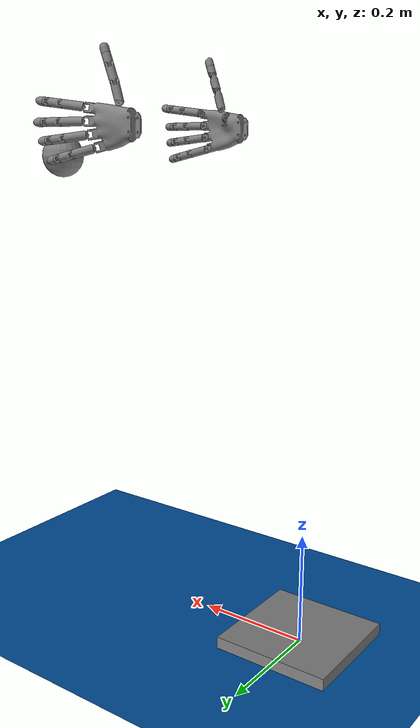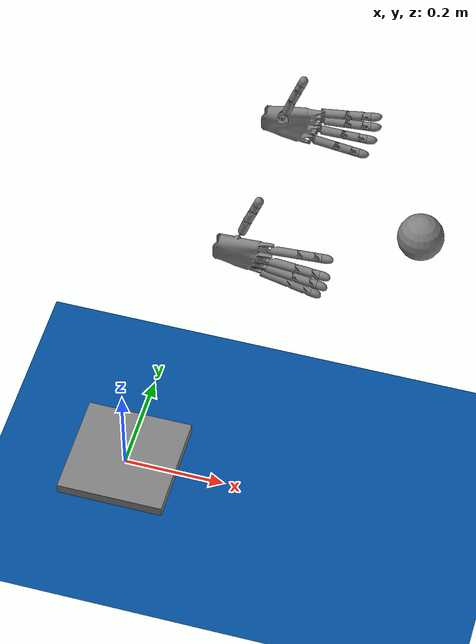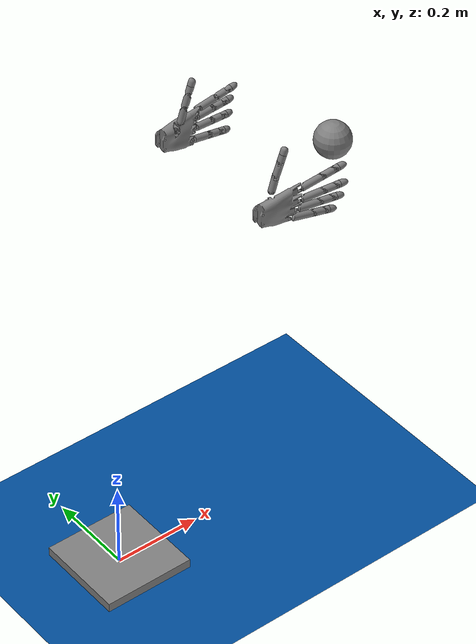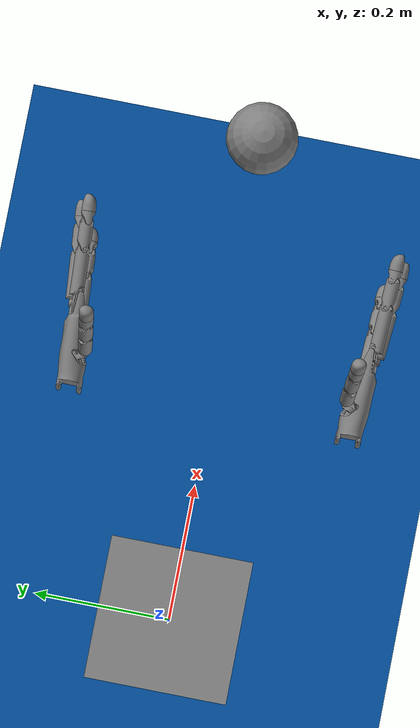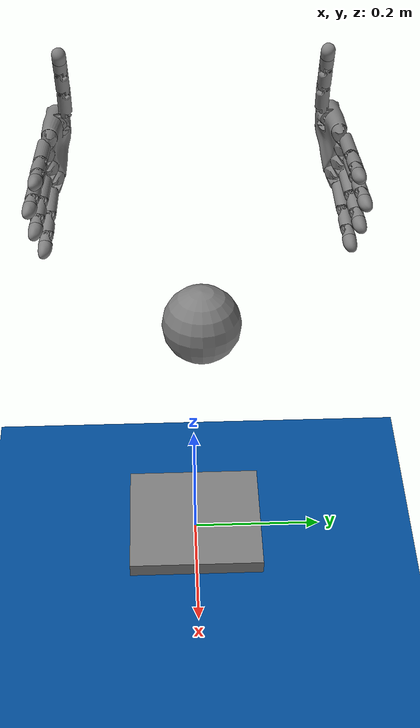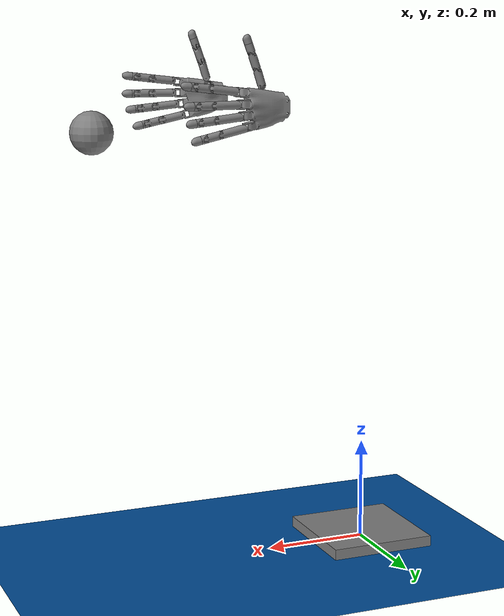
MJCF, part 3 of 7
0.0216557 0.0897728 0.151403 0.0214882 0.0903247 0.151403 0.0212162 0.0908333 0.151403 0.0208502 0.0912791 0.151403 0.0204043 0.0916449 0.151403 0.0198956 0.0919167 0.151403 0.0193436 0.092084 0.151403 0.0187696 0.0921404 0.151403 0.0216569 0.0903946 0.151224 0.021368 0.0909348 0.151224 0.0209793 0.0914082 0.151224 0.0205057 0.0917967 0.151224 0.0199654 0.0920854 0.151224 0.0193792 0.0922631 0.151224 0.0187696 0.092323 0.151224 0.01816 0.0922629 0.151224 0.0181956 0.0920838 0.151403 0.0176437 0.0919163 0.151403 0.0171351 0.0916443 0.151403 0.0166893 0.0912783 0.151403 0.0163235 0.0908324 0.151403 0.0160517 0.0903236 0.151403 0.0158844 0.0897717 0.151403 0.0175738 0.0920849 0.151224 0.0170336 0.0917961 0.151224 0.0165602 0.0914074 0.151224 0.0161717 0.0909338 0.151224 0.015883 0.0903935 0.151224 0.0157053 0.0898073 0.151224 -0.00467804 0.0915832 0.163712 -0.00466327 0.0916962 0.155654 -0.00454969 0.0914349 0.16291 -0.00458379 0.0915927 0.155652 -0.00442342 0.0913673 0.162395 -0.00448022 0.0915132 0.155651 -0.000499845 0.0915866 0.151412 -0.000511473 0.0917692 0.151233 -0.000617153 0.0915864 0.151421 -0.000633824 0.091769 0.151242 -0.00220157 0.0917615 0.151686 -0.00212026 0.0915789 0.151847 -0.00336809 0.0915625 0.152787 -0.00350311 0.0917452 0.152667 -0.00419195 0.0915396 0.154115 -0.00436249 0.0917224 0.154052 -0.000401242 0.0917642 0.151227 -0.000292847 0.0917457 0.151224 -0.000418754 0.0915833 0.151405 -0.000339067 0.0915692 0.151402 3.99563e-05 0.0907927 0.151403 0.000207809 0.0907208 0.151224 5.66794e-05 0.0908356 0.151403 0.000229728 0.0907775 0.151224 8.70841e-05 0.0909973 0.151401 8.7525e-05 0.0910248 0.151401 6.22635e-05 0.0911875 0.1514 -2.4709e-05 0.0913587 0.151399 5.34594e-05 0.0912137 0.1514 -4.1788e-05 0.0913805 0.151399 -0.000163882 0.091491 0.1514 -0.000187208 0.0915058 0.1514 0.000269352 0.0909909 0.151223 0.000269864 0.0910273 0.151223 0.000236244 0.0912418 0.151223 0.000224602 0.0912763 0.151223 0.000121464 0.0914675 0.151223 9.89521e-05 0.0914962 0.151223 -6.19402e-05 0.0916421 0.151223 -9.26776e-05 0.0916617 0.151223 -2.5161e-05 0.0899782 0.151224 -0.000203991 0.0900151 0.151403 -0.000105057 0.0891946 0.151224 -0.000287652 0.0891946 0.151403 -0.000219537 0.088455 0.151403 -4.00075e-05 0.0884883 0.151224 0.000152695 0.0878057 0.151224 0.000466592 0.0871696 0.151224 0.000891168 0.0866014 0.151224 0.0014122 0.0861201 0.151224 0.00201223 0.0857418 0.151224 0.00267115 0.0854793 0.151224 0.0033669 0.0853412 0.151224 0.00407615 0.0853323 0.151224 0.00477516 0.0854528 0.151224 0.00544049 0.0856986 0.151224 0.00604986 0.0860617 0.151224 0.00656238 0.0865082 0.151224 0.00698897 0.0870375 0.151224 -1.77556e-05 0.0877402 0.151403 0.000310933 0.0870742 0.151403 0.000755514 0.0864792 0.151403 0.0013011 0.0859752 0.151403 0.0019294 0.0855791 0.151403 0.00261937 0.0853042 0.151403 0.0033479 0.0851596 0.151403 0.00409058 0.0851502 0.151403 0.00482251 0.0852764 0.151403 0.0055192 0.0855339 0.151403 0.00615728 0.085914 0.151403 0.00669395 0.0863816 0.151403 0.00714064 0.0869358 0.151403 0.0076138 0.0871883 0.151403 0.00761376 0.0873709 0.151224 0.00744244 0.0871622 0.151403 0.00738754 0.0873363 0.151224 0.00741635 0.0871534 0.151403 0.00727213 0.0870749 0.151403 0.00725049 0.0870578 0.151403 0.0073531 0.0873246 0.151224 0.00716269 0.087221 0.151224 0.00713412 0.0871984 0.151224 0.0149273 0.0871897 0.151403 0.0149273 0.0873723 0.151224 0.0154005 0.0869374 0.151403 0.0155522 0.0870391 0.151224 0.0152835 0.0870652 0.151403 0.0153975 0.0872077 0.151224 0.0152615 0.0870819 0.151403 0.015116 0.0871579 0.151403 0.0150898 0.0871664 0.151403 0.0153685 0.0872298 0.151224 0.0151764 0.0873302 0.151224 0.0151418 0.0873414 0.151224 0.0158474 0.0863834 0.151403 0.015979 0.08651 0.151224 0.0164916 0.0860636 0.151224 0.0171012 0.0857009 0.151224 0.0177666 0.0854552 0.151224 0.0184656 0.085335 0.151224 0.0191749 0.0853442 0.151224 0.0198706 0.0854826 0.151224 0.0205294 0.0857454 0.151224 0.0211293 0.0861239 0.151224 0.0216501 0.0866054 0.151224 0.0220745 0.0871737 0.151224 0.0223881 0.0878099 0.151224 0.0225806 0.0884926 0.151224 0.0226454 0.089199 0.151224 0.0163843 0.0859159 0.151403 0.0170225 0.0855361 0.151403 0.0177193 0.0852789 0.151403 0.0184513 0.085153 0.151403 0.019194 0.0851626 0.151403 0.0199224 0.0853075 0.151403 0.0206123 0.0855827 0.151403 0.0212405 0.085979 0.151403 0.0217858 0.0864832 0.151403 0.0222302 0.0870783 0.151403 0.0225586 0.0877445 0.151403 0.0227601 0.0884594 0.151403 0.022828 0.089199 0.151403 0.0225652 0.0899825 0.151224 0.022744 0.0900195 0.151403 0.0223319 0.090725 0.151224 0.0224998 0.090797 0.151403 0.0228785 0.0915736 0.151401 0.0228322 0.0917501 0.151223 0.0227742 0.0917326 0.151223 0.0228345 0.0915604 0.151401 0.0226882 0.0914848 0.1514 0.0226661 0.0914682 0.151399 0.0225535 0.0913481 0.151399 0.0225382 0.0913249 0.151399 0.0224721 0.0911741 0.151399 0.0224655 0.0911472 0.1514 0.0224536 0.090983 0.151401 0.0224563 0.0909555 0.151401 0.0225814 0.0916325 0.151223 0.0225523 0.0916105 0.151223 0.0224038 0.091452 0.151223 0.0223837 0.0914216 0.151223 0.0222965 0.0912227 0.151223 0.0222877 0.0911872 0.151223 0.0222716 0.0909707 0.151223 0.0222751 0.0909344 0.151223 0.0229406 0.0917686 0.151226 0.0230508 0.0917737 0.151233 0.0229582 0.0915877 0.151405 0.0230393 0.0915911 0.151412 0.0270198 0.0915192 0.155651 0.0272028 0.0917022 0.155654 0.0270181 0.0915212 0.155533 0.027201 0.0917042 0.155531 0.0268559 0.0917302 0.153938 0.0259584 0.0917523 0.152577 0.0266873 0.0915474 0.154005 0.025827 0.0915695 0.152701 0.0245536 0.0915848 0.151796 0.0246302 0.0917675 0.151633 0.0272034 0.0915645 0.16359 0.0270895 0.0914409 0.162909 0.0270214 0.0913984 0.162614 0.0269632 0.0913733 0.162394 0.0272178 0.0915893 0.163712 -0.00466694 0.0915549 0.163722 -0.00466072 0.091525 0.163732 -0.00449075 0.0913392 0.162949 -0.00414179 0.0913115 0.161846 -0.00436362 0.0913247 0.162424 -0.00451276 0.0913921 0.16293 -0.00432533 0.0912598 0.162449 -0.0040769 0.0912384 0.161878 -0.00302488 0.0913384 0.160329 -0.00297341 0.0912653 0.160379 -0.000614482 0.0912915 0.158934 -0.00146513 0.091285 0.159289 -0.000637336 0.0913645 0.158866 -0.0014983 0.0913581 0.159225 -0.000342326 0.0912441 0.158799 -0.000262223 0.0907555 0.158838 -0.000214856 0.0907301 0.15877 -0.000242034 0.0908372 0.158833 -0.000244149 0.0909626 0.158834 -0.000190649 0.0908267 0.158766 -0.000193164 0.0909752 0.158767 -0.00024374 0.0911195 0.158778 -0.000286368 0.0910845 0.158844 -0.000368618 0.0911898 0.158865 -0.000483623 0.0912626 0.158897 -0.000480265 0.0913303 0.158829 -0.000280078 0.0905484 0.158789 -0.000444446 0.0898813 0.158839 -0.000492611 0.0898926 0.158905 -0.000327676 0.0905707 0.158856 -0.000548204 0.0891944 0.158923 -0.000499854 0.0891944 0.158857 0.00136766 0.0856599 0.15856 0.00132661 0.0855995 0.158632 0.00079956 0.0860299 0.158652 -0.000448688 0.0885358 0.15884 -0.000289108 0.0878695 0.158792 -1.49258e-05 0.0872173 0.158719 0.000356984 0.0866269 0.158643 0.00084286 0.0860827 0.158581 0.000311743 0.0865838 0.158713 -6.15657e-05 0.0871844 0.158787 -0.000336731 0.0878476 0.158858 -0.000496863 0.088525 0.158906 0.00734859 0.0867261 0.158632 0.00688251 0.0861596 0.158632 0.00632783 0.0856796 0.158632 0.00564419 0.0852723 0.158632 0.00489776 0.0849964 0.158632 0.00411356 0.0848613 0.158632 0.00331785 0.0848713 0.158632 0.00253731 0.0850262 0.158632 0.00179807 0.0853208 0.158632 0.00728847 0.0867676 0.15856 0.00683023 0.0862106 0.15856 0.00628487 0.0857386 0.15856 0.00561271 0.0853382 0.15856 0.00487882 0.085067 0.15856 0.00410779 0.0849341 0.15856 0.00332545 0.0849439 0.15856 0.00255802 0.0850962 0.15856 0.0018312 0.0853859 0.15856 0.00754109 0.0869514 0.15856 0.00767685 0.0869715 0.15856 0.00756211 0.0868814 0.158632 0.00767687 0.0868984 0.158632 0.00739918 0.0868809 0.158561 0.00744216 0.0868219 0.158632 0.0148645 0.0868998 0.158632 0.0148645 0.0869729 0.15856 0.0151593 0.0868694 0.15856 0.015253 0.0867691 0.15856 0.0151137 0.0868124 0.158632 0.0151929 0.0867276 0.158632 0.0150207 0.0869461 0.15856 0.0149966 0.0868772 0.158632 0.0212153 0.0856032 0.158632 0.0207439 0.0853244 0.158632 0.0200048 0.0850295 0.158632 0.0192243 0.0848743 0.158632 0.0184286 0.084864 0.158632 0.0176444 0.0849989 0.158632 0.0168978 0.0852744 0.158632 0.016214 0.0856814 0.158632 0.0156592 0.0861613 0.158632 0.0211742 0.0856636 0.15856 0.0207108 0.0853895 0.15856 0.0199841 0.0850996 0.15856 0.0192167 0.084947 0.15856 0.0184344 0.0849368 0.15856 0.0176633 0.0850694 0.15856 0.0169293 0.0853404 0.15856 0.016257 0.0857405 0.15856 0.0157114 0.0862123 0.15856 0.0230887 0.0891989 0.158922 0.0230377 0.0885295 0.158906 0.0230404 0.0891989 0.158856 0.0229895 0.0885403 0.15884 0.0228301 0.0878739 0.158791 0.0228778 0.087852 0.158858 0.0226029 0.0871887 0.158787 0.0225562 0.0872216 0.158719 0.0221845 0.0866311 0.158643 0.0222298 0.086588 0.158713 0.0217422 0.0860339 0.158652 0.0216989 0.0860867 0.158581 0.0228677 0.0905752 0.158855 0.0230329 0.089897 0.158905 0.0229847 0.0898857 0.158838 0.0228022 0.0907599 0.158837 0.0228201 0.0905528 0.158789 0.0227548 0.0907345 0.15877 0.0230345 0.0912714 0.158899 0.0229262 0.0912094 0.15887 0.0229034 0.0912666 0.158803 0.0231542 0.091296 0.158934 0.023177 0.0913691 0.158866 0.0230333 0.09134 0.158832 0.0228438 0.0911184 0.158848 0.0228046 0.0911588 0.158782 0.0227437 0.0910261 0.158769 0.0227929 0.0910063 0.158835 0.0227783 0.0908823 0.158832 0.0227262 0.0908793 0.158765 0.0261303 0.0912581 0.161095 0.0248112 0.0912812 0.159782 0.0248541 0.0913543 0.159724 0.0266167 0.0912443 0.161878 0.0261893 0.0913312 0.161053 0.0266816 0.0913174 0.161845 0.0268652 0.0912658 0.162449 0.0272005 0.0915311 0.163731 0.0270306 0.0913452 0.162948 0.0270526 0.0913981 0.16293 0.0272067 0.0915609 0.163722 0.0269035 0.0913306 0.162424 -0.00646432 0.0859961 0.141158 -0.0064647 0.0879961 0.141158 -0.00657103 0.0879961 0.142374 -0.00657065 0.0859961 0.142374 -0.00688682 0.087996 0.143553 -0.00688644 0.085996 0.143553 -0.00740247 0.0879959 0.144659 -0.00740209 0.0859959 0.144658 -0.00810233 0.0879957 0.145658 -0.00810195 0.0859957 0.145658 -0.00896511 0.0879956 0.146521 -0.00896473 0.0859956 0.146521 -0.00996462 0.0879954 0.147221 -0.00996424 0.0859953 0.147221 -0.0110705 0.0879951 0.147736 -0.0110701 0.0859951 0.147736 -0.0122491 0.0879949 0.148052 -0.0122487 0.0859949 0.148052 -0.0134646 0.0879947 0.148159 -0.0134642 0.0859947 0.148159 -0.0160051 0.0891944 0.136298 -0.0159654 0.0914944 0.136359 -0.0160051 0.0891943 0.140699 -0.0159653 0.0914943 0.140659 -0.0169248 0.0891941 0.140699 -0.0169654 0.0914941 0.140659 -0.0169249 0.0891942 0.136298 -0.0169655 0.0914942 0.136359 -0.0169247 0.089194 0.146019 -0.0169653 0.091494 0.145959 -0.0169248 0.0891941 0.141619 -0.0169654 0.0914941 0.141659 -0.016005 0.0891943 0.141619 -0.0159653 0.0914943 0.141659 -0.016005 0.0891942 0.146019 -0.0159653 0.0914942 0.145959 -0.020255 0.0891935 0.141619 -0.0202153 0.0914935 0.141659 -0.0202551 0.0891935 0.140699 -0.0202153 0.0914935 0.140659 -0.0126748 0.089195 0.140699 -0.0127154 0.0914949 0.140659 -0.0126748 0.0891949 0.141618 -0.0127154 0.0914949 0.141659 -0.0202931 0.0869936 0.136311 -0.0202931 0.0869936 0.135418 -0.0194646 0.0869937 0.136241 -0.0194646 0.0869938 0.135359 -0.0134646 0.0869949 0.136241 -0.0134646 0.0869949 0.135359 -0.0126361 0.086995 0.136311 -0.0126361 0.0869951 0.135418 -0.0194642 0.0859935 0.148159 -0.0194646 0.0879935 0.148159 -0.0207145 0.0859933 0.148046 -0.0207509 0.0879933 0.14804 -0.0207505 0.0859933 0.148039 -0.0219933 0.087993 0.147686 -0.0219929 0.0859931 0.147686 -0.0231496 0.0879928 0.14711 -0.0231493 0.0859928 0.14711 -0.0241805 0.0879927 0.146332 -0.0241801 0.0859927 0.146332 -0.0250508 0.0879925 0.145377 -0.0250504 0.0859925 0.145377 -0.0257308 0.0879924 0.144279 -0.0257304 0.0859924 0.144279 -0.0261975 0.0879923 0.143074 -0.0261971 0.0859923 0.143074 -0.0264348 0.0879923 0.141805 -0.0264345 0.0859923 0.141805 -0.0264643 0.0859923 0.141159 -0.0264349 0.0879923 0.140513 -0.0264345 0.0859923 0.140513 -0.0261975 0.0879924 0.139243 -0.0261971 0.0859924 0.139243 -0.0257309 0.0879925 0.138039 -0.0257305 0.0859925 0.138039 -0.0250509 0.0879927 0.13694 -0.0250505 0.0859927 0.13694 -0.0241806 0.0879929 0.135986 -0.0241803 0.0859929 0.135986 -0.0231498 0.0879931 0.135207 -0.0231494 0.0859931 0.135207 -0.0219935 0.0879933 0.134631 -0.0219931 0.0859933 0.134631 -0.0207511 0.0879935 0.134278 -0.0207507 0.0859935 0.134278 -0.0207147 0.0859935 0.134271 -0.0194648 0.0879938 0.134159 -0.0194644 0.0859938 0.134159 -0.0134644 0.0859949 0.134159 -0.0134648 0.0879949 0.134159 -0.0122493 0.0879952 0.134265 -0.0122489 0.0859952 0.134265 -0.0110707 0.0879954 0.134581 -0.0110703 0.0859954 0.134581 -0.00996479 0.0879956 0.135096 -0.00996441 0.0859956 0.135096 -0.00896527 0.0879958 0.135796 -0.00896489 0.0859958 0.135796 -0.00810246 0.0879959 0.136659 -0.00810208 0.0859959 0.136659 -0.00740258 0.087996 0.137659 -0.0074022 0.085996 0.137658 -0.00688689 0.0879961 0.138764 -0.00688651 0.0859961 0.138764 -0.00657107 0.0879961 0.139943 -0.00657069 0.0859961 0.139943 -0.00973902 0.0928007 0.145699 -0.010202 0.0928006 0.146043 -0.0101312 0.0879953 0.146147 -0.0134655 0.0927999 0.147033 -0.0134646 0.0879947 0.147159 -0.0128898 0.0928 0.147005 -0.0122941 0.0879949 0.147043 -0.0123195 0.0928001 0.14692 -0.0117604 0.0928002 0.14678 -0.0111685 0.0879951 0.146702 -0.0112176 0.0928004 0.146586 -0.0106965 0.0928005 0.146339 -0.00931189 0.0928007 0.145312 -0.009222 0.0879955 0.145401 -0.00892477 0.0928008 0.144885 -0.00847584 0.0879957 0.144492 -0.00858138 0.0928009 0.144422 -0.00828502 0.092801 0.143928 -0.00792139 0.0879958 0.143455 -0.00803856 0.092801 0.143407 -0.00757998 0.0879959 0.142329 -0.0074647 0.0879959 0.141159 -0.00759145 0.0928011 0.141159 -0.00761973 0.0928011 0.141734 -0.0077043 0.0928011 0.142305 -0.00784436 0.0928011 0.142864 -0.0134657 0.0928001 0.135285 -0.0134648 0.0879949 0.135159 -0.0194657 0.092799 0.135285 -0.0194648 0.0879938 0.135159 -0.0211707 0.0927985 0.14678 -0.0217135 0.0927984 0.146586 -0.0217607 0.0879931 0.146702 -0.0240064 0.0927979 0.144885 -0.0243498 0.0927979 0.144422 -0.0244535 0.0879926 0.144492 -0.0206353 0.0879935 0.135274 -0.0206117 0.0927988 0.135397 -0.0200415 0.0927989 0.135313 -0.0217609 0.0879933 0.135615 -0.0227982 0.0879931 0.13617 -0.0227292 0.0927984 0.136275 -0.0222348 0.0927985 0.135978 -0.0217136 0.0927986 0.135732 -0.0211709 0.0927987 0.135538 -0.0237074 0.0879929 0.136916 -0.0244536 0.0879928 0.137825 -0.0243499 0.092798 0.137895 -0.0240065 0.0927981 0.137432 -0.0236193 0.0927982 0.137005 -0.0231922 0.0927983 0.136618 -0.025008 0.0879926 0.138863 -0.0253494 0.0879926 0.139988 -0.0252269 0.0927978 0.140013 -0.0250869 0.0927978 0.139454 -0.0248927 0.0927979 0.138911 -0.0246462 0.0927979 0.13839 -0.0254647 0.0879925 0.141159 -0.0253494 0.0879925 0.142329 -0.0252269 0.0927978 0.142305 -0.0253115 0.0927978 0.141735 -0.0253398 0.0927978 0.141159 -0.0253115 0.0927978 0.140583 -0.0250079 0.0879926 0.143455 -0.0246461 0.0927978 0.143928 -0.0248926 0.0927978 0.143407 -0.0250868 0.0927978 0.142864 -0.0236192 0.092798 0.145313 -0.0237073 0.0879928 0.145401 -0.0231921 0.0927981 0.1457 -0.0227981 0.0879929 0.146148 -0.0227291 0.0927982 0.146043 -0.0222346 0.0927983 0.146339 -0.0206115 0.0927986 0.14692 -0.0206352 0.0879933 0.147043 -0.0200413 0.0927987 0.147005 -0.0194646 0.0879935 0.147159 -0.0194655 0.0927988 0.147033 -0.00761974 0.0928012 0.140583 -0.00758001 0.0879959 0.139988 -0.00770434 0.0928011 0.140013 -0.00892488 0.092801 0.137432 -0.00858147 0.092801 0.137895 -0.00847594 0.0879958 0.137825 -0.00828511 0.0928011 0.13839 -0.00792146 0.0879959 0.138862 -0.00803863 0.0928011 0.138911 -0.00784441 0.0928011 0.139453 -0.00931202 0.0928009 0.137005 -0.00922213 0.0879957 0.136916 -0.00973915 0.0928008 0.136618 -0.0101314 0.0879955 0.13617 -0.0102022 0.0928007 0.136274 -0.0106966 0.0928007 0.135978 -0.0111687 0.0879953 0.135615 -0.0112178 0.0928006 0.135732 -0.0122942 0.0879951 0.135274 -0.0128899 0.0928003 0.135313 -0.0123197 0.0928004 0.135397 -0.0117605 0.0928005 0.135537 -0.0134657 0.0929949 0.135484 -0.0194657 0.0929938 0.135485 -0.0170587 0.0929942 0.13878 -0.00846146 0.0929958 0.138484 -0.0123977 0.092995 0.141765 -0.0122452 0.092995 0.141935 -0.00781875 0.0929959 0.140602 -0.00790046 0.0929959 0.140052 -0.0122349 0.092995 0.141954 -0.00803577 0.0929959 0.139511 -0.00822338 0.0929958 0.138987 -0.0244699 0.0929928 0.138484 -0.0207166 0.0929934 0.14022 -0.0206948 0.0929934 0.140169 -0.0230654 0.0929931 0.136773 -0.023478 0.092993 0.137147 -0.0206509 0.0929934 0.140122 -0.023852 0.0929929 0.137559 -0.0241837 0.0929928 0.138006 -0.017267 0.0929941 0.138841 -0.0172342 0.0929941 0.138816 -0.0171575 0.0929941 0.138784 -0.00779142 0.0929959 0.141159 -0.0122105 0.092995 0.142034 -0.00781873 0.0929959 0.141715 -0.00907936 0.0929956 0.144758 -0.00874765 0.0929956 0.144311 -0.0122365 0.092995 0.142148 -0.00846139 0.0929957 0.143833 -0.0122147 0.092995 0.142097 -0.0156643 0.0929943 0.143476 -0.0156972 0.0929943 0.143502 -0.0134656 0.0929947 0.146833 -0.0157738 0.0929943 0.143533 -0.0158727 0.0929943 0.143537 -0.0194656 0.0929935 0.146833 -0.024708 0.0929927 0.138987 -0.0248956 0.0929926 0.139512 -0.0207208 0.0929934 0.140283 -0.0216372 0.0929933 0.135916 -0.0221405 0.0929932 0.136155 -0.0173171 0.0929941 0.138908 -0.0226182 0.0929931 0.136441 -0.0173491 0.0929941 0.139017 -0.0173377 0.0929941 0.139207 -0.00822331 0.0929958 0.14333 -0.00803573 0.0929958 0.142806 -0.00790043 0.0929958 0.142266 -0.00945331 0.0929955 0.145171 -0.0122805 0.092995 0.142196 -0.00986589 0.0929954 0.145545 -0.0112941 0.0929951 0.146401 -0.0107908 0.0929952 0.146163 -0.0156142 0.0929943 0.143409 -0.0103131 0.0929953 0.145877 -0.0155822 0.0929944 0.1433 -0.0155936 0.0929944 0.14311 -0.0244698 0.0929926 0.143834 -0.0205336 0.0929935 0.140552 -0.0206861 0.0929934 0.140383 -0.0251126 0.0929926 0.141715 -0.0250309 0.0929926 0.142266 -0.0206965 0.0929934 0.140364 -0.0248955 0.0929926 0.142806 -0.0247079 0.0929926 0.14333 -0.0200219 0.0929937 0.135512 -0.0205727 0.0929936 0.135594 -0.0211129 0.0929934 0.135729 -0.0170158 0.0929942 0.138788 -0.0168218 0.0929942 0.138877 -0.0129096 0.092995 0.135512 -0.0126374 0.0929949 0.14159 -0.0129094 0.0929948 0.146806 -0.0123586 0.0929949 0.146724 -0.0118184 0.092995 0.146589 -0.0250309 0.0929926 0.140052 -0.0251126 0.0929926 0.140603 -0.0251399 0.0929926 0.141159 -0.00874775 0.0929958 0.138006 -0.00907946 0.0929957 0.137559 -0.00945342 0.0929956 0.137146 -0.00986602 0.0929956 0.136772 -0.0241836 0.0929927 0.144311 -0.0238519 0.0929927 0.144759 -0.0202939 0.0929935 0.140727 -0.0205808 0.0929935 0.140086 -0.0204347 0.0929935 0.140065 -0.020038 0.0929936 0.140118 -0.0173314 0.0929941 0.139236 -0.0171242 0.0929941 0.140768 -0.0169991 0.0929941 0.140641 -0.0103133 0.0929955 0.136441 -0.0107909 0.0929954 0.136154 -0.0112943 0.0929953 0.135916 -0.0123505 0.092995 0.142232 -0.0124967 0.092995 0.142252 -0.0128933 0.0929949 0.1422 -0.0155999 0.0929944 0.143082 -0.0158072 0.0929943 0.141549 -0.0159322 0.0929943 0.141676 -0.0118186 0.0929952 0.135729 -0.0123587 0.0929951 0.135593 -0.0234779 0.0929928 0.145171 -0.0230653 0.0929929 0.145545 -0.022618 0.092993 0.145877 -0.0221404 0.0929931 0.146163 -0.021637 0.0929931 0.146401 -0.0211127 0.0929932 0.146589 -0.0169914 0.0929941 0.140707 -0.017072 0.0929941 0.140775 -0.0169949 0.0929941 0.140735 -0.01594 0.0929943 0.14161 -0.0158593 0.0929943 0.141542 -0.0159364 0.0929943 0.141583 -0.0159155 0.0929943 0.14353 -0.0161095 0.0929943 0.143441 -0.0200217 0.0929934 0.146806 -0.0205726 0.0929933 0.146724 -0.0170268 0.0929941 0.14077 -0.0170107 0.0929941 0.140762 -0.0170017 0.0929941 0.140752 -0.0159045 0.0929943 0.141548 -0.0159206 0.0929943 0.141556 -0.0159296 0.0929943 0.141566 -0.0159906 0.0927943 0.141464 -0.0168867 0.0927942 0.140615 -0.0168759 0.0927942 0.140711 -0.016883 0.0927942 0.140763 -0.016903 0.0927942 0.140812 -0.0160282 0.0927943 0.141506 -0.0169406 0.0927941 0.140854 -0.0159401 0.0927943 0.141438 -0.0168846 0.0927942 0.138974 -0.017219 0.0927941 0.139209 -0.0172245 0.0927941 0.139184 -0.0160445 0.0927943 0.141703 -0.0160553 0.0927943 0.141607 -0.0160483 0.0927943 0.141554 -0.0169911 0.0927941 0.14088 -0.0160467 0.0927943 0.143344 -0.0157122 0.0927943 0.143108 -0.0157067 0.0927943 0.143133 -0.0158556 0.0927943 0.141427 -0.015782 0.0927944 0.141437 -0.0127002 0.0927949 0.141687 -0.0128681 0.0927949 0.142087 -0.0124727 0.092795 0.141853 -0.0170756 0.0927941 0.14089 -0.0171493 0.0927941 0.140881 -0.0202311 0.0927935 0.140631 -0.0200631 0.0927936 0.14023 -0.0204585 0.0927935 0.140464 -0.0170428 0.0927942 0.1389 -0.0170727 0.0927942 0.138895 -0.0171324 0.0927941 0.138897 -0.0158884 0.0927943 0.143417 -0.0158586 0.0927943 0.143423 -0.0157988 0.0927943 0.143421 -0.0172143 0.0927941 0.138961 -0.0172345 0.0927941 0.139031 -0.017188 0.0927941 0.138925 -0.0171718 0.0927941 0.138913 -0.0123383 0.092795 0.142005 -0.0124979 0.092795 0.142137 -0.0123869 0.092795 0.142122 -0.012345 0.092795 0.141993 -0.0157169 0.0927943 0.143357 -0.0156967 0.0927943 0.143286 -0.0157432 0.0927943 0.143392 -0.0157595 0.0927943 0.143405 -0.0205929 0.0927935 0.140312 -0.0204334 0.0927935 0.14018 -0.0205444 0.0927935 0.140195 -0.0205862 0.0927935 0.140325 -0.0123253 0.092795 0.142046 -0.0123267 0.092795 0.142069 -0.012334 0.092795 0.142086 -0.0123505 0.092795 0.142104 -0.0206059 0.0927934 0.140271 -0.0206045 0.0927934 0.140248 -0.0205973 0.0927935 0.140231 -0.0205808 0.0927935 0.140213 -0.0252852 0.0859926 0.140755 -0.0211184 0.0859933 0.140755 -0.0207143 0.0859934 0.141159 -0.0134642 0.0859947 0.146993 -0.0126183 0.0859948 0.146932 -0.0118102 0.085995 0.146754 -0.0118103 0.0859951 0.141563 -0.0126184 0.085995 0.141159 -0.0076434 0.0859959 0.141562 -0.00779322 0.0859959 0.142531 -0.0081201 0.0859958 0.143501 -0.0086112 0.0859957 0.144398 -0.00925143 0.0859955 0.145196 -0.0100211 0.0859954 0.145869 -0.0108966 0.0859952 0.146398 -0.0194642 0.0859935 0.146994 -0.0203102 0.0859934 0.146932 -0.0203103 0.0859935 0.141159 -0.0118104 0.0859952 0.135563 -0.0108968 0.0859954 0.135919 -0.0100213 0.0859955 0.136448 -0.00925155 0.0859957 0.137121 -0.00861129 0.0859958 0.137919 -0.00812017 0.0859959 0.138816 -0.00779326 0.0859959 0.139785 -0.00764341 0.0859959 0.140754 -0.0118103 0.0859951 0.140755 -0.0126184 0.0859951 0.135385 -0.0134644 0.0859949 0.135324 -0.0194644 0.0859938 0.135324 -0.0203104 0.0859936 0.135385 -0.0211184 0.0859934 0.135563 -0.0251354 0.0859926 0.139786 -0.0248085 0.0859927 0.138817 -0.0243174 0.0859928 0.137919 -0.0236772 0.0859929 0.137122 -0.0229075 0.0859931 0.136448 -0.022032 0.0859933 0.135919 -0.0251354 0.0859925 0.142532 -0.0252852 0.0859925 0.141563 -0.0211183 0.0859933 0.141563 -0.0211183 0.0859932 0.146754 -0.0220319 0.0859931 0.146398 -0.0229074 0.0859929 0.145869 -0.0236771 0.0859928 0.145196 -0.0243174 0.0859927 0.144398 -0.0248085 0.0859926 0.143501 -0.0194654 0.0914937 0.136359 -0.0134654 0.0914949 0.136359 -0.0134653 0.0914947 0.145959 -0.0134644 0.0869947 0.146076 -0.0194644 0.0869936 0.146077 -0.0194653 0.0914936 0.145959 -0.0202153 0.0914934 0.1459 -0.020293 0.0869934 0.146006 -0.0202154 0.0914936 0.136418 -0.0127155 0.091495 0.136418 -0.0127153 0.0914949 0.1459 -0.0126359 0.0869949 0.146006 -0.0126359 0.0869948 0.146899 -0.0134644 0.0869947 0.146959 -0.0194644 0.0869935 0.146959 -0.0202929 0.0869934 0.146899 -0.0117931 0.0869952 0.136533 -0.0117931 0.0869952 0.135605 -0.0109702 0.0869953 0.13692 -0.0109123 0.0869954 0.13595 -0.0102074 0.0869955 0.137474 -0.00767986 0.0869959 0.140737 -0.00856478 0.0869957 0.140737 -0.00782739 0.0869959 0.139794 -0.00872612 0.0869957 0.139842 -0.00815234 0.0869958 0.13883 -0.00906433 0.0869957 0.138962 -0.00864053 0.0869958 0.137938 -0.0095642 0.0869956 0.138163 -0.00927695 0.0869957 0.137146 -0.0100421 0.0869955 0.136476 -0.0117154 0.0914952 0.136689 -0.0110309 0.0914953 0.137022 -0.0102863 0.0914955 0.137562 -0.00965851 0.0914956 0.138235 -0.00917062 0.0914957 0.139015 -0.00884052 0.0914957 0.139874 -0.00869149 0.0914957 0.140659 -0.0117153 0.0914951 0.140659 -0.011793 0.086995 0.146712 -0.011793 0.086995 0.145784 -0.0109122 0.0869952 0.146367 -0.0109701 0.0869952 0.145397 -0.0100419 0.0869954 0.145841 -0.0102073 0.0869953 0.144843 -0.00856477 0.0869957 0.14158 -0.00767984 0.0869959 0.14158 -0.00872608 0.0869957 0.142475 -0.00782735 0.0869958 0.142523 -0.00906426 0.0869956 0.143355 -0.00815228 0.0869958 0.143487 -0.00956411 0.0869955 0.144154 -0.00864044 0.0869957 0.144379 -0.00927684 0.0869955 0.145171 -0.00869148 0.0914957 0.141659 -0.00884048 0.0914957 0.142443 -0.00917055 0.0914956 0.143302 -0.00965843 0.0914955 0.144082 -0.0102862 0.0914953 0.144755 -0.0110307 0.0914952 0.145295 -0.0117153 0.091495 0.145628 -0.0117153 0.0914951 0.141659 -0.0211361 0.0869934 0.135605 -0.0211361 0.0869934 0.136534 -0.0220168 0.0869933 0.13595 -0.0219589 0.0869933 0.13692 -0.0228871 0.0869931 0.136476 -0.0227218 0.0869931 0.137474 -0.0243643 0.0869927 0.140737 -0.0252492 0.0869926 0.140737 -0.0242029 0.0869928 0.139842 -0.0251017 0.0869926 0.139794 -0.0238648 0.0869929 0.138963 -0.0247768 0.0869927 0.138831 -0.0233649 0.086993 0.138163 -0.0242886 0.0869928 0.137939 -0.0236522 0.0869929 0.137146 -0.0242393 0.0914928 0.140659 -0.0240903 0.0914928 0.139874 -0.0237602 0.0914929 0.139015 -0.0232723 0.091493 0.138235 -0.0226446 0.0914931 0.137563 -0.0219 0.0914933 0.137022 -0.0212155 0.0914934 0.136689 -0.0212154 0.0914933 0.140659 -0.0240902 0.0914927 0.142444 -0.0242392 0.0914927 0.141659 -0.0212154 0.0914933 0.141659 -0.0212153 0.0914932 0.145628 -0.0218999 0.0914931 0.145296 -0.0226445 0.091493 0.144755 -0.0232722 0.0914929 0.144082 -0.0237601 0.0914928 0.143302 -0.0211359 0.0869932 0.145784 -0.0219588 0.0869931 0.145397 -0.0227217 0.086993 0.144843 -0.0233648 0.0869929 0.144154 -0.0238647 0.0869928 0.143355 -0.0242029 0.0869927 0.142475 -0.0243642 0.0869927 0.14158 -0.0211359 0.0869932 0.146713 -0.0220167 0.0869931 0.146367 -0.0252492 0.0869925 0.14158 -0.0251016 0.0869926 0.142524 -0.0247767 0.0869926 0.143487 -0.0242885 0.0869927 0.144379 -0.0236521 0.0869928 0.145172 -0.022887 0.0869929 0.145841 -0.0194656 0.0928966 0.147004 -0.0200385 0.0928964 0.146976 -0.0194656 0.0929676 0.146931 -0.0200314 0.0929675 0.146904 -0.0205918 0.0929674 0.146821 -0.0211413 0.0929673 0.146683 -0.0216747 0.0929672 0.146492 -0.0221868 0.0929671 0.14625 -0.0226727 0.092967 0.145959 -0.0231278 0.0929669 0.145621 -0.0235475 0.0929669 0.145241 -0.023928 0.0929668 0.144821 -0.0242654 0.0929668 0.144366 -0.0245567 0.0929667 0.14388 -0.0247989 0.0929667 0.143368 -0.0249898 0.0929666 0.142835 -0.0251274 0.0929666 0.142285 -0.0252106 0.0929666 0.141725 -0.0252384 0.0929666 0.141159 -0.0252106 0.0929666 0.140593 -0.0251275 0.0929667 0.140033 -0.0249898 0.0929667 0.139483 -0.024799 0.0929668 0.13895 -0.0245568 0.0929668 0.138438 -0.0242655 0.0929669 0.137952 -0.0239281 0.0929669 0.137497 -0.0235476 0.092967 0.137077 -0.0231279 0.0929671 0.136696 -0.0226729 0.0929672 0.136359 -0.022187 0.0929673 0.136068 -0.0216749 0.0929674 0.135825 -0.0211415 0.0929675 0.135635 -0.0205919 0.0929676 0.135497 -0.0200316 0.0929677 0.135414 -0.0194657 0.0929678 0.135386 -0.020606 0.0928963 0.146892 -0.0211625 0.0928962 0.146753 -0.0217026 0.0928961 0.14656 -0.0222212 0.092896 0.146314 -0.0227132 0.0928959 0.146019 -0.023174 0.0928959 0.145678 -0.0235991 0.0928958 0.145292 -0.0239844 0.0928957 0.144867 -0.0243261 0.0928957 0.144407 -0.024621 0.0928956 0.143914 -0.0248663 0.0928956 0.143396 -0.0250596 0.0928956 0.142856 -0.025199 0.0928955 0.142299 -0.0252832 0.0928955 0.141732 -0.0253113 0.0928955 0.141159 -0.0252832 0.0928956 0.140586 -0.025199 0.0928956 0.140018 -0.0250596 0.0928956 0.139462 -0.0248664 0.0928957 0.138922 -0.0246211 0.0928957 0.138403 -0.0243262 0.0928958 0.137911 -0.0239845 0.0928959 0.13745 -0.0235992 0.092896 0.137025 -0.0231742 0.092896 0.13664 -0.0227134 0.0928961 0.136298 -0.0222213 0.0928962 0.136003 -0.0217028 0.0928963 0.135758 -0.0211626 0.0928964 0.135565 -0.0206062 0.0928966 0.135425 -0.0200387 0.0928967 0.135341 -0.0194657 0.0928968 0.135313 -0.0134657 0.092969 0.135386 -0.0134657 0.0928979 0.135313 -0.0134656 0.0929688 0.146931 -0.0134656 0.0928977 0.147004 -0.0128927 0.092898 0.135341 -0.0128999 0.0929691 0.135414 -0.0123395 0.0929692 0.135497 -0.01179 0.0929693 0.135635 -0.0112566 0.0929694 0.135825 -0.0107445 0.0929695 0.136068 -0.0102586 0.0929696 0.136359 -0.00980354 0.0929696 0.136696 -0.00938378 0.0929697 0.137077 -0.00900333 0.0929698 0.137496 -0.00866586 0.0929698 0.137951 -0.0083746 0.0929699 0.138437 -0.00813238 0.0929699 0.138949 -0.00794152 0.09297 0.139483 -0.00780387 0.09297 0.140032 -0.00772073 0.09297 0.140593 -0.00769293 0.09297 0.141159 -0.0123253 0.0928981 0.135425 -0.0117688 0.0928982 0.135565 -0.0112287 0.0928983 0.135758 -0.0107101 0.0928984 0.136003 -0.010218 0.0928985 0.136298 -0.00975725 0.0928986 0.13664 -0.00933218 0.0928987 0.137025 -0.00894693 0.0928987 0.13745 -0.00860519 0.0928988 0.137911 -0.00831026 0.0928988 0.138403 -0.00806497 0.0928989 0.138922 -0.0078717 0.0928989 0.139462 -0.00773231 0.0928989 0.140018 -0.00764812 0.0928989 0.140586 -0.00761997 0.0928989 0.141159 -0.00764811 0.0928989 0.141732 -0.00772072 0.09297 0.141724 -0.00780383 0.0929699 0.142285 -0.00794148 0.0929699 0.142834 -0.00813232 0.0929698 0.143368 -0.00837452 0.0929698 0.14388 -0.00866576 0.0929697 0.144366 -0.00900322 0.0929696 0.144821 -0.00938366 0.0929696 0.145241 -0.00980341 0.0929695 0.145621 -0.0102584 0.0929694 0.145958 -0.0107443 0.0929693 0.14625 -0.0112564 0.0929692 0.146492 -0.0117898 0.0929691 0.146683 -0.0123394 0.092969 0.14682 -0.0128997 0.0929689 0.146904 -0.00773227 0.0928989 0.142299 -0.00787165 0.0928988 0.142856 -0.00806491 0.0928988 0.143396 -0.00831018 0.0928987 0.143914 -0.00860509 0.0928987 0.144406 -0.00894682 0.0928986 0.144867 -0.00933206 0.0928985 0.145292 -0.00975712 0.0928984 0.145677 -0.0102179 0.0928983 0.146019 -0.0107099 0.0928982 0.146314 -0.0112285 0.0928981 0.146559 -0.0117686 0.092898 0.146753 -0.0123251 0.0928979 0.146892 -0.0128926 0.0928978 0.146976 0.01965 0.096199 0.122177 0.00126842 0.0961954 0.123159 0.0199404 0.096199 0.122283 0.0212684 0.0961993 0.123158 0.0202893 0.0961991 0.122324 0.00228294 0.0961957 0.122324 0.00265213 0.0961957 0.122268 0.00282585 0.0961958 0.122205 0.0191973 0.0961989 0.121886 0.00321681 0.0961958 0.121979 0.00345562 0.0961959 0.121791 0.0174183 0.0961986 0.120824 0.00511828 0.0961962 0.120824 -0.00323954 0.096195 0.102173 -0.00400236 0.0961948 0.103753 -0.0031694 0.096195 0.103717 -0.00288922 0.096195 0.10304 -0.00250668 0.0961951 0.102416 -0.00201843 0.0961952 0.100915 0.0264885 0.0962006 0.103593 0.0256781 0.0962005 0.102038 0.0254255 0.0962004 0.10304 0.0185878 0.0961988 0.12135 0.0182715 0.0961987 0.121095 0.0176628 0.0961986 0.120833 0.0179185 0.0961987 0.120899 0.00469942 0.0961961 0.120871 0.00459603 0.0961961 0.120908 0.00501032 0.0961962 0.120824 0.00425939 0.096196 0.1211 0.00404727 0.096196 0.121265 0.0228402 0.0962 0.100054 0.0227099 0.0962 0.100721 0.0244194 0.0962003 0.100817 0.0233864 0.0962001 0.101001 0.0240106 0.0962002 0.101383 0.0245674 0.0962003 0.101859 0.0250429 0.0962004 0.102416 0.0257057 0.0962005 0.103716 0.0258766 0.0962005 0.104428 0.0267682 0.0962006 0.105325 0.0259341 0.0962005 0.105158 0.0267683 0.0962004 0.117658 0.0259342 0.0962002 0.117658 0.0267006 0.0962004 0.118519 0.0258768 0.0962002 0.118388 0.0264992 0.0962003 0.119358 0.0257059 0.0962002 0.1191 0.0261689 0.0962002 0.120155 0.0254257 0.0962001 0.119776 0.025718 0.0962001 0.120891 0.0250432 0.0962 0.120401 0.0251575 0.0962 0.121547 0.0245677 0.0961999 0.120957 0.0245012 0.0961999 0.122108 0.0240109 0.0961998 0.121433 0.0237654 0.0961997 0.122559 0.0233867 0.0961997 0.121816 0.022968 0.0961996 0.122889 0.0227102 0.0961995 0.122096 0.0221288 0.0961994 0.123091 0.0219983 0.0961994 0.122267 0.0212684 0.0961993 0.122324 0.00224717 0.0961956 0.122325 0.0012684 0.0961955 0.122324 0.000408024 0.0961953 0.123091 0.000538495 0.0961953 0.122267 -0.000431182 0.0961951 0.122889 -0.000173442 0.0961952 0.122096 -0.00122854 0.096195 0.122559 -0.000849879 0.0961951 0.121816 -0.00196442 0.0961948 0.122108 -0.00147416 0.096195 0.121433 -0.0026207 0.0961947 0.121548 -0.00203091 0.0961949 0.120958 -0.00318121 0.0961946 0.120891 -0.00250642 0.0961948 0.120401 -0.00363216 0.0961946 0.120156 -0.00288898 0.0961947 0.119777 -0.00396245 0.0961945 0.119358 -0.00316918 0.0961947 0.1191 -0.00416394 0.0961945 0.118519 -0.00334011 0.0961947 0.118389 -0.00423167 0.0961945 0.117659 -0.00339756 0.0961947 0.117659 -0.00423185 0.0961947 0.105325 -0.00339775 0.0961949 0.105159 -0.00334031 0.0961949 0.104429 -0.00203118 0.0961952 0.101859 -0.00147445 0.0961953 0.101384 -0.000463191 0.0961955 0.100104 -0.000850182 0.0961955 0.101001 -0.000173754 0.0961956 0.100721 0.00126808 0.0961959 0.0998244 0.000538178 0.0961957 0.10055 0.00126808 0.0961959 0.100493 0.0212681 0.0961997 0.0998241 0.0212681 0.0961997 0.100492 0.021998 0.0961998 0.10055 0.00126849 0.0957042 0.121825 0.00224725 0.0957044 0.121825 0.00224755 0.093847 0.121792 0.00256664 0.0935296 0.121786 0.0027511 0.0933646 0.121784 0.0012703 0.0861955 0.121658 0.00284833 0.0932894 0.121782 0.0189431 0.0929363 0.121776 0.0191502 0.0930014 0.121777 0.0212703 0.0861993 0.121658 0.0194508 0.0931395 0.121779 0.0198972 0.0934632 0.121785 0.0202897 0.0957078 0.121824 0.0212685 0.095708 0.121824 0.0202901 0.0938504 0.121792 0.0200903 0.0936541 0.121788 0.00249761 0.0935985 0.121788 0.00297257 0.0932046 0.121781 0.00297821 0.093201 0.121781 0.00347651 0.0929678 0.121777 0.00401222 0.0928683 0.121775 0.00413762 0.0928648 0.121775 0.0184004 0.0928675 0.121775 0.0267692 0.0902007 0.101773 0.0267689 0.0902012 0.077658 0.026347 0.0902006 0.101179 0.0258608 0.0902009 0.0825659 0.0258611 0.0902006 0.100636 0.0267019 0.0902012 0.0774081 0.0265189 0.0902011 0.077225 0.0262689 0.0902011 0.077158 -0.00332259 0.090195 0.100637 -0.00332286 0.0901953 0.0825663 -0.00380857 0.0901949 0.10118 -0.00423111 0.0901953 0.0776585 -0.00423075 0.0901948 0.101773 0.00611088 0.0901968 0.0987368 0.00642752 0.0901969 0.0987368 0.00611102 0.0901968 0.0987198 0.00642738 0.0901969 0.0987198 0.00611079 0.0901971 0.0825662 0.00642714 0.0901972 0.0825662 0.00597685 0.0901971 0.0820663 -0.00318893 0.0901954 0.0820664 -0.00282314 0.0901954 0.0817006 -0.00416412 0.0901953 0.0774085 -0.00232321 0.0901955 0.0815666 0.00561105 0.0901971 0.0817005 0.00511112 0.090197 0.0815665 -0.00373111 0.0901954 0.0771585 -0.00398111 0.0901953 0.0772255 0.0248611 0.0902007 0.0815663 0.025361 0.0902008 0.0817002 0.0257268 0.0902009 0.082066 0.00656107 0.0901972 0.0820662 0.00692686 0.0901973 0.0817005 0.00742679 0.0901974 0.0815665 0.0151111 0.0901989 0.0815664 0.0161109 0.0901987 0.0987367 0.0164275 0.0901988 0.0987367 0.016111 0.0901987 0.0987197 0.0164274 0.0901988 0.0987197 0.0161108 0.090199 0.082566 0.0164271 0.0901991 0.082566 0.0159768 0.090199 0.0820661 0.0165611 0.0901991 0.0820661 0.015611 0.090199 0.0817003 0.0169269 0.0901992 0.0817003 0.0174268 0.0901993 0.0815664 -0.00459704 0.0896952 0.0771585 -0.00460065 0.0888728 0.0771651 -0.00473101 0.0896952 0.0776585 -0.0046728 0.0887466 0.0773228 -0.00473078 0.088478 0.0776585 -0.00423102 0.0896953 0.0767925 -0.00373102 0.0896954 0.0766585 -0.00373094 0.0892782 0.0766585 -0.00392784 0.0892625 0.0766781 -0.00423399 0.0891695 0.0767942 -0.00431976 0.0891247 0.0768502 0.0262691 0.0892839 0.076658 0.026269 0.0897011 0.076658 0.0150326 0.0866858 0.0821454 0.0151112 0.0897119 0.0820662 0.00750671 0.0866843 0.0821455 0.00742689 0.0897105 0.0820663 0.00700689 0.0866842 0.0826453 0.00692707 0.0897104 0.0825662 0.00700712 0.0866839 0.0986669 0.0069273 0.0897101 0.0987198 0.00126819 0.0957046 0.100993 0.00127 0.0861959 0.101158 0.0212682 0.0957084 0.100992 0.02127 0.0861997 0.101158 -0.00289773 0.0957037 0.105159 -0.00272994 0.086195 0.105158 -0.00284645 0.0957037 0.104507 -0.00253419 0.0861951 0.103922 -0.00269385 0.0957038 0.103871 -0.00244369 0.0957038 0.103267 -0.00196604 0.0861952 0.102807 -0.00210213 0.0957039 0.10271 -0.00167759 0.095704 0.102213 -0.00108113 0.0861954 0.101922 -0.0011805 0.0957041 0.101788 -0.000623121 0.0957042 0.101447 3.39343e-05 0.0861956 0.101354 -1.91691e-05 0.0957043 0.101196 0.000616484 0.0957045 0.101044 0.00553262 0.0866836 0.0986669 0.00561129 0.0897098 0.0987198 0.00553239 0.0866839 0.0826454 0.00561105 0.0897101 0.0825662 0.00503255 0.0866838 0.0821455 0.00511122 0.08971 0.0820664 -0.00224329 0.0866825 0.0821457 -0.00232311 0.0897086 0.0820665 -0.00274286 0.086682 0.0996983 -0.00274311 0.0866824 0.0826455 -0.00278291 0.0882003 0.0997506 -0.00282293 0.0897085 0.0825663 -0.00282268 0.0897082 0.0998029 0.0151368 0.0906898 0.0992366 0.00126816 0.0957046 0.0993245 0.0174015 0.0906902 0.0992366 0.0212682 0.0957084 0.0993242 0.017507 0.0866903 0.0991667 0.0212699 0.086691 0.0991666 0.0050328 0.0866879 0.0991669 0.00126988 0.0866872 0.0991669 0.00513678 0.0906879 0.0992368 0.00740145 0.0906883 0.0992367 0.00750695 0.0866884 0.0991668 0.0150328 0.0866898 0.0991667 -0.00473083 0.0917898 0.117659 -0.00473072 0.0919467 0.126659 -0.00473092 0.0929942 0.126659 -0.00473157 0.0956944 0.117659 -0.00473175 0.0956946 0.105325 -0.00473106 0.0929944 0.117659 -0.0047308 0.0906946 0.105238 -0.0047307 0.0901946 0.105229 -0.00473066 0.0899446 0.105225 -0.00473061 0.0896946 0.105221 -0.00473066 0.0896947 0.101773 -0.00472996 0.084483 0.0816534 -0.00472994 0.0844179 0.0817507 -0.00472942 0.0843944 0.117658 -0.00472994 0.0843951 0.0818655 -0.00289755 0.0957035 0.117659 -0.00272976 0.0861948 0.117658 0.00126899 0.0931954 0.123658 0.00126852 0.0956954 0.123659 0.00032991 0.0956953 0.123585 -0.000585112 0.0931951 0.123365 -0.000585588 0.0956951 0.123365 -0.00145543 0.0956949 0.123005 -0.00225773 0.0931948 0.122513 -0.00225821 0.0956948 0.122513 -0.00297415 0.0956947 0.121901 -0.00358514 0.0931946 0.121185 -0.00443788 0.0956944 0.119513 -0.00443741 0.0931944 0.119513 -0.00407757 0.0956945 0.120383 -0.00358562 0.0956946 0.121185 -0.00473104 0.0929972 0.117674 -0.00470496 0.0930932 0.118218 -0.00467659 0.0931316 0.118465 -0.00465769 0.0956944 0.118597 -0.00463149 0.0931674 0.118747 -0.00462058 0.0931733 0.118805 -0.00453107 0.0931944 0.119195 0.0212685 0.0956992 0.123658 0.021269 0.0931992 0.123658 0.027069 0.0932003 0.126658 0.0270689 0.0932004 0.119194 0.0269753 0.0932004 0.119512 0.0261231 0.0932002 0.121185 0.0247957 0.0931999 0.122512 0.0270161 0.0932003 0.127331 0.0231231 0.0931996 0.123365 0.0268586 0.0932002 0.127987 -0.00432049 0.0931943 0.127987 -0.00406226 0.0931943 0.128611 -0.00155968 0.0931948 0.130748 -0.00218307 0.0931946 0.13049 -0.00275839 0.0931945 0.130137 -0.00453096 0.0931943 0.126659 0.0258096 0.0932 0.129699 0.0262478 0.0932001 0.129186 0.0266004 0.0932002 0.12861 -0.000903569 0.0931949 0.130906 -0.0002309 0.093195 0.130958 0.0227691 0.0931994 0.130958 0.0234418 0.0931995 0.130905 -0.00447801 0.0931943 0.127331 -0.0037097 0.0931944 0.129186 -0.00327148 0.0931945 0.129699 0.0240979 0.0931996 0.130748 0.0247213 0.0931998 0.130489 0.0252966 0.0931999 0.130137 0.000616787 0.0957041 0.121773 3.42275e-05 0.0861952 0.121463 -1.88713e-05 0.095704 0.121621 -0.00062283 0.0957038 0.12137 -0.00108085 0.086195 0.120894 -0.00118022 0.0957037 0.121029 -0.00167732 0.0957037 0.120604 -0.00196579 0.0861949 0.12001 -0.00210188 0.0957036 0.120107 -0.00244346 0.0957035 0.11955 -0.00253397 0.0861948 0.118894 -0.00269363 0.0957035 0.118946 -0.00284625 0.0957035 0.11831 -0.000372349 0.092009 0.131156 -0.000230666 0.0919846 0.131158 -0.000230859 0.092995 0.131159 -0.000516245 0.0920171 0.131149 -0.000934814 0.0929949 0.131103 -0.00162125 0.0920136 0.130938 -0.00162144 0.0929947 0.130938 -0.00212047 0.0920105 0.130742 -0.00227382 0.0929946 0.130668 -0.00287572 0.0920034 0.130299 -0.0028759 0.0929945 0.130299 -0.00346907 0.0919953 0.129783 -0.00341286 0.0929944 0.129841 -0.00387127 0.0919878 0.129304 -0.00387146 0.0929943 0.129304 -0.00437964 0.0919737 0.128401 -0.00424042 0.0929943 0.128702 -0.00451046 0.0919683 0.128049 -0.00451066 0.0929943 0.128049 -0.00467551 0.0929942 0.127363 -0.00472899 0.0919486 0.126783 0.0187705 0.0858264 0.131158 0.0191487 0.0855907 0.131158 0.0195209 0.0859111 0.131158 0.0198 0.0857202 0.131158 0.0202336 0.0861606 0.131158 0.0204168 0.0859663 0.131158 0.0208729 0.0865625 0.131158 0.0209783 0.0863206 0.131158 0.0214068 0.0870966 0.131158 0.0214659 0.0867713 0.131158 0.0218084 0.087736 0.131158 0.00377051 0.0858235 0.131158 0.00405632 0.0855794 0.131158 0.00452089 0.0859082 0.131158 0.00471068 0.0856921 0.131158 0.00523361 0.0861577 0.131158 0.00533353 0.0859223 0.131158 0.00587294 0.0865596 0.131158 0.00590398 0.0862622 0.131158 0.00640681 0.0870937 0.131158 0.0161337 0.0870956 0.131158 0.0161569 0.0866821 0.131158 0.0166678 0.0865617 0.131158 0.0166369 0.0862642 0.131158 0.0173073 0.08616 0.131158 0.0172074 0.0859246 0.131158 0.0180201 0.0859108 0.131158 0.0178304 0.0856946 0.131158 0.0184848 0.0855821 0.131158 0.0152732 0.0875584 0.131158 0.0155262 0.0874208 0.131158 0.0157318 0.0877349 0.131158 0.0155642 0.0873909 0.131158 0.0157574 0.0871774 0.131158 0.000731842 0.087732 0.131158 0.000677269 0.0872994 0.131158 0.00113373 0.0870927 0.131158 0.00107473 0.0867674 0.131158 0.0016678 0.0865588 0.131158 0.00156249 0.0863169 0.131158 0.00230727 0.0861572 0.131158 0.0021242 0.0859628 0.131158 0.00302009 0.0859079 0.131158 0.00274105 0.085717 0.131158 0.00339236 0.0855877 0.131158 0.0152274 0.087574 0.131158 0.0154823 0.0884476 0.131158 0.0149269 0.0876202 0.131158 0.00638377 0.0866802 0.131158 0.00678312 0.0871757 0.131158 0.00680845 0.0877332 0.131158 0.00698886 0.0873995 0.131158 0.00702733 0.0874288 0.131158 0.00728247 0.0875623 0.131158 0.00705772 0.088446 0.131158 0.00732845 0.0875772 0.131158 0.00761342 0.0876188 0.131158 0.0147671 0.0883947 0.131158 0.0147286 0.0883654 0.131158 0.0152143 0.0899186 0.131158 0.0151422 0.0891804 0.131158 0.015435 0.0906266 0.131158 0.0155091 0.090905 0.131158 0.0151061 0.0889091 0.131158 0.0149903 0.0886455 0.131158 0.0149637 0.0886051 0.131158 0.0144735 0.0882319 0.131158 0.0144275 0.088217 0.131158 0.0141425 0.0881755 0.131158 0.00786348 0.0883289 0.131158 0.00782324 0.0883557 0.131158 0.00761377 0.0885532 0.131158 0.00758464 0.0885919 0.131158 0.0018958 0.0919993 0.131158 0.00247876 0.0923111 0.131158 0.0218632 0.0873034 0.131158 0.0221568 0.087899 0.131158 0.0220577 0.0884489 0.131158 0.022337 0.0885381 0.131158 0.0221421 0.0891993 0.131158 0.0223976 0.0891993 0.131158 0.0220772 0.0898571 0.131158 0.0223225 0.0899328 0.131158 0.0218852 0.0904897 0.131158 0.00839759 0.0881744 0.131158 0.00817335 0.0881998 0.131158 0.00812655 0.0882118 0.131158 0.0155135 0.0909532 0.131158 0.0153976 0.089198 0.131158 0.0151178 0.088956 0.131158 0.0200598 0.0923144 0.131158 0.0206429 0.0920029 0.131158 0.0227691 0.0929994 0.131158 0.021154 0.0915836 0.131158 0.000363481 0.0915479 0.131158 0.000479497 0.0912844 0.131158 0.000965575 0.0910688 0.131158 0.000491297 0.0912374 0.131158 0.00745238 0.0888476 0.131158 0.00743771 0.0888937 0.131158 0.00714213 0.0891964 0.131158 0.00739756 0.0891789 0.131158 0.00732518 0.089917 0.131158 0.0168958 0.0920022 0.131158 0.0174788 0.0923139 0.131158 -0.000153746 0.0919611 0.131158 0.000101651 0.0918278 0.131158 0.000140103 0.0917985 0.131158 0.0153368 0.0915912 0.131158 0.0153635 0.0915508 0.131158 0.0159656 0.0910716 0.131158 0.0154795 0.0912873 0.131158 0.0154913 0.0912403 0.131158 0.0156541 0.0904885 0.131158 0.0154623 0.0898559 0.131158 0.000513516 0.0909503 0.131158 0.0005091 0.0909022 0.131158 0.000654056 0.0904857 0.131158 0.000435014 0.0906238 0.131158 0.000462275 0.089853 0.131158 0.000216921 0.0899286 0.131158 0.000397604 0.0891951 0.131158 0.000142127 0.0891951 0.131158 0.000482296 0.0884447 0.131158 0.000203023 0.0885339 0.131158 0.000383419 0.0878948 0.131158 0.00138486 0.0915799 0.131158 0.00033682 0.0915883 0.131158 0.0181113 0.092506 0.131158 0.0187692 0.0925709 0.131158 0.0194271 0.0925062 0.131158 0.00703001 0.0909031 0.131158 0.00657344 0.0910698 0.131158 0.00710417 0.0906251 0.131158 0.00688518 0.0904869 0.131158 0.0070772 0.0898543 0.131158 0.0151401 0.0918014 0.131158 0.0163849 0.0915827 0.131158 0.0151017 0.0918306 0.131158 0.00717505 0.0915487 0.131158 0.00720167 0.0915892 0.131158 0.00615396 0.0915808 0.131158 0.00739819 0.0917996 0.131158 0.00743674 0.0918289 0.131158 0.00311134 0.0925031 0.131158 0.00376922 0.092568 0.131158 0.00442713 0.0925034 0.131158 0.00505978 0.0923116 0.131158 0.0215734 0.0910727 0.131158 0.0222208 0.0916186 0.131158 0.0222506 0.0916567 0.131158 0.0224635 0.0918505 0.131158 0.0225042 0.0918765 0.131158 0.0227693 0.091989 0.131158 0.0076919 0.0919624 0.131158 0.00773791 0.0919773 0.131158 0.00564286 0.0920001 0.131158 0.00802296 0.0920188 0.131158 0.0145157 0.0920201 0.131158 0.0148005 0.0919787 0.131158 0.0148464 0.0919639 0.131158 0.00702557 0.0909512 0.131158 0.00704757 0.0912383 0.131158 0.00705929 0.0912851 0.131158 0.0220233 0.0910351 0.131158 0.0220685 0.0913195 0.131158 0.022084 0.0913652 0.131158 0.0221042 0.0906279 0.131158 0.0220754 0.0907033 0.131158 0.0220239 0.0909868 0.131158 0.0270701 0.0843476 0.0815115 -0.00452993 0.0843416 0.0815119 0.0270692 0.0883426 0.0775166 -0.00453075 0.0883366 0.077517 0.0270691 0.0883555 0.0775037 -0.00420196 0.0889833 0.0768705 -0.00388843 0.0891211 0.0767327 -0.00448438 0.0886052 0.0772485 -0.00373092 0.0891368 0.076717 0.0265715 0.0890832 0.076776 0.0268888 0.0888486 0.0770106 0.0262691 0.0891425 0.0767166 0.00750681 0.0861974 0.0826453 0.00750704 0.0861971 0.0986669 0.0150327 0.0861988 0.0826452 0.0150329 0.0861985 0.0986668 0.0212707 0.0841992 0.123458 0.00127071 0.0841954 0.123458 -0.00452938 0.0841944 0.117658 0.000363384 0.0841953 0.123387 -0.00424548 0.0841945 0.119451 -0.00445796 0.0841944 0.118566 -0.000521597 0.0841951 0.123174 -0.00136245 0.084195 0.122826 -0.00213847 0.0841948 0.122351 -0.00283054 0.0841947 0.12176 -0.00342163 0.0841946 0.121068 -0.00389718 0.0841945 0.120292 -0.0045299 0.0841951 0.0818655 0.0270701 0.0842011 0.081865 0.0270706 0.0842005 0.117658 0.0269252 0.0842004 0.118949 0.0225613 0.0841995 0.123313 0.0264963 0.0842003 0.120174 0.0258053 0.0842002 0.121274 0.0248869 0.0842 0.122193 0.0237872 0.0841997 0.122884 0.0252702 0.0862001 0.117658 0.0225064 0.0861995 0.121462 0.0236214 0.0861997 0.120894 0.0245063 0.0861999 0.120009 0.0250745 0.0862001 0.118894 0.0252701 0.0862004 0.105158 0.0250743 0.0862003 0.103922 0.0225061 0.0861999 0.101354 0.0245061 0.0862003 0.102807 0.0236212 0.0862001 0.101922 0.00503288 0.0861966 0.0986669 0.00503265 0.0861969 0.0826454 0.00126996 0.0861959 0.098667 -0.00224319 0.0861955 0.0826455 -0.000628684 0.0861955 0.0989505 -0.00224294 0.0861952 0.0996983 0.0011886 0.0902644 0.126158 0.000976155 0.0891953 0.126158 0.006287 0.0879842 0.126158 0.00125304 0.0879833 0.126158 0.00656343 0.0891964 0.126158 0.00635057 0.0902654 0.126158 0.00574482 0.0911716 0.126158 0.00483838 0.091777 0.126158 0.00179402 0.0911709 0.126158 0.00270022 0.0917766 0.126158 0.00376926 0.0919895 0.126158 0.00439195 0.0864724 0.126158 0.00551201 0.087012 0.126158 0.00314867 0.0864721 0.126158 0.0020284 0.0870114 0.126158 0.0066422 0.0891963 0.130667 0.0065703 0.0885572 0.130667 0.00635798 0.08795 0.130667 0.00601588 0.0874053 0.130667 0.00556116 0.0869504 0.130667 0.00501661 0.0866081 0.130667 0.00440955 0.0863956 0.130667 0.0037704 0.0863234 0.130667 0.00313124 0.0863953 0.130667 0.00252409 0.0866076 0.130667 0.00197941 0.0869498 0.130667 0.00152451 0.0874045 0.130667 0.00118221 0.087949 0.130667 0.000969657 0.0885561 0.130667 0.00089752 0.0891952 0.130667 0.000952605 0.0897556 0.130667 0.00111595 0.0902945 0.130667 0.00138129 0.0907911 0.130667 0.00173842 0.0912264 0.130667 0.00217362 0.0915837 0.130667 0.00267016 0.0918493 0.130667 0.00320896 0.0920128 0.130667 0.00376931 0.0920681 0.130667 0.00432969 0.092013 0.130667 0.00486855 0.0918497 0.130667 0.00536519 0.0915843 0.130667 0.00580052 0.0912272 0.130667 0.00615782 0.090792 0.130667 0.00642334 0.0902955 0.130667 0.0065869 0.0897567 0.130667 0.00764484 0.0907741 0.127434 0.00756365 0.090822 0.130667 0.00781511 0.0900165 0.130667 0.00792651 0.0900392 0.12415 0.00772591 0.0907251 0.12415 0.00789748 0.0891766 0.130667 0.00795406 0.0892273 0.127419 0.00801038 0.0892784 0.12415 -0.000288516 0.0884427 0.130667 -0.000357804 0.089195 0.130667 -0.000482319 0.0891951 0.12354 0.00723033 0.0868432 0.127411 0.00719836 0.0868973 0.130667 0.00674397 0.0863336 0.130667 0.00726497 0.0867841 0.123855 0.00680972 0.0862308 0.123855 0.00626792 0.0857619 0.123855 0.00619807 0.0858579 0.130667 0.00560016 0.0853641 0.123855 0.005549 0.0854712 0.130667 0.00487107 0.0850946 0.123855 0.00484033 0.0852093 0.130667 0.00410508 0.0849626 0.123855 0.00409579 0.085081 0.130667 0.00332786 0.0849724 0.123855 0.00334033 0.0850905 0.130667 0.00256544 0.0851237 0.123855 0.00259926 0.0852376 0.130667 0.00184337 0.0854114 0.123855 0.00189741 0.0855173 0.130667 0.00138286 0.0856836 0.123855 0.00125829 0.0859202 0.130667 0.000855611 0.0861064 0.12383 0.000703319 0.0864328 0.130667 -8.32615e-05 0.0877156 0.130667 -9.93413e-07 0.0872363 0.123683 0.000251085 0.087038 0.130667 0.000369583 0.0866492 0.123763 0.000613971 0.086353 0.123802 -0.000431631 0.0885433 0.123557 -0.000273394 0.0878833 0.123608 -0.000197958 0.0876715 0.12363 -0.000272703 0.0900296 0.130667 -0.000427427 0.0898749 0.123558 -2.45557e-05 0.0908206 0.130667 -0.00010718 0.0907718 0.127379 -0.000264432 0.0905357 0.123611 -0.000199688 0.0907159 0.12363 -0.00237319 0.0913775 0.122672 -0.00423063 0.0914468 0.126667 -0.00373023 0.0913537 0.121322 -0.0042307 0.0913396 0.120517 -0.000668821 0.0913931 0.123544 -0.0005704 0.09146 0.127379 -0.00422909 0.0914488 0.126778 -0.00391856 0.0914739 0.128216 -0.000484427 0.0915172 0.130659 -0.0019104 0.0915106 0.130297 -0.00310916 0.0914955 0.129445 0.0145158 0.0915202 0.130667 0.00802305 0.0915189 0.130667 0.014431 0.0914638 0.127434 0.00810774 0.0914626 0.127434 0.0143466 0.0914065 0.12415 0.00819211 0.0914053 0.12415 0.0143467 0.0909066 0.123658 0.0081922 0.0909054 0.123658 0.00841644 0.0901386 0.123658 0.00851021 0.0892882 0.123658 0.0140293 0.0892892 0.123658 0.0141227 0.0901397 0.123658 0.0140294 0.0887893 0.124149 0.00851031 0.0887882 0.12415 0.0140857 0.0887322 0.127418 0.00845406 0.0887311 0.127419 0.0141424 0.0886754 0.130667 0.00839749 0.0886743 0.130667 0.00767634 0.0870001 0.123855 0.014864 0.0870015 0.123855 0.00764367 0.0870621 0.127411 0.0148968 0.0870635 0.127411 0.00761351 0.0871188 0.130667 0.014927 0.0871202 0.130667 0.00127046 0.0855182 0.123658 0.00127067 0.0843954 0.123658 0.00175265 0.0852332 0.123658 0.00250873 0.0849319 0.123658 0.0200324 0.0849353 0.123658 0.0212707 0.0843992 0.123658 0.0207884 0.0852368 0.123658 0.0212705 0.0855221 0.123658 0.00568635 0.0851836 0.123658 0.0184203 0.084766 0.123658 0.0176182 0.0849039 0.123658 0.0192342 0.0847765 0.123658 0.00492292 0.0849015 0.123658 0.00412086 0.0847633 0.123658 0.00330704 0.0847735 0.123658 0.0168547 0.0851858 0.123658 0.0161553 0.085602 0.123658 0.00638556 0.0856002 0.123658 0.0155878 0.0860928 0.123658 0.0151109 0.086672 0.123658 0.00742955 0.0866705 0.123658 0.00695287 0.0860912 0.123658 0.00757709 0.0867832 0.123658 0.00748901 0.0867343 0.123658 0.00767638 0.0868001 0.123658 0.014864 0.0868015 0.123658 0.0149504 0.0867888 0.123658 0.0150406 0.0867441 0.123658 -0.00431519 0.0911837 0.119852 -0.00443729 0.0912464 0.119512 -0.00443573 0.0843944 0.119512 -0.00473081 0.091785 0.117673 -0.000563722 0.0899068 0.123371 -0.000606265 0.0911931 0.123358 -0.00225565 0.0911776 0.122514 -0.00145328 0.0843949 0.123004 -0.000583436 0.0843951 0.123365 -0.000398609 0.0905987 0.123422 -0.000333022 0.0907874 0.123441 -0.000470135 0.0909903 0.123401 -0.000365414 0.0910649 0.123431 -0.000430171 0.0911338 0.123413 -0.00051454 0.0911786 0.123387 -0.000313942 0.0908822 0.123446 -0.000325309 0.0909785 0.123443 -0.000131707 0.087144 0.123492 -0.000407671 0.0878216 0.123419 -0.000567971 0.0885126 0.12337 -0.000619323 0.0891951 0.123353 0.000332062 0.0843953 0.123584 0.000736202 0.085961 0.123635 0.000243745 0.0865293 0.12357 -0.00465553 0.0843944 0.118597 -0.00448627 0.0912819 0.119354 -0.0046602 0.0914952 0.118576 -0.00405324 0.0911397 0.120428 -0.00407542 0.0843945 0.120382 -0.00356892 0.0911538 0.121207 -0.00358347 0.0843946 0.121185 -0.002972 0.0843947 0.121901 -0.00225606 0.0843948 0.122512 0.026647 0.0892247 0.0767322 0.026769 0.0897012 0.076792 0.0267747 0.0891742 0.0767953 0.0270437 0.08899 0.0770256 0.027135 0.0897012 0.077158 0.0271384 0.0888796 0.0771636 0.0272691 0.088497 0.0776419 0.027269 0.0897013 0.077658 0.0272692 0.0884841 0.077658 0.0155326 0.0866855 0.0986668 0.0156113 0.0897117 0.0987197 0.0155324 0.0866858 0.0826452 0.0156111 0.089712 0.082566 0.0219199 0.0957085 0.101044 0.0225555 0.0957086 0.101196 0.0231595 0.0957088 0.101446 0.0237169 0.0957088 0.101788 0.024214 0.0957089 0.102212 0.0246386 0.095709 0.102709 0.0249801 0.0957091 0.103267 0.0252303 0.0957091 0.103871 0.0253829 0.0957091 0.104506 0.0254342 0.0957091 0.105158 0.0170069 0.0866861 0.0826452 0.0169271 0.0897123 0.082566 0.0170071 0.0866858 0.0986668 0.0169273 0.089712 0.0987197 0.0247825 0.0866876 0.0821453 0.0248612 0.0897138 0.0820661 0.0175067 0.0866862 0.0821454 0.0174269 0.0897124 0.0820662 0.0252824 0.0866877 0.0826451 0.0252826 0.0866874 0.0996979 0.0253611 0.0897139 0.0825659 0.0253221 0.0882057 0.0997501 0.0253613 0.0897136 0.0998025 0.0272689 0.0930005 0.117658 0.0272694 0.0897007 0.10522 0.0272693 0.0899507 0.105224 0.0272682 0.0957007 0.105325 0.0272684 0.0957005 0.117658 0.0272692 0.0907007 0.105238 0.0272693 0.0902007 0.105229 0.02727 0.084489 0.0816529 0.0272693 0.0897008 0.101773 0.0272701 0.084424 0.0817502 0.0272701 0.0844012 0.081865 0.0272706 0.0844005 0.117658 0.0272692 0.0917958 0.117658 0.0272693 0.0919528 0.126658 0.0272691 0.0930003 0.126658 0.0254344 0.0957089 0.117658 0.0272431 0.0930988 0.118214 0.0271698 0.0931731 0.118744 0.0271946 0.0957005 0.118597 0.0271584 0.0931793 0.118804 0.0272584 0.0930647 0.118014 0.0272689 0.0930033 0.117673 0.0269748 0.0957004 0.119512 0.0266145 0.0957003 0.120382 0.0261226 0.0957002 0.121185 0.0255111 0.0957001 0.121901 0.0247952 0.0956999 0.122512 0.0239925 0.0956998 0.123004 0.0222071 0.0956994 0.123584 0.0231226 0.0956996 0.123365 0.0253831 0.0957089 0.11831 0.0252305 0.0957088 0.118946 0.0249804 0.0957088 0.119549 0.0246388 0.0957087 0.120107 0.0242143 0.0957086 0.120604 0.0237172 0.0957085 0.121029 0.0231598 0.0957084 0.12137 0.0225558 0.0957083 0.12162 0.0219202 0.0957081 0.121773 0.0272137 0.0930003 0.127362 0.0269649 0.0919779 0.128285 0.0270489 0.0930003 0.128049 0.0267786 0.0930002 0.128701 0.0264099 0.0919936 0.129303 0.0264097 0.0930001 0.129303 0.026093 0.0919996 0.129692 0.0259511 0.093 0.12984 0.0254144 0.0920088 0.130299 0.0254142 0.0929999 0.130299 0.0247715 0.0920147 0.130688 0.0248121 0.0929998 0.130668 0.0241599 0.0920185 0.130938 0.0241597 0.0929997 0.130938 0.0231792 0.0920214 0.131139 0.0234731 0.0929995 0.131103 0.0230549 0.0920216 0.131149 0.022911 0.0920135 0.131156 0.0230322 0.0862001 0.0989102 0.0247829 0.0862004 0.0996979 0.0247827 0.0862007 0.0826451 0.0175068 0.0861993 0.0826452 0.017507 0.086199 0.0986668 0.02127 0.0861997 0.0986667 0.0198384 0.0917799 0.126158 0.0187693 0.0919924 0.126158 0.0177002 0.0917795 0.126158 0.0207448 0.0911745 0.126158 0.019392 0.0864752 0.126158 0.0213506 0.0902683 0.126158 0.016794 0.0911737 0.126158 0.0161886 0.0902673 0.126158 0.020512 0.0870149 0.126158 0.021287 0.0879871 0.126158 0.0215634 0.0891993 0.126158 0.0170284 0.0870142 0.126158 0.0181487 0.086475 0.126158 0.016253 0.0879861 0.126158 0.0159762 0.0891982 0.126158 0.0216422 0.0891992 0.130667 0.0215703 0.08856 0.130667 0.021358 0.0879529 0.130667 0.0210159 0.0874082 0.130667 0.0205612 0.0869533 0.130667 0.0200166 0.086611 0.130667 0.0194095 0.0863984 0.130667 0.0187704 0.0863263 0.130667 0.0181312 0.0863982 0.130667 0.0175241 0.0866105 0.130667 0.0169794 0.0869526 0.130667 0.0165245 0.0874073 0.130667 0.0161822 0.0879519 0.130667 0.0159697 0.0885589 0.130667 0.0158975 0.0891981 0.130667 0.0187693 0.092071 0.130667 0.0193297 0.0920159 0.130667 0.0198685 0.0918525 0.130667 0.0203652 0.0915872 0.130667 0.0208005 0.0912301 0.130667 0.0211578 0.0907949 0.130667 0.0214233 0.0902983 0.130667 0.0215869 0.0897595 0.130667 0.0159526 0.0897585 0.130667 0.016116 0.0902973 0.130667 0.0163813 0.090794 0.130667 0.0167384 0.0912293 0.130667 0.0171736 0.0915866 0.130667 0.0176702 0.0918521 0.130667 0.018209 0.0920157 0.130667 0.0145856 0.0892285 0.127418 0.0146422 0.0891779 0.130667 0.0147243 0.0900178 0.130667 0.0146127 0.0900405 0.124149 0.0145291 0.0892797 0.124149 0.0149754 0.0908234 0.130667 0.0148942 0.0907755 0.127434 0.014813 0.0907265 0.12415 0.0153102 0.0868448 0.127411 0.0152755 0.0867856 0.123855 0.0157309 0.0862325 0.123855 0.0230218 0.0891996 0.123539 0.0228975 0.0891994 0.130667 0.0229714 0.0885477 0.123557 0.0228285 0.0884471 0.130667 0.0228134 0.0878877 0.123607 0.0226235 0.0877199 0.130667 0.0222895 0.0870422 0.130667 0.0218374 0.0864368 0.130667 0.0219266 0.0863571 0.123802 0.0221709 0.0866534 0.123763 0.0225413 0.0872405 0.123683 0.022738 0.0876758 0.12363 0.0153422 0.0868989 0.130667 0.0157968 0.0863353 0.130667 0.0163429 0.0858598 0.130667 0.0162729 0.0857638 0.123855 0.0169921 0.0854734 0.130667 0.0169408 0.0853662 0.123855 0.0177009 0.0852118 0.130667 0.01767 0.0850971 0.123855 0.0184455 0.0850837 0.130667 0.0184361 0.0849653 0.123855 0.019201 0.0850936 0.130667 0.0192133 0.0849754 0.123855 0.019942 0.0852409 0.130667 0.0199756 0.085127 0.123855 0.0206437 0.0855208 0.130667 0.0206976 0.085415 0.123855 0.0212827 0.085924 0.130667 0.021158 0.0856874 0.123855 0.0216851 0.0861104 0.12383 0.0226462 0.0907761 0.127379 0.0225637 0.0908249 0.130667 0.0228121 0.090034 0.130667 0.0227386 0.0907202 0.123629 0.0228034 0.0905401 0.12361 0.0229667 0.0898793 0.123558 0.0231092 0.0914645 0.127379 0.0232075 0.0913976 0.123544 0.0240825 0.0913914 0.12318 0.0231337 0.0915215 0.13065 0.0230233 0.0915216 0.130659 0.0245491 0.0915148 0.130249 0.0257238 0.0914996 0.129363 0.0264988 0.0914779 0.128113 0.0267694 0.0914528 0.126667 0.025634 0.0913722 0.122058 0.0267693 0.0913455 0.120516 0.0228572 0.0909524 0.123444 0.0228557 0.090855 0.123445 0.023009 0.0909947 0.1234 0.023145 0.0911976 0.123357 0.0230447 0.09118 0.123389 0.0228904 0.0910467 0.123435 0.022955 0.0911268 0.123416 0.0228719 0.0907918 0.12344 0.0229376 0.0906032 0.123422 0.023103 0.0899113 0.123371 0.0239918 0.0911914 0.123005 0.0231588 0.0891996 0.123353 0.0247961 0.0911827 0.122512 0.0231077 0.0885171 0.12337 0.0272692 0.0917911 0.117673 0.0271987 0.0915013 0.118575 0.0270249 0.0912879 0.119353 0.0271202 0.0844004 0.118993 0.0269759 0.0912524 0.119511 0.0269769 0.0844004 0.119512 0.0268538 0.0911896 0.119852 0.0266764 0.0844003 0.120261 0.0265919 0.0911455 0.120428 0.0261247 0.0844002 0.121185 0.0261235 0.0911591 0.121185 0.0259616 0.0844002 0.121399 0.0254932 0.0911722 0.121919 0.0250116 0.0844 0.122349 0.0247974 0.0843999 0.122512 0.023874 0.0843998 0.123064 0.0231248 0.0843996 0.123364 0.0229477 0.087826 0.123419 0.022672 0.0871484 0.123492 0.0218045 0.085965 0.123634 0.0222968 0.0865335 0.12357 0.0226058 0.0843995 0.123508 0.0251692 0.0906241 0.100676 0.0249447 0.0904859 0.100491 0.0241311 0.0957079 0.100051 0.0248976 0.0904438 0.100454 0.0247354 0.0902408 0.100331 0.0247134 0.0902025 0.100315 0.0246193 0.089964 0.100246 0.0246023 0.089887 0.100234 0.0241328 0.0866926 0.0998938 0.0245852 0.0897192 0.100219 0.0245849 0.0897076 0.100219 0.024549 0.0882114 0.100169 0.0245126 0.086693 0.100118 0.0252399 0.0906509 0.100738 0.024706 0.0957075 0.100407 0.0255077 0.0906943 0.10099 0.0255108 0.0957066 0.101082 0.0259564 0.0906951 0.101491 0.0260791 0.0957058 0.101739 0.0263461 0.090696 0.102039 0.0265411 0.0957048 0.102462 0.0266198 0.0906967 0.102522 0.0269632 0.0957035 0.103436 0.0270626 0.0906985 0.103676 0.0228965 0.0866916 0.0993914 0.0229833 0.0957084 0.0995746 -0.00048272 0.0866872 0.0994287 -0.000620492 0.0957038 0.0996296 -0.00159307 0.0866877 0.0998942 -0.00159479 0.095703 0.100052 -0.00197281 0.0866879 0.100119 -0.0020098 0.0882063 0.100169 -0.00204625 0.0897025 0.100219 -0.00204653 0.0897141 0.10022 -0.0020826 0.0899658 0.100248 -0.00209336 0.0900033 0.100256 -0.00220897 0.090255 0.100341 -0.00238282 0.0904604 0.100473 -0.00259756 0.0906037 0.100648 -0.00267275 0.0906355 0.100713 -0.00231712 0.0957022 0.100514 -0.00293685 0.0906882 0.100958 -0.00297446 0.0957012 0.101082 -0.00296946 0.0906889 0.100991 -0.00341806 0.0906895 0.101492 -0.00364923 0.0956999 0.101887 -0.00380777 0.0906902 0.10204 -0.0040047 0.095699 0.102462 -0.0040037 0.0906907 0.102375 -0.00446478 0.0906922 0.103471 -0.0044814 0.0956972 0.10361 -0.00470507 0.0906938 0.104684 -0.00459965 0.0906929 0.10399 0.00511889 0.0938999 0.120293 0.00511854 0.095705 0.120324 0.0122619 0.0939013 0.120293 0.0174184 0.0957073 0.120324 0.0174187 0.0939023 0.120293 0.0172088 0.0939022 0.120293 0.0162197 0.093902 0.120293 0.00292537 0.0957045 0.121573 0.00275109 0.0938568 0.121648 0.00262769 0.0957045 0.121747 0.00254306 0.0938506 0.121745 0.00251142 0.0957044 0.121789 0.00244749 0.0938486 0.121772 0.00227401 0.0957044 0.121824 0.00387363 0.0938917 0.120724 0.00341035 0.0938798 0.121119 0.00313207 0.0957046 0.12141 0.00321193 0.0938732 0.121299 0.00283548 0.0938597 0.121596 0.00372567 0.0957047 0.120883 0.00396996 0.0957047 0.120692 0.00420366 0.0938965 0.120508 0.00440544 0.0957048 0.120446 0.00468707 0.0938994 0.120326 0.00455211 0.0957048 0.120393 0.00476936 0.0938996 0.120311 0.00500616 0.0957049 0.120325 0.0122621 0.0928844 0.121258 0.0162198 0.0928852 0.121258 0.0172092 0.0928854 0.121258 0.00468222 0.0928797 0.121351 0.00489276 0.0928826 0.121269 0.00447726 0.092875 0.121486 0.00492206 0.0928828 0.121264 0.00501963 0.092883 0.121258 0.0177266 0.0928842 0.121292 0.0178651 0.092882 0.121356 0.0175376 0.0928854 0.121258 0.0181534 0.092875 0.121559 0.0183651 0.0928686 0.121743 0.018918 0.0957076 0.120974 0.0187877 0.093892 0.120821 0.0185599 0.0957075 0.120687 0.0185181 0.0938969 0.12062 0.0185002 0.0957075 0.120646 0.0183512 0.093899 0.120517 0.0181004 0.0957074 0.120433 0.0180602 0.0939012 0.120385 0.0177271 0.0957074 0.120337 0.0175536 0.0939023 0.120293 0.0198663 0.0957077 0.121727 0.0198065 0.0938594 0.121659 0.0195073 0.0957077 0.121494 0.0195702 0.0938676 0.121502 0.0190344 0.0938856 0.121035 0.0200616 0.0957078 0.121798 0.0201026 0.0938517 0.121774 0.0200158 0.0938534 0.121752 0.00536038 0.0930101 0.120804 0.00536911 0.0930312 0.120768 0.0122621 0.0930327 0.120768 0.00539144 0.0932207 0.120543 0.00537256 0.0934037 0.120415 0.012262 0.0934041 0.120415 0.0186982 0.0930141 0.121378 0.0197394 0.093361 0.121763 0.0194871 0.0933684 0.121594 0.0189429 0.0933859 0.121119 0.00535151 0.093497 0.12037 0.00522881 0.0937718 0.120299 0.00524036 0.092909 0.121064 0.0162197 0.0934049 0.120415 0.017209 0.0934051 0.120415 0.0175515 0.0934051 0.120415 0.0180139 0.0934034 0.120498 0.0182841 0.0934006 0.120621 0.0187008 0.0933926 0.12091 0.0184689 0.0930208 0.12118 0.0181064 0.093029 0.120927 0.017892 0.0930319 0.12083 0.0175456 0.0930337 0.120768 0.0172091 0.0930336 0.120768 0.0162198 0.0930334 0.120768 0.00354577 0.0930019 0.121644 0.00374866 0.0930084 0.121461 0.00282022 0.0933583 0.12175 0.00291131 0.093361 0.121694 0.00484652 0.0930309 0.12078 0.00513995 0.0930313 0.120768 0.00513998 0.0934028 0.120415 0.00479096 0.0930306 0.12079 0.00444481 0.0930266 0.12092 0.00417731 0.0930209 0.121095 0.00330289 0.0933736 0.121383 0.00350248 0.0933801 0.121203 0.00395664 0.0933926 0.120816 0.00426993 0.0933982 0.120612 0.00471582 0.0934021 0.120445 0.00479074 0.0934024 0.120432 0.0256866 0.0961349 0.105158 0.0256868 0.0961347 0.117658 0.025504 0.0959554 0.105158 0.0255042 0.0959552 0.117658 0.0212684 0.0961703 0.122157 0.0212684 0.0960576 0.121975 0.0212684 0.0961337 0.122077 0.0219596 0.0961339 0.122022 0.0256324 0.0961346 0.118349 0.0254521 0.0959552 0.118321 0.0252969 0.0959551 0.118967 0.0250426 0.0959551 0.119581 0.0246953 0.095955 0.120148 0.0242636 0.0959549 0.120653 0.0237582 0.0959548 0.121085 0.0231915 0.0959547 0.121432 0.0225774 0.0959546 0.121687 0.0219311 0.0959544 0.121842 0.0212684 0.0959543 0.121894 0.0254705 0.0961346 0.119024 0.0252052 0.0961345 0.119664 0.024843 0.0961344 0.120255 0.0243927 0.0961343 0.120782 0.0238655 0.0961342 0.121233 0.0232743 0.0961341 0.121595 0.0226338 0.096134 0.12186 0.0212681 0.0961341 0.10074 0.0219593 0.0961343 0.100794 0.0212681 0.0959547 0.100922 0.0219308 0.0959548 0.100975 0.0225771 0.0959549 0.10113 0.0231912 0.0959551 0.101384 0.0237579 0.0959552 0.101731 0.0242633 0.0959552 0.102163 0.024695 0.0959553 0.102668 0.0250423 0.0959554 0.103235 0.0252967 0.0959554 0.103849 0.0254519 0.0959554 0.104496 0.0226335 0.0961344 0.100956 0.023274 0.0961345 0.101221 0.0238652 0.0961346 0.101584 0.0243924 0.0961347 0.102034 0.0248427 0.0961348 0.102561 0.025205 0.0961348 0.103152 0.0254703 0.0961349 0.103793 0.0256322 0.0961349 0.104467 0.0202896 0.0961335 0.122077 0.0202897 0.0960573 0.121976 0.0202899 0.0959541 0.121894 0.0012681 0.0961303 0.10074 0.00126814 0.0959509 0.100923 0.0174183 0.0960536 0.120472 0.0174183 0.096133 0.120577 0.0176946 0.0961331 0.120587 0.0174183 0.096168 0.120652 0.0177181 0.0959537 0.120406 0.0174183 0.0959536 0.120394 0.0174183 0.0958746 0.120356 0.0200447 0.0959541 0.121866 0.018075 0.0959537 0.120499 0.019836 0.095954 0.12179 0.019464 0.095954 0.121549 0.0188718 0.0959539 0.121027 0.0185196 0.0959538 0.120744 0.0200004 0.0961335 0.122043 0.019757 0.0961334 0.121954 0.0193508 0.0961334 0.121692 0.0187512 0.0961333 0.121164 0.0184143 0.0961332 0.120893 0.0180085 0.0961331 0.120669 -0.00315026 0.0961294 0.105159 -0.00309587 0.0961294 0.104467 -0.00296762 0.09595 0.105159 -0.00291549 0.09595 0.104496 -0.00276033 0.0959501 0.10385 -0.00250598 0.0959501 0.103236 -0.00215869 0.0959502 0.102669 -0.00172702 0.0959503 0.102163 -0.00122161 0.0959504 0.101732 -0.00065488 0.0959505 0.101384 -4.08013e-05 0.0959506 0.10113 0.000605509 0.0959508 0.100975 -0.00293402 0.0961295 0.103793 -0.00266871 0.0961295 0.103153 -0.00230645 0.0961296 0.102561 -0.00185618 0.0961297 0.102034 -0.00132897 0.0961298 0.101584 -0.000737815 0.0961299 0.101222 -9.7264e-05 0.0961301 0.100956 0.000576908 0.0961302 0.100795 0.00511836 0.0961307 0.120577 0.00511841 0.0960512 0.120472 0.00511845 0.0959513 0.120394 -0.00296744 0.0959498 0.117659 -0.00315007 0.0961292 0.117659 0.00500671 0.0959512 0.120394 0.00500823 0.0961307 0.120577 0.00457265 0.0959511 0.12046 0.00443204 0.0959511 0.120511 0.00401036 0.095951 0.120749 0.00377057 0.095951 0.120936 0.00317724 0.0959509 0.121463 0.00296605 0.0959508 0.12163 0.00265534 0.0959508 0.121811 0.00253104 0.0959507 0.121856 0.00227522 0.0959507 0.121894 0.00462646 0.0961306 0.120635 0.00450165 0.0961306 0.12068 0.00411608 0.0961305 0.120898 0.00388803 0.0961304 0.121076 0.00329542 0.0961303 0.121603 0.0030725 0.0961303 0.121778 0.00272772 0.0961302 0.121978 0.00258244 0.0961302 0.122031 0.00227849 0.0961301 0.122077 0.00126843 0.0960521 0.121974 0.00126844 0.0959505 0.121894 0.000605813 0.0959504 0.121842 0.00126841 0.0961299 0.122077 0.000577217 0.0961298 0.122023 -4.05016e-05 0.0959502 0.121687 -0.000654588 0.0959501 0.121433 -0.00122132 0.09595 0.121085 -0.00172676 0.0959499 0.120654 -0.00215844 0.0959499 0.120148 -0.00250574 0.0959498 0.119582 -0.00276011 0.0959498 0.118968 -0.00291528 0.0959498 0.118321 -9.69593e-05 0.0961297 0.121861 -0.000737517 0.0961296 0.121595 -0.00132868 0.0961294 0.121233 -0.0018559 0.0961294 0.120783 -0.00230619 0.0961293 0.120256 -0.00266847 0.0961292 0.119665 -0.0029338 0.0961292 0.119024 -0.00309567 0.0961292 0.11835 0.00224717 0.0961654 0.122153 0.00224718 0.0961302 0.122077 0.00224719 0.0960523 0.121974 0.00224721 0.0959508 0.121894 0.00224723 0.095875 0.121858 -0.00466463 0.0959444 0.117659 -0.00466481 0.0959447 0.105325 -0.00448165 0.0961275 0.117659 -0.00448183 0.0961277 0.105325 -0.00359303 0.0959478 0.101926 -0.00441646 0.0959462 0.103629 -0.00424122 0.0961282 0.103682 -0.00344325 0.0961288 0.102031 -0.00216662 0.0961294 0.100716 -0.00227576 0.0959492 0.100569 0.00126812 0.0959509 0.0993944 -0.000598593 0.0959503 0.0996957 0.00126808 0.0961303 0.099577 -0.000541132 0.0961299 0.0998691 0.00126847 0.0959454 0.123592 0.00034034 0.0959453 0.123519 0.00126843 0.0961284 0.123409 0.000368932 0.0961283 0.123338 -0.00050842 0.0961281 0.123127 -0.00134202 0.096128 0.122782 -0.00211135 0.0961278 0.12231 -0.00279746 0.0961277 0.121724 -0.00338345 0.0961276 0.121038 -0.0038549 0.0961275 0.120269 -0.0042002 0.0961275 0.119435 -0.00441085 0.0961275 0.118558 -0.000564936 0.0959451 0.123301 -0.00142507 0.0959449 0.122945 -0.00221888 0.0959448 0.122458 -0.00292683 0.0959447 0.121854 -0.00353147 0.0959446 0.121146 -0.00401793 0.0959445 0.120352 -0.00437422 0.0959444 0.119492 -0.00459157 0.0959444 0.118587 0.0212681 0.0961342 0.0995767 0.0212681 0.0959547 0.0993941 0.0212685 0.0959492 0.123591 0.0212684 0.0961323 0.123408 0.0246662 0.0959544 0.100464 0.0229633 0.0959548 0.0996414 0.022911 0.0961344 0.0998164 0.0245615 0.0961345 0.100613 0.0258774 0.0961344 0.101889 0.026024 0.0959536 0.10178 0.0272012 0.0959507 0.105325 0.0268987 0.0959523 0.103457 0.0270182 0.0961337 0.105325 0.0267251 0.0961341 0.103515 0.0272014 0.0959505 0.117658 0.0271284 0.0959505 0.118586 0.0270183 0.0961335 0.117658 0.0269476 0.0961334 0.118558 0.0267369 0.0961334 0.119435 0.0263917 0.0961333 0.120269 0.0259202 0.0961332 0.121038 0.0253343 0.0961331 0.121724 0.0246482 0.0961329 0.12231 0.0238789 0.0961328 0.122781 0.0230453 0.0961326 0.123127 0.0221679 0.0961324 0.123337 0.026911 0.0959504 0.119492 0.0265548 0.0959503 0.120352 0.0260683 0.0959502 0.121146 0.0254637 0.0959501 0.121853 0.0247558 0.0959499 0.122458 0.023962 0.0959498 0.122945 0.0231019 0.0959496 0.123301 0.0221966 0.0959494 0.123518 0.0250324 0.0866829 0.0822123 0.0251113 0.0897186 0.0821329 0.0252942 0.0897187 0.0823158 0.0252153 0.0866829 0.0823952 0.0152824 0.086681 0.0822125 0.0153613 0.0897168 0.0821331 0.0155442 0.0897168 0.0823159 0.0154653 0.086681 0.0823954 0.017045 0.0866821 0.082454 0.0169939 0.0897171 0.0823159 0.017074 0.0866814 0.0823954 0.0171534 0.0866807 0.0822919 0.0171768 0.0897171 0.082133 0.0173155 0.0866822 0.0821835 0.0172569 0.0866814 0.0822124 0.00704504 0.0866802 0.0824541 0.0069939 0.0897152 0.0823161 0.00707396 0.0866794 0.0823955 0.0071534 0.0866788 0.082292 0.0071768 0.0897152 0.0821332 0.00731548 0.0866803 0.0821837 0.00725689 0.0866795 0.0822126 0.00528237 0.0866791 0.0822126 0.00536131 0.0897149 0.0821332 0.00554421 0.0897149 0.0823161 0.00546529 0.0866791 0.0823955 -0.00267602 0.0866776 0.0823957 -0.0027561 0.0897133 0.0823162 -0.0025732 0.0897134 0.0821333 -0.00249313 0.0866776 0.0822128 0.0247845 0.0897114 0.100296 0.0247482 0.0882036 0.100244 0.0247116 0.0866852 0.100193 0.0249608 0.0881985 0.10023 0.0251483 0.0881972 0.100129 0.0251099 0.0866789 0.100075 0.0249235 0.0866803 0.100177 0.0252765 0.0881997 0.0999583 0.0252373 0.0866814 0.0999054 0.0253154 0.0897075 0.100011 0.0251864 0.0897049 0.100182 0.0249979 0.0897063 0.100283 0.0172571 0.0866848 0.0990996 0.0169943 0.0898471 0.098978 0.0171362 0.0901396 0.0991414 0.0171668 0.0902031 0.0991626 0.0169274 0.0897121 0.0987282 0.0169424 0.0897413 0.098845 0.0170742 0.0866832 0.0989166 0.0169751 0.0898078 0.0989399 0.0165715 0.0902683 0.0989909 0.0159657 0.0902688 0.098992 0.0168564 0.0904119 0.0991461 0.0157026 0.0904012 0.0991386 0.0169246 0.0904465 0.0991683 0.0156124 0.090447 0.0991687 0.0151984 0.0906582 0.0992351 0.0164583 0.0902126 0.0988532 0.0160886 0.0902084 0.0988347 0.0165256 0.0902455 0.0989476 0.0160206 0.0902415 0.0989392 0.0154656 0.0866829 0.0989167 0.0156004 0.0897327 0.0988264 0.0156112 0.0897119 0.0987282 0.0154945 0.0866832 0.098858 0.0154124 0.0901184 0.0991336 0.0155436 0.0898481 0.0989792 0.0155672 0.0897998 0.0989314 0.0153862 0.0866832 0.0990202 0.0152826 0.0866845 0.0990997 0.0153709 0.0902042 0.099163 0.0152241 0.0866855 0.0991286 0.0151668 0.0906274 0.0992345 0.0054656 0.086681 0.0989168 0.00559622 0.0897391 0.0988451 0.00561122 0.08971 0.0987283 0.00540229 0.0901373 0.0991415 0.00554426 0.0898449 0.0989782 0.00556345 0.0898056 0.0989401 0.00528265 0.0866826 0.0990998 0.00537157 0.0902009 0.0991627 0.00692459 0.0904446 0.0991685 0.0065715 0.0902664 0.0989911 0.00596688 0.0902663 0.0989911 0.00685643 0.09041 0.0991463 0.0056819 0.0904098 0.0991463 0.00561373 0.0904444 0.0991685 0.00645831 0.0902107 0.0988534 0.00608009 0.0902106 0.0988534 0.00652559 0.0902436 0.0989477 0.0060128 0.0902435 0.0989477 0.00725705 0.0866829 0.0990998 0.00699428 0.0898452 0.0989782 0.00713615 0.0901377 0.0991415 0.00716685 0.0902012 0.0991627 0.00692737 0.0897102 0.0987283 0.00694236 0.0897394 0.0988451 0.00707415 0.0866813 0.0989168 0.00697511 0.0898059 0.0989401 -0.00224587 0.0897062 0.100297 -0.00245929 0.089701 0.100283 -0.00220897 0.0881984 0.100245 -0.00273729 0.0881944 0.0999587 -0.00277675 0.0897021 0.100012 -0.00260909 0.0881918 0.100129 -0.00264775 0.0896996 0.100182 -0.00242162 0.0881933 0.100231 -0.00217197 0.0866801 0.100193 -0.00238368 0.0866751 0.100178 -0.00257018 0.0866736 0.100076 -0.00269754 0.0866761 0.0999058 0.0169592 0.0903338 0.099113 0.0166737 0.090134 0.0987325 0.016856 0.0899565 0.0987294 0.0166889 0.0901413 0.0988126 0.0168872 0.0900074 0.0988884 0.0168643 0.0899705 0.0988096 0.0170547 0.0902408 0.0991114 0.0167266 0.0901638 0.0988911 0.0166736 0.090134 0.0987197 0.016856 0.0899564 0.0987197 0.0166734 0.0901343 0.082566 0.0168558 0.0899567 0.082566 0.0167731 0.0901351 0.0821885 0.0169309 0.0899595 0.0822796 0.0170493 0.0901352 0.0819123 0.0171404 0.0899595 0.08207 0.0174268 0.0901345 0.0818126 0.0174268 0.0899568 0.0819949 0.0248611 0.0901359 0.0818125 0.0248612 0.0899582 0.0819948 0.0252387 0.0901368 0.0819122 0.0251476 0.089961 0.0820699 0.0255148 0.0901368 0.0821884 0.0253572 0.0899611 0.0822794 0.0256146 0.090136 0.0825659 0.0254322 0.0899583 0.0825659 0.0253798 0.0898359 0.0998315 0.0254308 0.0899551 0.0999058 0.025716 0.090179 0.100363 0.0254427 0.0899743 0.0999232 0.0255306 0.0900757 0.100056 0.0255561 0.0900967 0.100096 0.0256174 0.0901371 0.100194 0.0256776 0.0901657 0.100296 0.0253706 0.0897974 0.0998178 0.0151773 0.0906377 0.0992343 0.0151879 0.090648 0.0992345 0.0155951 0.0903212 0.0991033 0.0154958 0.0902244 0.0991016 0.0158165 0.0901607 0.0988834 0.0158539 0.0901388 0.0987989 0.0158648 0.0901339 0.0987325 0.0156543 0.0900027 0.0988807 0.0156767 0.0899661 0.0987959 0.0156825 0.0899563 0.0987294 0.0158648 0.0901339 0.0987197 0.0156825 0.0899562 0.0987197 0.0158646 0.0901342 0.082566 0.0156823 0.0899565 0.082566 0.0154887 0.0901349 0.0819123 0.0151111 0.090134 0.0818126 0.0153976 0.0899592 0.0820701 0.0151112 0.0899564 0.081995 0.0157648 0.0901349 0.0821885 0.0156072 0.0899592 0.0822796 0.0074268 0.0901326 0.0818127 0.00742684 0.0899549 0.0819951 0.00677311 0.0901332 0.0821887 0.00667337 0.0901324 0.0825662 0.00693085 0.0899575 0.0822797 0.00685577 0.0899548 0.0825662 0.00704928 0.0901333 0.0819125 0.00714037 0.0899576 0.0820702 0.00685601 0.0899545 0.0987198 0.0066736 0.0901321 0.0987198 0.00667367 0.0901321 0.0987326 0.00685604 0.0899546 0.0987295 0.00695924 0.0903319 0.0991132 0.0066889 0.0901394 0.0988127 0.00688717 0.0900055 0.0988885 0.00686426 0.0899686 0.0988097 0.00705474 0.0902389 0.0991116 0.00672657 0.0901619 0.0988913 0.00548366 0.0902386 0.0991116 0.00568245 0.0899543 0.0987295 0.00586476 0.090132 0.0987326 0.00567424 0.0899684 0.0988097 0.00581185 0.0901617 0.0988913 0.00584953 0.0901392 0.0988127 0.00557913 0.0903316 0.0991132 0.00565131 0.0900053 0.0988885 0.00586482 0.090132 0.0987198 0.00568249 0.0899543 0.0987198 0.00568225 0.0899546 0.0825662 0.00586459 0.0901323 0.0825662 0.00548865 0.090133 0.0819125 0.00511113 0.0901321 0.0818128 0.00539764 0.0899573 0.0820702 0.00511117 0.0899545 0.0819951 0.00576484 0.090133 0.0821887 0.00560716 0.0899573 0.0822797 -0.00232316 0.0899531 0.0819952 -0.0023232 0.0901307 0.0818129 -0.00297689 0.0901314 0.0821888 -0.00307663 0.0901306 0.0825663 -0.00281915 0.0899557 0.0822798 -0.00289423 0.0899529 0.0825663 -0.00270072 0.0901314 0.0819126 -0.00260963 0.0899557 0.0820703 -0.00284222 0.089834 0.0998334 -0.00284805 0.0898528 0.0998419 -0.00307862 0.0901315 0.100194 -0.00300483 0.0900811 0.100076 -0.00291067 0.0899785 0.0999332 -0.00289499 0.0899543 0.0999102 -0.00330492 0.0901947 0.100602 -0.00316188 0.0901685 0.100336 -0.00312115 0.0901527 0.100266 0.0256857 0.0902665 0.100812 0.0257527 0.0902246 0.100745 0.0256008 0.0901758 0.100494 0.0255768 0.0904036 0.100921 0.0256548 0.0902946 0.100843 0.0254821 0.0902311 0.100609 0.0247957 0.0898378 0.100307 0.0253204 0.0897766 0.100023 0.0253257 0.0898091 0.100034 0.0253583 0.0899162 0.100095 0.0253665 0.0899346 0.10011 0.0254328 0.0900406 0.100222 0.0254538 0.090065 0.100256 0.024807 0.0898965 0.100317 0.0248723 0.0900838 0.100372 0.0248881 0.0901149 0.100386 0.0250096 0.0902868 0.100488 0.0250464 0.0903244 0.100519 0.0252297 0.0904559 0.100683 0.0252899 0.090484 0.100739 0.0255261 0.0905413 0.100972 0.0255566 0.0904469 0.100941 0.0253741 0.0903381 0.100694 0.0253242 0.09031 0.10064 0.0251785 0.090188 0.100485 0.0251507 0.090155 0.100456 0.0250636 0.0900114 0.100362 0.025053 0.0899865 0.10035 0.0250111 0.0898424 0.100301 0.0250043 0.0897988 0.100293 0.0254404 0.0902053 0.100553 0.0253214 0.090097 0.100393 0.0252994 0.0900685 0.100362 0.0252326 0.0899477 0.100264 0.0252247 0.0899273 0.100252 0.025195 0.0898114 0.100201 0.0251904 0.0897771 0.100192 0.0255634 0.090155 0.100433 0.0264041 0.090448 0.102003 0.0264714 0.0903454 0.10196 0.0261529 0.0902667 0.101334 0.0265588 0.0902669 0.101905 0.0266872 0.0902102 0.101825 0.0260101 0.0904474 0.101448 0.0270428 0.0905468 0.103564 0.0267634 0.0905306 0.102766 0.0270657 0.0904121 0.103541 0.0270993 0.0902932 0.103507 0.0268147 0.0903893 0.102728 0.0270048 0.0902843 0.103087 0.0268906 0.0902744 0.102673 0.0268191 0.0902228 0.102228 0.0267582 0.0902617 0.102269 0.0266546 0.0903725 0.102337 0.0272176 0.0904307 0.104381 0.0272342 0.0901986 0.104307 0.027141 0.0901906 0.103466 0.0270701 0.0901881 0.103033 0.0269843 0.0901899 0.102606 0.0268839 0.0901965 0.102186 0.0272463 0.0898645 0.102628 0.0272384 0.0898739 0.101773 0.0271228 0.0900543 0.101773 0.0270961 0.090107 0.102613 0.0270332 0.0901309 0.10219 0.0269609 0.0901696 0.102188 0.0270424 0.0901517 0.10261 0.0271913 0.0900891 0.103474 0.0271442 0.0900559 0.102617 0.0271486 0.0900939 0.103042 0.0271858 0.0899987 0.102621 0.0272317 0.0899768 0.103481 0.0272589 0.0898494 0.103489 0.0270471 0.0901165 0.101773 0.0269423 0.0901698 0.101773 0.0270189 0.0901342 0.077658 0.0271225 0.0900548 0.077658 0.027202 0.0899512 0.077658 0.0269184 0.0901342 0.077283 0.0262689 0.0901341 0.0769081 0.0266439 0.0901342 0.0770085 0.0262689 0.0899511 0.076725 0.0267354 0.0899512 0.07685 0.0270769 0.0899512 0.0771915 -0.00373107 0.0899454 0.0767255 -0.0037311 0.0901284 0.0769085 -0.00448109 0.0901282 0.0776585 -0.00438062 0.0901283 0.0772835 -0.00458463 0.0900487 0.0776585 -0.00453908 0.0899452 0.077192 -0.00466407 0.0899452 0.0776585 -0.0041061 0.0901283 0.077009 -0.00419758 0.0899453 0.0768505 -0.00440381 0.0901639 0.101773 -0.00469979 0.0898678 0.101773 -0.00458428 0.0900483 0.101773 -0.00461696 0.0900159 0.102195 -0.00464722 0.0899926 0.102621 -0.00442241 0.0901637 0.102188 -0.00449466 0.0901249 0.102191 -0.00455753 0.0901009 0.102614 -0.00470762 0.0898584 0.102628 -0.00469305 0.0899708 0.103482 -0.00472026 0.0898433 0.103489 -0.00469559 0.0901925 0.104308 -0.00465275 0.0900831 0.103474 -0.00460242 0.0901845 0.103466 -0.00461004 0.0900878 0.103042 -0.00453154 0.0901821 0.103034 -0.00444577 0.0901839 0.102607 -0.0043454 0.0901906 0.102186 -0.00456082 0.0902872 0.103508 -0.00439719 0.0902221 0.102641 -0.00431143 0.0903224 0.102703 -0.00421967 0.0902558 0.102269 -0.00435208 0.0902684 0.102674 -0.00428063 0.0902169 0.102229 -0.00446629 0.0902783 0.103087 -0.00452722 0.0904061 0.103541 -0.00427623 0.0903833 0.102729 -0.00422498 0.0905247 0.102766 -0.00384106 0.0905003 0.102019 -0.00414872 0.0902043 0.101825 -0.00402035 0.090261 0.101906 -0.003933 0.0903397 0.101961 -0.0038657 0.0904422 0.102003 -0.00467911 0.0904246 0.104382 -0.0036145 0.090261 0.101335 -0.00314724 0.090261 0.100812 -0.00347175 0.0904418 0.101449 -0.00301818 0.0904415 0.100942 -0.00283246 0.0899387 0.100118 -0.00300781 0.0901386 0.100406 -0.00319498 0.0902157 0.100713 -0.00304696 0.0901623 0.100469 -0.00309421 0.0902843 0.100813 -0.00292636 0.0902156 0.100586 -0.00301265 0.0903936 0.100892 -0.00290474 0.0900477 0.100239 -0.00288292 0.0901864 0.100528 -0.00281507 0.0903219 0.100672 -0.0029584 0.0905329 0.100942 -0.00277175 0.0900777 0.100378 -0.00276287 0.0902899 0.100616 -0.00272688 0.0904679 0.100716 -0.0027912 0.0898229 0.100043 -0.00269845 0.0899529 0.100272 -0.00262598 0.0901666 0.100471 -0.0026634 0.0904353 0.100657 -0.00227694 0.0899256 0.100325 -0.00226966 0.0898966 0.100319 -0.00247325 0.0898412 0.100303 -0.00235825 0.0901255 0.100393 -0.00247773 0.0898629 0.100308 -0.0026569 0.0898093 0.100202 -0.00248946 0.0903009 0.100504 -0.00253104 0.0900189 0.100369 -0.00265997 0.0898265 0.100208 -0.0027877 0.0898068 0.100036 0.0212699 0.0864447 0.0990968 0.017507 0.0864466 0.0990984 0.02127 0.0862653 0.0989142 0.017507 0.0862653 0.0989156 0.0170784 0.0864414 0.0986668 0.0170753 0.0864466 0.0986668 0.0171332 0.0864466 0.0988826 0.0173826 0.0862653 0.0988823 0.0172912 0.0864466 0.0990406 0.0172582 0.0862653 0.0986668 0.0172915 0.0862653 0.0987912 0.0172608 0.0862638 0.0986668 0.0229651 0.0862656 0.0991485 0.0229155 0.0864452 0.0993242 0.0245501 0.0864461 0.10006 0.0245493 0.0864488 0.100061 0.0246489 0.0862661 0.0999064 0.0172592 0.0862648 0.0826452 0.0170766 0.0864444 0.0826452 0.0247214 0.0864488 0.100126 0.0252114 0.0864429 0.0996979 0.0250321 0.086267 0.0996979 0.0250096 0.0862669 0.0998014 0.0249461 0.0862669 0.0998862 0.025215 0.0864489 0.0996979 0.0251759 0.0864489 0.0998774 0.0250659 0.0864489 0.100024 0.0249046 0.0864488 0.100112 0.0250291 0.0862652 0.0996979 0.0248531 0.0862669 0.099937 0.0247475 0.0862669 0.0999446 0.0175068 0.0864418 0.0822166 0.0175068 0.0864444 0.082215 0.0173421 0.0864444 0.0822478 0.0173317 0.0862649 0.0824701 0.0172781 0.0862648 0.0825505 0.0171093 0.0864444 0.0824806 0.0172026 0.0864444 0.082341 0.0175068 0.0862649 0.0823976 0.0174121 0.0862649 0.0824165 0.0252128 0.0864459 0.0826451 0.0250302 0.0862663 0.0826451 0.0247826 0.0864458 0.0822149 0.0247826 0.0864432 0.0822165 0.0247826 0.0862663 0.0823975 0.0249064 0.0862663 0.0824307 0.024997 0.0862663 0.0825213 0.0249977 0.0864459 0.0822725 0.0251551 0.0864459 0.08243 0.00707841 0.0864395 0.0986669 0.00707534 0.0864447 0.0986669 0.00713318 0.0864447 0.0988827 0.007507 0.0864421 0.099097 0.00750703 0.0862626 0.0989144 0.00738262 0.0862634 0.0988824 0.007507 0.0864447 0.0990986 0.00729117 0.0864447 0.0990407 0.0072582 0.0862634 0.0986669 0.00729154 0.0862634 0.0987913 0.00726082 0.0862619 0.0986669 0.0150329 0.0862641 0.0989143 0.0150328 0.0864435 0.0990969 0.0150328 0.0864462 0.0990985 0.00725924 0.0862629 0.0826453 0.00707659 0.0864424 0.0826453 0.015198 0.0864462 0.0990656 0.0154614 0.0864411 0.0986668 0.0152817 0.0862649 0.0986668 0.0152628 0.0862649 0.098762 0.0152088 0.0862649 0.0988427 0.0154645 0.0864463 0.0986668 0.0154316 0.0864463 0.098832 0.0153381 0.0864462 0.098972 0.0152791 0.0862634 0.0986668 0.0151281 0.0862649 0.0988967 0.00750676 0.0864399 0.0822168 0.00750675 0.0864425 0.0822152 0.00734214 0.0864425 0.0822479 0.00733174 0.086263 0.0824703 0.00727808 0.0862629 0.0825506 0.00710934 0.0864425 0.0824807 0.00720258 0.0864425 0.0823412 0.00750679 0.086263 0.0823978 0.00741206 0.086263 0.0824166 0.0154628 0.0864441 0.0826452 0.0152802 0.0862645 0.0826452 0.0150326 0.086444 0.0822151 0.0150326 0.0864413 0.0822166 0.0150326 0.0862644 0.0823977 0.0151564 0.0862644 0.0824308 0.015247 0.0862645 0.0825214 0.0152477 0.086444 0.0822727 0.0154051 0.086444 0.0824301 -0.00249076 0.0862611 0.0826455 -0.00249218 0.0862617 0.0996983 -0.00267341 0.0864406 0.0826455 -0.00267511 0.0864436 0.0996983 -0.00224324 0.086438 0.0822169 -0.00224325 0.0864407 0.0822153 -0.00245833 0.0864406 0.0822729 -0.00245759 0.0862611 0.0825217 -0.00261578 0.0864406 0.0824304 -0.00224321 0.0862611 0.0823979 -0.00236699 0.0862611 0.0824311 -0.00246966 0.0862617 0.0998018 -0.00201027 0.086441 0.10006 -0.00210897 0.086261 0.0999068 -0.00220751 0.0862618 0.099945 -0.00231319 0.0862617 0.0999374 -0.00240618 0.0862617 0.0998866 -0.00200942 0.0864437 0.100062 -0.00218154 0.0864437 0.100126 -0.00236477 0.0864436 0.100113 -0.00263606 0.0864436 0.0998778 -0.00252598 0.0864436 0.100025 0.00503263 0.0862625 0.0823978 0.0050326 0.0864394 0.0822168 0.0050326 0.0864421 0.0822152 -0.000503044 0.0864407 0.099362 -0.000556362 0.0862612 0.0991873 0.00126995 0.0862614 0.0989145 0.00126992 0.0864409 0.0990971 0.00515641 0.0862625 0.082431 0.00524703 0.0862626 0.0825216 0.00524768 0.0864421 0.0822728 0.00540514 0.0864421 0.0824303 0.00546277 0.0864421 0.0826454 0.00528019 0.0862626 0.0826454 0.00503288 0.0862629 0.0989158 0.00503284 0.0864443 0.0990986 0.0052817 0.086263 0.0986669 0.00546449 0.0864444 0.0986669 0.00524836 0.086263 0.0987914 0.00515729 0.086263 0.0988824 0.00540666 0.0864443 0.0988828 0.00524867 0.0864443 0.0990408 0.0270701 0.0842392 0.0816737 -0.00452991 0.0842332 0.0816742 0.0272107 0.0883841 0.077558 0.0271692 0.0883616 0.0775355 0.0271685 0.088375 0.0775216 0.0272416 0.0884267 0.0775721 0.0272424 0.0884134 0.0775873 0.0270054 0.088933 0.0769999 0.0269513 0.0888836 0.0769947 0.0265996 0.0891235 0.0767472 0.0266255 0.0891719 0.0767322 0.0262691 0.0892322 0.0766649 0.0262691 0.0892074 0.0766733 0.0262691 0.0891839 0.0766848 -0.00373093 0.0892265 0.0766653 -0.00373093 0.0892017 0.0766737 -0.00373093 0.0891782 0.0766853 0.0272548 0.0844349 0.0815988 0.0272115 0.084389 0.0815529 0.0271466 0.0843584 0.0815222 -0.00428787 0.0890704 0.0768396 -0.00391638 0.0892105 0.0766831 -0.00390293 0.0891622 0.0767017 -0.00424723 0.0890216 0.0768466 -0.00463478 0.0886841 0.0772738 -0.00456764 0.0886337 0.0772473 -0.00470397 0.0884073 0.0775878 -0.00463076 0.0883555 0.077536 0.0272548 0.0843533 0.0817209 0.0272548 0.0843246 0.081865 0.0272433 0.0843012 0.081865 0.0272115 0.0842934 0.0816961 0.0271466 0.0842533 0.0816795 0.0272115 0.0842597 0.081865 0.0271701 0.0842279 0.081865 0.0271466 0.0842164 0.081865 -0.00462994 0.0843605 0.0815309 -0.00470315 0.0844122 0.0815827 0.0271472 0.0842157 0.117658 0.0271706 0.0842273 0.117658 0.027212 0.0842591 0.117658 0.0272438 0.0843005 0.117658 0.0272554 0.084324 0.117658 -0.00470313 0.0842951 0.0818655 -0.00470313 0.0843255 0.0817124 -0.00462991 0.0842219 0.0818655 -0.00462992 0.0842579 0.0816844 0.0266627 0.0843238 0.120255 0.0259497 0.0843236 0.121389 0.0238674 0.0843232 0.12305 0.0226024 0.084323 0.123493 0.0269998 0.0842156 0.118966 0.0212707 0.0842145 0.123535 0.0225784 0.0842147 0.123387 0.0212707 0.084226 0.123558 0.0225928 0.0842581 0.12345 0.0270631 0.084259 0.11898 0.0212707 0.0842992 0.123631 0.0212707 0.0842578 0.123599 0.0212707 0.0843227 0.123643 0.0238204 0.084215 0.122953 0.0238486 0.0842583 0.123011 0.0250021 0.0843234 0.122337 0.0249751 0.0842585 0.122303 0.0249346 0.0842152 0.122252 0.0258651 0.0842154 0.121322 0.0259159 0.0842588 0.121362 0.0265652 0.0842155 0.120208 0.0266237 0.0842589 0.120236 0.0271053 0.0843239 0.11899 -0.0047026 0.0842944 0.117658 -0.00462938 0.0842212 0.117658 0.00127069 0.0842954 0.123632 0.0012707 0.0842222 0.123558 -0.00462905 0.0842944 0.118593 -0.00455673 0.0842212 0.118581 -0.00434059 0.0842212 0.119482 -0.00398628 0.0842213 0.120337 -0.00350253 0.0842214 0.121126 -0.00290125 0.0842215 0.12183 -0.00219725 0.0842216 0.122432 -0.00140785 0.0842217 0.122915 -0.000552503 0.0842219 0.12327 0.000347737 0.0842221 0.123486 -0.00441023 0.0842944 0.119504 -0.00405152 0.0842945 0.12037 -0.00356177 0.0842946 0.121169 -0.00295303 0.0842947 0.121882 -0.00224029 0.0842948 0.122491 -0.0014411 0.0842949 0.122981 -0.000575137 0.0842951 0.123339 0.000336273 0.0842953 0.123558 -0.00470415 0.0930942 0.126659 -0.00463096 0.0931675 0.126659 -0.000230878 0.093095 0.131132 -0.000930642 0.0930949 0.131077 -0.000230893 0.0931682 0.131058 -0.000919205 0.0931681 0.131004 -0.00159057 0.093168 0.130843 -0.00222846 0.0931678 0.130579 -0.00281716 0.0931677 0.130218 -0.00334218 0.0931676 0.12977 -0.00379059 0.0931676 0.129245 -0.00415136 0.0931675 0.128656 -0.00441559 0.0931675 0.128018 -0.00457678 0.0931675 0.127347 -0.00161318 0.0930947 0.130913 -0.00226168 0.0930946 0.130644 -0.00286017 0.0930945 0.130277 -0.00339393 0.0930944 0.129822 -0.0038498 0.0930943 0.129288 -0.00421657 0.0930943 0.128689 -0.00448519 0.0930943 0.128041 -0.00464907 0.0930942 0.127358 0.0227691 0.0930994 0.131131 0.0227691 0.0931726 0.131058 0.0272423 0.0931003 0.126658 0.0271872 0.0931003 0.127358 0.027169 0.0931735 0.126658 0.0271149 0.0931735 0.127346 0.0269537 0.0931734 0.128018 0.0266895 0.0931734 0.128656 0.0263288 0.0931733 0.129244 0.0258804 0.0931732 0.129769 0.0253553 0.0931731 0.130218 0.0247667 0.093173 0.130579 0.0241288 0.0931729 0.130843 0.0234574 0.0931727 0.131004 0.0270233 0.0931003 0.12804 0.0267547 0.0931002 0.128689 0.026388 0.0931001 0.129287 0.0259321 0.0931 0.129821 0.0253984 0.0930999 0.130277 0.0247999 0.0930998 0.130644 0.0241514 0.0930997 0.130912 0.0234689 0.0930995 0.131076 0.00730122 0.0870093 0.130668 0.00744803 0.0870907 0.130668 0.00737823 0.08706 0.130668 0.00740984 0.0870039 0.12741 0.00732045 0.0870239 0.130668 0.00747102 0.0870981 0.130668 0.00751087 0.0869719 0.123854 0.00744404 0.0869428 0.123854 0.00736407 0.0868905 0.123854 -0.000166954 0.0908738 0.123634 1.4798e-05 0.0909839 0.130671 1.39794e-05 0.0910621 0.130672 -7.31489e-05 0.0910115 0.127374 -0.00042035 0.0915132 0.130667 -0.000335528 0.0914013 0.127374 -0.000357315 0.091501 0.13067 -0.000318833 0.0914893 0.130671 -2.14573e-06 0.091151 0.130674 -6.01335e-05 0.0912828 0.130674 -0.000155721 0.0912391 0.127372 -7.34646e-05 0.091303 0.130674 -0.000171843 0.0914081 0.130674 -0.000191075 0.0914227 0.130673 -0.000247031 0.0914577 0.130672 3.7475e-06 0.0911275 0.130673 1.25776e-05 0.0909598 0.130671 -0.00017004 0.0909538 0.123633 -0.0001865 0.0910343 0.12363 -0.000255381 0.0911784 0.123618 -0.000366569 0.0912935 0.123599 -0.000435143 0.0913365 0.123587 -0.0005114 0.0913684 0.123573 0.0150773 0.0870972 0.130668 0.0152266 0.0870206 0.130668 0.0151623 0.0870615 0.130668 0.0151306 0.0870054 0.12741 0.0151001 0.0870894 0.130668 0.0152456 0.0870056 0.130668 0.0151582 0.0869058 0.123854 0.0150963 0.0869442 0.123854 0.0150079 0.0869803 0.123854 0.0230353 0.0913679 0.123576 0.0226218 0.0913203 0.130674 0.0226055 0.0912971 0.130674 0.0226946 0.0912435 0.127372 0.0225492 0.0908626 0.130668 0.0226121 0.0910158 0.127374 0.0225234 0.0910044 0.130671 0.0225231 0.0910286 0.130671 0.0225534 0.0911937 0.130674 0.0225457 0.0911708 0.130673 0.022525 0.0910664 0.130672 0.0226367 0.0913394 0.130674 0.0228743 0.0914057 0.127374 0.0227432 0.0914363 0.130673 0.0229592 0.0915177 0.130666 0.0228962 0.0915055 0.13067 0.0227635 0.0914493 0.130672 0.0229739 0.091341 0.123586 0.0227133 0.0909878 0.123631 0.0227704 0.091145 0.123621 0.0227938 0.0911823 0.123617 0.0228814 0.0912789 0.123602 0.0227089 0.0909582 0.123632 0.0227109 0.0908255 0.123633 0.00826362 0.0887688 0.127416 0.00828534 0.088687 0.130669 0.00826193 0.088693 0.130669 0.00820555 0.0887125 0.13067 0.00813037 0.0887515 0.13067 0.00810188 0.0888762 0.127415 0.00811025 0.0887649 0.13067 0.00791751 0.0890339 0.130669 0.00792484 0.0890109 0.130669 0.00799324 0.0890371 0.127416 0.00799095 0.088883 0.130671 0.00800551 0.0888637 0.130671 0.00805124 0.0890901 0.124147 0.00832125 0.0888254 0.124147 0.00826315 0.0888536 0.124146 0.00816026 0.0889312 0.124146 0.00808062 0.0890326 0.124146 0.0146583 0.0914996 0.13067 0.0146659 0.0914051 0.127429 0.0146812 0.0914921 0.130671 0.0149265 0.0913058 0.130674 0.0148282 0.0914109 0.130673 0.0148457 0.0912428 0.127427 0.0148089 0.0914255 0.130673 0.014753 0.0914606 0.130672 0.015014 0.0910649 0.130672 0.0150037 0.0911304 0.130673 0.0149979 0.0911539 0.130673 0.0149399 0.0912856 0.130674 0.0150148 0.0909868 0.130671 0.0149283 0.0910152 0.127429 0.0150126 0.0909627 0.13067 0.0145795 0.0913488 0.124145 0.0147588 0.0911893 0.124143 0.0148431 0.0909646 0.124145 0.0145464 0.0890384 0.127416 0.0146301 0.0890656 0.130669 0.0146243 0.0890422 0.130669 0.014605 0.0889857 0.13067 0.0145664 0.0889104 0.13067 0.0144379 0.0888774 0.127415 0.0145531 0.0888902 0.13067 0.014285 0.0886961 0.130669 0.014308 0.0887036 0.130669 0.0142762 0.0887699 0.127416 0.0144355 0.0887703 0.13067 0.0144548 0.088785 0.13067 0.0142184 0.0888265 0.124147 0.0144883 0.0890914 0.124147 0.014459 0.0890338 0.124146 0.0143794 0.0889324 0.124146 0.0142765 0.0888548 0.124146 0.00752648 0.0909611 0.13067 0.00761065 0.0910138 0.127429 0.00752425 0.0909851 0.130671 0.0075989 0.091284 0.130674 0.00754104 0.0911522 0.130673 0.0076931 0.0912415 0.127427 0.00753519 0.0911288 0.130673 0.00752503 0.0910635 0.130672 0.00778589 0.0914592 0.130672 0.00772978 0.0914241 0.130673 0.0077105 0.0914094 0.130673 0.00761221 0.0913042 0.130674 0.00785742 0.0914908 0.130671 0.00787286 0.0914038 0.127429 0.00788043 0.0914982 0.13067 0.00769575 0.0909632 0.124145 0.00777998 0.0911879 0.124143 0.00795917 0.0913476 0.124145 0.00817391 0.0900894 0.123724 0.00808022 0.0892798 0.123903 0.00826143 0.0892833 0.123725 0.00799496 0.0900531 0.123903 0.00807864 0.0892798 0.123906 0.00796011 0.0908157 0.123725 0.00779106 0.0907503 0.123903 0.00778959 0.0907498 0.123906 0.00819212 0.0913355 0.123903 0.00819212 0.091337 0.123906 0.00799094 0.0912873 0.123906 0.00794505 0.0909342 0.123725 0.00798696 0.0910461 0.123725 0.00776345 0.0909554 0.123906 0.00783616 0.0911494 0.123906 0.00819215 0.0911529 0.123724 0.00807618 0.0911255 0.123725 0.00813923 0.0890675 0.123906 0.00851029 0.0888581 0.123903 0.00851026 0.0890393 0.123725 0.00838722 0.0890719 0.123725 0.00851029 0.0888565 0.123906 0.00829686 0.0889129 0.123906 0.00829636 0.0891609 0.123725 0.0143466 0.0913382 0.123906 0.0143466 0.0913366 0.123903 0.0143466 0.0911541 0.123724 0.0140294 0.0888576 0.123906 0.0140293 0.0890404 0.123725 0.0147479 0.0907517 0.123903 0.0147493 0.0907511 0.123906 0.0147754 0.0909567 0.123906 0.0144626 0.0911267 0.123725 0.0145518 0.0910473 0.123725 0.0145478 0.0912885 0.123906 0.0147026 0.0911507 0.123906 0.0145775 0.0908174 0.123724 0.0145938 0.0909355 0.123725 0.0144593 0.089281 0.123903 0.0142767 0.0892845 0.123724 0.0142432 0.0891621 0.123725 0.0141523 0.089073 0.123725 0.0144608 0.089281 0.123906 0.0144003 0.0890687 0.123906 0.0142428 0.088914 0.123906 0.0143653 0.0900906 0.123724 0.0145442 0.0900543 0.123903 0.00839751 0.0886045 0.130913 0.00839754 0.0884219 0.131093 0.00826957 0.0886184 0.130914 0.00822868 0.0884405 0.131093 0.00824284 0.0886251 0.130914 0.00809251 0.0886915 0.130915 0.00806951 0.0887068 0.130915 0.00794988 0.0888196 0.130915 0.00793327 0.0888417 0.130915 0.0078581 0.0889878 0.130915 0.00784981 0.0890142 0.130915 0.00782763 0.0891769 0.130913 0.00819341 0.0884494 0.131093 0.0079951 0.0885373 0.131093 0.00796477 0.0885574 0.131093 0.00780691 0.0887063 0.131093 0.00778499 0.0887354 0.131093 0.00768563 0.0889282 0.131093 0.00767465 0.0889629 0.131093 0.00764504 0.0891777 0.131093 0.00733163 0.0907226 0.131093 0.00756771 0.0899663 0.131093 0.00749946 0.0907945 0.130913 0.00774666 0.0900026 0.130913 0.0141424 0.0886056 0.130913 0.0141425 0.088423 0.131093 0.00745603 0.0909529 0.130915 0.00727484 0.0909317 0.131093 0.00746514 0.0911445 0.130917 0.00745333 0.0909803 0.130916 0.00747176 0.0911713 0.130917 0.00753774 0.0913222 0.130917 0.00755298 0.0913453 0.130917 0.00766559 0.0914655 0.130917 0.00768769 0.0914822 0.130917 0.00783388 0.0915579 0.130916 0.00786021 0.0915662 0.130915 0.00802303 0.0915888 0.130913 0.00727135 0.0909679 0.131093 0.0072873 0.0911844 0.131094 0.00729607 0.0912198 0.131094 0.0073832 0.0914187 0.131094 0.00740328 0.0914492 0.131094 0.00755169 0.0916078 0.131094 0.00758081 0.0916299 0.131094 0.00777348 0.09173 0.131093 0.00780819 0.0917411 0.131093 0.008023 0.0917714 0.131093 0.0147121 0.0891782 0.130913 0.0148947 0.0891791 0.131093 0.0146988 0.0890502 0.130914 0.0148769 0.0890102 0.131093 0.0146922 0.0890234 0.130914 0.0146265 0.0888728 0.130915 0.0146114 0.0888497 0.130915 0.0144992 0.0887295 0.130915 0.0144772 0.0887128 0.130915 0.0143313 0.0886369 0.130915 0.0143051 0.0886285 0.130914 0.0148681 0.0889749 0.131093 0.0147812 0.0887761 0.131093 0.0147612 0.0887457 0.131093 0.0146131 0.0885871 0.131093 0.0145841 0.0885651 0.131093 0.0143918 0.0884648 0.131093 0.0143571 0.0884536 0.131093 0.0145157 0.0917726 0.131093 0.0145158 0.09159 0.130913 0.0149717 0.0899677 0.131093 0.0147928 0.0900039 0.130913 0.0152075 0.0907241 0.131093 0.0150397 0.0907959 0.130913 0.0146785 0.0915676 0.130915 0.0147304 0.0917424 0.131093 0.014851 0.0914837 0.130917 0.0147047 0.0915592 0.130915 0.014873 0.0914671 0.130917 0.0149857 0.091347 0.130917 0.015001 0.0913239 0.130917 0.0150671 0.0911731 0.130917 0.0150738 0.0911462 0.130917 0.0150857 0.090982 0.130915 0.015083 0.0909545 0.130915 0.014765 0.0917314 0.131093 0.0149577 0.0916315 0.131094 0.0149868 0.0916095 0.131094 0.0151353 0.091451 0.131094 0.0151555 0.0914206 0.131094 0.0152428 0.0912217 0.131094 0.0152516 0.0911862 0.131094 0.0152677 0.0909697 0.131093 0.0152643 0.0909334 0.131093 0.0187693 0.0923234 0.131093 0.0193789 0.0922635 0.131093 0.0187693 0.0921408 0.130913 0.0193433 0.0920844 0.130913 0.0198953 0.0919171 0.130913 0.020404 0.0916453 0.130913 0.0208499 0.0912795 0.130913 0.0212159 0.0908337 0.130913 0.0214879 0.0903251 0.130913 0.0216554 0.0897732 0.130913 0.021712 0.0891992 0.130913 0.0199651 0.0920858 0.131093 0.0205054 0.0917971 0.131093 0.020979 0.0914086 0.131093 0.0213677 0.0909352 0.131093 0.0216566 0.090395 0.131093 0.0218345 0.0898088 0.131093 0.0218946 0.0891992 0.131093 0.0156451 0.089198 0.131093 0.015705 0.0898077 0.131093 0.0158277 0.0891981 0.130913 0.0158841 0.0897721 0.130913 0.0160514 0.090324 0.130913 0.0163232 0.0908328 0.130913 0.016689 0.0912787 0.130913 0.0171348 0.0916447 0.130913 0.0176434 0.0919166 0.130913 0.0181953 0.0920842 0.130913 0.0158827 0.0903939 0.131093 0.0161714 0.0909342 0.131093 0.0165599 0.0914078 0.131093 0.0170333 0.0917965 0.131093 0.0175735 0.0920853 0.131093 0.0181597 0.0922633 0.131093 0.0218164 0.0885039 0.131093 0.0216384 0.0885445 0.130913 0.0214209 0.0879226 0.130913 0.0210705 0.0873646 0.130913 0.0206047 0.0868987 0.130913 0.0200469 0.0865481 0.130913 0.0194251 0.0863303 0.130913 0.0187704 0.0862564 0.130913 0.0181157 0.0863301 0.130913 0.0174938 0.0865476 0.130913 0.0169359 0.086898 0.130913 0.0164699 0.0873638 0.130913 0.0161193 0.0879216 0.130913 0.0159016 0.0885434 0.130913 0.0215855 0.0878434 0.131093 0.0212133 0.0872508 0.131093 0.0207186 0.0867559 0.131093 0.0201262 0.0863836 0.131093 0.0194658 0.0861523 0.131093 0.0187705 0.0860738 0.131093 0.0180751 0.0861521 0.131093 0.0174146 0.086383 0.131093 0.0168221 0.0867552 0.131093 0.0163272 0.0872499 0.131093 0.0159548 0.0878423 0.131093 0.0157236 0.0885027 0.131093 0.00689465 0.0891964 0.131093 0.00681644 0.088501 0.131093 0.00671205 0.0891963 0.130913 0.00663841 0.0885416 0.130913 0.00642092 0.0879197 0.130913 0.00607051 0.0873618 0.130913 0.00560472 0.0868958 0.130913 0.00504693 0.0865452 0.130913 0.00442511 0.0863275 0.130913 0.00377042 0.0862536 0.130913 0.00311571 0.0863272 0.130913 0.0024938 0.0865447 0.130913 0.00193588 0.0868951 0.130913 0.00146992 0.0873609 0.130913 0.00111929 0.0879187 0.130913 0.000901566 0.0885405 0.130913 0.000827675 0.0891952 0.130913 0.00658546 0.0878405 0.131093 0.00621329 0.087248 0.131093 0.0057186 0.0867531 0.131093 0.00512619 0.0863807 0.131093 0.00446577 0.0861495 0.131093 0.00377046 0.086071 0.131093 0.00307511 0.0861492 0.131093 0.00241461 0.0863802 0.131093 0.00182206 0.0867523 0.131093 0.00132718 0.087247 0.131093 0.000954788 0.0878394 0.131093 0.000723556 0.0884999 0.131093 0.000645079 0.0891952 0.131093 0.000705005 0.0898048 0.131093 0.000884098 0.0897692 0.130913 0.00105142 0.0903212 0.130913 0.00132321 0.0908299 0.130913 0.00168902 0.0912758 0.130913 0.0021348 0.0916418 0.130913 0.00264342 0.0919138 0.130913 0.00319532 0.0920813 0.130913 0.0037693 0.092138 0.130913 0.000882711 0.090391 0.131093 0.00117137 0.0909313 0.131093 0.00155989 0.0914049 0.131093 0.00203333 0.0917936 0.131093 0.00257351 0.0920825 0.131093 0.00315967 0.0922604 0.131093 0.00376927 0.0923206 0.131093 0.0043789 0.0922606 0.131093 0.0043433 0.0920815 0.130913 0.00489527 0.0919142 0.130913 0.00540399 0.0916424 0.130913 0.00584991 0.0912766 0.130913 0.00621589 0.0908308 0.130913 0.00648787 0.0903222 0.130913 0.00665541 0.0897703 0.130913 0.00496512 0.0920829 0.131093 0.00550541 0.0917943 0.131093 0.005979 0.0914057 0.131093 0.0063677 0.0909323 0.131093 0.00665656 0.0903921 0.131093 0.00683449 0.089806 0.131093 0.0272171 0.0915901 0.118605 0.0272023 0.0917028 0.126662 0.0270889 0.0914417 0.119407 0.0271229 0.0915992 0.126664 0.0269626 0.0913741 0.119922 0.0270194 0.0915198 0.126666 0.023039 0.0915915 0.130905 0.0230505 0.0917741 0.131084 0.0231563 0.0915914 0.130896 0.0231729 0.0917739 0.131074 0.0247406 0.091767 0.13063 0.0246594 0.0915844 0.13047 0.0259072 0.0915685 0.12953 0.0260422 0.0917513 0.12965 0.0267311 0.091546 0.128202 0.0269015 0.0917289 0.128265 0.0229403 0.091769 0.13109 0.0228319 0.0917505 0.131093 0.0229579 0.0915881 0.130911 0.0228782 0.091574 0.130915 0.0224995 0.0907974 0.130913 0.0223316 0.0907254 0.131093 0.0224827 0.0908402 0.130914 0.0223097 0.0907821 0.131093 0.0224523 0.0910019 0.130916 0.0224518 0.0910295 0.130916 0.022477 0.0911922 0.130917 0.0225639 0.0913634 0.130917 0.0224858 0.0912184 0.130917 0.022581 0.0913852 0.130917 0.022703 0.0914957 0.130917 0.0227263 0.0915105 0.130916 0.02227 0.0909955 0.131093 0.0222695 0.0910319 0.131093 0.022303 0.0912464 0.131094 0.0223146 0.0912809 0.131094 0.0224177 0.0914721 0.131094 0.0224402 0.0915009 0.131094 0.022601 0.0916468 0.131094 0.0226318 0.0916664 0.131094 0.0225649 0.0899829 0.131093 0.0227437 0.0900199 0.130913 0.0226451 0.0891994 0.131093 0.0228277 0.0891994 0.130913 0.0227598 0.0884598 0.130913 0.0225803 0.088493 0.131093 0.0223879 0.0878103 0.131093 0.0220742 0.0871741 0.131093 0.0216498 0.0866058 0.131093 0.021129 0.0861242 0.131093 0.0205291 0.0857458 0.131093 0.0198703 0.0854829 0.131093 0.0191746 0.0853446 0.131093 0.0184653 0.0853354 0.131093 0.0177663 0.0854556 0.131093 0.0171009 0.0857012 0.131093 0.0164914 0.086064 0.131093 0.0159787 0.0865104 0.131093 0.0155519 0.0870395 0.131093 0.0225583 0.0877449 0.130913 0.0222299 0.0870787 0.130913 0.0217855 0.0864836 0.130913 0.0212402 0.0859794 0.130913 0.020612 0.0855831 0.130913 0.0199221 0.0853079 0.130913 0.0191937 0.085163 0.130913 0.018451 0.0851534 0.130913 0.017719 0.0852792 0.130913 0.0170222 0.0855364 0.130913 0.016384 0.0859163 0.130913 0.0158471 0.0863837 0.130913 0.0154002 0.0869378 0.130913 0.014927 0.0871901 0.130913 0.014927 0.0873727 0.131093 0.0150984 0.0871641 0.130914 0.0151532 0.0873382 0.131093 0.0151244 0.0871552 0.130914 0.0152687 0.0870768 0.130914 0.0152903 0.0870597 0.130914 0.0151876 0.0873265 0.131093 0.0153781 0.0872229 0.131093 0.0154067 0.0872004 0.131093 0.0076135 0.0871887 0.130913 0.00761347 0.0873713 0.131093 0.00714034 0.0869362 0.130913 0.00698868 0.0870379 0.131093 0.00725738 0.087064 0.130914 0.00714332 0.0872066 0.131093 0.0072793 0.0870808 0.130914 0.00742478 0.0871569 0.130914 0.00745101 0.0871653 0.130914 0.00717226 0.0872286 0.131093 0.00736433 0.0873291 0.131093 0.00739895 0.0873403 0.131093 0.00669365 0.086382 0.130913 0.00656208 0.0865086 0.131093 0.00604957 0.086062 0.131093 0.0054402 0.085699 0.131093 0.00477486 0.0854531 0.131093 0.00407586 0.0853327 0.131093 0.00336661 0.0853416 0.131093 0.00267086 0.0854797 0.131093 0.00201194 0.0857422 0.131093 0.00141191 0.0861205 0.131093 0.000890874 0.0866018 0.131093 0.000466298 0.08717 0.131093 0.000152401 0.0878061 0.131093 -4.0301e-05 0.0884887 0.131093 -0.000105351 0.089195 0.131093 0.00615699 0.0859144 0.130913 0.0055189 0.0855343 0.130913 0.00482222 0.0852768 0.130913 0.00409028 0.0851506 0.130913 0.0033476 0.08516 0.130913 0.00261907 0.0853046 0.130913 0.0019291 0.0855795 0.130913 0.0013008 0.0859756 0.130913 0.000755215 0.0864796 0.130913 0.000310634 0.0870745 0.130913 -1.80543e-05 0.0877406 0.130913 -0.000219836 0.0884554 0.130913 -0.000287951 0.089195 0.130913 -2.54545e-05 0.0899786 0.131093 -0.00020429 0.0900155 0.130913 0.000207516 0.0907212 0.131093 3.96576e-05 0.0907931 0.130913 -0.000339365 0.0915696 0.130915 -0.00029314 0.091746 0.131093 -0.000235107 0.0917286 0.131094 -0.000295349 0.0915564 0.130916 -0.000149023 0.0914809 0.130917 -0.00012698 0.0914642 0.130917 -1.42582e-05 0.0913441 0.130918 9.96596e-07 0.091321 0.130918 6.71231e-05 0.0911702 0.130917 7.37863e-05 0.0911433 0.130917 8.57348e-05 0.0909791 0.130916 8.30494e-05 0.0909516 0.130915 -4.22607e-05 0.0916286 0.131094 -1.32141e-05 0.0916066 0.131094 0.000135343 0.0914482 0.131094 0.000155458 0.0914177 0.131094 0.000242776 0.0912189 0.131094 0.000251604 0.0911834 0.131094 0.000267722 0.0909669 0.131094 0.000264256 0.0909306 0.131093 -0.000401536 0.0917646 0.13109 -0.000511766 0.0917696 0.131084 -0.000419053 0.0915836 0.130912 -0.000500144 0.091587 0.130905 -0.00448064 0.0915138 0.126666 -0.00466369 0.0916967 0.126663 -0.00447894 0.0915158 0.126784 -0.0046619 0.0916987 0.126786 -0.0043168 0.0917248 0.128379 -0.00341938 0.0917471 0.12974 -0.00414817 0.091542 0.128311 -0.00328784 0.0915644 0.129616 -0.00201445 0.0915802 0.130521 -0.00209119 0.0917628 0.130684 -0.00466431 0.0915593 0.118727 -0.00455032 0.0914357 0.119407 -0.00448226 0.0913933 0.119703 -0.00442404 0.0913681 0.119922 -0.0046787 0.091584 0.118605 0.0272061 0.0915618 0.118594 0.0271999 0.0915319 0.118585 0.02703 0.091346 0.119368 0.026681 0.0913182 0.120471 0.0269028 0.0913315 0.119892 0.0270519 0.0913989 0.119386 0.0268646 0.0912666 0.119868 0.0266161 0.091245 0.120438 0.0255641 0.0913446 0.121988 0.0255126 0.0912715 0.121937 0.0231537 0.0912967 0.123382 0.0240044 0.0912906 0.123028 0.0231765 0.0913697 0.12345 0.0240375 0.0913636 0.123092 0.0228816 0.0912492 0.123518 0.0228017 0.0907606 0.123479 0.0227543 0.0907352 0.123546 0.0227814 0.0908422 0.123484 0.0227835 0.0909677 0.123483 0.02273 0.0908317 0.123551 0.0227325 0.0909802 0.123549 0.022783 0.0911245 0.123539 0.0228257 0.0910896 0.123472 0.0229079 0.0911949 0.123451 0.0230229 0.0912677 0.12342 0.0230195 0.0913355 0.123487 0.0228196 0.0905534 0.123528 0.0229842 0.0898864 0.123478 0.0230324 0.0898977 0.123412 0.0228672 0.0905758 0.123461 0.0230882 0.0891996 0.123394 0.0230399 0.0891996 0.12346 0.0211737 0.0856643 0.123756 0.0212148 0.0856039 0.123684 0.0217417 0.0860346 0.123664 0.022989 0.088541 0.123476 0.0228296 0.0878746 0.123525 0.0225557 0.0872223 0.123597 0.022184 0.0866318 0.123673 0.0216983 0.0860873 0.123735 0.0222293 0.0865887 0.123604 0.0226024 0.0871894 0.123529 0.0228773 0.0878527 0.123458 0.0230371 0.0885301 0.12341 0.0151924 0.0867282 0.123684 0.0156587 0.0861619 0.123684 0.0162135 0.0856821 0.123684 0.0168973 0.0852751 0.123684 0.0176439 0.0849995 0.123684 0.0184281 0.0848647 0.123684 0.0192238 0.084875 0.123684 0.0200043 0.0850302 0.123684 0.0207434 0.085325 0.123684 0.0152525 0.0867697 0.123756 0.0157109 0.086213 0.123756 0.0162565 0.0857412 0.123756 0.0169288 0.085341 0.123756 0.0176628 0.0850701 0.123756 0.0184339 0.0849375 0.123756 0.0192162 0.0849476 0.123756 0.0199836 0.0851002 0.123756 0.0207103 0.0853901 0.123756 0.0149998 0.0869535 0.123756 0.014864 0.0869735 0.123756 0.0149788 0.0868835 0.123684 0.014864 0.0869005 0.123684 0.0151417 0.0868831 0.123756 0.0150988 0.086824 0.123684 0.00767636 0.0868991 0.123684 0.00767635 0.0869721 0.123756 0.0073816 0.0868686 0.123756 0.00728796 0.0867682 0.123756 0.00742722 0.0868115 0.123684 0.00734808 0.0867267 0.123684 0.00752017 0.0869454 0.123756 0.00754435 0.0868765 0.123684 0.0013261 0.0856001 0.123685 0.00179756 0.0853214 0.123685 0.0025368 0.0850269 0.123685 0.00331735 0.084872 0.123685 0.00411305 0.0848619 0.123684 0.00489725 0.0849971 0.123684 0.00564368 0.085273 0.123684 0.00632733 0.0856802 0.123684 0.006882 0.0861603 0.123684 0.00136715 0.0856605 0.123756 0.00183069 0.0853865 0.123756 0.00255751 0.0850969 0.123756 0.00332495 0.0849446 0.123756 0.00410728 0.0849347 0.123756 0.00487831 0.0850676 0.123756 0.0056122 0.0853389 0.123756 0.00628436 0.0857393 0.123756 0.00682972 0.0862113 0.123756 -0.000548722 0.0891951 0.123394 -0.000497381 0.0885257 0.123411 -0.00050037 0.0891951 0.12346 -0.000449204 0.0885365 0.123477 -0.000289623 0.0878702 0.123525 -0.000337247 0.0878483 0.123458 -6.20797e-05 0.0871851 0.123529 -1.54379e-05 0.087218 0.123598 0.000356475 0.0866276 0.123673 0.000311231 0.0865845 0.123604 0.00079905 0.0860306 0.123664 0.000842351 0.0860834 0.123735 -0.000328192 0.0905714 0.123461 -0.000493128 0.0898932 0.123412 -0.000444962 0.0898819 0.123478 -0.000262739 0.0907562 0.123479 -0.000280592 0.090549 0.123528 -0.00021537 0.0907308 0.123546 -0.000495272 0.0912676 0.123417 -0.000386903 0.0912057 0.123447 -0.000364145 0.0912628 0.123513 -0.000615001 0.0912922 0.123383 -0.000637852 0.0913652 0.123451 -0.000494139 0.0913362 0.123484 -0.000304472 0.0911147 0.123468 -0.000265331 0.0911551 0.123535 -0.000204336 0.0910224 0.123547 -0.000253564 0.0910026 0.123481 -0.000238947 0.0908786 0.123485 -0.00018684 0.0908756 0.123551 -0.0035911 0.0912532 0.121221 -0.00227196 0.0912768 0.122535 -0.00231491 0.0913498 0.122592 -0.0040775 0.0912392 0.120439 -0.00365007 0.0913263 0.121263 -0.00414239 0.0913123 0.120471 -0.00432595 0.0912606 0.119868 -0.00466138 0.0915259 0.118585 -0.00449139 0.09134 0.119368 -0.0045134 0.0913929 0.119387 -0.0046676 0.0915557 0.118595 -0.00436424 0.0913255 0.119893 0.0274633 0.0936281 0.143158 0.0274632 0.0936317 0.141953 0.0275944 0.0862001 0.143288 0.0276296 0.0842001 0.141788 0.0275944 0.0862 0.145036 0.0276304 0.0841991 0.196158 0.0277222 0.0789991 0.196339 0.0277222 0.0789991 0.198236 0.0274706 0.0932571 0.198162 0.0274697 0.0933053 0.194124 0.0274605 0.0937956 0.154396 0.0274602 0.0938111 0.149783 0.0274658 0.0934977 0.154411 0.0274598 0.0938253 0.145169 0.027471 0.0931998 0.154427 0.0274714 0.0931993 0.183258 0.0275244 0.0901993 0.183363 0.0275244 0.0901993 0.185053 0.0274679 0.093399 0.185165 -0.00494663 0.0922769 0.139167 -0.00494657 0.0922769 0.143149 -0.00505165 0.0861939 0.139061 -0.00505159 0.0861939 0.143255 -0.00493057 0.0931937 0.154425 -0.00493015 0.0931931 0.183259 -0.00498194 0.0901931 0.183363 -0.00508692 0.0841949 0.0884584 -0.00505168 0.086194 0.137281 -0.00505165 0.0861939 0.139041 -0.00498318 0.0901947 0.0989537 -0.00508535 0.0841928 0.196158 -0.00505159 0.0861939 0.143275 -0.00505156 0.0861938 0.145036 -0.00491349 0.0941909 0.145176 -0.00491336 0.0941905 0.154374 -0.00492197 0.0936921 0.1544 -0.00508696 0.0841961 0.0841071 -0.0049178 0.0939939 0.0841586 -0.00491762 0.0939931 0.0971307 -0.0049832 0.0901947 0.0972633 -0.0049163 0.0939882 0.191672 -0.00491621 0.0939876 0.198159 -0.00517509 0.0789928 0.198237 -0.00517512 0.0789928 0.19634 -0.00491639 0.0939887 0.185186 -0.00498192 0.0901931 0.185054 -0.00493138 0.0931947 0.0990585 -0.00493096 0.0931942 0.127892 -0.00491361 0.094191 0.137141 -0.00492235 0.0936926 0.127918 -0.00491375 0.094191 0.127943 -0.00332411 0.0938943 0.139194 -0.00332402 0.0938942 0.143122 -0.0235144 0.0908816 0.197159 -0.023507 0.0519893 0.197158 -0.0235832 0.0908539 0.197679 -0.023775 0.0519892 0.198158 -0.0237824 0.0907727 0.198159 -0.0241044 0.090639 0.198577 -0.024507 0.0519891 0.19889 -0.0245143 0.0904644 0.198891 -0.025507 0.0519889 0.199158 -0.0255142 0.0900171 0.199159 -0.026507 0.0519887 0.19889 -0.0265142 0.0895386 0.198891 -0.0272391 0.0519886 0.198158 -0.0272461 0.089168 0.198159 -0.027507 0.0519886 0.197158 -0.0275141 0.089028 0.197159 -0.0274447 0.0890645 0.197681 0.0417569 0.0905444 0.0846891 0.0418107 0.0814899 0.0846465 0.0417528 0.0905467 0.0855827 0.0419162 0.0904542 0.0864598 0.0419894 0.0520039 0.0845085 0.0421171 0.0520039 0.0864039 0.0419125 0.0645832 0.0845672 0.0418722 0.0712455 0.0845984 0.0423107 0.0902247 0.0874232 0.0430382 0.0520041 0.0881175 0.0428804 0.0898773 0.0882473 0.044591 0.0520043 0.0892895 0.0464914 0.0520047 0.0897055 0.0464847 0.0871739 0.0898903 0.0454993 0.0880092 0.0897911 0.0445035 0.0887756 0.0894651 0.0436727 0.089361 0.0889789 -0.0275087 0.0519907 0.0851581 -0.0275158 0.0892771 0.0851588 -0.0272407 0.0519907 0.0861581 -0.0274459 0.0893118 0.0856827 -0.0235159 0.0899914 0.0851588 -0.0235087 0.0519914 0.0851581 -0.0237838 0.0899914 0.0861588 -0.0237766 0.0519914 0.0861581 -0.0245159 0.0899912 0.0868908 -0.0245086 0.0519912 0.0868901 -0.0255159 0.089991 0.0871588 -0.0255086 0.051991 0.0871581 -0.0260131 0.0899909 0.087096 -0.0265086 0.0519908 0.0868902 -0.0265158 0.0897597 0.0868909 -0.0272478 0.0894094 0.0861588 -0.0259872 0.0899909 0.0898866 -0.0260273 0.0810654 0.0898351 -0.0255158 0.089991 0.0899101 -0.0260732 0.0708177 0.0897754 -0.0255086 0.051991 0.0897104 -0.0261055 0.063595 0.0897329 -0.0261573 0.0519909 0.0896639 0.048485 0.0851985 0.0851576 0.0484913 0.0520052 0.085157 0.0484124 0.0852778 0.0856917 0.0482234 0.0520051 0.086157 0.048217 0.085488 0.0861576 0.0474914 0.0520049 0.0868891 0.0474848 0.0862377 0.0868897 0.0464914 0.0520047 0.087157 0.0464847 0.087174 0.0871577 0.0454914 0.0520046 0.0868891 0.0454845 0.0880212 0.0868898 0.0450831 0.0883385 0.0865847 0.0447593 0.0520044 0.0861571 0.0447523 0.0885909 0.0861578 0.0445548 0.0887379 0.0856841 0.0444913 0.0520044 0.0851571 0.0444843 0.0887897 0.0851578 0.0484866 0.0851964 0.197158 0.048493 0.052003 0.197157 0.048414 0.0852757 0.197692 0.048225 0.052003 0.198157 0.0482187 0.0854858 0.198158 0.047493 0.0520028 0.198889 0.0474865 0.0862355 0.19889 0.046493 0.0520026 0.199157 0.0464863 0.0871718 0.199158 0.045493 0.0520024 0.198889 0.0454861 0.088019 0.19889 0.0450847 0.0883364 0.198585 0.0447609 0.0520023 0.198157 0.044754 0.0885888 0.198158 0.0445565 0.0887358 0.197684 0.044493 0.0520023 0.197157 0.044486 0.0887875 0.197158 -0.00738074 0.0939932 0.152159 -0.00746568 0.0939932 0.152572 -0.00746569 0.0939932 0.151745 -0.00738106 0.0939936 0.130159 -0.007466 0.0939936 0.130572 -0.00746601 0.0939937 0.129745 -0.00737898 0.0939929 0.166309 -0.00746547 0.093993 0.166726 -0.00746549 0.093993 0.165891 -0.00737981 0.093994 0.109309 -0.00746631 0.093994 0.109726 -0.00746632 0.0939941 0.108891 -0.00663109 0.0939857 0.128214 -0.00746604 0.0939937 0.127691 -0.00663134 0.0939861 0.111255 -0.00746628 0.093994 0.111777 -0.00746635 0.0939941 0.10684 -0.00746668 0.0939945 0.0841586 -0.00663139 0.0939861 0.107362 -0.00704919 0.0939926 0.0841586 -0.00663173 0.0939866 0.0841586 -0.00746502 0.0939924 0.198159 -0.00746544 0.0939929 0.168777 -0.00704752 0.0939904 0.198159 -0.00663051 0.093985 0.168255 -0.00663007 0.0939844 0.198159 -0.00663056 0.0939851 0.164362 -0.00746552 0.093993 0.16384 -0.00663071 0.0939852 0.154103 -0.00746565 0.0939932 0.154627 0.0335217 0.0935371 0.109993 0.0332589 0.0935851 0.110629 0.0331189 0.0842018 0.110547 0.032293 0.0937386 0.111599 0.0322116 0.0842016 0.111455 0.0309703 0.0938912 0.111956 0.0309721 0.0842013 0.111787 0.0336119 0.09352 0.109308 0.033451 0.0842018 0.109308 0.0335219 0.0935371 0.108623 0.0331189 0.0842018 0.108068 0.0332589 0.0935851 0.107987 0.0322115 0.0842016 0.107161 0.0322929 0.0937387 0.107017 0.030972 0.0842014 0.106829 0.0309702 0.0938912 0.10666 0.0297885 0.0939719 0.111679 0.0291702 0.0939935 0.111253 0.0290012 0.084201 0.110811 0.0298664 0.0842011 0.111527 0.0335224 0.0935365 0.141843 0.0332594 0.0935845 0.142479 0.0331194 0.0842011 0.142397 0.0322934 0.093738 0.143449 0.032212 0.084201 0.143305 0.0309707 0.0938905 0.143806 0.0309726 0.0842007 0.143637 0.0336123 0.0935194 0.141158 0.0334514 0.0842012 0.141158 0.0335222 0.0935365 0.140473 0.0331193 0.0842012 0.139918 0.0332594 0.0935845 0.139837 0.032212 0.084201 0.139011 0.0322934 0.0937381 0.138867 0.0309725 0.0842008 0.138679 0.0309706 0.0938907 0.13851 0.029789 0.0939713 0.143529 0.0291707 0.0939929 0.143103 0.0290016 0.0842004 0.142661 0.0298669 0.0842005 0.143376 0.0335227 0.093536 0.166993 0.0332598 0.093584 0.167629 0.0331197 0.0842007 0.167547 0.0322938 0.0937375 0.168599 0.0322124 0.0842005 0.168455 0.0309711 0.0938901 0.168956 0.0309729 0.0842002 0.168787 0.0336127 0.093519 0.166308 0.0334518 0.0842008 0.166308 0.0335225 0.093536 0.165623 0.0331197 0.0842007 0.165068 0.0332597 0.0935841 0.164987 0.0322123 0.0842006 0.164161 0.0322937 0.0937376 0.164017 0.0309729 0.0842003 0.163829 0.030971 0.0938902 0.16366 0.0297893 0.0939708 0.168679 0.0291711 0.0939924 0.168253 0.029002 0.0841999 0.167811 0.0298673 0.0842 0.168527 0.0320211 0.0937744 0.166308 0.0320229 0.0842005 0.166308 0.0319853 0.093779 0.16658 0.0318822 0.0842004 0.166833 0.0318804 0.0937923 0.166833 0.0314979 0.0842004 0.167217 0.0314961 0.0938375 0.167217 0.0309729 0.0842003 0.167358 0.0309711 0.0938901 0.167358 0.0304479 0.0842002 0.167217 0.030446 0.0939324 0.167217 0.0302287 0.0939469 0.167051 0.0300636 0.0842001 0.166833 0.0300617 0.0939569 0.166833 0.0299569 0.0939626 0.16658 0.0299229 0.0842001 0.166308 0.029921 0.0939645 0.166308 -0.00737711 0.084193 0.166308 -0.00751778 0.0841929 0.166833 -0.00751964 0.0939929 0.166834 -0.0076867 0.0939924 0.167051 -0.0079021 0.0841929 0.167218 -0.00790396 0.0939907 0.167218 -0.00815705 0.0939875 0.167323 -0.00842709 0.0841928 0.167358 -0.00842896 0.0939824 0.167359 -0.0089521 0.0841927 0.167218 -0.00895396 0.093968 0.167218 -0.00933643 0.0841926 0.166833 -0.00933829 0.0939536 0.166834 -0.00947711 0.0841926 0.166308 -0.00947897 0.0939475 0.166309 -0.00944333 0.0939491 0.16658 -0.00737794 0.0841941 0.109308 -0.00751861 0.084194 0.109833 -0.00752047 0.093994 0.109834 -0.00768753 0.0939934 0.110051 -0.00790293 0.0841939 0.110218 -0.00790479 0.0939918 0.110218 -0.00815788 0.0939886 0.110323 -0.00842793 0.0841938 0.110358 -0.00842979 0.0939835 0.110359 -0.00895293 0.0841937 0.110218 -0.00895479 0.0939691 0.110218 -0.00933726 0.0841937 0.109833 -0.00933912 0.0939547 0.109834 -0.00947794 0.0841937 0.109308 -0.0094798 0.0939486 0.109309 -0.00944416 0.0939502 0.10958 0.0320207 0.0937749 0.141158 0.0320225 0.084201 0.141158 0.031985 0.0937795 0.14143 0.0318819 0.0842009 0.141683 0.03188 0.0937928 0.141683 0.0314975 0.0842008 0.142067 0.0314957 0.0938379 0.142067 0.0309725 0.0842007 0.142208 0.0309707 0.0938906 0.142208 0.0304475 0.0842006 0.142067 0.0304457 0.0939329 0.142067 0.0302283 0.0939474 0.141901 0.0300632 0.0842006 0.141683 0.0300613 0.0939573 0.141683 0.0299566 0.0939631 0.14143 0.0299225 0.0842006 0.141158 0.0299207 0.0939649 0.141158 -0.00737888 0.0841932 0.152158 -0.00748285 0.0841932 0.152614 -0.0077742 0.0841932 0.152979 -0.00777607 0.0939921 0.15298 -0.00819521 0.0841931 0.153182 -0.00819708 0.0939871 0.153182 -0.00866251 0.084193 0.153182 -0.00866437 0.093977 0.153182 -0.00908353 0.0841929 0.152979 -0.00908539 0.0939637 0.15298 -0.00937489 0.0841929 0.152614 -0.00937675 0.0939523 0.152614 -0.00947888 0.0841928 0.152158 -0.00948073 0.0939477 0.152159 -0.0073792 0.0841937 0.130158 -0.00751986 0.0841936 0.130683 -0.00752173 0.0939936 0.130684 -0.00768879 0.093993 0.130901 -0.00790418 0.0841936 0.131068 -0.00790605 0.0939914 0.131068 -0.00815913 0.0939882 0.131173 -0.00842918 0.0841934 0.131208 -0.00843105 0.0939831 0.131209 -0.00895418 0.0841933 0.131068 -0.00895605 0.0939687 0.131068 -0.00933852 0.0841933 0.130683 -0.00934038 0.0939542 0.130684 -0.0094792 0.0841933 0.130158 -0.00948105 0.0939481 0.130159 -0.00944543 0.0939497 0.13043 -0.0064586 0.0841943 0.107803 -0.00732347 0.0841941 0.107089 -0.00842798 0.0841939 0.10683 -0.00842984 0.0939831 0.106659 -0.010987 0.093849 0.108623 -0.0107229 0.0938699 0.107985 -0.0105748 0.0841935 0.108069 -0.0097543 0.0939327 0.107015 -0.00966744 0.0841937 0.107162 -0.00911659 0.0939621 0.10675 -0.0110771 0.0938415 0.109309 -0.0109069 0.0841934 0.109308 -0.0109868 0.093849 0.109995 -0.0105747 0.0841934 0.110548 -0.0107229 0.0938699 0.110633 -0.00966738 0.0841936 0.111455 -0.00975423 0.0939327 0.111603 -0.0091149 0.0939621 0.111868 -0.0084279 0.0841938 0.111787 -0.00842977 0.093983 0.111958 -0.0064583 0.0841939 0.128655 -0.00732357 0.0841937 0.12794 -0.00842923 0.0841935 0.12768 -0.0084311 0.0939827 0.127509 -0.0109465 0.0938519 0.130985 -0.0110784 0.0938409 0.130159 -0.0109081 0.084193 0.130158 -0.00911945 0.0939616 0.1276 -0.0096687 0.0841933 0.128012 -0.00975555 0.0939323 0.127865 -0.010576 0.0841931 0.128919 -0.0107242 0.0938694 0.128835 -0.0109884 0.0938485 0.129474 -0.0107585 0.0937805 0.131418 -0.010576 0.084193 0.131398 -0.0107205 0.0937535 0.131485 -0.0105542 0.0936025 0.131733 -0.0104958 0.0933322 0.131801 -0.0102278 0.0929108 0.13208 -0.0102605 0.093115 0.132054 -0.0103587 0.0933413 0.13196 -0.0102126 0.0924085 0.132083 -0.0101974 0.0919062 0.132085 -0.00973772 0.0919331 0.132422 -0.00966863 0.0841932 0.132305 -0.00910674 0.091962 0.132684 -0.00842916 0.0841934 0.132637 -0.00843064 0.0919826 0.132773 -0.00625794 0.0841935 0.150962 -0.00680254 0.0841934 0.150288 -0.00639535 0.0919802 0.150517 -0.00756075 0.0841933 0.149836 -0.00746534 0.0919933 0.149728 -0.00842891 0.0841931 0.14968 -0.0084304 0.0919823 0.149544 -0.00910737 0.0919616 0.149633 -0.00966838 0.0841928 0.150012 -0.010345 0.0933171 0.150343 -0.0102598 0.0931133 0.150262 -0.0102275 0.0929105 0.150237 -0.0104951 0.0933316 0.150516 -0.010579 0.0936283 0.150618 -0.0107196 0.0937527 0.150832 -0.0102123 0.0924082 0.150235 -0.0105757 0.0841927 0.150919 -0.010197 0.0919059 0.150233 -0.0097374 0.0919328 0.149895 -0.0107832 0.0937963 0.150946 -0.0109078 0.0841926 0.152158 -0.0109461 0.0938515 0.151333 -0.0110781 0.0938405 0.152159 -0.0109877 0.0938481 0.152845 -0.0105757 0.0841926 0.153398 -0.0107238 0.093869 0.153483 -0.00966831 0.0841928 0.154305 -0.00975516 0.0939318 0.154453 -0.00911583 0.0939612 0.154718 -0.00842884 0.084193 0.154637 -0.0084307 0.0939822 0.154808 -0.00645777 0.0841932 0.164803 -0.00732264 0.084193 0.164089 -0.00842715 0.0841928 0.16383 -0.00842901 0.093982 0.163659 -0.0109861 0.0938479 0.165623 -0.0107221 0.0938689 0.164985 -0.010574 0.0841924 0.165069 -0.00975347 0.0939317 0.164015 -0.00966661 0.0841926 0.164162 -0.00911576 0.093961 0.16375 -0.0110763 0.0938404 0.166309 -0.010906 0.0841923 0.166308 -0.010986 0.0938479 0.166995 -0.0105739 0.0841924 0.167548 -0.010722 0.0938688 0.167633 -0.00966655 0.0841925 0.168455 -0.0097534 0.0939316 0.168603 -0.00911406 0.093961 0.168868 -0.00842707 0.0841927 0.168787 -0.00842894 0.0939819 0.168958 -0.00746541 0.0919934 0.145263 -0.00702881 0.0919912 0.144538 -0.00639546 0.0919803 0.14285 0.0320202 0.0937755 0.109308 0.0320221 0.0842016 0.109308 0.0319845 0.0937801 0.10958 0.0318814 0.0842015 0.109833 0.0318796 0.0937934 0.109833 0.0314971 0.0842014 0.110217 0.0314952 0.0938385 0.110217 0.0309721 0.0842013 0.110358 0.0309702 0.0938912 0.110358 0.0304471 0.0842012 0.110217 0.0304452 0.0939335 0.110217 0.0302279 0.093948 0.110051 0.0300627 0.0842012 0.109833 0.0300609 0.093958 0.109833 0.0299561 0.0939637 0.10958 0.0299221 0.0842012 0.109308 0.0299202 0.0939655 0.109308 -4.42387e-05 0.0941949 0.140103 -0.000405994 0.0861948 0.140349 0.000271596 0.0941949 0.139861 0.000203298 0.0861949 0.13974 0.000639395 0.094195 0.139709 0.00103561 0.0861951 0.139517 0.00103409 0.0941951 0.139657 -0.000286585 0.0941948 0.140419 -0.000438928 0.0941948 0.140787 -0.000629001 0.0861947 0.141182 -0.000490885 0.0941948 0.141182 -0.000438916 0.0941948 0.141577 -0.00040597 0.0861948 0.142014 -0.000286562 0.0941948 0.141944 -4.42073e-05 0.0941948 0.14226 0.00020334 0.0861949 0.142623 0.00103414 0.094195 0.142707 0.00103566 0.086195 0.142846 0.000639438 0.094195 0.142655 0.000271635 0.0941949 0.142503 0.00803561 0.0861964 0.139517 0.00803409 0.0941964 0.139657 0.00763939 0.0941963 0.139709 0.0072033 0.0861963 0.13974 0.0072716 0.0941963 0.139861 0.00695576 0.0941962 0.140103 0.00659401 0.0861961 0.140349 0.00671342 0.0941961 0.140419 0.00656107 0.0941961 0.140787 0.006371 0.0861961 0.141182 0.00650911 0.0941961 0.141182 0.00656108 0.0941961 0.141576 0.00659403 0.0861961 0.142014 0.00671344 0.0941961 0.141944 0.00695579 0.0941962 0.14226 0.00720334 0.0861962 0.142623 0.00803414 0.0941964 0.142707 0.00803566 0.0861964 0.142846 0.00763944 0.0941963 0.142655 0.00727163 0.0941962 0.142502 0.0150356 0.0861978 0.139517 0.0150341 0.0941978 0.139657 0.0146394 0.0941977 0.139709 0.0142033 0.0861976 0.13974 0.0142716 0.0941976 0.139861 0.0139558 0.0941975 0.140103 0.013594 0.0861975 0.140349 0.0137134 0.0941975 0.140419 0.0135611 0.0941975 0.140787 0.013371 0.0861974 0.141181 0.0135091 0.0941974 0.141182 0.0135611 0.0941974 0.141576 0.013594 0.0861974 0.142014 0.0137134 0.0941975 0.141944 0.0139558 0.0941975 0.14226 0.0142033 0.0861975 0.142623 0.0150341 0.0941977 0.142707 0.0150357 0.0861977 0.142846 0.0146394 0.0941976 0.142655 0.0142716 0.0941975 0.142502 0.0209558 0.0941989 0.140103 0.020594 0.0861988 0.140349 0.0212716 0.0941989 0.139861 0.0212033 0.0861989 0.13974 0.0216394 0.094199 0.139708 0.0220356 0.0861991 0.139517 0.0220341 0.0941991 0.139657 0.0207134 0.0941988 0.140419 0.0205611 0.0941988 0.140787 0.020371 0.0861987 0.141181 0.0205091 0.0941988 0.141182 0.0205611 0.0941988 0.141576 0.020594 0.0861988 0.142014 0.0207134 0.0941988 0.141944 0.0209558 0.0941988 0.14226 0.0212033 0.0861989 0.142623 0.0220341 0.094199 0.142707 0.0220357 0.086199 0.142846 0.0216394 0.0941989 0.142655 0.0212716 0.0941989 0.142502 -0.00746553 0.0919935 0.137054 -0.00746559 0.0919936 0.132589 -0.0070289 0.0919914 0.137779 -0.00639562 0.0919805 0.131801 -0.00639551 0.0919804 0.139467 0.0220338 0.0959073 0.139682 0.0220341 0.0941991 0.139682 0.0222854 0.0941991 0.139703 0.0225312 0.0959269 0.139766 0.0225295 0.0941992 0.139766 0.0230342 0.0959526 0.140064 0.0228604 0.0941992 0.13993 0.0231408 0.0959587 0.14017 0.0231413 0.0941993 0.140169 0.0233854 0.0959736 0.140531 0.023355 0.0941993 0.140471 0.0234883 0.0959797 0.140815 0.0234886 0.0941993 0.140815 0.0235314 0.0959815 0.141098 0.0235341 0.0941993 0.141181 0.0234883 0.0959755 0.141548 0.0234887 0.0941993 0.141548 0.0234495 0.0959717 0.141677 0.023355 0.0941993 0.141892 0.0231517 0.0959475 0.142182 0.0231413 0.0941992 0.142193 0.0228605 0.0941992 0.142433 0.0226841 0.0959177 0.142533 0.0225296 0.0941991 0.142597 0.0221174 0.0958918 0.142679 0.0220341 0.094199 0.142682 0.0220338 0.0958888 0.142682 0.0165202 0.0959469 0.14098 0.0164883 0.0959491 0.140815 0.0164886 0.094198 0.140815 0.0155295 0.0941978 0.139766 0.0155308 0.0959994 0.139766 0.0150341 0.0941978 0.139682 0.0150337 0.0960256 0.139682 0.016355 0.094198 0.140471 0.0163854 0.0959551 0.140531 0.0161413 0.094198 0.14017 0.0162573 0.095962 0.140314 0.0161408 0.095968 0.14017 0.0158604 0.0941979 0.13993 0.016034 0.0959735 0.140064 0.0157014 0.0959905 0.139839 0.0165314 0.0959458 0.141098 0.0165341 0.094198 0.141182 0.0164883 0.0959451 0.141548 0.0164887 0.094198 0.141548 0.0164493 0.0959461 0.141678 0.016355 0.094198 0.141892 0.0162609 0.0959524 0.142044 0.0161413 0.0941979 0.142194 0.0161409 0.0959571 0.142194 0.0158605 0.0941979 0.142433 0.0157217 0.0959755 0.142515 0.0150341 0.0941977 0.142682 0.0150338 0.0960106 0.142682 0.0152854 0.0941977 0.14266 0.0155296 0.0941978 0.142597 0.00870161 0.0963684 0.139839 0.00853045 0.0963794 0.139766 0.00852951 0.0941965 0.139766 0.00828535 0.0941965 0.139703 0.00803367 0.0964107 0.139682 0.00803409 0.0941964 0.139682 0.00903359 0.0963465 0.140064 0.00886044 0.0941966 0.13993 0.00914075 0.0963393 0.14017 0.00914128 0.0941966 0.14017 0.00925701 0.0963314 0.140314 0.00938512 0.0963224 0.140531 0.009355 0.0941967 0.140471 0.00948823 0.0963148 0.140815 0.00948864 0.0941967 0.140815 0.00952018 0.0963122 0.140981 0.00953411 0.0941967 0.141182 0.0094882 0.0963125 0.141548 0.00948865 0.0941967 0.141548 0.0094494 0.0963147 0.141678 0.00935502 0.0941966 0.141892 0.00926112 0.0963259 0.142044 0.00914131 0.0941966 0.142194 0.00914085 0.0963333 0.142194 0.00886048 0.0941965 0.142434 0.0087216 0.0963596 0.142515 0.00852955 0.0941965 0.142598 0.00803414 0.0941964 0.142682 0.00803372 0.0964031 0.142682 0.00103361 0.0967082 0.139682 0.00103409 0.0941951 0.139682 0.0015313 0.096692 0.139767 0.00152951 0.0941952 0.139766 0.00203436 0.0966739 0.140064 0.00186044 0.0941952 0.13993 0.00214071 0.0966698 0.14017 0.00214128 0.0941953 0.14017 0.00238551 0.0966601 0.140532 0.002355 0.0941953 0.140471 0.00248817 0.0966557 0.140815 0.00248864 0.0941953 0.140815 0.00253132 0.0966537 0.141098 0.00253411 0.0941953 0.141182 0.00248814 0.0966551 0.141548 0.00248865 0.0941953 0.141548 0.00244918 0.0966565 0.141678 0.00235502 0.0941953 0.141893 0.00215109 0.0966677 0.142183 0.00103414 0.094195 0.142682 0.00103366 0.0967064 0.142682 0.0012854 0.0941951 0.142661 0.00111617 0.0967038 0.14268 0.00152955 0.0941951 0.142598 0.00168299 0.0966848 0.142534 0.00186048 0.0941952 0.142434 0.00214131 0.0941952 0.142194 -0.000566341 0.0969451 0.140618 -0.000499182 0.0969306 0.140642 -0.000175711 0.0969241 0.140096 -0.000170332 0.0969372 0.139986 0.000332234 0.0969126 0.139715 0.000528937 0.0969213 0.13956 0.000947576 0.0968971 0.139557 0.00136278 0.096899 0.139513 0.00157916 0.096879 0.139647 0.00209778 0.0968764 0.139851 0.00212516 0.0968616 0.13997 0.00250605 0.0968483 0.140477 0.00257209 0.09686 0.140444 0.00266415 0.0968422 0.141092 0.00273918 0.0968535 0.141255 0.00257506 0.0968449 0.14172 0.00264498 0.0968564 0.141744 -0.000394564 0.0968185 0.14068 -0.000381568 0.0967452 0.140685 -8.39587e-05 0.0967385 0.140181 -0.000436003 0.096886 0.140665 -9.36931e-05 0.0968119 0.140171 -0.00012601 0.0968795 0.140141 0.000383415 0.0967268 0.13983 0.000378722 0.0968004 0.139817 0.000949752 0.0967107 0.139684 0.000950925 0.0967847 0.13967 0.00153807 0.0967664 0.139754 0.00204547 0.0967489 0.140055 0.00239929 0.0967354 0.140527 0.00254611 0.0967293 0.141098 0.00246338 0.096732 0.141682 0.000360717 0.0968682 0.139776 0.000950216 0.0968527 0.139625 0.00155503 0.0968348 0.139712 0.00207761 0.0968175 0.140022 0.00244195 0.0968044 0.140507 0.00259312 0.0967984 0.141095 0.00250793 0.096801 0.141697 0.00680963 0.0964828 0.140315 0.00691589 0.0964769 0.140181 0.00690735 0.0965493 0.140171 0.00795349 0.0965575 0.139625 0.00736408 0.0965903 0.139775 0.00738021 0.096523 0.139816 0.00953494 0.0963489 0.141098 0.00938877 0.09636 0.14053 0.00939958 0.0963985 0.140526 0.00904593 0.096422 0.140055 0.00945298 0.0963524 0.141678 0.00643972 0.0966929 0.140619 0.00653002 0.096663 0.140651 0.006829 0.096661 0.140096 0.0068351 0.0966738 0.139987 0.00733707 0.0966349 0.139715 0.00753394 0.0966379 0.139561 0.00795206 0.0966019 0.139557 0.00836741 0.0965926 0.139513 0.00858298 0.0965666 0.139647 0.00910237 0.0965507 0.139851 0.00912845 0.0965348 0.13997 0.00950918 0.0965116 0.140477 0.00957628 0.0965221 0.140444 0.00966744 0.0965007 0.141091 0.00974366 0.0965103 0.141254 0.00957424 0.0965025 0.141718 0.00964969 0.0965144 0.141744 0.00954651 0.0963875 0.141097 0.0094652 0.0963937 0.141682 0.00950921 0.0964599 0.141696 0.00907958 0.0964911 0.140022 0.00944356 0.096468 0.140507 0.00959476 0.0964573 0.141095 0.00903715 0.0963838 0.140062 0.00853901 0.0964541 0.139754 0.00855769 0.0965225 0.139712 0.00795235 0.0964897 0.13967 0.00687683 0.0966162 0.14014 0.00795094 0.0964524 0.139681 0.00853345 0.0964163 0.139764 0.00735344 0.0964518 0.139845 0.00656628 0.0966318 0.140665 0.00659501 0.0965903 0.140675 0.00660599 0.0965652 0.14068 0.00661832 0.0964931 0.140685 0.00738313 0.09645 0.13983 0.00794916 0.0964159 0.139684 0.0138097 0.0960924 0.140315 0.0139161 0.0960867 0.140181 0.0139075 0.096159 0.14017 0.0149528 0.0961716 0.139625 0.0143639 0.0962012 0.139776 0.0143802 0.0961339 0.139816 0.0163889 0.0959924 0.14053 0.0134405 0.096302 0.140619 0.0135305 0.0962719 0.140651 0.0138294 0.0962706 0.140096 0.013836 0.0962836 0.139987 0.0143368 0.0962458 0.139715 0.014534 0.0962497 0.139561 0.0149511 0.096216 0.139557 0.0153665 0.0962102 0.139514 0.0155813 0.0961863 0.139647 0.016099 0.0961768 0.139851 0.0161262 0.0961612 0.13997 0.0165066 0.0961434 0.140477 0.0165732 0.096155 0.140445 0.0166645 0.0961343 0.141092 0.0167396 0.0961448 0.141256 0.0165713 0.096133 0.141719 0.0166457 0.096146 0.141745 0.0165463 0.0960214 0.141098 0.0164635 0.0960217 0.141682 0.0165934 0.0960905 0.141095 0.0164646 0.0960244 0.141682 0.0165075 0.0960902 0.141697 0.0163994 0.0960305 0.140526 0.0160456 0.0960485 0.140055 0.0164423 0.0960996 0.140507 0.0160783 0.0961172 0.140022 0.0160373 0.0960105 0.140062 0.0155386 0.0960738 0.139754 0.0155566 0.0961421 0.139712 0.0149521 0.0961038 0.13967 0.0138771 0.0962257 0.14014 0.0149509 0.0960666 0.139681 0.0155335 0.0960362 0.139764 0.0143536 0.0960626 0.139845 0.0135667 0.0962407 0.140664 0.0135953 0.0961993 0.140675 0.0136062 0.0961743 0.140679 0.0136185 0.0961024 0.140685 0.0143833 0.096061 0.13983 0.0149494 0.0960301 0.139684 0.020605 0.0959495 0.140681 0.0206184 0.0958759 0.140685 0.0209159 0.0958807 0.140181 0.0205628 0.0960173 0.140666 0.0209049 0.0959544 0.140173 0.0204987 0.0960618 0.140644 0.0208712 0.0960223 0.140143 0.0204292 0.0960758 0.14062 0.0208203 0.0960668 0.140098 0.0213832 0.0958893 0.13983 0.021376 0.095963 0.139818 0.0219496 0.0959045 0.139684 0.0219468 0.0959779 0.13967 0.0225331 0.0959997 0.139753 0.0230411 0.0960245 0.140052 0.0233965 0.0960447 0.140524 0.0235443 0.0960522 0.141097 0.0234613 0.0960432 0.141684 0.0213556 0.0960309 0.139778 0.0219423 0.0960456 0.139626 0.0225452 0.0960669 0.139711 0.0230675 0.096091 0.140019 0.023433 0.0961107 0.140505 0.0235851 0.0961179 0.141095 0.0235001 0.0961094 0.141699 0.0213254 0.0960754 0.139717 0.0219373 0.0960902 0.139559 0.0225656 0.0961117 0.139647 0.0231095 0.096136 0.139969 0.0234896 0.0961559 0.140476 0.0236476 0.0961632 0.141091 0.0235599 0.0961545 0.141721 0.0207653 0.0960807 0.140049 0.0212932 0.0960893 0.139651 0.0219328 0.0961044 0.139485 0.0225892 0.0961268 0.139579 0.0231566 0.0961523 0.139916 0.0235527 0.0961732 0.140445 0.0237172 0.096181 0.141087 0.0236248 0.0961713 0.141744 0.0274578 0.0938895 0.0841575 0.0276288 0.0842023 0.0841066 0.0274587 0.0938482 0.0930666 0.0276289 0.0842011 0.0884579 0.0276296 0.0842001 0.140526 0.0274631 0.0936365 0.140362 0.027463 0.0936401 0.139158 0.0275943 0.0862002 0.139028 0.0275943 0.0862002 0.13728 0.0274599 0.0938115 0.132534 0.0274601 0.0937961 0.12792 0.0274654 0.0934982 0.127905 0.0275231 0.0902009 0.0989532 0.0275231 0.0902009 0.0972628 0.0274591 0.0938279 0.0971362 0.0274702 0.0932009 0.0990581 0.0274706 0.0932003 0.127889 0.0274597 0.0938255 0.137147 0.0450188 0.0701793 0.192747 0.0450592 0.0883562 0.192633 0.0457657 0.0877906 0.192472 0.0471416 0.0520029 0.19265 0.044979 0.0520024 0.192862 0.0471084 0.0588625 0.192609 0.0470587 0.069095 0.192549 0.046973 0.0867282 0.192447 -0.0248204 0.0903309 0.192456 -0.0240913 0.0906447 0.192621 -0.0240408 0.071317 0.192742 -0.0259866 0.0897952 0.192431 -0.026072 0.0707541 0.192541 -0.0261178 0.0605047 0.192601 -0.0239912 0.0519893 0.192864 -0.0261558 0.0519889 0.192651 -0.026727 0.0519888 0.191553 -0.0267272 0.051989 0.181258 -0.0267216 0.053089 0.181258 -0.0265369 0.0897478 0.167203 -0.0265368 0.0897476 0.17496 -0.026585 0.0801892 0.175127 -0.026727 0.0519888 0.192156 -0.026684 0.0605046 0.192105 -0.0267218 0.0530893 0.16701 -0.0265367 0.0897476 0.176657 -0.0265366 0.0897474 0.18446 -0.026585 0.0801891 0.17649 -0.0265848 0.080189 0.184627 -0.0265377 0.0895273 0.186153 -0.0265376 0.0895272 0.191935 -0.0265848 0.0801889 0.18599 -0.0266323 0.070754 0.192044 -0.0255087 0.0519911 0.0811581 -0.0268932 0.0519909 0.0814053 -0.0255162 0.0913019 0.0811588 -0.0269973 0.0909779 0.0814432 -0.0283371 0.0519906 0.0823297 -0.028283 0.090684 0.0822702 -0.0274103 0.0908848 0.0816357 -0.0292614 0.0519904 0.0837737 -0.0295087 0.0519903 0.0851581 -0.029516 0.0903907 0.0851589 -0.0294829 0.0903988 0.084645 -0.0291852 0.0904705 0.0835661 -0.0288463 0.0905514 0.0829431 0.0504847 0.0866524 0.0851576 0.0504913 0.0520055 0.085157 0.0503772 0.0867068 0.0842365 0.0502441 0.0520055 0.0837725 0.0501277 0.0868319 0.0835058 0.050081 0.0868552 0.0834066 0.0493197 0.0520054 0.0823286 0.0492024 0.0872826 0.0822228 0.048837 0.0874549 0.0819225 0.0478758 0.0520051 0.0814043 0.0485194 0.0876022 0.081714 0.0464843 0.0884943 0.0811577 0.047143 0.088215 0.0812118 0.0464913 0.0520049 0.081157 0.0471897 0.0881949 0.0812199 0.0478714 0.0878958 0.0814058 0.050493 0.0520034 0.197157 0.0504929 0.0520035 0.193359 0.0504864 0.0866502 0.197158 0.0504929 0.0520035 0.191552 0.0504921 0.0520045 0.13935 0.0478775 0.0520028 0.20091 0.0478768 0.0878919 0.200908 0.046493 0.0520026 0.201157 0.04761 0.0880101 0.200997 0.0464861 0.0884921 0.201158 0.0493969 0.0871882 0.199902 0.0491206 0.08732 0.200168 0.0485229 0.0875992 0.200601 0.0493214 0.0520031 0.199985 0.0502458 0.0520033 0.198541 0.0500459 0.0868713 0.198982 0.0504016 0.0866932 0.197977 -0.029507 0.0519882 0.197158 -0.0292598 0.0519882 0.198543 -0.0295143 0.0903886 0.197159 -0.0291824 0.0904686 0.198754 -0.0290873 0.0904914 0.198957 -0.0283354 0.0519883 0.199987 -0.0282796 0.0906821 0.200049 -0.0278557 0.0907804 0.200402 -0.0268914 0.0519886 0.200911 -0.0276713 0.0908227 0.200528 -0.0255145 0.0912996 0.201159 -0.026139 0.0911649 0.20111 -0.025507 0.0519889 0.201158 -0.0262667 0.091137 0.201088 -0.0269937 0.0909761 0.200875 -0.0295071 0.0519882 0.19336 -0.0295079 0.0519893 0.139351 -0.0295071 0.0519883 0.191553 -0.0253112 0.0901121 0.131305 -0.0251044 0.0519903 0.131104 -0.0244177 0.0905077 0.131307 -0.023508 0.0519906 0.131104 -0.0235154 0.0908829 0.131309 -0.0235155 0.0910311 0.125308 -0.0235155 0.0910311 0.127438 -0.0235134 0.0801906 0.127627 -0.0235154 0.0908829 0.129177 -0.0235134 0.0801906 0.12899 -0.0235081 0.0519907 0.125512 -0.026508 0.05199 0.129004 -0.0251044 0.0519903 0.129004 -0.0265082 0.05309 0.12901 -0.0253112 0.0901121 0.129205 -0.0265362 0.08999 0.129204 -0.0267224 0.05309 0.12901 -0.025576 0.0899902 0.129204 -0.0254437 0.0900514 0.129204 -0.026537 0.0897479 0.157657 -0.0265369 0.0897478 0.165415 -0.0265852 0.0801895 0.15749 -0.0267219 0.0530893 0.165606 -0.0265853 0.0801895 0.156127 -0.0265361 0.0899898 0.139627 -0.0265411 0.0889894 0.139738 -0.0265461 0.0879898 0.139857 -0.0265461 0.0879898 0.14246 -0.0265358 0.0899895 0.155956 -0.0265411 0.0889891 0.14258 -0.026536 0.0899898 0.14269 -0.0234151 0.0909216 0.191447 -0.0227344 0.091187 0.190265 -0.0224899 0.0519896 0.190264 0.043477 0.0520022 0.190261 0.0443851 0.088861 0.191461 0.0436956 0.0893446 0.190262 0.0366567 0.0520008 0.197877 0.0364352 0.0928191 0.197664 0.0366566 0.0520009 0.193359 0.0364351 0.0928193 0.190262 0.0366566 0.0520009 0.191552 0.0366566 0.0520009 0.190261 0.0360545 0.0520028 0.0864703 0.035832 0.0929976 0.0862565 0.0360545 0.0520028 0.0839373 0.035832 0.0929976 0.0841527 -0.015465 0.0932402 0.190265 -0.0154649 0.0932401 0.197663 -0.015673 0.0519908 0.197878 -0.0156731 0.0519909 0.19336 -0.0156731 0.0519909 0.191553 -0.0156731 0.0519909 0.190264 0.0374221 0.092498 0.0880579 0.0347305 0.0932817 0.088058 0.0376391 0.080203 0.0880577 0.0349545 0.0520025 0.0880572 0.038933 0.0802033 0.0880577 0.0384461 0.0520032 0.0880572 0.0289127 0.0789993 0.198236 0.0289126 0.0789993 0.196339 0.0290024 0.0841993 0.196158 0.0291715 0.0939918 0.198158 0.0352828 0.0931455 0.0862557 0.0349545 0.0520026 0.0864704 0.0347305 0.0932817 0.086255 -0.00636556 0.0789926 0.19634 -0.00636553 0.0789926 0.198237 -0.00645732 0.0841926 0.196158 -0.00645773 0.0841931 0.167814 -0.0137622 0.0935299 0.0880587 -0.016497 0.0930338 0.0880587 -0.0167187 0.0801927 0.0880585 -0.0179456 0.0801924 0.0880585 -0.017448 0.0519925 0.088058 -0.0139718 0.0519932 0.0880579 -0.0139718 0.0519932 0.0864711 -0.0137622 0.0935299 0.0862544 -0.0143133 0.0934446 0.0862548 -0.0150718 0.051993 0.0864711 -0.0148631 0.0933521 0.0862553 -0.0150718 0.0519931 0.083938 -0.0148632 0.0933522 0.0841554 0.0376405 0.0802012 0.186005 0.0374235 0.0924961 0.186219 0.0390456 0.0918718 0.186209 0.0475597 0.0802031 0.186005 0.0475271 0.0861955 0.186109 0.0435594 0.0894364 0.186166 -0.0200519 0.092108 0.129198 -0.0167181 0.0801919 0.12899 -0.0164964 0.093033 0.129215 -0.0216254 0.0915913 0.186189 -0.0167172 0.0801908 0.18599 -0.0207477 0.091887 0.186195 -0.0164955 0.0930319 0.186215 -0.0167177 0.0801914 0.156127 -0.016496 0.0930325 0.155903 -0.0211208 0.0917646 0.155925 -0.0255756 0.0899897 0.155956 -0.00524937 0.0519949 0.0884578 -0.00524943 0.0519949 0.0841578 -0.00524388 0.0530949 0.0841578 -0.00524388 0.0530949 0.0839437 -0.00628422 0.0519947 0.0841578 -0.00628415 0.0519947 0.0884578 -0.00629018 0.0530947 0.0841578 -0.00645889 0.0841946 0.0884584 -0.00629019 0.0530947 0.0839437 -0.00645895 0.0841947 0.0841071 0.0288384 0.0520013 0.0884573 0.0288383 0.0520014 0.0841573 0.0288438 0.0531014 0.0841573 0.0288438 0.0531014 0.0839432 0.0290008 0.0842015 0.0841066 0.0290008 0.0842014 0.0884579 0.0278036 0.0520012 0.0884573 0.0278035 0.0520012 0.0841573 0.0277976 0.0531012 0.0841573 0.0277975 0.0531012 0.0839432 -0.000894011 0.0939786 0.0841584 -0.0029059 0.0939892 0.0841585 -0.000761192 0.0901958 0.0841385 -0.00488338 0.090195 0.0841386 -0.00488332 0.0824936 0.0840981 0.0273719 0.0824997 0.0840977 0.0229498 0.0936703 0.0841564 0.0228293 0.0902003 0.0841382 0.0253681 0.0937561 0.0841569 0.0273691 0.0902012 0.0841381 -0.00960868 0.0519941 0.0839379 -0.00960889 0.0530941 0.0839437 -0.0111788 0.0938333 0.0841578 -0.0133677 0.0935865 0.0841566 0.0305911 0.0531018 0.0839431 0.0325321 0.0937044 0.0841565 0.0291698 0.093994 0.084158 0.0305913 0.0520018 0.0839374 0.0342335 0.0933939 0.0841548 0.0274746 0.0823972 0.0811579 0.0274731 0.0902012 0.081158 0.0421831 0.0914519 0.0811578 0.0400241 0.0925373 0.0811579 0.024409 0.0947252 0.0811582 0.0286319 0.0950012 0.0811581 0.0322921 0.0947486 0.0811581 0.0373596 0.0935756 0.081158 -0.0166783 0.0940611 0.0811588 -0.0211669 0.0929044 0.0811588 -0.00746691 0.0949946 0.0811586 0.00290949 0.0949396 0.0811585 -0.0049875 0.090195 0.0811585 0.0107497 0.0947868 0.0811584 0.0208832 0.0946521 0.0811582 0.0441215 0.0520044 0.0811571 -0.00498602 0.082391 0.0811584 0.0105001 0.051998 0.0811576 -0.0231462 0.0519916 0.0811581 -0.0120962 0.0947602 0.0811587 -0.00960722 0.0530919 0.198372 -0.00960701 0.0519919 0.198378 -0.015173 0.0519909 0.198378 0.0273707 0.090199 0.198178 -0.000890135 0.0939134 0.198159 -0.00075953 0.0901936 0.198178 -0.00290292 0.0939645 0.198159 -0.00488171 0.0901928 0.198178 0.0361567 0.0520007 0.198377 0.030593 0.0519996 0.198377 0.0305928 0.0530996 0.198371 0.0228309 0.0901981 0.198178 0.0229082 0.0924211 0.198166 0.0250782 0.0926826 0.198165 -0.0149644 0.0933319 0.198162 -0.0112287 0.0938266 0.19816 -0.00488165 0.0824914 0.198219 0.0273736 0.0824976 0.198218 0.0325845 0.0936946 0.19816 0.0342351 0.0933918 0.198161 0.0359344 0.092967 0.198163 0.0274748 0.090199 0.201158 0.0258145 0.0938281 0.201158 0.0221587 0.0933515 0.201158 -0.00498427 0.0823887 0.201158 -0.0231444 0.0519893 0.201158 0.0290576 0.0949943 0.201158 0.0285404 0.0947359 0.201158 0.028008 0.094504 0.201158 0.0438735 0.0904275 0.201158 0.0274763 0.0823949 0.201158 0.0392781 0.0928583 0.201158 0.0342448 0.0944118 0.201158 0.0105019 0.0519957 0.201158 0.0441233 0.0520021 0.201157 0.0206172 0.0933055 0.201158 0.0168068 0.0934318 0.201158 -0.00498575 0.0901928 0.201159 0.0094385 0.0941298 0.201158 0.00299517 0.0947134 0.201158 0.00190613 0.094783 0.201158 -0.00746516 0.0949923 0.201159 -0.0120944 0.0947579 0.201159 -0.0166766 0.0940588 0.201159 -0.0211651 0.0929021 0.201159 0.0264279 0.0936079 0.129018 0.0229162 0.0932911 0.13397 0.0229162 0.0932723 0.130784 0.0231623 0.0932845 0.130727 0.0229163 0.0933087 0.137156 0.0253067 0.0934933 0.137153 0.0245766 0.0933837 0.130226 0.0257112 0.0935061 0.129576 0.00116815 0.0931953 0.129158 0.0211162 0.0931991 0.130658 0.0119333 0.0931973 0.130659 0.0119334 0.0931972 0.137158 0.0101334 0.0931969 0.137158 0.0101333 0.093197 0.130659 0.0160192 0.093198 0.138158 0.0160192 0.093198 0.137158 0.0215192 0.093199 0.138158 0.0211163 0.093199 0.137158 0.0215192 0.093199 0.137158 0.02137 0.0931992 0.129158 0.000957601 0.0931951 0.137158 -0.000842399 0.0931948 0.137159 0.000957506 0.0931952 0.130659 -0.000842494 0.0931949 0.130668 0.0229163 0.0931993 0.137158 0.0229162 0.0931994 0.130783 0.0254514 0.0931999 0.129742 0.0237282 0.0931996 0.128675 0.0256121 0.0932 0.127401 0.0269318 0.0932003 0.125408 -0.00119051 0.0931954 0.0996414 -0.00307437 0.093195 0.100916 -0.00108043 0.0931949 0.128721 -0.00311041 0.0931945 0.129613 -0.00307399 0.0931945 0.127402 -0.00434815 0.0931943 0.125518 0.027369 0.0932004 0.123159 0.0273687 0.0932008 0.105157 0.0268859 0.0932007 0.102799 0.0256117 0.0932005 0.100915 0.0236181 0.0932001 0.0995954 0.0213696 0.0931997 0.0991582 0.00116771 0.0931959 0.0991585 -0.00439407 0.0931947 0.102909 -0.00483129 0.0931946 0.105158 -0.00483103 0.0931943 0.123159 0.00113728 0.0949445 0.129189 0.0112594 0.0944895 0.129181 0.0163198 0.0942459 0.129177 0.0213869 0.0941756 0.129175 0.0274164 0.0959156 0.15911 0.0273695 0.0931997 0.159157 0.0274161 0.0958811 0.177206 0.0273698 0.0931994 0.177159 0.0247101 0.0962643 0.141182 0.0108221 0.096448 0.141182 0.0113802 0.096381 0.151145 0.00925381 0.0965355 0.142378 0.0085571 0.0965742 0.142803 0.00156224 0.0968857 0.15113 0.00772751 0.0966204 0.142852 0.00224846 0.0968696 0.142378 0.00651312 0.0966868 0.141921 0.00155097 0.0968915 0.142803 0.00698844 0.096661 0.142514 0.00634539 0.0966968 0.141111 0.00155843 0.0968988 0.13119 0.0113679 0.0964516 0.131189 -0.00377906 0.096986 0.135904 -0.00470833 0.0969906 0.134473 -0.00536361 0.0969924 0.133694 -0.00310598 0.0969818 0.129597 -0.00598389 0.0969933 0.133074 -0.00331645 0.0969835 0.129414 -0.00746655 0.0969936 0.131924 -0.00415161 0.0969886 0.128519 -0.00481282 0.0969912 0.127528 -0.00548164 0.0969929 0.125959 -0.00568711 0.0969932 0.125155 -0.0058796 0.0969935 0.123209 -0.00587986 0.0969937 0.114159 -0.00588014 0.0969939 0.105109 -0.00746726 0.0969945 0.0831587 -0.00574439 0.0969939 0.103737 -0.00540142 0.0969936 0.102566 -0.00469529 0.0969924 0.101214 -0.00403252 0.0969907 0.100373 -0.00313044 0.096987 0.0995509 -0.00155081 0.0969763 0.0986428 -0.00123822 0.0969598 0.130716 -0.000371532 0.0969446 0.130996 0.00119013 0.0969089 0.13119 -0.00310128 0.0969793 0.152719 -0.00182264 0.096964 0.151871 0.000720545 0.0969149 0.142852 0.0011976 0.096897 0.15113 -0.000364967 0.0969374 0.151322 0.00116322 0.0968588 0.184207 -0.000217573 0.0969096 0.184072 -0.00746557 0.0969923 0.199159 -0.00140058 0.0969424 0.183729 -0.0027581 0.0969686 0.183025 -0.00361376 0.0969795 0.182355 -0.0043634 0.0969859 0.18155 -0.00534366 0.0969907 0.179888 -0.00557196 0.0969914 0.179254 -0.00587816 0.0969921 0.177209 -0.00746628 0.0969933 0.150394 -0.00587847 0.0969924 0.168159 -0.00587874 0.0969926 0.159109 -1.80856e-05 0.096933 0.142514 -0.00494102 0.0969906 0.155031 -0.00414796 0.0969871 0.153796 -0.00308488 0.09698 0.144866 -0.00377982 0.0969853 0.146416 -0.0057838 0.0969925 0.157726 -0.00548014 0.096992 0.156357 -0.00612181 0.0969931 0.14937 -0.0053649 0.096992 0.148625 -0.00481883 0.0969904 0.147988 -0.0030199 0.0969802 0.13764 -0.00276814 0.0969777 0.138501 -0.00257095 0.0969755 0.139476 -0.000660869 0.0969468 0.141111 -0.00244191 0.0969739 0.14116 -0.000493529 0.0969433 0.141921 -0.00260297 0.0969754 0.143035 -0.00276836 0.0969771 0.143819 0.0202639 0.0960725 0.141182 0.0203032 0.0960155 0.151156 0.0162494 0.0961586 0.142379 0.016402 0.0961079 0.151153 0.0155542 0.0961868 0.142804 0.0147267 0.096226 0.142853 0.0139891 0.0962652 0.142515 0.0135131 0.096293 0.14192 0.0133463 0.0963052 0.14111 0.0163941 0.0962095 0.131188 0.020208 0.0961304 0.131188 0.0232291 0.0961434 0.14238 0.024303 0.0961709 0.151935 0.022536 0.0961072 0.142804 0.0228872 0.096075 0.151359 0.0213496 0.0960248 0.151156 0.0217104 0.0960803 0.142852 0.0209777 0.0960693 0.142517 0.0205009 0.096069 0.141919 0.0203353 0.096073 0.141109 0.021352 0.0961404 0.131188 0.0228945 0.0961903 0.130984 0.0243168 0.096285 0.130407 -0.000808838 0.0969692 0.0983842 0.00113506 0.0969434 0.0981116 0.0107948 0.0967862 0.0831728 0.0112969 0.0966595 0.0981229 0.0198581 0.0966483 0.0831825 0.0199322 0.0964633 0.0981309 0.0243349 0.0967238 0.0831779 0.0213948 0.0964736 0.0981306 0.0227504 0.0965022 0.0982652 0.0240448 0.09655 0.098663 0.0285327 0.0970014 0.0831582 0.025232 0.0966169 0.0993079 0.0262645 0.0966986 0.100172 0.0271109 0.0967869 0.101231 0.0277323 0.0968677 0.102432 0.027786 0.0968112 0.125899 0.0272753 0.0966989 0.127205 0.0285336 0.0970003 0.141182 0.0280809 0.0968831 0.124559 0.0281136 0.0969256 0.103746 0.028238 0.0969454 0.10511 0.0281779 0.0969087 0.123208 0.0269455 0.0964036 0.181105 0.0269573 0.0962415 0.199178 0.0275483 0.0966008 0.179903 0.0285344 0.0969992 0.199158 0.027922 0.0967412 0.178588 0.0261334 0.0961861 0.182154 0.0251302 0.0959801 0.183021 0.0249363 0.0956872 0.199194 0.00202386 0.0967797 0.199164 0.0114676 0.0959268 0.199188 0.0113377 0.0961392 0.184204 0.016087 0.0954887 0.1992 0.0163757 0.0957548 0.184202 0.0206016 0.0953058 0.199205 0.0213712 0.0956353 0.184202 0.0227998 0.0953997 0.199202 0.0227045 0.0956955 0.184066 0.0239774 0.0958122 0.183665 0.0255428 0.0964146 0.129528 0.0267293 0.0965478 0.141182 0.0265313 0.09656 0.128434 0.026498 0.0964595 0.153904 0.0272297 0.0966117 0.15513 0.0277289 0.0967387 0.156431 0.0280149 0.0968217 0.157766 0.0281046 0.0968485 0.159111 0.0280813 0.0968259 0.16816 0.0280523 0.0967953 0.177208 0.0255206 0.096305 0.152812 0.0101334 0.0936614 0.148408 0.0101335 0.0936505 0.15165 0.00718568 0.0938266 0.151647 0.0101334 0.0936714 0.145167 0.000957639 0.0941026 0.151642 0.000957592 0.0941045 0.148408 0.00718562 0.0938409 0.14517 0.000957544 0.0941063 0.145174 0.0101336 0.0931966 0.151658 0.000957813 0.0931948 0.151658 -0.00387591 0.0941853 0.153273 -0.000842417 0.0941476 0.148404 -0.00084237 0.0941466 0.151632 -0.00196093 0.0941656 0.15204 -0.000842464 0.0941486 0.145175 -0.00287788 0.0941778 0.145176 -0.00298201 0.0941779 0.152598 -0.00311008 0.0931941 0.152704 -0.000842188 0.0931945 0.151649 0.0101335 0.0931967 0.145158 0.0150359 0.0861977 0.145036 0.0158985 0.0861978 0.145036 0.0119335 0.0931971 0.145158 0.00044937 0.0861949 0.145036 0.000898454 0.086195 0.145036 0.00101931 0.093195 0.145158 0.0119334 0.0935652 0.145165 0.0160193 0.0931978 0.145158 0.0181652 0.0932786 0.14516 0.0211164 0.0931988 0.145158 0.0211164 0.0932562 0.145159 0.000957718 0.093195 0.145158 -0.000842283 0.0931946 0.145159 0.00651931 0.093196 0.145158 0.00664282 0.0861961 0.145036 0.00803605 0.0861963 0.145036 0.0115357 0.086197 0.145036 0.0271766 0.0937384 0.15405 0.0243495 0.0933637 0.151989 0.0251764 0.0934426 0.152402 0.0264049 0.0936038 0.153278 0.0229165 0.0932719 0.151532 0.0229164 0.0932908 0.148346 0.0253068 0.0934932 0.145163 0.0229164 0.0933085 0.14516 0.0211164 0.0932376 0.148408 0.0211165 0.0932176 0.151658 0.018165 0.0932418 0.151657 0.0119335 0.0935532 0.148408 0.0119335 0.0935401 0.151652 0.0211165 0.0931987 0.151658 0.0119336 0.0931969 0.151658 0.00101929 0.093195 0.144158 0.00651929 0.093196 0.144158 0.0257121 0.0841997 0.141788 0.0257121 0.0841998 0.140527 0.0290011 0.084201 0.107804 0.0290016 0.0842004 0.139654 0.0290019 0.0841999 0.164804 0.0304475 0.0842007 0.140248 0.0300632 0.0842006 0.140633 0.0318818 0.0842009 0.140633 0.0314975 0.0842009 0.140248 0.0309725 0.0842008 0.140108 0.0298668 0.0842006 0.138939 0.0304479 0.0842002 0.165399 0.0300636 0.0842001 0.165783 0.0318822 0.0842005 0.165783 0.0314979 0.0842004 0.165399 0.0309729 0.0842003 0.165258 0.0298672 0.0842001 0.164089 0.030447 0.0842013 0.108399 0.0300627 0.0842012 0.108783 0.0318814 0.0842015 0.108783 0.031497 0.0842015 0.108399 0.030972 0.0842014 0.108258 0.0298664 0.0842012 0.107089 -0.00625823 0.0841939 0.131355 -0.00645856 0.0841942 0.110814 -0.00645794 0.0841934 0.153662 -0.00933821 0.0841929 0.151633 -0.00895389 0.084193 0.151249 -0.00842889 0.0841931 0.151108 -0.00790389 0.0841932 0.151249 -0.00751956 0.0841932 0.151633 -0.00732318 0.0841932 0.154377 -0.00751988 0.0841936 0.129633 -0.00680281 0.0841937 0.132029 -0.007561 0.0841936 0.13248 -0.00933853 0.0841933 0.129633 -0.00895421 0.0841934 0.129249 -0.00842921 0.0841935 0.129108 -0.00790421 0.0841936 0.129249 -0.00751779 0.084193 0.165783 -0.00790212 0.0841929 0.165399 -0.00842713 0.0841928 0.165258 -0.00895212 0.0841927 0.165399 -0.00933644 0.0841926 0.165783 -0.00732258 0.0841929 0.168528 -0.00732341 0.084194 0.111528 -0.00933728 0.0841937 0.108783 -0.00895295 0.0841938 0.108399 -0.00842796 0.0841939 0.108258 -0.00790295 0.084194 0.108399 -0.00751862 0.084194 0.108783 0.000368208 0.0861949 0.143259 6.36355e-05 0.090475 0.143184 -0.000167386 0.0938948 0.143125 0.0291702 0.0939936 0.107363 0.00235479 0.0941953 0.140419 0.00211244 0.0941953 0.140103 0.0017966 0.0941952 0.139861 0.00142879 0.0941952 0.139709 -0.000291334 0.0941948 0.141884 -7.80768e-05 0.0941948 0.142188 0.000203411 0.0941949 0.142431 0.000535859 0.0941949 0.142597 0.00142884 0.0941951 0.142655 0.00179663 0.0941952 0.142502 0.00211247 0.0941952 0.14226 0.00235482 0.0941953 0.141944 0.00250716 0.0941953 0.141576 0.00255911 0.0941953 0.141182 0.00250715 0.0941953 0.140787 0.000795287 0.094195 0.139701 0.000562573 0.094195 0.139758 0.000227063 0.0941949 0.139917 -5.8938e-05 0.0941949 0.140155 -0.000277883 0.0941948 0.140455 -0.000416341 0.0941948 0.140799 -0.000465818 0.0941948 0.141168 -0.000423279 0.0941948 0.141537 0.0145387 0.0941976 0.142597 0.0154288 0.0941978 0.142655 0.0157966 0.0941978 0.142502 0.0161125 0.0941979 0.14226 0.0163548 0.094198 0.141944 0.0165072 0.094198 0.141576 0.0165591 0.094198 0.141182 0.0165071 0.094198 0.140787 0.0163548 0.094198 0.140419 0.013927 0.0941975 0.142194 0.0142078 0.0941975 0.142433 0.0161124 0.094198 0.140103 0.0157966 0.0941979 0.139861 0.0154288 0.0941978 0.139709 0.0147828 0.0941977 0.139703 0.0145387 0.0941977 0.139766 0.0142078 0.0941976 0.13993 0.0139269 0.0941975 0.14017 0.0137132 0.0941975 0.140471 0.0135796 0.0941975 0.140815 0.0135341 0.0941974 0.141182 0.0135796 0.0941974 0.141548 0.0137132 0.0941975 0.141892 0.00692695 0.0941962 0.142194 0.00720779 0.0941962 0.142434 0.00753872 0.0941963 0.142598 0.00778288 0.0941963 0.142661 0.00842884 0.0941964 0.142655 0.00879663 0.0941965 0.142502 0.00911247 0.0941966 0.14226 0.00935481 0.0941966 0.141944 0.00950716 0.0941967 0.141576 0.00955912 0.0941967 0.141182 0.00950715 0.0941967 0.140787 0.00935479 0.0941967 0.140419 0.00911244 0.0941966 0.140103 0.0087966 0.0941966 0.139861 0.00842879 0.0941965 0.139709 0.00753868 0.0941963 0.139766 0.00720775 0.0941963 0.13993 0.00692692 0.0941962 0.14017 0.00671321 0.0941961 0.140471 0.00657958 0.0941961 0.140815 0.00653412 0.0941961 0.141182 0.00657959 0.0941961 0.141548 0.00671323 0.0941961 0.141893 -0.00571042 0.0969171 0.134013 -0.00603878 0.0966806 0.134315 -0.00457439 0.0966762 0.136369 -0.00400174 0.0962979 0.138804 -0.0036659 0.09667 0.138722 -0.0078509 0.0968155 0.132519 -0.00454772 0.0958626 0.137715 -0.0041909 0.0958597 0.13885 -0.00406973 0.0958584 0.13941 -0.00629096 0.0963094 0.134547 -0.00638294 0.0958705 0.134733 -0.00487797 0.0963044 0.136531 -0.00532696 0.0958671 0.13614 -0.00504957 0.0958657 0.136622 -0.00417935 0.0969121 0.136158 -0.00322882 0.0969055 0.138614 -0.00313391 0.0968136 0.141159 -0.00813922 0.0963364 0.132966 -0.00825329 0.0958726 0.133143 -0.00768251 0.0958735 0.133543 -0.00366463 0.0963664 0.141159 -0.00390973 0.0958552 0.141159 -0.00322909 0.096905 0.143705 -0.00417987 0.0969116 0.146161 -0.00571171 0.0969167 0.148306 -0.00772171 0.0969173 0.149998 -0.00400227 0.0962974 0.143515 -0.00408249 0.095857 0.142972 -0.00366631 0.0966696 0.143597 -0.00419173 0.0958582 0.143469 -0.00505036 0.0958656 0.145697 -0.0048788 0.0963039 0.145787 -0.00643479 0.0958718 0.147641 -0.00629232 0.096309 0.147772 -0.00825306 0.0958723 0.149174 -0.00814862 0.0963093 0.149336 -0.00457508 0.0966756 0.14595 -0.0060401 0.0966803 0.148004 -0.0079633 0.0966805 0.149624 0.0232372 0.0961315 0.142269 0.0227311 0.0961032 0.14265 0.0221185 0.0960784 0.142808 0.0214926 0.0960625 0.142718 0.020948 0.0960559 0.142396 0.0205672 0.0960558 0.14189 0.0204085 0.0960587 0.141275 0.0231597 0.0960199 0.142193 0.0231898 0.0960867 0.142224 0.0226872 0.0959911 0.142547 0.0221158 0.095966 0.142694 0.0215324 0.0959499 0.142611 0.0215383 0.0958754 0.142597 0.0210346 0.0958688 0.1423 0.0210248 0.0959433 0.142311 0.0209267 0.0958684 0.142193 0.02067 0.0959433 0.14184 0.0206827 0.095869 0.141833 0.0205793 0.0958705 0.141548 0.020522 0.0959462 0.141268 0.0205362 0.0958721 0.141267 0.0205794 0.095875 0.140815 0.0227037 0.0960587 0.142588 0.0221162 0.0960341 0.142739 0.0215162 0.0960183 0.142653 0.0209942 0.0960117 0.142345 0.0206292 0.0960115 0.14186 0.0204769 0.0960143 0.141271 0.0145375 0.0960389 0.142597 0.0145363 0.0961123 0.142612 0.0138113 0.0960845 0.142051 0.0136826 0.0960933 0.141833 0.0136713 0.0961654 0.141841 0.0145247 0.0961799 0.142655 0.0139581 0.0962543 0.142397 0.0145045 0.0962244 0.142719 0.0134808 0.096243 0.141271 0.0143678 0.096049 0.142526 0.0140343 0.0960699 0.1423 0.0140274 0.0961425 0.142312 0.0139267 0.0960768 0.142194 0.0135792 0.0961009 0.141548 0.0135229 0.0961766 0.141268 0.0135467 0.0961037 0.141378 0.0135362 0.0961048 0.141267 0.0135793 0.0961042 0.140815 0.0161633 0.0960321 0.142191 0.0161543 0.0959939 0.142184 0.0156857 0.0960144 0.142536 0.0151205 0.0960804 0.142694 0.0151262 0.0961486 0.142739 0.0151321 0.0961928 0.142807 0.0151181 0.0960428 0.142683 0.0156918 0.0960523 0.142546 0.0157142 0.096121 0.142587 0.015746 0.096165 0.142649 0.0134165 0.096288 0.141275 0.0136338 0.096232 0.141861 0.0140007 0.0962095 0.142347 0.0135758 0.0962769 0.14189 0.0162529 0.096145 0.142268 0.0161994 0.0961011 0.142221 0.00868655 0.0963991 0.142536 0.00753818 0.0964342 0.142598 0.00753716 0.0965075 0.142612 0.00681136 0.0964792 0.142051 0.00668278 0.0964871 0.141834 0.00667138 0.0965593 0.141841 0.00752587 0.096575 0.142655 0.00695849 0.0966498 0.142397 0.00750584 0.0966195 0.142719 0.00648048 0.0966352 0.141271 0.00736786 0.0964448 0.142526 0.00703473 0.0964654 0.142301 0.00702781 0.0965381 0.142313 0.00692664 0.0964721 0.142194 0.00657916 0.0964937 0.141548 0.00652273 0.0965687 0.141268 0.00654666 0.0964959 0.141379 0.00653611 0.0964967 0.141267 0.00657926 0.0964951 0.140815 0.00915488 0.0963701 0.142184 0.00812177 0.0964721 0.142694 0.00812807 0.0965402 0.142739 0.00813434 0.0965844 0.142807 0.00811908 0.0964346 0.142683 0.00869311 0.0964371 0.142545 0.0087164 0.0965059 0.142586 0.00874891 0.0965498 0.142648 0.00641591 0.0966802 0.141275 0.0066337 0.0966259 0.141861 0.00700104 0.096605 0.142347 0.00657558 0.0966708 0.14189 0.009256 0.0965214 0.142267 0.00920144 0.0964778 0.14222 0.00916431 0.0964085 0.14219 0.00225181 0.0968556 0.142267 0.0017439 0.096872 0.142649 0.00112845 0.0968903 0.142807 0.000499472 0.0969072 0.142718 -4.76004e-05 0.0969204 0.142396 -0.000429726 0.0969288 0.141889 -0.000588706 0.0969322 0.141274 0.00216309 0.0967429 0.142191 0.00219874 0.0968117 0.142221 0.00169113 0.0967594 0.142546 0.00111904 0.0967779 0.142694 0.000534196 0.096795 0.142611 0.000537216 0.0967212 0.142597 3.38237e-05 0.0967348 0.1423 2.54112e-05 0.0968082 0.142311 -7.84541e-05 0.0967376 0.142188 -0.000330005 0.0968167 0.14184 -0.000317735 0.0967434 0.141833 -0.000423765 0.0967458 0.141537 -0.000477874 0.0968201 0.141267 -0.000463984 0.0967468 0.141266 -0.000416729 0.0967459 0.1408 0.0017127 0.0968278 0.142587 0.00112343 0.096846 0.142739 0.000520935 0.0968628 0.142654 -3.2617e-06 0.0968758 0.142345 -0.00036946 0.0968842 0.141859 -0.00052182 0.0968876 0.14127 0.044896 0.0921495 0.0831578 0.0477679 0.0900273 0.199158 0.0484399 0.0894492 0.199057 0.048513 0.0893841 0.199033 0.0493945 0.0885653 0.19846 0.0496967 0.0882689 0.19803 0.0492786 0.0886773 0.0837405 0.0491096 0.0888377 0.0835994 0.0488618 0.0890686 0.0841577 0.0485093 0.0893881 0.0832818 0.0477662 0.0900295 0.0831577 0.0499078 0.0880573 0.0850792 0.0497674 0.0881988 0.0844416 0.0496932 0.0882729 0.0842822 0.0499095 0.0880556 0.0851577 0.0499111 0.0880535 0.197158 0.0498058 0.0881598 0.197777 0.0319703 0.0968045 0.0831581 0.0338576 0.0965261 0.0831581 0.0338593 0.0965239 0.199158 0.031972 0.0968023 0.199158 0.0365017 0.0959252 0.083158 0.0365034 0.095923 0.199158 0.0401197 0.0946758 0.0831579 0.0401214 0.0946736 0.199158 0.0408445 0.0943612 0.0831579 0.0408462 0.094359 0.199158 0.0448977 0.0921473 0.199158 -0.0233951 0.09427 0.150279 -0.025327 0.0935429 0.149611 -0.0283864 0.0921889 0.197159 -0.0264114 0.0930924 0.149003 -0.0268451 0.0929035 0.148521 -0.0283137 0.092224 0.197682 -0.0217612 0.0948113 0.199159 -0.0282132 0.0922723 0.197957 -0.0262996 0.0931391 0.199159 -0.0220381 0.094725 0.150635 -0.0202384 0.0952603 0.151028 -0.0281078 0.0923227 0.198157 -0.0277423 0.0924951 0.198604 -0.0274164 0.0926455 0.198849 -0.0270714 0.0928016 0.199017 -0.0269408 0.0928612 0.148201 -0.0269421 0.0928606 0.148159 -0.0283881 0.092191 0.0851589 -0.0269423 0.0928608 0.134159 -0.0268741 0.0928911 0.133854 -0.0264785 0.0930639 0.133369 -0.0253176 0.0935471 0.132702 -0.0243716 0.0939148 0.132342 -0.0279219 0.0924138 0.0838992 -0.0279775 0.0923876 0.0839679 -0.0220423 0.0947241 0.131684 -0.0263013 0.0931413 0.0831589 -0.0271217 0.092782 0.0833199 -0.0278061 0.0924682 0.0837733 -0.0280302 0.0923626 0.0840392 -0.0282943 0.0922363 0.0845662 -0.0226886 0.094513 0.131846 -0.00876338 0.0969759 0.131236 -0.00986299 0.0969333 0.130824 -0.0220267 0.0947303 0.0831589 -0.0197123 0.0954029 0.131187 -0.0170792 0.0960204 0.0831588 -0.014688 0.0964459 0.13046 -0.0142992 0.0965045 0.0831588 -0.0124724 0.0967309 0.130371 -0.0116126 0.0968135 0.130444 -0.0098775 0.0969322 0.151498 -0.0103243 0.0969075 0.151625 -0.0124883 0.0967288 0.151947 -0.0122961 0.0967477 0.199159 -0.0134341 0.0966197 0.151953 -0.0142975 0.0965023 0.199159 -0.0143027 0.0965026 0.151897 -0.0170775 0.0960182 0.199159 -0.0151167 0.0963782 0.151809 -0.0177772 0.0958707 0.15146 -0.026229 0.0930328 0.14833 -0.0264892 0.0929816 0.148159 -0.0266444 0.0929571 0.148159 -0.00987102 0.0958297 0.149986 -0.0102606 0.0958087 0.15012 -0.010223 0.0962415 0.150306 -0.0124738 0.0960461 0.150692 -0.012437 0.0956134 0.150499 -0.0132045 0.0955133 0.150503 -0.0148585 0.0957013 0.150543 -0.0114282 0.0957198 0.150398 -0.00847122 0.0958711 0.14931 -0.025753 0.0930163 0.14826 -0.0261795 0.0929937 0.148189 -0.026319 0.09299 0.148166 -0.026332 0.0929897 0.148161 -0.0263335 0.0929897 0.148159 -0.0149959 0.0952321 0.150334 -0.0174749 0.0947809 0.149998 -0.0173719 0.0952504 0.150221 -0.0215653 0.0938247 0.149223 -0.0222434 0.0940461 0.149316 -0.0255648 0.0930313 0.148296 -0.0257355 0.0931367 0.14848 -0.0263902 0.09304 0.148463 -0.0267962 0.0929165 0.148159 -0.0101379 0.0966113 0.150631 -0.0124971 0.096415 0.151033 -0.0149588 0.0960746 0.150883 -0.0175028 0.0956063 0.150559 -0.0125016 0.0966514 0.151477 -0.0150495 0.0963092 0.151332 -0.0100155 0.0968504 0.151053 -0.0265457 0.0930192 0.148602 -0.0259057 0.0931986 0.148691 -0.0246125 0.0934031 0.148763 -0.024435 0.093179 0.148544 -0.0260662 0.0932125 0.148917 -0.0247944 0.0935632 0.149047 -0.0249609 0.0936413 0.149372 -0.0224232 0.0943212 0.149641 -0.0225847 0.0944789 0.150044 -0.0201323 0.0952135 0.150574 -0.0176204 0.0958263 0.151002 -0.0201026 0.0939741 0.149448 -0.0168346 0.0942991 0.149883 -0.00433849 0.0946309 0.141159 -0.0045149 0.0946312 0.142947 -0.00503718 0.0946322 0.144667 -0.00588728 0.0946333 0.146251 -0.00703079 0.0946335 0.147638 -0.00842476 0.0946335 0.148772 -0.0100201 0.0946214 0.149598 -0.0117566 0.0945833 0.150061 -0.0135013 0.0945164 0.150163 -0.0203834 0.0931001 0.148674 -0.0262568 0.0929905 0.148172 -0.0175936 0.0929914 0.148159 -0.0144737 0.092992 0.148157 -0.0142208 0.0931614 0.148968 -0.0202591 0.0934278 0.149103 -0.00508923 0.0937215 0.142884 -0.00490642 0.0937297 0.141159 -0.00497976 0.0936493 0.141159 -0.00579291 0.0931756 0.142785 -0.00560823 0.0937219 0.14454 -0.0062954 0.0931756 0.144341 -0.00645156 0.0937223 0.146057 -0.0071104 0.0931756 0.145759 -0.00579205 0.0931061 0.141159 -0.00646566 0.0929936 0.141159 -0.00694386 0.0929935 0.143702 -0.00832118 0.0929932 0.145906 -0.0171031 0.0935726 0.149425 -0.0138967 0.0936695 0.149636 -0.0126179 0.0931691 0.148937 -0.0122122 0.0936994 0.149577 -0.0110143 0.0931736 0.148609 -0.0105211 0.0937165 0.149182 -0.00952072 0.0931752 0.147943 -0.00895711 0.0937221 0.148432 -0.00820075 0.0931754 0.146977 -0.00758286 0.0937222 0.147373 -0.0129093 0.0929923 0.148135 -0.0114995 0.0929925 0.147877 -0.0104013 0.0929928 0.147452 -0.0225658 0.0944857 0.132268 -0.0263132 0.0929904 0.134151 -0.0260669 0.0929983 0.134112 -0.0262291 0.0930331 0.133987 -0.0102106 0.0962426 0.132015 -0.0102485 0.0958101 0.132201 -0.0096872 0.0958394 0.132402 -0.0149961 0.0952325 0.131984 -0.0132047 0.0955137 0.131815 -0.0124599 0.0960481 0.131626 -0.0128168 0.0955667 0.13181 -0.0124236 0.0956154 0.131819 -0.0111351 0.0957461 0.131972 -0.0222246 0.0940517 0.132997 -0.0187275 0.0945119 0.132527 -0.0173584 0.0952536 0.132094 -0.0148511 0.0957028 0.131774 -0.0244433 0.0931779 0.133776 -0.0230561 0.0934615 0.133442 -0.0220521 0.0937034 0.133205 -0.0245979 0.0934071 0.133551 -0.0257341 0.0931373 0.133837 -0.0252824 0.0930595 0.133965 -0.0257376 0.0930177 0.134055 -0.0263324 0.09299 0.134157 -0.0264894 0.0929818 0.134159 -0.0263337 0.09299 0.134159 -0.0265459 0.0930195 0.133716 -0.0267966 0.0929167 0.134159 -0.026065 0.0932134 0.133399 -0.0249466 0.0936472 0.13294 -0.0176067 0.0958298 0.131313 -0.0124865 0.0966536 0.13084 -0.0150422 0.0963109 0.130984 -0.0100016 0.0968517 0.131269 -0.0266447 0.0929573 0.134159 -0.0263904 0.0930403 0.133854 -0.0259044 0.0931994 0.133626 -0.02478 0.0935683 0.133266 -0.0224043 0.0943275 0.132672 -0.0174892 0.0956098 0.131756 -0.0149514 0.0960763 0.131434 -0.0124826 0.0964171 0.131285 -0.0101248 0.0966125 0.13169 -0.0201144 0.095219 0.13174 -0.0089571 0.0937226 0.133885 -0.0105211 0.0937171 0.133135 -0.0110144 0.0931739 0.133709 -0.00508898 0.0937219 0.139433 -0.0201028 0.0939748 0.132869 -0.0168347 0.0942999 0.132434 -0.0204757 0.0929911 0.134159 -0.0203836 0.0931004 0.133644 -0.0202593 0.0934283 0.133214 -0.0135013 0.0945174 0.132154 -0.0117566 0.0945842 0.132256 -0.01002 0.0946224 0.13272 -0.00588706 0.0946341 0.136066 -0.00703066 0.0946344 0.13468 -0.00842465 0.0946344 0.133545 -0.00503688 0.094633 0.13765 -0.00451458 0.094632 0.13937 -0.0075828 0.0937228 0.134945 -0.00820079 0.0931757 0.13534 -0.00645142 0.0937227 0.13626 -0.00711038 0.0931759 0.136558 -0.00560802 0.0937223 0.137777 -0.00629531 0.0931758 0.137976 -0.00579277 0.0931758 0.139533 -0.0118766 0.0929927 0.134342 -0.0096061 0.0929931 0.135319 -0.0095208 0.0931755 0.134374 -0.0126181 0.0931694 0.13338 -0.0122123 0.0937 0.13274 -0.014221 0.0931617 0.13335 -0.00774373 0.0929935 0.137127 -0.00709877 0.0929936 0.138249 -0.00666676 0.0929936 0.139493 -0.0171033 0.0935731 0.132892 -0.0138968 0.0936701 0.132681 -0.014402 0.0929923 0.13416 -0.00487994 0.0960097 0.177209 -0.00483024 0.0931933 0.177159 -0.00488007 0.09601 0.168159 -0.0048305 0.0931936 0.159158 -0.00488021 0.0960102 0.159109 0.0112582 0.0944196 0.153137 0.00113783 0.0949328 0.153128 0.0011685 0.0931949 0.153158 0.0163176 0.0941446 0.153142 0.0213704 0.0931987 0.153158 0.0213852 0.09406 0.153143 0.00112159 0.0958772 0.183205 0.0112524 0.0951604 0.183193 0.00116893 0.0931943 0.183158 0.0163162 0.0947742 0.183186 0.0213708 0.0931981 0.183158 0.0213959 0.0946532 0.183184 -0.00488073 0.0960111 0.123209 -0.00488087 0.0960113 0.114159 -0.004881 0.0960116 0.105109 0.0274167 0.0959787 0.105109 0.0274166 0.0959549 0.123207 0.00111892 0.0959609 0.0991103 0.0112629 0.0956775 0.0991151 0.0214091 0.0954913 0.0991182 0.0217829 0.094199 0.14266 0.0215387 0.0941989 0.142597 0.0212078 0.0941989 0.142433 0.020927 0.0941988 0.142194 0.0207132 0.0941988 0.141892 0.0205796 0.0941988 0.141548 0.0205341 0.0941988 0.141182 0.0205796 0.0941988 0.140815 0.0207132 0.0941988 0.140471 0.0209269 0.0941989 0.14017 0.0212077 0.0941989 0.13993 0.0215387 0.094199 0.139766 0.0224288 0.0941991 0.142655 0.0227966 0.0941992 0.142502 0.0231125 0.0941992 0.14226 0.0233548 0.0941993 0.141944 0.0235072 0.0941993 0.141576 0.0235591 0.0941993 0.141181 0.0235071 0.0941993 0.140787 0.0233548 0.0941993 0.140419 0.0231124 0.0941993 0.140103 0.0227966 0.0941992 0.139861 0.0224288 0.0941992 0.139708 0.0160193 0.0931979 0.144158 -0.0030732 0.0931935 0.181402 -0.00107964 0.0931939 0.182721 -0.00118972 0.0931944 0.153641 0.0215193 0.0931989 0.145158 0.0229164 0.0931991 0.145158 0.0229165 0.093199 0.151534 0.0256125 0.0931995 0.154915 0.0236189 0.0931991 0.153595 -0.00307358 0.093194 0.154916 -0.00439328 0.0931937 0.156909 -0.00434736 0.0931933 0.179518 0.0268866 0.0931997 0.156799 0.023729 0.0931986 0.182675 0.0256129 0.093199 0.181401 0.0215193 0.0931989 0.144158 0.0254518 0.0931995 0.152574 0.0269326 0.0931993 0.179408 -0.0242425 0.0879902 0.144969 -0.0257031 0.0879899 0.144754 -0.0254225 0.08799 0.142519 -0.0254226 0.08799 0.139799 -0.0242426 0.0879903 0.137349 -0.00868682 0.0879931 0.144969 -0.00869063 0.0879931 0.146548 -0.0108131 0.0879927 0.146664 -0.0109118 0.0879927 0.147891 -0.0134646 0.0879922 0.14727 -0.0134646 0.0879922 0.148359 -0.0194646 0.087991 0.14727 -0.0194646 0.087991 0.148359 -0.0221161 0.0879905 0.146665 -0.021929 0.0879906 0.147924 -0.0240958 0.0879902 0.146672 -0.00868693 0.0879933 0.137348 -0.00708993 0.0879936 0.137812 -0.00750687 0.0879935 0.139799 -0.00632516 0.0879937 0.140228 -0.00750683 0.0879934 0.142518 -0.00632513 0.0879936 0.142089 -0.00708983 0.0879934 0.144505 -0.0257032 0.08799 0.137564 -0.024096 0.0879904 0.135646 -0.0221163 0.0879908 0.135653 -0.0219292 0.0879908 0.134394 -0.0194648 0.0879913 0.135048 -0.0194648 0.0879913 0.133959 -0.0134648 0.0879924 0.135048 -0.0134648 0.0879924 0.133959 -0.0108133 0.0879929 0.135653 -0.010912 0.0879929 0.134426 -0.00869079 0.0879933 0.135769 -0.0134653 0.0915715 0.148421 -0.0121595 0.0917354 0.148306 -0.0108886 0.0918562 0.147954 -0.00970965 0.0919343 0.147382 -0.00864528 0.0919769 0.1466 -0.00864544 0.0919771 0.135717 -0.00970908 0.0919346 0.134936 -0.0108888 0.0918564 0.134363 -0.0121594 0.0917357 0.134012 -0.0134655 0.0915718 0.133896 -0.0204267 0.0899911 0.133988 -0.0204267 0.0899911 0.132851 -0.0194652 0.0902829 0.133919 -0.0190019 0.0904149 0.132576 -0.0164884 0.0910345 0.133906 -0.0149954 0.0913277 0.131984 -0.013204 0.0916079 0.131815 -0.0116971 0.0917841 0.131881 -0.0109692 0.09185 0.13198 0.00651921 0.0931962 0.138158 0.00101921 0.0931951 0.138158 0.00651919 0.0931962 0.137158 0.00101919 0.0931951 0.137158 0.022868 0.0861992 0.142623 0.0234773 0.0861993 0.142014 0.0237003 0.0861994 0.141181 0.0234772 0.0861994 0.140349 0.0228679 0.0861992 0.13974 0.015868 0.0861979 0.142623 0.0164773 0.086198 0.142014 0.0167003 0.086198 0.141181 0.0164772 0.086198 0.140349 0.0158679 0.0861979 0.13974 0.00886798 0.0861965 0.142623 0.00947727 0.0861967 0.142014 0.00970028 0.0861967 0.141182 0.00947725 0.0861967 0.140349 0.00886794 0.0861966 0.13974 0.00186798 0.0861952 0.142623 0.00247727 0.0861953 0.142014 0.00270028 0.0861954 0.141182 0.00247725 0.0861953 0.140349 0.00186794 0.0861952 0.13974 0.0231092 0.0931284 0.143158 0.0226364 0.0861991 0.143279 0.0230114 0.0861992 0.143074 0.0234255 0.0931467 0.14295 0.0234213 0.0861993 0.142797 0.0238781 0.0861994 0.142246 0.0239317 0.0931819 0.142391 0.0241265 0.0861994 0.141575 0.0242244 0.0932071 0.141697 0.0241387 0.0861995 0.140859 0.0242718 0.0932146 0.140945 0.0239131 0.0861994 0.14018 0.0240671 0.0932027 0.140217 0.0234756 0.0861994 0.139614 0.023633 0.0931766 0.139598 0.0232794 0.0861993 0.139454 0.0230185 0.0931453 0.139158 0.0229667 0.0861993 0.139267 0.0224952 0.0861992 0.139037 0.0252902 0.0932994 0.143158 0.0251154 0.0861996 0.143282 0.0229448 0.0935197 0.097147 0.0228295 0.0902 0.0972629 0.0229473 0.0935956 0.0906517 0.0253617 0.093638 0.0971429 0.0252561 0.0933142 0.139158 0.0249772 0.0861997 0.139034 0.0255508 0.0933417 0.140367 0.0255509 0.0933346 0.141947 -0.0134655 0.0914924 0.135159 -0.0134655 0.0914924 0.135109 -0.0108622 0.0914929 0.135753 -0.0108405 0.0914929 0.135708 -0.00877445 0.0914933 0.137418 -0.00873536 0.0914933 0.137386 -0.00761584 0.0914934 0.139823 -0.0075671 0.0914934 0.139812 -0.0076158 0.0914934 0.142494 -0.00756706 0.0914934 0.142505 -0.00877434 0.0914931 0.1449 -0.00873525 0.0914931 0.144931 -0.010862 0.0914927 0.146564 -0.0108403 0.0914927 0.146609 -0.0134653 0.0914922 0.147159 -0.0134653 0.0914922 0.147209 -0.0194653 0.091491 0.147159 -0.0194653 0.091491 0.147209 -0.0220686 0.0914906 0.146565 -0.0220903 0.0914906 0.14661 -0.0241563 0.0914902 0.1449 -0.0241954 0.0914902 0.144931 -0.0253149 0.09149 0.142494 -0.0253636 0.09149 0.142505 -0.0253149 0.0914901 0.139824 -0.0253637 0.0914901 0.139813 -0.0241564 0.0914903 0.137418 -0.0241955 0.0914903 0.137387 -0.0220687 0.0914908 0.135753 -0.0220904 0.0914908 0.135708 -0.0194655 0.0914913 0.135159 -0.0194655 0.0914913 0.135109 -0.0250721 0.09299 0.143859 -0.0243307 0.0929902 0.145039 -0.0233454 0.0929903 0.146024 -0.0250722 0.0929901 0.138459 -0.0243308 0.0929903 0.137279 -0.0255323 0.09299 0.142544 -0.0256884 0.09299 0.141159 -0.0255324 0.09299 0.139774 -0.0233455 0.0929905 0.136294 -0.0221657 0.0929907 0.135552 -0.0208504 0.092991 0.135092 -0.0194657 0.0929913 0.134936 -0.0134657 0.0929924 0.134936 -0.0120811 0.0929927 0.135092 -0.0107658 0.0929929 0.135552 -0.00958593 0.0929931 0.136294 -0.0086006 0.0929933 0.137279 -0.00785923 0.0929934 0.138459 -0.00739899 0.0929935 0.139774 -0.00724295 0.0929935 0.141159 -0.00739895 0.0929934 0.142543 -0.00785915 0.0929933 0.143859 -0.0134656 0.0929922 0.147381 -0.0194656 0.092991 0.147381 -0.0208503 0.0929908 0.147225 -0.0221655 0.0929905 0.146765 -0.00860049 0.0929931 0.145038 -0.00958579 0.0929929 0.146024 -0.0107656 0.0929927 0.146765 -0.0120809 0.0929924 0.147225 -0.0121255 0.0927962 0.135287 -0.0134657 0.0927959 0.135136 -0.0108525 0.0927964 0.135732 -0.00971057 0.0927966 0.13645 -0.00875691 0.0927968 0.137404 -0.00803936 0.0927969 0.138545 -0.0075939 0.0927969 0.139818 -0.00744288 0.0927969 0.141159 -0.00759387 0.0927969 0.142499 -0.00803928 0.0927968 0.143772 -0.0087568 0.0927966 0.144914 -0.00971043 0.0927964 0.145867 -0.0108524 0.0927962 0.146585 -0.0121253 0.0927959 0.14703 -0.0134655 0.0927957 0.147181 -0.0194657 0.0927948 0.135136 -0.0194655 0.0927945 0.147182 -0.0208057 0.0927943 0.147031 -0.0248919 0.0927936 0.143772 -0.0241743 0.0927937 0.144914 -0.0232207 0.0927938 0.145868 -0.0220787 0.092794 0.146585 -0.0253373 0.0927935 0.142499 -0.0254884 0.0927935 0.141159 -0.0253374 0.0927936 0.139819 -0.024892 0.0927937 0.138546 -0.0241744 0.0927938 0.137404 -0.0232208 0.092794 0.13645 -0.0220789 0.0927942 0.135733 -0.0208059 0.0927945 0.135287 0.0229111 0.0925089 0.194113 0.0229171 0.0926838 0.18514 0.0250581 0.0929028 0.185148 -0.0289827 0.0917469 0.197159 -0.0286274 0.0919878 0.198196 -0.0280594 0.0922456 0.199057 -0.0272314 0.0926069 0.199638 -0.0262398 0.092999 0.199924 -0.0265173 0.0917888 0.200907 -0.0282811 0.0918159 0.199498 -0.0283546 0.0912644 0.199844 -0.0272805 0.0921855 0.200235 -0.027809 0.0914247 0.200312 -0.0271917 0.0916013 0.200669 -0.0291501 0.0910234 0.198625 -0.0266951 0.0923929 0.200456 -0.0260696 0.0926003 0.200573 -0.0258149 0.0920035 0.201007 -0.0293768 0.091118 0.197159 -0.0289601 0.0915538 0.198431 -0.0294387 0.0909338 0.197159 -0.0293784 0.0911201 0.0851589 -0.0289843 0.091749 0.0851589 -0.0294403 0.0909359 0.0851589 -0.0286297 0.0919897 0.0841235 -0.0280621 0.0922474 0.0832619 -0.028284 0.0918177 0.082821 -0.0291528 0.0910253 0.0836956 -0.0289626 0.0915557 0.0838886 -0.0272559 0.0919085 0.0818396 -0.0283577 0.0912662 0.0824756 -0.0271951 0.0916032 0.0816492 -0.0283371 0.0909731 0.0823544 -0.0271065 0.0912878 0.0815172 -0.0272343 0.0926086 0.0826802 -0.0272836 0.0921872 0.0820831 -0.02566 0.0916387 0.0811926 -0.0258184 0.0920098 0.0813129 -0.0262437 0.0930062 0.0824066 -0.026074 0.0926087 0.0817513 0.0158984 0.0861979 0.13828 0.0216427 0.086199 0.13828 0.0158983 0.086198 0.13728 0.0216427 0.0861991 0.13728 0.00664273 0.0861962 0.13828 0.00664271 0.0861962 0.13728 0.000898355 0.0861951 0.138281 0.0045356 0.0861958 0.13828 0.000898341 0.0861951 0.137281 -0.002878 0.0941779 0.137141 -0.000842581 0.0941487 0.137142 0.0150358 0.0861978 0.13728 0.0119333 0.0935654 0.137152 0.0148791 0.0934049 0.137155 0.0211163 0.0932563 0.137157 0.000449257 0.086195 0.137281 0.000957427 0.0941064 0.137143 0.00390838 0.0940018 0.137144 0.0101333 0.0936716 0.13715 0.00803594 0.0861965 0.13728 0.0115356 0.0861971 0.13728 0.0228308 0.0901984 0.185053 0.000898439 0.086195 0.144036 0.00664281 0.0861961 0.144036 0.00453568 0.0861957 0.144036 0.0158984 0.0861978 0.144036 0.0216428 0.0861989 0.144036 0.0216428 0.0861989 0.145036 -0.0257337 0.0899899 0.144771 -0.0241186 0.0899902 0.146698 -0.0219414 0.0899905 0.147957 -0.0204265 0.0899908 0.148329 -0.019465 0.0902827 0.148399 -0.0219416 0.0899908 0.134361 -0.0241188 0.0899904 0.135619 -0.0257338 0.08999 0.137547 0.0476877 0.0899313 0.199854 0.0492249 0.0875359 0.200053 0.0480584 0.0881347 0.200814 0.0503369 0.0874085 0.197158 0.0502646 0.0874687 0.197863 0.0500617 0.0876353 0.198512 0.0501185 0.0872482 0.198726 0.0482243 0.0883813 0.200668 0.0493059 0.087754 0.199909 0.0483652 0.0886211 0.200471 0.0493832 0.0881713 0.199545 0.0484729 0.0888428 0.200228 0.0485703 0.0891929 0.199648 0.049337 0.0885221 0.199113 0.0473882 0.0895725 0.200579 0.0471875 0.0893321 0.200832 0.0469209 0.0890129 0.201039 0.0467193 0.0887714 0.201124 0.0503353 0.0874106 0.0851576 0.0493299 0.0885329 0.0832074 0.0500564 0.0876439 0.0838006 0.05026 0.0874763 0.0844481 0.047686 0.0899335 0.0824615 0.0476093 0.0887226 0.0814208 0.0503588 0.0870956 0.0843338 0.0501139 0.0872546 0.083584 0.0493775 0.0881814 0.0827705 0.0493001 0.0877618 0.0824031 0.0484706 0.088852 0.0820925 0.0487895 0.0880644 0.081977 0.0482212 0.0883883 0.0816481 0.0485666 0.089202 0.0826776 0.0479516 0.0892137 0.0818772 0.0473864 0.0895747 0.0817368 0.0469192 0.0890151 0.0812763 -0.000761001 0.0901955 0.0972632 0.021239 0.0901997 0.0972629 0.0212388 0.0902 0.0841382 0.0118293 0.0901982 0.0841384 0.010239 0.0901976 0.0972631 0.000829474 0.0901958 0.0972632 0.000829283 0.0901961 0.0841385 0.0102388 0.0901979 0.0841384 0.0118295 0.0901979 0.097263 -0.000759721 0.0901939 0.185054 0.0102405 0.0901957 0.198178 0.000830946 0.0901939 0.198178 0.000830755 0.0901942 0.185054 0.0118308 0.0901963 0.185053 0.0212403 0.0901981 0.185053 0.0212405 0.0901978 0.198178 0.0118309 0.090196 0.198178 0.0102403 0.090196 0.185054 0.000449344 0.0861949 0.143275 0.0135735 0.0861975 0.139638 0.0137587 0.0861975 0.139482 0.01321 0.0861974 0.142271 0.013085 0.0861973 0.142026 0.0129525 0.0861973 0.141604 0.01293 0.0861973 0.140891 0.013145 0.0861974 0.14021 0.0136738 0.0861974 0.142815 0.0144478 0.0861976 0.143271 0.0150358 0.0861977 0.143056 0.0165279 0.086198 0.1427 0.0169464 0.0861981 0.142121 0.0171496 0.0861981 0.141436 0.0171147 0.0861981 0.140723 0.0168457 0.0861981 0.140061 0.0163728 0.086198 0.139525 0.0155314 0.0861979 0.139043 0.0150358 0.0861978 0.139283 0.0150358 0.0861978 0.139041 0.00657942 0.0861961 0.139642 0.00676255 0.0861962 0.139487 0.00621497 0.086196 0.142266 0.00667692 0.0861961 0.142808 0.00745101 0.0861962 0.143265 0.00608995 0.086196 0.14202 0.0059589 0.086196 0.141601 0.00593703 0.086196 0.14089 0.00615187 0.0861961 0.140211 0.00803602 0.0861964 0.143056 0.00997988 0.0861968 0.14033 0.0095229 0.0861966 0.142696 0.00994044 0.0861967 0.142119 0.0101433 0.0861968 0.141436 0.010109 0.0861968 0.140726 0.00803597 0.0861964 0.139283 0.00852829 0.0861965 0.139049 0.00937027 0.0861967 0.139532 0.00984132 0.0861968 0.140066 0.00313925 0.0861955 0.141417 0.00294277 0.0861954 0.1421 0.000449286 0.086195 0.139284 0.00193838 0.0861953 0.139267 0.00235159 0.0861953 0.139524 0.00282611 0.0861954 0.140053 0.00295533 0.0861954 0.140291 0.00309886 0.0861955 0.140709 -0.00024749 0.0861948 0.139457 -0.000382957 0.0861948 0.139567 -0.000745702 0.0861947 0.139979 -0.000867826 0.0861947 0.140183 -0.000354179 0.0861948 0.142822 -0.000527541 0.0861947 0.142657 -0.000927827 0.0861947 0.142056 -0.00110667 0.0861946 0.141356 -0.00104365 0.0861947 0.140637 0.00453567 0.0861957 0.143275 0.00803603 0.0861964 0.143275 0.0150358 0.0861977 0.143275 0.0156239 0.0861978 0.143272 0.0214534 0.0861989 0.143278 0.021065 0.0861988 0.143078 0.0210977 0.0861989 0.139269 0.0199461 0.0861987 0.141595 0.019927 0.0861987 0.140881 0.0201455 0.0861987 0.1402 0.0205771 0.0861988 0.139629 0.0207598 0.0861988 0.139476 0.0206625 0.0861988 0.14281 0.0202006 0.0861987 0.142263 0.0215455 0.086199 0.139038 0.00803597 0.0861964 0.139041 0.00453561 0.0861958 0.139041 0.000449283 0.086195 0.139041 0.0015276 0.0861952 0.139055 0.000490485 0.086195 0.139056 0.000448282 0.086195 0.139076 0.0145402 0.0861977 0.139044 0.0115356 0.0861971 0.139041 0.0163701 0.0861979 0.14284 0.0115357 0.086197 0.143275 0.00862109 0.0861965 0.143266 0.00754364 0.0861963 0.13905 0.00936661 0.0861966 0.142834 0.00162064 0.0861951 0.14326 0.000449341 0.0861949 0.143056 0.00253128 0.0861953 0.142679 0.00236259 0.0861953 0.14283 -0.0254826 0.0899899 0.149138 -0.0255617 0.0899898 0.149295 -0.0255757 0.0899898 0.149404 -0.0204264 0.0899908 0.149466 -0.0211527 0.0899907 0.149313 -0.0248168 0.08999 0.148802 -0.0250978 0.0899899 0.14888 -0.0253571 0.0899899 0.149017 -0.0228214 0.0899904 0.148931 -0.0238103 0.0899902 0.148767 -0.0221037 0.0899908 0.133217 -0.0253348 0.0899902 0.133317 -0.0254846 0.0899902 0.133177 -0.0255523 0.0899901 0.133053 -0.025576 0.0899901 0.132914 -0.0250198 0.0899902 0.133464 -0.0247706 0.0899903 0.133524 -0.0243057 0.0899904 0.133567 -0.0238338 0.0899905 0.133552 -0.0230784 0.0899906 0.133443 -0.0228216 0.0899907 0.133386 0.0311075 0.0938784 0.109815 0.0319843 0.0937802 0.109036 0.0318796 0.0937934 0.108783 0.0310549 0.0938834 0.108674 0.0299559 0.0939637 0.109037 0.0300609 0.093958 0.108783 0.0302279 0.093948 0.108565 0.0304452 0.0939335 0.108399 0.0309702 0.0938912 0.108258 0.0314952 0.0938386 0.108399 0.0161213 0.0931577 0.143152 0.0163671 0.0931485 0.142994 0.0175277 0.0931066 0.143154 0.0168917 0.0931313 0.142452 0.0172072 0.0931238 0.141766 0.0198699 0.0930767 0.140567 0.0197885 0.0930731 0.141318 0.0209581 0.0930653 0.143157 0.0203652 0.0930643 0.14269 0.0199603 0.0930682 0.142053 0.0210475 0.0930882 0.139159 0.020728 0.0930841 0.13935 0.0195508 0.0930865 0.13916 0.0201953 0.0930795 0.139885 0.017278 0.0931253 0.141014 0.0170958 0.0931349 0.140281 0.0166617 0.0931535 0.139628 0.0160324 0.0931802 0.139165 0.0212645 0.0888105 0.143232 0.0158182 0.0889056 0.143225 0.0211584 0.0925319 0.189267 0.0211653 0.0923373 0.198167 0.0163943 0.0924794 0.198166 0.0163839 0.0927328 0.185142 0.0211555 0.0926123 0.185138 0.0119241 0.0928787 0.198164 0.0119263 0.0929423 0.194045 0.0119304 0.0930659 0.185154 0.0101398 0.0930637 0.198163 0.0101357 0.0931759 0.189231 0.0101341 0.0932213 0.185159 -0.00124963 0.0938946 0.141193 -0.00112487 0.0938947 0.140437 -0.00111668 0.0938946 0.14195 -0.000741965 0.0938947 0.142618 -0.000756141 0.0938947 0.139764 0.000165119 0.0904735 0.139131 -8.56452e-05 0.0938949 0.139191 -0.00018627 0.0938949 0.139251 -0.0117754 0.0927828 0.150446 -0.0132039 0.0925924 0.150502 -0.0132038 0.0916075 0.150502 -0.0124274 0.091705 0.150498 -0.0116968 0.0917837 0.150437 -0.0124486 0.0927002 0.150499 -0.0132039 0.0925951 0.150502 -0.0132042 0.0925928 0.131815 -0.0132042 0.0925955 0.131815 -0.0117757 0.0927831 0.131871 -0.0202763 0.0909242 0.149497 -0.0190017 0.0904146 0.149741 -0.0170055 0.0918592 0.150069 -0.0149951 0.0913274 0.150334 -0.0149953 0.0922913 0.150334 -0.0164882 0.0910342 0.148412 -0.014772 0.0923321 0.150357 -0.0149918 0.0922922 0.150334 -0.0149956 0.0922913 0.131984 -0.0149875 0.0922933 0.131983 -0.0148021 0.0923271 0.131963 -0.0135731 0.0925353 0.131835 -0.0194658 0.0911846 0.132662 -0.0163497 0.0920123 0.132154 -0.00944535 0.0939497 0.129887 -0.00934039 0.0939542 0.129634 -0.00895607 0.0939687 0.129249 -0.00843108 0.0939831 0.129109 -0.00815926 0.0939882 0.129144 -0.00790608 0.0939914 0.129249 -0.00768841 0.0939931 0.129416 -0.00752174 0.0939936 0.129634 -0.00944503 0.0939493 0.151887 -0.00934007 0.0939538 0.151634 -0.00895575 0.0939683 0.151249 -0.00843075 0.0939827 0.151109 -0.00815894 0.0939878 0.151144 -0.00790576 0.093991 0.151249 -0.00768809 0.0939927 0.151416 -0.00752142 0.0939932 0.151634 0.0299564 0.0939631 0.140886 0.0300613 0.0939574 0.140633 0.0302284 0.0939474 0.140415 0.0304457 0.0939329 0.140249 0.0309707 0.0938906 0.140108 0.0314957 0.093838 0.140249 0.03188 0.0937928 0.140633 0.0319848 0.0937796 0.140886 -0.00944409 0.0939502 0.109037 -0.00933913 0.0939547 0.108784 -0.00895482 0.0939692 0.108399 -0.00842982 0.0939836 0.108259 -0.00815801 0.0939886 0.108294 -0.00790482 0.0939918 0.108399 -0.00768718 0.0939935 0.108566 -0.00752049 0.093994 0.108784 -0.00944326 0.0939491 0.166037 -0.0093383 0.0939536 0.165784 -0.00895398 0.0939681 0.165399 -0.00842899 0.0939825 0.165259 -0.00815718 0.0939875 0.165294 -0.00790399 0.0939908 0.165399 -0.00768635 0.0939924 0.165566 -0.00751966 0.0939929 0.165784 -0.00290342 0.0939696 0.185186 -0.000890801 0.0939272 0.185184 -0.000890482 0.0939207 0.191672 -0.000893554 0.0939707 0.0971315 -0.00290559 0.0939862 0.0971309 -0.000893783 0.0939747 0.0906449 0.0101159 0.0937047 0.0971406 0.0056782 0.0938437 0.0971358 0.000959748 0.0939469 0.0971323 0.000959915 0.0939546 0.0906453 0.00096008 0.0939622 0.0841583 0.0101142 0.0937495 0.090649 0.0101125 0.0937941 0.0841573 0.0211238 0.0934818 0.0971483 0.0166814 0.093511 0.0971474 0.0119491 0.0936436 0.0971428 0.0119509 0.0936976 0.0906499 0.0119527 0.0937514 0.084157 0.0211208 0.0935621 0.0906523 0.021118 0.0936418 0.0841563 0.000958174 0.093863 0.185182 0.000957831 0.0938503 0.191671 0.000957436 0.093836 0.198159 0.0052887 0.0936154 0.185173 0.00530147 0.0935368 0.198161 0.014245 0.0890078 0.143222 0.00884353 0.0892941 0.143213 0.00914405 0.0935348 0.143139 0.0105368 0.0934534 0.143142 0.0139405 0.093261 0.143148 0.00937923 0.0935216 0.142985 0.00989968 0.0934928 0.14244 0.0102106 0.0934767 0.141753 0.010277 0.093475 0.141001 0.0100907 0.093488 0.140269 0.00966704 0.0935142 0.139634 0.00905619 0.0935502 0.139177 0.0125482 0.0933517 0.139171 0.0140298 0.0932729 0.139168 0.0133517 0.0932943 0.142675 0.0132063 0.0933132 0.13987 0.0137425 0.093287 0.13934 0.0128754 0.0933285 0.140548 0.0127873 0.0933305 0.141297 0.0129522 0.0933186 0.142034 0.00354206 0.0938189 0.143129 0.00691707 0.0936593 0.143135 0.00721865 0.089416 0.143209 0.00216491 0.0938701 0.143127 0.00186338 0.0895783 0.143202 0.00236988 0.0938632 0.142992 0.00289362 0.0938448 0.142449 0.00320798 0.0938335 0.141762 0.00327764 0.0938315 0.141011 0.00309445 0.0938392 0.140278 0.00267914 0.093855 0.139647 0.0020784 0.0938759 0.139189 0.0017707 0.0895845 0.139114 0.00554158 0.0937356 0.139183 0.00700507 0.0936624 0.139181 0.00633414 0.0936907 0.142656 0.00622178 0.0937013 0.139848 0.00676414 0.0936747 0.139325 0.00588283 0.093717 0.140523 0.00578599 0.0937205 0.141271 0.00594239 0.0937116 0.14201 0.0311084 0.0938773 0.166815 0.0319852 0.0937791 0.166036 0.0318804 0.0937924 0.165783 0.0310558 0.0938823 0.165674 0.0299567 0.0939626 0.166037 0.0300617 0.0939569 0.165783 0.0302288 0.0939469 0.165565 0.030446 0.0939324 0.165399 0.030971 0.0938901 0.165258 0.031496 0.0938375 0.165399 0.0361852 0.0928943 0.197914 0.0361848 0.0928944 0.198097 0.0363681 0.0928395 0.197914 0.0364181 0.0928244 0.197794 0.0390955 0.0918505 0.190262 0.0475272 0.0861953 0.191953 0.0472662 0.0864501 0.192201 0.0473626 0.0863568 0.192322 0.0471923 0.0865209 0.192422 0.0470017 0.0867013 0.192449 0.0475097 0.0862126 0.192084 0.0474624 0.0862592 0.192198 0.0435796 0.0894228 0.190262 0.029171 0.0939925 0.164363 0.0297893 0.0939709 0.163937 0.0291706 0.0939929 0.139213 0.0297889 0.0939714 0.138787 0.0297884 0.093972 0.106937 -0.0262626 0.0896622 0.192183 -0.012158 0.0937356 0.151478 -0.0143361 0.0934395 0.151431 -0.0133741 0.0935842 0.151502 -0.0152148 0.0932867 0.197912 -0.0153978 0.0932528 0.197913 -0.0154477 0.0932434 0.197793 -0.0152146 0.0932868 0.198095 -0.0153182 0.0932676 0.198016 -0.0205636 0.0919473 0.15052 -0.0179743 0.0926873 0.150971 -0.0231555 0.0910254 0.149967 -0.0152917 0.0932736 0.151327 -0.0207477 0.091887 0.190265 -0.0265282 0.0895319 0.192031 -0.0261714 0.0897064 0.192415 -0.0263406 0.0896241 0.192332 -0.0264656 0.0895628 0.192193 -0.0133745 0.0935846 0.130815 -0.0121582 0.093736 0.13084 -0.0152939 0.0932736 0.130991 -0.0143373 0.0934397 0.130886 -0.0179761 0.0926873 0.131347 -0.0205652 0.0919472 0.131797 -0.0230043 0.0910848 0.132316 -0.00850039 0.093982 0.109046 -0.00843 0.0939835 0.109834 -0.00849956 0.0939809 0.166046 -0.00842916 0.0939825 0.166834 -0.00850165 0.0939815 0.129896 -0.00843125 0.0939831 0.130684 -0.00880212 0.0939731 0.151516 0.031108 0.0938778 0.141665 0.0310554 0.0938828 0.140524 0.016686 0.0936594 0.0841565 0.00567912 0.0938907 0.0841579 -0.00746706 0.0957643 0.0813127 0.0285943 0.0957778 0.081315 0.0243816 0.0954649 0.0813002 0.0243563 0.0961456 0.0817512 0.0285628 0.0964056 0.0817339 0.0243398 0.0965894 0.0824369 0.0285405 0.0968508 0.0823967 0.0198588 0.0953895 0.0813006 0.0198584 0.0960714 0.0817528 0.0198582 0.0965151 0.0824403 0.0107664 0.0955257 0.0812999 0.0107817 0.0962059 0.0817495 0.0107917 0.0966502 0.0824333 -0.00746725 0.0968477 0.0824064 -0.00746717 0.0964154 0.0817511 -0.0121738 0.095526 0.0813128 -0.0122394 0.0961738 0.0817512 -0.012283 0.0966038 0.0824065 -0.0168326 0.0948152 0.0813128 -0.0169631 0.0954531 0.0817512 -0.0170497 0.0958766 0.0824065 -0.0213962 0.0936391 0.0813129 -0.0215903 0.0942607 0.0817513 -0.0217191 0.0946733 0.0824066 0.0448278 0.0920447 0.0824616 0.031956 0.0966802 0.0824619 0.0319025 0.0962159 0.0817372 0.0403024 0.093156 0.0812765 0.0361509 0.0946511 0.0812766 0.0318191 0.0954916 0.0812767 0.0441754 0.0910418 0.0812764 0.0407932 0.0942472 0.0824617 0.0364684 0.0958046 0.0824618 0.0363444 0.095354 0.0817371 0.0406015 0.0938209 0.081737 0.044573 0.0916529 0.0817369 0.0288694 0.0957534 0.20101 0.0270086 0.0961028 0.199913 0.0285787 0.0968421 0.199935 0.0271655 0.0956788 0.200586 0.0286994 0.096402 0.200583 0.0274019 0.0950397 0.201025 0.0251818 0.0944264 0.201026 0.0229058 0.0941182 0.201027 0.0206117 0.0940194 0.201027 0.0159887 0.0942069 0.201026 0.0113335 0.0946505 0.201026 0.0019486 0.0955031 0.201024 -0.00746531 0.0957577 0.201006 0.0249654 0.0955376 0.199925 0.0228125 0.0952455 0.199931 0.0206029 0.0951503 0.199933 0.0160753 0.095335 0.199929 0.0114519 0.0957769 0.19992 0.00201539 0.0966359 0.199904 -0.00746553 0.0968401 0.199924 0.025052 0.0950929 0.200592 0.0228499 0.0947936 0.200595 0.0206064 0.0946967 0.200596 0.0160406 0.094883 0.200594 0.0114046 0.0953267 0.20059 0.00198884 0.0961855 0.200582 -0.00746544 0.0964065 0.200573 -0.017047 0.0958691 0.199924 -0.0213932 0.0936327 0.201007 -0.0215866 0.0942521 0.200573 -0.0217158 0.0946659 0.199924 -0.01683 0.0948086 0.201007 -0.01696 0.0954443 0.200573 -0.0122807 0.0965963 0.199924 -0.012237 0.0961649 0.200573 -0.0121716 0.0955194 0.201006 0.0445747 0.0916506 0.200579 0.0318208 0.0954894 0.201039 0.0319577 0.096678 0.199854 0.0364702 0.0958024 0.199854 0.0407949 0.0942449 0.199854 0.0448295 0.0920425 0.199854 0.0441772 0.0910395 0.201039 0.0361526 0.0946489 0.201039 0.0403042 0.0931538 0.201039 0.0406032 0.0938187 0.200579 0.0363461 0.0953518 0.200579 0.0319042 0.0962136 0.200579 -0.0134657 0.0929662 0.135035 -0.0121031 0.0929665 0.135188 -0.0134657 0.0928944 0.135108 -0.0121193 0.0928947 0.13526 -0.0108404 0.0928949 0.135707 -0.00969317 0.0928951 0.136428 -0.00873508 0.0928953 0.137386 -0.0080142 0.0928954 0.138533 -0.00756668 0.0928954 0.139812 -0.00741496 0.0928955 0.141159 -0.00756664 0.0928954 0.142505 -0.00801413 0.0928953 0.143784 -0.00873497 0.0928951 0.144931 -0.00969303 0.0928949 0.145889 -0.0108403 0.0928947 0.14661 -0.0121191 0.0928944 0.147058 -0.0134655 0.0928942 0.147209 -0.0108088 0.0929667 0.135641 -0.00964765 0.0929669 0.136371 -0.00867799 0.0929671 0.137341 -0.00794841 0.0929672 0.138502 -0.00749549 0.0929672 0.139796 -0.00734193 0.0929672 0.141159 -0.00749545 0.0929672 0.142521 -0.00794833 0.0929671 0.143816 -0.00867788 0.0929669 0.144977 -0.00964751 0.0929667 0.145946 -0.0108086 0.0929665 0.146676 -0.0121029 0.0929662 0.147129 -0.0134656 0.092966 0.147282 -0.0194657 0.0929651 0.135035 -0.0194657 0.0928933 0.135108 -0.0194656 0.0929648 0.147282 -0.0194655 0.092893 0.147209 -0.0208282 0.0929646 0.147129 -0.020812 0.0928928 0.147058 -0.0220908 0.0928926 0.14661 -0.0232381 0.0928923 0.145889 -0.0241962 0.0928922 0.144931 -0.0249171 0.0928921 0.143784 -0.0253646 0.092892 0.142505 -0.0255163 0.092892 0.141159 -0.0253646 0.0928921 0.139812 -0.0249171 0.0928922 0.138534 -0.0241963 0.0928923 0.137386 -0.0232382 0.0928925 0.136428 -0.022091 0.0928928 0.135707 -0.0208121 0.092893 0.13526 -0.0221226 0.0929643 0.146676 -0.0232837 0.0929641 0.145947 -0.0242533 0.0929639 0.144977 -0.0249829 0.0929638 0.143816 -0.0254358 0.0929638 0.142522 -0.0255894 0.0929638 0.141159 -0.0254359 0.0929638 0.139796 -0.024983 0.0929639 0.138502 -0.0242534 0.0929641 0.137341 -0.0232838 0.0929643 0.136371 -0.0221227 0.0929645 0.135642 -0.0208284 0.0929648 0.135189 0.000957381 0.0941048 0.133909 0.000957334 0.0941029 0.130675 0.00390858 0.0939941 0.130673 0.0101332 0.0936509 0.130667 0.0101332 0.0936616 0.133908 0.0119332 0.0935534 0.133908 0.0148789 0.0933737 0.130662 0.0211162 0.093218 0.130659 0.0211162 0.0932379 0.133908 0.0119332 0.0935405 0.130665 -0.00433546 0.0941885 0.128609 -0.000842628 0.0941479 0.133913 -0.00318172 0.0941803 0.129585 -0.00205793 0.0941674 0.130233 -0.000842675 0.094147 0.130685 -2.81253e-05 0.095021 0.153241 -0.00114885 0.0951625 0.153575 -0.00218657 0.0953367 0.154122 -0.00441561 0.0958623 0.156802 -0.00385349 0.0957063 0.155765 -0.00309986 0.0955243 0.15486 -0.00476243 0.0959712 0.157931 -0.00450715 0.0958899 0.157034 0.0273045 0.095848 0.157964 0.0269732 0.0956524 0.156862 0.0264344 0.0953632 0.155845 0.0257029 0.0950227 0.154943 0.0247978 0.0946781 0.15419 0.0237471 0.0943769 0.15362 0.0225931 0.0941608 0.153264 0.0234677 0.0943138 0.15351 0.0225722 0.0947182 0.183069 0.0237039 0.0948412 0.182727 0.0247381 0.0950178 0.182177 0.0256476 0.0952355 0.181437 0.026392 0.0954668 0.180541 0.0269499 0.0956775 0.179513 0.0272974 0.0958269 0.178388 0.0270422 0.0957158 0.17928 -0.00476498 0.0960125 0.178378 -0.00442315 0.0960137 0.179505 -0.00387095 0.0960123 0.180539 -0.00117929 0.0959688 0.182749 -0.00221701 0.0959931 0.182194 -0.00312341 0.0960064 0.18145 -5.35838e-05 0.0959307 0.18309 -0.000956375 0.0959623 0.182836 0.0225934 0.0942758 0.129055 0.0237456 0.0944896 0.1287 0.0247941 0.0947842 0.128132 0.026971 0.0957098 0.125462 0.0264304 0.0954394 0.12648 0.0256982 0.0951163 0.127381 0.0273039 0.0958908 0.124358 0.0270419 0.0957473 0.125281 -0.00476349 0.095972 0.124385 -0.00441655 0.0958632 0.125514 -0.00385482 0.0957073 0.126551 -0.00115125 0.0951668 0.128741 -0.00218861 0.0953392 0.128194 -0.00310183 0.0955259 0.127456 -2.93506e-05 0.0950282 0.129076 -0.000943005 0.0951372 0.128822 -4.99381e-05 0.0959833 0.0992248 -0.00117715 0.0959992 0.099566 -0.00221084 0.0960093 0.100118 -0.00442243 0.0960165 0.102808 -0.00386683 0.0960168 0.10177 -0.00312236 0.0960148 0.100865 -0.00476481 0.0960146 0.103933 -0.00451034 0.0960162 0.103032 0.0273012 0.0959602 0.103939 0.0269579 0.0959015 0.102812 0.0264043 0.0958188 0.101781 0.0256562 0.095728 0.100872 0.0247493 0.0956437 0.10013 0.023712 0.0955741 0.0995757 0.0225853 0.0955233 0.099234 0.0234869 0.0955621 0.0994878 -0.00496189 0.0963884 0.114159 -0.00496204 0.0963887 0.105109 -0.00517957 0.0967067 0.114159 -0.00517975 0.096707 0.105109 -0.00550151 0.096919 0.114159 -0.00550175 0.0969193 0.105109 -0.00496175 0.0963881 0.123209 -0.00517939 0.0967064 0.123209 -0.00550129 0.0969187 0.123209 -0.00539425 0.0969276 0.103807 -0.0050152 0.0969273 0.102561 -0.00439949 0.0969262 0.101412 -0.00357393 0.0969235 0.100409 -0.00256259 0.0969183 0.0995823 -0.00141523 0.0969094 0.0989718 -0.000163784 0.0968958 0.0985947 0.00113388 0.0968768 0.0984693 -0.00506217 0.0967114 0.103874 -0.00484021 0.096379 0.103918 -0.00449394 0.0963801 0.102778 -0.00393125 0.0963799 0.101727 -0.00317674 0.0963776 0.100809 -0.00225248 0.0963721 0.100052 -0.00120401 0.0963624 0.0994936 -6.05939e-05 0.0963472 0.0991487 0.00112483 0.0963261 0.0990343 -0.00470294 0.0967117 0.102691 -0.00411904 0.0967108 0.1016 -0.00333592 0.0967082 0.100648 -0.00237644 0.0967028 0.0998633 -0.00128786 0.0966936 0.099284 -0.000100609 0.0966793 0.0989266 0.00113029 0.0966596 0.0988083 -4.5162e-05 0.0957404 0.129226 0.00115667 0.0956756 0.129341 0.0011863 0.096777 0.130474 -0.000238885 0.0968138 0.130312 -0.00158121 0.0968446 0.129839 -0.00277592 0.0968692 0.129098 -0.00377617 0.0968888 0.128141 -0.00455478 0.0969044 0.127024 -0.00510149 0.0969163 0.1258 -0.00541992 0.0969242 0.124516 -0.00484213 0.096352 0.124401 -0.00449916 0.0962837 0.125549 -0.00393942 0.0961853 0.126608 -0.00318281 0.09607 0.12754 -0.00225741 0.0959498 0.128306 -0.00119792 0.0958361 0.128876 0.00117452 0.0963432 0.129795 -0.000118657 0.0963903 0.129662 -0.00134927 0.0964466 0.129263 -0.00246434 0.0965064 0.128624 -0.0034205 0.0965659 0.127781 -0.00418619 0.0966209 0.126775 -0.00474067 0.096667 0.125649 -0.00507361 0.0966987 0.124447 0.0112943 0.0965885 0.0984853 0.0112752 0.096039 0.0990406 0.0214039 0.095852 0.0990441 0.0112867 0.0963702 0.0988189 0.0213991 0.0961827 0.0988236 0.0213959 0.0964014 0.0984918 0.0213546 0.0960065 0.130455 0.011299 0.0952166 0.129332 0.0113356 0.0958818 0.129782 0.0113598 0.0963165 0.130457 0.016347 0.0949742 0.129328 0.016372 0.0956405 0.129779 0.0163886 0.0960753 0.130456 0.0213741 0.0949047 0.129327 0.0213623 0.0955716 0.129778 0.0226239 0.0962107 0.0989421 0.0226823 0.0964288 0.0986178 0.0225901 0.095882 0.0991589 0.0237263 0.0959296 0.0995013 0.0247734 0.0959947 0.100058 0.0256903 0.0960732 0.100806 0.0264485 0.0961575 0.101724 0.027011 0.0962339 0.10277 0.0273603 0.096288 0.103917 0.0274773 0.0963047 0.105109 0.0237962 0.0962555 0.0992963 0.0248756 0.096317 0.0998722 0.0258198 0.0963912 0.100647 0.0265998 0.0964706 0.101598 0.0271776 0.0965425 0.102683 0.0275356 0.0965933 0.103872 0.0276545 0.096609 0.10511 0.0239119 0.0964736 0.0989926 0.0250417 0.0965356 0.0996012 0.0260271 0.0966106 0.100418 0.0268381 0.0966912 0.101421 0.0274362 0.0967644 0.102562 0.0278049 0.0968163 0.103811 0.0279261 0.096833 0.10511 0.0270229 0.0960771 0.125518 0.0264741 0.0958682 0.126566 0.0257297 0.0956202 0.127494 0.0248121 0.0953673 0.128266 0.0237519 0.0951446 0.128846 0.0225903 0.094983 0.129207 0.0274724 0.0962676 0.123208 0.0273594 0.0962174 0.124385 0.0276348 0.0965614 0.123208 0.0275246 0.0965237 0.124432 0.0271946 0.0964204 0.125621 0.0266497 0.096267 0.126735 0.0259 0.0960862 0.127738 0.0249627 0.0959038 0.128585 0.0238647 0.0957448 0.129233 0.0226475 0.0956298 0.129641 0.0278853 0.0967849 0.123208 0.0277809 0.0967558 0.124494 0.0274665 0.0966766 0.125756 0.0269365 0.0965575 0.126963 0.0261886 0.0964155 0.128075 0.0252273 0.0962715 0.12904 0.0240704 0.0961457 0.129798 0.0227588 0.0960546 0.130287 -0.00550615 0.0969199 0.168159 -0.00550588 0.0969196 0.177209 -0.00518156 0.0967081 0.168159 -0.00518136 0.0967078 0.177209 -0.00496187 0.0963888 0.168159 -0.00496172 0.0963885 0.177209 -0.00550638 0.0969202 0.159109 -0.00518174 0.0967084 0.159109 -0.00496202 0.0963891 0.159109 -0.00449717 0.0962801 0.156768 -0.00393693 0.0961812 0.155708 -0.00317956 0.0960649 0.154777 -0.00225391 0.0959432 0.154012 -0.0011938 0.0958273 0.153442 -4.19219e-05 0.0957282 0.153093 0.00115962 0.0956587 0.152978 -0.00484012 0.0963488 0.157916 -0.00506885 0.0966941 0.15787 -0.00473566 0.0966619 0.156668 -0.00418051 0.096615 0.155543 -0.00341394 0.0965587 0.154538 -0.00245758 0.0964975 0.153697 -0.00134205 0.096435 0.153059 -0.000112716 0.0963753 0.152662 0.00117972 0.0963233 0.152531 -0.00541194 0.0969206 0.157801 -0.00509291 0.0969123 0.156519 -0.00454534 0.0968997 0.155297 -0.00376577 0.096883 0.154182 -0.00276546 0.0968619 0.153227 -0.00157067 0.0968349 0.152489 -0.000230422 0.0968007 0.152019 0.0011931 0.0967591 0.151858 0.00116022 0.0967931 0.183849 -0.000150215 0.0968422 0.183722 -0.00140546 0.0968776 0.183345 -0.0025618 0.0969007 0.18273 -0.00357069 0.0969141 0.181906 -0.00440169 0.096921 0.180896 -0.00501474 0.0969241 0.179751 -0.00539371 0.0969253 0.178503 0.00113687 0.0962427 0.183282 0.00115094 0.0965764 0.183508 -9.11054e-05 0.0966257 0.18339 -5.73613e-05 0.096294 0.183168 -0.00120168 0.096331 0.182823 -0.0022562 0.0963549 0.182261 -0.00317656 0.0963685 0.181507 -0.00393489 0.0963749 0.180583 -0.00449445 0.096377 0.179535 -0.00484029 0.0963767 0.178393 -0.00128119 0.0966615 0.183033 -0.00237759 0.096685 0.18245 -0.00333415 0.0966986 0.181667 -0.00412195 0.0967055 0.180709 -0.00470301 0.0967083 0.179622 -0.00506198 0.0967089 0.178437 0.0163956 0.0959672 0.151879 0.0113709 0.0962415 0.151872 0.0113436 0.095806 0.152542 0.0113026 0.0951433 0.152987 0.0163766 0.095531 0.152548 0.0163483 0.0948682 0.152992 0.0213523 0.0958836 0.151882 0.0213603 0.095447 0.15255 0.0213723 0.0947839 0.152994 0.0112837 0.0955246 0.183269 0.0113125 0.0958576 0.183496 0.0113315 0.096074 0.183836 0.016338 0.0951401 0.183262 0.0163582 0.0954745 0.183491 0.0163715 0.0956909 0.183833 0.0213868 0.09502 0.18326 0.0213784 0.0953551 0.183489 0.0213729 0.0955717 0.183832 0.022589 0.0948627 0.153114 0.0273544 0.0961595 0.157935 0.0270191 0.0960065 0.156804 0.0264717 0.0957811 0.155756 0.0257285 0.095518 0.154828 0.0248114 0.0952546 0.154056 0.0237509 0.0950263 0.153475 0.0226444 0.0955058 0.152687 0.0238595 0.0956225 0.153094 0.0249547 0.095786 0.153741 0.0258886 0.0959773 0.154588 0.0266345 0.0961711 0.155589 0.0271761 0.0963391 0.156702 0.0275036 0.0964535 0.157888 0.0274667 0.0962118 0.15911 0.0276115 0.096492 0.159111 0.0276138 0.0964951 0.159111 0.0277367 0.0966836 0.157829 0.0227533 0.0959322 0.15205 0.0240603 0.0960246 0.152537 0.0252112 0.0961545 0.153294 0.0261651 0.0963069 0.154257 0.0269049 0.0964611 0.155367 0.0274278 0.096594 0.15657 0.027841 0.0967163 0.159111 0.0278365 0.0967131 0.159111 0.0278063 0.0966565 0.177208 0.0278021 0.0966532 0.177208 0.0276742 0.0966018 0.178527 0.0275972 0.096438 0.177207 0.0275951 0.096435 0.177207 0.0274697 0.0963841 0.178468 0.0274624 0.0961651 0.177207 0.0273401 0.0961129 0.17842 0.0269827 0.0959728 0.179571 0.0264114 0.0957763 0.180617 0.0256544 0.0955612 0.181522 0.0247356 0.0953591 0.182263 0.0236967 0.0951952 0.18281 0.0225637 0.0950808 0.183148 0.0271048 0.0962513 0.179664 0.0265218 0.096066 0.18075 0.0257486 0.0958637 0.181689 0.0248096 0.0956737 0.182458 0.0237467 0.0955197 0.183024 0.0225861 0.0954121 0.183373 0.0273046 0.0964694 0.17978 0.0267119 0.0962847 0.180923 0.0259207 0.0960823 0.181915 0.0249526 0.0958916 0.18273 0.0238492 0.0957366 0.183333 0.0226378 0.0956284 0.183707 -0.0278084 0.0519903 0.101058 -0.0278086 0.0530903 0.101058 -0.0278079 0.0519896 0.139351 -0.0278075 0.0530888 0.181258 -0.0278073 0.0519888 0.181258 0.0305913 0.0520018 0.0828573 0.0305911 0.0531018 0.0828573 0.0105002 0.051998 0.0828576 -0.00960891 0.0530941 0.0828579 -0.0096087 0.0519941 0.0828579 0.0487927 0.0520034 0.181257 0.0487925 0.0531034 0.181257 0.0487921 0.0520042 0.13935 0.0487914 0.0531049 0.101057 0.0487916 0.0520049 0.101057 -0.009607 0.0519919 0.199458 -0.00960721 0.0530919 0.199458 0.0105019 0.0519958 0.199458 0.0305928 0.0530996 0.199457 0.030593 0.0519996 0.199457 -0.0267283 0.0519905 0.101058 -0.0267228 0.0530905 0.101058 -0.0276584 0.0519903 0.101058 0.0474917 0.0531042 0.127594 0.0474918 0.0531041 0.12902 0.047492 0.0520042 0.1276 0.047492 0.0520041 0.129014 0.0444919 0.0520036 0.1255 0.0460993 0.0520039 0.1255 0.044492 0.0520035 0.131114 0.0460993 0.0520039 0.1276 0.0460994 0.0520038 0.131114 0.0460994 0.0520039 0.129014 0.047492 0.0531038 0.146594 0.047492 0.0531038 0.14802 0.0474922 0.0520038 0.1466 0.0474923 0.0520038 0.148014 0.0444922 0.0520033 0.1445 0.0460996 0.0520036 0.1445 0.0444923 0.0520032 0.150114 0.0460996 0.0520035 0.1466 0.0460997 0.0520035 0.150114 0.0460996 0.0520035 0.148014 0.0477066 0.0531032 0.181257 0.0477126 0.0520032 0.181257 0.0474923 0.0531034 0.165594 0.0474923 0.0531034 0.16702 0.0474925 0.0520034 0.1656 0.0474925 0.0520034 0.167014 0.0444925 0.0520029 0.1635 0.0460999 0.0520032 0.1635 0.0444926 0.0520028 0.169114 0.0460999 0.0520032 0.1656 0.0460999 0.0520031 0.169114 0.0460999 0.0520031 0.167014 0.0474915 0.0531045 0.108594 0.0474915 0.0531045 0.11002 0.0474917 0.0520045 0.1086 0.0474917 0.0520045 0.110014 0.0460991 0.0520042 0.110014 0.0460991 0.0520042 0.112114 0.0444917 0.0520039 0.112114 0.0444916 0.052004 0.1065 0.046099 0.0520043 0.1065 0.0460991 0.0520043 0.1086 0.0477056 0.0531046 0.108594 0.0477055 0.0531047 0.101057 0.0477064 0.0531035 0.16702 0.0477062 0.0531038 0.14802 0.0477061 0.0531038 0.146594 0.0477059 0.0531042 0.12902 0.0477064 0.0531035 0.165594 0.0477056 0.0531045 0.11002 0.0477059 0.0531042 0.127594 0.0477114 0.0520047 0.101057 0.0389331 0.0802031 0.0991107 0.0389334 0.0802027 0.118111 0.0475587 0.0802044 0.118111 0.0475587 0.0802043 0.119505 0.0475584 0.0802047 0.0991106 0.0475584 0.0802047 0.100505 0.0389331 0.080203 0.100505 0.0389333 0.0802029 0.108611 0.0389334 0.0802027 0.119505 0.0389335 0.0802025 0.127611 0.0389333 0.0802029 0.110005 0.0444863 0.0802039 0.110005 0.0444863 0.080204 0.108611 0.0389338 0.0802022 0.146611 0.0444869 0.0802032 0.146611 0.0444869 0.0802032 0.148005 0.0389338 0.0802021 0.148005 0.038934 0.080202 0.156111 0.0444866 0.0802036 0.127611 0.0444866 0.0802036 0.129005 0.0389336 0.0802025 0.129005 0.0389337 0.0802024 0.137111 0.0389337 0.0802023 0.138505 0.047559 0.080204 0.138505 0.0475589 0.080204 0.137111 0.0389341 0.0802018 0.165611 0.0444871 0.0802029 0.165611 0.0444872 0.0802028 0.167005 0.0389341 0.0802018 0.167005 0.0389342 0.0802016 0.175261 0.038934 0.080202 0.157505 0.0475592 0.0802036 0.157505 0.0475592 0.0802036 0.156111 0.0475596 0.0802031 0.184611 0.0389344 0.0802015 0.184611 0.0389343 0.0802016 0.176505 0.0475595 0.0802033 0.176505 0.0475595 0.0802033 0.175261 -0.0276573 0.0519888 0.181258 -0.0265083 0.0530901 0.127606 -0.026508 0.0519901 0.127612 -0.0251044 0.0519904 0.125512 -0.0251044 0.0519903 0.127612 -0.0265077 0.0530893 0.16701 -0.0265077 0.0530893 0.165606 -0.0265075 0.0519893 0.167004 -0.0265075 0.0519893 0.165612 -0.0179444 0.0801908 0.17649 -0.0179444 0.0801908 0.175127 -0.0179442 0.0801906 0.184627 -0.0179445 0.0801909 0.16699 -0.0179446 0.0801911 0.15749 -0.0179445 0.080191 0.165627 -0.0235129 0.0801899 0.165627 -0.0235128 0.0801899 0.16699 -0.0251038 0.0519896 0.165612 -0.0251039 0.0519897 0.163512 -0.0235075 0.05199 0.163512 -0.0235074 0.0519899 0.169104 -0.0251038 0.0519895 0.169104 -0.0251038 0.0519896 0.167004 -0.0179455 0.0801922 0.0991269 -0.0265858 0.0801902 0.11949 -0.0265858 0.0801902 0.118127 -0.0179452 0.0801919 0.11949 -0.0179452 0.0801919 0.118127 -0.0179451 0.0801917 0.127627 -0.0179453 0.080192 0.10999 -0.0179455 0.0801922 0.10049 -0.0265861 0.0801906 0.10049 -0.0265861 0.0801906 0.099127 -0.0179453 0.0801921 0.108627 -0.0235137 0.080191 0.108627 -0.0235137 0.080191 0.10999 -0.0265085 0.0530904 0.11001 -0.0265085 0.0530904 0.108606 -0.0265083 0.0519904 0.110004 -0.0265083 0.0519904 0.108612 -0.0267227 0.0530904 0.108606 -0.0267224 0.05309 0.127606 -0.0267227 0.0530904 0.11001 -0.0235083 0.0519909 0.112104 -0.0251046 0.0519906 0.112104 -0.0235084 0.051991 0.106512 -0.0251047 0.0519907 0.110004 -0.0251047 0.0519907 0.106512 -0.0251047 0.0519907 0.108612 -0.00960869 0.0519941 0.0830079 0.0305913 0.0520018 0.0830073 0.0374282 0.052003 0.0864703 0.0384461 0.0520032 0.0864703 -0.0267285 0.0519907 0.0901588 -0.0276571 0.0519886 0.191553 -0.0215817 0.0519897 0.19485 -0.02099 0.0519898 0.196583 -0.022782 0.0519895 0.19351 -0.015606 0.0519908 0.198128 -0.0155266 0.0519908 0.198231 -0.017043 0.0519905 0.198378 -0.015423 0.0519908 0.198311 -0.02112 0.0519898 0.198378 -0.0231446 0.0519895 0.191553 -0.0231445 0.0519895 0.19336 -0.0276571 0.0519886 0.19336 -0.0263368 0.0519889 0.192644 -0.0266988 0.0519888 0.192322 -0.0266174 0.0519888 0.192469 -0.0265544 0.0519888 0.192534 -0.026492 0.0519888 0.19258 -0.0237766 0.0519914 0.0841581 -0.0231461 0.0519916 0.0830081 -0.0220527 0.0519917 0.0881211 -0.0272407 0.0519908 0.0841581 -0.0276587 0.0519907 0.0830081 -0.0245087 0.0519913 0.083426 -0.0255087 0.0519911 0.0831581 -0.0265087 0.0519909 0.0834261 -0.0263251 0.0519908 0.0896683 -0.026482 0.0519908 0.0897279 -0.0266957 0.0519907 0.0899807 -0.0236067 0.0519913 0.089294 -0.0265559 0.0519908 0.0897809 -0.0266104 0.0519908 0.0898361 -0.0174481 0.0519926 0.0864711 -0.0164455 0.0519928 0.0864711 -0.0209957 0.0519919 0.0843283 -0.0210028 0.0519919 0.0845093 -0.0206735 0.051992 0.0839663 -0.0208203 0.051992 0.0840477 -0.0211308 0.0519919 0.0864062 -0.0164455 0.0519928 0.083938 -0.0205079 0.051992 0.0839381 -0.0208858 0.051992 0.0841107 -0.0209319 0.051992 0.0841731 0.0441215 0.0520044 0.0830071 0.0419851 0.0520039 0.0843407 0.0419254 0.0520039 0.0841837 0.0416727 0.0520039 0.08397 0.0414945 0.0520038 0.0839372 0.0374282 0.0520031 0.0839373 0.0418724 0.0520039 0.0841098 0.0418172 0.0520039 0.0840553 0.0477113 0.0520049 0.0901539 0.0476831 0.0520049 0.0899884 0.0482234 0.0520051 0.084157 0.0454913 0.0520046 0.083425 0.0464913 0.0520048 0.083157 0.0474913 0.052005 0.083425 0.0476017 0.0520049 0.0898415 0.0475387 0.0520049 0.089776 0.0474763 0.0520049 0.0897299 0.047321 0.0520048 0.0896661 0.04714 0.0520048 0.089659 0.0447593 0.0520045 0.0841571 0.0477128 0.052003 0.191552 0.0473094 0.0520029 0.192645 0.0474663 0.0520029 0.192586 0.04768 0.052003 0.192333 0.0477128 0.052003 0.192155 0.0475402 0.0520029 0.192533 0.0475947 0.052003 0.192478 0.0441231 0.0520023 0.193359 0.0441231 0.0520023 0.191552 0.0421057 0.0520018 0.198377 0.0419749 0.0520018 0.196588 0.0380467 0.052001 0.198377 0.0364067 0.0520007 0.19831 0.0365103 0.0520007 0.198231 0.0365897 0.0520007 0.198127 0.0380467 0.0520011 0.193359 0.0380466 0.0520012 0.191561 0.0426225 0.052002 0.191561 0.0437534 0.0520022 0.19352 0.0425613 0.0520019 0.19486 -0.0216469 0.0519898 0.191544 -0.0170431 0.0519907 0.191544 -0.0170431 0.0519907 0.191553 -0.0170431 0.0519906 0.19336 -0.023775 0.0519893 0.196158 -0.0245071 0.0519892 0.195426 -0.0255071 0.051989 0.195158 -0.0265071 0.0519888 0.195426 -0.0272391 0.0519886 0.196158 0.0454929 0.0520025 0.195425 0.0447609 0.0520023 0.196157 0.048225 0.052003 0.196157 0.0474929 0.0520029 0.195425 0.0464929 0.0520027 0.195157 0.045085 0.0883362 0.19573 0.0445563 0.0887359 0.196632 0.0447539 0.0885889 0.196158 0.0454861 0.0880191 0.195426 0.0464862 0.0871719 0.195158 0.0474864 0.0862356 0.195426 0.0482186 0.0854859 0.196158 0.0484136 0.0852761 0.196622 0.0450834 0.0883384 0.0837305 0.0445547 0.088738 0.0846319 0.0447523 0.088591 0.0841578 0.0454844 0.0880212 0.0834257 0.0464846 0.087174 0.0831577 0.0474848 0.0862377 0.0834256 0.048217 0.085488 0.0841576 0.0484119 0.0852783 0.084622 -0.0219089 0.0899917 0.0882513 -0.0206612 0.089992 0.0843022 -0.0205963 0.089992 0.0842422 -0.0237961 0.0899914 0.0841378 -0.0204482 0.089992 0.0841633 -0.0202906 0.0899921 0.0841378 -0.0235308 0.0899914 0.0894755 -0.0260131 0.0899909 0.0898847 -0.0209467 0.0899919 0.0864615 -0.0207881 0.089992 0.0846874 -0.0237839 0.0899914 0.0841588 -0.0207765 0.089992 0.0845199 -0.02071 0.089992 0.0843657 -0.0263377 0.0898424 0.0899835 -0.0261927 0.0899091 0.0899085 -0.022425 0.0914323 0.0989309 -0.0265379 0.089749 0.0989603 -0.026538 0.0897492 0.0903828 -0.0265138 0.0897605 0.0902293 -0.0264453 0.0897925 0.0900933 -0.0263728 0.0898262 0.0900122 -0.0237934 0.0909249 0.0841427 -0.025516 0.0902124 0.0831588 -0.024516 0.0906362 0.0834268 -0.025638 0.0901587 0.0843903 -0.0274467 0.0893114 0.0846378 -0.0272479 0.0894094 0.0841588 -0.0265159 0.0897597 0.0834268 -0.0181662 0.0927016 0.0989088 -0.0181664 0.0927018 0.0862587 -0.0174188 0.0928782 0.0862578 -0.0166683 0.0930419 0.0841538 -0.0166682 0.0930419 0.086257 -0.0265818 0.0810653 0.0903321 -0.0266335 0.0708176 0.0902717 -0.0265378 0.089749 0.100657 -0.0265377 0.0897489 0.108415 -0.02667 0.0635949 0.0902287 -0.0208368 0.0812375 0.0846462 -0.0208944 0.070988 0.0845981 -0.0209343 0.0639445 0.0845652 -0.0203398 0.0812376 0.0840918 -0.020398 0.0709881 0.0840379 -0.0204385 0.0639446 0.0840009 0.0469111 0.0867861 0.127418 0.0462777 0.0873559 0.127415 0.0462777 0.087356 0.125315 0.0475263 0.0861966 0.127421 0.0475262 0.0861967 0.119609 0.0435965 0.0894121 0.119665 0.0453965 0.0880915 0.125311 0.0444849 0.0887889 0.125308 0.0391344 0.0918348 0.127408 0.0391343 0.091835 0.119708 0.0418968 0.0904648 0.127432 0.0435966 0.089412 0.12745 0.0444849 0.0887889 0.127461 0.0469112 0.0867861 0.129197 0.0475263 0.0861965 0.129194 0.0475264 0.0861964 0.137006 0.0391345 0.0918346 0.136908 0.0391344 0.0918348 0.129208 0.0435967 0.0894118 0.13695 0.0418968 0.0904648 0.129184 0.0435966 0.089412 0.129165 0.0462777 0.0873559 0.1292 0.0462778 0.0873559 0.1313 0.0453966 0.0880914 0.131304 0.044485 0.0887888 0.131308 0.044485 0.0887888 0.129155 0.0469114 0.0867857 0.146418 0.046278 0.0873556 0.146415 0.046278 0.0873556 0.144315 0.0475266 0.0861962 0.146421 0.0475264 0.0861964 0.138609 0.0435967 0.0894118 0.138665 0.0453968 0.0880911 0.144311 0.0444852 0.0887885 0.144308 0.0391346 0.0918345 0.146408 0.0391345 0.0918346 0.138708 0.041897 0.0904645 0.146432 0.0435969 0.0894116 0.14645 0.0444852 0.0887885 0.146461 0.0469114 0.0867857 0.148197 0.0475266 0.0861962 0.148194 0.0475267 0.086196 0.156006 0.0391348 0.0918343 0.155908 0.0391347 0.0918344 0.148208 0.043597 0.0894114 0.15595 0.0418971 0.0904645 0.148184 0.0435969 0.0894116 0.148165 0.046278 0.0873555 0.1482 0.046278 0.0873555 0.1503 0.0453969 0.088091 0.150304 0.0444853 0.0887884 0.150308 0.0444852 0.0887885 0.148155 0.047527 0.0861956 0.176609 0.0475271 0.0861955 0.184506 0.0435974 0.0894109 0.18445 0.0435973 0.0894111 0.176665 0.0391352 0.0918337 0.184408 0.0391351 0.0918339 0.176708 0.0469117 0.0867854 0.165418 0.0462783 0.0873552 0.165415 0.0462782 0.0873553 0.163315 0.0475268 0.0861958 0.165421 0.0475267 0.086196 0.157609 0.043597 0.0894114 0.157665 0.0453971 0.0880908 0.163311 0.0444855 0.0887882 0.163308 0.0391349 0.0918341 0.165408 0.0391348 0.0918342 0.157708 0.0418973 0.0904641 0.165432 0.0435971 0.0894113 0.16545 0.0444855 0.0887881 0.165461 0.0469117 0.0867853 0.167197 0.0475269 0.0861958 0.167194 0.047527 0.0861957 0.175156 0.0391351 0.0918339 0.175058 0.0391349 0.0918341 0.167208 0.0435973 0.0894111 0.1751 0.0418973 0.0904641 0.167184 0.0435972 0.0894112 0.167165 0.0462783 0.0873552 0.1672 0.0462783 0.0873551 0.1693 0.0453972 0.0880907 0.169304 0.0444856 0.0887881 0.169308 0.0444855 0.0887881 0.167155 0.0476755 0.0588626 0.192114 0.04762 0.0690951 0.192053 0.0469109 0.0867864 0.110197 0.047526 0.0861969 0.110194 0.0475261 0.0861967 0.118006 0.0391342 0.091835 0.117908 0.0391341 0.0918351 0.110208 0.0435964 0.0894122 0.11795 0.0418965 0.0904652 0.110184 0.0435963 0.0894123 0.110165 0.0462775 0.0873563 0.1102 0.0462775 0.0873562 0.1123 0.0453963 0.0880917 0.112304 0.0444847 0.0887891 0.112308 0.0444847 0.0887892 0.110155 0.0469109 0.0867865 0.108418 0.0462774 0.0873563 0.108415 0.0462774 0.0873563 0.106315 0.047526 0.0861969 0.108421 0.0475259 0.0861971 0.100609 0.0435962 0.0894125 0.100665 0.0453963 0.0880919 0.106311 0.0444846 0.0887893 0.106308 0.0391341 0.0918352 0.108408 0.039134 0.0918353 0.100708 0.0418965 0.0904652 0.108432 0.0435963 0.0894123 0.10845 0.0444847 0.0887892 0.108461 0.039474 0.0916877 0.0841458 0.0412577 0.0908178 0.0841412 0.0391338 0.0918356 0.0862625 0.0475259 0.0861971 0.0990061 0.0435962 0.0894125 0.0989501 0.0429201 0.0898522 0.0989424 0.0469714 0.0867302 0.0898629 0.0472006 0.0865135 0.0898912 0.0472505 0.0864657 0.09011 0.0473655 0.0863545 0.089992 0.0474606 0.0862614 0.0901114 0.0475257 0.0861973 0.0903571 0.04751 0.0862128 0.0902331 0.0417576 0.090544 0.0845983 0.0417152 0.0905677 0.0844348 0.0416065 0.0906282 0.0842808 0.041443 0.0907179 0.084176 0.039134 0.0918353 0.0989079 0.0376321 0.0924239 0.0841497 0.0383873 0.092141 0.0862609 0.0376321 0.0924239 0.0862594 0.0470803 0.0643417 0.0897323 0.0470574 0.0690571 0.08976 0.0470077 0.0792787 0.0898197 0.0413137 0.0814898 0.0840921 0.0413758 0.0712454 0.0840383 0.0414166 0.0645832 0.0840033 0.0476443 0.0643418 0.0902281 0.0476188 0.0690572 0.0902562 0.0475633 0.0792788 0.0903166 0.0429989 0.0898015 0.192622 0.0434911 0.0894819 0.193471 0.0423814 0.0901815 0.194759 0.0425 0.0901103 0.191761 0.0404205 0.0912451 0.191767 0.0382494 0.0921931 0.191772 0.041987 0.0904125 0.195618 0.0382495 0.092193 0.198167 0.0417673 0.0905373 0.196564 0.0400763 0.0914106 0.198171 0.0418407 0.0904959 0.198176 0.0436218 0.0707421 0.193494 0.0419713 0.0712489 0.198277 -0.0181659 0.0927012 0.117909 -0.0224247 0.0914319 0.117931 -0.0181661 0.0927014 0.110209 -0.0208669 0.0919497 0.110196 -0.0259272 0.0900291 0.110204 -0.0253125 0.0903003 0.110206 -0.0253125 0.0903002 0.112306 -0.0265377 0.0897488 0.110203 -0.0265376 0.0897487 0.11796 -0.0235157 0.0910314 0.11018 -0.0235157 0.0910314 0.11231 -0.024418 0.0906755 0.112308 -0.0265376 0.0897487 0.119657 -0.0265375 0.0897485 0.127415 -0.0235158 0.0910315 0.106308 -0.0235158 0.0910314 0.108438 -0.0208611 0.0918498 0.19817 -0.0207904 0.0918729 0.196558 -0.0190739 0.0923934 0.198167 -0.0172648 0.0928589 0.198165 -0.0172649 0.092859 0.191759 -0.0210101 0.0918006 0.195615 -0.0214102 0.0916656 0.194746 -0.0225218 0.0912671 0.193458 -0.0220293 0.0914479 0.192607 -0.0194158 0.0922961 0.191756 -0.0215347 0.0916227 0.191752 -0.0209886 0.0719197 0.198274 -0.0226515 0.0716283 0.193484 -0.0259269 0.0900288 0.127413 -0.0181658 0.092701 0.127409 -0.0208667 0.0919494 0.127422 -0.0181659 0.0927012 0.119709 -0.0224247 0.0914319 0.119687 -0.0253123 0.0902999 0.127412 -0.0253123 0.0903 0.125312 -0.0244179 0.0906752 0.12531 -0.0259272 0.0900292 0.108413 -0.0181661 0.0927014 0.108409 -0.0208669 0.0919498 0.108422 -0.0181662 0.0927015 0.100709 -0.022425 0.0914322 0.100687 -0.0253126 0.0903003 0.108412 -0.0253126 0.0903003 0.106312 -0.0244181 0.0906756 0.10631 -0.0259264 0.0900281 0.165413 -0.0181652 0.0927003 0.165409 -0.0208661 0.0919487 0.165422 -0.0181654 0.0927005 0.157709 -0.0224242 0.0914311 0.157687 -0.0253117 0.0902992 0.165412 -0.0253118 0.0902993 0.163312 -0.0244173 0.0906745 0.16331 -0.023515 0.0910304 0.163308 -0.0235149 0.0910304 0.165438 -0.0235149 0.0910303 0.16718 -0.0235149 0.0910303 0.16931 -0.0181651 0.0927001 0.174909 -0.0224239 0.0914308 0.174931 -0.0181652 0.0927003 0.167209 -0.0208661 0.0919487 0.167196 -0.0259263 0.090028 0.167204 -0.0253117 0.0902992 0.167206 -0.0253117 0.0902991 0.169306 -0.0244172 0.0906744 0.169308 -0.0181651 0.0927001 0.176709 -0.018165 0.0927 0.184409 -0.0224238 0.0914306 0.184431 -0.0224239 0.0914308 0.176687 -0.0241046 0.090639 0.19574 -0.0255143 0.0900171 0.195159 -0.0245144 0.0904644 0.195427 -0.0257917 0.0898876 0.196189 -0.0274449 0.0890644 0.196637 -0.0272462 0.0891681 0.196159 -0.0265142 0.0895387 0.195427 -0.0237824 0.0907728 0.196159 -0.0235835 0.0908538 0.196638 -0.0132686 0.0930361 0.150606 -0.0118139 0.0934854 0.150745 -0.0133301 0.0934044 0.150924 -0.011796 0.0937069 0.151083 -0.013352 0.0935139 0.151128 -0.0133687 0.0935761 0.15137 -0.0141225 0.0927455 0.150477 -0.0150921 0.0927478 0.150438 -0.0141908 0.0930615 0.150638 -0.0142216 0.0931804 0.150747 -0.0151797 0.0930615 0.150694 -0.0142856 0.093373 0.151056 -0.0152387 0.093213 0.150964 -0.0152653 0.093257 0.151124 -0.0143331 0.0934396 0.151403 -0.0230529 0.090986 0.149597 -0.0203758 0.0916814 0.149802 -0.0202257 0.0913485 0.149585 -0.0179032 0.0926325 0.150606 -0.0176764 0.0920846 0.150042 -0.0177956 0.0924202 0.150262 -0.020511 0.0918883 0.150147 -0.0133452 0.0934806 0.131265 -0.0117963 0.0937072 0.131234 -0.0118141 0.0934858 0.131572 -0.0133117 0.0933001 0.13152 -0.0132931 0.0931893 0.131617 -0.0132576 0.0929629 0.131745 -0.0132288 0.0927684 0.1318 -0.015035 0.0924924 0.131967 -0.0152209 0.0931708 0.131452 -0.0143058 0.0934113 0.13114 -0.0142471 0.0932635 0.131467 -0.0142042 0.0931106 0.131639 -0.0141338 0.0927979 0.131824 -0.0151369 0.0929176 0.131769 -0.0150714 0.0926588 0.131919 -0.0176781 0.0920845 0.132276 -0.0177973 0.0924202 0.132056 -0.0202277 0.0913482 0.132733 -0.0205131 0.091888 0.132171 -0.0179049 0.0926325 0.131712 -0.023055 0.0909855 0.132721 -0.0228947 0.0907851 0.133067 -0.0203779 0.0916811 0.132516 0.0475759 0.0690961 0.192258 0.047268 0.0690961 0.19253 0.0474512 0.0690964 0.192427 0.0473193 0.0588635 0.192593 0.0475045 0.0588639 0.19249 0.0476308 0.0588636 0.19232 0.0472154 0.0792798 0.0898403 0.0473966 0.0792801 0.089944 0.0475999 0.0643428 0.0900221 0.0474745 0.0643431 0.0898526 0.0472903 0.0643428 0.0897499 0.0475197 0.0792798 0.0901125 0.0475746 0.0690582 0.0900508 0.0474499 0.0690585 0.0898816 0.0472667 0.0690581 0.0897786 0.0415175 0.0814908 0.0841356 0.041686 0.0814912 0.0842584 0.0418948 0.0645842 0.0843572 0.0417921 0.0645846 0.0841731 0.0416226 0.0645842 0.0840477 0.0417897 0.0814909 0.0844391 0.0418531 0.0712465 0.0843894 0.04175 0.0712468 0.0842067 0.041581 0.0712464 0.0840824 -0.026281 0.0707551 0.192522 -0.0265883 0.070755 0.19225 -0.0264639 0.0707554 0.192419 -0.0266394 0.0605056 0.192312 -0.0265133 0.060506 0.192481 -0.0263285 0.0605057 0.192584 -0.0206446 0.0639456 0.0840454 -0.0208141 0.0639459 0.0841709 -0.0209167 0.0639455 0.084355 -0.0208158 0.0812385 0.0844388 -0.0207121 0.0812388 0.084258 -0.0205436 0.0812385 0.0841352 -0.0206032 0.070989 0.084082 -0.0207723 0.0709893 0.0842064 -0.0208754 0.0709889 0.0843891 -0.0263157 0.0635959 0.0897504 -0.0264999 0.0635963 0.0898531 -0.0266255 0.0635959 0.0900225 -0.0265383 0.0810663 0.0901282 -0.0264155 0.0810667 0.0899598 -0.0262347 0.0810664 0.0898561 -0.0262822 0.0708186 0.0897944 -0.0264651 0.0708189 0.0898975 -0.0265895 0.0708186 0.0900665 0.0139896 0.0759846 0.280906 0.0139896 0.0758723 0.279809 0.0139895 0.0763603 0.279697 0.0139897 0.0753713 0.278827 0.0139899 0.0745494 0.278092 0.0139898 0.0748184 0.27767 0.0139905 0.071391 0.278123 0.0139906 0.0705834 0.278873 0.0139906 0.0705967 0.278109 0.0139897 0.0753398 0.27806 0.0139896 0.0757801 0.278538 0.0139896 0.0761242 0.27909 0.0139908 0.0700105 0.280964 0.0139907 0.0703225 0.282021 0.0139908 0.0696521 0.281695 0.0139906 0.0709954 0.282894 0.0139907 0.0702582 0.28284 0.0139908 0.0699017 0.282296 0.0139902 0.0730239 0.283658 0.0139905 0.0718734 0.284775 0.0139904 0.0719383 0.283466 0.0139905 0.0713606 0.283987 0.0139907 0.0707092 0.283309 0.0139898 0.0750373 0.282855 0.0139897 0.0756932 0.281969 0.0139896 0.0761213 0.282231 0.0139905 0.0711099 0.277709 0.0139904 0.0716882 0.277411 0.0139903 0.0724151 0.277714 0.0139907 0.0701016 0.279865 0.0139908 0.0698338 0.279155 0.0139907 0.0701664 0.278596 0.0139909 0.0695179 0.281058 0.0139908 0.0695038 0.280408 0.0139908 0.0696103 0.279766 0.01399 0.0741056 0.283445 0.01399 0.0740586 0.284211 0.0139895 0.07648 0.280336 0.0139895 0.0764794 0.280986 0.0139896 0.0763585 0.281626 0.0139903 0.0723116 0.277225 0.0139901 0.0729587 0.277158 0.01399 0.0735176 0.277704 0.01399 0.073607 0.277212 0.0139899 0.0742341 0.277385 0.0139904 0.0722294 0.285646 0.0139903 0.0729284 0.285704 0.0139904 0.0724161 0.286568 0.0139904 0.0725925 0.286582 0.0139904 0.0724269 0.287508 0.0139902 0.073423 0.284904 0.0139897 0.0757761 0.282783 0.0139898 0.0753349 0.283261 0.0139899 0.0748128 0.283649 0.00899073 0.0701006 0.279865 0.00899062 0.0705825 0.278873 0.0089907 0.0701654 0.278596 0.00899077 0.0698328 0.279156 0.00899082 0.0696094 0.279766 0.00899075 0.0700042 0.28041 0.00899085 0.0695029 0.280408 0.00899076 0.0700095 0.280964 0.00899085 0.0695169 0.281059 0.00899072 0.0703215 0.282021 0.00899046 0.07139 0.278123 0.00899025 0.0724142 0.277715 0.00899027 0.0723107 0.277225 0.00899039 0.0716873 0.277411 0.0089905 0.071109 0.277709 0.00899061 0.0705958 0.278109 0.00898971 0.0753704 0.278827 0.00898963 0.0757791 0.278538 0.0089897 0.0753388 0.27806 0.00898985 0.0745485 0.278092 0.00898957 0.0761233 0.27909 0.00898963 0.0758713 0.279809 0.00898953 0.0763593 0.279697 0.00898952 0.0764791 0.280336 0.00898962 0.0759837 0.280906 0.00898953 0.0764785 0.280987 0.0089898 0.0748175 0.277671 0.0089899 0.0742331 0.277385 0.00899004 0.0735166 0.277704 0.00899002 0.073606 0.277212 0.00899014 0.0729577 0.277158 0.00898956 0.0763575 0.281626 0.00898969 0.0756922 0.281969 0.00898961 0.0761203 0.282231 0.00898969 0.0757752 0.282783 0.00898983 0.0750364 0.282855 0.00898978 0.0753339 0.283261 0.00899043 0.0719373 0.283466 0.0089906 0.0709944 0.282894 0.00899066 0.0707083 0.283309 0.00898988 0.0748119 0.283649 0.00899002 0.0741047 0.283445 0.00899004 0.0740577 0.284211 0.00899084 0.0696511 0.281695 0.0089908 0.0699008 0.282296 0.00899074 0.0702573 0.28284 0.00899017 0.073422 0.284904 0.00899023 0.073023 0.283658 0.00899027 0.0729275 0.285704 0.00899055 0.0713596 0.283987 0.00899046 0.0718724 0.284776 0.00899041 0.0722285 0.285646 0.00899035 0.0725915 0.286582 0.00899038 0.0724152 0.286568 0.00899039 0.072426 0.287508 -0.00301023 0.0749912 0.278422 -0.00301006 0.0740482 0.27785 -0.0030101 0.0742308 0.277385 -0.00300946 0.0709492 0.278461 -0.00300932 0.0702933 0.279347 -0.0030093 0.0701632 0.278597 -0.00301039 0.075976 0.280352 -0.00301034 0.0756641 0.279295 -0.00301043 0.076121 0.279091 -0.0030102 0.0748152 0.277671 -0.0030103 0.0753365 0.27806 -0.00301037 0.0757769 0.278539 -0.00300925 0.0700019 0.28041 -0.00300918 0.0696071 0.279767 -0.00300923 0.0698305 0.279156 -0.00301047 0.076357 0.279697 -0.00301048 0.0764768 0.280336 -0.00301038 0.0759814 0.280906 -0.00301047 0.0764762 0.280987 -0.00301035 0.0758849 0.281451 -0.00301044 0.0763552 0.281626 -0.00301025 0.0754031 0.282443 -0.00300964 0.0718809 0.277871 -0.00300973 0.0723084 0.277225 -0.00300985 0.0729626 0.277658 -0.00300986 0.0729554 0.277158 -0.00300998 0.0736037 0.277212 -0.00300939 0.0705935 0.278109 -0.0030095 0.0711067 0.277709 -0.00300961 0.071685 0.277411 -0.00300925 0.0701143 0.281507 -0.00300914 0.0695146 0.281059 -0.00300915 0.0695006 0.280408 -0.00300933 0.0706152 0.282489 -0.0030092 0.0698985 0.282296 -0.00300916 0.0696488 0.281695 -0.00300948 0.0714371 0.283224 -0.00300934 0.070706 0.283309 -0.00300926 0.070255 0.28284 -0.00300967 0.072469 0.283612 -0.00300954 0.0718701 0.284776 -0.00300945 0.0713574 0.283987 -0.00300983 0.0734198 0.284904 -0.00300973 0.0729252 0.285704 -0.00300959 0.0722262 0.285646 -0.00300988 0.0735714 0.283602 -0.00301008 0.0745956 0.283193 -0.00301012 0.0748096 0.283649 -0.00300962 0.0724129 0.286568 -0.00300965 0.0725892 0.286583 -0.0030096 0.0724237 0.287509 -0.00300996 0.0740554 0.284211 -0.00301039 0.076118 0.282232 -0.00301031 0.0757729 0.282783 -0.00301022 0.0753316 0.283261 -0.00800925 0.0700009 0.28041 -0.00800932 0.0702924 0.279347 -0.00800923 0.0698296 0.279156 -0.00800946 0.0709482 0.278461 -0.00800964 0.0718799 0.277871 -0.00800961 0.071684 0.277411 -0.00801005 0.0740473 0.27785 -0.00801023 0.0749902 0.278422 -0.0080102 0.0748142 0.277671 -0.0080095 0.0711057 0.277709 -0.00800939 0.0705926 0.278109 -0.0080093 0.0701622 0.278597 -0.00801034 0.0756631 0.279295 -0.00801037 0.0757759 0.278539 -0.0080103 0.0753356 0.27806 -0.00800933 0.0706143 0.282489 -0.00800925 0.0701133 0.281507 -0.00800916 0.0696479 0.281695 -0.0080101 0.0742299 0.277385 -0.00800998 0.0736028 0.277212 -0.00800985 0.0729616 0.277658 -0.00800986 0.0729545 0.277158 -0.00800973 0.0723074 0.277226 -0.00801039 0.0759751 0.280353 -0.00801047 0.0763561 0.279697 -0.00801043 0.07612 0.279091 -0.00801025 0.0754021 0.282443 -0.00801008 0.0745946 0.283193 -0.00801022 0.0753307 0.283261 -0.00800918 0.0696061 0.279767 -0.00800915 0.0694996 0.280408 -0.00800914 0.0695137 0.281059 -0.00801031 0.0757719 0.282783 -0.00801039 0.0761171 0.282232 -0.00801035 0.075884 0.281451 -0.00801044 0.0763543 0.281626 -0.00801038 0.0759804 0.280906 -0.00801047 0.0764752 0.280987 -0.00801048 0.0764759 0.280336 -0.00800967 0.072468 0.283612 -0.00800983 0.0734188 0.284904 -0.00800988 0.0735705 0.283602 -0.00800996 0.0740544 0.284211 -0.00801012 0.0748086 0.283649 -0.00800948 0.0714362 0.283224 -0.00800945 0.0713564 0.283987 -0.00800973 0.0729243 0.285704 -0.00800959 0.0722252 0.285646 -0.00800965 0.0725883 0.286583 -0.00800962 0.072412 0.286568 -0.0080096 0.0724228 0.287509 -0.00800954 0.0718692 0.284776 -0.0080092 0.0698975 0.282296 -0.00800926 0.070254 0.28284 -0.00800934 0.070705 0.283309 -0.00792499 0.0751447 0.284202 -0.00792511 0.0757633 0.283742 -0.00767529 0.0754579 0.284717 -0.00767543 0.0761665 0.284191 -0.00727804 0.0757269 0.28516 -0.00727819 0.0765127 0.284576 -0.0067603 0.0759334 0.285499 -0.00676047 0.0767784 0.284871 -0.00615737 0.0760632 0.285713 -0.00615755 0.0769455 0.285057 -0.00551033 0.0761076 0.285785 -0.00551051 0.0770026 0.28512 -0.00551067 0.077759 0.284301 -0.0061577 0.0776912 0.284249 -0.00551079 0.0783507 0.283355 -0.00615783 0.0782745 0.283317 -0.00551089 0.0787573 0.282317 -0.00615792 0.0786753 0.282294 -0.00551094 0.0789647 0.281221 -0.00615797 0.0788797 0.281213 -0.00551096 0.0789657 0.280106 -0.00615799 0.0788808 0.280114 -0.00551094 0.0787604 0.27901 -0.00615797 0.0786784 0.279034 -0.00551087 0.0783558 0.277971 -0.00615791 0.0782795 0.278009 -0.00551078 0.0777658 0.277025 -0.00615781 0.0776979 0.277076 -0.00551064 0.077011 0.276204 -0.00615768 0.0769538 0.276267 -0.00551048 0.0761172 0.275537 -0.00615752 0.0760727 0.27561 -0.0055103 0.0751155 0.275047 -0.00615734 0.0750852 0.275127 -0.0055101 0.0740404 0.274751 -0.00615714 0.0740254 0.274835 -0.00550989 0.0729291 0.274659 -0.00615694 0.0729298 0.274744 -0.00550968 0.0718199 0.274774 -0.00615673 0.0718364 0.274857 -0.00550947 0.0707512 0.275092 -0.00615652 0.0707828 0.275171 -0.00550927 0.0697598 0.275603 -0.00615633 0.0698056 0.275674 -0.00550909 0.0688801 0.276288 -0.00615615 0.0689383 0.27635 -0.00550894 0.0681423 0.277124 -0.006156 0.0682111 0.277174 -0.00550882 0.0675721 0.278083 -0.00615588 0.0676489 0.278119 -0.00550873 0.0671891 0.27913 -0.00615579 0.0672713 0.279152 -0.00550868 0.0670065 0.28023 -0.00615574 0.0670913 0.280236 -0.00550867 0.0670306 0.281345 -0.00615573 0.0671151 0.281335 -0.0055087 0.0672606 0.282436 -0.00615576 0.0673418 0.282411 -0.00550876 0.0676886 0.283466 -0.00615582 0.0677637 0.283426 -0.00550887 0.0682997 0.284399 -0.00615593 0.0683662 0.284345 -0.005509 0.0690729 0.285202 -0.00615606 0.0691284 0.285138 -0.00676062 0.0774926 0.284097 -0.00676074 0.0780513 0.283205 -0.00676083 0.0784352 0.282224 -0.00676088 0.078631 0.28119 -0.0067609 0.078632 0.280137 -0.00676087 0.0784381 0.279102 -0.00676081 0.0780561 0.278121 -0.00676072 0.0774991 0.277228 -0.0067606 0.0767863 0.276453 -0.00676045 0.0759425 0.275823 -0.00676027 0.0749967 0.27536 -0.00676008 0.0739816 0.27508 -0.00675988 0.0729323 0.274993 -0.00675968 0.071885 0.275102 -0.00675949 0.070876 0.275403 -0.0067593 0.0699399 0.275885 -0.00675913 0.0691093 0.276532 -0.00675899 0.0684128 0.277322 -0.00675887 0.0678744 0.278226 -0.00675879 0.0675127 0.279215 -0.00675874 0.0673403 0.280254 -0.00675873 0.0673631 0.281307 -0.00675876 0.0675803 0.282337 -0.00675882 0.0679844 0.283309 -0.00675892 0.0685614 0.28419 -0.00675905 0.0692914 0.284948 -0.00727833 0.0771768 0.283856 -0.00727844 0.0776963 0.283026 -0.00727852 0.0780533 0.282115 -0.00727857 0.0782353 0.281153 -0.00727859 0.0782363 0.280174 -0.00727857 0.078056 0.279211 -0.00727851 0.0777007 0.278299 -0.00727842 0.0771828 0.277468 -0.00727831 0.0765201 0.276747 -0.00727817 0.0757354 0.276162 -0.00727801 0.0748559 0.275732 -0.00727783 0.073912 0.275472 -0.00727765 0.0729363 0.275391 -0.00727746 0.0719625 0.275492 -0.00727728 0.0710242 0.275771 -0.0072771 0.0701538 0.27622 -0.00727695 0.0693814 0.276821 -0.00727681 0.0687338 0.277556 -0.00727671 0.0682331 0.278397 -0.00727663 0.0678968 0.279316 -0.00727658 0.0677365 0.280282 -0.00727657 0.0677577 0.281261 -0.0072766 0.0679596 0.282219 -0.00727666 0.0683354 0.283123 -0.00727675 0.0688719 0.283942 -0.00727687 0.0695508 0.284648 -0.00767555 0.0767653 0.283542 -0.00767565 0.0772337 0.282794 -0.00767573 0.0775556 0.281972 -0.00767577 0.0777198 0.281104 -0.00767578 0.0777206 0.280221 -0.00767577 0.0775581 0.279354 -0.00767572 0.0772377 0.278531 -0.00767564 0.0767707 0.277782 -0.00767553 0.0761731 0.277132 -0.00767541 0.0754656 0.276604 -0.00767526 0.0746725 0.276216 -0.0076751 0.0738214 0.275981 -0.00767494 0.0729416 0.275908 -0.00767477 0.0720635 0.276 -0.0076746 0.0712174 0.276252 -0.00767445 0.0704326 0.276656 -0.00767431 0.0697361 0.277198 -0.00767419 0.0691521 0.27786 -0.00767409 0.0687007 0.278619 -0.00767402 0.0683974 0.279448 -0.00767398 0.0682529 0.280319 -0.00767397 0.068272 0.281202 -0.00767399 0.0684541 0.282066 -0.00767404 0.0687929 0.282881 -0.00767413 0.0692767 0.283619 -0.00767423 0.0698888 0.284256 -0.00792522 0.0762861 0.283176 -0.00792531 0.0766951 0.282523 -0.00792537 0.0769761 0.281805 -0.00792541 0.0771194 0.281047 -0.00792542 0.0771202 0.280277 -0.0079254 0.0769782 0.279519 -0.00792536 0.0766986 0.278801 -0.00792529 0.0762908 0.278147 -0.0079252 0.0757691 0.277579 -0.00792509 0.0751514 0.277119 -0.00792496 0.074459 0.27678 -0.00792482 0.0737159 0.276575 -0.00792468 0.0729478 0.276511 -0.00792453 0.0721812 0.276591 -0.00792439 0.0714425 0.276811 -0.00792425 0.0707573 0.277164 -0.00792413 0.0701492 0.277638 -0.00792402 0.0696393 0.278216 -0.00792394 0.0692452 0.278878 -0.00792388 0.0689805 0.279602 -0.00792384 0.0688542 0.280362 -0.00792384 0.0688709 0.281133 -0.00792386 0.0690299 0.281887 -0.0079239 0.0693257 0.282599 -0.00792397 0.0697481 0.283243 -0.00792407 0.0702825 0.283799 -0.0079243 0.0717779 0.287455 -0.00792431 0.0717685 0.286636 -0.0067592 0.0702592 0.286796 -0.0067592 0.0702653 0.28733 -0.00727705 0.0706542 0.286755 -0.00727704 0.0706612 0.287363 -0.00767444 0.071169 0.2867 -0.00767443 0.0711771 0.287405 -0.00781912 0.0714694 0.28743 -0.00550914 0.0699264 0.286832 -0.00550913 0.0699318 0.287302 -0.0061562 0.070011 0.286823 -0.0061562 0.0700165 0.287309 -0.00646588 0.0701212 0.287318 -0.00792429 0.071606 0.285834 -0.00767442 0.071029 0.286009 -0.00727703 0.0705335 0.286159 -0.00675919 0.0701533 0.286274 -0.00615619 0.0699144 0.286346 -0.00550913 0.069833 0.286371 -0.00792424 0.071296 0.285076 -0.00767438 0.0707619 0.285356 -0.007277 0.0703033 0.285596 -0.00675916 0.0699515 0.28578 -0.00615616 0.0697303 0.285896 -0.0055091 0.069655 0.285936 -0.00792417 0.0708496 0.28439 -0.00767432 0.0703773 0.284764 -0.00727694 0.0699718 0.285086 -0.00675911 0.0696607 0.285333 -0.00615612 0.0694652 0.285488 -0.00550906 0.0693986 0.285541 -0.00615729 0.0756733 0.286003 -0.00792458 0.0732117 0.286756 -0.00792485 0.0744881 0.284691 -0.00767517 0.0748923 0.285139 -0.00727794 0.0752394 0.285523 -0.00676022 0.0755058 0.285818 -0.00792474 0.0739348 0.285295 -0.00767507 0.0744156 0.285659 -0.00727785 0.0748285 0.285971 -0.00676014 0.0751454 0.286211 -0.00792465 0.0735042 0.285991 -0.007675 0.0740447 0.286259 -0.00727778 0.0745088 0.286488 -0.00676008 0.074865 0.286664 -0.00767494 0.0737927 0.286917 -0.00727773 0.0742916 0.287056 -0.00676004 0.0746745 0.287163 -0.00792454 0.0730676 0.287562 -0.00781948 0.0733762 0.287588 -0.0076749 0.0736685 0.287612 -0.00727771 0.0741846 0.287655 -0.00676001 0.0745807 0.287687 -0.00646675 0.0747249 0.287699 -0.00615723 0.0753447 0.286362 -0.00615717 0.075089 0.286775 -0.00615713 0.0749152 0.287229 -0.00615711 0.0748297 0.287708 -0.00551026 0.0757305 0.286066 -0.00551019 0.0754127 0.286413 -0.00551014 0.0751654 0.286813 -0.0055101 0.0749974 0.287252 -0.00551008 0.0749147 0.287715 -0.00486328 0.0760635 0.285713 -0.00486345 0.0769458 0.285057 -0.0042603 0.0759339 0.285499 -0.00426047 0.0767789 0.284871 -0.0037425 0.0757276 0.28516 -0.00374266 0.0765134 0.284576 -0.00334516 0.0754588 0.284717 -0.0033453 0.0761673 0.284191 -0.00309536 0.0751456 0.284202 -0.00309548 0.0757642 0.283742 -0.00309559 0.076287 0.283176 -0.00309568 0.076696 0.282522 -0.00309574 0.076977 0.281805 -0.00309578 0.0771204 0.281047 -0.00309579 0.0771211 0.280277 -0.00309577 0.0769792 0.279519 -0.00309573 0.0766995 0.278801 -0.00309566 0.0762918 0.278147 -0.00309557 0.07577 0.277579 -0.00309546 0.0751523 0.277118 -0.00309533 0.0744599 0.27678 -0.0030952 0.0737168 0.276575 -0.00309505 0.0729487 0.276511 -0.0030949 0.0721821 0.276591 -0.00309476 0.0714434 0.276811 -0.00309462 0.0707582 0.277164 -0.0030945 0.0701501 0.277638 -0.0030944 0.0696402 0.278216 -0.00309431 0.0692461 0.278878 -0.00309425 0.0689814 0.279602 -0.00309421 0.0688552 0.280362 -0.00309421 0.0688718 0.281133 -0.00309423 0.0690308 0.281887 -0.00309427 0.0693266 0.282599 -0.00309434 0.069749 0.283243 -0.00309444 0.0702834 0.283799 -0.00334543 0.0767661 0.283542 -0.00334553 0.0772346 0.282793 -0.0033456 0.0775564 0.281971 -0.00334564 0.0777206 0.281104 -0.00334566 0.0777214 0.280221 -0.00334564 0.0775589 0.279353 -0.00334559 0.0772386 0.278531 -0.00334551 0.0767715 0.277782 -0.00334541 0.0761739 0.277132 -0.00334528 0.0754664 0.276604 -0.00334513 0.0746734 0.276216 -0.00334498 0.0738222 0.275981 -0.00334481 0.0729424 0.275908 -0.00334464 0.0720643 0.276 -0.00334448 0.0712182 0.276252 -0.00334432 0.0704334 0.276656 -0.00334418 0.069737 0.277198 -0.00334406 0.0691529 0.27786 -0.00334396 0.0687015 0.278619 -0.00334389 0.0683983 0.279448 -0.00334385 0.0682537 0.280319 -0.00334384 0.0682728 0.281202 -0.00334386 0.0684549 0.282066 -0.00334392 0.0687937 0.282881 -0.003344 0.0692775 0.283619 -0.00334411 0.0698896 0.284255 -0.0037428 0.0771775 0.283856 -0.00374291 0.077697 0.283026 -0.00374299 0.0780539 0.282115 -0.00374304 0.078236 0.281153 -0.00374305 0.0782369 0.280174 -0.00374303 0.0780567 0.279211 -0.00374298 0.0777014 0.278299 -0.00374289 0.0771835 0.277468 -0.00374277 0.0765207 0.276747 -0.00374263 0.0757361 0.276162 -0.00374247 0.0748566 0.275732 -0.0037423 0.0739127 0.275472 -0.00374211 0.072937 0.275391 -0.00374193 0.0719632 0.275492 -0.00374174 0.0710249 0.275771 -0.00374157 0.0701545 0.27622 -0.00374141 0.0693821 0.276821 -0.00374128 0.0687344 0.277555 -0.00374117 0.0682338 0.278397 -0.00374109 0.0678975 0.279316 -0.00374105 0.0677372 0.280282 -0.00374104 0.0677584 0.281261 -0.00374106 0.0679603 0.282219 -0.00374112 0.068336 0.283123 -0.00374121 0.0688726 0.283942 -0.00374133 0.0695514 0.284648 -0.00426062 0.0774931 0.284097 -0.00426074 0.0780518 0.283205 -0.00426083 0.0784356 0.282224 -0.00426088 0.0786315 0.28119 -0.00426089 0.0786324 0.280137 -0.00426087 0.0784386 0.279102 -0.00426081 0.0780565 0.278121 -0.00426072 0.0774995 0.277227 -0.0042606 0.0767868 0.276452 -0.00426045 0.075943 0.275823 -0.00426027 0.0749972 0.27536 -0.00426008 0.0739821 0.27508 -0.00425988 0.0729328 0.274993 -0.00425968 0.0718855 0.275102 -0.00425949 0.0708764 0.275403 -0.0042593 0.0699404 0.275885 -0.00425913 0.0691098 0.276532 -0.00425899 0.0684133 0.277321 -0.00425887 0.0678749 0.278226 -0.00425879 0.0675132 0.279215 -0.00425874 0.0673408 0.280254 -0.00425873 0.0673636 0.281307 -0.00425876 0.0675807 0.282337 -0.00425882 0.0679848 0.283309 -0.00425892 0.0685619 0.28419 -0.00425905 0.0692919 0.284948 -0.00486361 0.0776914 0.284249 -0.00486373 0.0782747 0.283317 -0.00486382 0.0786755 0.282293 -0.00486388 0.07888 0.281213 -0.00486389 0.078881 0.280114 -0.00486387 0.0786786 0.279034 -0.00486381 0.0782797 0.278009 -0.00486371 0.0776982 0.277076 -0.00486358 0.076954 0.276267 -0.00486343 0.076073 0.27561 -0.00486324 0.0750855 0.275127 -0.00486305 0.0740257 0.274835 -0.00486284 0.0729301 0.274744 -0.00486263 0.0718366 0.274857 -0.00486242 0.0707831 0.275171 -0.00486223 0.0698058 0.275674 -0.00486206 0.0689386 0.27635 -0.00486191 0.0682113 0.277174 -0.00486178 0.0676492 0.278119 -0.0048617 0.0672716 0.279152 -0.00486165 0.0670916 0.280236 -0.00486164 0.0671153 0.281335 -0.00486166 0.0673421 0.282411 -0.00486173 0.067764 0.283426 -0.00486183 0.0683665 0.284345 -0.00486196 0.0691287 0.285138 -0.0048621 0.0700168 0.287309 -0.00486211 0.0700112 0.286823 -0.00455246 0.0701216 0.287318 -0.0042592 0.0702597 0.286796 -0.00309468 0.0717695 0.286636 -0.00319973 0.0714702 0.287429 -0.00334431 0.0711698 0.2867 -0.00334431 0.0711779 0.287405 -0.00374151 0.0706549 0.286755 -0.0037415 0.0706618 0.287362 -0.0042592 0.0702658 0.28733 -0.00309467 0.0717789 0.287455 -0.0048621 0.0699147 0.286346 -0.00425919 0.0701538 0.286274 -0.0037415 0.0705342 0.286159 -0.0033443 0.0710298 0.286009 -0.00309466 0.0716069 0.285834 -0.00486207 0.0697306 0.285896 -0.00425916 0.0699519 0.28578 -0.00374146 0.070304 0.285596 -0.00334426 0.0707627 0.285356 -0.00309461 0.0712969 0.285076 -0.00486202 0.0694655 0.285488 -0.00425911 0.0696612 0.285333 -0.00374141 0.0699725 0.285086 -0.00334419 0.0703782 0.284764 -0.00309454 0.0708505 0.284389 -0.00550874 0.0688473 0.300383 -0.0061558 0.068932 0.30039 -0.00646548 0.0690367 0.300399 -0.0067588 0.0691808 0.300411 -0.00727664 0.0695767 0.300444 -0.00767404 0.0700926 0.300487 -0.00781873 0.0703848 0.300511 -0.0079239 0.0706934 0.300536 -0.00800921 0.0713382 0.30059 -0.00792414 0.0719831 0.300643 -0.00781909 0.0722917 0.300669 -0.00767451 0.072584 0.300693 -0.00727731 0.0731001 0.300736 -0.00675962 0.0734961 0.300769 -0.00646635 0.0736403 0.300781 -0.00615671 0.0737451 0.300789 -0.00550968 0.0738302 0.300796 -0.00309522 0.074489 0.284691 -0.00320009 0.0733771 0.287588 -0.00309491 0.0730685 0.287562 -0.00309495 0.0732126 0.286756 -0.00334505 0.0748931 0.285139 -0.0037424 0.0752401 0.285523 -0.00426022 0.0755063 0.285818 -0.00455333 0.0747252 0.287699 -0.00426001 0.0745811 0.287687 -0.00426004 0.074675 0.287162 -0.0048632 0.0756735 0.286003 -0.00486313 0.0753449 0.286362 -0.00486308 0.0750892 0.286775 -0.00486304 0.0749155 0.287229 -0.00486301 0.0748299 0.287708 -0.00426014 0.0751459 0.286211 -0.00426008 0.0748655 0.286664 -0.00374232 0.0748292 0.285971 -0.00374225 0.0745095 0.286488 -0.0037422 0.0742923 0.287056 -0.00374217 0.0741853 0.287655 -0.00334495 0.0744164 0.285659 -0.00334487 0.0740455 0.286259 -0.00334481 0.0737935 0.286917 -0.00334478 0.0736694 0.287612 -0.00309511 0.0739357 0.285295 -0.00309502 0.0735051 0.285991 -0.0048617 0.0689323 0.30039 -0.00455206 0.0690371 0.300399 -0.0042588 0.0691813 0.300411 -0.00374111 0.0695773 0.300444 -0.00334391 0.0700934 0.300487 -0.00319933 0.0703857 0.300511 -0.00309427 0.0706943 0.300536 -0.00300921 0.0713392 0.30059 0.0108068 0.0685426 0.305126 0.0113219 0.0687657 0.305459 0.0105546 0.0686757 0.306543 0.0117643 0.0691395 0.30576 0.0109561 0.0690447 0.306901 0.0121036 0.0696385 0.306009 0.0112642 0.0695401 0.307194 0.0123169 0.0702287 0.306188 0.0114579 0.070128 0.307401 -0.00782219 0.0705706 0.302018 -0.00790671 0.0712145 0.302083 -0.00751906 0.0704502 0.303471 -0.00760121 0.0710931 0.303547 -0.00702015 0.0703343 0.30487 -0.0070984 0.0709763 0.304957 -0.00633474 0.0702252 0.306188 -0.00640765 0.0708663 0.306286 -0.00547562 0.0701248 0.307401 -0.00554182 0.0707651 0.307508 -0.00445878 0.070035 0.308486 -0.00451705 0.0706747 0.308601 -0.00330317 0.0699575 0.309423 -0.00335242 0.0705966 0.309546 -0.00203032 0.0698938 0.310194 -0.00206963 0.0705324 0.310323 -0.000663923 0.0698451 0.310786 -0.00069257 0.0704833 0.310919 0.000770553 0.0698121 0.311186 0.000753102 0.0704501 0.311323 0.00224639 0.0697956 0.311388 0.00224046 0.0704335 0.311527 0.0037361 0.0697959 0.311388 0.00374179 0.0704337 0.311527 0.00521192 0.069813 0.311186 0.00522913 0.0704509 0.311323 0.00664637 0.0698465 0.310786 0.00667478 0.0704847 0.310919 0.00801273 0.0698958 0.310194 0.0080518 0.0705343 0.310323 0.00928554 0.0699599 0.309423 0.00933455 0.070599 0.309546 0.0104411 0.0700378 0.308486 0.0104991 0.0706775 0.308601 0.0115238 0.0707684 0.307508 0.0123896 0.0708699 0.306285 0.0139908 0.0713424 0.30059 0.0138884 0.0712187 0.302082 0.0139057 0.0706976 0.300536 0.0138041 0.0705748 0.302017 0.0138007 0.070389 0.30051 0.0135568 0.0699766 0.301934 0.0102707 0.069452 0.308254 0.00914162 0.0693759 0.30917 0.00789794 0.0693132 0.309923 0.00656284 0.069265 0.310501 0.00516122 0.0692323 0.310893 0.00371916 0.0692156 0.31109 0.00226354 0.0692153 0.31109 0.000821473 0.0692315 0.310893 -0.00058018 0.0692636 0.310501 -0.00191531 0.0693113 0.309923 -0.00315904 0.0693735 0.30917 -0.00428821 0.0694492 0.308254 -0.00528178 0.0695369 0.307194 -0.00612124 0.069635 0.306009 -0.00679096 0.0697417 0.304721 -0.00727846 0.0698549 0.303354 -0.00757466 0.0699726 0.301934 0.00999965 0.0689599 0.307922 0.0089126 0.0688867 0.308803 0.00771524 0.0688263 0.309529 0.00642988 0.0687799 0.310085 0.00508047 0.0687484 0.310462 0.00369213 0.0687324 0.310652 0.00229074 0.0687321 0.310652 0.000902391 0.0687476 0.310462 -0.000447047 0.0687786 0.310086 -0.00173244 0.0688245 0.309529 -0.00292984 0.0688844 0.308803 -0.00401694 0.0689573 0.307922 -0.0049735 0.0690417 0.306901 -0.00578169 0.0691362 0.30576 -0.00642646 0.0692388 0.30452 -0.0068958 0.0693478 0.303205 -0.00718096 0.0694612 0.301837 0.00964631 0.0685952 0.307512 0.00861408 0.0685256 0.308349 0.0074771 0.0684683 0.309038 0.00625656 0.0684242 0.309566 0.00497519 0.0683943 0.309924 0.00365686 0.0683791 0.310105 0.00232613 0.0683789 0.310105 0.00100779 0.0683936 0.309924 -0.000273597 0.068423 0.309566 -0.00149417 0.0684666 0.309038 -0.00263119 0.0685235 0.308349 -0.00366348 0.0685927 0.307512 -0.0045718 0.0686728 0.306543 -0.00533924 0.0687625 0.30546 -0.00595149 0.06886 0.304282 -0.00639716 0.0689635 0.303032 -0.00666795 0.0690711 0.301734 0.0120531 0.0688326 0.301631 0.0124479 0.0690403 0.300399 0.0126504 0.0690748 0.301734 0.0127412 0.0691845 0.300411 0.0131633 0.069465 0.301837 0.0132589 0.0695806 0.300443 0.0136561 0.0700966 0.300486 0.0100869 0.0684582 0.306143 0.0092348 0.0683826 0.307052 0.0082664 0.0683174 0.307837 0.00719973 0.0682636 0.308484 0.00605467 0.0682222 0.30898 0.00485254 0.0681942 0.309315 0.00361574 0.0681799 0.309485 0.00236731 0.0681797 0.309485 0.0011305 0.0681935 0.309315 -7.1651e-05 0.0682211 0.30898 -0.00121674 0.068262 0.308484 -0.00228345 0.0683153 0.307838 -0.0032519 0.0683803 0.307052 -0.00410405 0.0684555 0.306143 -0.00482402 0.0685396 0.305127 -0.00539842 0.0686311 0.304022 -0.00581653 0.0687282 0.30285 -0.00607057 0.0688291 0.301632 0.0114121 0.0687549 0.301536 0.0114913 0.0688505 0.300383 0.0121383 0.0689355 0.30039 0.013583 0.0710971 0.303547 0.0135011 0.0704542 0.303471 0.0132607 0.0698588 0.303354 0.0128782 0.0693516 0.303204 0.0123797 0.0689671 0.303032 0.0117992 0.0687316 0.302849 0.0111761 0.068661 0.302668 0.0130802 0.0709802 0.304957 0.0130022 0.0703381 0.30487 0.0127733 0.0697454 0.304721 0.012409 0.0692424 0.30452 0.0119341 0.0688634 0.304282 0.0113811 0.0686343 0.304022 0.0107877 0.0685706 0.303758 0.010254 0.0684854 0.304784 0.00986806 0.0684374 0.305362 0.00958497 0.0684069 0.305729 0.00879315 0.0683367 0.306574 0.00789326 0.0682761 0.307304 0.00690205 0.0682261 0.307904 0.00583798 0.0681877 0.308365 0.00472089 0.0681616 0.308677 0.00357158 0.0681483 0.308834 0.00299152 0.0681466 0.308854 0.00241146 0.0681481 0.308834 0.00126214 0.068161 0.308677 0.00014503 0.0681866 0.308365 -0.00091906 0.0682246 0.307904 -0.00191031 0.0682742 0.307304 -0.00281025 0.0683345 0.306574 -0.00360212 0.0684044 0.305729 -0.00427117 0.0684826 0.304785 -0.00458217 0.0685286 0.304229 -0.00480493 0.0685676 0.303758 -0.00519346 0.0686578 0.302669 -0.00542953 0.0687516 0.301537 0.0138003 0.0722958 0.300669 0.0136556 0.0725881 0.300693 0.0135563 0.0724681 0.30214 0.0132582 0.073104 0.300736 0.0131626 0.0729885 0.302129 0.0124471 0.0736439 0.30078 0.0121374 0.0737486 0.300789 0.0120522 0.0736457 0.30203 0.0114903 0.0738334 0.300796 0.0114112 0.0737378 0.30195 0.0111752 0.0736439 0.303082 0.0117983 0.0735447 0.303248 0.0107867 0.0735535 0.304171 0.0113802 0.0734474 0.304421 0.010564 0.0735144 0.304642 0.0108059 0.0733557 0.305526 0.00357064 0.0731312 0.309247 0.00485163 0.0730073 0.309714 0.00471995 0.0731445 0.30909 0.00605376 0.0730354 0.309379 0.00583704 0.0731706 0.308778 0.00719882 0.0730767 0.308883 0.0069011 0.073209 0.308317 0.00826549 0.0731305 0.308236 0.00789231 0.073259 0.307717 0.00923389 0.0731957 0.307451 0.00879221 0.0733196 0.306987 0.010086 0.0732713 0.306542 0.00958403 0.0733898 0.306142 0.010253 0.0734683 0.305198 0.00299058 0.0731295 0.309267 0.0023664 0.0729928 0.309884 0.00361483 0.072993 0.309884 0.00241052 0.073131 0.309247 0.0012612 0.0731439 0.30909 0.00112959 0.0730066 0.309714 0.000144087 0.0731695 0.308778 -7.2562e-05 0.0730342 0.309379 -0.000920003 0.0732075 0.308318 -0.00121765 0.0730751 0.308883 -0.00191125 0.0732571 0.307717 -0.00228436 0.0731285 0.308237 -0.00281119 0.0733174 0.306987 -0.00325281 0.0731934 0.307451 -0.00360306 0.0733873 0.306142 -0.00410496 0.0732686 0.306542 -0.00388617 0.0734177 0.305775 -0.00482493 0.0733527 0.305526 -0.00607148 0.0736423 0.302031 -0.00543047 0.0737346 0.30195 -0.00581744 0.0735413 0.303249 -0.00519441 0.0736407 0.303082 -0.00539933 0.0734442 0.304421 -0.00480587 0.0735505 0.304171 -0.00427211 0.0734655 0.305198 0.0127404 0.0734999 0.300768 0.0126496 0.0733901 0.302092 0.0123789 0.0732824 0.30339 0.0119333 0.0731788 0.30464 0.0113211 0.073081 0.305817 0.0105538 0.0729911 0.306901 0.00964549 0.0729105 0.30787 0.00861326 0.0728409 0.308707 0.00747628 0.0727836 0.309396 0.00625574 0.0727396 0.309924 0.00497437 0.0727096 0.310282 0.00365604 0.0726944 0.310463 0.00232531 0.0726942 0.310463 0.00100698 0.0727089 0.310282 -0.000274414 0.0727383 0.309924 -0.00149499 0.0727819 0.309396 -0.00263201 0.0728388 0.308707 -0.00366429 0.072908 0.30787 -0.00457261 0.0729882 0.306901 -0.00534005 0.0730778 0.305817 -0.00595231 0.0731753 0.30464 -0.00639798 0.0732789 0.30339 -0.00666876 0.0733865 0.302092 0.0128776 0.0728751 0.303496 0.0124083 0.0727659 0.304812 0.0117636 0.0726629 0.306052 0.0109555 0.0725682 0.307193 0.00999898 0.0724834 0.308214 0.00891193 0.0724101 0.309095 0.00771458 0.0723497 0.309821 0.00642922 0.0723033 0.310378 0.0050798 0.0722718 0.310754 0.00369147 0.0722558 0.310945 0.00229007 0.0722556 0.310945 0.000901724 0.072271 0.310754 -0.000447714 0.072302 0.310378 -0.00173311 0.0723479 0.309821 -0.00293051 0.0724078 0.309096 -0.00401761 0.0724807 0.308214 -0.00497417 0.0725652 0.307194 -0.00578236 0.0726596 0.306053 -0.00642713 0.0727623 0.304813 -0.00689647 0.0728713 0.303497 -0.00718163 0.0729846 0.302129 0.0132602 0.0723503 0.30356 0.0127728 0.0722369 0.304927 0.0121032 0.0721299 0.306215 0.0112638 0.0720315 0.3074 0.0102703 0.0719435 0.308461 0.00914115 0.0718673 0.309376 0.00789747 0.0718046 0.31013 0.00656237 0.0717564 0.310708 0.00516074 0.0717237 0.311099 0.00371869 0.0717071 0.311297 0.00226307 0.0717068 0.311297 0.000821001 0.0717229 0.311099 -0.000580652 0.0717551 0.310708 -0.00191578 0.0718027 0.31013 -0.00315951 0.071865 0.309376 -0.00428868 0.0719407 0.308461 -0.00528225 0.0720284 0.307401 -0.00612171 0.0721265 0.306216 -0.00679143 0.0722331 0.304928 -0.00727893 0.0723464 0.303561 -0.00757513 0.0724641 0.30214 0.0139055 0.0719872 0.300643 0.0138039 0.0718644 0.302124 0.0135008 0.0717439 0.303578 0.013002 0.0716278 0.304977 0.0123167 0.0715184 0.306295 0.0114576 0.0714177 0.307508 0.0104409 0.0713275 0.308593 0.0092853 0.0712496 0.30953 0.00801249 0.0711854 0.310301 0.00664613 0.0711361 0.310893 0.00521168 0.0711026 0.311293 0.00373585 0.0710856 0.311495 0.00224615 0.0710853 0.311495 0.000770309 0.0711018 0.311293 -0.000664167 0.0711347 0.310893 -0.00203056 0.0711835 0.310301 -0.00330342 0.0712472 0.30953 -0.00445903 0.0713247 0.308593 -0.00547587 0.0714144 0.307508 -0.00633499 0.0715148 0.306295 -0.00702039 0.071624 0.304977 -0.0075193 0.0717399 0.303578 -0.00782244 0.0718603 0.302124 -0.00486261 0.0737454 0.300789 -0.00455293 0.0736407 0.300781 -0.00425962 0.0734966 0.300769 -0.00374177 0.0731008 0.300736 -0.00334438 0.0725849 0.300693 -0.00319969 0.0722926 0.300669 -0.00309451 0.071984 0.300643 0.00899079 0.0713415 0.30059 0.0090761 0.0706967 0.300536 0.00900121 0.070618 0.301485 0.009248 0.0700139 0.301474 0.00964051 0.0694929 0.301493 0.00939392 0.0694079 0.302517 0.010152 0.0690903 0.301541 0.00988643 0.0689989 0.302643 0.0107476 0.0688338 0.301614 0.0104599 0.0687347 0.302808 0.0108442 0.0689353 0.30039 0.00998839 0.0686405 0.303943 0.00934456 0.0685536 0.30499 0.00854429 0.068476 0.305924 0.00760729 0.0684097 0.306722 0.00655663 0.0683563 0.307363 0.00541817 0.0683172 0.307833 0.00421996 0.0682932 0.30812 0.00299149 0.0682849 0.308216 0.00176301 0.0682927 0.30812 0.000564778 0.0683162 0.307833 -0.000573706 0.068355 0.307363 -0.00162441 0.068408 0.306722 -0.00256146 0.0684739 0.305924 -0.00336178 0.0685512 0.30499 -0.00400568 0.0686379 0.303943 -0.00476498 0.0688308 0.301615 -0.00447728 0.0687319 0.302809 0.0094511 0.068912 0.303691 0.0088567 0.0688317 0.304658 0.00811788 0.0687601 0.30552 0.00725282 0.0686989 0.306256 0.00628283 0.0686496 0.306848 0.00523178 0.0686134 0.307282 0.00412557 0.0685913 0.307547 0.00299142 0.0685837 0.307636 0.00185727 0.0685908 0.307547 0.000751036 0.0686125 0.307282 -0.000300035 0.0686483 0.306849 -0.00127006 0.0686973 0.306256 -0.00213517 0.0687581 0.30552 -0.00287404 0.0688295 0.304658 -0.0034685 0.0689095 0.303691 -0.00390389 0.0689963 0.302644 -0.00416951 0.0690876 0.301541 0.00898968 0.0693272 0.303489 0.00843774 0.0692527 0.304387 0.00775168 0.0691862 0.305188 0.0069484 0.0691294 0.305871 0.00604768 0.0690836 0.306422 0.00507169 0.06905 0.306824 0.00404448 0.0690294 0.30707 0.00299133 0.0690224 0.307153 0.00193817 0.069029 0.30707 0.000910945 0.0690492 0.306825 -6.50625e-05 0.0690824 0.306422 -0.000965816 0.0691279 0.305872 -0.00176914 0.0691844 0.305188 -0.00245525 0.0692506 0.304387 -0.00300725 0.0693249 0.30349 -0.00341155 0.0694055 0.302517 -0.00365819 0.0694903 0.301493 0.00901597 0.069934 0.302437 0.00863558 0.0698581 0.303353 0.00811621 0.0697879 0.304197 0.00747064 0.0697254 0.304951 0.00671477 0.0696719 0.305594 0.0058672 0.0696288 0.306112 0.00494881 0.0695972 0.306491 0.00398222 0.0695778 0.306722 0.00299122 0.0695712 0.3068 0.00200022 0.0695775 0.306722 0.00103361 0.0695964 0.306491 0.000115198 0.0696277 0.306112 -0.000732399 0.0696705 0.305594 -0.00148831 0.0697237 0.304951 -0.00213393 0.069786 0.304197 -0.00265335 0.0698559 0.303353 -0.0030338 0.0699317 0.302437 -0.00326588 0.0700115 0.301474 0.00918127 0.0703881 0.300511 0.00932596 0.0700958 0.300486 0.00972336 0.0695799 0.300444 0.0102412 0.069184 0.300411 0.0105345 0.06904 0.300399 0.00877833 0.0705412 0.30241 0.00841294 0.0704683 0.303289 0.00791404 0.0704009 0.304101 0.00729392 0.0703408 0.304824 0.00656785 0.0702894 0.305442 0.0057537 0.0702481 0.30594 0.00487152 0.0702177 0.306304 0.00394303 0.0701991 0.306526 0.0029911 0.0701927 0.306601 0.00203916 0.0701987 0.306526 0.00111066 0.070217 0.306304 0.000228462 0.070247 0.30594 -0.000585719 0.0702881 0.305442 -0.00131183 0.0703392 0.304824 -0.001932 0.070399 0.304101 -0.00243094 0.0704662 0.303289 -0.00279638 0.070539 0.30241 -0.00301932 0.0706157 0.301485 0.00891695 0.0712639 0.301525 0.00869719 0.0711882 0.302437 0.00833691 0.0711163 0.303304 0.007845 0.0710499 0.304104 0.00723356 0.0709906 0.304818 0.00651765 0.0709399 0.305427 0.0057149 0.0708992 0.305917 0.00484507 0.0708692 0.306277 0.00392958 0.0708509 0.306496 0.00299097 0.0708446 0.306569 0.00205236 0.0708505 0.306496 0.00113686 0.0708685 0.306277 0.000267011 0.0708981 0.305918 -0.000535772 0.0709386 0.305427 -0.00125172 0.070989 0.304818 -0.0018632 0.071048 0.304104 -0.00235516 0.0711143 0.303304 -0.00271549 0.0711861 0.302438 -0.00293531 0.0712617 0.301525 0.0139053 0.0717821 0.287455 0.0138003 0.0714735 0.287429 0.0136557 0.0711812 0.287405 0.0132585 0.0706651 0.287362 0.0127408 0.070269 0.287329 0.0124475 0.0701248 0.287317 0.0121379 0.07002 0.287309 0.0114909 0.069935 0.287302 0.0139051 0.0730718 0.287562 0.0137999 0.0733803 0.287587 0.0136552 0.0736726 0.287612 0.0132578 0.0741885 0.287654 0.01274 0.0745844 0.287687 0.0124467 0.0747285 0.287699 0.012137 0.0748331 0.287708 0.0114899 0.0749179 0.287715 -0.0047659 0.0736439 0.302014 0.00575345 0.0715377 0.306047 0.0065676 0.0715791 0.305549 0.00729368 0.0716305 0.304931 0.0079138 0.0716906 0.304208 0.00811574 0.0722794 0.304404 0.00487127 0.0715074 0.306411 0.00394278 0.0714888 0.306633 0.00299085 0.0714824 0.306708 0.00203892 0.0714884 0.306633 0.00111042 0.0715066 0.306411 0.000228218 0.0715367 0.306047 -0.000585963 0.0715777 0.305549 -0.00131208 0.0716288 0.304931 -0.00193224 0.0716887 0.304208 -0.00243119 0.0717559 0.303396 0.00907586 0.0719863 0.300643 0.00900097 0.0719077 0.301592 0.00918091 0.072295 0.300669 0.00924753 0.0725054 0.30168 0.00932549 0.0725873 0.300693 0.00841269 0.0717579 0.303396 0.00863511 0.0723495 0.303559 0.00898901 0.0728507 0.303782 0.00671429 0.0721633 0.3058 0.00586673 0.0721202 0.306318 0.00494834 0.0720886 0.306697 0.00398175 0.0720693 0.306929 0.00299075 0.0720626 0.307006 0.00199974 0.0720689 0.306929 0.00103314 0.0720879 0.306697 0.000114727 0.0721192 0.306318 -0.00073287 0.0721619 0.305801 -0.00148878 0.0722151 0.305157 -0.0021344 0.0722774 0.304404 -0.00265383 0.0723474 0.303559 -0.00301957 0.0719054 0.301592 -0.00326636 0.072503 0.301681 0.00877808 0.0718309 0.302517 0.0090155 0.0724255 0.302644 0.00939326 0.0729314 0.302809 0.00988561 0.0733142 0.303001 0.00775101 0.0727096 0.30548 0.00694773 0.0726528 0.306164 0.00604701 0.072607 0.306714 0.00507103 0.0725734 0.307117 0.00404381 0.0725529 0.307362 0.00299066 0.0725458 0.307445 0.00193751 0.0725525 0.307362 0.000910278 0.0725726 0.307117 -6.57294e-05 0.0726059 0.306714 -0.000966483 0.0726513 0.306164 -0.0017698 0.0727078 0.30548 -0.00245591 0.0727741 0.304679 -0.00300791 0.0728484 0.303782 0.00963984 0.0730163 0.301785 0.0101512 0.0734057 0.301899 0.0107466 0.0736469 0.302013 0.00885589 0.073147 0.305015 0.00811706 0.0730754 0.305877 0.007252 0.0730142 0.306614 0.00628201 0.0729649 0.307206 0.00523097 0.0729287 0.30764 0.00412475 0.0729066 0.307905 0.0029906 0.072899 0.307994 0.00185645 0.0729061 0.307905 0.000750219 0.0729279 0.30764 -0.000300852 0.0729636 0.307206 -0.00127088 0.0730126 0.306614 -0.00213599 0.0730735 0.305878 -0.00287486 0.0731448 0.305016 -0.00346931 0.0732248 0.304049 0.00998748 0.0734537 0.304342 0.00934365 0.0733667 0.305389 0.00854338 0.0732892 0.306323 0.00760638 0.0732229 0.307121 0.00655571 0.0731695 0.307762 0.00541726 0.0731303 0.308232 0.00421904 0.0731063 0.308519 0.00299057 0.0730981 0.308615 0.0017621 0.0731058 0.308519 0.000563867 0.0731294 0.308232 -0.000574617 0.0731681 0.307762 -0.00162532 0.0732211 0.307121 -0.00256237 0.073287 0.306323 -0.0033627 0.0733643 0.305389 -0.00400659 0.073451 0.304342 -0.00365886 0.0730138 0.301785 -0.00417032 0.0734029 0.301899 0.00972269 0.0731033 0.300736 0.0102404 0.0734994 0.300768 0.0105336 0.0736436 0.30078 0.0108433 0.0737484 0.300789 0.00747017 0.0722168 0.305157 0.00843707 0.0727761 0.304679 0.00945028 0.0732273 0.304049 0.010459 0.0735478 0.303207 -0.00279663 0.0718287 0.302517 -0.00303427 0.0724232 0.302644 -0.00341221 0.072929 0.302809 -0.00390471 0.0733116 0.303001 -0.00447819 0.073545 0.303208 0.0108438 0.0700198 0.287309 0.0105341 0.0701245 0.287317 0.0102408 0.0702686 0.287329 0.00972296 0.0706644 0.287362 0.00932557 0.0711803 0.287405 0.00918088 0.0714726 0.287429 0.0090757 0.0717812 0.287455 0.011491 0.0690762 0.285202 0.012138 0.0691319 0.285137 0.012138 0.0694687 0.285488 0.0139053 0.0717727 0.286636 0.0139056 0.0702867 0.283799 0.0139055 0.0708537 0.284389 0.0136559 0.0698929 0.284255 0.0136558 0.0703814 0.284764 0.0132587 0.0695547 0.284647 0.0132586 0.0699757 0.285086 0.012741 0.0692951 0.284948 0.0127409 0.0696644 0.285333 0.0139054 0.0713002 0.285076 0.0136557 0.070766 0.285355 0.0132585 0.0703072 0.285596 0.0127408 0.0699552 0.28578 0.0139053 0.0716101 0.285834 0.0136557 0.071033 0.286008 0.0132585 0.0705374 0.286158 0.0127408 0.0701571 0.286274 0.0136557 0.0711731 0.2867 0.0132585 0.0706581 0.286754 0.0127408 0.0702629 0.286796 0.0121379 0.0697338 0.285896 0.0121379 0.0699179 0.286346 0.0121379 0.0700145 0.286823 0.0114909 0.0694018 0.285541 0.0114909 0.0696582 0.285935 0.0114909 0.0698363 0.286371 0.0114909 0.0699296 0.286832 0.013905 0.0732159 0.286756 0.01274 0.0746782 0.287162 0.0132578 0.0742955 0.287056 0.0136552 0.0737967 0.286917 0.0114899 0.0750007 0.287252 0.012137 0.0749187 0.287229 0.013905 0.0735084 0.285991 0.0136551 0.0740487 0.286258 0.0132577 0.0745127 0.286488 0.0127399 0.0748687 0.286664 0.0121369 0.0750924 0.286775 0.0114899 0.0751687 0.286813 0.0139049 0.0739389 0.285294 0.0136551 0.0744196 0.285658 0.0132577 0.0748324 0.285971 0.0127399 0.0751491 0.286211 0.0121369 0.0753481 0.286361 0.0114898 0.0754159 0.286413 0.0139048 0.0744923 0.284691 0.013655 0.0748964 0.285138 0.0132576 0.0752433 0.285523 0.0127398 0.0755095 0.285817 0.0121368 0.0756768 0.286003 0.0114897 0.0757338 0.286066 0.0139046 0.0751489 0.284202 0.0136548 0.075462 0.284717 0.0132575 0.0757309 0.285159 0.0127397 0.0759371 0.285499 0.0121367 0.0760667 0.285712 0.0114897 0.0761109 0.285785 0.00907546 0.0730708 0.287562 0.00918052 0.0733795 0.287587 0.0093251 0.0736718 0.287612 0.00972229 0.0741879 0.287654 0.01024 0.0745839 0.287687 0.0105333 0.0747281 0.287699 0.0108429 0.0748329 0.287708 0.00907593 0.0702858 0.283799 0.00907583 0.0708528 0.284389 0.00907569 0.0717718 0.286636 0.00932577 0.0698921 0.284255 0.00932568 0.0703806 0.284764 0.00972313 0.069554 0.284647 0.00972306 0.0699751 0.285086 0.010241 0.0692947 0.284948 0.0102409 0.069664 0.285333 0.0102408 0.0702624 0.286796 0.0108439 0.0691317 0.285137 0.0108439 0.0694684 0.285488 0.0108438 0.0697336 0.285896 0.0108438 0.0699177 0.286346 0.0108438 0.0700142 0.286823 0.0102408 0.0699547 0.28578 0.0102408 0.0701566 0.286274 0.009723 0.0703066 0.285596 0.00972297 0.0705367 0.286158 0.00972295 0.0706574 0.286754 0.00932562 0.0707652 0.285355 0.00932558 0.0710322 0.286008 0.00932556 0.0711722 0.2867 0.00907576 0.0712992 0.285076 0.00907571 0.0716092 0.285834 0.0139057 0.0697523 0.283243 0.013656 0.0692808 0.283619 0.0132588 0.0688758 0.283942 0.0127411 0.0685651 0.284189 0.0121382 0.0683697 0.284345 0.0114911 0.068303 0.284398 0.0114912 0.0676918 0.283466 0.0121383 0.0677672 0.283426 0.0114913 0.0672638 0.282436 0.0121383 0.0673453 0.282411 0.0114913 0.0670338 0.281345 0.0121384 0.0671186 0.281335 0.0114913 0.0670097 0.28023 0.0121384 0.0670948 0.280236 0.0114913 0.0671923 0.27913 0.0121383 0.0672748 0.279151 0.0114912 0.0675754 0.278082 0.0121382 0.0676524 0.278119 0.0114911 0.0681456 0.277124 0.0121381 0.0682145 0.277174 0.0114909 0.0688833 0.276288 0.0121379 0.0689418 0.27635 0.0114907 0.069763 0.275602 0.0121378 0.069809 0.275674 0.0114905 0.0707544 0.275092 0.0121376 0.0707863 0.275171 0.0114903 0.0718231 0.274773 0.0121374 0.0718399 0.274857 0.0114901 0.0729323 0.274658 0.0121372 0.0729333 0.274743 0.0114899 0.0740437 0.27475 0.012137 0.0740289 0.274834 0.0114897 0.0751188 0.275047 0.0121368 0.0750887 0.275126 0.0114895 0.0761205 0.275537 0.0121366 0.0760762 0.275609 0.0114894 0.0770142 0.276204 0.0121364 0.0769572 0.276267 0.0114892 0.0777691 0.277024 0.0121363 0.0777014 0.277076 0.0114891 0.078359 0.277971 0.0121362 0.078283 0.278009 0.0114891 0.0787636 0.27901 0.0121361 0.0786818 0.279033 0.011489 0.078969 0.280106 0.0121361 0.0788843 0.280114 0.0114891 0.0789679 0.281221 0.0121361 0.0788832 0.281213 0.0114891 0.0787605 0.282317 0.0121362 0.0786788 0.282293 0.0114892 0.0783539 0.283355 0.0121363 0.078278 0.283317 0.0114893 0.0777622 0.2843 0.0121364 0.0776947 0.284249 0.0114895 0.0770058 0.28512 0.0121365 0.076949 0.285056 0.0127412 0.0679881 0.283309 0.0127412 0.067584 0.282337 0.0127413 0.0673668 0.281306 0.0127413 0.067344 0.280254 0.0127412 0.0675164 0.279215 0.0127411 0.0678781 0.278226 0.012741 0.0684165 0.277321 0.0127409 0.069113 0.276532 0.0127407 0.0699437 0.275885 0.0127405 0.0708797 0.275402 0.0127403 0.0718888 0.275102 0.0127401 0.072936 0.274993 0.0127399 0.0739853 0.27508 0.0127397 0.0750004 0.27536 0.0127396 0.0759462 0.275823 0.0127394 0.07679 0.276452 0.0127393 0.0775028 0.277227 0.0127392 0.0780598 0.278121 0.0127391 0.0784418 0.279102 0.0127391 0.0786357 0.280137 0.0127391 0.0786347 0.28119 0.0127392 0.0784389 0.282224 0.0127393 0.078055 0.283205 0.0127394 0.0774963 0.284097 0.0127395 0.0767821 0.284871 0.0132589 0.0683393 0.283123 0.0132589 0.0679635 0.282219 0.013259 0.0677616 0.281261 0.0132589 0.0677404 0.280282 0.0132589 0.0679007 0.279316 0.0132588 0.068237 0.278397 0.0132587 0.0687377 0.277555 0.0132586 0.0693854 0.276821 0.0132584 0.0701577 0.276219 0.0132583 0.0710281 0.275771 0.0132581 0.0719664 0.275492 0.0132579 0.0729402 0.27539 0.0132577 0.073916 0.275471 0.0132575 0.0748598 0.275731 0.0132574 0.0757393 0.276162 0.0132572 0.076524 0.276747 0.0132571 0.0771867 0.277468 0.013257 0.0777047 0.278299 0.013257 0.0780599 0.279211 0.0132569 0.0782402 0.280173 0.013257 0.0782393 0.281152 0.013257 0.0780572 0.282114 0.0132571 0.0777002 0.283026 0.0132572 0.0771807 0.283856 0.0132573 0.0765166 0.284575 0.0136561 0.0687969 0.282881 0.0136561 0.0684581 0.282065 0.0136562 0.068276 0.281202 0.0136561 0.0682569 0.280319 0.0136561 0.0684015 0.279448 0.013656 0.0687047 0.278619 0.0136559 0.0691562 0.27786 0.0136558 0.0697402 0.277198 0.0136557 0.0704367 0.276656 0.0136555 0.0712215 0.276251 0.0136554 0.0720676 0.275999 0.0136552 0.0729457 0.275908 0.013655 0.0738255 0.275981 0.0136549 0.0746766 0.276216 0.0136547 0.0754696 0.276604 0.0136546 0.0761772 0.277132 0.0136545 0.0767748 0.277781 0.0136544 0.0772418 0.278531 0.0136544 0.0775621 0.279353 0.0136543 0.0777247 0.280221 0.0136544 0.0777238 0.281104 0.0136544 0.0775597 0.281971 0.0136545 0.0772378 0.282793 0.0136546 0.0767694 0.283542 0.0136547 0.0761705 0.28419 0.0139057 0.0693299 0.282598 0.0139058 0.069034 0.281887 0.0139058 0.0688751 0.281133 0.0139058 0.0688584 0.280362 0.0139057 0.0689846 0.279602 0.0139057 0.0692494 0.278878 0.0139056 0.0696435 0.278215 0.0139055 0.0701534 0.277637 0.0139054 0.0707614 0.277164 0.0139052 0.0714466 0.276811 0.0139051 0.0721853 0.276591 0.0139049 0.072952 0.276511 0.0139048 0.0737201 0.276575 0.0139047 0.0744632 0.27678 0.0139045 0.0751555 0.277118 0.0139044 0.0757732 0.277579 0.0139043 0.076295 0.278147 0.0139043 0.0767027 0.278801 0.0139042 0.0769824 0.279519 0.0139042 0.0771243 0.280276 0.0139042 0.0771236 0.281047 0.0139043 0.0769803 0.281804 0.0139043 0.0766992 0.282522 0.0139044 0.0762903 0.283175 0.0139045 0.0757675 0.283742 0.0108429 0.0749185 0.287229 0.01024 0.0746777 0.287162 0.00907542 0.0732149 0.286756 0.00932506 0.0737959 0.286917 0.00972227 0.0742949 0.287056 0.0108428 0.0750922 0.286775 0.0102399 0.0748682 0.286664 0.00972222 0.074512 0.286488 0.009325 0.0740479 0.286258 0.00907535 0.0735074 0.285991 0.0108428 0.0753479 0.286361 0.0102399 0.0751486 0.286211 0.00972215 0.0748317 0.285971 0.00932493 0.0744188 0.285658 0.00907526 0.073938 0.285295 0.0108427 0.0756765 0.286003 0.0102398 0.075509 0.285818 0.00972206 0.0752426 0.285523 0.00932483 0.0748955 0.285138 0.00907515 0.0744914 0.284691 0.0108426 0.0760665 0.285712 0.0102397 0.0759366 0.285499 0.00972196 0.0757302 0.285159 0.00932471 0.0754612 0.284717 0.00907501 0.075148 0.284202 0.0108441 0.0683694 0.284345 0.0102411 0.0685646 0.28419 0.00972325 0.0688752 0.283942 0.00932587 0.0692799 0.283619 0.00907603 0.0697513 0.283243 0.0090761 0.0693289 0.282599 0.00907614 0.0690331 0.281887 0.00907616 0.0688741 0.281133 0.00907616 0.0688575 0.280362 0.00907612 0.0689837 0.279602 0.00907606 0.0692484 0.278878 0.00907598 0.0696426 0.278215 0.00907587 0.0701525 0.277637 0.00907575 0.0707605 0.277164 0.00907561 0.0714457 0.276811 0.00907547 0.0721844 0.276591 0.00907532 0.072951 0.276511 0.00907518 0.0737192 0.276575 0.00907504 0.0744622 0.27678 0.00907491 0.0751546 0.277118 0.0090748 0.0757723 0.277579 0.00907471 0.0762941 0.278147 0.00907464 0.0767018 0.278801 0.0090746 0.0769815 0.279519 0.00907458 0.0771234 0.280276 0.00907459 0.0771227 0.281047 0.00907463 0.0769793 0.281805 0.00907469 0.0766983 0.282522 0.00907478 0.0762893 0.283176 0.00907489 0.0757665 0.283742 0.00932596 0.0687961 0.282881 0.00932601 0.0684573 0.282065 0.00932603 0.0682752 0.281202 0.00932602 0.0682561 0.280319 0.00932598 0.0684007 0.279448 0.00932591 0.0687039 0.278619 0.00932581 0.0691553 0.27786 0.00932569 0.0697394 0.277198 0.00932555 0.0704358 0.276656 0.0093254 0.0712207 0.276251 0.00932523 0.0720667 0.275999 0.00932506 0.0729448 0.275908 0.0093249 0.0738247 0.275981 0.00932474 0.0746758 0.276216 0.00932459 0.0754688 0.276604 0.00932447 0.0761763 0.277132 0.00932436 0.0767739 0.277781 0.00932428 0.077241 0.278531 0.00932423 0.0775613 0.279353 0.00932422 0.0777239 0.280221 0.00932423 0.077723 0.281104 0.00932427 0.0775588 0.281971 0.00932435 0.077237 0.282793 0.00932445 0.0767685 0.283542 0.00932457 0.0761697 0.28419 0.00972334 0.0683386 0.283123 0.0097234 0.0679629 0.282219 0.00972343 0.0677609 0.281261 0.00972342 0.0677397 0.280282 0.00972337 0.0679001 0.279316 0.00972329 0.0682364 0.278397 0.00972319 0.068737 0.277555 0.00972305 0.0693847 0.276821 0.0097229 0.0701571 0.276219 0.00972272 0.0710274 0.275771 0.00972254 0.0719657 0.275492 0.00972235 0.0729396 0.27539 0.00972217 0.0739153 0.275471 0.00972199 0.0748592 0.275731 0.00972183 0.0757386 0.276162 0.00972169 0.0765233 0.276747 0.00972157 0.077186 0.277468 0.00972149 0.077704 0.278299 0.00972143 0.0780592 0.279211 0.00972141 0.0782395 0.280173 0.00972143 0.0782386 0.281152 0.00972148 0.0780565 0.282114 0.00972156 0.0776995 0.283026 0.00972167 0.07718 0.283856 0.00972181 0.0765159 0.284575 0.0102412 0.0679876 0.283309 0.0102412 0.0675835 0.282337 0.0102413 0.0673663 0.281306 0.0102413 0.0673435 0.280254 0.0102412 0.067516 0.279215 0.0102411 0.0678776 0.278226 0.010241 0.068416 0.277321 0.0102409 0.0691126 0.276532 0.0102407 0.0699432 0.275885 0.0102405 0.0708792 0.275403 0.0102403 0.0718883 0.275102 0.0102401 0.0729356 0.274993 0.0102399 0.0739849 0.27508 0.0102397 0.0749999 0.27536 0.0102396 0.0759457 0.275823 0.0102394 0.0767896 0.276452 0.0102393 0.0775023 0.277227 0.0102392 0.0780593 0.278121 0.0102391 0.0784413 0.279102 0.0102391 0.0786352 0.280137 0.0102391 0.0786342 0.28119 0.0102392 0.0784384 0.282224 0.0102393 0.0780545 0.283205 0.0102394 0.0774959 0.284097 0.0102395 0.0767817 0.284871 0.0108442 0.067767 0.283426 0.0108442 0.0673451 0.282411 0.0108443 0.0671183 0.281335 0.0108443 0.0670945 0.280236 0.0108442 0.0672746 0.279151 0.0108441 0.0676522 0.278119 0.010844 0.0682143 0.277174 0.0108438 0.0689415 0.27635 0.0108437 0.0698088 0.275674 0.0108435 0.0707861 0.275171 0.0108433 0.0718396 0.274857 0.0108431 0.0729331 0.274743 0.0108429 0.0740286 0.274834 0.0108427 0.0750885 0.275126 0.0108425 0.076076 0.275609 0.0108423 0.076957 0.276267 0.0108422 0.0777012 0.277076 0.0108421 0.0782827 0.278009 0.010842 0.0786816 0.279033 0.010842 0.078884 0.280114 0.010842 0.078883 0.281213 0.0108421 0.0786785 0.282293 0.0108422 0.0782777 0.283317 0.0108423 0.0776944 0.284249 0.0108424 0.0769488 0.285057 -0.0419562 0.0627837 0.00337737 -0.0419579 0.0608828 0.00316674 -0.044831 0.0610192 0.00318151 -0.0433308 0.0600267 0.00307528 -0.0462783 0.0597637 0.00304758 -0.0444661 0.0591091 0.00297951 -0.0480442 0.0577352 0.0028404 -0.046395 0.0569141 0.00275967 -0.0484738 0.0571232 0.00278006 -0.0473746 0.0553235 0.00260822 -0.0495455 0.0552744 0.00260365 -0.0508412 0.0518488 0.00229925 -0.0486793 0.0522418 0.00233274 -0.0512679 0.0499665 0.00214392 -0.0495449 0.0485287 0.00203074 -0.0514188 0.0490436 0.00207073 -0.0515632 0.0478664 0.00198017 -0.0498283 0.0444957 0.00173745 -0.0517403 0.0440865 0.0017096 -0.0498274 0.0410699 0.00151473 -0.0516344 0.0253235 0.000769149 -0.0496957 0.0222502 0.000671979 -0.0514963 0.00591652 0.000381552 -0.0495727 3.59256e-06 0.000361159 -0.0514847 2.8475e-06 0.000361159 -0.0496957 -0.0222694 0.00067269 -0.0515835 -0.0193786 0.000594169 -0.0517333 -0.0388023 0.0013802 -0.0498281 -0.0444999 0.00173805 -0.051739 -0.0440832 0.00170969 -0.0516117 -0.0473377 0.00194083 -0.0495449 -0.0485211 0.00203051 -0.051419 -0.0490376 0.00207061 -0.0486718 -0.0522573 0.00233443 -0.0505534 -0.0528007 0.00238136 -0.049167 -0.0559843 0.00267081 -0.0473644 -0.0553352 0.00260974 -0.0478914 -0.0579326 0.00286063 -0.0463849 -0.0569213 0.00276086 -0.0465015 -0.059535 0.00302429 -0.0444535 -0.0591134 0.00298055 -0.043892 -0.0616827 0.00325476 -0.0433179 -0.0600288 0.00307613 -0.0419749 -0.0627681 0.00337625 -0.0419579 -0.0608756 0.00316663 -0.0419562 -0.062777 0.00337726 -0.0534965 0.0214137 0.0046496 -0.0536159 0.0365145 0.0052594 -0.0506022 0.0365145 0.0052594 -0.0419196 0.0659359 0.00777961 -0.0419231 0.0624103 0.00736068 -0.0440785 0.0649495 0.00765841 -0.0441804 0.0610585 0.00720954 -0.0486798 0.0556038 0.00665222 -0.0518874 0.0560308 0.00669245 -0.0475858 0.0575087 0.00683764 -0.0509483 0.0580274 0.0068898 -0.0465155 0.0589071 0.00697993 -0.0488132 0.0611392 0.00721782 -0.0458221 0.0596517 0.00705791 -0.0478683 0.0621515 0.00733089 -0.045095 0.0643542 0.00758706 -0.0491484 0.0545432 0.00655305 -0.0496305 0.0531783 0.00642958 -0.0530801 0.051972 0.00632427 -0.0502185 0.0506961 0.0062167 -0.0535741 0.0477213 0.00597942 -0.0504225 0.0492376 0.00609843 -0.0536245 0.0459492 0.00584943 -0.0506139 0.0455244 0.00582026 -0.0536259 0.0457969 0.0058385 -0.0536266 0.0456623 0.00582882 -0.053634 0.0427783 0.00563136 -0.0505223 0.02609 0.00479817 -0.0504167 0.0130505 0.00446438 -0.0533809 0.000763403 0.00436149 -0.050367 0.000763403 0.00436149 -0.0533801 3.20513e-06 0.00436116 -0.0503668 2.90711e-06 0.00436116 -0.0533939 -0.00575192 0.00438055 -0.0535501 -0.0278365 0.00486273 -0.0504657 -0.0194546 0.00459735 -0.0505746 -0.0324901 0.00505922 -0.0536135 -0.0373062 0.00530255 -0.0506067 -0.0373063 0.00530256 -0.0536262 -0.0456439 0.00582733 -0.0506138 -0.045517 0.00582007 -0.0536259 -0.0457845 0.00583793 -0.0530427 -0.0521517 0.00634011 -0.0535895 -0.0473191 0.00595061 -0.0536246 -0.0459301 0.00584839 -0.0503891 -0.0495204 0.00612134 -0.0502183 -0.0506907 0.00621662 -0.0519835 -0.0557831 0.00666973 -0.0496043 -0.053256 0.00643688 -0.0486793 -0.0555982 0.00665214 -0.0509354 -0.0580439 0.00689205 -0.0483041 -0.0563242 0.00672171 -0.0503458 -0.059052 0.00699562 -0.0473015 -0.0579087 0.00687837 -0.0480829 -0.0619298 0.00730702 -0.0419231 -0.0624036 0.00736058 -0.0419196 -0.0659287 0.00777943 -0.043519 -0.0615076 0.00725983 -0.0452576 -0.0642429 0.00757472 -0.0451685 -0.0602582 0.00712325 -0.0458221 -0.059645 0.00705785 -0.0492934 0.0461649 0.00787034 -0.049171 0.0492495 0.0081057 -0.0506018 0.0501678 0.00817996 -0.0489407 0.0510622 0.0082542 -0.0498053 0.0539866 0.0085104 -0.0484891 0.0530302 0.0084243 -0.048169 0.0540095 0.0085125 -0.0490533 0.0559297 0.00869246 -0.0476007 0.0553664 0.00863868 -0.0485009 0.0570171 0.00879861 -0.046763 0.0568767 0.00878473 -0.0475404 0.0585176 0.00895033 -0.0457873 0.0582087 0.00891859 -0.0454151 0.0608394 0.00919751 -0.0451762 0.0588878 0.00898871 -0.0438436 0.0620227 0.00932953 -0.0436205 0.0602458 0.00913284 -0.0428291 0.0626224 0.00939803 -0.0419074 0.0613059 0.00924906 -0.0419062 0.0626224 0.00939803 -0.0508 0.0462376 0.00787564 -0.0507847 0.0352494 0.00719588 -0.0492088 0.0264368 0.00681186 -0.0507802 0.0345912 0.0071625 -0.0507371 0.0289617 0.0069083 -0.0505963 0.0113087 0.00643823 -0.0490572 0.00434424 0.00637214 -0.0505578 3.20513e-06 0.00636116 -0.0490504 3.14553e-06 0.00636116 -0.050641 -0.0175359 0.00655197 -0.0491805 -0.0231484 0.00670188 -0.0508 -0.0462305 0.00787546 -0.0493033 -0.0414297 0.00754909 -0.0507852 -0.0353306 0.0072003 -0.0507802 -0.0345822 0.00716229 -0.0419062 -0.0626151 0.00939782 -0.0419074 -0.0612987 0.00924893 -0.0428289 -0.0626151 0.00939782 -0.0429572 -0.060694 0.00918224 -0.0454379 -0.0608122 0.00919519 -0.0442704 -0.0597265 0.00907775 -0.0451767 -0.05888 0.00898852 -0.0475684 -0.0584717 0.0089462 -0.0462957 -0.0575518 0.00885253 -0.0484631 -0.0570768 0.00880507 -0.0470752 -0.0563567 0.00873426 -0.0476003 -0.0553602 0.00863854 -0.0498146 -0.0539501 0.00850748 -0.0483472 -0.0534836 0.00846523 -0.0501848 -0.0526025 0.0083869 -0.0489404 -0.0510571 0.00825413 -0.0507378 -0.0485139 0.00804798 -0.0491005 -0.0499367 0.00816145 -0.0492932 -0.0461582 0.00787018 -0.0419491 0.0613334 0.00423063 -0.0419475 0.0631384 0.0044286 -0.0433046 0.0605204 0.00414142 -0.0433968 0.06237 0.00434074 -0.0454305 0.0587724 0.00395645 -0.045333 0.0610091 0.00418933 -0.0457638 0.0584311 0.00392139 -0.047712 0.058604 0.00393482 -0.0469299 0.0570386 0.00378176 -0.0483229 0.0547557 0.00356438 -0.0490044 0.0567484 0.00374961 -0.0485806 0.0542106 0.00351453 -0.0504814 0.0536126 0.00345739 -0.0496868 0.0508789 0.00322608 -0.051233 0.0509419 0.00322775 -0.0502236 0.0472543 0.00294239 -0.0517547 0.0470207 0.0029205 -0.0503295 0.0444139 0.00274087 -0.0518357 0.0444804 0.00273958 -0.0518243 0.0373511 0.00230198 -0.0502859 0.0324921 0.00207094 -0.0517625 0.0288374 0.00190213 -0.0501747 0.019186 0.00161054 -0.0515832 2.87731e-06 0.00136455 -0.0419475 -0.0631317 0.00442847 -0.0419491 -0.0613268 0.00423053 -0.0443037 -0.061779 0.00427496 -0.0435597 -0.0603373 0.00412225 -0.0468725 -0.0595633 0.00403496 -0.0454312 -0.058765 0.00395631 -0.045987 -0.0581833 0.00389675 -0.0481972 -0.0579623 0.00387027 -0.0470827 -0.0568215 0.00376106 -0.0499423 -0.0549452 0.00357899 -0.0483233 -0.0547484 0.00356426 -0.0487038 -0.0539228 0.00348905 -0.0506587 -0.0530871 0.0034113 -0.0492873 -0.0523432 0.00334997 -0.0515399 -0.0491681 0.00308485 -0.049891 -0.0498773 0.00314508 -0.0500904 -0.0485681 0.00304215 -0.0516857 -0.0478903 0.00298602 -0.0502235 -0.0472495 0.00294245 -0.0517546 -0.0470161 0.0029205 -0.0503294 -0.0444107 0.00274102 -0.0518357 -0.0444774 0.00273969 -0.0502359 -0.0263499 0.00182417 -0.0516701 -0.0179572 0.00156332 -0.050128 -0.0130408 0.00148698 -0.050078 2.87731e-06 0.00138504 -0.0417516 0.0679652 0.0279897 -0.0429288 0.0679652 0.0279897 -0.0418289 0.065365 0.0186963 -0.0429206 0.0639963 0.0141619 -0.041899 0.0628651 0.0102531 -0.0431854 0.0872248 0.0664075 -0.0431906 0.0866947 0.0651752 -0.0414426 0.0866947 0.0651752 -0.0431906 0.0839814 0.0596124 -0.0415293 0.0812004 0.0547355 -0.0431615 0.0822387 0.0564812 -0.041534 0.0808581 0.0541766 -0.0430624 0.0771715 0.0485035 -0.0415936 0.0761664 0.0470088 -0.0430608 0.0764675 0.0474563 -0.0430659 0.0761664 0.0470088 -0.0431443 0.0903804 0.0778398 -0.0431452 0.0898279 0.0745924 -0.0413643 0.0898279 0.0745924 -0.0431541 0.0892907 0.0723492 -0.043183 0.0874797 0.0670263 -0.0431542 0.0908862 0.0836577 -0.0412821 0.0909321 0.0844785 -0.0431558 0.0909321 0.0844785 -0.0431565 0.0909399 0.0846286 -0.0412809 0.0909399 0.0846286 -0.0411232 0.0919844 0.103604 -0.0431304 0.0919274 0.102562 -0.0409654 0.093017 0.122579 -0.0431056 0.093017 0.122579 -0.0412815 0.0909359 0.0845529 -0.0431562 0.0909358 0.0845501 -0.0415175 0.0986752 0.211963 -0.0415185 0.0986744 0.211948 -0.0402227 0.0986744 0.211948 -0.0414558 0.0989323 0.216937 -0.0401812 0.0989324 0.216939 -0.0401397 0.0991701 0.221931 -0.0414018 0.0991701 0.221931 -0.0405116 0.0965425 0.177181 -0.0421115 0.0965425 0.177181 -0.0407378 0.0947134 0.149964 -0.0429624 0.0939685 0.138623 -0.0409642 0.0930249 0.122728 -0.0431062 0.0930249 0.122728 -0.0404551 0.0969889 0.183977 -0.0419756 0.0969888 0.183977 -0.0403986 0.0974248 0.190774 -0.0418497 0.0974248 0.190774 -0.0540151 0.055771 0.0173716 -0.0555772 0.0537775 0.0299461 -0.0557598 0.0547962 0.0326681 -0.0553465 0.0583999 0.0313748 -0.0538121 0.046373 0.00787855 -0.0545414 0.0491604 0.0163431 -0.0510984 0.0587691 0.00899721 -0.0469741 0.0630716 0.00771902 -0.0471445 0.0651464 0.0145096 -0.0417595 0.0715503 0.0270456 -0.0418151 0.0696977 0.0203495 -0.0437866 0.0707873 0.0272987 -0.0418737 0.0675488 0.0132991 -0.0475208 0.0688506 0.0279203 -0.0548576 0.060238 0.0307312 -0.0543926 0.0614265 0.0303242 -0.052991 0.0584956 0.0164967 -0.0529409 0.0639285 0.0294907 -0.0514667 0.0610162 0.0157203 -0.050675 0.0664563 0.0286778 -0.049493 0.0632527 0.0150561 -0.0560577 0.0568133 0.0375614 -0.0549519 0.0621299 0.0354319 -0.0554379 0.062591 0.0406813 -0.0563177 0.0588276 0.0424523 -0.0525065 0.0660561 0.0338703 -0.0455623 0.0711719 0.0317364 -0.04873 0.0693516 0.0325243 -0.0458954 0.0724411 0.0358498 -0.0416933 0.0740545 0.0350049 -0.0417267 0.0726779 0.0309919 -0.0492496 0.0704895 0.0368459 -0.051677 0.0684911 0.0378456 -0.0548981 0.0639497 0.040039 -0.0539843 0.0656497 0.0392283 -0.05197 0.0681978 0.0379903 -0.0497123 0.0859297 0.0654548 -0.0472242 0.0877714 0.0646736 -0.0465821 0.0830472 0.0547452 -0.051122 0.0879419 0.0794294 -0.0489766 0.0904273 0.0811676 -0.0489131 0.0897868 0.07558 -0.0531162 0.0845226 0.0769333 -0.0517987 0.0837347 0.0663707 -0.0546239 0.0805211 0.0736202 -0.0547887 0.0785385 0.0685137 -0.0555337 0.0766104 0.0698364 -0.0551717 0.0706539 0.0551682 -0.0564371 0.066986 0.0580031 -0.0546763 0.0741865 0.058726 -0.056112 0.0722873 0.0649333 -0.0513964 0.079225 0.0564768 -0.050734 0.0759673 0.049977 -0.0513732 0.0754848 0.0505355 -0.0517315 0.0751876 0.050867 -0.053519 0.0733252 0.0527786 -0.0544248 0.0720284 0.0539819 -0.0453956 0.0784502 0.046469 -0.0470983 0.0778865 0.0474102 -0.0416119 0.0792239 0.044806 -0.0415888 0.0810915 0.0475769 -0.0436658 0.0843869 0.0541305 -0.047048 0.0898235 0.0697391 -0.0414244 0.0917168 0.0673572 -0.0443596 0.0892156 0.0640422 -0.0414792 0.0888433 0.0607666 -0.0415218 0.0861257 0.0556381 -0.0470394 0.0920409 0.0823215 -0.0449812 0.0933169 0.0832833 -0.0464281 0.0915459 0.0748716 -0.0412812 0.0948384 0.0845873 -0.0435885 0.092909 0.0742832 -0.0413308 0.0943828 0.0786266 -0.041378 0.0934111 0.0729414 -0.0486668 0.0772008 0.0484092 -0.0491725 0.081315 0.0555329 -0.0510183 0.0876698 0.0763996 -0.0527438 0.0852529 0.0773159 -0.054759 0.067695 0.0478013 -0.0564883 0.0641677 0.0535176 -0.0564203 0.0604513 0.0460417 -0.0515487 0.0722065 0.045543 -0.04693 0.0756806 0.0437903 -0.0416612 0.0757262 0.0388654 -0.0416196 0.0786043 0.0438739 -0.04014 0.0999194 0.221896 -0.0403107 0.0980751 0.20136 -0.0416723 0.098075 0.201357 -0.0431058 0.0930227 0.122686 -0.041682 0.0705793 0.0363689 -0.0416363 0.0730423 0.041864 -0.0432046 0.0705793 0.0363689 -0.043196 0.0730234 0.041828 -0.0431204 0.0745232 0.0444621 -0.0417384 0.0683895 0.029577 -0.0429298 0.0679798 0.0280451 -0.0417166 0.0691572 0.0322072 -0.0430941 0.0691482 0.0321783 -0.0419473 0.0596915 0.00444726 -0.0427941 0.0591374 0.00438095 -0.0438423 0.0582873 0.00428003 -0.044772 0.0573375 0.00416907 -0.0456265 0.0562464 0.00404388 -0.0465385 0.0547551 0.00387723 -0.0470606 0.053681 0.00375909 -0.0477603 0.0518364 0.00355949 -0.0491476 0.0456038 0.00625631 -0.0488329 0.0444216 0.00283138 -0.0485701 0.0482952 0.00318667 -0.0484197 0.0492096 0.00328047 -0.0504461 0.0448709 0.00399531 -0.041954 0.0597763 0.00364543 -0.0419513 0.0596466 0.00396179 -0.0427499 0.0591268 0.00389469 -0.0419489 0.0596412 0.0042601 -0.0485899 0.0483313 0.00275655 -0.048882 0.0444428 0.00242016 -0.0419563 0.060059 0.00336236 -0.0419551 0.0598816 0.00351233 -0.0428442 0.0593058 0.00345019 -0.0419577 0.0604541 0.00319222 -0.0419574 0.0603302 0.00322783 -0.0430545 0.0596317 0.00315346 -0.0437958 0.0582858 0.00379754 -0.0455839 0.0562623 0.00357049 -0.0465033 0.0547797 0.00341045 -0.047747 0.0518708 0.00310733 -0.0441493 0.0587514 0.00306072 -0.0460171 0.0566387 0.00284651 -0.046973 0.055099 0.00269764 -0.0482592 0.0520967 0.00242359 -0.0491275 0.0484601 0.00211908 -0.0494263 0.0444873 0.00182264 -0.0439069 0.0584536 0.00335657 -0.0457247 0.0564037 0.00313882 -0.0466596 0.0549034 0.00298618 -0.0479255 0.051964 0.00270081 -0.0487881 0.0483899 0.00237707 -0.0490908 0.0444686 0.00206397 -0.0429278 -0.0679584 0.0279901 -0.0417516 -0.0679584 0.0279901 -0.0418289 -0.065358 0.0186964 -0.0429273 -0.0661322 0.021289 -0.041899 -0.0628579 0.0102533 -0.0428503 -0.0628579 0.0102532 -0.0412821 -0.0909258 0.0844762 -0.0431558 -0.0909258 0.0844762 -0.0412819 -0.0909272 0.0845015 -0.0431558 -0.0909285 0.0845267 -0.0412817 -0.0909285 0.0845267 -0.0409658 -0.094381 0.12254 -0.0409658 -0.0968771 0.12254 -0.040966 -0.0968752 0.122515 -0.0409698 -0.0968514 0.12205 -0.0410056 -0.096622 0.117745 -0.0412812 -0.0924336 0.0845874 -0.0412657 -0.0949351 0.0864583 -0.0412812 -0.0948323 0.0845872 -0.0469708 -0.0630669 0.0077183 -0.0510968 -0.0587642 0.00899652 -0.0556539 -0.0561977 0.0321588 -0.0557598 -0.0547899 0.0326681 -0.0549247 -0.0506716 0.0210908 -0.0538125 -0.0463666 0.0078785 -0.0529901 -0.0584903 0.0164961 -0.0540147 -0.0557652 0.0173712 -0.0548574 -0.0602317 0.0307311 -0.0550432 -0.0596393 0.0309368 -0.0543621 -0.0484961 0.0142045 -0.0538687 -0.0624666 0.0299706 -0.0514651 -0.0610112 0.0157197 -0.0519127 -0.0651945 0.0290781 -0.0494905 -0.0632479 0.0150555 -0.0491026 -0.0677569 0.0282643 -0.0471411 -0.0651416 0.0145089 -0.046104 -0.0696689 0.0276577 -0.041866 -0.0678242 0.0142287 -0.0417595 -0.0715436 0.0270456 -0.0549519 -0.0621238 0.0354319 -0.0560576 -0.0568089 0.0375607 -0.0554514 -0.0625455 0.0406999 -0.0563177 -0.0588214 0.0424523 -0.0519761 -0.0681853 0.0379934 -0.0540956 -0.0654633 0.0393148 -0.0548867 -0.0639685 0.0400272 -0.0455623 -0.0711658 0.0317364 -0.0456635 -0.0725454 0.0357929 -0.04873 -0.0693455 0.0325243 -0.0469854 -0.0718776 0.0361358 -0.0417263 -0.0726857 0.0310367 -0.0525065 -0.0660499 0.0338703 -0.0416933 -0.0740484 0.0350049 -0.0492815 -0.0704611 0.0368572 -0.0546704 -0.0741932 0.0587204 -0.0513775 -0.0792399 0.0564674 -0.0517812 -0.0837505 0.0663617 -0.0470394 -0.0920347 0.0823215 -0.0497047 -0.0896767 0.0806468 -0.0453988 -0.0928608 0.0800746 -0.055452 -0.0770496 0.0702975 -0.0547835 -0.0785454 0.0685084 -0.0545574 -0.0807373 0.0738179 -0.0564371 -0.0669798 0.0580031 -0.0561792 -0.0679633 0.0572818 -0.0560298 -0.0730907 0.0659082 -0.0564176 -0.067523 0.0587537 -0.043992 -0.0938018 0.0836815 -0.0412936 -0.0947496 0.0830962 -0.0471867 -0.0877882 0.0646637 -0.04431 -0.0892296 0.0640332 -0.0470108 -0.0898403 0.0697295 -0.0413994 -0.0927222 0.0703742 -0.0413498 -0.0940672 0.0763397 -0.0415499 -0.0841184 0.0522652 -0.0414895 -0.0882192 0.0595321 -0.0414443 -0.0907575 0.0649616 -0.0486226 -0.0772165 0.0483787 -0.0470987 -0.0778798 0.0474098 -0.0465435 -0.0830625 0.0547354 -0.0453308 -0.0784637 0.0464376 -0.0436158 -0.0843993 0.054122 -0.0491444 -0.0813313 0.0555229 -0.0513125 -0.075527 0.0504807 -0.0548984 -0.0711921 0.0547079 -0.0544187 -0.0720322 0.0539731 -0.0532724 -0.0736224 0.0524837 -0.052733 -0.0852646 0.0773092 -0.0515603 -0.0858127 0.0713587 -0.0510004 -0.0876849 0.0763915 -0.0463908 -0.0915616 0.0748626 -0.0496856 -0.0859472 0.0654449 -0.0416119 -0.0792178 0.0448061 -0.0531162 -0.0845165 0.0769333 -0.051817 -0.0869021 0.0786955 -0.054759 -0.0676889 0.0478013 -0.0564203 -0.0604452 0.0460417 -0.0564887 -0.0639187 0.0530746 -0.0515487 -0.0722003 0.045543 -0.04693 -0.0756744 0.0437903 -0.0416387 -0.0771673 0.0415781 -0.0416518 -0.0762952 0.0400047 -0.043072 -0.0757409 0.0463787 -0.043064 -0.0761613 0.0470114 -0.0415935 -0.0761613 0.0470114 -0.0432029 -0.0727855 0.04138 -0.0416695 -0.0711709 0.0378665 -0.0417086 -0.0694541 0.0331714 -0.0431872 -0.0702307 0.0354532 -0.041735 -0.0684975 0.0299926 -0.0429296 -0.0679728 0.0280456 -0.041366 -0.0897789 0.07439 -0.0431421 -0.0904363 0.0783104 -0.0431515 -0.0908813 0.0836589 -0.0431953 -0.0865371 0.0648381 -0.0431822 -0.0877314 0.0676762 -0.0414218 -0.0877314 0.0676762 -0.0431645 -0.0886203 0.0701312 -0.0431479 -0.0899771 0.0753807 -0.0432022 -0.0839263 0.0595321 -0.041516 -0.0821478 0.0563386 -0.0431632 -0.0821477 0.0563386 -0.0430652 -0.076461 0.0474605 -0.043142 -0.0813297 0.0549584 -0.041123 -0.0919099 0.103625 -0.0433432 -0.0923477 0.112162 -0.0409643 -0.0928884 0.122723 -0.043414 -0.0928865 0.122685 -0.0434146 -0.0928884 0.122723 -0.0414958 -0.093604 0.122688 -0.0416006 -0.09357 0.122687 -0.0413906 -0.0936374 0.122686 -0.0411779 -0.0937032 0.122681 -0.0409646 -0.0937676 0.122685 -0.0419473 -0.0596843 0.00444714 -0.0427822 -0.0591387 0.00438185 -0.0438307 -0.0582907 0.00428114 -0.0447719 -0.0573304 0.00416891 -0.0456171 -0.0562526 0.00404521 -0.0488328 -0.044415 0.00283122 -0.0491466 -0.045604 0.00625552 -0.0485701 -0.0482877 0.00318644 -0.0465289 -0.0547657 0.00387897 -0.0470605 -0.053674 0.00375885 -0.0477533 -0.0518508 0.00356157 -0.0419462 -0.0614484 0.00458345 -0.0504461 -0.0448618 0.00399462 -0.0419543 -0.0597957 0.0036069 -0.0419551 -0.0598737 0.00351302 -0.0428321 -0.0593071 0.00345102 -0.0485899 -0.0483238 0.00275632 -0.0488759 -0.0444503 0.00242186 -0.0487881 -0.0483824 0.00237684 -0.0490846 -0.0444754 0.0020652 -0.0491275 -0.0484525 0.00211884 -0.0494202 -0.0444929 0.00182345 -0.0430421 -0.0596333 0.00315428 -0.0419574 -0.0603083 0.0032329 -0.0419561 -0.0600094 0.00339231 -0.0419522 -0.0596645 0.00386395 -0.042738 -0.059128 0.00389555 -0.0419514 -0.0596407 0.00395536 -0.0419497 -0.0596242 0.00415751 -0.0441371 -0.0587552 0.00306173 -0.043895 -0.0584571 0.00335759 -0.0437842 -0.0582891 0.0037986 -0.0460072 -0.0566454 0.00284767 -0.0469629 -0.0551101 0.00269913 -0.045715 -0.0564101 0.00314001 -0.0466498 -0.0549141 0.00298773 -0.0455744 -0.0562684 0.00357175 -0.0464936 -0.0547902 0.00341211 -0.0482518 -0.0521117 0.00242529 -0.0479182 -0.0519785 0.00270261 -0.0477398 -0.0518851 0.00310928 -0.0434419 -0.0677413 0.0281259 -0.0469246 -0.0657281 0.0288319 -0.0521698 -0.058884 0.0313538 -0.0517525 -0.0600739 0.0309075 -0.0513273 -0.0548414 0.0188728 -0.0502078 -0.0626644 0.0299319 -0.0496691 -0.0588059 0.0175368 -0.0501339 -0.0627569 0.0298975 -0.0513747 -0.0484431 0.014474 -0.0508253 -0.0463275 0.00815888 -0.0527713 -0.0546782 0.032905 -0.0517255 -0.0497477 0.0187022 -0.0488261 -0.0641671 0.0293818 -0.0467378 -0.0621045 0.0164574 -0.0507893 0.0345878 0.00725885 -0.0505847 3.20513e-06 0.00664426 -0.0507189 0.0236857 0.00699918 -0.050765 0.0291435 0.00719549 -0.0508065 0.0345916 0.00744111 -0.0508368 0.0427679 0.00791173 -0.0508253 0.0463343 0.0081589 -0.0507893 -0.0345818 0.00725885 -0.0508065 -0.0345856 0.00744134 -0.050772 -0.0299975 0.00723097 -0.0507561 -0.0280569 0.00715289 -0.050606 -0.00819833 0.00668401 -0.0438077 0.0675738 0.0281867 -0.0469212 0.0657375 0.0288306 -0.0467378 0.0621118 0.0164572 -0.0526121 0.0538038 0.0305308 -0.0515677 0.0491549 0.0167779 -0.0513273 0.0548489 0.0188725 -0.0527713 0.0546848 0.0329047 -0.0523309 0.0582654 0.0315862 -0.0513033 0.0610186 0.030553 -0.0496691 0.0588133 0.0175365 -0.0502078 0.0626713 0.0299314 -0.0495615 0.0634281 0.0296518 0.00102653 0.0875811 0.286001 0.00102653 0.0918749 0.286001 0.00102653 0.0913021 0.288001 0.00102038 0.0777801 0.291602 0.00102653 0.0770415 0.289213 0.00102067 0.0783544 0.291426 0.00102653 0.0800029 0.288302 0.00102984 0.0785009 0.291904 0.00102653 0.0862327 0.286407 0.00102653 0.086503 0.286326 0.0010219 -0.0775916 0.291013 0.00102038 -0.0777739 0.291602 0.00102653 -0.0858424 0.286523 0.00102653 -0.091296 0.288001 0.00102653 -0.0875749 0.286001 0.00102653 -0.0918688 0.286001 0.00102346 -0.0774044 0.290407 0.00102653 -0.0796113 0.288421 0.00102502 -0.0772171 0.289801 0.00102653 -0.0793779 0.288492 0.00102653 -0.0770354 0.289213 0.00102984 -0.0784948 0.291904 -0.0434284 -0.0907393 0.0835271 -0.0439858 -0.0926289 0.122686 -0.047916 -0.0900899 0.122681 -0.0468632 -0.0909279 0.122683 -0.0453472 -0.089563 0.0824718 -0.0457927 -0.089247 0.08247 -0.0474264 -0.0878449 0.0824648 -0.0513951 -0.0860172 0.122673 -0.048333 -0.086866 0.0824632 -0.0506369 -0.0834588 0.0824637 -0.0521517 -0.0727253 0.0597289 -0.052203 -0.0768422 0.0687602 -0.0500797 -0.0809993 0.0670797 -0.0516229 -0.0801303 0.07449 -0.0504761 -0.0831076 0.0771494 -0.0494808 -0.0846167 0.0761766 -0.0462694 -0.0888365 0.0818601 -0.0456903 -0.0890747 0.079528 -0.0485469 -0.08639 0.0798555 -0.048061 -0.0863288 0.0754849 -0.0464057 -0.087808 0.0748732 -0.0529769 -0.0682494 0.0569334 -0.053491 -0.0664884 0.0582855 -0.0531715 -0.0718589 0.0654596 -0.0498428 -0.0767796 0.0580451 -0.050026 -0.0730253 0.0525255 -0.0518328 -0.0707272 0.054826 -0.0482925 -0.0744055 0.0508705 -0.0465595 -0.0799849 0.0566925 -0.0468389 -0.0752176 0.049732 -0.0468557 -0.0862016 0.0703025 -0.0470064 -0.0843132 0.0657422 -0.0525665 -0.0762935 0.0706289 -0.0468871 -0.0722221 0.0448109 -0.0501415 -0.0698456 0.0471685 -0.0532869 -0.0592519 0.044255 -0.0523614 -0.0637682 0.0437245 -0.0514418 -0.0655564 0.0426142 -0.0501924 -0.0671604 0.0415411 -0.0468973 -0.0697196 0.0396205 -0.0523439 -0.0666346 0.0497371 -0.0530239 -0.0648037 0.0510212 -0.0534812 -0.0633437 0.0529243 0.00102179 -0.0772174 0.289801 0.00102306 -0.0770354 0.289213 0.00101959 -0.0770355 0.289213 -0.0124152 0.0765633 0.288937 -0.00992965 0.0767764 0.289062 -0.0126264 0.0773111 0.291313 -0.00752722 0.0776653 0.291531 -0.00743254 0.0769199 0.289146 -0.00324748 0.077789 0.291609 -0.0133573 0.077236 0.291267 -0.0193693 0.0763389 0.290742 -0.0236594 0.0743648 0.287849 -0.0254531 0.0748597 0.28996 -0.0260359 0.0746873 0.289876 -0.0325991 0.0709034 0.286552 -0.0320191 0.0725431 0.288928 -0.0340037 0.0716409 0.288581 -0.0400817 0.0658833 0.285217 -0.0413112 0.0668882 0.287149 -0.0433988 0.0622768 0.284549 -0.043236 0.0650508 0.286725 -0.0400485 0.0659146 0.285223 -0.0399356 0.0660171 0.285245 -0.037424 0.0697605 0.287942 -0.0378683 0.0677122 0.285636 -0.0369606 0.0700445 0.288032 -0.0359531 0.069024 0.285984 -0.0331082 0.0706463 0.286469 -0.0446923 0.0634215 0.286389 -0.0451932 0.0628042 0.28627 -0.0460726 0.0582162 0.283975 -0.0464902 0.0610449 0.285953 -0.0471985 0.0559956 0.283728 -0.0489392 0.0568521 0.285317 -0.0480652 0.0539564 0.283538 -0.0498055 0.0484104 0.283151 -0.0509096 0.0520478 0.284777 -0.0503353 0.0460766 0.283031 -0.0526014 0.0457016 0.284275 -0.0504734 0.0453924 0.283 -0.0543479 0.0312797 0.283639 -0.052263 0.0269285 0.282518 -0.0536138 0.0395156 0.283938 -0.0515993 0.0375838 0.282725 -0.0531271 0.0428681 0.284106 -0.0509689 0.0425585 0.282883 -0.0504823 0.0453467 0.282997 -0.052452 -0.00485034 0.282359 -0.0547708 -0.0102234 0.283304 -0.0523356 -0.0242632 0.282484 -0.0547064 -0.0204479 0.283409 -0.0522093 -0.0284403 0.28254 -0.0544839 0.0286035 0.283568 -0.0547284 0.0186618 0.283385 -0.0524502 0.00935651 0.282372 -0.0547787 0.00139837 0.283274 -0.0524541 2.96671e-06 0.282355 -0.054779 3.05612e-06 0.283274 -0.0547784 -0.00170673 0.283275 -0.0544844 -0.0285972 0.283567 -0.0543521 -0.0312074 0.283636 -0.0518459 -0.0348126 0.282658 -0.0537206 -0.0386311 0.283898 -0.0509856 -0.0424443 0.282879 -0.0534547 -0.0407109 0.283994 -0.0504821 -0.0453406 0.282997 -0.0526014 -0.0456954 0.284275 -0.0503864 -0.045822 0.283019 -0.0495374 -0.0494396 0.283212 -0.0517209 -0.0493814 0.284544 -0.0488139 -0.0518646 0.283373 -0.0499181 -0.0546833 0.285053 -0.0469362 -0.0565448 0.283786 -0.0490272 -0.0566656 0.285294 -0.0475688 -0.0593606 0.285678 -0.0445502 -0.0606871 0.284305 -0.0471748 -0.0600001 0.285779 -0.0443542 -0.0638136 0.286469 -0.0414793 -0.0645038 0.284942 -0.0433289 -0.0649458 0.286705 -0.0400485 -0.0659084 0.285223 -0.0410339 -0.0671214 0.287208 -0.0378592 -0.0677127 0.285638 -0.0369605 -0.0700384 0.288032 -0.0364004 -0.0687289 0.285904 -0.0307578 -0.0730532 0.28914 -0.027637 -0.0730257 0.28731 -0.035512 -0.0708641 0.288305 -0.0331082 -0.0706401 0.286469 -0.0359531 -0.0690179 0.285984 -0.00992962 -0.0767701 0.289062 -0.0124152 -0.0765572 0.288937 -0.0131486 -0.0772514 0.291281 -0.0182869 -0.075695 0.28847 -0.0197836 -0.0762521 0.290696 -0.0261834 -0.0746351 0.289855 -0.00865352 -0.0776042 0.291497 -0.00752727 -0.0776593 0.291531 -0.00743247 -0.0769139 0.289146 -0.00151657 -0.0777969 0.291618 -0.00321115 -0.0770404 0.289222 0.00102049 -0.077405 0.290407 0.00101296 -0.0777741 0.291602 0.00101918 -0.0775925 0.291012 0.00101791 -0.0777751 0.291602 -0.0025271 -0.077049 0.289227 -0.000767738 -0.0777957 0.291617 -0.000750714 -0.077055 0.289229 0.000126466 -0.0777882 0.291612 0.000137906 -0.0770486 0.289223 0.000573473 -0.077782 0.291607 0.000582231 -0.0770429 0.289219 0.000796959 -0.0777786 0.291605 0.000804386 -0.0770393 0.289216 0.000908699 -0.0777767 0.291603 0.00091546 -0.0770374 0.289215 0.00096457 -0.0777757 0.291603 0.000970996 -0.0770364 0.289214 0.000992571 -0.0777751 0.291602 0.000998764 -0.0770359 0.289214 0.00100647 -0.0777747 0.291602 0.00101265 -0.0770356 0.289213 -0.0529284 0.0487624 0.0329032 -0.053156 0.0474718 0.035537 -0.0531951 0.0276121 0.0355378 -0.0536458 2.54948e-06 0.0431336 -0.055064 0.000334667 0.0644239 -0.055065 3.05612e-06 0.0644223 -0.0551243 0.0488051 0.0644108 -0.0552013 0.0314292 0.0644138 -0.0551589 0.0226173 0.0644158 -0.053156 -0.0474665 0.035537 -0.0531346 -0.0487595 0.0355371 -0.0529285 -0.0487555 0.032904 -0.0531951 -0.0276056 0.0355378 -0.0552014 -0.0314237 0.0644141 -0.0552057 -0.0411474 0.0644124 -0.0551242 -0.0487977 0.0644114 -0.0412794 0.0948507 0.0848045 -0.0412812 0.0924399 0.0845874 -0.0412405 0.0951061 0.0894903 -0.0411237 0.0934834 0.103543 -0.0410156 0.0965637 0.116541 -0.0409661 0.094515 0.1225 -0.0409658 0.0968836 0.12254 -0.0409658 0.0945171 0.12254 -0.0537398 -0.0276903 0.00685739 -0.0535716 3.14553e-06 0.00636119 -0.0535782 -0.00451054 0.00637307 -0.0538235 0.0429823 0.00764461 -0.0537056 0.0236744 0.00671727 -0.056193 -0.029089 0.0353057 -0.0560683 -0.0514614 0.0353055 -0.0581928 -0.0297236 0.0642377 -0.05806 3.05612e-06 0.0642402 -0.0566355 3.65217e-06 0.0428826 -0.0558721 -0.0553672 0.0343726 -0.05622 -0.0565952 0.0395768 -0.056671 -0.0572958 0.046177 -0.058067 -0.0513891 0.0642346 -0.0578162 -0.0581666 0.0642415 -0.0560683 0.0514675 0.0353055 -0.0578162 0.0581727 0.0642415 -0.056671 0.057302 0.046177 -0.058206 0.0404983 0.0642336 -0.0564695 0.0570906 0.0432432 -0.0561014 0.056264 0.037815 -0.056193 0.0290951 0.0353057 -0.0594917 -0.0820478 0.212393 -0.058294 -0.0847331 0.212376 -0.0583162 -0.0849661 0.224422 -0.0503977 -0.0956742 0.212155 -0.0484744 -0.0974032 0.212083 -0.048575 -0.097707 0.224213 -0.0604707 -0.078525 0.2368 -0.0612947 -0.0771216 0.224513 -0.0652758 -0.0457666 0.23223 -0.0654464 -0.0457665 0.228496 -0.0653778 -0.0492219 0.224729 -0.0640976 -0.0587902 0.236819 -0.0650034 -0.0457668 0.236791 -0.063666 -0.0659737 0.224613 -0.0628781 -0.0681694 0.236823 -0.0623442 -0.0710746 0.236821 -0.0527357 -0.0932662 0.236568 -0.0537236 -0.0920044 0.236606 -0.0539754 -0.0920161 0.224317 -0.0558597 -0.0888623 0.236682 -0.0584112 -0.0840111 0.236759 -0.0487405 -0.0975062 0.236397 -0.0412841 -0.103033 0.231387 -0.0413562 -0.103048 0.236022 -0.0446425 -0.100855 0.236197 -0.0411839 -0.10231 0.211755 -0.0463861 -0.0990392 0.211998 -0.047831 -0.0979316 0.212058 -0.0533738 -0.0924514 0.212253 -0.0576617 -0.0859795 0.212365 -0.0570675 -0.087064 0.212352 -0.0540631 -0.0915854 0.212274 -0.0614149 -0.0764401 0.212407 -0.0629698 -0.0699219 0.212404 -0.0636969 -0.0658179 0.212399 -0.0657312 -0.0457699 0.212356 -0.0656805 -0.0466619 0.212359 -0.0644814 -0.0601234 0.21239 -0.0360699 -0.0957642 0.272119 -0.0389966 -0.0932004 0.271605 -0.0417408 -0.0944807 0.266034 -0.0318674 -0.0899066 0.280797 -0.0356983 -0.0914619 0.276729 -0.0291623 -0.0934691 0.280177 -0.0324993 -0.0943739 0.276996 -0.0352691 -0.0953956 0.273411 -0.0440695 -0.0954892 0.260196 -0.0397007 -0.098392 0.262926 -0.0381664 -0.0970027 0.267783 -0.0411221 -0.100996 0.253499 -0.0408972 -0.100396 0.255928 -0.045969 -0.0962488 0.254163 -0.0408242 -0.100209 0.25658 -0.0398357 -0.0985544 0.262358 -0.0485933 -0.0971062 0.241848 -0.0413944 -0.102972 0.238801 -0.0414164 -0.102331 0.246067 -0.0508807 -0.0931635 0.24851 -0.0475101 -0.0968435 0.248027 -0.0456109 -0.071076 0.282223 -0.0491955 -0.0710766 0.278423 -0.0469447 -0.0750975 0.278394 -0.0524173 -0.0710753 0.273953 -0.0501957 -0.0767198 0.273159 -0.0554914 -0.0710749 0.268279 -0.0529392 -0.0779952 0.267523 -0.0580492 -0.0710755 0.261778 -0.0552005 -0.0789905 0.261604 -0.0597718 -0.0710752 0.255672 -0.0569685 -0.0797194 0.255504 -0.0613318 -0.0710755 0.247182 -0.0399269 -0.0783032 0.282497 -0.0438522 -0.0720888 0.283168 -0.0444514 -0.0710754 0.283248 -0.058294 -0.0802212 0.2493 -0.0562758 -0.0847851 0.249168 -0.0522893 -0.0885143 0.25507 -0.0502976 -0.0876444 0.261139 -0.0478911 -0.0865755 0.267028 -0.0450056 -0.0852135 0.272618 -0.0416054 -0.0834682 0.277752 -0.0538074 -0.0891246 0.248901 -0.0621674 -0.0668212 0.247036 -0.0633426 -0.0580359 0.246647 -0.0642137 -0.0457662 0.24599 -0.0601286 -0.0702201 0.255028 -0.0621602 -0.0586699 0.254576 -0.0608369 -0.0568575 0.261778 -0.0617047 -0.0457667 0.261778 -0.0631487 -0.0457667 0.254159 -0.059575 -0.0648531 0.261779 -0.0410045 -0.0706624 0.286042 -0.0533166 -0.0458633 0.284015 -0.0533367 -0.0457665 0.284008 -0.0542268 -0.0457668 0.282441 -0.0530141 -0.0472663 0.28412 -0.0529845 -0.0473962 0.28413 -0.0531094 -0.0505485 0.282932 -0.0504011 -0.0554931 0.284939 -0.0508919 -0.0575943 0.28341 -0.0493427 -0.0577487 0.285247 -0.0481779 -0.0640429 0.283528 -0.0488887 -0.0586064 0.285377 -0.0444667 -0.0648651 0.286542 -0.044735 -0.0645633 0.286476 -0.0468143 -0.0619286 0.285946 -0.0418224 -0.0674711 0.287162 -0.0412986 -0.067918 0.28728 -0.0424016 -0.0669522 0.287031 -0.0426131 -0.0667559 0.286982 -0.0429662 -0.0664201 0.2869 -0.0441585 -0.0652025 0.286617 -0.0370568 -0.0708833 0.288173 -0.0373688 -0.0706982 0.28811 -0.0385325 -0.0699673 0.287873 -0.0387228 -0.0698412 0.287834 -0.0407652 -0.0683526 0.287398 -0.0303946 -0.0810267 0.286356 -0.0366332 -0.0711279 0.288257 -0.026392 -0.0928838 0.282242 -0.0222914 -0.0922202 0.284589 -0.0238976 -0.0901439 0.284927 -0.0242667 -0.0896593 0.285004 -0.0285458 -0.0837649 0.285931 -0.0300896 -0.0814859 0.286283 -0.0301563 -0.0813857 0.286299 -0.028165 -0.0932443 0.28097 -0.0559885 -0.0508952 0.277552 -0.0568553 -0.0457669 0.277047 -0.0594233 -0.0457665 0.270201 -0.0540445 -0.0585051 0.278307 -0.056686 -0.0684027 0.26754 -0.0542742 -0.067242 0.273311 -0.0566428 -0.0597104 0.272727 -0.0582807 -0.0519897 0.271839 -0.0587619 -0.0607585 0.266851 -0.0601425 -0.0529667 0.265915 -0.0513547 -0.0658871 0.278709 -0.0478167 -0.0939114 0.122536 -0.0463703 -0.0947779 0.122537 -0.0470258 -0.096717 0.167517 -0.0557598 -0.087582 0.167629 -0.0657157 -0.0457722 0.208902 -0.0655051 -0.0457768 0.19669 -0.0635214 -0.0641015 0.190252 -0.0587181 -0.0813027 0.167621 -0.0599035 -0.0799133 0.190271 -0.0620359 -0.0723331 0.190264 -0.0519274 -0.0926695 0.167587 -0.0474665 -0.0973852 0.19005 -0.0456132 -0.0951702 0.122537 -0.0413902 -0.0967628 0.122541 -0.0413997 -0.0971137 0.129127 -0.0412637 -0.100028 0.173951 -0.0539227 -0.0876315 0.122536 -0.0515089 -0.090771 0.122536 -0.051194 -0.0924372 0.145034 -0.0506769 -0.0916226 0.122536 -0.0488412 -0.0931902 0.122536 -0.0547567 -0.0879716 0.14505 -0.0575956 -0.0821594 0.145024 -0.056563 -0.0823246 0.122493 -0.0597037 -0.0751228 0.145 -0.0586268 -0.0754744 0.122451 -0.0612143 -0.0667769 0.144981 -0.0600707 -0.0671929 0.122409 -0.0623689 -0.0457591 0.135823 -0.0615414 -0.0457381 0.122316 -0.0610046 -0.0573567 0.122365 -0.064526 -0.0457779 0.173122 -0.0623991 -0.0656738 0.167597 -0.0608664 -0.0739997 0.167608 -0.0612198 -0.0456481 0.167477 -0.059376 -0.0456571 0.136008 -0.0596079 -0.0362739 0.135983 -0.06156 -0.0456422 0.173808 -0.062362 -0.0227211 0.177044 -0.0603105 3.56276e-06 0.143772 -0.0597694 3.05612e-06 0.135878 -0.0634704 -0.0227149 0.208142 -0.0624583 -0.0456165 0.194953 -0.062335 -0.0456204 0.191041 -0.0629066 -0.0240812 0.232058 -0.0622832 -0.0456212 0.232074 -0.0624311 -0.045616 0.2289 -0.0627006 -0.045608 0.218763 -0.0627359 -0.0456055 0.21236 -0.0636168 2.93691e-06 0.216051 -0.063056 3.05612e-06 0.232049 -0.0626392 5.26149e-06 0.17963 -0.063485 3.35414e-06 0.199687 -0.0636309 3.02632e-06 0.20814 -0.0556909 -0.0588349 0.0819955 -0.0548262 -0.0580062 0.0644118 -0.054388 -0.0795369 0.122611 -0.0530032 -0.0830468 0.12264 -0.0514032 -0.0860072 0.122673 -0.0506318 -0.0834439 0.0822101 -0.0508894 -0.0829487 0.082202 -0.0524539 -0.0791974 0.0821574 -0.0539023 -0.0738101 0.0821064 -0.0565069 -0.0707815 0.122566 -0.0543017 -0.0717247 0.0820908 -0.0549384 -0.0673965 0.0820573 -0.0578418 -0.059544 0.122531 -0.0585483 -0.0456486 0.122496 -0.0411781 -0.0937036 0.122688 -0.04014 -0.0999132 0.221896 -0.04014 -0.102841 0.221896 -0.040223 -0.0994171 0.211907 -0.040262 -0.10216 0.207269 -0.040512 -0.0972847 0.177131 -0.0405847 -0.099762 0.16837 -0.0405957 -0.0966109 0.167065 -0.0407394 -0.0954462 0.149771 -0.0521077 -0.086544 0.145017 -0.0522972 -0.0865389 0.149937 -0.0498743 -0.0894591 0.144606 -0.0525924 -0.0864648 0.157045 -0.0528831 -0.0863374 0.163613 -0.0506111 -0.0896301 0.167138 -0.0467811 -0.0949067 0.212164 -0.0447864 -0.0964942 0.212092 -0.04821 -0.0928968 0.189662 -0.0442678 -0.0948581 0.167089 -0.0535231 -0.0859403 0.177312 -0.0541028 -0.0854956 0.18991 -0.0514367 -0.0894424 0.189725 -0.0541503 -0.0854555 0.191022 -0.0485731 -0.0932634 0.212223 -0.0518292 -0.0895704 0.21232 -0.0545785 -0.0853693 0.212389 -0.0546684 -0.0850033 0.204738 -0.0548835 -0.0848136 0.212395 -0.0515786 -0.0862626 0.12918 -0.0472214 -0.0918805 0.144605 -0.0476793 -0.0925158 0.167111 -0.0538126 -0.0834031 0.145004 -0.0560106 -0.0816367 0.18993 -0.0572919 -0.0794237 0.212426 -0.0575694 -0.0774067 0.18994 -0.0593038 -0.0726671 0.212431 -0.0598497 -0.0679423 0.189942 -0.0602125 -0.0683665 0.212426 -0.0613362 -0.0573033 0.189938 -0.0609179 -0.064152 0.212418 -0.0622276 -0.0527018 0.212384 -0.0602445 -0.0585272 0.167464 -0.0548737 -0.082766 0.167442 -0.055281 -0.079733 0.144995 -0.0575428 -0.0707386 0.144987 -0.0590348 -0.0594161 0.144987 -0.0587088 -0.0695916 0.167454 -0.0564005 -0.0788316 0.167446 -0.0401174 -0.103131 0.23647 -0.0400991 -0.103125 0.231391 -0.0400991 -0.100249 0.231391 -0.0400799 -0.0995406 0.246071 -0.0400799 -0.102397 0.246071 -0.0401264 -0.100006 0.242245 -0.0401262 -0.102844 0.242245 -0.0401162 -0.100286 0.23647 -0.0401154 -0.100288 0.236027 -0.0401066 -0.100108 0.226643 -0.0401066 -0.103005 0.226642 -0.0401204 -0.10002 0.224364 -0.0468513 -0.095231 0.22428 -0.0468134 -0.0950765 0.218359 -0.0466572 -0.09535 0.236266 -0.0446908 -0.0970426 0.236195 -0.0524547 -0.0890285 0.224372 -0.048638 -0.0933971 0.236336 -0.0472466 -0.0947978 0.236287 -0.055951 -0.0829497 0.224446 -0.0545686 -0.085078 0.236527 -0.0518333 -0.0895186 0.236446 -0.0585517 -0.0743034 0.236611 -0.056886 -0.0797925 0.236583 -0.0556223 -0.0829148 0.236555 -0.0587395 -0.0751282 0.224516 -0.0601965 -0.0685613 0.224561 -0.0594086 -0.0704889 0.236627 -0.062037 -0.0538134 0.22463 -0.0607634 -0.0617714 0.236638 -0.0618195 -0.0493854 0.236608 -0.0620137 -0.0456279 0.236591 -0.0621303 -0.053752 0.218727 -0.0602251 -0.0684777 0.218643 -0.0587459 -0.0750307 0.218598 -0.0559412 -0.0828413 0.218526 -0.0524301 -0.0889066 0.218457 -0.0282849 -0.0819667 0.28682 -0.0277261 -0.0776632 0.288768 -0.017896 -0.0773435 0.291187 -0.0198943 -0.0769784 0.290969 -0.0284865 -0.0746906 0.289734 -0.0184742 -0.0841847 0.288844 -0.00939109 -0.0782855 0.291769 -0.00833624 -0.0858791 0.289465 -0.00588043 -0.0784429 0.291868 -0.00315569 -0.0785058 0.291909 -0.00510383 -0.0913131 0.28789 -0.0108117 -0.0914302 0.287436 -0.016051 -0.09166 0.286593 -0.0190024 -0.0918694 0.285839 -0.0234388 -0.0831538 0.288025 -0.056985 -0.0345296 0.278499 -0.0575549 -0.0222782 0.277409 -0.0601313 -0.0229629 0.269278 -0.0539452 -0.0423539 0.283788 -0.0548387 -0.0344794 0.283414 -0.0619525 -0.0356459 0.261942 -0.0597959 -0.0352112 0.270361 -0.0633928 3.05612e-06 0.254159 -0.063481 -0.0244728 0.25416 -0.0621893 -0.0234973 0.260931 -0.0553798 -0.0216544 0.283069 -0.0554637 3.05612e-06 0.282899 -0.0583111 3.26474e-06 0.274863 -0.0606123 3.41375e-06 0.266914 -0.0610839 3.44355e-06 0.265054 -0.0553561 -0.0229533 0.283093 -0.00398945 -0.0783433 0.291422 -0.0364355 -0.0709231 0.287846 -0.0326312 -0.0728398 0.288558 -0.0317228 -0.0732304 0.288719 -0.0291376 -0.0742306 0.289161 -0.0282027 -0.0745568 0.289314 -0.0255585 -0.0753941 0.289726 -0.0246052 -0.0756678 0.289868 -0.0219175 -0.0763619 0.290241 -0.0209481 -0.0765832 0.290364 -0.0198089 -0.0768231 0.290501 -0.0182208 -0.0771223 0.290675 -0.0172375 -0.0772878 0.290773 -0.00447811 -0.0783329 0.291415 -0.013487 -0.0777902 0.291078 -0.0125374 -0.0778875 0.291138 -0.0075434 -0.0782324 0.291352 -0.00581574 -0.0782962 0.291392 -0.054998 3.05612e-06 0.282717 -0.0529097 -0.0456977 0.283757 -0.0537377 -0.0407115 0.283465 -0.0538757 -0.0396404 0.283413 -0.0540226 -0.0383819 0.283355 -0.0542562 -0.0360377 0.283258 -0.0547071 -0.0290777 0.283035 -0.0549927 -0.00891413 0.28274 -0.0549739 -0.0161849 0.282801 -0.0549965 -0.00273923 0.282719 -0.0549949 -0.005482 0.282725 -0.0549939 -0.00719811 0.282732 -0.0489375 -0.0576914 0.284945 -0.050021 -0.055368 0.284639 -0.037164 -0.0704935 0.287703 -0.0377435 -0.0701343 0.287587 -0.0383154 -0.0697634 0.287472 -0.0390278 -0.0692768 0.287325 -0.0405218 -0.0681541 0.287009 -0.0407993 -0.0679286 0.286949 -0.0415663 -0.0672759 0.28678 -0.0421377 -0.0667597 0.286652 -0.043689 -0.0652148 0.286294 -0.042695 -0.0662299 0.286525 -0.0460718 -0.0623434 0.285711 -0.0454609 -0.0631471 0.285865 -0.0443658 -0.0644672 0.286133 -0.0507284 -0.0535866 0.284434 -0.0510697 -0.0526294 0.284334 -0.052329 -0.0483106 0.283948 -0.0528902 -0.0457942 0.283763 -0.0526809 -0.0467912 0.283833 -0.0525632 -0.0473196 0.283872 -0.040644 -0.103084 0.231389 -0.00785124 -0.0919304 0.285714 -0.0141343 -0.0921409 0.284931 -0.026948 -0.093703 0.279381 -0.0257676 -0.0934581 0.280244 -0.0223969 -0.0928765 0.282299 -0.018598 -0.0924345 0.283871 -0.0153201 -0.0922036 0.284702 -0.0288171 -0.0941409 0.277838 -0.0374131 -0.0978415 0.264864 -0.0339177 -0.095807 0.271987 -0.0394238 -0.100396 0.255939 -0.039482 -0.100522 0.255474 -0.0404215 -0.101007 0.253495 -0.0404204 -0.101528 0.251033 -0.0395368 -0.100645 0.255009 -0.0399086 -0.101633 0.250568 -0.0576004 -0.0602302 0.0627797 -0.0568783 -0.0704689 0.0701309 -0.0576582 -0.0696845 0.0819269 -0.0586817 -0.0590133 0.0818443 -0.0563834 -0.0764117 0.081983 -0.0532681 -0.0848686 0.0820682 -0.0547764 -0.0815727 0.0820318 -0.0481126 -0.0912392 0.0823214 -0.0508539 -0.088521 0.0823214 -0.053272 -0.0848861 0.0823214 -0.0660496 3.05612e-06 0.23223 -0.0658592 -0.026781 0.23223 -0.0649998 -0.0228899 0.243241 -0.0649218 3.08592e-06 0.244258 -0.0666428 2.46007e-06 0.212466 -0.0666363 2.25146e-06 0.208896 -0.0664751 -0.0228053 0.208897 -0.066341 1.4766e-06 0.194903 -0.065185 1.17857e-06 0.171772 -0.0654217 -0.0228032 0.178059 -0.0627624 3.05612e-06 0.135674 -0.0627309 -0.0239972 0.135754 -0.0662662 3.05612e-06 0.228171 -0.0622982 3.08592e-06 0.240933 -0.062019 -0.0227311 0.242912 -0.0604397 3.05612e-06 0.253631 -0.0604396 -4.76972e-05 0.253631 -0.0612337 -0.045641 0.245676 -0.0604433 -0.00322224 0.253631 -0.0605173 -0.0273817 0.253674 -0.0601869 -0.0456507 0.253695 -0.0589551 -0.0356619 0.261604 -0.0591921 -0.0235434 0.260601 -0.057134 -0.0230026 0.268855 -0.0545617 -0.022281 0.27687 -0.0587802 -0.0456335 0.261123 -0.0587508 -0.0456324 0.261254 -0.0587786 -0.0456333 0.26113 -0.0584685 -0.0456273 0.262474 -0.0568053 -0.0351981 0.269887 -0.0561572 -0.0455646 0.270538 -0.0540158 -0.0344417 0.277844 -0.0533862 -0.0454654 0.277489 -0.0518823 -0.0454033 0.280517 -0.0554356 3.05612e-06 0.274006 -0.0564754 2.60909e-06 0.270619 -0.0604033 3.4411e-07 0.253833 -0.0588491 2.46007e-06 0.261479 -0.05373 -0.0654182 0.0590579 -0.0536996 -0.0712786 0.070356 -0.0238389 -0.080001 0.285745 -0.0182468 -0.0888461 0.283977 -0.0214294 -0.0892902 0.282784 -0.0196065 -0.0774593 0.287652 -0.0128453 -0.0885303 0.285145 -0.0153197 -0.0886645 0.284702 -0.00738256 -0.0881169 0.285749 -0.0281384 -0.0733143 0.287036 -0.0324206 -0.0749678 0.284705 -0.029891 -0.0789684 0.283964 -0.0275897 -0.0824167 0.283417 -0.0223968 -0.0895138 0.282299 0.000455741 -0.0875922 0.286004 -0.0519895 -0.088666 0.102549 -0.0477338 -0.0927669 0.102549 -0.0427552 -0.0952957 0.102551 -0.0406123 -0.101846 0.202061 -0.0410556 -0.0983333 0.14766 -0.0395368 -0.0977651 0.255009 -0.039945 -0.0988901 0.249895 -0.0394238 -0.0975098 0.255939 -0.039482 -0.0976387 0.255474 -0.0584269 -0.070443 0.246783 -0.0596276 -0.0638409 0.246579 -0.0607329 -0.0537281 0.24612 -0.057206 -0.0698022 0.254429 -0.0570301 -0.062778 0.260982 -0.0568744 -0.0703578 0.255264 -0.0553043 -0.0702749 0.26087 -0.0592179 -0.0583378 0.254093 -0.0573233 -0.0610539 0.261003 -0.0581187 -0.0549376 0.261066 -0.0506042 -0.0819661 0.260246 -0.0526899 -0.0778065 0.260458 -0.0505954 -0.0767832 0.266084 -0.0421838 -0.0934304 0.25908 -0.0399204 -0.0925281 0.264646 -0.0466333 -0.0948529 0.241532 -0.0524006 -0.0877534 0.242289 -0.0382327 -0.0779379 0.279827 -0.0358131 -0.0815728 0.279317 -0.040007 -0.0820364 0.275638 -0.0342428 -0.0898216 0.274662 -0.0336361 -0.0847002 0.278861 -0.0288171 -0.0911743 0.277838 -0.0431018 -0.0698879 0.280775 -0.0500886 -0.0700525 0.272358 -0.048059 -0.0755098 0.271422 -0.0467643 -0.0699603 0.276991 -0.0450842 -0.0739056 0.276349 -0.0550214 -0.0702607 0.261718 -0.0526371 -0.0701483 0.267643 -0.0555648 -0.0791311 0.248697 -0.0543331 -0.0785773 0.254631 -0.0536948 -0.0833985 0.248521 -0.051414 -0.0874419 0.248229 -0.0456001 -0.0946107 0.247401 -0.0440591 -0.0941084 0.253271 -0.034451 -0.0932326 0.271155 -0.0365832 -0.094383 0.267022 -0.0374134 -0.0949851 0.264863 -0.0381949 -0.0957062 0.26231 -0.0315004 -0.0920486 0.275142 -0.0373063 -0.0913745 0.269909 -0.0431433 -0.0836548 0.270841 -0.0458529 -0.0849232 0.26556 -0.0481307 -0.0859532 0.259926 -0.0500153 -0.0868039 0.254112 -0.0492757 -0.064957 0.276715 -0.0464893 -0.0630788 0.281172 -0.0511509 -0.0489201 0.280817 -0.0534474 -0.0506532 0.275924 -0.0555476 -0.0517752 0.270599 -0.0518829 -0.066326 0.27173 -0.0540616 -0.0675132 0.266385 -0.0559795 -0.0602425 0.265854 -0.0540414 -0.059166 0.271318 -0.051695 -0.057926 0.276491 -0.0491106 -0.0562715 0.28119 -0.0370051 -0.0737788 0.282978 -0.0247463 -0.0900826 0.280886 -0.0470114 0.0985788 0.212024 -0.047831 0.0979378 0.212058 -0.048575 0.0977131 0.224213 -0.0607187 0.0787112 0.212404 -0.0617533 0.0752218 0.212407 -0.0612947 0.0771278 0.224513 -0.0633594 0.0678411 0.212402 -0.0636969 0.065824 0.212399 -0.063666 0.0659798 0.224613 -0.0647084 0.0581466 0.212386 -0.0657312 0.0457761 0.212356 -0.0653778 0.049228 0.224729 -0.0657137 0.0457733 0.21719 -0.0652758 0.0457727 0.23223 -0.05983 0.0812018 0.212397 -0.0511264 0.0949593 0.21218 -0.0533737 0.0924577 0.212253 -0.0539754 0.0920222 0.224317 -0.0547162 0.0907203 0.212293 -0.0583162 0.0849723 0.224422 -0.0575079 0.086274 0.212362 -0.058294 0.0847392 0.212376 -0.0423139 0.101684 0.211811 -0.0412841 0.103039 0.231387 -0.0411839 0.102316 0.211755 -0.0461241 0.0997411 0.236273 -0.0413562 0.103054 0.236022 -0.0500917 0.0962096 0.236457 -0.0492153 0.0970677 0.236418 -0.0484327 0.0977934 0.236383 -0.0536606 0.092094 0.236604 -0.059122 0.0823367 0.236775 -0.0579969 0.0849172 0.236748 -0.056547 0.0877049 0.236705 -0.0554889 0.0894616 0.23667 -0.0609353 0.0769748 0.236807 -0.0623442 0.0710807 0.236821 -0.0647896 0.0498828 0.236803 -0.0637188 0.0622817 0.236823 -0.0632283 0.06596 0.236824 -0.0650034 0.0457729 0.236791 -0.0529415 0.0834282 0.261445 -0.0552005 0.0789967 0.261604 -0.0529392 0.0780013 0.267523 -0.0562758 0.0847913 0.249168 -0.058294 0.0802273 0.2493 -0.0359069 0.0842557 0.281679 -0.0291623 0.0934753 0.280177 -0.0307723 0.093879 0.278758 -0.0356983 0.091468 0.276729 -0.0517802 0.0710818 0.274936 -0.0501957 0.0767259 0.273159 -0.0483365 0.0710828 0.279431 -0.0469447 0.0751037 0.278394 -0.0571684 0.0710816 0.264272 -0.0545952 0.0710809 0.270119 -0.0580492 0.0710816 0.261778 -0.0569685 0.0797255 0.255504 -0.0600429 0.0710814 0.254486 -0.0613318 0.0710816 0.247182 -0.0623426 0.0710809 0.236855 -0.0548577 0.0894405 0.24267 -0.0538074 0.0891307 0.248901 -0.0485933 0.0971123 0.241848 -0.045969 0.0962549 0.254163 -0.0414164 0.102337 0.246067 -0.0475101 0.0968496 0.248027 -0.0414253 0.102566 0.244322 -0.0414143 0.102873 0.240839 -0.0398041 0.0985206 0.262498 -0.0408972 0.100402 0.255928 -0.041137 0.101055 0.253262 -0.0340205 0.094902 0.275164 -0.036303 0.0958871 0.27171 -0.0389966 0.0932065 0.271605 -0.0382937 0.0971016 0.267459 -0.0417408 0.0944869 0.266034 -0.0440695 0.0954954 0.260196 -0.0416054 0.0834743 0.277752 -0.0450056 0.0852197 0.272618 -0.0478911 0.0865816 0.267028 -0.0502976 0.0876505 0.261139 -0.0522893 0.0885204 0.25507 -0.0422274 0.0747394 0.282916 -0.0444514 0.0710815 0.283248 -0.0627869 0.0627821 0.246869 -0.0642137 0.0457723 0.24599 -0.0638736 0.0516975 0.246318 -0.0631487 0.0457728 0.254159 -0.0601286 0.0702262 0.255028 -0.0598367 0.063512 0.261779 -0.0621602 0.058676 0.254576 -0.0609779 0.0556154 0.261779 -0.0617047 0.0457729 0.261778 -0.028165 0.0932504 0.28097 -0.047817 0.0604355 0.285676 -0.0510553 0.0571528 0.283389 -0.0512405 0.0533794 0.284687 -0.0522408 0.0536023 0.283179 -0.0533166 0.0458694 0.284015 -0.0542268 0.0457729 0.282441 -0.0533367 0.0457727 0.284008 -0.0410047 0.0706683 0.286042 -0.0428947 0.066495 0.286917 -0.0468026 0.0668207 0.283472 -0.0455387 0.0636167 0.286276 -0.0480343 0.0643506 0.283525 -0.0498979 0.060155 0.283496 -0.0294165 0.082495 0.286125 -0.0238672 0.0924546 0.28378 -0.0242961 0.0896273 0.28501 -0.0222914 0.0922263 0.284589 -0.0334716 0.0762613 0.287207 -0.0303952 0.0810319 0.286357 -0.0300741 0.0815153 0.286279 -0.0399108 0.0690137 0.287583 -0.0366332 0.0711341 0.288257 -0.0355415 0.072932 0.287881 -0.056686 0.0684088 0.26754 -0.0513547 0.0658932 0.278709 -0.0542742 0.0672482 0.273311 -0.0573089 0.045773 0.275974 -0.0559885 0.0509013 0.277552 -0.0582807 0.0519959 0.271839 -0.0597774 0.0457727 0.269078 -0.0601425 0.0529728 0.265915 -0.0540445 0.0585113 0.278307 -0.0566428 0.0597165 0.272727 -0.0587619 0.0607647 0.266851 -0.0474665 0.0973914 0.19005 -0.0470257 0.0967231 0.167517 -0.0519273 0.0926757 0.167587 -0.0635213 0.0641081 0.190252 -0.0653418 0.0457802 0.19122 -0.0615414 0.0457443 0.122316 -0.0623689 0.0457652 0.135823 -0.0610046 0.0573628 0.122365 -0.0612143 0.0667835 0.144981 -0.0600707 0.067199 0.122409 -0.0597036 0.0751293 0.145 -0.0586268 0.0754806 0.122451 -0.0575955 0.0821658 0.145024 -0.056563 0.0823308 0.122493 -0.0547566 0.0879778 0.14505 -0.0539227 0.0876376 0.122536 -0.0512222 0.0910818 0.122536 -0.0511939 0.0924434 0.145034 -0.0506769 0.0916288 0.122536 -0.0466434 0.0958654 0.145011 -0.041331 0.0989056 0.157175 -0.0413902 0.096769 0.122541 -0.0451282 0.095408 0.122537 -0.0463702 0.0947841 0.122537 -0.048552 0.0934099 0.122536 -0.0411834 0.101836 0.20274 -0.0557597 0.0875883 0.167629 -0.058718 0.0813091 0.167621 -0.0599034 0.0799197 0.190271 -0.0620358 0.0723396 0.190264 -0.0412085 0.101066 0.189846 -0.0608663 0.0740062 0.167608 -0.062399 0.0656804 0.167597 -0.0639623 0.0457852 0.162827 -0.0634704 0.022721 0.208142 -0.062362 0.0227273 0.177044 -0.059738 0.0239059 0.135954 -0.0624583 0.0456226 0.194953 -0.0627359 0.0456116 0.21236 -0.0627182 0.0456149 0.217136 -0.0622832 0.0456273 0.232074 -0.0629257 0.0227164 0.232054 -0.0627852 0.0308506 0.232058 -0.062335 0.0456265 0.191041 -0.0621928 0.0456311 0.187191 -0.060414 0.0456626 0.153293 -0.059376 0.0456632 0.136008 -0.0453472 0.0895691 0.0824718 -0.0452081 0.0896665 0.0825628 -0.0475159 0.0891236 0.102696 -0.04794 0.0873172 0.082468 -0.0494168 0.0870977 0.102694 -0.0501569 0.0843069 0.0824644 -0.0506369 0.0834649 0.0824637 -0.0513951 0.0860233 0.122673 -0.0495011 0.0885327 0.122677 -0.0477927 0.0902016 0.122681 -0.0441256 0.0925685 0.122686 -0.0456745 0.0917288 0.122685 -0.0524231 0.0792928 0.0821566 -0.0506318 0.08345 0.0822101 -0.0514032 0.0860133 0.122673 -0.0530032 0.0830527 0.12264 -0.0556909 0.058841 0.0819955 -0.0550624 0.0663464 0.0820536 -0.057842 0.0595479 0.122531 -0.05401 0.0732893 0.0821026 -0.0565071 0.0707865 0.122566 -0.0543882 0.0795426 0.122611 -0.0585483 0.0456548 0.122496 -0.0548262 0.0580128 0.0644114 -0.04014 0.102847 0.221896 -0.0403778 0.101362 0.193235 -0.0408913 0.0973893 0.131517 -0.0541503 0.0854616 0.191022 -0.0541028 0.0855017 0.189909 -0.0516516 0.0891747 0.189729 -0.0450594 0.0943944 0.167093 -0.04507 0.0962884 0.212104 -0.0500518 0.0892671 0.144606 -0.0476385 0.0915644 0.144604 -0.0528831 0.0863435 0.163613 -0.0522972 0.086545 0.149937 -0.0520047 0.0865339 0.142222 -0.0546684 0.0850094 0.204738 -0.0548835 0.0848197 0.212395 -0.0520458 0.0892891 0.212328 -0.0487791 0.0930654 0.212232 -0.0481407 0.0921318 0.167114 -0.0508068 0.0894039 0.16714 -0.0535231 0.0859465 0.177312 -0.0564195 0.0816231 0.212419 -0.0560106 0.0816427 0.189929 -0.0548737 0.0827721 0.167441 -0.0538126 0.0834091 0.145001 -0.0590349 0.05942 0.144984 -0.0602447 0.0585312 0.167462 -0.0613364 0.0573074 0.189938 -0.0598499 0.0679473 0.189942 -0.060218 0.0683431 0.212426 -0.0617083 0.0579781 0.212401 -0.0585093 0.0757003 0.212432 -0.055281 0.0797387 0.144992 -0.0564005 0.0788374 0.167445 -0.0575695 0.0774124 0.189939 -0.058709 0.0695966 0.167452 -0.0575429 0.0707436 0.144984 -0.0626425 0.0471946 0.212366 -0.0400991 0.100256 0.231391 -0.0400991 0.103132 0.231391 -0.0401154 0.100294 0.236027 -0.0401174 0.103137 0.23647 -0.0401162 0.100295 0.23647 -0.0401262 0.102851 0.242245 -0.0401264 0.100011 0.242245 -0.0400799 0.102403 0.246071 -0.0400799 0.0995467 0.246071 -0.0400992 0.10019 0.228922 -0.0401066 0.100114 0.226643 -0.0468514 0.095237 0.22428 -0.0468136 0.0950825 0.218359 -0.0524303 0.0889125 0.218457 -0.0621304 0.0537571 0.218727 -0.0602252 0.0684831 0.218643 -0.0587459 0.075037 0.218598 -0.0559411 0.0828477 0.218526 -0.0620371 0.0538185 0.22463 -0.0620137 0.045634 0.236591 -0.061111 0.058571 0.236635 -0.0601966 0.0685667 0.224561 -0.0575102 0.0779662 0.236593 -0.0594086 0.0704951 0.236627 -0.0598967 0.0678492 0.236633 -0.0587394 0.0751346 0.224516 -0.0559509 0.082956 0.224446 -0.05548 0.0832332 0.236551 -0.052946 0.0878807 0.23648 -0.0524548 0.0890344 0.224372 -0.052175 0.0890396 0.236457 -0.0497566 0.0921634 0.236376 -0.0460636 0.0958903 0.236244 -0.041976 0.0990746 0.236097 -0.0548439 0.0344195 0.283412 -0.056985 0.0345357 0.278499 -0.0601313 0.022969 0.269278 -0.0575549 0.0222844 0.277409 -0.0553565 0.0229595 0.283093 -0.0634595 0.0312088 0.254161 -0.0621893 0.0235035 0.260931 -0.0619525 0.0356521 0.261942 -0.0597959 0.0352173 0.270361 -0.0287893 0.0743602 0.289218 -0.0317227 0.0732364 0.288719 -0.0364355 0.0709293 0.287846 -0.020948 0.076589 0.290364 -0.0246051 0.0756737 0.289868 -0.0282026 0.0745627 0.289313 -0.00447811 0.0783389 0.291415 -0.0075434 0.0782385 0.291352 -0.0134869 0.0777961 0.291078 -0.0172375 0.0772936 0.290773 -0.0198092 0.0768291 0.290501 -0.0529097 0.0457039 0.283757 -0.0538757 0.0396466 0.283413 -0.0542562 0.0360438 0.283258 -0.0543931 0.0343926 0.283197 -0.0547071 0.0290838 0.283035 -0.0548953 0.0229539 0.282899 -0.0549739 0.0161911 0.282801 -0.0396779 0.0688125 0.287189 -0.0383154 0.0697695 0.287472 -0.0380337 0.0699542 0.287529 -0.0377469 0.0701383 0.287586 -0.0377435 0.0701404 0.287587 -0.0374655 0.0703147 0.287643 -0.0371749 0.070493 0.2877 -0.037164 0.0704997 0.287703 -0.0426244 0.0663045 0.286542 -0.0421377 0.0667658 0.286652 -0.0415663 0.067282 0.28678 -0.0405218 0.0681603 0.287009 -0.0528902 0.0458003 0.283763 -0.0527313 0.0465642 0.283816 -0.0525632 0.0473257 0.283872 -0.0510697 0.0526356 0.284334 -0.0524062 0.0479986 0.283923 -0.0525579 0.0473495 0.283873 -0.0460718 0.0623495 0.285711 -0.050847 0.0532679 0.2844 -0.0489374 0.0576975 0.284945 -0.0474773 0.0602786 0.285344 -0.0452324 0.0634409 0.285922 -0.0443657 0.0644733 0.286133 -0.0426949 0.066236 0.286525 -0.0198947 0.0769844 0.290968 -0.00205647 0.0785227 0.291916 -0.00449124 0.0784872 0.291892 -0.0093916 0.0782915 0.291769 -0.0075652 0.078387 0.291829 -0.0273813 0.0750578 0.289914 -0.0289275 0.0745464 0.289661 -0.0406443 0.103091 0.231389 -0.026948 0.0937091 0.279381 -0.0288171 0.094147 0.277838 -0.0374131 0.0978476 0.264864 -0.0394238 0.100402 0.255939 -0.0339177 0.0958131 0.271987 -0.039482 0.100528 0.255474 -0.0395368 0.100651 0.255009 -0.0404215 0.101013 0.253495 -0.0399086 0.101639 0.250568 -0.0404204 0.101534 0.251033 -0.0568783 0.0704751 0.0701309 -0.0552081 0.0804085 0.0820201 -0.0532681 0.0848747 0.0820682 -0.0578638 0.0681595 0.0819147 -0.0574777 0.0708964 0.0819365 -0.0567056 0.0750353 0.081971 -0.0586817 0.0590194 0.0818443 -0.056777 0.0654276 0.059106 -0.0499082 0.0895961 0.0823214 -0.0520343 0.0869418 0.0823214 -0.053272 0.0848922 0.0823214 -0.0658158 0.0291474 0.232233 -0.0649998 0.022896 0.243241 -0.0626542 0.032775 0.135782 -0.0654217 0.0228093 0.178059 -0.0664751 0.0228114 0.208897 -0.062019 0.0227373 0.242912 -0.0605116 0.028901 0.253678 -0.0601869 0.0456568 0.253695 -0.0612337 0.0456472 0.245676 -0.0504761 0.0831138 0.0771494 -0.0493564 0.0852029 0.0788845 -0.0472975 0.0878739 0.081059 -0.0540158 0.0344478 0.277844 -0.0589551 0.035668 0.261604 -0.0591921 0.0235496 0.260601 -0.057134 0.0230087 0.268855 -0.0545617 0.0222871 0.27687 -0.0587802 0.0456396 0.261123 -0.057285 0.0456035 0.266961 -0.0568053 0.0352042 0.269887 -0.0549001 0.0455276 0.273957 -0.0518823 0.0454091 0.280517 -0.0535 0.0664528 0.0583128 -0.053491 0.0664951 0.0582849 -0.0532692 0.0707317 0.0640224 -0.0547894 0.0583564 0.0641601 -0.0539923 0.0641211 0.0600026 -0.0536996 0.0712847 0.070356 -0.0526752 0.0756868 0.0699593 -0.0518447 0.0793996 0.0737899 -0.0521664 0.0726937 0.0597397 -0.0498878 0.0767241 0.0580658 -0.0501216 0.0809428 0.067101 -0.0457787 0.0890187 0.0795532 -0.0495234 0.0845626 0.0761979 -0.0464923 0.0877468 0.0748987 -0.0449715 0.0759615 0.0485018 -0.0466507 0.0799222 0.0567171 -0.0468175 0.0752349 0.0497154 -0.0495788 0.0734443 0.052059 -0.0501995 0.0728597 0.0527136 -0.051979 0.0704823 0.0550536 -0.0522046 0.070064 0.055425 -0.0529926 0.0682117 0.056968 -0.0522168 0.0768103 0.0687719 -0.0470932 0.0842484 0.0657673 -0.0469416 0.0861375 0.0703276 -0.0136875 0.088584 0.285009 -0.0119702 0.0884835 0.285272 -0.0196065 0.0774654 0.287652 -0.0281384 0.0733204 0.287036 -0.0238389 0.0800071 0.285745 -0.0275884 0.0824247 0.283416 -0.0223968 0.0895199 0.282299 -0.0324206 0.0749739 0.284705 -0.0298946 0.0789689 0.283965 -0.00738256 0.088123 0.285749 -0.0214294 0.0892963 0.282784 -0.018546 0.0888774 0.283887 -0.0153198 0.088671 0.284702 -0.00673784 0.0880641 0.285794 -0.0519913 0.0886697 0.102548 -0.0427585 0.0953006 0.10255 -0.0477364 0.0927711 0.102549 -0.0406125 0.101852 0.202061 -0.0410557 0.0983394 0.14766 -0.0397438 0.0982859 0.25291 -0.0395368 0.0977712 0.255009 -0.039482 0.0976446 0.255475 -0.0394238 0.0975159 0.255939 -0.0584269 0.0704492 0.246783 -0.0592043 0.0664903 0.246672 -0.0603688 0.0578102 0.246323 -0.0572417 0.070385 0.253637 -0.057206 0.0698083 0.254429 -0.0587744 0.0457673 0.261122 -0.0586821 0.0476152 0.261115 -0.0592179 0.0583439 0.254093 -0.0582676 0.0534025 0.261078 -0.0553043 0.0702811 0.26087 -0.0564309 0.0657977 0.26094 -0.0577454 0.058154 0.261036 -0.0389735 0.0767928 0.279982 -0.0431018 0.069894 0.280775 -0.0450842 0.0739117 0.276349 -0.0336348 0.084708 0.27886 -0.0342428 0.0898277 0.274662 -0.0288171 0.0911804 0.277838 -0.0322681 0.0923322 0.274232 -0.0421838 0.0934365 0.25908 -0.0374134 0.0949868 0.264863 -0.0399204 0.0925342 0.264646 -0.036965 0.0946463 0.266083 -0.0373063 0.0913806 0.269909 -0.034718 0.0933605 0.270714 -0.0339168 0.0929952 0.271988 -0.0440591 0.0941146 0.253271 -0.0385454 0.0961072 0.260906 -0.0466333 0.094859 0.241532 -0.0456001 0.0946168 0.247401 -0.0487216 0.0911939 0.247841 -0.0466168 0.069963 0.277167 -0.0497647 0.0700482 0.272874 -0.048059 0.0755159 0.271422 -0.0528174 0.0701622 0.267256 -0.0505954 0.0767893 0.266084 -0.0526899 0.0778126 0.260458 -0.0543331 0.0785834 0.254631 -0.040007 0.0820425 0.275638 -0.0358165 0.0815738 0.279318 -0.0382327 0.077944 0.279827 -0.0555648 0.0791373 0.248697 -0.0536948 0.0834046 0.248521 -0.0500153 0.0868101 0.254112 -0.0431433 0.0836609 0.270841 -0.0458529 0.0849294 0.26556 -0.0481307 0.0859593 0.259926 -0.051414 0.087448 0.248229 -0.0456446 0.0649357 0.281103 -0.0465298 0.0629929 0.281174 -0.0492756 0.0649631 0.276715 -0.0518829 0.0663321 0.27173 -0.0540616 0.0675193 0.266385 -0.0555476 0.0517814 0.270599 -0.0559795 0.0602487 0.265854 -0.0540414 0.0591722 0.271318 -0.0534474 0.0506593 0.275924 -0.0511061 0.0491204 0.280832 -0.051695 0.0579321 0.276491 -0.0491395 0.0561904 0.281187 -0.0370156 0.0737687 0.282981 -0.0264173 0.0905156 0.279731 -0.0257676 0.0934642 0.280244 -0.0223969 0.0928826 0.282299 -0.0501591 0.0672028 0.0415154 -0.0514095 0.0656137 0.0425806 -0.0523345 0.0638413 0.0436837 -0.0468753 0.069739 0.0396091 -0.0468653 0.0722405 0.0447968 -0.0531853 0.0580072 0.0413089 -0.0534228 0.0616091 0.0494292 -0.0523149 0.0667047 0.04969 -0.0501086 0.0698861 0.0471377 -0.0277261 0.0776693 0.288768 -0.0282849 0.0819728 0.28682 -0.0234388 0.0831599 0.288025 -0.0182883 0.0918178 0.286046 -0.0184742 0.0841908 0.288844 -0.013123 0.0915199 0.287126 -0.00833624 0.0858853 0.289465 -0.00584127 0.0913279 0.287854 -0.0186526 0.0924454 0.283854 -0.00645964 0.0919118 0.285812 -0.0135155 0.0921178 0.285037 -0.0153205 0.0922098 0.284702 -0.0489005 3.59256e-06 0.00479112 -0.0485774 3.26474e-06 0.00145853 -0.0487004 0.0222266 0.00176876 -0.0488321 0.0410041 0.00260958 -0.0487004 -0.0222457 0.00176943 -0.0487464 -0.0222574 0.0013582 -0.0486234 3.68197e-06 0.00104703 -0.0489551 -0.0222661 0.00100078 -0.0488321 3.65217e-06 0.000689369 -0.0492907 -0.0222703 0.000758435 -0.0491677 3.62237e-06 0.000446886 -0.0488781 0.0410293 0.00219899 -0.0490868 0.041051 0.00184218 -0.0494224 0.0410653 0.00160028 -0.0492907 0.0222511 0.000757731 -0.0489551 0.0222469 0.00100009 -0.0487464 0.0222382 0.00135752 0.0160068 -0.0298976 0.0740367 0.0160078 -0.0352848 0.0744578 0.0160073 -0.0349978 0.0434591 0.0160088 -0.0406633 0.073937 0.0160098 -0.0458697 0.0724902 0.0160039 -0.0152921 0.06739 0.0160048 -0.019747 0.0704483 0.0160058 -0.0246653 0.0726865 0.0160019 -0.00596672 0.054331 0.0160024 -0.00829565 0.059207 0.0160031 -0.0114359 0.0636045 0.0160014 -0.0044202 0.0383589 0.0160014 -0.0039991 0.0437461 0.0160016 -0.00451989 0.0491246 0.0160025 -0.0110669 0.0237534 0.0160019 -0.00800862 0.0282083 0.0160016 -0.00577038 0.0331267 0.0160048 -0.0241259 0.0144281 0.0160039 -0.0192499 0.016757 0.0160031 -0.0148523 0.0198972 0.0160078 -0.040098 0.0128815 0.0160068 -0.0347107 0.0124604 0.0160058 -0.0293322 0.0129812 0.0160107 -0.0547035 0.0195282 0.0160098 -0.0502485 0.01647 0.0160088 -0.0453302 0.0142317 0.0160127 -0.0640288 0.0325872 0.0160122 -0.0616999 0.0277112 0.0160115 -0.0585596 0.0233137 0.0160132 -0.0655753 0.0485593 0.0160132 -0.0659964 0.0431721 0.016013 -0.0654757 0.0377936 0.0160121 -0.0589286 0.0631648 0.0160127 -0.0619869 0.0587099 0.016013 -0.0642252 0.0537916 0.0160107 -0.0507457 0.0701612 0.0160115 -0.0551432 0.067021 -0.0411961 -0.0192608 0.0167578 -0.0411952 -0.0241368 0.0144289 -0.0411927 -0.0350087 0.0434599 -0.0411942 -0.0293431 0.012982 -0.0411932 -0.0347216 0.0124613 -0.0411981 -0.00801952 0.0282092 -0.0411975 -0.0110778 0.0237543 -0.0411969 -0.0148632 0.0198981 -0.0411986 -0.00401 0.043747 -0.0411986 -0.0044311 0.0383597 -0.0411984 -0.00578128 0.0331275 -0.0411976 -0.00830655 0.0592078 -0.0411981 -0.00597762 0.0543318 -0.0411984 -0.00453078 0.0491255 -0.0411952 -0.0197579 0.0704491 -0.0411961 -0.015303 0.0673908 -0.0411969 -0.0114468 0.0636054 -0.0411922 -0.0352957 0.0744586 -0.0411932 -0.0299085 0.0740375 -0.0411942 -0.0246762 0.0726873 -0.0411893 -0.0507566 0.0701621 -0.0411902 -0.0458806 0.072491 -0.0411912 -0.0406742 0.0739378 -0.0411873 -0.0619978 0.0587107 -0.0411879 -0.0589395 0.0631656 -0.0411885 -0.0551541 0.0670218 -0.0411868 -0.0660073 0.0431729 -0.0411868 -0.0655862 0.0485601 -0.041187 -0.0642361 0.0537924 -0.0411878 -0.0617108 0.027712 -0.0411873 -0.0640397 0.032588 -0.041187 -0.0654866 0.0377944 -0.0411902 -0.0502594 0.0164708 -0.0411893 -0.0547144 0.0195291 -0.0411885 -0.0585705 0.0233145 -0.0411922 -0.0401089 0.0128824 -0.0411912 -0.0453411 0.0142325 0.0159924 0.0455993 0.0725929 0.0159934 0.0403795 0.0739905 0.015994 0.0350022 0.0434604 0.0159944 0.0349963 0.0744604 0.0159954 0.0296133 0.0739884 0.0159897 0.0587458 0.0633914 0.0159905 0.0549241 0.0672116 0.0159914 0.0504971 0.0703102 0.0159882 0.0655302 0.0488493 0.0159886 0.0641307 0.0540686 0.0159891 0.0618461 0.0589655 0.0159883 0.0641347 0.0328634 0.0159881 0.0655323 0.0380832 0.0159881 0.0660022 0.0434663 0.0159898 0.0549332 0.0197168 0.0159892 0.0587534 0.0235385 0.0159886 0.061852 0.0279655 0.0159925 0.0403911 0.0129324 0.0159915 0.0456104 0.014332 0.0159906 0.0505073 0.0166166 0.0159956 0.0244051 0.0143279 0.0159945 0.0296249 0.0129304 0.0159935 0.0350081 0.0124604 0.0159982 0.0112586 0.0235295 0.0159974 0.0150803 0.0197093 0.0159965 0.0195073 0.0166107 0.0159997 0.00447421 0.0380715 0.0159994 0.00587377 0.0328523 0.0159989 0.00815839 0.0279553 0.0159997 0.00586973 0.0540575 0.0159999 0.00447216 0.0488377 0.0159999 0.00400223 0.0434545 0.0159981 0.0150713 0.067204 0.0159988 0.0112511 0.0633823 0.0159993 0.00815249 0.0589553 0.0159964 0.0243941 0.0725889 0.0159973 0.0194971 0.0703043 -0.0412085 0.0455995 0.0143328 -0.0412075 0.0403802 0.0129332 -0.041206 0.0349913 0.0434613 -0.0412065 0.0349972 0.0124613 -0.0412055 0.029614 0.0129312 -0.0412108 0.0587425 0.0235394 -0.0412102 0.0549223 0.0197177 -0.0412094 0.0504964 0.0166174 -0.0412119 0.0655214 0.038084 -0.0412117 0.0641238 0.0328642 -0.0412114 0.0618411 0.0279664 -0.0412114 0.0641198 0.0540694 -0.0412118 0.0655193 0.0488502 -0.0412119 0.0659913 0.0434672 -0.0412095 0.0549132 0.0672124 -0.0412103 0.0587349 0.0633922 -0.0412109 0.0618352 0.0589664 -0.0412066 0.0403686 0.0739913 -0.0412076 0.0455884 0.0725938 -0.0412086 0.0504862 0.070311 -0.0412036 0.0243832 0.0725897 -0.0412046 0.0296024 0.0739893 -0.0412056 0.0349854 0.0744613 -0.0412012 0.0112402 0.0633832 -0.0412019 0.0150604 0.0672048 -0.0412027 0.0194862 0.0703051 -0.0412001 0.00446126 0.0488385 -0.0412003 0.00585884 0.0540583 -0.0412007 0.00814159 0.0589561 -0.0412006 0.00586288 0.0328531 -0.0412003 0.00446331 0.0380724 -0.0412001 0.00399133 0.0434554 -0.0412026 0.0150694 0.0197101 -0.0412018 0.0112477 0.0235303 -0.0412011 0.00814749 0.0279562 -0.0412044 0.0243943 0.0143288 -0.0412035 0.0194964 0.0166115 -0.00399449 -0.028001 0.0121783 -0.00399453 -0.0280009 0.00917831 0.00400551 -0.0279995 0.0121782 0.00400547 -0.0279994 0.0091782 0.00399484 0.0280005 0.0121793 0.0039948 0.0280006 0.00917926 -0.00400516 0.027999 0.0121794 -0.0040052 0.0279991 0.00917937 -0.0090031 0.0169981 0.00937924 -0.00932121 0.016998 0.0113879 -0.00900306 0.0169981 0.0121792 -0.0102444 0.0169978 0.0131999 -0.0116824 0.0169975 0.0146379 0.0116764 0.0170019 0.0146375 0.0102383 0.0170017 0.0131996 0.00899694 0.0170015 0.012179 0.00931506 0.0170016 0.0113876 0.0089969 0.0170015 0.00937897 -0.015503 0.0169967 0.0158793 -0.015503 0.0169967 0.017043 -0.0134944 0.0169971 0.0155612 0.015497 0.0170026 0.0170426 0.0134884 0.0170023 0.0155608 0.015497 0.0170027 0.0158789 -0.00300988 -0.0170007 0.00398981 -0.00136501 -0.0170004 0.00480883 -0.00699663 -0.0170015 0.00917856 0.00369823 -0.0169992 -0.00336885 0.00223186 -0.0169995 -0.00447617 0.00291105 -0.0169993 -0.00636779 0.000999341 -0.0169997 -0.00692909 0.000464507 -0.0169998 -0.004979 -0.000993067 -0.0170001 -0.00692906 -0.00136515 -0.0170002 -0.00480943 -0.00290476 -0.0170004 -0.0063677 -0.00300999 -0.0170005 -0.00399036 -0.00458086 -0.0170008 -0.0052905 0.00700337 -0.0169988 0.00917836 0.000464653 -0.017 0.00497834 0.002232 -0.0169997 0.00447546 0.00458719 -0.016999 -0.00529064 0.00589196 -0.0169988 -0.00378489 0.00466557 -0.0169991 -0.0018066 0.00671966 -0.0169987 -0.00197255 0.00500324 -0.016999 -3.94677e-07 0.00700324 -0.0169987 -4.23831e-07 0.00466563 -0.0169991 0.00180582 0.00369833 -0.0169994 0.0033681 -0.00699676 -0.0170013 -2.19752e-07 -0.00491161 -0.017001 0.000918497 -0.00424781 -0.0170009 0.0026319 -0.00588559 -0.0170011 -0.00378472 -0.00424789 -0.0170008 -0.00263242 -0.00671324 -0.0170012 -0.00197235 -0.00491164 -0.0170009 -0.000918998 -0.00499676 -0.017001 -2.48906e-07 0.0155013 -0.00393794 0.0357997 -0.0154987 -0.00394385 0.0358002 0.0155015 -0.00538944 0.0313607 -0.0154985 -0.00539535 0.0313612 0.0155018 -0.00747161 0.0271803 -0.0154982 -0.00747751 0.0271807 0.0155023 -0.0101401 0.0233474 -0.0154977 -0.010146 0.0233479 0.0155028 -0.013338 0.0199438 -0.0154972 -0.013344 0.0199443 0.0155035 -0.0169974 0.0170419 -0.0154965 -0.0170033 0.0170424 -0.0155022 0.0133373 0.0199448 -0.0154965 -0.0170033 0.0158787 -0.015498 -0.00920325 0.0158788 -0.0155015 0.00919675 0.0158792 -0.0155015 0.00913567 0.0159243 -0.0155016 0.0101392 0.0233483 -0.0155012 0.00774182 0.0166344 -0.015501 0.00747058 0.027181 -0.0155009 0.00619673 0.0168791 -0.0154986 -0.00620327 0.0168789 -0.0155002 0.00393659 0.0358003 -0.0155006 0.00538825 0.0313614 -0.0154983 -0.00774835 0.0166341 -0.015498 -0.00914218 0.0159239 0.0155035 -0.0169973 0.0158782 0.015499 0.00747648 0.0271805 0.0154991 0.00620263 0.0168787 0.0154984 0.0101451 0.0233478 0.0154988 0.00774772 0.016634 0.0154977 0.0133432 0.0199443 0.015502 -0.00919735 0.0158784 0.015502 -0.00913627 0.0159235 0.0155017 -0.00774245 0.0166337 0.0155014 -0.00619737 0.0168784 0.0154985 0.00920265 0.0158787 0.0154985 0.00914158 0.0159238 0.0154994 0.00539416 0.0313609 0.0154998 0.00394249 0.0357998 -0.00931473 -0.017002 0.0113872 -0.00899662 -0.0170019 0.00937859 -0.00899658 -0.0170019 0.0121786 0.00900342 -0.0169985 0.0121783 0.00900337 -0.0169985 0.00937833 0.00932154 -0.0169984 0.0113869 -0.0116759 -0.0170025 0.0146372 -0.0134879 -0.0170029 0.0155605 -0.010238 -0.0170022 0.0131992 0.0102448 -0.0169983 0.0131989 0.0116828 -0.0169981 0.0146369 0.0134949 -0.0169977 0.0155601 0.00899714 0.0150017 1.53161e-07 0.00899787 0.0112017 8.11807e-08 0.00863327 0.0112017 -0.00253551 0.00863254 0.0150017 -0.00253544 0.00756908 0.0112015 -0.00486567 0.00756835 0.0150015 -0.00486559 0.00589151 0.0112013 -0.00680162 0.00589079 0.0150013 -0.00680155 0.00373648 0.0112009 -0.00818653 0.00373576 0.0150009 -0.00818646 0.00127857 0.0112004 -0.0089082 0.00127785 0.0150004 -0.00890813 -0.0012831 0.0111999 -0.00890816 -0.00128382 0.0149999 -0.00890809 -0.00374099 0.0111994 -0.00818642 -0.00374171 0.0149994 -0.00818635 -0.00589598 0.011199 -0.00680145 -0.0058967 0.014999 -0.00680138 -0.00757349 0.0111986 -0.00486544 -0.00757421 0.0149986 -0.00486537 -0.00863761 0.0111984 -0.00253526 -0.00863833 0.0149984 -0.00253518 -0.00900213 0.0111983 3.43568e-07 -0.00900286 0.0149983 4.15548e-07 -0.00491701 0.0111991 -0.000918464 -0.00425326 0.0111992 -0.00263189 -0.00425436 0.0169992 -0.00263178 -0.00301647 0.0169995 -0.00398972 -0.00301536 0.0111995 -0.00398983 -0.00137162 0.0169998 -0.00480879 -0.00137052 0.0111998 -0.0048089 -2.20635e-06 0.0112001 -0.00499979 0.000458031 0.0170002 -0.00497836 0.000459136 0.0112002 -0.00497846 0.00222539 0.0170005 -0.00447553 0.00222649 0.0112005 -0.00447564 0.00369176 0.0170008 -0.00336821 0.00369286 0.0112008 -0.00336832 0.0046591 0.0170009 -0.00180595 0.0046602 0.0112009 -0.00180606 0.00499676 0.017001 2.49353e-07 0.00499787 0.011201 1.39489e-07 0.00465915 0.0170009 0.00180646 0.00466025 0.0112009 0.00180635 0.00369186 0.0170006 0.00336875 0.00369296 0.0112006 0.00336864 0.00222552 0.0170003 0.00447611 0.00222662 0.0112003 0.004476 0.000458176 0.017 0.00497899 0.000459281 0.0112 0.00497888 -0.00137148 0.0169996 0.00480947 -0.00137038 0.0111996 0.00480936 -0.00301635 0.0169994 0.00399045 -0.00301525 0.0111993 0.00399034 -0.00425429 0.0169991 0.00263254 -0.00425318 0.0111991 0.00263243 -0.00491809 0.016999 0.000919141 -0.00491699 0.011199 0.000919031 -0.00500324 0.016999 3.95124e-07 -0.00491812 0.0169991 -0.000918354 -0.00899787 -0.0112017 -8.07337e-08 -0.00899714 -0.0150017 -1.52713e-07 -0.00899773 -0.0112019 0.0093787 -0.00899701 -0.0150019 0.00917863 -0.00899548 -0.0230019 0.00917848 -0.00899544 -0.0230019 0.0121785 0.008998 0.0112015 0.00937886 0.00899728 0.0150015 0.00917894 0.00899575 0.0230015 0.00917909 0.0089958 0.0230015 0.0121791 0.00900213 -0.0111983 -3.43121e-07 0.00900286 -0.0149983 -4.15101e-07 0.00863826 -0.0149983 -0.002536 0.00863753 -0.0111983 -0.00253593 0.00757407 -0.0149985 -0.00486616 0.00757334 -0.0111985 -0.00486609 0.0058965 -0.0149987 -0.00680212 0.00589578 -0.0111987 -0.00680204 0.00374147 -0.0149991 -0.00818703 0.00374075 -0.0111991 -0.00818696 0.00128356 -0.0149996 -0.0089087 0.00128284 -0.0111996 -0.00890862 -0.00127811 -0.0150001 -0.00890866 -0.00127883 -0.0112001 -0.00890859 -0.003736 -0.0150006 -0.00818692 -0.00373672 -0.0112006 -0.00818685 -0.00589099 -0.015001 -0.00680194 -0.00589171 -0.011201 -0.00680187 -0.0075685 -0.0150013 -0.00486594 -0.00756922 -0.0112013 -0.00486587 -0.00863262 -0.0150016 -0.00253575 -0.00863334 -0.0112016 -0.00253568 -0.00900272 0.0149981 0.0091792 -0.0090042 0.0229981 0.0121794 -0.009002 0.0111981 0.00937913 -0.00900425 0.0229981 0.00917935 0.00900456 -0.0229985 0.0121782 0.00900299 -0.0149985 0.00917837 0.00900451 -0.0229985 0.00917822 0.00900227 -0.0111985 0.00937844 -0.0148332 0.00148361 0.0358002 -0.0151995 -3.57342e-06 0.0358002 -0.0148327 -0.00149062 0.0358002 0.0143954 0.00212406 0.0357998 0.0151074 0.00076801 0.0357998 0.0151077 -0.00076361 0.0357998 -0.0138178 0.00263024 0.0358003 -0.0123858 0.00317363 0.0358002 -0.0108653 0.0029893 0.0358002 -0.00960465 0.00211948 0.0358002 0.00916678 0.00148818 0.0357999 0.00880052 9.98257e-07 0.0357999 -0.00889261 0.000763438 0.0358001 0.00916735 -0.00148605 0.0357998 0.0101822 0.00263481 0.0357999 0.0116142 0.0031782 0.0357999 0.0131347 0.00299388 0.0357999 0.0143962 -0.00211993 0.0357997 0.0131358 -0.00299023 0.0357998 0.0116154 -0.00317513 0.0357998 -0.00960384 -0.0021245 0.0358001 -0.00889232 -0.000768182 0.0358001 0.0101832 -0.00263229 0.0357998 -0.0108642 -0.0029948 0.0358001 -0.0123846 -0.00317971 0.0358001 -0.0138168 -0.00263686 0.0358002 0.0069969 0.0170012 0.009179 0.00699676 0.0170013 2.20199e-07 0.00671318 0.0170013 -0.0019719 0.00588548 0.0170012 -0.00378425 0.00458071 0.017001 -0.00528999 0.00290457 0.0170007 -0.00636714 0.000992865 0.0170003 -0.00692844 -0.0070031 0.0169985 0.00917921 -0.00700324 0.0169987 4.24278e-07 -0.000999543 0.0169999 -0.00692841 -0.00291124 0.0169996 -0.00636706 -0.00458734 0.0169992 -0.00528986 -0.00589207 0.016999 -0.00378408 -0.00671972 0.0169988 -0.00197171 -0.00301098 -0.0112006 0.00398992 -0.00424891 -0.0112009 0.00263201 -0.00491272 -0.011201 0.000918607 -0.00491275 -0.0112009 -0.000918888 -0.00424899 -0.0112008 -0.00263231 -0.0030111 -0.0112005 -0.00399025 -0.00136625 -0.0112002 -0.00480932 0.000463403 -0.0111998 -0.00497889 0.00223076 -0.0111995 -0.00447606 0.00369713 -0.0111992 -0.00336874 0.00466447 -0.0111991 -0.00180649 0.00500213 -0.011199 -2.84813e-07 0.00466452 -0.0111991 0.00180593 0.00369723 -0.0111994 0.00336821 0.00223089 -0.0111997 0.00447557 0.000463548 -0.0112 0.00497845 2.20635e-06 -0.0112001 0.00499979 -0.00136611 -0.0112004 0.00480894 -0.00934281 -0.00139667 0.0380001 -0.00908648 -0.000720398 0.0380001 -0.0101806 -0.00105266 0.0380001 -0.00989945 -2.60551e-06 0.0380001 -0.00975353 -0.00199195 0.0380001 -0.0109491 -0.00182146 0.0380001 -0.0102948 -0.00247163 0.0380001 -0.0130491 -0.00182186 0.0380002 -0.0138179 -0.00105335 0.0380002 -0.0142446 -0.0019928 0.0380002 -0.0137041 0.00246562 0.0380002 -0.0142454 0.00198593 0.0380002 -0.0130498 0.00181545 0.0380002 -0.0138183 0.00104665 0.0380002 -0.00899945 -2.43407e-06 0.0380001 -0.00908676 0.000715496 0.0380001 -0.010181 0.00104734 0.0380002 -0.0137032 -0.00247228 0.0380002 -0.0130627 -0.00280826 0.0380001 -0.011999 -0.00210301 0.0380001 -0.0146561 0.00139066 0.0380002 -0.0149124 0.000714387 0.0380002 -0.0140994 -3.40555e-06 0.0380002 -0.0119998 0.00209699 0.0380002 -0.0123616 0.00297505 0.0380002 -0.0130638 0.00280184 0.0380002 -0.0109498 0.00181585 0.0380002 -0.0109362 0.00280225 0.0380002 -0.0116384 0.00297519 0.0380002 -0.00934334 0.00139167 0.0380002 -0.00975429 0.00198679 0.0380002 -0.0102957 0.00246627 0.0380002 -0.0123605 -0.0029812 0.0380001 -0.0116373 -0.00298106 0.0380001 -0.0109351 -0.00280785 0.0380001 -0.0149994 -3.57699e-06 0.0380002 -0.0149121 -0.000721507 0.0380002 -0.0146555 -0.00139768 0.0380002 -0.0151063 -0.000769404 0.0378002 -0.0143943 -0.00212545 0.0378002 -0.0148326 -0.00149066 0.0378002 -0.0131336 -0.00299527 0.0378001 -0.0138168 -0.0026369 0.0378002 -0.0116131 -0.0031796 0.0378001 -0.0123846 -0.00317974 0.0378001 -0.0101811 -0.0026362 0.0378001 -0.0108641 -0.00299484 0.0378001 -0.00916571 -0.00148958 0.0378001 -0.00960381 -0.00212454 0.0378001 -0.00879945 -2.39219e-06 0.0378001 -0.00889229 -0.00076822 0.0378001 -0.00916627 0.00148465 0.0378002 -0.00889258 0.0007634 0.0378001 -0.0101821 0.00263089 0.0378002 -0.00960462 0.00211945 0.0378002 -0.0116143 0.00317374 0.0378002 -0.0108653 0.00298927 0.0378002 -0.0131348 0.00298883 0.0378002 -0.0123858 0.00317359 0.0378002 -0.0143951 0.00211853 0.0378002 -0.0138178 0.0026302 0.0378003 -0.0151994 -3.6113e-06 0.0378002 -0.0151066 0.000762217 0.0378002 -0.0148332 0.00148357 0.0378002 0.0146572 -0.0013921 0.0379998 0.0149135 -0.000715826 0.0379998 0.0138194 -0.00104809 0.0379998 0.0141006 1.96617e-06 0.0379998 0.0142465 -0.00198737 0.0379998 0.0130509 -0.00181689 0.0379998 0.0137052 -0.00246706 0.0379998 0.0109509 -0.00181729 0.0379998 0.0101821 -0.00104878 0.0379998 0.0097554 -0.00198823 0.0379998 0.0102959 0.00247019 0.0379999 0.00975464 0.00199051 0.0379999 0.0109502 0.00182002 0.0379999 0.0101817 0.00105122 0.0379999 0.0150006 2.13761e-06 0.0379998 0.0149132 0.000720068 0.0379998 0.013819 0.00105191 0.0379998 0.0102968 -0.00246771 0.0379998 0.0109373 -0.00280369 0.0379998 0.012001 -0.00209843 0.0379998 0.00934392 0.00139523 0.0379999 0.00908759 0.000718958 0.0379999 0.00990055 1.16613e-06 0.0379999 0.0120002 0.00210157 0.0379999 0.0116384 0.00297962 0.0379999 0.0109362 0.00280641 0.0379999 0.0130502 0.00182042 0.0379998 0.0130638 0.00280682 0.0379999 0.0123616 0.00297976 0.0379999 0.0146567 0.00139624 0.0379998 0.0142457 0.00199136 0.0379998 0.0137043 0.00247084 0.0379998 0.0116395 -0.00297663 0.0379998 0.0123627 -0.00297649 0.0379998 0.0130649 -0.00280328 0.0379998 0.00900055 9.94688e-07 0.0379999 0.00908787 -0.000716936 0.0379999 0.00934445 -0.00139311 0.0379998 0.00889368 -0.000764832 0.0377999 0.00960572 -0.00212088 0.0377998 0.00916738 -0.00148608 0.0377998 0.0108664 -0.0029907 0.0377998 0.0101832 -0.00263232 0.0377998 0.0123869 -0.00317502 0.0377998 0.0116154 -0.00317517 0.0377998 0.0138189 -0.00263163 0.0377997 0.0131359 -0.00299027 0.0377997 0.0148343 -0.001485 0.0377998 0.0143962 -0.00211997 0.0377997 0.0152006 2.17949e-06 0.0377998 0.0151077 -0.000763648 0.0377998 0.0148337 0.00148922 0.0377998 0.0151074 0.000767972 0.0377998 0.0138179 0.00263546 0.0377998 0.0143954 0.00212402 0.0377998 0.0123857 0.00317831 0.0377999 0.0131347 0.00299384 0.0377999 0.0108652 0.00299341 0.0377999 0.0116142 0.00317816 0.0377999 0.00960491 0.00212311 0.0377999 0.0101822 0.00263477 0.0377999 0.00880055 9.60379e-07 0.0377999 0.00889339 0.000766788 0.0377999 0.00916681 0.00148814 0.0377999 -0.00898967 0.000739447 0.0379734 -0.00925481 0.00143816 0.0379734 -0.00967945 0.00205312 0.0379734 -0.0102389 0.00254858 0.0379734 -0.0109007 0.00289575 0.0379734 -0.0116264 0.00307446 0.0379734 -0.0123737 0.00307432 0.0379734 -0.0130993 0.00289534 0.0379735 -0.0137609 0.00254791 0.0379735 -0.0143202 0.00205223 0.0379735 -0.0147446 0.00143711 0.0379734 -0.0150095 0.0007383 0.0379734 -0.0150994 -3.59553e-06 0.0379734 -0.0150092 -0.000745457 0.0379734 -0.0147441 -0.00144417 0.0379734 -0.0143194 -0.00205913 0.0379734 -0.01376 -0.00255459 0.0379734 -0.0130982 -0.00290176 0.0379733 -0.0123725 -0.00308047 0.0379733 -0.0116252 -0.00308033 0.0379733 -0.0108996 -0.00290135 0.0379733 -0.010238 -0.00255392 0.0379733 -0.00967867 -0.00205824 0.0379733 -0.00925426 -0.00144312 0.0379733 -0.00898939 -0.00074431 0.0379733 -0.00889945 -2.41452e-06 0.0379733 -0.00891859 0.000756981 0.0379001 -0.00918999 0.00147219 0.0379002 -0.00962467 0.00210167 0.0379002 -0.0101974 0.00260884 0.0379002 -0.0108748 0.00296421 0.0379002 -0.0116176 0.00314714 0.0379002 -0.0123825 0.00314699 0.0379002 -0.0131252 0.00296378 0.0379002 -0.0138025 0.00260815 0.0379003 -0.014375 0.00210077 0.0379003 -0.0148095 0.00147112 0.0379002 -0.0150806 0.000755807 0.0379002 -0.0151727 -3.60809e-06 0.0379002 -0.0150803 -0.000762988 0.0379002 -0.0148089 -0.0014782 0.0379002 -0.0143742 -0.00210768 0.0379002 -0.0138015 -0.00261484 0.0379001 -0.0131241 -0.00297022 0.0379001 -0.0123813 -0.00315315 0.0379001 -0.0116164 -0.003153 0.0379001 -0.0108736 -0.00296979 0.0379001 -0.0101964 -0.00261416 0.0379001 -0.00962387 -0.00210678 0.0379001 -0.00918943 -0.00147713 0.0379001 -0.0089183 -0.000761814 0.0379001 -0.00882624 -2.39919e-06 0.0379001 0.0150103 0.000744019 0.037973 0.0147452 0.00144273 0.037973 0.0143205 0.00205769 0.037973 0.0137611 0.00255315 0.0379731 0.0130993 0.00290033 0.0379731 0.0123736 0.00307904 0.0379731 0.0116263 0.00307889 0.0379731 0.0109007 0.00289991 0.0379731 0.0102391 0.00255248 0.0379731 0.00967978 0.0020568 0.0379731 0.00925537 0.00144169 0.0379731 0.00899049 0.000742872 0.0379731 0.00890055 9.76147e-07 0.0379731 0.00899077 -0.000740885 0.0379731 0.00925591 -0.0014396 0.037973 0.00968056 -0.00205456 0.037973 0.01024 -0.00255002 0.037973 0.0109018 -0.00289719 0.037973 0.0116275 -0.0030759 0.037973 0.0123748 -0.00307576 0.037973 0.0131004 -0.00289677 0.037973 0.013762 -0.00254935 0.037973 0.0143213 -0.00205367 0.037973 0.0147457 -0.00143855 0.037973 0.0150106 -0.000739739 0.037973 0.0151006 2.15716e-06 0.037973 0.0150814 0.000761553 0.0378998 0.01481 0.00147677 0.0378998 0.0143753 0.00210624 0.0378998 0.0138026 0.00261341 0.0378998 0.0131252 0.00296878 0.0378999 0.0123824 0.00315171 0.0378999 0.0116175 0.00315156 0.0378999 0.0108748 0.00296835 0.0378999 0.0101975 0.00261272 0.0378999 0.00962497 0.00210534 0.0378999 0.00919054 0.00147569 0.0378999 0.00891941 0.000760379 0.0378999 0.00882735 9.63589e-07 0.0378999 0.0089197 -0.000758417 0.0378999 0.0091911 -0.00147363 0.0378998 0.00962578 -0.00210311 0.0378998 0.0101985 -0.00261027 0.0378998 0.0108759 -0.00296564 0.0378998 0.0116187 -0.00314857 0.0378998 0.0123836 -0.00314843 0.0378998 0.0131264 -0.00296522 0.0378998 0.0138036 -0.00260958 0.0378997 0.0143761 -0.0021022 0.0378998 0.0148106 -0.00147256 0.0378998 0.0150817 -0.000757243 0.0378998 0.0151738 2.1725e-06 0.0378998 -0.00949769 -0.011202 0.0118787 -0.00931583 -0.011202 0.0113873 0.00932043 -0.0111984 0.011387 0.00950231 -0.0111984 0.0118784 0.00931617 0.0112016 0.0113875 0.00949804 0.0112016 0.0118789 -0.00950196 0.011198 0.0118791 -0.0093201 0.011198 0.0113877 0.0130506 -0.00181649 0.0168786 0.0138191 -0.00104769 0.0168786 0.0141002 2.36619e-06 0.0168786 -0.0130494 -0.00182146 0.0168789 -0.0119994 -0.00210261 0.0168789 0.0119998 0.00210197 0.0168786 0.0109499 0.00182042 0.0168787 -0.0101809 -0.00105226 0.0168789 0.0101814 0.00105162 0.0168787 -0.0109494 -0.00182106 0.0168789 0.00990025 1.56615e-06 0.0168786 0.0101818 -0.00104838 0.0168786 0.0109506 -0.00181689 0.0168786 0.0120006 -0.00209803 0.0168786 0.0138187 0.00105231 0.0168786 0.0130499 0.00182082 0.0168786 -0.0130501 0.00181585 0.016879 -0.0138186 0.00104705 0.016879 -0.0140998 -3.00553e-06 0.016879 -0.0138182 -0.00105295 0.016879 -0.00989975 -2.20549e-06 0.0168789 -0.0101813 0.00104774 0.016879 -0.0109501 0.00181625 0.016879 -0.0120002 0.00209739 0.016879 -0.00875047 -0.0245469 0.00917845 -0.00209548 -0.0230006 0.00917838 -0.00804001 -0.0259406 0.00917841 -0.00181394 -0.0240505 0.00917835 0.00210451 -0.0229998 0.00917832 -0.00181434 -0.0219505 0.00917839 -0.00104583 -0.0211817 0.0091784 -0.00553966 -0.0277565 0.00917834 -0.00693364 -0.0270466 0.00917837 -0.00104514 -0.024819 0.00917833 4.91504e-06 -0.0251002 0.00917831 0.00105486 -0.0248186 0.0091783 0.00555051 -0.0277544 0.00917818 0.00182337 -0.0240498 0.0091783 0.00876009 -0.0245436 0.00917819 0.00805016 -0.0259376 0.00917818 0.00694421 -0.0270439 0.00917817 0.00182297 -0.0219498 0.00917834 0.00105417 -0.0211813 0.00917837 4.115e-06 -0.0209002 0.00917839 0.00182341 -0.0240499 0.0121783 0.00694426 -0.027044 0.0121782 0.00210456 -0.0229998 0.0121783 0.0080502 -0.0259376 0.0121782 0.00105491 -0.0248187 0.0121783 0.00555055 -0.0277545 0.0121782 0.00876014 -0.0245436 0.0121782 0.00182301 -0.0219499 0.0121783 -0.00181429 -0.0219506 0.0121784 -0.00209544 -0.0230006 0.0121784 -0.00104579 -0.0211818 0.0121784 4.15874e-06 -0.0209002 0.0121784 0.00105421 -0.0211814 0.0121784 4.95878e-06 -0.0251002 0.0121783 -0.00104509 -0.0248191 0.0121783 -0.00553962 -0.0277566 0.0121783 -0.00181389 -0.0240506 0.0121784 -0.00875043 -0.024547 0.0121784 -0.00803997 -0.0259407 0.0121784 -0.0069336 -0.0270466 0.0121784 -0.00210425 0.0229994 0.00917925 -0.0018227 0.0219495 0.00917923 -0.0010539 0.021181 0.0091792 -3.84733e-06 0.0208998 0.00917918 -0.0018231 0.0240495 0.00917927 -0.00555024 0.0277541 0.00917939 -0.00105459 0.0248183 0.00917927 -4.64738e-06 0.0250998 0.00917926 -0.00875982 0.0245432 0.00917938 -0.00804989 0.0259372 0.00917939 -0.00694394 0.0270436 0.0091794 0.00181421 0.0240502 0.00917921 0.00693391 0.0270462 0.0091792 0.00209575 0.0230002 0.00917919 0.00804028 0.0259403 0.00917916 0.0010461 0.0211814 0.00917917 0.00181461 0.0219502 0.00917917 0.00875074 0.0245466 0.00917912 0.00104541 0.0248187 0.00917924 0.00553993 0.0277562 0.00917923 0.0020958 0.0230002 0.0121792 0.00181465 0.0219501 0.0121792 0.00104614 0.0211813 0.0121792 -3.80359e-06 0.0208998 0.0121792 -0.00555019 0.027754 0.0121794 -0.00182306 0.0240494 0.0121793 -0.00105386 0.0211809 0.0121792 -0.00182266 0.0219494 0.0121792 -0.0021042 0.0229994 0.0121792 0.00875078 0.0245465 0.0121791 0.00804032 0.0259402 0.0121792 0.00181425 0.0240501 0.0121792 -0.0069439 0.0270435 0.0121794 -0.00804985 0.0259372 0.0121794 -0.00875978 0.0245432 0.0121794 -0.00105455 0.0248182 0.0121793 -4.60363e-06 0.0250998 0.0121793 0.00104545 0.0248186 0.0121792 0.00553998 0.0277561 0.0121792 0.00693395 0.0270462 0.0121792 -0.0110134 0.0106869 0.0140807 -0.0116828 0.0103668 0.014639 -0.0144683 0.00930409 0.0157965 -0.013493 0.00958001 0.015561 -0.0126897 0.00989978 0.0152395 -0.0119425 0.0102425 0.0148181 -0.0102447 0.0110197 0.0132017 -0.0104139 0.010953 0.0134242 -0.00983709 0.0111504 0.0125665 -0.0102391 -0.0110246 0.0131993 -0.00983254 -0.0111547 0.0125656 -0.0110093 -0.0106916 0.0140802 -0.0116772 -0.0103726 0.0146374 -0.0126868 -0.00990483 0.0152395 -0.0134893 -0.00958574 0.0155607 -0.0144678 -0.00930958 0.0157967 0.0102395 0.0110241 0.0131994 0.00983291 0.0111542 0.0125657 0.0110097 0.0106911 0.0140803 0.0116776 0.0103721 0.0146374 0.0126872 0.00990425 0.0152395 0.0134898 0.00958515 0.0155606 0.0144683 0.00930898 0.0157966 0.0110139 -0.0106874 0.0140799 0.0116833 -0.0103674 0.0146382 0.0144687 -0.00930469 0.0157957 0.0134934 -0.0095806 0.0155603 0.0126902 -0.00990035 0.0152387 0.0119429 -0.0102431 0.0148173 0.0102451 -0.0110202 0.013201 0.0104143 -0.0109536 0.0134235 0.00983746 -0.0111509 0.0125658 0.00361865 -0.0920169 0.0766626 0.00361825 -0.0904302 0.070035 0.00361761 -0.0871006 0.070035 0.00358858 0.0643996 0.0584475 0.00358503 0.0842969 0.0746583 0.0035887 0.0643994 0.0661316 0.00358509 0.0842968 0.0786583 0.00358972 0.0599992 0.0786578 0.0035838 0.0904242 0.0700384 0.00358364 0.0916101 0.0746584 0.00358443 0.0870994 0.0700383 0.00358645 0.0755996 0.0585381 0.00358645 0.0755996 0.0584477 0.00358797 0.0668997 0.0491174 0.00358679 0.0730997 0.0491175 0.00361464 -0.0731002 0.0491147 0.00361346 -0.0669002 0.0491148 0.00361525 -0.0756004 0.0584448 0.00361298 -0.0634005 0.0621771 0.00361525 -0.0756004 0.0585352 0.00361303 -0.0634005 0.0650647 0.00359042 0.0555014 0.0683467 0.00359024 0.0563259 0.0661473 0.00360349 -0.0128603 0.0711216 0.00360305 -0.0100008 0.0786565 0.0036036 -0.0128604 0.0786564 0.00360308 -0.0100009 0.0806565 0.00361203 -0.0571411 0.0786556 0.00361261 -0.0600008 0.0806555 0.00361194 -0.057141 0.0726009 0.00361258 -0.0600008 0.0786555 0.00361874 -0.0923439 0.0786549 0.00360143 -0.00360027 0.051116 0.00360006 0.00359973 0.0511162 0.00360192 -0.00560042 0.0585801 0.00359979 0.00559959 0.0585803 0.00360199 -0.0056005 0.0630336 0.00359985 0.00559951 0.0630338 0.00360335 -0.0122745 0.0697073 0.00360345 -0.0127081 0.0703562 0.00361258 -0.0611117 0.0640712 0.00361211 -0.0586304 0.0643336 0.00361174 -0.0566 0.0657838 0.00361157 -0.0555469 0.0680459 0.00358901 0.06264 0.0645754 0.00358944 0.0603585 0.0640169 0.00358988 0.0580793 0.0645843 0.0035904 0.0557951 0.0706771 0.00359017 0.0571397 0.072603 0.00359026 0.0571396 0.0786578 0.00358975 0.0599992 0.0806578 0.0035987 0.0128588 0.0786569 0.00359927 0.00999916 0.0806569 0.00359859 0.012859 0.071122 0.00359924 0.0099992 0.0786569 0.00360026 0.00414966 0.072052 0.00360057 0.0023707 0.0703688 0.00361165 -0.0557444 0.0705332 0.00359868 0.0122732 0.0697078 0.00359861 0.0127067 0.0703567 0.00360015 0.00489178 0.0743859 0.00360028 0.00441171 0.0767875 0.00360061 0.00282938 0.0786567 0.00360102 -6.26456e-07 0.0697567 0.00360148 -0.00237201 0.0703687 0.00360184 -0.004151 0.0720518 0.00360202 -0.00489324 0.0743857 0.00360196 -0.00441326 0.0767873 0.00360169 -0.002831 0.0786566 0.00358416 0.100147 0.222365 0.00358417 0.100154 0.222492 0.00358785 0.0848917 0.275668 0.00358785 0.0848826 0.275709 0.00359975 0.0249924 0.309657 0.00359915 0.0281716 0.309657 0.00359976 0.0249924 0.310163 0.00359878 0.0301107 0.310057 0.0035978 0.0353002 0.310163 0.00359841 0.0320498 0.309657 0.00359776 0.035444 0.309657 0.00361127 -0.03546 0.309656 0.00361061 -0.0319932 0.309656 0.00361125 -0.0353163 0.310162 0.00361026 -0.0301205 0.310028 0.00360928 -0.0250077 0.310162 0.00360989 -0.0282478 0.309656 0.00360928 -0.0250076 0.309656 0.00361187 -0.0616039 0.00949612 0.0036119 -0.0616751 0.010281 0.00361193 -0.0618428 0.0103001 0.00358837 0.0618377 0.0102982 0.0035884 0.0616717 0.0102783 0.0035884 0.0616 0.00949792 0.0130127 -0.0652172 0.0194663 0.0130127 -0.0654239 0.0175952 0.0130123 -0.0633302 0.0182468 0.0130123 -0.0628656 0.0223162 0.0130123 -0.0628345 0.0196088 0.0130121 -0.0617242 0.0205404 0.0130123 -0.0630659 0.0229902 0.0130119 -0.0609485 0.0228858 0.013012 -0.0611487 0.0235598 0.0130123 -0.0633017 0.0139546 0.0130118 -0.0611304 0.0131384 0.0130126 -0.0648542 0.015678 0.0130129 -0.0664294 0.01521 0.013013 -0.0669991 0.0171272 0.0130118 -0.0605409 0.0208028 0.0130118 -0.0602969 0.0207921 0.0130115 -0.0586569 0.0225261 0.0130115 -0.0589349 0.0202964 0.0130111 -0.0567875 0.0211528 0.0130109 -0.0557593 0.0190735 0.0130113 -0.0580032 0.0191862 0.0130109 -0.0558026 0.0167543 0.0130113 -0.0577515 0.0177588 0.0130111 -0.0569077 0.0147149 0.0130113 -0.0582472 0.0163968 0.0130114 -0.058827 0.0134123 0.0130115 -0.0593575 0.0154652 0.0130126 -0.0643203 0.0211214 0.0130118 -0.0607849 0.0152134 0.0130121 -0.0621468 0.0157091 0.0130123 -0.0630785 0.0168194 0.0035911 0.0690372 0.291608 0.00359391 0.0547222 0.297077 0.00359161 0.0664414 0.292438 0.00359362 0.0561677 0.296065 0.00359642 0.0419843 0.30301 0.00359631 0.0419845 0.295468 0.00359554 0.0458444 0.293272 0.00359517 0.0477145 0.292208 0.00359415 0.0532561 0.29468 0.00361231 -0.0419991 0.295467 0.00361242 -0.0419993 0.303008 0.00361281 -0.0447543 0.293899 0.00361361 -0.048507 0.299975 0.00361335 -0.0477291 0.292206 0.00361437 -0.0532658 0.294676 0.00361502 -0.0561826 0.296063 0.00361656 -0.0645073 0.293196 0.00361692 -0.0664397 0.292441 0.00361689 -0.0662517 0.292582 0.00361714 -0.0676446 0.292096 0.0036174 -0.0690376 0.29161 0.00361749 -0.0695073 0.291462 0.00361735 -0.0687397 0.291704 0.0036172 -0.0679725 0.291948 0.00362233 -0.100197 0.222304 0.00362209 -0.0996816 0.213114 0.00362231 -0.100066 0.222761 0.00362208 -0.0996028 0.213091 0.0129887 0.0611528 0.0235621 0.0129887 0.0609526 0.0228881 0.0129883 0.06307 0.0229926 0.0129883 0.0628697 0.0223186 0.0129876 0.0664294 0.0152138 0.0129875 0.066999 0.017131 0.0129879 0.0648586 0.0156805 0.0129878 0.0654282 0.0175977 0.0129881 0.0633061 0.013957 0.0129885 0.0611349 0.0131407 0.0129886 0.0607892 0.0152157 0.012989 0.0588315 0.0134145 0.0129889 0.0593618 0.0154674 0.0129894 0.0569121 0.0147171 0.0129891 0.0582515 0.016399 0.0129896 0.0558069 0.0167564 0.0129893 0.0577558 0.017761 0.0129897 0.0557635 0.0190757 0.0129892 0.0580075 0.0191884 0.0129895 0.0567917 0.0211549 0.0129891 0.0589391 0.0202987 0.0129892 0.058661 0.0225284 0.0129888 0.060301 0.0207944 0.0129888 0.0605451 0.0208051 0.0129885 0.0617284 0.0205428 0.0129881 0.0643245 0.0211238 0.0129883 0.0628387 0.0196111 0.0129879 0.0652214 0.0194688 0.0129882 0.0633345 0.0182492 0.0129882 0.0630828 0.0168218 0.0129884 0.0621512 0.0157115 0.00358392 0.0905968 0.0806584 0.00358474 0.0862968 0.0806583 0.00358389 0.0905968 0.0786584 0.00358468 0.0862969 0.0766583 0.00358356 0.0923375 0.0786584 0.00358359 0.0920093 0.0766584 0.00358802 0.063251 0.00448467 0.00358802 0.0632503 0.0044824 0.00358787 0.0640453 0.00456447 0.00358771 0.0648523 0.00464472 0.00358771 0.064853 0.00464704 0.00361296 -0.0674055 0.00796192 0.00361251 -0.0651032 0.00767465 0.00361233 -0.0641491 0.00756018 0.00361233 -0.0641598 0.00756132 0.00361211 -0.0632338 0.0044797 0.00361227 -0.0642272 0.00252157 0.00361227 -0.0642164 0.00252032 0.00361242 -0.0648579 0.00464437 0.00361242 -0.0648472 0.00464322 0.00361227 -0.0640502 0.00456178 0.00361227 -0.0640406 0.00456075 0.00361219 -0.0636473 0.00452113 0.00361219 -0.0636372 0.00452005 0.00361215 -0.0634459 0.00450095 0.00361211 -0.0632445 0.00448085 0.0293355 -0.0920052 0.0806546 0.0328378 -0.0917735 0.0806545 0.032837 -0.0873396 0.0806546 -0.0260165 0.092938 0.0806589 -0.0269763 0.0929393 0.0806589 -0.0300165 0.0929145 0.0806589 -0.0299811 -0.0929338 0.0806554 0.0129993 0.0100009 0.0806567 0.0130031 -0.00999906 0.0806563 -0.0256928 -0.0929546 0.0806553 -0.0129811 -0.0928036 0.0806552 -0.00421303 -0.0927028 0.080655 0.00361882 -0.0926034 0.0806549 0.0458631 0.0816754 0.0806576 0.0423108 0.0872727 0.0806578 0.0329847 0.0863024 0.0806579 0.0393074 0.0908691 0.0806579 0.0329839 0.0906024 0.080658 0.0189168 0.0953707 0.0806583 0.0306187 0.0949535 0.0806581 0.0364747 0.0944182 0.080658 0.039307 0.0939498 0.0806579 0.0495929 0.0667823 0.0806573 0.0469873 0.0728031 0.0806574 0.046986 0.0796227 0.0806576 0.00522665 -0.0925864 0.0806549 0.0131078 -0.0924715 0.0806548 0.0189937 -0.0923535 0.0806547 0.00523026 0.0955988 0.0806585 -0.010365 0.095777 0.0806587 0.0329371 -0.0873395 0.0806546 0.0329371 -0.0872985 0.0806546 0.0509891 0.0632668 0.0806572 0.0129897 0.0600009 0.0806577 -0.0260171 0.0959512 0.0806589 0.0130126 -0.059999 0.0806554 0.0385068 -0.0872974 0.0806545 0.0410722 -0.0837983 0.0806545 0.0439824 -0.0788958 0.0806546 0.045518 -0.0759304 0.0806546 0.0467717 -0.0733193 0.0806547 0.0510132 -0.0632552 0.0806548 0.0505627 -0.0644127 0.0806548 -0.0531196 0.0617921 0.200587 -0.0500511 0.0742972 0.200399 -0.0499518 0.0737103 0.170152 -0.0547368 0.0491152 0.185464 -0.0551728 0.049118 0.200656 -0.0403115 0.0975921 0.201163 -0.040323 0.0974802 0.199775 -0.0431371 0.0924366 0.199943 -0.0404099 0.0970023 0.189326 -0.0404538 0.0967781 0.184055 -0.0434843 0.091345 0.169916 -0.0485269 0.0777096 0.140659 -0.0496241 0.0730733 0.140659 -0.0554456 0.0395235 0.182126 -0.0557617 0.0383414 0.18646 -0.0586708 0.0133291 0.223398 -0.0590118 0.00719235 0.227897 -0.0573817 0.022613 0.230968 -0.0593161 -1.86383e-05 0.232174 -0.0582746 0.0189374 0.218357 -0.0579079 0.0230455 0.215772 -0.0578186 0.0240996 0.212658 -0.0552787 0.0492201 0.215849 -0.0573068 0.0287765 0.206285 -0.056275 0.0358385 0.193229 -0.0567591 0.0328658 0.199414 -0.0525999 0.0465832 0.140658 -0.0526897 0.0458874 0.1417 -0.0525051 0.0487071 0.140658 -0.0527252 0.0456517 0.142137 -0.0528953 0.0449233 0.144475 -0.0530884 0.0444418 0.147324 -0.0533165 0.0439255 0.150709 -0.0540498 0.0491229 0.170283 -0.0539202 0.0428637 0.159795 -0.0548458 0.0411563 0.173559 -0.0520991 0.0550579 0.140659 -0.0512788 0.0630871 0.140659 -0.0524832 0.0614897 0.170249 -0.0501049 0.0706478 0.140659 -0.0523907 0.0508276 0.140658 -0.0464691 0.0842265 0.140659 -0.0420723 0.0929764 0.140659 -0.042726 0.091975 0.140659 -0.0439216 0.0899097 0.140659 -0.0461163 0.085636 0.170005 -0.0460419 0.0853278 0.140659 -0.041377 0.0939545 0.140659 -0.0408147 0.0946876 0.140659 -0.0401392 0.0997273 0.221905 -0.0452056 0.0885646 0.230148 -0.0401226 0.0999042 0.223899 -0.0401067 0.100413 0.23416 -0.0400992 0.100376 0.231847 -0.0400587 0.100449 0.231595 -0.0447565 0.0879499 0.245172 -0.0401101 0.0996275 0.244161 -0.0401252 0.0998754 0.242245 -0.0450212 0.088583 0.237675 -0.0401287 0.100058 0.24064 -0.0401264 0.100219 0.239031 -0.0401222 0.100313 0.237749 -0.0401168 0.100375 0.236471 -0.0411714 0.0906125 0.259519 -0.0389194 0.0963521 0.259118 -0.0391943 0.096806 0.257533 -0.0442074 0.0869087 0.252596 -0.0430788 0.0853561 0.259855 -0.0394222 0.0972634 0.25594 -0.0394804 0.0973953 0.255475 -0.0395352 0.0975288 0.25501 -0.0399077 0.0985612 0.250571 -0.0400787 0.0993461 0.246072 -0.0556788 -1.83548e-05 0.253789 -0.0538001 -1.81355e-05 0.261102 -0.0526123 0.0242386 0.261132 -0.0592666 -1.8638e-05 0.232658 -0.058558 -1.86127e-05 0.238449 -0.0566992 0.0226591 0.238536 -0.0577329 -1.85563e-05 0.24377 -0.0458201 0.0865229 0.200115 -0.0455633 0.0876238 0.215124 -0.0498764 0.0750638 0.215494 -0.0530979 0.0622321 0.215746 -0.0518163 0.0624567 0.246041 -0.0487614 0.0753313 0.245688 -0.0491793 0.0757604 0.238156 -0.0480456 0.074608 0.253158 -0.0465361 0.0743993 0.260446 -0.0451892 0.0789496 0.260219 -0.0432676 0.0848115 0.259888 -0.0496906 0.0609927 0.260947 -0.0509692 0.0620552 0.253546 -0.0503785 0.0569538 0.261043 -0.0527888 0.0492934 0.253714 -0.051326 0.0490809 0.261149 -0.0573334 -1.85225e-05 0.246 -0.0543585 0.0235723 0.253632 -0.0557051 0.023035 0.246095 -0.05378 0.0493789 0.246189 -0.0548928 0.0493542 0.23104 -0.0494705 0.0757342 0.230598 -0.0527146 0.0626401 0.230907 -0.0429127 0.093732 0.214903 -0.0518374 0.0400617 0.261152 -0.0527479 0.0420707 0.140658 -0.0482119 0.0400461 0.0648225 -0.0481733 0.0251828 0.06484 -0.0480581 -1.33236e-05 0.0648124 -0.048065 -1.33257e-05 0.0648519 -0.0556058 0.0361981 0.183026 -0.0526469 0.0452931 0.140658 -0.0482356 0.0454712 0.0658558 -0.048175 0.045514 0.0648143 -0.0503803 0.0438746 0.102752 -0.0492437 0.0447242 0.0835591 -0.0481576 -0.0455407 0.0648126 -0.0487277 -0.0451278 0.0748887 -0.0482007 -0.0334221 0.0648306 -0.0503593 -0.0439047 0.10275 -0.0528196 -0.0451361 0.14363 -0.0527311 -0.042102 0.140657 -0.0526988 -0.0457407 0.142023 -0.0526296 -0.0453244 0.140657 -0.0525821 -0.0466145 0.140657 -0.05587 -0.0347368 0.186688 -0.0576221 -0.0259569 0.210335 -0.0560054 -0.0372114 0.189898 -0.0565633 -0.0340906 0.197093 -0.0571088 -0.0302951 0.203953 -0.0532647 -0.0440348 0.150187 -0.0541219 -0.0425418 0.163072 -0.0542603 -0.0423077 0.165144 -0.0547988 -0.0412594 0.173102 -0.0553124 -0.0399352 0.180472 -0.0558151 -0.0380874 0.187372 -0.0481648 -0.0252098 0.0648399 -0.0578 -0.0242302 0.212541 -0.0580579 -0.0214763 0.215742 -0.0583886 -0.0173972 0.219877 -0.0587818 -0.01146 0.224898 -0.0591146 -0.00498239 0.22933 -0.0519897 -0.0561586 0.140656 -0.0511746 -0.0637375 0.140656 -0.0524599 -0.0615211 0.170249 -0.0525307 -0.0478084 0.140657 -0.0524733 -0.0490021 0.140657 -0.0540313 -0.0491551 0.170283 -0.0547182 -0.0491482 0.185464 -0.0551542 -0.0491518 0.200655 -0.0552601 -0.0492544 0.215848 -0.0578991 -0.0230812 0.215772 -0.0573731 -0.0226491 0.230968 -0.0566905 -0.0226952 0.238536 -0.0556963 -0.0230711 0.246094 -0.0543495 -0.0236081 0.253631 -0.0526031 -0.0242741 0.261131 -0.0537017 -0.00201195 0.261104 -0.0442717 -0.081764 0.260064 -0.0460114 -0.0761595 0.26036 -0.0480174 -0.0746406 0.253155 -0.0412183 -0.094102 0.25375 -0.0410634 -0.0936532 0.255315 -0.0441747 -0.0869397 0.252593 -0.0408561 -0.0932041 0.256881 -0.0404344 -0.0924844 0.25939 -0.0423158 -0.0874493 0.259724 -0.040606 -0.0927549 0.258448 -0.0407367 -0.0929795 0.257664 -0.0413657 -0.0964243 0.24565 -0.0414124 -0.0954878 0.248917 -0.0447235 -0.0879807 0.245169 -0.0413882 -0.0950193 0.250551 -0.0413237 -0.0945506 0.252185 -0.0409462 -0.0984055 0.23874 -0.044988 -0.0886137 0.237672 -0.0407645 -0.0989232 0.236935 -0.040547 -0.0994407 0.23513 -0.0451724 -0.0885951 0.230146 -0.0402978 -0.0999581 0.233325 -0.040021 -0.100475 0.231521 -0.0401013 -0.0997562 0.221894 -0.0428776 -0.0937611 0.2149 -0.040242 -0.0979876 0.205029 -0.0431026 -0.0924652 0.199941 -0.0402859 -0.0975091 0.199773 -0.0434501 -0.0913726 0.169914 -0.0437267 -0.0902341 0.140656 -0.0424779 -0.0923378 0.140656 -0.0403406 -0.0971823 0.193206 -0.0407283 -0.0950149 0.146689 -0.0407786 -0.0947125 0.140656 -0.0460841 -0.0856647 0.170004 -0.0466313 -0.0837311 0.140656 -0.0448458 -0.0880312 0.140656 -0.0500406 -0.0708769 0.140656 -0.0495965 -0.0731023 0.140656 -0.049924 -0.0737406 0.170151 -0.0485468 -0.077552 0.140656 -0.0523393 -0.0513887 0.140657 -0.054874 -0.0493889 0.231039 -0.0537612 -0.0494138 0.246188 -0.0517927 -0.0624906 0.246039 -0.0509457 -0.0620891 0.253543 -0.0527701 -0.0493282 0.253712 -0.0491507 -0.0757928 0.238154 -0.048733 -0.0753639 0.245685 -0.0455304 -0.087654 0.215122 -0.0457876 -0.0865526 0.200113 -0.049442 -0.0757665 0.230596 -0.0498481 -0.0750957 0.215492 -0.0500231 -0.0743286 0.200397 -0.0526909 -0.0626738 0.230906 -0.0530744 -0.0622654 0.215744 -0.0530963 -0.0618249 0.200586 -0.0467585 -0.0735339 0.260485 -0.0489266 -0.0647171 0.260833 -0.0500639 -0.0587994 0.261001 -0.0513983 -0.0479847 0.261153 -0.0514683 -0.0469892 0.261157 -0.0415455 0.0937684 0.140659 -0.0422365 0.0928169 0.140659 -0.043509 0.090825 0.140659 -0.0447789 0.0884691 0.140659 -0.0472828 0.0823667 0.140659 -0.0499701 0.0720283 0.140659 -0.0493085 0.0751413 0.140659 -0.0525706 0.0474739 0.140658 -0.0524749 0.0496534 0.140658 -0.0521013 0.0556375 0.140659 -0.0515403 0.0616104 0.140659 -0.0401296 0.102875 0.223136 -0.0409654 0.0937487 0.12254 -0.0408498 0.0944702 0.136442 -0.040966 0.0968671 0.12254 -0.040426 0.100989 0.187487 -0.0393767 0.0930619 0.263927 -0.0386282 0.094057 0.263746 -0.0384393 0.0957145 0.261346 -0.0415264 0.0900737 0.264461 -0.0382573 0.0945392 0.26366 -0.038102 0.0947375 0.263627 -0.0378391 0.0950855 0.263547 -0.0464555 0.0803859 0.263659 -0.0442164 0.0848599 0.262845 -0.0455119 0.0826282 0.263659 -0.0455121 0.0840254 0.265533 -0.0480315 0.0760045 0.263659 -0.0499449 0.0688967 0.263659 -0.0514404 0.0612297 0.263659 -0.0521899 0.056064 0.263659 -0.0531034 0.04577 0.263658 -0.053657 0.0344512 0.263658 -0.0542891 0.0215246 0.263658 -0.0553432 -1.84778e-05 0.263658 -0.0414036 0.0903302 0.262122 -0.0451109 0.0846676 0.26542 -0.0411374 0.0711137 0.0357029 -0.0411403 0.0714899 0.0366779 -0.0411377 0.0722414 0.0357029 -0.0411482 0.0726408 0.0393759 -0.041156 0.0739582 0.0420148 -0.0411358 0.0741959 0.0349202 -0.0411524 0.0767824 0.0406047 -0.0411645 0.0792653 0.0446428 -0.0411727 0.077466 0.0476226 -0.0411668 0.0801452 0.0459559 -0.0411832 0.0798145 0.0511548 -0.0411964 0.0858773 0.0550422 -0.0412044 0.0840999 0.0582805 -0.0412183 0.0897751 0.0625928 -0.0412237 0.0873367 0.0648096 -0.0412361 0.0922488 0.0687487 -0.0412409 0.0895725 0.0706817 -0.0412527 0.0937648 0.074498 -0.0412491 0.090343 0.0735238 -0.0412699 0.0945814 0.0806663 -0.0412576 0.0909205 0.0764629 -0.0412816 0.0948222 0.0845881 -0.0412781 0.0916218 0.0835773 -0.0410617 0.0962506 0.111025 -0.0411318 0.0926593 0.102521 -0.0410138 0.0965601 0.116782 -0.0409744 0.0936912 0.12146 -0.0415706 -0.093715 0.140656 -0.0428955 -0.0917996 0.140656 -0.044078 -0.0897845 0.140656 -0.0443896 -0.0891978 0.140656 -0.0461766 -0.085297 0.140656 -0.0484882 -0.0783278 0.140656 -0.0500636 -0.0714322 0.140656 -0.0512308 -0.0640223 0.140656 -0.0519743 -0.0569738 0.140656 -0.0523794 -0.0511528 0.140657 -0.0525223 -0.0482395 0.140657 -0.0525802 -0.0467821 0.140657 -0.0237918 -0.0821646 0.28485 -0.026359 -0.0825134 0.283635 -0.0253825 -0.0823565 0.284182 -0.0282348 -0.0828146 0.282586 -0.0296642 -0.0830441 0.281786 -0.0238234 0.0821553 0.284846 -0.025408 0.082346 0.284181 -0.0263804 0.082502 0.283636 -0.0296935 0.0830331 0.281782 -0.0363972 -0.066133 0.287256 -0.0321018 -0.0661322 0.289347 -0.0358563 -0.0661329 0.28745 -0.0310455 -0.066132 0.289347 -0.0364461 -0.066133 0.287163 -0.0381344 -0.0661333 0.286162 -0.0406979 -0.0661338 0.284752 -0.040849 -0.0661338 0.284551 -0.0448343 -0.0661345 0.281302 -0.0448617 0.066102 0.281302 -0.0404026 0.0661028 0.284877 -0.0442696 0.0661021 0.28187 -0.0405084 0.0661028 0.284902 -0.0398625 0.0661029 0.285328 -0.0382063 0.0661032 0.286241 -0.0373052 0.0661034 0.286797 -0.0358849 0.0661036 0.28745 -0.0321382 0.0661043 0.289344 -0.031069 0.0661045 0.289349 -0.032126 0.0661043 0.289349 -0.04417 0.00148775 0.0511168 -0.0441734 0.00359063 0.0511169 -0.0441679 0.00148775 0.0511168 -0.0441694 -0.00151221 0.0511168 -0.044172 -0.00360937 0.0511167 -0.0394031 0.0628598 0.0223193 -0.0394513 0.0635815 0.0247488 -0.0401497 0.0616711 0.0253417 -0.0392384 0.0632347 0.0220952 -0.0352959 0.0632355 0.0220951 -0.0353042 0.0643153 0.0211245 -0.0353181 0.0652122 0.0194695 -0.0353337 0.065419 0.0175984 -0.0324425 0.0669905 0.0171316 -0.0340993 0.06699 0.0171317 -0.0348125 0.0669662 0.0171388 -0.0353378 0.0669382 0.0171471 -0.0400836 0.0609424 0.0228889 -0.0324215 0.066421 0.0152144 -0.0370121 0.0648491 0.0156812 -0.0370124 0.066197 0.0152808 -0.0355421 0.0663422 0.0152377 -0.0337834 0.0664205 0.0152145 -0.0441423 0.0633152 0.0650093 -0.044102 0.0643537 0.06608 -0.0441015 0.0643903 0.0661323 -0.0442164 0.0621606 0.0643609 -0.0441832 0.0626307 0.064576 -0.044511 0.0589018 0.0642393 -0.0443508 0.0605412 0.064021 -0.0448274 0.0563168 0.0661478 -0.0447245 0.0570562 0.0652979 -0.0446778 0.05743 0.0649887 -0.0446018 0.0580701 0.064585 -0.0448725 0.0560436 0.0665963 -0.044999 0.0555188 0.0681532 -0.0450959 0.0555375 0.0697924 -0.0451339 0.0557858 0.0706776 -0.0451543 0.0560953 0.0713326 -0.0451649 0.0571304 0.0726037 -0.0401346 0.0571992 0.0144167 -0.0397367 0.0584725 0.0135611 -0.0370109 0.058473 0.0135611 -0.0402298 0.0569031 0.0147166 -0.0404698 0.0562087 0.0157051 -0.0406489 0.055797 0.0167559 -0.0407131 0.0556957 0.0172366 -0.0408635 0.055707 0.0188433 -0.0409126 0.0562364 0.0203581 -0.0408874 0.0567818 0.0211562 -0.0408447 0.0572369 0.0216299 -0.0406359 0.0586343 0.0225222 -0.037011 0.058822 0.0134152 -0.0370115 0.0611254 0.0131414 -0.0370119 0.0632966 0.0139577 -0.0446742 0.0055904 0.058581 -0.0449539 0.00559026 0.0630345 -0.0448654 0.0055903 0.0616036 -0.0349012 0.087092 0.0700389 -0.0145515 0.0907218 0.0700387 0.0029838 0.0904302 0.0700384 -0.0349019 0.0906189 0.070039 -0.0324021 0.090773 0.0700389 -0.0243414 0.0908753 0.0700388 -0.0349238 0.0843143 0.0672611 -0.0396953 0.0843134 0.0672612 -0.0401263 0.0823135 0.0652611 -0.041192 0.0755911 0.0585388 -0.0411775 0.0755911 0.0584483 -0.0408084 0.0745446 0.0545422 -0.040139 0.0730914 0.0491181 -0.0419242 0.0668911 0.049118 -0.0415436 0.0684912 0.0491181 -0.0190123 0.0684955 0.0491177 -0.0406886 0.0714913 0.0491181 -0.0190129 0.0714954 0.0491178 -0.0434492 0.0643906 0.0584482 -0.0434618 0.0643906 0.0585821 -0.0440186 0.0643904 0.0650149 -0.0452957 0.0571303 0.0748355 -0.0455152 0.0571302 0.0786585 -0.0459598 0.0128494 0.0786576 -0.0459714 0.0156826 0.0786577 -0.0459477 0.0454531 0.0786583 -0.0456395 0.0549869 0.0786584 -0.045486 0.0128496 0.0711228 -0.0457187 0.0128495 0.0748347 -0.0454441 0.0127365 0.0704597 -0.0453951 0.0122639 0.0697085 -0.0454059 0.0124099 0.0698714 -0.0450836 0.0075882 0.065031 -0.0446721 -0.00560962 0.0585808 -0.0454937 -0.0571505 0.0786563 -0.0452742 -0.0571504 0.0748333 -0.0451434 -0.0571503 0.0726016 -0.0448758 -0.00560972 0.0618053 -0.0449518 -0.00560975 0.0630343 -0.0450806 -0.00760466 0.0650305 -0.0453904 -0.0122838 0.0697081 -0.0454262 -0.0126726 0.0702567 -0.0454811 -0.0128696 0.0711223 -0.0454674 -0.0128576 0.0709028 -0.0457138 -0.0128698 0.0748342 -0.0459549 -0.0128699 0.0786572 -0.046014 -0.0301188 0.0786568 -0.0459304 -0.0454784 0.0786565 -0.0411646 -0.0756089 0.0585359 -0.04115 -0.0756089 0.0584455 -0.0401129 -0.0731086 0.0491154 -0.0407811 -0.0745611 0.0545355 -0.0438824 -0.0634095 0.0621778 -0.0434253 -0.0644094 0.0584457 -0.0418998 -0.0669089 0.0491155 -0.0441148 -0.0634096 0.0650654 -0.0441106 -0.0634096 0.0650086 -0.0442163 -0.0618771 0.0642501 -0.0442785 -0.0611205 0.0640718 -0.0451332 -0.0561152 0.0713305 -0.045075 -0.0555573 0.0697903 -0.0451076 -0.0557536 0.0705337 -0.0447031 -0.0570757 0.0652958 -0.0447658 -0.0566093 0.0657844 -0.0448514 -0.0560632 0.0665942 -0.0449781 -0.0555386 0.068151 -0.0446569 -0.0574462 0.0649896 -0.0445191 -0.0586382 0.0643348 -0.0443566 -0.0602534 0.0640169 -0.0441187 -0.0633355 0.0650083 -0.0401276 -0.0616874 0.0253394 -0.0394288 -0.0635975 0.0247464 -0.0400974 -0.0823284 0.065256 -0.0396619 -0.0843446 0.0672714 -0.0348916 -0.0843437 0.0672714 -0.0348681 -0.087108 0.0700356 -0.0268579 -0.0908979 0.0700354 -0.0348674 -0.0906396 0.0700355 0.00301825 -0.0904365 0.070035 -0.0107623 -0.0906588 0.0700352 -0.0245427 -0.0908935 0.0700354 -0.0406628 -0.0715087 0.0491154 -0.0189857 -0.0715045 0.0491151 -0.0415187 -0.0685088 0.0491155 -0.0189862 -0.0685045 0.0491151 -0.0393808 -0.0628756 0.022317 -0.0400617 -0.0609586 0.0228866 -0.0393089 -0.0654338 0.017596 -0.0392934 -0.0652272 0.0194671 -0.0392798 -0.0643303 0.0211221 -0.0392713 -0.063128 0.0221711 -0.040408 -0.0596436 0.0228188 -0.0406111 -0.0586697 0.022528 -0.0407004 -0.058155 0.0222778 -0.0408579 -0.0569067 0.0212789 -0.0408886 -0.0560379 0.0199116 -0.0408569 -0.0557694 0.0190737 -0.0408042 -0.055661 0.0183143 -0.0406151 -0.0558383 0.0166619 -0.0369886 -0.0588366 0.013413 -0.0369887 -0.0584868 0.0135593 -0.0403247 -0.0565726 0.0151431 -0.0402086 -0.0569207 0.0147125 -0.0397159 -0.0584873 0.0135593 -0.0369882 -0.06114 0.0131391 -0.0369877 -0.0633112 0.0139553 -0.0369874 -0.0648638 0.0156788 -0.0393112 -0.0664237 0.0173018 -0.0382354 -0.0666151 0.0172449 -0.032417 -0.0670079 0.0171278 -0.0340736 -0.067008 0.0171279 -0.0323962 -0.0664383 0.0152106 -0.0337578 -0.0664384 0.0152107 -0.0353283 -0.0663737 0.01523 -0.0369872 -0.066216 0.015277 -0.0410167 -0.0628484 0.00236305 -0.0410226 -0.0635319 0.00447108 -0.0410166 -0.0623755 0.00231005 -0.0410224 -0.0617777 0.0042772 -0.0410172 -0.0614091 0.00244171 -0.041019 -0.0606199 0.00301476 -0.0411052 -0.0711683 0.0339117 -0.0410853 -0.0717612 0.0269744 -0.0411079 -0.0715218 0.0348674 -0.0411075 -0.0742183 0.0349173 -0.0411106 -0.0718893 0.0358503 -0.0410244 -0.0602369 0.00486738 -0.0410216 -0.0601955 0.00389293 -0.041045 -0.0594836 0.0120552 -0.0410445 -0.0604471 0.0119197 -0.0410454 -0.0623505 0.0123706 -0.0410427 -0.0612326 0.0113456 -0.0410455 -0.063455 0.0124984 -0.0410401 -0.0616543 0.0104688 -0.0410456 -0.0636864 0.0125255 -0.0410378 -0.0668506 0.0100249 -0.0410682 -0.0661866 0.0206189 -0.0411054 -0.070482 0.0339118 -0.0410234 -0.061897 0.00463913 -0.0410373 -0.0616124 0.00949677 -0.0410311 -0.0628012 0.00740224 -0.0410316 -0.0661513 0.00780309 -0.0400883 -0.102913 0.223382 -0.0400878 -0.102895 0.223444 -0.0400904 -0.102884 0.223122 -0.0409296 -0.0937749 0.122537 -0.0409291 -0.0968925 0.122537 -0.0409118 -0.0938869 0.124672 -0.0408874 -0.0971666 0.127539 -0.0403444 -0.101337 0.192653 -0.0408138 -0.0944968 0.136439 -0.0299785 -0.0985447 0.187153 -0.0299782 -0.099273 0.201655 -0.0131462 -0.0990928 0.201655 -0.0299789 -0.0977733 0.172655 -0.0299804 -0.0945982 0.111171 -0.0299803 -0.0946221 0.111655 -0.0124216 -0.0945691 0.111182 -0.0299799 -0.0955447 0.130686 -0.0299799 -0.0955897 0.131594 -0.0299797 -0.0958974 0.137655 -0.0299797 -0.096027 0.140155 -0.0299796 -0.0961316 0.142155 -0.0299791 -0.0972311 0.162653 -0.0299789 -0.0976651 0.170655 0.00361962 -0.0944713 0.111191 0.00302179 -0.0989549 0.201655 0.00362072 -0.0967832 0.156703 0.00362179 -0.0989519 0.201655 -0.0206333 -0.0933231 0.0867759 0.0036189 -0.0928581 0.0833689 0.00197563 -0.093052 0.0861231 0.00361898 -0.0930304 0.0860696 -0.029981 -0.0933324 0.0865848 0.0359171 -0.0602223 0.00486626 0.0327538 -0.0624563 0.0123833 0.0362566 -0.0624556 0.0123833 0.0326324 -0.0616579 0.00969588 0.0302119 -0.0616583 0.00969591 0.0302119 -0.0618379 0.0103003 0.00201193 -0.0618431 0.0103001 -0.0410404 0.062355 0.00231241 -0.0410407 0.0628265 0.00236526 -0.0396457 0.0633275 0.00242208 -0.0363212 0.0640213 0.0025019 -0.0323456 0.0642157 0.0025244 0.00358815 0.0623635 0.00231176 0.0019878 0.0642219 0.00252386 0.0035878 0.0642223 0.00252383 -0.0360269 0.0681519 0.011071 -0.0385602 0.0677727 0.011022 -0.0411126 0.0717398 0.0269771 -0.0403665 0.0673421 0.0109668 -0.0410633 0.0668293 0.0100275 -0.0403227 0.0671001 0.0101995 -0.0403147 0.0670542 0.0100551 -0.0367364 0.072669 0.0266463 -0.0322592 0.0729091 0.0265204 -0.0323621 0.0683265 0.0110936 -0.00348383 -0.0641264 0.271563 -0.00348073 -0.0800084 0.276116 -0.00322501 -0.0641264 0.271598 -0.00322191 -0.0800083 0.276152 -0.00298382 -0.0641264 0.271702 -0.00298073 -0.0800083 0.276256 -0.0026147 -0.0800082 0.276637 -0.00261779 -0.0641263 0.272083 -0.00248072 -0.0800082 0.277157 -0.00248381 -0.0641263 0.272603 -0.00848383 -0.0641274 0.271563 -0.00848073 -0.0800093 0.276117 -0.00351195 0.0840301 0.278318 -0.00851195 0.0840301 0.278319 -0.00350824 0.0641101 0.272588 -0.00850824 0.0641091 0.272588 -0.00251188 0.0837544 0.279279 -0.00251151 0.0822285 0.284599 -0.00725203 0.0822773 0.28443 -0.00312926 0.0840091 0.278391 -0.00280482 0.0839493 0.2786 -0.00258803 0.0838599 0.278912 -0.00851153 0.0823003 0.284349 -0.00250822 0.0641102 0.273628 -0.00258435 0.0641102 0.27323 -0.00280113 0.0641102 0.272892 -0.00312555 0.0641101 0.272667 0.00801026 -0.0301197 0.310028 0.00801061 -0.0319924 0.309656 0.00800989 -0.028247 0.309656 0.00799878 0.0301115 0.310057 0.00799915 0.0281725 0.309657 0.00799841 0.0320506 0.309657 -0.00738454 -0.0800093 0.288207 -0.00848056 -0.0800095 0.288153 -0.00248056 -0.0800084 0.288345 -0.00850794 0.0641088 0.293334 -0.00547227 0.0641093 0.293397 -0.00250794 0.0641099 0.293403 0.000389394 0.0638738 0.293419 0.000389503 0.0633189 0.293619 0.000389119 0.0652837 0.292959 0.00358776 0.0650829 0.0106871 0.00358823 0.0625866 0.0103879 0.00358776 0.0650816 0.010683 -0.0024811 -0.0770611 0.289224 -0.00248316 -0.0660085 0.292771 -0.00248351 -0.0641267 0.293403 -0.00794727 -0.0641277 0.293347 -0.00848351 -0.0641278 0.293332 -0.00500312 -0.0641272 0.2934 -0.00747199 -0.0641276 0.293359 -0.00848314 -0.0661046 0.292634 -0.00848336 -0.0649067 0.293055 -0.00848114 -0.0768726 0.289112 -0.00848215 -0.0714751 0.290832 -0.00727742 0.0799912 0.285086 -0.0025113 0.0811095 0.28491 -0.00251108 0.0799921 0.285226 -0.00851118 0.0804855 0.284876 -0.00851108 0.079991 0.285021 -0.00850832 0.0660853 0.292637 -0.00850937 0.0714566 0.290835 -0.00851104 0.0799909 0.288156 -0.00851043 0.0768538 0.289115 -0.00847971 -0.0847261 0.286784 -0.00737802 -0.0847059 0.286855 -0.00848041 -0.0807899 0.287921 -0.00250885 0.0687834 0.291855 -0.00250803 0.0646042 0.293239 -0.00250965 0.0729089 0.290527 -0.00251046 0.0770436 0.289227 -0.00251075 0.078516 0.288781 -0.00251103 0.079992 0.288347 0.00199866 0.0301106 0.301657 0.000998662 0.0301104 0.301657 0.001999 0.0283605 0.302126 0.000999002 0.0283604 0.302126 0.00199926 0.0270794 0.303407 0.000999265 0.0270793 0.303407 0.00199938 0.0266105 0.305157 0.000999379 0.0266103 0.305157 0.00199932 0.0270794 0.306907 0.000999316 0.0270792 0.306907 0.00199909 0.0283604 0.308188 0.00099909 0.0283602 0.308188 0.00199876 0.0301104 0.308657 0.000998764 0.0301102 0.308657 0.00199842 0.0318604 0.308188 0.000998423 0.0318603 0.308188 0.00199816 0.0331416 0.306907 0.000998161 0.0331414 0.306907 0.00199805 0.0336105 0.305157 0.000998046 0.0336103 0.305157 0.00199811 0.0331416 0.303407 0.00099811 0.0331414 0.303407 0.00199834 0.0318606 0.302126 0.000998335 0.0318604 0.302126 0.00201013 -0.0301207 0.301628 0.00101013 -0.0301208 0.301628 0.00201047 -0.0318707 0.302097 0.00101047 -0.0318709 0.302097 0.00201074 -0.0331518 0.303378 0.00101074 -0.033152 0.303378 0.00201085 -0.0336207 0.305128 0.00101085 -0.0336209 0.305128 0.00201079 -0.0331519 0.306878 0.00101079 -0.0331521 0.306878 0.00201056 -0.0318708 0.308159 0.00101056 -0.031871 0.308159 0.00201024 -0.0301208 0.308628 0.00101024 -0.030121 0.308628 0.0020099 -0.0283708 0.308159 0.0010099 -0.028371 0.308159 0.00200963 -0.0270897 0.306878 0.00100963 -0.0270899 0.306878 0.00200952 -0.0266207 0.305128 0.00100952 -0.0266209 0.305128 0.00200958 -0.0270896 0.303378 0.00100958 -0.0270898 0.303378 0.00200981 -0.0283707 0.302097 0.00100981 -0.0283709 0.302097 0.00202106 -0.08869 0.286004 0.00202108 -0.0887644 0.285985 0.00467684 -0.0887917 0.285912 0.0010619 -0.0770462 0.289211 0.00202031 -0.0846523 0.287035 0.00361888 -0.076967 0.289154 0.00458938 -0.0769199 0.289123 0.0010603 -0.0695078 0.291571 0.00361818 -0.073239 0.290299 0.00201127 -0.0354603 0.309656 0.00101125 -0.0353168 0.310162 0.00201157 -0.0373085 0.306255 0.00101157 -0.0373087 0.306255 0.00201219 -0.0407802 0.303577 0.00101219 -0.0407804 0.303577 0.00100928 -0.0250082 0.310162 0.00200917 -0.0250078 0.302362 0.00100917 -0.025008 0.302362 0.00200928 -0.025008 0.309656 0.00100901 -0.0243381 0.299862 0.00200901 -0.0243379 0.299862 0.00100863 -0.0225079 0.298032 0.00200863 -0.0225077 0.298032 0.00100815 -0.0200079 0.297362 0.00200815 -0.0200077 0.297362 0.00200053 0.0199923 0.297363 0.00100053 0.0199921 0.297363 0.00100006 0.0224921 0.298033 0.00200006 0.0224923 0.298033 0.000999738 0.0243222 0.299863 0.00199974 0.0243223 0.299863 0.000999647 0.024992 0.302363 0.00199965 0.0249922 0.302363 0.00199975 0.0249921 0.309657 0.000999761 0.0249919 0.310163 0.000997797 0.0352997 0.310163 0.00199666 0.0407636 0.303579 0.00099666 0.0407634 0.303579 0.00199736 0.037292 0.306257 0.000997361 0.0372918 0.306257 0.00199776 0.0354437 0.309657 0.000388136 0.0703194 0.291327 0.00103255 0.0770302 0.289214 0.00358956 0.0769519 0.289157 0.00359043 0.0724755 0.290534 0.00072558 0.0638332 0.293434 0.0019667 0.0660883 0.292636 -0.0105104 0.0768535 0.289115 -0.0105094 0.0714562 0.290835 -0.0105083 0.0660859 0.292636 -0.0105079 0.0640921 0.29334 -0.00850793 0.0640925 0.29334 -0.0105075 0.0621083 0.294063 -0.00850747 0.0621087 0.294063 -0.0018688 0.06211 0.294062 0.00199642 0.0419695 0.303017 0.000993907 0.0547217 0.297077 0.000994029 0.0541001 0.297364 0.000992455 0.0621105 0.294062 -0.0104811 -0.076873 0.289112 -0.0104821 -0.0714755 0.290832 -0.0104831 -0.066105 0.292634 -0.0104804 -0.0807903 0.287921 -0.0104797 -0.0847258 0.286789 -0.0104797 -0.0847768 0.286611 0.00201241 -0.041985 0.303015 0.00101361 -0.0485075 0.299975 0.00101612 -0.0621152 0.294064 0.00101464 -0.0541155 0.297362 0.00120546 -0.0645908 0.293166 0.000620024 -0.0636228 0.293513 -0.000499085 -0.0621155 0.294064 -0.00218447 -0.0621158 0.294095 -0.00750181 -0.0621169 0.294082 -0.00851901 -0.062117 0.294064 -0.0104839 -0.0621174 0.294065 -0.0104835 -0.0640942 0.293344 -0.00741501 0.0799911 0.28821 -0.0105112 0.0807709 0.287924 -0.00851119 0.0807713 0.287924 -0.00851195 0.0847067 0.286792 -0.010512 0.0847065 0.286792 -0.010512 0.0847565 0.286618 -0.0285809 -0.0865175 0.280556 -0.026929 -0.0905823 0.279373 -0.0264118 -0.0904722 0.279761 -0.0262981 -0.0860856 0.282066 -0.0225693 -0.0897848 0.28219 -0.0220604 -0.0854767 0.284156 -0.02 -0.0852792 0.284852 -0.0200154 -0.0894521 0.283371 -0.0175109 -0.085095 0.2855 -0.0177205 -0.0892442 0.284114 -0.0121009 -0.0889336 0.285243 -0.00735958 -0.0888016 0.285742 0.00104568 -0.0887489 0.285993 0.00156147 -0.0887517 0.285987 0.00202108 -0.0887548 0.28598 0.00202231 -0.100066 0.222761 -0.028018 -0.0957526 0.237825 -0.0269816 -0.0966673 0.234634 0.00202048 -0.0870024 0.268322 -0.0290415 -0.0935904 0.245367 -0.0243651 -0.0981707 0.229389 -0.0215637 -0.0992683 0.225559 -0.0183624 -0.100201 0.222304 0.0270566 -0.0869978 0.268322 0.0255225 -0.086609 0.269679 0.0162234 -0.0850515 0.275117 0.00558976 -0.0844129 0.277351 0.00300138 -0.084406 0.277377 -0.0044793 -0.0847058 0.276337 -0.0143749 -0.0859378 0.272047 -0.0222867 -0.0879879 0.264902 -0.0273585 -0.0906342 0.255676 0.00198794 0.0845135 0.277371 -0.00591804 0.0939759 0.278577 0.00358795 0.0845016 0.277426 0.00300566 0.0935846 0.280019 0.00358626 0.0935828 0.280031 -0.0269781 0.0903138 0.256763 -0.0221188 0.0970391 0.267755 -0.022119 0.0879115 0.265137 -0.0148783 0.0951641 0.274356 -0.0148785 0.08602 0.271734 -0.00591824 0.084812 0.275949 0.00198796 0.0844136 0.277342 -0.0289892 0.102714 0.246088 -0.0289372 0.10172 0.250985 -0.0290119 0.0930072 0.247376 -0.0280755 0.100402 0.255977 -0.026978 0.0994294 0.259378 -0.0288709 0.102923 0.24472 -0.0280345 0.0957457 0.237833 -0.0280343 0.103395 0.240027 0.00300551 0.0846541 0.287016 0.0035892 0.0787987 0.288607 0.00358804 0.0846543 0.286998 -0.007375 0.0887947 0.28575 0.00103028 0.0887435 0.286001 0.00300567 0.0887581 0.285967 -0.0397397 0.0787642 0.0564926 -0.0395147 0.0791753 0.0562385 -0.0395125 0.0787643 0.0564926 -0.0395254 0.0783645 0.054927 -0.0396105 0.0714916 0.0445547 -0.039509 0.0790098 0.0569165 -0.0395766 0.073654 0.0486715 -0.0396045 0.0714916 0.0452675 -0.024013 0.0714946 0.0441179 -0.0240124 0.0684946 0.0441178 -0.0240131 0.0714948 0.0322891 -0.0240127 0.068495 0.0221912 -0.039665 0.0679539 0.0379261 -0.039654 0.0684917 0.039254 -0.0396555 0.0684917 0.0390795 0.00198728 0.067405 0.00796416 -0.0323392 0.0673958 0.00796146 -0.0323439 0.0680558 0.0101824 0.0349305 0.0676443 0.00875393 0.034881 0.0674087 0.0079614 0.00358728 0.0674057 0.00796349 -0.0319853 0.074456 0.0317284 0.0355582 0.0744694 0.0317271 0.0354503 0.0708612 0.019584 -0.0350766 0.0736549 0.0486714 -0.0351045 0.0714925 0.0452674 -0.035009 0.0790106 0.0569164 -0.0352409 0.0650467 0.0287404 -0.0394301 0.0650459 0.0287405 -0.0393063 0.0640737 0.0250453 -0.0395431 0.0660035 0.0321952 -0.035191 0.0668044 0.0347681 -0.0396381 0.0671064 0.0357202 -0.0351854 0.0670214 0.0354499 -0.0351832 0.0671073 0.0357202 -0.0396327 0.0671184 0.0357164 -0.0351832 0.0671193 0.0357164 -0.0396583 0.0677656 0.0374496 -0.0351689 0.0677665 0.0374495 -0.035154 0.0684926 0.0392539 0.0294878 0.0650866 0.0106826 -0.0319846 0.0715818 0.0325871 -0.0320037 0.0714933 0.0322907 -0.0324171 0.0684934 0.0221909 0.0306376 0.0715941 0.0325874 -0.0323185 0.0650766 0.0106877 0.0294875 0.0670021 0.0171308 0.0299412 0.0670022 0.0171308 -0.0411813 0.0399407 0.0120303 -0.0452187 0.0399526 0.0649943 -0.0411809 0.0398253 0.012022 -0.0452161 0.03329 0.0650086 -0.0411611 0.0364847 0.0117815 -0.0411332 0.0332983 0.0115521 0.000992362 0.0621106 0.287658 0.00101603 -0.0621151 0.287656 -0.0400841 -0.0609449 0.287656 -0.0391554 -0.0621231 0.287656 -0.0391691 0.062105 0.287658 -0.0400965 0.0609257 0.287658 -0.0409919 0.0597219 0.287658 -0.0412724 0.0593338 0.287658 -0.0451241 -0.0521578 0.287656 -0.0445167 -0.0535221 0.287656 -0.04354 -0.0555008 0.287656 -0.0417349 0.0586237 0.287658 -0.0428461 0.0567777 0.287658 -0.0442648 0.054066 0.287658 -0.0412575 -0.0593548 0.287656 -0.040979 -0.0597409 0.287656 -0.0455056 0.0512531 0.287658 -0.045486 -0.0512873 0.287656 -0.0311691 0.0658358 0.289444 -0.0299367 0.0690401 0.288347 -0.0312581 0.068247 0.288613 -0.0302477 0.070394 0.287899 -0.0285967 0.0726461 0.287171 -0.0278343 0.0749056 0.286454 -0.0105104 0.0767194 0.289037 -0.0149108 0.0762496 0.288769 -0.0192317 0.0702718 0.290182 -0.0247567 0.0658786 0.291042 -0.0160778 0.0659819 0.292182 -0.0105083 0.0660576 0.292554 -0.0222429 0.0747551 0.288026 -0.0105075 0.0621083 0.294009 -0.0105114 0.0820335 0.287411 -0.0123325 0.0621075 0.293938 -0.0218972 0.0621039 0.293143 -0.028791 0.0621059 0.291864 -0.0343182 0.0621117 0.290078 -0.0421055 0.0621025 0.285659 -0.0104812 -0.0767401 0.289034 -0.0104831 -0.0660786 0.292551 -0.0104839 -0.0621174 0.294011 -0.0155484 -0.076176 0.288713 -0.0248121 -0.0659041 0.291024 -0.0311452 -0.0658645 0.289441 -0.0192054 -0.070296 0.29018 -0.0293995 -0.0703974 0.287905 -0.0285701 -0.0726732 0.287168 -0.021906 -0.0748637 0.28806 -0.0164392 -0.0660002 0.292145 -0.0302499 -0.0703671 0.287915 -0.0278068 -0.0749321 0.286451 -0.0420895 -0.0621233 0.285656 -0.0201399 -0.0621163 0.293355 -0.0375691 -0.062123 0.288558 -0.0328502 -0.0621219 0.290636 -0.0267728 -0.0621205 0.292324 -0.012598 0.0889448 0.285182 -0.017736 0.0892357 0.284123 -0.0121008 0.0889253 0.285254 -0.0240397 0.0795817 0.285775 -0.0261961 0.0760342 0.286508 -0.0247834 0.0776455 0.286297 -0.0300032 0.0830951 0.281566 -0.0298486 0.0830639 0.281675 -0.0269447 0.0905725 0.279381 -0.0225849 0.0897756 0.282198 -0.020013 0.0894414 0.283386 -0.0298213 -0.0830753 0.281678 -0.0299778 -0.0831069 0.281568 -0.0240087 -0.0796103 0.285771 -0.0259898 -0.0762125 0.286498 -0.024695 -0.0777717 0.286273 -0.040566 -0.091 0.264931 -0.0408204 -0.0910323 0.264456 -0.0393678 -0.0930279 0.264009 -0.0374872 -0.0947967 0.264584 -0.036362 -0.0939692 0.26748 -0.0381358 -0.092565 0.266647 -0.0283808 -0.0909164 0.278196 -0.0335793 -0.0905134 0.274153 -0.0328178 -0.0875574 0.276929 -0.033986 -0.0927229 0.271847 -0.0324593 -0.0921204 0.273962 -0.0308052 -0.0915749 0.275879 -0.0389227 -0.0899109 0.268734 -0.0361434 -0.0886356 0.273171 -0.0378226 -0.0950957 0.263538 -0.0120984 -0.0920543 0.285244 -0.0118251 -0.092044 0.285282 -0.00392289 -0.091877 0.285928 0.00104563 -0.0918699 0.285992 0.00202167 -0.0918758 0.28598 -0.0176227 -0.0923575 0.284141 -0.0200138 -0.092573 0.283371 -0.0214105 -0.0927403 0.282776 -0.0226497 -0.0929173 0.282147 -0.026929 -0.0937031 0.279373 -0.0283258 -0.103303 0.241369 -0.0280165 -0.103401 0.240018 -0.0289714 -0.102722 0.246078 -0.0289197 -0.101728 0.250973 -0.0280581 -0.10041 0.255966 -0.0273567 -0.099746 0.258288 -0.0222849 -0.097112 0.267518 -0.0143731 -0.0950807 0.274668 -0.00447751 -0.0938717 0.278965 0.00202191 -0.093599 0.279968 0.00300249 -0.0935944 0.280012 -0.030016 0.0990538 0.197659 -0.0300165 0.0932078 0.0846589 -0.0300171 0.0962128 0.084659 -0.0300171 0.0963112 0.086438 -0.030017 0.0975748 0.111024 -0.0300168 0.0997638 0.154344 -0.0300166 0.102057 0.197659 -0.030016 0.0992491 0.201659 -0.0299807 -0.0938403 0.0963876 -0.037504 0.0979079 0.264593 -0.0381791 0.0985453 0.262364 -0.0394228 0.100384 0.25594 -0.0364786 0.0971453 0.267261 -0.0340149 0.0958395 0.271836 -0.0214266 0.0927312 0.282784 -0.020012 0.0925622 0.283386 -0.0308311 0.0946888 0.275877 -0.0269453 0.0936934 0.279381 -0.0225654 0.0928933 0.282209 -0.00393143 0.0918706 0.285937 0.00102968 0.0918645 0.286001 0.00300572 0.091879 0.285967 -0.0176369 0.0923489 0.28415 -0.0121016 0.0920461 0.285254 -0.0118329 0.0920361 0.285291 -0.0455121 0.0840955 0.265721 -0.0455121 0.0840869 0.265948 -0.0451008 0.0847385 0.265767 -0.0455121 0.0840025 0.266157 -0.0455121 0.0839172 0.266283 -0.0449869 0.08474 0.266102 -0.038096 0.094736 0.263641 -0.0380899 0.0947344 0.263654 -0.0382479 0.0945375 0.263681 -0.0386111 0.0940549 0.263787 -0.039347 0.093061 0.264008 -0.0382381 0.0945355 0.263702 -0.0385926 0.0940516 0.263827 -0.0393118 0.0930556 0.264086 -0.030787 0.0793269 0.0422352 0.0331463 0.0793386 0.0422344 0.0341468 0.0778919 0.0398239 -0.0315088 0.0764915 0.0371205 0.0351293 0.0761042 0.0362492 -0.0317994 0.0752717 0.0341806 -0.0341951 0.0714929 0.0325057 -0.0318007 0.0724572 0.0352189 -0.0351871 0.0723603 0.0353686 -0.0352085 0.0714927 0.0327781 -0.0314689 0.0739425 0.0387517 -0.0307825 0.0768149 0.043875 -0.0312955 0.0768527 0.0439388 -0.0351108 0.0770444 0.0446416 -0.035145 0.0746063 0.0404762 -0.0397367 0.0796343 0.0579958 -0.039702 0.0834413 0.065294 -0.0215123 0.068495 0.0484479 -0.0410586 0.0684913 0.0463671 -0.0233425 0.0684947 0.0466178 -0.0341368 0.0684931 0.0222128 -0.0352942 0.0684929 0.0224123 -0.0215129 0.071495 0.048448 -0.0233431 0.0714947 0.0466179 -0.0410239 0.0616201 0.0329965 -0.0413669 0.0634549 0.0397224 -0.0424711 0.0574942 0.0392356 -0.0428918 0.0591383 0.0457185 -0.0432933 0.0609538 0.0520645 -0.0440239 0.053106 0.0518845 -0.0406736 0.0600865 0.0262129 -0.0406359 0.0537878 0.0131046 -0.0398483 0.0580143 0.0135138 -0.0415807 0.0552438 0.0258211 -0.0411589 0.0472234 0.012558 -0.0423151 0.0454149 0.0253178 -0.0411805 0.0454197 0.0124245 -0.0451811 0.0454756 0.0649876 -0.044152 0.0454439 0.0491891 -0.0416966 0.0659229 0.0461527 -0.0431074 0.0513939 0.0388482 -0.0433753 0.0454236 0.0385459 -0.0369788 0.0750112 0.0344434 -0.0367626 0.0677769 0.0101452 -0.0367489 0.0670764 0.00792441 -0.0378149 0.0676161 0.010125 -0.0410568 0.0661315 0.00780596 -0.0350358 0.0828499 0.0537844 -0.0350083 0.0847728 0.0571281 -0.0349576 0.0879242 0.0632851 -0.034909 0.0903343 0.0691817 -0.0410675 0.0604253 0.0119218 -0.0410677 0.0594615 0.0120568 -0.0410691 0.0623223 0.0123722 -0.0410406 0.0613886 0.00244403 -0.0410421 0.0605994 0.00301706 -0.0410459 0.0617558 0.00427966 -0.0410468 0.06351 0.00447363 -0.0410699 0.0636661 0.0125333 -0.0411241 0.0695037 0.0311376 -0.041055 0.0627792 0.00740475 -0.0410473 0.0602164 0.00486966 -0.0410608 0.0615915 0.00949857 -0.0410636 0.0616333 0.0104709 -0.041066 0.0612113 0.0113478 -0.0410445 0.060175 0.00389521 -0.041047 0.0618758 0.0046438 -0.0353289 0.0672621 0.0182245 -0.0370124 0.0659765 0.0145736 -0.0370122 0.0647272 0.010646 -0.0347372 0.0655899 0.0126185 -0.0327292 0.0650728 0.0106873 0.00198837 0.0618374 0.0102982 -0.0370118 0.0626248 0.010394 -0.0370116 0.0616639 0.0102789 0.00198823 0.0625863 0.010388 -0.0411047 0.0305091 0.0113514 -0.0370056 0.0305099 0.0113513 -0.0370074 0.0398261 0.0120219 -0.0370084 0.045308 0.0124163 -0.041181 0.0453072 0.0124164 -0.0411867 0.0425309 0.0122166 -0.0370097 0.0519529 0.0129412 -0.0436218 0.00148812 0.0433911 -0.0433344 0.0014883 0.0395293 -0.043038 0.00148849 0.035668 -0.0429884 0.00148854 0.0350329 -0.0427868 0.00148866 0.0324833 -0.0422864 0.00148896 0.0263552 -0.0417636 0.0014893 0.020229 -0.0411933 0.00254173 0.0138118 -0.0413203 0.00148951 0.015229 -0.0411929 0.00148962 0.013823 -0.0411949 0.011287 0.0134915 -0.0411658 0.0228647 0.0124412 -0.0433562 -0.0333169 0.0380292 -0.0411188 -0.0333191 0.0115321 -0.041092 -0.0306282 0.0113342 -0.0411922 -0.00783934 0.0136667 -0.0432537 0.00148837 0.038497 -0.041174 -0.0192481 0.0128479 -0.041144 -0.0249471 0.0121777 -0.0411923 -0.00157621 0.0138224 -0.0411924 -1.0156e-05 0.0138289 -0.0422447 0.00148901 0.0258845 -0.0411906 0.00148962 0.013823 -0.0434265 0.00148826 0.0407852 -0.0435963 0.00148813 0.0430736 -0.0452034 -0.0333144 0.0650071 -0.0369978 -0.0102888 0.0135492 -0.036994 -0.0306274 0.0113341 -0.0370017 0.01017 0.013555 -0.0308635 0.0627685 0.290983 -0.0455084 0.0657265 0.280869 -0.0455082 0.0647913 0.281346 -0.0455065 0.0557508 0.285658 -0.0439351 0.0589927 0.285658 -0.0430896 0.0605021 0.285659 -0.0424924 0.0614913 0.285659 -0.0454852 -0.0557849 0.285656 -0.0451915 -0.0564422 0.285656 -0.0447008 -0.0574833 0.285656 -0.0439159 -0.0590199 0.285656 -0.0454835 -0.0648592 0.281326 -0.0454834 -0.0657583 0.280868 -0.0308368 -0.0627958 0.290982 -0.0454804 -0.0826614 0.263656 -0.0537836 -0.031653 0.263657 -0.0530101 -0.047144 0.263657 -0.0528647 -0.0492463 0.263657 -0.0516795 -0.0596101 0.263656 -0.0503121 -0.0671405 0.263656 -0.0481999 -0.0754148 0.263656 -0.0455092 0.0696445 0.278577 -0.0455088 0.0677693 0.279678 -0.0426936 0.0727631 0.279381 -0.0338575 0.085643 0.277386 -0.038343 0.0792164 0.278358 -0.0339908 0.0927078 0.271873 -0.0363691 0.0939531 0.26751 -0.0430829 0.081505 0.272232 -0.0308035 0.0915595 0.275906 -0.0328534 0.0763408 0.283632 -0.0284089 0.0827362 0.282625 -0.037328 0.0699948 0.284758 -0.0455114 0.0806346 0.270034 -0.0455106 0.0766736 0.273659 -0.0455103 0.075278 0.274771 -0.0455103 0.0751789 0.274847 -0.0454823 -0.0717919 0.277261 -0.0431444 -0.07183 0.279566 -0.0378549 -0.0691011 0.284925 -0.0340511 -0.0745507 0.283972 -0.0302127 -0.0800161 0.283074 -0.0395032 -0.0774032 0.278753 -0.0441876 -0.0796436 0.272643 -0.0454817 -0.0753112 0.274768 -0.0454808 -0.0798227 0.270873 -0.0454802 -0.0837462 0.266539 -0.0454801 -0.0842594 0.265879 -0.0405974 -0.091833 0.261663 -0.0404577 -0.0924268 0.259592 -0.0406201 -0.0917732 0.261871 -0.0407955 -0.0911221 0.264142 -0.0384193 -0.0957207 0.261351 -0.0389027 -0.0963621 0.25911 -0.0319387 -0.0950594 0.274601 -0.0283939 -0.0940405 0.278184 -0.0338819 -0.0957992 0.272005 -0.0346834 -0.096162 0.270732 -0.0368273 -0.0974056 0.266377 -0.0394053 -0.0972731 0.255931 -0.0394054 -0.100394 0.255931 -0.0384124 -0.0988344 0.261379 -0.0374873 -0.0979179 0.264584 -0.0397581 -0.101236 0.252501 -0.0400615 -0.099355 0.246063 -0.0400615 -0.102394 0.246062 -0.0395183 -0.100643 0.255 -0.0395183 -0.0975385 0.255001 -0.039764 -0.098176 0.25243 -0.0400793 0.102385 0.246072 -0.0395358 0.100633 0.25501 -0.0397757 0.101227 0.25251 -0.0401036 0.101695 0.227252 -0.0400989 0.103114 0.231392 -0.0401035 0.101691 0.227267 -0.0400984 0.100507 0.231392 -0.040099 0.100402 0.231759 -0.0401171 0.103119 0.236471 -0.0401258 0.102832 0.242246 -0.0360411 0.0773585 0.039442 -0.0364058 0.079547 0.0432348 0.00358524 0.0813709 0.0508302 -0.00431786 0.0815341 0.0510791 -0.0131945 0.0817223 0.051374 -0.0190981 0.0817368 0.0513952 0.00384943 0.0813654 0.0508213 0.0311453 0.0768185 0.0438622 0.00719869 0.0812927 0.050709 0.0312676 0.0785972 0.0465813 0.0294289 0.0795956 0.0481079 0.0287535 0.0798507 0.0484982 0.0287066 0.0798637 0.0485191 0.0258678 0.0805207 0.0495232 0.0219309 0.080864 0.0500492 -0.0282277 0.0798528 0.0485182 -0.0298694 0.0785472 0.0465195 -0.0259993 0.0807683 0.0499185 -0.0229388 0.0814124 0.0509009 -0.0157886 0.0884132 0.0636514 -0.0259351 0.0810831 0.0504016 -0.0261418 0.0851444 0.0571249 -0.0263005 0.0886111 0.0640353 0.00358397 0.0892308 0.0663493 0.00358438 0.086608 0.0599333 -0.0158369 0.0850508 0.0568377 0.00358456 0.0854668 0.0576479 0.00358491 0.0833284 0.0538914 -0.0108293 0.0841832 0.049653 0.00228569 0.0839049 0.0492237 0.00384743 0.0838722 0.0491733 0.0164285 0.0835694 0.0487065 0.02271 0.0833352 0.0483466 -0.0299177 0.0810015 0.0447952 -0.0191043 0.0842452 0.0497504 -0.0130581 0.0842298 0.049725 -0.0284944 0.0822051 0.0466346 -0.028228 0.0823637 0.0468763 -0.0229686 0.0839177 0.0492509 -0.0259757 0.083286 0.0482861 0.0292088 0.0821911 0.0465944 0.0287005 0.0823736 0.0468761 0.0258081 0.0830401 0.0478946 0.0312234 0.0811513 0.0450062 0.0330175 0.0794988 0.0424839 -0.0451633 -0.0455 0.0649859 -0.0452036 -0.0399771 0.0649949 -0.0370085 0.0454228 0.0108205 -0.0370075 0.0399409 0.010426 -0.0410339 0.0454221 0.0108205 -0.0415537 0.0399401 0.0104261 -0.0415547 0.045422 0.0108206 -0.0415564 0.054018 0.0115191 -0.0370112 0.0594621 0.012058 -0.0370101 0.0540189 0.011519 -0.0415579 0.0623222 0.0123723 -0.0439452 0.0871522 0.102489 -0.0460775 0.080981 0.102522 -0.0499704 0.0551131 0.102679 -0.0489257 0.0548675 0.0834535 -0.0487016 0.0681609 0.102597 -0.0434839 0.0849493 0.0735649 -0.0471805 0.0630541 0.0647867 -0.0452032 0.0790395 0.0736151 -0.044702 0.0774758 0.0647861 -0.0432505 0.0823698 0.0647941 -0.0478933 0.0539895 0.0647983 -0.0483938 0.0546021 0.0738567 -0.047353 0.0669019 0.0737297 -0.0478297 0.0675457 0.0833267 -0.0455426 0.0800399 0.0832103 -0.0436961 0.0861014 0.0831581 -0.0415657 0.0623222 0.0123723 -0.0370057 0.0304369 0.00974193 -0.0415519 0.030436 0.00974199 -0.0429449 -0.087354 0.262524 -0.0413785 -0.0964003 0.245734 -0.041145 -0.0977181 0.241138 -0.0401079 -0.099884 0.242236 -0.040109 -0.100227 0.239022 -0.0409663 -0.0983739 0.238851 -0.040108 -0.100257 0.238647 -0.0407339 -0.0990269 0.236573 -0.0400993 -0.100383 0.236462 -0.0404328 -0.0997065 0.234203 -0.0400818 -0.100384 0.231841 -0.0414199 -0.0953683 0.249334 -0.0400713 -0.0994287 0.245577 -0.0405919 -0.0927167 0.258581 -0.0407281 -0.0929475 0.257776 -0.0409662 -0.0934107 0.256161 -0.041157 -0.0938758 0.254538 -0.0412906 -0.0943434 0.252908 -0.0413806 -0.0948548 0.251124 -0.0400809 -0.100515 0.231383 -0.0400858 -0.101698 0.227255 -0.040081 -0.103122 0.231383 -0.0400859 -0.101702 0.227243 -0.0401118 -0.102882 0.223127 -0.0400992 -0.103127 0.236462 -0.0400816 -0.10041 0.231749 -0.0401079 -0.102841 0.242236 -0.0100301 0.0999063 0.216413 -0.010182 0.0998203 0.216463 -0.00764224 0.0998633 0.215357 -0.00710585 0.0997472 0.21512 -0.00685981 0.0998511 0.21506 -0.0355809 0.0972428 0.111025 -0.0368506 0.0958022 0.0856182 -0.0317629 0.0962527 0.086303 -0.0287971 0.103504 0.235842 -0.0290657 0.103144 0.222198 -0.0353198 0.103071 0.222454 -0.0288174 0.1032 0.223726 -0.0238316 0.103412 0.229979 -0.0216903 0.103291 0.226863 -0.0208194 0.103244 0.225778 -0.0191605 0.103158 0.223933 -0.0179316 0.103097 0.222724 -0.0175986 0.103081 0.222417 -0.026737 0.103528 0.235904 -0.0245321 0.103452 0.231178 -0.0260165 0.102233 0.201659 -0.026016 0.099229 0.201659 -0.0273386 0.102233 0.201434 -0.0268903 0.0992325 0.201562 -0.0280166 0.102223 0.201123 -0.028016 0.0992193 0.201123 -0.0281327 0.0992165 0.201053 -0.028512 0.102209 0.200785 -0.0291377 0.0991767 0.20016 -0.0297901 0.0991195 0.198984 -0.0299173 0.102101 0.198545 -0.0294801 0.0991526 0.199659 -0.0294807 0.102156 0.199659 -0.0294048 0.102162 0.199785 -0.0280166 0.0929858 0.0811949 -0.0281318 0.0960022 0.0812636 -0.0285103 0.0930117 0.0815315 -0.0291379 0.0960646 0.0821569 -0.0297909 0.0961371 0.083333 -0.0299174 0.0931567 0.0837739 -0.0294812 0.0960966 0.082659 -0.0294806 0.0930889 0.0826589 -0.029404 0.0930808 0.0825317 -0.027338 0.09296 0.0808835 -0.0268871 0.0959612 0.0807547 -0.0280171 0.095997 0.0811949 -0.0312973 0.0950832 0.0747068 -0.0377942 0.0853776 0.0527598 -0.0385141 0.0909362 0.0637058 -0.038315 0.0931351 0.0693665 -0.0375854 0.0946889 0.0751675 -0.0315333 0.0858023 0.0525104 -0.0191893 0.0858146 0.0522173 0.00392111 0.087404 0.0549171 0.00421644 0.0904463 0.061184 -0.0191866 0.0913657 0.0628494 -0.0187756 0.0949298 0.0741363 0.00509263 0.0949496 0.0761653 0.00496633 0.0944068 0.0734992 -0.019063 0.0934421 0.0684058 0.00468851 0.0931515 0.0687146 0.004277 0.0908657 0.0621983 -0.0320197 0.0914313 0.0633231 -0.0318558 0.0935919 0.0689339 -0.0396667 -0.083472 0.0652898 -0.0394845 -0.0791978 0.0562364 -0.0397082 -0.0787896 0.0564888 -0.0394825 -0.0787896 0.0564888 -0.0422984 -0.0454341 0.0253165 -0.0411654 -0.0399615 0.0120205 -0.0433588 -0.0454466 0.0385443 -0.0441626 -0.0454677 0.0495764 -0.0411632 -0.0454419 0.0124234 -0.0411638 -0.0453256 0.0124148 -0.0411701 -0.0427376 0.0122246 -0.0411649 -0.0398436 0.0120119 -0.041147 -0.0366593 0.0117777 -0.0427674 0.0580726 0.0119116 -0.0439678 0.0304355 0.00974203 -0.0440453 0.0454732 0.0108245 -0.0440317 0.047047 0.0109396 -0.0435388 0.0537227 0.0114922 -0.043069 0.0623124 0.0250166 -0.0449604 0.0510548 0.0242943 -0.0444301 0.0454769 0.0150363 -0.045983 0.0523076 0.0379796 -0.0462884 0.045496 0.037303 -0.0473 0.0455059 0.0512343 -0.0425657 0.0694202 0.0390943 -0.0427422 0.0725862 0.0455546 -0.0430839 0.0794868 0.0581694 -0.0429146 0.076167 0.0517809 -0.0445003 0.0747425 0.0581272 -0.0442284 0.0718879 0.0516706 -0.0439498 0.0688098 0.0453527 -0.0436638 0.0660869 0.0388344 -0.0469214 0.0542241 0.0513428 -0.0459795 0.0631146 0.0514865 -0.0455771 0.061063 0.0449965 -0.0442842 0.0567249 0.0246079 -0.0447293 0.0578906 0.0315237 -0.0451605 0.0592471 0.0383731 -0.04337 0.0640558 0.0319761 -0.0370018 0.0101458 0.0119539 -0.0369979 -0.0102654 0.0119481 -0.0440572 -0.0101314 0.0119556 -0.0440587 -1.10591e-05 0.012229 -0.044061 0.0103803 0.0119411 -0.0440347 0.0219536 0.0109389 -0.036994 -0.0305551 0.00972449 -0.0415403 -0.030556 0.00972456 -0.0440277 -0.0217066 0.0109697 -0.0439551 -0.0305565 0.00972459 -0.0289467 -0.103508 0.23584 -0.0208014 -0.103248 0.225768 -0.0216724 -0.103295 0.226853 -0.0289661 -0.103211 0.223887 -0.0245142 -0.103457 0.231169 -0.026719 -0.103533 0.235894 -0.0275711 -0.10316 0.222512 -0.0245819 -0.103147 0.222554 -0.0191426 -0.103161 0.223923 -0.0179137 -0.1031 0.222715 -0.0353332 -0.103095 0.222987 -0.0359137 -0.103072 0.222826 -0.0305583 -0.103157 0.222526 0.00198413 0.0996419 0.21317 0.00198396 0.100555 0.213432 -0.0128676 0.10288 0.218825 -0.0168049 0.10006 0.220862 -0.00375799 0.102624 0.214912 -0.00764284 0.102713 0.216175 -0.0084596 0.102735 0.216512 -0.0238305 0.0984125 0.228543 -0.0185805 0.10015 0.222493 -0.0133417 0.102898 0.219128 -0.0167959 0.103044 0.22171 0.00797521 0.100607 0.213644 0.00679193 0.102533 0.214067 0.00269282 0.100546 0.213393 0.00269286 0.102542 0.213966 0.00188125 0.102548 0.21401 -0.00295557 0.102609 0.214718 0.0191278 0.101541 0.217505 0.0173272 0.102662 0.216927 0.013154 0.100895 0.214834 0.0127167 0.102577 0.215187 0.00792868 0.102536 0.214191 0.0270417 0.103024 0.223894 0.0262591 0.102985 0.22311 0.0262845 0.102979 0.223133 0.0289327 0.103128 0.226021 0.0302854 0.0989495 0.226566 0.02984 0.103183 0.22718 0.0302868 0.103211 0.227791 0.0226754 0.100955 0.219555 0.0224299 0.102816 0.219914 0.0181716 0.102683 0.217338 0.0326184 0.103383 0.231527 0.0352078 0.0963859 0.235527 0.0347625 0.103509 0.236283 0.0369403 0.0935255 0.245523 0.0369408 0.102467 0.248153 0.036872 0.102822 0.246135 0.0367491 0.103025 0.244714 0.035916 0.103434 0.240038 0.0352065 0.103505 0.237565 0.0367678 0.101736 0.251552 0.0353064 0.0906601 0.255534 0.0359162 0.100508 0.256177 0.00300566 0.0935947 0.280022 0.0134542 0.0939992 0.278694 0.013454 0.0848071 0.276058 0.0146899 0.0848938 0.275668 0.0229322 0.0952904 0.274268 0.022932 0.0860544 0.271618 0.0304727 0.0973366 0.267193 0.0304725 0.088082 0.264538 0.0353066 0.099929 0.258192 0.0358154 0.100402 0.256547 -0.00217734 0.101979 0.201659 -0.0303036 0.101983 0.196186 -0.0304878 0.100485 0.1678 0.0216619 0.101909 0.201658 0.0328687 0.10188 0.201658 0.0378316 0.102936 0.223281 0.0462317 0.102761 0.223891 0.0451269 0.101531 0.201658 0.0510184 -0.0811235 0.201654 0.0426664 -0.0954254 0.201654 0.0382967 -0.0954262 0.201654 0.0451278 0.0971257 0.201658 0.046985 0.0940419 0.201658 0.0228753 -0.0989087 0.201655 0.0509875 0.0811305 0.201658 0.0480483 0.0863231 0.201658 0.0469861 0.0881478 0.201658 0.0382974 -0.0987935 0.201654 -0.0394789 -0.0790362 0.0569165 -0.0396741 -0.0825446 0.0633508 -0.0349788 -0.0790354 0.0569164 -0.0395485 -0.0736816 0.0486753 -0.0350485 -0.0736808 0.0486752 0.00526993 -0.0930075 0.0860179 0.00510544 -0.0930102 0.0860223 0.00526954 -0.0932211 0.089731 0.00528417 -0.0944581 0.111192 -0.012498 -0.0941097 0.10269 -0.0124984 -0.0938852 0.0985432 0.00361797 -0.089262 0.066418 -0.0312797 -0.076871 0.043938 -0.0350814 -0.0770642 0.0446387 -0.0350221 -0.0815792 0.051655 -0.0349482 -0.0865468 0.0604185 -0.0349192 -0.0882151 0.0638688 -0.026267 -0.0886464 0.0640728 -0.0261119 -0.0852058 0.0572018 -0.0259674 -0.0807856 0.0499156 -0.0307532 -0.076833 0.0438721 -0.0298376 -0.0785654 0.046521 -0.0281973 -0.0798701 0.0485152 -0.0158039 -0.0851075 0.056913 -0.0190705 -0.0817503 0.0513921 -0.0229069 -0.0814279 0.0508982 0.00361624 -0.0813762 0.0508271 -0.0113524 -0.0816958 0.0513109 -0.0131386 -0.0817345 0.0513695 0.00361736 -0.0865455 0.0597865 0.00361703 -0.0850727 0.0568972 -0.0157545 -0.0884438 0.0636887 -0.0396295 -0.0685083 0.039067 -0.0396281 -0.0685083 0.0392377 -0.0396392 -0.0679678 0.0379072 -0.0395774 -0.0715084 0.0452542 -0.0350774 -0.0715075 0.0452541 -0.0395833 -0.0715084 0.0445444 -0.0395723 -0.0723442 0.0458459 -0.0214862 -0.068505 0.0484453 -0.0214857 -0.071505 0.0484453 -0.0233164 -0.0685053 0.0466152 -0.0233158 -0.0715053 0.0466152 -0.0239863 -0.0685054 0.0441152 -0.0239857 -0.0715054 0.0441152 -0.0406003 -0.0539173 0.0131152 -0.0396057 -0.0671431 0.0357134 -0.0396116 -0.06713 0.0357176 -0.0413429 -0.0634762 0.0397201 -0.0416717 -0.0659445 0.0461504 -0.0410338 -0.0685087 0.0463643 -0.0440037 -0.0531291 0.0518826 -0.0432702 -0.0609764 0.0520623 -0.0415597 -0.055265 0.0258194 -0.0410353 -0.0496325 0.0127459 -0.0430879 -0.0514163 0.0388464 -0.0392556 -0.0638174 0.024041 -0.0392814 -0.0640959 0.025043 -0.0394047 -0.0650687 0.0287392 -0.0406509 -0.0601072 0.026211 -0.0410006 -0.0616411 0.0329944 -0.0395174 -0.0660279 0.0321982 -0.0428694 -0.0591606 0.0457164 -0.0424492 -0.0575162 0.0392337 -0.0369899 -0.0519572 0.0129411 -0.0369912 -0.0453248 0.0124148 -0.0369922 -0.0398428 0.0120118 -0.0391578 -0.067143 0.0357134 -0.0391282 -0.0685082 0.0392377 -0.0391577 -0.0671299 0.0357176 -0.03916 -0.0670436 0.0354457 -0.0391655 -0.0668369 0.0347949 -0.0392162 -0.0650686 0.0287392 -0.0415374 -0.0454429 0.0108192 -0.0415385 -0.039961 0.0104162 -0.0410165 -0.0454428 0.0108191 -0.0369922 -0.0399602 0.0104161 -0.0369912 -0.0454421 0.0108191 -0.0444145 0.0228822 0.0150369 -0.047105 -1.23266e-05 0.0500845 -0.0444657 0.0340182 0.0150363 -0.046324 0.0340156 0.0373031 -0.0473789 -1.27532e-05 0.0541169 -0.0462728 0.0228728 0.0373037 -0.0409771 -0.0965849 0.116779 -0.0409744 -0.0934841 0.117168 -0.0410251 -0.0962756 0.111021 -0.0412454 -0.0948463 0.0845845 -0.0412445 -0.0916706 0.0840589 -0.0412388 -0.0947192 0.0822597 -0.0412384 -0.0915455 0.0819093 -0.0412189 -0.0939233 0.0752262 -0.0411104 -0.074623 0.0359486 -0.0411222 -0.0729451 0.0399736 -0.041126 -0.0773594 0.0415853 -0.0412225 -0.0909181 0.0762952 -0.0412147 -0.0903674 0.0735203 -0.0412029 -0.0925274 0.0695314 -0.0412066 -0.089579 0.0706207 -0.0411862 -0.0902259 0.0635378 -0.0411904 -0.0873607 0.0648063 -0.0411889 -0.0871296 0.064289 -0.0411665 -0.0866592 0.0563933 -0.04118 -0.0855798 0.0610467 -0.041145 -0.0819059 0.0485675 -0.0411603 -0.0815608 0.0538705 -0.0411343 -0.0792879 0.0446398 -0.0411404 -0.0768009 0.0465934 -0.0411365 -0.0758667 0.0451725 -0.0350965 -0.103111 0.222688 -0.0314519 -0.103168 0.222487 -0.0278016 -0.103177 0.222452 -0.0178548 -0.103114 0.222665 -0.0351595 -0.0723798 0.0353658 -0.0351814 -0.0715073 0.0327598 -0.035116 -0.0746632 0.0405456 -0.0307568 -0.079345 0.0422322 0.0331765 -0.0793323 0.0422314 0.00387939 -0.0838773 0.0491701 0.0164603 -0.0835697 0.0487033 -0.0130123 -0.0842402 0.049722 -0.019059 -0.0842599 0.0497477 -0.0298864 -0.0810215 0.0447919 -0.0284626 -0.0822238 0.0466314 0.0227417 -0.0833331 0.0483435 0.0330477 -0.0794926 0.0424809 0.0312559 -0.081145 0.0450012 0.0292418 -0.0821853 0.0465906 0.0287319 -0.0823691 0.046873 0.0258397 -0.0830368 0.0478914 -0.0281966 -0.082381 0.0468732 -0.0229052 -0.0839376 0.0492544 -0.0259453 -0.0833017 0.0482828 0.00388043 -0.0813706 0.0508183 0.0080031 -0.0812795 0.0506801 0.0114929 -0.0768263 0.0438742 0.0218623 -0.080867 0.0500534 0.030824 -0.0789024 0.0470518 0.0306797 -0.076814 0.0438608 0.0290648 -0.0797464 0.048342 0.0287371 -0.0798594 0.0485161 0.0261191 -0.0804836 0.0494686 0.0285181 -0.0799306 0.048624 -0.0314402 -0.073963 0.038753 -0.0317731 -0.0724754 0.0352161 -0.0239866 -0.068505 0.0221726 -0.0239859 -0.0715052 0.0322704 -0.0323913 -0.0685066 0.0221724 -0.034111 -0.0685069 0.022194 -0.0392494 -0.0685079 0.0246724 -0.0381851 -0.0685077 0.0238303 -0.0366779 -0.0685074 0.0228982 -0.0319573 -0.0716 0.0325844 -0.0341687 -0.0715071 0.0324873 -0.0319775 -0.0715067 0.0322721 -0.0359508 -0.0670465 0.0176096 -0.0363929 -0.0648316 0.0106479 -0.032294 -0.0650918 0.0106794 -0.0369875 -0.0647445 0.0106375 -0.0369874 -0.0653918 0.0126608 -0.0376216 -0.0668351 0.017612 -0.039289 -0.0672066 0.0199529 -0.0369877 -0.0639184 0.0105391 -0.0369881 -0.0616828 0.0102816 -0.0369881 -0.0616535 0.0104687 -0.0370115 0.0612121 0.0113478 -0.0370116 0.0616341 0.0104708 -0.0369882 -0.0612319 0.0113455 -0.0369883 -0.0604463 0.0119196 -0.0369885 -0.0594828 0.012056 -0.0370113 0.0604261 0.0119217 -0.0369895 -0.0540262 0.0115185 -0.0415368 -0.0623576 0.0123714 -0.0415358 -0.0540271 0.0115187 -0.044028 -0.0454959 0.0108232 -0.042325 -0.0597924 0.0120875 -0.0434394 -0.054318 0.0115453 -0.0438934 -0.0499189 0.0111641 -0.0462628 -0.0227602 0.0372947 -0.0462704 -0.0455209 0.0372932 -0.0463089 -0.0334245 0.0372937 -0.0452091 -0.0455092 0.0241466 -0.0434028 -0.0818515 0.0647898 -0.0434513 -0.0849752 0.0735617 -0.0451729 -0.079066 0.0736121 -0.0436631 -0.0861278 0.0831548 -0.0467565 -0.0664101 0.0647817 -0.045364 -0.0745516 0.064781 -0.0447364 -0.0772483 0.0647829 -0.0473274 -0.0669291 0.0737272 -0.048373 -0.0546295 0.0738546 -0.0477561 -0.055996 0.0647931 -0.0499494 -0.0551422 0.102677 -0.0486756 -0.0681896 0.102595 -0.0460465 -0.0810089 0.102519 -0.0439117 -0.0871795 0.102486 -0.045512 -0.0800669 0.0832072 -0.0489048 -0.0548954 0.0834514 -0.0478039 -0.0675734 0.0833241 -0.0320451 -0.0975256 0.111021 -0.0201323 -0.0976023 0.111021 -0.019861 -0.100897 0.175871 0.026277 -0.102981 0.223101 0.0258284 -0.102959 0.222674 0.0375072 -0.102938 0.223243 0.0357828 -0.103486 0.238187 0.0359177 -0.103432 0.239964 0.0343163 -0.103491 0.235075 0.0420648 -0.10313 0.228839 0.041707 -0.103225 0.230673 0.0295803 -0.10316 0.226805 0.0417977 -0.103044 0.226922 0.033427 -0.103438 0.233068 0.0320049 -0.103328 0.230398 0.0372495 -0.103454 0.23497 0.0312565 -0.103272 0.229183 0.0382599 -0.103419 0.234159 0.0394676 -0.103378 0.233422 0.0408193 -0.10331 0.232234 0.0362382 -0.103488 0.236464 0.0454948 -0.10191 0.208276 0.0462701 -0.102756 0.223873 0.0407267 -0.102894 0.223394 0.0378777 -0.102936 0.223304 0.0395191 -0.102944 0.22396 0.0409016 -0.10298 0.22521 0.0269946 -0.103016 0.223818 0.0234098 -0.102242 0.208292 0.0332614 -0.100508 0.175867 0.0407129 -0.0958907 0.11102 0.0411381 -0.0964883 0.120444 0.0298511 -0.0969891 0.11102 0.0412323 -0.0966207 0.122531 0.0412325 -0.0966209 0.122536 0.0420344 -0.0976411 0.138666 0.0435821 -0.0995887 0.1698 0.0438831 -0.0999633 0.175854 -0.0197286 -0.102491 0.20829 -0.0302487 -0.102587 0.208283 0.00186612 -0.10256 0.214006 0.000702622 -0.102571 0.214108 0.00138271 -0.102287 0.208293 -0.00329115 -0.10263 0.214796 -0.0041027 -0.102646 0.215002 -0.00874909 -0.102761 0.216642 -0.00961286 -0.102787 0.217039 -0.0133708 -0.102918 0.219154 -0.0139288 -0.10294 0.219526 0.0218924 -0.1028 0.219519 0.0214166 -0.102784 0.2192 0.0180544 -0.102686 0.217263 0.017065 -0.102662 0.216791 0.0124036 -0.10258 0.215087 0.0116004 -0.102571 0.214874 0.00757851 -0.102545 0.21414 0.00677724 -0.102543 0.214058 0.0226225 -0.100629 0.175872 0.00137723 -0.10073 0.175875 -0.0304602 -0.100945 0.175864 -0.00892041 -0.0975462 0.11102 0.00530856 -0.0974536 0.11102 0.0121219 -0.0973872 0.11102 -0.036841 -0.0958195 0.0856117 0.00530795 -0.0960031 0.0858486 -0.00652204 -0.0961633 0.0862403 -0.0243925 -0.0963504 0.086621 -0.0318964 -0.09627 0.0862842 -0.0338565 -0.0961496 0.0860698 -0.0315099 -0.0859026 0.0526459 -0.0191572 -0.0859116 0.0523494 -0.0191488 -0.0915026 0.0631342 -0.0187107 -0.0950355 0.0745925 -0.0374735 -0.0948034 0.075628 -0.0384813 -0.0910863 0.0639972 -0.0382469 -0.0932807 0.06974 0.00511027 -0.094882 0.0757599 0.00529712 -0.0958336 0.0831619 0.00431525 -0.090874 0.0621987 0.00459414 -0.0925092 0.0666651 -0.0190133 -0.0935734 0.0687737 0.00477011 -0.0933866 0.069494 0.00502184 -0.0945164 0.0739522 0.00399639 -0.088041 0.0560858 -0.0312035 -0.0951907 0.0751661 -0.0317947 -0.0937311 0.0693049 -0.0319857 -0.0915784 0.0636113 -0.0377763 -0.0854792 0.0528967 -0.036303 -0.0795685 0.0432163 -0.0361311 -0.0751217 0.0343776 -0.0360105 -0.0773787 0.0394392 -0.031473 -0.0765407 0.037185 -0.0317707 -0.0752899 0.0341778 0.0341568 -0.0779082 0.0398821 0.0351938 -0.0760203 0.0360448 0.0355866 -0.0744618 0.0317242 -0.031957 -0.0744741 0.0317256 0.0308693 -0.0732087 0.0370973 0.030844 -0.0794681 0.0474911 0.0313394 -0.079468 0.0474911 0.0306654 -0.0715884 0.0325847 0.0298806 -0.0664262 0.0152098 0.0302129 -0.0664262 0.0152097 0.0302126 -0.0650804 0.0106801 0.00201255 -0.0650852 0.0106789 -0.0322314 -0.0729272 0.0265176 0.0349035 -0.0673991 0.00796222 0.0354773 -0.0708532 0.0195813 0.0347545 -0.0674018 0.0079619 -0.032271 -0.0674137 0.0079583 -0.0415203 -0.0624068 0.0123771 -0.0411503 -0.0634173 0.012494 -0.0430489 -0.0623559 0.0250981 -0.0449473 -0.0510855 0.0243747 -0.0459748 -0.052351 0.0381397 -0.0469167 -0.0542853 0.0515793 -0.0459696 -0.0632116 0.0517177 -0.044483 -0.0748791 0.0583982 -0.044268 -0.0567621 0.0246889 -0.0447151 -0.0579366 0.0316452 -0.045148 -0.0593091 0.0385326 -0.045566 -0.061149 0.0451883 -0.0442108 -0.0720202 0.0518958 -0.043932 -0.0689257 0.0455393 -0.0433509 -0.0641122 0.032098 -0.0436455 -0.066167 0.0389929 -0.0367102 -0.0726886 0.0266437 -0.0366568 -0.0671161 0.00792441 -0.0323191 -0.067415 0.00796246 -0.0375153 -0.0638596 0.00247855 0.0358021 -0.0623609 0.00230893 0.035812 -0.0642103 0.00251985 -0.0323211 -0.0642343 0.00252214 -0.035788 -0.0640966 0.00250605 0.00198837 0.0618389 0.0103031 0.0362328 0.0624642 0.0123857 0.03273 0.0624636 0.0123857 0.0358942 0.060231 0.00486854 0.0325723 0.0614232 0.00888381 0.0294884 0.0614226 0.00888385 0.0294884 0.0618441 0.0103027 -0.0364272 0.0681785 0.0110745 -0.036849 0.068126 0.0110677 -0.0386316 0.0678088 0.0110267 -0.0397766 0.0632371 0.00745765 0.00198771 0.0650981 0.00768014 0.00198789 0.0641545 0.00756396 -0.0323436 0.0641489 0.00756725 -0.0363419 0.0639527 0.00754146 0.00198771 0.0648521 0.00464485 -0.032344 0.0648425 0.00463429 -0.00350822 0.0648517 0.00464717 -0.038314 0.0643338 0.00457073 -0.0340955 0.0648168 0.00462997 -0.00350799 0.0632383 0.00448357 0.00198802 0.0632394 0.0044838 0.00198802 0.0632508 0.00448493 -0.0377583 0.0627948 0.00439897 -0.0369619 0.0629375 0.00441598 -0.0323442 0.0632244 0.00445474 -0.0323201 -0.0632429 0.00445217 -0.0323198 -0.0641675 0.00756463 -0.0390356 -0.0624987 0.0043594 -0.0393288 -0.0640991 0.00453773 -0.0362351 -0.0630548 0.00442529 -0.0363961 -0.0646668 0.00460587 -0.0323193 -0.0648611 0.00463168 -0.0391079 -0.0634454 0.00747685 -0.0371001 -0.0638662 0.00752623 -0.0350667 -0.0640884 0.00755253 0.0357784 0.0623697 0.00231129 0.0357793 0.0618072 0.00232829 0.0357845 0.0614032 0.00244292 0.0357895 0.061174 0.0025523 0.0358086 0.0606504 0.00297363 0.0358344 0.0602959 0.00354484 0.0358641 0.0601506 0.00420118 0.0358502 0.0601896 0.0038941 0.0358619 -0.0602496 0.00364213 0.0358731 -0.0601809 0.00389182 0.0358918 -0.0601395 0.00430479 0.0358354 -0.0605726 0.00305371 0.0358153 -0.0610717 0.0026055 0.0358079 -0.0613944 0.0024406 0.0358038 -0.061691 0.00234757 -0.0133696 -0.0999761 0.218309 -0.00850072 -0.0998285 0.215694 -0.00329061 -0.0997305 0.213964 0.00198416 0.100147 0.222365 0.00198785 0.0848823 0.275709 -0.0389402 -0.0617231 0.0154608 -0.039237 -0.0607661 0.0152118 -0.03955 -0.0597874 0.0153097 -0.0387086 -0.0625361 0.0160291 -0.038813 -0.0621546 0.0157084 -0.0396523 -0.0604796 0.0180206 -0.0390505 -0.0628435 0.0196108 -0.0392523 -0.0624469 0.0200638 -0.039553 -0.0617344 0.0205411 -0.0389536 -0.063009 0.0193442 -0.0387323 -0.0633009 0.0185295 -0.0386793 -0.0633399 0.0182492 -0.0386062 -0.0633312 0.0176736 -0.0385928 -0.0630847 0.0168124 -0.0403378 -0.0588131 0.0201989 -0.0404133 -0.0581868 0.0195037 -0.0404204 -0.0580134 0.0191869 -0.0403159 -0.0589459 0.0202978 -0.0401726 -0.0596635 0.0206592 -0.0400125 -0.0603091 0.0207931 -0.0399164 -0.0606504 0.0208018 -0.0395922 -0.0616302 0.0205872 -0.0396871 -0.0593678 0.0154658 -0.0397302 -0.0592376 0.0155307 -0.0399861 -0.0584962 0.0161015 -0.0400758 -0.0582581 0.0163965 -0.0401888 -0.0579902 0.0168711 -0.0403314 -0.0577622 0.0177538 -0.0404083 -0.0578291 0.0186603 -0.0395778 0.0608035 0.0180866 -0.0400969 0.058242 0.0163989 -0.0398991 0.0587856 0.0158197 -0.0397082 0.0593528 0.0154677 -0.0396084 0.0596577 0.0153469 -0.0392984 0.0606247 0.0152073 -0.0392497 0.0607787 0.0152165 -0.0389993 0.0615845 0.0154099 -0.0388625 0.0620436 0.0156468 -0.0404404 0.0580508 0.0192977 -0.0403886 0.0585983 0.0200281 -0.0403371 0.05893 0.0203002 -0.0404414 0.0579972 0.019189 -0.0404149 0.0577649 0.0184141 -0.0403529 0.0577457 0.017761 -0.0403135 0.0577875 0.0174662 -0.0401395 0.0581359 0.0165622 -0.0391158 0.0627487 0.0197206 -0.0394571 0.0620154 0.0203825 -0.0395747 0.0617192 0.0205432 -0.0397824 0.0611342 0.020741 -0.0400346 0.0602916 0.0207953 -0.0400552 0.0602142 0.0207874 -0.0402594 0.0593434 0.0205396 -0.0388345 0.0621406 0.0157117 -0.0386881 0.0626915 0.0162196 -0.0386145 0.0630727 0.0168219 -0.0386082 0.0631333 0.0169616 -0.0386457 0.0633311 0.0178526 -0.0387017 0.0633244 0.0182527 -0.0388224 0.0632125 0.0188257 -0.0390726 0.0628281 0.0196129 0.0480073 -0.0196872 0.241245 0.0480004 0.0173139 0.253725 0.0480074 -0.019998 0.244485 0.0480016 0.0114617 0.259608 0.0480065 -0.0163597 0.233874 0.0480052 -0.00996831 0.22849 0.0480036 -0.00170981 0.226101 0.0480062 -0.0128583 0.258617 0.0480071 -0.0181255 0.252281 0.0480048 -0.00518285 0.262306 0.0480032 0.00346354 0.262659 0.0479999 0.0188037 0.238194 0.0479998 0.0199242 0.246112 0.0480007 0.0141624 0.231455 0.048002 0.00686928 0.227155 0.0302117 -0.0603809 0.0120046 0.0327363 -0.0603805 0.0120045 0.0327164 0.0596521 0.0120722 0.0294888 0.0596515 0.0120722 0.0358989 -0.063219 0.00445017 0.0360394 -0.0641429 0.0075597 0.0072215 -0.0632328 0.00447862 0.0360581 -0.0673872 0.00796036 0.0358293 -0.0673914 0.00796043 0.00722149 -0.0648464 0.00464275 0.0359073 -0.0648372 0.00462957 0.00198789 0.0641652 0.00756282 0.0360149 0.0641717 0.00756232 0.0358748 0.0632477 0.00445253 0.00198758 0.0657844 0.00775889 0.0360322 0.0673944 0.00795953 0.0358826 0.0648659 0.00463209 0.00198771 0.0648634 0.00464602 0.0019878 0.0642334 0.00252519 0.0357876 0.0642398 0.0025247 0.0362432 0.0644892 0.0126244 0.03625 0.0657509 0.0127789 0.0388139 0.0644897 0.0126244 0.0327188 0.0601439 0.012127 0.0398713 0.0596458 0.0120733 0.0327165 0.0596444 0.0120734 0.0440695 0.0596434 0.0120729 0.0398745 0.0596426 0.0120729 0.0419718 0.0619831 0.0123305 0.0365545 0.0708386 0.0195502 0.0361261 0.0680141 0.0100425 0.0365567 0.0708534 0.0196001 0.0367505 0.0731127 0.0272863 0.037097 0.074332 0.031592 0.0358392 0.0758104 0.0356338 0.037324 0.0761321 0.0366304 0.0353112 0.0794408 0.042521 0.0375926 0.0793153 0.0425976 0.029948 0.0665043 0.0172787 0.0294876 0.0665042 0.0172787 0.0302033 0.0844728 0.0501859 0.0375937 0.0793302 0.0426224 0.0378299 0.0824502 0.0478717 0.0359018 0.0901513 0.062892 0.0380103 0.0846577 0.0518799 0.0328686 0.0875357 0.0560378 0.0388298 0.0920266 0.0700753 0.0387237 0.0913216 0.0677209 0.038379 0.0884965 0.0600682 0.0284087 0.0871787 0.0547854 0.0317591 0.0908518 0.0634043 0.0351515 0.0933244 0.072744 0.0389849 0.0928764 0.0735037 0.0222143 0.0943011 0.0741265 0.0200006 0.091664 0.06459 0.017898 0.0878242 0.0557627 0.0248908 0.0875368 0.0553124 0.0278074 0.0912976 0.064011 0.0308225 0.0938476 0.0734191 0.0384897 0.0669579 0.0200762 0.0365677 0.0677905 0.0198296 0.0385298 0.0674412 0.0217132 0.037173 0.0716927 0.0332654 0.0412716 0.0655668 0.0217754 0.0507985 0.0528175 0.0219035 0.0481916 0.0573847 0.0218775 0.0518883 0.0536489 0.0297717 0.0497239 0.059322 0.0356618 0.0528262 0.0542776 0.0376789 0.0504803 0.0605793 0.0435692 0.0547793 0.055385 0.0571478 0.0511774 0.0619223 0.0514083 0.0524582 0.0641222 0.0672861 0.0539915 0.0644883 0.0834682 0.0569483 0.0564461 0.0836294 0.053053 0.0649284 0.0753294 0.0556933 0.055837 0.0676099 0.0507064 0.0723987 0.0831846 0.0503742 0.073014 0.0825292 0.0496366 0.0744585 0.0816608 0.0492327 0.0737246 0.0749011 0.0485086 0.0766885 0.0809584 0.0447136 0.0821436 0.074258 0.0420525 0.0860774 0.0737836 0.0389857 0.0897292 0.073523 0.0391457 0.0904232 0.077071 0.0432673 0.074925 0.0507657 0.0437515 0.0778312 0.0583881 0.048135 0.0706884 0.0589278 0.0450652 0.0617412 0.0218378 0.0416929 0.0669791 0.0275962 0.0463213 0.0643672 0.0356817 0.0422562 0.0689015 0.0356296 0.0469633 0.0663767 0.0434925 0.0427764 0.07169 0.0433154 0.0475609 0.0686523 0.0511516 0.0376064 0.0759895 0.0428899 0.0376447 0.0764887 0.043741 0.0372691 0.0724024 0.035398 0.0374133 0.0737167 0.0386002 0.0442335 0.0802639 0.0662257 0.0486917 0.072395 0.066849 0.0379071 0.0799249 0.0495712 0.0379647 0.0806445 0.0508512 0.0383173 0.0845533 0.0586844 0.0416177 0.083911 0.0657814 0.0386084 0.0871779 0.0651477 0.0386843 0.0877784 0.0668325 0.0365676 0.0677939 0.0198286 0.0500115 0.0521728 0.0169807 0.0491477 0.0515158 0.0120728 0.0465141 0.0562518 0.0120728 0.0415514 0.057864 0.0120729 0.0457349 -0.051479 0.0120707 0.046285 -0.0503962 0.0120707 0.0491674 -0.0515023 0.0120709 0.0398965 -0.0596333 0.0120707 0.0426023 -0.0565512 0.0120707 0.0440917 -0.0596325 0.0120706 0.0429476 -0.0560762 0.0120707 0.0507873 -0.0436635 0.0120708 0.0440371 0.0544247 0.0120728 0.0462649 0.0504103 0.0120727 0.0511959 0.040932 0.0120724 0.047564 0.0442692 0.0120725 0.0497668 0.0489355 0.0120726 0.0468786 -0.05569 0.0120706 0.0475808 -0.0442566 0.0120708 0.0484887 -0.0382866 0.0120709 0.0524291 -0.0311613 0.012071 0.0492281 -0.0322758 0.012071 0.0527675 -0.0278722 0.0120711 0.049857 -0.0261721 0.0120711 0.0529238 -0.0262236 0.0120711 0.0538331 -0.0132712 0.0120713 0.050852 -0.0115074 0.0120714 0.0509771 -0.00799142 0.0120715 0.0541468 0.00127753 0.0120716 0.0510926 0.000517463 0.0120716 0.0540457 0.0075309 0.0120717 0.050974 0.00800536 0.0120718 0.0508476 0.0115213 0.0120718 0.0532599 0.0222025 0.012072 0.0498471 0.0261856 0.0120721 0.0517953 0.0364916 0.0120723 0.0492158 0.0322889 0.0120723 0.0484749 0.0382937 0.0120724 0.0303029 0.0639438 0.0229517 0.0294882 0.0639436 0.0229517 0.0294885 0.0623159 0.0237386 0.0294893 0.0570615 0.013122 0.0411002 0.0584843 0.0123717 0.0377449 0.0645345 0.0224915 0.035458 0.0654031 0.0215321 0.030274 0.0647215 0.0223159 0.033419 0.0659274 0.0206642 0.0302505 0.0651982 0.0217969 0.0302247 0.0656107 0.0212256 0.0320723 0.0662219 0.019958 0.0301674 0.0662216 0.0199581 0.0301968 0.0659534 0.0206098 0.0401855 0.0629668 0.0234965 0.0412727 0.0620181 0.0238224 0.0430454 0.0600669 0.0239851 0.029489 0.059527 0.0239173 0.0432482 0.0598057 0.0239582 0.0445365 0.0578909 0.0233827 0.0294895 0.0569597 0.0228134 0.0450334 0.0569733 0.0228211 0.0452462 0.0565214 0.0224509 0.0294898 0.0551708 0.0206663 0.045628 0.0554534 0.0211686 0.0294899 0.0545486 0.0179418 0.0456821 0.0547662 0.0195956 0.0456837 0.0551744 0.0206671 0.044022 0.0555112 0.0147489 0.0443214 0.0552364 0.0152201 0.0294897 0.055228 0.015231 0.0448793 0.054791 0.0163252 0.0454237 0.0545515 0.0179594 0.0437783 0.0557461 0.0144112 0.0422919 0.0557458 0.0144112 0.0422118 0.0559619 0.0141391 0.041829 0.056961 0.0131969 0.0412823 0.0583032 0.0124415 0.0303017 0.0639332 0.0229267 0.0294882 0.0639331 0.0229267 0.0300862 0.0660636 0.0203406 0.0294877 0.0660635 0.0203406 0.0294877 0.0659565 0.0205757 0.030279 0.0645719 0.0224246 0.0294879 0.0651006 0.0218832 0.0301953 0.0659566 0.0205757 0.0301667 0.0662174 0.0199439 0.0300683 0.0662174 0.0199439 0.0302249 0.0655888 0.021231 0.0302524 0.0651391 0.0218382 0.0294877 0.0660766 0.0203367 0.030086 0.0660767 0.0203367 0.0300689 0.0662216 0.0199581 0.0343078 0.0751607 0.0445445 0.0311764 0.0751602 0.0445445 0.034563 0.0750364 0.0446163 0.0311796 0.0750358 0.0446164 0.0345561 0.0766428 0.0470249 0.0315684 0.0801855 0.0532556 0.0351746 0.0807068 0.0542494 0.0319755 0.0844091 0.062299 0.0356549 0.0842068 0.0618053 0.035683 0.0844098 0.0622989 0.0233431 0.0913211 0.0746581 0.0219294 0.0913531 0.0746581 0.0207693 0.0898906 0.0688248 0.0278118 0.0836253 0.0545281 0.0243898 0.0839769 0.0550537 0.0316572 0.0838445 0.0552402 0.0318451 0.0859172 0.0594148 0.0301863 0.0865828 0.0606071 0.0287155 0.0798756 0.0485394 0.0291369 0.0804943 0.0494848 0.0175022 0.084253 0.0554836 0.00394222 0.0851946 0.0571372 0.0189967 0.087322 0.0616994 0.00424936 0.0879881 0.0630802 0.00470841 0.0904834 0.0702761 0.0176878 0.0914336 0.0746582 0.0162739 0.0914562 0.0746582 0.0205156 0.0913823 0.0746582 0.0191017 0.0914091 0.0746582 0.0148599 0.091477 0.0746582 0.013446 0.0914962 0.0746583 0.0106179 0.0915308 0.0746583 0.00496434 0.091592 0.0746584 0.0334912 0.0890135 0.0677577 0.0340328 0.0907746 0.0746579 0.0328756 0.0890216 0.0675846 0.0325324 0.0909128 0.074658 0.0288786 0.0894922 0.0682019 0.0304092 0.0910589 0.074658 0.0247568 0.0912847 0.0746581 0.0319173 0.0866287 0.0610169 0.0319969 0.0866228 0.0610203 0.0325143 0.0865819 0.061044 0.0328906 0.0865494 0.0610628 0.0264772 0.0869915 0.0611799 0.0314915 0.0817421 0.0515577 0.0331858 -0.0922967 0.0883657 0.0333748 -0.0925584 0.0925545 0.0333748 -0.0925189 0.0925545 0.0329242 -0.0919296 0.0825691 0.0330108 -0.0920551 0.0844865 0.0332528 -0.0879231 0.0898688 0.0332464 -0.0886208 0.0897244 0.0332577 -0.0903454 0.0899663 0.0333041 -0.0917548 0.0909895 0.0415656 -0.0879215 0.0898686 0.0411964 -0.0875895 0.084627 0.0386884 -0.08759 0.0846266 0.0330696 -0.0875254 0.0835904 0.0386503 -0.0875244 0.0835903 0.0385316 -0.0873428 0.081142 0.0385592 -0.0873837 0.0816231 0.0501897 0.0656664 0.0822586 0.0509399 0.0720354 0.084042 0.0508008 0.0643845 0.0834449 0.0509572 0.0641416 0.0841535 0.050989 0.064166 0.0846572 0.0509875 0.0720423 0.0846573 0.0508683 0.0642647 0.0836788 0.0505118 0.0649688 0.0827628 0.0472779 0.0721694 0.080668 0.0489009 0.0685592 0.0811443 0.0491242 0.0680559 0.0812754 0.0329839 0.0906024 0.078658 0.0329847 0.0863024 0.0786579 0.0389919 0.0863036 0.0786578 0.0386477 0.0863035 0.0766578 0.0129992 0.010001 0.0786567 0.0129897 0.060001 0.0786577 0.0130126 -0.059999 0.0786554 0.0130031 -0.00999902 0.0786563 0.0295606 -0.092312 0.0848408 0.00777387 -0.0929671 0.0859406 0.0195001 -0.0927135 0.0854839 0.0607733 0.0587883 0.139152 0.0596774 0.0580867 0.123331 0.0582285 0.0654205 0.139552 0.0544015 0.0691476 0.111406 0.0554293 0.07216 0.139855 0.0509865 0.0815056 0.139989 0.0570992 0.0565376 0.0858344 0.0583859 0.0573192 0.104582 0.0509868 0.0786944 0.122211 0.057346 -0.0425129 0.0606948 0.0554004 -0.0556709 0.0639123 0.0533762 -0.0545874 0.0425625 0.0596184 -0.0401269 0.0836609 0.0569707 -0.0564323 0.0836272 0.0589536 -0.0283849 0.0605258 0.0612666 -0.0250726 0.083657 0.0599477 -0.0142034 0.0604215 0.0621637 -0.00965251 0.083645 0.06029 6.50504e-06 0.0603851 0.0623186 7.91123e-06 0.0836424 0.0573297 0.042527 0.0606953 0.0622023 0.0082707 0.0836449 0.0589428 0.0283987 0.060526 0.0613187 0.0243469 0.0836573 0.0595738 0.0403577 0.0836623 0.0550109 0.0425401 0.037436 0.0566272 0.0284068 0.0372732 0.0579707 6.26528e-06 0.0371323 0.0576335 -0.0142091 0.0371679 0.0566377 -0.0283943 0.0372717 0.0550269 -0.042528 0.037435 0.0528471 -0.0542637 0.0376788 0.0535226 -0.0404604 0.024412 0.0508186 -0.0528037 0.0219015 0.0500314 -0.0521591 0.0169788 0.0519089 -0.0536351 0.0297707 0.0535072 0.0404748 0.0244136 0.0549958 0.0270258 0.0242188 0.0560805 0.000664237 0.0230569 0.0547248 0.00199722 0.0151515 0.056104 0.00100789 0.0232141 0.054687 0.00200776 0.0149461 0.0546004 0.00195167 0.0144758 0.0545029 0.00173991 0.0139463 0.0544872 0.00168779 0.013861 0.0543972 0.00124158 0.013372 0.0543682 0.00100808 0.0132142 0.0543391 0.000661561 0.013056 0.0560641 7.69074e-06 0.0229461 0.055054 0.000212295 0.0169356 0.0550207 0.000858883 0.016756 0.0550063 0.0010081 0.016678 0.0549488 0.00141561 0.0163667 0.0548712 0.00174001 0.0159458 0.054846 0.00181201 0.0158091 0.0543189 7.75635e-06 0.0129461 0.0543269 -0.000403128 0.0129887 0.0543726 -0.00102981 0.0132362 0.0544552 -0.00154359 0.0136838 0.0545036 -0.00172449 0.0139464 0.0548718 -0.00172446 0.0159457 0.0549186 -0.0015507 0.0161995 0.0560706 -0.000405816 0.0229893 0.0549995 -0.0010575 0.0166387 0.0550067 -0.00099232 0.016678 0.0550463 -0.000449497 0.0168931 0.0550559 7.76136e-06 0.0169461 0.0545652 -0.00187835 0.0142808 0.054689 -0.00199222 0.014953 0.0548114 -0.00187604 0.0156177 0.0562137 -0.0017245 0.0239463 0.0562627 -0.00187637 0.024275 0.0561078 -0.00103151 0.0232372 0.0561744 -0.00154268 0.0236825 0.056362 -0.00199229 0.0249432 0.0564607 -0.00187975 0.0256075 0.0565109 -0.00172448 0.0259458 0.0565475 -0.00155645 0.0261924 0.0566132 -0.00106197 0.0266359 0.0566195 -0.000992381 0.026678 0.0566513 -0.000450364 0.0268929 0.0566591 7.6687e-06 0.026946 0.0566574 0.000214348 0.0269353 0.0566305 0.000860848 0.026755 0.0566191 0.00100789 0.026678 0.0565728 0.00141514 0.026367 0.0563617 0.00200768 0.0249461 0.0562934 0.00195415 0.0244864 0.0565102 0.00173986 0.0259459 0.0564906 0.00180974 0.0258136 0.0563936 0.00199618 0.0251605 0.056213 0.00173978 0.0239462 0.0562016 0.00169311 0.0238694 0.0561281 0.00124676 0.0233762 0.00427267 0.0916016 0.0746584 0.00392324 0.0883942 0.064096 0.0397603 0.0843038 0.0746577 0.0380644 0.0865056 0.0746578 0.0404449 0.0843038 0.0786577 0.0050592 0.0919906 0.0766584 0.0369788 0.0882121 0.0766579 0.0368426 0.0883611 0.0766579 0.0363562 0.0891515 0.0766579 0.0361239 0.090894 0.0766579 0.0351646 0.0910188 0.0766579 0.0300862 0.0914428 0.076658 0.0205312 0.0917617 0.0766582 0.00513604 0.0923198 0.0786584 0.0370728 0.0885198 0.0786579 0.0160722 0.0921647 0.0786582 0.0174396 0.0921389 0.0786582 0.0362143 0.0911825 0.0786579 0.0364511 0.0894503 0.0786579 0.0369369 0.0886674 0.0786579 0.0106022 0.0922515 0.0786583 0.0133372 0.092211 0.0786583 0.018807 0.092111 0.0786582 0.0201743 0.0920808 0.0786582 0.0229088 0.0920127 0.0786581 0.0242759 0.0919741 0.0786581 0.0256429 0.0919308 0.0786581 0.031108 0.0916762 0.078658 0.033835 0.0914596 0.078658 0.039894 -0.0637665 0.0125362 0.0426481 -0.0613063 0.0122531 0.0385171 -0.0669102 0.0199517 0.0482785 -0.0572687 0.021876 0.0456957 -0.0609731 0.0218439 0.0424012 -0.0645957 0.0217932 0.0385518 -0.0674342 0.0217105 0.0384759 -0.0669312 0.0199454 0.0384712 -0.0668583 0.0196995 0.0388379 -0.0644805 0.012622 0.0383573 -0.0647665 0.0126566 0.0327442 -0.0606303 0.0121782 0.0327392 -0.0596346 0.0120708 0.0362678 -0.064481 0.012622 0.041007 0.0589457 0.0134418 0.0480283 0.0517601 0.0224729 0.0463306 0.0504561 0.0124257 0.0347614 0.0659756 0.0224758 0.0322809 0.0668883 0.0222435 0.0322999 0.0669455 0.0224395 0.0355364 0.0845232 0.0622334 0.033709 -0.0937644 0.111209 0.0335915 -0.0936125 0.108768 0.0349449 -0.0925146 0.094073 0.0348936 -0.0925186 0.0940545 0.0350819 -0.0927051 0.0971101 0.0344435 -0.092563 0.0940545 0.028469 -0.0928603 0.0925546 0.0356085 -0.0934373 0.108779 0.0341045 -0.0935727 0.108771 0.0284691 -0.0929559 0.0940546 0.0209623 -0.0942533 0.111198 0.028469 -0.0925198 0.0925546 0.0284688 -0.0917557 0.0909895 0.0284685 -0.0903464 0.0899664 0.0284682 -0.0886217 0.0897244 0.0427378 -0.0873951 0.09008 0.0284679 -0.0869852 0.0903204 0.0284677 -0.08582 0.0916148 0.0441511 -0.0865714 0.0906432 0.0434384 -0.087013 0.0902998 0.0284676 -0.0853988 0.0933047 0.0456356 -0.0855272 0.0923398 0.045124 -0.0858928 0.091479 0.0452009 -0.0862838 0.095672 0.0456319 -0.0858349 0.0950278 0.0284677 -0.0858201 0.0949946 0.0458714 -0.0855198 0.0942422 0.0458948 -0.0853961 0.0933704 0.035071 -0.0886206 0.0968847 0.0350673 -0.0881612 0.096806 0.028468 -0.0869853 0.0962889 0.0442859 -0.0870513 0.0963341 0.0425612 -0.0880903 0.0967886 0.0424146 -0.0881598 0.0968059 0.0284689 -0.0917558 0.0956196 0.028469 -0.0925198 0.0940546 0.0284683 -0.0886218 0.0968848 0.0284686 -0.0903465 0.0966429 0.0350604 -0.0903452 0.0966428 0.0350145 -0.0917545 0.0956195 0.0510133 -0.0635719 0.0820193 0.0510187 -0.0862417 0.153502 0.0510189 -0.087002 0.159641 0.0510178 -0.0800354 0.176164 0.0510189 -0.0871433 0.160787 0.0510192 -0.0881341 0.168585 0.0510193 -0.0884107 0.170654 0.0510134 -0.0638293 0.0831616 0.0510135 -0.0641386 0.0846215 0.0510135 -0.0644047 0.0860859 0.0510194 -0.0886849 0.172654 0.0510194 -0.0887529 0.173142 0.0510196 -0.0893391 0.177198 0.051018 -0.0806559 0.179253 0.0509874 0.0811196 0.197658 0.051018 -0.0807615 0.179842 0.0510181 -0.081079 0.181861 0.0510183 -0.0811715 0.192341 0.0510181 -0.0812258 0.183263 0.0509863 0.0870167 0.197658 0.0509862 0.0866691 0.183497 0.0509862 0.0865539 0.182521 0.0509862 0.0861647 0.17985 0.0509863 0.0848166 0.169833 0.0509864 0.0837819 0.161025 0.0510174 -0.0818763 0.124511 0.0510181 -0.0842438 0.138663 0.0510181 -0.0844624 0.140154 0.0510182 -0.0847441 0.142154 0.0510183 -0.0851456 0.145051 0.0510186 -0.0859823 0.151447 0.0510147 -0.0708412 0.0856805 0.0510157 -0.0749789 0.0977602 0.0510166 -0.0787755 0.110167 0.0510167 -0.0791437 0.111654 0.0510164 -0.0780989 0.107622 0.0510166 -0.0786437 0.109655 0.050989 0.0639576 0.0836881 0.033733 -0.093809 0.111964 0.0374355 -0.0977562 0.182554 0.0371606 -0.0974197 0.176462 0.0284713 -0.0979249 0.182554 0.0367434 -0.0969064 0.167204 0.0353644 -0.095197 0.136644 0.0353632 -0.0951983 0.136665 0.0382296 -0.0987131 0.200153 0.038159 -0.098629 0.198587 0.0381579 -0.0986277 0.198563 0.037808 -0.098208 0.190809 0.0284714 -0.0980026 0.184054 0.0375032 -0.0978389 0.184054 0.0340395 -0.0937852 0.111965 0.0342487 -0.0937683 0.111967 0.00439459 -0.0923339 0.0786549 0.00395353 -0.0848547 0.0564929 0.00369721 -0.0858011 0.0582792 0.00425587 -0.0878092 0.0626362 0.00405215 -0.0899178 0.068382 0.0051079 -0.0920436 0.076919 0.00473283 -0.0904201 0.0700349 0.00462545 -0.0899107 0.0683662 0.00517103 -0.0923267 0.0786549 0.0609064 0.0696988 0.178016 0.0623221 0.0668531 0.177703 0.0607098 0.0667947 0.168244 0.0588366 0.0735255 0.178439 0.0575249 0.0733928 0.168856 0.0620082 0.0596892 0.155907 0.0596665 0.0664173 0.158698 0.062099 0.0597414 0.156907 0.0622148 0.0598046 0.158141 0.0628825 0.0600607 0.16426 0.0633309 0.060152 0.167607 0.0651373 0.0600875 0.176967 0.0566575 0.0730368 0.159203 0.070927 8.01425e-06 0.164772 0.070807 8.00337e-06 0.16414 0.0701421 0.0153924 0.162725 0.0629282 0.0444851 0.129117 0.0639209 0.0521876 0.155254 0.0650746 0.0451682 0.151969 0.0624384 0.0516882 0.138795 0.0648464 0.0298475 0.128752 0.0660017 7.72522e-06 0.125781 0.06592 0.0149854 0.128539 0.0683253 7.8149e-06 0.147559 0.0684079 0.0152662 0.151163 0.0689358 7.87142e-06 0.15229 0.0692127 7.85644e-06 0.154291 0.0701759 7.95076e-06 0.160571 0.0699315 7.90274e-06 0.159075 0.0695198 7.90466e-06 0.156407 0.0729505 0.0138351 0.174703 0.0732707 8.66187e-06 0.174605 0.0729339 8.23218e-06 0.17345 0.0728336 8.19005e-06 0.173092 0.0718191 8.10319e-06 0.169049 0.0717631 8.0972e-06 0.168801 0.0665752 0.0454632 0.163737 0.0695999 0.0431395 0.175709 0.071529 0.0308733 0.175135 0.0673905 0.0526925 0.176334 0.0654867 0.0525025 0.167196 0.0649502 0.0524212 0.163766 0.0672308 0.0303676 0.151452 0.0688896 0.0305976 0.163088 0.0719283 0.0273703 0.175017 0.0684138 -0.0152506 0.151162 0.071745 -0.0291359 0.17507 0.0715402 -0.0308577 0.175133 0.0689013 -0.0305822 0.163087 0.0665925 -0.0454488 0.163735 0.0696796 -0.0427887 0.175683 0.0674106 -0.0526782 0.176332 0.0728757 -0.0154091 0.174725 0.0701479 -0.0153766 0.162724 0.0659257 -0.0149699 0.128539 0.0648578 -0.0298324 0.128751 0.0629452 -0.0444708 0.129115 0.0597 -0.0580749 0.123329 0.0599397 -0.0582288 0.126811 0.0601776 -0.0583901 0.130293 0.0592384 -0.0578052 0.116643 0.058776 -0.057529 0.109958 0.057121 -0.0565242 0.0858322 0.060474 -0.0585807 0.134596 0.0614941 -0.055945 0.138991 0.0606331 -0.0586802 0.136873 0.0608255 -0.0586301 0.139139 0.0607911 -0.0587752 0.139149 0.0624581 -0.0516744 0.138793 0.0603248 -0.0584865 0.132444 0.0639356 -0.0521747 0.155211 0.0650918 -0.0451539 0.151967 0.06497 -0.0524072 0.163765 0.0655004 -0.0524877 0.167157 0.0672424 -0.0303524 0.151451 0.0385877 -0.0682572 0.0244589 0.0384248 -0.0667202 0.0191706 0.0384591 -0.0667029 0.0191758 0.0425737 -0.0685349 0.0353902 0.0388618 -0.0714465 0.0352566 0.0388132 -0.0708307 0.0333699 0.0386 -0.0684019 0.0249544 0.0436115 -0.0744396 0.0506422 0.0390914 -0.0777412 0.0475846 0.0431083 -0.0712544 0.0431385 0.0390682 -0.075593 0.0439782 0.0389432 -0.0728576 0.0387772 0.0390016 -0.0749809 0.0428493 0.0390108 -0.0756268 0.043958 0.0390457 -0.0777707 0.047567 0.0390877 -0.0794995 0.0505554 0.0391512 -0.0812181 0.0537278 0.0441066 -0.0773072 0.0583117 0.0450866 -0.0815616 0.0742688 0.0395528 -0.0867889 0.0665956 0.0445982 -0.0797065 0.0661941 0.0393296 -0.0842737 0.0601782 0.0392336 -0.0828115 0.0569425 0.0401811 -0.0900737 0.081392 0.0401674 -0.09005 0.0811094 0.0435222 -0.0857419 0.0817455 0.040112 -0.0899398 0.0799528 0.0400484 -0.089781 0.078601 0.0399329 -0.0895571 0.0768331 0.0398949 -0.0892123 0.0751761 0.0398082 -0.0887581 0.0731363 0.0486929 -0.0766345 0.0823557 0.0486869 -0.0766465 0.0823549 0.0494463 -0.07331 0.0748801 0.049186 -0.0756202 0.0824196 0.0488112 -0.0763934 0.0823709 0.0487166 -0.0765863 0.0823587 0.0486854 -0.0766495 0.0823547 0.0486836 -0.0766533 0.0823545 0.0486777 -0.0766653 0.0823537 0.0486539 -0.0767135 0.0823507 0.0485587 -0.0769061 0.0823385 0.0461502 -0.0814648 0.0820428 0.0477831 -0.0784397 0.0822405 0.0531553 -0.0647103 0.0752936 0.0550596 -0.0616789 0.0832971 0.050633 -0.0725022 0.0826158 0.0557787 -0.0597434 0.0834189 0.0497929 -0.0591574 0.0354133 0.0464941 -0.0640825 0.0354344 0.0471471 -0.0660497 0.0432987 0.0477539 -0.0682951 0.0510052 0.0483359 -0.070308 0.0588247 0.0488994 -0.0719947 0.0667877 0.0505584 -0.0603971 0.0433671 0.051263 -0.0617277 0.0512498 0.0525557 -0.0639098 0.0672101 0.0512648 -0.000139215 0.0129515 0.051294 -0.000780707 0.0131078 0.0513139 -0.000993166 0.0132143 0.0513605 -0.00133523 0.0134636 0.0514575 -0.00174614 0.0139839 0.0515756 -0.00196568 0.0146177 0.0516367 -0.0019928 0.0149461 0.051702 -0.00196183 0.0152967 0.0518216 -0.0017284 0.0159399 0.0519196 -0.00129221 0.0164664 0.0519352 -0.00119282 0.0165461 0.0519593 -0.000993228 0.0166779 0.0519612 0.000982189 0.0166924 0.0520027 0.000361679 0.0169145 0.0520087 7.2405e-06 0.0169461 0.0520044 -0.000298681 0.0169226 0.0517796 0.00185234 0.0157178 0.0518221 0.00173945 0.0159458 0.0518844 0.00149723 0.0162803 0.0514499 0.00173939 0.0139465 0.0514171 0.00162498 0.0137702 0.0513285 0.00113541 0.0132948 0.0513135 0.00100737 0.0132142 0.0516574 0.00200388 0.0150616 0.051636 0.00200718 0.0149462 0.0515315 0.0019268 0.0143848 0.0512762 0.000521534 0.0130134 0.051276 0.000518762 0.0130127 0.0512637 7.23397e-06 0.0129461 0.036214 0.0899553 0.0776672 0.0361658 0.0910374 0.0775869 0.0368929 0.0885366 0.0777313 0.0364588 0.0892011 0.0777091 0.0207694 0.0919913 0.0781278 0.0306475 0.0915259 0.0773874 0.0333139 -0.0729556 0.0447367 0.0346927 -0.0729553 0.0447367 0.0344916 -0.0705468 0.0402099 0.0312411 -0.0733082 0.0453396 0.0333411 -0.0733078 0.0453396 0.031031 -0.0707763 0.0406914 0.03428 -0.0686512 0.0354188 0.0308079 -0.0687645 0.0357548 0.0338431 -0.0658111 0.0257109 0.0303542 -0.0658118 0.025711 0.0215383 -0.0907255 0.0718794 0.0111151 -0.0922483 0.0786548 0.0230444 -0.092009 0.0786546 0.0195134 -0.0881082 0.0636275 0.0177151 -0.0846923 0.0562676 0.0246804 -0.0844072 0.0558269 0.0281412 -0.0840472 0.0552945 0.0289156 -0.0801196 0.0489135 0.0316892 -0.083839 0.0552371 0.0326275 -0.0911566 0.0759952 0.0323298 -0.0896304 0.0694026 0.0299041 -0.0902948 0.0712147 0.0322609 -0.0891717 0.0678777 0.0307451 -0.0916973 0.0786545 0.0327476 -0.0915545 0.0786545 0.0271684 -0.0877566 0.0630796 0.0309591 -0.0873288 0.0624941 0.0319508 -0.0866239 0.0610144 0.0318715 -0.085842 0.0592594 0.0432406 -0.0598349 0.0239613 0.0435392 -0.0594349 0.0239006 0.0302117 -0.0594231 0.0238981 0.0416262 -0.0575079 0.0128222 0.0302112 -0.0575865 0.0127785 0.0423134 -0.0557288 0.014411 0.0302108 -0.0554812 0.0147725 0.0438042 -0.0557285 0.014411 0.0440594 -0.0554826 0.0147661 0.0445255 -0.0550645 0.0155375 0.0302106 -0.054557 0.0175209 0.0456738 -0.0553436 0.0210111 0.045722 -0.0550266 0.0203818 0.0302108 -0.0550295 0.0203818 0.0456853 -0.0546867 0.0193447 0.0452803 -0.05457 0.0173523 0.0302111 -0.0567884 0.022687 0.0444072 -0.0581342 0.0235011 0.0452709 -0.056505 0.0224488 0.0453372 -0.056351 0.0223031 0.0302127 -0.0647971 0.0222283 0.0371891 -0.0647957 0.0222282 0.0302122 -0.062318 0.0237323 0.0377768 -0.0645211 0.022489 0.0387852 -0.0639593 0.02293 0.0411388 -0.0621558 0.0237795 0.0414855 -0.0618247 0.0238622 0.0413009 -0.0582957 0.0124361 0.0508248 -0.0529897 0.0440529 0.0507248 -0.0529899 0.0431916 0.0509854 -0.0529897 0.0440529 0.0500954 -0.0529911 0.0380332 0.0497165 -0.0529918 0.0351728 0.0507079 -0.0537023 0.0444645 0.0302764 -0.0680987 0.0239777 0.0302743 -0.0680987 0.0239777 0.0300946 -0.0669118 0.0199518 0.0300326 -0.066505 0.0186276 0.0300348 -0.066505 0.0186276 0.0365639 -0.0667032 0.0191758 0.0362694 -0.0647669 0.0126567 0.0356177 -0.0899977 0.108997 0.0350957 -0.0899975 0.0974271 0.0350954 -0.0882006 0.0974271 0.0284683 -0.0889989 0.0953046 0.0284685 -0.0899988 0.0950367 0.0284687 -0.0907309 0.0943046 0.0284687 -0.0909988 0.0933046 0.0284686 -0.0907309 0.0923046 0.0284685 -0.0899988 0.0915726 0.0284683 -0.0889988 0.0913046 0.0284681 -0.0879988 0.0915726 0.028468 -0.0872668 0.0923047 0.0284679 -0.0869988 0.0933047 0.028468 -0.0872668 0.0943047 0.0284681 -0.0879988 0.0950367 0.0341044 -0.0936124 0.108768 0.0342486 -0.0938118 0.111964 0.0337553 -0.0938119 0.111964 0.0415938 -0.0881993 0.0974271 0.0429457 -0.0890077 0.110175 0.0428722 -0.0899966 0.125756 0.0432194 -0.0897439 0.121778 0.0348722 -0.0899981 0.125756 0.0352166 -0.0904827 0.133389 0.0432776 -0.0904811 0.133389 0.0509841 0.0811254 0.19782 0.0504361 0.0880517 0.199682 0.0506834 0.0876039 0.199184 0.0504385 0.0820899 0.19968 0.0509189 0.0871648 0.198389 0.0506246 0.0817599 0.199322 0.0508658 0.0813334 0.198636 0.0472108 0.0936639 0.201651 0.0488524 0.090851 0.201195 0.0485579 0.0854207 0.201336 0.0489749 0.0906374 0.201128 0.048977 0.0846823 0.201127 0.0501262 0.0886066 0.200135 0.049401 0.0839319 0.200847 0.0500531 0.0827742 0.200227 0.0466259 0.100404 0.231816 0.0466384 0.100415 0.232069 0.0469323 0.099788 0.234256 0.0474897 0.0977326 0.241074 0.0518635 0.0800319 0.241246 0.0528515 0.080358 0.234284 0.0583636 0.0598667 0.23694 0.0607535 0.0598671 0.226293 0.05735 0.0700414 0.226795 0.0647728 0.0620989 0.180555 0.0613198 0.0695926 0.181415 0.0606595 0.0694518 0.196616 0.0460897 0.0997126 0.221022 0.0462939 0.100077 0.225132 0.0461267 0.0996233 0.221028 0.0499321 0.0903874 0.227055 0.0459948 0.0994865 0.21911 0.0502623 0.0893389 0.21261 0.0452058 0.0973146 0.203226 0.0455442 0.0982429 0.210038 0.0549105 0.079658 0.212181 0.0557102 0.0788812 0.197401 0.0591041 0.0736756 0.181905 0.0645706 0.0598687 0.198197 0.0655995 0.0598689 0.180311 0.0593333 0.0697858 0.211735 0.0629527 0.0598676 0.21282 0.0474677 0.0978329 0.241072 0.0474225 0.0981273 0.240046 0.0471298 0.0992683 0.236068 0.0536749 0.0802762 0.226931 0.0545138 0.0699302 0.241331 0.057106 0.0598662 0.241418 0.0652484 0.0600673 0.177495 0.0655523 0.0599266 0.179624 0.0611689 0.06967 0.17972 0.0655627 0.0599175 0.179736 0.0655996 0.05987 0.180286 0.0655996 0.0598692 0.180305 0.065599 0.0598717 0.180266 0.0655933 0.0598828 0.180143 0.0375025 -0.094153 0.184054 0.037693 -0.0944263 0.188277 0.0424813 -0.0951918 0.19873 0.0421967 -0.0944254 0.188277 0.0423289 -0.0949158 0.195051 0.0423893 -0.0950518 0.196892 0.042047 -0.0941522 0.184054 0.043243 -0.0925187 0.184054 0.0284703 -0.0925215 0.184055 0.0284702 -0.0917575 0.18562 0.0284699 -0.0903482 0.186643 0.0284703 -0.0925215 0.182555 0.0284697 -0.0890006 0.185305 0.0284698 -0.0900006 0.185037 0.02847 -0.0907326 0.184305 0.02847 -0.0910005 0.183305 0.0284701 -0.0917574 0.18099 0.0284699 -0.0907326 0.182305 0.0284698 -0.0903481 0.179966 0.0284698 -0.0900005 0.181573 0.0284695 -0.0886234 0.179724 0.0284696 -0.0890005 0.181305 0.0284692 -0.0869869 0.18032 0.0284694 -0.0880005 0.181573 0.028469 -0.0858218 0.181615 0.0284693 -0.0872685 0.182305 0.0284689 -0.0854005 0.183305 0.0284692 -0.0870005 0.183305 0.028469 -0.0858218 0.184995 0.0284693 -0.0872685 0.184305 0.0284693 -0.0869871 0.186289 0.0284695 -0.0880006 0.185037 0.0284696 -0.0886235 0.186885 0.0395353 -0.0940553 0.182554 0.0395358 -0.0964669 0.182554 0.0374353 -0.0964673 0.182554 0.0431079 -0.0925187 0.182554 0.0419827 -0.0940549 0.182554 0.0374344 -0.0967557 0.182535 0.0367426 -0.0929793 0.167204 0.0371573 -0.09363 0.176404 0.0374326 -0.0973964 0.182491 0.0372436 -0.0971213 0.178303 0.0372532 -0.0937786 0.17853 0.0367065 -0.0929224 0.166404 0.0414809 -0.0929215 0.166404 0.0367065 -0.0927269 0.166404 0.041754 -0.092726 0.166404 0.0337553 -0.093809 0.111964 0.0313449 -0.0792608 0.0476144 0.0308493 -0.0792661 0.0476114 0.035868 -0.0758028 0.035631 0.0367784 -0.0731045 0.0272835 0.0353415 -0.0794355 0.0425228 0.0365814 -0.0708302 0.0195476 0.0369814 -0.0734184 0.0284046 0.0373193 -0.0758109 0.0358876 0.0375661 -0.0785782 0.0413519 0.0376228 -0.0793074 0.0425946 0.0378648 -0.0824402 0.0478698 0.0305817 -0.0849151 0.0509415 0.03805 -0.0847819 0.0521263 0.0332971 -0.0879154 0.056909 0.0384194 -0.0885436 0.0601979 0.0362332 -0.0903629 0.0635831 0.0387596 -0.091334 0.0677672 0.0388648 -0.0920192 0.0700718 0.0226811 -0.094674 0.0761736 0.0203818 -0.0921536 0.0660201 0.0180687 -0.0881361 0.0563603 0.0391563 -0.0934388 0.0765271 0.0358493 -0.09366 0.0747561 0.0286698 -0.0874756 0.0553686 0.0251193 -0.0878411 0.0559015 0.0323276 -0.0913104 0.0648021 0.0283137 -0.0917708 0.0654204 0.0314513 -0.0941994 0.0754426 0.0242559 -0.0955552 0.0850459 0.0336876 -0.0949976 0.0842374 0.0383307 -0.0943644 0.0835204 0.0394617 -0.094136 0.0832935 0.0298922 -0.0960995 0.0972085 0.0257373 -0.0962642 0.0971621 0.0412318 -0.0926982 0.122536 0.0412342 -0.0927017 0.12259 0.0412503 -0.092724 0.122943 0.0416918 -0.0933346 0.132553 0.0420337 -0.0937286 0.138666 0.041258 -0.103397 0.2362 0.0407702 -0.102953 0.224613 0.0469669 -0.103189 0.239329 0.0470235 -0.102627 0.246089 0.046642 -0.103113 0.231354 0.0465856 -0.103063 0.23022 0.0465877 -0.103065 0.230261 0.0465943 -0.103071 0.230393 0.0465808 -0.103059 0.230121 0.0463592 -0.102846 0.225663 0.0368899 -0.102817 0.246126 0.0366552 -0.103131 0.243787 0.0362563 -0.103345 0.241448 0.035934 -0.103429 0.240029 0.0621047 0.0556051 0.145277 0.0639479 0.0563313 0.164007 0.0663069 0.0564425 0.176646 0.0705896 0.0401488 0.178477 0.0706046 0.0400635 0.178472 0.0706047 0.0400638 0.178467 0.0705896 0.0401492 0.178473 0.0694236 0.0460727 0.178902 0.0694145 0.0461147 0.178906 0.0694807 0.0458139 0.178848 0.0693315 0.0464918 0.178937 0.0691816 0.0471606 0.178998 0.0678665 0.052462 0.179459 0.067865 0.0524646 0.179434 0.0678624 0.0524695 0.179385 0.0702693 0.0417928 0.178207 0.0678351 0.0525026 0.179022 0.067858 0.0524767 0.179311 0.0678255 0.0525108 0.178924 0.0701451 0.0418564 0.177208 0.0678139 0.0525201 0.178813 0.0674345 0.0526802 0.176506 0.0719639 0.0309232 0.177858 0.0719846 0.0307577 0.17785 0.0719829 0.0307527 0.177929 0.0716234 0.0335299 0.178071 0.0712236 0.0362922 0.178234 0.0707818 0.0390397 0.178386 0.0705594 0.0403197 0.178485 0.0705442 0.040405 0.178491 0.0705821 0.0401918 0.178476 0.070567 0.0402771 0.178482 0.0705745 0.0402345 0.178479 0.0705745 0.0402341 0.178483 0.070582 0.0401915 0.17848 0.0705669 0.0402768 0.178486 0.0706644 0.0397224 0.178445 0.0706643 0.0397221 0.178449 0.0702949 0.0417675 0.178571 0.0705442 0.0404047 0.178494 0.0705594 0.0403194 0.178489 0.0707814 0.0390392 0.178391 0.0707817 0.0390387 0.1784 0.0710081 0.0376674 0.178318 0.0707817 0.0390383 0.178405 0.071008 0.0376675 0.178316 0.0712235 0.0362928 0.178225 0.0719829 0.0307522 0.177932 0.0719829 0.0307522 0.177935 0.0694419 0.0459888 0.178896 0.0694783 0.0458209 0.178883 0.0701813 0.0423751 0.178578 0.0697626 0.0444746 0.178783 0.0702933 0.0417777 0.178585 0.0702952 0.0417666 0.178583 0.0694053 0.0461566 0.178909 0.0694099 0.0461356 0.178907 0.0719719 0.0307613 0.177737 0.0718707 0.0308021 0.176842 0.0715372 0.0308712 0.175167 0.0702933 0.0417705 0.17853 0.0712222 0.0362949 0.17819 0.0719828 0.0307525 0.177925 0.0735302 6.5421e-06 0.175843 0.0731393 0.0155207 0.176025 0.0732626 0.0155049 0.177003 0.0736582 7.55742e-06 0.177022 0.073659 7.79528e-06 0.177059 0.0732823 0.0155029 0.177301 0.073665 8.30555e-06 0.176928 0.0736594 7.91424e-06 0.177077 0.0736497 0.00331356 0.176948 0.0732823 0.0155096 0.177328 0.0722043 0.0288625 0.177843 0.0720959 0.029808 0.177888 0.0729525 0.0207772 0.177501 0.0729349 0.0210158 0.17751 0.0729168 0.0212552 0.177519 0.0729787 0.0204186 0.177488 0.0729701 0.0205382 0.177492 0.0729167 0.0212555 0.177515 0.0729873 0.0202991 0.177483 0.0720116 0.0305163 0.177923 0.0720399 0.0302803 0.177912 0.072408 0.0269679 0.177754 0.0727637 0.0231643 0.17759 0.0727638 0.0231637 0.177594 0.0719901 0.0306932 0.177932 0.0719865 0.0307227 0.177934 0.0729613 0.0206577 0.177497 0.0729527 0.0207766 0.177498 0.0730539 0.019342 0.177449 0.0730539 0.0193423 0.177446 0.0731578 0.0177809 0.177276 0.0719973 0.0306342 0.177929 0.0732827 0.0155027 0.177329 0.0727638 0.0231635 0.177588 0.0729702 0.0205376 0.177489 0.0729789 0.020418 0.177485 0.0729615 0.0206571 0.177493 0.0729875 0.0202984 0.177481 0.0732828 0.0155027 0.177326 0.0735707 0.00777978 0.177152 0.0651593 -0.0600741 0.176965 0.0632664 -0.0601253 0.166991 0.0639694 -0.0563179 0.164005 0.0663284 -0.0564286 0.176644 0.0621258 -0.0555916 0.145275 0.0613648 -0.0592119 0.147531 0.0620311 -0.059675 0.155905 0.0621218 -0.0597278 0.156905 0.054573 -0.0768107 0.109954 0.0573135 -0.0755865 0.144968 0.0585041 -0.0764743 0.162395 0.0515157 -0.0932705 0.180653 0.0528905 -0.0910233 0.172314 0.0535389 -0.0903602 0.172228 0.0456224 -0.0935581 0.146006 0.0433547 -0.0943767 0.14842 0.0437033 -0.0940421 0.143432 0.0438588 -0.0938405 0.140382 0.0438698 -0.0920906 0.112969 0.0438466 -0.092034 0.112076 0.0438706 -0.0920922 0.112995 0.0439274 -0.0922432 0.115375 0.0439769 -0.0923959 0.117781 0.0440553 -0.0927235 0.122943 0.0440509 -0.0927011 0.12259 0.0440272 -0.092587 0.120791 0.0439292 -0.0937319 0.138722 0.0440395 -0.0934767 0.134777 0.0450195 -0.0958771 0.180943 0.0441359 -0.0960008 0.180957 0.0432698 -0.0951218 0.163533 0.0429001 -0.0948272 0.156096 0.0427791 -0.0947345 0.153662 0.0433023 -0.0944171 0.149017 0.0546725 -0.0905355 0.180349 0.0546527 -0.0905563 0.180352 0.0546347 -0.090576 0.180354 0.0543373 -0.0908871 0.180388 0.0570374 -0.0846851 0.171651 0.0561007 -0.0887428 0.18015 0.0540646 -0.0897744 0.172156 0.0549117 -0.0902735 0.18032 0.0546972 -0.0905088 0.180346 0.0634628 -0.0663824 0.177666 0.0631699 -0.0674675 0.177786 0.0593725 -0.0768686 0.171041 0.0601559 -0.0785826 0.179021 0.0588329 -0.0789555 0.171197 0.0596701 -0.0803669 0.179223 0.0585631 -0.079999 0.171276 0.059651 -0.0804302 0.179229 0.0578759 -0.0854954 0.179788 0.0579972 -0.0785418 0.162534 0.0577437 -0.0795755 0.162604 0.0562949 -0.084222 0.162933 0.0534212 -0.0892866 0.163361 0.052909 -0.0898721 0.163419 0.0522766 -0.0905356 0.163488 0.0495587 -0.0927621 0.163752 0.0484145 -0.0949303 0.180837 0.0486131 -0.0919728 0.145865 0.0512942 -0.0897095 0.145703 0.051916 -0.0890378 0.14566 0.052419 -0.0884458 0.145622 0.0552163 -0.0833491 0.145341 0.0565977 -0.0786917 0.145114 0.0568363 -0.0776566 0.145066 0.0510664 -0.0859753 0.109955 0.0532478 -0.0815607 0.109953 0.0438812 -0.092088 0.112995 0.0437978 -0.0918957 0.109963 0.04771 -0.0895738 0.109959 0.0494076 -0.0879984 0.109957 0.0500149 -0.0873266 0.109956 0.0505056 -0.0867351 0.109956 0.0529164 -0.0752724 0.082441 0.0495145 -0.0842302 0.0818546 0.0516348 -0.0799141 0.0821445 0.0462423 -0.0877519 0.0815934 0.0423677 -0.0901491 0.0823879 0.0423091 -0.0900733 0.081392 0.0438888 -0.092088 0.112995 0.0438782 -0.0920922 0.112995 0.0437548 -0.0918328 0.108903 0.0424455 -0.0902182 0.0834192 0.0730288 -0.0198036 0.177463 0.0730615 -0.0193249 0.177446 0.0730613 -0.0193256 0.177449 0.0732882 -0.0154931 0.177328 0.0731577 -0.0178688 0.177282 0.0715466 -0.0308558 0.175158 0.0732882 -0.015486 0.1773 0.0732685 -0.0154884 0.177002 0.073636 -0.00454582 0.17696 0.0735739 -0.00776321 0.177152 0.0731452 -0.0155043 0.176025 0.0718784 -0.0307874 0.176813 0.0722153 -0.0288465 0.177842 0.0724182 -0.0269518 0.177753 0.0719963 -0.0307417 0.177849 0.0719982 -0.0307068 0.177932 0.0719946 -0.0307367 0.177928 0.072925 -0.0212383 0.177514 0.0729606 -0.0207603 0.177497 0.0729952 -0.0202821 0.17748 0.0732886 -0.0154863 0.177328 0.0732887 -0.0154862 0.177326 0.073012 -0.0200435 0.177474 0.0729951 -0.0202827 0.177483 0.0729865 -0.0204023 0.177487 0.0727725 -0.023148 0.177589 0.0727726 -0.0231474 0.177593 0.072925 -0.0212384 0.177518 0.0721072 -0.029792 0.177887 0.0720515 -0.0302643 0.17791 0.0720089 -0.0306183 0.177928 0.0720018 -0.0306773 0.177931 0.0719946 -0.0307363 0.177933 0.0720232 -0.0305003 0.177922 0.0729693 -0.0206408 0.177493 0.0729606 -0.0207604 0.1775 0.0729692 -0.0206414 0.177496 0.0729822 -0.0204621 0.177489 0.0729779 -0.0205219 0.177491 0.072978 -0.0205212 0.177488 0.0729823 -0.0204614 0.177486 0.0729429 -0.0209994 0.177509 0.0730121 -0.0200429 0.177471 0.0730287 -0.0198043 0.177466 0.0727726 -0.0231472 0.177587 0.0719946 -0.0307363 0.177931 0.0719841 -0.0307451 0.177742 0.0729866 -0.0204017 0.177484 0.0701574 -0.0418426 0.177183 0.0678854 -0.0524484 0.179429 0.0678788 -0.0524521 0.179381 0.0691966 -0.0471517 0.178922 0.067829 -0.0524798 0.179012 0.0675473 -0.0526367 0.17693 0.0702843 -0.0417781 0.178196 0.0676847 -0.0525602 0.177946 0.070049 -0.0431124 0.17862 0.069777 -0.0444643 0.178717 0.0691991 -0.0471486 0.178967 0.0678865 -0.0524476 0.179457 0.0712391 -0.0362813 0.178167 0.0707972 -0.0390272 0.178345 0.0710225 -0.037652 0.178314 0.0707966 -0.0390229 0.178403 0.0712375 -0.0362767 0.178231 0.0716362 -0.0335142 0.178069 0.0712373 -0.0362772 0.178223 0.0702472 -0.0420947 0.178562 0.0694974 -0.0457985 0.178853 0.0697796 -0.0444592 0.178783 0.0694956 -0.0458053 0.178888 0.071236 -0.0362794 0.178186 0.0707947 -0.0390265 0.17835 0.0707962 -0.0390238 0.178389 0.0705576 -0.0403933 0.178436 0.0703091 -0.0417554 0.178526 0.0703112 -0.0417549 0.178537 0.0707965 -0.0390231 0.1784 0.0391694 -0.0895572 0.0768331 0.0393182 -0.0899583 0.08013 0.0394666 -0.0902188 0.0834193 0.0390024 -0.0887583 0.0731363 0.0390864 -0.089175 0.0749962 0.0387069 -0.0867882 0.0665933 0.038417 -0.0842739 0.0601782 0.0382388 -0.0824737 0.0562356 0.0378468 -0.0777709 0.0475671 0.0375113 -0.073517 0.0401485 0.0372708 -0.0712988 0.034825 0.0376836 -0.0756271 0.043958 0.0368249 -0.0684023 0.0249545 0.037048 -0.0698327 0.0298946 0.0365637 -0.0667206 0.0191707 0.0372813 -0.0658105 0.0257109 0.0374497 -0.0678517 0.0328205 0.0375732 -0.0697438 0.0383815 0.0375967 -0.0703559 0.0397972 0.0376356 -0.0729547 0.0447367 0.0303105 -0.065529 0.0247426 0.0303083 -0.065529 0.0247426 0.0301948 -0.0647971 0.0222283 0.037198 -0.0648721 0.0224922 0.0335051 -0.0754625 0.0489658 0.0314043 -0.0754526 0.0489483 0.0315812 -0.0776938 0.0528594 0.0376333 -0.0745241 0.0473838 0.0376343 -0.074772 0.0478018 0.0376397 -0.0766389 0.0509844 0.0376692 -0.0786434 0.0546283 0.0377712 -0.0814032 0.0603504 0.0319603 -0.0817954 0.0612459 0.037792 -0.0817943 0.0612458 0.0312687 -0.0736668 0.0459495 0.0298872 -0.0659239 0.015359 0.0299948 -0.0665319 0.0177404 0.0327468 -0.0873183 0.0786546 0.0323463 -0.085014 0.0697882 0.0320534 -0.0826564 0.0633039 0.038193 -0.0861343 0.0737716 0.0379836 -0.084392 0.0679201 0.0378153 -0.0821948 0.0621875 0.0379034 -0.0834625 0.0653603 0.0382385 -0.0869472 0.077127 0.0381951 -0.0873172 0.0786545 0.0449815 -0.0641345 0.0442413 0.0444519 -0.0621862 0.0369209 0.0408916 -0.0664289 0.0370422 0.0412852 -0.0691463 0.0443491 0.0396978 -0.0779487 0.0579179 0.0504574 -0.0628129 0.0733707 0.0504043 -0.0643343 0.0786548 0.0536862 -0.0554572 0.0786549 0.0496899 -0.0529734 0.0349432 0.048048 -0.0517474 0.022471 0.0499156 -0.0620202 0.0659767 0.0527544 -0.0549724 0.0669677 0.0492638 -0.0671619 0.0786547 0.0468751 -0.0711478 0.0730202 0.0467928 -0.0728228 0.0786547 0.0466008 -0.0732355 0.0786547 0.0427321 -0.0790603 0.072524 0.0437821 -0.0788389 0.0786546 0.0384061 -0.0870665 0.0786545 0.0408362 -0.0837625 0.0786545 0.0403636 -0.0827295 0.072174 0.0400138 -0.080594 0.0649584 0.0394355 -0.0748274 0.0511147 0.0404192 -0.0645783 0.0295105 0.047547 -0.0574158 0.0367934 0.0463969 -0.0698295 0.0656653 0.041949 -0.0748965 0.0581206 0.0423301 -0.0771995 0.065246 0.0416044 -0.0721743 0.0511993 0.0487857 -0.0599207 0.051363 0.0454491 -0.0662825 0.0512974 0.049716 -0.0529916 0.0351689 0.030102 -0.066134 0.0201659 0.0469405 -0.050868 0.0156858 0.0410252 -0.0589395 0.0134384 0.0407911 0.0730841 0.0509479 0.0379925 0.0761759 0.0508168 0.0378382 0.0724688 0.0442108 0.0467628 0.0728376 0.0786574 0.04467 0.0771193 0.0786575 0.0445661 0.0756151 0.0723397 0.0352855 0.0882673 0.0707088 0.0387577 0.0846814 0.0714871 0.0497012 0.0530083 0.0352176 0.0465498 0.059001 0.0367096 0.0419364 0.0630106 0.029424 0.0372905 0.0669443 0.0294664 0.0329116 0.0688036 0.028812 0.0376 0.0691449 0.0369678 0.0334728 0.0707997 0.0355112 0.0377347 0.0706706 0.040694 0.0337868 0.0722921 0.0392106 0.0359795 0.077848 0.0506105 0.0384525 0.0823685 0.0643874 0.0350855 0.0856663 0.0637513 0.0439832 0.0784212 0.0786576 0.0418351 0.0803503 0.0719844 0.0492853 0.0655209 0.0728398 0.0495637 0.0663806 0.0786573 0.0492363 0.0671777 0.0786573 0.0497018 0.0530084 0.035222 0.0497731 0.0530084 0.0356788 0.047157 0.0604357 0.0439849 0.050692 0.0537184 0.0445123 0.0477041 0.0619899 0.0511052 0.0526805 0.0549564 0.066335 0.040508 0.0699155 0.0441911 0.0401458 0.067092 0.0369331 0.0397096 0.0651796 0.0294553 0.0424734 0.0646425 0.0368648 0.0429277 0.0669849 0.0441287 0.0433125 0.0696095 0.051019 0.0441328 0.0739816 0.0650876 0.0414556 0.0783746 0.0647931 0.041102 0.0759462 0.057764 0.0381904 0.0795225 0.0574764 0.0487677 0.0645536 0.0655191 0.0536651 0.0554699 0.078657 0.0302129 -0.066134 0.0201659 0.0302129 -0.0665319 0.0177404 0.0302128 -0.0659238 0.015359 0.0415942 -0.0899963 0.097427 0.0343061 -0.089998 0.113207 0.0343039 -0.089998 0.113207 0.034114 -0.0899979 0.108997 0.034999 -0.0892682 0.0952861 0.0421861 -0.0881159 0.0951003 0.0398857 -0.0888809 0.0953011 0.0394456 -0.0889707 0.0953043 0.0389601 -0.0890946 0.0953021 0.038514 -0.0892673 0.0952861 0.0431802 -0.087588 0.0947248 0.0424052 -0.0880121 0.0950456 0.0439276 -0.0869959 0.0933037 0.0439396 -0.0870159 0.0935864 0.0438635 -0.0871012 0.0939449 0.0436452 -0.087277 0.0943269 0.0433393 -0.087268 0.0922973 0.0433962 -0.087239 0.0923488 0.0437127 -0.0870798 0.0927311 0.0439107 -0.086998 0.0932116 0.0383205 -0.0890151 0.0913046 0.0387895 -0.0888278 0.0913116 0.039263 -0.0887071 0.0913256 0.041655 -0.0880331 0.0915517 0.0425774 -0.0876416 0.0918329 0.0348647 -0.0907297 0.0923045 0.0348392 -0.0902444 0.0917408 0.0348316 -0.0899976 0.0915725 0.0348193 -0.0890159 0.0913046 0.0349094 -0.0909976 0.0933045 0.0349037 -0.0909936 0.0931781 0.0348828 -0.0909073 0.0927104 0.0348735 -0.0908278 0.0924976 0.0349253 -0.090967 0.0936528 0.034955 -0.0907297 0.0943045 0.0349878 -0.0899976 0.0950366 0.0349727 -0.0904318 0.0946984 0.0349648 -0.0905837 0.0945231 0.0342905 -0.0936909 0.112894 0.0342948 -0.0920898 0.112995 0.0342983 -0.0920949 0.113075 0.0434013 -0.0928508 0.177588 0.0435888 -0.0928216 0.177585 0.042197 -0.0917041 0.151855 0.0415754 -0.0932562 0.171116 0.0417774 -0.0937187 0.177684 0.0424099 -0.0932123 0.177628 0.0415154 -0.0930636 0.168404 0.0415582 -0.0932057 0.170404 0.041914 -0.0919867 0.155952 0.04609 0.0996233 0.221028 0.0465747 0.100784 0.230785 0.0466276 0.100478 0.23185 0.0467249 0.0878267 0.262598 0.0482164 0.0780405 0.262464 0.0492861 0.0782741 0.255305 0.0475472 0.0965301 0.245615 0.0507788 0.078549 0.248135 0.0539778 0.0598663 0.250385 0.0505224 0.060387 0.266271 0.0503116 0.0600824 0.261798 0.0491604 0.0681421 0.262156 0.0504664 0.0600044 0.260322 0.0504957 0.0684441 0.255062 0.0510579 0.0599033 0.257539 0.0520203 0.059866 0.254908 0.0491575 0.0706218 0.268477 0.0509613 0.0606085 0.268982 0.0479033 0.0779283 0.266004 0.0477666 0.077852 0.268163 0.0458042 0.0876079 0.266021 0.0460114 0.0850312 0.267757 0.0465624 0.0925382 0.259532 0.045892 0.0916723 0.262551 0.045042 0.0908184 0.265528 0.0480261 0.0880854 0.25547 0.0470216 0.0934139 0.256479 0.0473069 0.0942952 0.253407 0.0474744 0.0952277 0.250155 0.0521556 0.0598649 0.254601 0.0444741 0.0903373 0.267206 0.0637415 0.0455179 0.22628 0.0656889 0.0302178 0.226052 0.0689163 0.0305077 0.210073 0.0617805 0.0454094 0.234133 0.0596773 0.0452132 0.241126 0.0607619 0.0361504 0.241028 0.0643765 0.0163746 0.233884 0.0651117 0.0142857 0.231567 0.0666215 0.0147036 0.225796 0.07098 0.0307225 0.193826 0.0686418 0.0457165 0.193886 0.0674784 0.0538627 0.179608 0.0674618 0.053921 0.179615 0.0674949 0.0538044 0.1796 0.0676097 0.0533959 0.179557 0.0675901 0.0534661 0.179564 0.0675443 0.0536294 0.179582 0.0675114 0.0537461 0.179594 0.0674453 0.0539793 0.179621 0.067412 0.0540959 0.179634 0.0673452 0.0543289 0.179661 0.066606 0.0567642 0.179948 0.066631 0.0566871 0.179939 0.0667928 0.0561879 0.17988 0.0665873 0.0568218 0.179954 0.0665687 0.0568794 0.179961 0.0665663 0.0568866 0.179962 0.0665652 0.0568902 0.179963 0.066564 0.0568938 0.179963 0.0665628 0.0568974 0.179963 0.0665617 0.056901 0.179964 0.0665593 0.0569082 0.179965 0.06655 0.056937 0.179968 0.0665313 0.0569945 0.179975 0.066494 0.0571097 0.179988 0.0661955 0.0580304 0.180096 0.0659932 0.0586546 0.180169 0.0658974 0.0589501 0.180204 0.0720871 0.0154153 0.193592 0.0666999 0.00237256 0.226163 0.0667348 6.05529e-06 0.226033 0.0694527 6.873e-06 0.213343 0.069905 0.0151275 0.20984 0.0716268 7.64138e-06 0.199361 0.0651464 0.0141661 0.231455 0.0657215 0.0117837 0.229572 0.0661948 0.00891672 0.227966 0.066426 0.00687437 0.227156 0.0665225 0.00575046 0.226811 0.0629379 0.0188084 0.238199 0.0635281 0.0180146 0.236461 0.0623657 0.019362 0.239845 0.0619555 0.0196451 0.241002 0.059068 0.0493165 0.241192 0.066752 0.0456191 0.2102 0.0732681 8.08494e-06 0.18301 0.0659095 0.0589546 0.180199 0.0660415 0.0581829 0.178471 0.0661725 0.0580888 0.179542 0.066204 0.0580504 0.179942 0.0662103 0.0580387 0.18006 0.0662111 0.0580368 0.180082 0.0665717 0.0569043 0.179963 0.0665729 0.0569007 0.179962 0.0667926 0.0561892 0.179859 0.0665695 0.0569115 0.179964 0.066506 0.0571137 0.179986 0.0665423 0.0569982 0.179973 0.0665604 0.0569404 0.179967 0.066574 0.0568971 0.179962 0.0665751 0.0568935 0.179961 0.0665763 0.0568898 0.179961 0.0665785 0.0568826 0.17996 0.0665966 0.0568248 0.179954 0.0666146 0.056767 0.179947 0.0667873 0.0561981 0.17975 0.0667574 0.0562315 0.179364 0.0667136 0.0562655 0.178954 0.0663818 0.0564173 0.176952 0.0424055 -0.0950263 0.196891 0.0434044 -0.0923613 0.184587 0.0438512 -0.091831 0.185525 0.0439034 -0.0911488 0.180418 0.0435676 -0.0916699 0.180892 0.0438997 -0.0911481 0.180417 0.0444414 -0.0903289 0.17996 0.0450072 -0.0895045 0.17974 0.0456338 -0.0886189 0.179724 0.0460683 -0.088021 0.179839 0.0464311 -0.0875334 0.180015 0.0469347 -0.0868696 0.1804 0.047796 -0.0858105 0.181629 0.0481188 -0.0854678 0.182593 0.0482245 -0.0853968 0.183302 0.048101 -0.0856684 0.184676 0.0482388 -0.085426 0.183762 0.0482392 -0.0854146 0.183662 0.0480074 -0.0858206 0.184999 0.0477909 -0.0861638 0.185526 0.0473014 -0.0869206 0.186245 0.0461645 -0.0886253 0.186885 0.0467314 -0.0877834 0.186694 0.0447361 -0.090663 0.186496 0.0449682 -0.090342 0.186644 0.0457098 -0.0892884 0.186893 0.0432885 -0.0924773 0.184228 0.0432351 -0.0922396 0.181739 0.0435594 -0.0916833 0.180907 0.042079 -0.0941989 0.184806 0.0421334 -0.0942873 0.186215 0.0378526 0.102941 0.223266 0.0462522 0.102764 0.223882 0.0466241 0.100618 0.231363 0.0466583 0.100418 0.232058 0.0443938 0.0902799 0.267406 0.0444189 0.0902761 0.267419 0.0452516 0.0909918 0.264924 0.0459542 0.0917191 0.262388 0.0466039 0.0925701 0.259421 0.0470486 0.0934298 0.256424 0.0472586 0.094038 0.254303 0.0475035 0.0953014 0.249899 0.0320027 0.0866244 0.280152 0.033103 0.0868123 0.279496 0.0327523 0.0867459 0.279728 0.0468055 0.10012 0.233099 0.0472435 0.0989779 0.23708 0.0442951 0.0902227 0.267605 0.0438636 0.0899906 0.268415 0.0431734 0.0896727 0.269523 0.0432276 0.0896869 0.269474 0.0425979 0.0894183 0.27041 0.0425535 0.0893895 0.270511 0.0419966 0.0891703 0.271275 0.0418391 0.0890988 0.271524 0.0412819 0.0888968 0.272228 0.0410817 0.0888154 0.272512 0.040532 0.088632 0.273152 0.0401177 0.0884866 0.273659 0.0389237 0.088129 0.274905 0.0475678 0.0965655 0.245491 0.0474888 0.0978313 0.241078 0.033785 0.0869315 0.279081 0.0341809 0.0870119 0.278801 0.0347882 0.0871262 0.278402 0.0347178 0.0871175 0.278432 0.0352484 0.0872263 0.278053 0.0357611 0.0873302 0.277691 0.0362221 0.0874385 0.277313 0.0367031 0.0875437 0.276946 0.0371594 0.0876596 0.276542 0.0376048 0.0877646 0.276176 0.03806 0.0878898 0.275739 0.0384749 0.0879954 0.275371 0.0393126 0.088236 0.274532 0.0186382 0.0851968 0.28513 0.0186647 0.0851955 0.285134 0.0172391 0.0851083 0.285439 0.0170405 0.0850997 0.285468 0.0158031 0.0850289 0.285716 0.015436 0.0850127 0.285772 0.0146305 0.0849701 0.285921 0.0138249 0.0849357 0.286041 0.0127379 0.0848866 0.286212 0.0121365 0.0848656 0.286285 0.0108403 0.0848162 0.286457 0.0104413 0.0848057 0.286494 0.0070313 0.0847127 0.286819 0.0070313 0.0847152 0.28681 0.0200789 0.0852913 0.2848 0.0202285 0.0853051 0.284752 0.0214807 0.0853963 0.284434 0.0213878 0.0853923 0.284448 0.0225423 0.0854865 0.284119 0.022823 0.0855073 0.284047 0.0236917 0.0855884 0.283764 0.0241523 0.0856281 0.283626 0.0248358 0.0856983 0.283381 0.0254677 0.0857592 0.283169 0.0260901 0.0858292 0.282924 0.0267688 0.0859011 0.282674 0.0273259 0.0859698 0.282434 0.0280111 0.086049 0.282158 0.0285424 0.0861203 0.281909 0.0292385 0.086208 0.281604 0.0297391 0.0862811 0.281349 0.0304503 0.0863787 0.281008 0.0316456 0.0865619 0.28037 0.0442972 -0.0908924 0.182665 0.0443821 -0.0907285 0.182303 0.047061 -0.0870331 0.182926 0.0471176 -0.086997 0.183303 0.0448577 -0.090353 0.184775 0.0446025 -0.0906789 0.184387 0.0453922 -0.0896289 0.185202 0.0451277 -0.0899924 0.185039 0.0465191 -0.0880003 0.185038 0.0463912 -0.088191 0.185135 0.0459343 -0.08886 0.1853 0.0458389 -0.0889973 0.185304 0.0467335 -0.0876762 0.184806 0.0469752 -0.0873007 0.184364 0.0471271 -0.0870114 0.183544 0.0470924 -0.0871084 0.183963 0.0469973 -0.0872654 0.184305 0.0462575 -0.0880023 0.181569 0.0465454 -0.0876307 0.181844 0.0468435 -0.0872662 0.182302 0.0468752 -0.0872295 0.182369 0.0449829 -0.0897815 0.181465 0.0448411 -0.0899938 0.18157 0.0446479 -0.090291 0.181779 0.0454384 -0.089122 0.181308 0.0455269 -0.088997 0.181304 0.045991 -0.0883575 0.181409 0.0444237 -0.0906559 0.182187 0.0445602 -0.0907284 0.184306 0.0443814 -0.090922 0.183849 0.0442791 -0.0909975 0.183306 0.0442733 -0.0909961 0.183228 0.0419208 -0.09396 0.181152 0.0394392 -0.09391 0.180424 0.0419065 -0.0939378 0.180823 0.0419022 -0.0939311 0.180727 0.041889 -0.0939095 0.180424 0.0393537 -0.0937782 0.17853 0.0393441 -0.0971209 0.178303 0.0395349 -0.0967553 0.182535 0.0395331 -0.097396 0.182491 0.0425186 -0.0943769 0.14842 0.041774 -0.0937187 0.177684 0.0421189 -0.0938409 0.140382 0.0342969 -0.0920898 0.112995 0.0343005 -0.0920949 0.113075 0.0407598 -0.0920346 0.112076 0.0652713 -0.0600539 0.177493 0.0625645 -0.0663823 0.177666 0.0612305 -0.0695906 0.17971 0.0620465 -0.0674674 0.177787 0.0600232 -0.0714198 0.178227 0.0442207 -0.0961024 0.182663 0.0480101 -0.0905576 0.180352 0.0561562 -0.0787021 0.182517 0.0443181 -0.0962082 0.184622 0.0442662 -0.096153 0.183577 0.0655752 -0.0599132 0.179622 0.061184 -0.0698936 0.18145 0.0547378 -0.0804312 0.179228 0.0655855 -0.0599041 0.179734 0.0656161 -0.0598694 0.18014 0.0656219 -0.0598583 0.180264 0.0656224 -0.0598566 0.180284 0.0656224 -0.0598558 0.180303 0.0656224 -0.0598555 0.180309 0.0606029 -0.0696119 0.196628 0.050268 -0.0893906 0.212609 0.0450131 -0.0968025 0.198604 0.0503786 -0.0880994 0.198165 0.0466757 -0.100411 0.232049 0.0464322 -0.100174 0.227143 0.0499441 -0.0904425 0.227052 0.0462289 -0.0999136 0.223052 0.0457457 -0.0987081 0.213337 0.0475058 -0.0978246 0.241069 0.0467622 -0.100239 0.232652 0.0517676 -0.0805117 0.241239 0.0528438 -0.0804738 0.234281 0.0544927 -0.0701061 0.241327 0.0573129 -0.0702168 0.226794 0.0545418 -0.0699186 0.241329 0.0646223 -0.059856 0.197856 0.0630252 -0.0598566 0.212457 0.0592845 -0.0699541 0.211741 0.0607989 -0.0598573 0.226173 0.0584396 -0.0598579 0.236734 0.0571288 -0.0598583 0.241416 0.0556785 -0.078983 0.197407 0.0548863 -0.0797663 0.212183 0.053661 -0.0803903 0.226929 0.00202167 -0.0918852 0.285985 0.00470984 -0.0919121 0.285911 0.0119666 -0.0889677 0.285352 0.013267 -0.0921385 0.285184 0.0150095 -0.089097 0.284922 0.0150101 -0.0922171 0.284922 0.0182872 -0.0892824 0.2843 0.0198346 -0.092509 0.28394 0.0241179 -0.0897583 0.282683 0.0248881 -0.0929585 0.28241 0.0248878 -0.0898379 0.28241 0.0255363 -0.0930291 0.282168 0.0289401 -0.0903403 0.280687 0.0303632 -0.0936758 0.279946 0.0322718 -0.0908844 0.278816 0.0322732 -0.094004 0.278816 0.033349 -0.0910921 0.2781 0.0344976 -0.094454 0.277262 0.0371525 -0.0919956 0.274972 0.0383511 -0.0954729 0.273737 0.0385571 -0.0924185 0.273508 0.0385554 -0.0955382 0.273511 0.0405487 -0.0931356 0.271021 0.0413249 -0.0965839 0.269884 0.0442598 -0.0950991 0.264196 0.0438248 -0.0948021 0.265229 0.0437392 -0.0978675 0.265424 0.0433171 -0.0944857 0.266332 0.0432351 -0.0944373 0.266501 0.0445704 -0.0953319 0.263399 0.0446011 -0.0984728 0.263319 0.0446318 -0.0953791 0.263234 0.0457454 -0.0995659 0.259515 0.0448843 -0.0955799 0.262528 0.0449635 -0.0987663 0.262298 0.0446261 -0.0984921 0.263251 0.046851 -0.101788 0.25095 0.0467184 -0.0983079 0.252795 0.0462819 -0.100398 0.256621 0.0463979 -0.0975137 0.255793 0.0460972 -0.100071 0.257757 0.0458811 -0.0966258 0.258886 0.0457332 -0.0964304 0.259567 0.0466592 -0.100508 0.231711 0.0466909 -0.100426 0.232363 0.0466415 -0.10061 0.231354 0.0466425 -0.100605 0.231373 0.0470052 -0.100195 0.241041 0.0470229 -0.0995937 0.246089 0.0469806 -0.0992812 0.248031 0.0358458 -0.100399 0.256538 0.0358325 -0.100399 0.256538 0.0359337 -0.100505 0.256168 0.0363277 -0.100974 0.254494 0.0368211 -0.101817 0.251186 0.0368981 -0.102796 0.246256 0.0674432 0.0535146 0.177994 0.06757 0.0534399 0.17901 0.0676018 0.0534087 0.179399 0.0676083 0.0533984 0.179523 0.0674119 0.054096 0.179631 0.0671774 0.0544473 0.178077 0.067337 0.0543413 0.179492 0.0674105 0.0540983 0.179595 0.0674452 0.0539794 0.179618 0.0675099 0.0537485 0.179559 0.0674783 0.0538628 0.179606 0.0674769 0.0538651 0.179571 0.0674704 0.0538751 0.179445 0.0675428 0.0536318 0.179547 0.0675363 0.0536419 0.179422 0.067305 0.0543722 0.1791 0.0674039 0.0541083 0.179469 0.0674438 0.0539817 0.179583 0.0674618 0.0539211 0.179612 0.0674386 0.053906 0.179055 0.0660637 -0.0581693 0.178469 0.0661946 -0.0580751 0.17954 0.0662261 -0.0580367 0.17994 0.0662324 -0.0580251 0.180058 0.0662332 -0.0580232 0.18008 0.065932 -0.058941 0.180196 0.0659199 -0.0589366 0.180202 0.0662177 -0.0580167 0.180094 0.0665279 -0.0570998 0.179986 0.0665158 -0.0570959 0.179986 0.0665641 -0.0569843 0.179972 0.066553 -0.0569808 0.179973 0.0665912 -0.0568977 0.179962 0.0665934 -0.0568904 0.179961 0.066581 -0.0568943 0.179962 0.0665834 -0.0568872 0.179962 0.0665845 -0.0568836 0.179961 0.0665946 -0.0568868 0.17996 0.0665857 -0.05688 0.179961 0.0666002 -0.0568687 0.179958 0.0666183 -0.0568109 0.179952 0.0665903 -0.0568656 0.179959 0.066609 -0.0568079 0.179952 0.0666276 -0.0567504 0.179946 0.0666362 -0.0567531 0.179945 0.0666526 -0.0566733 0.179937 0.0668125 -0.0561757 0.179857 0.0668142 -0.056174 0.179878 0.0665979 -0.056876 0.179959 0.066588 -0.0568728 0.17996 0.0665868 -0.0568763 0.17996 0.0665968 -0.0568796 0.17996 0.0665957 -0.0568832 0.17996 0.0665717 -0.0569232 0.179966 0.0665822 -0.0569265 0.179965 0.0660155 -0.058641 0.180167 0.0668032 -0.0561848 0.179749 0.0667701 -0.0562172 0.179362 0.066735 -0.0562516 0.178952 0.0664033 -0.0564035 0.17695 0.0420364 -0.0937322 0.138722 0.072093 -0.0153999 0.193592 0.0628161 -0.0189407 0.238573 0.061963 -0.0196356 0.241001 0.0608037 -0.0358615 0.241024 0.0657004 -0.0302061 0.226051 0.0666272 -0.0146915 0.225795 0.0652735 -0.0137162 0.231061 0.0647228 -0.0154916 0.232821 0.0643845 -0.0163596 0.233877 0.0637425 -0.0176627 0.235838 0.0667172 -0.0017063 0.226101 0.0667053 -0.00220371 0.226146 0.0665524 -0.00536226 0.22671 0.0662653 -0.00837597 0.227732 0.0660459 -0.00996687 0.228491 0.0658392 -0.0111859 0.229192 0.0699107 -0.0151135 0.209839 0.068928 -0.0304941 0.210072 0.0686592 -0.0457024 0.193885 0.0709917 -0.0307075 0.193825 0.0637588 -0.045507 0.226278 0.0667694 -0.0456064 0.210198 0.0591349 -0.0490014 0.241184 0.0617978 -0.0453995 0.234131 0.0558831 -0.0420818 0.0786551 0.0588732 -0.00282047 0.0786558 0.0587954 -0.00370015 0.0778569 0.0583433 -0.017818 0.0786555 0.0586943 -0.00440283 0.0767864 0.0586632 -0.00455017 0.0764495 0.0585193 -0.00488696 0.074836 0.0584805 -0.00488279 0.074385 0.05829 -0.00414067 0.0720512 0.0582648 -0.00391838 0.0717267 0.0567629 -0.0131532 0.0580561 0.0583815 -0.00466857 0.0731985 0.0581792 -0.00272386 0.0705892 0.058163 -0.00236171 0.0703679 0.0561991 8.47401e-06 0.049033 0.0581302 -0.00122299 0.0699135 0.0581188 9.63924e-06 0.0697559 0.05344 -0.0468944 0.0584009 0.0575711 -0.0277623 0.0786554 0.0546954 -0.0379355 0.0582623 0.0517328 -0.0444726 0.0378227 0.05231 -0.0403813 0.0377633 0.0535356 -0.0295448 0.0376332 0.0545891 -0.0154229 0.037519 0.0549904 7.68782e-06 0.0374767 0.053299 0.0469979 0.0572162 0.0545519 0.0381354 0.0570773 0.0566364 0.0134065 0.0568684 0.0545839 0.0154292 0.0375195 0.0517162 0.0444848 0.0378242 0.0500739 0.053009 0.0380354 0.0535245 0.0295594 0.0376342 0.0522957 0.0403885 0.0377648 0.0581309 0.00130595 0.0699305 0.0581621 0.00238122 0.070368 0.0581806 0.00279341 0.0706234 0.0582665 0.00396857 0.0717684 0.0582883 0.00416014 0.0720513 0.0583829 0.00470036 0.0732389 0.0559858 0.0412484 0.0786567 0.0575361 0.0280334 0.0786564 0.0585904 0.0130593 0.0786561 0.0584786 0.00490224 0.0743852 0.0585204 0.00490498 0.0748719 0.0586646 0.00455584 0.0764843 0.0586926 0.00442227 0.0767866 0.0587973 0.00368961 0.0778914 0.058872 0.00283991 0.0786559 0.0349091 -0.0891418 0.0932954 0.0349038 -0.0909382 0.0931816 0.0385098 -0.0892616 0.0951964 0.0393541 -0.0888404 0.0933148 0.0420312 -0.0880279 0.0932993 0.0167703 0.0875865 0.284963 0.0390439 0.0907421 0.273762 0.0185312 0.0892969 0.284251 0.0157734 0.0891337 0.284799 0.0121866 0.088973 0.285331 0.024295 0.0897768 0.282624 0.0251097 0.0890609 0.282519 0.0254982 0.0899053 0.282185 0.0291009 0.0903658 0.280607 0.0324452 0.0900958 0.278951 0.033514 0.0911295 0.277981 0.0385858 0.0924352 0.273467 0.0373305 0.0920523 0.274791 0.0339201 0.0912138 0.27769 0.0432187 0.0944409 0.26651 0.0405921 0.093163 0.270946 0.0398249 0.0928653 0.271977 0.00465212 0.0875697 0.286221 0.00653075 0.08757 0.286137 0.00466142 0.0887869 0.28592 0.00703075 0.0875701 0.286108 0.00703103 0.0861285 0.286463 0.00703075 0.0875701 0.2861 0.0485283 0.0707144 0.270593 0.0490691 0.0707049 0.269493 0.0455895 0.0850657 0.268617 0.0458338 0.0850593 0.268203 0.0464025 0.102913 0.22691 0.0465677 0.103071 0.230229 0.0466241 0.10312 0.231363 0.00300572 0.0918881 0.285973 0.00300567 0.0887679 0.285972 0.00469388 0.0919073 0.285919 0.0132601 0.0921355 0.285191 0.0157736 0.0922538 0.284799 0.0198184 0.0925067 0.283949 0.0339204 0.0943337 0.27769 0.0303509 0.0936766 0.279953 0.0254966 0.0930252 0.282186 0.0255296 0.0930289 0.282173 0.0344699 0.0944526 0.27728 0.0383166 0.0954693 0.273765 0.0398259 0.0959855 0.271977 0.0413239 0.0965937 0.269869 0.0437097 0.097863 0.265462 0.0458643 0.0966306 0.258895 0.044584 0.098477 0.263328 0.0444926 0.0952849 0.263573 0.0440544 0.0949707 0.264664 0.0470056 0.0995999 0.246098 0.0468792 0.101956 0.250136 0.0466374 0.0981356 0.253524 0.0467028 0.101399 0.252792 0.046381 0.0975189 0.255802 0.0462644 0.100403 0.256631 0.0459392 0.099858 0.258524 0.0466735 0.100433 0.232372 0.0469878 0.100201 0.24105 0.0469555 0.103188 0.239589 0.0470057 0.102633 0.246098 0.0453214 0.0951197 0.261741 0.0469682 0.0954653 0.254596 0.0512317 0.0590777 0.269095 0.0511635 0.0593205 0.268932 0.0511626 0.0591447 0.270353 0.0510069 0.0601599 0.268833 0.0507062 0.0591293 0.271322 0.0506636 0.0591259 0.27138 0.0519433 0.0513814 0.266397 0.0528253 0.0489196 0.269566 0.0538527 0.0349541 0.266422 0.0539538 0.0399108 0.269892 0.0546025 0.0255928 0.26647 0.0553153 0.0245158 0.270277 0.0550331 0.0179616 0.266522 0.0557907 0.0151323 0.270405 0.0553587 3.11855e-06 0.26667 0.0559956 3.16784e-06 0.270473 0.0550886 3.13781e-06 0.262937 0.0550867 0.00132734 0.262897 0.055086 0.00346489 0.262659 0.0550337 0.0150884 0.260698 0.0541398 0.0303306 0.260557 0.0526003 0.0456026 0.26044 0.0534906 0.0515217 0.254676 0.0551728 0.0371491 0.254793 0.0563675 0.0207473 0.255019 0.0565691 0.0163962 0.255056 0.0550916 0.00534227 0.262267 0.0551379 0.0083447 0.261256 0.0551924 0.00973348 0.260606 0.0553161 0.0114656 0.259606 0.0554962 0.0129128 0.258579 0.0557389 0.0141494 0.257529 0.0561421 0.0497278 0.249116 0.0600821 0.0199264 0.246112 0.0604346 0.0199906 0.245169 0.0576551 0.0388572 0.248618 0.0570292 0.0171801 0.253938 0.0571161 0.017316 0.253724 0.0582041 0.018715 0.251002 0.0593139 0.019608 0.24814 0.036288 0.103023 0.224588 0.0367258 0.103485 0.236251 0.0458538 -0.088898 0.184175 0.0495207 -0.0689599 0.258651 0.0491171 -0.0688464 0.262214 0.0481041 -0.0792392 0.262529 0.0505462 -0.0603827 0.266268 0.0509844 -0.060604 0.26898 0.0491844 -0.0706182 0.268475 0.0503123 -0.0600955 0.262229 0.0504893 -0.059999 0.26032 0.0509427 -0.0599145 0.25805 0.0526448 -0.0695583 0.24824 0.0540345 -0.0598566 0.2503 0.0521782 -0.0598594 0.254599 0.0505537 -0.07972 0.248248 0.0477993 -0.0897577 0.255549 0.0491637 -0.0794667 0.255405 0.0472099 -0.0896456 0.259126 0.0464066 -0.0894803 0.262618 0.0445088 -0.0903314 0.267205 0.0444346 -0.0902724 0.267411 0.0460432 -0.0850301 0.267755 0.045373 -0.0892418 0.265996 0.0473769 -0.0843933 0.262621 0.0478572 -0.0775654 0.268172 0.0503981 -0.0691376 0.255148 0.0162252 -0.0942729 0.277761 0.0255243 -0.09585 0.272328 0.0324772 -0.0981715 0.264282 0.00559155 -0.0936118 0.279989 0.00202191 -0.0936094 0.279971 0.0565749 -0.0163887 0.255056 0.0559271 -0.0148165 0.256876 0.0541515 -0.0303243 0.260556 0.0521817 -0.0598386 0.254599 0.0522784 -0.059288 0.254607 0.0526185 -0.0455951 0.260437 0.0519634 -0.0513775 0.266395 0.0538343 -0.0352891 0.26642 0.0554893 -0.0128317 0.258636 0.0551985 -0.00976949 0.260584 0.0550389 -0.0150836 0.260698 0.0550608 -0.0174631 0.266526 0.0546126 -0.0255869 0.266468 0.055107 -0.00664392 0.261888 0.0550938 -0.00518153 0.262306 0.0550882 -0.00319858 0.262699 0.0554932 -0.0128571 0.258616 0.0535101 -0.0515157 0.254674 0.0542641 -0.0457902 0.254704 0.055755 -0.030426 0.254892 0.061465 -0.0198655 0.242385 0.0603176 -0.0199652 0.245503 0.0576698 -0.0388493 0.248617 0.0561608 -0.0497205 0.249114 0.059182 -0.019516 0.248503 0.0580468 -0.0185303 0.251419 0.0577054 -0.0181249 0.252278 0.00403132 0.0846551 0.286981 0.00403075 0.0875696 0.286243 0.00530668 0.0584549 0.29504 0.0052299 0.0584688 0.295042 0.0044348 0.0579217 0.295318 0.00593066 0.0585442 0.294946 0.0056767 0.0584887 0.294992 0.00548939 0.0584599 0.295021 0.008493 0.0592854 0.294385 0.008493 0.0593034 0.294378 0.0067367 0.0587651 0.29478 0.00849301 0.0592674 0.294391 0.00515937 0.0585039 0.295036 0.00512325 0.0585436 0.295025 0.00509858 0.058603 0.295005 0.00509086 0.058715 0.294964 0.00519238 0.0591375 0.2948 0.00450651 0.069459 0.291421 0.00583726 0.0607348 0.294167 0.00708955 0.0639933 0.29293 0.00848962 0.0765788 0.28891 0.00456008 0.0769053 0.289126 0.00849159 0.0664936 0.291965 0.00849208 0.0639936 0.292768 0.00848895 0.0794938 0.280658 0.00848906 0.0794937 0.288076 0.00849009 0.072994 0.274158 0.00848949 0.0762439 0.275029 0.00848907 0.0786231 0.277408 0.00849181 0.063994 0.274158 0.0144889 0.079495 0.280658 0.014489 0.0794948 0.287319 0.0144898 0.0756957 0.288371 0.0144901 0.0729951 0.274158 0.0144916 0.0664948 0.291058 0.0144918 0.0639951 0.274158 0.0144921 0.0639948 0.291841 0.0144891 0.0786242 0.277408 0.0144895 0.0762451 0.275029 0.0237876 0.0640455 0.289481 0.0144926 0.0611998 0.292767 0.0144926 0.0611927 0.29277 0.0192269 0.0626644 0.291233 0.0144926 0.0612034 0.292766 0.0144926 0.0612069 0.292765 0.0206718 0.0740766 0.287516 0.0252966 0.0721175 0.286663 0.026542 0.0648618 0.288264 0.029477 0.0694508 0.285755 0.0326543 0.0666207 0.285017 0.0392157 0.0570817 0.283387 0.0419116 0.0510453 0.282795 0.0445664 0.0534671 0.279729 0.054893 0.0245278 0.272373 0.053906 0.0359438 0.27217 0.0488339 0.0179356 0.281726 0.0507898 0.0358837 0.27658 0.0481787 0.0245967 0.281803 0.0470902 0.0357683 0.281194 0.0466321 0.0343688 0.282 0.0444128 0.0435771 0.282334 0.0330306 0.0662201 0.284921 0.0368991 0.0677877 0.282195 0.0361952 0.0621677 0.28413 0.0375017 0.0679492 0.281748 0.0534732 0.0399263 0.272076 0.0523043 0.0489399 0.271806 0.048619 0.0536599 0.275357 0.041567 0.069013 0.278362 0.0460905 0.070147 0.273657 0.0553849 0.0151385 0.272476 0.0491008 0.0137955 0.281695 0.0555946 3.05238e-06 0.272536 0.0494112 1.52293e-06 0.281658 0.0553905 -0.0151374 0.272475 0.0493282 -0.00787963 0.281669 0.0548851 -0.0247675 0.272369 0.0485552 -0.0707111 0.27059 0.0506862 -0.0591217 0.271378 0.0486394 -0.053657 0.275355 0.0522525 -0.0494222 0.271786 0.0508034 -0.0358799 0.276579 0.0534632 -0.0401403 0.272069 0.0413403 -0.0525215 0.282914 0.0397059 -0.0685228 0.280017 0.0445868 -0.0534659 0.279727 0.0445013 -0.069755 0.275466 0.0386417 -0.0582058 0.283527 0.0358618 -0.0626857 0.284217 0.0348169 -0.0672193 0.283661 0.0326797 -0.0666243 0.285014 0.0487547 -0.0190123 0.281735 0.0475857 -0.028995 0.281876 0.0471038 -0.0357661 0.281193 0.045812 -0.0382466 0.282116 0.043688 -0.0460302 0.28246 0.0358284 0.100402 0.256547 0.0527858 0.0489628 0.270737 0.0539233 0.0399432 0.27103 0.0552969 0.0245355 0.271364 0.0557758 0.0151419 0.271477 0.0559817 3.14497e-06 0.271541 0.0510301 -0.0601525 0.268829 0.051181 -0.0593386 0.268921 0.0557963 -0.015131 0.270404 0.0553081 -0.0247549 0.270271 0.0539447 -0.0401246 0.269884 0.0527756 -0.0494015 0.269543 0.0512555 -0.059074 0.269101 0.0490961 -0.0707014 0.26949 0.0511678 -0.0591412 0.270413 0.0507287 -0.0591251 0.271319 0.0458656 -0.0850582 0.2682 0.0444284 -0.0902741 0.267405 0.0456213 -0.0850647 0.268614 0.0443295 -0.0902168 0.267605 0.047667 -0.0776339 0.269014 0.0472486 -0.0776438 0.269773 0.00443482 -0.0561037 0.296022 0.00445686 -0.0579363 0.295316 0.00454261 -0.0707604 0.291016 0.0166963 -0.0536836 0.294808 0.0151473 -0.0501229 0.293235 0.00974752 -0.0519852 0.294075 0.0118871 -0.0549302 0.295423 0.00943879 -0.0520699 0.294114 0.00748937 -0.0557246 0.295826 0.0140796 -0.0455365 0.291317 0.0171165 -0.0440646 0.290747 0.0235621 -0.046586 0.291738 0.0188911 -0.0429857 0.290343 0.00784192 -0.0473297 0.292041 0.0088468 -0.0471415 0.291964 0.0122501 -0.0462224 0.29159 0.0129595 -0.0459732 0.291491 0.0315874 -0.0202374 0.284318 0.0311066 -0.0247699 0.285155 0.0395139 -0.029032 0.286102 0.0309158 -0.0256858 0.285345 0.0375729 -0.0328425 0.287084 0.0295252 -0.0300939 0.286362 0.0352719 -0.0364007 0.288118 0.0272958 -0.0344211 0.287528 0.0320195 -0.0402509 0.28937 0.0244919 -0.0381463 0.288668 0.0298226 -0.0423067 0.290095 0.0230829 -0.039618 0.289154 0.0209293 -0.0415104 0.289809 0.0320462 0.0402072 0.289357 0.027129 0.0346566 0.287599 0.0357905 0.0356477 0.287892 0.0294522 0.0302383 0.286401 0.0393064 0.0294606 0.286207 0.0308566 0.025896 0.285391 0.042329 0.0210773 0.284461 0.0423856 -0.0208966 0.284429 0.0441854 -0.011465 0.283187 0.0315849 -0.00753959 0.282885 0.0446883 -0.00574889 0.282789 0.0315835 4.03873e-06 0.282656 0.0448422 7.52892e-07 0.282656 0.031582 0.00753606 0.282886 0.0441694 0.0115689 0.283197 0.0315796 0.0202338 0.284319 0.0315277 0.0214023 0.284518 0.00940838 0.0520573 0.294117 0.00855222 0.0471843 0.291988 0.0151216 0.0501148 0.293238 0.012975 0.0459501 0.291488 0.0167011 0.0495912 0.293008 0.017152 0.044026 0.290738 0.0243508 0.0461264 0.291557 0.0188747 0.0429771 0.290345 0.0210132 0.0414232 0.289782 0.0308541 0.0413702 0.289762 0.0230678 0.039611 0.289155 0.0242939 0.0383436 0.288735 0.0107361 -0.0406054 0.294967 0.00837423 -0.041343 0.295229 0.00756697 -0.0415299 0.295297 0.012179 -0.0400048 0.294756 0.0149888 -0.038459 0.294227 0.0161391 -0.0376589 0.293961 0.018186 -0.0359333 0.293405 0.0191796 -0.0349232 0.293091 0.0216778 -0.0316454 0.292132 0.0232379 -0.0286534 0.291337 0.023441 -0.0281619 0.291214 0.0245956 -0.0242471 0.290308 0.0285398 -0.0198307 0.286654 0.0283504 -0.0198052 0.286799 0.025008 -0.0200031 0.28948 0.0265984 -0.0195684 0.288141 0.0250079 -0.019351 0.289359 0.0249291 -0.0218689 0.289824 0.0232767 -0.0285628 0.304484 0.0250083 -0.0200034 0.304484 0.018131 -0.0359857 0.304484 0.0107333 -0.0406067 0.304484 0.0104365 -0.0407156 0.304484 0.00201244 -0.0419851 0.304484 0.024594 -0.0200035 0.304899 0.0198368 -0.0200045 0.309656 0.0185122 -0.0265518 0.309656 0.0250082 -0.0199135 0.304484 0.0145762 -0.0322299 0.309656 0.00869037 -0.0358479 0.309656 0.00201152 -0.0368066 0.309656 0.0292115 -0.0696786 0.285819 0.0264614 -0.0648363 0.288311 0.0145159 -0.0612034 0.292767 0.0145159 -0.0612105 0.292765 0.0190065 -0.0625985 0.291317 0.0145159 -0.0612141 0.292764 0.0145159 -0.0612176 0.292762 0.0145169 -0.0665052 0.291055 0.0238122 -0.0640521 0.289479 0.0145164 -0.0640052 0.291838 0.014516 -0.061682 0.292604 0.0253137 -0.0721296 0.286662 0.0207057 -0.074083 0.287512 0.0145186 -0.0757065 0.288368 0.0145192 -0.079505 0.280655 0.0145193 -0.0795051 0.287317 0.0145179 -0.0730049 0.274155 0.0145185 -0.0762549 0.275026 0.014519 -0.0786341 0.277405 0.0145162 -0.0640049 0.274155 0.00851924 -0.0795062 0.280655 0.00851934 -0.0795063 0.288073 0.0085188 -0.0765919 0.288907 0.0085179 -0.073006 0.274155 0.00851692 -0.0665064 0.291962 0.00851619 -0.064006 0.274155 0.00851646 -0.0640064 0.292765 0.00851902 -0.0786353 0.277405 0.00851853 -0.0762561 0.275026 0.00711387 -0.0640067 0.292928 0.0058604 -0.0607489 0.294165 0.00521491 -0.0591519 0.294798 0.00511323 -0.0587294 0.294962 0.00512091 -0.0586173 0.295003 0.00514556 -0.058558 0.295022 0.00518166 -0.0585182 0.295034 0.00525217 -0.0584831 0.29504 0.00532895 -0.0584692 0.295038 0.00551167 -0.0584741 0.295019 0.00569898 -0.0585029 0.29499 0.00675909 -0.0587788 0.294778 0.00851559 -0.0593164 0.294376 0.00851559 -0.0592984 0.294382 0.00851559 -0.0592805 0.294389 0.00595297 -0.0585583 0.294944 0.00441345 0.0560891 0.296024 0.0383602 0.0389723 0.28891 0.0370724 0.0447529 0.288345 0.0349066 0.0430626 0.290336 0.0166685 0.053676 0.294812 0.0123415 0.0548136 0.295373 0.0053409 0.0587987 0.294911 0.0120115 0.0639943 0.292318 0.00849208 0.0639936 0.292787 0.0071684 0.0600217 0.294285 0.00575612 0.0596116 0.294576 0.0144921 0.0639948 0.291891 0.0322244 0.0625679 0.286322 0.0235793 0.060066 0.290702 0.0347145 0.0536668 0.287385 0.0450672 0.0255435 0.285304 0.0427636 0.0314246 0.286686 0.0398649 0.036762 0.288205 0.0459421 0.0226288 0.28473 0.0463226 0.0211719 0.284469 0.0486546 1.5387e-06 0.282656 0.048464 0.00658853 0.28283 0.0477082 0.014072 0.283454 0.0335991 0.0443344 0.290812 0.0220339 0.0517097 0.293893 0.0266137 0.0494263 0.29288 0.0263649 0.051323 0.292363 0.0269689 0.0492206 0.292791 0.0309102 0.0465887 0.291696 0.0370895 -0.0447548 0.288343 0.0347349 -0.0536695 0.287383 0.0386186 -0.0547124 0.284481 0.0144178 -0.0572532 0.294091 0.0236022 -0.060073 0.2907 0.0484192 -0.00733379 0.282872 0.0476608 -0.014429 0.283494 0.0466098 -0.0200055 0.284273 0.0460186 -0.0223795 0.284683 0.0449592 -0.0258999 0.285378 0.0427746 -0.0366511 0.285582 0.0306491 -0.0525403 0.29 0.0263845 -0.0513291 0.292362 0.00851646 -0.0640064 0.292785 0.0145164 -0.0640052 0.291889 0.00719127 -0.0600353 0.294283 0.00577883 -0.0596257 0.294574 0.00536331 -0.058813 0.294908 0.0427936 -0.0313863 0.286674 0.040083 -0.036439 0.288104 0.0388578 -0.0382981 0.288688 0.0355278 -0.0424307 0.290103 0.0316854 -0.0460022 0.291457 0.02967 -0.0475103 0.292067 0.0247778 -0.0504366 0.293316 0.0193373 -0.0527974 0.29439 0.0336447 -0.0802499 0.280917 0.0430994 -0.0811551 0.273386 0.0386896 -0.0808064 0.277478 0.0281635 -0.0795012 0.283688 0.0224808 -0.0785918 0.285832 0.0167165 -0.077558 0.287457 0.0527356 -0.0494453 0.270716 0.053914 -0.0401572 0.271023 0.0552895 -0.0247751 0.271359 0.0557814 -0.0151407 0.271476 0.00200833 -0.0200079 0.309656 0.00200826 -0.0200078 0.304899 0.0285322 0.0198259 0.286655 0.0250005 0.0193447 0.28936 0.0250028 0.00722358 0.287995 0.0265909 0.0195628 0.288142 0.0283429 0.0198003 0.2868 0.0250056 -0.00722983 0.287994 0.00441725 0.0419469 0.295454 0.00835849 0.0413301 0.295231 0.0107191 0.0405941 0.294968 0.0114253 0.0403155 0.29487 0.0149742 0.0384488 0.294228 0.0161445 0.0376344 0.293958 0.018198 0.0358997 0.293399 0.0191663 0.0349146 0.293093 0.0215507 0.03182 0.292184 0.023227 0.0286464 0.291338 0.0234303 0.0281549 0.291215 0.0241949 0.0258912 0.290675 0.0247554 0.0232671 0.290105 0.0249208 0.0218625 0.289825 0.0250004 0.0199969 0.289481 0.0250021 0.0116822 0.294032 0.0250022 0.0109501 0.2933 0.0250024 0.00995016 0.293032 0.0250062 -0.0100499 0.293031 0.0250064 -0.0110498 0.293299 0.0250065 -0.0117819 0.294031 0.0250066 -0.0120499 0.295031 0.0250081 -0.0190034 0.303899 0.0250081 -0.0195034 0.304033 0.0250066 -0.011782 0.296031 0.0250082 -0.0198695 0.304399 0.0250006 0.0199966 0.304485 0.0250006 0.0199067 0.304485 0.0250007 0.0198626 0.304399 0.0250007 0.0194966 0.304033 0.0250064 -0.0110499 0.296763 0.0250062 -0.0100499 0.297031 0.0250008 0.0189966 0.303899 0.0250024 0.00995008 0.297032 0.0250022 0.0109501 0.296764 0.0250021 0.0116822 0.296032 0.025002 0.0119501 0.295032 0.00200822 -0.0198738 0.304399 0.00200815 -0.0195078 0.304033 0.00200805 -0.0190078 0.303899 0.0181963 0.0359013 0.304486 0.00199644 0.0419694 0.304486 0.0104209 0.0407032 0.304486 0.0181173 0.0359763 0.304486 0.0107178 0.0405944 0.304486 0.0232658 0.0285553 0.304485 0.00360244 0.009946 0.297032 0.00360625 -0.010054 0.297032 0.00360619 -0.0100539 0.293032 0.00360638 -0.0110539 0.2933 0.00360653 -0.011786 0.294032 0.0036066 -0.012054 0.295032 0.00360656 -0.011786 0.296032 0.00360643 -0.011054 0.296764 0.00360238 0.00994608 0.293032 0.00360224 0.010946 0.296764 0.00360209 0.0116781 0.296032 0.00360203 0.011946 0.295032 0.00360206 0.0116781 0.294032 0.00360219 0.0109461 0.2933 0.00200081 0.0189922 0.3039 0.0245864 0.0199965 0.304899 0.00200064 0.0199922 0.3049 0.00200065 0.0198582 0.3044 0.00200072 0.0194922 0.304034 0.0198291 0.0199955 0.309657 0.00200071 0.0199921 0.309657 0.036152 -0.0680054 0.0100398 0.00199751 0.0367908 0.309657 0.00867672 0.0358346 0.309657 0.0145639 0.0322188 0.309657 0.0185021 0.0265423 0.309657 0.00403075 0.0875696 0.286235 0.00463406 0.0875697 0.286214 0.0223206 0.0780311 0.286015 0.0165569 0.0769948 0.287636 0.0334804 0.0796996 0.281131 0.0279987 0.0789443 0.283882 0.0385415 0.080266 0.277719 0.0429851 0.0806267 0.273659 0.00198383 0.101537 0.217506 0.00202237 -0.100194 0.225437 0.0227792 -0.0998966 0.219306 0.0270021 -0.100072 0.222981 0.0291684 -0.100189 0.225436 0.00757704 -0.099612 0.213299 0.012937 -0.0996637 0.214403 0.018051 -0.0997595 0.216423 0.0324755 -0.0890443 0.261665 0.0363258 -0.0920373 0.251932 0.0366548 -0.0952365 0.241531 0.0334264 -0.0982938 0.231594 0.0509657 -0.0801182 0.176173 0.0432533 -0.0916365 0.177453 0.0481845 -0.0913717 0.177424 0.0452613 -0.0925074 0.17755 0.0429321 -0.0911504 0.14365 0.0461592 -0.0898414 0.144127 0.0498093 -0.0866949 0.143899 0.0494583 -0.082811 0.110179 0.0481193 -0.0849302 0.110187 0.0504225 -0.0878177 0.160755 0.0499671 -0.0882939 0.160806 0.0490336 -0.0891564 0.160905 0.0470719 -0.090541 0.161086 0.0457239 -0.0873321 0.110187 0.0481043 -0.0884325 0.144019 0.0463135 -0.086837 0.110187 0.0479778 -0.085104 0.110187 0.0478703 -0.0852325 0.110187 0.0496992 -0.086824 0.143908 0.0476535 -0.0854836 0.110188 0.0494773 -0.0870765 0.143925 0.0497593 -0.0821838 0.110177 0.0472147 -0.085964 0.110188 0.0490276 -0.0875584 0.143958 0.0392489 -0.0865341 0.081687 0.0455681 -0.0759949 0.0814701 0.0412842 -0.0835058 0.0808335 0.0462834 -0.0747242 0.0824761 0.0426417 -0.0815245 0.0820384 0.0455103 -0.0762868 0.0823775 0.0480274 -0.0813221 0.0850215 0.0468626 -0.0832168 0.0849021 0.0447727 -0.0854288 0.0847631 0.0422671 -0.0871129 0.084658 0.048364 -0.0806118 0.0850656 0.0497376 -0.0766553 0.0853147 0.0458641 -0.0760786 0.0853511 0.0410297 -0.0844875 0.0848218 0.04385 -0.0798937 0.085111 0.040952 -0.0844199 0.0834121 0.0456147 -0.0763882 0.0841248 0.030645 0.0699175 0.0327445 0.0309209 0.0721354 0.0388685 0.0376845 -0.0755932 0.0439782 0.0378476 -0.0777414 0.0475846 0.0333687 -0.0736664 0.0459495 0.0334625 -0.0749015 0.048022 0.0342926 -0.0936909 0.112894 0.0528249 0.0153301 0.024327 0.0530683 -0.00099323 0.0232142 0.0530308 -0.000303517 0.0229704 0.0530655 0.000984899 0.0232014 0.0530271 7.11223e-06 0.0229461 0.0530318 0.000360568 0.0229776 0.0530886 -0.0011927 0.0233459 0.0506067 0.0395226 0.0246361 0.0531283 0.00150194 0.0236174 0.0531779 0.00173929 0.0239464 0.0532136 0.00185588 0.0241832 0.0533123 0.00200427 0.0248396 0.0533283 0.00200711 0.0249461 0.0534135 0.00192513 0.0255129 0.0534785 0.00173928 0.0259459 0.0535051 0.00162431 0.0261229 0.0535761 0.00113773 0.0265959 0.0535885 0.00100728 0.0266781 0.0536185 0.000525592 0.0268777 0.0542967 7.4533e-06 0.0318682 0.0536289 7.15109e-06 0.0269461 0.0536054 -0.000771317 0.0267884 0.0535888 -0.000993107 0.026678 0.0535521 -0.00133098 0.0264325 0.0534739 -0.00174479 0.0259108 0.0533788 -0.0019653 0.0252771 0.0531013 -0.00130308 0.023435 0.0531808 -0.00173342 0.0239609 0.0532772 -0.00196286 0.0246008 0.0533291 -0.00199287 0.0249461 0.0528302 -0.0153257 0.0243265 0.050621 -0.0395155 0.0246347 0.00201019 -0.0301207 0.305128 0.00199871 0.0301105 0.305157 -0.0410113 0.0785851 0.254585 -0.0410118 0.0818095 0.256446 -0.041011 0.0774287 0.255252 -0.0419668 0.0818093 0.256446 -0.0428688 0.0794122 0.255999 -0.0436591 0.0774282 0.255252 -0.0435103 0.0743011 0.263659 -0.0435112 0.0788193 0.263659 -0.0435111 0.0785844 0.266132 -0.0435114 0.0801678 0.264713 -0.0435115 0.0805015 0.265025 -0.0435534 0.0735844 0.263245 -0.0436906 0.0735844 0.262829 -0.0436157 0.0774734 0.26302 -0.0441177 0.07404 0.262223 -0.0441917 0.0735843 0.262155 -0.0426373 0.0817985 0.264276 -0.0425159 0.0818659 0.264042 -0.0410019 0.0827394 0.260997 -0.0440997 0.0735844 0.262007 -0.0435106 0.0755066 0.261852 -0.0436811 0.0735845 0.260875 -0.0438233 0.0735844 0.261438 -0.0437516 0.0735845 0.259684 -0.040739 0.0832791 0.259116 -0.0436492 0.0735845 0.260467 -0.0407485 0.0829563 0.260241 -0.0409338 0.083585 0.258049 -0.0443132 0.0735844 0.257472 -0.0410893 0.083585 0.257472 -0.0340102 0.0735863 0.263245 -0.0340103 0.0735864 0.257471 -0.0340111 0.0785862 0.266132 -0.0340117 0.0818002 0.264276 -0.0340122 0.0835864 0.258049 -0.0340122 0.0835864 0.257472 -0.0340113 0.0785864 0.254585 -0.0215786 0.0992719 0.203659 -0.033791 0.0992696 0.203659 -0.0224414 0.0992833 0.203672 -0.0337907 0.0993022 0.203695 -0.033791 0.0993004 0.203659 -0.043509 0.0673844 0.266132 -0.0435082 0.0631011 0.263659 -0.0435098 0.0716678 0.263659 -0.0445077 0.0717535 0.261928 -0.0443934 0.0723843 0.261999 -0.0437779 0.0723844 0.262659 -0.0435513 0.0623844 0.263245 -0.043776 0.0623844 0.262659 -0.0435532 0.0723844 0.263245 -0.0445081 0.0623843 0.261927 -0.0455081 0.0623841 0.261659 -0.0455089 0.0669856 0.261659 -0.0450771 0.06895 0.261706 -0.0456625 0.06629 0.261659 -0.0464673 0.0623839 0.261659 -0.0441051 0.0723844 0.26134 -0.0440103 0.0723844 0.260905 -0.0463674 0.062384 0.261002 -0.0439851 0.0723844 0.260371 -0.0464543 0.0623839 0.260171 -0.0440829 0.0723844 0.259746 -0.0470788 0.0623839 0.257471 -0.0465365 0.067384 0.254585 -0.0446535 0.0723843 0.257471 -0.0340091 0.0673864 0.254584 -0.0340081 0.0623864 0.257471 -0.034008 0.0623863 0.263245 -0.034009 0.0673862 0.266131 -0.03401 0.0723863 0.263245 -0.03401 0.0723864 0.257471 -0.0435068 0.0561844 0.266131 -0.0435068 0.0561026 0.266084 -0.0435077 0.0604678 0.263658 -0.0435068 0.0561026 0.264658 -0.0435069 0.0563753 0.263658 -0.0437758 0.0611844 0.262659 -0.0435511 0.0611844 0.263245 -0.045507 0.0569205 0.261658 -0.0455078 0.0611841 0.261659 -0.0449894 0.056902 0.261727 -0.0445078 0.0611843 0.261927 -0.044507 0.0568476 0.261926 -0.0437749 0.056648 0.262658 -0.0474142 0.0569201 0.261659 -0.0466939 0.0611839 0.261659 -0.0473179 0.0571193 0.260928 -0.0466028 0.0611839 0.260838 -0.0473749 0.057285 0.260321 -0.0466894 0.0611839 0.260211 -0.0473184 0.0611838 0.257471 -0.0481224 0.0584867 0.255914 -0.0340074 0.0584894 0.255914 -0.0340068 0.0561044 0.264658 -0.0340068 0.0561044 0.266084 -0.0340068 0.0561862 0.266131 -0.0340079 0.0611864 0.257471 -0.0340078 0.0611863 0.263245 -0.0209475 -0.0998727 0.21644 -0.0319778 -0.0998748 0.21644 -0.0319778 -0.0999271 0.21641 -0.0319777 -0.100055 0.219655 -0.0320439 -0.100055 0.219655 -0.031719 -0.100065 0.21984 -0.0253139 -0.100048 0.219549 -0.0249785 -0.100038 0.219374 -0.0218766 -0.099918 0.217244 -0.0277433 -0.100096 0.220398 -0.029695 -0.1001 0.220469 -0.0195428 -0.0997972 0.215098 -0.0319779 -0.0997996 0.215098 -0.0149508 -0.0995049 0.2099 -0.0319781 -0.0991579 0.203655 -0.00993261 -0.0991537 0.203655 -0.0319781 -0.0993567 0.203655 -0.0319778 -0.0998712 0.215057" face="0 1 2 2 1 3 2 3 4 4 3 5 5 3 6 5 6 7 6 8 7 7 8 9 7 9 10 11 12 13 13 12 14 13 14 15 15 14 16 15 16 17 17 16 18 17 18 19 19 18 10 19 10 20 20 10 9 21 22 23 23 22 24 23 24 25 25 24 26 25 26 27 28 29 30 30 29 31 30 31 32 32 31 33 34 35 36 36 35 37 38 39 40 40 39 41 40 41 42 42 41 43 42 43 44 44 43 45 44 45 46 29 28 47 47 28 36 47 36 37 38 40 48 49 50 51 51 50 52 51 52 53 53 52 54 53 54 55 55 54 56 55 56 57 58 59 60 60 59 61 60 61 62 62 61 63 64 65 66 67 68 69 58 70 59 59 70 67 59 67 66 66 67 69 66 69 64 49 51 71 71 51 53 71 53 72 73 74 75 75 74 76 75 76 77 77 76 78 77 78 79 79 78 72 79 72 80 80 72 53 55 57 81 81 82 55 55 82 83 55 83 84 84 83 85 84 85 86 63 61 86 86 61 84 87 88 89 89 88 90 65 91 66 66 91 92 66 92 90 90 92 93 90 93 89 94 95 96 97 98 96 98 99 96 96 99 100 96 100 94 96 101 97 97 101 102 97 102 103 103 102 104 104 102 88 104 88 87 105 27 26 105 26 106 106 26 107 106 107 108 108 107 109 109 107 110 109 110 111 112 110 113 113 110 95 113 95 94 112 114 110 110 114 115 110 115 111 46 45 34 34 45 35 80 32 79 79 32 33 116 117 118 119 120 118 118 120 121 118 121 116 116 121 122 116 122 123 123 122 124 125 126 127 125 127 128 128 127 129 128 129 130 130 129 131 130 131 132 132 131 123 132 123 124 133 134 135 135 134 136 135 136 137 137 136 138 138 136 139 139 136 140 139 140 141 141 140 127 141 127 126 134 133 142 143 144 117 117 144 118 145 146 147 147 146 148 147 148 149 149 148 150 149 150 151 151 150 152 151 152 153 153 152 154 153 154 155 155 154 156 155 156 157 157 156 158 159 160 161 161 160 162 161 162 163 163 162 164 163 164 165 165 164 166 165 166 167 167 166 158 167 158 168 168 158 156 159 169 160 160 169 170 160 170 171 3 1 172 172 1 173 172 173 174 175 8 176 176 8 6 176 6 177 177 6 3 177 3 178 178 3 172 13 15 179 179 15 17 179 17 180 180 17 19 180 19 181 181 19 20 181 20 175 175 20 9 175 9 8 182 183 184 179 185 13 13 185 182 13 182 11 11 182 184 11 184 12 23 175 176 176 177 23 23 177 178 23 178 21 21 178 172 21 172 174 175 23 181 181 23 186 181 186 187 187 188 181 181 188 189 181 189 180 180 189 190 180 190 179 179 190 191 179 191 185 185 191 192 185 192 182 182 192 193 182 193 183 183 193 194 183 194 195 196 197 198 194 199 195 195 199 200 195 200 201 201 200 202 201 202 203 203 202 196 203 196 204 204 196 198 204 198 205 119 206 207 120 151 208 208 151 153 208 153 209 207 145 119 119 145 147 119 147 120 120 147 149 120 149 151 210 211 212 212 211 213 212 213 214 214 213 215 214 215 216 216 215 217 216 217 171 171 217 218 171 218 160 160 218 219 160 219 162 162 219 220 162 220 164 164 220 221 164 221 166 166 221 222 166 222 158 158 222 223 158 223 157 157 223 209 157 209 155 155 209 153 210 205 211 211 205 198 211 198 197 224 225 226 227 228 224 224 226 227 227 226 229 227 229 230 230 229 231 230 231 232 165 233 163 163 233 234 163 234 161 161 234 235 161 235 159 159 235 236 159 236 169 169 236 237 169 237 232 232 237 238 232 238 230 148 239 150 150 239 240 150 240 152 152 240 241 152 241 154 154 241 242 154 242 156 156 242 243 156 243 168 168 243 244 168 244 167 167 244 245 167 245 165 165 245 246 165 246 233 224 228 247 248 12 249 248 249 250 250 249 251 250 251 252 252 251 253 252 253 247 247 253 225 247 225 224 254 255 256 256 255 257 257 255 258 257 258 259 259 258 260 259 260 261 261 260 262 262 260 263 262 263 264 264 263 265 264 265 266 265 267 266 266 267 268 266 268 269 270 271 272 272 271 273 272 273 274 275 276 277 277 278 275 275 278 279 275 279 280 256 281 254 254 281 282 254 282 283 283 282 280 283 280 284 284 280 279 285 286 287 287 288 285 285 288 289 285 289 276 276 289 290 276 290 277 291 292 293 293 292 294 293 294 295 295 294 296 296 294 297 296 297 298 298 297 299 298 299 300 300 299 301 300 301 302 302 301 303 302 303 304 304 303 305 305 303 306 305 306 307 306 308 307 307 308 309 307 309 310 310 309 311 310 311 312 312 311 313 312 313 314 314 313 315 314 315 316 316 315 317 316 317 286 286 317 318 286 318 287 319 320 272 272 320 321 269 270 266 266 270 272 266 272 322 322 272 321 323 240 324 324 240 239 2 325 0 0 325 326 327 328 329 329 328 330 329 330 331 329 332 327 327 332 333 327 333 334 334 333 325 335 326 336 336 326 325 336 325 337 337 325 333 331 330 338 338 330 339 338 339 340 340 339 341 340 341 342 342 341 343 342 343 344 344 343 345 344 345 346 346 345 347 346 347 348 348 347 349 348 349 350 350 349 351 350 351 352 352 351 353 352 353 354 354 353 355 354 355 356 356 355 357 357 355 358 357 358 359 359 358 360 359 360 361 361 360 362 361 362 363 363 362 364 363 364 365 365 364 366 365 366 367 368 369 370 370 369 371 367 366 371 371 366 372 371 372 370 324 373 323 323 373 374 323 374 375 375 374 376 375 376 377 377 376 378 377 378 379 379 378 380 379 380 381 381 380 382 381 382 383 383 382 384 383 384 385 384 386 385 385 386 387 385 387 388 388 387 389 388 389 390 390 389 391 390 391 368 368 391 392 368 392 369 273 374 274 274 374 373 335 336 292 393 394 395 396 397 398 398 397 399 396 400 397 397 400 401 397 401 402 403 404 397 397 404 405 397 405 399 406 407 403 403 407 408 403 408 404 394 393 409 393 410 409 409 410 411 409 411 412 412 411 413 412 413 414 312 395 310 310 395 394 310 394 307 307 394 409 300 302 412 412 302 304 412 304 409 409 304 305 409 305 307 414 406 412 412 406 403 412 403 300 300 403 298 298 403 296 296 403 397 296 397 295 295 397 293 293 397 402 293 402 291 415 205 210 216 171 170 416 214 417 417 214 216 417 216 418 418 216 170 210 212 231 225 415 226 226 415 210 226 210 229 229 210 231 170 169 418 418 169 232 418 232 417 417 232 231 417 231 416 416 231 212 416 212 214 320 319 419 420 421 422 421 423 422 422 423 424 422 424 425 425 424 426 425 426 427 420 422 428 428 422 429 428 429 430 430 429 431 431 429 432 431 432 433 433 432 434 434 432 435 434 435 436 435 419 437 437 438 435 435 438 439 435 439 436 320 419 321 321 419 435 321 435 322 322 435 266 266 435 432 266 432 264 264 432 429 264 429 262 262 429 261 261 429 422 261 422 259 427 281 425 425 281 256 425 256 422 422 256 257 422 257 259 440 395 312 276 441 285 285 441 442 285 442 286 286 442 443 286 443 316 316 443 440 316 440 314 314 440 312 184 183 195 415 225 253 205 415 204 204 415 253 204 253 203 203 253 251 203 251 201 201 251 249 201 249 195 195 249 12 195 12 184 427 426 444 441 276 445 445 276 275 445 275 446 446 275 447 275 280 447 447 280 282 447 282 444 444 282 281 444 281 427 186 23 448 448 23 25 448 25 449 449 25 450 187 186 448 451 194 193 452 453 454 193 452 451 451 452 454 451 454 455 455 454 456 457 458 452 452 458 459 452 459 453 460 461 457 457 461 462 457 462 458 449 463 460 460 463 464 460 464 461 449 460 448 448 460 188 448 188 187 193 192 452 452 192 191 452 191 457 457 191 190 457 190 460 460 190 189 460 189 188 207 206 465 207 465 466 466 465 144 466 144 143 467 122 121 468 467 469 469 467 121 469 121 208 208 121 120 470 471 469 469 471 472 469 472 468 473 474 475 476 477 475 475 477 478 475 478 473 473 478 479 473 479 470 470 479 480 470 480 471 470 221 473 473 221 220 473 220 474 474 220 219 474 219 218 208 209 469 469 209 223 469 223 470 470 223 222 470 222 221 481 482 483 146 145 207 136 134 142 324 239 373 373 239 148 373 148 274 274 148 146 274 146 272 272 146 207 272 207 319 319 207 419 481 483 484 484 483 485 484 485 142 142 485 486 142 486 136 207 466 419 419 466 143 419 143 487 487 143 117 486 488 136 136 488 489 136 489 140 140 489 490 140 490 127 127 490 491 127 491 129 491 492 129 129 492 493 129 493 131 131 493 494 131 494 123 123 494 487 123 487 116 116 487 117 495 496 217 218 217 474 474 217 496 474 496 475 475 496 476 197 497 211 211 497 498 211 498 213 213 498 495 213 495 215 215 495 217 197 196 497 497 196 499 456 500 455 455 500 451 196 202 499 499 202 200 499 200 501 501 200 199 501 199 500 500 199 194 500 194 451 206 119 465 465 119 118 465 118 144 77 79 33 77 33 75 502 503 33 33 503 75 75 503 504 75 504 505 33 31 502 502 31 29 502 29 506 506 29 47 506 47 37 507 508 41 41 508 509 41 509 43 43 509 506 43 506 45 45 506 37 45 37 35 510 511 512 513 514 515 515 514 516 515 516 517 517 516 518 519 520 521 522 523 524 513 515 524 524 515 525 524 525 522 515 517 525 525 517 526 525 526 519 519 526 527 519 527 520 528 529 530 531 532 533 518 516 534 527 526 518 535 536 520 537 538 535 538 537 539 539 537 540 539 540 541 541 540 533 541 533 542 542 533 543 543 533 532 543 532 544 545 546 528 528 546 547 528 547 529 548 549 550 550 549 551 552 553 554 554 553 555 554 555 550 550 555 556 550 556 548 557 558 559 557 559 560 561 562 523 523 562 514 523 514 524 558 552 559 559 552 554 559 554 530 530 554 550 530 550 528 528 550 551 528 551 545 520 527 535 535 527 518 535 518 537 537 518 534 537 534 562 562 534 516 562 516 514 561 560 562 562 560 559 562 559 537 537 559 530 537 530 540 540 530 529 540 529 533 533 529 547 533 547 531 73 75 563 563 75 505 563 505 564 564 505 565 566 567 568 568 567 565 568 565 569 569 565 505 450 25 27 450 27 570 570 27 105 570 105 106 571 572 573 571 573 574 572 571 575 575 571 576 575 576 577 577 576 578 577 578 579 579 578 580 579 580 581 581 580 582 581 582 536 536 582 521 536 521 520 583 584 585 585 584 586 587 588 586 586 588 589 586 589 585 573 590 574 574 590 591 574 591 592 592 591 593 592 593 594 594 593 595 594 595 596 596 595 597 596 597 598 598 597 599 598 599 600 600 599 601 600 601 602 602 601 603 602 603 604 604 603 605 604 605 606 606 605 607 606 607 608 608 607 609 608 609 610 610 609 611 610 611 612 612 611 613 612 613 587 587 613 614 587 614 588 615 616 617 618 619 620 621 622 618 618 622 623 618 623 619 624 625 626 627 628 629 629 628 630 629 630 631 617 616 629 629 616 632 629 632 627 633 634 635 635 634 636 635 636 637 637 636 621 620 638 618 618 638 639 618 639 621 621 639 640 621 640 637 634 615 636 636 615 617 636 617 621 621 617 629 621 629 622 622 629 631 622 631 623 623 631 624 623 624 641 641 624 626 567 566 633 633 566 642 633 642 634 634 642 615 615 642 643 615 643 616 616 643 644 616 644 632 632 644 645 632 645 627 511 510 646 646 510 630 646 630 647 647 630 628 647 628 648 648 628 627 648 627 649 649 627 645 650 651 652 653 654 655 655 654 652 655 652 656 656 652 651 657 658 659 652 660 650 650 660 661 650 661 662 662 661 663 662 663 664 664 663 665 664 665 666 666 665 667 666 667 668 668 667 669 657 659 670 659 671 670 670 671 672 670 672 673 673 672 674 673 674 675 675 674 676 674 677 676 676 677 678 676 678 679 679 678 680 679 680 669 669 680 681 669 681 668 682 683 659 659 683 684 659 684 671 671 684 685 671 685 672 674 686 677 677 686 687 677 687 678 685 688 672 672 688 689 672 689 674 674 689 690 674 690 686 678 687 680 680 687 691 680 691 681 681 691 692 681 692 668 668 692 693 668 693 666 666 693 694 666 694 664 695 650 696 696 650 662 694 697 664 664 697 698 664 698 662 662 698 699 662 699 696 646 647 651 511 646 512 512 646 651 512 651 700 700 651 650 700 650 701 701 650 695 647 648 651 651 648 649 651 649 656 656 649 645 656 645 655 655 645 644 655 644 653 653 644 643 653 643 702 702 643 642 702 642 703 703 642 566 703 566 704 505 504 569 569 504 704 569 704 568 568 704 566 86 705 63 63 705 706 63 706 62 707 70 58 706 708 62 62 708 709 62 709 60 60 709 710 60 710 58 58 710 711 58 711 707 67 70 712 712 70 707 713 113 714 714 113 94 714 94 715 715 94 100 113 713 112 112 713 716 112 716 717 633 635 567 567 635 718 567 718 565 718 719 720 565 718 564 564 718 720 564 720 563 721 722 718 718 722 723 718 723 719 724 725 721 721 725 726 721 726 722 727 728 724 728 727 729 620 730 727 727 730 731 727 731 729 724 721 727 727 721 638 727 638 620 635 637 718 718 637 640 718 640 721 721 640 639 721 639 638 21 174 173 44 46 34 32 80 30 30 80 53 732 733 48 40 42 84 42 44 84 84 44 34 84 34 55 55 34 36 55 36 53 53 36 28 53 28 30 84 61 40 40 61 59 40 59 48 48 59 66 48 66 732 0 326 1 1 326 335 1 335 173 173 335 292 173 292 21 21 292 291 21 291 22 22 291 402 22 402 24 24 402 26 90 734 66 66 734 735 66 735 732 402 736 26 26 736 737 26 737 107 107 737 738 107 738 110 110 738 739 110 739 95 95 739 740 95 740 96 96 740 741 96 741 101 101 741 742 101 742 102 102 742 743 102 743 88 88 743 744 88 744 90 90 744 745 90 745 734 522 746 523 523 746 561 747 552 748 748 552 558 561 749 560 560 749 750 560 750 557 557 750 751 557 751 558 558 751 752 558 752 748 746 753 561 561 753 754 561 754 749 552 747 553 553 747 755 756 757 755 755 757 758 755 758 553 759 760 761 755 762 756 756 762 763 756 763 764 764 763 765 764 765 766 766 765 767 766 767 768 769 770 771 771 770 772 771 772 767 767 772 773 767 773 768 760 759 774 774 759 775 774 775 776 776 775 777 776 777 778 778 777 779 778 779 780 771 781 769 769 781 759 769 759 782 782 759 761 778 780 783 783 780 784 783 784 785 786 787 788 788 787 789 788 789 784 784 789 790 784 790 785 786 791 787 787 791 792 787 792 793 793 792 794 793 794 795 795 794 796 795 796 797 798 799 800 797 796 800 800 796 801 800 801 798 482 481 802 802 481 803 802 803 804 804 803 805 804 805 799 799 805 806 799 806 800 807 808 809 809 808 810 809 810 811 811 810 812 811 812 813 812 814 813 813 814 815 813 815 816 816 815 817 816 817 818 818 817 819 819 820 818 818 820 821 818 821 822 822 821 823 822 823 824 824 823 825 824 825 826 763 762 827 828 771 767 771 828 781 781 828 829 781 829 830 830 829 831 830 831 832 832 831 833 832 833 834 835 836 837 837 838 835 835 838 839 835 839 833 833 839 840 833 840 834 841 842 836 843 842 844 844 842 841 844 841 845 845 841 846 845 846 847 847 846 848 847 848 849 849 848 850 849 850 851 851 850 852 851 852 827 836 835 841 841 835 833 841 833 846 846 833 831 846 831 848 848 831 829 848 829 850 850 829 828 850 828 852 852 828 767 852 767 827 827 767 765 827 765 763 853 791 786 786 788 853 853 788 784 853 784 854 855 856 857 857 856 858 857 858 859 859 858 860 859 860 854 855 857 861 861 857 862 861 862 863 854 784 859 859 784 780 859 780 779 777 864 779 779 864 865 779 865 859 859 865 866 859 866 857 857 866 867 857 867 862 868 754 753 521 869 870 870 868 521 521 868 753 521 753 519 519 753 525 525 753 746 525 746 522 871 863 862 867 866 872 759 781 830 865 864 873 873 864 874 873 874 875 867 872 862 876 877 878 878 877 879 866 865 872 872 865 873 872 873 880 880 873 875 881 876 882 882 876 878 882 878 883 832 880 830 830 880 875 830 875 759 759 875 874 759 874 775 775 874 864 775 864 777 832 834 880 880 834 883 880 883 872 872 883 878 872 878 862 862 878 879 862 879 871 837 881 838 838 881 882 838 882 839 839 882 883 839 883 840 840 883 834 884 876 881 843 885 842 842 885 836 884 881 886 886 881 837 886 837 887 887 837 836 887 836 888 888 836 885 888 885 889 871 884 863 863 884 890 863 890 861 871 879 884 884 879 877 884 877 876 891 888 889 887 892 886 886 892 893 886 893 884 894 895 896 897 898 899 899 900 897 897 900 901 897 901 902 902 901 903 902 903 904 905 906 907 907 906 908 889 909 891 891 909 910 891 910 911 899 895 900 900 895 894 900 894 901 901 894 912 901 912 903 887 888 892 892 888 891 892 891 907 907 891 911 907 911 905 890 884 896 896 884 893 896 893 894 894 893 892 894 892 912 912 892 907 912 907 903 903 907 908 903 908 904 904 908 913 904 913 914 915 916 917 916 918 917 917 918 919 917 919 920 920 919 921 920 921 922 899 898 923 915 890 916 916 890 896 916 896 918 918 896 895 918 895 919 919 895 899 919 899 921 921 899 923 921 923 922 924 925 915 924 915 926 927 928 924 924 928 929 924 929 925 927 924 930 930 924 926 930 926 931 931 926 932 931 932 933 933 932 934 933 934 935 915 917 926 926 917 920 926 920 932 932 920 922 932 922 934 934 922 923 494 493 936 937 938 939 937 940 938 938 940 941 938 941 939 939 941 942 939 942 943 944 945 946 946 945 947 946 947 948 948 947 949 948 949 950 951 952 949 949 952 953 949 953 950 951 492 952 952 492 491 952 491 490 487 494 954 954 494 936 954 936 955 955 936 956 957 958 956 956 958 959 956 959 955 960 961 962 962 961 963 962 963 957 957 963 964 957 964 958 960 962 965 965 962 940 965 940 966 966 940 937 966 937 967 493 492 936 936 492 951 936 951 956 956 951 949 956 949 957 957 949 947 957 947 962 962 947 945 962 945 940 940 945 944 940 944 941 792 791 853 798 801 968 968 801 796 968 796 794 792 969 794 794 969 970 794 970 968 792 853 969 969 853 854 969 854 971 971 854 860 971 860 972 972 860 858 972 858 973 943 942 974 858 856 973 973 856 855 973 855 974 974 855 861 974 861 943 928 967 937 928 937 929 929 937 939 929 939 925 925 939 943 925 943 915 861 890 943 943 890 915 482 802 483 483 802 975 483 975 485 944 976 977 946 948 978 979 799 798 979 798 980 975 802 981 981 802 804 489 982 490 490 982 983 490 983 952 952 983 953 953 983 984 953 984 950 941 985 942 942 985 986 942 986 974 972 973 987 988 971 989 798 968 980 980 968 970 980 970 988 988 970 969 988 969 971 990 991 992 485 975 486 486 975 981 486 981 488 488 981 993 488 993 489 489 993 992 489 992 982 982 992 991 982 991 983 973 974 994 994 974 986 994 986 977 977 986 985 977 985 944 944 985 941 944 946 976 976 946 978 976 978 977 977 978 995 977 995 994 994 995 996 994 996 973 973 996 997 973 997 987 948 950 978 978 950 998 978 998 995 995 998 999 995 999 996 996 999 1000 996 1000 997 997 1000 1001 997 1001 987 987 1001 989 987 989 972 972 989 971 990 1002 1003 1003 1002 1004 1003 1004 1005 1005 1004 1006 990 992 1002 1002 992 993 1002 993 1004 1004 993 981 1004 981 1006 950 984 998 998 984 983 998 983 999 999 983 991 999 991 1000 1000 991 990 1000 990 1001 1001 990 1003 1001 1003 989 989 1003 1005 989 1005 988 988 1005 1006 988 1006 980 980 1006 981 980 981 979 979 981 804 979 804 799 1007 1008 1009 128 130 1010 1011 132 467 467 132 124 467 124 122 125 128 1012 1012 128 1010 1012 1010 1013 1013 1010 1014 1013 1014 1015 1015 1014 1016 1015 1016 1017 1017 1016 1018 1017 1018 1019 1019 1018 1020 1021 1022 1023 1023 1022 1024 1023 1024 1025 1025 1024 1026 1008 1027 1009 1009 1027 1022 1009 1022 1028 1028 1022 1021 1028 1021 1029 478 1007 1018 1018 1007 1009 1018 1009 1020 1020 1009 1028 1020 1028 1030 1030 1028 1029 1031 479 478 479 1031 480 480 1031 1032 480 1032 471 471 1032 1033 471 1033 472 1011 467 1033 1033 467 468 1033 468 472 478 1018 1031 1031 1018 1016 1031 1016 1032 1032 1016 1014 1032 1014 1033 1033 1014 1010 1033 1010 1011 1011 1010 130 1011 130 132 1034 139 141 1035 1036 1037 142 133 484 484 133 803 484 803 481 133 1038 1039 1039 806 133 133 806 805 133 805 803 1040 1041 1039 1039 1041 1042 1039 1042 806 1030 1029 1043 1043 1029 1035 1035 1037 1043 1043 1037 1044 1043 1044 1045 1015 1017 1045 1045 1017 1019 1045 1019 1043 1043 1019 1020 1043 1020 1030 1046 1012 1013 1038 133 1047 1047 133 135 1047 135 1048 1048 135 137 1048 137 138 1046 1049 1050 1050 1049 1051 1050 1051 1052 1052 1051 1053 1052 1053 1054 1054 1053 1055 1054 1055 1056 1056 1055 1057 1056 1057 1058 1058 1057 1059 1046 1013 1049 1049 1013 1015 1049 1015 1051 1051 1015 1045 1051 1045 1053 1053 1045 1044 1053 1044 1055 1055 1044 1037 1055 1037 1057 1057 1037 1036 1057 1036 1059 1059 1036 1060 1059 1060 1058 139 1034 138 138 1034 1061 138 1061 1048 1048 1061 1062 1048 1062 1047 1047 1062 1063 1047 1063 1038 1038 1063 1064 1038 1064 1039 1039 1064 1065 1039 1065 1040 1040 1065 1064 1040 1064 1066 1060 1066 1058 1058 1066 1064 1058 1064 1056 1056 1064 1063 1056 1063 1054 1054 1063 1062 1054 1062 1052 1052 1062 1061 1052 1061 1050 1050 1061 1034 1050 1034 1046 1046 1034 141 1046 141 1012 1012 141 126 1012 126 125 1067 1068 1060 793 1041 787 787 1041 789 793 795 1041 1041 795 797 1041 797 1042 1042 797 800 1042 800 806 789 1041 1069 1069 1041 1040 1069 1040 1068 1068 1040 1066 1068 1066 1060 1070 1071 1067 1072 1073 1074 1074 1073 1075 1074 1075 1070 1070 1075 1076 1070 1076 1071 1023 1074 1021 1021 1074 1029 1023 1025 1074 1074 1025 1026 1074 1026 1072 1067 1060 1070 1070 1060 1036 1070 1036 1074 1074 1036 1035 1074 1035 1029 477 476 1077 1078 1079 1080 1078 1080 497 1081 1082 1083 497 1080 498 498 1080 1081 498 1081 495 495 1081 1083 495 1083 496 1027 1077 1022 1022 1077 1024 478 477 1007 1007 477 1077 1007 1077 1008 1008 1077 1027 476 496 1077 1077 496 1083 1077 1083 1024 1024 1083 1082 1024 1082 1026 1084 755 1085 827 762 755 755 1084 827 827 1084 1086 827 1086 851 851 1086 1087 851 1087 849 849 1087 1088 849 1088 847 847 1088 1089 847 1089 845 1086 1090 1087 1087 1090 1091 1087 1091 1088 1088 1091 1092 1088 1092 1089 1089 1092 1093 1085 1094 1084 1084 1094 1095 1084 1095 1086 1086 1095 1096 1086 1096 1090 778 783 1069 783 785 1069 1069 785 790 1069 790 789 1097 776 1098 1098 776 778 1097 1098 1099 1099 1098 1100 1099 1100 1101 1076 1075 1102 1102 1075 1073 1102 1073 1072 1071 1076 1100 1100 1076 1102 1100 1102 1101 1101 1102 1103 1101 1103 1104 1104 1103 1105 778 1069 1098 1098 1069 1068 1098 1068 1100 1100 1068 1067 1100 1067 1071 1079 1106 1080 1106 1107 1080 1080 1107 1108 1080 1108 1081 1081 1108 1109 1081 1109 1082 1079 1110 1106 1106 1110 1111 1106 1111 1107 1107 1111 1112 1107 1112 1108 1108 1112 1113 1108 1113 1109 1109 1113 1072 1109 1072 1082 1082 1072 1026 1114 914 913 885 1115 889 889 1115 1116 889 1116 909 909 1116 910 910 1116 1117 910 1117 911 911 1117 1118 911 1118 905 1118 1119 905 905 1119 1120 905 1120 906 906 1120 1121 1122 1114 1123 1123 1114 913 1123 913 1121 1121 913 908 1121 908 906 845 1089 844 844 1089 1093 844 1093 843 843 1093 1115 843 1115 885 1124 1125 1126 749 754 868 1125 1124 747 747 1124 1085 747 1085 755 1095 1094 1127 1128 1090 1127 1127 1090 1096 1127 1096 1095 1093 1092 1129 1129 1092 1091 1129 1091 1130 1131 1132 1130 1133 1134 1132 1132 1131 1133 1133 1131 1135 1133 1135 1136 1136 1135 1137 1137 1135 1138 1137 1138 1139 747 748 1125 1125 748 752 1125 752 1140 1140 752 751 1140 751 750 750 749 1140 1140 749 868 1140 868 1141 1141 868 870 1141 870 869 1142 1128 1126 1126 1128 1127 1126 1127 1124 1124 1127 1094 1124 1094 1085 1141 1139 1140 1140 1139 1138 1140 1138 1125 1125 1138 1135 1125 1135 1126 1126 1135 1131 1126 1131 1142 1142 1131 1130 1142 1130 1128 1128 1130 1091 1128 1091 1090 774 776 1097 1143 769 782 782 761 1143 1143 761 760 1143 760 774 774 1097 1143 1143 1097 1099 1143 1099 1144 1144 1099 1101 1144 1101 1145 1145 1101 1104 1145 1104 1146 1146 1104 1105 1146 1105 1147 772 770 1148 768 773 1149 768 1149 766 766 1149 764 764 1149 1150 764 1150 756 1149 1151 1152 1152 1151 1153 1152 1153 1154 1154 1153 1155 1154 1155 1156 1145 1146 1157 1157 1158 1145 1145 1158 1159 1145 1159 1144 1144 1159 1148 1144 1148 1143 1143 1148 770 1143 770 769 773 772 1149 1149 772 1148 1149 1148 1151 1151 1148 1159 1151 1159 1153 1153 1159 1158 1153 1158 1155 1155 1158 1157 1146 1147 1160 1146 1160 1157 1157 1160 1161 1157 1161 1155 1155 1161 1162 1155 1162 1156 1147 1163 1164 1147 1164 1160 1160 1164 1165 1160 1165 1161 1161 1165 1166 1161 1166 1162 1102 1072 1113 1110 1167 1168 1110 1168 1111 1111 1168 1169 1111 1169 1112 1112 1169 1170 1112 1170 1113 1164 1163 1170 1102 1113 1103 1103 1113 1170 1103 1170 1105 1105 1170 1163 1105 1163 1147 1166 1165 1171 1171 1165 1172 1171 1172 1173 1173 1172 1174 1175 1176 1174 1174 1176 1177 1174 1177 1173 1174 1178 1175 1175 1178 1179 1175 1179 1180 1167 1181 1168 1168 1181 1182 1168 1182 1169 1169 1182 1183 1169 1183 1170 1170 1183 1184 1170 1184 1164 1181 1179 1182 1182 1179 1178 1182 1178 1183 1183 1178 1174 1183 1174 1184 1184 1174 1172 1184 1172 1164 1164 1172 1165 757 756 1150 555 553 758 551 549 1149 758 757 555 555 757 1150 555 1150 556 556 1150 1149 556 1149 548 548 1149 549 1149 1152 551 551 1152 1154 551 1154 545 545 1154 1156 545 1156 546 1185 1186 1187 1188 1189 1190 1129 1130 1191 1115 1093 1129 1129 1191 1115 1115 1191 1192 1115 1192 1116 1116 1192 1117 1117 1192 1193 1117 1193 1118 1118 1193 1194 1118 1194 1119 1119 1194 1120 1120 1194 1190 1120 1190 1121 1121 1190 1123 1123 1190 1189 1123 1189 1122 1195 1186 1196 1196 1186 1185 1196 1185 1197 1198 1199 1200 1200 1199 1201 1200 1201 1202 1202 1201 1203 1202 1203 1204 1205 1198 1206 1206 1198 1200 1206 1200 1207 1207 1200 1208 1207 1208 1134 1204 1209 1202 1202 1209 1210 1202 1210 1200 1200 1210 1211 1200 1211 1208 1130 1132 1191 1191 1132 1212 1191 1212 1192 1192 1212 1213 1192 1213 1193 1193 1213 1214 1193 1214 1194 1194 1214 1187 1194 1187 1190 1190 1187 1186 1190 1186 1188 1188 1186 1195 1132 1134 1212 1212 1134 1208 1212 1208 1213 1213 1208 1211 1213 1211 1214 1214 1211 1210 1214 1210 1187 1187 1210 1209 1187 1209 1185 1185 1209 1204 1185 1204 1197 1197 1204 1215 1197 1215 1216 1206 1207 1217 869 1218 1141 1141 1218 1219 1141 1219 1139 1139 1219 1220 1139 1220 1137 1137 1220 1221 1137 1221 1136 1136 1221 1217 1136 1217 1133 1133 1217 1207 1133 1207 1134 1222 1223 1217 1217 1223 1205 1217 1205 1206 1222 1217 1224 1224 1217 1221 1224 1221 1225 1225 1221 1220 1225 1220 1226 1226 1220 1219 1226 1219 1227 1227 1219 1218 1227 1218 1228 1226 1227 1229 1229 1227 1228 1222 1224 1230 1230 1224 1225 1231 1232 1233 1233 1232 1230 1233 1230 1234 1234 1230 1225 1235 1236 1237 1223 1222 1238 1238 1222 1230 1238 1230 1237 1237 1230 1232 1237 1232 1235 1235 1232 1231 1235 1231 1239 1228 1240 1229 1229 1240 1241 1229 1241 1242 1242 1241 1243 1225 1226 1234 1234 1226 1229 1234 1229 1233 1233 1229 1242 1233 1242 1231 1231 1242 1243 1231 1243 1239 1239 1243 1244 1239 1244 1245 576 1241 578 578 1241 1240 578 1240 580 580 1240 1228 1218 869 521 521 582 1218 1218 582 580 1218 580 1228 546 1156 1246 1246 1156 1162 1246 1162 1247 1247 1162 1166 1247 1166 1248 1248 1166 1171 1248 1171 1249 1249 1171 1173 1249 1173 1250 1250 1173 1251 1175 1180 1252 1173 1177 1251 1251 1177 1176 1251 1176 1253 1253 1176 1175 1253 1175 1254 1254 1175 1252 1254 1252 1255 1256 1257 1258 1258 1259 1260 1260 1259 1261 1260 1261 1262 1262 1261 1263 1262 1263 1264 1264 1263 1265 1264 1265 1266 1260 1267 1258 1258 1267 1268 1258 1268 1256 1256 1268 1269 1256 1269 1257 1257 1269 1270 1239 1245 1271 1271 1245 1272 1271 1272 1273 1273 1272 1274 1273 1274 1275 1276 1277 1278 1279 1277 1280 1280 1277 1276 1280 1276 1281 1262 1282 1260 1260 1282 1283 1260 1283 1267 1267 1283 1281 1267 1281 1268 1268 1281 1276 1268 1276 1269 1273 1284 1271 1271 1284 1285 1271 1285 1239 1239 1285 1235 1236 1235 1286 1286 1235 1285 1286 1285 1278 1278 1285 1284 1278 1284 1276 1276 1284 1273 1276 1273 1269 1269 1273 1275 1269 1275 1270 1287 1288 1289 1290 1286 1278 1291 1236 1286 1237 1236 1292 1292 1236 1291 1292 1291 1293 1205 1223 1198 1198 1223 1294 1198 1294 1199 1199 1294 1295 1199 1295 1201 1201 1295 1296 1201 1296 1203 1203 1296 1297 1203 1297 1204 1297 1298 1204 1204 1298 1299 1204 1299 1215 1215 1299 1216 1300 1301 1287 1287 1301 1302 1287 1302 1288 1303 1304 1305 1305 1304 1306 1305 1306 1289 1289 1306 1307 1289 1307 1287 1308 1298 1309 1309 1298 1297 1309 1297 1310 1310 1297 1296 1286 1290 1291 1291 1290 1311 1291 1311 1293 1279 1312 1277 1277 1312 1303 1277 1303 1278 1278 1303 1305 1278 1305 1290 1290 1305 1289 1290 1289 1311 1311 1289 1288 1311 1288 1293 1223 1238 1294 1294 1238 1237 1294 1237 1295 1295 1237 1292 1295 1292 1296 1296 1292 1293 1296 1293 1310 1310 1293 1288 1310 1288 1309 1309 1288 1302 1309 1302 1308 1308 1302 1301 1266 1265 1313 1313 1265 1314 1244 592 1245 1245 592 594 1241 576 1243 1243 576 571 1243 571 1244 1244 571 574 1244 574 592 1270 1275 598 598 1275 596 596 1275 1274 596 1274 594 594 1274 1272 594 1272 1245 598 600 1270 1270 600 602 1270 602 1257 1257 602 604 1257 604 1258 584 1314 586 586 1314 1265 586 1265 587 587 1265 1263 587 1263 612 612 1263 610 604 606 1258 1258 606 608 1258 608 1259 1259 608 610 1259 610 1261 1261 610 1263 589 1315 585 585 1315 1316 585 1316 583 583 1316 1317 1318 1319 1320 1321 1322 1323 1315 589 588 1315 588 1324 1324 588 614 1324 614 1321 1321 614 613 1321 613 1322 1325 1326 1327 1327 1326 1328 1327 1328 1329 1323 1322 1330 1330 1322 1331 1330 1331 1332 1332 1331 1326 1332 1326 1333 1333 1326 1325 1333 1325 824 1318 1320 1334 1320 1335 1334 1334 1335 1336 1334 1336 1337 591 1338 593 593 1338 1339 593 1339 595 601 1320 1328 1328 1320 1319 1328 1319 1329 595 1339 597 597 1339 1340 597 1340 599 613 611 1322 1322 611 609 1322 609 1331 1331 609 607 1331 607 1326 1326 607 605 1326 605 1328 1328 605 603 1328 603 601 601 599 1320 1320 599 1340 1320 1340 1335 1335 1340 1339 1335 1339 1336 1336 1339 1338 1341 1342 1343 577 579 1344 573 572 1345 1345 572 575 573 1345 590 590 1345 1338 590 1338 591 1336 1338 1346 1346 1338 1345 1346 1345 1347 1347 1345 575 1347 575 577 1341 1343 1348 1349 1342 1350 1350 1342 1341 1350 1341 1351 1351 1341 1348 1351 1348 1352 577 1353 1347 1347 1353 1348 1347 1348 1346 1346 1348 1343 1346 1343 1336 1336 1343 1354 1336 1354 1337 577 1344 1353 1353 1344 1355 1353 1355 1348 1348 1355 1356 1348 1356 1352 1357 1349 1350 1344 579 581 1355 1344 1358 1358 1344 581 1358 581 535 535 581 536 1355 1358 1356 1356 1358 1359 1356 1359 1352 543 544 1360 1360 544 1361 1361 1357 1360 1360 1357 1350 1360 1350 1359 1359 1350 1351 1359 1351 1352 535 538 1358 1358 538 539 1358 539 1359 1359 539 541 1359 541 1360 1360 541 542 1360 542 543 1362 1363 1364 1363 1362 1365 532 531 1366 1367 547 546 1357 1361 1368 1368 1361 544 1368 544 1369 1369 544 1370 1369 1370 1371 1371 1370 1372 1373 1374 1375 1370 1376 1372 1372 1376 1377 1372 1377 1378 1378 1377 1379 1378 1379 1380 1380 1379 1373 1380 1373 1381 1381 1373 1375 1381 1375 1382 1362 1253 1254 1365 1362 1383 1383 1362 1254 1383 1254 1255 1247 1248 1384 1384 1248 1249 1384 1249 1385 1385 1249 1250 1385 1250 1251 546 1246 1367 1367 1246 1247 1367 1247 1386 1386 1247 1384 531 547 1366 1366 547 1367 1366 1367 1387 1387 1367 1386 1387 1386 1388 1388 1386 1384 1388 1384 1364 1364 1384 1385 1364 1385 1362 1362 1385 1251 1362 1251 1253 544 532 1370 1370 532 1366 1370 1366 1376 1376 1366 1387 1376 1387 1377 1377 1387 1388 1377 1388 1379 1379 1388 1364 1379 1364 1373 1373 1364 1363 1373 1363 1374 1374 1363 1365 1389 1279 1390 1390 1279 1280 1266 1391 1264 1264 1391 1392 1264 1392 1262 1262 1392 1393 1262 1393 1282 1282 1393 1394 1282 1394 1283 1283 1394 1395 1283 1395 1281 1281 1395 1396 1281 1396 1280 1280 1396 1390 1317 1397 1398 1314 584 583 1317 1398 583 583 1398 1313 583 1313 1314 1391 1399 1392 1392 1399 1400 1392 1400 1393 1393 1400 1401 1393 1401 1394 1402 1395 1403 1403 1395 1394 1403 1394 1404 1404 1394 1401 1402 1405 1395 1395 1405 1406 1395 1406 1396 1396 1406 1390 1390 1406 826 1390 826 1389 1398 1391 1313 1313 1391 1266 1407 1399 1391 1407 1391 1408 1408 1391 1398 1408 1398 1397 1409 1312 1410 1410 1312 1279 1410 1279 1389 1306 1304 1409 1409 1304 1303 1409 1303 1312 1409 1411 1306 1306 1411 1412 1306 1412 1307 1307 1412 1413 1307 1413 1287 1413 1414 1287 1287 1414 1415 1287 1415 1300 1389 826 825 1389 825 1410 825 823 1410 1410 823 821 1410 821 1409 821 820 1409 1409 820 819 1409 819 1411 1411 819 817 1411 817 1412 808 1415 810 810 1415 1414 810 1414 812 812 1414 1413 812 1413 814 814 1413 1412 814 1412 815 815 1412 817 1378 1380 1416 1327 822 1325 1325 822 824 1417 1418 1419 1419 1418 816 1419 816 1420 1420 816 818 811 813 1421 1421 813 1422 1421 1422 1423 807 809 1424 1424 809 1425 1426 1427 1428 1381 1382 1427 1427 1426 1381 1381 1426 1429 1381 1429 1380 1380 1429 1430 1380 1430 1416 1342 1349 1372 1349 1357 1368 1368 1369 1349 1349 1369 1371 1349 1371 1372 1431 1343 1342 1354 1432 1337 1337 1432 1417 1337 1417 1334 1334 1417 1318 1318 1417 1419 1318 1419 1319 1319 1419 1329 1329 1419 1420 1329 1420 1327 1327 1420 818 1327 818 822 809 811 1433 1433 811 1421 1433 1421 1434 1434 1421 1423 1434 1423 1435 1435 1423 1436 813 816 1422 1422 816 1418 1422 1418 1423 1423 1418 1417 1423 1417 1436 1436 1417 1432 1436 1432 1431 1431 1432 1354 1431 1354 1343 809 1433 1425 1425 1433 1434 1425 1434 1428 1428 1434 1435 1428 1435 1426 1426 1435 1436 1426 1436 1429 1429 1436 1431 1429 1431 1430 1430 1431 1342 1430 1342 1416 1416 1342 1372 1416 1372 1378 1397 1317 1408 1408 1317 1316 1332 1402 1330 1330 1402 1403 1330 1403 1323 1323 1403 1404 1323 1404 1321 1321 1404 1401 1321 1401 1324 1324 1401 1400 1324 1400 1315 1315 1400 1399 1315 1399 1316 1316 1399 1407 1316 1407 1408 824 826 1333 1333 826 1406 1333 1406 1332 1332 1406 1405 1332 1405 1402 444 1437 1438 1439 933 1440 1440 933 935 1440 935 1441 927 930 1442 1442 930 931 1442 931 1443 444 1438 447 447 1438 1439 447 1439 446 446 1439 1440 446 1440 445 445 1440 1441 445 1441 441 931 933 1443 1443 933 1439 1443 1439 1442 1442 1439 1438 1442 1438 927 927 1438 1437 927 1437 1444 1444 1437 444 1444 444 426 437 419 487 965 966 1445 1445 966 967 1445 967 1446 965 1445 960 960 1445 1447 960 1447 961 961 1447 963 963 1447 1448 963 1448 964 1449 959 1448 1448 959 958 1448 958 964 487 954 1449 1449 954 955 1449 955 959 1449 436 439 1449 439 487 487 439 438 487 438 437 1447 431 1448 1448 431 433 1448 433 1449 1449 433 434 1449 434 436 421 420 1445 1445 420 428 1445 428 1447 1447 428 430 1447 430 431 967 928 1446 1446 928 927 1446 927 1444 421 1445 423 423 1445 1446 423 1446 424 424 1446 1444 424 1444 426 1450 1451 1452 1452 1453 1450 1450 1453 1454 1450 1454 1455 1455 1454 808 1455 808 807 1456 1457 1458 1458 1457 1459 1458 1459 1460 1460 1459 1461 1460 1461 1451 1451 1461 1462 1451 1462 1452 1456 1458 1463 1463 1458 1464 1463 1464 1465 1465 1464 1466 1465 1466 1467 1468 1469 1470 1471 1472 1473 1474 1472 1475 1475 1472 1471 1475 1471 1476 1476 1471 1477 1477 1471 1478 1477 1478 1479 1479 1478 1480 1480 1478 1481 1480 1481 1482 1482 1481 1483 1482 1483 1484 1484 1483 1470 1484 1470 1485 1486 1487 1485 1485 1470 1486 1486 1470 1469 1486 1469 1488 1489 1490 1468 1490 1489 1491 1491 1489 1492 1491 1492 1493 1494 1495 1496 1496 1495 1497 1496 1497 1498 1498 1497 1493 1498 1493 1499 1499 1493 1492 1468 1470 1489 1489 1470 1483 1489 1483 1492 1492 1483 1481 1492 1481 1499 1499 1481 1478 1499 1478 1498 1498 1478 1471 1498 1471 1496 1496 1471 1473 1496 1473 1494 1500 1501 1502 1503 1501 1504 1504 1501 1505 1505 1501 1506 1506 1501 1500 1506 1500 1507 1507 1500 1508 1507 1508 1509 1510 1511 1512 1512 1511 1513 1512 1513 1514 1514 1513 1515 1514 1515 1508 1508 1515 1516 1508 1516 1509 1517 735 734 1508 1518 1514 1514 1518 1517 1514 1517 1512 1512 1517 734 1512 734 1510 1502 1519 1500 1500 1519 1520 1500 1520 1508 1508 1520 1521 1508 1521 1518 506 1522 502 502 1522 503 503 1522 1523 503 1523 504 1524 1525 506 1525 1526 506 506 1526 1527 506 1527 1522 1522 1527 1528 1522 1528 1523 1523 1528 1529 1523 1529 1530 1487 1486 509 509 1486 1488 509 1488 506 506 1488 1531 506 1531 1524 1532 1533 1534 1534 1533 732 1535 1536 1537 1537 1536 1538 1537 1538 1532 1485 1487 1539 1540 1541 1542 1542 1541 1543 1542 1543 1544 1544 1543 1474 1544 1474 1475 1501 1540 1502 1502 1540 1542 1502 1542 1519 1519 1542 1520 1539 1535 1485 1485 1535 1537 1485 1537 1484 1484 1537 1545 1484 1545 1482 1482 1545 1546 1532 1534 1537 1537 1534 1547 1537 1547 1545 1545 1547 1548 1545 1548 1546 1546 1548 1549 1546 1549 1550 1476 1477 1550 1550 1477 1479 1550 1479 1546 1546 1479 1480 1546 1480 1482 1475 1476 1544 1544 1476 1550 1544 1550 1542 1542 1550 1549 1542 1549 1520 1520 1549 1548 1520 1548 1521 1521 1548 1547 1521 1547 1518 1518 1547 1534 1518 1534 1517 1517 1534 732 1517 732 735 1538 507 1532 1532 507 1551 1532 1551 1533 1533 1551 733 1533 733 732 1538 1536 507 507 1536 1535 507 1535 508 508 1535 1539 508 1539 509 509 1539 1487 1541 1552 1553 1554 1555 1472 1472 1555 1556 1472 1556 1473 1473 1556 1494 1554 1472 1557 1557 1472 1474 1557 1474 1553 1553 1474 1543 1553 1543 1541 1503 1558 1501 1501 1558 1552 1501 1552 1540 1540 1552 1541 1559 1560 1561 904 1562 1563 1564 1565 1566 1566 1565 1567 1566 1567 1568 1569 1562 1570 1570 1562 904 1570 904 914 902 1571 897 897 1571 1572 897 1572 898 1559 1561 1573 1573 1561 1552 1573 1552 1558 1553 1574 1557 1557 1574 1566 1557 1566 1554 1554 1566 1568 1554 1568 1555 1559 1572 1560 1560 1572 1571 1560 1571 1563 1563 1571 902 1563 902 904 1574 1575 1566 1566 1575 1576 1566 1576 1564 1564 1576 1577 1569 1577 1562 1562 1577 1576 1562 1576 1563 1563 1576 1575 1563 1575 1560 1560 1575 1574 1560 1574 1561 1561 1574 1553 1561 1553 1552 1578 1579 1558 1558 1579 1573 923 898 1572 923 1580 1581 1581 1580 1582 1581 1582 1583 1583 1582 1584 1583 1584 1585 923 1572 1580 1580 1572 1559 1580 1559 1582 1582 1559 1573 1582 1573 1584 1584 1573 1579 1584 1579 1585 1585 1579 1578 1585 1578 1586 1583 1587 1588 1589 1590 1585 1588 935 934 1583 1588 1581 1581 1588 934 1581 934 923 1585 1586 1589 1589 1586 1591 1589 1591 1592 1583 1585 1587 1587 1585 1590 1587 1590 1593 1593 1590 1589 1593 1589 1594 1594 1589 1592 1594 1592 1595 1596 740 739 1597 1598 1599 1600 1601 1602 1602 1603 1600 1600 1603 1604 1600 1604 1605 1606 1607 1608 1608 1609 1606 1606 1609 1610 1606 1610 1601 1601 1610 1611 1601 1611 1602 1607 738 1608 1608 738 737 1608 737 736 1596 739 1612 1598 1613 1599 1599 1613 1614 1599 1614 1615 1615 1614 1616 1615 1616 1617 739 1618 1612 1612 1618 1619 1612 1619 1620 1620 1619 1621 1620 1621 1622 1622 1621 1623 1622 1623 1624 1624 1623 1599 1624 1599 1625 1625 1599 1615 1625 1615 1626 1626 1615 1617 1626 1617 1627 1627 1617 1628 739 738 1618 1618 738 1607 1618 1607 1619 1619 1607 1606 1619 1606 1621 1621 1606 1601 1621 1601 1623 1623 1601 1600 1623 1600 1599 1599 1600 1605 1599 1605 1597 1629 1630 1631 1503 1630 1628 1628 1630 1629 1628 1629 1627 1507 1509 1632 1632 1509 1516 1632 1516 1633 1633 1516 1515 1633 1515 1634 1634 1515 1513 1634 1513 1635 1635 1513 1511 1635 1511 1636 1636 1511 1510 1632 1637 1507 1507 1637 1638 1507 1638 1506 1506 1638 1631 1506 1631 1505 1505 1631 1630 1505 1630 1504 1504 1630 1503 1591 1586 1628 1613 1595 1614 1614 1595 1592 1614 1592 1616 1616 1592 1591 1616 1591 1617 1617 1591 1628 1558 1503 1578 1578 1503 1628 1578 1628 1586 1510 734 1639 1639 734 745 1639 745 744 1640 1641 1642 1625 1626 1643 1637 1644 1645 1632 1633 1646 743 742 1647 740 1648 741 1640 1596 1612 1649 1650 744 744 1650 1639 1510 1639 1636 1636 1639 1650 1636 1650 1635 1635 1650 1634 1637 1645 1638 1651 1629 1631 1629 1651 1627 1640 1612 1641 1641 1612 1620 1641 1620 1642 1642 1620 1652 1642 1652 1653 1653 1652 1654 1653 1654 1655 1655 1654 1656 1655 1656 1657 1657 1656 1658 1657 1658 1659 1652 1660 1654 1654 1660 1661 1654 1661 1656 1656 1661 1662 1656 1662 1658 1658 1662 1663 1658 1663 1659 1620 1622 1652 1652 1622 1624 1652 1624 1660 1660 1624 1625 1660 1625 1661 1661 1625 1643 1661 1643 1662 1664 1665 1666 1666 1665 1667 1666 1667 1668 1637 1632 1644 1644 1632 1646 1644 1646 1645 1645 1646 1669 1645 1669 1670 1670 1669 1671 1670 1671 1672 744 743 1649 1649 743 1647 1649 1647 1668 1668 1647 742 1668 742 1666 1666 742 741 1666 741 1664 1664 741 1648 1664 1648 1665 1633 1634 1646 1646 1634 1650 1646 1650 1669 1669 1650 1649 1669 1649 1671 1671 1649 1668 1671 1668 1672 1672 1668 1667 740 1596 1648 1648 1596 1640 1648 1640 1665 1665 1640 1642 1665 1642 1667 1667 1642 1653 1667 1653 1672 1672 1653 1655 1672 1655 1670 1670 1655 1657 1670 1657 1645 1645 1657 1659 1645 1659 1638 1638 1659 1663 1638 1663 1631 1631 1663 1662 1631 1662 1651 1651 1662 1643 1651 1643 1627 1627 1643 1626 713 714 1673 1674 1675 1676 1677 1678 1679 1675 1674 1679 463 449 450 450 570 463 463 570 106 463 106 1680 1681 461 1682 1682 461 464 1679 1683 1675 1675 1683 453 1675 453 1676 1676 453 459 1676 459 1684 1684 459 458 1684 458 1681 1681 458 462 1681 462 461 1677 1679 1685 1686 1687 1688 1688 1687 1689 1688 1689 1690 1690 1689 1691 1691 1689 1692 1691 1692 1693 713 1673 716 717 716 114 114 716 1673 114 1673 115 115 1673 1693 115 1693 111 111 1693 1692 111 1692 109 109 1692 1680 109 1680 108 108 1680 106 1685 1679 1694 1694 1679 1674 1694 1674 1686 1686 1674 1676 1686 1676 1687 1687 1676 1684 1687 1684 1689 1689 1684 1681 1689 1681 1692 1692 1681 1682 1692 1682 1680 1680 1682 464 1680 464 463 1695 1696 1697 100 99 1698 97 103 1699 1700 1701 1702 93 92 1703 1703 1700 93 93 1700 1702 93 1702 89 89 1702 1704 103 104 1704 1704 104 87 1704 87 89 99 98 1705 100 1698 715 715 1698 714 714 1698 1706 714 1706 1673 1707 1708 1688 1688 1690 1707 1707 1690 1691 1707 1691 1706 1706 1691 1693 1706 1693 1673 1695 1709 1710 1711 1712 1713 1697 1696 1714 1714 1696 1711 1714 1711 1715 1715 1711 1713 1715 1713 1716 97 1699 98 98 1699 1717 98 1717 1705 1705 1717 1718 1705 1718 1719 1719 1718 1720 1719 1720 1721 1721 1720 1722 1721 1722 1723 99 1705 1698 1698 1705 1719 1698 1719 1706 1706 1719 1721 1706 1721 1707 1707 1721 1723 1707 1723 1708 1708 1723 1686 1708 1686 1688 1695 1710 1696 1696 1710 1724 1696 1724 1711 1711 1724 1725 1711 1725 1712 1701 1716 1702 1702 1716 1713 1702 1713 1704 1704 1713 1712 1704 1712 103 103 1712 1725 103 1725 1699 1699 1725 1724 1699 1724 1717 1717 1724 1710 1717 1710 1718 1718 1710 1709 1718 1709 1720 1720 1709 1726 1720 1726 1722 1722 1726 1727 1722 1727 1723 1723 1727 1728 1723 1728 1686 1686 1728 1694 1685 1694 1729 92 91 1703 1703 91 1730 1703 1730 1700 1700 1730 1731 1700 1731 1701 1701 1731 1732 1701 1732 1716 1716 1732 1733 1733 1734 1716 1716 1734 1735 1716 1735 1715 1715 1735 1736 1715 1736 1714 1726 1709 1737 1737 1709 1695 1737 1695 1736 1736 1695 1697 1736 1697 1714 1738 1739 1727 1727 1739 1729 1727 1729 1728 1728 1729 1694 1740 1741 1739 1739 1741 1678 1739 1678 1729 1729 1678 1677 1729 1677 1685 1727 1726 1738 1738 1726 1737 1738 1737 1739 1739 1737 1742 1739 1742 1740 1079 1078 1743 1744 1745 1743 1743 1745 1746 1743 1746 1079 1679 1678 1747 1747 1678 1748 1747 1748 1744 1744 1748 1749 1744 1749 1745 453 1683 454 454 1683 1679 454 1679 456 456 1679 1747 456 1747 500 500 1747 1744 500 1744 501 501 1744 1743 501 1743 499 499 1743 1078 499 1078 497 1750 1751 1491 1752 1469 1468 1531 1488 1469 1531 1469 1524 1524 1469 1525 1525 1469 1752 1525 1752 1526 1491 1751 1490 1490 1751 1753 1490 1753 1468 1468 1753 1754 1468 1754 1752 1750 1491 1755 1755 1491 1493 1755 1493 1756 1756 1493 1497 1756 1497 1757 1730 91 65 64 1758 65 65 1758 1731 65 1731 1730 1759 1733 1758 1758 1733 1732 1758 1732 1731 1760 1736 1761 1761 1736 1735 1761 1735 1759 1759 1735 1734 1759 1734 1733 1741 1740 1762 1762 1740 1742 1762 1742 1760 1760 1742 1737 1760 1737 1736 1763 1764 1765 1765 1764 1766 1764 1767 1766 1766 1767 1768 1766 1768 1769 1769 1768 1770 1769 1770 1771 1771 1770 1772 1771 1772 1773 712 707 68 68 707 1773 68 1773 69 69 1773 1772 64 69 1758 1758 69 1772 1758 1772 1759 1759 1772 1770 1759 1770 1761 1761 1770 1768 1761 1768 1760 1760 1768 1767 1760 1767 1762 1762 1767 1764 1774 1775 1741 1776 1777 1110 1778 1779 1780 1780 1779 1777 1780 1777 1781 1781 1777 1776 1678 1741 1748 1748 1741 1775 1748 1775 1749 1749 1775 1745 1110 1079 1776 1776 1079 1746 1776 1746 1781 1781 1746 1745 1781 1745 1780 1780 1745 1775 1780 1775 1778 1778 1775 1774 1114 1122 1782 914 1114 1570 1570 1114 1782 1570 1782 1569 1569 1782 1783 1569 1783 1577 1577 1783 1784 1577 1784 1564 1564 1784 1785 1564 1785 1565 1565 1785 1786 1565 1786 1567 1567 1786 1787 1567 1787 1568 1568 1787 1788 1568 1788 1555 1555 1788 1789 1555 1789 1556 1494 1556 1789 1494 1789 1495 1495 1789 1757 1495 1757 1497 1790 1791 1792 1756 1757 1793 1529 1528 1794 1795 1527 1526 1796 1797 1798 1798 1797 1799 1796 1798 1800 1800 1798 1801 1800 1801 1802 1802 1801 1803 1802 1803 1804 1791 1793 1805 1791 1790 1793 1793 1790 1755 1793 1755 1756 1754 1753 1806 1806 1753 1751 1806 1751 1750 1526 1752 1795 1795 1752 1754 1795 1754 1807 1807 1754 1806 1528 1527 1794 1794 1527 1795 1794 1795 1808 1808 1795 1807 1808 1807 1792 1792 1807 1806 1792 1806 1790 1790 1806 1750 1790 1750 1755 1809 1804 1805 1805 1804 1803 1805 1803 1791 1791 1803 1801 1791 1801 1792 1792 1801 1798 1792 1798 1808 1808 1798 1799 1808 1799 1794 1794 1799 1810 1794 1810 1529 1529 1810 1530 1551 507 41 48 733 38 38 733 1551 38 1551 39 39 1551 41 1811 1773 1812 1812 1773 707 1812 707 711 1811 708 1813 1813 708 706 1813 706 705 1811 1813 1773 1773 1813 1814 1773 1814 1771 1815 1769 1816 1816 1769 1771 1816 1771 1817 1817 1771 1814 1818 1765 1815 1815 1765 1766 1815 1766 1769 1818 1819 1765 1765 1819 1820 1765 1820 1763 705 86 1813 1813 86 85 1813 85 1814 1814 1821 1817 1817 1821 1822 1817 1822 1816 1816 1822 1823 1816 1823 1815 1824 1825 1826 1826 1825 1827 1826 1827 1828 1829 1827 1822 1822 1827 1825 1822 1825 1823 1823 1825 1824 1823 1824 1815 1815 1824 1818 1829 1822 1830 1830 1822 1821 1830 1821 1831 1814 85 1821 1821 85 83 1821 83 82 81 1832 82 82 1832 1833 82 1833 1821 1821 1833 1834 1821 1834 1831 1819 1818 1824 1828 1835 1826 1826 1835 1836 1826 1836 1824 1824 1836 1837 1824 1837 1819 1819 1837 1820 1835 1838 1836 1836 1838 1839 1836 1839 1837 1837 1839 1840 1837 1840 1820 1820 1840 1841 1842 1167 1110 1181 1167 1843 1843 1167 1842 1843 1842 1844 1180 1179 1845 1845 1179 1846 1845 1846 1847 1847 1846 1848 1847 1848 1849 1849 1848 1850 1838 1851 1850 1850 1851 1852 1850 1852 1849 1841 1840 1853 1853 1840 1839 1762 1764 1854 1854 1764 1763 1854 1763 1820 1110 1777 1842 1842 1777 1779 1842 1779 1844 1844 1779 1778 1844 1778 1854 1854 1778 1774 1854 1774 1762 1762 1774 1741 1846 1855 1848 1848 1855 1853 1848 1853 1850 1850 1853 1839 1850 1839 1838 1179 1181 1846 1846 1181 1843 1846 1843 1855 1855 1843 1844 1855 1844 1853 1853 1844 1854 1853 1854 1841 1841 1854 1820 52 50 1856 1857 1858 1859 1832 81 1833 1833 81 57 57 56 1833 1833 56 54 1833 54 1834 1834 54 1860 1834 1860 1831 1831 1860 1861 1831 1861 1830 1830 1861 1862 1830 1862 1829 1829 1862 1858 1829 1858 1827 1827 1858 1857 1827 1857 1828 1859 1858 1863 1863 1858 1862 1863 1862 1864 1864 1862 1865 1865 1862 1861 1865 1861 1866 1866 1861 1860 1866 1860 1856 1856 1860 54 1856 54 52 1867 1868 1869 1196 1197 1870 1871 1809 1872 1873 1793 1757 1874 1871 1875 1875 1871 1872 1875 1872 1876 1876 1872 1877 1872 1878 1877 1877 1878 1879 1877 1879 1880 1880 1879 1881 1880 1881 1882 1882 1881 1870 1882 1870 1883 1883 1870 1884 1884 1870 1197 1884 1197 1216 1867 1783 1782 1195 1868 1188 1188 1868 1867 1188 1867 1189 1189 1867 1782 1189 1782 1122 1788 1787 1885 1885 1787 1786 1885 1786 1886 1886 1786 1785 1886 1785 1784 1757 1789 1873 1873 1789 1788 1873 1788 1887 1887 1788 1885 1805 1793 1888 1888 1793 1873 1888 1873 1889 1889 1873 1887 1889 1887 1890 1890 1887 1885 1890 1885 1869 1869 1885 1886 1869 1886 1867 1867 1886 1784 1867 1784 1783 1809 1805 1872 1872 1805 1888 1872 1888 1878 1878 1888 1889 1878 1889 1879 1879 1889 1890 1879 1890 1881 1881 1890 1869 1881 1869 1870 1870 1869 1868 1870 1868 1196 1196 1868 1195 1891 1530 1810 1891 1810 1892 1892 1810 1799 1892 1799 1893 1894 1895 1896 1897 1898 1899 1899 1898 1900 1899 1900 1893 1893 1900 1894 1893 1894 1892 1892 1894 1896 1892 1896 1891 1804 1809 1901 1901 1809 1871 1901 1871 1902 1902 1871 1874 1902 1874 1903 1902 1897 1901 1901 1897 1899 1901 1899 1804 1804 1899 1802 1799 1797 1893 1893 1797 1796 1893 1796 1899 1899 1796 1800 1899 1800 1802 1900 1898 1904 1905 1906 1907 1895 1894 1908 1895 1908 1909 1909 1908 1910 1909 1910 654 654 1910 1911 654 1911 652 652 1911 660 660 1911 1912 660 1912 661 1907 1913 1914 1902 1903 1915 1906 1905 1915 1915 1905 1897 1915 1897 1902 1898 1897 1904 1904 1897 1905 1904 1905 1916 1916 1905 1907 1916 1907 1917 1917 1907 1914 1914 1912 1917 1917 1912 1911 1917 1911 1916 1916 1911 1910 1916 1910 1904 1904 1910 1908 1904 1908 1900 1900 1908 1894 703 1895 702 702 1895 1909 702 1909 653 653 1909 654 704 504 1523 1895 703 1896 1896 703 704 1896 704 1891 1891 704 1523 1891 1523 1530 1857 1918 1828 1828 1918 1835 1918 1919 1835 1835 1919 1838 1252 1180 1845 1838 1919 1851 1851 1919 1920 1851 1920 1852 1920 1921 1852 1852 1921 1922 1852 1922 1849 1849 1922 1923 1924 1845 1923 1923 1845 1847 1923 1847 1849 1255 1252 1925 1925 1252 1845 1925 1845 1926 1926 1845 1924 1866 1856 1927 1866 1928 1865 1865 1928 1929 1865 1929 1864 1930 1859 1863 1931 1932 1933 1931 724 728 1932 1931 1934 1934 1931 728 1934 728 729 724 1931 725 725 1931 1935 725 1935 726 726 1935 722 722 1935 1936 722 1936 723 76 74 720 720 74 73 720 73 563 76 720 78 78 720 1937 78 1937 72 72 1937 1927 72 1927 71 71 1927 49 49 1927 1856 49 1856 50 1863 1864 1930 1930 1864 1929 1930 1929 1938 1938 1929 1928 1938 1928 1939 1866 1927 1928 1928 1927 1937 1928 1937 1939 1939 1937 720 1939 720 719 1857 1859 1933 1933 1859 1930 1933 1930 1931 1931 1930 1938 1931 1938 1935 1935 1938 1939 1935 1939 1936 1936 1939 719 1936 719 723 669 1940 1941 1912 1942 661 1943 1944 1945 1944 1943 1946 1947 1948 657 1947 657 1946 1946 657 670 1946 670 1944 1949 1950 1951 1951 1950 1952 1951 1952 1953 1954 1955 1956 1956 1955 1957 1956 1957 1949 1949 1957 1958 1949 1958 1950 1914 1913 1954 1954 1913 1959 1954 1959 1955 1940 669 1960 669 667 1960 1960 667 665 1960 665 1942 1942 665 663 1942 663 661 670 673 1944 1944 673 675 1944 675 1945 1945 675 676 1945 676 1941 1941 676 679 1941 679 669 1912 1914 1942 1942 1914 1954 1942 1954 1960 1960 1954 1956 1960 1956 1940 1940 1956 1949 1940 1949 1941 1941 1949 1951 1941 1951 1945 1945 1951 1953 1945 1953 1943 1961 1962 1963 1955 1964 1957 1957 1964 1965 1957 1965 1958 1301 1300 1966 1299 1298 1967 1967 1298 1308 1216 1299 1884 1884 1299 1883 1299 1967 1883 1883 1967 1968 1883 1968 1882 1968 1969 1970 1882 1968 1880 1880 1968 1970 1880 1970 1877 1903 1874 1875 1962 1959 1963 1963 1959 1913 1963 1913 1971 1971 1913 1907 1972 1973 1974 1974 1973 1975 1975 1976 1974 1974 1976 1977 1974 1977 1978 1978 1961 1974 1974 1961 1963 1974 1963 1972 1972 1963 1971 1972 1971 1979 1979 1971 1907 1979 1907 1906 1875 1876 1903 1903 1876 1877 1903 1877 1915 1915 1877 1970 1915 1970 1906 1906 1970 1969 1906 1969 1979 1979 1969 1968 1979 1968 1972 1972 1968 1967 1972 1967 1973 1973 1967 1308 1973 1308 1975 1975 1308 1301 1975 1301 1976 1976 1301 1966 1976 1966 1977 1977 1966 1980 1977 1980 1978 1978 1980 1981 1978 1981 1961 1961 1981 1964 1961 1964 1962 1962 1964 1955 1962 1955 1959 658 657 1982 1982 657 1948 682 1983 683 683 1983 1984 683 1984 684 684 1984 1985 631 630 1986 1986 630 510 512 700 510 510 700 701 625 624 1987 1987 624 1988 1987 1988 1989 1989 1988 1990 1991 1992 1990 1990 1992 1993 1990 1993 1989 1994 1995 1991 1991 1995 1996 1991 1996 1992 1997 1998 1999 1999 1998 2000 1999 2000 1994 1994 2000 1466 1994 1466 1995 2001 2002 2003 684 1985 685 685 1985 2004 685 2004 688 688 2004 2005 688 2005 689 689 2005 2002 689 2002 690 690 2002 2001 2003 1997 2001 2001 1997 1999 2001 1999 690 690 1999 686 2006 691 687 691 2006 692 692 2006 2007 692 2007 693 693 2007 694 694 2007 2008 694 2008 697 701 695 510 510 695 696 510 696 1986 1986 696 699 1986 699 2008 2008 699 698 2008 698 697 624 631 1988 1988 631 1986 1988 1986 1990 1990 1986 2008 1990 2008 1991 1991 2008 2007 1991 2007 1994 1994 2007 2006 1994 2006 1999 1999 2006 687 1999 687 686 2009 2010 2011 2012 2013 2014 1921 1920 2015 2014 2016 1932 1932 2016 2017 1932 2017 1933 2018 1919 1918 2009 1923 2010 2010 1923 1922 2010 1922 1921 1925 1926 2009 2009 1926 1924 2009 1924 1923 1383 2019 1365 1365 2019 2020 1365 2020 1374 2021 1382 1375 2022 2021 2020 2020 2021 1375 2020 1375 1374 2013 2023 2014 2014 2023 2024 2014 2024 2025 2025 2024 2026 2025 2026 2022 2022 2026 2027 2022 2027 2021 1932 1934 2014 2014 1934 729 2014 729 2012 2012 729 731 2012 731 730 2028 2029 2030 1921 2015 2010 2010 2015 2030 2010 2030 2011 2011 2030 2029 2011 2029 2031 2028 2030 2032 2032 2030 2015 2032 2015 2018 2018 2015 1920 2018 1920 1919 1255 1925 1383 1383 1925 2009 1383 2009 2019 2019 2009 2011 2019 2011 2020 2020 2011 2031 2020 2031 2022 2022 2031 2029 2022 2029 2025 2025 2029 2028 2025 2028 2014 2014 2028 2032 2014 2032 2016 2016 2032 2018 2016 2018 2017 2017 2018 1918 2017 1918 1933 1933 1918 1857 1958 2033 1950 1950 2033 2034 1952 1950 2034 2034 2035 1952 1952 2035 2036 1952 2036 1953 1953 2036 2037 1953 2037 1943 1943 2037 2038 1943 2038 1946 1946 2038 2039 1946 2039 1947 1947 2039 2040 1947 2040 1948 658 1982 2041 659 658 682 682 658 2041 682 2041 1983 1983 2041 2042 2043 2044 2037 2037 2044 2038 2038 2044 2045 2038 2045 2039 2045 2046 2039 2039 2046 2047 2039 2047 2040 2043 2037 2048 2048 2037 2036 2048 2036 2049 2049 2036 2050 2050 2036 2035 2050 2035 1467 1467 2035 2034 1467 2034 2033 1948 2040 1982 1982 2040 2041 2040 2047 2051 2040 2051 2041 2041 2051 2052 2041 2052 2042 2033 1958 2053 2053 1958 1965 2053 1965 2054 2054 1965 1964 2054 1964 2055 2055 1964 1981 2055 1981 2056 2056 1981 1980 2056 1980 2057 2057 1980 2058 2058 1980 1966 2058 1966 2059 2059 1966 2060 2060 1966 1300 2060 1300 1415 2055 1456 2054 2054 1456 1463 2054 1463 2053 2053 1463 1465 2053 1465 2033 2033 1465 1467 2057 1461 2056 2056 1461 1459 2056 1459 2055 2055 1459 1457 2055 1457 1456 1415 808 2060 2060 808 1454 2060 1454 2059 2059 1454 1453 2059 1453 2058 2058 1453 1452 2058 1452 2057 2057 1452 1462 2057 1462 1461 1460 1451 2061 2062 619 623 1995 1466 1464 1996 2063 1992 1992 2063 2064 626 625 2065 2065 625 1987 2065 1987 2066 2066 1987 1989 2066 1989 2064 2064 1989 1993 2064 1993 1992 2012 730 620 619 2062 620 620 2062 2013 620 2013 2012 2067 2024 2023 626 2065 641 641 2065 2068 641 2068 623 623 2068 2067 623 2067 2062 2062 2067 2023 2062 2023 2013 2069 2021 2027 1427 1382 2021 2021 2069 1427 1427 2069 2070 1427 2070 1428 1428 2070 2071 1428 2071 1425 1451 1450 2061 2061 1450 2072 2061 2072 2073 2073 2072 2074 2073 2074 2075 2075 2074 2076 807 1424 1455 1455 1424 1425 1455 1425 1450 1450 1425 2071 1450 2071 2072 2072 2071 2070 2072 2070 2074 2074 2070 2069 2074 2069 2076 2076 2069 2027 2076 2027 2026 1995 1464 1996 1996 1464 1458 1996 1458 2063 2063 1458 1460 2063 1460 2064 2064 1460 2061 2064 2061 2066 2066 2061 2073 2066 2073 2065 2065 2073 2075 2065 2075 2068 2068 2075 2076 2068 2076 2067 2067 2076 2026 2067 2026 2024 1467 1466 2050 2050 1466 2000 2050 2000 2049 2049 2000 1998 2049 1998 2048 2048 1998 1997 2048 1997 2043 2043 1997 2003 2043 2003 2044 2044 2003 2002 2044 2002 2045 2045 2002 2005 2045 2005 2046 2046 2005 2004 2046 2004 2047 2047 2004 1985 2047 1985 2051 2051 1985 1984 2051 1984 2052 2052 1984 1983 2052 1983 2042 2077 395 440 1594 2078 1593 1593 2078 1587 1441 935 1588 441 1441 442 442 1441 2079 442 2079 443 443 2079 440 2080 2077 2081 2081 2077 440 2081 440 2082 2082 440 2079 1441 1588 2079 2079 1588 1587 2079 1587 2082 2082 1587 2078 2082 2078 2081 2081 2078 1594 2081 1594 2080 413 411 2083 736 2084 1608 1608 2084 1609 1609 2084 1610 1610 2084 2085 1610 2085 1611 1605 1604 2086 2086 1604 1603 2086 1603 2085 2085 1603 1602 2085 1602 1611 1598 1597 2083 2083 1597 1605 1598 2083 1613 1613 2083 2087 1613 2087 1595 1594 1595 2080 2080 1595 2087 2080 2087 2077 2077 2087 393 2077 393 395 2083 411 2087 2087 411 410 2087 410 393 1605 2086 2083 2083 2086 414 2083 414 413 404 408 2085 2085 408 407 2085 407 2086 2086 407 406 2086 406 414 404 2085 405 405 2085 2084 405 2084 399 736 402 401 401 400 736 736 400 396 736 396 2084 2084 396 398 2084 398 399 114 112 717 711 710 1812 1812 710 1811 1811 710 709 1811 709 708 68 67 712 513 524 514 526 517 518 369 2088 371 350 2089 348 301 340 342 292 336 337 292 337 294 337 333 294 294 333 332 294 332 297 297 332 299 332 329 299 299 329 331 299 331 301 301 331 338 301 338 340 344 306 342 342 306 303 342 303 301 2089 313 348 348 313 311 348 311 346 346 311 309 346 309 344 344 309 308 344 308 306 317 315 352 350 352 2089 2089 352 315 2089 315 313 317 352 318 318 352 354 318 354 287 287 354 356 287 356 288 288 356 357 288 357 289 365 279 278 289 357 290 290 357 359 290 359 277 277 359 361 277 361 278 278 361 363 278 363 365 2088 254 283 279 365 284 284 365 367 284 367 283 283 367 371 283 371 2088 2088 369 254 254 369 392 254 392 255 392 391 255 255 391 389 255 389 258 258 389 260 389 387 260 260 387 386 260 386 263 263 386 384 384 382 263 263 382 380 263 380 265 265 380 267 267 380 378 267 378 268 268 378 269 269 378 376 269 376 270 270 376 271 271 376 374 271 374 273 2090 12 349 349 12 248 349 248 351 228 360 358 247 2091 252 252 2091 2092 252 2092 250 250 2092 2093 250 2093 248 353 351 248 248 2093 353 353 2093 2092 353 2092 355 355 2092 2091 355 2091 358 358 2091 247 358 247 228 237 372 2094 2094 372 366 2094 366 2095 2095 366 364 2095 364 362 360 228 362 362 228 227 362 227 2095 2095 227 230 2095 230 2094 2094 230 238 2094 238 237 14 2096 16 347 2090 349 5 327 4 4 327 334 4 334 2 2 334 325 12 2090 14 14 2090 347 14 347 2096 2096 347 345 2096 345 16 16 345 343 16 343 18 18 343 341 18 341 10 10 341 339 10 339 7 7 339 330 7 330 5 5 330 328 5 328 327 236 370 237 237 370 372 236 368 370 368 236 390 236 235 390 390 235 2097 390 2097 388 388 2097 385 240 323 241 241 323 375 241 375 242 242 375 377 242 377 243 243 377 379 243 379 244 244 379 381 244 381 245 245 381 383 245 383 246 246 383 385 246 385 233 233 385 2097 233 2097 234 234 2097 235 2098 2099 2100 2101 2102 2103 2104 2105 2106 2103 2107 2101 2101 2107 2108 2101 2108 2099 2099 2108 2109 2099 2109 2100 2110 2111 2112 2113 2114 2111 2111 2114 2115 2111 2115 2112 2116 2117 2118 2118 2117 2119 2118 2119 2113 2113 2119 2120 2113 2120 2114 2121 2122 2123 2106 2124 2104 2104 2124 2125 2104 2125 2126 2127 2128 2105 2105 2128 2129 2105 2129 2106 2112 2130 2110 2110 2130 2131 2110 2131 2127 2127 2131 2132 2127 2132 2128 2116 2133 2134 2100 2135 2098 2098 2135 2136 2098 2136 2122 2122 2136 2137 2122 2137 2123 2125 2138 2126 2126 2138 2139 2126 2139 2140 2140 2139 2141 2140 2141 2102 2102 2141 2142 2102 2142 2103 2143 2144 2145 2145 2144 2146 2145 2146 2147 2143 2117 2144 2144 2117 2116 2144 2116 2148 2148 2116 2134 2123 2149 2121 2121 2149 2150 2121 2150 2133 2133 2150 2151 2133 2151 2134 2152 2153 2154 2154 2155 2152 2152 2155 2156 2152 2156 2157 2157 2156 2158 2157 2158 2159 2159 2158 2160 2159 2160 2161 2162 2163 2164 2164 2165 2162 2162 2165 2166 2162 2166 2153 2153 2166 2167 2153 2167 2154 2168 2169 2170 2168 2170 2171 2169 2168 2172 2172 2168 2173 2172 2173 2174 2174 2173 2175 2175 2173 2176 2175 2176 2177 2170 2178 2171 2171 2178 2179 2171 2179 2180 2180 2179 2181 2180 2181 2163 2163 2181 2182 2163 2182 2164 2177 2176 2183 2183 2176 2184 2183 2184 2185 2185 2184 2186 2186 2184 2187 2186 2187 2188 2189 2190 2191 2188 2187 2192 2192 2187 2193 2192 2193 2194 2160 2195 2161 2161 2195 2196 2161 2196 2190 2190 2196 2197 2190 2197 2191 2194 2193 2198 2198 2193 2199 2198 2199 2200 2191 2201 2189 2189 2201 2202 2189 2202 2199 2199 2202 2200 2200 2202 2203 2200 2203 2204 2204 2203 2205 2204 2205 2206 2207 2208 2209 2210 2211 2212 2213 2214 2215 2209 2216 2207 2207 2216 2217 2207 2217 2214 2214 2217 2218 2214 2218 2215 2219 2220 2211 2211 2220 2221 2211 2221 2212 2215 2222 2213 2213 2222 2223 2213 2223 2224 2224 2223 2225 2224 2225 2226 2226 2225 2227 2226 2227 2228 2229 2230 2231 2231 2230 2232 2231 2232 2208 2208 2232 2233 2208 2233 2209 2212 2234 2210 2210 2234 2235 2210 2235 2229 2229 2235 2236 2229 2236 2230 2237 2238 2219 2219 2238 2239 2219 2239 2220 2240 2241 2237 2237 2241 2242 2237 2242 2238 2243 2244 2240 2240 2244 2245 2240 2245 2241 2246 2247 2243 2243 2247 2248 2243 2248 2244 2249 2250 2251 2252 2253 2254 2251 2250 2255 2255 2250 2256 2255 2256 2257 2254 2258 2252 2252 2258 2249 2252 2249 2246 2246 2249 2251 2246 2251 2247 2227 2259 2228 2228 2259 2260 2228 2260 2253 2253 2260 2261 2253 2261 2254 2262 2263 2264 2265 2266 2267 2268 2269 2270 2267 2271 2265 2265 2271 2272 2265 2272 2263 2263 2272 2273 2263 2273 2264 2274 2275 2269 2269 2275 2276 2269 2276 2270 2277 2278 2279 2270 2280 2268 2268 2280 2281 2268 2281 2282 2282 2281 2283 2282 2283 2266 2266 2283 2284 2266 2284 2267 2285 2286 2274 2274 2286 2287 2274 2287 2275 2288 2289 2290 2264 2291 2262 2262 2291 2292 2262 2292 2278 2278 2292 2293 2278 2293 2279 2290 2294 2288 2288 2294 2295 2288 2295 2296 2296 2295 2297 2296 2297 2298 2298 2297 2299 2298 2299 2285 2285 2299 2300 2285 2300 2286 2301 2302 2303 2303 2302 2304 2303 2304 2289 2289 2304 2305 2289 2305 2290 2301 2306 2307 2308 2309 2310 2310 2309 2311 2310 2311 2312 2308 2302 2309 2309 2302 2301 2309 2301 2313 2313 2301 2307 2279 2314 2277 2277 2314 2315 2277 2315 2306 2306 2315 2316 2306 2316 2307 2153 2152 2127 2127 2152 2157 2127 2157 2110 2110 2157 2159 2110 2159 2111 2111 2159 2161 2111 2161 2113 2113 2161 2190 2113 2190 2118 2118 2190 2189 2118 2189 2116 2116 2189 2199 2116 2199 2133 2133 2199 2193 2133 2193 2121 2121 2193 2187 2121 2187 2122 2122 2187 2184 2122 2184 2098 2098 2184 2176 2098 2176 2099 2099 2176 2173 2099 2173 2101 2101 2173 2168 2101 2168 2102 2102 2168 2171 2102 2171 2140 2140 2171 2180 2140 2180 2126 2126 2180 2163 2126 2163 2104 2104 2163 2162 2104 2162 2105 2105 2162 2153 2105 2153 2127 2219 2262 2237 2237 2262 2278 2237 2278 2240 2240 2278 2277 2240 2277 2243 2243 2277 2306 2243 2306 2246 2246 2306 2301 2246 2301 2252 2252 2301 2303 2252 2303 2253 2253 2303 2289 2253 2289 2228 2228 2289 2288 2228 2288 2226 2226 2288 2296 2226 2296 2224 2224 2296 2298 2224 2298 2213 2213 2298 2285 2213 2285 2214 2214 2285 2274 2214 2274 2207 2207 2274 2269 2207 2269 2208 2208 2269 2268 2208 2268 2231 2231 2268 2282 2231 2282 2229 2229 2282 2266 2229 2266 2210 2210 2266 2265 2210 2265 2211 2211 2265 2263 2211 2263 2219 2219 2263 2262 2305 2317 2318 2317 2319 2320 2319 2321 2322 2321 2323 2324 2323 2325 2326 2325 2327 2328 2325 2328 2326 2326 2328 2329 2326 2329 2330 2330 2329 2331 2330 2331 2332 2332 2331 2333 2332 2333 2334 2334 2333 2335 2334 2335 2336 2336 2335 2337 2336 2337 2338 2338 2337 2339 2338 2339 2340 2340 2339 2341 2340 2341 2342 2342 2341 2343 2342 2343 2344 2344 2343 2345 2344 2345 2346 2346 2345 2347 2346 2347 2348 2348 2347 2349 2348 2349 2350 2350 2349 2351 2350 2351 2352 2352 2351 2353 2352 2353 2354 2354 2353 2355 2354 2355 2356 2356 2355 2357 2356 2357 2358 2358 2357 2359 2358 2359 2360 2360 2359 2361 2360 2361 2362 2362 2361 2363 2362 2363 2364 2364 2363 2365 2364 2365 2366 2366 2365 2367 2366 2367 2368 2368 2367 2369 2368 2369 2370 2370 2369 2371 2370 2371 2372 2372 2371 2373 2372 2373 2374 2374 2373 2375 2374 2375 2376 2376 2375 2377 2376 2377 2378 2378 2377 2379 2378 2379 2380 2323 2326 2324 2324 2326 2330 2324 2330 2381 2381 2330 2332 2381 2332 2382 2382 2332 2334 2382 2334 2383 2383 2334 2336 2383 2336 2384 2384 2336 2338 2384 2338 2385 2385 2338 2340 2385 2340 2386 2386 2340 2342 2386 2342 2387 2387 2342 2344 2387 2344 2388 2388 2344 2346 2388 2346 2389 2389 2346 2348 2389 2348 2390 2390 2348 2350 2390 2350 2391 2391 2350 2352 2391 2352 2392 2392 2352 2354 2392 2354 2393 2393 2354 2356 2393 2356 2394 2394 2356 2358 2394 2358 2395 2395 2358 2360 2395 2360 2396 2396 2360 2362 2396 2362 2397 2397 2362 2364 2397 2364 2398 2398 2364 2366 2398 2366 2399 2399 2366 2368 2399 2368 2400 2400 2368 2370 2400 2370 2401 2401 2370 2372 2401 2372 2402 2402 2372 2374 2402 2374 2403 2403 2374 2376 2403 2376 2404 2404 2376 2378 2404 2378 2405 2405 2378 2380 2405 2380 2406 2321 2324 2322 2322 2324 2381 2322 2381 2407 2407 2381 2382 2407 2382 2408 2408 2382 2383 2408 2383 2409 2409 2383 2384 2409 2384 2410 2410 2384 2385 2410 2385 2411 2411 2385 2386 2411 2386 2412 2412 2386 2387 2412 2387 2413 2413 2387 2388 2413 2388 2414 2414 2388 2389 2414 2389 2415 2415 2389 2390 2415 2390 2416 2416 2390 2391 2416 2391 2417 2417 2391 2392 2417 2392 2418 2418 2392 2393 2418 2393 2419 2419 2393 2394 2419 2394 2420 2420 2394 2395 2420 2395 2421 2421 2395 2396 2421 2396 2422 2422 2396 2397 2422 2397 2423 2423 2397 2398 2423 2398 2424 2424 2398 2399 2424 2399 2425 2425 2399 2400 2425 2400 2426 2426 2400 2401 2426 2401 2427 2427 2401 2402 2427 2402 2428 2428 2402 2403 2428 2403 2429 2429 2403 2404 2429 2404 2430 2430 2404 2405 2430 2405 2431 2431 2405 2406 2431 2406 2432 2319 2322 2320 2320 2322 2407 2320 2407 2433 2433 2407 2408 2433 2408 2434 2434 2408 2409 2434 2409 2435 2435 2409 2410 2435 2410 2436 2436 2410 2411 2436 2411 2437 2437 2411 2412 2437 2412 2438 2438 2412 2413 2438 2413 2439 2439 2413 2414 2439 2414 2440 2440 2414 2415 2440 2415 2441 2441 2415 2416 2441 2416 2442 2442 2416 2417 2442 2417 2443 2443 2417 2418 2443 2418 2444 2444 2418 2419 2444 2419 2445 2445 2419 2420 2445 2420 2446 2446 2420 2421 2446 2421 2447 2447 2421 2422 2447 2422 2448 2448 2422 2423 2448 2423 2449 2449 2423 2424 2449 2424 2450 2450 2424 2425 2450 2425 2451 2451 2425 2426 2451 2426 2452 2452 2426 2427 2452 2427 2453 2453 2427 2428 2453 2428 2454 2454 2428 2429 2454 2429 2455 2455 2429 2430 2455 2430 2456 2456 2430 2431 2456 2431 2457 2457 2431 2432 2457 2432 2458 2317 2320 2318 2318 2320 2433 2318 2433 2459 2459 2433 2434 2459 2434 2460 2460 2434 2435 2460 2435 2461 2461 2435 2436 2461 2436 2462 2462 2436 2437 2462 2437 2463 2463 2437 2438 2463 2438 2464 2464 2438 2439 2464 2439 2465 2465 2439 2440 2465 2440 2466 2466 2440 2441 2466 2441 2467 2467 2441 2442 2467 2442 2468 2468 2442 2443 2468 2443 2469 2469 2443 2444 2469 2444 2470 2470 2444 2445 2470 2445 2471 2471 2445 2446 2471 2446 2472 2472 2446 2447 2472 2447 2473 2473 2447 2448 2473 2448 2474 2474 2448 2449 2474 2449 2475 2475 2449 2450 2475 2450 2476 2476 2450 2451 2476 2451 2477 2477 2451 2452 2477 2452 2478 2478 2452 2453 2478 2453 2479 2479 2453 2454 2479 2454 2480 2480 2454 2455 2480 2455 2481 2481 2455 2456 2481 2456 2482 2482 2456 2457 2482 2457 2483 2483 2457 2458 2483 2458 2484 2305 2318 2290 2290 2318 2459 2290 2459 2294 2294 2459 2460 2294 2460 2295 2295 2460 2461 2295 2461 2297 2297 2461 2462 2297 2462 2299 2299 2462 2463 2299 2463 2300 2300 2463 2464 2300 2464 2286 2286 2464 2465 2286 2465 2287 2287 2465 2466 2287 2466 2275 2275 2466 2467 2275 2467 2276 2276 2467 2468 2276 2468 2270 2270 2468 2469 2270 2469 2280 2280 2469 2470 2280 2470 2281 2281 2470 2471 2281 2471 2283 2283 2471 2472 2283 2472 2284 2284 2472 2473 2284 2473 2267 2267 2473 2474 2267 2474 2271 2271 2474 2475 2271 2475 2272 2272 2475 2476 2272 2476 2273 2273 2476 2477 2273 2477 2264 2264 2477 2478 2264 2478 2291 2291 2478 2479 2291 2479 2292 2292 2479 2480 2292 2480 2293 2293 2480 2481 2293 2481 2279 2279 2481 2482 2279 2482 2314 2314 2482 2483 2314 2483 2315 2315 2483 2484 2315 2484 2316 2312 2311 2485 2485 2311 2486 2487 2488 2489 2489 2488 2490 2489 2490 2491 2491 2490 2492 2491 2492 2486 2486 2492 2493 2486 2493 2485 2494 2495 2496 2496 2495 2497 2496 2497 2487 2487 2497 2498 2487 2498 2488 2311 2309 2486 2486 2309 2499 2486 2499 2491 2491 2499 2500 2491 2500 2489 2489 2500 2501 2489 2501 2487 2487 2501 2502 2487 2502 2496 2496 2502 2503 2496 2503 2494 2494 2503 2504 2309 2313 2499 2499 2313 2505 2499 2505 2500 2500 2505 2506 2500 2506 2501 2501 2506 2507 2501 2507 2502 2502 2507 2508 2502 2508 2503 2503 2508 2509 2503 2509 2504 2504 2509 2510 2313 2307 2505 2505 2307 2511 2505 2511 2506 2506 2511 2512 2506 2512 2507 2507 2512 2513 2507 2513 2508 2508 2513 2514 2508 2514 2509 2509 2514 2515 2509 2515 2510 2510 2515 2516 2307 2316 2511 2511 2316 2484 2511 2484 2512 2512 2484 2458 2512 2458 2513 2513 2458 2432 2513 2432 2514 2514 2432 2406 2514 2406 2515 2515 2406 2380 2515 2380 2516 2516 2380 2379 2327 2325 2517 2518 2310 2312 2305 2304 2317 2317 2304 2519 2317 2519 2319 2319 2519 2520 2319 2520 2321 2321 2520 2521 2321 2521 2323 2323 2521 2522 2323 2522 2325 2304 2302 2519 2519 2302 2523 2519 2523 2520 2520 2523 2524 2520 2524 2521 2521 2524 2525 2521 2525 2522 2522 2525 2526 2302 2308 2523 2523 2308 2527 2523 2527 2524 2524 2527 2528 2524 2528 2525 2525 2528 2529 2525 2529 2526 2526 2529 2530 2308 2310 2527 2527 2310 2518 2527 2518 2528 2528 2518 2531 2528 2531 2529 2529 2531 2532 2529 2532 2530 2530 2532 2533 2312 2534 2518 2518 2534 2535 2518 2535 2531 2531 2535 2536 2531 2536 2532 2532 2536 2537 2532 2537 2533 2533 2537 2538 2533 2538 2539 2325 2522 2517 2517 2522 2526 2517 2526 2540 2540 2526 2530 2540 2530 2541 2541 2530 2533 2541 2533 2542 2542 2533 2539 2542 2539 2543 2327 2517 2544 2544 2517 2540 2544 2540 2545 2545 2540 2541 2545 2541 2546 2546 2541 2542 2546 2542 2547 2547 2542 2543 2547 2543 2548 2327 2549 2550 2549 2551 2552 2551 2553 2554 2553 2555 2556 2555 2557 2558 2557 2254 2261 2557 2261 2558 2558 2261 2260 2558 2260 2559 2559 2260 2259 2559 2259 2560 2560 2259 2227 2560 2227 2561 2561 2227 2225 2561 2225 2562 2562 2225 2223 2562 2223 2563 2563 2223 2222 2563 2222 2564 2564 2222 2215 2564 2215 2565 2565 2215 2218 2565 2218 2566 2566 2218 2217 2566 2217 2567 2567 2217 2216 2567 2216 2568 2568 2216 2209 2568 2209 2569 2569 2209 2233 2569 2233 2570 2570 2233 2232 2570 2232 2571 2571 2232 2230 2571 2230 2572 2572 2230 2236 2572 2236 2573 2573 2236 2235 2573 2235 2574 2574 2235 2234 2574 2234 2575 2575 2234 2212 2575 2212 2576 2576 2212 2221 2576 2221 2577 2577 2221 2220 2577 2220 2578 2578 2220 2239 2578 2239 2579 2579 2239 2238 2579 2238 2580 2580 2238 2242 2580 2242 2581 2581 2242 2241 2581 2241 2582 2582 2241 2245 2582 2245 2583 2583 2245 2244 2583 2244 2584 2555 2558 2556 2556 2558 2559 2556 2559 2585 2585 2559 2560 2585 2560 2586 2586 2560 2561 2586 2561 2587 2587 2561 2562 2587 2562 2588 2588 2562 2563 2588 2563 2589 2589 2563 2564 2589 2564 2590 2590 2564 2565 2590 2565 2591 2591 2565 2566 2591 2566 2592 2592 2566 2567 2592 2567 2593 2593 2567 2568 2593 2568 2594 2594 2568 2569 2594 2569 2595 2595 2569 2570 2595 2570 2596 2596 2570 2571 2596 2571 2597 2597 2571 2572 2597 2572 2598 2598 2572 2573 2598 2573 2599 2599 2573 2574 2599 2574 2600 2600 2574 2575 2600 2575 2601 2601 2575 2576 2601 2576 2602 2602 2576 2577 2602 2577 2603 2603 2577 2578 2603 2578 2604 2604 2578 2579 2604 2579 2605 2605 2579 2580 2605 2580 2606 2606 2580 2581 2606 2581 2607 2607 2581 2582 2607 2582 2608 2608 2582 2583 2608 2583 2609 2609 2583 2584 2609 2584 2610 2553 2556 2554 2554 2556 2585 2554 2585 2611 2611 2585 2586 2611 2586 2612 2612 2586 2587 2612 2587 2613 2613 2587 2588 2613 2588 2614 2614 2588 2589 2614 2589 2615 2615 2589 2590 2615 2590 2616 2616 2590 2591 2616 2591 2617 2617 2591 2592 2617 2592 2618 2618 2592 2593 2618 2593 2619 2619 2593 2594 2619 2594 2620 2620 2594 2595 2620 2595 2621 2621 2595 2596 2621 2596 2622 2622 2596 2597 2622 2597 2623 2623 2597 2598 2623 2598 2624 2624 2598 2599 2624 2599 2625 2625 2599 2600 2625 2600 2626 2626 2600 2601 2626 2601 2627 2627 2601 2602 2627 2602 2628 2628 2602 2603 2628 2603 2629 2629 2603 2604 2629 2604 2630 2630 2604 2605 2630 2605 2631 2631 2605 2606 2631 2606 2632 2632 2606 2607 2632 2607 2633 2633 2607 2608 2633 2608 2634 2634 2608 2609 2634 2609 2635 2635 2609 2610 2635 2610 2636 2551 2554 2552 2552 2554 2611 2552 2611 2637 2637 2611 2612 2637 2612 2638 2638 2612 2613 2638 2613 2639 2639 2613 2614 2639 2614 2640 2640 2614 2615 2640 2615 2641 2641 2615 2616 2641 2616 2642 2642 2616 2617 2642 2617 2643 2643 2617 2618 2643 2618 2644 2644 2618 2619 2644 2619 2645 2645 2619 2620 2645 2620 2646 2646 2620 2621 2646 2621 2647 2647 2621 2622 2647 2622 2648 2648 2622 2623 2648 2623 2649 2649 2623 2624 2649 2624 2650 2650 2624 2625 2650 2625 2651 2651 2625 2626 2651 2626 2652 2652 2626 2627 2652 2627 2653 2653 2627 2628 2653 2628 2654 2654 2628 2629 2654 2629 2655 2655 2629 2630 2655 2630 2656 2656 2630 2631 2656 2631 2657 2657 2631 2632 2657 2632 2658 2658 2632 2633 2658 2633 2659 2659 2633 2634 2659 2634 2660 2660 2634 2635 2660 2635 2661 2661 2635 2636 2661 2636 2662 2549 2552 2550 2550 2552 2637 2550 2637 2663 2663 2637 2638 2663 2638 2664 2664 2638 2639 2664 2639 2665 2665 2639 2640 2665 2640 2666 2666 2640 2641 2666 2641 2667 2667 2641 2642 2667 2642 2668 2668 2642 2643 2668 2643 2669 2669 2643 2644 2669 2644 2670 2670 2644 2645 2670 2645 2671 2671 2645 2646 2671 2646 2672 2672 2646 2647 2672 2647 2673 2673 2647 2648 2673 2648 2674 2674 2648 2649 2674 2649 2675 2675 2649 2650 2675 2650 2676 2676 2650 2651 2676 2651 2677 2677 2651 2652 2677 2652 2678 2678 2652 2653 2678 2653 2679 2679 2653 2654 2679 2654 2680 2680 2654 2655 2680 2655 2681 2681 2655 2656 2681 2656 2682 2682 2656 2657 2682 2657 2683 2683 2657 2658 2683 2658 2684 2684 2658 2659 2684 2659 2685 2685 2659 2660 2685 2660 2686 2686 2660 2661 2686 2661 2687 2687 2661 2662 2687 2662 2688 2327 2550 2328 2328 2550 2663 2328 2663 2329 2329 2663 2664 2329 2664 2331 2331 2664 2665 2331 2665 2333 2333 2665 2666 2333 2666 2335 2335 2666 2667 2335 2667 2337 2337 2667 2668 2337 2668 2339 2339 2668 2669 2339 2669 2341 2341 2669 2670 2341 2670 2343 2343 2670 2671 2343 2671 2345 2345 2671 2672 2345 2672 2347 2347 2672 2673 2347 2673 2349 2349 2673 2674 2349 2674 2351 2351 2674 2675 2351 2675 2353 2353 2675 2676 2353 2676 2355 2355 2676 2677 2355 2677 2357 2357 2677 2678 2357 2678 2359 2359 2678 2679 2359 2679 2361 2361 2679 2680 2361 2680 2363 2363 2680 2681 2363 2681 2365 2365 2681 2682 2365 2682 2367 2367 2682 2683 2367 2683 2369 2369 2683 2684 2369 2684 2371 2371 2684 2685 2371 2685 2373 2373 2685 2686 2373 2686 2375 2375 2686 2687 2375 2687 2377 2377 2687 2688 2377 2688 2379 2495 2494 2689 2689 2494 2690 2689 2690 2691 2691 2690 2692 2693 2694 2695 2695 2694 2696 2695 2696 2697 2697 2696 2698 2697 2698 2692 2692 2698 2699 2692 2699 2691 2255 2257 2693 2693 2257 2700 2693 2700 2694 2494 2504 2690 2690 2504 2701 2690 2701 2692 2692 2701 2702 2692 2702 2697 2697 2702 2703 2697 2703 2695 2695 2703 2704 2695 2704 2693 2693 2704 2705 2693 2705 2255 2255 2705 2251 2504 2510 2701 2701 2510 2706 2701 2706 2702 2702 2706 2707 2702 2707 2703 2703 2707 2708 2703 2708 2704 2704 2708 2709 2704 2709 2705 2705 2709 2710 2705 2710 2251 2251 2710 2247 2510 2516 2706 2706 2516 2711 2706 2711 2707 2707 2711 2712 2707 2712 2708 2708 2712 2713 2708 2713 2709 2709 2713 2714 2709 2714 2710 2710 2714 2715 2710 2715 2247 2247 2715 2248 2516 2379 2711 2711 2379 2688 2711 2688 2712 2712 2688 2662 2712 2662 2713 2713 2662 2636 2713 2636 2714 2714 2636 2610 2714 2610 2715 2715 2610 2584 2715 2584 2248 2248 2584 2244 2495 2716 2497 2497 2716 2717 2497 2717 2498 2498 2717 2718 2498 2718 2488 2488 2718 2719 2488 2719 2490 2490 2719 2720 2490 2720 2492 2492 2720 2721 2492 2721 2493 2493 2721 2722 2493 2722 2485 2485 2722 2723 2485 2723 2312 2312 2723 2724 2312 2724 2534 2534 2724 2725 2534 2725 2535 2535 2725 2726 2535 2726 2536 2536 2726 2727 2536 2727 2537 2537 2727 2728 2537 2728 2538 2538 2728 2729 2538 2729 2539 2539 2729 2730 2539 2730 2543 2543 2730 2731 2543 2731 2548 2548 2731 2732 2254 2557 2733 2734 2735 2736 2557 2555 2737 2555 2553 2738 2553 2551 2739 2740 2741 2742 2551 2549 2743 2549 2327 2544 2549 2544 2743 2743 2544 2545 2743 2545 2744 2744 2545 2546 2744 2546 2745 2745 2546 2547 2745 2547 2746 2746 2547 2548 2746 2548 2747 2551 2743 2739 2739 2743 2744 2739 2744 2748 2748 2744 2745 2748 2745 2749 2749 2745 2746 2749 2746 2742 2742 2746 2747 2742 2747 2740 2553 2739 2738 2738 2739 2748 2738 2748 2750 2750 2748 2749 2750 2749 2751 2751 2749 2742 2751 2742 2752 2752 2742 2741 2752 2741 2753 2555 2738 2737 2737 2738 2750 2737 2750 2754 2754 2750 2751 2754 2751 2755 2755 2751 2752 2755 2752 2756 2756 2752 2753 2756 2753 2757 2557 2737 2733 2733 2737 2754 2733 2754 2758 2758 2754 2755 2758 2755 2759 2759 2755 2756 2759 2756 2736 2736 2756 2757 2736 2757 2734 2254 2733 2258 2258 2733 2758 2258 2758 2249 2249 2758 2759 2249 2759 2250 2250 2759 2736 2250 2736 2256 2256 2736 2735 2256 2735 2257 2716 2495 2760 2760 2495 2689 2760 2689 2761 2761 2689 2691 2761 2691 2762 2762 2691 2699 2762 2699 2763 2763 2699 2698 2763 2698 2764 2764 2698 2696 2764 2696 2765 2765 2696 2694 2765 2694 2766 2766 2694 2700 2766 2700 2767 2767 2700 2257 2768 2769 2770 2769 2771 2772 2771 2773 2774 2773 2775 2776 2724 2777 2778 2778 2777 2779 2778 2779 2780 2780 2779 2781 2780 2781 2782 2782 2781 2783 2782 2783 2784 2784 2783 2785 2784 2785 2786 2786 2785 2787 2786 2787 2788 2788 2787 2789 2788 2789 2790 2790 2789 2791 2790 2791 2792 2792 2791 2793 2792 2793 2794 2794 2793 2795 2794 2795 2796 2796 2795 2797 2796 2797 2798 2798 2797 2799 2798 2799 2800 2800 2799 2801 2800 2801 2802 2802 2801 2803 2802 2803 2804 2804 2803 2805 2804 2805 2806 2806 2805 2807 2806 2807 2808 2808 2807 2809 2808 2809 2810 2810 2809 2776 2810 2776 2811 2811 2776 2775 2811 2775 2812 2813 2814 2815 2815 2814 2816 2815 2816 2817 2817 2816 2818 2773 2776 2774 2774 2776 2809 2774 2809 2819 2819 2809 2807 2819 2807 2820 2820 2807 2805 2820 2805 2821 2821 2805 2803 2821 2803 2822 2822 2803 2801 2822 2801 2823 2823 2801 2799 2823 2799 2824 2824 2799 2797 2824 2797 2825 2825 2797 2795 2825 2795 2826 2826 2795 2793 2826 2793 2827 2827 2793 2791 2827 2791 2828 2828 2791 2789 2828 2789 2829 2829 2789 2787 2829 2787 2830 2830 2787 2785 2830 2785 2831 2831 2785 2783 2831 2783 2832 2832 2783 2781 2832 2781 2833 2833 2781 2779 2833 2779 2834 2834 2779 2777 2834 2777 2835 2771 2774 2772 2772 2774 2819 2772 2819 2836 2836 2819 2820 2836 2820 2837 2837 2820 2821 2837 2821 2838 2838 2821 2822 2838 2822 2839 2839 2822 2823 2839 2823 2840 2840 2823 2824 2840 2824 2841 2841 2824 2825 2841 2825 2842 2842 2825 2826 2842 2826 2843 2843 2826 2827 2843 2827 2844 2844 2827 2828 2844 2828 2845 2845 2828 2829 2845 2829 2846 2846 2829 2830 2846 2830 2847 2847 2830 2831 2847 2831 2848 2848 2831 2832 2848 2832 2849 2849 2832 2833 2849 2833 2850 2850 2833 2834 2850 2834 2851 2851 2834 2835 2851 2835 2852 2769 2772 2770 2770 2772 2836 2770 2836 2853 2853 2836 2837 2853 2837 2854 2854 2837 2838 2854 2838 2855 2855 2838 2839 2855 2839 2856 2856 2839 2840 2856 2840 2857 2857 2840 2841 2857 2841 2858 2858 2841 2842 2858 2842 2859 2859 2842 2843 2859 2843 2860 2860 2843 2844 2860 2844 2861 2861 2844 2845 2861 2845 2862 2862 2845 2846 2862 2846 2863 2863 2846 2847 2863 2847 2864 2864 2847 2848 2864 2848 2865 2865 2848 2849 2865 2849 2866 2866 2849 2850 2866 2850 2867 2867 2850 2851 2867 2851 2868 2868 2851 2852 2868 2852 2869 2870 2871 2872 2872 2871 2873 2872 2873 2874 2874 2873 2875 2874 2875 2818 2818 2875 2876 2818 2876 2817 2724 2723 2777 2777 2723 2722 2777 2722 2835 2835 2722 2721 2835 2721 2852 2852 2721 2720 2852 2720 2869 2869 2720 2719 2869 2719 2718 2768 2770 2877 2877 2770 2853 2877 2853 2878 2878 2853 2854 2878 2854 2879 2879 2854 2855 2879 2855 2880 2880 2855 2856 2880 2856 2881 2881 2856 2857 2881 2857 2882 2882 2857 2858 2882 2858 2883 2883 2858 2859 2883 2859 2884 2884 2859 2860 2884 2860 2885 2885 2860 2861 2885 2861 2886 2886 2861 2862 2886 2862 2887 2887 2862 2863 2887 2863 2888 2888 2863 2864 2888 2864 2889 2889 2864 2865 2889 2865 2890 2890 2865 2866 2890 2866 2891 2891 2866 2867 2891 2867 2892 2892 2867 2868 2892 2868 2893 2893 2868 2869 2893 2869 2894 2894 2869 2718 2894 2718 2717 2895 2896 2870 2870 2896 2897 2870 2897 2871 2814 2898 2816 2816 2898 2899 2816 2899 2818 2818 2899 2900 2818 2900 2874 2874 2900 2901 2874 2901 2872 2872 2901 2902 2872 2902 2870 2870 2902 2903 2870 2903 2895 2895 2903 2904 2898 2905 2899 2899 2905 2906 2899 2906 2900 2900 2906 2907 2900 2907 2901 2901 2907 2908 2901 2908 2902 2902 2908 2909 2902 2909 2903 2903 2909 2910 2903 2910 2904 2904 2910 2911 2905 2812 2906 2906 2812 2775 2906 2775 2907 2907 2775 2773 2907 2773 2908 2908 2773 2771 2908 2771 2909 2909 2771 2769 2909 2769 2910 2910 2769 2768 2910 2768 2911 2911 2768 2912 2912 2768 2913 2913 2768 2877 2913 2877 2914 2914 2877 2878 2914 2878 2915 2915 2878 2879 2915 2879 2916 2916 2879 2880 2916 2880 2917 2917 2880 2881 2917 2881 2918 2918 2881 2882 2918 2882 2919 2919 2882 2883 2919 2883 2920 2920 2883 2921 2921 2883 2884 2921 2884 2922 2922 2884 2885 2922 2885 2923 2923 2885 2886 2923 2886 2924 2924 2886 2887 2924 2887 2925 2925 2887 2888 2925 2888 2926 2926 2888 2889 2926 2889 2927 2927 2889 2890 2927 2890 2928 2928 2890 2891 2928 2891 2929 2929 2891 2930 2930 2891 2892 2930 2892 2931 2931 2892 2893 2931 2893 2932 2932 2893 2894 2932 2894 2933 2933 2894 2717 2933 2717 2716 2934 2935 2936 2935 2937 2938 2939 2940 2941 2940 2942 2943 2940 2943 2941 2941 2943 2944 2941 2944 2945 2945 2944 2946 2945 2946 2947 2947 2946 2948 2947 2948 2949 2950 2951 2952 2952 2951 2953 2952 2953 2954 2954 2953 2955 2954 2955 2956 2956 2955 2957 2956 2957 2958 2958 2957 2959 2958 2959 2960 2960 2959 2961 2960 2961 2962 2962 2961 2949 2962 2949 2963 2963 2949 2948 2964 2965 2950 2950 2965 2966 2950 2966 2951 2964 2967 2965 2965 2967 2968 2965 2968 2969 2969 2968 2970 2969 2970 2971 2971 2970 2972 2971 2972 2973 2973 2972 2974 2973 2974 2975 2975 2974 2976 2975 2976 2977 2977 2976 2978 2977 2978 2979 2979 2978 2980 2979 2980 2981 2732 2982 2983 2983 2982 2984 2983 2984 2985 2985 2984 2986 2985 2986 2987 2987 2986 2981 2987 2981 2988 2988 2981 2980 2937 2989 2990 2990 2989 2939 2939 2941 2990 2990 2941 2945 2990 2945 2991 2991 2945 2947 2991 2947 2992 2992 2947 2949 2992 2949 2993 2993 2949 2961 2993 2961 2994 2994 2961 2959 2994 2959 2995 2995 2959 2957 2995 2957 2996 2996 2957 2955 2996 2955 2997 2997 2955 2953 2997 2953 2998 2998 2953 2951 2998 2951 2999 2999 2951 2966 2999 2966 3000 3000 2966 2965 3000 2965 3001 3001 2965 2969 3001 2969 3002 3002 2969 2971 3002 2971 3003 3003 2971 2973 3003 2973 3004 3004 2973 2975 3004 2975 3005 3005 2975 2977 3005 2977 3006 3006 2977 2979 3006 2979 3007 3007 2979 2981 3007 2981 3008 3008 2981 2986 3008 2986 3009 3009 2986 2984 3009 2984 3010 3010 2984 2982 3010 2982 3011 2937 2990 2938 2938 2990 2991 2938 2991 3012 3012 2991 2992 3012 2992 3013 3013 2992 2993 3013 2993 3014 3014 2993 2994 3014 2994 3015 3015 2994 2995 3015 2995 3016 3016 2995 2996 3016 2996 3017 3017 2996 2997 3017 2997 3018 3018 2997 2998 3018 2998 3019 3019 2998 2999 3019 2999 3020 3020 2999 3000 3020 3000 3021 3021 3000 3001 3021 3001 3022 3022 3001 3002 3022 3002 3023 3023 3002 3003 3023 3003 3024 3024 3003 3004 3024 3004 3025 3025 3004 3005 3025 3005 3026 3026 3005 3006 3026 3006 3027 3027 3006 3007 3027 3007 3028 3028 3007 3008 3028 3008 3029 3029 3008 3009 3029 3009 3030 3030 3009 3010 3030 3010 3031 3031 3010 3011 3031 3011 3032 2935 2938 2936 2936 2938 3012 2936 3012 3033 3033 3012 3013 3033 3013 3034 3034 3013 3014 3034 3014 3035 3035 3014 3015 3035 3015 3036 3036 3015 3016 3036 3016 3037 3037 3016 3017 3037 3017 3038 3038 3017 3018 3038 3018 3039 3039 3018 3019 3039 3019 3040 3040 3019 3020 3040 3020 3041 3041 3020 3021 3041 3021 3042 3042 3021 3022 3042 3022 3043 3043 3022 3023 3043 3023 3044 3044 3023 3024 3044 3024 3045 3045 3024 3025 3045 3025 3046 3046 3025 3026 3046 3026 3047 3047 3026 3027 3047 3027 3048 3048 3027 3028 3048 3028 3049 3049 3028 3029 3049 3029 3050 3050 3029 3030 3050 3030 3051 3051 3030 3031 3051 3031 3052 3052 3031 3032 3052 3032 3053 2813 3054 3055 3055 3054 2934 2732 2731 2982 2982 2731 2730 2982 2730 3011 3011 2730 2729 3011 2729 3032 3032 2729 2728 3032 2728 3053 3053 2728 2727 3053 2727 2726 2934 2936 3055 3055 2936 3033 3055 3033 3056 3056 3033 3034 3056 3034 3057 3057 3034 3035 3057 3035 3058 3058 3035 3036 3058 3036 3059 3059 3036 3037 3059 3037 3060 3060 3037 3038 3060 3038 3061 3061 3038 3039 3061 3039 3062 3062 3039 3040 3062 3040 3063 3063 3040 3041 3063 3041 3064 3064 3041 3042 3064 3042 3065 3065 3042 3043 3065 3043 3066 3066 3043 3044 3066 3044 3067 3067 3044 3045 3067 3045 3068 3068 3045 3046 3068 3046 3069 3069 3046 3047 3069 3047 3070 3070 3047 3048 3070 3048 3071 3071 3048 3049 3071 3049 3072 3072 3049 3050 3072 3050 3073 3073 3050 3051 3073 3051 3074 3074 3051 3052 3074 3052 3075 3075 3052 3053 3075 3053 3076 3076 3053 2726 3076 2726 2725 2813 3055 2814 2814 3055 3056 2814 3056 2898 2898 3056 3057 2898 3057 2905 2905 3057 3058 2905 3058 2812 2812 3058 3059 2812 3059 2811 2811 3059 3060 2811 3060 2810 2810 3060 3061 2810 3061 2808 2808 3061 3062 2808 3062 2806 2806 3062 3063 2806 3063 2804 2804 3063 3064 2804 3064 2802 2802 3064 3065 2802 3065 2800 2800 3065 3066 2800 3066 2798 2798 3066 3067 2798 3067 2796 2796 3067 3068 2796 3068 2794 2794 3068 3069 2794 3069 2792 2792 3069 3070 2792 3070 2790 2790 3070 3071 2790 3071 2788 2788 3071 3072 2788 3072 2786 2786 3072 3073 2786 3073 2784 2784 3073 3074 2784 3074 2782 2782 3074 3075 2782 3075 2780 2780 3075 3076 2780 3076 2778 2778 3076 2725 2778 2725 2724 2548 2732 2747 2747 2732 3077 2747 3077 2740 2740 3077 3078 2740 3078 2741 2741 3078 3079 2741 3079 2753 2753 3079 3080 2753 3080 2757 2757 3080 3081 2757 3081 2734 2734 3081 3082 2734 3082 2735 2735 3082 3083 2735 3083 2257 2257 3083 2767 3084 3085 3086 3087 3088 3089 3088 3090 3091 3090 3092 3093 2933 2716 2760 3094 2896 3092 3092 2896 2895 3092 2895 3093 3093 2895 2904 3093 2904 3095 2904 2911 3095 3095 2911 2912 3095 2912 3096 2912 2913 3096 3096 2913 2914 3096 2914 3097 3097 2914 2915 3097 2915 3098 3098 2915 2916 3098 2916 3099 3099 2916 2917 3099 2917 3100 3100 2917 2918 3100 2918 3101 3101 2918 2919 3101 2919 3102 3102 2919 2920 2920 2921 3102 3102 2921 2922 3102 2922 3103 3103 2922 2923 3103 2923 3104 3104 2923 2924 3104 2924 3105 3105 2924 2925 3105 2925 3106 3106 2925 2926 3106 2926 3107 3107 2926 2927 3107 2927 3108 3108 2927 2928 3108 2928 3109 3109 2928 2929 2933 3110 2932 2932 3110 3111 2932 3111 2931 2931 3111 3109 2931 3109 2930 2930 3109 2929 3090 3093 3091 3091 3093 3095 3091 3095 3112 3112 3095 3096 3112 3096 3113 3113 3096 3097 3113 3097 3114 3114 3097 3098 3114 3098 3115 3115 3098 3099 3115 3099 3116 3116 3099 3100 3116 3100 3117 3117 3100 3101 3117 3101 3118 3118 3101 3102 3118 3102 3119 3119 3102 3103 3119 3103 3120 3120 3103 3104 3120 3104 3121 3121 3104 3105 3121 3105 3122 3122 3105 3106 3122 3106 3123 3123 3106 3107 3123 3107 3124 3124 3107 3108 3124 3108 3125 3125 3108 3109 3125 3109 3126 3126 3109 3111 3126 3111 3127 3127 3111 3110 3127 3110 3128 3088 3091 3089 3089 3091 3112 3089 3112 3129 3129 3112 3113 3129 3113 3130 3130 3113 3114 3130 3114 3131 3131 3114 3115 3131 3115 3132 3132 3115 3116 3132 3116 3133 3133 3116 3117 3133 3117 3134 3134 3117 3118 3134 3118 3135 3135 3118 3119 3135 3119 3136 3136 3119 3120 3136 3120 3137 3137 3120 3121 3137 3121 3138 3138 3121 3122 3138 3122 3139 3139 3122 3123 3139 3123 3140 3140 3123 3124 3140 3124 3141 3141 3124 3125 3141 3125 3142 3142 3125 3126 3142 3126 3143 3143 3126 3127 3143 3127 3144 3144 3127 3128 3144 3128 3145 3087 3089 3146 3146 3089 3129 3146 3129 3147 3147 3129 3130 3147 3130 3148 3148 3130 3131 3148 3131 3149 3149 3131 3132 3149 3132 3150 3150 3132 3133 3150 3133 3151 3151 3133 3134 3151 3134 3152 3152 3134 3135 3152 3135 3153 3153 3135 3136 3153 3136 3154 3154 3136 3137 3154 3137 3155 3155 3137 3138 3155 3138 3156 3156 3138 3139 3156 3139 3157 3157 3139 3140 3157 3140 3158 3158 3140 3141 3158 3141 3159 3159 3141 3142 3159 3142 3160 3160 3142 3143 3160 3143 3161 3161 3143 3144 3161 3144 3162 3162 3144 3145 3162 3145 3163 3085 3164 3087 3087 3164 3165 3087 3165 3088 3088 3165 3166 3088 3166 3090 3090 3166 3167 3090 3167 3092 3092 3167 3168 3092 3168 3094 2933 2760 3110 3110 2760 2761 3110 2761 3128 3128 2761 2762 3128 2762 3145 3145 2762 2763 3145 2763 3163 3163 2763 2764 3163 2764 2765 3085 3087 3086 3086 3087 3146 3086 3146 3169 3169 3146 3147 3169 3147 3170 3170 3147 3148 3170 3148 3171 3171 3148 3149 3171 3149 3172 3172 3149 3150 3172 3150 3173 3173 3150 3151 3173 3151 3174 3174 3151 3152 3174 3152 3175 3175 3152 3153 3175 3153 3176 3176 3153 3154 3176 3154 3177 3177 3154 3155 3177 3155 3178 3178 3155 3156 3178 3156 3179 3179 3156 3157 3179 3157 3180 3180 3157 3158 3180 3158 3181 3181 3158 3159 3181 3159 3182 3182 3159 3160 3182 3160 3183 3183 3160 3161 3183 3161 3184 3184 3161 3162 3184 3162 3185 3185 3162 3163 3185 3163 3186 3186 3163 2765 3186 2765 2766 3084 3086 3187 3187 3086 3169 3187 3169 3188 3188 3169 3170 3188 3170 3189 3189 3170 3171 3189 3171 3190 3190 3171 3172 3190 3172 3191 3191 3172 3173 3191 3173 3192 3192 3173 3174 3192 3174 3193 3193 3174 3175 3193 3175 3194 3194 3175 3176 3194 3176 3195 3195 3176 3177 3195 3177 3196 3196 3177 3178 3196 3178 3197 3197 3178 3179 3197 3179 3198 3198 3179 3180 3198 3180 3199 3199 3180 3181 3199 3181 3200 3200 3181 3182 3200 3182 3201 3201 3182 3183 3201 3183 3202 3202 3183 3184 3202 3184 3203 3203 3184 3185 3203 3185 3204 3204 3185 3186 3204 3186 3205 3205 3186 2766 3205 2766 2767 2147 2813 3206 3206 2813 2815 3206 2815 3207 3207 2815 2817 3207 2817 3208 3208 2817 2876 3208 2876 3209 3209 2876 2875 3209 2875 3210 3210 2875 2873 3210 2873 3211 3211 2873 2871 3211 2871 3212 3212 2871 2897 3212 2897 3213 3213 2897 2896 2813 2147 3054 3054 2147 3214 3054 3214 2934 2934 3214 3215 2934 3215 2935 2935 3215 3216 2935 3216 2937 2937 3216 3217 2937 3217 2989 2989 3217 3218 2989 3218 2939 2939 3218 3219 2939 3219 2940 2940 3219 3220 2940 3220 2942 2942 3220 3221 3222 3077 2732 3223 3193 3194 3224 3192 3193 3225 3191 3192 3190 3191 3226 3226 3191 3225 3226 3225 3227 3223 3194 3228 3228 3194 3195 3228 3195 3229 3229 3195 3196 3229 3196 3230 3230 3196 3197 3230 3197 3231 3231 3197 3198 3231 3198 3232 3232 3198 3199 3232 3199 3233 3233 3199 3200 3233 3200 3234 3234 3200 3201 3234 3201 3235 3235 3201 3202 3235 3202 3236 3236 3202 3203 3236 3203 3237 3084 3187 3238 3238 3187 3239 3238 3239 3240 3240 3239 3241 3240 3241 3242 3189 3190 3243 3243 3190 3226 3243 3226 3244 3244 3226 3227 3244 3227 3245 3246 3223 3247 3247 3223 3228 3247 3228 3248 3248 3228 3229 3248 3229 3249 3249 3229 3230 3249 3230 3250 3250 3230 3231 3250 3231 3251 3251 3231 3232 3251 3232 3252 3252 3232 3233 3252 3233 3253 3253 3233 3234 3253 3234 3254 3254 3234 3235 3254 3235 3255 3255 3235 3236 3255 3236 3256 3256 3236 3237 3256 3237 3257 3205 2767 3258 3258 2767 3083 3258 3083 3259 3188 3189 3260 3260 3189 3243 3260 3243 3261 3261 3243 3244 3261 3244 3262 3262 3244 3245 3262 3245 3263 3264 3246 3265 3265 3246 3247 3265 3247 3266 3266 3247 3248 3266 3248 3267 3267 3248 3249 3267 3249 3268 3268 3249 3250 3268 3250 3269 3269 3250 3251 3269 3251 3270 3270 3251 3252 3270 3252 3271 3271 3252 3253 3271 3253 3272 3272 3253 3254 3272 3254 3273 3273 3254 3255 3273 3255 3274 3274 3255 3256 3274 3256 3275 3275 3256 3257 3275 3257 3276 3187 3188 3239 3239 3188 3260 3239 3260 3241 3241 3260 3261 3241 3261 3277 3277 3261 3262 3277 3262 3278 3278 3262 3263 3278 3263 3279 3280 3264 3281 3281 3264 3265 3281 3265 3282 3282 3265 3266 3282 3266 3283 3283 3266 3267 3283 3267 3284 3284 3267 3268 3284 3268 3285 3285 3268 3269 3285 3269 3286 3286 3269 3270 3286 3270 3287 3287 3270 3271 3287 3271 3288 3288 3271 3272 3288 3272 3289 3289 3272 3273 3289 3273 3290 3290 3273 3274 3290 3274 3291 3291 3274 3275 3291 3275 3292 3292 3275 3276 3292 3276 3293 3294 3280 3295 3295 3280 3281 3295 3281 3296 3296 3281 3282 3296 3282 3297 3297 3282 3283 3297 3283 3298 3298 3283 3284 3298 3284 3299 3299 3284 3285 3299 3285 3300 3300 3285 3286 3300 3286 3301 3301 3286 3287 3301 3287 3302 3302 3287 3288 3302 3288 3303 3303 3288 3289 3303 3289 3304 3304 3289 3290 3304 3290 3305 3305 3290 3291 3305 3291 3306 3306 3291 3292 3306 3292 3307 3307 3292 3293 3307 3293 3308 3083 3082 3259 3259 3082 3081 3259 3081 3309 3309 3081 3080 3309 3080 3310 3310 3080 3079 3310 3079 3222 3222 3079 3078 3222 3078 3077 3242 3241 3311 3311 3241 3277 3311 3277 3312 3312 3277 3278 3312 3278 3313 3313 3278 3279 3313 3279 3314 3314 3279 2943 3314 2943 2942 3192 3224 3225 3225 3224 3315 3225 3315 3227 3227 3315 3316 3227 3316 3245 3245 3316 3317 3245 3317 3263 3263 3317 3318 3263 3318 3279 3279 3318 2944 3279 2944 2943 2963 2948 3294 3294 2948 2946 3193 3223 3224 3224 3223 3246 3224 3246 3315 3315 3246 3264 3315 3264 3316 3316 3264 3280 3316 3280 3317 3317 3280 3294 3317 3294 3318 3318 3294 2946 3318 2946 2944 2963 3294 2962 2962 3294 3295 2962 3295 2960 2960 3295 3296 2960 3296 2958 2958 3296 3297 2958 3297 2956 2956 3297 3298 2956 3298 2954 2954 3298 3299 2954 3299 2952 2952 3299 3300 2952 3300 2950 2950 3300 3301 2950 3301 2964 3307 2978 3306 3306 2978 2976 3306 2976 3305 3305 2976 2974 3305 2974 3304 3304 2974 2972 3304 2972 3303 3303 2972 2970 3303 2970 3302 3302 2970 2968 3302 2968 3301 3301 2968 2967 3301 2967 2964 2985 2987 3308 3308 2987 2988 3308 2988 3307 3307 2988 2980 3307 2980 2978 3203 3204 3237 3237 3204 3319 3237 3319 3257 3257 3319 3320 3257 3320 3276 3276 3320 3321 3276 3321 3293 3293 3321 3322 3293 3322 3308 3308 3322 3323 3308 3323 2985 2985 3323 2983 3204 3205 3319 3319 3205 3258 3319 3258 3320 3320 3258 3259 3320 3259 3321 3321 3259 3309 3321 3309 3322 3322 3309 3310 3322 3310 3323 3323 3310 3222 3323 3222 2983 2983 3222 2732 3213 2896 3324 3324 2896 3094 3324 3094 3325 3325 3094 3168 3325 3168 3326 3326 3168 3167 3326 3167 3327 3327 3167 3166 3327 3166 3328 3328 3166 3165 3328 3165 3329 3329 3165 3164 3329 3164 3330 3330 3164 3085 3330 3085 2206 2206 3085 3084 3331 3332 3333 3334 2145 2147 2120 2119 3335 3335 2119 3336 3335 3336 3337 3337 3336 3338 3337 3338 3339 3339 3338 3340 3339 3340 3341 3341 3340 3342 3341 3342 3332 2119 2117 3336 3336 2117 3343 3336 3343 3338 3338 3343 3344 3338 3344 3340 3340 3344 3345 3340 3345 3342 3342 3345 3346 2117 2143 3343 3343 2143 3347 3343 3347 3344 3344 3347 3348 3344 3348 3345 3345 3348 3349 3345 3349 3346 3346 3349 3350 2143 2145 3347 3347 2145 3334 3347 3334 3348 3348 3334 3351 3348 3351 3349 3349 3351 3352 3349 3352 3350 3350 3352 3353 2147 3206 3334 3334 3206 3207 3334 3207 3351 3351 3207 3208 3351 3208 3352 3352 3208 3209 3352 3209 3353 3353 3209 3210 3353 3210 3211 3332 3342 3333 3333 3342 3346 3333 3346 3354 3354 3346 3350 3354 3350 3355 3355 3350 3353 3355 3353 3356 3356 3353 3211 3356 3211 3212 3331 3333 3357 3357 3333 3354 3357 3354 3358 3358 3354 3355 3358 3355 3359 3359 3355 3356 3359 3356 3360 3360 3356 3212 3360 3212 3213 2147 2146 3214 3214 2146 3361 3362 3218 3363 3363 3218 3217 3363 3217 3364 3364 3217 3216 3364 3216 3361 3361 3216 3215 3361 3215 3214 3365 3221 3366 3366 3221 3220 3366 3220 3362 3362 3220 3219 3362 3219 3218 2146 2144 3361 3361 2144 3367 3361 3367 3364 3364 3367 3368 3364 3368 3363 3363 3368 3369 3363 3369 3362 3362 3369 3370 3362 3370 3366 3366 3370 3371 3366 3371 3365 3365 3371 3372 2144 2148 3367 3367 2148 3373 3367 3373 3368 3368 3373 3374 3368 3374 3369 3369 3374 3375 3369 3375 3370 3370 3375 3376 3370 3376 3371 3371 3376 3377 3371 3377 3372 3372 3377 3378 2148 2134 3373 3373 2134 3379 3373 3379 3374 3374 3379 3380 3374 3380 3375 3375 3380 3381 3375 3381 3376 3376 3381 3382 3376 3382 3377 3377 3382 3383 3377 3383 3378 3378 3383 3384 2134 2151 3379 3379 2151 3385 3379 3385 3380 3380 3385 3386 3380 3386 3381 3381 3386 3387 3381 3387 3382 3382 3387 3388 3382 3388 3383 3383 3388 3389 3383 3389 3384 3384 3389 3390 2206 3084 3391 3391 3084 3238 3391 3238 3392 3392 3238 3240 3392 3240 3393 3393 3240 3242 3393 3242 3394 3394 3242 3311 3394 3311 3395 3395 3311 3312 3395 3312 3396 3396 3312 3313 3396 3313 3397 3397 3313 3314 3397 3314 3221 3221 3314 2942 2191 3398 3399 3329 3330 3400 3398 3401 3402 3401 3403 3404 3403 3405 3406 3325 3326 3407 3405 3408 3409 3408 3331 3357 3408 3357 3409 3409 3357 3358 3409 3358 3410 3410 3358 3359 3410 3359 3411 3411 3359 3360 3411 3360 3412 3412 3360 3213 3412 3213 3324 3405 3409 3406 3406 3409 3410 3406 3410 3413 3413 3410 3411 3413 3411 3414 3414 3411 3412 3414 3412 3407 3407 3412 3324 3407 3324 3325 3403 3406 3404 3404 3406 3413 3404 3413 3415 3415 3413 3414 3415 3414 3416 3416 3414 3407 3416 3407 3417 3417 3407 3326 3417 3326 3327 3401 3404 3402 3402 3404 3415 3402 3415 3418 3418 3415 3416 3418 3416 3419 3419 3416 3417 3419 3417 3420 3420 3417 3327 3420 3327 3328 3398 3402 3399 3399 3402 3418 3399 3418 3421 3421 3418 3419 3421 3419 3422 3422 3419 3420 3422 3420 3400 3400 3420 3328 3400 3328 3329 2191 3399 2201 2201 3399 3421 2201 3421 2202 2202 3421 3422 2202 3422 2203 2203 3422 3400 2203 3400 2205 2205 3400 3330 2205 3330 2206 2120 3335 3423 3335 3337 3424 3337 3339 3425 3339 3341 3426 3341 3332 3427 3332 3331 3428 3332 3428 3427 3427 3428 3429 3427 3429 3430 3430 3429 3431 3430 3431 3432 3432 3431 3433 3432 3433 3434 3434 3433 3435 3434 3435 3436 3436 3435 3437 3436 3437 3438 3438 3437 3439 3438 3439 3440 3440 3439 3441 3440 3441 3442 3442 3441 3443 3442 3443 3444 3444 3443 3445 3444 3445 3446 3446 3445 3447 3446 3447 3448 3448 3447 3449 3448 3449 3450 3450 3449 3451 3450 3451 3452 3452 3451 3453 3452 3453 3454 3454 3453 3455 3454 3455 3456 3456 3455 3457 3456 3457 3458 3458 3457 3459 3458 3459 3460 3460 3459 3461 3460 3461 3462 3462 3461 3463 3462 3463 3464 3464 3463 3465 3464 3465 3466 3466 3465 3467 3466 3467 3468 3468 3467 3469 3468 3469 3470 3470 3469 3471 3470 3471 3472 3472 3471 3473 3472 3473 3474 3474 3473 3475 3474 3475 3476 3476 3475 3477 3476 3477 3478 3478 3477 3390 3478 3390 3389 3341 3427 3426 3426 3427 3430 3426 3430 3479 3479 3430 3432 3479 3432 3480 3480 3432 3434 3480 3434 3481 3481 3434 3436 3481 3436 3482 3482 3436 3438 3482 3438 3483 3483 3438 3440 3483 3440 3484 3484 3440 3442 3484 3442 3485 3485 3442 3444 3485 3444 3486 3486 3444 3446 3486 3446 3487 3487 3446 3448 3487 3448 3488 3488 3448 3450 3488 3450 3489 3489 3450 3452 3489 3452 3490 3490 3452 3454 3490 3454 3491 3491 3454 3456 3491 3456 3492 3492 3456 3458 3492 3458 3493 3493 3458 3460 3493 3460 3494 3494 3460 3462 3494 3462 3495 3495 3462 3464 3495 3464 3496 3496 3464 3466 3496 3466 3497 3497 3466 3468 3497 3468 3498 3498 3468 3470 3498 3470 3499 3499 3470 3472 3499 3472 3500 3500 3472 3474 3500 3474 3501 3501 3474 3476 3501 3476 3502 3502 3476 3478 3502 3478 3503 3503 3478 3389 3503 3389 3388 3339 3426 3425 3425 3426 3479 3425 3479 3504 3504 3479 3480 3504 3480 3505 3505 3480 3481 3505 3481 3506 3506 3481 3482 3506 3482 3507 3507 3482 3483 3507 3483 3508 3508 3483 3484 3508 3484 3509 3509 3484 3485 3509 3485 3510 3510 3485 3486 3510 3486 3511 3511 3486 3487 3511 3487 3512 3512 3487 3488 3512 3488 3513 3513 3488 3489 3513 3489 3514 3514 3489 3490 3514 3490 3515 3515 3490 3491 3515 3491 3516 3516 3491 3492 3516 3492 3517 3517 3492 3493 3517 3493 3518 3518 3493 3494 3518 3494 3519 3519 3494 3495 3519 3495 3520 3520 3495 3496 3520 3496 3521 3521 3496 3497 3521 3497 3522 3522 3497 3498 3522 3498 3523 3523 3498 3499 3523 3499 3524 3524 3499 3500 3524 3500 3525 3525 3500 3501 3525 3501 3526 3526 3501 3502 3526 3502 3527 3527 3502 3503 3527 3503 3528 3528 3503 3388 3528 3388 3387 3337 3425 3424 3424 3425 3504 3424 3504 3529 3529 3504 3505 3529 3505 3530 3530 3505 3506 3530 3506 3531 3531 3506 3507 3531 3507 3532 3532 3507 3508 3532 3508 3533 3533 3508 3509 3533 3509 3534 3534 3509 3510 3534 3510 3535 3535 3510 3511 3535 3511 3536 3536 3511 3512 3536 3512 3537 3537 3512 3513 3537 3513 3538 3538 3513 3514 3538 3514 3539 3539 3514 3515 3539 3515 3540 3540 3515 3516 3540 3516 3541 3541 3516 3517 3541 3517 3542 3542 3517 3518 3542 3518 3543 3543 3518 3519 3543 3519 3544 3544 3519 3520 3544 3520 3545 3545 3520 3521 3545 3521 3546 3546 3521 3522 3546 3522 3547 3547 3522 3523 3547 3523 3548 3548 3523 3524 3548 3524 3549 3549 3524 3525 3549 3525 3550 3550 3525 3526 3550 3526 3551 3551 3526 3527 3551 3527 3552 3552 3527 3528 3552 3528 3553 3553 3528 3387 3553 3387 3386 3335 3424 3423 3423 3424 3529 3423 3529 3554 3554 3529 3530 3554 3530 3555 3555 3530 3531 3555 3531 3556 3556 3531 3532 3556 3532 3557 3557 3532 3533 3557 3533 3558 3558 3533 3534 3558 3534 3559 3559 3534 3535 3559 3535 3560 3560 3535 3536 3560 3536 3561 3561 3536 3537 3561 3537 3562 3562 3537 3538 3562 3538 3563 3563 3538 3539 3563 3539 3564 3564 3539 3540 3564 3540 3565 3565 3540 3541 3565 3541 3566 3566 3541 3542 3566 3542 3567 3567 3542 3543 3567 3543 3568 3568 3543 3544 3568 3544 3569 3569 3544 3545 3569 3545 3570 3570 3545 3546 3570 3546 3571 3571 3546 3547 3571 3547 3572 3572 3547 3548 3572 3548 3573 3573 3548 3549 3573 3549 3574 3574 3549 3550 3574 3550 3575 3575 3550 3551 3575 3551 3576 3576 3551 3552 3576 3552 3577 3577 3552 3553 3577 3553 3578 3578 3553 3386 3578 3386 3385 2120 3423 2114 2114 3423 3554 2114 3554 2115 2115 3554 3555 2115 3555 2112 2112 3555 3556 2112 3556 2130 2130 3556 3557 2130 3557 2131 2131 3557 3558 2131 3558 2132 2132 3558 3559 2132 3559 2128 2128 3559 3560 2128 3560 2129 2129 3560 3561 2129 3561 2106 2106 3561 3562 2106 3562 2124 2124 3562 3563 2124 3563 2125 2125 3563 3564 2125 3564 2138 2138 3564 3565 2138 3565 2139 2139 3565 3566 2139 3566 2141 2141 3566 3567 2141 3567 2142 2142 3567 3568 2142 3568 2103 2103 3568 3569 2103 3569 2107 2107 3569 3570 2107 3570 2108 2108 3570 3571 2108 3571 2109 2109 3571 3572 2109 3572 2100 2100 3572 3573 2100 3573 2135 2135 3573 3574 2135 3574 2136 2136 3574 3575 2136 3575 2137 2137 3575 3576 2137 3576 2123 2123 3576 3577 2123 3577 2149 2149 3577 3578 2149 3578 2150 2150 3578 3385 2150 3385 2151 3221 3365 3397 3397 3365 3579 3397 3579 3396 3396 3579 3580 3581 3392 3582 3582 3392 3393 3582 3393 3583 3583 3393 3394 3583 3394 3580 3580 3394 3395 3580 3395 3396 2204 2206 3581 3581 2206 3391 3581 3391 3392 3365 3372 3579 3579 3372 3584 3579 3584 3580 3580 3584 3585 3580 3585 3583 3583 3585 3586 3583 3586 3582 3582 3586 3587 3582 3587 3581 3581 3587 3588 3581 3588 2204 2204 3588 2200 3372 3378 3584 3584 3378 3589 3584 3589 3585 3585 3589 3590 3585 3590 3586 3586 3590 3591 3586 3591 3587 3587 3591 3592 3587 3592 3588 3588 3592 3593 3588 3593 2200 2200 3593 2198 3378 3384 3589 3589 3384 3594 3589 3594 3590 3590 3594 3595 3590 3595 3591 3591 3595 3596 3591 3596 3592 3592 3596 3597 3592 3597 3593 3593 3597 3598 3593 3598 2198 2198 3598 2194 3384 3390 3594 3594 3390 3599 3594 3599 3595 3595 3599 3600 3595 3600 3596 3596 3600 3601 3596 3601 3597 3597 3601 3602 3597 3602 3598 3598 3602 3603 3598 3603 2194 2194 3603 2192 3331 3408 3604 3408 3405 3605 3405 3403 3606 3403 3401 3607 3401 3398 3608 3398 2191 2197 3398 2197 3608 3608 2197 2196 3608 2196 3609 3609 2196 2195 3609 2195 3610 3610 2195 2160 3610 2160 3611 3611 2160 2158 3611 2158 3612 3612 2158 2156 3612 2156 3613 3613 2156 2155 3613 2155 3614 3614 2155 2154 3614 2154 3615 3615 2154 2167 3615 2167 3616 3616 2167 2166 3616 2166 3617 3617 2166 2165 3617 2165 3618 3618 2165 2164 3618 2164 3619 3619 2164 2182 3619 2182 3620 3620 2182 2181 3620 2181 3621 3621 2181 2179 3621 2179 3622 3622 2179 2178 3622 2178 3623 3623 2178 2170 3623 2170 3624 3624 2170 2169 3624 2169 3625 3625 2169 2172 3625 2172 3626 3626 2172 2174 3626 2174 3627 3627 2174 2175 3627 2175 3628 3628 2175 2177 3628 2177 3629 3629 2177 2183 3629 2183 3630 3630 2183 2185 3630 2185 3631 3631 2185 2186 3631 2186 3632 3632 2186 2188 3632 2188 3633 3633 2188 2192 3633 2192 3603 3401 3608 3607 3607 3608 3609 3607 3609 3634 3634 3609 3610 3634 3610 3635 3635 3610 3611 3635 3611 3636 3636 3611 3612 3636 3612 3637 3637 3612 3613 3637 3613 3638 3638 3613 3614 3638 3614 3639 3639 3614 3615 3639 3615 3640 3640 3615 3616 3640 3616 3641 3641 3616 3617 3641 3617 3642 3642 3617 3618 3642 3618 3643 3643 3618 3619 3643 3619 3644 3644 3619 3620 3644 3620 3645 3645 3620 3621 3645 3621 3646 3646 3621 3622 3646 3622 3647 3647 3622 3623 3647 3623 3648 3648 3623 3624 3648 3624 3649 3649 3624 3625 3649 3625 3650 3650 3625 3626 3650 3626 3651 3651 3626 3627 3651 3627 3652 3652 3627 3628 3652 3628 3653 3653 3628 3629 3653 3629 3654 3654 3629 3630 3654 3630 3655 3655 3630 3631 3655 3631 3656 3656 3631 3632 3656 3632 3657 3657 3632 3633 3657 3633 3658 3658 3633 3603 3658 3603 3602 3403 3607 3606 3606 3607 3634 3606 3634 3659 3659 3634 3635 3659 3635 3660 3660 3635 3636 3660 3636 3661 3661 3636 3637 3661 3637 3662 3662 3637 3638 3662 3638 3663 3663 3638 3639 3663 3639 3664 3664 3639 3640 3664 3640 3665 3665 3640 3641 3665 3641 3666 3666 3641 3642 3666 3642 3667 3667 3642 3643 3667 3643 3668 3668 3643 3644 3668 3644 3669 3669 3644 3645 3669 3645 3670 3670 3645 3646 3670 3646 3671 3671 3646 3647 3671 3647 3672 3672 3647 3648 3672 3648 3673 3673 3648 3649 3673 3649 3674 3674 3649 3650 3674 3650 3675 3675 3650 3651 3675 3651 3676 3676 3651 3652 3676 3652 3677 3677 3652 3653 3677 3653 3678 3678 3653 3654 3678 3654 3679 3679 3654 3655 3679 3655 3680 3680 3655 3656 3680 3656 3681 3681 3656 3657 3681 3657 3682 3682 3657 3658 3682 3658 3683 3683 3658 3602 3683 3602 3601 3405 3606 3605 3605 3606 3659 3605 3659 3684 3684 3659 3660 3684 3660 3685 3685 3660 3661 3685 3661 3686 3686 3661 3662 3686 3662 3687 3687 3662 3663 3687 3663 3688 3688 3663 3664 3688 3664 3689 3689 3664 3665 3689 3665 3690 3690 3665 3666 3690 3666 3691 3691 3666 3667 3691 3667 3692 3692 3667 3668 3692 3668 3693 3693 3668 3669 3693 3669 3694 3694 3669 3670 3694 3670 3695 3695 3670 3671 3695 3671 3696 3696 3671 3672 3696 3672 3697 3697 3672 3673 3697 3673 3698 3698 3673 3674 3698 3674 3699 3699 3674 3675 3699 3675 3700 3700 3675 3676 3700 3676 3701 3701 3676 3677 3701 3677 3702 3702 3677 3678 3702 3678 3703 3703 3678 3679 3703 3679 3704 3704 3679 3680 3704 3680 3705 3705 3680 3681 3705 3681 3706 3706 3681 3682 3706 3682 3707 3707 3682 3683 3707 3683 3708 3708 3683 3601 3708 3601 3600 3408 3605 3604 3604 3605 3684 3604 3684 3709 3709 3684 3685 3709 3685 3710 3710 3685 3686 3710 3686 3711 3711 3686 3687 3711 3687 3712 3712 3687 3688 3712 3688 3713 3713 3688 3689 3713 3689 3714 3714 3689 3690 3714 3690 3715 3715 3690 3691 3715 3691 3716 3716 3691 3692 3716 3692 3717 3717 3692 3693 3717 3693 3718 3718 3693 3694 3718 3694 3719 3719 3694 3695 3719 3695 3720 3720 3695 3696 3720 3696 3721 3721 3696 3697 3721 3697 3722 3722 3697 3698 3722 3698 3723 3723 3698 3699 3723 3699 3724 3724 3699 3700 3724 3700 3725 3725 3700 3701 3725 3701 3726 3726 3701 3702 3726 3702 3727 3727 3702 3703 3727 3703 3728 3728 3703 3704 3728 3704 3729 3729 3704 3705 3729 3705 3730 3730 3705 3706 3730 3706 3731 3731 3706 3707 3731 3707 3732 3732 3707 3708 3732 3708 3733 3733 3708 3600 3733 3600 3599 3331 3604 3428 3428 3604 3709 3428 3709 3429 3429 3709 3710 3429 3710 3431 3431 3710 3711 3431 3711 3433 3433 3711 3712 3433 3712 3435 3435 3712 3713 3435 3713 3437 3437 3713 3714 3437 3714 3439 3439 3714 3715 3439 3715 3441 3441 3715 3716 3441 3716 3443 3443 3716 3717 3443 3717 3445 3445 3717 3718 3445 3718 3447 3447 3718 3719 3447 3719 3449 3449 3719 3720 3449 3720 3451 3451 3720 3721 3451 3721 3453 3453 3721 3722 3453 3722 3455 3455 3722 3723 3455 3723 3457 3457 3723 3724 3457 3724 3459 3459 3724 3725 3459 3725 3461 3461 3725 3726 3461 3726 3463 3463 3726 3727 3463 3727 3465 3465 3727 3728 3465 3728 3467 3467 3728 3729 3467 3729 3469 3469 3729 3730 3469 3730 3471 3471 3730 3731 3471 3731 3473 3473 3731 3732 3473 3732 3475 3475 3732 3733 3475 3733 3477 3477 3733 3599 3477 3599 3390 3734 3735 3736 3736 3735 3737 3737 3735 3738 3737 3738 3739 3740 3741 3742 3742 3741 3735 3742 3735 3743 3743 3735 3734 3744 3745 3738 3738 3745 3746 3738 3746 3739 3747 3748 3749 3749 3748 3750 3749 3750 3736 3736 3750 3751 3736 3751 3734 3752 3753 3754 3754 3753 3755 3754 3755 3756 3757 3758 3759 3759 3758 3753 3760 3761 3755 3755 3761 3762 3755 3762 3756 3763 3764 3765 3765 3766 3763 3763 3766 3767 3763 3767 3752 3752 3767 3768 3752 3768 3753 3753 3768 3769 3753 3769 3759 3770 3771 3772 3773 3774 3775 3776 3777 3778 3778 3777 3773 3770 3779 3780 3780 3779 3781 3780 3781 3782 3783 3784 3785 3786 3787 3788 3787 3789 3788 3788 3789 3790 3788 3790 3791 3783 3785 3792 3793 3794 3791 3791 3794 3795 3791 3795 3788 3788 3795 3796 3788 3796 3797 3773 3775 3778 3778 3775 3798 3778 3798 3799 3799 3798 3800 3799 3800 3801 3801 3800 3802 3801 3802 3803 3803 3802 3804 3803 3804 3805 3805 3804 3788 3805 3788 3785 3785 3788 3797 3785 3797 3792 3806 3807 3808 3808 3807 3809 3808 3809 3810 3810 3809 3811 3810 3811 3793 3793 3811 3812 3793 3812 3794 3813 3814 3815 3784 3816 3785 3785 3816 3817 3785 3817 3818 3818 3817 3819 3820 3821 3818 3806 3808 3822 3822 3808 3823 3822 3823 3824 3819 3825 3818 3818 3825 3826 3818 3826 3827 3827 3828 3818 3818 3828 3822 3818 3822 3820 3820 3822 3824 3821 3829 3818 3818 3829 3830 3818 3830 3831 3814 3832 3815 3815 3832 3833 3815 3833 3788 3788 3833 3834 3788 3834 3786 3770 3772 3779 3779 3772 3835 3779 3835 3836 3836 3835 3818 3836 3818 3815 3815 3818 3831 3815 3831 3813 3837 3838 3839 3839 3838 3840 3841 3839 3842 3842 3839 3840 3842 3840 3843 3844 3839 3845 3845 3839 3841 3845 3841 3846 3846 3841 3847 3846 3847 3848 3849 3770 3780 3849 3780 3850 3851 3852 3853 3853 3852 3854 3853 3854 3855 3855 3854 3856 3855 3856 3857 3857 3856 3858 3857 3858 3859 3782 3851 3780 3780 3851 3853 3780 3853 3850 3850 3853 3855 3850 3855 3860 3860 3855 3857 3860 3857 3861 3861 3857 3859 3861 3859 3862 3863 3845 3846 3863 3846 3864 3865 3866 3867 3867 3866 3868 3867 3868 3869 3869 3868 3870 3869 3870 3871 3871 3870 3872 3871 3872 3873 3848 3865 3846 3846 3865 3867 3846 3867 3864 3864 3867 3869 3864 3869 3874 3874 3869 3871 3874 3871 3875 3875 3871 3873 3875 3873 3876 3877 3878 3879 3880 3881 3882 3882 3881 3883 3882 3883 3879 3879 3883 3884 3879 3884 3877 3885 3886 3887 3887 3886 3877 3887 3877 3888 3888 3877 3884 3889 3890 3891 3892 3893 3894 3895 3896 3897 3897 3896 3898 3897 3898 3894 3899 3900 3901 3901 3900 3902 3901 3902 3903 3904 3905 3906 3904 3906 3907 3908 3909 3910 3910 3909 3911 3910 3911 3912 3894 3898 3892 3892 3898 3913 3892 3913 3914 3914 3913 3910 3914 3910 3906 3906 3910 3912 3906 3912 3907 3915 3905 3916 3891 3890 3916 3916 3890 3917 3916 3917 3915 3918 3919 3906 3915 3920 3905 3905 3920 3921 3905 3921 3906 3906 3921 3922 3906 3922 3918 3923 3924 3925 3923 3925 3926 3919 3927 3906 3906 3927 3928 3906 3928 3925 3925 3928 3929 3925 3929 3926 3930 3931 3925 3925 3931 3932 3925 3932 3933 3934 3935 3936 3936 3935 3937 3937 3938 3936 3936 3938 3939 3936 3939 3910 3910 3939 3940 3910 3940 3908 3924 3941 3925 3925 3941 3942 3925 3942 3930 3930 3942 3943 3930 3943 3944 3944 3943 3945 3944 3945 3891 3891 3945 3946 3891 3946 3889 3903 3902 3947 3947 3902 3948 3947 3948 3949 3949 3948 3950 3949 3950 3951 3951 3950 3952 3951 3952 3953 3953 3952 3954 3953 3954 3955 3955 3954 3925 3955 3925 3936 3936 3925 3933 3936 3933 3934 3755 3956 3957 3735 3741 3958 3959 3960 3961 3962 3963 3964 3965 3966 3967 3964 3968 3969 3967 3966 3844 3844 3966 3970 3844 3970 3839 3971 3902 3972 3972 3902 3900 3972 3900 3973 3973 3900 3974 3973 3974 3975 3965 3967 3976 3976 3967 3977 3976 3977 3978 3979 3980 3981 3976 3982 3965 3965 3982 3979 3965 3979 3983 3983 3979 3981 3984 3985 3778 3778 3985 3986 3778 3986 3776 3776 3986 3987 3776 3987 3975 3975 3987 3988 3975 3988 3973 3973 3988 3989 3973 3989 3990 3991 3992 3993 3993 3992 3959 3993 3959 3994 3994 3959 3961 3994 3961 3995 3995 3961 3902 3995 3902 3996 3996 3902 3971 3997 3998 3999 3999 3998 4000 4001 4002 4003 3970 4004 3839 3839 4004 4005 3839 4005 3837 3837 4005 4006 3837 4006 3958 3958 4006 4007 3958 4007 3735 3735 4007 4008 4009 4010 4011 4011 4010 3962 4011 3962 4012 4012 3962 3964 4012 3964 4013 4013 3964 3969 4013 3969 4014 4014 3969 3878 4014 3878 4015 4015 3878 3877 4015 3877 4016 4016 3877 3886 4016 3886 4017 4017 3886 4018 4017 4018 3957 3957 4018 3760 3957 3760 3755 3772 3771 4019 3964 4020 3968 3968 4020 4021 3968 4021 4022 4023 4024 4025 4025 4024 4001 4025 4001 4026 4026 4001 4003 3978 4027 3976 3976 4027 4028 3976 4028 4029 4029 4028 4030 4029 4030 4031 4031 4030 4032 4031 4032 4033 4033 4032 4034 4035 4036 4037 4037 4036 4038 4037 4038 4032 3771 3998 4019 4019 3998 3997 4019 3997 4039 4039 3997 4040 4039 4040 3964 3964 4040 4041 3964 4041 4020 3925 3954 4042 3977 4043 3978 3978 4043 4044 3978 4044 4045 4045 4044 4046 4045 4046 4047 4047 4046 4048 4047 4048 4049 4049 4048 4050 4049 4050 4051 4051 4050 4052 4051 4052 4053 4053 4052 4054 4053 4054 4055 4055 4054 4056 4055 4056 4037 4037 4056 4057 4037 4057 4035 4000 4058 3999 3999 4058 4059 3999 4059 4060 4060 4059 4061 4060 4061 4062 4062 4061 4063 4062 4063 4064 4064 4063 4065 4064 4065 4066 4066 4065 4067 4066 4067 4068 4068 4067 4069 4068 4069 4070 4070 4069 4071 4070 4071 4021 4021 4071 4072 4021 4072 4022 3772 4019 3835 3835 4019 4073 3835 4073 3818 3818 4073 4074 3818 4074 3785 4042 3954 4075 4075 3954 3952 4075 3952 4076 4076 3952 3950 4076 3950 3961 3961 3950 3948 3961 3948 3902 4032 4038 4034 4034 4038 3893 4034 3893 3892 4074 4077 3785 3785 4077 4078 3785 4078 3805 3805 4078 4079 3805 4079 3803 3803 4079 4080 3803 4080 3801 3801 4080 4081 3801 4081 3799 3799 4081 4023 3799 4023 3778 3778 4023 4025 3778 4025 3984 4042 4082 3925 3925 4082 4083 3925 4083 3906 3906 4083 4034 3906 4034 3914 3914 4034 3892 4084 4085 3753 4086 4087 3883 4088 4089 4090 4090 4089 4091 4090 4091 4092 4092 4091 4093 3753 3758 4084 4084 3758 4094 4084 4094 4095 4094 4096 4095 4095 4096 3888 4095 3888 4087 4087 3888 3884 4087 3884 3883 4097 4098 4099 3738 4100 3744 3744 4100 4101 3744 4101 4102 4102 4101 4103 4102 4103 4104 4105 3779 4106 4106 3779 3836 4106 3836 4107 3883 3881 4086 4086 3881 4108 4086 4108 4109 4109 4108 4110 4109 4110 4105 4105 4110 3781 4105 3781 3779 4111 3842 4103 4103 3842 3843 4103 3843 4104 4099 4112 4097 4097 4112 3847 4097 3847 4111 4111 3847 3841 4111 3841 3842 4113 4092 3774 3774 4092 4093 3774 4093 3775 3775 4093 4114 3775 4114 3798 3798 4114 4115 3798 4115 3800 3800 4115 4116 3800 4116 3802 3802 4116 4117 3802 4117 3804 3804 4117 4118 3804 4118 3788 3788 4118 4107 3788 4107 3815 3815 4107 3836 4119 3910 4120 4120 3910 3913 4120 3913 4121 4121 3913 3898 4121 3898 4098 4098 3898 3896 4098 3896 4099 4090 4122 4088 4088 4122 3903 4088 3903 4123 4123 3903 3947 4123 3947 4124 4124 3947 3949 4124 3949 4125 4125 3949 3951 4125 3951 4126 4126 3951 3953 4126 3953 4127 4127 3953 3955 4127 3955 4119 4119 3955 3936 4119 3936 3910 4128 4129 4130 4130 4129 4131 4130 4131 4132 4132 4131 4133 4132 4133 4134 4134 4133 4135 4134 4135 4136 4136 4135 4137 4136 4137 4138 4138 4137 4139 4138 4139 4140 4140 4139 4141 4140 4141 4142 4142 4141 4143 4142 4143 4144 4144 4143 4145 4144 4145 4146 4146 4145 4147 4146 4147 4148 4148 4147 4149 4148 4149 4150 4150 4149 4151 4150 4151 4128 4128 4151 4129 4152 4153 4154 4154 4153 4155 4154 4155 4156 4156 4155 4157 4156 4157 4158 4158 4157 4159 4158 4159 4160 4160 4159 4161 4160 4161 4162 4162 4161 4163 4162 4163 4164 4164 4163 4165 4164 4165 4166 4166 4165 4167 4166 4167 4168 4168 4167 4169 4168 4169 4170 4170 4169 4171 4170 4171 4172 4172 4171 4173 4172 4173 4174 4174 4173 4175 4174 4175 4152 4152 4175 4153 4176 4113 3773 3773 4113 3774 4176 3773 3777 3901 3903 4177 4177 3903 4122 3899 3901 4177 3887 3888 4178 4178 3888 4096 3885 3887 4178 4179 4104 3840 3840 4104 3843 4179 3840 3838 4180 4181 4023 4180 4023 4182 4182 4023 4183 4183 4023 4081 4183 4081 4184 4184 4081 4080 4184 4080 4185 4185 4080 4186 4186 4080 4079 4186 4079 4187 4187 4079 4188 4188 4079 4078 4188 4078 4189 3988 3987 4190 4191 3989 4192 4192 3989 3988 4192 3988 4193 4193 3988 4190 4194 4195 4196 4197 4198 4199 4197 4200 4201 4201 4200 4202 4201 4202 4203 4203 4202 4204 4203 4204 4205 4194 4206 4207 4207 4206 4208 4207 4208 4209 4209 4208 4210 4209 4210 4211 4211 4210 4212 4213 4214 4215 4215 4214 4216 4215 4216 4217 4217 4216 4218 4212 4210 4219 4219 4210 4220 4219 4220 4221 4194 4196 4206 4206 4196 4222 4206 4222 4223 4222 4224 4223 4223 4224 4225 4223 4225 4226 4225 4227 4226 4226 4227 4228 4226 4228 4204 4204 4228 4229 4204 4229 4205 4197 4199 4200 4200 4199 4230 4200 4230 4231 4230 4232 4231 4231 4232 4233 4231 4233 4234 4235 4217 4236 4236 4217 4218 4236 4218 4237 4237 4218 4234 4237 4234 4238 4238 4234 4233 4239 4240 4241 4241 4240 4214 4241 4214 4242 4242 4214 4213 4242 4213 4243 4195 4244 3976 4195 3976 4196 4196 3976 4222 4222 3976 4029 4222 4029 4224 4224 4029 4031 4224 4031 4225 4225 4031 4227 4227 4031 4033 4227 4033 4228 4228 4033 4229 4229 4033 4034 4229 4034 4205 4006 4005 4211 4221 4007 4219 4219 4007 4006 4219 4006 4212 4212 4006 4211 4245 4246 4247 4247 4246 4248 4247 4248 4249 4249 4248 4250 4249 4250 4251 4251 4250 4252 4251 4252 4253 4253 4252 4254 4253 4254 4255 4255 4254 4256 4255 4256 4257 4257 4256 4258 4257 4258 4259 4259 4258 4260 4259 4260 4261 4261 4260 4262 4261 4262 4263 4263 4262 4264 4263 4264 4265 4265 4264 4266 4265 4266 4267 4267 4266 4268 4267 4268 4269 4269 4268 4270 4269 4270 4271 4271 4270 4272 4271 4272 4273 4273 4272 4274 4273 4084 4271 4271 4084 4095 4271 4095 4269 4269 4095 4087 4269 4087 4267 4267 4087 4086 4267 4086 4265 4265 4086 4109 4265 4109 4263 4263 4109 4105 4263 4105 4261 4261 4105 4106 4261 4106 4259 4259 4106 4107 4259 4107 4257 4257 4107 4118 4257 4118 4255 4255 4118 4117 4255 4117 4253 4253 4117 4116 4253 4116 4251 4251 4116 4115 4251 4115 4249 4249 4115 4114 4249 4114 4247 4247 4114 4093 4247 4093 4245 4245 4093 4091 3962 4275 3963 3963 4275 4276 4011 4277 4278 4011 4278 4009 4009 4278 4279 4009 4279 4010 4010 4279 4275 4010 4275 3962 4277 4011 4280 4280 4011 4012 4280 4012 4281 4281 4012 4013 4281 4013 4282 4282 4013 4014 4282 4014 4283 4283 4014 4015 4283 4015 4284 4284 4015 4016 4017 3957 4285 4284 4016 4286 4286 4016 4017 4286 4017 4287 4287 4017 4285 4288 4180 4182 4289 4290 4291 4289 4292 4293 4293 4292 4294 4293 4294 4295 4295 4294 4296 4295 4296 4189 4288 4297 4298 4298 4297 4299 4298 4299 4300 4300 4299 4301 4300 4301 4190 4190 4301 4193 4302 4303 4304 4304 4303 4305 4304 4305 4306 4306 4305 4307 4193 4301 4192 4192 4301 4308 4192 4308 4191 4288 4182 4297 4297 4182 4183 4297 4183 4309 4183 4184 4309 4309 4184 4185 4309 4185 4310 4185 4186 4310 4310 4186 4187 4310 4187 4296 4296 4187 4188 4296 4188 4189 4289 4291 4292 4292 4291 4311 4292 4311 4312 4311 4313 4312 4312 4313 4314 4312 4314 4315 4316 4306 4317 4317 4306 4307 4317 4307 4318 4318 4307 4315 4318 4315 4319 4319 4315 4314 4285 4320 4287 4287 4320 4303 4287 4303 4286 4286 4303 4302 4286 4302 4284 4321 4280 4322 4322 4280 4281 4322 4281 4323 4323 4281 4282 4323 4282 4324 4324 4282 4283 4324 4283 4302 4302 4283 4284 4280 4321 4277 4277 4321 4325 4326 4275 4279 4326 4279 4327 4327 4279 4278 4327 4278 4328 4328 4278 4277 4328 4277 4325 4329 4276 4326 4326 4276 4275 4330 4308 4331 4331 4308 4301 4331 4301 4332 4332 4301 4299 4332 4299 4333 4333 4299 4297 4333 4297 4334 4334 4297 4309 4334 4309 4335 4335 4309 4310 4335 4310 4336 4336 4310 4296 4336 4296 4337 4337 4296 4294 4337 4294 4338 4338 4294 4292 4338 4292 4339 4339 4292 4312 4339 4312 4340 4340 4312 4315 4340 4315 4341 4341 4315 4307 4341 4307 4342 4342 4307 4305 4342 4305 4343 4343 4305 4303 4343 4303 4344 4344 4303 4320 4345 4346 4347 4345 4347 4348 4347 4349 4348 4348 4349 4350 4348 4350 4351 4352 4353 4338 4353 4354 4338 4338 4354 4355 4338 4355 4337 4337 4355 4356 4356 4357 4337 4337 4357 4358 4337 4358 4336 4336 4358 4359 4336 4359 4360 4361 4362 4363 4363 4362 4364 4364 4365 4363 4363 4365 4366 4363 4366 4345 4345 4366 4367 4345 4367 4346 4368 4330 4369 4369 4330 4331 4369 4331 4370 4370 4331 4332 4370 4332 4371 4371 4332 4333 4371 4333 4372 4372 4333 4334 4372 4334 4373 4373 4334 4335 4373 4335 4363 4363 4335 4336 4363 4336 4361 4361 4336 4360 4351 4352 4348 4348 4352 4338 4348 4338 4374 4374 4338 4339 4374 4339 4375 4375 4339 4340 4375 4340 4376 4376 4340 4341 4376 4341 4377 4377 4341 4342 4377 4342 4378 4378 4342 4343 4378 4343 4379 4379 4343 4344 4379 4274 4378 4378 4274 4272 4378 4272 4377 4377 4272 4270 4377 4270 4376 4376 4270 4268 4376 4268 4375 4375 4268 4266 4375 4266 4374 4374 4266 4264 4374 4264 4348 4348 4264 4262 4348 4262 4345 4345 4262 4260 4345 4260 4363 4363 4260 4258 4363 4258 4373 4373 4258 4256 4373 4256 4372 4372 4256 4254 4372 4254 4371 4371 4254 4252 4371 4252 4370 4370 4252 4250 4370 4250 4369 4369 4250 4248 4369 4248 4368 4368 4248 4246 4380 4329 4326 4302 4304 4324 4324 4304 4323 4381 4321 4322 4326 4327 4380 4380 4327 4328 4380 4328 4381 4381 4328 4325 4381 4325 4321 4306 4381 4304 4304 4381 4322 4304 4322 4323 4382 4383 4384 4384 4383 4385 4384 4385 4386 4386 4385 4387 4386 4387 4388 4388 4387 4389 4388 4389 4390 4390 4389 4391 4390 4391 4392 4392 4391 4393 4392 4393 4394 4394 4393 4395 4394 4395 4396 4396 4395 4397 4396 4397 4398 4398 4397 4399 4398 4399 4400 4400 4399 4401 4400 4401 4402 4402 4401 4403 4402 4403 4404 4404 4403 4405 4404 4405 4406 4406 4405 4407 4406 4407 4408 4408 4407 4409 4408 4409 4410 4410 4409 4411 4410 4089 4408 4408 4089 4088 4408 4088 4406 4406 4088 4123 4406 4123 4404 4404 4123 4124 4404 4124 4402 4402 4124 4125 4402 4125 4400 4400 4125 4126 4400 4126 4398 4398 4126 4127 4398 4127 4396 4396 4127 4119 4396 4119 4394 4394 4119 4120 4394 4120 4392 4392 4120 4121 4392 4121 4390 4390 4121 4098 4390 4098 4388 4388 4098 4097 4388 4097 4386 4386 4097 4111 4386 4111 4384 4384 4111 4103 4384 4103 4382 4382 4103 4101 3973 3990 4239 4243 3972 4242 4242 3972 3973 4242 3973 4241 4241 3973 4239 4412 3994 4413 4413 3994 3995 4413 3995 4414 4414 3995 3996 4414 3996 4415 4415 3996 3971 4415 3971 4243 4243 3971 3972 3994 4412 3993 3993 4412 4416 3993 4416 4417 3993 4417 3991 3991 4417 4418 3991 4418 3992 3992 4418 4419 3992 4419 3959 3959 4419 3960 3960 4419 4420 4198 4082 4199 4199 4082 4042 4075 4232 4042 4042 4232 4230 4042 4230 4199 4076 4238 4075 4075 4238 4233 4075 4233 4232 4421 4235 3961 3961 4235 4236 3961 4236 4076 4076 4236 4237 4076 4237 4238 4422 4420 4423 4423 4420 4419 4423 4419 4418 4423 4418 4424 4424 4418 4417 4424 4417 4425 4425 4417 4416 4425 4416 4426 4426 4416 4427 4427 4416 4412 4427 4412 4428 4428 4412 4413 4428 4413 4429 4429 4413 4414 4429 4414 4430 4430 4414 4415 4430 4415 4213 4213 4415 4243 4431 4220 4432 4432 4220 4210 4432 4210 4433 4433 4210 4208 4433 4208 4434 4434 4208 4206 4434 4206 4435 4435 4206 4223 4435 4223 4436 4436 4223 4226 4436 4226 4437 4437 4226 4204 4437 4204 4438 4438 4204 4202 4438 4202 4439 4439 4202 4200 4439 4200 4440 4440 4200 4231 4440 4231 4441 4441 4231 4234 4441 4234 4442 4442 4234 4218 4442 4218 4443 4443 4218 4216 4443 4216 4444 4444 4216 4214 4444 4214 4445 4445 4214 4240 4446 4447 4448 4446 4448 4449 4448 4450 4449 4449 4450 4451 4449 4451 4452 4453 4454 4439 4454 4455 4439 4439 4455 4456 4439 4456 4438 4438 4456 4457 4457 4458 4438 4438 4458 4459 4438 4459 4437 4437 4459 4460 4437 4460 4461 4462 4463 4464 4464 4463 4465 4465 4466 4464 4464 4466 4467 4464 4467 4446 4446 4467 4468 4446 4468 4447 4469 4431 4470 4470 4431 4432 4470 4432 4471 4471 4432 4433 4471 4433 4472 4472 4433 4434 4472 4434 4473 4473 4434 4435 4473 4435 4474 4474 4435 4436 4474 4436 4464 4464 4436 4437 4464 4437 4462 4462 4437 4461 4452 4453 4449 4449 4453 4439 4449 4439 4475 4475 4439 4440 4475 4440 4476 4476 4440 4441 4476 4441 4477 4477 4441 4442 4477 4442 4478 4478 4442 4443 4478 4443 4479 4479 4443 4444 4479 4444 4480 4480 4444 4445 4480 4411 4479 4479 4411 4409 4479 4409 4478 4478 4409 4407 4478 4407 4477 4477 4407 4405 4477 4405 4476 4476 4405 4403 4476 4403 4475 4475 4403 4401 4475 4401 4449 4449 4401 4399 4449 4399 4446 4446 4399 4397 4446 4397 4464 4464 4397 4395 4464 4395 4474 4474 4395 4393 4474 4393 4473 4473 4393 4391 4473 4391 4472 4472 4391 4389 4472 4389 4471 4471 4389 4387 4471 4387 4470 4470 4387 4385 4470 4385 4469 4469 4385 4383 4481 4422 4423 4213 4215 4430 4430 4215 4429 4482 4427 4428 4423 4424 4481 4481 4424 4425 4481 4425 4482 4482 4425 4426 4482 4426 4427 4217 4482 4215 4215 4482 4428 4215 4428 4429 4483 3761 3760 3765 3764 4484 4484 3764 4485 4484 4485 4486 4486 4485 4487 4486 4487 4488 3757 4489 3758 3758 4489 4490 3758 4490 4094 4490 4491 4094 4094 4491 4492 4094 4492 4493 4018 4094 4494 4494 4094 4495 4494 4496 4018 4018 4496 4497 4018 4497 3760 3760 4497 4498 3760 4498 4483 4495 4094 4499 4499 4094 4493 4499 4493 4487 4487 4493 4500 4487 4500 4488 4151 4090 4129 4129 4090 4092 4129 4092 4131 4161 4159 3975 3974 4171 4169 3975 4159 4139 4139 4137 3975 3975 4137 4135 3975 4135 4092 4092 4135 4133 4092 4133 4131 4151 4149 4090 4090 4149 4147 4090 4147 3974 4147 4145 3974 3974 4145 4143 3974 4143 4171 4171 4143 4173 4159 4157 4139 4139 4157 4155 4139 4155 4141 4141 4155 4153 4141 4153 4143 4143 4153 4175 4143 4175 4173 4169 4167 3974 3974 4167 4165 3974 4165 3975 3975 4165 4163 3975 4163 4161 3745 3744 4501 4501 3744 4502 3740 4503 3741 3741 4503 4504 3741 4504 3958 4502 3744 4505 4505 3744 4102 4505 4102 4506 4504 4507 3958 3958 4507 4508 3958 4508 4509 4510 4511 4512 4506 4102 4513 4513 4102 3958 4513 3958 4510 4510 3958 4509 4510 4509 4511 3748 3747 4514 4514 3747 4515 4514 4515 4516 4516 4515 4517 4516 4517 4512 4512 4517 4518 4512 4518 4510 4431 4469 4220 4220 4469 4383 4519 4101 4520 4520 4101 4100 4520 4100 4521 4522 4523 4524 4524 4523 4525 4524 4525 4526 4526 4525 4527 4528 4220 4529 4529 4220 4383 4529 4383 4519 4519 4383 4382 4519 4382 4101 4530 4531 4008 4008 4531 4532 4008 4532 4533 4008 4534 4100 4100 4534 4535 4100 4535 4521 4530 4008 4536 4536 4008 4007 4536 4007 4537 4537 4007 4221 4537 4221 4538 4538 4221 4220 4538 4220 4539 4539 4220 4528 4539 4528 4522 4522 4528 4540 4522 4540 4523 4527 4525 4533 4533 4525 4541 4533 4541 4008 4008 4541 4542 4008 4542 4534 3735 4008 3738 3738 4008 4100 4089 4410 4411 4308 4543 4544 4330 4368 4308 4308 4368 4246 4239 4545 4240 4240 4545 4546 4240 4546 4547 4480 4445 4411 4411 4445 4240 4544 4548 4308 4308 4548 4549 4308 4549 4191 4549 4550 4191 4191 4550 4551 4191 4551 3989 4552 4553 4246 4246 4553 4554 4246 4554 4308 4308 4554 4555 4308 4555 4543 4089 4556 4557 4551 4558 3989 3989 4558 4559 3989 4559 3990 3990 4559 4560 3990 4560 4239 4239 4560 4561 4239 4561 4545 4556 4089 4562 4562 4089 4411 4562 4411 4563 4563 4411 4240 4563 4240 4543 4543 4240 4547 4543 4547 4544 4557 4564 4089 4089 4564 4565 4089 4565 4091 4246 4245 4552 4552 4245 4091 4552 4091 4566 4566 4091 4565 4274 4379 4344 4344 4320 4274 4274 4320 4567 4274 4567 4568 4569 4570 3956 3956 4570 4571 3956 4571 3957 3957 4571 4572 3957 4572 4285 4285 4572 4573 4285 4573 4320 4320 4573 4574 4320 4574 4567 4575 4085 4576 4576 4085 4084 4576 4084 4577 4577 4084 4273 4577 4273 4578 4578 4273 4274 4578 4274 4579 4579 4274 4568 4574 4580 4567 4567 4580 4581 4567 4581 4582 4582 4581 4583 4575 4584 4085 4085 4584 4585 4085 4585 4586 4569 3956 4587 4587 3956 4085 4587 4085 4588 4588 4085 4589 4589 4085 4586 4589 4586 4583 4583 4586 4590 4583 4590 4582 3753 4085 3755 3755 4085 3956 4591 4592 4043 4043 4592 4044 4035 4057 4593 4593 4057 4594 4595 4053 4596 4596 4053 4055 4596 4055 4597 4597 4055 4037 4597 4037 4598 4598 4037 4032 4598 4032 4599 4599 4032 4030 4599 4030 4600 4600 4030 4028 4600 4028 4601 4601 4028 4027 4601 4027 4602 4602 4027 3978 4602 3978 4603 4603 3978 4045 4603 4045 4604 4604 4045 4047 4604 4047 4605 4605 4047 4049 4605 4049 4606 4606 4049 4051 4606 4051 4595 4595 4051 4053 4594 4057 4056 4594 4056 4607 4607 4056 4054 4607 4054 4608 4608 4054 4052 4608 4052 4609 4609 4052 4050 4609 4050 4610 4610 4050 4048 4610 4048 4611 4611 4048 4046 4611 4046 4612 4612 4046 4044 4612 4044 4592 4606 4595 4609 4613 4614 4615 4615 4614 4616 4615 4616 4617 4607 4608 4594 4594 4608 4609 4594 4609 4593 4618 4601 4619 4619 4601 4602 4619 4602 4591 4595 4596 4609 4609 4596 4617 4609 4617 4593 4593 4617 4616 4596 4597 4617 4617 4597 4598 4617 4598 4620 4620 4598 4599 4620 4599 4621 4621 4599 4600 4621 4600 3872 3872 4600 4601 3872 4601 3873 3873 4601 4618 3873 4618 3876 4606 4609 4605 4605 4609 4610 4605 4610 4604 4604 4610 4611 4604 4611 4603 4603 4611 4612 4603 4612 4602 4602 4612 4592 4602 4592 4591 4622 4072 4071 4622 4071 4623 4623 4071 4069 4623 4069 4624 4624 4069 4067 4624 4067 4625 4625 4067 4065 4625 4065 4626 4626 4065 4063 4626 4063 4627 4627 4063 4061 4627 4061 4628 4628 4061 4059 4628 4059 4629 4630 4629 4058 4058 4629 4059 4022 4072 4631 4631 4072 4622 4632 4062 4633 4633 4062 4064 4633 4064 4634 4634 4064 4066 4634 4066 4635 4635 4066 4068 4635 4068 4636 4636 4068 4070 4636 4070 4637 4637 4070 4021 4637 4021 4638 4638 4021 4020 4638 4020 4639 4639 4020 4041 4639 4041 4640 4640 4041 4040 4640 4040 4641 4641 4040 3997 4641 3997 4642 4642 3997 3999 4642 3999 4643 4643 3999 4060 4643 4060 4632 4632 4060 4062 4626 4627 4628 4629 4630 3858 3858 4630 4644 3858 4644 3859 3859 4644 4645 3859 4645 3862 3858 4641 4642 4646 4647 4648 4648 4647 4649 4648 4649 4650 4628 4629 4626 4626 4629 3858 4626 3858 4643 4643 3858 4642 4643 4632 4626 4626 4632 4633 4626 4633 4625 4625 4633 4634 4625 4634 4624 4624 4634 4635 4624 4635 4623 4623 4635 4636 4623 4636 4622 4622 4636 4637 4622 4637 4631 4641 3858 4640 4640 3858 4651 4640 4651 4639 4639 4651 4652 4639 4652 4638 4638 4652 4650 4638 4650 4637 4637 4650 4649 4637 4649 4631 4653 3878 4654 4654 3878 3969 4654 3969 4646 4653 4655 3878 3878 4655 4656 3878 4656 3879 4022 4631 3968 3968 4631 4649 3968 4649 3969 3969 4649 4647 3969 4647 4646 3771 3770 3849 3861 3998 3860 3860 3998 3771 3860 3771 3850 3850 3771 3849 3861 3862 3998 3998 3862 4645 3998 4645 4000 4000 4645 4644 4000 4644 4058 4058 4644 4630 4657 3893 4658 4658 3893 4038 4658 4038 4613 4657 4659 3893 3893 4659 4660 3893 4660 3894 4035 4593 4036 4036 4593 4616 4036 4616 4038 4038 4616 4614 4038 4614 4613 3844 3845 3863 3875 3967 3874 3874 3967 3844 3874 3844 3864 3864 3844 3863 3875 3876 3967 3967 3876 4618 3967 4618 3977 3977 4618 4619 3977 4619 4043 4043 4619 4591 4661 3979 4662 4662 3979 3982 3979 4661 4663 3979 4663 3980 3980 4663 4664 3980 4664 3981 3981 4664 4665 3981 4665 3983 3983 4665 3965 3965 4665 4666 4211 4005 4667 4667 4005 4004 4667 4004 4668 4668 4004 3970 4668 3970 4669 4669 3970 3966 4669 3966 4666 4666 3966 3965 4209 4211 4670 4670 4211 4667 4670 4667 4671 4671 4667 4668 4671 4668 4672 4672 4668 4669 4672 4669 4673 4673 4669 4666 4673 4666 4674 4674 4666 4665 4674 4665 4664 4674 4664 4675 4675 4664 4663 4675 4663 4676 4676 4663 4661 4676 4661 4677 4677 4661 4678 4678 4661 4662 4679 4194 4207 4207 4209 4670 4670 4671 4207 4207 4671 4672 4207 4672 4679 4679 4672 4673 4677 4678 4680 4675 4676 4674 4674 4676 4677 4674 4677 4673 4673 4677 4680 4673 4680 4679 4083 4082 4681 4682 4683 4083 4083 4683 4684 4083 4684 4034 4681 4685 4083 4083 4685 4686 4083 4686 4682 4682 4686 4687 4682 4687 4688 4689 4690 4691 4691 4690 4692 4693 4694 4695 4695 4696 4693 4693 4696 4688 4693 4688 4692 4692 4688 4687 4692 4687 4691 4697 4687 4698 4698 4687 4686 4698 4686 4699 4699 4686 4685 4699 4685 4700 4700 4685 4681 4700 4681 4198 4198 4681 4082 4687 4697 4691 4691 4697 4701 4691 4701 4702 4691 4702 4689 4689 4702 4703 4689 4703 4690 4690 4703 4704 4690 4704 4692 4705 4693 4704 4704 4693 4692 4693 4705 4706 4693 4706 4694 4694 4706 4707 4694 4707 4695 4695 4707 4708 4695 4708 4696 4696 4708 4688 4688 4708 4709 4205 4034 4710 4710 4034 4684 4710 4684 4711 4711 4684 4683 4711 4683 4712 4712 4683 4682 4712 4682 4709 4709 4682 4688 4203 4205 4713 4713 4205 4710 4713 4710 4714 4714 4710 4711 4714 4711 4715 4715 4711 4712 4715 4712 4716 4716 4712 4709 4716 4709 4717 4717 4709 4708 4717 4708 4707 4717 4707 4718 4718 4707 4706 4718 4706 4719 4719 4706 4705 4719 4705 4720 4721 4722 4723 4721 4723 4724 4725 4726 4705 4726 4727 4705 4705 4727 4728 4705 4728 4720 4720 4728 4729 4720 4729 4730 4730 4731 4720 4720 4731 4732 4720 4732 4723 4723 4732 4733 4723 4733 4724 4722 4734 4723 4723 4734 4735 4723 4735 4704 4735 4736 4704 4704 4736 4737 4704 4737 4738 4738 4739 4704 4704 4739 4740 4704 4740 4705 4705 4740 4741 4705 4741 4725 4723 4704 4703 4723 4703 4742 4742 4703 4702 4742 4702 4743 4743 4702 4701 4743 4701 4744 4744 4701 4745 4745 4701 4697 4745 4697 4746 4746 4697 4698 4746 4698 4747 4747 4698 4699 4747 4699 4748 4748 4699 4700 4748 4700 4197 4197 4700 4198 4714 4201 4713 4713 4201 4203 4197 4201 4748 4748 4201 4747 4744 4745 4201 4201 4745 4746 4201 4746 4747 4714 4715 4201 4201 4715 4716 4201 4716 4717 4717 4718 4201 4201 4718 4719 4201 4719 4720 4743 4744 4742 4742 4744 4201 4742 4201 4723 4723 4201 4720 4290 4074 4291 4291 4074 4073 4019 4313 4073 4073 4313 4311 4073 4311 4291 4039 4319 4019 4019 4319 4314 4019 4314 4313 4749 4316 3964 3964 4316 4317 3964 4317 4039 4039 4317 4318 4039 4318 4319 4190 3987 4750 4750 3987 3986 4750 3986 4751 4751 3986 3985 4751 3985 4752 4752 3985 3984 4752 3984 4753 4753 3984 4025 4753 4025 4754 4754 4025 4026 4001 4755 4756 4001 4756 4002 4002 4756 4757 4002 4757 4003 4003 4757 4754 4003 4754 4026 4755 4001 4758 4758 4001 4024 4759 4755 4760 4760 4755 4758 4761 4754 4757 4761 4757 4762 4762 4757 4756 4762 4756 4763 4763 4756 4755 4763 4755 4759 4754 4761 4753 4753 4761 4764 4300 4190 4765 4765 4190 4750 4765 4750 4766 4766 4750 4751 4766 4751 4767 4767 4751 4752 4767 4752 4764 4764 4752 4753 4768 4288 4298 4298 4300 4765 4765 4766 4298 4298 4766 4767 4298 4767 4768 4768 4767 4764 4759 4760 4769 4762 4763 4761 4761 4763 4759 4761 4759 4764 4764 4759 4769 4764 4769 4768 4077 4074 4770 4771 4772 4077 4772 4773 4077 4077 4773 4774 4077 4774 4078 4775 4776 4771 4777 4778 4776 4776 4778 4779 4776 4779 4771 4780 4781 4782 4782 4781 4775 4782 4775 4783 4783 4775 4771 4783 4771 4784 4784 4771 4077 4784 4077 4785 4785 4077 4770 4189 4078 4786 4786 4078 4774 4786 4774 4787 4787 4774 4773 4787 4773 4788 4788 4773 4772 4788 4772 4789 4789 4772 4771 4789 4771 4790 4790 4771 4779 4776 4791 4792 4776 4792 4777 4777 4792 4793 4777 4793 4778 4778 4793 4790 4778 4790 4779 4791 4776 4794 4794 4776 4775 4782 4795 4796 4782 4796 4780 4780 4796 4797 4780 4797 4781 4781 4797 4794 4781 4794 4775 4795 4782 4798 4798 4782 4783 4798 4783 4799 4799 4783 4784 4799 4784 4800 4800 4784 4785 4800 4785 4801 4801 4785 4770 4801 4770 4290 4290 4770 4074 4802 4798 4803 4803 4798 4799 4803 4799 4804 4804 4799 4800 4804 4800 4805 4805 4800 4801 4805 4801 4289 4289 4801 4290 4798 4802 4795 4795 4802 4806 4807 4794 4797 4807 4797 4808 4808 4797 4796 4808 4796 4809 4809 4796 4795 4809 4795 4806 4810 4811 4807 4810 4807 4812 4813 4814 4791 4814 4815 4791 4791 4815 4816 4791 4816 4817 4817 4816 4818 4817 4818 4819 4819 4820 4817 4817 4820 4821 4817 4821 4807 4807 4821 4822 4807 4822 4812 4811 4823 4807 4807 4823 4824 4807 4824 4794 4824 4825 4794 4794 4825 4826 4794 4826 4827 4827 4828 4794 4794 4828 4829 4794 4829 4791 4791 4829 4830 4791 4830 4813 4831 4790 4793 4831 4793 4832 4832 4793 4792 4832 4792 4833 4833 4792 4791 4833 4791 4817 4790 4831 4789 4789 4831 4834 4295 4189 4835 4835 4189 4786 4835 4786 4836 4836 4786 4787 4836 4787 4837 4837 4787 4788 4837 4788 4834 4834 4788 4789 4295 4835 4293 4293 4835 4836 4289 4293 4805 4805 4293 4804 4806 4802 4293 4293 4802 4803 4293 4803 4804 4836 4837 4293 4293 4837 4834 4293 4834 4831 4809 4806 4808 4808 4806 4293 4808 4293 4807 4807 4293 4817 4831 4832 4293 4293 4832 4833 4293 4833 4817 4769 4760 4838 4838 4760 4758 4680 4678 4839 4839 4678 4662 4840 4420 4481 4481 4420 4422 4841 4276 4380 4380 4276 4329 4758 4024 4838 4838 4024 4023 4838 4023 4181 3963 4276 3964 3964 4276 4841 3964 4841 4749 3960 4420 3961 3961 4420 4840 3961 4840 4421 4662 3982 4839 4839 3982 3976 4839 3976 4244 4749 4841 4380 4380 4381 4749 4749 4381 4306 4749 4306 4316 4769 4838 4181 4769 4181 4768 4768 4181 4180 4768 4180 4288 4840 4481 4482 4840 4482 4421 4421 4482 4217 4421 4217 4235 4195 4194 4679 4195 4679 4244 4244 4679 4680 4244 4680 4839 4646 4648 4842 4646 4842 4654 4654 4842 4843 4654 4843 4653 4653 4843 4844 4653 4844 4655 4655 4844 4656 4656 4844 3882 4656 3882 3879 3880 3882 4845 4845 3882 4844 4845 4844 4846 4846 4844 4843 4846 4843 4847 4847 4843 4842 4847 4842 4848 4848 4842 4648 4848 4648 4650 4613 4615 4849 4613 4849 4658 4658 4849 4850 4658 4850 4657 4657 4850 4851 4657 4851 4659 4659 4851 4660 4660 4851 3897 4660 3897 3894 3895 3897 4852 4852 3897 4851 4852 4851 4853 4853 4851 4850 4853 4850 4854 4854 4850 4849 4854 4849 4855 4855 4849 4615 4855 4615 4617 4521 4535 3746 4542 3736 4534 4534 3736 3737 4534 3737 4535 4535 3737 3739 4535 3739 3746 4541 3747 4542 4542 3747 3749 4542 3749 3736 3746 3745 4521 4521 3745 4501 4521 4501 4520 4520 4501 4502 4520 4502 4519 4519 4502 4505 4519 4505 4529 4529 4505 4506 4529 4506 4528 4528 4506 4513 4528 4513 4540 4540 4513 4510 4540 4510 4523 4523 4510 4518 4523 4518 4525 4525 4518 4517 4525 4517 4541 4541 4517 4515 4541 4515 3747 4526 4527 3750 4532 3743 4533 4533 3743 3734 4533 3734 4527 4527 3734 3751 4527 3751 3750 4531 3740 4532 4532 3740 3742 4532 3742 3743 3750 3748 4526 4526 3748 4514 4526 4514 4524 4524 4514 4516 4524 4516 4522 4522 4516 4512 4522 4512 4539 4539 4512 4511 4539 4511 4538 4538 4511 4509 4538 4509 4537 4537 4509 4508 4537 4508 4536 4536 4508 4507 4536 4507 4530 4530 4507 4504 4530 4504 4531 4531 4504 4503 4531 4503 3740 4570 4569 3762 4588 3752 4587 4587 3752 3754 4587 3754 4569 4569 3754 3756 4569 3756 3762 4589 3764 4588 4588 3764 3763 4588 3763 3752 3762 3761 4570 4570 3761 4483 4570 4483 4571 4571 4483 4498 4571 4498 4572 4572 4498 4497 4572 4497 4573 4573 4497 4496 4573 4496 4574 4574 4496 4494 4574 4494 4580 4580 4494 4495 4580 4495 4581 4581 4495 4499 4581 4499 4583 4583 4499 4487 4583 4487 4589 4589 4487 4485 4589 4485 3764 4582 4590 3766 4585 3769 4586 4586 3769 3768 4586 3768 4590 4590 3768 3767 4590 3767 3766 4584 3757 4585 4585 3757 3759 4585 3759 3769 3766 3765 4582 4582 3765 4484 4582 4484 4567 4567 4484 4486 4567 4486 4568 4568 4486 4488 4568 4488 4579 4579 4488 4500 4579 4500 4578 4578 4500 4493 4578 4493 4577 4577 4493 4492 4577 4492 4576 4576 4492 4491 4576 4491 4575 4575 4491 4490 4575 4490 4584 4584 4490 4489 4584 4489 3757 4856 4170 4857 4857 4170 4172 4857 4172 4858 4858 4172 4174 4858 4174 4859 4859 4174 4152 4859 4152 4860 4860 4152 4154 4860 4154 4861 4861 4154 4156 4861 4156 4862 4862 4156 4158 4862 4158 4863 4863 4158 4160 4863 4160 4864 4864 4160 4162 4864 4162 4865 4865 4162 4164 4865 4164 4866 4866 4164 4166 4866 4166 4867 4867 4166 4168 4867 4168 4856 4856 4168 4170 4865 4559 4864 4864 4559 4558 4864 4558 4863 4863 4558 4551 4863 4551 4862 4862 4551 4550 4862 4550 4861 4861 4550 4549 4861 4549 4860 4860 4549 4548 4860 4548 4859 4859 4548 4544 4859 4544 4858 4858 4544 4547 4858 4547 4857 4857 4547 4546 4857 4546 4856 4856 4546 4545 4856 4545 4867 4867 4545 4561 4867 4561 4866 4866 4561 4560 4866 4560 4865 4865 4560 4559 4868 4134 4869 4869 4134 4136 4869 4136 4870 4870 4136 4138 4870 4138 4871 4871 4138 4140 4871 4140 4872 4872 4140 4142 4872 4142 4873 4873 4142 4144 4873 4144 4874 4874 4144 4146 4874 4146 4875 4875 4146 4148 4875 4148 4876 4876 4148 4150 4876 4150 4877 4877 4150 4128 4877 4128 4878 4878 4128 4130 4878 4130 4879 4879 4130 4132 4879 4132 4868 4868 4132 4134 4871 4543 4870 4870 4543 4555 4870 4555 4869 4869 4555 4554 4869 4554 4868 4868 4554 4553 4868 4553 4879 4879 4553 4552 4879 4552 4878 4878 4552 4566 4878 4566 4877 4877 4566 4565 4877 4565 4876 4876 4565 4564 4876 4564 4875 4875 4564 4557 4875 4557 4874 4874 4557 4556 4874 4556 4873 4873 4556 4562 4873 4562 4872 4872 4562 4563 4872 4563 4871 4871 4563 4543 3837 3958 3838 3838 3958 4102 3838 4102 4179 4179 4102 4104 4018 3886 3885 4178 4096 3885 3885 4096 4094 3885 4094 4018 3974 3900 3899 4177 4122 3899 3899 4122 4090 3899 4090 3974 3776 3975 3777 3777 3975 4092 3777 4092 4176 4176 4092 4113 3783 4814 4813 4814 3783 4815 4815 3783 3792 4815 3792 4816 4816 3792 3797 4816 3797 4818 4818 3797 3796 4818 3796 4819 3796 3795 4819 4819 3795 3794 4819 3794 4820 4820 3794 4821 4821 3794 3812 4821 3812 4822 4822 3812 3811 4822 3811 4812 4812 3811 3809 4812 3809 4810 3809 3807 4810 4810 3807 3806 4810 3806 4811 4811 3806 4823 4823 3806 3822 4823 3822 4824 4824 3822 3828 4824 3828 4825 4825 3828 3827 4825 3827 4826 3827 3826 4826 4826 3826 3825 4826 3825 4827 4827 3825 4828 4828 3825 3819 4828 3819 4829 4829 3819 3817 4829 3817 4830 4830 3817 3816 4830 3816 4813 4813 3816 3784 4813 3784 3783 3919 4726 4725 4726 3919 4727 4727 3919 3918 4727 3918 4728 4728 3918 3922 4728 3922 4729 4729 3922 3921 4729 3921 4730 3921 3920 4730 4730 3920 3915 4730 3915 4731 4731 3915 4732 4732 3915 3917 4732 3917 4733 4733 3917 3890 4733 3890 4724 4724 3890 3889 4724 3889 4721 3889 3946 4721 4721 3946 3945 4721 3945 4722 4722 3945 4734 4734 3945 3943 4734 3943 4735 4735 3943 3942 4735 3942 4736 4736 3942 3941 4736 3941 4737 3941 3924 4737 4737 3924 3923 4737 3923 4738 4738 3923 4739 4739 3923 3926 4739 3926 4740 4740 3926 3929 4740 3929 4741 4741 3929 3928 4741 3928 4725 4725 3928 3927 4725 3927 3919 3810 4360 4359 4360 3810 4361 4361 3810 3793 4361 3793 4362 4362 3793 3791 4362 3791 4364 4364 3791 3790 4364 3790 4365 3790 3789 4365 4365 3789 3787 4365 3787 4366 4366 3787 4367 4367 3787 3786 4367 3786 4346 4346 3786 3834 4346 3834 4347 4347 3834 3833 4347 3833 4349 3833 3832 4349 4349 3832 3814 4349 3814 4350 4350 3814 4351 4351 3814 3813 4351 3813 4352 4352 3813 3831 4352 3831 4353 4353 3831 3830 4353 3830 4354 3830 3829 4354 4354 3829 3821 4354 3821 4355 4355 3821 4356 4356 3821 3820 4356 3820 4357 4357 3820 3824 4357 3824 4358 4358 3824 3823 4358 3823 4359 4359 3823 3808 4359 3808 3810 3904 4461 4460 4461 3904 4462 4462 3904 3907 4462 3907 4463 4463 3907 3912 4463 3912 4465 4465 3912 3911 4465 3911 4466 3911 3909 4466 4466 3909 3908 4466 3908 4467 4467 3908 4468 4468 3908 3940 4468 3940 4447 4447 3940 3939 4447 3939 4448 4448 3939 3938 4448 3938 4450 3938 3937 4450 4450 3937 3935 4450 3935 4451 4451 3935 4452 4452 3935 3934 4452 3934 4453 4453 3934 3933 4453 3933 4454 4454 3933 3932 4454 3932 4455 3932 3931 4455 4455 3931 3930 4455 3930 4456 4456 3930 4457 4457 3930 3944 4457 3944 4458 4458 3944 3891 4458 3891 4459 4459 3891 3916 4459 3916 4460 4460 3916 3905 4460 3905 3904 3848 3847 4112 4621 3872 3870 3870 3868 4621 4621 3868 3866 4621 3866 3865 3896 3895 4620 4620 3895 4852 4620 4852 4853 4853 4854 4620 4620 4854 4855 4620 4855 4617 3865 3848 4621 4621 3848 4112 4621 4112 4620 4620 4112 4099 4620 4099 3896 3782 3781 4110 4651 3858 3856 3856 3854 4651 4651 3854 3852 4651 3852 3851 3881 3880 4652 4652 3880 4845 4652 4845 4846 4846 4847 4652 4652 4847 4848 4652 4848 4650 3851 3782 4651 4651 3782 4110 4651 4110 4652 4652 4110 4108 4652 4108 3881 4880 4881 4882 4882 4881 4883 4882 4883 4884 4885 4886 4882 4882 4886 4887 4882 4887 4880 4888 4889 4882 4882 4889 4890 4882 4890 4885 4891 4892 4882 4882 4892 4893 4882 4893 4888 4894 4895 4882 4882 4895 4896 4882 4896 4891 4897 4898 4882 4882 4898 4899 4882 4899 4894 4900 4901 4882 4882 4901 4902 4882 4902 4897 4903 4904 4882 4882 4904 4905 4882 4905 4900 4906 4907 4882 4882 4907 4908 4882 4908 4903 4909 4910 4882 4882 4910 4911 4882 4911 4906 4912 4913 4882 4882 4913 4914 4882 4914 4909 4884 4915 4882 4882 4915 4916 4882 4916 4912 4917 4918 4919 4919 4918 4920 4919 4920 4921 4922 4923 4919 4919 4923 4924 4919 4924 4917 4925 4926 4919 4919 4926 4927 4919 4927 4922 4928 4929 4919 4919 4929 4930 4919 4930 4925 4931 4932 4919 4919 4932 4933 4919 4933 4928 4934 4935 4919 4919 4935 4936 4919 4936 4931 4937 4938 4919 4919 4938 4939 4919 4939 4934 4940 4941 4919 4919 4941 4942 4919 4942 4937 4943 4944 4919 4919 4944 4945 4919 4945 4940 4946 4947 4919 4919 4947 4948 4919 4948 4943 4949 4950 4919 4919 4950 4951 4919 4951 4946 4921 4952 4919 4919 4952 4953 4919 4953 4949 4920 4901 4921 4921 4901 4900 4921 4900 4952 4952 4900 4905 4952 4905 4953 4953 4905 4904 4953 4904 4949 4949 4904 4903 4949 4903 4950 4950 4903 4908 4950 4908 4951 4951 4908 4907 4951 4907 4946 4946 4907 4906 4946 4906 4947 4947 4906 4911 4947 4911 4948 4948 4911 4910 4948 4910 4943 4943 4910 4909 4943 4909 4944 4944 4909 4914 4944 4914 4945 4945 4914 4913 4945 4913 4940 4940 4913 4912 4940 4912 4941 4941 4912 4916 4941 4916 4942 4942 4916 4915 4942 4915 4937 4937 4915 4884 4937 4884 4938 4938 4884 4883 4938 4883 4939 4939 4883 4881 4939 4881 4934 4934 4881 4880 4934 4880 4935 4935 4880 4887 4935 4887 4936 4936 4887 4886 4936 4886 4931 4931 4886 4885 4931 4885 4932 4932 4885 4890 4932 4890 4933 4933 4890 4889 4933 4889 4928 4928 4889 4888 4928 4888 4929 4929 4888 4893 4929 4893 4930 4930 4893 4892 4930 4892 4925 4925 4892 4891 4925 4891 4926 4926 4891 4896 4926 4896 4927 4927 4896 4895 4927 4895 4922 4922 4895 4894 4922 4894 4923 4923 4894 4899 4923 4899 4924 4924 4899 4898 4924 4898 4917 4917 4898 4897 4917 4897 4918 4918 4897 4902 4918 4902 4920 4920 4902 4901 4954 4955 4956 4956 4955 4957 4956 4957 4958 4959 4960 4956 4956 4960 4961 4956 4961 4954 4962 4963 4956 4956 4963 4964 4956 4964 4959 4965 4966 4956 4956 4966 4967 4956 4967 4962 4968 4969 4956 4956 4969 4970 4956 4970 4965 4971 4972 4956 4956 4972 4973 4956 4973 4968 4974 4975 4956 4956 4975 4976 4956 4976 4971 4977 4978 4956 4956 4978 4979 4956 4979 4974 4980 4981 4956 4956 4981 4982 4956 4982 4977 4983 4984 4956 4956 4984 4985 4956 4985 4980 4986 4987 4956 4956 4987 4988 4956 4988 4983 4958 4989 4956 4956 4989 4990 4956 4990 4986 4991 4992 4993 4993 4992 4994 4993 4994 4995 4996 4997 4993 4993 4997 4998 4993 4998 4991 4999 5000 4993 4993 5000 5001 4993 5001 4996 5002 5003 4993 4993 5003 5004 4993 5004 4999 5005 5006 4993 4993 5006 5007 4993 5007 5002 5008 5009 4993 4993 5009 5010 4993 5010 5005 5011 5012 4993 4993 5012 5013 4993 5013 5008 5014 5015 4993 4993 5015 5016 4993 5016 5011 5017 5018 4993 4993 5018 5019 4993 5019 5014 5020 5021 4993 4993 5021 5022 4993 5022 5017 5023 5024 4993 4993 5024 5025 4993 5025 5020 4995 5026 4993 4993 5026 5027 4993 5027 5023 4994 4975 4995 4995 4975 4974 4995 4974 5026 5026 4974 4979 5026 4979 5027 5027 4979 4978 5027 4978 5023 5023 4978 4977 5023 4977 5024 5024 4977 4982 5024 4982 5025 5025 4982 4981 5025 4981 5020 5020 4981 4980 5020 4980 5021 5021 4980 4985 5021 4985 5022 5022 4985 4984 5022 4984 5017 5017 4984 4983 5017 4983 5018 5018 4983 4988 5018 4988 5019 5019 4988 4987 5019 4987 5014 5014 4987 4986 5014 4986 5015 5015 4986 4990 5015 4990 5016 5016 4990 4989 5016 4989 5011 5011 4989 4958 5011 4958 5012 5012 4958 4957 5012 4957 5013 5013 4957 4955 5013 4955 5008 5008 4955 4954 5008 4954 5009 5009 4954 4961 5009 4961 5010 5010 4961 4960 5010 4960 5005 5005 4960 4959 5005 4959 5006 5006 4959 4964 5006 4964 5007 5007 4964 4963 5007 4963 5002 5002 4963 4962 5002 4962 5003 5003 4962 4967 5003 4967 5004 5004 4967 4966 5004 4966 4999 4999 4966 4965 4999 4965 5000 5000 4965 4970 5000 4970 5001 5001 4970 4969 5001 4969 4996 4996 4969 4968 4996 4968 4997 4997 4968 4973 4997 4973 4998 4998 4973 4972 4998 4972 4991 4991 4972 4971 4991 4971 4992 4992 4971 4976 4992 4976 4994 4994 4976 4975 5028 5029 5030 5028 5030 5031 5031 5030 5032 5031 5032 5033 5033 5032 5034 5033 5034 5035 5035 5034 5036 5035 5036 5037 5037 5036 5038 5037 5038 5039 5039 5038 5040 5039 5040 5041 5042 5043 5044 5044 5043 5045 5044 5045 5046 5046 5045 5047 5047 5045 5048 5047 5048 5049 5049 5048 5050 5050 5048 5051 5050 5051 5052 5052 5051 5053 5053 5051 5054 5053 5054 5055 5056 5057 5058 5058 5057 5059 5058 5059 5060 5060 5059 5061 5060 5061 5062 5062 5061 5063 5062 5063 5064 5064 5063 5065 5057 5054 5059 5059 5054 5051 5059 5051 5061 5061 5051 5048 5061 5048 5063 5063 5048 5045 5063 5045 5065 5065 5045 5043 5066 5067 5068 5068 5067 5069 5068 5069 5070 5070 5069 5071 5071 5069 5072 5071 5072 5073 5073 5072 5074 5074 5072 5075 5074 5075 5076 5076 5075 5077 5077 5075 5078 5077 5078 5079 5080 5081 5082 5082 5081 5083 5082 5083 5084 5084 5083 5085 5084 5085 5086 5086 5085 5087 5086 5087 5088 5088 5087 5089 5081 5078 5083 5083 5078 5075 5083 5075 5085 5085 5075 5072 5085 5072 5087 5087 5072 5069 5087 5069 5089 5089 5069 5067 5090 5091 5092 5092 5091 5093 5092 5093 5094 5094 5093 5095 5095 5093 5096 5095 5096 5097 5097 5096 5098 5098 5096 5099 5098 5099 5100 5100 5099 5101 5101 5099 5102 5101 5102 5103 5104 5105 5106 5106 5105 5107 5106 5107 5108 5108 5107 5109 5108 5109 5110 5110 5109 5111 5110 5111 5112 5112 5111 5113 5105 5102 5107 5107 5102 5099 5107 5099 5109 5109 5099 5096 5109 5096 5111 5111 5096 5093 5111 5093 5113 5113 5093 5091 5114 5115 5116 5116 5115 5117 5116 5117 5118 5118 5117 5119 5119 5117 5120 5119 5120 5121 5121 5120 5122 5122 5120 5123 5122 5123 5124 5124 5123 5125 5125 5123 5126 5125 5126 5127 5128 5129 5130 5130 5129 5131 5130 5131 5132 5132 5131 5133 5132 5133 5134 5134 5133 5135 5134 5135 5136 5136 5135 5137 5129 5126 5131 5131 5126 5123 5131 5123 5133 5133 5123 5120 5133 5120 5135 5135 5120 5117 5135 5117 5137 5137 5117 5115 5138 5139 5140 5140 5139 5141 5140 5141 5142 5142 5141 5143 5143 5141 5144 5143 5144 5145 5145 5144 5146 5146 5144 5147 5146 5147 5148 5148 5147 5149 5149 5147 5150 5149 5150 5151 5152 5153 5154 5154 5153 5155 5154 5155 5156 5156 5155 5157 5156 5157 5158 5158 5157 5159 5158 5159 5160 5160 5159 5161 5153 5150 5155 5155 5150 5147 5155 5147 5157 5157 5147 5144 5157 5144 5159 5159 5144 5141 5159 5141 5161 5161 5141 5139 5162 5163 5164 5164 5163 5165 5164 5165 5166 5166 5165 5167 5167 5165 5168 5167 5168 5169 5169 5168 5170 5170 5168 5171 5170 5171 5172 5172 5171 5173 5173 5171 5174 5173 5174 5175 5176 5177 5178 5178 5177 5179 5178 5179 5180 5180 5179 5181 5180 5181 5182 5182 5181 5183 5182 5183 5184 5184 5183 5185 5177 5174 5179 5179 5174 5171 5179 5171 5181 5181 5171 5168 5181 5168 5183 5183 5168 5165 5183 5165 5185 5185 5165 5163 5186 5187 5188 5189 5190 5191 5192 5193 5194 5195 5196 5197 5197 5196 5194 5197 5194 5198 5198 5194 5193 5191 5190 5194 5194 5190 5199 5194 5199 5192 5188 5187 5200 5187 5201 5200 5200 5201 5202 5200 5202 5191 5191 5202 5203 5191 5203 5189 5204 5205 5206 5206 5205 5207 5207 5208 5206 5206 5208 5209 5206 5209 5188 5188 5209 5210 5188 5210 5186 5211 5212 5213 5213 5212 5214 5213 5214 5204 5204 5214 5215 5204 5215 5205 5211 5213 5216 5216 5213 5217 5216 5217 5218 5219 5220 5221 5221 5220 5222 5221 5222 5223 5223 5222 5224 5224 5222 5225 5225 5222 5226 5225 5226 5227 5228 5229 5230 5230 5229 5231 5230 5231 5226 5226 5231 5232 5226 5232 5227 5228 5230 5233 5233 5230 5234 5233 5234 5235 5235 5234 5236 5236 5234 5237 5236 5237 5238 5239 5240 5241 5241 5240 5242 5241 5242 5237 5237 5242 5243 5237 5243 5238 5239 5241 5244 5244 5241 5245 5244 5245 5246 5247 5248 5249 5249 5248 5250 5249 5250 5245 5245 5250 5251 5245 5251 5246 5252 5253 5254 5254 5253 5255 5254 5255 5256 5256 5255 5257 5257 5255 5258 5258 5255 5259 5258 5259 5260 5261 5262 5263 5263 5262 5264 5263 5264 5259 5259 5264 5265 5259 5265 5260 5261 5263 5266 5266 5263 5267 5266 5267 5268 5268 5267 5269 5269 5267 5270 5269 5270 5271 5272 5273 5274 5274 5273 5275 5274 5275 5270 5270 5275 5276 5270 5276 5271 5272 5274 5277 5277 5274 5278 5277 5278 5279 5280 5281 5282 5282 5281 5283 5282 5283 5278 5278 5283 5284 5278 5284 5279 5285 5286 5287 5287 5286 5288 5287 5288 5289 5289 5288 5290 5290 5288 5291 5291 5288 5292 5291 5292 5293 5294 5295 5296 5296 5295 5297 5296 5297 5292 5292 5297 5298 5292 5298 5293 5294 5296 5299 5299 5296 5300 5299 5300 5301 5301 5300 5302 5302 5300 5303 5302 5303 5304 5305 5306 5307 5307 5306 5308 5307 5308 5303 5303 5308 5309 5303 5309 5304 5305 5307 5310 5310 5307 5311 5310 5311 5312 5313 5314 5315 5315 5314 5316 5315 5316 5311 5311 5316 5317 5311 5317 5312 5184 5318 5319 5184 5319 5320 5320 5319 5321 5320 5321 5322 5160 5323 5324 5160 5324 5325 5325 5324 5326 5325 5326 5327 5136 5328 5329 5136 5329 5330 5330 5329 5331 5330 5331 5332 5333 5334 5335 5333 5335 5336 5336 5335 5337 5336 5337 5338 5338 5337 5339 5338 5339 5340 5340 5339 5341 5340 5341 5342 5342 5341 5343 5342 5343 5344 5344 5343 5345 5344 5345 5346 5346 5345 5347 5346 5347 5348 5348 5347 5349 5348 5349 5350 5350 5349 5351 5350 5351 5352 5352 5351 5353 5352 5353 5354 5354 5353 5355 5354 5355 5356 5356 5355 5357 5356 5357 5358 5358 5357 5359 5358 5359 5360 5360 5359 5361 5360 5361 5362 5362 5361 5363 5362 5363 5364 5042 5365 5043 5043 5365 5366 5043 5366 5065 5065 5366 5367 5065 5367 5064 5066 5368 5067 5067 5368 5369 5067 5369 5089 5089 5369 5370 5089 5370 5088 5090 5371 5091 5091 5371 5372 5091 5372 5113 5113 5372 5373 5113 5373 5112 5374 5375 5376 5374 5376 5377 5377 5376 5112 5377 5112 5373 5378 5379 5380 5378 5380 5381 5381 5380 5088 5381 5088 5370 5382 5383 5384 5382 5384 5385 5385 5384 5064 5385 5064 5367 5362 5364 5333 5364 5055 5333 5333 5055 5054 5333 5054 5057 5342 5344 5346 5354 5356 5336 5336 5356 5358 5336 5358 5333 5333 5358 5360 5333 5360 5362 5336 5338 5354 5354 5338 5340 5354 5340 5342 5346 5348 5350 5057 5056 5333 5333 5056 5386 5333 5386 5387 5342 5346 5354 5354 5346 5350 5354 5350 5352 5363 5388 5389 5194 5345 5191 5191 5345 5343 5191 5343 5200 5200 5343 5341 5200 5341 5188 5188 5341 5339 5188 5339 5206 5206 5339 5337 5206 5337 5204 5204 5337 5335 5204 5335 5213 5213 5335 5334 5213 5334 5217 5217 5334 5331 5217 5331 5329 5361 5390 5363 5363 5390 5391 5363 5391 5388 5329 5328 5217 5217 5328 5392 5217 5392 5389 5389 5392 5393 5389 5393 5363 5361 5359 5390 5390 5359 5357 5390 5357 5394 5394 5357 5355 5394 5355 5395 5395 5355 5353 5395 5353 5396 5396 5353 5351 5396 5351 5196 5196 5351 5349 5196 5349 5194 5194 5349 5347 5194 5347 5345 5114 5393 5115 5115 5393 5392 5115 5392 5137 5137 5392 5328 5137 5328 5136 5397 5398 5399 5400 5401 5402 5403 5404 5399 5399 5398 5405 5405 5398 5400 5405 5400 5406 5402 5407 5400 5400 5407 5408 5400 5408 5409 5122 5124 5365 5404 5410 5399 5399 5410 5411 5399 5411 5412 5050 5052 5393 5124 5125 5365 5365 5125 5127 5365 5127 5399 5399 5127 5413 5399 5413 5403 5364 5363 5055 5055 5363 5393 5055 5393 5053 5053 5393 5052 5365 5042 5393 5393 5042 5044 5393 5044 5046 5412 5414 5399 5399 5414 5415 5399 5415 5397 5409 5416 5400 5400 5416 5417 5400 5417 5418 5393 5114 5365 5365 5114 5116 5365 5116 5118 5046 5047 5393 5393 5047 5049 5393 5049 5050 5418 5419 5400 5400 5419 5420 5400 5420 5406 5118 5119 5365 5365 5119 5121 5365 5121 5122 5421 5422 5423 5422 5424 5423 5423 5424 5425 5423 5425 5426 5427 5428 5429 5429 5428 5423 5429 5423 5430 5430 5423 5426 5431 5332 5382 5331 5334 5333 5382 5332 5383 5383 5332 5331 5383 5331 5432 5333 5387 5331 5331 5387 5433 5331 5433 5434 5435 5436 5437 5438 5439 5382 5436 5440 5437 5437 5440 5441 5437 5441 5382 5382 5441 5442 5382 5442 5438 5439 5443 5382 5382 5443 5444 5382 5444 5445 5446 5447 5437 5437 5447 5448 5449 5450 5423 5423 5450 5451 5423 5451 5421 5445 5452 5382 5382 5452 5453 5382 5453 5431 5434 5454 5331 5331 5454 5455 5331 5455 5456 5448 5457 5437 5437 5457 5458 5437 5458 5435 5446 5437 5423 5423 5437 5459 5423 5459 5449 5456 5460 5331 5331 5460 5461 5331 5461 5432 5442 5441 5462 5462 5441 5463 5462 5463 5128 5128 5463 5464 5128 5464 5129 5129 5464 5465 5129 5465 5126 5126 5465 5466 5126 5466 5127 5127 5466 5413 5467 5437 5382 5365 5399 5366 5366 5399 5468 5366 5468 5367 5367 5468 5467 5367 5467 5385 5385 5467 5382 5399 5405 5469 5399 5469 5468 5459 5437 5470 5470 5437 5467 5470 5467 5471 5471 5467 5468 5471 5468 5472 5472 5468 5469 5473 5474 5475 5473 5475 5476 5476 5475 5477 5476 5477 5478 5478 5477 5479 5478 5479 5480 5480 5479 5481 5480 5481 5482 5482 5481 5483 5482 5483 5484 5484 5483 5485 5484 5485 5486 5486 5485 5428 5486 5428 5427 5402 5401 5487 5402 5487 5488 5488 5487 5489 5488 5489 5490 5490 5489 5491 5490 5491 5492 5492 5491 5493 5492 5493 5494 5494 5493 5495 5494 5495 5496 5496 5495 5497 5496 5497 5498 5486 5427 5492 5492 5494 5473 5473 5494 5496 5473 5496 5498 5498 5079 5473 5473 5079 5078 5473 5078 5081 5490 5492 5488 5488 5492 5427 5488 5427 5402 5081 5080 5473 5473 5080 5499 5473 5499 5500 5473 5476 5492 5492 5476 5478 5492 5478 5480 5427 5429 5402 5402 5429 5501 5402 5501 5502 5480 5482 5492 5492 5482 5484 5492 5484 5486 5502 5503 5402 5402 5503 5504 5402 5504 5407 5505 5249 5497 5222 5428 5226 5226 5428 5485 5226 5485 5230 5230 5485 5483 5230 5483 5234 5483 5481 5234 5234 5481 5479 5234 5479 5237 5237 5479 5477 5237 5477 5241 5241 5477 5475 5241 5475 5245 5245 5475 5474 5245 5474 5249 5249 5474 5326 5249 5326 5324 5401 5400 5506 5222 5220 5428 5428 5220 5507 5428 5507 5423 5508 5497 5509 5509 5497 5249 5509 5249 5323 5323 5249 5324 5505 5497 5510 5510 5497 5495 5510 5495 5511 5511 5495 5493 5511 5493 5512 5512 5493 5491 5512 5491 5513 5513 5491 5489 5513 5489 5514 5514 5489 5487 5514 5487 5515 5515 5487 5401 5515 5401 5220 5220 5401 5506 5220 5506 5507 5446 5423 5516 5516 5423 5507 5517 5518 5506 5506 5518 5519 5506 5519 5507 5507 5519 5520 5507 5520 5516 5517 5506 5521 5521 5506 5400 5521 5400 5398 5138 5508 5139 5139 5508 5509 5139 5509 5161 5161 5509 5323 5161 5323 5160 5522 5523 5524 5326 5474 5473 5523 5525 5524 5524 5525 5526 5524 5526 5527 5528 5529 5530 5530 5529 5524 5530 5524 5531 5531 5524 5527 5532 5327 5378 5473 5500 5326 5326 5500 5533 5326 5533 5534 5378 5327 5379 5379 5327 5326 5379 5326 5535 5536 5537 5538 5539 5540 5378 5541 5542 5378 5378 5542 5543 5378 5543 5532 5534 5544 5326 5326 5544 5545 5326 5545 5546 5537 5547 5538 5538 5547 5548 5538 5548 5378 5378 5548 5549 5378 5549 5539 5540 5550 5378 5378 5550 5551 5378 5551 5541 5552 5553 5538 5538 5553 5554 5555 5556 5524 5524 5556 5557 5524 5557 5522 5546 5558 5326 5326 5558 5559 5326 5559 5535 5554 5560 5538 5538 5560 5561 5538 5561 5536 5552 5538 5524 5524 5538 5562 5524 5562 5555 5563 5564 5565 5566 5567 5568 5565 5569 5563 5563 5569 5570 5563 5570 5571 5568 5567 5572 5572 5567 5563 5572 5563 5573 5574 5575 5568 5146 5148 5368 5575 5576 5568 5568 5576 5577 5568 5577 5578 5074 5076 5508 5578 5579 5568 5568 5579 5580 5568 5580 5566 5571 5581 5563 5563 5581 5582 5563 5582 5583 5148 5149 5368 5368 5149 5151 5368 5151 5568 5568 5151 5584 5568 5584 5574 5498 5497 5079 5079 5497 5508 5079 5508 5077 5077 5508 5076 5368 5066 5508 5508 5066 5068 5508 5068 5070 5583 5585 5563 5563 5585 5586 5563 5586 5573 5508 5138 5368 5368 5138 5140 5368 5140 5142 5070 5071 5508 5508 5071 5073 5508 5073 5074 5142 5143 5368 5368 5143 5145 5368 5145 5146 5549 5548 5587 5587 5548 5588 5587 5588 5152 5152 5588 5589 5152 5589 5153 5153 5589 5590 5153 5590 5150 5150 5590 5591 5150 5591 5151 5151 5591 5584 5592 5538 5378 5368 5568 5369 5369 5568 5593 5369 5593 5370 5370 5593 5592 5370 5592 5381 5381 5592 5378 5568 5572 5594 5568 5594 5593 5562 5538 5595 5595 5538 5592 5595 5592 5596 5596 5592 5593 5596 5593 5597 5597 5593 5594 5598 5599 5600 5598 5600 5601 5601 5600 5602 5601 5602 5603 5603 5602 5604 5603 5604 5605 5605 5604 5606 5605 5606 5607 5607 5606 5608 5607 5608 5609 5609 5608 5610 5609 5610 5611 5611 5610 5529 5611 5529 5528 5565 5564 5612 5565 5612 5613 5613 5612 5614 5613 5614 5615 5615 5614 5616 5615 5616 5617 5617 5616 5618 5617 5618 5619 5619 5618 5620 5619 5620 5621 5621 5620 5622 5621 5622 5623 5528 5530 5624 5615 5617 5613 5613 5617 5528 5613 5528 5565 5565 5528 5625 5565 5625 5569 5623 5103 5598 5598 5103 5102 5598 5102 5105 5603 5605 5601 5601 5605 5617 5601 5617 5598 5598 5617 5619 5598 5619 5623 5623 5619 5621 5611 5528 5609 5609 5528 5617 5609 5617 5607 5607 5617 5605 5624 5626 5528 5528 5626 5627 5528 5627 5625 5105 5104 5598 5598 5104 5628 5598 5628 5629 5630 5524 5529 5263 5259 5610 5631 5282 5622 5610 5259 5529 5610 5608 5263 5263 5608 5606 5263 5606 5267 5267 5606 5604 5267 5604 5270 5270 5604 5602 5270 5602 5274 5274 5602 5600 5274 5600 5278 5278 5600 5599 5278 5599 5282 5282 5599 5321 5282 5321 5319 5632 5622 5633 5633 5622 5282 5633 5282 5318 5318 5282 5319 5634 5630 5253 5253 5630 5529 5253 5529 5255 5255 5529 5259 5631 5622 5635 5635 5622 5620 5635 5620 5636 5636 5620 5618 5636 5618 5637 5637 5618 5616 5637 5616 5638 5638 5616 5614 5638 5614 5639 5639 5614 5612 5639 5612 5640 5640 5612 5564 5640 5564 5253 5253 5564 5563 5253 5563 5634 5552 5524 5641 5641 5524 5630 5642 5643 5634 5634 5643 5644 5634 5644 5630 5630 5644 5645 5630 5645 5641 5642 5634 5646 5646 5634 5563 5646 5563 5567 5162 5632 5163 5163 5632 5633 5163 5633 5185 5185 5633 5318 5185 5318 5184 5647 5029 5028 5648 5649 5650 5098 5100 5632 5651 5652 5650 5028 5653 5647 5647 5653 5654 5647 5654 5655 5623 5622 5103 5103 5622 5632 5103 5632 5101 5101 5632 5100 5371 5090 5632 5632 5090 5092 5632 5092 5094 5650 5649 5656 5656 5649 5647 5656 5647 5657 5170 5172 5371 5652 5658 5650 5650 5658 5659 5650 5659 5660 5632 5162 5371 5371 5162 5164 5371 5164 5166 5094 5095 5632 5632 5095 5097 5632 5097 5098 5172 5173 5371 5371 5173 5175 5371 5175 5650 5650 5175 5661 5650 5661 5651 5166 5167 5371 5371 5167 5169 5371 5169 5170 5660 5662 5650 5650 5662 5663 5650 5663 5648 5655 5664 5647 5647 5664 5665 5647 5665 5666 5666 5667 5647 5647 5667 5668 5647 5668 5657 5669 5670 5671 5321 5599 5598 5672 5322 5374 5598 5629 5321 5321 5629 5673 5321 5673 5674 5670 5675 5671 5671 5675 5676 5671 5676 5677 5678 5679 5680 5680 5679 5671 5680 5671 5681 5681 5671 5677 5374 5322 5375 5375 5322 5321 5375 5321 5682 5683 5684 5685 5686 5687 5374 5688 5689 5685 5685 5689 5690 5691 5692 5671 5671 5692 5693 5671 5693 5669 5684 5694 5685 5685 5694 5695 5685 5695 5374 5374 5695 5696 5374 5696 5686 5687 5697 5374 5374 5697 5698 5374 5698 5699 5690 5700 5685 5685 5700 5701 5685 5701 5683 5688 5685 5671 5671 5685 5702 5671 5702 5691 5699 5703 5374 5374 5703 5704 5374 5704 5672 5674 5705 5321 5321 5705 5706 5321 5706 5707 5707 5708 5321 5321 5708 5709 5321 5709 5682 5696 5695 5710 5710 5695 5711 5710 5711 5176 5176 5711 5712 5176 5712 5177 5177 5712 5713 5177 5713 5174 5174 5713 5714 5174 5714 5175 5175 5714 5661 5715 5685 5374 5371 5650 5372 5372 5650 5716 5372 5716 5373 5373 5716 5715 5373 5715 5377 5377 5715 5374 5650 5656 5717 5650 5717 5716 5702 5685 5718 5718 5685 5715 5718 5715 5719 5719 5715 5716 5719 5716 5720 5720 5716 5717 5721 5722 5723 5721 5723 5724 5724 5723 5725 5724 5725 5726 5726 5725 5727 5726 5727 5728 5728 5727 5729 5728 5729 5730 5730 5729 5731 5730 5731 5732 5732 5731 5733 5732 5733 5734 5734 5733 5679 5734 5679 5678 5031 5033 5035 5721 5041 5735 5735 5041 5736 5039 5041 5037 5037 5041 5721 5037 5721 5035 5035 5721 5724 5737 5738 5739 5739 5738 5735 5739 5735 5740 5740 5735 5736 5740 5736 5741 5741 5736 5742 5724 5726 5035 5035 5726 5728 5035 5728 5730 5680 5743 5678 5678 5743 5744 5028 5031 5678 5678 5031 5035 5678 5035 5734 5734 5035 5730 5734 5730 5732 5653 5028 5745 5745 5028 5678 5745 5678 5746 5746 5678 5744 5747 5315 5040 5040 5315 5748 5288 5679 5292 5292 5679 5733 5292 5733 5296 5733 5731 5296 5296 5731 5729 5296 5729 5300 5300 5729 5727 5300 5727 5303 5303 5727 5725 5303 5725 5307 5307 5725 5723 5307 5723 5311 5311 5723 5722 5311 5722 5315 5315 5722 5749 5315 5749 5748 5029 5647 5750 5288 5286 5679 5679 5286 5751 5679 5751 5671 5752 5753 5754 5754 5753 5748 5754 5748 5755 5755 5748 5749 5755 5749 5756 5756 5749 5757 5747 5040 5758 5758 5040 5038 5758 5038 5759 5759 5038 5036 5759 5036 5760 5760 5036 5034 5760 5034 5761 5761 5034 5032 5761 5032 5762 5762 5032 5030 5762 5030 5763 5763 5030 5029 5763 5029 5286 5286 5029 5750 5286 5750 5751 5688 5671 5764 5764 5671 5751 5765 5766 5750 5750 5766 5767 5750 5767 5751 5751 5767 5768 5751 5768 5764 5765 5750 5769 5769 5750 5647 5769 5647 5649 5313 5315 5770 5770 5315 5747 5770 5747 5771 5758 5772 5747 5747 5772 5773 5773 5774 5747 5747 5774 5775 5747 5775 5771 5759 5776 5758 5758 5776 5777 5758 5777 5772 5778 5779 5760 5760 5779 5780 5760 5780 5759 5759 5780 5781 5759 5781 5776 5762 5782 5761 5761 5782 5783 5783 5784 5761 5761 5784 5785 5761 5785 5760 5760 5785 5786 5760 5786 5778 5787 5788 5763 5763 5788 5789 5763 5789 5762 5762 5789 5790 5762 5790 5782 5787 5763 5791 5791 5763 5286 5791 5286 5285 5792 5793 5794 5795 5796 5794 5797 5798 5794 5794 5798 5799 5794 5799 5800 5800 5801 5794 5794 5801 5802 5794 5802 5803 5803 5804 5794 5794 5804 5805 5794 5805 5795 5806 5807 5794 5794 5807 5808 5794 5808 5809 5793 5810 5794 5794 5810 5811 5794 5811 5806 5809 5812 5794 5794 5812 5813 5794 5813 5797 5814 5815 5794 5794 5815 5816 5794 5816 5792 5817 5818 5814 5814 5818 5819 5814 5819 5820 5820 5821 5814 5814 5821 5822 5814 5822 5815 5823 5824 5814 5814 5824 5825 5814 5825 5817 5826 5827 5814 5814 5827 5828 5814 5828 5823 5796 5829 5794 5794 5829 5830 5794 5830 5814 5814 5830 5831 5814 5831 5826 5832 5833 5640 5280 5282 5834 5834 5282 5631 5834 5631 5835 5635 5836 5631 5631 5836 5837 5837 5838 5631 5631 5838 5839 5631 5839 5835 5636 5840 5635 5635 5840 5841 5635 5841 5836 5842 5843 5637 5637 5843 5844 5637 5844 5636 5636 5844 5845 5636 5845 5840 5846 5638 5847 5847 5638 5639 5847 5639 5848 5846 5849 5638 5638 5849 5850 5638 5850 5637 5637 5850 5851 5637 5851 5842 5640 5833 5639 5639 5833 5852 5639 5852 5848 5832 5640 5853 5853 5640 5253 5853 5253 5252 5854 5855 5856 5857 5858 5856 5859 5860 5856 5856 5860 5861 5856 5861 5862 5862 5863 5856 5856 5863 5864 5856 5864 5865 5865 5866 5856 5856 5866 5867 5856 5867 5857 5868 5869 5856 5856 5869 5870 5856 5870 5871 5855 5872 5856 5856 5872 5873 5856 5873 5868 5871 5874 5856 5856 5874 5875 5856 5875 5859 5876 5877 5856 5856 5877 5878 5856 5878 5854 5876 5879 5880 5880 5881 5876 5876 5881 5882 5876 5882 5883 5883 5884 5876 5876 5884 5885 5876 5885 5877 5886 5887 5876 5886 5876 5888 5858 5889 5856 5856 5889 5890 5856 5890 5876 5876 5890 5891 5876 5891 5888 5887 5892 5876 5876 5892 5893 5876 5893 5879 5247 5249 5894 5894 5249 5505 5894 5505 5895 5510 5896 5505 5505 5896 5897 5897 5898 5505 5505 5898 5899 5505 5899 5895 5511 5900 5510 5510 5900 5901 5510 5901 5896 5902 5903 5512 5512 5903 5904 5512 5904 5511 5511 5904 5905 5511 5905 5900 5514 5906 5513 5513 5906 5907 5907 5908 5513 5513 5908 5909 5513 5909 5512 5512 5909 5910 5512 5910 5902 5911 5912 5515 5515 5912 5913 5515 5913 5514 5514 5913 5914 5514 5914 5906 5911 5515 5915 5915 5515 5220 5915 5220 5219 5916 5917 5918 5919 5920 5916 5916 5920 5921 5916 5921 5922 5922 5923 5916 5916 5923 5924 5916 5924 5925 5925 5926 5916 5916 5926 5927 5916 5927 5917 5916 5928 5929 5930 5931 5916 5916 5931 5932 5916 5932 5933 5929 5934 5916 5916 5934 5935 5916 5935 5930 5933 5936 5916 5916 5936 5937 5916 5937 5919 5938 5939 5916 5916 5939 5940 5916 5940 5928 5938 5941 5942 5942 5943 5938 5938 5943 5944 5938 5944 5945 5945 5946 5938 5938 5946 5947 5938 5947 5939 5948 5949 5938 5948 5938 5950 5918 5951 5916 5916 5951 5952 5916 5952 5938 5938 5952 5953 5938 5953 5950 5949 5954 5938 5938 5954 5955 5938 5955 5941 5956 5218 5217 5956 5217 5957 5957 5217 5389 5957 5389 5958 5388 5959 5960 5388 5960 5389 5389 5960 5961 5389 5961 5958 5391 5962 5963 5391 5963 5388 5388 5963 5964 5388 5964 5959 5962 5391 5965 5965 5391 5390 5965 5390 5966 5966 5390 5967 5967 5390 5394 5967 5394 5968 5969 5970 5395 5395 5970 5971 5395 5971 5394 5394 5971 5972 5394 5972 5968 5969 5395 5973 5973 5395 5396 5973 5396 5974 5195 5975 5196 5196 5975 5976 5196 5976 5396 5396 5976 5977 5396 5977 5974 5978 5979 5980 5981 5982 5980 5982 5983 5980 5980 5983 5984 5980 5984 5985 5985 5986 5980 5980 5986 5987 5980 5987 5978 5980 5988 5989 5989 5990 5980 5980 5990 5991 5980 5991 5992 5992 5993 5980 5980 5993 5994 5980 5994 5995 5995 5996 5980 5980 5996 5997 5980 5997 5981 5998 5999 6000 5998 6000 6001 6002 6003 6000 6000 6003 6004 6000 6004 6001 6005 6006 6000 6000 6006 6007 6000 6007 6002 5988 5980 5999 5999 5980 5979 5999 5979 6000 6000 5979 6008 6000 6008 6009 6009 6010 6000 6000 6010 6011 6000 6011 6012 6012 6013 6000 6000 6013 6014 6000 6014 6015 6015 6016 6000 6000 6016 6017 6000 6017 6005 5765 5769 6018 5689 5688 5764 5661 5714 5651 5651 5714 6019 6020 5658 6019 6019 5658 5652 6019 5652 5651 6018 5660 6020 6020 5660 5659 6020 5659 5658 5649 5648 5769 5769 5648 5663 5769 5663 6018 6018 5663 5662 6018 5662 5660 5690 6021 5700 5700 6021 6022 5700 6022 5701 5701 6022 5683 5683 6022 6023 5683 6023 5684 5684 6023 5694 5694 6023 5711 5694 5711 5695 5712 5711 6024 6024 5711 6023 6024 6023 6025 6025 6023 6022 6025 6022 6026 6026 6022 6021 5766 5765 6027 6027 5765 6018 6027 6018 6028 6028 6018 6020 6028 6020 6029 6029 6020 6019 6029 6019 5713 5713 6019 5714 5713 5712 6029 6029 5712 6024 6029 6024 6028 6028 6024 6025 6028 6025 6027 6027 6025 6026 6027 6026 5766 5766 6026 5767 5690 5689 6021 6021 5689 5764 6021 5764 6026 6026 5764 5768 6026 5768 5767 5696 5710 5686 5686 5710 6030 6031 5697 6030 6030 5697 5687 6030 5687 5686 6032 5699 6031 6031 5699 5698 6031 5698 5697 5322 5672 5320 5320 5672 5704 5320 5704 6032 6032 5704 5703 6032 5703 5699 5710 5176 6030 6030 5176 5178 6030 5178 6031 6031 5178 5180 6031 5180 6032 6032 5180 5182 6032 5182 5320 5320 5182 5184 5642 5646 6033 5553 5552 5641 5584 5591 5574 5574 5591 6034 6035 5576 6034 6034 5576 5575 6034 5575 5574 6033 5578 6035 6035 5578 5577 6035 5577 5576 5567 5566 5646 5646 5566 5580 5646 5580 6033 6033 5580 5579 6033 5579 5578 5554 6036 5560 5560 6036 6037 5560 6037 5561 5561 6037 5536 5536 6037 6038 5536 6038 5537 5537 6038 5547 5547 6038 5588 5547 5588 5548 5589 5588 6039 6039 5588 6038 6039 6038 6040 6040 6038 6037 6040 6037 6041 6041 6037 6036 5643 5642 6042 6042 5642 6033 6042 6033 6043 6043 6033 6035 6043 6035 6044 6044 6035 6034 6044 6034 5590 5590 6034 5591 5590 5589 6044 6044 5589 6039 6044 6039 6043 6043 6039 6040 6043 6040 6042 6042 6040 6041 6042 6041 5643 5643 6041 5644 5554 5553 6036 6036 5553 5641 6036 5641 6041 6041 5641 5645 6041 5645 5644 5549 5587 5539 5539 5587 6045 6046 5550 6045 6045 5550 5540 6045 5540 5539 6047 5541 6046 6046 5541 5551 6046 5551 5550 5327 5532 5325 5325 5532 5543 5325 5543 6047 6047 5543 5542 6047 5542 5541 5587 5152 6045 6045 5152 5154 6045 5154 6046 6046 5154 5156 6046 5156 6047 6047 5156 5158 6047 5158 5325 5325 5158 5160 5517 5521 6048 5447 5446 5516 5413 5466 5403 5403 5466 6049 6050 5410 6049 6049 5410 5404 6049 5404 5403 6048 5412 6050 6050 5412 5411 6050 5411 5410 5398 5397 5521 5521 5397 5415 5521 5415 6048 6048 5415 5414 6048 5414 5412 5448 6051 5457 5457 6051 6052 5457 6052 5458 5458 6052 5435 5435 6052 6053 5435 6053 5436 5436 6053 5440 5440 6053 5463 5440 5463 5441 5464 5463 6054 6054 5463 6053 6054 6053 6055 6055 6053 6052 6055 6052 6056 6056 6052 6051 5518 5517 6057 6057 5517 6048 6057 6048 6058 6058 6048 6050 6058 6050 6059 6059 6050 6049 6059 6049 5465 5465 6049 5466 5465 5464 6059 6059 5464 6054 6059 6054 6058 6058 6054 6055 6058 6055 6057 6057 6055 6056 6057 6056 5518 5518 6056 5519 5448 5447 6051 6051 5447 5516 6051 5516 6056 6056 5516 5520 6056 5520 5519 5442 5462 5438 5438 5462 6060 6061 5443 6060 6060 5443 5439 6060 5439 5438 6062 5445 6061 6061 5445 5444 6061 5444 5443 5332 5431 5330 5330 5431 5453 5330 5453 6062 6062 5453 5452 6062 5452 5445 5462 5128 6060 6060 5128 5130 6060 5130 6061 6061 5130 5132 6061 5132 6062 6062 5132 5134 6062 5134 5330 5330 5134 5136 5691 5702 5718 5668 5667 6063 5666 5665 6064 5664 5655 6065 5654 5653 5745 5717 5656 5657 5693 5692 6066 6066 5692 5691 5670 5669 6067 6067 5669 5693 5677 5676 6068 6068 5676 5675 6068 5675 5670 5680 5681 5743 5743 5681 5677 5677 6068 5743 5743 6068 6069 5743 6069 5744 5744 6069 6070 5744 6070 5746 5746 6070 6065 5746 6065 5745 5745 6065 5655 5745 5655 5654 5670 6067 6068 6068 6067 6071 6068 6071 6069 6069 6071 6072 6069 6072 6070 6070 6072 6064 6070 6064 6065 6065 6064 5665 6065 5665 5664 5693 6066 6067 6067 6066 6073 6067 6073 6071 6071 6073 6074 6071 6074 6072 6072 6074 6063 6072 6063 6064 6064 6063 5667 6064 5667 5666 5691 5718 6066 6066 5718 5719 6066 5719 6073 6073 5719 5720 6073 5720 6074 6074 5720 5717 6074 5717 6063 6063 5717 5657 6063 5657 5668 5709 5708 6075 6076 5674 5628 5628 5674 5673 5628 5673 5629 6075 5708 6077 5708 5707 6077 6077 5707 5706 6077 5706 6076 6076 5706 5705 6076 5705 5674 5709 6075 5682 5682 6075 5376 5682 5376 5375 5628 5104 6076 6076 5104 5106 6076 5106 6077 6077 5106 5108 6077 5108 6075 6075 5108 5110 6075 5110 5376 5376 5110 5112 5555 5562 5595 5586 5585 6078 5583 5582 6079 5581 5571 6080 5570 5569 5625 5594 5572 5573 5557 5556 6081 6081 5556 5555 5523 5522 6082 6082 5522 5557 5527 5526 6083 6083 5526 5525 6083 5525 5523 5530 5531 5624 5624 5531 5527 5527 6083 5624 5624 6083 6084 5624 6084 5626 5626 6084 6085 5626 6085 5627 5627 6085 6080 5627 6080 5625 5625 6080 5571 5625 5571 5570 5523 6082 6083 6083 6082 6086 6083 6086 6084 6084 6086 6087 6084 6087 6085 6085 6087 6079 6085 6079 6080 6080 6079 5582 6080 5582 5581 5557 6081 6082 6082 6081 6088 6082 6088 6086 6086 6088 6089 6086 6089 6087 6087 6089 6078 6087 6078 6079 6079 6078 5585 6079 5585 5583 5555 5595 6081 6081 5595 5596 6081 5596 6088 6088 5596 5597 6088 5597 6089 6089 5597 5594 6089 5594 6078 6078 5594 5573 6078 5573 5586 5559 5558 6090 6091 5534 5499 5499 5534 5533 5499 5533 5500 6090 5558 6092 5558 5546 6092 6092 5546 5545 6092 5545 6091 6091 5545 5544 6091 5544 5534 5559 6090 5535 5535 6090 5380 5535 5380 5379 5499 5080 6091 6091 5080 5082 6091 5082 6092 6092 5082 5084 6092 5084 6090 6090 5084 5086 6090 5086 5380 5380 5086 5088 5449 5459 5470 5420 5419 6093 5418 5417 6094 5416 5409 6095 5408 5407 5504 5469 5405 5406 5451 5450 6096 6096 5450 5449 5422 5421 6097 6097 5421 5451 5426 5425 6098 6098 5425 5424 6098 5424 5422 5429 5430 5501 5501 5430 5426 5426 6098 5501 5501 6098 6099 5501 6099 5502 5502 6099 6100 5502 6100 5503 5503 6100 6095 5503 6095 5504 5504 6095 5409 5504 5409 5408 5422 6097 6098 6098 6097 6101 6098 6101 6099 6099 6101 6102 6099 6102 6100 6100 6102 6094 6100 6094 6095 6095 6094 5417 6095 5417 5416 5451 6096 6097 6097 6096 6103 6097 6103 6101 6101 6103 6104 6101 6104 6102 6102 6104 6093 6102 6093 6094 6094 6093 5419 6094 5419 5418 5449 5470 6096 6096 5470 5471 6096 5471 6103 6103 5471 5472 6103 5472 6104 6104 5472 5469 6104 5469 6093 6093 5469 5406 6093 5406 5420 5461 5460 6105 6106 5434 5386 5386 5434 5433 5386 5433 5387 6105 5460 6107 5460 5456 6107 6107 5456 5455 6107 5455 6106 6106 5455 5454 6106 5454 5434 5461 6105 5432 5432 6105 5384 5432 5384 5383 5386 5056 6106 6106 5056 5058 6106 5058 6107 6107 5058 5060 6107 5060 6105 6105 5060 5062 6105 5062 5384 5384 5062 5064 5958 5961 6108 6109 6110 6111 6110 6112 6113 6114 6008 5979 6115 6114 6116 6117 6115 6118 6119 5975 6120 6120 5975 5195 6120 5195 6117 6114 5979 6116 6116 5979 5978 6116 5978 6121 6121 5978 5987 6121 5987 6122 6122 5987 5986 6122 5986 6123 6123 5986 5985 6123 5985 6124 6124 5985 5984 6124 5984 6125 6125 5984 5983 6125 5983 6126 6115 6116 6118 6118 6116 6121 6118 6121 6127 6127 6121 6122 6127 6122 6128 6128 6122 6123 6128 6123 6129 6129 6123 6124 6129 6124 6130 6130 6124 6125 6130 6125 6131 6131 6125 6126 6131 6126 6132 6117 6118 6120 6120 6118 6127 6120 6127 6119 6119 6127 6128 6119 6128 6133 6133 6128 6129 6133 6129 6134 6134 6129 6130 6134 6130 6135 6135 6130 6131 6135 6131 6136 6136 6131 6132 6136 6132 6137 6137 5970 6136 6136 5970 5969 6136 5969 6135 6135 5969 5973 6135 5973 6134 6134 5973 5974 6134 5974 6133 6133 5974 5977 6133 5977 6119 6119 5977 5976 6119 5976 5975 5968 5972 6137 6137 5972 5971 6137 5971 5970 6112 5982 5981 6112 5981 6113 6113 5981 5997 6113 5997 6138 6138 5997 5996 6138 5996 6139 6139 5996 5995 6139 5995 6140 6140 5995 5994 6140 5994 6141 6141 5994 5993 6141 5993 6142 6110 6113 6111 6111 6113 6138 6111 6138 6143 6143 6138 6139 6143 6139 6144 6144 6139 6140 6144 6140 6145 6145 6140 6141 6145 6141 6146 6146 6141 6142 6146 6142 6147 6109 6111 6148 6148 6111 6143 6148 6143 6149 6149 6143 6144 6149 6144 6150 6150 6144 6145 6150 6145 6151 6151 6145 6146 6151 6146 6152 6152 6146 6147 6152 6147 6153 5983 5982 6126 6126 5982 6112 6126 6112 6132 6132 6112 6110 6132 6110 6137 6137 6110 6109 6137 6109 5968 5968 6109 6148 5968 6148 5967 5967 6148 6149 5967 6149 5966 5966 6149 6150 5966 6150 5965 5965 6150 6151 5965 6151 5962 5962 6151 6152 5962 6152 5963 5963 6152 6153 5963 6153 5964 5964 6153 5959 5993 5992 6142 6142 5992 6154 6142 6154 6147 6147 6154 6155 6147 6155 6153 6153 6155 6156 6153 6156 5959 5959 6156 5960 5961 5960 6108 6108 5960 6156 6108 6156 6157 6157 6156 6155 6157 6155 6158 6158 6155 6154 6158 6154 5991 5991 6154 5992 5957 5958 6159 6159 5958 6108 6159 6108 6160 6160 6108 6157 6160 6157 6161 6161 6157 6158 6161 6158 5990 5990 6158 5991 5956 5957 6162 6162 5957 6159 6162 6159 6163 6163 6159 6160 6163 6160 6164 6164 6160 6161 6164 6161 5989 5989 6161 5990 5218 5956 6165 6165 5956 6162 6165 6162 6166 6166 6162 6163 6166 6163 6167 6167 6163 6164 6167 6164 5988 5988 6164 5989 5193 5192 6168 6169 6170 6171 6170 6172 6173 6167 5988 5999 6166 6167 6174 6165 6166 6175 6176 5216 6177 6177 5216 5218 6177 5218 6165 6167 5999 6174 6174 5999 5998 6174 5998 6178 6178 5998 6001 6178 6001 6179 6179 6001 6004 6179 6004 6180 6180 6004 6003 6180 6003 6181 6181 6003 6002 6181 6002 6182 6182 6002 6007 6182 6007 6183 6166 6174 6175 6175 6174 6178 6175 6178 6184 6184 6178 6179 6184 6179 6185 6185 6179 6180 6185 6180 6186 6186 6180 6181 6186 6181 6187 6187 6181 6182 6187 6182 6188 6188 6182 6183 6188 6183 6189 6165 6175 6177 6177 6175 6184 6177 6184 6176 6176 6184 6185 6176 6185 6190 6190 6185 6186 6190 6186 6191 6191 6186 6187 6191 6187 6192 6192 6187 6188 6192 6188 6193 6193 6188 6189 6193 6189 6194 6194 5207 6193 6193 5207 5205 6193 5205 6192 6192 5205 5215 6192 5215 6191 6191 5215 5214 6191 5214 6190 6190 5214 5212 6190 5212 6176 6176 5212 5211 6176 5211 5216 5210 5209 6194 6194 5209 5208 6194 5208 5207 6172 6006 6005 6172 6005 6173 6173 6005 6017 6173 6017 6195 6195 6017 6016 6195 6016 6196 6196 6016 6015 6196 6015 6197 6197 6015 6014 6197 6014 6198 6198 6014 6013 6198 6013 6199 6170 6173 6171 6171 6173 6195 6171 6195 6200 6200 6195 6196 6200 6196 6201 6201 6196 6197 6201 6197 6202 6202 6197 6198 6202 6198 6203 6203 6198 6199 6203 6199 6204 6169 6171 6205 6205 6171 6200 6205 6200 6206 6206 6200 6201 6206 6201 6207 6207 6201 6202 6207 6202 6208 6208 6202 6203 6208 6203 6209 6209 6203 6204 6209 6204 6210 6007 6006 6183 6183 6006 6172 6183 6172 6189 6189 6172 6170 6189 6170 6194 6194 6170 6169 6194 6169 5210 5210 6169 6205 5210 6205 5186 5186 6205 6206 5186 6206 5187 5187 6206 6207 5187 6207 5201 5201 6207 6208 5201 6208 5202 5202 6208 6209 5202 6209 5203 5203 6209 6210 5203 6210 5189 5189 6210 5190 6013 6012 6199 6199 6012 6211 6199 6211 6204 6204 6211 6212 6204 6212 6210 6210 6212 6213 6210 6213 5190 5190 6213 5199 5192 5199 6168 6168 5199 6213 6168 6213 6214 6214 6213 6212 6214 6212 6215 6215 6212 6211 6215 6211 6011 6011 6211 6012 5198 5193 6216 6216 5193 6168 6216 6168 6217 6217 6168 6214 6217 6214 6218 6218 6214 6215 6218 6215 6010 6010 6215 6011 5197 5198 6219 6219 5198 6216 6219 6216 6220 6220 6216 6217 6220 6217 6221 6221 6217 6218 6221 6218 6009 6009 6218 6010 5195 5197 6117 6117 5197 6219 6117 6219 6115 6115 6219 6220 6115 6220 6114 6114 6220 6221 6114 6221 6008 6008 6221 6009 5899 5898 6222 6223 6224 6225 6224 6226 6227 6228 5929 5928 6229 6228 6230 6231 6229 6232 6233 5915 6234 6234 5915 5219 6234 5219 6231 6228 5928 6230 6230 5928 5940 6230 5940 6235 6235 5940 5939 6235 5939 6236 6236 5939 5947 6236 5947 6237 6237 5947 5946 6237 5946 6238 6238 5946 5945 6238 5945 6239 6239 5945 5944 6239 5944 6240 6229 6230 6232 6232 6230 6235 6232 6235 6241 6241 6235 6236 6241 6236 6242 6242 6236 6237 6242 6237 6243 6243 6237 6238 6243 6238 6244 6244 6238 6239 6244 6239 6245 6245 6239 6240 6245 6240 6246 6231 6232 6234 6234 6232 6241 6234 6241 6233 6233 6241 6242 6233 6242 6247 6247 6242 6243 6247 6243 6248 6248 6243 6244 6248 6244 6249 6249 6244 6245 6249 6245 6250 6250 6245 6246 6250 6246 6251 6251 5907 6250 6250 5907 5906 6250 5906 6249 6249 5906 5914 6249 5914 6248 6248 5914 5913 6248 5913 6247 6247 5913 5912 6247 5912 6233 6233 5912 5911 6233 5911 5915 5910 5909 6251 6251 5909 5908 6251 5908 5907 6226 5943 5942 6226 5942 6227 6227 5942 5941 6227 5941 6252 6252 5941 5955 6252 5955 6253 6253 5955 5954 6253 5954 6254 6254 5954 5949 6254 5949 6255 6255 5949 5948 6255 5948 6256 6224 6227 6225 6225 6227 6252 6225 6252 6257 6257 6252 6253 6257 6253 6258 6258 6253 6254 6258 6254 6259 6259 6254 6255 6259 6255 6260 6260 6255 6256 6260 6256 6261 6223 6225 6262 6262 6225 6257 6262 6257 6263 6263 6257 6258 6263 6258 6264 6264 6258 6259 6264 6259 6265 6265 6259 6260 6265 6260 6266 6266 6260 6261 6266 6261 6267 5944 5943 6240 6240 5943 6226 6240 6226 6246 6246 6226 6224 6246 6224 6251 6251 6224 6223 6251 6223 5910 5910 6223 6262 5910 6262 5902 5902 6262 6263 5902 6263 5903 5903 6263 6264 5903 6264 5904 5904 6264 6265 5904 6265 5905 5905 6265 6266 5905 6266 5900 5900 6266 6267 5900 6267 5901 5901 6267 5896 5948 5950 6256 6256 5950 6268 6256 6268 6261 6261 6268 6269 6261 6269 6267 6267 6269 6270 6267 6270 5896 5896 6270 5897 5898 5897 6222 6222 5897 6270 6222 6270 6271 6271 6270 6269 6271 6269 6272 6272 6269 6268 6272 6268 5953 5953 6268 5950 5895 5899 6273 6273 5899 6222 6273 6222 6274 6274 6222 6271 6274 6271 6275 6275 6271 6272 6275 6272 5952 5952 6272 5953 5894 5895 6276 6276 5895 6273 6276 6273 6277 6277 6273 6274 6277 6274 6278 6278 6274 6275 6278 6275 5951 5951 6275 5952 5247 5894 6279 6279 5894 6276 6279 6276 6280 6280 6276 6277 6280 6277 6281 6281 6277 6278 6281 6278 5918 5918 6278 5951 5224 5225 6282 6283 6284 6285 6284 6286 6287 6281 5918 5917 6280 6281 6288 6279 6280 6289 6290 5248 6291 6291 5248 5247 6291 5247 6279 6281 5917 6288 6288 5917 5927 6288 5927 6292 6292 5927 5926 6292 5926 6293 6293 5926 5925 6293 5925 6294 6294 5925 5924 6294 5924 6295 6295 5924 5923 6295 5923 6296 6296 5923 5922 6296 5922 6297 6280 6288 6289 6289 6288 6292 6289 6292 6298 6298 6292 6293 6298 6293 6299 6299 6293 6294 6299 6294 6300 6300 6294 6295 6300 6295 6301 6301 6295 6296 6301 6296 6302 6302 6296 6297 6302 6297 6303 6279 6289 6291 6291 6289 6298 6291 6298 6290 6290 6298 6299 6290 6299 6304 6304 6299 6300 6304 6300 6305 6305 6300 6301 6305 6301 6306 6306 6301 6302 6306 6302 6307 6307 6302 6303 6307 6303 6308 6308 5240 6307 6307 5240 5239 6307 5239 6306 6306 5239 5244 6306 5244 6305 6305 5244 5246 6305 5246 6304 6304 5246 5251 6304 5251 6290 6290 5251 5250 6290 5250 5248 5238 5243 6308 6308 5243 5242 6308 5242 5240 6286 5921 5920 6286 5920 6287 6287 5920 5919 6287 5919 6309 6309 5919 5937 6309 5937 6310 6310 5937 5936 6310 5936 6311 6311 5936 5933 6311 5933 6312 6312 5933 5932 6312 5932 6313 6284 6287 6285 6285 6287 6309 6285 6309 6314 6314 6309 6310 6314 6310 6315 6315 6310 6311 6315 6311 6316 6316 6311 6312 6316 6312 6317 6317 6312 6313 6317 6313 6318 6283 6285 6319 6319 6285 6314 6319 6314 6320 6320 6314 6315 6320 6315 6321 6321 6315 6316 6321 6316 6322 6322 6316 6317 6322 6317 6323 6323 6317 6318 6323 6318 6324 5922 5921 6297 6297 5921 6286 6297 6286 6303 6303 6286 6284 6303 6284 6308 6308 6284 6283 6308 6283 5238 5238 6283 6319 5238 6319 5236 5236 6319 6320 5236 6320 5235 5235 6320 6321 5235 6321 5233 5233 6321 6322 5233 6322 5228 5228 6322 6323 5228 6323 5229 5229 6323 6324 5229 6324 5231 5231 6324 5232 5932 5931 6313 6313 5931 6325 6313 6325 6318 6318 6325 6326 6318 6326 6324 6324 6326 6327 6324 6327 5232 5232 6327 5227 5225 5227 6282 6282 5227 6327 6282 6327 6328 6328 6327 6326 6328 6326 6329 6329 6326 6325 6329 6325 5930 5930 6325 5931 5223 5224 6330 6330 5224 6282 6330 6282 6331 6331 6282 6328 6331 6328 6332 6332 6328 6329 6332 6329 5935 5935 6329 5930 5221 5223 6333 6333 5223 6330 6333 6330 6334 6334 6330 6331 6334 6331 6335 6335 6331 6332 6335 6332 5934 5934 6332 5935 5219 5221 6231 6231 5221 6333 6231 6333 6229 6229 6333 6334 6229 6334 6228 6228 6334 6335 6228 6335 5929 5929 6335 5934 5839 5838 6336 6337 6338 6339 6338 6340 6341 6342 5855 5854 6343 6342 6344 6345 6343 6346 6347 5853 6348 6348 5853 5252 6348 5252 6345 6342 5854 6344 6344 5854 5878 6344 5878 6349 6349 5878 5877 6349 5877 6350 6350 5877 5885 6350 5885 6351 6351 5885 5884 6351 5884 6352 6352 5884 5883 6352 5883 6353 6353 5883 5882 6353 5882 6354 6343 6344 6346 6346 6344 6349 6346 6349 6355 6355 6349 6350 6355 6350 6356 6356 6350 6351 6356 6351 6357 6357 6351 6352 6357 6352 6358 6358 6352 6353 6358 6353 6359 6359 6353 6354 6359 6354 6360 6345 6346 6348 6348 6346 6355 6348 6355 6347 6347 6355 6356 6347 6356 6361 6361 6356 6357 6361 6357 6362 6362 6357 6358 6362 6358 6363 6363 6358 6359 6363 6359 6364 6364 6359 6360 6364 6360 6365 6365 5846 6364 6364 5846 5847 6364 5847 6363 6363 5847 5848 6363 5848 6362 6362 5848 5852 6362 5852 6361 6361 5852 5833 6361 5833 6347 6347 5833 5832 6347 5832 5853 5851 5850 6365 6365 5850 5849 6365 5849 5846 6340 5881 5880 6340 5880 6341 6341 5880 5879 6341 5879 6366 6366 5879 5893 6366 5893 6367 6367 5893 5892 6367 5892 6368 6368 5892 5887 6368 5887 6369 6369 5887 5886 6369 5886 6370 6338 6341 6339 6339 6341 6366 6339 6366 6371 6371 6366 6367 6371 6367 6372 6372 6367 6368 6372 6368 6373 6373 6368 6369 6373 6369 6374 6374 6369 6370 6374 6370 6375 6337 6339 6376 6376 6339 6371 6376 6371 6377 6377 6371 6372 6377 6372 6378 6378 6372 6373 6378 6373 6379 6379 6373 6374 6379 6374 6380 6380 6374 6375 6380 6375 6381 5882 5881 6354 6354 5881 6340 6354 6340 6360 6360 6340 6338 6360 6338 6365 6365 6338 6337 6365 6337 5851 5851 6337 6376 5851 6376 5842 5842 6376 6377 5842 6377 5843 5843 6377 6378 5843 6378 5844 5844 6378 6379 5844 6379 5845 5845 6379 6380 5845 6380 5840 5840 6380 6381 5840 6381 5841 5841 6381 5836 5886 5888 6370 6370 5888 6382 6370 6382 6375 6375 6382 6383 6375 6383 6381 6381 6383 6384 6381 6384 5836 5836 6384 5837 5838 5837 6336 6336 5837 6384 6336 6384 6385 6385 6384 6383 6385 6383 6386 6386 6383 6382 6386 6382 5891 5891 6382 5888 5835 5839 6387 6387 5839 6336 6387 6336 6388 6388 6336 6385 6388 6385 6389 6389 6385 6386 6389 6386 5890 5890 6386 5891 5834 5835 6390 6390 5835 6387 6390 6387 6391 6391 6387 6388 6391 6388 6392 6392 6388 6389 6392 6389 5889 5889 6389 5890 5280 5834 6393 6393 5834 6390 6393 6390 6394 6394 6390 6391 6394 6391 6395 6395 6391 6392 6395 6392 5858 5858 6392 5889 5257 5258 6396 6397 6398 6399 6398 6400 6401 6395 5858 5857 6394 6395 6402 6393 6394 6403 6404 5281 6405 6405 5281 5280 6405 5280 6393 6395 5857 6402 6402 5857 5867 6402 5867 6406 6406 5867 5866 6406 5866 6407 6407 5866 5865 6407 5865 6408 6408 5865 5864 6408 5864 6409 6409 5864 5863 6409 5863 6410 6410 5863 5862 6410 5862 6411 6394 6402 6403 6403 6402 6406 6403 6406 6412 6412 6406 6407 6412 6407 6413 6413 6407 6408 6413 6408 6414 6414 6408 6409 6414 6409 6415 6415 6409 6410 6415 6410 6416 6416 6410 6411 6416 6411 6417 6393 6403 6405 6405 6403 6412 6405 6412 6404 6404 6412 6413 6404 6413 6418 6418 6413 6414 6418 6414 6419 6419 6414 6415 6419 6415 6420 6420 6415 6416 6420 6416 6421 6421 6416 6417 6421 6417 6422 6422 5273 6421 6421 5273 5272 6421 5272 6420 6420 5272 5277 6420 5277 6419 6419 5277 5279 6419 5279 6418 6418 5279 5284 6418 5284 6404 6404 5284 5283 6404 5283 5281 5271 5276 6422 6422 5276 5275 6422 5275 5273 6400 5861 5860 6400 5860 6401 6401 5860 5859 6401 5859 6423 6423 5859 5875 6423 5875 6424 6424 5875 5874 6424 5874 6425 6425 5874 5871 6425 5871 6426 6426 5871 5870 6426 5870 6427 6398 6401 6399 6399 6401 6423 6399 6423 6428 6428 6423 6424 6428 6424 6429 6429 6424 6425 6429 6425 6430 6430 6425 6426 6430 6426 6431 6431 6426 6427 6431 6427 6432 6397 6399 6433 6433 6399 6428 6433 6428 6434 6434 6428 6429 6434 6429 6435 6435 6429 6430 6435 6430 6436 6436 6430 6431 6436 6431 6437 6437 6431 6432 6437 6432 6438 5862 5861 6411 6411 5861 6400 6411 6400 6417 6417 6400 6398 6417 6398 6422 6422 6398 6397 6422 6397 5271 5271 6397 6433 5271 6433 5269 5269 6433 6434 5269 6434 5268 5268 6434 6435 5268 6435 5266 5266 6435 6436 5266 6436 5261 5261 6436 6437 5261 6437 5262 5262 6437 6438 5262 6438 5264 5264 6438 5265 5870 5869 6427 6427 5869 6439 6427 6439 6432 6432 6439 6440 6432 6440 6438 6438 6440 6441 6438 6441 5265 5265 6441 5260 5258 5260 6396 6396 5260 6441 6396 6441 6442 6442 6441 6440 6442 6440 6443 6443 6440 6439 6443 6439 5868 5868 6439 5869 5256 5257 6444 6444 5257 6396 6444 6396 6445 6445 6396 6442 6445 6442 6446 6446 6442 6443 6446 6443 5873 5873 6443 5868 5254 5256 6447 6447 5256 6444 6447 6444 6448 6448 6444 6445 6448 6445 6449 6449 6445 6446 6449 6446 5872 5872 6446 5873 5252 5254 6345 6345 5254 6447 6345 6447 6343 6343 6447 6448 6343 6448 6342 6342 6448 6449 6342 6449 5855 5855 6449 5872 5775 5774 6450 6451 6452 6453 6452 6454 6455 6456 5793 5792 6457 6456 6458 6459 6457 6460 6461 5791 6462 6462 5791 5285 6462 5285 6459 6456 5792 6458 6458 5792 5816 6458 5816 6463 6463 5816 5815 6463 5815 6464 6464 5815 5822 6464 5822 6465 6465 5822 5821 6465 5821 6466 6466 5821 5820 6466 5820 6467 6467 5820 5819 6467 5819 6468 6457 6458 6460 6460 6458 6463 6460 6463 6469 6469 6463 6464 6469 6464 6470 6470 6464 6465 6470 6465 6471 6471 6465 6466 6471 6466 6472 6472 6466 6467 6472 6467 6473 6473 6467 6468 6473 6468 6474 6459 6460 6462 6462 6460 6469 6462 6469 6461 6461 6469 6470 6461 6470 6475 6475 6470 6471 6475 6471 6476 6476 6471 6472 6476 6472 6477 6477 6472 6473 6477 6473 6478 6478 6473 6474 6478 6474 6479 6479 5783 6478 6478 5783 5782 6478 5782 6477 6477 5782 5790 6477 5790 6476 6476 5790 5789 6476 5789 6475 6475 5789 5788 6475 5788 6461 6461 5788 5787 6461 5787 5791 5786 5785 6479 6479 5785 5784 6479 5784 5783 6454 5818 5817 6454 5817 6455 6455 5817 5825 6455 5825 6480 6480 5825 5824 6480 5824 6481 6481 5824 5823 6481 5823 6482 6482 5823 5828 6482 5828 6483 6483 5828 5827 6483 5827 6484 6452 6455 6453 6453 6455 6480 6453 6480 6485 6485 6480 6481 6485 6481 6486 6486 6481 6482 6486 6482 6487 6487 6482 6483 6487 6483 6488 6488 6483 6484 6488 6484 6489 6451 6453 6490 6490 6453 6485 6490 6485 6491 6491 6485 6486 6491 6486 6492 6492 6486 6487 6492 6487 6493 6493 6487 6488 6493 6488 6494 6494 6488 6489 6494 6489 6495 5819 5818 6468 6468 5818 6454 6468 6454 6474 6474 6454 6452 6474 6452 6479 6479 6452 6451 6479 6451 5786 5786 6451 6490 5786 6490 5778 5778 6490 6491 5778 6491 5779 5779 6491 6492 5779 6492 5780 5780 6492 6493 5780 6493 5781 5781 6493 6494 5781 6494 5776 5776 6494 6495 5776 6495 5777 5777 6495 5772 5827 5826 6484 6484 5826 6496 6484 6496 6489 6489 6496 6497 6489 6497 6495 6495 6497 6498 6495 6498 5772 5772 6498 5773 5774 5773 6450 6450 5773 6498 6450 6498 6499 6499 6498 6497 6499 6497 6500 6500 6497 6496 6500 6496 5831 5831 6496 5826 5771 5775 6501 6501 5775 6450 6501 6450 6502 6502 6450 6499 6502 6499 6503 6503 6499 6500 6503 6500 5830 5830 6500 5831 5770 5771 6504 6504 5771 6501 6504 6501 6505 6505 6501 6502 6505 6502 6506 6506 6502 6503 6506 6503 5829 5829 6503 5830 5313 5770 6507 6507 5770 6504 6507 6504 6508 6508 6504 6505 6508 6505 6509 6509 6505 6506 6509 6506 5796 5796 6506 5829 5290 5291 6510 6511 6512 6513 6512 6514 6515 6509 5796 5795 6508 6509 6516 6507 6508 6517 6518 5314 6519 6519 5314 5313 6519 5313 6507 6509 5795 6516 6516 5795 5805 6516 5805 6520 6520 5805 5804 6520 5804 6521 6521 5804 5803 6521 5803 6522 6522 5803 5802 6522 5802 6523 6523 5802 5801 6523 5801 6524 6524 5801 5800 6524 5800 6525 6508 6516 6517 6517 6516 6520 6517 6520 6526 6526 6520 6521 6526 6521 6527 6527 6521 6522 6527 6522 6528 6528 6522 6523 6528 6523 6529 6529 6523 6524 6529 6524 6530 6530 6524 6525 6530 6525 6531 6507 6517 6519 6519 6517 6526 6519 6526 6518 6518 6526 6527 6518 6527 6532 6532 6527 6528 6532 6528 6533 6533 6528 6529 6533 6529 6534 6534 6529 6530 6534 6530 6535 6535 6530 6531 6535 6531 6536 6536 5306 6535 6535 5306 5305 6535 5305 6534 6534 5305 5310 6534 5310 6533 6533 5310 5312 6533 5312 6532 6532 5312 5317 6532 5317 6518 6518 5317 5316 6518 5316 5314 5304 5309 6536 6536 5309 5308 6536 5308 5306 6514 5799 5798 6514 5798 6515 6515 5798 5797 6515 5797 6537 6537 5797 5813 6537 5813 6538 6538 5813 5812 6538 5812 6539 6539 5812 5809 6539 5809 6540 6540 5809 5808 6540 5808 6541 6512 6515 6513 6513 6515 6537 6513 6537 6542 6542 6537 6538 6542 6538 6543 6543 6538 6539 6543 6539 6544 6544 6539 6540 6544 6540 6545 6545 6540 6541 6545 6541 6546 6511 6513 6547 6547 6513 6542 6547 6542 6548 6548 6542 6543 6548 6543 6549 6549 6543 6544 6549 6544 6550 6550 6544 6545 6550 6545 6551 6551 6545 6546 6551 6546 6552 5800 5799 6525 6525 5799 6514 6525 6514 6531 6531 6514 6512 6531 6512 6536 6536 6512 6511 6536 6511 5304 5304 6511 6547 5304 6547 5302 5302 6547 6548 5302 6548 5301 5301 6548 6549 5301 6549 5299 5299 6549 6550 5299 6550 5294 5294 6550 6551 5294 6551 5295 5295 6551 6552 5295 6552 5297 5297 6552 5298 5808 5807 6541 6541 5807 6553 6541 6553 6546 6546 6553 6554 6546 6554 6552 6552 6554 6555 6552 6555 5298 5298 6555 5293 5291 5293 6510 6510 5293 6555 6510 6555 6556 6556 6555 6554 6556 6554 6557 6557 6554 6553 6557 6553 5806 5806 6553 5807 5289 5290 6558 6558 5290 6510 6558 6510 6559 6559 6510 6556 6559 6556 6560 6560 6556 6557 6560 6557 5811 5811 6557 5806 5287 5289 6561 6561 5289 6558 6561 6558 6562 6562 6558 6559 6562 6559 6563 6563 6559 6560 6563 6560 5810 5810 6560 5811 5285 5287 6459 6459 5287 6561 6459 6561 6457 6457 6561 6562 6457 6562 6456 6456 6562 6563 6456 6563 5793 5793 6563 5810 5040 5748 5041 5041 5748 5736 5754 5755 5740 5740 5755 5739 5721 5735 5722 5722 5735 5749 5736 5748 5753 5736 5753 5742 5742 5753 5752 5742 5752 5741 5741 5752 5754 5741 5754 5740 5749 5735 5738 5749 5738 5757 5757 5738 5737 5757 5737 5756 5756 5737 5739 5756 5739 5755 6564 6565 6566 6566 6565 6567 6566 6567 6568 6569 6565 6570 6570 6565 6564 6570 6564 6571 6571 6564 6572 6571 6572 6573 6573 6572 6574 6574 6572 6575 6574 6575 6576 6577 6578 6579 6579 6580 6577 6577 6580 6581 6577 6581 6582 6583 6584 6585 6572 6586 6575 6575 6586 6587 6575 6587 6588 6588 6587 6589 6590 6591 6592 6592 6591 6593 6592 6593 6576 6576 6593 6594 6576 6594 6574 6595 6596 6597 6597 6596 6598 6598 6599 6597 6597 6599 6600 6597 6600 6584 6584 6600 6601 6584 6601 6585 6585 6602 6583 6583 6602 6603 6583 6603 6604 6604 6603 6605 6604 6605 6606 6606 6605 6607 6606 6607 6608 6608 6607 6609 6608 6609 6610 6610 6609 6611 6610 6611 6612 6612 6611 6613 6612 6613 6614 6614 6613 6615 6614 6615 6616 6616 6615 6617 6616 6617 6618 6618 6617 6619 6618 6619 6620 6620 6619 6621 6620 6621 6622 6622 6621 6623 6622 6623 6624 6624 6623 6625 6624 6625 6567 6567 6625 6626 6567 6626 6568 6569 6627 6565 6565 6627 6628 6565 6628 6629 6629 6628 6630 6629 6630 6631 6631 6630 6632 6631 6632 6633 6633 6632 6634 6633 6634 6635 6635 6634 6636 6635 6636 6637 6637 6636 6638 6637 6638 6639 6639 6638 6640 6639 6640 6641 6641 6640 6642 6641 6642 6643 6643 6642 6644 6643 6644 6645 6645 6644 6646 6645 6646 6647 6647 6646 6648 6647 6648 6649 6649 6648 6650 6649 6650 6578 6578 6650 6651 6578 6651 6579 6581 6652 6582 6582 6652 6653 6582 6653 6654 6653 6655 6654 6654 6655 6656 6654 6656 6657 6656 6658 6657 6657 6658 6659 6657 6659 6660 6660 6659 6661 6660 6661 6595 6595 6661 6662 6595 6662 6596 6663 6664 6665 6666 6667 6668 6668 6667 6669 6670 6671 6672 6672 6671 6673 6672 6673 6674 6675 6676 6677 6677 6676 6672 6677 6672 6678 6678 6672 6674 6663 6665 6668 6668 6665 6679 6668 6679 6666 6669 6680 6668 6668 6680 6681 6668 6681 6682 6682 6683 6668 6668 6683 6684 6668 6684 6672 6672 6684 6685 6672 6685 6670 6686 6687 6688 6688 6687 6689 6688 6689 6690 6691 6692 6693 6694 6695 6696 6696 6695 6697 6696 6697 6698 6699 6700 6701 6701 6700 6702 6701 6702 6703 6703 6702 6704 6703 6704 6705 6695 6706 6697 6697 6706 6707 6697 6707 6708 6708 6707 6709 6710 6693 6711 6711 6693 6712 6711 6712 6709 6709 6712 6713 6709 6713 6708 6714 6715 6687 6687 6715 6716 6687 6716 6689 6704 6717 6705 6705 6717 6718 6705 6718 6710 6710 6718 6719 6710 6719 6693 6693 6719 6720 6721 6722 6723 6723 6722 6724 6723 6724 6725 6725 6724 6726 6725 6726 6727 6727 6726 6728 6727 6728 6729 6729 6728 6730 6729 6730 6720 6720 6730 6731 6720 6731 6693 6693 6731 6714 6693 6714 6691 6691 6714 6687 6732 6733 6734 6734 6733 6735 6734 6735 6736 6737 6738 6739 6739 6740 6737 6737 6740 6741 6737 6741 6732 6732 6741 6742 6732 6742 6733 6739 6738 6743 6743 6738 6744 6745 6746 6747 6747 6746 6748 6749 6750 6751 6751 6750 6752 6753 6754 6755 6755 6754 6756 6757 6758 6759 6759 6758 6760 6759 6760 6761 6761 6760 6762 6762 6760 6763 6762 6763 6764 6764 6763 6765 6765 6763 6766 6765 6766 6767 6767 6766 6768 6768 6766 6769 6768 6769 6770 6770 6769 6771 6771 6769 6754 6771 6754 6753 6772 6773 6774 6774 6773 6775 6776 6777 6778 6778 6777 6779 6780 6781 6782 6782 6781 6783 6782 6783 6784 6785 6786 6787 6787 6786 6788 6787 6788 6789 6789 6788 6790 6791 6792 6793 6793 6792 6786 6793 6786 6794 6794 6786 6785 6794 6785 6795 6795 6785 6796 6797 6798 6799 6800 6801 6802 6802 6801 6803 6803 6804 6802 6802 6804 6805 6802 6805 6806 6734 6736 6807 6807 6736 6808 6807 6808 6809 6799 6802 6797 6797 6802 6806 6797 6806 6810 6810 6806 6807 6810 6807 6811 6811 6807 6809 6812 6813 6757 6757 6813 6758 6814 6815 6816 6814 6816 6817 6816 6818 6817 6817 6818 6819 6817 6819 6820 6819 6821 6820 6820 6821 6822 6820 6822 6823 6824 6825 6826 6826 6825 6823 6826 6823 6827 6827 6823 6822 6800 6802 6828 6828 6829 6800 6800 6829 6830 6800 6830 6831 6830 6832 6831 6831 6832 6833 6831 6833 6824 6824 6833 6834 6824 6834 6825 6815 6814 6835 6835 6814 6836 6837 6838 6839 6839 6840 6837 6837 6840 6841 6837 6841 6842 6842 6841 6843 6842 6843 6844 6845 6846 6817 6847 6814 6848 6848 6814 6817 6848 6817 6849 6820 6823 6850 6850 6823 6825 6850 6825 6834 6851 6852 6843 6843 6852 6853 6843 6853 6844 6847 6854 6814 6814 6854 6855 6814 6855 6836 6836 6855 6856 6836 6856 6857 6820 6850 6817 6817 6850 6858 6817 6858 6845 6846 6859 6817 6817 6859 6860 6817 6860 6849 6857 6861 6836 6836 6861 6862 6836 6862 6843 6843 6862 6863 6843 6863 6851 6663 6668 6864 6864 6668 6865 6864 6865 6866 6866 6865 6867 6867 6865 6868 6867 6868 6869 6869 6868 6870 6870 6868 6871 6870 6871 6872 6872 6871 6873 6873 6871 6874 6873 6874 6875 6875 6874 6876 6876 6874 6813 6876 6813 6812 6877 6878 6879 6877 6879 6880 6880 6879 6881 6880 6881 6882 6882 6881 6883 6882 6883 6884 6884 6883 6885 6884 6885 6886 6886 6885 6887 6886 6887 6888 6888 6887 6889 6888 6889 6890 6890 6889 6891 6890 6891 6892 6892 6891 6893 6892 6893 6894 6893 6895 6894 6894 6895 6896 6894 6896 6897 6897 6896 6799 6897 6799 6798 6898 6899 6900 6900 6899 6901 6900 6901 6902 6902 6901 6903 6902 6903 6904 6904 6903 6905 6904 6905 6906 6906 6905 6907 6906 6907 6908 6909 6910 6911 6911 6910 6912 6911 6912 6913 6913 6912 6914 6913 6914 6915 6915 6914 6916 6915 6916 6917 6918 6919 6920 6920 6919 6921 6920 6921 6922 6922 6921 6923 6922 6923 6924 6924 6923 6925 6924 6925 6898 6898 6925 6926 6898 6926 6899 6927 6928 6929 6929 6928 6930 6929 6930 6918 6918 6930 6931 6918 6931 6919 6932 6933 6934 6934 6933 6935 6934 6935 6936 6936 6935 6937 6936 6937 6938 6938 6937 6939 6938 6939 6940 6940 6939 6941 6940 6941 6909 6909 6941 6942 6909 6942 6910 6927 6929 6943 6943 6929 6944 6943 6944 6945 6916 6946 6917 6917 6946 6947 6917 6947 6948 6948 6947 6949 6949 6950 6948 6948 6950 6951 6948 6951 6952 6952 6951 6953 6952 6953 6954 6944 6955 6956 6957 6958 6959 6959 6958 6960 6961 6962 6944 6944 6962 6963 6944 6963 6955 6956 6964 6944 6944 6964 6965 6944 6965 6945 6945 6965 6966 6945 6966 6954 6967 6968 6952 6952 6968 6969 6952 6969 6970 6879 6971 6972 6907 6973 6908 6908 6973 6974 6908 6974 6975 6975 6974 6976 6975 6976 6977 6977 6976 6978 6977 6978 6979 6979 6978 6980 6979 6980 6981 6966 6982 6954 6954 6982 6983 6954 6983 6952 6952 6983 6984 6952 6984 6967 6985 6960 6986 6986 6960 6958 6986 6958 6944 6944 6958 6987 6944 6987 6961 6988 6989 6990 6990 6989 6991 6992 6993 6994 6994 6993 6995 6970 6996 6952 6952 6996 6997 6952 6997 6998 6998 6997 6999 6998 6999 7000 6879 7001 7002 6878 7003 6879 6879 7003 7004 6879 7004 7005 7006 7007 7008 7007 7009 7008 7008 7009 7010 7008 7010 7011 7011 7010 6985 7011 6985 7012 7012 6985 6986 6995 7013 6994 6994 7013 7014 6994 7014 7015 7015 7014 7016 7015 7016 7017 7017 7016 7018 7017 7018 7019 7019 7018 7020 7019 7020 7021 7021 7020 7022 7021 7022 6932 6932 7022 7023 6932 7023 6933 6971 6879 7024 7024 6879 7005 7024 7005 6994 6994 7005 7025 6994 7025 6992 7002 7026 6879 6879 7026 7027 6879 7027 6990 6990 7027 7028 6990 7028 6988 7029 7030 7031 7031 7030 7032 7031 7032 7000 7000 7032 7033 7000 7033 6998 7006 7008 7034 7034 7008 7035 7034 7035 7036 7037 7038 7039 7039 7038 7040 7039 7040 7041 6972 7042 6879 6879 7042 7043 6879 7043 7001 7001 7043 7044 7001 7044 7045 6991 7046 6990 6990 7046 7047 6990 7047 7048 7048 7049 6990 6990 7049 7050 6990 7050 7051 7041 7052 7039 7039 7052 7053 7039 7053 7054 7054 7053 7055 7054 7055 7045 7045 7055 7056 7045 7056 7001 7001 7056 7057 7001 7057 7035 7035 7057 7058 7035 7058 7036 7029 7059 7030 7030 7059 7060 7030 7060 7039 7039 7060 7061 7039 7061 7037 7062 7063 7046 7046 7063 7064 7046 7064 7047 6980 7065 6981 6981 7065 7066 6981 7066 7046 7046 7066 7067 7046 7067 7062 7068 7069 7070 7070 7069 7071 7070 7071 7072 7073 7074 7075 7075 7074 7076 7077 7078 7079 7079 7078 7072 7079 7072 7076 7076 7072 7071 7076 7071 7075 7080 7081 7082 7082 7081 7083 7084 7085 7086 7087 7088 7085 7085 7088 7089 7085 7089 7086 7087 7090 7088 7088 7090 7091 7088 7091 7092 7093 7094 7092 7092 7094 7095 7092 7095 7088 7096 7097 7086 7086 7097 7098 7086 7098 7084 7084 7098 7099 7084 7099 7100 7100 7099 7101 7101 7102 7100 7100 7102 7103 7100 7103 7104 6758 6813 6754 6865 6668 6813 6668 6672 7105 7105 6672 7106 6668 7105 6813 6813 7105 6756 6813 6756 6754 6874 6871 6813 6813 6871 6868 6813 6868 6865 6766 6763 6760 7106 7107 7105 7105 7107 7108 7105 7108 7109 7105 7110 6756 6756 7110 7111 6756 7111 7112 7112 7111 7113 7112 7113 7114 6758 6754 6760 6760 6754 6769 6760 6769 6766 7115 7116 7117 7117 7116 7118 7117 7118 7119 7119 7118 7120 7121 7122 7123 7123 7122 7124 7125 7126 7123 7123 7126 7127 7123 7127 7128 7129 7121 7130 7130 7121 7123 7130 7123 7131 7131 7123 7128 7132 7133 7134 7134 7133 7123 7134 7123 7135 7135 7123 7124 7136 7125 7137 7137 7125 7123 7137 7123 7138 7138 7123 7139 7139 7123 7133 7139 7133 7140 7140 7133 7141 7141 7133 7132 7141 7132 7142 7142 7132 7143 7143 7132 7134 7143 7134 7144 7144 7134 7145 7145 7134 7135 7145 7135 7146 7146 7135 7147 7147 7135 7124 7147 7124 7148 7148 7124 7149 7149 7124 7122 7149 7122 7150 7150 7122 7151 7151 7122 7121 7151 7121 7152 7152 7121 7153 7153 7121 7129 7153 7129 7154 7154 7129 7155 7155 7129 7130 7155 7130 7156 7156 7130 7157 7157 7130 7131 7157 7131 7158 7158 7131 7159 7159 7131 7128 7159 7128 7160 7160 7128 7161 7161 7128 7127 7161 7127 7162 7162 7127 7163 7163 7127 7126 7163 7126 7164 7164 7126 7165 7165 7126 7125 7165 7125 7136 7166 7167 7168 7169 7170 7166 7168 7171 7172 7166 7168 7169 7169 7168 7172 7169 7172 7173 7174 7175 7176 7177 7178 7179 7180 7177 7181 7181 7177 7179 7181 7179 7182 7182 7179 7183 7182 7183 7184 7184 7183 7185 7184 7185 7186 7186 7185 7187 7186 7187 7188 7188 7187 7189 7188 7189 7190 7190 7189 7191 7190 7191 7192 7192 7191 7193 7192 7193 7194 7194 7193 7195 7194 7195 7196 7196 7195 7197 7196 7197 7198 7198 7197 7199 7200 7201 7202 7202 7201 7203 7202 7203 7199 7199 7203 7204 7199 7204 7198 7176 7205 7174 7174 7205 7206 7174 7206 7200 7200 7206 7207 7200 7207 7201 7175 7208 7176 7176 7208 7209 7208 7210 7211 7209 7208 7212 7212 7208 7211 7212 7211 7213 7214 7215 7216 7216 7215 7217 7214 7218 7215 7215 7218 7219 7215 7219 7220 7220 7219 7221 7222 7223 7219 7219 7223 7224 7219 7224 7221 7225 7226 7227 7227 7226 7228 7227 7228 7229 7229 7228 7230 7231 7232 7233 7234 7235 7233 7233 7235 7236 7233 7236 7231 7237 7238 7239 7239 7238 7240 7239 7240 7241 7241 7240 7242 7243 7244 7245 7245 7244 7246 7245 7246 7247 7247 7246 7248 7249 7250 7251 7251 7250 7252 7253 7254 7255 7255 7254 7256 7257 7258 7259 7253 7260 7254 7254 7260 7258 7254 7258 7250 7257 7261 7258 7258 7261 7262 7258 7262 7250 7250 7262 7263 7250 7263 7252 7259 7264 7257 7257 7264 7265 7257 7265 7266 7266 7265 7267 7268 7269 7267 7267 7269 7270 7267 7270 7266 7271 7272 7273 7273 7272 7269 7273 7269 7274 7274 7269 7268 7274 7268 7275 7275 7268 7276 7277 7278 7279 7280 6797 6810 7281 7282 7283 7283 7284 7285 7286 7287 7288 7288 7289 7290 7281 7286 7282 7282 7286 7288 7282 7288 7291 7291 7288 7290 7287 7292 7288 7288 7292 7293 7288 7293 7289 7294 7295 7285 7285 7295 7296 7285 7296 7283 7283 7296 7297 7283 7297 7281 7250 7249 7298 7298 7249 7299 7298 7299 7285 7285 7299 7300 7285 7300 7294 7279 7278 7301 7301 7278 7302 7301 7302 6810 6810 7302 7303 6810 7303 7280 7277 7279 7304 7304 7279 7305 7304 7305 7306 7305 7307 7306 7306 7307 7308 7306 7308 7283 7283 7308 7309 7283 7309 7284 6743 6744 7310 7310 6744 7311 7310 7311 7312 7312 7311 7313 7313 7311 7314 7313 7314 7315 7315 7314 7316 7316 7314 7317 7316 7317 7318 7319 7320 7321 7321 7320 7322 6755 6756 7323 7323 6756 7112 7323 7112 7324 7324 7112 7325 7325 7112 7114 7325 7114 7326 7326 7114 7327 7327 7114 7113 7327 7113 7328 7328 7113 7329 7329 7113 7111 7329 7111 7330 7330 7111 7331 7331 7111 7110 7331 7110 7332 7333 7334 7335 7335 7334 7336 7337 7338 7339 7339 7338 7340 7341 7342 7343 7343 7342 7344 7343 7344 7345 7346 7347 7348 7349 7350 7351 7351 7350 7346 7351 7346 7352 7352 7346 7348 7318 7317 7353 7353 7317 7354 7355 7353 7356 7356 7353 7354 7356 7354 7357 7357 7354 7347 7357 7347 7358 7358 7347 7346 7358 7346 7359 7359 7346 7360 7332 7110 7361 7361 7110 7105 7362 7350 7363 7363 7350 7364 7363 7364 7365 7362 7366 7350 7350 7366 7367 7350 7367 7346 7365 7364 6838 6838 7364 7368 6838 7368 6839 6839 7368 7369 6839 7369 6840 7369 7370 6840 6840 7370 7371 6840 7371 6841 7371 7372 6841 6841 7372 7373 6841 7373 6843 6835 6836 7374 7374 6836 6843 7374 6843 7375 7375 6843 7373 7361 7105 7376 7376 7105 7109 7376 7109 7377 7377 7109 7378 7378 7109 7108 7378 7108 7379 7379 7108 7380 7380 7108 7107 7380 7107 7381 7381 7107 7382 7382 7107 7106 7382 7106 7383 7383 7106 7384 7384 7106 6672 7384 6672 6676 7359 7360 7385 7359 7385 7386 7385 7387 7386 7386 7387 7388 7386 7388 7389 7389 7388 7390 7389 7390 7391 7391 7390 7392 7391 7392 7393 7393 7392 7394 7393 7394 7395 7395 7394 7396 7395 7396 7397 7397 7396 7398 7397 7398 7399 7399 7398 7400 7399 7400 7401 7401 7400 6990 7401 6990 7402 7402 6990 7051 7403 7404 7405 7406 7407 7405 7405 7407 7408 7405 7408 7403 7409 7410 7411 7412 7409 7413 7412 7413 7414 7409 7411 7413 7413 7411 7415 7413 7415 7416 7417 7418 7413 7413 7418 7419 7413 7419 7414 7420 7421 7422 7422 7421 7413 7422 7413 7423 7423 7413 7416 7424 7419 7425 7425 7419 7418 7425 7418 7426 7426 7418 7427 7427 7418 7417 7427 7417 7428 7428 7417 7429 7429 7417 7413 7429 7413 7430 7430 7413 7431 7431 7413 7421 7431 7421 7432 7432 7421 7433 7433 7421 7420 7433 7420 7434 7434 7420 7435 7435 7420 7422 7435 7422 7436 7436 7422 7437 7437 7422 7423 7437 7423 7438 7439 7410 7440 7440 7410 7409 7440 7409 7441 7441 7409 7442 7442 7409 7412 7442 7412 7443 7443 7412 7444 7444 7412 7414 7444 7414 7445 7445 7414 7446 7446 7414 7419 7446 7419 7424 7438 7423 7447 7447 7423 7416 7447 7416 7448 7448 7416 7449 7449 7416 7415 7449 7415 7450 7450 7415 7451 7451 7415 7411 7451 7411 7452 7452 7411 7453 7453 7411 7410 7453 7410 7439 7454 7455 7456 7457 7458 7454 7456 7459 7460 7454 7456 7457 7457 7456 7460 7457 7460 7461 7462 7463 7464 7465 7466 7467 7467 7466 7468 7467 7468 7469 7469 7468 7470 7471 7472 7473 7473 7474 7471 7471 7474 7475 7471 7475 7470 7470 7475 7476 7470 7476 7469 7477 7462 7478 7478 7462 7464 7478 7464 7479 7479 7464 7480 7479 7480 7481 7481 7480 7482 7481 7482 7483 7483 7482 7484 7483 7484 7485 7485 7484 7486 7485 7486 7487 7487 7486 7488 7487 7488 7489 7489 7488 7490 7489 7490 7491 7491 7490 7492 7491 7492 7493 7493 7492 7494 7493 7494 7472 7472 7494 7495 7472 7495 7473 7496 7497 7498 7499 7496 7500 7500 7496 7498 7500 7498 7501 7501 7498 7466 7501 7466 7465 7502 7503 7504 7505 7506 7502 7507 7505 7508 7508 7505 7502 7508 7502 7509 7509 7502 7504 7509 7504 7510 7510 7504 7511 7510 7511 7512 7513 7514 7515 7515 7516 7517 7513 7515 7518 7518 7515 7517 7518 7517 7519 7514 7520 7515 7515 7520 7521 7515 7521 7516 7516 7521 7522 7516 7522 7523 7523 7522 7524 7523 7524 7525 7525 7524 7526 7357 7358 7527 7527 7528 7357 7357 7528 7529 7357 7529 7530 7530 7529 7531 7530 7531 7532 7532 7531 7533 7532 7533 7534 7534 7533 7535 7534 7535 7536 7536 7535 7537 7536 7537 7538 7538 7537 7539 7538 7539 7540 7540 7539 7525 7540 7525 7541 7541 7525 7542 7542 7525 7526 7542 7526 7543 7543 7526 7544 7543 7544 7545 7546 7256 7254 7545 7547 7543 7543 7547 7546 7543 7546 7548 7548 7546 7254 7549 7550 7551 7551 7550 7552 7551 7552 7553 7553 7554 7551 7551 7554 7555 7551 7555 7556 7557 7556 7558 7558 7559 7557 7557 7559 7560 7557 7560 7561 7549 7551 7562 7562 7551 7563 7562 7563 7564 7564 7563 7565 7564 7565 7566 7566 7565 7567 7566 7567 7568 7568 7567 7569 7568 7569 7570 7570 7569 7571 7570 7571 7572 7572 7571 7349 7572 7349 7351 7556 7557 7551 7551 7557 7573 7551 7573 7574 7574 7573 6790 7574 6790 6788 6786 6792 7575 6786 7575 7576 7576 7575 7577 7576 7577 7578 7577 7579 7580 7580 7581 7577 7577 7581 7582 7577 7582 7578 7578 7582 7583 7583 7584 7578 7578 7584 7585 7578 7585 7586 7586 7587 7578 7578 7587 7588 7578 7588 7589 7589 7588 7590 7589 7590 7591 7590 7592 7591 7591 7592 7593 7591 7593 7594 7594 7593 7595 7594 7595 7596 7595 7597 7596 7596 7597 7598 7596 7598 7599 6803 6801 7600 7600 6801 7599 7600 7599 7601 7601 7599 7598 7602 7603 7604 7604 7603 7605 7606 7607 7605 7605 7607 7608 7605 7608 7604 7609 7610 7611 7611 7610 7612 7611 7612 7613 7613 7612 7614 7613 7614 7615 7615 7614 6665 7615 6665 6664 7616 7617 7618 7618 7617 7619 7618 7619 7609 7609 7619 7620 7609 7620 7610 7618 7621 7616 7616 7621 7622 7616 7622 7623 7623 7622 7624 7623 7624 7625 7625 7624 7626 7625 7626 7627 7627 7626 7628 7627 7628 7602 7602 7628 7603 6684 7629 6685 6685 7629 7630 6685 7630 7631 7632 7633 7634 7634 7633 7635 7634 7635 6684 6684 7635 7636 6684 7636 7629 7637 7638 7639 7639 7638 7640 7639 7640 7631 7631 7640 7641 7631 7641 6685 7642 7643 7644 7644 7643 7645 7644 7645 7646 7646 7645 7647 7646 7647 7648 7648 7647 7649 7648 7649 7650 7650 7649 7651 7650 7651 7605 7605 7651 7606 7652 7653 7654 7654 7653 7655 7654 7655 7642 7642 7655 7656 7642 7656 7643 6675 6677 7657 7657 6677 7658 7657 7658 7652 7652 7658 7659 7652 7659 7653 7660 7661 7662 7663 7664 7665 7666 6671 6670 7667 6673 7668 7668 6673 6671 7668 6671 7669 6677 6678 7658 7658 6678 6674 7658 6674 7659 7659 6674 7653 7664 7670 7604 7604 7670 7671 7604 7671 7602 7636 7672 7629 7629 7672 7660 7664 7604 7665 7665 7604 7608 7665 7608 7673 7673 7608 7607 7673 7607 7674 7674 7607 7606 7674 7606 7675 7606 7651 7675 7675 7651 7649 7675 7649 7676 7676 7649 7647 7676 7647 7677 7677 7647 7645 7677 7645 7678 6671 7666 7669 7669 7666 7679 7669 7679 7678 7678 7679 7680 7678 7680 7677 7677 7680 7681 7677 7681 7676 7676 7681 7682 7676 7682 7675 7675 7682 7683 7675 7683 7674 7674 7683 7684 7674 7684 7673 7673 7684 7662 7673 7662 7665 7665 7662 7661 7665 7661 7663 7660 7662 7629 7629 7662 7684 7629 7684 7630 7630 7684 7683 7630 7683 7631 7631 7683 7682 7631 7682 7639 7639 7682 7681 7639 7681 7637 7637 7681 7680 7637 7680 7638 7638 7680 7679 7638 7679 7640 7640 7679 7666 7640 7666 7641 7641 7666 6670 7641 6670 6685 7645 7643 7678 7678 7643 7656 7678 7656 7669 7669 7656 7655 7669 7655 7668 7668 7655 7653 7668 7653 7667 7667 7653 6674 7667 6674 6673 6682 7685 7686 7685 6682 6681 6679 7614 7612 7614 6679 6665 6667 7687 6669 6669 7687 7688 6669 7688 6680 7636 7689 7690 7661 7660 7690 7690 7660 7672 7690 7672 7636 7671 7670 7691 7691 7670 7664 7691 7664 7663 7636 7635 7689 7689 7635 7633 7689 7633 7692 7692 7633 7632 7692 7632 7693 7693 7632 7634 7693 7634 7694 7694 7634 6684 7694 6684 7686 7686 6684 6683 7686 6683 6682 6680 7688 6681 6681 7688 7695 6681 7695 7685 7685 7695 7696 7685 7696 7686 7686 7696 7697 7686 7697 7694 7694 7697 7698 7694 7698 7693 7693 7698 7699 7693 7699 7692 7692 7699 7700 7692 7700 7689 7689 7700 7691 7689 7691 7690 7690 7691 7663 7690 7663 7661 7671 7691 7602 7602 7691 7700 7602 7700 7627 7627 7700 7699 7627 7699 7625 7625 7699 7698 7625 7698 7623 7623 7698 7697 7623 7697 7616 7616 7697 7696 7616 7696 7617 7617 7696 7695 7617 7695 7619 7619 7695 7688 7619 7688 7620 7620 7688 7687 7620 7687 7610 7610 7687 6667 7610 6667 7612 7612 6667 6666 7612 6666 6679 6607 6605 7701 6607 7701 7702 7702 7701 7703 7702 7703 7704 7704 7703 7332 7704 7332 7361 7705 6626 6625 7706 7707 7708 6607 7702 7709 7702 7704 7710 7704 7361 7376 7704 7376 7710 7710 7376 7377 7710 7377 7711 7711 7377 7378 7711 7378 7712 7712 7378 7379 7712 7379 7713 7713 7379 7380 7713 7380 7714 7714 7380 7381 7714 7381 7715 7715 7381 7382 7715 7382 7716 7716 7382 7383 7716 7383 7717 7717 7383 7384 7717 7384 7718 7718 7384 6676 7718 6676 7719 7702 7710 7709 7709 7710 7711 7709 7711 7720 7720 7711 7712 7720 7712 7721 7721 7712 7713 7721 7713 7722 7722 7713 7714 7722 7714 7723 7723 7714 7715 7723 7715 7724 7724 7715 7716 7724 7716 7725 7725 7716 7717 7725 7717 7726 7726 7717 7718 7726 7718 7708 7708 7718 7719 7708 7719 7706 6607 7709 6609 6609 7709 7720 6609 7720 6611 6611 7720 7721 6611 7721 6613 6613 7721 7722 6613 7722 6615 6615 7722 7723 6615 7723 6617 6617 7723 7724 6617 7724 6619 6619 7724 7725 6619 7725 6621 6621 7725 7726 6621 7726 6623 6623 7726 7708 6623 7708 6625 6625 7708 7707 6625 7707 7705 6661 7727 7728 7727 7729 7730 7729 6755 7323 7729 7323 7730 7730 7323 7324 7730 7324 7731 7731 7324 7325 7731 7325 7732 7732 7325 7326 7732 7326 7733 7733 7326 7327 7733 7327 7734 7734 7327 7328 7734 7328 7735 7735 7328 7329 7735 7329 7736 7736 7329 7330 7736 7330 7737 7737 7330 7331 7737 7331 7738 7738 7331 7332 7738 7332 7703 7727 7730 7728 7728 7730 7731 7728 7731 7739 7739 7731 7732 7739 7732 7740 7740 7732 7733 7740 7733 7741 7741 7733 7734 7741 7734 7742 7742 7734 7735 7742 7735 7743 7743 7735 7736 7743 7736 7744 7744 7736 7737 7744 7737 7745 7745 7737 7738 7745 7738 7746 7746 7738 7703 7746 7703 7701 6661 7728 6662 6662 7728 7739 6662 7739 6596 6596 7739 7740 6596 7740 6598 6598 7740 7741 6598 7741 6599 6599 7741 7742 6599 7742 6600 6600 7742 7743 6600 7743 6601 6601 7743 7744 6601 7744 6585 6585 7744 7745 6585 7745 6602 6602 7745 7746 6602 7746 6603 6603 7746 7701 6603 7701 6605 7747 6568 6626 6626 7705 7747 7747 7705 7707 7747 7707 7748 7707 7706 7748 7748 7706 7719 7748 7719 7749 7749 7719 6676 7749 6676 6675 6661 6659 7750 6661 7750 7727 7727 7750 7751 7727 7751 7729 7729 7751 6753 7729 6753 6755 7752 7753 7754 7754 7753 7755 7756 7757 7752 7650 7605 7758 7759 7749 6675 7760 7650 7756 7756 7650 7758 7756 7758 7757 6675 7657 7759 7759 7657 7652 7759 7652 7761 7761 7652 7654 7761 7654 7762 7762 7654 7642 7762 7642 7763 7763 7642 7644 7763 7644 7764 7764 7644 7646 7764 7646 7760 7760 7646 7648 7760 7648 7650 6568 7765 6566 6566 7765 7766 6566 7766 6564 6564 7766 7767 6564 7767 6572 6572 7767 7768 6572 7768 6586 6586 7768 7769 6586 7769 6587 6587 7769 7770 6587 7770 6589 6589 7770 7754 6589 7754 6588 6588 7754 7755 6588 7755 6575 7748 7765 7747 7747 7765 6568 7752 7754 7756 7756 7754 7770 7756 7770 7760 7760 7770 7769 7760 7769 7764 7764 7769 7768 7764 7768 7763 7763 7768 7767 7763 7767 7762 7762 7767 7766 7762 7766 7761 7761 7766 7765 7761 7765 7759 7759 7765 7748 7759 7748 7749 6650 7771 7772 7771 7773 7774 7773 6757 6759 7773 6759 7774 7774 6759 6761 7774 6761 7775 7775 6761 6762 7775 6762 7776 7776 6762 6764 7776 6764 7777 7777 6764 6765 7777 6765 7778 7778 6765 6767 7778 6767 7779 7779 6767 6768 7779 6768 7780 7780 6768 6770 7780 6770 7781 7781 6770 6771 7781 6771 7782 7782 6771 6753 7782 6753 7751 7771 7774 7772 7772 7774 7775 7772 7775 7783 7783 7775 7776 7783 7776 7784 7784 7776 7777 7784 7777 7785 7785 7777 7778 7785 7778 7786 7786 7778 7779 7786 7779 7787 7787 7779 7780 7787 7780 7788 7788 7780 7781 7788 7781 7789 7789 7781 7782 7789 7782 7790 7790 7782 7751 7790 7751 7750 6650 7772 6651 6651 7772 7783 6651 7783 6579 6579 7783 7784 6579 7784 6580 6580 7784 7785 6580 7785 6581 6581 7785 7786 6581 7786 6652 6652 7786 7787 6652 7787 6653 6653 7787 7788 6653 7788 6655 6655 7788 7789 6655 7789 6656 6656 7789 7790 6656 7790 6658 6658 7790 7750 6658 7750 6659 7791 6576 6575 6575 7755 7791 7791 7755 7753 7791 7753 7792 7753 7752 7792 7792 7752 7757 7792 7757 7793 7757 7758 7793 7793 7758 7605 7793 7605 7603 6812 6757 7773 6812 7773 7794 7794 7773 7771 7794 7771 7795 7795 7771 6650 7795 6650 6648 7792 7793 7796 7793 7603 7628 7792 7796 7791 6576 7791 7797 7793 7628 7796 7796 7628 7626 7796 7626 7798 7798 7626 7624 7798 7624 7799 7799 7624 7622 7799 7622 7800 7800 7622 7621 7800 7621 7801 7801 7621 7618 7801 7618 7802 7802 7618 7609 7802 7609 7803 7803 7609 7611 7803 7611 7804 7804 7611 7613 7804 7613 7805 7805 7613 7615 7805 7615 7806 7791 7796 7797 7797 7796 7798 7797 7798 7807 7807 7798 7799 7807 7799 7808 7808 7799 7800 7808 7800 7809 7809 7800 7801 7809 7801 7810 7810 7801 7802 7810 7802 7811 7811 7802 7803 7811 7803 7812 7812 7803 7804 7812 7804 7813 7813 7804 7805 7813 7805 7814 7814 7805 7806 7814 7806 7815 6576 7797 6592 6592 7797 7807 6592 7807 6590 6590 7807 7808 6590 7808 6591 6591 7808 7809 6591 7809 6593 6593 7809 7810 6593 7810 6594 6594 7810 7811 6594 7811 6574 6574 7811 7812 6574 7812 6573 6573 7812 7813 6573 7813 6571 6571 7813 7814 6571 7814 6570 6570 7814 7815 6570 7815 6569 7816 7817 7818 7817 6663 6864 6628 7819 7820 7820 7819 7816 7817 6864 7818 7818 6864 6866 7818 6866 7821 7821 6866 6867 7821 6867 7822 7822 6867 6869 7822 6869 7823 7823 6869 6870 7823 6870 7824 7824 6870 6872 7824 6872 7825 7825 6872 6873 7825 6873 7826 7826 6873 6875 7826 6875 7827 7827 6875 6876 7827 6876 7828 7828 6876 6812 7828 6812 7794 7816 7818 7820 7820 7818 7821 7820 7821 7829 7829 7821 7822 7829 7822 7830 7830 7822 7823 7830 7823 7831 7831 7823 7824 7831 7824 7832 7832 7824 7825 7832 7825 7833 7833 7825 7826 7833 7826 7834 7834 7826 7827 7834 7827 7835 7835 7827 7828 7835 7828 7836 7836 7828 7794 7836 7794 7795 6628 7820 6630 6630 7820 7829 6630 7829 6632 6632 7829 7830 6632 7830 6634 6634 7830 7831 6634 7831 6636 6636 7831 7832 6636 7832 6638 6638 7832 7833 6638 7833 6640 6640 7833 7834 6640 7834 6642 6642 7834 7835 6642 7835 6644 6644 7835 7836 6644 7836 6646 6646 7836 7795 6646 7795 6648 6627 6569 7837 7837 6569 7815 7837 7815 7838 7838 7815 7839 7839 7815 7806 7839 7806 7840 7615 6664 7806 7806 6664 7841 7806 7841 7840 7819 6628 6627 6664 6663 7841 7841 6663 7817 7841 7817 7840 7840 7817 7816 6627 7837 7819 7819 7837 7838 7819 7838 7816 7816 7838 7839 7816 7839 7840 6801 6800 7842 6801 7842 7843 7843 7842 7844 7843 7844 7845 7845 7844 6647 7845 6647 6649 7591 7594 7846 7596 7599 7847 7599 6801 7847 7847 6801 7843 7847 7843 7848 7848 7843 7845 7848 7845 6578 6578 7845 6649 7594 7596 7846 7846 7596 7847 7846 7847 7849 7849 7847 7848 7849 7848 6577 6577 7848 6578 6577 6582 7849 7849 6582 7850 7849 7850 7846 7846 7850 7851 7846 7851 7591 7576 7578 7851 7851 7578 7589 7851 7589 7591 7852 7853 7854 7854 7853 7855 7854 7855 6657 6657 7855 6654 6582 6654 7850 7850 6654 7855 7850 7855 7851 7851 7855 7853 7851 7853 7576 7576 7853 7852 7576 7852 6786 6815 7856 7857 7856 7858 7859 7858 6565 6629 7858 6629 7859 7859 6629 6631 7859 6631 7860 7860 6631 6633 7860 6633 7861 7861 6633 6635 7861 6635 7862 7862 6635 6637 7862 6637 7863 7863 6637 6639 7863 6639 7864 7864 6639 6641 7864 6641 7865 7865 6641 6643 7865 6643 7866 7866 6643 6645 7866 6645 7867 7867 6645 6647 7867 6647 7844 7856 7859 7857 7857 7859 7860 7857 7860 7868 7868 7860 7861 7868 7861 7869 7869 7861 7862 7869 7862 7870 7870 7862 7863 7870 7863 7871 7871 7863 7864 7871 7864 7872 7872 7864 7865 7872 7865 7873 7873 7865 7866 7873 7866 7874 7874 7866 7867 7874 7867 7875 7875 7867 7844 7875 7844 7842 6815 7857 6816 6816 7857 7868 6816 7868 6818 6818 7868 7869 6818 7869 6819 6819 7869 7870 6819 7870 6821 6821 7870 7871 6821 7871 6822 6822 7871 7872 6822 7872 6827 6827 7872 7873 6827 7873 6826 6826 7873 7874 6826 7874 6824 6824 7874 7875 6824 7875 6831 6831 7875 7842 6831 7842 6800 6657 6660 7876 6657 7876 7854 7854 7876 7877 7854 7877 7852 7852 7877 6788 7852 6788 6786 6815 6835 7878 6815 7878 7856 7856 7878 7879 7856 7879 7858 7858 7879 6567 7858 6567 6565 7565 7563 7880 7551 7574 7881 7574 6788 7881 7881 6788 7877 7881 7877 7882 7882 7877 7876 7882 7876 6595 6595 7876 6660 7563 7551 7880 7880 7551 7881 7880 7881 7883 7883 7881 7882 7883 7882 6597 6597 7882 6595 6597 6584 7883 7883 6584 7884 7883 7884 7880 7880 7884 7885 7880 7885 7565 7571 7569 7885 7885 7569 7567 7885 7567 7565 7886 7887 7888 7888 7887 7889 7888 7889 6604 6604 7889 6583 6584 6583 7884 7884 6583 7889 7884 7889 7885 7885 7889 7887 7885 7887 7571 7571 7887 7886 7571 7886 7349 7350 7890 7891 7890 7892 7893 7892 6606 6608 7892 6608 7893 7893 6608 6610 7893 6610 7894 7894 6610 6612 7894 6612 7895 7895 6612 6614 7895 6614 7896 7896 6614 6616 7896 6616 7897 7897 6616 6618 7897 6618 7898 7898 6618 6620 7898 6620 7899 7899 6620 6622 7899 6622 7900 7900 6622 6624 7900 6624 7901 7901 6624 6567 7901 6567 7879 7890 7893 7891 7891 7893 7894 7891 7894 7902 7902 7894 7895 7902 7895 7903 7903 7895 7896 7903 7896 7904 7904 7896 7897 7904 7897 7905 7905 7897 7898 7905 7898 7906 7906 7898 7899 7906 7899 7907 7907 7899 7900 7907 7900 7908 7908 7900 7901 7908 7901 7909 7909 7901 7879 7909 7879 7878 7350 7891 7364 7364 7891 7902 7364 7902 7368 7368 7902 7903 7368 7903 7369 7369 7903 7904 7369 7904 7370 7370 7904 7905 7370 7905 7371 7371 7905 7906 7371 7906 7372 7372 7906 7907 7372 7907 7373 7373 7907 7908 7373 7908 7375 7375 7908 7909 7375 7909 7374 7374 7909 7878 7374 7878 6835 6604 6606 7892 6604 7892 7888 7888 7892 7890 7888 7890 7886 7886 7890 7350 7886 7350 7349 7337 7910 7338 7338 7910 7911 7911 7910 7912 7912 7910 7913 7912 7913 7341 7912 7341 7343 6745 7914 6746 6746 7914 7915 7915 7914 7916 7916 7914 7917 7916 7917 7321 7916 7321 7322 7333 7918 7334 7334 7918 7919 7918 7920 7919 7919 7920 7921 7919 7921 7922 7339 7340 7923 7923 7340 7922 7923 7922 7924 7924 7922 7921 6749 7925 6750 6750 7925 7926 7925 7927 7926 7926 7927 7928 7926 7928 7929 6747 6748 7930 7930 6748 7929 7930 7929 7931 7931 7929 7928 6776 7932 6777 6777 7932 7933 7933 7932 7934 7934 7932 7935 7934 7935 6774 7934 6774 6775 6781 7936 6783 6783 7936 7937 7937 7936 7938 7938 7936 7939 7938 7939 6778 7938 6778 6779 7559 7558 7940 7941 7942 7560 7560 7942 7561 7943 7944 7945 7945 7946 7943 7943 7946 7941 7941 7946 7942 7344 7342 7947 7947 7342 7948 7947 7948 7944 7944 7948 7945 7345 7344 7949 7949 7344 7947 7949 7947 7950 7950 7947 7944 7950 7944 7951 7951 7944 7943 7951 7943 7940 7940 7943 7941 7940 7941 7559 7559 7941 7560 6787 6789 7952 7953 7954 7952 7952 7954 7955 7952 7955 6787 7956 7957 7958 7956 7958 7336 7336 7958 7335 7953 7952 7958 7953 7958 7959 7959 7958 7957 7960 7961 7962 7962 7961 7963 7962 7963 7964 7964 7963 7965 7964 7965 6787 6787 7965 7966 6787 7966 6785 6722 6721 7967 7967 6721 7968 7960 7969 7961 7961 7969 7967 7961 7967 7970 7970 7967 7968 7971 7972 7973 7971 7973 7974 7974 7973 7320 7974 7320 7319 7975 7976 7971 7971 7976 7977 7971 7977 7972 7971 7978 7975 7975 7978 7979 7975 7979 7980 7980 7979 7981 7980 7981 7982 7982 7981 6796 7982 6796 6785 7983 7984 7985 6773 6772 7985 7985 6772 7983 7986 7987 7983 7983 7987 7988 7983 7988 7984 7983 7989 7986 7986 7989 7990 7990 7989 6791 7990 6791 6793 6793 6794 7991 7992 7993 7994 7994 7993 7995 7994 7995 7991 7991 7995 7996 7991 7996 6793 6700 6699 7997 7997 6699 7998 7992 7999 7993 7993 7999 7997 7993 7997 8000 8000 7997 7998 6794 6795 8001 8002 8003 8001 8001 8003 8004 8001 8004 6794 8005 8006 8007 8005 8007 6752 6752 8007 6751 8002 8001 8007 8002 8007 8008 8008 8007 8006 8009 7582 7581 8010 8009 8011 6782 6784 8012 8012 6784 8013 8012 8013 8014 8014 8013 8015 8014 8015 8016 8009 7581 8011 8011 7581 7580 8011 7580 7579 7579 8017 8011 8011 8017 8016 8011 8016 8010 8010 8016 8015 8016 8017 8018 8016 8018 8014 8014 8018 8019 8014 8019 8012 6780 6782 8020 8020 6782 8012 8020 8012 8019 7964 6787 8021 8022 6722 7967 8023 8022 8024 8025 7957 8026 8026 7957 7956 8026 7956 8023 8027 7953 8025 8025 7953 7959 8025 7959 7957 8022 7967 8024 8024 7967 7969 8024 7969 8028 8028 7969 7960 8028 7960 8021 8021 7960 7962 8021 7962 7964 6787 7955 8027 8027 7955 7954 8027 7954 7953 8023 8024 8026 8026 8024 8028 8026 8028 8025 8025 8028 8021 8025 8021 8027 8027 8021 6787 6724 6722 8029 8029 6722 8022 8029 8022 8030 8030 8022 8023 8030 8023 7336 7336 8023 7956 6726 6724 8029 6726 8029 8031 8031 8029 8030 8031 8030 8032 8032 8030 7336 8032 7336 7334 6728 6726 8033 8033 6726 8031 8033 8031 8034 8034 8031 8032 8034 8032 7919 7919 8032 7334 6730 6728 8035 8035 6728 8033 8035 8033 8036 8036 8033 8034 8036 8034 7922 7922 8034 7919 6731 6730 8037 8037 6730 8035 8037 8035 8038 8038 8035 8036 8038 8036 7340 7340 8036 7922 6714 6731 8037 6714 8037 8039 8039 8037 8038 8039 8038 8040 8040 8038 7340 8040 7340 7338 6715 6714 8041 8041 6714 8039 8041 8039 8042 8042 8039 8040 8042 8040 7911 7911 8040 7338 6716 6715 8043 8043 6715 8041 8043 8041 8044 8044 8041 8042 8044 8042 7912 7912 8042 7911 6689 6716 8045 8045 6716 8043 8045 8043 8046 8046 8043 8044 8046 8044 7343 7343 8044 7912 8047 8048 8046 8049 6690 6689 8046 8048 8045 8045 8048 8050 8045 8050 8051 8051 8052 8045 8045 8052 8053 8045 8053 6689 6689 8053 8054 6689 8054 8049 7343 7345 8046 8046 7345 8055 8046 8055 8047 8056 7982 6785 6785 7966 8057 8057 7966 7965 8057 7965 8058 7982 8056 7980 7980 8056 8059 7980 8059 7975 7965 7963 8058 8058 7963 7961 8058 7961 8060 7961 7970 8060 8060 7970 7968 8060 7968 8061 8061 7968 6721 8061 6721 8062 6785 8057 8056 8056 8057 8058 8056 8058 8059 8059 8058 8060 8059 8060 8063 8063 8060 8061 8063 8061 8064 8064 8061 8062 8064 8062 8065 7975 8059 7976 7976 8059 8063 7976 8063 7977 7977 8063 8064 7977 8064 7972 7972 8064 8065 7972 8065 7973 6721 6723 8062 8062 6723 8066 8062 8066 8065 8065 8066 8067 8065 8067 7973 7973 8067 7320 6723 6725 8068 6723 8068 8066 8066 8068 8069 8066 8069 8067 8067 8069 7322 8067 7322 7320 6729 6720 8070 8070 6720 8071 8070 8071 8072 8072 8071 8073 8072 8073 7915 7915 8073 6746 6727 6729 8074 8074 6729 8070 8074 8070 8075 8075 8070 8072 8075 8072 7916 7916 8072 7915 6725 6727 8068 8068 6727 8074 8068 8074 8069 8069 8074 8075 8069 8075 7322 7322 8075 7916 6720 6719 8076 6720 8076 8071 8071 8076 8077 8071 8077 8073 8073 8077 6748 8073 6748 6746 6717 6704 8078 8078 6704 8079 8078 8079 8080 8080 8079 8081 8080 8081 7926 7926 8081 6750 6718 6717 8082 8082 6717 8078 8082 8078 8083 8083 8078 8080 8083 8080 7929 7929 8080 7926 6719 6718 8076 8076 6718 8082 8076 8082 8077 8077 8082 8083 8077 8083 6748 6748 8083 7929 6752 6750 8081 6752 8081 8084 8084 8081 8079 8084 8079 8085 8085 8079 6704 8085 6704 6702 6702 6700 8085 8085 6700 8086 8085 8086 8084 8084 8086 8087 8084 8087 6752 6752 8087 8005 7991 6794 8088 8086 6700 7997 8087 8086 8089 8090 8006 8091 8091 8006 8005 8091 8005 8087 8092 8002 8090 8090 8002 8008 8090 8008 8006 8086 7997 8089 8089 7997 7999 8089 7999 8093 8093 7999 7992 8093 7992 8088 8088 7992 7994 8088 7994 7991 6794 8004 8092 8092 8004 8003 8092 8003 8002 8087 8089 8091 8091 8089 8093 8091 8093 8090 8090 8093 8088 8090 8088 8092 8092 8088 6794 7990 6793 8094 8095 7985 7984 8096 8095 8097 8098 7998 8099 8099 7998 6699 8099 6699 8096 8100 7993 8098 8098 7993 8000 8098 8000 7998 8095 7984 8097 8097 7984 7988 8097 7988 8101 8101 7988 7987 8101 7987 8094 8094 7987 7986 8094 7986 7990 6793 7996 8100 8100 7996 7995 8100 7995 7993 8096 8097 8099 8099 8097 8101 8099 8101 8098 8098 8101 8094 8098 8094 8100 8100 8094 6793 6699 6701 8096 8096 6701 8102 8096 8102 8095 8095 8102 8103 8095 8103 7985 7985 8103 6773 6775 6773 8103 6775 8103 8104 8104 8103 8102 8104 8102 8105 8105 8102 6701 8105 6701 6703 6710 6711 8106 8106 6711 8107 8106 8107 8108 8108 8107 8109 8108 8109 7933 7933 8109 6777 6705 6710 8110 8110 6710 8106 8110 8106 8111 8111 8106 8108 8111 8108 7934 7934 8108 7933 6703 6705 8105 8105 6705 8110 8105 8110 8104 8104 8110 8111 8104 8111 6775 6775 8111 7934 6779 6777 8109 6779 8109 8112 8112 8109 8107 8112 8107 8113 8113 8107 6711 8113 6711 6709 6706 6695 8114 8114 6695 8115 8114 8115 8116 8116 8115 8117 8116 8117 7937 7937 8117 6783 6707 6706 8118 8118 6706 8114 8118 8114 8119 8119 8114 8116 8119 8116 7938 7938 8116 7937 6709 6707 8113 8113 6707 8118 8113 8118 8112 8112 8118 8119 8112 8119 6779 6779 8119 7938 6784 6783 8120 8120 6783 8117 8120 8117 8121 8122 8123 8115 8115 8123 8124 8115 8124 8117 8117 8124 8125 8117 8125 8121 6694 8126 6695 6695 8126 8127 6695 8127 8115 8115 8127 8128 8115 8128 8122 8129 8130 8131 8132 8133 8134 7940 7558 7556 7951 7940 8135 7345 8136 8055 8055 8136 8137 8055 8137 8047 8047 8137 8138 8047 8138 8048 8048 8138 8139 8048 8139 8050 8050 8139 8140 8050 8140 8051 8051 8140 8141 8051 8141 8052 7940 7556 8135 8135 7556 7555 8135 7555 8142 8142 7555 7554 8142 7554 8143 8143 7554 7553 8143 7553 8144 8144 7553 7552 8144 7552 8145 8145 7552 7550 8145 7550 8146 8146 7550 7549 8146 7549 8147 8147 7549 7562 8147 7562 8148 8148 7562 7564 8148 7564 8149 8149 8150 8148 8148 8150 8151 8148 8151 8147 8147 8151 8152 8147 8152 8146 8146 8152 8153 8146 8153 8145 8145 8153 8154 8145 8154 8144 8144 8154 8155 8144 8155 8143 8143 8155 8156 8143 8156 8142 8142 8156 8157 8142 8157 8135 8135 8157 8158 8135 8158 7951 7951 8158 7950 8150 8132 8151 8151 8132 8134 8151 8134 8152 8152 8134 8159 8152 8159 8153 8153 8159 8160 8153 8160 8154 8154 8160 8161 8154 8161 8155 8155 8161 8162 8155 8162 8156 8156 8162 8163 8156 8163 8157 8157 8163 8164 8157 8164 8158 8158 8164 8165 8158 8165 7950 7950 8165 7949 8133 8129 8134 8134 8129 8131 8134 8131 8159 8159 8131 8166 8159 8166 8160 8160 8166 8141 8160 8141 8161 8161 8141 8140 8161 8140 8162 8162 8140 8139 8162 8139 8163 8163 8139 8138 8163 8138 8164 8164 8138 8137 8164 8137 8165 8165 8137 8136 8165 8136 7949 7949 8136 7345 8052 8141 8053 8053 8141 8166 8053 8166 8054 8054 8166 8131 8054 8131 8049 8049 8131 8130 8049 8130 6690 8167 8168 8169 8169 8168 8170 8169 8170 6688 6688 8170 8171 6688 8171 6686 7564 7566 8149 8149 7566 8172 8133 8132 8172 8172 8132 8150 8172 8150 8149 8129 8133 8169 8169 8133 8172 8169 8172 8167 8167 8172 7566 8167 7566 7568 8129 8169 8130 8130 8169 6688 8130 6688 6690 8173 8174 7570 8175 8176 8177 8177 8176 8178 8177 8178 8179 6686 8171 8180 8180 8171 8181 8180 8181 8179 8179 8181 8182 8179 8182 8177 8177 8182 8174 8177 8174 8175 8175 8174 8173 8171 8170 8181 8181 8170 8168 8181 8168 8182 8182 8168 8167 8182 8167 8174 8174 8167 7568 8174 7568 7570 7572 7351 8183 8183 7351 7352 8183 7352 8184 7570 7572 8173 8173 7572 8183 8173 8183 8175 8175 8183 8184 8175 8184 8176 8176 8184 8185 8176 8185 8178 8178 8185 8186 8178 8186 8179 8179 8186 8187 8179 8187 8180 8180 8187 8188 8180 8188 6686 8189 8190 8191 8192 8193 8194 8194 8188 8195 8195 8188 8187 8195 8187 8186 8190 8189 7354 8186 8185 8196 8196 8185 8184 8196 8184 7352 8193 8192 8197 8197 8192 8198 8197 8198 8199 8199 8198 8200 8199 8200 8201 8201 8200 7348 8201 7348 7347 8194 8195 8192 8192 8195 8186 8192 8186 8198 8198 8186 8196 8198 8196 8200 8200 8196 7352 8200 7352 7348 7347 7354 8201 8201 7354 8189 8201 8189 8199 8199 8189 8191 8199 8191 8197 8197 8191 8202 8197 8202 8193 8193 8202 8203 8193 8203 8194 8194 8203 6686 8194 6686 8188 8190 7354 7317 6687 6686 8204 8204 6686 8203 8204 8203 8205 8205 8203 8202 8202 8191 8205 8205 8191 8190 8205 8190 8206 8206 8190 7317 8207 6691 6687 6693 6692 8208 8208 6692 8209 8208 8209 8210 8210 8209 8211 8210 8211 6744 6744 8211 7311 6692 6691 8209 8209 6691 8207 8209 8207 8211 8211 8207 8212 8211 8212 7311 7311 8212 7314 6687 8204 8207 8207 8204 8205 8207 8205 8212 8212 8205 8206 8212 8206 7314 7314 8206 7317 6744 6738 8213 6744 8213 8210 8210 8213 8214 8210 8214 8208 8208 8214 6712 8208 6712 6693 6697 6708 8215 8215 6708 8216 8215 8216 8217 8217 8216 8218 6732 6734 8218 8218 6734 8219 8218 8219 8217 6708 6713 8216 8216 6713 8220 8216 8220 8218 8218 8220 8221 8218 8221 6732 6732 8221 6737 6713 6712 8220 8220 6712 8214 8220 8214 8221 8221 8214 8213 8221 8213 6737 6737 8213 6738 8222 6698 6697 8219 6734 6807 6807 8223 8219 8219 8223 8224 8219 8224 8217 8217 8224 8222 8217 8222 8215 8215 8222 6697 8225 8224 8223 8225 8223 8226 6698 8222 8227 8227 8222 8228 8227 8228 8229 8226 8230 8231 8231 8230 8232 8231 8232 6805 6804 8233 8234 8234 8233 8235 8234 8235 8236 8236 8235 8237 8236 8237 8229 8229 8237 8238 8229 8238 8227 8227 8238 8239 8227 8239 6698 8226 8223 8230 8230 8223 6807 8230 6807 8232 8232 6807 6806 8232 6806 6805 8222 8224 8228 8228 8224 8225 8228 8225 8229 8229 8225 8226 8229 8226 8236 8236 8226 8231 8236 8231 8234 8234 8231 6805 8234 6805 6804 8237 8235 8240 8240 8235 8233 8239 8238 8241 8241 8238 8237 8242 8243 8244 8244 8243 8245 8244 8246 8242 8242 8246 8247 8242 8247 8248 8248 8247 8249 8248 8249 8250 6698 8245 8251 8251 8245 8243 8251 8243 8252 8252 8243 8242 8252 8242 8253 8253 8242 8248 8253 8248 8254 8254 8248 8250 6698 8239 8245 8245 8239 8241 8245 8241 8244 8244 8241 8237 8244 8237 8246 8246 8237 8240 8246 8240 8247 8247 8240 8233 8247 8233 8255 8255 8233 6804 8255 6804 6803 7595 8250 7597 7597 8250 8249 7597 8249 7598 7598 8249 8247 7598 8247 7601 7601 8247 8255 7601 8255 7600 7600 8255 6803 6694 6696 8256 6694 8256 8257 8257 8256 8258 8257 8258 8259 7593 7592 8259 8258 8254 8250 8259 8258 7593 7593 8258 8250 7593 8250 7595 8254 8258 8253 8253 8258 8256 8253 8256 8252 8252 8256 8251 8251 8256 6696 8251 6696 6698 8125 8124 8260 8122 8128 8261 8126 6694 8262 8262 6694 8257 8127 8126 8263 8263 8126 8262 8263 8262 8264 8264 8262 8257 8128 8127 8261 8261 8127 8263 8261 8263 8265 8265 8263 8264 8265 8264 8266 8266 8264 8257 8266 8257 8259 8123 8122 8267 8267 8122 8261 8267 8261 8268 8268 8261 8265 8268 8265 8269 8269 8265 8266 8269 8266 8270 8270 8266 8259 8270 8259 7590 7590 8259 7592 8124 8123 8260 8260 8123 8267 8260 8267 8271 8271 8267 8268 8271 8268 8272 8272 8268 8269 8272 8269 8273 8273 8269 8270 8273 8270 7588 7588 8270 7590 8121 8125 8274 8274 8125 8260 8274 8260 8275 8275 8260 8271 8275 8271 8276 8276 8271 8272 8276 8272 8277 8277 8272 8273 8277 8273 7587 7587 8273 7588 7584 7583 8278 8278 7583 8279 8278 8279 8280 7585 7584 8281 8281 7584 8278 8281 8278 8282 8282 8278 8280 8282 8280 8283 7586 7585 8284 8284 7585 8281 8284 8281 8285 8285 8281 8282 8285 8282 8286 8286 8282 8283 8286 8283 8287 8120 8121 8287 8287 8121 8274 8287 8274 8286 8286 8274 8275 8286 8275 8285 8285 8275 8276 8285 8276 8284 8284 8276 8277 8284 8277 7586 7586 8277 7587 6784 8120 8013 8013 8120 8287 8013 8287 8015 8015 8287 8283 8015 8283 8010 8010 8283 8280 8010 8280 8009 8009 8280 8279 8009 8279 7582 7582 8279 7583 6789 6790 8288 6789 8288 8289 8289 8288 8290 8289 8290 8291 8291 8290 7408 8291 7408 7407 8292 8293 8294 7407 8295 8291 6789 8289 7952 7952 8289 8296 7952 8296 7958 7958 8296 8294 7958 8294 8293 7958 8293 7335 8297 8298 8299 8299 8298 7407 8295 7407 8298 8297 8292 8298 8298 8292 8294 8298 8294 8295 8295 8294 8296 8295 8296 8291 8291 8296 8289 8300 7403 7408 6790 7573 8288 8288 7573 8301 8288 8301 8290 8302 7557 8303 8303 7557 7561 7408 8290 8300 8300 8290 8301 8300 8301 8302 8302 8301 7573 8302 7573 7557 7404 7403 8304 8304 7403 8300 8304 8300 8302 7407 7406 8305 7335 8293 7333 7333 8293 8306 8293 8292 8306 8306 8292 8297 8306 8297 8305 8305 8297 8299 8305 8299 7407 8302 8303 8307 8308 8309 8310 7404 8311 8310 7342 8312 7948 7948 8312 8313 7948 8313 8314 7948 8314 7945 7945 8314 8315 7945 8315 7946 7946 8315 8307 7946 8307 7942 7942 8307 8303 7942 8303 7561 8309 8316 8310 8310 8316 7404 8317 8311 7404 8304 8318 7404 8317 7404 8318 8304 8302 8318 8318 8302 8307 8318 8307 8317 8317 8307 8315 8317 8315 8311 8311 8315 8314 8311 8314 8310 8310 8314 8313 8310 8313 8308 8308 8313 8312 8319 8320 8321 7406 8322 8323 8324 7918 7333 7918 8324 7920 7920 8324 8325 7920 8325 7921 7921 8325 7924 7924 8325 8321 7924 8321 7923 7923 8321 8320 7923 8320 7339 8326 8327 7406 8322 7406 8327 8326 8319 8327 8327 8319 8321 8327 8321 8322 8322 8321 8325 8322 8325 8323 8323 8325 8324 7333 8306 8324 8324 8306 8305 8324 8305 8323 8323 8305 7406 7405 7404 8316 8312 7342 7341 8312 7341 8308 8308 7341 8328 8308 8328 8309 8309 8328 8316 8316 8328 8329 8316 8329 7405 7337 7339 8330 8330 7339 8320 8330 8320 8331 8331 8320 8319 8331 8319 8332 8332 8319 8326 8332 8326 7405 7405 8326 7406 8331 8332 8333 7405 8334 8333 7337 8330 7910 7910 8330 8335 7910 8335 8336 7910 8336 7913 7913 8336 8328 7913 8328 7341 8333 8332 7405 8329 8334 7405 8329 8328 8334 8334 8328 8336 8334 8336 8333 8333 8336 8335 8333 8335 8331 8331 8335 8330 8337 8338 8339 8340 8341 8342 6795 8343 8001 8001 8343 8344 8001 8344 8007 8007 8344 8339 8007 8339 8338 8007 8338 6751 8345 8346 8347 8347 8346 7081 8342 7081 8346 8342 8341 7081 8345 8337 8346 8346 8337 8339 8346 8339 8342 8342 8339 8344 8342 8344 8340 8340 8344 8343 7083 7081 8348 8348 7081 8341 8348 8341 8349 8349 8341 8340 8349 8340 8350 8350 8340 8343 8350 8343 6796 6796 8343 6795 8347 7081 8351 8351 7081 7080 8347 8351 8345 8345 8351 8352 8345 8352 8337 8337 8352 8338 8338 8352 6749 8338 6749 6751 8349 8350 8353 8354 8355 8356 7083 8357 8356 8358 8359 7319 7319 8359 7974 7974 8359 7971 7971 8359 8360 7971 8360 7978 7978 8360 7979 7979 8360 8353 7979 8353 7981 7981 8353 8350 7981 8350 6796 8355 8361 8356 8356 8361 7083 8348 8362 7083 8357 7083 8362 8348 8349 8362 8362 8349 8353 8362 8353 8357 8357 8353 8360 8357 8360 8356 8356 8360 8359 8356 8359 8354 8354 8359 8358 8363 8364 8365 7080 8366 8367 8368 7925 6749 7925 8368 7927 7927 8368 8369 7927 8369 7928 7928 8369 7931 7931 8369 8365 7931 8365 7930 7930 8365 8364 7930 8364 6747 8370 8371 7080 8366 7080 8371 8370 8363 8371 8371 8363 8365 8371 8365 8366 8366 8365 8369 8366 8369 8367 8367 8369 8368 6749 8352 8368 8368 8352 8351 8368 8351 8367 8367 8351 7080 7082 7083 8361 8358 7319 7321 8358 7321 8354 8354 7321 8372 8354 8372 8355 8355 8372 8361 8361 8372 8373 8361 8373 7082 6745 6747 8374 8374 6747 8364 8374 8364 8375 8375 8364 8363 8375 8363 8376 8376 8363 8370 8376 8370 7082 7082 8370 7080 8375 8376 8377 7082 8378 8377 6745 8374 7914 7914 8374 8379 7914 8379 8380 7914 8380 7917 7917 8380 8372 7917 8372 7321 8377 8376 7082 8373 8378 7082 8373 8372 8378 8378 8372 8380 8378 8380 8377 8377 8380 8379 8377 8379 8375 8375 8379 8374 7120 7118 8381 7120 8381 8382 8382 8381 8383 8382 8383 8384 8384 8383 6781 8384 6781 6780 8385 8386 8387 7118 8388 8381 6781 8383 7936 7936 8383 8389 7936 8389 8387 7936 8387 7939 7939 8387 8386 7939 8386 6778 8390 8391 7118 8388 7118 8391 8390 8385 8391 8391 8385 8387 8391 8387 8388 8388 8387 8389 8388 8389 8381 8381 8389 8383 8392 8382 8384 8393 8394 8395 8382 8392 7120 7120 8396 8395 8397 8396 7120 7579 8398 8017 8017 8398 8399 8017 8399 8400 8401 8020 8019 8401 8019 8402 8402 8019 8400 8400 8019 8018 8400 8018 8017 8398 8393 8399 8399 8393 8395 8399 8395 8400 8400 8395 8396 8400 8396 8402 8402 8396 8397 8402 8397 8401 8395 8394 7120 6780 8020 8384 8384 8020 8401 8384 8401 8392 8392 8401 8397 8392 8397 7120 7118 7116 8390 8390 7116 8403 8390 8403 8385 8385 8403 8404 8385 8404 8386 8386 8404 8405 8386 8405 6778 6778 8405 6776 8398 7579 7577 7575 8406 7577 7577 8406 8393 7577 8393 8398 7119 7120 8407 8407 7120 8394 8407 8394 8406 8406 8394 8393 7117 7119 8408 8408 7119 8407 8408 8407 8409 8409 8407 8406 8409 8406 6792 6792 8406 7575 8404 8403 8410 7116 8411 8410 6776 8405 7932 7932 8405 8412 7932 8412 8413 7932 8413 7935 7935 8413 8414 7935 8414 6774 8410 8403 7116 8415 8411 7116 8415 8414 8411 8411 8414 8413 8411 8413 8410 8410 8413 8412 8410 8412 8404 8404 8412 8405 7115 7117 8408 7115 8408 8416 8416 8408 8409 8416 8409 8417 8417 8409 6792 8417 6792 6791 7116 7115 8418 7116 8418 8415 8415 8418 8419 8415 8419 8414 8414 8419 6772 8414 6772 6774 7115 8420 8418 8421 8420 7115 8416 8421 7115 8419 8422 6772 6772 8422 7983 7983 8422 8423 7983 8423 7989 7989 8423 8417 7989 8417 6791 8416 8417 8421 8421 8417 8423 8421 8423 8420 8420 8423 8422 8420 8422 8418 8418 8422 8419 7069 7068 8424 7069 8424 8425 8425 8424 7097 8425 7097 7096 8426 8427 8428 7316 7318 8429 8429 7318 8430 8429 8430 8426 7316 8429 7315 7315 8429 8431 7315 8431 7313 8426 8428 8429 8429 8428 8432 8429 8432 8431 8431 8432 8433 8431 8433 8434 7313 8431 7312 7312 8431 8434 7312 8434 7310 7079 8433 7077 7077 8433 8432 7077 8432 7078 7078 8432 8428 7078 8428 7072 7072 8428 8427 7072 8427 7070 6743 7310 8435 8435 7310 8434 8435 8434 8436 8436 8434 8433 8436 8433 8437 8437 8433 7079 6739 6743 8438 8438 6743 8435 8438 8435 8439 8439 8435 8436 8439 8436 8440 8440 8436 8437 8440 8437 7076 7076 8437 7079 7318 7353 8441 7318 8441 8430 8430 8441 8442 8430 8442 8426 8426 8442 8443 8426 8443 8427 8427 8443 7068 8427 7068 7070 6733 6742 8444 6741 6740 8445 8445 6740 6739 7076 7074 8440 8440 7074 8446 8440 8446 8439 8439 8446 8445 8439 8445 8438 8438 8445 6739 6742 6741 8444 8444 6741 8445 8444 8445 8447 8447 8445 8446 8447 8446 7073 7073 8446 7074 6735 6733 8448 8448 6733 8444 8448 8444 8449 8449 8444 8447 8449 8447 7075 7075 8447 7073 6736 6735 8450 8450 6735 8448 8450 8448 8451 8451 8448 8449 8451 8449 7071 7071 8449 7075 8452 7355 7356 7356 8453 8452 8452 8453 8454 8452 8454 8455 7353 7355 8441 8441 7355 8452 8441 8452 8442 8442 8452 8455 8442 8455 8443 8443 8455 8456 8443 8456 7068 7068 8456 8424 8454 8457 8455 8455 8457 8458 8455 8458 8456 8456 8458 8459 8456 8459 8424 8424 8459 7097 7071 7069 8460 7071 8460 8451 8451 8460 8461 8451 8461 8450 8450 8461 6808 8450 6808 6736 7098 7097 8462 8462 7097 8459 8462 8459 8463 8463 8459 8458 8463 8458 8464 8464 8458 8457 8464 8457 8465 8465 8457 8454 8465 8454 8466 8466 8454 8453 8466 8453 7357 7357 8453 7356 6811 6809 8467 8467 6809 8468 8467 8468 8469 8469 8468 8470 8469 8470 7096 7096 8470 8425 6809 6808 8468 8468 6808 8461 8468 8461 8470 8470 8461 8460 8470 8460 8425 8425 8460 7069 7532 7534 8471 7536 7538 8472 7541 7542 8473 7543 7548 8474 8475 7099 7098 7084 7100 8476 8476 7100 8477 8476 8477 8478 8478 8477 8479 7098 8462 8475 8475 8462 8463 8475 8463 8480 8474 8481 8479 8479 8481 8482 8479 8482 8478 7548 7254 8474 8474 7254 8483 8474 8483 8481 7100 7104 8477 8477 7104 8484 8477 8484 8479 8479 8484 8485 8479 8485 8474 8474 8485 8473 8474 8473 7543 7543 8473 7542 7540 7541 8486 8486 7541 8473 8486 8473 8487 8487 8473 8485 8487 8485 8488 8488 8485 8484 8488 8484 7103 7103 8484 7104 7103 7102 8488 8488 7102 8489 8488 8489 8487 8487 8489 8490 8487 8490 8486 8486 8490 8472 8486 8472 7540 7540 8472 7538 7102 7101 8489 8489 7101 8491 8489 8491 8490 8490 8491 8492 8490 8492 8472 8472 8492 8471 8472 8471 7536 7536 8471 7534 7530 7532 8493 8493 7532 8471 8493 8471 8480 8480 8471 8492 8480 8492 8475 8475 8492 8491 8475 8491 7099 7099 8491 7101 8463 8464 8480 8480 8464 8465 8480 8465 8493 8493 8465 8466 8493 8466 7530 7530 8466 7357 6810 6811 8467 6810 8467 8494 8494 8467 8469 8494 8469 8495 8495 8469 7096 8495 7096 7086 8483 7254 7250 8483 7250 8481 8481 7250 8496 8481 8496 8482 8482 8496 8478 8478 8496 8497 8478 8497 8476 8476 8497 7085 8476 7085 7084 6810 8494 8498 8494 8495 8499 8495 7086 7089 8495 7089 8499 8499 7089 7088 8499 7088 8500 8500 7088 7095 8500 7095 8501 8501 7095 7094 8501 7094 8502 8502 7094 7093 8502 7093 8503 8503 7093 7092 8503 7092 8504 8504 7092 7091 8504 7091 8505 8505 7091 7090 8505 7090 8506 8506 7090 7087 8506 7087 8507 8507 7087 7085 8507 7085 8497 8494 8499 8498 8498 8499 8500 8498 8500 8508 8508 8500 8501 8508 8501 8509 8509 8501 8502 8509 8502 8510 8510 8502 8503 8510 8503 8511 8511 8503 8504 8511 8504 8512 8512 8504 8505 8512 8505 8513 8513 8505 8506 8513 8506 8514 8514 8506 8507 8514 8507 8515 8515 8507 8497 8515 8497 8496 6810 8498 7301 7301 8498 8508 7301 8508 7279 7279 8508 8509 7279 8509 7305 7305 8509 8510 7305 8510 7307 7307 8510 8511 7307 8511 7308 7308 8511 8512 7308 8512 7309 7309 8512 8513 7309 8513 7284 7284 8513 8514 7284 8514 7285 7285 8514 8515 7285 8515 7298 7298 8515 8496 7298 8496 7250 8516 6829 6799 6799 6829 6828 6799 6828 6802 8517 6832 8516 8516 6832 6830 8516 6830 6829 6850 6834 8517 8517 6834 6833 8517 6833 6832 6879 8518 8519 8518 8520 8521 8520 6855 6854 8520 6854 8521 8521 6854 6847 8521 6847 8522 8522 6847 6848 8522 6848 8523 8523 6848 6849 8523 6849 8524 8524 6849 6860 8524 6860 8525 8525 6860 6859 8525 6859 8526 8526 6859 6846 8526 6846 8527 8527 6846 6845 8527 6845 8528 8528 6845 6858 8528 6858 8529 8529 6858 6850 8529 6850 8517 8518 8521 8519 8519 8521 8522 8519 8522 8530 8530 8522 8523 8530 8523 8531 8531 8523 8524 8531 8524 8532 8532 8524 8525 8532 8525 8533 8533 8525 8526 8533 8526 8534 8534 8526 8527 8534 8527 8535 8535 8527 8528 8535 8528 8536 8536 8528 8529 8536 8529 8537 8537 8529 8517 8537 8517 8516 6879 8519 6881 6881 8519 8530 6881 8530 6883 6883 8530 8531 6883 8531 6885 6885 8531 8532 6885 8532 6887 6887 8532 8533 6887 8533 6889 6889 8533 8534 6889 8534 6891 6891 8534 8535 6891 8535 6893 6893 8535 8536 6893 8536 6895 6895 8536 8537 6895 8537 6896 6896 8537 8516 6896 8516 6799 6879 6990 8538 6879 8538 8518 8518 8538 8539 8518 8539 8520 8520 8539 6856 8520 6856 6855 7360 8540 8541 8540 8542 8543 8542 6837 6842 8542 6842 8543 8543 6842 6844 8543 6844 8544 8544 6844 6853 8544 6853 8545 8545 6853 6852 8545 6852 8546 8546 6852 6851 8546 6851 8547 8547 6851 6863 8547 6863 8548 8548 6863 6862 8548 6862 8549 8549 6862 6861 8549 6861 8550 8550 6861 6857 8550 6857 8551 8551 6857 6856 8551 6856 8539 8540 8543 8541 8541 8543 8544 8541 8544 8552 8552 8544 8545 8552 8545 8553 8553 8545 8546 8553 8546 8554 8554 8546 8547 8554 8547 8555 8555 8547 8548 8555 8548 8556 8556 8548 8549 8556 8549 8557 8557 8549 8550 8557 8550 8558 8558 8550 8551 8558 8551 8559 8559 8551 8539 8559 8539 8538 7360 8541 7385 7385 8541 8552 7385 8552 7387 7387 8552 8553 7387 8553 7388 7388 8553 8554 7388 8554 7390 7390 8554 8555 7390 8555 7392 7392 8555 8556 7392 8556 7394 7394 8556 8557 7394 8557 7396 7396 8557 8558 7396 8558 7398 7398 8558 8559 7398 8559 7400 7400 8559 8538 7400 8538 6990 6838 6837 7365 7365 6837 8542 7365 8542 7363 7363 8542 8540 7363 8540 7362 7360 7346 7367 7360 7367 8540 8540 7367 7366 8540 7366 7362 8560 7178 7177 8561 8562 8563 8563 8562 8564 8563 8564 8560 8561 8563 8565 8565 8563 7245 8565 7245 7247 7243 7245 8566 8566 7245 8563 8566 8563 8567 8567 8563 8568 8560 7177 8563 8563 7177 7180 8563 7180 8568 8569 7213 7211 8570 8571 8572 7222 7219 8573 8573 7219 8574 8573 8574 8575 8575 8574 8576 8577 8578 8579 8579 8578 8580 8580 8581 8579 8579 8581 8582 8579 8582 8574 8574 8582 8583 8574 8583 8576 8572 8571 8579 8579 8571 8584 8579 8584 8577 8570 8572 8585 8585 8572 7211 8585 7211 7210 8569 7211 8586 8586 7211 8572 8586 8572 8587 8587 8572 8579 8587 8579 8588 8588 8579 8589 8589 8579 8574 8589 8574 8590 8590 8574 8591 8591 8574 7219 8591 7219 7218 8592 7248 7246 8593 8594 8595 8595 8594 8596 8595 8596 8592 8593 8595 8597 8597 8595 7462 8597 7462 7477 7463 7462 8598 8598 7462 8595 8598 8595 8599 8599 8595 8600 8592 7246 8595 8595 7246 7244 8595 7244 8600 8601 7503 7502 8602 8603 8604 7497 7496 8605 8605 7496 8606 8605 8606 8607 8607 8606 8608 8603 8609 8604 8604 8609 8610 8604 8610 8606 8606 8610 8611 8606 8611 8608 8602 8604 8612 8612 8604 8613 8612 8613 8614 8615 8616 8613 8613 8616 8617 8613 8617 8614 7502 7506 8615 8615 8613 7502 7502 8613 8618 7502 8618 8601 8619 8620 8604 8604 8620 8621 8604 8621 8613 8613 8621 8622 8613 8622 8618 8619 8604 8623 8623 8604 8606 8623 8606 8624 8624 8606 7496 8624 7496 7499 8625 7240 7238 7242 7240 8626 8626 7240 8625 8626 8625 8627 8627 8625 8628 8628 8625 8629 8629 8625 8630 8629 8630 8631 8632 8633 8634 8634 8633 8635 8634 8635 8630 8630 8635 8636 8630 8636 8631 7172 7171 8632 8632 8634 7172 7172 8634 8637 7172 8637 7173 7238 8638 8625 8625 8638 8639 8625 8639 8630 8630 8639 8640 8630 8640 8634 8634 8640 8641 8634 8641 8637 7225 7227 8642 8642 7227 8643 8642 8643 8644 8645 8646 8647 8647 8646 8648 8647 8648 8643 8643 8648 8649 8643 8649 8644 8650 8651 8647 8651 8652 8647 8647 8652 8653 8647 8653 8645 8654 8655 8656 8656 8655 7460 8656 7460 7459 7227 7229 8643 8643 7229 8657 8643 8657 8647 8657 8658 8647 8647 8658 8655 8647 8655 8650 8650 8655 8654 7461 7460 8659 8659 7460 8655 8659 8655 8658 8660 7454 7458 7455 7454 8661 8661 7454 8660 8661 8660 8662 8662 8660 8663 8663 8660 8664 8664 8660 8665 8664 8665 8666 8667 8668 8669 8669 8668 8670 8669 8670 8665 8665 8670 8671 8665 8671 8666 7239 7241 8667 8667 8669 7239 7239 8669 8672 7239 8672 7237 7458 8673 8660 8660 8673 8674 8660 8674 8665 8665 8674 8675 8665 8675 8669 8669 8675 8676 8669 8676 8672 7167 7166 8677 8677 7166 8678 8677 8678 8679 8680 8681 8682 8682 8681 8683 8682 8683 8678 8678 8683 8684 8678 8684 8679 8685 8686 8682 8686 8687 8682 8682 8687 8688 8682 8688 8680 8689 8690 8691 8691 8690 7228 8691 7228 7226 7166 7170 8678 8678 7170 8692 8678 8692 8682 8692 8693 8682 8682 8693 8690 8682 8690 8685 8685 8690 8689 7230 7228 8694 8694 7228 8690 8694 8690 8693 7234 7233 8695 8696 8697 8695 8695 8697 7234 7169 7173 8698 8698 7173 8699 8699 8696 8698 8698 8696 8695 8698 8695 8700 8700 8695 7233 8700 7233 7232 8698 8700 8701 8698 8701 7169 7169 8701 8702 7169 8702 7170 8703 8704 8705 8701 8700 8706 7232 8707 8706 7170 8702 8692 8692 8702 8708 8692 8708 8709 8692 8709 8693 8693 8709 8705 8693 8705 8694 8694 8705 8704 8694 8704 7230 8706 8700 7232 8710 8711 7232 8707 7232 8711 8710 8703 8711 8711 8703 8705 8711 8705 8707 8707 8705 8709 8707 8709 8706 8706 8709 8708 8706 8708 8701 8701 8708 8702 8696 8699 8712 8713 8714 8715 7238 8716 8638 8638 8716 8717 8638 8717 8639 8639 8717 8640 8640 8717 8712 8640 8712 8641 8641 8712 8637 8637 8712 8699 8637 8699 7173 8697 8718 7234 8715 7234 8718 8715 8714 7234 8697 8696 8718 8718 8696 8712 8718 8712 8715 8715 8712 8717 8715 8717 8713 8713 8717 8716 7229 7230 8719 8719 7230 8704 8719 8704 8720 8720 8704 8703 8720 8703 8721 8721 8703 8710 8721 8710 7231 7231 8710 7232 7235 7234 8714 8716 7238 7237 8716 7237 8713 8713 7237 8722 8713 8722 8714 8714 8722 8723 8714 8723 7235 8724 8725 8726 8720 8721 8727 7231 8728 8727 7229 8719 8657 8657 8719 8729 8657 8729 8730 8657 8730 8658 8658 8730 8726 8658 8726 8659 8659 8726 8725 8659 8725 7461 8727 8721 7231 8731 8732 7231 8728 7231 8732 8731 8724 8732 8732 8724 8726 8732 8726 8728 8728 8726 8730 8728 8730 8727 8727 8730 8729 8727 8729 8720 8720 8729 8719 8733 8734 8735 7235 8736 8735 7458 8737 8673 8673 8737 8738 8673 8738 8674 8674 8738 8675 8675 8738 8739 8675 8739 8676 8676 8739 8672 8672 8739 8722 8672 8722 7237 8735 8734 7235 8723 8736 7235 8723 8722 8736 8736 8722 8739 8736 8739 8735 8735 8739 8738 8735 8738 8733 8733 8738 8737 7231 7236 8740 8724 8731 8740 8740 8731 7231 7457 7461 8741 8741 7461 8725 8725 8724 8741 8741 8724 8740 8741 8740 8734 8734 8740 7236 8734 7236 7235 8741 8734 8733 8741 8733 7457 7457 8733 8737 7457 8737 7458 8742 7242 8626 8743 8742 8744 6982 8743 8745 8742 8626 8744 8744 8626 8627 8744 8627 8746 8746 8627 8628 8746 8628 8747 8628 8629 8747 8747 8629 8631 8747 8631 8748 8748 8631 8636 8748 8636 8749 8749 8636 8635 8749 8635 8750 8750 8635 8633 8750 8633 8751 8751 8633 8632 8751 8632 8752 8752 8632 7171 8752 7171 8753 8743 8744 8745 8745 8744 8746 8745 8746 8754 8754 8746 8747 8754 8747 8755 8755 8747 8748 8755 8748 8756 8756 8748 8749 8756 8749 8757 8757 8749 8750 8757 8750 8758 8758 8750 8751 8758 8751 8759 8759 8751 8752 8759 8752 8760 8760 8752 8753 8760 8753 8761 6982 8745 6983 6983 8745 8754 6983 8754 6984 6984 8754 8755 6984 8755 6967 6967 8755 8756 6967 8756 6968 6968 8756 8757 6968 8757 6969 6969 8757 8758 6969 8758 6970 6970 8758 8759 6970 8759 6996 6996 8759 8760 6996 8760 6997 6997 8760 8761 6997 8761 6999 7031 7000 8762 8762 7000 8763 8762 8763 8764 8764 8763 8765 8764 8765 7167 7167 8765 7168 7000 6999 8763 8763 6999 8761 8763 8761 8765 8765 8761 8753 8765 8753 7168 7168 8753 7171 7241 7242 8742 7241 8742 8766 8766 8742 8743 8766 8743 8767 8767 8743 6982 8767 6982 6966 8762 8764 8768 7031 8762 8769 8679 8768 8677 8677 8768 8764 8677 8764 7167 8684 8770 8679 8679 8770 8771 8679 8771 8768 8684 8683 8770 8770 8683 8681 8770 8681 8772 8772 8681 8680 8772 8680 8773 8773 8680 8688 8773 8688 8774 8774 8688 8687 8774 8687 8775 8775 8687 8686 8775 8686 8776 8776 8686 8685 8776 8685 8777 8685 8689 8777 8777 8689 8691 8777 8691 8778 8778 8691 7226 8778 7226 8779 8762 8768 8769 8769 8768 8771 8769 8771 8780 8780 8771 8770 8780 8770 8781 8781 8770 8772 8781 8772 8782 8782 8772 8773 8782 8773 8783 8783 8773 8774 8783 8774 8784 8784 8774 8775 8784 8775 8785 8785 8775 8776 8785 8776 8786 8786 8776 8777 8786 8777 8787 8787 8777 8778 8787 8778 8788 8788 8778 8779 8788 8779 8789 7031 8769 7029 7029 8769 8780 7029 8780 7059 7059 8780 8781 7059 8781 7060 7060 8781 8782 7060 8782 7061 7061 8782 8783 7061 8783 7037 7037 8783 8784 7037 8784 7038 7038 8784 8785 7038 8785 7040 7040 8785 8786 7040 8786 7041 7041 8786 8787 7041 8787 7052 7052 8787 8788 7052 8788 7053 7053 8788 8789 7053 8789 7055 8790 7455 8661 8791 8790 8792 6958 8791 8793 8790 8661 8792 8792 8661 8662 8792 8662 8794 8794 8662 8663 8794 8663 8795 8663 8664 8795 8795 8664 8666 8795 8666 8796 8796 8666 8671 8796 8671 8797 8797 8671 8670 8797 8670 8798 8798 8670 8668 8798 8668 8799 8799 8668 8667 8799 8667 8800 8800 8667 7241 8800 7241 8766 8791 8792 8793 8793 8792 8794 8793 8794 8801 8801 8794 8795 8801 8795 8802 8802 8795 8796 8802 8796 8803 8803 8796 8797 8803 8797 8804 8804 8797 8798 8804 8798 8805 8805 8798 8799 8805 8799 8806 8806 8799 8800 8806 8800 8807 8807 8800 8766 8807 8766 8767 6958 8793 6987 6987 8793 8801 6987 8801 6961 6961 8801 8802 6961 8802 6962 6962 8802 8803 6962 8803 6963 6963 8803 8804 6963 8804 6955 6955 8804 8805 6955 8805 6956 6956 8805 8806 6956 8806 6964 6964 8806 8807 6964 8807 6965 6965 8807 8767 6965 8767 6966 7056 7055 8789 7056 8789 8808 8808 8789 8779 8808 8779 8809 8809 8779 7226 8809 7226 7225 6958 6957 8791 8791 6957 8810 8791 8810 8790 8790 8810 8811 8790 8811 7455 7455 8811 7456 6957 6959 8810 8810 6959 8812 8810 8812 8811 8811 8812 8813 8811 8813 7456 7456 8813 7459 8808 8809 8814 7056 8808 8815 8644 8814 8642 8642 8814 8809 8642 8809 7225 8649 8816 8644 8644 8816 8817 8644 8817 8814 8649 8648 8816 8816 8648 8646 8816 8646 8818 8818 8646 8645 8818 8645 8819 8819 8645 8653 8819 8653 8820 8820 8653 8652 8820 8652 8821 8821 8652 8651 8821 8651 8822 8822 8651 8650 8822 8650 8823 8650 8654 8823 8823 8654 8656 8823 8656 8824 8824 8656 7459 8824 7459 8813 8808 8814 8815 8815 8814 8817 8815 8817 8825 8825 8817 8816 8825 8816 8826 8826 8816 8818 8826 8818 8827 8827 8818 8819 8827 8819 8828 8828 8819 8820 8828 8820 8829 8829 8820 8821 8829 8821 8830 8830 8821 8822 8830 8822 8831 8831 8822 8823 8831 8823 8832 8832 8823 8824 8832 8824 8833 8833 8824 8813 8833 8813 8812 7056 8815 7057 7057 8815 8825 7057 8825 7058 7058 8825 8826 7058 8826 7036 7036 8826 8827 7036 8827 7034 7034 8827 8828 7034 8828 7006 7006 8828 8829 7006 8829 7007 7007 8829 8830 7007 8830 7009 7009 8830 8831 7009 8831 7010 7010 8831 8832 7010 8832 6985 6985 8832 8833 6985 8833 6960 6960 8833 8812 6960 8812 6959 7027 8834 8835 8834 8836 8837 8836 7439 7440 8836 7440 8837 8837 7440 7441 8837 7441 8838 8838 7441 7442 8838 7442 8839 8839 7442 7443 8839 7443 8840 8840 7443 7444 8840 7444 8841 8841 7444 7445 8841 7445 8842 8842 7445 7446 8842 7446 8843 8843 7446 7424 8843 7424 8844 8834 8837 8835 8835 8837 8838 8835 8838 8845 8845 8838 8839 8845 8839 8846 8846 8839 8840 8846 8840 8847 8847 8840 8841 8847 8841 8848 8848 8841 8842 8848 8842 8849 8849 8842 8843 8849 8843 8850 8850 8843 8844 8850 8844 8851 7027 8835 7028 7028 8835 8845 7028 8845 6988 6988 8845 8846 6988 8846 6989 6989 8846 8847 6989 8847 6991 6991 8847 8848 6991 8848 7046 7046 8848 8849 7046 8849 6981 6981 8849 8850 6981 8850 6979 6979 8850 8851 6979 8851 6977 6986 8852 8853 8852 8854 8855 8854 7438 7447 8854 7447 8855 8855 7447 7448 8855 7448 8856 8856 7448 7449 8856 7449 8857 8857 7449 7450 8857 7450 8858 8858 7450 7451 8858 7451 8859 8859 7451 7452 8859 7452 8860 8860 7452 7453 8860 7453 8861 8861 7453 7439 8861 7439 8836 8852 8855 8853 8853 8855 8856 8853 8856 8862 8862 8856 8857 8862 8857 8863 8863 8857 8858 8863 8858 8864 8864 8858 8859 8864 8859 8865 8865 8859 8860 8865 8860 8866 8866 8860 8861 8866 8861 8867 8867 8861 8836 8867 8836 8834 6986 8853 7012 7012 8853 8862 7012 8862 7011 7011 8862 8863 7011 8863 7008 7008 8863 8864 7008 8864 7035 7035 8864 8865 7035 8865 7001 7001 8865 8866 7001 8866 7002 7002 8866 8867 7002 8867 7026 7026 8867 8834 7026 8834 7027 6977 8851 8868 8851 8844 8869 8844 7424 7425 8844 7425 8869 8869 7425 7426 8869 7426 8870 8870 7426 7427 8870 7427 8871 8871 7427 7428 8871 7428 8872 8872 7428 7429 8872 7429 8873 8873 7429 7430 8873 7430 8874 8874 7430 7431 8874 7431 8875 8875 7431 7432 8875 7432 8876 8876 7432 7433 8876 7433 8877 8877 7433 7434 8877 7434 8878 8878 7434 7435 8878 7435 8879 8879 7435 7436 8879 7436 8880 8880 7436 7437 8880 7437 8881 8881 7437 7438 8881 7438 8854 8851 8869 8868 8868 8869 8870 8868 8870 8882 8882 8870 8871 8882 8871 8883 8883 8871 8872 8883 8872 8884 8884 8872 8873 8884 8873 8885 8885 8873 8874 8885 8874 8886 8886 8874 8875 8886 8875 8887 8887 8875 8876 8887 8876 8888 8888 8876 8877 8888 8877 8889 8889 8877 8878 8889 8878 8890 8890 8878 8879 8890 8879 8891 8891 8879 8880 8891 8880 8892 8892 8880 8881 8892 8881 8893 8893 8881 8854 8893 8854 8852 6977 8868 6975 6975 8868 8882 6975 8882 6908 6908 8882 8883 6908 8883 6906 6906 8883 8884 6906 8884 6904 6904 8884 8885 6904 8885 6902 6902 8885 8886 6902 8886 6900 6900 8886 8887 6900 8887 6898 6898 8887 8888 6898 8888 6924 6924 8888 8889 6924 8889 6922 6922 8889 8890 6922 8890 6920 6920 8890 8891 6920 8891 6918 6918 8891 8892 6918 8892 6929 6929 8892 8893 6929 8893 6944 6944 8893 8852 6944 8852 6986 6998 8894 8895 8894 8896 8897 8896 7136 7137 8896 7137 8897 8897 7137 7138 8897 7138 8898 8898 7138 7139 8898 7139 8899 8899 7139 7140 8899 7140 8900 8900 7140 7141 8900 7141 8901 8901 7141 7142 8901 7142 8902 8902 7142 7143 8902 7143 8903 8903 7143 7144 8903 7144 8904 8904 7144 7145 8904 7145 8905 8905 7145 7146 8905 7146 8906 8906 7146 7147 8906 7147 8907 8907 7147 7148 8907 7148 8908 8908 7148 7149 8908 7149 8909 8909 7149 7150 8909 7150 8910 8894 8897 8895 8895 8897 8898 8895 8898 8911 8911 8898 8899 8911 8899 8912 8912 8899 8900 8912 8900 8913 8913 8900 8901 8913 8901 8914 8914 8901 8902 8914 8902 8915 8915 8902 8903 8915 8903 8916 8916 8903 8904 8916 8904 8917 8917 8904 8905 8917 8905 8918 8918 8905 8906 8918 8906 8919 8919 8906 8907 8919 8907 8920 8920 8907 8908 8920 8908 8921 8921 8908 8909 8921 8909 8922 8922 8909 8910 8922 8910 8923 6998 8895 6952 6952 8895 8911 6952 8911 6948 6948 8911 8912 6948 8912 6917 6917 8912 8913 6917 8913 6915 6915 8913 8914 6915 8914 6913 6913 8914 8915 6913 8915 6911 6911 8915 8916 6911 8916 6909 6909 8916 8917 6909 8917 6940 6940 8917 8918 6940 8918 6938 6938 8918 8919 6938 8919 6936 6936 8919 8920 6936 8920 6934 6934 8920 8921 6934 8921 6932 6932 8921 8922 6932 8922 7021 7021 8922 8923 7021 8923 7019 7019 8923 8924 8923 8910 8925 8910 7150 7151 8910 7151 8925 8925 7151 7152 8925 7152 8926 8926 7152 7153 8926 7153 8927 8927 7153 7154 8927 7154 8928 8928 7154 7155 8928 7155 8929 8929 7155 7156 8929 7156 8930 8930 7156 7157 8930 7157 8931 8931 7157 7158 8931 7158 8932 8923 8925 8924 8924 8925 8926 8924 8926 8933 8933 8926 8927 8933 8927 8934 8934 8927 8928 8934 8928 8935 8935 8928 8929 8935 8929 8936 8936 8929 8930 8936 8930 8937 8937 8930 8931 8937 8931 8938 8938 8931 8932 8938 8932 8939 7019 8924 7017 7017 8924 8933 7017 8933 7015 7015 8933 8934 7015 8934 6994 6994 8934 8935 6994 8935 7024 7024 8935 8936 7024 8936 6971 6971 8936 8937 6971 8937 6972 6972 8937 8938 6972 8938 7042 7042 8938 8939 7042 8939 7043 7043 8939 8940 8939 8932 8941 8932 7158 7159 8932 7159 8941 8941 7159 7160 8941 7160 8942 8942 7160 7161 8942 7161 8943 8943 7161 7162 8943 7162 8944 8944 7162 7163 8944 7163 8945 8945 7163 7164 8945 7164 8946 8946 7164 7165 8946 7165 8947 8947 7165 7136 8947 7136 8896 8939 8941 8940 8940 8941 8942 8940 8942 8948 8948 8942 8943 8948 8943 8949 8949 8943 8944 8949 8944 8950 8950 8944 8945 8950 8945 8951 8951 8945 8946 8951 8946 8952 8952 8946 8947 8952 8947 8953 8953 8947 8896 8953 8896 8894 7043 8940 7044 7044 8940 8948 7044 8948 7045 7045 8948 8949 7045 8949 7054 7054 8949 8950 7054 8950 7039 7039 8950 8951 7039 8951 7030 7030 8951 8952 7030 8952 7032 7032 8952 8953 7032 8953 7033 7033 8953 8894 7033 8894 6998 7527 7358 7359 7527 7359 8954 8954 7359 8955 8954 8955 8956 8956 8955 8957 8956 8957 8958 8957 8959 8958 8958 8959 7510 8958 7510 7512 8960 7506 7505 8961 8960 8962 7399 7401 8963 8963 7401 8961 7399 8963 7397 7397 8963 8964 7397 8964 7395 8960 7505 8962 8962 7505 7507 8962 7507 8965 8965 7507 7508 8965 7508 8966 8961 8962 8963 8963 8962 8965 8963 8965 8964 8964 8965 8966 8964 8966 8967 7386 7389 8967 8967 7389 7391 8967 7391 8964 8964 7391 7393 8964 7393 7395 8968 7509 7510 8955 8969 8957 8957 8969 8968 8957 8968 8959 8959 8968 7510 7508 7509 8966 8966 7509 8968 8966 8968 8967 8967 8968 8969 8967 8969 7386 7386 8969 8955 7386 8955 7359 7402 7051 8970 8970 7051 8971 8970 8971 8972 8972 8971 8973 8972 8973 8615 8615 8973 8616 7401 7402 8961 8961 7402 8970 8961 8970 8960 8960 8970 8972 8960 8972 7506 7506 8972 8615 8974 7497 8605 8975 8974 8976 7065 8975 8977 8974 8605 8976 8976 8605 8607 8976 8607 8978 8978 8607 8608 8978 8608 8979 8979 8608 8611 8979 8611 8980 8980 8611 8610 8980 8610 8609 8603 8981 8609 8609 8981 8982 8609 8982 8980 8603 8602 8981 8981 8602 8612 8981 8612 8983 8983 8612 8614 8983 8614 8984 8984 8614 8617 8984 8617 8985 8985 8617 8616 8985 8616 8973 8975 8976 8977 8977 8976 8978 8977 8978 8986 8986 8978 8979 8986 8979 8987 8987 8979 8980 8987 8980 8988 8988 8980 8982 8988 8982 8989 8989 8982 8981 8989 8981 8990 8990 8981 8983 8990 8983 8991 8991 8983 8984 8991 8984 8992 8992 8984 8985 8992 8985 8993 8993 8985 8973 8993 8973 8971 7065 8977 7066 7066 8977 8986 7066 8986 7067 7067 8986 8987 7067 8987 7062 7062 8987 8988 7062 8988 7063 7063 8988 8989 7063 8989 7064 7064 8989 8990 7064 8990 7047 7047 8990 8991 7047 8991 7048 7048 8991 8992 7048 8992 7049 7049 8992 8993 7049 8993 7050 7050 8993 8971 7050 8971 7051 7065 6980 8975 8975 6980 8994 8975 8994 8974 8974 8994 8995 8974 8995 7497 7497 8995 7498 6980 6978 8994 8994 6978 8996 8994 8996 8995 8995 8996 8997 8995 8997 7498 7498 8997 7466 7466 8997 8998 8997 8996 8999 8996 6978 6976 8996 6976 8999 8999 6976 6974 8999 6974 9000 9000 6974 6973 9000 6973 9001 9001 6973 6907 9001 6907 9002 9002 6907 6905 9002 6905 9003 9003 6905 6903 9003 6903 9004 9004 6903 6901 9004 6901 9005 9005 6901 6899 9005 6899 9006 9006 6899 6926 9006 6926 9007 9007 6926 6925 9007 6925 9008 9008 6925 6923 9008 6923 9009 9009 6923 6921 9009 6921 9010 9010 6921 6919 9010 6919 9011 9011 6919 6931 9011 6931 9012 8997 8999 8998 8998 8999 9000 8998 9000 9013 9013 9000 9001 9013 9001 9014 9014 9001 9002 9014 9002 9015 9015 9002 9003 9015 9003 9016 9016 9003 9004 9016 9004 9017 9017 9004 9005 9017 9005 9018 9018 9005 9006 9018 9006 9019 9019 9006 9007 9019 9007 9020 9020 9007 9008 9020 9008 9021 9021 9008 9009 9021 9009 9022 9022 9009 9010 9022 9010 9023 9023 9010 9011 9023 9011 9024 9024 9011 9012 9024 9012 9025 7466 8998 7468 7468 8998 9013 7468 9013 7470 7470 9013 9014 7470 9014 7471 7471 9014 9015 7471 9015 7472 7472 9015 9016 7472 9016 7493 7493 9016 9017 7493 9017 7491 7491 9017 9018 7491 9018 7489 7489 9018 9019 7489 9019 7487 7487 9019 9020 7487 9020 7485 7485 9020 9021 7485 9021 7483 7483 9021 9022 7483 9022 7481 7481 9022 9023 7481 9023 7479 7479 9023 9024 7479 9024 7478 7478 9024 9025 7478 9025 7477 9026 7248 8592 9027 9026 9028 6945 9027 9029 9026 8592 9028 9028 8592 8596 9028 8596 9030 9030 8596 8594 9030 8594 9031 8594 8593 9031 9031 8593 8597 9031 8597 9032 9032 8597 7477 9032 7477 9025 9027 9028 9029 9029 9028 9030 9029 9030 9033 9033 9030 9031 9033 9031 9034 9034 9031 9032 9034 9032 9035 9035 9032 9025 9035 9025 9012 6945 9029 6943 6943 9029 9033 6943 9033 6927 6927 9033 9034 6927 9034 6928 6928 9034 9035 6928 9035 6930 6930 9035 9012 6930 9012 6931 7247 7248 9026 7247 9026 9036 9036 9026 9027 9036 9027 9037 9037 9027 6945 9037 6945 6954 9038 7178 8560 9039 9038 9040 6947 9039 9041 9038 8560 9040 9040 8560 8564 9040 8564 9042 9042 8564 8562 9042 8562 9043 8562 8561 9043 9043 8561 8565 9043 8565 9044 9044 8565 7247 9044 7247 9036 9039 9040 9041 9041 9040 9042 9041 9042 9045 9045 9042 9043 9045 9043 9046 9046 9043 9044 9046 9044 9047 9047 9044 9036 9047 9036 9037 6947 9041 6949 6949 9041 9045 6949 9045 6950 6950 9045 9046 6950 9046 6951 6951 9046 9047 6951 9047 6953 6953 9047 9037 6953 9037 6954 7178 9038 9048 9038 9039 9049 9039 6947 6946 9039 6946 9049 9049 6946 6916 9049 6916 9050 9050 6916 6914 9050 6914 9051 9051 6914 6912 9051 6912 9052 9052 6912 6910 9052 6910 9053 9053 6910 6942 9053 6942 9054 9054 6942 6941 9054 6941 9055 9055 6941 6939 9055 6939 9056 9056 6939 6937 9056 6937 9057 9057 6937 6935 9057 6935 9058 9058 6935 6933 9058 6933 9059 9059 6933 7023 9059 7023 9060 9060 7023 7022 9060 7022 9061 9061 7022 7020 9061 7020 9062 9038 9049 9048 9048 9049 9050 9048 9050 9063 9063 9050 9051 9063 9051 9064 9064 9051 9052 9064 9052 9065 9065 9052 9053 9065 9053 9066 9066 9053 9054 9066 9054 9067 9067 9054 9055 9067 9055 9068 9068 9055 9056 9068 9056 9069 9069 9056 9057 9069 9057 9070 9070 9057 9058 9070 9058 9071 9071 9058 9059 9071 9059 9072 9072 9059 9060 9072 9060 9073 9073 9060 9061 9073 9061 9074 9074 9061 9062 9074 9062 9075 7178 9048 7179 7179 9048 9063 7179 9063 7183 7183 9063 9064 7183 9064 7185 7185 9064 9065 7185 9065 7187 7187 9065 9066 7187 9066 7189 7189 9066 9067 7189 9067 7191 7191 9067 9068 7191 9068 7193 7193 9068 9069 7193 9069 7195 7195 9069 9070 7195 9070 7197 7197 9070 9071 7197 9071 7199 7199 9071 9072 7199 9072 7202 7202 9072 9073 7202 9073 7200 7200 9073 9074 7200 9074 7174 7174 9074 9075 7174 9075 7175 7020 7018 9062 9062 7018 9076 9062 9076 9075 9075 9076 9077 9075 9077 7175 7175 9077 7208 7018 7016 9076 9076 7016 9078 9076 9078 9077 9077 9078 9079 9077 9079 7208 7208 9079 7210 9080 8575 8576 6878 9081 9082 9081 9080 9083 9083 9080 8576 9083 8576 9084 9084 8576 8583 8583 8582 9084 9084 8582 8581 9084 8581 9085 9085 8581 8580 9085 8580 9086 9086 8580 8578 9086 8578 9087 9087 8578 8577 9087 8577 9088 9088 8577 8584 9088 8584 9089 9089 8584 8571 9089 8571 9090 8571 8570 9090 9090 8570 8585 9090 8585 9091 9091 8585 7210 9091 7210 9079 9081 9083 9082 9082 9083 9084 9082 9084 9092 9092 9084 9085 9092 9085 9093 9093 9085 9086 9093 9086 9094 9094 9086 9087 9094 9087 9095 9095 9087 9088 9095 9088 9096 9096 9088 9089 9096 9089 9097 9097 9089 9090 9097 9090 9098 9098 9090 9091 9098 9091 9099 9099 9091 9079 9099 9079 9078 6878 9082 7003 7003 9082 9092 7003 9092 7004 7004 9092 9093 7004 9093 7005 7005 9093 9094 7005 9094 7025 7025 9094 9095 7025 9095 6992 6992 9095 9096 6992 9096 6993 6993 9096 9097 6993 9097 6995 6995 9097 9098 6995 9098 7013 7013 9098 9099 7013 9099 7014 7014 9099 9078 7014 9078 7016 6877 6880 9100 9100 6880 9101 9100 9101 9102 9102 9101 9103 9102 9103 8573 8573 9103 7222 6878 6877 9081 9081 6877 9100 9081 9100 9080 9080 9100 9102 9080 9102 8575 8575 9102 8573 9104 7215 7220 9105 9104 9106 6897 6798 9107 9107 6798 9105 6897 9107 6894 6894 9107 9108 6894 9108 6892 6892 9108 6890 6890 9108 9109 6890 9109 6888 9104 7220 9106 9106 7220 7221 9106 7221 9110 9110 7221 7224 9110 7224 9111 9111 7224 7223 9111 7223 9112 9105 9106 9107 9107 9106 9110 9107 9110 9108 9108 9110 9111 9108 9111 9109 9109 9111 9112 9109 9112 9113 7223 7222 9112 9112 7222 9103 9112 9103 9113 9113 9103 9101 9113 9101 6880 6880 6882 9113 9113 6882 6884 9113 6884 9109 9109 6884 6886 9109 6886 6888 9114 9115 9105 9105 9115 9116 9105 9116 9104 9104 9116 9117 9104 9117 7215 7215 9117 7217 6798 6797 7280 6798 7280 9105 9105 7280 9118 9105 9118 9114 7527 8954 9119 9120 7527 9119 9120 9119 9121 9121 7528 9120 9120 7528 7527 7533 7531 9121 9121 7531 7529 9121 7529 7528 9122 9123 7512 7512 9123 8958 8956 8958 9124 9124 8958 9123 9124 9123 9125 9125 9123 9122 9125 9122 9126 8954 8956 9119 9119 8956 9124 9119 9124 9121 9121 9124 9125 9121 9125 7533 7533 9125 9126 7533 9126 7535 7537 7535 9126 9127 7511 7504 7525 7539 9128 9129 9130 9131 9131 9130 9132 9131 9132 7503 7525 9130 7523 7523 9130 9129 7523 9129 7516 7525 9128 9130 9130 9128 9127 9130 9127 9132 9132 9127 7504 9132 7504 7503 7512 7511 9122 9122 7511 9127 9122 9127 9126 9126 9127 9128 9126 9128 7537 7537 9128 7539 8618 8622 9133 9134 7520 7514 9135 9134 9136 9134 7514 9136 9136 7514 7513 9136 7513 9137 7499 9135 9138 9138 9135 9136 9138 9136 9139 9139 9136 9137 9139 9137 9140 8621 8620 9140 9140 8620 8619 9140 8619 9139 9139 8619 8623 9139 8623 9138 9138 8623 8624 9138 8624 7499 8622 8621 9133 9133 8621 9140 9133 9140 9141 9141 9140 9137 9141 9137 7518 7518 9137 7513 7519 7517 9142 9142 7517 9143 9142 9143 9144 8601 8618 9144 9144 8618 9133 9144 9133 9142 9142 9133 9141 9142 9141 7519 7519 9141 7518 7503 8601 9131 9131 8601 9144 9131 9144 9129 9129 9144 9143 9129 9143 7516 7516 9143 7517 9145 9146 9147 9135 7499 7500 7521 7520 9148 9148 7520 9134 9135 7500 9145 9145 7500 7501 9145 7501 9146 7522 7521 9147 9147 7521 9148 9147 9148 9145 9145 9148 9134 9145 9134 9135 7524 7522 9149 9149 7522 9147 9149 9147 9150 9150 9147 9146 9150 9146 7465 7465 9146 7501 9151 9152 9153 9150 7465 7467 9149 9150 9154 9150 7467 9154 9154 7467 7469 9154 7469 9155 9155 7469 7476 9155 7476 9156 7476 7475 9156 9156 7475 7474 9156 7474 9157 9157 7474 7473 9157 7473 9158 9158 7473 7495 9158 7495 7494 7494 9151 9158 9158 9151 9153 9158 9153 9157 9157 9153 9159 9157 9159 9156 9156 9159 9160 9156 9160 9155 9155 9160 9161 9155 9161 9154 9154 9161 9162 9154 9162 9149 9149 9162 7524 7524 9162 7526 7526 9162 9161 7526 9161 7544 7544 9161 9160 7544 9160 7545 7545 9160 9159 7545 9159 7547 7547 9159 9153 7547 9153 7546 7546 9153 9152 7546 9152 7256 9163 7268 9164 9164 7268 7267 9164 7267 9165 9165 7267 7265 9165 7265 9166 9166 7265 7264 9166 7264 9167 9167 7264 7259 9167 7259 9168 9168 7259 7258 9168 7258 9169 9169 7258 7260 9169 7260 9170 9170 7260 7253 9170 7253 9171 9171 7253 7255 9171 7255 9152 9152 7255 7256 9172 9163 9173 9173 9163 9164 9173 9164 9174 9174 9164 9165 9174 9165 9175 9175 9165 9166 9175 9166 9176 9176 9166 9167 9176 9167 9177 9177 9167 9168 9177 9168 9178 9178 9168 9169 9178 9169 9179 9179 9169 9170 9179 9170 9180 9180 9170 9171 9180 9171 9151 9151 9171 9152 7463 9172 7464 7464 9172 9173 7464 9173 7480 7480 9173 9174 7480 9174 7482 7482 9174 9175 7482 9175 7484 7484 9175 9176 7484 9176 7486 7486 9176 9177 7486 9177 7488 7488 9177 9178 7488 9178 7490 7490 9178 9179 7490 9179 7492 7492 9179 9180 7492 9180 7494 7494 9180 9151 8600 7244 9181 9181 7244 9182 9181 9182 9183 9183 9182 9184 7276 9183 7275 7275 9183 9184 7275 9184 7274 9185 8598 8599 7276 9186 9183 9183 9186 9185 9183 9185 9181 9181 9185 8599 9181 8599 8600 7463 8598 9172 9172 8598 9185 9172 9185 9163 9163 9185 9186 9163 9186 7268 7268 9186 7276 7273 7274 9187 9187 7274 9184 9187 9184 9188 9188 9184 9182 9188 9182 7243 7243 9182 7244 8568 7180 9189 9189 7180 9190 9189 9190 9191 9191 9190 9192 7271 9191 7272 7272 9191 9192 7272 9192 7269 9193 8566 8567 7271 9194 9191 9191 9194 9193 9191 9193 9189 9189 9193 8567 9189 8567 8568 7243 8566 9188 9188 8566 9193 9188 9193 9187 9187 9193 9194 9187 9194 7273 7273 9194 7271 9195 7249 9196 9196 7249 7251 9196 7251 9197 9197 7251 7252 9197 7252 9198 9198 7252 7263 9198 7263 9199 9199 7263 7262 9199 7262 9200 9200 7262 7261 9200 7261 9201 9201 7261 7257 9201 7257 9202 9202 7257 7266 9202 7266 9203 9203 7266 7270 9203 7270 9192 9192 7270 7269 9204 9195 9205 9205 9195 9196 9205 9196 9206 9206 9196 9197 9206 9197 9207 9207 9197 9198 9207 9198 9208 9208 9198 9199 9208 9199 9209 9209 9199 9200 9209 9200 9210 9210 9200 9201 9210 9201 9211 9211 9201 9202 9211 9202 9212 9212 9202 9203 9212 9203 9190 9190 9203 9192 7196 9204 7194 7194 9204 9205 7194 9205 7192 7192 9205 9206 7192 9206 7190 7190 9206 9207 7190 9207 7188 7188 9207 9208 7188 9208 7186 7186 9208 9209 7186 9209 7184 7184 9209 9210 7184 9210 7182 7182 9210 9211 7182 9211 7181 7181 9211 9212 7181 9212 7180 7180 9212 9190 7297 7296 9213 9213 7296 9214 9213 9214 9215 7205 7176 9216 9216 7176 9215 9215 9214 9216 9216 9214 9217 9216 9217 7205 7201 7207 9217 9217 7207 7206 9217 7206 7205 7295 7294 9218 9218 7294 9219 9218 9219 9220 9220 9219 9221 7296 7295 9214 9214 7295 9218 9214 9218 9217 9217 9218 9220 9217 9220 7201 7201 9220 9221 7201 9221 7203 7203 9221 7204 7300 7299 9222 9222 7299 9223 9222 9223 9224 7198 7204 9224 9224 7204 9221 9224 9221 9222 9222 9221 9219 9222 9219 7300 7300 9219 7294 7196 7198 9204 9204 7198 9224 9204 9224 9195 9195 9224 9223 9195 9223 7249 7249 9223 7299 9225 9226 9227 9228 7287 7286 7212 7213 9229 9229 7213 9230 9228 7286 9225 9225 7286 7281 9225 7281 9226 7209 7212 9227 9227 7212 9229 9227 9229 9225 9225 9229 9230 9225 9230 9228 7176 7209 9215 9215 7209 9227 9215 9227 9213 9213 9227 9226 9213 9226 7297 7297 9226 7281 9231 9232 9233 9234 7282 7291 7218 9235 9236 8589 8590 9236 9236 8590 8591 9236 8591 7218 9234 7291 9231 9231 7291 7290 9231 7290 9232 9232 7290 7289 9232 7289 9237 9233 9232 9238 9238 9232 9237 9238 9237 9239 8586 8587 9239 9239 8587 8588 9239 8588 9238 9238 8588 8589 9238 8589 9233 9233 8589 9236 9233 9236 9231 9231 9236 9235 9231 9235 9234 7293 7292 9240 9240 7292 9241 9240 9241 9242 8569 8586 9242 9242 8586 9239 9242 9239 9240 9240 9239 9237 9240 9237 7293 7293 9237 7289 7213 8569 9230 9230 8569 9242 9230 9242 9228 9228 9242 9241 9228 9241 7287 7287 9241 7292 9243 9244 9245 9246 7304 7306 7216 7217 9247 9247 7217 9248 9246 7306 9243 9243 7306 7283 9243 7283 9244 7214 7216 9245 9245 7216 9247 9245 9247 9243 9243 9247 9248 9243 9248 9246 7218 7214 9235 9235 7214 9245 9235 9245 9234 9234 9245 9244 9234 9244 7282 7282 9244 7283 7278 7277 9249 9250 9251 9252 9114 9118 9253 9253 9118 7280 7280 9250 9253 9253 9250 9252 9253 9252 9114 9114 9252 9115 7280 7303 9250 9250 7303 7302 9250 7302 9251 9251 7302 7278 9254 9117 9116 7278 9249 9251 9251 9249 9254 9251 9254 9252 9252 9254 9116 9252 9116 9115 7217 9117 9248 9248 9117 9254 9248 9254 9246 9246 9254 9249 9246 9249 7304 7304 9249 7277 9255 9256 9257 9255 9257 9258 9258 9257 9259 9258 9259 9260 9260 9259 9261 9260 9261 9262 9262 9261 9263 9262 9263 9264 9264 9263 9265 9264 9265 9266 9266 9265 9267 9266 9267 9268 9268 9267 9269 9268 9269 9270 9270 9269 9271 9270 9271 9272 9272 9271 9273 9272 9273 9274 9275 9276 9277 9277 9276 9278 9279 9280 9281 9281 9280 9282 9283 9284 9285 9285 9284 9286 9287 9288 9289 9289 9288 9290 9285 9286 9291 9291 9286 9292 9293 9294 9279 9279 9294 9280 9277 9278 9295 9295 9278 9296 9297 9298 9287 9287 9298 9288 9299 9300 9301 9301 9300 9302 9301 9302 9303 9303 9302 9304 9303 9304 9305 9305 9304 9306 9307 9308 9309 9309 9308 9310 9309 9310 9311 9311 9310 9312 9311 9312 9313 9313 9312 9314 9313 9314 9315 9315 9314 9316 9315 9316 9317 9317 9316 9318 9317 9318 9319 9319 9318 9320 9319 9320 9321 9321 9320 9322 9321 9322 9323 9323 9322 9324 9323 9324 9325 9325 9324 9326 9326 9324 9327 9326 9327 9328 9328 9327 9329 9328 9329 9330 9330 9329 9331 9330 9331 9332 9332 9331 9333 9332 9333 9334 9334 9333 9335 9334 9335 9336 9336 9335 9337 9336 9337 9338 9338 9337 9339 9338 9339 9340 9340 9339 9341 9340 9341 9342 9342 9341 9343 9343 9341 9344 9343 9344 9345 9273 9308 9274 9274 9308 9307 9346 9347 9348 9346 9348 9349 9349 9348 9350 9349 9350 9351 9351 9350 9352 9351 9352 9353 9353 9352 9354 9353 9354 9355 9355 9354 9356 9355 9356 9357 9357 9356 9358 9357 9358 9359 9359 9358 9360 9359 9360 9361 9361 9360 9362 9361 9362 9363 9363 9362 9256 9363 9256 9255 9344 9347 9345 9345 9347 9346 9364 9365 9366 9367 9368 9369 9369 9368 9370 9369 9370 9371 9371 9370 9372 9372 9370 9373 9372 9373 9374 9366 9365 9373 9373 9365 9375 9373 9375 9374 9364 9366 9376 9376 9366 9377 9376 9377 9378 9378 9377 9379 9378 9379 9380 9380 9379 9381 9381 9379 9382 9381 9382 9383 9384 9385 9386 9386 9387 9384 9384 9387 9388 9384 9388 9382 9382 9388 9389 9382 9389 9383 9390 9391 9392 9392 9391 9393 9394 9395 9396 9397 9398 9399 9400 9401 9393 9393 9401 9402 9393 9402 9392 9403 9404 9405 9405 9406 9403 9403 9406 9407 9403 9407 9400 9400 9407 9408 9400 9408 9401 9409 9410 9411 9411 9412 9409 9409 9412 9413 9409 9413 9404 9404 9413 9414 9404 9414 9405 9415 9416 9417 9417 9418 9415 9415 9418 9419 9415 9419 9410 9410 9419 9420 9410 9420 9411 9421 9422 9423 9423 9424 9421 9421 9424 9425 9421 9425 9416 9416 9425 9426 9416 9426 9417 9399 9398 9427 9398 9428 9427 9427 9428 9429 9427 9429 9422 9422 9429 9430 9422 9430 9423 9397 9399 9431 9431 9399 9432 9431 9432 9433 9433 9432 9434 9433 9434 9435 9396 9395 9434 9434 9395 9436 9434 9436 9435 9394 9396 9437 9437 9396 9438 9437 9438 9439 9439 9438 9440 9439 9440 9441 9441 9440 9367 9367 9440 9368 9386 9385 9442 9442 9385 9443 9442 9443 9444 9445 9446 9447 9447 9446 9448 9447 9448 9449 9449 9448 9450 9449 9450 9443 9443 9450 9451 9443 9451 9444 9445 9447 9452 9452 9447 9453 9452 9453 9454 9454 9453 9455 9454 9455 9456 9456 9455 9457 9457 9455 9458 9457 9458 9459 9460 9391 9390 9390 9461 9460 9460 9461 9462 9460 9462 9458 9458 9462 9463 9458 9463 9459 9464 9465 9466 9467 9468 9469 9470 9471 9472 9472 9471 9473 9472 9473 9469 9469 9473 9474 9469 9474 9467 9475 9476 9477 9478 9479 9480 9480 9479 9481 9480 9481 9477 9477 9481 9482 9477 9482 9475 9483 9484 9465 9465 9484 9485 9465 9485 9466 9470 9472 9486 9486 9472 9487 9486 9487 9488 9489 9490 9491 9491 9490 9492 9491 9492 9493 9494 9495 9496 9495 9497 9496 9496 9497 9498 9496 9498 9499 9475 9500 9476 9476 9500 9501 9476 9501 9502 9503 9504 9505 9505 9504 9506 9505 9506 9507 9507 9506 9478 9507 9478 9508 9492 9509 9493 9493 9509 9510 9493 9510 9487 9487 9510 9511 9487 9511 9488 9489 9491 9512 9512 9491 9513 9512 9513 9514 9515 9516 9517 9517 9516 9518 9517 9518 9519 9519 9518 9514 9519 9514 9520 9521 9522 9523 9524 9525 9526 9526 9525 9527 9526 9527 9523 9523 9527 9528 9523 9528 9521 9465 9529 9483 9483 9529 9530 9483 9530 9505 9505 9530 9531 9505 9531 9503 9466 9532 9464 9464 9532 9533 9464 9533 9534 9534 9533 9535 9496 9536 9494 9494 9536 9537 9494 9537 9517 9517 9537 9538 9517 9538 9515 9501 9539 9502 9502 9539 9540 9502 9540 9526 9526 9540 9541 9526 9541 9524 9467 9542 9468 9468 9542 9543 9468 9543 9535 9535 9543 9544 9535 9544 9545 9521 9546 9522 9522 9546 9547 9522 9547 9548 9480 9549 9478 9478 9549 9550 9478 9550 9508 9508 9550 9551 9508 9551 9552 9552 9551 9553 9552 9553 9554 9545 9555 9535 9535 9555 9556 9535 9556 9557 9513 9558 9514 9514 9558 9559 9514 9559 9520 9520 9559 9560 9520 9560 9561 9561 9560 9562 9561 9562 9563 9557 9564 9535 9535 9564 9565 9535 9565 9534 9547 9566 9548 9548 9566 9567 9548 9567 9568 9568 9569 9548 9548 9569 9570 9548 9570 9571 9554 9553 9572 9572 9553 9573 9572 9573 9574 9563 9562 9575 9575 9562 9576 9575 9576 9577 9498 9578 9499 9499 9578 9579 9499 9579 9580 9580 9579 9548 9580 9548 9581 9581 9548 9571 9582 9583 9573 9573 9583 9584 9573 9584 9574 9585 9586 9576 9576 9586 9587 9576 9587 9577 9588 9589 9590 9590 9591 9588 9588 9591 9592 9588 9592 9593 9593 9592 9594 9588 9595 9589 9589 9595 9596 9589 9596 9597 9597 9596 9598 9599 9600 9594 9594 9600 9601 9594 9601 9593 9594 9602 9599 9599 9602 9603 9599 9603 9604 9604 9603 9605 9595 9606 9596 9596 9606 9607 9596 9607 9608 9608 9607 9609 9608 9609 9610 9602 9611 9603 9603 9611 9612 9603 9612 9613 9613 9612 9614 9613 9614 9615 9596 9616 9598 9598 9616 9617 9598 9617 9618 9603 9619 9605 9605 9619 9620 9605 9620 9621 9622 9623 9624 9624 9623 9598 9624 9598 9625 9625 9598 9618 9626 9627 9628 9627 9626 9609 9609 9626 9629 9609 9629 9610 9630 9631 9632 9632 9631 9605 9632 9605 9633 9633 9605 9621 9634 9635 9636 9635 9634 9614 9614 9634 9637 9614 9637 9615 9638 9626 9639 9639 9626 9628 9639 9628 9640 9640 9628 9641 9642 9634 9643 9643 9634 9636 9643 9636 9644 9644 9636 9645 9603 9579 9619 9619 9579 9578 9619 9578 9620 9620 9578 9498 9620 9498 9621 9621 9498 9497 9621 9497 9633 9633 9497 9495 9633 9495 9632 9632 9495 9494 9632 9494 9630 9630 9494 9517 9630 9517 9631 9631 9517 9519 9631 9519 9605 9605 9519 9520 9605 9520 9604 9604 9520 9561 9563 9599 9561 9561 9599 9604 9613 9548 9603 9603 9548 9579 9599 9563 9600 9600 9563 9575 9600 9575 9601 9601 9575 9577 9601 9577 9593 9593 9577 9587 9593 9587 9588 9588 9587 9586 9588 9586 9595 9595 9586 9585 9595 9585 9606 9606 9585 9576 9606 9576 9607 9607 9576 9562 9614 9551 9635 9635 9551 9550 9635 9550 9636 9636 9550 9549 9636 9549 9645 9645 9549 9480 9645 9480 9644 9644 9480 9477 9644 9477 9643 9643 9477 9476 9643 9476 9642 9642 9476 9502 9642 9502 9634 9634 9502 9526 9634 9526 9637 9637 9526 9523 9637 9523 9615 9615 9523 9522 9615 9522 9613 9613 9522 9548 9560 9609 9562 9562 9609 9607 9612 9553 9614 9614 9553 9551 9609 9560 9627 9627 9560 9559 9627 9559 9628 9628 9559 9558 9628 9558 9641 9641 9558 9513 9641 9513 9640 9640 9513 9491 9640 9491 9639 9639 9491 9493 9639 9493 9638 9638 9493 9487 9638 9487 9626 9626 9487 9472 9626 9472 9629 9629 9472 9469 9629 9469 9610 9610 9469 9468 9610 9468 9608 9608 9468 9535 9589 9554 9590 9590 9554 9572 9590 9572 9591 9591 9572 9574 9591 9574 9592 9592 9574 9584 9592 9584 9594 9594 9584 9583 9594 9583 9602 9602 9583 9582 9602 9582 9611 9611 9582 9573 9611 9573 9612 9612 9573 9553 9533 9596 9535 9535 9596 9608 9597 9552 9589 9589 9552 9554 9596 9533 9616 9616 9533 9532 9616 9532 9617 9617 9532 9466 9617 9466 9618 9618 9466 9485 9618 9485 9625 9625 9485 9484 9625 9484 9624 9624 9484 9483 9624 9483 9622 9622 9483 9505 9622 9505 9623 9623 9505 9507 9623 9507 9598 9598 9507 9508 9598 9508 9597 9597 9508 9552 9377 9263 9379 9379 9263 9261 9379 9261 9382 9382 9261 9259 9382 9259 9384 9384 9259 9257 9384 9257 9385 9385 9257 9256 9385 9256 9443 9443 9256 9362 9443 9362 9449 9449 9362 9360 9449 9360 9447 9447 9360 9358 9447 9358 9453 9358 9356 9453 9453 9356 9354 9453 9354 9455 9455 9354 9352 9455 9352 9458 9458 9352 9350 9458 9350 9460 9460 9350 9348 9460 9348 9391 9391 9348 9347 9391 9347 9393 9393 9347 9344 9393 9344 9400 9400 9344 9341 9400 9341 9403 9403 9341 9339 9403 9339 9404 9404 9339 9337 9404 9337 9409 9409 9337 9335 9409 9335 9410 9410 9335 9333 9410 9333 9415 9415 9333 9331 9415 9331 9416 9416 9331 9329 9416 9329 9421 9329 9327 9421 9421 9327 9324 9421 9324 9422 9422 9324 9322 9422 9322 9427 9427 9322 9320 9427 9320 9399 9399 9320 9318 9399 9318 9432 9432 9318 9316 9432 9316 9434 9434 9316 9314 9434 9314 9396 9396 9314 9312 9396 9312 9438 9438 9312 9310 9438 9310 9440 9440 9310 9308 9440 9308 9368 9368 9308 9273 9368 9273 9370 9370 9273 9271 9370 9271 9373 9373 9271 9269 9373 9269 9366 9366 9269 9267 9366 9267 9377 9377 9267 9265 9377 9265 9263 9646 9647 9648 9649 9650 9274 9272 9274 9651 9651 9274 9650 9651 9650 9652 9652 9650 9653 9652 9653 9654 9654 9653 9255 9654 9255 9655 9655 9255 9258 9655 9258 9656 9656 9258 9260 9656 9260 9657 9657 9260 9262 9657 9262 9658 9658 9262 9264 9658 9264 9659 9659 9264 9266 9659 9266 9660 9660 9266 9268 9660 9268 9651 9651 9268 9270 9651 9270 9272 9649 9274 9661 9661 9274 9307 9661 9307 9662 9662 9307 9309 9662 9309 9663 9346 9349 9664 9664 9349 9351 9664 9351 9665 9665 9351 9353 9665 9353 9666 9666 9353 9355 9666 9355 9667 9667 9355 9357 9667 9357 9668 9668 9357 9359 9668 9359 9669 9669 9359 9361 9669 9361 9670 9670 9361 9363 9670 9363 9671 9671 9363 9255 9671 9255 9672 9672 9255 9653 9672 9653 9664 9664 9653 9673 9664 9673 9346 9346 9673 9674 9346 9674 9345 9345 9674 9675 9345 9675 9343 9675 9676 9343 9343 9676 9648 9343 9648 9677 9677 9648 9647 9648 9326 9646 9646 9326 9328 9646 9328 9678 9678 9328 9330 9678 9330 9679 9679 9330 9332 9679 9332 9680 9680 9332 9334 9680 9334 9681 9681 9334 9336 9681 9336 9682 9682 9336 9338 9682 9338 9683 9683 9338 9340 9683 9340 9677 9677 9340 9342 9677 9342 9343 9684 9325 9685 9685 9325 9326 9685 9326 9686 9686 9326 9648 9686 9648 9687 9676 9663 9648 9648 9663 9309 9648 9309 9687 9687 9309 9311 9687 9311 9688 9688 9311 9313 9688 9313 9689 9689 9313 9315 9689 9315 9690 9690 9315 9317 9690 9317 9691 9691 9317 9319 9691 9319 9692 9692 9319 9321 9692 9321 9684 9684 9321 9323 9684 9323 9325 9282 9693 9281 9281 9693 9301 9281 9301 9275 9275 9301 9303 9275 9303 9276 9276 9303 9694 9290 9695 9289 9289 9695 9696 9289 9696 9283 9283 9696 9697 9283 9697 9284 9284 9697 9698 9698 9697 9699 9699 9697 9700 9699 9292 9698 9698 9292 9286 9698 9286 9284 9282 9280 9693 9693 9280 9294 9693 9294 9701 9301 9693 9299 9299 9693 9701 9694 9303 9702 9702 9303 9305 9702 9296 9694 9694 9296 9278 9694 9278 9276 9290 9288 9695 9695 9288 9298 9695 9298 9703 9696 9695 9704 9704 9695 9703 9704 9705 9696 9696 9705 9706 9696 9706 9697 9697 9706 9707 9697 9707 9700 9700 9707 9708 9661 9707 9649 9649 9707 9706 9649 9706 9650 9650 9706 9705 9296 9702 9295 9295 9702 9305 9703 9298 9704 9704 9298 9297 9705 9704 9650 9650 9704 9297 9650 9297 9653 9653 9297 9295 9653 9295 9673 9673 9295 9305 9673 9305 9306 9304 9674 9306 9306 9674 9673 9674 9304 9675 9675 9304 9302 9675 9302 9676 9676 9302 9300 9701 9294 9299 9299 9294 9293 9292 9699 9291 9291 9699 9700 9300 9299 9676 9676 9299 9293 9676 9293 9663 9663 9293 9291 9663 9291 9662 9662 9291 9700 9662 9700 9708 9707 9661 9708 9708 9661 9662 9709 9710 9711 9711 9710 9712 9711 9712 9713 9714 9715 9716 9716 9715 9717 9716 9717 9718 9718 9717 9719 9718 9719 9720 9720 9719 9721 9720 9721 9722 9722 9721 9713 9722 9713 9723 9723 9713 9712 9724 9709 9725 9725 9709 9711 9725 9711 9726 9726 9711 9713 9726 9713 9727 9727 9713 9721 9727 9721 9728 9728 9721 9719 9728 9719 9729 9729 9719 9717 9729 9717 9730 9730 9717 9715 9724 9725 9731 9731 9725 9726 9731 9726 9727 9727 9728 9731 9731 9728 9729 9731 9729 9730 9714 9671 9715 9715 9671 9672 9715 9672 9730 9730 9672 9731 9710 9664 9712 9712 9664 9665 9712 9665 9723 9723 9665 9666 9723 9666 9722 9722 9666 9667 9722 9667 9720 9720 9667 9668 9720 9668 9718 9718 9668 9669 9718 9669 9716 9716 9669 9670 9716 9670 9714 9714 9670 9671 9664 9710 9709 9724 9731 9709 9709 9731 9672 9709 9672 9664 9732 9733 9734 9734 9733 9735 9734 9735 9736 9736 9735 9737 9738 9739 9740 9740 9739 9741 9740 9741 9742 9742 9741 9743 9742 9743 9744 9744 9743 9745 9744 9745 9737 9737 9745 9746 9737 9746 9736 9747 9738 9748 9748 9738 9740 9748 9740 9749 9749 9740 9742 9749 9742 9750 9750 9742 9744 9750 9744 9751 9751 9744 9737 9751 9737 9752 9752 9737 9735 9752 9735 9753 9753 9735 9733 9752 9753 9754 9747 9748 9754 9754 9748 9749 9749 9750 9754 9754 9750 9751 9754 9751 9752 9732 9651 9733 9733 9651 9652 9733 9652 9753 9753 9652 9754 9739 9654 9741 9741 9654 9655 9741 9655 9743 9743 9655 9656 9743 9656 9745 9745 9656 9657 9745 9657 9746 9746 9657 9658 9746 9658 9736 9736 9658 9659 9736 9659 9734 9734 9659 9660 9734 9660 9732 9732 9660 9651 9654 9739 9738 9747 9754 9738 9738 9754 9652 9738 9652 9654 9755 9756 9757 9757 9756 9758 9757 9758 9759 9759 9758 9760 9761 9762 9763 9763 9762 9764 9763 9764 9765 9765 9764 9766 9765 9766 9767 9767 9766 9768 9767 9768 9760 9760 9768 9769 9760 9769 9759 9770 9761 9771 9771 9761 9763 9771 9763 9772 9772 9763 9765 9772 9765 9773 9773 9765 9767 9773 9767 9774 9774 9767 9760 9774 9760 9775 9775 9760 9758 9775 9758 9776 9776 9758 9756 9775 9776 9777 9770 9771 9777 9777 9771 9772 9772 9773 9777 9777 9773 9774 9777 9774 9775 9755 9677 9756 9756 9677 9647 9756 9647 9776 9776 9647 9777 9762 9646 9764 9764 9646 9678 9764 9678 9766 9766 9678 9679 9766 9679 9768 9768 9679 9680 9768 9680 9769 9769 9680 9681 9769 9681 9759 9759 9681 9682 9759 9682 9757 9757 9682 9683 9757 9683 9755 9755 9683 9677 9646 9762 9761 9770 9777 9761 9761 9777 9647 9761 9647 9646 9778 9779 9780 9781 9782 9780 9780 9782 9783 9783 9784 9780 9780 9784 9785 9780 9785 9778 9781 9786 9782 9782 9786 9787 9782 9787 9783 9783 9787 9788 9783 9788 9784 9784 9788 9789 9784 9789 9785 9785 9789 9790 9785 9790 9778 9778 9790 9791 9778 9791 9779 9779 9791 9792 9786 9793 9787 9787 9793 9794 9787 9794 9788 9795 9792 9796 9796 9792 9791 9796 9791 9797 9797 9791 9790 9797 9790 9798 9798 9790 9789 9798 9789 9799 9799 9789 9788 9799 9788 9800 9800 9788 9794 9793 9687 9794 9794 9687 9688 9794 9688 9800 9800 9688 9689 9800 9689 9799 9799 9689 9690 9799 9690 9798 9798 9690 9691 9798 9691 9797 9797 9691 9692 9797 9692 9796 9796 9692 9684 9796 9684 9795 9795 9684 9685 9687 9793 9786 9781 9780 9786 9786 9780 9686 9786 9686 9687 9795 9685 9792 9792 9685 9686 9792 9686 9779 9779 9686 9780 9283 9285 9289 9289 9285 9287 9275 9277 9281 9281 9277 9279 9295 9297 9277 9277 9297 9287 9277 9287 9279 9279 9287 9285 9279 9285 9293 9293 9285 9291 9441 9801 9802 9801 9803 9804 9803 9499 9580 9803 9580 9804 9804 9580 9581 9804 9581 9805 9805 9581 9571 9805 9571 9806 9806 9571 9570 9806 9570 9807 9807 9570 9569 9807 9569 9808 9808 9569 9568 9808 9568 9809 9809 9568 9567 9809 9567 9810 9810 9567 9566 9810 9566 9811 9811 9566 9547 9811 9547 9812 9812 9547 9546 9812 9546 9813 9813 9546 9521 9813 9521 9814 9814 9521 9528 9814 9528 9815 9815 9528 9527 9815 9527 9816 9816 9527 9525 9816 9525 9817 9817 9525 9524 9817 9524 9818 9818 9524 9541 9818 9541 9819 9819 9541 9540 9819 9540 9820 9820 9540 9539 9820 9539 9821 9821 9539 9501 9821 9501 9822 9822 9501 9500 9822 9500 9823 9823 9500 9475 9823 9475 9824 9824 9475 9482 9824 9482 9825 9825 9482 9481 9825 9481 9826 9826 9481 9479 9826 9479 9827 9827 9479 9478 9827 9478 9828 9828 9478 9506 9828 9506 9829 9829 9506 9504 9829 9504 9830 9830 9504 9503 9830 9503 9831 9831 9503 9531 9831 9531 9832 9832 9531 9530 9832 9530 9833 9833 9530 9529 9833 9529 9834 9834 9529 9465 9834 9465 9835 9801 9804 9802 9802 9804 9805 9802 9805 9836 9836 9805 9806 9836 9806 9837 9837 9806 9807 9837 9807 9838 9838 9807 9808 9838 9808 9839 9839 9808 9809 9839 9809 9840 9840 9809 9810 9840 9810 9841 9841 9810 9811 9841 9811 9842 9842 9811 9812 9842 9812 9843 9843 9812 9813 9843 9813 9844 9844 9813 9814 9844 9814 9845 9845 9814 9815 9845 9815 9846 9846 9815 9816 9846 9816 9847 9847 9816 9817 9847 9817 9848 9848 9817 9818 9848 9818 9849 9849 9818 9819 9849 9819 9850 9850 9819 9820 9850 9820 9851 9851 9820 9821 9851 9821 9852 9852 9821 9822 9852 9822 9853 9853 9822 9823 9853 9823 9854 9854 9823 9824 9854 9824 9855 9855 9824 9825 9855 9825 9856 9856 9825 9826 9856 9826 9857 9857 9826 9827 9857 9827 9858 9858 9827 9828 9858 9828 9859 9859 9828 9829 9859 9829 9860 9860 9829 9830 9860 9830 9861 9861 9830 9831 9861 9831 9862 9862 9831 9832 9862 9832 9863 9863 9832 9833 9863 9833 9864 9864 9833 9834 9864 9834 9865 9865 9834 9835 9865 9835 9866 9441 9802 9439 9439 9802 9836 9439 9836 9437 9437 9836 9837 9437 9837 9394 9394 9837 9838 9394 9838 9395 9395 9838 9839 9395 9839 9436 9436 9839 9840 9436 9840 9435 9435 9840 9841 9435 9841 9433 9433 9841 9842 9433 9842 9431 9431 9842 9843 9431 9843 9397 9397 9843 9844 9397 9844 9398 9398 9844 9845 9398 9845 9428 9428 9845 9846 9428 9846 9429 9429 9846 9847 9429 9847 9430 9430 9847 9848 9430 9848 9423 9423 9848 9849 9423 9849 9424 9424 9849 9850 9424 9850 9425 9425 9850 9851 9425 9851 9426 9426 9851 9852 9426 9852 9417 9417 9852 9853 9417 9853 9418 9418 9853 9854 9418 9854 9419 9419 9854 9855 9419 9855 9420 9420 9855 9856 9420 9856 9411 9411 9856 9857 9411 9857 9412 9412 9857 9858 9412 9858 9413 9413 9858 9859 9413 9859 9414 9414 9859 9860 9414 9860 9405 9405 9860 9861 9405 9861 9406 9406 9861 9862 9406 9862 9407 9407 9862 9863 9407 9863 9408 9408 9863 9864 9408 9864 9401 9401 9864 9865 9401 9865 9402 9402 9865 9866 9402 9866 9392 9465 9464 9867 9465 9867 9835 9835 9867 9868 9835 9868 9866 9866 9868 9390 9866 9390 9392 9496 9499 9803 9496 9803 9869 9869 9803 9801 9869 9801 9870 9870 9801 9441 9870 9441 9367 9390 9868 9871 9868 9867 9872 9867 9464 9534 9867 9534 9872 9872 9534 9565 9872 9565 9873 9873 9565 9564 9873 9564 9874 9874 9564 9557 9874 9557 9875 9875 9557 9556 9875 9556 9876 9876 9556 9555 9876 9555 9877 9877 9555 9545 9877 9545 9878 9878 9545 9544 9878 9544 9879 9879 9544 9543 9879 9543 9880 9880 9543 9542 9880 9542 9881 9881 9542 9467 9881 9467 9882 9882 9467 9474 9882 9474 9883 9883 9474 9473 9883 9473 9884 9884 9473 9471 9884 9471 9885 9885 9471 9470 9885 9470 9886 9886 9470 9486 9886 9486 9887 9868 9872 9871 9871 9872 9873 9871 9873 9888 9888 9873 9874 9888 9874 9889 9889 9874 9875 9889 9875 9890 9890 9875 9876 9890 9876 9891 9891 9876 9877 9891 9877 9892 9892 9877 9878 9892 9878 9893 9893 9878 9879 9893 9879 9894 9894 9879 9880 9894 9880 9895 9895 9880 9881 9895 9881 9896 9896 9881 9882 9896 9882 9897 9897 9882 9883 9897 9883 9898 9898 9883 9884 9898 9884 9899 9899 9884 9885 9899 9885 9900 9900 9885 9886 9900 9886 9901 9901 9886 9887 9901 9887 9902 9390 9871 9461 9461 9871 9888 9461 9888 9462 9462 9888 9889 9462 9889 9463 9463 9889 9890 9463 9890 9459 9459 9890 9891 9459 9891 9457 9457 9891 9892 9457 9892 9456 9456 9892 9893 9456 9893 9454 9454 9893 9894 9454 9894 9452 9452 9894 9895 9452 9895 9445 9445 9895 9896 9445 9896 9446 9446 9896 9897 9446 9897 9448 9448 9897 9898 9448 9898 9450 9450 9898 9899 9450 9899 9451 9451 9899 9900 9451 9900 9444 9444 9900 9901 9444 9901 9442 9442 9901 9902 9442 9902 9386 9386 9902 9903 9902 9887 9904 9887 9486 9488 9887 9488 9904 9904 9488 9511 9904 9511 9905 9905 9511 9510 9905 9510 9906 9906 9510 9509 9906 9509 9907 9907 9509 9492 9907 9492 9908 9908 9492 9490 9908 9490 9909 9909 9490 9489 9909 9489 9910 9910 9489 9512 9910 9512 9911 9911 9512 9514 9911 9514 9912 9912 9514 9518 9912 9518 9913 9913 9518 9516 9913 9516 9914 9914 9516 9515 9914 9515 9915 9915 9515 9538 9915 9538 9916 9916 9538 9537 9916 9537 9917 9917 9537 9536 9917 9536 9918 9918 9536 9496 9918 9496 9869 9902 9904 9903 9903 9904 9905 9903 9905 9919 9919 9905 9906 9919 9906 9920 9920 9906 9907 9920 9907 9921 9921 9907 9908 9921 9908 9922 9922 9908 9909 9922 9909 9923 9923 9909 9910 9923 9910 9924 9924 9910 9911 9924 9911 9925 9925 9911 9912 9925 9912 9926 9926 9912 9913 9926 9913 9927 9927 9913 9914 9927 9914 9928 9928 9914 9915 9928 9915 9929 9929 9915 9916 9929 9916 9930 9930 9916 9917 9930 9917 9931 9931 9917 9918 9931 9918 9932 9932 9918 9869 9932 9869 9870 9386 9903 9387 9387 9903 9919 9387 9919 9388 9388 9919 9920 9388 9920 9389 9389 9920 9921 9389 9921 9383 9383 9921 9922 9383 9922 9381 9381 9922 9923 9381 9923 9380 9380 9923 9924 9380 9924 9378 9378 9924 9925 9378 9925 9376 9376 9925 9926 9376 9926 9364 9364 9926 9927 9364 9927 9365 9365 9927 9928 9365 9928 9375 9375 9928 9929 9375 9929 9374 9374 9929 9930 9374 9930 9372 9372 9930 9931 9372 9931 9371 9371 9931 9932 9371 9932 9369 9369 9932 9870 9369 9870 9367 9933 9934 9935 9935 9934 9936 9935 9936 9937 9938 9934 9939 9939 9934 9933 9939 9933 9940 9940 9933 9941 9940 9941 9942 9942 9941 9943 9943 9941 9944 9943 9944 9945 9946 9947 9948 9948 9949 9946 9946 9949 9950 9946 9950 9951 9952 9953 9954 9941 9955 9944 9944 9955 9956 9944 9956 9957 9957 9956 9958 9959 9960 9961 9961 9960 9962 9961 9962 9945 9945 9962 9963 9945 9963 9943 9964 9965 9966 9966 9965 9967 9967 9968 9966 9966 9968 9969 9966 9969 9953 9953 9969 9970 9953 9970 9954 9954 9971 9952 9952 9971 9972 9952 9972 9973 9973 9972 9974 9973 9974 9975 9975 9974 9976 9975 9976 9977 9977 9976 9978 9977 9978 9979 9979 9978 9980 9979 9980 9981 9981 9980 9982 9981 9982 9983 9983 9982 9984 9983 9984 9985 9985 9984 9986 9985 9986 9987 9987 9986 9988 9987 9988 9989 9989 9988 9990 9989 9990 9991 9991 9990 9992 9991 9992 9993 9993 9992 9994 9993 9994 9936 9936 9994 9995 9936 9995 9937 9938 9996 9934 9934 9996 9997 9934 9997 9998 9998 9997 9999 9998 9999 10000 10000 9999 10001 10000 10001 10002 10002 10001 10003 10002 10003 10004 10004 10003 10005 10004 10005 10006 10006 10005 10007 10006 10007 10008 10008 10007 10009 10008 10009 10010 10010 10009 10011 10010 10011 10012 10012 10011 10013 10012 10013 10014 10014 10013 10015 10014 10015 10016 10016 10015 10017 10016 10017 10018 10018 10017 10019 10018 10019 9947 9947 10019 10020 9947 10020 9948 9950 10021 9951 9951 10021 10022 9951 10022 10023 10022 10024 10023 10023 10024 10025 10023 10025 10026 10025 10027 10026 10026 10027 10028 10026 10028 10029 10029 10028 10030 10029 10030 9964 9964 10030 10031 9964 10031 9965 10032 10033 10034 10035 10036 10037 10037 10036 10038 10039 10040 10041 10041 10040 10042 10041 10042 10043 10044 10045 10046 10046 10045 10041 10046 10041 10047 10047 10041 10043 10032 10034 10037 10037 10034 10048 10037 10048 10035 10038 10049 10037 10037 10049 10050 10037 10050 10051 10051 10052 10037 10037 10052 10053 10037 10053 10041 10041 10053 10054 10041 10054 10039 10055 10056 10057 10057 10056 10058 10057 10058 10059 10060 10061 10062 10063 10064 10065 10065 10064 10066 10065 10066 10067 10068 10069 10070 10070 10069 10071 10070 10071 10072 10072 10071 10073 10072 10073 10074 10064 10075 10066 10066 10075 10076 10066 10076 10077 10077 10076 10078 10079 10062 10080 10080 10062 10081 10080 10081 10078 10078 10081 10082 10078 10082 10077 10083 10084 10056 10056 10084 10085 10056 10085 10058 10073 10086 10074 10074 10086 10087 10074 10087 10079 10079 10087 10088 10079 10088 10062 10062 10088 10089 10090 10091 10092 10092 10091 10093 10092 10093 10094 10094 10093 10095 10094 10095 10096 10096 10095 10097 10096 10097 10098 10098 10097 10099 10098 10099 10089 10089 10099 10100 10089 10100 10062 10062 10100 10083 10062 10083 10060 10060 10083 10056 10101 10102 10103 10103 10102 10104 10103 10104 10105 10106 10107 10108 10108 10109 10106 10106 10109 10110 10106 10110 10101 10101 10110 10111 10101 10111 10102 10108 10107 10112 10112 10107 10113 10114 10115 10116 10116 10115 10117 10118 10119 10120 10120 10119 10121 10122 10123 10124 10124 10123 10125 10126 10127 10128 10128 10127 10129 10128 10129 10130 10130 10129 10131 10131 10129 10132 10131 10132 10133 10133 10132 10134 10134 10132 10135 10134 10135 10136 10136 10135 10137 10137 10135 10138 10137 10138 10139 10139 10138 10140 10140 10138 10123 10140 10123 10122 10141 10142 10143 10143 10142 10144 10145 10146 10147 10147 10146 10148 10149 10150 10151 10151 10150 10152 10151 10152 10153 10154 10155 10156 10156 10155 10157 10156 10157 10158 10158 10157 10159 10160 10161 10162 10162 10161 10155 10162 10155 10163 10163 10155 10154 10163 10154 10164 10164 10154 10165 10166 10167 10168 10169 10170 10171 10171 10170 10172 10172 10173 10171 10171 10173 10174 10171 10174 10175 10103 10105 10176 10176 10105 10177 10176 10177 10178 10168 10171 10166 10166 10171 10175 10166 10175 10179 10179 10175 10176 10179 10176 10180 10180 10176 10178 10181 10182 10126 10126 10182 10127 10183 10184 10185 10183 10185 10186 10185 10187 10186 10186 10187 10188 10186 10188 10189 10188 10190 10189 10189 10190 10191 10189 10191 10192 10193 10194 10195 10195 10194 10192 10195 10192 10196 10196 10192 10191 10169 10171 10197 10197 10198 10169 10169 10198 10199 10169 10199 10200 10199 10201 10200 10200 10201 10202 10200 10202 10193 10193 10202 10203 10193 10203 10194 10184 10183 10204 10204 10183 10205 10206 10207 10208 10208 10209 10206 10206 10209 10210 10206 10210 10211 10211 10210 10212 10211 10212 10213 10214 10215 10186 10216 10183 10217 10217 10183 10186 10217 10186 10218 10189 10192 10219 10219 10192 10194 10219 10194 10203 10220 10221 10212 10212 10221 10222 10212 10222 10213 10216 10223 10183 10183 10223 10224 10183 10224 10205 10205 10224 10225 10205 10225 10226 10189 10219 10186 10186 10219 10227 10186 10227 10214 10215 10228 10186 10186 10228 10229 10186 10229 10218 10226 10230 10205 10205 10230 10231 10205 10231 10212 10212 10231 10232 10212 10232 10220 10032 10037 10233 10233 10037 10234 10233 10234 10235 10235 10234 10236 10236 10234 10237 10236 10237 10238 10238 10237 10239 10239 10237 10240 10239 10240 10241 10241 10240 10242 10242 10240 10243 10242 10243 10244 10244 10243 10245 10245 10243 10182 10245 10182 10181 10246 10247 10248 10246 10248 10249 10249 10248 10250 10249 10250 10251 10251 10250 10252 10251 10252 10253 10253 10252 10254 10253 10254 10255 10255 10254 10256 10255 10256 10257 10257 10256 10258 10257 10258 10259 10259 10258 10260 10259 10260 10261 10261 10260 10262 10261 10262 10263 10262 10264 10263 10263 10264 10265 10263 10265 10266 10266 10265 10168 10266 10168 10167 10267 10268 10269 10269 10268 10270 10269 10270 10271 10271 10270 10272 10271 10272 10273 10273 10272 10274 10273 10274 10275 10275 10274 10276 10275 10276 10277 10278 10279 10280 10280 10279 10281 10280 10281 10282 10282 10281 10283 10282 10283 10284 10284 10283 10285 10284 10285 10286 10287 10288 10289 10289 10288 10290 10289 10290 10291 10291 10290 10292 10291 10292 10293 10293 10292 10294 10293 10294 10267 10267 10294 10295 10267 10295 10268 10296 10297 10298 10298 10297 10299 10298 10299 10287 10287 10299 10300 10287 10300 10288 10301 10302 10303 10303 10302 10304 10303 10304 10305 10305 10304 10306 10305 10306 10307 10307 10306 10308 10307 10308 10309 10309 10308 10310 10309 10310 10278 10278 10310 10311 10278 10311 10279 10296 10298 10312 10312 10298 10313 10312 10313 10314 10285 10315 10286 10286 10315 10316 10286 10316 10317 10317 10316 10318 10318 10319 10317 10317 10319 10320 10317 10320 10321 10321 10320 10322 10321 10322 10323 10313 10324 10325 10326 10327 10328 10328 10327 10329 10330 10331 10313 10313 10331 10332 10313 10332 10324 10325 10333 10313 10313 10333 10334 10313 10334 10314 10314 10334 10335 10314 10335 10323 10336 10337 10321 10321 10337 10338 10321 10338 10339 10248 10340 10341 10276 10342 10277 10277 10342 10343 10277 10343 10344 10344 10343 10345 10344 10345 10346 10346 10345 10347 10346 10347 10348 10348 10347 10349 10348 10349 10350 10335 10351 10323 10323 10351 10352 10323 10352 10321 10321 10352 10353 10321 10353 10336 10354 10329 10355 10355 10329 10327 10355 10327 10313 10313 10327 10356 10313 10356 10330 10357 10358 10359 10359 10358 10360 10361 10362 10363 10363 10362 10364 10339 10365 10321 10321 10365 10366 10321 10366 10367 10367 10366 10368 10367 10368 10369 10248 10370 10371 10247 10372 10248 10248 10372 10373 10248 10373 10374 10375 10376 10377 10376 10378 10377 10377 10378 10379 10377 10379 10380 10380 10379 10354 10380 10354 10381 10381 10354 10355 10364 10382 10363 10363 10382 10383 10363 10383 10384 10384 10383 10385 10384 10385 10386 10386 10385 10387 10386 10387 10388 10388 10387 10389 10388 10389 10390 10390 10389 10391 10390 10391 10301 10301 10391 10392 10301 10392 10302 10340 10248 10393 10393 10248 10374 10393 10374 10363 10363 10374 10394 10363 10394 10361 10371 10395 10248 10248 10395 10396 10248 10396 10359 10359 10396 10397 10359 10397 10357 10398 10399 10400 10400 10399 10401 10400 10401 10369 10369 10401 10402 10369 10402 10367 10375 10377 10403 10403 10377 10404 10403 10404 10405 10406 10407 10408 10408 10407 10409 10408 10409 10410 10341 10411 10248 10248 10411 10412 10248 10412 10370 10370 10412 10413 10370 10413 10414 10360 10415 10359 10359 10415 10416 10359 10416 10417 10417 10418 10359 10359 10418 10419 10359 10419 10420 10410 10421 10408 10408 10421 10422 10408 10422 10423 10423 10422 10424 10423 10424 10414 10414 10424 10425 10414 10425 10370 10370 10425 10426 10370 10426 10404 10404 10426 10427 10404 10427 10405 10398 10428 10399 10399 10428 10429 10399 10429 10408 10408 10429 10430 10408 10430 10406 10431 10432 10415 10415 10432 10433 10415 10433 10416 10349 10434 10350 10350 10434 10435 10350 10435 10415 10415 10435 10436 10415 10436 10431 10437 10438 10439 10439 10438 10440 10439 10440 10441 10442 10443 10444 10444 10443 10445 10446 10447 10448 10448 10447 10441 10448 10441 10445 10445 10441 10440 10445 10440 10444 10449 10450 10451 10451 10450 10452 10453 10454 10455 10456 10457 10454 10454 10457 10458 10454 10458 10455 10456 10459 10457 10457 10459 10460 10457 10460 10461 10462 10463 10461 10461 10463 10464 10461 10464 10457 10465 10466 10455 10455 10466 10467 10455 10467 10453 10453 10467 10468 10453 10468 10469 10469 10468 10470 10470 10471 10469 10469 10471 10472 10469 10472 10473 10127 10182 10123 10234 10037 10182 10037 10041 10474 10474 10041 10475 10037 10474 10182 10182 10474 10125 10182 10125 10123 10243 10240 10182 10182 10240 10237 10182 10237 10234 10135 10132 10129 10475 10476 10474 10474 10476 10477 10474 10477 10478 10474 10479 10125 10125 10479 10480 10125 10480 10481 10481 10480 10482 10481 10482 10483 10127 10123 10129 10129 10123 10138 10129 10138 10135 10484 10485 10486 10486 10485 10487 10486 10487 10488 10488 10487 10489 10490 10491 10492 10492 10491 10493 10494 10495 10492 10492 10495 10496 10492 10496 10497 10498 10490 10499 10499 10490 10492 10499 10492 10500 10500 10492 10497 10501 10502 10503 10503 10502 10492 10503 10492 10504 10504 10492 10493 10505 10494 10506 10506 10494 10492 10506 10492 10507 10507 10492 10508 10508 10492 10502 10508 10502 10509 10509 10502 10510 10510 10502 10501 10510 10501 10511 10511 10501 10512 10512 10501 10503 10512 10503 10513 10513 10503 10514 10514 10503 10504 10514 10504 10515 10515 10504 10516 10516 10504 10493 10516 10493 10517 10517 10493 10518 10518 10493 10491 10518 10491 10519 10519 10491 10520 10520 10491 10490 10520 10490 10521 10521 10490 10522 10522 10490 10498 10522 10498 10523 10523 10498 10524 10524 10498 10499 10524 10499 10525 10525 10499 10526 10526 10499 10500 10526 10500 10527 10527 10500 10528 10528 10500 10497 10528 10497 10529 10529 10497 10530 10530 10497 10496 10530 10496 10531 10531 10496 10532 10532 10496 10495 10532 10495 10533 10533 10495 10534 10534 10495 10494 10534 10494 10505 10535 10536 10537 10538 10539 10535 10537 10540 10541 10535 10537 10538 10538 10537 10541 10538 10541 10542 10543 10544 10545 10546 10547 10548 10549 10546 10550 10550 10546 10548 10550 10548 10551 10551 10548 10552 10551 10552 10553 10553 10552 10554 10553 10554 10555 10555 10554 10556 10555 10556 10557 10557 10556 10558 10557 10558 10559 10559 10558 10560 10559 10560 10561 10561 10560 10562 10561 10562 10563 10563 10562 10564 10563 10564 10565 10565 10564 10566 10565 10566 10567 10567 10566 10568 10569 10570 10571 10571 10570 10572 10571 10572 10568 10568 10572 10573 10568 10573 10567 10545 10574 10543 10543 10574 10575 10543 10575 10569 10569 10575 10576 10569 10576 10570 10544 10577 10545 10545 10577 10578 10577 10579 10580 10578 10577 10581 10581 10577 10580 10581 10580 10582 10583 10584 10585 10585 10584 10586 10583 10587 10584 10584 10587 10588 10584 10588 10589 10589 10588 10590 10591 10592 10588 10588 10592 10593 10588 10593 10590 10594 10595 10596 10596 10595 10597 10596 10597 10598 10598 10597 10599 10600 10601 10602 10603 10604 10602 10602 10604 10605 10602 10605 10600 10606 10607 10608 10608 10607 10609 10608 10609 10610 10610 10609 10611 10612 10613 10614 10614 10613 10615 10614 10615 10616 10616 10615 10617 10618 10619 10620 10620 10619 10621 10622 10623 10624 10624 10623 10625 10626 10627 10628 10622 10629 10623 10623 10629 10627 10623 10627 10619 10626 10630 10627 10627 10630 10631 10627 10631 10619 10619 10631 10632 10619 10632 10621 10628 10633 10626 10626 10633 10634 10626 10634 10635 10635 10634 10636 10637 10638 10636 10636 10638 10639 10636 10639 10635 10640 10641 10642 10642 10641 10638 10642 10638 10643 10643 10638 10637 10643 10637 10644 10644 10637 10645 10646 10647 10648 10649 10166 10179 10650 10651 10652 10652 10653 10654 10655 10656 10657 10657 10658 10659 10650 10655 10651 10651 10655 10657 10651 10657 10660 10660 10657 10659 10656 10661 10657 10657 10661 10662 10657 10662 10658 10663 10664 10654 10654 10664 10665 10654 10665 10652 10652 10665 10666 10652 10666 10650 10619 10618 10667 10667 10618 10668 10667 10668 10654 10654 10668 10669 10654 10669 10663 10648 10647 10670 10670 10647 10671 10670 10671 10179 10179 10671 10672 10179 10672 10649 10646 10648 10673 10673 10648 10674 10673 10674 10675 10674 10676 10675 10675 10676 10677 10675 10677 10652 10652 10677 10678 10652 10678 10653 10112 10113 10679 10679 10113 10680 10679 10680 10681 10681 10680 10682 10682 10680 10683 10682 10683 10684 10684 10683 10685 10685 10683 10686 10685 10686 10687 10688 10689 10690 10690 10689 10691 10124 10125 10692 10692 10125 10481 10692 10481 10693 10693 10481 10694 10694 10481 10483 10694 10483 10695 10695 10483 10696 10696 10483 10482 10696 10482 10697 10697 10482 10698 10698 10482 10480 10698 10480 10699 10699 10480 10700 10700 10480 10479 10700 10479 10701 10702 10703 10704 10704 10703 10705 10706 10707 10708 10708 10707 10709 10710 10711 10712 10712 10711 10713 10712 10713 10714 10715 10716 10717 10718 10719 10720 10720 10719 10715 10720 10715 10721 10721 10715 10717 10687 10686 10722 10722 10686 10723 10724 10722 10725 10725 10722 10723 10725 10723 10726 10726 10723 10716 10726 10716 10727 10727 10716 10715 10727 10715 10728 10728 10715 10729 10701 10479 10730 10730 10479 10474 10731 10719 10732 10732 10719 10733 10732 10733 10734 10731 10735 10719 10719 10735 10736 10719 10736 10715 10734 10733 10207 10207 10733 10737 10207 10737 10208 10208 10737 10738 10208 10738 10209 10738 10739 10209 10209 10739 10740 10209 10740 10210 10740 10741 10210 10210 10741 10742 10210 10742 10212 10204 10205 10743 10743 10205 10212 10743 10212 10744 10744 10212 10742 10730 10474 10745 10745 10474 10478 10745 10478 10746 10746 10478 10747 10747 10478 10477 10747 10477 10748 10748 10477 10749 10749 10477 10476 10749 10476 10750 10750 10476 10751 10751 10476 10475 10751 10475 10752 10752 10475 10753 10753 10475 10041 10753 10041 10045 10728 10729 10754 10728 10754 10755 10754 10756 10755 10755 10756 10757 10755 10757 10758 10758 10757 10759 10758 10759 10760 10760 10759 10761 10760 10761 10762 10762 10761 10763 10762 10763 10764 10764 10763 10765 10764 10765 10766 10766 10765 10767 10766 10767 10768 10768 10767 10769 10768 10769 10770 10770 10769 10359 10770 10359 10771 10771 10359 10420 10772 10773 10774 10775 10776 10774 10774 10776 10777 10774 10777 10772 10778 10779 10780 10781 10778 10782 10781 10782 10783 10778 10780 10782 10782 10780 10784 10782 10784 10785 10786 10787 10782 10782 10787 10788 10782 10788 10783 10789 10790 10791 10791 10790 10782 10791 10782 10792 10792 10782 10785 10793 10788 10794 10794 10788 10787 10794 10787 10795 10795 10787 10796 10796 10787 10786 10796 10786 10797 10797 10786 10798 10798 10786 10782 10798 10782 10799 10799 10782 10800 10800 10782 10790 10800 10790 10801 10801 10790 10802 10802 10790 10789 10802 10789 10803 10803 10789 10804 10804 10789 10791 10804 10791 10805 10805 10791 10806 10806 10791 10792 10806 10792 10807 10808 10779 10809 10809 10779 10778 10809 10778 10810 10810 10778 10811 10811 10778 10781 10811 10781 10812 10812 10781 10813 10813 10781 10783 10813 10783 10814 10814 10783 10815 10815 10783 10788 10815 10788 10793 10807 10792 10816 10816 10792 10785 10816 10785 10817 10817 10785 10818 10818 10785 10784 10818 10784 10819 10819 10784 10820 10820 10784 10780 10820 10780 10821 10821 10780 10822 10822 10780 10779 10822 10779 10808 10823 10824 10825 10826 10827 10823 10825 10828 10829 10823 10825 10826 10826 10825 10829 10826 10829 10830 10831 10832 10833 10834 10835 10836 10836 10835 10837 10836 10837 10838 10838 10837 10839 10840 10841 10842 10842 10843 10840 10840 10843 10844 10840 10844 10839 10839 10844 10845 10839 10845 10838 10846 10831 10847 10847 10831 10833 10847 10833 10848 10848 10833 10849 10848 10849 10850 10850 10849 10851 10850 10851 10852 10852 10851 10853 10852 10853 10854 10854 10853 10855 10854 10855 10856 10856 10855 10857 10856 10857 10858 10858 10857 10859 10858 10859 10860 10860 10859 10861 10860 10861 10862 10862 10861 10863 10862 10863 10841 10841 10863 10864 10841 10864 10842 10865 10866 10867 10868 10865 10869 10869 10865 10867 10869 10867 10870 10870 10867 10835 10870 10835 10834 10871 10872 10873 10874 10875 10871 10876 10874 10877 10877 10874 10871 10877 10871 10878 10878 10871 10873 10878 10873 10879 10879 10873 10880 10879 10880 10881 10882 10883 10884 10884 10885 10886 10882 10884 10887 10887 10884 10886 10887 10886 10888 10883 10889 10884 10884 10889 10890 10884 10890 10885 10885 10890 10891 10885 10891 10892 10892 10891 10893 10892 10893 10894 10894 10893 10895 10726 10727 10896 10896 10897 10726 10726 10897 10898 10726 10898 10899 10899 10898 10900 10899 10900 10901 10901 10900 10902 10901 10902 10903 10903 10902 10904 10903 10904 10905 10905 10904 10906 10905 10906 10907 10907 10906 10908 10907 10908 10909 10909 10908 10894 10909 10894 10910 10910 10894 10911 10911 10894 10895 10911 10895 10912 10912 10895 10913 10912 10913 10914 10915 10625 10623 10914 10916 10912 10912 10916 10915 10912 10915 10917 10917 10915 10623 10918 10919 10920 10920 10919 10921 10920 10921 10922 10922 10923 10920 10920 10923 10924 10920 10924 10925 10926 10925 10927 10927 10928 10926 10926 10928 10929 10926 10929 10930 10918 10920 10931 10931 10920 10932 10931 10932 10933 10933 10932 10934 10933 10934 10935 10935 10934 10936 10935 10936 10937 10937 10936 10938 10937 10938 10939 10939 10938 10940 10939 10940 10941 10941 10940 10718 10941 10718 10720 10925 10926 10920 10920 10926 10942 10920 10942 10943 10943 10942 10159 10943 10159 10157 10155 10161 10944 10155 10944 10945 10945 10944 10946 10945 10946 10947 10946 10948 10949 10949 10950 10946 10946 10950 10951 10946 10951 10947 10947 10951 10952 10952 10953 10947 10947 10953 10954 10947 10954 10955 10955 10956 10947 10947 10956 10957 10947 10957 10958 10958 10957 10959 10958 10959 10960 10959 10961 10960 10960 10961 10962 10960 10962 10963 10963 10962 10964 10963 10964 10965 10964 10966 10965 10965 10966 10967 10965 10967 10968 10172 10170 10969 10969 10170 10968 10969 10968 10970 10970 10968 10967 10971 10972 10973 10973 10972 10974 10975 10976 10974 10974 10976 10977 10974 10977 10973 10978 10979 10980 10980 10979 10981 10980 10981 10982 10982 10981 10983 10982 10983 10984 10984 10983 10034 10984 10034 10033 10985 10986 10987 10987 10986 10988 10987 10988 10978 10978 10988 10989 10978 10989 10979 10987 10990 10985 10985 10990 10991 10985 10991 10992 10992 10991 10993 10992 10993 10994 10994 10993 10995 10994 10995 10996 10996 10995 10997 10996 10997 10971 10971 10997 10972 10053 10998 10054 10054 10998 10999 10054 10999 11000 11001 11002 11003 11003 11002 11004 11003 11004 10053 10053 11004 11005 10053 11005 10998 11006 11007 11008 11008 11007 11009 11008 11009 11000 11000 11009 11010 11000 11010 10054 11011 11012 11013 11013 11012 11014 11013 11014 11015 11015 11014 11016 11015 11016 11017 11017 11016 11018 11017 11018 11019 11019 11018 11020 11019 11020 10974 10974 11020 10975 11021 11022 11023 11023 11022 11024 11023 11024 11011 11011 11024 11025 11011 11025 11012 10044 10046 11026 11026 10046 11027 11026 11027 11021 11021 11027 11028 11021 11028 11022 11029 11030 11031 11032 11033 11034 11035 10040 10039 11036 10042 11037 11037 10042 10040 11037 10040 11038 10046 10047 11027 11027 10047 10043 11027 10043 11028 11028 10043 11022 11033 11039 10973 10973 11039 11040 10973 11040 10971 11005 11041 10998 10998 11041 11029 11033 10973 11034 11034 10973 10977 11034 10977 11042 11042 10977 10976 11042 10976 11043 11043 10976 10975 11043 10975 11044 10975 11020 11044 11044 11020 11018 11044 11018 11045 11045 11018 11016 11045 11016 11046 11046 11016 11014 11046 11014 11047 10040 11035 11038 11038 11035 11048 11038 11048 11047 11047 11048 11049 11047 11049 11046 11046 11049 11050 11046 11050 11045 11045 11050 11051 11045 11051 11044 11044 11051 11052 11044 11052 11043 11043 11052 11053 11043 11053 11042 11042 11053 11031 11042 11031 11034 11034 11031 11030 11034 11030 11032 11029 11031 10998 10998 11031 11053 10998 11053 10999 10999 11053 11052 10999 11052 11000 11000 11052 11051 11000 11051 11008 11008 11051 11050 11008 11050 11006 11006 11050 11049 11006 11049 11007 11007 11049 11048 11007 11048 11009 11009 11048 11035 11009 11035 11010 11010 11035 10039 11010 10039 10054 11014 11012 11047 11047 11012 11025 11047 11025 11038 11038 11025 11024 11038 11024 11037 11037 11024 11022 11037 11022 11036 11036 11022 10043 11036 10043 10042 10051 11054 11055 11054 10051 10050 10048 10983 10981 10983 10048 10034 10036 11056 10038 10038 11056 11057 10038 11057 10049 11005 11058 11059 11030 11029 11059 11059 11029 11041 11059 11041 11005 11040 11039 11060 11060 11039 11033 11060 11033 11032 11005 11004 11058 11058 11004 11002 11058 11002 11061 11061 11002 11001 11061 11001 11062 11062 11001 11003 11062 11003 11063 11063 11003 10053 11063 10053 11055 11055 10053 10052 11055 10052 10051 10049 11057 10050 10050 11057 11064 10050 11064 11054 11054 11064 11065 11054 11065 11055 11055 11065 11066 11055 11066 11063 11063 11066 11067 11063 11067 11062 11062 11067 11068 11062 11068 11061 11061 11068 11069 11061 11069 11058 11058 11069 11060 11058 11060 11059 11059 11060 11032 11059 11032 11030 11040 11060 10971 10971 11060 11069 10971 11069 10996 10996 11069 11068 10996 11068 10994 10994 11068 11067 10994 11067 10992 10992 11067 11066 10992 11066 10985 10985 11066 11065 10985 11065 10986 10986 11065 11064 10986 11064 10988 10988 11064 11057 10988 11057 10989 10989 11057 11056 10989 11056 10979 10979 11056 10036 10979 10036 10981 10981 10036 10035 10981 10035 10048 9976 9974 11070 9976 11070 11071 11071 11070 11072 11071 11072 11073 11073 11072 10701 11073 10701 10730 11074 9995 9994 11075 11076 11077 9976 11071 11078 11071 11073 11079 11073 10730 10745 11073 10745 11079 11079 10745 10746 11079 10746 11080 11080 10746 10747 11080 10747 11081 11081 10747 10748 11081 10748 11082 11082 10748 10749 11082 10749 11083 11083 10749 10750 11083 10750 11084 11084 10750 10751 11084 10751 11085 11085 10751 10752 11085 10752 11086 11086 10752 10753 11086 10753 11087 11087 10753 10045 11087 10045 11088 11071 11079 11078 11078 11079 11080 11078 11080 11089 11089 11080 11081 11089 11081 11090 11090 11081 11082 11090 11082 11091 11091 11082 11083 11091 11083 11092 11092 11083 11084 11092 11084 11093 11093 11084 11085 11093 11085 11094 11094 11085 11086 11094 11086 11095 11095 11086 11087 11095 11087 11077 11077 11087 11088 11077 11088 11075 9976 11078 9978 9978 11078 11089 9978 11089 9980 9980 11089 11090 9980 11090 9982 9982 11090 11091 9982 11091 9984 9984 11091 11092 9984 11092 9986 9986 11092 11093 9986 11093 9988 9988 11093 11094 9988 11094 9990 9990 11094 11095 9990 11095 9992 9992 11095 11077 9992 11077 9994 9994 11077 11076 9994 11076 11074 10030 11096 11097 11096 11098 11099 11098 10124 10692 11098 10692 11099 11099 10692 10693 11099 10693 11100 11100 10693 10694 11100 10694 11101 11101 10694 10695 11101 10695 11102 11102 10695 10696 11102 10696 11103 11103 10696 10697 11103 10697 11104 11104 10697 10698 11104 10698 11105 11105 10698 10699 11105 10699 11106 11106 10699 10700 11106 10700 11107 11107 10700 10701 11107 10701 11072 11096 11099 11097 11097 11099 11100 11097 11100 11108 11108 11100 11101 11108 11101 11109 11109 11101 11102 11109 11102 11110 11110 11102 11103 11110 11103 11111 11111 11103 11104 11111 11104 11112 11112 11104 11105 11112 11105 11113 11113 11105 11106 11113 11106 11114 11114 11106 11107 11114 11107 11115 11115 11107 11072 11115 11072 11070 10030 11097 10031 10031 11097 11108 10031 11108 9965 9965 11108 11109 9965 11109 9967 9967 11109 11110 9967 11110 9968 9968 11110 11111 9968 11111 9969 9969 11111 11112 9969 11112 9970 9970 11112 11113 9970 11113 9954 9954 11113 11114 9954 11114 9971 9971 11114 11115 9971 11115 9972 9972 11115 11070 9972 11070 9974 11116 9937 9995 9995 11074 11116 11116 11074 11076 11116 11076 11117 11076 11075 11117 11117 11075 11088 11117 11088 11118 11118 11088 10045 11118 10045 10044 10030 10028 11119 10030 11119 11096 11096 11119 11120 11096 11120 11098 11098 11120 10122 11098 10122 10124 11121 11122 11123 11123 11122 11124 11125 11126 11121 11019 10974 11127 11128 11118 10044 11129 11019 11125 11125 11019 11127 11125 11127 11126 10044 11026 11128 11128 11026 11021 11128 11021 11130 11130 11021 11023 11130 11023 11131 11131 11023 11011 11131 11011 11132 11132 11011 11013 11132 11013 11133 11133 11013 11015 11133 11015 11129 11129 11015 11017 11129 11017 11019 9937 11134 9935 9935 11134 11135 9935 11135 9933 9933 11135 11136 9933 11136 9941 9941 11136 11137 9941 11137 9955 9955 11137 11138 9955 11138 9956 9956 11138 11139 9956 11139 9958 9958 11139 11123 9958 11123 9957 9957 11123 11124 9957 11124 9944 11117 11134 11116 11116 11134 9937 11121 11123 11125 11125 11123 11139 11125 11139 11129 11129 11139 11138 11129 11138 11133 11133 11138 11137 11133 11137 11132 11132 11137 11136 11132 11136 11131 11131 11136 11135 11131 11135 11130 11130 11135 11134 11130 11134 11128 11128 11134 11117 11128 11117 11118 10019 11140 11141 11140 11142 11143 11142 10126 10128 11142 10128 11143 11143 10128 10130 11143 10130 11144 11144 10130 10131 11144 10131 11145 11145 10131 10133 11145 10133 11146 11146 10133 10134 11146 10134 11147 11147 10134 10136 11147 10136 11148 11148 10136 10137 11148 10137 11149 11149 10137 10139 11149 10139 11150 11150 10139 10140 11150 10140 11151 11151 10140 10122 11151 10122 11120 11140 11143 11141 11141 11143 11144 11141 11144 11152 11152 11144 11145 11152 11145 11153 11153 11145 11146 11153 11146 11154 11154 11146 11147 11154 11147 11155 11155 11147 11148 11155 11148 11156 11156 11148 11149 11156 11149 11157 11157 11149 11150 11157 11150 11158 11158 11150 11151 11158 11151 11159 11159 11151 11120 11159 11120 11119 10019 11141 10020 10020 11141 11152 10020 11152 9948 9948 11152 11153 9948 11153 9949 9949 11153 11154 9949 11154 9950 9950 11154 11155 9950 11155 10021 10021 11155 11156 10021 11156 10022 10022 11156 11157 10022 11157 10024 10024 11157 11158 10024 11158 10025 10025 11158 11159 10025 11159 10027 10027 11159 11119 10027 11119 10028 11160 9945 9944 9944 11124 11160 11160 11124 11122 11160 11122 11161 11122 11121 11161 11161 11121 11126 11161 11126 11162 11126 11127 11162 11162 11127 10974 11162 10974 10972 10181 10126 11142 10181 11142 11163 11163 11142 11140 11163 11140 11164 11164 11140 10019 11164 10019 10017 11161 11162 11165 11162 10972 10997 11161 11165 11160 9945 11160 11166 11162 10997 11165 11165 10997 10995 11165 10995 11167 11167 10995 10993 11167 10993 11168 11168 10993 10991 11168 10991 11169 11169 10991 10990 11169 10990 11170 11170 10990 10987 11170 10987 11171 11171 10987 10978 11171 10978 11172 11172 10978 10980 11172 10980 11173 11173 10980 10982 11173 10982 11174 11174 10982 10984 11174 10984 11175 11160 11165 11166 11166 11165 11167 11166 11167 11176 11176 11167 11168 11176 11168 11177 11177 11168 11169 11177 11169 11178 11178 11169 11170 11178 11170 11179 11179 11170 11171 11179 11171 11180 11180 11171 11172 11180 11172 11181 11181 11172 11173 11181 11173 11182 11182 11173 11174 11182 11174 11183 11183 11174 11175 11183 11175 11184 9945 11166 9961 9961 11166 11176 9961 11176 9959 9959 11176 11177 9959 11177 9960 9960 11177 11178 9960 11178 9962 9962 11178 11179 9962 11179 9963 9963 11179 11180 9963 11180 9943 9943 11180 11181 9943 11181 9942 9942 11181 11182 9942 11182 9940 9940 11182 11183 9940 11183 9939 9939 11183 11184 9939 11184 9938 11185 11186 11187 11186 10032 10233 9997 11188 11189 11189 11188 11185 11186 10233 11187 11187 10233 10235 11187 10235 11190 11190 10235 10236 11190 10236 11191 11191 10236 10238 11191 10238 11192 11192 10238 10239 11192 10239 11193 11193 10239 10241 11193 10241 11194 11194 10241 10242 11194 10242 11195 11195 10242 10244 11195 10244 11196 11196 10244 10245 11196 10245 11197 11197 10245 10181 11197 10181 11163 11185 11187 11189 11189 11187 11190 11189 11190 11198 11198 11190 11191 11198 11191 11199 11199 11191 11192 11199 11192 11200 11200 11192 11193 11200 11193 11201 11201 11193 11194 11201 11194 11202 11202 11194 11195 11202 11195 11203 11203 11195 11196 11203 11196 11204 11204 11196 11197 11204 11197 11205 11205 11197 11163 11205 11163 11164 9997 11189 9999 9999 11189 11198 9999 11198 10001 10001 11198 11199 10001 11199 10003 10003 11199 11200 10003 11200 10005 10005 11200 11201 10005 11201 10007 10007 11201 11202 10007 11202 10009 10009 11202 11203 10009 11203 10011 10011 11203 11204 10011 11204 10013 10013 11204 11205 10013 11205 10015 10015 11205 11164 10015 11164 10017 9996 9938 11206 11206 9938 11184 11206 11184 11207 11207 11184 11208 11208 11184 11175 11208 11175 11209 10984 10033 11175 11175 10033 11210 11175 11210 11209 11188 9997 9996 10033 10032 11210 11210 10032 11186 11210 11186 11209 11209 11186 11185 9996 11206 11188 11188 11206 11207 11188 11207 11185 11185 11207 11208 11185 11208 11209 10170 10169 11211 10170 11211 11212 11212 11211 11213 11212 11213 11214 11214 11213 10016 11214 10016 10018 10960 10963 11215 10965 10968 11216 10968 10170 11216 11216 10170 11212 11216 11212 11217 11217 11212 11214 11217 11214 9947 9947 11214 10018 10963 10965 11215 11215 10965 11216 11215 11216 11218 11218 11216 11217 11218 11217 9946 9946 11217 9947 9946 9951 11218 11218 9951 11219 11218 11219 11215 11215 11219 11220 11215 11220 10960 10945 10947 11220 11220 10947 10958 11220 10958 10960 11221 11222 11223 11223 11222 11224 11223 11224 10026 10026 11224 10023 9951 10023 11219 11219 10023 11224 11219 11224 11220 11220 11224 11222 11220 11222 10945 10945 11222 11221 10945 11221 10155 10184 11225 11226 11225 11227 11228 11227 9934 9998 11227 9998 11228 11228 9998 10000 11228 10000 11229 11229 10000 10002 11229 10002 11230 11230 10002 10004 11230 10004 11231 11231 10004 10006 11231 10006 11232 11232 10006 10008 11232 10008 11233 11233 10008 10010 11233 10010 11234 11234 10010 10012 11234 10012 11235 11235 10012 10014 11235 10014 11236 11236 10014 10016 11236 10016 11213 11225 11228 11226 11226 11228 11229 11226 11229 11237 11237 11229 11230 11237 11230 11238 11238 11230 11231 11238 11231 11239 11239 11231 11232 11239 11232 11240 11240 11232 11233 11240 11233 11241 11241 11233 11234 11241 11234 11242 11242 11234 11235 11242 11235 11243 11243 11235 11236 11243 11236 11244 11244 11236 11213 11244 11213 11211 10184 11226 10185 10185 11226 11237 10185 11237 10187 10187 11237 11238 10187 11238 10188 10188 11238 11239 10188 11239 10190 10190 11239 11240 10190 11240 10191 10191 11240 11241 10191 11241 10196 10196 11241 11242 10196 11242 10195 10195 11242 11243 10195 11243 10193 10193 11243 11244 10193 11244 10200 10200 11244 11211 10200 11211 10169 10026 10029 11245 10026 11245 11223 11223 11245 11246 11223 11246 11221 11221 11246 10157 11221 10157 10155 10184 10204 11247 10184 11247 11225 11225 11247 11248 11225 11248 11227 11227 11248 9936 11227 9936 9934 10934 10932 11249 10920 10943 11250 10943 10157 11250 11250 10157 11246 11250 11246 11251 11251 11246 11245 11251 11245 9964 9964 11245 10029 10932 10920 11249 11249 10920 11250 11249 11250 11252 11252 11250 11251 11252 11251 9966 9966 11251 9964 9966 9953 11252 11252 9953 11253 11252 11253 11249 11249 11253 11254 11249 11254 10934 10940 10938 11254 11254 10938 10936 11254 10936 10934 11255 11256 11257 11257 11256 11258 11257 11258 9973 9973 11258 9952 9953 9952 11253 11253 9952 11258 11253 11258 11254 11254 11258 11256 11254 11256 10940 10940 11256 11255 10940 11255 10718 10719 11259 11260 11259 11261 11262 11261 9975 9977 11261 9977 11262 11262 9977 9979 11262 9979 11263 11263 9979 9981 11263 9981 11264 11264 9981 9983 11264 9983 11265 11265 9983 9985 11265 9985 11266 11266 9985 9987 11266 9987 11267 11267 9987 9989 11267 9989 11268 11268 9989 9991 11268 9991 11269 11269 9991 9993 11269 9993 11270 11270 9993 9936 11270 9936 11248 11259 11262 11260 11260 11262 11263 11260 11263 11271 11271 11263 11264 11271 11264 11272 11272 11264 11265 11272 11265 11273 11273 11265 11266 11273 11266 11274 11274 11266 11267 11274 11267 11275 11275 11267 11268 11275 11268 11276 11276 11268 11269 11276 11269 11277 11277 11269 11270 11277 11270 11278 11278 11270 11248 11278 11248 11247 10719 11260 10733 10733 11260 11271 10733 11271 10737 10737 11271 11272 10737 11272 10738 10738 11272 11273 10738 11273 10739 10739 11273 11274 10739 11274 10740 10740 11274 11275 10740 11275 10741 10741 11275 11276 10741 11276 10742 10742 11276 11277 10742 11277 10744 10744 11277 11278 10744 11278 10743 10743 11278 11247 10743 11247 10204 9973 9975 11261 9973 11261 11257 11257 11261 11259 11257 11259 11255 11255 11259 10719 11255 10719 10718 10706 11279 10707 10707 11279 11280 11280 11279 11281 11281 11279 11282 11281 11282 10710 11281 10710 10712 10114 11283 10115 10115 11283 11284 11284 11283 11285 11285 11283 11286 11285 11286 10690 11285 10690 10691 10702 11287 10703 10703 11287 11288 11287 11289 11288 11288 11289 11290 11288 11290 11291 10708 10709 11292 11292 10709 11291 11292 11291 11293 11293 11291 11290 10118 11294 10119 10119 11294 11295 11294 11296 11295 11295 11296 11297 11295 11297 11298 10116 10117 11299 11299 10117 11298 11299 11298 11300 11300 11298 11297 10145 11301 10146 10146 11301 11302 11302 11301 11303 11303 11301 11304 11303 11304 10143 11303 10143 10144 10150 11305 10152 10152 11305 11306 11306 11305 11307 11307 11305 11308 11307 11308 10147 11307 10147 10148 10928 10927 11309 11310 11311 10929 10929 11311 10930 11312 11313 11314 11314 11315 11312 11312 11315 11310 11310 11315 11311 10713 10711 11316 11316 10711 11317 11316 11317 11313 11313 11317 11314 10714 10713 11318 11318 10713 11316 11318 11316 11319 11319 11316 11313 11319 11313 11320 11320 11313 11312 11320 11312 11309 11309 11312 11310 11309 11310 10928 10928 11310 10929 10156 10158 11321 11322 11323 11321 11321 11323 11324 11321 11324 10156 11325 11326 11327 11325 11327 10705 10705 11327 10704 11322 11321 11327 11322 11327 11328 11328 11327 11326 11329 11330 11331 11331 11330 11332 11331 11332 11333 11333 11332 11334 11333 11334 10156 10156 11334 11335 10156 11335 10154 10091 10090 11336 11336 10090 11337 11329 11338 11330 11330 11338 11336 11330 11336 11339 11339 11336 11337 11340 11341 11342 11340 11342 11343 11343 11342 10689 11343 10689 10688 11344 11345 11340 11340 11345 11346 11340 11346 11341 11340 11347 11344 11344 11347 11348 11344 11348 11349 11349 11348 11350 11349 11350 11351 11351 11350 10165 11351 10165 10154 11352 11353 11354 10142 10141 11354 11354 10141 11352 11355 11356 11352 11352 11356 11357 11352 11357 11353 11352 11358 11355 11355 11358 11359 11359 11358 10160 11359 10160 10162 10162 10163 11360 11361 11362 11363 11363 11362 11364 11363 11364 11360 11360 11364 11365 11360 11365 10162 10069 10068 11366 11366 10068 11367 11361 11368 11362 11362 11368 11366 11362 11366 11369 11369 11366 11367 10163 10164 11370 11371 11372 11370 11370 11372 11373 11370 11373 10163 11374 11375 11376 11374 11376 10121 10121 11376 10120 11371 11370 11376 11371 11376 11377 11377 11376 11375 11378 10951 10950 11379 11378 11380 10151 10153 11381 11381 10153 11382 11381 11382 11383 11383 11382 11384 11383 11384 11385 11378 10950 11380 11380 10950 10949 11380 10949 10948 10948 11386 11380 11380 11386 11385 11380 11385 11379 11379 11385 11384 11385 11386 11387 11385 11387 11383 11383 11387 11388 11383 11388 11381 10149 10151 11389 11389 10151 11381 11389 11381 11388 11333 10156 11390 11391 10091 11336 11392 11391 11393 11394 11326 11395 11395 11326 11325 11395 11325 11392 11396 11322 11394 11394 11322 11328 11394 11328 11326 11391 11336 11393 11393 11336 11338 11393 11338 11397 11397 11338 11329 11397 11329 11390 11390 11329 11331 11390 11331 11333 10156 11324 11396 11396 11324 11323 11396 11323 11322 11392 11393 11395 11395 11393 11397 11395 11397 11394 11394 11397 11390 11394 11390 11396 11396 11390 10156 10093 10091 11398 11398 10091 11391 11398 11391 11399 11399 11391 11392 11399 11392 10705 10705 11392 11325 10095 10093 11398 10095 11398 11400 11400 11398 11399 11400 11399 11401 11401 11399 10705 11401 10705 10703 10097 10095 11402 11402 10095 11400 11402 11400 11403 11403 11400 11401 11403 11401 11288 11288 11401 10703 10099 10097 11404 11404 10097 11402 11404 11402 11405 11405 11402 11403 11405 11403 11291 11291 11403 11288 10100 10099 11406 11406 10099 11404 11406 11404 11407 11407 11404 11405 11407 11405 10709 10709 11405 11291 10083 10100 11406 10083 11406 11408 11408 11406 11407 11408 11407 11409 11409 11407 10709 11409 10709 10707 10084 10083 11410 11410 10083 11408 11410 11408 11411 11411 11408 11409 11411 11409 11280 11280 11409 10707 10085 10084 11412 11412 10084 11410 11412 11410 11413 11413 11410 11411 11413 11411 11281 11281 11411 11280 10058 10085 11414 11414 10085 11412 11414 11412 11415 11415 11412 11413 11415 11413 10712 10712 11413 11281 11416 11417 11415 11418 10059 10058 11415 11417 11414 11414 11417 11419 11414 11419 11420 11420 11421 11414 11414 11421 11422 11414 11422 10058 10058 11422 11423 10058 11423 11418 10712 10714 11415 11415 10714 11424 11415 11424 11416 11425 11351 10154 10154 11335 11426 11426 11335 11334 11426 11334 11427 11351 11425 11349 11349 11425 11428 11349 11428 11344 11334 11332 11427 11427 11332 11330 11427 11330 11429 11330 11339 11429 11429 11339 11337 11429 11337 11430 11430 11337 10090 11430 10090 11431 10154 11426 11425 11425 11426 11427 11425 11427 11428 11428 11427 11429 11428 11429 11432 11432 11429 11430 11432 11430 11433 11433 11430 11431 11433 11431 11434 11344 11428 11345 11345 11428 11432 11345 11432 11346 11346 11432 11433 11346 11433 11341 11341 11433 11434 11341 11434 11342 10090 10092 11431 11431 10092 11435 11431 11435 11434 11434 11435 11436 11434 11436 11342 11342 11436 10689 10092 10094 11437 10092 11437 11435 11435 11437 11438 11435 11438 11436 11436 11438 10691 11436 10691 10689 10098 10089 11439 11439 10089 11440 11439 11440 11441 11441 11440 11442 11441 11442 11284 11284 11442 10115 10096 10098 11443 11443 10098 11439 11443 11439 11444 11444 11439 11441 11444 11441 11285 11285 11441 11284 10094 10096 11437 11437 10096 11443 11437 11443 11438 11438 11443 11444 11438 11444 10691 10691 11444 11285 10089 10088 11445 10089 11445 11440 11440 11445 11446 11440 11446 11442 11442 11446 10117 11442 10117 10115 10086 10073 11447 11447 10073 11448 11447 11448 11449 11449 11448 11450 11449 11450 11295 11295 11450 10119 10087 10086 11451 11451 10086 11447 11451 11447 11452 11452 11447 11449 11452 11449 11298 11298 11449 11295 10088 10087 11445 11445 10087 11451 11445 11451 11446 11446 11451 11452 11446 11452 10117 10117 11452 11298 10121 10119 11450 10121 11450 11453 11453 11450 11448 11453 11448 11454 11454 11448 10073 11454 10073 10071 10071 10069 11454 11454 10069 11455 11454 11455 11453 11453 11455 11456 11453 11456 10121 10121 11456 11374 11360 10163 11457 11455 10069 11366 11456 11455 11458 11459 11375 11460 11460 11375 11374 11460 11374 11456 11461 11371 11459 11459 11371 11377 11459 11377 11375 11455 11366 11458 11458 11366 11368 11458 11368 11462 11462 11368 11361 11462 11361 11457 11457 11361 11363 11457 11363 11360 10163 11373 11461 11461 11373 11372 11461 11372 11371 11456 11458 11460 11460 11458 11462 11460 11462 11459 11459 11462 11457 11459 11457 11461 11461 11457 10163 11359 10162 11463 11464 11354 11353 11465 11464 11466 11467 11367 11468 11468 11367 10068 11468 10068 11465 11469 11362 11467 11467 11362 11369 11467 11369 11367 11464 11353 11466 11466 11353 11357 11466 11357 11470 11470 11357 11356 11470 11356 11463 11463 11356 11355 11463 11355 11359 10162 11365 11469 11469 11365 11364 11469 11364 11362 11465 11466 11468 11468 11466 11470 11468 11470 11467 11467 11470 11463 11467 11463 11469 11469 11463 10162 10068 10070 11465 11465 10070 11471 11465 11471 11464 11464 11471 11472 11464 11472 11354 11354 11472 10142 10144 10142 11472 10144 11472 11473 11473 11472 11471 11473 11471 11474 11474 11471 10070 11474 10070 10072 10079 10080 11475 11475 10080 11476 11475 11476 11477 11477 11476 11478 11477 11478 11302 11302 11478 10146 10074 10079 11479 11479 10079 11475 11479 11475 11480 11480 11475 11477 11480 11477 11303 11303 11477 11302 10072 10074 11474 11474 10074 11479 11474 11479 11473 11473 11479 11480 11473 11480 10144 10144 11480 11303 10148 10146 11478 10148 11478 11481 11481 11478 11476 11481 11476 11482 11482 11476 10080 11482 10080 10078 10075 10064 11483 11483 10064 11484 11483 11484 11485 11485 11484 11486 11485 11486 11306 11306 11486 10152 10076 10075 11487 11487 10075 11483 11487 11483 11488 11488 11483 11485 11488 11485 11307 11307 11485 11306 10078 10076 11482 11482 10076 11487 11482 11487 11481 11481 11487 11488 11481 11488 10148 10148 11488 11307 10153 10152 11489 11489 10152 11486 11489 11486 11490 11491 11492 11484 11484 11492 11493 11484 11493 11486 11486 11493 11494 11486 11494 11490 10063 11495 10064 10064 11495 11496 10064 11496 11484 11484 11496 11497 11484 11497 11491 11498 11499 11500 11501 11502 11503 11309 10927 10925 11320 11309 11504 10714 11505 11424 11424 11505 11506 11424 11506 11416 11416 11506 11507 11416 11507 11417 11417 11507 11508 11417 11508 11419 11419 11508 11509 11419 11509 11420 11420 11509 11510 11420 11510 11421 11309 10925 11504 11504 10925 10924 11504 10924 11511 11511 10924 10923 11511 10923 11512 11512 10923 10922 11512 10922 11513 11513 10922 10921 11513 10921 11514 11514 10921 10919 11514 10919 11515 11515 10919 10918 11515 10918 11516 11516 10918 10931 11516 10931 11517 11517 10931 10933 11517 10933 11518 11518 11519 11517 11517 11519 11520 11517 11520 11516 11516 11520 11521 11516 11521 11515 11515 11521 11522 11515 11522 11514 11514 11522 11523 11514 11523 11513 11513 11523 11524 11513 11524 11512 11512 11524 11525 11512 11525 11511 11511 11525 11526 11511 11526 11504 11504 11526 11527 11504 11527 11320 11320 11527 11319 11519 11501 11520 11520 11501 11503 11520 11503 11521 11521 11503 11528 11521 11528 11522 11522 11528 11529 11522 11529 11523 11523 11529 11530 11523 11530 11524 11524 11530 11531 11524 11531 11525 11525 11531 11532 11525 11532 11526 11526 11532 11533 11526 11533 11527 11527 11533 11534 11527 11534 11319 11319 11534 11318 11502 11498 11503 11503 11498 11500 11503 11500 11528 11528 11500 11535 11528 11535 11529 11529 11535 11510 11529 11510 11530 11530 11510 11509 11530 11509 11531 11531 11509 11508 11531 11508 11532 11532 11508 11507 11532 11507 11533 11533 11507 11506 11533 11506 11534 11534 11506 11505 11534 11505 11318 11318 11505 10714 11421 11510 11422 11422 11510 11535 11422 11535 11423 11423 11535 11500 11423 11500 11418 11418 11500 11499 11418 11499 10059 11536 11537 11538 11538 11537 11539 11538 11539 10057 10057 11539 11540 10057 11540 10055 10933 10935 11518 11518 10935 11541 11502 11501 11541 11541 11501 11519 11541 11519 11518 11498 11502 11538 11538 11502 11541 11538 11541 11536 11536 11541 10935 11536 10935 10937 11498 11538 11499 11499 11538 10057 11499 10057 10059 11542 11543 10939 11544 11545 11546 11546 11545 11547 11546 11547 11548 10055 11540 11549 11549 11540 11550 11549 11550 11548 11548 11550 11551 11548 11551 11546 11546 11551 11543 11546 11543 11544 11544 11543 11542 11540 11539 11550 11550 11539 11537 11550 11537 11551 11551 11537 11536 11551 11536 11543 11543 11536 10937 11543 10937 10939 10941 10720 11552 11552 10720 10721 11552 10721 11553 10939 10941 11542 11542 10941 11552 11542 11552 11544 11544 11552 11553 11544 11553 11545 11545 11553 11554 11545 11554 11547 11547 11554 11555 11547 11555 11548 11548 11555 11556 11548 11556 11549 11549 11556 11557 11549 11557 10055 11558 11559 11560 11561 11562 11563 11563 11557 11564 11564 11557 11556 11564 11556 11555 11559 11558 10723 11555 11554 11565 11565 11554 11553 11565 11553 10721 11562 11561 11566 11566 11561 11567 11566 11567 11568 11568 11567 11569 11568 11569 11570 11570 11569 10717 11570 10717 10716 11563 11564 11561 11561 11564 11555 11561 11555 11567 11567 11555 11565 11567 11565 11569 11569 11565 10721 11569 10721 10717 10716 10723 11570 11570 10723 11558 11570 11558 11568 11568 11558 11560 11568 11560 11566 11566 11560 11571 11566 11571 11562 11562 11571 11572 11562 11572 11563 11563 11572 10055 11563 10055 11557 11559 10723 10686 10056 10055 11573 11573 10055 11572 11573 11572 11574 11574 11572 11571 11571 11560 11574 11574 11560 11559 11574 11559 11575 11575 11559 10686 11576 10060 10056 10062 10061 11577 11577 10061 11578 11577 11578 11579 11579 11578 11580 11579 11580 10113 10113 11580 10680 10061 10060 11578 11578 10060 11576 11578 11576 11580 11580 11576 11581 11580 11581 10680 10680 11581 10683 10056 11573 11576 11576 11573 11574 11576 11574 11581 11581 11574 11575 11581 11575 10683 10683 11575 10686 10113 10107 11582 10113 11582 11579 11579 11582 11583 11579 11583 11577 11577 11583 10081 11577 10081 10062 10066 10077 11584 11584 10077 11585 11584 11585 11586 11586 11585 11587 10101 10103 11587 11587 10103 11588 11587 11588 11586 10077 10082 11585 11585 10082 11589 11585 11589 11587 11587 11589 11590 11587 11590 10101 10101 11590 10106 10082 10081 11589 11589 10081 11583 11589 11583 11590 11590 11583 11582 11590 11582 10106 10106 11582 10107 11591 10067 10066 11588 10103 10176 10176 11592 11588 11588 11592 11593 11588 11593 11586 11586 11593 11591 11586 11591 11584 11584 11591 10066 11594 11593 11592 11594 11592 11595 10067 11591 11596 11596 11591 11597 11596 11597 11598 11595 11599 11600 11600 11599 11601 11600 11601 10174 10173 11602 11603 11603 11602 11604 11603 11604 11605 11605 11604 11606 11605 11606 11598 11598 11606 11607 11598 11607 11596 11596 11607 11608 11596 11608 10067 11595 11592 11599 11599 11592 10176 11599 10176 11601 11601 10176 10175 11601 10175 10174 11591 11593 11597 11597 11593 11594 11597 11594 11598 11598 11594 11595 11598 11595 11605 11605 11595 11600 11605 11600 11603 11603 11600 10174 11603 10174 10173 11606 11604 11609 11609 11604 11602 11608 11607 11610 11610 11607 11606 11611 11612 11613 11613 11612 11614 11613 11615 11611 11611 11615 11616 11611 11616 11617 11617 11616 11618 11617 11618 11619 10067 11614 11620 11620 11614 11612 11620 11612 11621 11621 11612 11611 11621 11611 11622 11622 11611 11617 11622 11617 11623 11623 11617 11619 10067 11608 11614 11614 11608 11610 11614 11610 11613 11613 11610 11606 11613 11606 11615 11615 11606 11609 11615 11609 11616 11616 11609 11602 11616 11602 11624 11624 11602 10173 11624 10173 10172 10964 11619 10966 10966 11619 11618 10966 11618 10967 10967 11618 11616 10967 11616 10970 10970 11616 11624 10970 11624 10969 10969 11624 10172 10063 10065 11625 10063 11625 11626 11626 11625 11627 11626 11627 11628 10962 10961 11628 11627 11623 11619 11628 11627 10962 10962 11627 11619 10962 11619 10964 11623 11627 11622 11622 11627 11625 11622 11625 11621 11621 11625 11620 11620 11625 10065 11620 10065 10067 11494 11493 11629 11491 11497 11630 11495 10063 11631 11631 10063 11626 11496 11495 11632 11632 11495 11631 11632 11631 11633 11633 11631 11626 11497 11496 11630 11630 11496 11632 11630 11632 11634 11634 11632 11633 11634 11633 11635 11635 11633 11626 11635 11626 11628 11492 11491 11636 11636 11491 11630 11636 11630 11637 11637 11630 11634 11637 11634 11638 11638 11634 11635 11638 11635 11639 11639 11635 11628 11639 11628 10959 10959 11628 10961 11493 11492 11629 11629 11492 11636 11629 11636 11640 11640 11636 11637 11640 11637 11641 11641 11637 11638 11641 11638 11642 11642 11638 11639 11642 11639 10957 10957 11639 10959 11490 11494 11643 11643 11494 11629 11643 11629 11644 11644 11629 11640 11644 11640 11645 11645 11640 11641 11645 11641 11646 11646 11641 11642 11646 11642 10956 10956 11642 10957 10953 10952 11647 11647 10952 11648 11647 11648 11649 10954 10953 11650 11650 10953 11647 11650 11647 11651 11651 11647 11649 11651 11649 11652 10955 10954 11653 11653 10954 11650 11653 11650 11654 11654 11650 11651 11654 11651 11655 11655 11651 11652 11655 11652 11656 11489 11490 11656 11656 11490 11643 11656 11643 11655 11655 11643 11644 11655 11644 11654 11654 11644 11645 11654 11645 11653 11653 11645 11646 11653 11646 10955 10955 11646 10956 10153 11489 11382 11382 11489 11656 11382 11656 11384 11384 11656 11652 11384 11652 11379 11379 11652 11649 11379 11649 11378 11378 11649 11648 11378 11648 10951 10951 11648 10952 10158 10159 11657 10158 11657 11658 11658 11657 11659 11658 11659 11660 11660 11659 10777 11660 10777 10776 11661 11662 11663 10776 11664 11660 10158 11658 11321 11321 11658 11665 11321 11665 11327 11327 11665 11663 11327 11663 11662 11327 11662 10704 11666 11667 11668 11668 11667 10776 11664 10776 11667 11666 11661 11667 11667 11661 11663 11667 11663 11664 11664 11663 11665 11664 11665 11660 11660 11665 11658 11669 10772 10777 10159 10942 11657 11657 10942 11670 11657 11670 11659 11671 10926 11672 11672 10926 10930 10777 11659 11669 11669 11659 11670 11669 11670 11671 11671 11670 10942 11671 10942 10926 10773 10772 11673 11673 10772 11669 11673 11669 11671 10776 10775 11674 10704 11662 10702 10702 11662 11675 11662 11661 11675 11675 11661 11666 11675 11666 11674 11674 11666 11668 11674 11668 10776 11671 11672 11676 11677 11678 11679 10773 11680 11679 10711 11681 11317 11317 11681 11682 11317 11682 11683 11317 11683 11314 11314 11683 11684 11314 11684 11315 11315 11684 11676 11315 11676 11311 11311 11676 11672 11311 11672 10930 11678 11685 11679 11679 11685 10773 11686 11680 10773 11673 11687 10773 11686 10773 11687 11673 11671 11687 11687 11671 11676 11687 11676 11686 11686 11676 11684 11686 11684 11680 11680 11684 11683 11680 11683 11679 11679 11683 11682 11679 11682 11677 11677 11682 11681 11688 11689 11690 10775 11691 11692 11693 11287 10702 11287 11693 11289 11289 11693 11694 11289 11694 11290 11290 11694 11293 11293 11694 11690 11293 11690 11292 11292 11690 11689 11292 11689 10708 11695 11696 10775 11691 10775 11696 11695 11688 11696 11696 11688 11690 11696 11690 11691 11691 11690 11694 11691 11694 11692 11692 11694 11693 10702 11675 11693 11693 11675 11674 11693 11674 11692 11692 11674 10775 10774 10773 11685 11681 10711 10710 11681 10710 11677 11677 10710 11697 11677 11697 11678 11678 11697 11685 11685 11697 11698 11685 11698 10774 10706 10708 11699 11699 10708 11689 11699 11689 11700 11700 11689 11688 11700 11688 11701 11701 11688 11695 11701 11695 10774 10774 11695 10775 11700 11701 11702 10774 11703 11702 10706 11699 11279 11279 11699 11704 11279 11704 11705 11279 11705 11282 11282 11705 11697 11282 11697 10710 11702 11701 10774 11698 11703 10774 11698 11697 11703 11703 11697 11705 11703 11705 11702 11702 11705 11704 11702 11704 11700 11700 11704 11699 11706 11707 11708 11709 11710 11711 10164 11712 11370 11370 11712 11713 11370 11713 11376 11376 11713 11708 11376 11708 11707 11376 11707 10120 11714 11715 11716 11716 11715 10450 11711 10450 11715 11711 11710 10450 11714 11706 11715 11715 11706 11708 11715 11708 11711 11711 11708 11713 11711 11713 11709 11709 11713 11712 10452 10450 11717 11717 10450 11710 11717 11710 11718 11718 11710 11709 11718 11709 11719 11719 11709 11712 11719 11712 10165 10165 11712 10164 11716 10450 11720 11720 10450 10449 11716 11720 11714 11714 11720 11721 11714 11721 11706 11706 11721 11707 11707 11721 10118 11707 10118 10120 11718 11719 11722 11723 11724 11725 10452 11726 11725 11727 11728 10688 10688 11728 11343 11343 11728 11340 11340 11728 11729 11340 11729 11347 11347 11729 11348 11348 11729 11722 11348 11722 11350 11350 11722 11719 11350 11719 10165 11724 11730 11725 11725 11730 10452 11717 11731 10452 11726 10452 11731 11717 11718 11731 11731 11718 11722 11731 11722 11726 11726 11722 11729 11726 11729 11725 11725 11729 11728 11725 11728 11723 11723 11728 11727 11732 11733 11734 10449 11735 11736 11737 11294 10118 11294 11737 11296 11296 11737 11738 11296 11738 11297 11297 11738 11300 11300 11738 11734 11300 11734 11299 11299 11734 11733 11299 11733 10116 11739 11740 10449 11735 10449 11740 11739 11732 11740 11740 11732 11734 11740 11734 11735 11735 11734 11738 11735 11738 11736 11736 11738 11737 10118 11721 11737 11737 11721 11720 11737 11720 11736 11736 11720 10449 10451 10452 11730 11727 10688 10690 11727 10690 11723 11723 10690 11741 11723 11741 11724 11724 11741 11730 11730 11741 11742 11730 11742 10451 10114 10116 11743 11743 10116 11733 11743 11733 11744 11744 11733 11732 11744 11732 11745 11745 11732 11739 11745 11739 10451 10451 11739 10449 11744 11745 11746 10451 11747 11746 10114 11743 11283 11283 11743 11748 11283 11748 11749 11283 11749 11286 11286 11749 11741 11286 11741 10690 11746 11745 10451 11742 11747 10451 11742 11741 11747 11747 11741 11749 11747 11749 11746 11746 11749 11748 11746 11748 11744 11744 11748 11743 10489 10487 11750 10489 11750 11751 11751 11750 11752 11751 11752 11753 11753 11752 10150 11753 10150 10149 11754 11755 11756 10487 11757 11750 10150 11752 11305 11305 11752 11758 11305 11758 11756 11305 11756 11308 11308 11756 11755 11308 11755 10147 11759 11760 10487 11757 10487 11760 11759 11754 11760 11760 11754 11756 11760 11756 11757 11757 11756 11758 11757 11758 11750 11750 11758 11752 11761 11751 11753 11762 11763 11764 11751 11761 10489 10489 11765 11764 11766 11765 10489 10948 11767 11386 11386 11767 11768 11386 11768 11769 11770 11389 11388 11770 11388 11771 11771 11388 11769 11769 11388 11387 11769 11387 11386 11767 11762 11768 11768 11762 11764 11768 11764 11769 11769 11764 11765 11769 11765 11771 11771 11765 11766 11771 11766 11770 11764 11763 10489 10149 11389 11753 11753 11389 11770 11753 11770 11761 11761 11770 11766 11761 11766 10489 10487 10485 11759 11759 10485 11772 11759 11772 11754 11754 11772 11773 11754 11773 11755 11755 11773 11774 11755 11774 10147 10147 11774 10145 11767 10948 10946 10944 11775 10946 10946 11775 11762 10946 11762 11767 10488 10489 11776 11776 10489 11763 11776 11763 11775 11775 11763 11762 10486 10488 11777 11777 10488 11776 11777 11776 11778 11778 11776 11775 11778 11775 10161 10161 11775 10944 11773 11772 11779 10485 11780 11779 10145 11774 11301 11301 11774 11781 11301 11781 11782 11301 11782 11304 11304 11782 11783 11304 11783 10143 11779 11772 10485 11784 11780 10485 11784 11783 11780 11780 11783 11782 11780 11782 11779 11779 11782 11781 11779 11781 11773 11773 11781 11774 10484 10486 11777 10484 11777 11785 11785 11777 11778 11785 11778 11786 11786 11778 10161 11786 10161 10160 10485 10484 11787 10485 11787 11784 11784 11787 11788 11784 11788 11783 11783 11788 10141 11783 10141 10143 10484 11789 11787 11790 11789 10484 11785 11790 10484 11788 11791 10141 10141 11791 11352 11352 11791 11792 11352 11792 11358 11358 11792 11786 11358 11786 10160 11785 11786 11790 11790 11786 11792 11790 11792 11789 11789 11792 11791 11789 11791 11787 11787 11791 11788 10438 10437 11793 10438 11793 11794 11794 11793 10466 11794 10466 10465 11795 11796 11797 10685 10687 11798 11798 10687 11799 11798 11799 11795 10685 11798 10684 10684 11798 11800 10684 11800 10682 11795 11797 11798 11798 11797 11801 11798 11801 11800 11800 11801 11802 11800 11802 11803 10682 11800 10681 10681 11800 11803 10681 11803 10679 10448 11802 10446 10446 11802 11801 10446 11801 10447 10447 11801 11797 10447 11797 10441 10441 11797 11796 10441 11796 10439 10112 10679 11804 11804 10679 11803 11804 11803 11805 11805 11803 11802 11805 11802 11806 11806 11802 10448 10108 10112 11807 11807 10112 11804 11807 11804 11808 11808 11804 11805 11808 11805 11809 11809 11805 11806 11809 11806 10445 10445 11806 10448 10687 10722 11810 10687 11810 11799 11799 11810 11811 11799 11811 11795 11795 11811 11812 11795 11812 11796 11796 11812 10437 11796 10437 10439 10102 10111 11813 10110 10109 11814 11814 10109 10108 10445 10443 11809 11809 10443 11815 11809 11815 11808 11808 11815 11814 11808 11814 11807 11807 11814 10108 10111 10110 11813 11813 10110 11814 11813 11814 11816 11816 11814 11815 11816 11815 10442 10442 11815 10443 10104 10102 11817 11817 10102 11813 11817 11813 11818 11818 11813 11816 11818 11816 10444 10444 11816 10442 10105 10104 11819 11819 10104 11817 11819 11817 11820 11820 11817 11818 11820 11818 10440 10440 11818 10444 11821 10724 10725 10725 11822 11821 11821 11822 11823 11821 11823 11824 10722 10724 11810 11810 10724 11821 11810 11821 11811 11811 11821 11824 11811 11824 11812 11812 11824 11825 11812 11825 10437 10437 11825 11793 11823 11826 11824 11824 11826 11827 11824 11827 11825 11825 11827 11828 11825 11828 11793 11793 11828 10466 10440 10438 11829 10440 11829 11820 11820 11829 11830 11820 11830 11819 11819 11830 10177 11819 10177 10105 10467 10466 11831 11831 10466 11828 11831 11828 11832 11832 11828 11827 11832 11827 11833 11833 11827 11826 11833 11826 11834 11834 11826 11823 11834 11823 11835 11835 11823 11822 11835 11822 10726 10726 11822 10725 10180 10178 11836 11836 10178 11837 11836 11837 11838 11838 11837 11839 11838 11839 10465 10465 11839 11794 10178 10177 11837 11837 10177 11830 11837 11830 11839 11839 11830 11829 11839 11829 11794 11794 11829 10438 10901 10903 11840 10905 10907 11841 10910 10911 11842 10912 10917 11843 11844 10468 10467 10453 10469 11845 11845 10469 11846 11845 11846 11847 11847 11846 11848 10467 11831 11844 11844 11831 11832 11844 11832 11849 11843 11850 11848 11848 11850 11851 11848 11851 11847 10917 10623 11843 11843 10623 11852 11843 11852 11850 10469 10473 11846 11846 10473 11853 11846 11853 11848 11848 11853 11854 11848 11854 11843 11843 11854 11842 11843 11842 10912 10912 11842 10911 10909 10910 11855 11855 10910 11842 11855 11842 11856 11856 11842 11854 11856 11854 11857 11857 11854 11853 11857 11853 10472 10472 11853 10473 10472 10471 11857 11857 10471 11858 11857 11858 11856 11856 11858 11859 11856 11859 11855 11855 11859 11841 11855 11841 10909 10909 11841 10907 10471 10470 11858 11858 10470 11860 11858 11860 11859 11859 11860 11861 11859 11861 11841 11841 11861 11840 11841 11840 10905 10905 11840 10903 10899 10901 11862 11862 10901 11840 11862 11840 11849 11849 11840 11861 11849 11861 11844 11844 11861 11860 11844 11860 10468 10468 11860 10470 11832 11833 11849 11849 11833 11834 11849 11834 11862 11862 11834 11835 11862 11835 10899 10899 11835 10726 10179 10180 11836 10179 11836 11863 11863 11836 11838 11863 11838 11864 11864 11838 10465 11864 10465 10455 11852 10623 10619 11852 10619 11850 11850 10619 11865 11850 11865 11851 11851 11865 11847 11847 11865 11866 11847 11866 11845 11845 11866 10454 11845 10454 10453 10179 11863 11867 11863 11864 11868 11864 10455 10458 11864 10458 11868 11868 10458 10457 11868 10457 11869 11869 10457 10464 11869 10464 11870 11870 10464 10463 11870 10463 11871 11871 10463 10462 11871 10462 11872 11872 10462 10461 11872 10461 11873 11873 10461 10460 11873 10460 11874 11874 10460 10459 11874 10459 11875 11875 10459 10456 11875 10456 11876 11876 10456 10454 11876 10454 11866 11863 11868 11867 11867 11868 11869 11867 11869 11877 11877 11869 11870 11877 11870 11878 11878 11870 11871 11878 11871 11879 11879 11871 11872 11879 11872 11880 11880 11872 11873 11880 11873 11881 11881 11873 11874 11881 11874 11882 11882 11874 11875 11882 11875 11883 11883 11875 11876 11883 11876 11884 11884 11876 11866 11884 11866 11865 10179 11867 10670 10670 11867 11877 10670 11877 10648 10648 11877 11878 10648 11878 10674 10674 11878 11879 10674 11879 10676 10676 11879 11880 10676 11880 10677 10677 11880 11881 10677 11881 10678 10678 11881 11882 10678 11882 10653 10653 11882 11883 10653 11883 10654 10654 11883 11884 10654 11884 10667 10667 11884 11865 10667 11865 10619 11885 10198 10168 10168 10198 10197 10168 10197 10171 11886 10201 11885 11885 10201 10199 11885 10199 10198 10219 10203 11886 11886 10203 10202 11886 10202 10201 10248 11887 11888 11887 11889 11890 11889 10224 10223 11889 10223 11890 11890 10223 10216 11890 10216 11891 11891 10216 10217 11891 10217 11892 11892 10217 10218 11892 10218 11893 11893 10218 10229 11893 10229 11894 11894 10229 10228 11894 10228 11895 11895 10228 10215 11895 10215 11896 11896 10215 10214 11896 10214 11897 11897 10214 10227 11897 10227 11898 11898 10227 10219 11898 10219 11886 11887 11890 11888 11888 11890 11891 11888 11891 11899 11899 11891 11892 11899 11892 11900 11900 11892 11893 11900 11893 11901 11901 11893 11894 11901 11894 11902 11902 11894 11895 11902 11895 11903 11903 11895 11896 11903 11896 11904 11904 11896 11897 11904 11897 11905 11905 11897 11898 11905 11898 11906 11906 11898 11886 11906 11886 11885 10248 11888 10250 10250 11888 11899 10250 11899 10252 10252 11899 11900 10252 11900 10254 10254 11900 11901 10254 11901 10256 10256 11901 11902 10256 11902 10258 10258 11902 11903 10258 11903 10260 10260 11903 11904 10260 11904 10262 10262 11904 11905 10262 11905 10264 10264 11905 11906 10264 11906 10265 10265 11906 11885 10265 11885 10168 10248 10359 11907 10248 11907 11887 11887 11907 11908 11887 11908 11889 11889 11908 10225 11889 10225 10224 10729 11909 11910 11909 11911 11912 11911 10206 10211 11911 10211 11912 11912 10211 10213 11912 10213 11913 11913 10213 10222 11913 10222 11914 11914 10222 10221 11914 10221 11915 11915 10221 10220 11915 10220 11916 11916 10220 10232 11916 10232 11917 11917 10232 10231 11917 10231 11918 11918 10231 10230 11918 10230 11919 11919 10230 10226 11919 10226 11920 11920 10226 10225 11920 10225 11908 11909 11912 11910 11910 11912 11913 11910 11913 11921 11921 11913 11914 11921 11914 11922 11922 11914 11915 11922 11915 11923 11923 11915 11916 11923 11916 11924 11924 11916 11917 11924 11917 11925 11925 11917 11918 11925 11918 11926 11926 11918 11919 11926 11919 11927 11927 11919 11920 11927 11920 11928 11928 11920 11908 11928 11908 11907 10729 11910 10754 10754 11910 11921 10754 11921 10756 10756 11921 11922 10756 11922 10757 10757 11922 11923 10757 11923 10759 10759 11923 11924 10759 11924 10761 10761 11924 11925 10761 11925 10763 10763 11925 11926 10763 11926 10765 10765 11926 11927 10765 11927 10767 10767 11927 11928 10767 11928 10769 10769 11928 11907 10769 11907 10359 10207 10206 10734 10734 10206 11911 10734 11911 10732 10732 11911 11909 10732 11909 10731 10729 10715 10736 10729 10736 11909 11909 10736 10735 11909 10735 10731 11929 10547 10546 11930 11931 11932 11932 11931 11933 11932 11933 11929 11930 11932 11934 11934 11932 10614 11934 10614 10616 10612 10614 11935 11935 10614 11932 11935 11932 11936 11936 11932 11937 11929 10546 11932 11932 10546 10549 11932 10549 11937 11938 10582 10580 11939 11940 11941 10591 10588 11942 11942 10588 11943 11942 11943 11944 11944 11943 11945 11946 11947 11948 11948 11947 11949 11949 11950 11948 11948 11950 11951 11948 11951 11943 11943 11951 11952 11943 11952 11945 11941 11940 11948 11948 11940 11953 11948 11953 11946 11939 11941 11954 11954 11941 10580 11954 10580 10579 11938 10580 11955 11955 10580 11941 11955 11941 11956 11956 11941 11948 11956 11948 11957 11957 11948 11958 11958 11948 11943 11958 11943 11959 11959 11943 11960 11960 11943 10588 11960 10588 10587 11961 10617 10615 11962 11963 11964 11964 11963 11965 11964 11965 11961 11962 11964 11966 11966 11964 10831 11966 10831 10846 10832 10831 11967 11967 10831 11964 11967 11964 11968 11968 11964 11969 11961 10615 11964 11964 10615 10613 11964 10613 11969 11970 10872 10871 11971 11972 11973 10866 10865 11974 11974 10865 11975 11974 11975 11976 11976 11975 11977 11972 11978 11973 11973 11978 11979 11973 11979 11975 11975 11979 11980 11975 11980 11977 11971 11973 11981 11981 11973 11982 11981 11982 11983 11984 11985 11982 11982 11985 11986 11982 11986 11983 10871 10875 11984 11984 11982 10871 10871 11982 11987 10871 11987 11970 11988 11989 11973 11973 11989 11990 11973 11990 11982 11982 11990 11991 11982 11991 11987 11988 11973 11992 11992 11973 11975 11992 11975 11993 11993 11975 10865 11993 10865 10868 11994 10609 10607 10611 10609 11995 11995 10609 11994 11995 11994 11996 11996 11994 11997 11997 11994 11998 11998 11994 11999 11998 11999 12000 12001 12002 12003 12003 12002 12004 12003 12004 11999 11999 12004 12005 11999 12005 12000 10541 10540 12001 12001 12003 10541 10541 12003 12006 10541 12006 10542 10607 12007 11994 11994 12007 12008 11994 12008 11999 11999 12008 12009 11999 12009 12003 12003 12009 12010 12003 12010 12006 10594 10596 12011 12011 10596 12012 12011 12012 12013 12014 12015 12016 12016 12015 12017 12016 12017 12012 12012 12017 12018 12012 12018 12013 12019 12020 12016 12020 12021 12016 12016 12021 12022 12016 12022 12014 12023 12024 12025 12025 12024 10829 12025 10829 10828 10596 10598 12012 12012 10598 12026 12012 12026 12016 12026 12027 12016 12016 12027 12024 12016 12024 12019 12019 12024 12023 10830 10829 12028 12028 10829 12024 12028 12024 12027 12029 10823 10827 10824 10823 12030 12030 10823 12029 12030 12029 12031 12031 12029 12032 12032 12029 12033 12033 12029 12034 12033 12034 12035 12036 12037 12038 12038 12037 12039 12038 12039 12034 12034 12039 12040 12034 12040 12035 10608 10610 12036 12036 12038 10608 10608 12038 12041 10608 12041 10606 10827 12042 12029 12029 12042 12043 12029 12043 12034 12034 12043 12044 12034 12044 12038 12038 12044 12045 12038 12045 12041 10536 10535 12046 12046 10535 12047 12046 12047 12048 12049 12050 12051 12051 12050 12052 12051 12052 12047 12047 12052 12053 12047 12053 12048 12054 12055 12051 12055 12056 12051 12051 12056 12057 12051 12057 12049 12058 12059 12060 12060 12059 10597 12060 10597 10595 10535 10539 12047 12047 10539 12061 12047 12061 12051 12061 12062 12051 12051 12062 12059 12051 12059 12054 12054 12059 12058 10599 10597 12063 12063 10597 12059 12063 12059 12062 10603 10602 12064 12065 12066 12064 12064 12066 10603 10538 10542 12067 12067 10542 12068 12068 12065 12067 12067 12065 12064 12067 12064 12069 12069 12064 10602 12069 10602 10601 12067 12069 12070 12067 12070 10538 10538 12070 12071 10538 12071 10539 12072 12073 12074 12070 12069 12075 10601 12076 12075 10539 12071 12061 12061 12071 12077 12061 12077 12078 12061 12078 12062 12062 12078 12074 12062 12074 12063 12063 12074 12073 12063 12073 10599 12075 12069 10601 12079 12080 10601 12076 10601 12080 12079 12072 12080 12080 12072 12074 12080 12074 12076 12076 12074 12078 12076 12078 12075 12075 12078 12077 12075 12077 12070 12070 12077 12071 12065 12068 12081 12082 12083 12084 10607 12085 12007 12007 12085 12086 12007 12086 12008 12008 12086 12009 12009 12086 12081 12009 12081 12010 12010 12081 12006 12006 12081 12068 12006 12068 10542 12066 12087 10603 12084 10603 12087 12084 12083 10603 12066 12065 12087 12087 12065 12081 12087 12081 12084 12084 12081 12086 12084 12086 12082 12082 12086 12085 10598 10599 12088 12088 10599 12073 12088 12073 12089 12089 12073 12072 12089 12072 12090 12090 12072 12079 12090 12079 10600 10600 12079 10601 10604 10603 12083 12085 10607 10606 12085 10606 12082 12082 10606 12091 12082 12091 12083 12083 12091 12092 12083 12092 10604 12093 12094 12095 12089 12090 12096 10600 12097 12096 10598 12088 12026 12026 12088 12098 12026 12098 12099 12026 12099 12027 12027 12099 12095 12027 12095 12028 12028 12095 12094 12028 12094 10830 12096 12090 10600 12100 12101 10600 12097 10600 12101 12100 12093 12101 12101 12093 12095 12101 12095 12097 12097 12095 12099 12097 12099 12096 12096 12099 12098 12096 12098 12089 12089 12098 12088 12102 12103 12104 10604 12105 12104 10827 12106 12042 12042 12106 12107 12042 12107 12043 12043 12107 12044 12044 12107 12108 12044 12108 12045 12045 12108 12041 12041 12108 12091 12041 12091 10606 12104 12103 10604 12092 12105 10604 12092 12091 12105 12105 12091 12108 12105 12108 12104 12104 12108 12107 12104 12107 12102 12102 12107 12106 10600 10605 12109 12093 12100 12109 12109 12100 10600 10826 10830 12110 12110 10830 12094 12094 12093 12110 12110 12093 12109 12110 12109 12103 12103 12109 10605 12103 10605 10604 12110 12103 12102 12110 12102 10826 10826 12102 12106 10826 12106 10827 12111 10611 11995 12112 12111 12113 10351 12112 12114 12111 11995 12113 12113 11995 11996 12113 11996 12115 12115 11996 11997 12115 11997 12116 11997 11998 12116 12116 11998 12000 12116 12000 12117 12117 12000 12005 12117 12005 12118 12118 12005 12004 12118 12004 12119 12119 12004 12002 12119 12002 12120 12120 12002 12001 12120 12001 12121 12121 12001 10540 12121 10540 12122 12112 12113 12114 12114 12113 12115 12114 12115 12123 12123 12115 12116 12123 12116 12124 12124 12116 12117 12124 12117 12125 12125 12117 12118 12125 12118 12126 12126 12118 12119 12126 12119 12127 12127 12119 12120 12127 12120 12128 12128 12120 12121 12128 12121 12129 12129 12121 12122 12129 12122 12130 10351 12114 10352 10352 12114 12123 10352 12123 10353 10353 12123 12124 10353 12124 10336 10336 12124 12125 10336 12125 10337 10337 12125 12126 10337 12126 10338 10338 12126 12127 10338 12127 10339 10339 12127 12128 10339 12128 10365 10365 12128 12129 10365 12129 10366 10366 12129 12130 10366 12130 10368 10400 10369 12131 12131 10369 12132 12131 12132 12133 12133 12132 12134 12133 12134 10536 10536 12134 10537 10369 10368 12132 12132 10368 12130 12132 12130 12134 12134 12130 12122 12134 12122 10537 10537 12122 10540 10610 10611 12111 10610 12111 12135 12135 12111 12112 12135 12112 12136 12136 12112 10351 12136 10351 10335 12131 12133 12137 10400 12131 12138 12048 12137 12046 12046 12137 12133 12046 12133 10536 12053 12139 12048 12048 12139 12140 12048 12140 12137 12053 12052 12139 12139 12052 12050 12139 12050 12141 12141 12050 12049 12141 12049 12142 12142 12049 12057 12142 12057 12143 12143 12057 12056 12143 12056 12144 12144 12056 12055 12144 12055 12145 12145 12055 12054 12145 12054 12146 12054 12058 12146 12146 12058 12060 12146 12060 12147 12147 12060 10595 12147 10595 12148 12131 12137 12138 12138 12137 12140 12138 12140 12149 12149 12140 12139 12149 12139 12150 12150 12139 12141 12150 12141 12151 12151 12141 12142 12151 12142 12152 12152 12142 12143 12152 12143 12153 12153 12143 12144 12153 12144 12154 12154 12144 12145 12154 12145 12155 12155 12145 12146 12155 12146 12156 12156 12146 12147 12156 12147 12157 12157 12147 12148 12157 12148 12158 10400 12138 10398 10398 12138 12149 10398 12149 10428 10428 12149 12150 10428 12150 10429 10429 12150 12151 10429 12151 10430 10430 12151 12152 10430 12152 10406 10406 12152 12153 10406 12153 10407 10407 12153 12154 10407 12154 10409 10409 12154 12155 10409 12155 10410 10410 12155 12156 10410 12156 10421 10421 12156 12157 10421 12157 10422 10422 12157 12158 10422 12158 10424 12159 10824 12030 12160 12159 12161 10327 12160 12162 12159 12030 12161 12161 12030 12031 12161 12031 12163 12163 12031 12032 12163 12032 12164 12032 12033 12164 12164 12033 12035 12164 12035 12165 12165 12035 12040 12165 12040 12166 12166 12040 12039 12166 12039 12167 12167 12039 12037 12167 12037 12168 12168 12037 12036 12168 12036 12169 12169 12036 10610 12169 10610 12135 12160 12161 12162 12162 12161 12163 12162 12163 12170 12170 12163 12164 12170 12164 12171 12171 12164 12165 12171 12165 12172 12172 12165 12166 12172 12166 12173 12173 12166 12167 12173 12167 12174 12174 12167 12168 12174 12168 12175 12175 12168 12169 12175 12169 12176 12176 12169 12135 12176 12135 12136 10327 12162 10356 10356 12162 12170 10356 12170 10330 10330 12170 12171 10330 12171 10331 10331 12171 12172 10331 12172 10332 10332 12172 12173 10332 12173 10324 10324 12173 12174 10324 12174 10325 10325 12174 12175 10325 12175 10333 10333 12175 12176 10333 12176 10334 10334 12176 12136 10334 12136 10335 10425 10424 12158 10425 12158 12177 12177 12158 12148 12177 12148 12178 12178 12148 10595 12178 10595 10594 10327 10326 12160 12160 10326 12179 12160 12179 12159 12159 12179 12180 12159 12180 10824 10824 12180 10825 10326 10328 12179 12179 10328 12181 12179 12181 12180 12180 12181 12182 12180 12182 10825 10825 12182 10828 12177 12178 12183 10425 12177 12184 12013 12183 12011 12011 12183 12178 12011 12178 10594 12018 12185 12013 12013 12185 12186 12013 12186 12183 12018 12017 12185 12185 12017 12015 12185 12015 12187 12187 12015 12014 12187 12014 12188 12188 12014 12022 12188 12022 12189 12189 12022 12021 12189 12021 12190 12190 12021 12020 12190 12020 12191 12191 12020 12019 12191 12019 12192 12019 12023 12192 12192 12023 12025 12192 12025 12193 12193 12025 10828 12193 10828 12182 12177 12183 12184 12184 12183 12186 12184 12186 12194 12194 12186 12185 12194 12185 12195 12195 12185 12187 12195 12187 12196 12196 12187 12188 12196 12188 12197 12197 12188 12189 12197 12189 12198 12198 12189 12190 12198 12190 12199 12199 12190 12191 12199 12191 12200 12200 12191 12192 12200 12192 12201 12201 12192 12193 12201 12193 12202 12202 12193 12182 12202 12182 12181 10425 12184 10426 10426 12184 12194 10426 12194 10427 10427 12194 12195 10427 12195 10405 10405 12195 12196 10405 12196 10403 10403 12196 12197 10403 12197 10375 10375 12197 12198 10375 12198 10376 10376 12198 12199 10376 12199 10378 10378 12199 12200 10378 12200 10379 10379 12200 12201 10379 12201 10354 10354 12201 12202 10354 12202 10329 10329 12202 12181 10329 12181 10328 10396 12203 12204 12203 12205 12206 12205 10808 10809 12205 10809 12206 12206 10809 10810 12206 10810 12207 12207 10810 10811 12207 10811 12208 12208 10811 10812 12208 10812 12209 12209 10812 10813 12209 10813 12210 12210 10813 10814 12210 10814 12211 12211 10814 10815 12211 10815 12212 12212 10815 10793 12212 10793 12213 12203 12206 12204 12204 12206 12207 12204 12207 12214 12214 12207 12208 12214 12208 12215 12215 12208 12209 12215 12209 12216 12216 12209 12210 12216 12210 12217 12217 12210 12211 12217 12211 12218 12218 12211 12212 12218 12212 12219 12219 12212 12213 12219 12213 12220 10396 12204 10397 10397 12204 12214 10397 12214 10357 10357 12214 12215 10357 12215 10358 10358 12215 12216 10358 12216 10360 10360 12216 12217 10360 12217 10415 10415 12217 12218 10415 12218 10350 10350 12218 12219 10350 12219 10348 10348 12219 12220 10348 12220 10346 10355 12221 12222 12221 12223 12224 12223 10807 10816 12223 10816 12224 12224 10816 10817 12224 10817 12225 12225 10817 10818 12225 10818 12226 12226 10818 10819 12226 10819 12227 12227 10819 10820 12227 10820 12228 12228 10820 10821 12228 10821 12229 12229 10821 10822 12229 10822 12230 12230 10822 10808 12230 10808 12205 12221 12224 12222 12222 12224 12225 12222 12225 12231 12231 12225 12226 12231 12226 12232 12232 12226 12227 12232 12227 12233 12233 12227 12228 12233 12228 12234 12234 12228 12229 12234 12229 12235 12235 12229 12230 12235 12230 12236 12236 12230 12205 12236 12205 12203 10355 12222 10381 10381 12222 12231 10381 12231 10380 10380 12231 12232 10380 12232 10377 10377 12232 12233 10377 12233 10404 10404 12233 12234 10404 12234 10370 10370 12234 12235 10370 12235 10371 10371 12235 12236 10371 12236 10395 10395 12236 12203 10395 12203 10396 10346 12220 12237 12220 12213 12238 12213 10793 10794 12213 10794 12238 12238 10794 10795 12238 10795 12239 12239 10795 10796 12239 10796 12240 12240 10796 10797 12240 10797 12241 12241 10797 10798 12241 10798 12242 12242 10798 10799 12242 10799 12243 12243 10799 10800 12243 10800 12244 12244 10800 10801 12244 10801 12245 12245 10801 10802 12245 10802 12246 12246 10802 10803 12246 10803 12247 12247 10803 10804 12247 10804 12248 12248 10804 10805 12248 10805 12249 12249 10805 10806 12249 10806 12250 12250 10806 10807 12250 10807 12223 12220 12238 12237 12237 12238 12239 12237 12239 12251 12251 12239 12240 12251 12240 12252 12252 12240 12241 12252 12241 12253 12253 12241 12242 12253 12242 12254 12254 12242 12243 12254 12243 12255 12255 12243 12244 12255 12244 12256 12256 12244 12245 12256 12245 12257 12257 12245 12246 12257 12246 12258 12258 12246 12247 12258 12247 12259 12259 12247 12248 12259 12248 12260 12260 12248 12249 12260 12249 12261 12261 12249 12250 12261 12250 12262 12262 12250 12223 12262 12223 12221 10346 12237 10344 10344 12237 12251 10344 12251 10277 10277 12251 12252 10277 12252 10275 10275 12252 12253 10275 12253 10273 10273 12253 12254 10273 12254 10271 10271 12254 12255 10271 12255 10269 10269 12255 12256 10269 12256 10267 10267 12256 12257 10267 12257 10293 10293 12257 12258 10293 12258 10291 10291 12258 12259 10291 12259 10289 10289 12259 12260 10289 12260 10287 10287 12260 12261 10287 12261 10298 10298 12261 12262 10298 12262 10313 10313 12262 12221 10313 12221 10355 10367 12263 12264 12263 12265 12266 12265 10505 10506 12265 10506 12266 12266 10506 10507 12266 10507 12267 12267 10507 10508 12267 10508 12268 12268 10508 10509 12268 10509 12269 12269 10509 10510 12269 10510 12270 12270 10510 10511 12270 10511 12271 12271 10511 10512 12271 10512 12272 12272 10512 10513 12272 10513 12273 12273 10513 10514 12273 10514 12274 12274 10514 10515 12274 10515 12275 12275 10515 10516 12275 10516 12276 12276 10516 10517 12276 10517 12277 12277 10517 10518 12277 10518 12278 12278 10518 10519 12278 10519 12279 12263 12266 12264 12264 12266 12267 12264 12267 12280 12280 12267 12268 12280 12268 12281 12281 12268 12269 12281 12269 12282 12282 12269 12270 12282 12270 12283 12283 12270 12271 12283 12271 12284 12284 12271 12272 12284 12272 12285 12285 12272 12273 12285 12273 12286 12286 12273 12274 12286 12274 12287 12287 12274 12275 12287 12275 12288 12288 12275 12276 12288 12276 12289 12289 12276 12277 12289 12277 12290 12290 12277 12278 12290 12278 12291 12291 12278 12279 12291 12279 12292 10367 12264 10321 10321 12264 12280 10321 12280 10317 10317 12280 12281 10317 12281 10286 10286 12281 12282 10286 12282 10284 10284 12282 12283 10284 12283 10282 10282 12283 12284 10282 12284 10280 10280 12284 12285 10280 12285 10278 10278 12285 12286 10278 12286 10309 10309 12286 12287 10309 12287 10307 10307 12287 12288 10307 12288 10305 10305 12288 12289 10305 12289 10303 10303 12289 12290 10303 12290 10301 10301 12290 12291 10301 12291 10390 10390 12291 12292 10390 12292 10388 10388 12292 12293 12292 12279 12294 12279 10519 10520 12279 10520 12294 12294 10520 10521 12294 10521 12295 12295 10521 10522 12295 10522 12296 12296 10522 10523 12296 10523 12297 12297 10523 10524 12297 10524 12298 12298 10524 10525 12298 10525 12299 12299 10525 10526 12299 10526 12300 12300 10526 10527 12300 10527 12301 12292 12294 12293 12293 12294 12295 12293 12295 12302 12302 12295 12296 12302 12296 12303 12303 12296 12297 12303 12297 12304 12304 12297 12298 12304 12298 12305 12305 12298 12299 12305 12299 12306 12306 12299 12300 12306 12300 12307 12307 12300 12301 12307 12301 12308 10388 12293 10386 10386 12293 12302 10386 12302 10384 10384 12302 12303 10384 12303 10363 10363 12303 12304 10363 12304 10393 10393 12304 12305 10393 12305 10340 10340 12305 12306 10340 12306 10341 10341 12306 12307 10341 12307 10411 10411 12307 12308 10411 12308 10412 10412 12308 12309 12308 12301 12310 12301 10527 10528 12301 10528 12310 12310 10528 10529 12310 10529 12311 12311 10529 10530 12311 10530 12312 12312 10530 10531 12312 10531 12313 12313 10531 10532 12313 10532 12314 12314 10532 10533 12314 10533 12315 12315 10533 10534 12315 10534 12316 12316 10534 10505 12316 10505 12265 12308 12310 12309 12309 12310 12311 12309 12311 12317 12317 12311 12312 12317 12312 12318 12318 12312 12313 12318 12313 12319 12319 12313 12314 12319 12314 12320 12320 12314 12315 12320 12315 12321 12321 12315 12316 12321 12316 12322 12322 12316 12265 12322 12265 12263 10412 12309 10413 10413 12309 12317 10413 12317 10414 10414 12317 12318 10414 12318 10423 10423 12318 12319 10423 12319 10408 10408 12319 12320 10408 12320 10399 10399 12320 12321 10399 12321 10401 10401 12321 12322 10401 12322 10402 10402 12322 12263 10402 12263 10367 10896 10727 10728 10896 10728 12323 12323 10728 12324 12323 12324 12325 12325 12324 12326 12325 12326 12327 12326 12328 12327 12327 12328 10879 12327 10879 10881 12329 10875 10874 12330 12329 12331 10768 10770 12332 12332 10770 12330 10768 12332 10766 10766 12332 12333 10766 12333 10764 12329 10874 12331 12331 10874 10876 12331 10876 12334 12334 10876 10877 12334 10877 12335 12330 12331 12332 12332 12331 12334 12332 12334 12333 12333 12334 12335 12333 12335 12336 10755 10758 12336 12336 10758 10760 12336 10760 12333 12333 10760 10762 12333 10762 10764 12337 10878 10879 12324 12338 12326 12326 12338 12337 12326 12337 12328 12328 12337 10879 10877 10878 12335 12335 10878 12337 12335 12337 12336 12336 12337 12338 12336 12338 10755 10755 12338 12324 10755 12324 10728 10771 10420 12339 12339 10420 12340 12339 12340 12341 12341 12340 12342 12341 12342 11984 11984 12342 11985 10770 10771 12330 12330 10771 12339 12330 12339 12329 12329 12339 12341 12329 12341 10875 10875 12341 11984 12343 10866 11974 12344 12343 12345 10434 12344 12346 12343 11974 12345 12345 11974 11976 12345 11976 12347 12347 11976 11977 12347 11977 12348 12348 11977 11980 12348 11980 12349 12349 11980 11979 12349 11979 11978 11972 12350 11978 11978 12350 12351 11978 12351 12349 11972 11971 12350 12350 11971 11981 12350 11981 12352 12352 11981 11983 12352 11983 12353 12353 11983 11986 12353 11986 12354 12354 11986 11985 12354 11985 12342 12344 12345 12346 12346 12345 12347 12346 12347 12355 12355 12347 12348 12355 12348 12356 12356 12348 12349 12356 12349 12357 12357 12349 12351 12357 12351 12358 12358 12351 12350 12358 12350 12359 12359 12350 12352 12359 12352 12360 12360 12352 12353 12360 12353 12361 12361 12353 12354 12361 12354 12362 12362 12354 12342 12362 12342 12340 10434 12346 10435 10435 12346 12355 10435 12355 10436 10436 12355 12356 10436 12356 10431 10431 12356 12357 10431 12357 10432 10432 12357 12358 10432 12358 10433 10433 12358 12359 10433 12359 10416 10416 12359 12360 10416 12360 10417 10417 12360 12361 10417 12361 10418 10418 12361 12362 10418 12362 10419 10419 12362 12340 10419 12340 10420 10434 10349 12344 12344 10349 12363 12344 12363 12343 12343 12363 12364 12343 12364 10866 10866 12364 10867 10349 10347 12363 12363 10347 12365 12363 12365 12364 12364 12365 12366 12364 12366 10867 10867 12366 10835 10835 12366 12367 12366 12365 12368 12365 10347 10345 12365 10345 12368 12368 10345 10343 12368 10343 12369 12369 10343 10342 12369 10342 12370 12370 10342 10276 12370 10276 12371 12371 10276 10274 12371 10274 12372 12372 10274 10272 12372 10272 12373 12373 10272 10270 12373 10270 12374 12374 10270 10268 12374 10268 12375 12375 10268 10295 12375 10295 12376 12376 10295 10294 12376 10294 12377 12377 10294 10292 12377 10292 12378 12378 10292 10290 12378 10290 12379 12379 10290 10288 12379 10288 12380 12380 10288 10300 12380 10300 12381 12366 12368 12367 12367 12368 12369 12367 12369 12382 12382 12369 12370 12382 12370 12383 12383 12370 12371 12383 12371 12384 12384 12371 12372 12384 12372 12385 12385 12372 12373 12385 12373 12386 12386 12373 12374 12386 12374 12387 12387 12374 12375 12387 12375 12388 12388 12375 12376 12388 12376 12389 12389 12376 12377 12389 12377 12390 12390 12377 12378 12390 12378 12391 12391 12378 12379 12391 12379 12392 12392 12379 12380 12392 12380 12393 12393 12380 12381 12393 12381 12394 10835 12367 10837 10837 12367 12382 10837 12382 10839 10839 12382 12383 10839 12383 10840 10840 12383 12384 10840 12384 10841 10841 12384 12385 10841 12385 10862 10862 12385 12386 10862 12386 10860 10860 12386 12387 10860 12387 10858 10858 12387 12388 10858 12388 10856 10856 12388 12389 10856 12389 10854 10854 12389 12390 10854 12390 10852 10852 12390 12391 10852 12391 10850 10850 12391 12392 10850 12392 10848 10848 12392 12393 10848 12393 10847 10847 12393 12394 10847 12394 10846 12395 10617 11961 12396 12395 12397 10314 12396 12398 12395 11961 12397 12397 11961 11965 12397 11965 12399 12399 11965 11963 12399 11963 12400 11963 11962 12400 12400 11962 11966 12400 11966 12401 12401 11966 10846 12401 10846 12394 12396 12397 12398 12398 12397 12399 12398 12399 12402 12402 12399 12400 12402 12400 12403 12403 12400 12401 12403 12401 12404 12404 12401 12394 12404 12394 12381 10314 12398 10312 10312 12398 12402 10312 12402 10296 10296 12402 12403 10296 12403 10297 10297 12403 12404 10297 12404 10299 10299 12404 12381 10299 12381 10300 10616 10617 12395 10616 12395 12405 12405 12395 12396 12405 12396 12406 12406 12396 10314 12406 10314 10323 12407 10547 11929 12408 12407 12409 10316 12408 12410 12407 11929 12409 12409 11929 11933 12409 11933 12411 12411 11933 11931 12411 11931 12412 11931 11930 12412 12412 11930 11934 12412 11934 12413 12413 11934 10616 12413 10616 12405 12408 12409 12410 12410 12409 12411 12410 12411 12414 12414 12411 12412 12414 12412 12415 12415 12412 12413 12415 12413 12416 12416 12413 12405 12416 12405 12406 10316 12410 10318 10318 12410 12414 10318 12414 10319 10319 12414 12415 10319 12415 10320 10320 12415 12416 10320 12416 10322 10322 12416 12406 10322 12406 10323 10547 12407 12417 12407 12408 12418 12408 10316 10315 12408 10315 12418 12418 10315 10285 12418 10285 12419 12419 10285 10283 12419 10283 12420 12420 10283 10281 12420 10281 12421 12421 10281 10279 12421 10279 12422 12422 10279 10311 12422 10311 12423 12423 10311 10310 12423 10310 12424 12424 10310 10308 12424 10308 12425 12425 10308 10306 12425 10306 12426 12426 10306 10304 12426 10304 12427 12427 10304 10302 12427 10302 12428 12428 10302 10392 12428 10392 12429 12429 10392 10391 12429 10391 12430 12430 10391 10389 12430 10389 12431 12407 12418 12417 12417 12418 12419 12417 12419 12432 12432 12419 12420 12432 12420 12433 12433 12420 12421 12433 12421 12434 12434 12421 12422 12434 12422 12435 12435 12422 12423 12435 12423 12436 12436 12423 12424 12436 12424 12437 12437 12424 12425 12437 12425 12438 12438 12425 12426 12438 12426 12439 12439 12426 12427 12439 12427 12440 12440 12427 12428 12440 12428 12441 12441 12428 12429 12441 12429 12442 12442 12429 12430 12442 12430 12443 12443 12430 12431 12443 12431 12444 10547 12417 10548 10548 12417 12432 10548 12432 10552 10552 12432 12433 10552 12433 10554 10554 12433 12434 10554 12434 10556 10556 12434 12435 10556 12435 10558 10558 12435 12436 10558 12436 10560 10560 12436 12437 10560 12437 10562 10562 12437 12438 10562 12438 10564 10564 12438 12439 10564 12439 10566 10566 12439 12440 10566 12440 10568 10568 12440 12441 10568 12441 10571 10571 12441 12442 10571 12442 10569 10569 12442 12443 10569 12443 10543 10543 12443 12444 10543 12444 10544 10389 10387 12431 12431 10387 12445 12431 12445 12444 12444 12445 12446 12444 12446 10544 10544 12446 10577 10387 10385 12445 12445 10385 12447 12445 12447 12446 12446 12447 12448 12446 12448 10577 10577 12448 10579 12449 11944 11945 10247 12450 12451 12450 12449 12452 12452 12449 11945 12452 11945 12453 12453 11945 11952 11952 11951 12453 12453 11951 11950 12453 11950 12454 12454 11950 11949 12454 11949 12455 12455 11949 11947 12455 11947 12456 12456 11947 11946 12456 11946 12457 12457 11946 11953 12457 11953 12458 12458 11953 11940 12458 11940 12459 11940 11939 12459 12459 11939 11954 12459 11954 12460 12460 11954 10579 12460 10579 12448 12450 12452 12451 12451 12452 12453 12451 12453 12461 12461 12453 12454 12461 12454 12462 12462 12454 12455 12462 12455 12463 12463 12455 12456 12463 12456 12464 12464 12456 12457 12464 12457 12465 12465 12457 12458 12465 12458 12466 12466 12458 12459 12466 12459 12467 12467 12459 12460 12467 12460 12468 12468 12460 12448 12468 12448 12447 10247 12451 10372 10372 12451 12461 10372 12461 10373 10373 12461 12462 10373 12462 10374 10374 12462 12463 10374 12463 10394 10394 12463 12464 10394 12464 10361 10361 12464 12465 10361 12465 10362 10362 12465 12466 10362 12466 10364 10364 12466 12467 10364 12467 10382 10382 12467 12468 10382 12468 10383 10383 12468 12447 10383 12447 10385 10246 10249 12469 12469 10249 12470 12469 12470 12471 12471 12470 12472 12471 12472 11942 11942 12472 10591 10247 10246 12450 12450 10246 12469 12450 12469 12449 12449 12469 12471 12449 12471 11944 11944 12471 11942 12473 10584 10589 12474 12473 12475 10266 10167 12476 12476 10167 12474 10266 12476 10263 10263 12476 12477 10263 12477 10261 10261 12477 10259 10259 12477 12478 10259 12478 10257 12473 10589 12475 12475 10589 10590 12475 10590 12479 12479 10590 10593 12479 10593 12480 12480 10593 10592 12480 10592 12481 12474 12475 12476 12476 12475 12479 12476 12479 12477 12477 12479 12480 12477 12480 12478 12478 12480 12481 12478 12481 12482 10592 10591 12481 12481 10591 12472 12481 12472 12482 12482 12472 12470 12482 12470 10249 10249 10251 12482 12482 10251 10253 12482 10253 12478 12478 10253 10255 12478 10255 10257 12483 12484 12474 12474 12484 12485 12474 12485 12473 12473 12485 12486 12473 12486 10584 10584 12486 10586 10167 10166 10649 10167 10649 12474 12474 10649 12487 12474 12487 12483 10896 12323 12488 12489 10896 12488 12489 12488 12490 12490 10897 12489 12489 10897 10896 10902 10900 12490 12490 10900 10898 12490 10898 10897 12491 12492 10881 10881 12492 12327 12325 12327 12493 12493 12327 12492 12493 12492 12494 12494 12492 12491 12494 12491 12495 12323 12325 12488 12488 12325 12493 12488 12493 12490 12490 12493 12494 12490 12494 10902 10902 12494 12495 10902 12495 10904 10906 10904 12495 12496 10880 10873 10894 10908 12497 12498 12499 12500 12500 12499 12501 12500 12501 10872 10894 12499 10892 10892 12499 12498 10892 12498 10885 10894 12497 12499 12499 12497 12496 12499 12496 12501 12501 12496 10873 12501 10873 10872 10881 10880 12491 12491 10880 12496 12491 12496 12495 12495 12496 12497 12495 12497 10906 10906 12497 10908 11987 11991 12502 12503 10889 10883 12504 12503 12505 12503 10883 12505 12505 10883 10882 12505 10882 12506 10868 12504 12507 12507 12504 12505 12507 12505 12508 12508 12505 12506 12508 12506 12509 11990 11989 12509 12509 11989 11988 12509 11988 12508 12508 11988 11992 12508 11992 12507 12507 11992 11993 12507 11993 10868 11991 11990 12502 12502 11990 12509 12502 12509 12510 12510 12509 12506 12510 12506 10887 10887 12506 10882 10888 10886 12511 12511 10886 12512 12511 12512 12513 11970 11987 12513 12513 11987 12502 12513 12502 12511 12511 12502 12510 12511 12510 10888 10888 12510 10887 10872 11970 12500 12500 11970 12513 12500 12513 12498 12498 12513 12512 12498 12512 10885 10885 12512 10886 12514 12515 12516 12504 10868 10869 10890 10889 12517 12517 10889 12503 12504 10869 12514 12514 10869 10870 12514 10870 12515 10891 10890 12516 12516 10890 12517 12516 12517 12514 12514 12517 12503 12514 12503 12504 10893 10891 12518 12518 10891 12516 12518 12516 12519 12519 12516 12515 12519 12515 10834 10834 12515 10870 12520 12521 12522 12519 10834 10836 12518 12519 12523 12519 10836 12523 12523 10836 10838 12523 10838 12524 12524 10838 10845 12524 10845 12525 10845 10844 12525 12525 10844 10843 12525 10843 12526 12526 10843 10842 12526 10842 12527 12527 10842 10864 12527 10864 10863 10863 12520 12527 12527 12520 12522 12527 12522 12526 12526 12522 12528 12526 12528 12525 12525 12528 12529 12525 12529 12524 12524 12529 12530 12524 12530 12523 12523 12530 12531 12523 12531 12518 12518 12531 10893 10893 12531 10895 10895 12531 12530 10895 12530 10913 10913 12530 12529 10913 12529 10914 10914 12529 12528 10914 12528 10916 10916 12528 12522 10916 12522 10915 10915 12522 12521 10915 12521 10625 12532 10637 12533 12533 10637 10636 12533 10636 12534 12534 10636 10634 12534 10634 12535 12535 10634 10633 12535 10633 12536 12536 10633 10628 12536 10628 12537 12537 10628 10627 12537 10627 12538 12538 10627 10629 12538 10629 12539 12539 10629 10622 12539 10622 12540 12540 10622 10624 12540 10624 12521 12521 10624 10625 12541 12532 12542 12542 12532 12533 12542 12533 12543 12543 12533 12534 12543 12534 12544 12544 12534 12535 12544 12535 12545 12545 12535 12536 12545 12536 12546 12546 12536 12537 12546 12537 12547 12547 12537 12538 12547 12538 12548 12548 12538 12539 12548 12539 12549 12549 12539 12540 12549 12540 12520 12520 12540 12521 10832 12541 10833 10833 12541 12542 10833 12542 10849 10849 12542 12543 10849 12543 10851 10851 12543 12544 10851 12544 10853 10853 12544 12545 10853 12545 10855 10855 12545 12546 10855 12546 10857 10857 12546 12547 10857 12547 10859 10859 12547 12548 10859 12548 10861 10861 12548 12549 10861 12549 10863 10863 12549 12520 11969 10613 12550 12550 10613 12551 12550 12551 12552 12552 12551 12553 10645 12552 10644 10644 12552 12553 10644 12553 10643 12554 11967 11968 10645 12555 12552 12552 12555 12554 12552 12554 12550 12550 12554 11968 12550 11968 11969 10832 11967 12541 12541 11967 12554 12541 12554 12532 12532 12554 12555 12532 12555 10637 10637 12555 10645 10642 10643 12556 12556 10643 12553 12556 12553 12557 12557 12553 12551 12557 12551 10612 10612 12551 10613 11937 10549 12558 12558 10549 12559 12558 12559 12560 12560 12559 12561 10640 12560 10641 10641 12560 12561 10641 12561 10638 12562 11935 11936 10640 12563 12560 12560 12563 12562 12560 12562 12558 12558 12562 11936 12558 11936 11937 10612 11935 12557 12557 11935 12562 12557 12562 12556 12556 12562 12563 12556 12563 10642 10642 12563 10640 12564 10618 12565 12565 10618 10620 12565 10620 12566 12566 10620 10621 12566 10621 12567 12567 10621 10632 12567 10632 12568 12568 10632 10631 12568 10631 12569 12569 10631 10630 12569 10630 12570 12570 10630 10626 12570 10626 12571 12571 10626 10635 12571 10635 12572 12572 10635 10639 12572 10639 12561 12561 10639 10638 12573 12564 12574 12574 12564 12565 12574 12565 12575 12575 12565 12566 12575 12566 12576 12576 12566 12567 12576 12567 12577 12577 12567 12568 12577 12568 12578 12578 12568 12569 12578 12569 12579 12579 12569 12570 12579 12570 12580 12580 12570 12571 12580 12571 12581 12581 12571 12572 12581 12572 12559 12559 12572 12561 10565 12573 10563 10563 12573 12574 10563 12574 10561 10561 12574 12575 10561 12575 10559 10559 12575 12576 10559 12576 10557 10557 12576 12577 10557 12577 10555 10555 12577 12578 10555 12578 10553 10553 12578 12579 10553 12579 10551 10551 12579 12580 10551 12580 10550 10550 12580 12581 10550 12581 10549 10549 12581 12559 10666 10665 12582 12582 10665 12583 12582 12583 12584 10574 10545 12585 12585 10545 12584 12584 12583 12585 12585 12583 12586 12585 12586 10574 10570 10576 12586 12586 10576 10575 12586 10575 10574 10664 10663 12587 12587 10663 12588 12587 12588 12589 12589 12588 12590 10665 10664 12583 12583 10664 12587 12583 12587 12586 12586 12587 12589 12586 12589 10570 10570 12589 12590 10570 12590 10572 10572 12590 10573 10669 10668 12591 12591 10668 12592 12591 12592 12593 10567 10573 12593 12593 10573 12590 12593 12590 12591 12591 12590 12588 12591 12588 10669 10669 12588 10663 10565 10567 12573 12573 10567 12593 12573 12593 12564 12564 12593 12592 12564 12592 10618 10618 12592 10668 12594 12595 12596 12597 10656 10655 10581 10582 12598 12598 10582 12599 12597 10655 12594 12594 10655 10650 12594 10650 12595 10578 10581 12596 12596 10581 12598 12596 12598 12594 12594 12598 12599 12594 12599 12597 10545 10578 12584 12584 10578 12596 12584 12596 12582 12582 12596 12595 12582 12595 10666 10666 12595 10650 12600 12601 12602 12603 10651 10660 10587 12604 12605 11958 11959 12605 12605 11959 11960 12605 11960 10587 12603 10660 12600 12600 10660 10659 12600 10659 12601 12601 10659 10658 12601 10658 12606 12602 12601 12607 12607 12601 12606 12607 12606 12608 11955 11956 12608 12608 11956 11957 12608 11957 12607 12607 11957 11958 12607 11958 12602 12602 11958 12605 12602 12605 12600 12600 12605 12604 12600 12604 12603 10662 10661 12609 12609 10661 12610 12609 12610 12611 11938 11955 12611 12611 11955 12608 12611 12608 12609 12609 12608 12606 12609 12606 10662 10662 12606 10658 10582 11938 12599 12599 11938 12611 12599 12611 12597 12597 12611 12610 12597 12610 10656 10656 12610 10661 12612 12613 12614 12615 10673 10675 10585 10586 12616 12616 10586 12617 12615 10675 12612 12612 10675 10652 12612 10652 12613 10583 10585 12614 12614 10585 12616 12614 12616 12612 12612 12616 12617 12612 12617 12615 10587 10583 12604 12604 10583 12614 12604 12614 12603 12603 12614 12613 12603 12613 10651 10651 12613 10652 10647 10646 12618 12619 12620 12621 12483 12487 12622 12622 12487 10649 10649 12619 12622 12622 12619 12621 12622 12621 12483 12483 12621 12484 10649 10672 12619 12619 10672 10671 12619 10671 12620 12620 10671 10647 12623 12486 12485 10647 12618 12620 12620 12618 12623 12620 12623 12621 12621 12623 12485 12621 12485 12484 10586 12486 12617 12617 12486 12623 12617 12623 12615 12615 12623 12618 12615 12618 10673 10673 12618 10646 12624 12625 12626 12626 12625 12627 12626 12627 12628 12628 12627 12629 12630 12631 12629 12629 12631 12632 12629 12632 12633 12634 12635 12636 12636 12635 12637 12636 12637 12638 12638 12637 12628 12638 12628 12639 12639 12628 12640 12640 12628 12629 12640 12629 12641 12641 12629 12633 12641 12633 12642 12643 12644 12645 12645 12644 12646 12647 12648 12649 12650 12651 12652 12651 12650 12653 12652 12645 12650 12650 12645 12646 12650 12646 12654 12654 12646 12655 12654 12655 12656 12657 12658 12659 12660 12661 12650 12650 12661 12662 12650 12662 12663 12650 12663 12653 12657 12659 12656 12664 12665 12654 12654 12665 12666 12654 12666 12667 12668 12664 12669 12669 12664 12654 12669 12654 12649 12649 12654 12656 12649 12656 12647 12647 12656 12659 12653 12670 12651 12651 12670 12671 12651 12671 12672 12672 12671 12673 12672 12673 12674 12675 12676 12643 12643 12676 12644 12677 12678 12679 12679 12678 12680 12679 12680 12681 12681 12680 12682 12682 12680 12683 12682 12683 12684 12684 12683 12685 12684 12685 12686 12686 12685 12687 12686 12687 12688 12688 12687 12689 12688 12689 12690 12691 12692 12689 12689 12692 12693 12689 12693 12690 12694 12695 12696 12696 12695 12697 12698 12699 12700 12700 12699 12701 12695 12701 12697 12697 12701 12699 12697 12699 12702 12702 12699 12703 12702 12703 12704 12705 12706 12707 12707 12708 12705 12705 12708 12709 12705 12709 12703 12703 12709 12710 12703 12710 12704 12711 12712 12713 12713 12712 12714 12715 12716 12717 12717 12716 12718 12717 12718 12719 12719 12718 12720 12719 12720 12721 12721 12720 12722 12721 12722 12723 12723 12722 12724 12723 12724 12725 12725 12724 12713 12725 12713 12726 12726 12713 12714 12727 12728 12729 12729 12728 12730 12729 12730 12731 12731 12730 12732 12731 12732 12733 12734 12735 12736 12736 12735 12737 12736 12737 12738 12738 12737 12739 12738 12739 12740 12740 12739 12741 12740 12741 12742 12742 12741 12743 12742 12743 12744 12744 12743 12745 12745 12743 12746 12745 12746 12747 12747 12746 12748 12748 12746 12749 12748 12749 12750 12751 12752 12753 12753 12752 12754 12753 12754 12755 12755 12754 12756 12755 12756 12757 12757 12756 12758 12757 12758 12759 12759 12758 12760 12759 12760 12761 12761 12760 12762 12762 12760 12763 12762 12763 12764 12764 12763 12765 12765 12763 12766 12765 12766 12767 12768 12769 12770 12771 12772 12773 12774 12775 12776 12777 12778 12779 12780 12781 12782 12782 12781 12783 12784 12785 12786 12786 12785 12787 12786 12787 12788 12789 12790 12791 12791 12790 12792 12791 12792 12793 12794 12795 12796 12796 12795 12797 12798 12799 12800 12800 12799 12801 12800 12801 12802 12802 12801 12803 12802 12803 12804 12798 12800 12805 12805 12800 12806 12805 12806 12807 12807 12806 12808 12807 12808 12809 12809 12808 12810 12809 12810 12811 12811 12810 12812 12811 12812 12813 12814 12815 12816 12816 12817 12814 12814 12817 12804 12814 12804 12803 12818 12819 12820 12820 12819 12821 12820 12821 12822 12822 12821 12823 12822 12823 12824 12818 12820 12825 12825 12820 12826 12825 12826 12827 12827 12826 12828 12827 12828 12829 12829 12828 12830 12829 12830 12831 12831 12830 12832 12831 12832 12833 12834 12835 12836 12836 12837 12834 12834 12837 12824 12834 12824 12823 12838 12839 12840 12840 12839 12841 12840 12841 12842 12842 12841 12843 12842 12843 12844 12838 12840 12845 12845 12840 12846 12845 12846 12847 12847 12846 12848 12847 12848 12849 12849 12848 12850 12849 12850 12851 12851 12850 12852 12851 12852 12853 12854 12855 12856 12856 12857 12854 12854 12857 12844 12854 12844 12843 12858 12859 12860 12860 12859 12861 12860 12861 12862 12862 12861 12863 12862 12863 12864 12864 12863 12865 12864 12865 12866 12866 12865 12867 12866 12867 12868 12868 12867 12869 12869 12867 12870 12869 12870 12871 12871 12870 12872 12872 12870 12873 12872 12873 12874 12774 12875 12775 12775 12875 12876 12775 12876 12877 12877 12876 12878 12878 12876 12879 12878 12879 12880 12880 12879 12881 12881 12879 12882 12881 12882 12883 12883 12882 12884 12883 12884 12885 12885 12884 12886 12885 12886 12887 12888 12889 12886 12886 12889 12890 12886 12890 12887 12777 12891 12778 12778 12891 12892 12778 12892 12893 12893 12892 12894 12894 12892 12895 12894 12895 12896 12896 12895 12897 12897 12895 12898 12897 12898 12899 12899 12898 12900 12899 12900 12901 12901 12900 12902 12901 12902 12903 12904 12905 12902 12902 12905 12906 12902 12906 12903 12907 12908 12909 12909 12908 12910 12909 12910 12911 12911 12910 12912 12911 12912 12913 12913 12912 12914 12913 12914 12915 12915 12914 12916 12915 12916 12917 12917 12916 12918 12918 12916 12919 12918 12919 12920 12920 12919 12921 12921 12919 12922 12921 12922 12923 12769 12768 12924 12924 12925 12769 12769 12925 12926 12769 12926 12927 12927 12926 12928 12927 12928 12929 12929 12928 12930 12929 12930 12931 12931 12930 12932 12931 12932 12933 12933 12932 12934 12933 12934 12935 12935 12934 12936 12935 12936 12937 12771 12938 12772 12772 12938 12939 12772 12939 12940 12940 12939 12941 12941 12939 12942 12941 12942 12943 12943 12942 12944 12944 12942 12945 12944 12945 12946 12946 12945 12947 12946 12947 12948 12948 12947 12949 12948 12949 12950 12951 12952 12949 12949 12952 12953 12949 12953 12950 12784 12786 12954 12954 12955 12784 12784 12955 12956 12784 12956 12957 12958 12959 12960 12960 12959 12961 12960 12961 12962 12962 12961 12963 12962 12963 12956 12956 12963 12957 12958 12960 12964 12964 12960 12965 12964 12965 12966 12966 12965 12967 12966 12967 12968 12968 12967 12969 12968 12969 12970 12970 12969 12971 12971 12969 12972 12971 12972 12973 12781 12780 12974 12974 12975 12781 12781 12975 12976 12781 12976 12977 12978 12979 12980 12977 12976 12981 12981 12976 12982 12981 12982 12983 12983 12982 12984 12983 12984 12985 12980 12979 12984 12984 12979 12986 12984 12986 12985 12978 12980 12987 12987 12980 12988 12987 12988 12989 12990 12989 12991 12992 12993 12991 12991 12993 12994 12991 12994 12990 12992 12991 12995 12995 12991 12989 12995 12989 12996 12996 12989 12988 12996 12988 12997 12997 12988 12998 12997 12998 12999 12999 12998 13000 12999 13000 13001 13002 13003 13004 13004 13003 13005 13004 13005 13006 13006 13005 13007 13006 13007 13008 13008 13007 13009 13009 13007 13010 13011 13012 13013 13011 13014 13015 13015 13014 13016 13011 13013 13014 13014 13013 13017 13014 13017 13016 13018 13019 13010 13010 13019 13020 13010 13020 13009 13017 13019 13016 13016 13019 13018 13016 13018 13021 13021 13018 13022 13021 13022 13023 13023 13022 13024 13024 13022 13025 13025 13022 13026 13025 13026 13027 13027 13026 13028 13027 13028 13029 13029 13028 13030 13030 13028 13031 13030 13031 13032 12795 12794 13033 13033 13034 12795 12795 13034 13035 12795 13035 13036 13037 13038 13039 13039 13038 13040 13039 13040 13041 13041 13040 13042 13041 13042 13035 13035 13042 13036 13037 13039 13043 13043 13039 13044 13043 13044 13045 13045 13044 13046 13045 13046 13047 13047 13046 13048 13047 13048 13049 13049 13048 13050 13050 13048 13051 13050 13051 13052 13006 13053 13004 13004 13053 13054 13004 13054 13055 13056 13057 13058 13058 13057 13059 13058 13059 13060 13060 13059 13061 13060 13061 13062 13062 13061 13063 13062 13063 13064 13064 13063 13065 13064 13065 13066 13066 13065 13067 13067 13065 13068 13067 13068 13069 13069 13068 13070 13070 13068 13071 13070 13071 13072 13073 13074 13075 13075 13074 13076 13075 13076 13077 13077 13076 13078 13077 13078 13079 13073 13080 13074 13074 13080 13081 13074 13081 13082 13081 13083 13082 13082 13083 13084 13082 13084 13085 13084 13086 13085 13085 13086 13087 13085 13087 13088 13089 13090 13091 13091 13090 13088 13091 13088 13092 13092 13088 13087 13093 13094 13095 13093 13095 13096 13095 13097 13096 13096 13097 13098 13096 13098 13099 13098 13100 13099 13099 13100 13101 13099 13101 13102 13101 13103 13102 13102 13103 13104 13102 13104 13105 13104 13106 13105 13105 13106 13107 13105 13107 13108 13109 13110 13111 13111 13110 13108 13111 13108 13112 13112 13108 13107 13113 13114 13115 13113 13115 13116 13115 13117 13116 13116 13117 13118 13116 13118 13119 13118 13120 13119 13119 13120 13121 13119 13121 13122 13121 13123 13122 13122 13123 13124 13122 13124 13125 13124 13126 13125 13125 13126 13127 13125 13127 13128 13129 13130 13131 13131 13130 13128 13131 13128 13132 13132 13128 13127 13133 13134 13135 13135 13134 13136 13135 13136 13137 13137 13136 13138 13137 13138 13139 13133 13140 13134 13134 13140 13141 13134 13141 13142 13141 13143 13142 13142 13143 13144 13142 13144 13145 13144 13146 13145 13145 13146 13147 13145 13147 13148 13149 13150 13151 13151 13150 13148 13151 13148 13152 13152 13148 13147 13153 13154 13155 13155 13154 13156 13155 13156 13157 13158 13159 13160 13158 13160 13161 13161 13160 13162 13161 13162 13163 13163 13162 13164 13163 13164 13165 13165 13164 13166 13165 13166 13167 13167 13166 13168 13167 13168 13169 13169 13168 13170 13169 13170 13171 13171 13170 13172 13171 13172 13173 13173 13172 13174 13173 13174 13175 13175 13174 13176 13175 13176 13177 13176 13178 13177 13177 13178 13179 13177 13179 13180 13180 13179 13181 13180 13181 13182 13182 13181 13183 13182 13183 13184 13185 13186 13187 13188 13189 13190 13190 13189 13191 13187 13186 13192 13192 13186 13193 13192 13193 13194 13193 13195 13194 13194 13195 13196 13194 13196 13197 13197 13196 13198 13197 13198 13188 13188 13198 13199 13188 13199 13189 13185 13187 13200 13200 13187 13201 13200 13201 13202 13202 13201 13203 13202 13203 13204 13204 13203 13205 13204 13205 13206 13206 13205 13207 13206 13207 13208 13208 13207 13209 13208 13209 13210 13211 13212 13213 13213 13212 13210 13213 13210 13214 13214 13210 13209 13215 13216 13217 13217 13216 13218 13218 13216 13219 13218 13219 13220 13215 13217 13221 13221 13217 13222 13221 13222 13223 13223 13222 13224 13223 13224 13225 13225 13224 13226 13226 13224 13227 13226 13227 13228 13228 13227 13229 13228 13229 13230 13230 13229 13231 13230 13231 13232 13232 13231 13233 13232 13233 13234 13234 13233 13235 13234 13235 13236 13236 13235 13237 13236 13237 13238 13238 13237 13239 13238 13239 13240 13239 13241 13240 13240 13241 13242 13240 13242 13243 13244 13245 13246 13246 13245 13247 13246 13247 13248 13248 13247 13249 13248 13249 13250 13250 13249 13251 13250 13251 13252 13252 13251 13253 13252 13253 13254 13254 13253 13255 13254 13255 13256 13256 13255 13257 13256 13257 13258 13258 13257 13259 13258 13259 13260 13260 13259 13261 13260 13261 13262 13263 13264 13265 13265 13264 13266 13265 13266 13267 13267 13266 13268 13267 13268 13269 13269 13268 13262 13269 13262 13270 13270 13262 13261 13271 13272 13273 13271 13273 13274 13274 13273 13275 13274 13275 13276 13276 13275 13277 13276 13277 13278 13278 13277 13279 13278 13279 13280 13279 13281 13280 13280 13281 13282 13280 13282 13283 13283 13282 13284 13283 13284 13285 13285 13284 13286 13285 13286 13287 13288 13289 13290 13291 13288 13292 13272 13291 13293 13288 13290 13292 13292 13290 13294 13292 13294 13295 13295 13294 13296 13295 13296 13297 13297 13296 13244 13297 13244 13298 13244 13246 13298 13298 13246 13248 13298 13248 13299 13299 13248 13250 13299 13250 13300 13250 13252 13300 13300 13252 13254 13300 13254 13301 13301 13254 13256 13301 13256 13302 13302 13256 13258 13302 13258 13260 13291 13292 13293 13293 13292 13295 13293 13295 13303 13303 13295 13297 13303 13297 13304 13304 13297 13298 13304 13298 13305 13305 13298 13299 13305 13299 13306 13306 13299 13300 13306 13300 13307 13307 13300 13301 13307 13301 13308 13308 13301 13302 13308 13302 13309 13272 13293 13273 13273 13293 13303 13273 13303 13275 13275 13303 13304 13275 13304 13277 13277 13304 13305 13277 13305 13279 13279 13305 13306 13279 13306 13281 13281 13306 13307 13281 13307 13282 13282 13307 13308 13282 13308 13284 13284 13308 13309 13284 13309 13286 13310 13311 13312 13313 13314 13315 13228 13230 13316 13225 13226 13317 13317 13318 13319 13232 13234 13320 13321 13322 13323 13321 13323 13324 13324 13323 13325 13324 13325 13326 13326 13325 13327 13326 13327 13328 13328 13327 13329 13328 13329 13330 13329 13331 13330 13330 13331 13332 13330 13332 13333 13333 13332 13334 13333 13334 13335 13335 13334 13336 13335 13336 13337 13230 13232 13316 13316 13232 13320 13316 13320 13338 13338 13320 13339 13338 13339 13340 13341 13319 13342 13342 13319 13318 13342 13318 13343 13221 13223 13344 13344 13223 13225 13225 13317 13344 13344 13317 13319 13344 13319 13345 13345 13319 13341 13345 13341 13346 13340 13343 13338 13338 13343 13318 13338 13318 13316 13316 13318 13317 13316 13317 13228 13228 13317 13226 13346 13313 13347 13314 13348 13312 13313 13315 13347 13347 13315 13349 13347 13349 13350 13314 13312 13315 13315 13312 13311 13315 13311 13351 13348 13352 13353 13348 13353 13312 13312 13353 13354 13312 13354 13310 13310 13354 13355 13351 13356 13315 13315 13356 13357 13315 13357 13349 13349 13357 13219 13349 13219 13350 13350 13219 13216 13350 13216 13215 13346 13347 13345 13345 13347 13350 13345 13350 13344 13344 13350 13215 13344 13215 13221 13322 13352 13323 13323 13352 13348 13323 13348 13325 13325 13348 13314 13325 13314 13327 13327 13314 13313 13327 13313 13329 13329 13313 13346 13329 13346 13331 13331 13346 13341 13331 13341 13332 13332 13341 13342 13332 13342 13334 13334 13342 13343 13334 13343 13336 13336 13343 13340 13358 13359 13360 13361 13362 13363 13195 13193 13364 13365 13366 13367 13365 13367 13368 13368 13367 13369 13368 13369 13370 13370 13369 13371 13370 13371 13372 13372 13371 13373 13372 13373 13374 13373 13375 13374 13374 13375 13376 13374 13376 13377 13377 13376 13378 13377 13378 13379 13379 13378 13380 13379 13380 13381 13382 13383 13384 13384 13383 13385 13384 13385 13386 13364 13387 13388 13388 13387 13389 13388 13389 13390 13198 13196 13391 13391 13196 13195 13195 13364 13391 13391 13364 13388 13391 13388 13392 13392 13388 13390 13392 13390 13393 13193 13186 13364 13364 13186 13382 13364 13382 13387 13387 13382 13384 13387 13384 13389 13204 13383 13202 13202 13383 13200 13200 13383 13382 13200 13382 13185 13185 13382 13186 13393 13361 13394 13362 13395 13360 13361 13363 13394 13394 13363 13396 13394 13396 13397 13362 13360 13363 13363 13360 13359 13363 13359 13398 13395 13399 13400 13395 13400 13360 13360 13400 13401 13360 13401 13358 13358 13401 13402 13398 13403 13363 13363 13403 13404 13363 13404 13396 13396 13404 13191 13396 13191 13397 13397 13191 13189 13397 13189 13199 13393 13394 13392 13392 13394 13397 13392 13397 13391 13391 13397 13199 13391 13199 13198 13366 13399 13367 13367 13399 13395 13367 13395 13369 13369 13395 13362 13369 13362 13371 13371 13362 13361 13371 13361 13373 13373 13361 13393 13373 13393 13375 13375 13393 13390 13375 13390 13376 13376 13390 13389 13376 13389 13378 13378 13389 13384 13378 13384 13380 13380 13384 13386 13405 13406 13407 13408 13405 13409 13410 13408 13411 13412 13410 13413 13405 13407 13409 13409 13407 13414 13409 13414 13415 13415 13414 13416 13415 13416 13417 13417 13416 13158 13417 13158 13418 13158 13161 13418 13418 13161 13163 13418 13163 13419 13419 13163 13165 13419 13165 13420 13165 13167 13420 13420 13167 13169 13420 13169 13421 13421 13169 13171 13421 13171 13422 13422 13171 13173 13422 13173 13175 13408 13409 13411 13411 13409 13415 13411 13415 13423 13423 13415 13417 13423 13417 13424 13424 13417 13418 13424 13418 13425 13425 13418 13419 13425 13419 13426 13426 13419 13420 13426 13420 13427 13427 13420 13421 13427 13421 13428 13428 13421 13422 13428 13422 13429 13410 13411 13413 13413 13411 13423 13413 13423 13430 13430 13423 13424 13430 13424 13431 13431 13424 13425 13431 13425 13432 13432 13425 13426 13432 13426 13433 13433 13426 13427 13433 13427 13434 13434 13427 13428 13434 13428 13435 13435 13428 13429 13435 13429 13436 13412 13413 13437 13437 13413 13430 13437 13430 13438 13438 13430 13431 13438 13431 13439 13439 13431 13432 13439 13432 13440 13440 13432 13433 13440 13433 13441 13441 13433 13434 13441 13434 13442 13442 13434 13435 13442 13435 13443 13443 13435 13436 13443 13436 13444 13445 13446 13447 13447 13446 13448 13449 13450 13451 13451 13452 13449 13449 13452 13453 13449 13453 13448 13454 13455 13456 13453 13457 13448 13448 13457 13458 13448 13458 13459 13448 13459 13447 13460 13457 13461 13461 13457 13453 13461 13453 13456 13456 13453 13462 13456 13462 13454 13463 13464 13465 13466 13467 13468 13468 13467 13463 13468 13463 13469 13469 13463 13465 13469 13465 13470 13471 13472 13473 13474 13471 13475 13475 13471 13473 13475 13473 13476 13476 13473 13477 13476 13477 13478 13479 13480 13481 13482 13483 13484 13485 13479 13486 13486 13479 13481 13486 13481 13484 13484 13481 13487 13484 13487 13482 13488 13489 13490 13490 13489 13491 13492 13493 13494 13494 13493 13495 13494 13495 13491 13491 13495 13486 13491 13486 13490 13490 13486 13484 13496 13497 13498 13498 13497 13499 13500 13501 13497 13497 13501 13502 13497 13502 13499 13503 13504 13505 13505 13506 13503 13503 13506 13507 13503 13507 13500 13500 13507 13508 13500 13508 13501 13509 13510 13511 13511 13510 13512 13511 13512 13513 13513 13512 13514 13514 13512 13515 13514 13515 13516 13516 13515 13517 13517 13515 13518 13517 13518 13519 13520 13521 13522 13522 13521 13523 13522 13523 13518 13518 13523 13524 13518 13524 13519 13525 13526 13527 13527 13526 13528 13527 13528 13509 13509 13528 13529 13509 13529 13510 13530 13531 13532 13532 13531 13533 13532 13533 13534 13535 13536 13530 13530 13536 13537 13530 13537 13531 13530 13538 13535 13535 13538 13539 13535 13539 13540 13525 13527 13539 13539 13527 13541 13539 13541 13540 13542 13543 13544 13544 13543 13545 13545 13543 13546 13546 13543 13547 13546 13547 13548 13548 13547 13549 13549 13547 13550 13549 13550 13551 13552 13553 13554 13554 13553 13555 13554 13555 13550 13550 13555 13556 13550 13556 13551 13557 13542 13544 13505 13504 13558 13505 13558 13544 13544 13558 13559 13544 13559 13557 13560 13561 13562 13562 13561 13563 13562 13563 13564 13565 13566 13567 13568 13564 13569 13569 13564 13563 13569 13563 13567 13567 13563 13570 13567 13570 13565 13571 13572 13573 13573 13572 13574 13575 13576 13577 13577 13576 13573 13577 13573 13578 13578 13573 13574 13561 13560 13572 13572 13560 13574 13579 13580 13581 13581 13580 13582 13581 13582 13583 13583 13582 13576 13575 13584 13585 13575 13585 13576 13576 13585 13586 13576 13586 13583 13583 13586 13587 13583 13587 13588 13588 13587 13589 13588 13589 13590 13591 13592 13593 13472 13591 13473 13473 13591 13593 13473 13593 13477 13463 13467 13594 13464 13463 13595 13595 13463 13594 13595 13594 13596 13597 13598 13599 13599 13598 13600 13599 13600 13601 13601 13600 13602 13603 13604 13605 13605 13604 13606 13607 13608 13609 13609 13610 13607 13607 13610 13611 13607 13611 13612 13613 13614 13615 13615 13614 13616 13615 13616 13617 13617 13616 13618 13619 13620 13621 12856 12855 13621 13621 12855 13622 13621 13622 13619 13604 13603 13623 13623 13603 13624 13623 13624 13625 13616 13614 13624 13624 13614 13625 13626 13627 13628 13628 13627 12793 13628 12793 13629 13629 12793 12792 13630 13631 13632 13633 13634 13632 13632 13634 13635 13632 13635 13630 13636 13637 13635 13635 13637 13630 13637 13636 13638 13638 13636 13639 13638 13639 13640 13641 13642 13639 13639 13642 13640 13643 13644 13615 13615 13644 13613 13645 13644 13643 13646 13647 13643 13643 13647 13648 13643 13648 13645 13568 13569 13649 13649 13569 13650 13649 13650 13651 13632 13631 13650 13650 13631 13651 13492 13494 13652 13652 13494 13653 13652 13653 13654 13654 13653 13655 13656 13657 13653 13653 13657 13655 13657 13656 13658 13658 13656 13583 13658 13583 13659 13659 13583 13588 13660 13661 13662 13663 12660 13662 13662 12660 12650 13662 12650 13660 13664 13665 13666 13666 13665 13667 13666 13667 13668 13668 13667 13669 13667 13665 12650 12650 13665 13660 12630 12629 13620 13620 12629 13621 13626 13628 12667 12667 13628 12654 13670 13671 13672 13673 13674 13672 13672 13674 13675 13672 13675 13670 13670 13675 13676 13676 13675 13448 13677 13676 13678 13678 13676 13448 13678 13448 13679 13679 13448 13446 13680 13681 13682 13682 13681 13683 13681 12661 13683 13683 12661 12660 13683 12660 13684 13684 12660 13663 13684 13663 13685 13686 13687 13688 13688 13687 13689 13663 13679 13685 13685 13679 13446 13685 13446 13689 13689 13446 13445 13689 13445 13688 13641 13690 13691 12785 13668 12787 12787 13668 13669 12787 13669 12788 12785 13692 13668 13668 13692 13693 13668 13693 13691 13691 13693 13642 13691 13642 13641 13674 13673 13694 13695 13696 13674 13697 13605 13694 13694 13605 13606 13694 13606 13674 13674 13606 13698 13674 13698 13695 13685 13689 13699 13699 13689 13700 13701 13520 13522 13699 13702 13701 13703 13704 13700 13700 13704 13705 13700 13705 13699 13699 13705 13706 13699 13706 13702 13707 13496 13708 13708 13496 13498 13709 13710 13711 13711 13710 13712 13711 13712 13700 13700 13712 13713 13700 13713 13703 13701 13522 13699 13699 13522 13714 13699 13714 13715 13715 13714 13716 13715 13716 13717 13717 13496 13715 13715 13496 13707 13715 13707 13711 13711 13707 13718 13711 13718 13709 13715 13711 13684 13684 13711 13683 13719 13720 13721 13722 12632 12631 13723 13724 13725 13725 13724 13726 13725 13726 12665 13727 13728 13729 13730 13731 13722 13722 13731 13732 13722 13732 12632 12631 13619 13729 12791 12793 13627 13721 13733 13719 13719 13733 13734 13719 13734 12789 12665 13726 12666 12666 13726 13735 12666 13735 13736 12789 12791 13719 13719 12791 13627 13719 13627 13729 13729 13627 12666 13729 12666 12631 12631 12666 13736 12631 13736 13722 13622 13737 13619 13619 13737 13738 13619 13738 13729 13729 13738 13739 13729 13739 13727 13740 13741 13742 13743 13554 13744 13745 13746 13740 13740 13746 13747 13740 13747 13741 13534 13748 13749 13749 13748 13750 13749 13750 13740 13740 13750 13751 13740 13751 13745 13744 13752 13743 13743 13752 13753 13743 13753 13749 13749 13753 13532 13749 13532 13534 13742 13754 13740 13740 13754 13755 13740 13755 13756 13755 13757 13756 13756 13757 13758 13756 13758 13759 13759 13760 13756 13756 13760 13761 13756 13761 13743 13743 13761 13762 13743 13762 13554 13554 13762 13763 13554 13763 13552 13749 13740 13736 13736 13740 13722 13764 13455 13454 13765 13766 13767 13768 13765 13769 13769 13765 13767 13769 13767 13462 13462 13767 13770 13462 13770 13454 13454 13770 13771 13454 13771 13764 13772 13773 13774 13775 13776 13774 13774 13776 13777 13774 13777 13772 13778 13779 13780 13780 13779 13781 13780 13781 13782 13782 13781 13773 13782 13773 13783 13783 13773 13772 13784 13785 13786 13786 13785 13787 13788 13782 13789 13789 13782 13783 13789 13783 13790 13790 13783 13791 13790 13791 13461 13461 13791 13792 13461 13792 13793 12670 13794 13795 13777 13786 13772 13772 13786 13787 13772 13787 13796 13796 13787 13797 13796 13797 13798 13798 13797 12671 13798 12671 13799 13793 13800 13461 13461 13800 13801 13461 13801 13460 13460 13801 13802 13460 13802 13803 13803 13804 13460 13460 13804 13805 13460 13805 12670 12670 13805 13806 12670 13806 13794 13795 13807 12670 12670 13807 13808 12670 13808 12671 12671 13808 13809 12671 13809 13799 13810 13811 13772 13772 13811 13812 13772 13812 13783 13783 13812 13813 13814 13815 13816 13816 13815 13817 13442 13443 13818 13333 13335 13819 13819 13335 13337 13819 13337 13820 13337 13821 13820 13820 13821 13822 13820 13822 13823 13823 13822 13824 13287 13825 13826 13826 13825 13827 13826 13827 13828 13324 13326 13283 13283 13326 13280 13287 13826 13285 13285 13826 13829 13285 13829 13283 13283 13829 13321 13283 13321 13324 13278 13280 13830 13830 13280 13326 13830 13326 13831 13831 13326 13328 13831 13328 13330 13832 13274 13833 13833 13274 13276 13834 13835 13836 13836 13835 13837 13836 13837 13838 13838 13837 13839 13838 13839 13840 13840 13841 13838 13838 13841 13842 13838 13842 13843 13843 13844 13838 13838 13844 13845 13838 13845 13846 13845 13847 13846 13846 13847 13848 13846 13848 13849 13849 13850 13846 13846 13850 13851 13846 13851 13852 13834 13833 13835 13835 13833 13276 13835 13276 13853 13853 13276 13854 13278 13830 13276 13276 13830 13855 13276 13855 13854 13856 13857 13858 13824 13828 13823 13823 13828 13827 13823 13827 13859 13859 13827 13858 13859 13858 13860 13860 13858 13857 13861 13862 13863 13863 13862 13864 13863 13864 13865 13865 13866 13863 13863 13866 13867 13863 13867 13868 13868 13869 13863 13863 13869 13870 13863 13870 13871 13871 13870 13872 13871 13872 13873 13874 13875 13858 13858 13875 13876 13858 13876 13856 13877 13878 13874 13873 13879 13871 13871 13879 13880 13871 13880 13881 13881 13880 13875 13881 13875 13882 13882 13875 13874 13882 13874 13883 13883 13874 13878 13832 13884 13274 13274 13884 13885 13274 13885 13271 13271 13885 13886 13271 13886 13887 13887 13886 13888 13887 13888 13889 13889 13888 13890 13889 13890 13874 13874 13890 13891 13874 13891 13877 13892 13381 13893 13893 13381 13894 13893 13894 13895 13895 13894 13896 13895 13896 13820 13896 13897 13820 13820 13897 13898 13820 13898 13819 13819 13898 13899 13819 13899 13900 13900 13365 13819 13819 13365 13831 13819 13831 13333 13333 13831 13330 13374 13377 13892 13892 13377 13379 13892 13379 13381 13365 13368 13831 13831 13368 13370 13831 13370 13901 13901 13370 13372 13901 13372 13902 13444 13903 13904 13904 13903 13905 13904 13905 13906 13906 13905 13907 13907 13905 13908 13907 13908 13893 13372 13374 13902 13902 13374 13892 13902 13892 13412 13908 13909 13893 13893 13909 13910 13893 13910 13892 13892 13910 13911 13892 13911 13412 13412 13437 13902 13902 13437 13438 13902 13438 13912 13912 13438 13439 13912 13439 13913 13913 13439 13440 13913 13440 13914 13442 13818 13441 13852 13915 13846 13846 13915 13916 13846 13916 13917 13917 13916 13918 13917 13918 13919 13919 13918 13920 13919 13920 13921 13921 13920 13922 13922 13923 13921 13921 13923 13924 13921 13924 13925 13925 13924 13926 13926 13927 13925 13925 13927 13928 13925 13928 13929 13930 13931 13932 13930 13932 13933 13929 13934 13925 13925 13934 13935 13925 13935 13932 13932 13935 13936 13932 13936 13933 13937 13938 13939 13939 13938 13940 13939 13940 13941 13937 13942 13938 13938 13942 13943 13938 13943 13944 13863 13945 13861 13861 13945 13946 13861 13946 13947 13947 13946 13948 13947 13948 13949 13949 13948 13950 13949 13950 13951 13951 13950 13952 13951 13952 13953 13953 13952 13944 13953 13944 13954 13954 13944 13943 13440 13441 13914 13914 13441 13818 13914 13818 13955 13955 13818 13956 13955 13956 13957 13958 13932 13956 13956 13932 13931 13956 13931 13957 13958 13959 13932 13932 13959 13960 13932 13960 13961 13961 13962 13932 13932 13962 13963 13932 13963 13940 13940 13963 13964 13940 13964 13941 13443 13444 13818 13818 13444 13904 13818 13904 13956 13956 13904 13965 13956 13965 13958 13966 13967 13968 13966 13968 13969 13968 13970 13971 13969 13968 13972 13972 13968 13971 13972 13971 13973 13967 13974 13968 13968 13974 13975 13968 13975 13970 13976 12658 12657 13977 13978 13979 13980 13977 13981 13981 13977 13979 13981 13979 12657 12657 13979 13982 12657 13982 13976 12647 12659 13983 13983 12659 12658 12658 13976 13983 13983 13976 13982 13983 13982 13984 13984 13982 13979 13984 13979 13978 13985 13969 13972 13986 13987 13988 13989 13990 13991 13988 13987 13992 13992 13987 13993 13992 13993 13994 13994 13993 13995 13994 13995 13996 13997 13998 12656 13998 13980 12656 12656 13980 13981 12656 13981 12657 12656 13989 13997 13997 13989 13991 13997 13991 13973 13973 13991 13972 13991 13999 13972 13972 13999 14000 13972 14000 13985 13985 14000 14001 13985 14001 13988 13988 14001 14002 13988 14002 13986 12635 12634 14003 14004 12637 14005 14005 12637 12635 14005 12635 14006 14006 12635 14003 14004 14007 12637 12637 14007 14008 12637 14008 14009 14009 14008 14010 13994 13996 14011 13994 14011 13992 14011 14012 14013 13992 14011 14014 14014 14011 14013 14014 14013 14015 14012 14016 14013 14013 14016 14017 14013 14017 14015 14018 14019 13991 13991 14019 13999 13621 12629 12856 12856 12629 12627 14020 14021 12627 12627 14021 13449 12816 13449 14022 14022 13449 13448 14022 13448 13675 12816 14023 13449 13449 14023 12836 13449 12836 12627 12627 12836 14024 12627 14024 12856 14025 14026 14023 14023 14026 12922 14023 12922 12836 12836 12922 12919 12836 12919 12837 12837 12919 12916 12837 12916 12824 12824 12916 12914 12824 12914 12822 12822 12914 12912 12822 12912 12820 12820 12912 12910 12820 12910 12826 12826 12910 12908 12826 12908 12828 12828 12908 14027 12828 14027 12830 12830 14027 14028 12830 14028 12832 12832 14028 14029 12832 14029 14030 14030 14029 14025 14030 14025 14023 14031 14032 14024 14024 14032 12873 14024 12873 12856 12856 12873 12870 12856 12870 12857 12857 12870 12867 12857 12867 12844 12844 12867 12865 12844 12865 12842 12842 12865 12863 12842 12863 12840 12840 12863 12861 12840 12861 12846 12846 12861 12859 12846 12859 12848 12848 12859 14033 12848 14033 12850 12850 14033 14034 12850 14034 12852 12852 14034 14035 12852 14035 14036 14036 14035 14031 14036 14031 14024 14037 14038 14022 14022 14038 13071 14022 13071 12816 12816 13071 13068 12816 13068 12817 12817 13068 13065 12817 13065 12804 12804 13065 13063 12804 13063 12802 12802 13063 13061 12802 13061 12800 12800 13061 13059 12800 13059 12806 12806 13059 13057 12806 13057 12808 12808 13057 14039 12808 14039 12810 12810 14039 14040 12810 14040 12812 12812 14040 14041 12812 14041 14042 14042 14041 14037 14042 14037 14022 14043 12650 13002 13002 12650 12654 13002 12654 13629 13629 12654 13628 13667 12650 12954 12954 12650 14043 12954 14043 14044 14044 14043 12974 14044 12898 12895 13028 12932 12930 12926 12925 14045 14045 12925 13002 14045 13002 13033 13033 13002 13629 12932 13028 12934 12934 13028 13026 12934 13026 12936 12936 13026 13022 12936 13022 14046 14046 13022 13018 14046 13018 14047 14047 13018 13010 14047 13010 14048 14048 13010 13007 14048 13007 14049 12925 12924 13002 13002 12924 14050 13002 14050 13003 13003 14050 14049 13003 14049 13005 13005 14049 13007 13031 13028 14051 14051 13028 12930 14051 12930 14045 14045 12930 12928 14045 12928 12926 14052 12974 12938 12938 12974 14043 12938 14043 12939 12939 14043 14053 12939 14053 12942 12942 14053 14054 12942 14054 12945 12945 14054 13000 12945 13000 12947 12947 13000 12998 12947 12998 12949 12949 12998 12988 12949 12988 12951 12951 12988 12980 12951 12980 14055 14055 12980 12984 14055 12984 14056 14056 12984 12982 14056 12982 14057 14057 12982 12976 14057 12976 14058 14058 12976 12975 14058 12975 14052 14052 12975 12974 12879 12876 13629 13629 12876 12875 13629 12875 13033 13033 12875 14059 13033 14059 13034 13034 14059 14060 13034 14060 13035 13035 14060 14061 13035 14061 13041 13041 14061 14062 13041 14062 13039 13039 14062 14063 13039 14063 13044 13044 14063 12888 13044 12888 13046 13046 12888 12886 13046 12886 13048 13048 12886 12884 13048 12884 13051 13051 12884 12882 13051 12882 14064 14064 12882 12879 14064 12879 13629 14044 14065 12898 12898 14065 12972 12898 12972 12900 12900 12972 12969 12900 12969 12902 12902 12969 12967 12902 12967 12904 12904 12967 12965 12904 12965 14066 14066 12965 12960 14066 12960 14067 14067 12960 12962 14067 12962 14068 14068 12962 12956 14068 12956 14069 14069 12956 12955 14069 12955 14070 14070 12955 12954 14070 12954 12891 12891 12954 14044 12891 14044 12892 12892 14044 12895 14071 12646 14072 14072 12646 12644 14072 12644 14073 14073 12644 12676 13674 13696 13675 13675 13696 14074 13675 14074 14022 12954 12786 13667 13667 12786 12788 13667 12788 13669 14075 13251 14076 14076 13251 13249 14076 13249 14077 14077 13249 13247 14077 13247 14078 14078 13247 13079 13084 14079 13086 13086 14079 14080 13086 14080 13087 13087 14080 14081 13087 14081 13092 13092 14081 14082 13092 14082 13091 13091 14082 13089 14082 13263 13089 13089 13263 13265 13089 13265 14083 14083 13265 13267 14083 13267 14084 14084 13267 13269 14084 13269 14085 14085 13269 13270 14085 13270 14086 14086 13270 13261 14086 13261 14087 14087 13261 13259 14087 13259 14088 14088 13259 13257 14088 13257 14089 14089 13257 13255 14089 13255 14075 14075 13255 13253 14075 13253 13251 13247 13245 13079 13079 13245 14090 13079 14090 13077 13077 14090 14091 13077 14091 13075 13075 14091 14092 13075 14092 13073 13073 14092 14093 13073 14093 13080 13080 14093 14094 13080 14094 13081 13081 14094 14095 13081 14095 13083 13083 14095 14096 13083 14096 13084 13084 14096 14097 13084 14097 14079 14098 13211 13129 13129 13211 13213 13129 13213 14099 14099 13213 13214 14099 13214 14100 14100 13214 13209 14100 13209 14101 14101 13209 13207 14101 13207 14102 14102 13207 13205 14102 13205 14103 14103 13205 13203 14103 13203 14104 14104 13203 13201 14104 13201 14105 14105 13201 13187 14105 13187 14106 13126 14107 13127 13127 14107 14108 13127 14108 13132 13132 14108 14098 13132 14098 13131 13131 14098 13129 13187 13192 14106 14106 13192 13194 14106 13194 14109 14109 13194 13197 14109 13197 14110 14110 13197 13188 14110 13188 14111 14111 13188 13114 13188 13190 13114 13114 13190 14112 13114 14112 13115 13115 14112 14113 13115 14113 13117 13117 14113 14114 13117 14114 13118 13118 14114 14115 13118 14115 13120 13120 14115 14116 13120 14116 13121 13121 14116 14117 13121 14117 13123 13123 14117 14118 13123 14118 13124 13124 14118 14119 13124 14119 13126 13126 14119 14120 13126 14120 14107 13106 14121 13107 13107 14121 14122 13107 14122 13112 13112 14122 14123 13112 14123 13111 13111 14123 14124 13111 14124 13109 13109 14124 13242 13109 13242 14125 14125 13242 13241 14125 13241 14126 14126 13241 13239 14126 13239 14127 14127 13239 13237 14127 13237 14128 14128 13237 13235 14128 13235 14129 14129 13235 13233 14129 13233 14130 14130 13233 13231 14130 13231 14131 14131 13231 13229 14131 13229 14132 13229 13227 14132 14132 13227 13224 14132 13224 14133 14133 13224 13222 14133 13222 14134 14134 13222 13217 14134 13217 14135 14135 13217 13218 14135 13218 13094 13094 13218 13220 13094 13220 13095 13095 13220 14136 13095 14136 13097 13097 14136 14137 13097 14137 13098 13098 14137 14138 13098 14138 13100 13100 14138 14139 13100 14139 13101 13101 14139 14140 13101 14140 13103 13103 14140 14141 13103 14141 13104 13104 14141 14142 13104 14142 13106 13106 14142 14143 13106 14143 14121 14144 14145 14146 14147 14148 14146 13833 13834 14144 13836 13838 14149 14150 14151 14147 14147 14151 14152 14153 14154 14155 14155 14154 14156 14155 14156 14157 13833 14144 13832 13832 14158 13884 13884 14158 14159 13884 14159 13885 14160 13888 14159 14159 13888 13886 14159 13886 13885 14145 14153 14146 14146 14153 14155 14146 14155 14147 14147 14155 14157 14147 14157 14150 14161 14162 14163 13834 13836 14144 14144 13836 14149 14144 14149 14145 14145 14149 14161 14145 14161 14153 14153 14161 14163 14153 14163 14154 13832 14144 14158 14158 14144 14146 14158 14146 14159 14159 14146 14148 14159 14148 14160 14160 14148 14147 14160 14147 14164 14164 14147 14152 14164 14152 14165 13888 14160 13890 13890 14160 14166 13890 14166 13891 13891 14166 13877 13877 14166 13878 13878 14166 14167 13878 14167 13883 13883 14167 14168 13883 14168 13882 14169 13871 14168 14168 13871 13881 14168 13881 13882 14164 14165 14170 14170 14165 14171 14172 14160 14164 14171 14173 14170 14170 14173 14174 14170 14174 14175 14175 14174 14176 14175 14176 14177 14177 14176 14178 14177 14178 14179 14164 14170 14172 14172 14170 14175 14172 14175 14180 14180 14175 14177 14180 14177 14181 14181 14177 14179 14181 14179 14182 14160 14172 14166 14166 14172 14180 14166 14180 14167 14167 14180 14181 14167 14181 14168 14168 14181 14182 14168 14182 14169 13444 13436 14183 13444 14183 13903 13903 14183 14184 13903 14184 13905 13905 14184 14185 13905 14185 13908 13908 14185 14186 13908 14186 13909 14186 14187 13909 13909 14187 14188 13909 14188 13910 13910 14188 14189 13910 14189 13911 13911 14189 13410 13911 13410 13412 13422 13175 13177 13429 13422 14190 13436 13429 14191 13422 13177 14190 14190 13177 13180 14190 13180 14192 14192 13180 13182 14192 13182 14193 14193 13182 13184 14193 13184 14194 13184 14195 14194 14194 14195 14196 14194 14196 14197 14197 14196 14198 14197 14198 14199 14198 14200 14199 14199 14200 14201 14199 14201 14202 14202 14201 14203 14202 14203 13405 13405 14203 14204 13405 14204 13406 13429 14190 14191 14191 14190 14192 14191 14192 14205 14205 14192 14193 14205 14193 14206 14206 14193 14194 14206 14194 14207 14207 14194 14197 14207 14197 14208 14208 14197 14199 14208 14199 14209 14209 14199 14202 14209 14202 14210 14210 14202 13405 14210 13405 13408 13436 14191 14183 14183 14191 14205 14183 14205 14184 14184 14205 14206 14184 14206 14185 14185 14206 14207 14185 14207 14186 14186 14207 14208 14186 14208 14187 14187 14208 14209 14187 14209 14188 14188 14209 14210 14188 14210 14189 14189 14210 13408 14189 13408 13410 13212 14211 14212 14213 14214 14215 14216 14217 14218 14218 14217 13898 14218 13898 13897 13401 13400 14219 14219 13400 13399 14219 13399 13366 14220 14221 14222 14222 14221 14223 14214 14224 14215 14215 14224 14225 14215 14225 14219 14219 14225 13401 14224 14226 14225 14225 14226 14227 14225 14227 13401 13401 14227 14228 13401 14228 13402 14229 14230 14231 14232 14216 14233 14233 14216 14218 14233 14218 14234 14234 14218 13897 14234 13897 13896 14235 14232 14236 14236 14232 14233 14236 14233 14237 14237 14233 14234 14237 14234 14238 14238 14234 13896 14238 13896 13894 13365 13900 13366 13366 13900 14239 13366 14239 14219 14219 14239 14240 14219 14240 14215 14215 14240 14222 14215 14222 14213 14213 14222 14223 13383 13204 14229 14229 13204 13206 14229 13206 14230 14230 13206 13208 14230 13208 14231 14231 13208 13210 14231 13210 13212 14211 14220 14212 14212 14220 14222 14212 14222 14241 14241 14222 14240 14241 14240 14242 14242 14240 14239 14242 14239 13899 13899 14239 13900 13381 13380 14243 14243 13380 13386 14243 13386 14244 14244 13386 13385 14244 13385 14229 14229 13385 13383 13899 13898 14242 14242 13898 14217 14242 14217 14241 14241 14217 14216 14241 14216 14212 14212 14216 14232 14212 14232 13212 13212 14232 14235 13212 14235 14231 14231 14235 14236 14231 14236 14229 14229 14236 14237 14229 14237 14244 14244 14237 14238 14244 14238 14243 14243 14238 13894 14243 13894 13381 14245 13240 13243 13243 14246 14247 14248 14249 14250 14251 14252 14253 14253 14252 13828 14253 13828 13824 13354 13353 14254 14254 13353 13352 14254 13352 13322 14255 14256 14257 14257 14256 14258 14249 14259 14250 14250 14259 14260 14250 14260 14254 14254 14260 13354 14259 14261 14260 14260 14261 14262 14260 14262 13354 13354 14262 14263 13354 14263 13355 14264 13236 13238 14265 14251 14266 14266 14251 14253 14266 14253 14267 14267 14253 13824 14267 13824 13822 14268 14265 14269 14269 14265 14266 14269 14266 14270 14270 14266 14267 14270 14267 14271 14271 14267 13822 14271 13822 13821 13321 13829 13322 13322 13829 14272 13322 14272 14254 14254 14272 14273 14254 14273 14250 14250 14273 14257 14250 14257 14248 14248 14257 14258 13234 13236 13320 13320 13236 14264 13320 14264 13339 14246 14255 14247 14247 14255 14257 14247 14257 14274 14274 14257 14273 14274 14273 14275 14275 14273 14272 14275 14272 13826 13826 14272 13829 13337 13336 14276 14276 13336 13340 14276 13340 14277 14277 13340 13339 14277 13339 14278 14278 13339 14264 14278 14264 14245 14245 14264 13238 14245 13238 13240 13826 13828 14275 14275 13828 14252 14275 14252 14274 14274 14252 14251 14274 14251 14247 14247 14251 14265 14247 14265 13243 13243 14265 14268 13243 14268 14245 14245 14268 14269 14245 14269 14278 14278 14269 14270 14278 14270 14277 14277 14270 14271 14277 14271 14276 14276 14271 13821 14276 13821 13337 13287 13286 14279 13287 14279 13825 13825 14279 14280 13825 14280 13827 13827 14280 14281 13827 14281 13858 13858 14281 14282 13858 14282 13874 14282 14283 13874 13874 14283 14284 13874 14284 13889 13889 14284 14285 13889 14285 13887 13887 14285 13272 13887 13272 13271 13302 13260 13262 13309 13302 14286 13286 13309 14287 13302 13262 14286 14286 13262 13268 14286 13268 14288 14288 13268 13266 14288 13266 14289 14289 13266 13264 14289 13264 14290 13264 14291 14290 14290 14291 14292 14290 14292 14293 14293 14292 14294 14293 14294 14295 14294 14296 14295 14295 14296 14297 14295 14297 14298 14298 14297 14299 14298 14299 13288 13288 14299 14300 13288 14300 13289 13309 14286 14287 14287 14286 14288 14287 14288 14301 14301 14288 14289 14301 14289 14302 14302 14289 14290 14302 14290 14303 14303 14290 14293 14303 14293 14304 14304 14293 14295 14304 14295 14305 14305 14295 14298 14305 14298 14306 14306 14298 13288 14306 13288 13291 13286 14287 14279 14279 14287 14301 14279 14301 14280 14280 14301 14302 14280 14302 14281 14281 14302 14303 14281 14303 14282 14282 14303 14304 14282 14304 14283 14283 14304 14305 14283 14305 14284 14284 14305 14306 14284 14306 14285 14285 14306 13291 14285 13291 13272 14307 14308 14309 14309 14310 14307 14307 14310 14311 14307 14311 14312 14313 14314 14315 14314 14316 14315 14315 14316 14317 14315 14317 14307 14318 14319 14315 14315 14319 14320 14315 14320 14313 14318 14315 14321 14321 14315 14307 14321 14307 14322 14322 14307 14312 14322 14312 14323 14324 13925 13932 14325 14324 14326 14326 14324 13932 14326 13932 14327 14327 13932 13940 14325 14326 14328 14328 14326 14329 14328 14329 14330 14330 14329 14331 14330 14331 14332 14332 14331 14333 14332 14333 14307 14307 14333 14334 14307 14334 14308 14335 14336 14337 14337 14336 14338 14337 14338 14339 14337 14340 14341 14341 14340 14342 14341 14342 14343 14335 14337 14344 14344 14337 14341 14344 14341 14345 14346 14347 14348 14346 14348 14342 14342 14348 14349 14342 14349 14343 14339 14350 14337 14337 14350 14351 14337 14351 14352 14352 14351 14353 14352 14353 14354 14354 14355 14352 14352 14355 14356 14352 14356 14357 14358 14359 14360 14361 14362 14360 14360 14362 14363 14360 14363 14358 14364 14365 14352 14359 14364 14360 14360 14364 14352 14360 14352 14366 14366 14352 14357 13838 13846 14367 14367 13846 14368 14361 14360 14369 14369 14360 14370 14369 14370 14371 14371 14370 14372 14371 14372 14373 14373 14372 14374 14373 14374 13846 13846 14374 14375 13846 14375 14368 13863 13871 14376 14376 14377 13863 13863 14377 14378 13863 14378 14379 14379 14378 14380 14379 14380 14381 14381 14380 14382 14381 14382 14383 14383 14382 14384 14383 14384 14341 14341 14384 14385 14341 14385 14345 14386 14387 14388 14389 14390 14391 14392 14393 14394 14392 14394 14395 14391 14390 14392 14392 14390 14396 14392 14396 14393 14389 14391 14397 14397 14391 14179 14397 14179 14178 14398 14399 14386 14386 14399 14400 14386 14400 14387 14387 14400 14401 14387 14401 14402 14403 14404 14405 14405 14404 14406 14405 14406 14407 14408 14398 14409 14409 14398 14386 14409 14386 14410 14410 14386 14388 14410 14388 14411 14182 14179 14412 14412 14179 14391 14412 14391 14413 14413 14391 14392 14413 14392 14414 14414 14392 14395 14414 14395 14415 14416 14417 14382 14382 14380 14416 14416 14380 14378 14416 14378 14418 13871 14169 14376 14376 14169 14418 14376 14418 14377 14377 14418 14378 14351 14350 14411 14411 14350 14419 14411 14419 14410 14410 14419 14420 14410 14420 14409 14409 14420 14421 14409 14421 14408 14408 14421 14422 14419 14423 14420 14420 14423 14424 14420 14424 14421 14421 14424 14407 14421 14407 14422 14422 14407 14406 14350 14339 14419 14419 14339 14338 14419 14338 14423 14423 14338 14425 14423 14425 14424 14424 14425 14426 14424 14426 14407 14407 14426 14415 14407 14415 14405 14405 14415 14395 14405 14395 14403 14403 14395 14394 14336 14335 14427 14427 14335 14344 14427 14344 14428 14428 14344 14345 14428 14345 14429 14429 14345 14385 14429 14385 14417 14417 14385 14384 14417 14384 14382 14338 14336 14425 14425 14336 14427 14425 14427 14426 14426 14427 14428 14426 14428 14415 14415 14428 14429 14415 14429 14414 14414 14429 14417 14414 14417 14413 14413 14417 14416 14413 14416 14412 14412 14416 14418 14412 14418 14182 14182 14418 14169 14406 14404 14430 14430 14404 14431 14432 14433 14165 14165 14433 14171 14434 14174 14433 14433 14174 14173 14433 14173 14171 14434 14435 14174 14174 14435 14436 14174 14436 14176 14176 14436 14437 14176 14437 14178 14178 14437 14397 14397 14437 14438 14397 14438 14389 14389 14438 14390 14390 14438 14439 14390 14439 14396 14396 14439 14393 14393 14439 14440 14393 14440 14394 14431 14404 14440 14440 14404 14403 14440 14403 14394 14408 14441 14398 14398 14441 14442 14398 14442 14399 14399 14442 14400 14441 14443 14442 14442 14443 14402 14442 14402 14400 14400 14402 14401 14444 14443 14445 14445 14443 14441 14445 14441 14446 14446 14441 14408 14446 14408 14422 14447 14448 14449 14447 14449 14450 14451 14452 14453 14453 14452 14454 14449 14455 14450 14450 14455 14456 14450 14456 14457 14458 14454 14457 14457 14454 14452 14457 14452 14450 14450 14452 14451 14450 14451 14447 14446 14459 14445 14445 14459 14460 14445 14460 14461 14461 14460 14462 14461 14462 14463 14463 14462 14464 14463 14464 14465 14465 14464 14466 14465 14466 14467 14467 14466 14468 14444 14445 14469 14469 14445 14461 14469 14461 14470 14470 14461 14463 14470 14463 14471 14471 14463 14465 14471 14465 14458 14458 14465 14467 14458 14467 14454 14454 14467 14468 14454 14468 14453 14422 14406 14446 14446 14406 14430 14446 14430 14459 14459 14430 14431 14459 14431 14460 14460 14431 14440 14460 14440 14462 14462 14440 14439 14462 14439 14464 14464 14439 14438 14464 14438 14466 14466 14438 14437 14466 14437 14468 14468 14437 14436 14468 14436 14453 14453 14436 14435 14453 14435 14451 14451 14435 14434 14451 14434 14447 14447 14434 14433 14447 14433 14448 14448 14433 14432 14360 14366 14472 14473 14474 14475 14476 14477 14478 14479 14480 14481 14480 14482 14481 14481 14482 14483 14481 14483 14476 14476 14483 14484 14476 14484 14477 14485 14486 14487 14487 14486 14479 14487 14479 14488 14488 14479 14481 14489 14490 14485 14485 14490 14491 14485 14491 14486 14485 14492 14489 14489 14492 14493 14489 14493 14494 14475 14474 14493 14493 14474 14495 14493 14495 14494 14473 14475 14496 14496 14475 14497 14496 14497 14498 14355 14354 14499 14499 14354 14353 14499 14353 14500 14499 14501 14355 14355 14501 14502 14355 14502 14356 14472 14366 14502 14502 14366 14357 14502 14357 14356 14372 14370 14503 14375 14374 14504 14504 14374 14372 14504 14372 14505 14505 14372 14503 14375 14504 14368 14368 14504 14506 14368 14506 14367 14367 14506 14149 14367 14149 13838 14507 14497 14508 14508 14497 14475 14508 14475 14509 14509 14475 14493 14509 14493 14510 14510 14493 14492 14510 14492 14511 14511 14492 14485 14511 14485 14512 14512 14485 14487 14512 14487 14513 14513 14487 14488 14513 14488 14514 14514 14488 14481 14514 14481 14515 14515 14481 14476 14500 14507 14499 14499 14507 14508 14499 14508 14501 14501 14508 14509 14501 14509 14502 14502 14509 14510 14502 14510 14472 14472 14510 14511 14472 14511 14516 14516 14511 14512 14360 14472 14370 14370 14472 14516 14370 14516 14503 14503 14516 14512 14503 14512 14505 14505 14512 14513 14505 14513 14504 14504 14513 14514 14504 14514 14506 14506 14514 14515 14506 14515 14149 14149 14515 14476 14149 14476 14161 14161 14476 14478 14161 14478 14162 14517 14518 14519 14449 14448 14520 14486 14521 14522 14496 14498 14473 14473 14498 14523 14473 14523 14474 14474 14523 14495 14489 14494 14524 14491 14490 14525 14486 14522 14479 14479 14522 14526 14479 14526 14480 14480 14526 14482 14482 14526 14527 14482 14527 14483 14528 14477 14527 14527 14477 14484 14527 14484 14483 14157 14156 14529 14529 14156 14154 14529 14154 14530 14530 14154 14163 14530 14163 14531 14531 14163 14162 14531 14162 14528 14528 14162 14478 14528 14478 14477 14157 14529 14150 14150 14529 14532 14150 14532 14151 14151 14532 14533 14151 14533 14152 14152 14533 14432 14152 14432 14165 14534 14535 14536 14536 14535 14537 14536 14537 14538 14538 14537 14539 14538 14539 14520 14520 14539 14540 14520 14540 14449 14449 14540 14455 14541 14542 14543 14519 14518 14544 14544 14518 14545 14544 14545 14546 14534 14543 14535 14535 14543 14542 14535 14542 14537 14537 14542 14547 14537 14547 14539 14539 14547 14548 14539 14548 14540 14540 14548 14549 14540 14549 14455 14455 14549 14456 14490 14489 14525 14525 14489 14524 14525 14524 14550 14550 14524 14546 14550 14546 14551 14551 14546 14545 14494 14495 14524 14524 14495 14523 14524 14523 14546 14546 14523 14552 14546 14552 14544 14544 14552 14541 14544 14541 14519 14519 14541 14543 14519 14543 14517 14517 14543 14534 14486 14491 14521 14521 14491 14525 14521 14525 14522 14522 14525 14550 14522 14550 14526 14526 14550 14551 14526 14551 14527 14527 14551 14545 14527 14545 14528 14528 14545 14518 14528 14518 14531 14531 14518 14517 14531 14517 14530 14530 14517 14534 14530 14534 14529 14529 14534 14536 14529 14536 14532 14532 14536 14538 14532 14538 14533 14533 14538 14520 14533 14520 14432 14432 14520 14448 14553 14554 14555 14555 14554 14556 14555 14556 14557 14558 14559 14560 14558 14560 14561 14561 14560 14562 14561 14562 14563 14564 14565 14566 14566 14565 14567 14566 14567 14568 14568 14567 14569 14570 13809 14571 14571 13809 13808 14571 13808 14572 14573 13801 14574 14574 13801 13800 14575 13806 14576 14576 13806 13805 14576 13805 14577 13263 14082 13264 13264 14082 14291 14291 14082 14292 14292 14082 14081 14292 14081 14294 14294 14081 14080 14294 14080 14296 14296 14080 14079 14296 14079 14297 14297 14079 14097 14297 14097 14299 14299 14097 14096 14299 14096 14300 14300 14096 14095 14300 14095 13289 13289 14095 14094 13289 14094 13290 13245 13244 14090 14090 13244 13296 14090 13296 14091 14091 13296 13294 14091 13294 14092 14092 13294 13290 14092 13290 14093 14093 13290 14094 13243 13242 14124 13243 14124 14246 14246 14124 14123 14246 14123 14255 14255 14123 14122 14255 14122 14256 14256 14122 14121 14256 14121 14258 14258 14121 14248 14248 14121 14143 14248 14143 14249 14249 14143 14259 14259 14143 14142 14259 14142 14261 14261 14142 14141 14261 14141 14262 14262 14141 14263 14263 14141 14140 14263 14140 13355 13355 14140 14139 13355 14139 13310 13310 14139 13311 13311 14139 14138 13311 14138 13351 13351 14138 14137 13351 14137 13356 13356 14137 14136 13356 14136 13357 13357 14136 13220 13357 13220 13219 13212 13211 14098 14107 14221 14108 14108 14221 14220 14108 14220 14098 14098 14220 14211 14098 14211 13212 14120 14213 14107 14107 14213 14223 14107 14223 14221 14118 14226 14119 14119 14226 14224 14119 14224 14120 14120 14224 14214 14120 14214 14213 14116 13402 14117 14117 13402 14228 14117 14228 14118 14118 14228 14227 14118 14227 14226 13190 13191 14112 14112 13191 13404 14112 13404 14113 14113 13404 13403 14113 13403 14114 14114 13403 13398 14114 13398 14115 14115 13398 13359 14115 13359 14116 14116 13359 13358 14116 13358 13402 13184 13183 14578 13184 14578 14195 14578 14579 14195 14195 14579 14580 14195 14580 14196 14196 14580 14581 14196 14581 14198 14198 14581 14200 14200 14581 14582 14200 14582 14201 14201 14582 14583 14201 14583 14203 14203 14583 14584 14203 14584 14204 14204 14584 14585 14204 14585 13406 13406 14585 14586 13406 14586 13407 14586 14587 13407 13407 14587 14588 13407 14588 13414 13414 14588 14589 13414 14589 13416 13416 14589 13159 13416 13159 13158 13146 14581 13147 13147 14581 14580 13147 14580 13152 13152 14580 14579 13152 14579 13151 13151 14579 14578 13151 14578 13149 13149 14578 13183 13149 13183 14590 14590 13183 13181 14590 13181 14591 14591 13181 13179 14591 13179 14592 14592 13179 13178 14592 13178 14593 14593 13178 13176 14593 13176 14594 14594 13176 13174 14594 13174 14595 14595 13174 13172 14595 13172 14596 14596 13172 13170 14596 13170 14597 13170 13168 14597 14597 13168 13166 14597 13166 14598 14598 13166 13164 14598 13164 14599 14599 13164 13162 14599 13162 14600 14600 13162 13160 14600 13160 13139 13139 13160 13159 13139 13159 13137 13137 13159 14589 13137 14589 13135 13135 14589 14588 13135 14588 13133 13133 14588 14587 13133 14587 13140 13140 14587 14586 13140 14586 13141 13141 14586 14585 13141 14585 13143 13143 14585 14584 13143 14584 13144 13144 14584 14583 13144 14583 13146 13146 14583 14582 13146 14582 14581 13995 13993 14601 14602 14603 12648 14604 13975 14560 14560 13975 13974 14560 13974 14562 14605 14606 14607 14608 14609 14016 14016 14609 14562 14016 14562 14017 14017 14562 13974 14017 13974 13988 13988 13974 13985 13998 13997 13984 13984 13997 13975 13984 13975 13983 13983 13975 14604 13983 14604 12647 12647 14604 14610 12647 14610 14611 14611 14556 12647 12647 14556 14554 12647 14554 12648 12648 14554 14612 12648 14612 14602 12638 14613 14608 14603 14566 12648 12648 14566 14568 12648 14568 12639 12639 14568 14614 12639 14614 14615 14601 14616 13995 13995 14616 14605 13995 14605 14016 14016 14605 14607 14016 14607 14608 14608 14607 14617 14608 14617 12638 14615 14618 12639 12639 14618 13817 12639 13817 12638 12638 13817 13815 12638 13815 14613 14619 14620 14621 14621 14620 13587 14621 13587 14622 14622 13587 13586 14622 13586 14623 14624 14625 14626 14626 14625 14627 14626 14627 14628 14628 14627 14629 14628 14629 14630 14630 14629 14631 14630 14631 14632 14632 14631 14633 14632 14633 14619 14619 14633 14634 14619 14634 14620 14635 14636 14637 14637 14636 14638 14637 14638 14639 14639 14638 14640 14639 14640 14624 14624 14640 14641 14624 14641 14625 13586 14642 14623 14623 14642 14643 14623 14643 14644 14644 14643 14645 14644 14645 14646 14646 14645 14647 14646 14647 14648 14648 14647 14649 14648 14649 14650 14650 14649 14651 14650 14651 14635 14635 14651 14652 14635 14652 14636 13157 13156 14638 14638 13156 14043 14638 14043 14640 14640 14043 13002 14640 13002 13055 13055 13002 13004 14653 14629 14654 14654 14629 14627 14654 14627 14655 14655 14627 14656 14656 14627 14625 14656 14625 14657 14657 14625 13053 13053 14625 14641 13053 14641 13054 13054 14641 14640 13054 14640 13055 14638 14636 13157 13157 14636 13155 13155 14636 13153 13153 14636 14652 13153 14652 14658 14658 14652 14659 14659 14652 14651 14659 14651 14660 14660 14651 14661 14661 14651 14649 14661 14649 14662 13154 13153 13001 13001 13153 14658 13001 14658 12999 12999 14658 14659 12999 14659 12997 12997 14659 14660 14663 14664 14665 14665 14664 14666 14665 14666 14667 14667 14666 14668 14667 14668 14662 14662 14668 14669 14662 14669 14661 14661 14669 14670 14661 14670 14660 14660 14670 14671 14660 14671 12997 12997 14671 12996 14672 14673 14674 14674 14673 14675 13150 13149 14590 13150 14590 14676 14590 14591 14676 14676 14591 14592 14676 14592 14677 14592 14593 14677 14677 14593 14594 14677 14594 14678 14594 14595 14678 14678 14595 14596 14678 14596 14679 14596 14597 14679 14679 14597 14598 14679 14598 14680 13139 13138 14600 14600 13138 14680 14600 14680 14599 14599 14680 14598 13130 13129 14099 13130 14099 14681 14099 14100 14681 14681 14100 14101 14681 14101 14682 14101 14102 14682 14682 14102 14103 14682 14103 14683 14103 14104 14683 14683 14104 14105 14683 14105 14684 14684 14105 14106 14684 14106 14685 14106 14109 14685 14685 14109 14110 14685 14110 13113 13113 14110 14111 13113 14111 13114 13110 13109 14125 13110 14125 14686 14125 14126 14686 14686 14126 14127 14686 14127 14687 14127 14128 14687 14687 14128 14129 14687 14129 14688 14129 14130 14688 14688 14130 14131 14688 14131 14689 14131 14132 14689 14689 14132 14133 14689 14133 14690 13094 13093 14135 14135 13093 14690 14135 14690 14134 14134 14690 14133 14691 13090 13089 13089 14083 14691 14691 14083 14084 14691 14084 14692 14692 14084 14085 14085 14086 14692 14692 14086 14087 14692 14087 14693 14087 14088 14693 14693 14088 14089 14693 14089 14694 14089 14075 14694 14694 14075 14076 14694 14076 14695 13079 13078 14078 14078 13078 14695 14078 14695 14077 14077 14695 14076 14696 14697 14698 14696 14698 14699 14698 14700 14699 14699 14700 14701 14699 14701 14702 14702 14701 14703 14702 14703 14704 14704 14703 14705 14704 14705 14706 14706 14705 14707 14706 14707 14708 14708 14707 14709 14708 14709 14710 14710 14709 14711 14710 14711 14712 14712 14711 14713 14712 14713 14714 12624 12626 14715 14715 12626 14716 14715 14716 14696 14696 14716 14697 14717 14718 14719 14719 14718 13687 14719 13687 13686 14718 14717 13458 13458 14717 14720 13458 14720 13459 14712 14714 14721 14721 14714 14722 14721 14722 13451 13451 14722 13452 13451 13450 14721 14721 13450 14723 14724 14696 14699 14699 14702 14724 14724 14702 14704 14724 14704 14723 14723 14704 14706 14723 14706 14708 14708 14710 14723 14723 14710 14712 14723 14712 14721 14696 14724 14715 14715 14724 12625 14715 12625 12624 14725 14726 14727 14727 14726 14728 14727 14728 14729 14729 14728 14730 14729 14730 14731 14731 14730 14732 14731 14732 14733 14733 14732 14734 14733 14734 14735 14735 14734 14736 14735 14736 14737 14737 14736 14738 14737 14738 14739 14739 14738 14740 14739 14740 14741 14741 14740 14742 14741 14742 14743 14743 14742 14744 14743 14744 14745 14745 14744 14746 14745 14746 14747 14747 14746 14748 14747 14748 14749 14749 14748 14750 14749 14750 14751 14751 14750 14752 14751 14752 14753 14753 14752 14754 14753 14754 14755 14755 14754 14756 14755 14756 14725 14725 14756 14726 14757 14402 14758 14758 14402 14759 14498 14760 14761 14757 14762 14402 14402 14762 14763 14402 14763 14498 14498 14763 14764 14498 14764 14760 14761 14765 14498 14498 14765 14766 14498 14766 14523 14766 14767 14523 14523 14767 14768 14523 14768 14552 14552 14768 14769 14552 14769 14541 14541 14769 14770 14541 14770 14542 14770 14771 14542 14542 14771 14772 14542 14772 14547 14547 14772 14773 14547 14773 14548 14548 14773 14774 14548 14774 14549 14549 14774 14775 14549 14775 14456 14456 14775 14776 14456 14776 14457 14776 14777 14457 14457 14777 14778 14457 14778 14458 14779 14780 14443 14443 14780 14781 14443 14781 14402 14402 14781 14782 14402 14782 14759 14778 14783 14458 14458 14783 14784 14458 14784 14471 14471 14784 14785 14471 14785 14470 14470 14785 14786 14470 14786 14469 14469 14786 14779 14469 14779 14444 14444 14779 14443 14787 14788 14725 14787 14725 14789 14789 14725 14727 14789 14727 14790 14790 14727 14729 14790 14729 14791 14791 14729 14792 14792 14729 14731 14792 14731 14793 14793 14731 14794 14794 14731 14733 14794 14733 14795 14795 14733 14796 14796 14733 14735 14796 14735 14797 14797 14735 14798 14798 14735 14737 14798 14737 14799 14799 14737 14800 14800 14737 14739 14800 14739 14801 14802 14755 14788 14788 14755 14725 14801 14739 14803 14803 14739 14741 14803 14741 14804 14804 14741 14743 14805 14806 14745 14745 14806 14807 14745 14807 14743 14743 14807 14808 14743 14808 14804 14805 14745 14809 14809 14745 14747 14809 14747 14810 14810 14747 14749 14810 14749 14811 14811 14749 14812 14812 14749 14751 14812 14751 14813 14813 14751 14814 14814 14751 14753 14814 14753 14815 14755 14802 14753 14753 14802 14816 14753 14816 14815 14353 14351 14500 14500 14351 14411 14500 14411 14507 14507 14411 14388 14507 14388 14497 14497 14388 14387 14497 14387 14498 14498 14387 14402 12633 12632 13732 14817 14818 14819 13732 13731 14817 14817 14819 13732 13732 14819 12642 13732 12642 12633 14340 14337 14820 14347 14346 14821 14821 14346 14342 14821 14342 14340 14347 14822 14348 14348 14822 14823 14348 14823 14349 14824 14343 14349 14825 13555 13553 14826 14827 14828 14828 14827 14829 14828 14829 14830 14831 13545 13546 14349 14823 14824 14824 14823 14832 14824 14832 14833 14833 14832 14825 14833 14825 14834 14834 14825 13553 14834 13553 13552 14820 14835 14836 14836 14835 14837 14836 14837 14831 14831 14837 13544 14831 13544 13545 13556 14830 13551 13551 14830 14829 13551 14829 13549 13549 14829 14827 13549 14827 13548 14340 14820 14821 14821 14820 14836 14821 14836 14826 14826 14836 14831 14826 14831 14827 14827 14831 13546 14827 13546 13548 14347 14821 14822 14822 14821 14826 14822 14826 14823 14823 14826 14828 14823 14828 14832 14832 14828 14830 14832 14830 14825 14825 14830 13556 14825 13556 13555 14838 14820 14839 14839 14820 14337 14839 14337 14352 13505 13544 14840 14840 13544 14837 14840 14837 14838 14838 14837 14835 14838 14835 14820 14841 14842 14843 14358 14363 14842 14841 14365 14364 14841 14364 14842 14842 14364 14359 14842 14359 14358 14844 14840 14845 14845 14840 14838 14845 14838 14839 14844 13507 14840 14840 13507 13506 14840 13506 13505 14843 14846 14847 14847 14846 14848 14847 14848 14849 14850 13499 13502 14363 14362 14842 14842 14362 14851 14842 14851 14843 14843 14851 14852 14843 14852 14846 13498 13499 14853 14853 13499 14850 14853 14850 14854 14362 14361 14851 14851 14361 14855 14851 14855 14852 14852 14855 14856 14852 14856 14846 14846 14856 14854 14846 14854 14848 14848 14854 14850 14848 14850 14849 14849 14850 13502 14849 13502 13501 14352 14365 14839 14839 14365 14841 14839 14841 14845 14845 14841 14843 14845 14843 14844 14844 14843 14847 14844 14847 13507 13507 14847 14849 13507 14849 13508 13508 14849 13501 14857 13778 14858 14858 13778 13780 14859 13779 14857 14857 13779 13778 14858 13780 14860 14860 13780 13782 14861 14672 14862 14862 14672 14674 14863 14673 14864 14864 14673 14672 14864 14672 14861 14865 14675 14863 14863 14675 14673 14866 14867 13785 13775 14859 14868 13775 14869 14859 14859 14869 14870 14859 14870 13779 13779 14870 14871 13779 14871 13781 12672 14866 12651 12651 14866 13785 12651 13785 14872 14872 13785 13784 14872 13784 14865 14865 13784 14675 13784 14873 14675 14675 14873 14874 14675 14874 14674 14674 14874 14875 14674 14875 14862 14862 14875 13776 14862 13776 14876 14876 13776 13775 14876 13775 14877 14877 13775 14868 14860 13782 13453 13453 13782 13788 13788 13768 13453 13453 13768 13769 13453 13769 13462 14818 14878 14819 14819 14878 12641 14819 12641 12642 14878 14818 13730 13730 14818 14817 13730 14817 13731 14879 14018 13990 13990 14018 13991 14880 14019 14881 14881 14019 14018 14881 14018 14879 14000 13999 14880 14880 13999 14019 14882 14601 13987 13987 14601 13993 14883 14616 14882 14882 14616 14601 14884 14605 14883 14883 14605 14616 14009 14010 14606 12637 14009 12628 12628 14009 14606 12628 14606 14884 14884 14606 14605 14742 14630 14744 14744 14630 14632 14744 14632 14746 14746 14632 14619 14746 14619 14748 14748 14619 14621 14748 14621 14750 14750 14621 14622 14750 14622 14752 14752 14622 14623 14752 14623 14754 14754 14623 14644 14754 14644 14756 14756 14644 14646 14740 14628 14742 14742 14628 14630 14756 14646 14726 14726 14646 14648 14726 14648 14728 14728 14648 14650 14728 14650 14730 14730 14650 14635 14730 14635 14732 14732 14635 14637 14732 14637 14734 14734 14637 14639 14734 14639 14736 14736 14639 14624 14736 14624 14738 14738 14624 14626 14738 14626 14740 14740 14626 14628 13589 13587 14620 13589 14620 13590 13590 14620 14885 14885 14620 14634 14885 14634 14886 14886 14634 14633 14886 14633 14887 14887 14633 14888 14888 14633 14631 14888 14631 14889 14663 14665 14647 14663 14647 14890 14642 13586 13585 14647 14645 14890 14890 14645 14643 14890 14643 14891 14891 14643 14642 14891 14642 14892 14892 14642 13585 14892 13585 13584 14309 14308 14893 13537 13536 14894 13533 13531 14895 13533 14895 13534 13527 14896 13541 13541 14896 14897 14897 14898 13541 13541 14898 14899 13541 14899 13540 13531 13537 14895 14895 13537 14894 14895 14894 14900 14900 14894 14901 14900 14901 14902 14902 14901 14903 14902 14903 14904 14904 14903 14905 14905 14903 14906 14905 14906 14310 14310 14309 14905 14905 14309 14893 14905 14893 14904 14904 14893 14907 14904 14907 14902 14902 14907 14908 14902 14908 14900 14900 14908 14909 14900 14909 14895 14895 14909 14910 14895 14910 13534 14896 14322 14897 14897 14322 14323 14897 14323 14898 14898 14323 14312 14898 14312 14311 13536 13535 14894 14894 13535 13540 14894 13540 14901 14901 13540 14899 14901 14899 14903 14903 14899 14898 14903 14898 14906 14906 14898 14311 14906 14311 14310 13527 13509 14911 13527 14911 14896 14896 14911 14321 14896 14321 14322 14314 14313 14912 14912 14313 14320 14318 14321 14911 14913 14320 14319 14913 14319 14914 14915 14317 14316 14916 13523 13521 14914 14917 14913 14913 14917 14918 14913 14918 14919 14919 14918 14920 14919 14920 14921 14921 14920 14922 14921 14922 14923 14917 13511 13513 14917 13513 14918 14918 13513 13514 14918 13514 14920 14314 14912 14316 14316 14912 14924 14316 14924 14915 14915 14924 14925 14915 14925 14926 14926 14925 14916 14926 14916 14927 14927 14916 13521 14927 13521 13520 14319 14318 14914 14914 14318 14911 14914 14911 14917 14917 14911 13509 14917 13509 13511 13524 14923 13519 13519 14923 14922 13519 14922 13517 13517 14922 14920 13517 14920 13516 13516 14920 13514 14320 14913 14912 14912 14913 14919 14912 14919 14924 14924 14919 14921 14924 14921 14925 14925 14921 14923 14925 14923 14916 14916 14923 13524 14916 13524 13523 13682 13683 13711 13700 13689 13687 12653 12663 14928 13458 13457 14718 14718 13457 12653 14929 14930 13687 13700 13687 13711 13711 13687 14930 13711 14930 14931 14932 12653 14933 14933 12653 14928 14933 14928 14934 14928 13682 14934 14934 13682 13711 14934 13711 14935 14935 13711 14931 14935 14931 14932 14932 14931 14936 14932 14936 12653 12653 14936 14929 12653 14929 14718 14718 14929 13687 13756 13726 13724 12669 12649 14937 14937 12649 12640 13722 13740 13730 13730 13740 13756 12640 12641 14878 14938 13756 14939 14939 13756 13724 14939 13724 14940 14941 12640 14942 14942 12640 14878 14942 14878 14943 14878 13730 14943 14943 13730 13756 14943 13756 14944 14944 13756 14938 14944 14938 14941 14941 14938 14945 14941 14945 12640 12640 14945 14940 12640 14940 14937 14937 14940 13724 14946 13989 12656 14861 14862 14876 13119 14947 13116 13116 14947 14948 13116 14948 13113 14949 14950 13125 13125 14950 14951 13125 14951 13122 13122 14951 14952 13122 14952 13119 13119 14952 14953 13119 14953 14947 14949 13125 14954 14954 13125 13128 14954 13128 14955 14955 13128 14956 14956 13128 13130 14956 13130 14681 14957 14681 14958 14958 14681 14682 14958 14682 14959 14959 14682 14683 14959 14683 14960 14960 14683 14684 14960 14684 14961 14961 14684 14962 14962 14684 14685 14962 14685 14963 14963 14685 14964 14963 14964 14965 13099 14966 13096 13096 14966 14967 13096 14967 13093 14968 13105 14969 14969 13105 13108 14969 13108 14970 14968 14971 13105 13105 14971 14972 13105 14972 13102 13102 14972 14973 13102 14973 13099 13099 14973 14974 13099 14974 14966 14970 13108 14975 14975 13108 13110 14975 13110 14686 14688 14689 14976 14977 14686 14978 14978 14686 14687 14978 14687 14979 14979 14687 14688 14979 14688 14980 14980 14688 14976 14981 14982 14690 14690 14982 14983 14690 14983 14689 14689 14983 14984 14689 14984 14976 14693 14985 14692 14692 14985 14986 14692 14986 14691 13076 14987 13078 13078 14987 14988 13078 14988 14695 14695 14988 14989 14695 14989 14694 14989 14990 14694 14694 14990 14991 14694 14991 14693 14693 14991 14992 14693 14992 14985 14993 14987 14994 14994 14987 13076 14994 13076 14995 14995 13076 13074 14995 13074 14996 14071 14997 13088 13088 14997 14998 13088 14998 13085 13085 14998 14999 13085 14999 13082 13082 14999 15000 13082 15000 13074 13074 15000 15001 13074 15001 14996 13990 13989 14879 14879 13989 14946 14879 14946 14881 14881 14946 15002 14881 15002 14880 14880 15002 15003 14880 15003 14000 14883 14697 14884 14884 14697 14716 14884 14716 12628 12628 14716 12626 14882 15004 15005 14882 15005 14883 14883 15005 15006 14883 15006 14697 14697 15006 15007 14697 15007 14698 14680 13138 14713 13138 13136 15008 13145 15009 13142 13142 15009 15010 13142 15010 13134 14677 14678 14703 15010 15011 13134 13134 15011 15012 13134 15012 13136 13136 15012 15013 13136 15013 15008 14703 14701 14677 14677 14701 14700 14677 14700 14676 14676 14700 14698 14676 14698 13150 13150 14698 15007 13150 15007 13148 13148 15007 15014 13148 15014 13145 13145 15014 15015 13145 15015 15009 14713 14711 14680 14680 14711 14709 14680 14709 14679 14679 14709 14707 14679 14707 14678 14678 14707 14705 14678 14705 14703 13453 13452 14722 14965 14857 14963 14963 14857 14858 14963 14858 15016 13138 15008 14713 14713 15008 15016 14713 15016 14714 14714 15016 14858 14714 14858 14722 14722 14858 14860 14722 14860 13453 14861 15017 14864 14864 15017 15018 14864 15018 14863 14863 15018 15019 14863 15019 14865 14865 15019 14872 15020 14988 15021 15021 14988 14987 15021 14987 15022 15022 14987 14993 12655 12646 14071 14685 13113 14964 14964 13113 14948 14964 14948 14965 14965 14948 15023 14965 15023 15024 15024 15023 14982 15024 14982 15017 15017 14982 14981 14957 15025 14681 14681 15025 15005 14681 15005 14956 14956 15005 15004 14956 15004 14955 14955 15004 15026 14955 15026 15027 15027 15026 15003 14690 13093 14981 14981 13093 14967 14981 14967 15017 15017 14967 15028 15017 15028 15018 15018 15028 15020 15018 15020 15019 15019 15020 15021 14977 15029 14686 14686 15029 15027 14686 15027 14975 14975 15027 15003 14975 15003 14970 14970 15003 15002 14970 15002 15030 15030 15002 14946 15030 14946 15031 14000 15003 14001 14001 15003 15026 14001 15026 14002 14002 15026 15004 14002 15004 13986 13986 15004 14882 13986 14882 13987 14986 15032 14691 14691 15032 15033 14691 15033 13090 13090 15033 15030 13090 15030 13088 13088 15030 15031 13088 15031 14071 14071 15031 14946 14071 14946 12655 12655 14946 12656 14861 14876 15017 15017 14876 14877 15017 14877 15024 15024 14877 14868 15024 14868 14965 14965 14868 14859 14965 14859 14857 15021 12645 15019 15019 12645 12652 15019 12652 14872 14872 12652 12651 14886 15034 14885 14885 15034 15035 14885 15035 13590 13590 15035 15036 13590 15036 13588 13588 15036 13659 14888 15037 15038 15039 15040 14886 14886 15040 15041 14886 15041 15034 14888 15038 14887 14887 15038 15042 14887 15042 14886 14886 15042 15043 14886 15043 15039 14664 14663 15044 15044 14663 14890 15045 14891 15046 15046 14891 14892 15046 14892 15047 15047 14892 13584 15047 13584 15048 15048 13584 13575 15048 13575 13577 15045 15049 14891 14891 15049 15050 14891 15050 15051 15051 15052 14891 14891 15052 15053 14891 15053 14890 14890 15053 15054 14890 15054 15044 13056 13058 15055 13066 13067 15055 13066 15055 13064 13058 13060 15055 15055 13060 13062 15055 13062 13064 13056 15055 15056 15056 15055 13067 15056 13067 15057 15057 13067 13069 15057 13069 15058 15058 13069 13070 15058 13070 13072 13072 15059 15058 15058 15059 15060 15058 15060 15061 15061 15062 15058 15058 15062 15063 15058 15063 15057 15057 15063 15064 13072 13071 15059 15059 13071 14038 15059 14038 15060 15060 14038 15061 15061 14038 14037 15061 14037 15062 15062 14037 14041 15062 14041 15063 15063 14041 14040 15063 14040 15064 15064 14040 14039 15064 14039 15057 13057 13056 14039 14039 13056 15056 14039 15056 15057 15065 15066 15067 15067 15066 15068 15067 15068 15069 15070 15071 15069 15072 15067 15073 15073 15067 15069 15073 15069 15074 15074 15069 15071 15075 15076 15077 15077 15076 15078 15077 15078 15070 15069 15079 15070 15070 15079 15080 15070 15080 15077 15077 15080 15081 15077 15081 15082 15083 15006 15005 15084 15065 15067 15084 15067 15005 15005 15067 15072 15005 15072 15083 15084 15005 15025 15066 15065 15084 15084 15025 15066 15066 15025 14957 15066 14957 15068 14957 14958 15068 15068 14958 14959 15068 14959 15069 15069 14959 14960 15069 14960 15079 15079 14960 14961 15079 14961 15080 15080 14961 14962 15080 14962 15081 15081 14962 14963 15081 14963 15082 15082 14963 15077 15077 14963 15016 15077 15016 15075 15006 15083 15007 15007 15083 15072 15007 15072 15014 15072 15073 15014 15014 15073 15074 15014 15074 15015 15015 15074 15071 15015 15071 15009 15009 15071 15070 15009 15070 15010 15010 15070 15078 15010 15078 15011 15011 15078 15012 15012 15078 15076 15012 15076 15013 15013 15076 15008 15008 15076 15075 15008 15075 15016 15085 15086 15087 15088 15089 15085 15087 15090 15091 15085 15087 15088 15088 15087 15091 15088 15091 15092 14941 15092 14944 14944 15092 15091 14944 15091 15090 14942 15089 14941 14941 15089 15088 14941 15088 15092 14943 15086 14942 14942 15086 15085 14942 15085 15089 14938 15093 14945 14945 15093 15094 14945 15094 15095 15001 15096 15097 14071 14072 14997 14997 14072 14073 14997 14073 14998 15001 15000 15096 15096 15000 14999 15096 14999 15098 15098 14999 14998 15098 14998 15099 15099 14998 14073 15100 14995 15097 15097 14995 14996 15097 14996 15001 14993 15101 15022 15022 15101 15021 15102 15101 15103 15103 15101 14993 15103 14993 15100 15100 14993 14994 15100 14994 14995 15102 12675 15101 15101 12675 12643 15101 12643 15021 15021 12643 12645 13017 13013 15104 13017 15104 13019 15105 15106 15107 13019 15104 15108 15108 15104 15109 15108 15109 15107 15107 15109 15110 15107 15110 15105 15111 15112 15113 14670 14669 15111 15111 15113 14670 14670 15113 12992 14670 12992 14671 14671 12992 12995 14671 12995 12996 15114 15042 15038 15038 15037 15114 15114 15037 15115 15114 15115 15116 15116 15115 15117 15116 15117 15118 13053 13006 14657 14657 13006 13008 14657 13008 14656 14656 13008 13009 14656 13009 14655 15108 14654 13019 13019 14654 14655 13019 14655 13020 13020 14655 13009 15037 14888 15115 15115 14888 14889 15115 14889 15117 15108 15107 14654 14654 15107 15106 14654 15106 14653 14653 15106 15117 14653 15117 15119 15119 15117 14889 15106 15105 15120 15106 15120 15117 15117 15120 15121 15117 15121 15118 14647 14665 14649 14649 14665 14667 14649 14667 14662 14889 14631 15119 15119 14631 14629 15119 14629 14653 15122 15123 14668 14668 15123 15124 14668 15124 14669 14669 15124 15125 14669 15125 15111 14666 14664 15126 15126 14664 15044 15126 15044 15054 14666 15126 14668 14668 15126 15127 14668 15127 15122 13052 13051 14064 13052 14064 12790 12790 14064 13629 12790 13629 12792 13032 13031 14051 13032 14051 12797 12797 14051 14045 12797 14045 12796 14043 13156 14053 14053 13156 13154 14053 13154 14054 14054 13154 13001 14054 13001 13000 12973 12972 14065 12973 14065 12783 12783 14065 14044 12783 14044 12782 12952 12951 15128 15128 12951 14055 15128 14055 15129 15129 14055 14056 15129 14056 15130 15130 14056 14057 15130 14057 15131 15131 14057 15132 15132 14057 14058 15132 14058 15133 15133 14058 15134 15134 14058 14052 15134 14052 15135 15135 14052 12773 12773 14052 12938 12773 12938 12771 12937 12936 15136 15136 12936 14046 15136 14046 15137 15137 14046 14047 15137 14047 15138 15138 14047 14048 15138 14048 15139 15139 14048 15140 15140 14048 14049 15140 14049 15141 15141 14049 15142 15142 14049 14050 15142 14050 15143 15143 14050 12770 12770 14050 12924 12770 12924 12768 12923 12922 15144 15144 12922 14026 15144 14026 15145 15145 14026 15146 15146 14026 14025 15146 14025 15147 15147 14025 14029 15147 14029 15148 15148 14029 14028 15148 14028 15149 15149 14028 14027 15149 14027 15150 12908 12907 14027 14027 12907 15151 14027 15151 15150 12905 12904 15152 15152 12904 14066 15152 14066 15153 15153 14066 14067 15153 14067 15154 15154 14067 14068 15154 14068 15155 15155 14068 15156 15156 14068 14069 15156 14069 15157 15157 14069 15158 15158 14069 14070 15158 14070 15159 15159 14070 12779 12779 14070 12891 12779 12891 12777 12889 12888 15160 15160 12888 14063 15160 14063 15161 15161 14063 14062 15161 14062 15162 15162 14062 14061 15162 14061 15163 15163 14061 15164 15164 14061 14060 15164 14060 15165 15165 14060 15166 15166 14060 14059 15166 14059 15167 15167 14059 12776 12776 14059 12875 12776 12875 12774 12668 12669 15168 15168 12669 14937 15168 14937 15169 15169 14937 15170 15170 14937 13724 15170 13724 13723 15171 14928 15172 15172 14928 12663 15172 12663 12662 14928 15171 13682 13682 15171 15173 13682 15173 13680 15174 14932 15175 15175 14932 14933 15175 14933 15176 15176 14933 15177 15177 14933 14934 15177 14934 15178 14932 15174 14935 14935 15174 15179 14935 15179 15180 15181 14929 15182 15182 14929 14936 15182 14936 15183 15183 14936 15184 15184 14936 14931 15184 14931 15185 14929 15181 14930 14930 15181 15186 14930 15186 15187 14940 15188 14939 14939 15188 15189 14939 15189 15190 14945 15095 14940 14940 15095 15191 14940 15191 15188 15189 15188 15191 15192 15190 15189 15191 15095 15094 15189 15191 15192 15192 15191 15094 15192 15094 15093 15193 14955 15027 15194 15195 15196 15194 15196 15027 15027 15196 15197 15027 15197 15193 15194 15027 15029 15198 15195 15194 15194 15029 15198 15198 15029 14977 15198 14977 15199 14977 14978 15199 15199 14978 14979 15199 14979 15200 15200 14979 15201 15201 14979 14980 15201 14980 15202 14980 14976 15202 15202 14976 14984 15202 14984 15203 14984 14983 15203 15203 14983 14982 15203 14982 15204 15204 14982 15205 15205 14982 15023 15205 15023 15206 15193 15197 15207 14947 15208 14948 14948 15208 15209 14948 15209 15023 15023 15209 15206 14947 14953 15208 15208 14953 14952 15208 14952 15210 15210 14952 15211 15211 14952 14951 15211 14951 15212 14955 15193 14954 14954 15193 15207 14954 15207 14949 14949 15207 15212 14949 15212 14950 14950 15212 14951 15213 15214 15215 15216 15213 15217 15217 15213 15215 15217 15215 15030 15030 15215 14970 15217 15030 15033 15218 15216 15217 15217 15033 15218 15218 15033 15032 15218 15032 15219 15032 14986 15219 15219 14986 14985 15219 14985 15220 15220 14985 15221 15221 14985 14992 15221 14992 15222 14992 14991 15222 15222 14991 14990 15222 14990 15223 15223 14990 14989 15223 14989 15224 15224 14989 14988 15224 14988 15225 15225 14988 15020 15225 15020 15028 15224 15225 15226 15226 15225 15028 15226 15028 15227 15215 15214 15228 14966 15229 14967 14967 15229 15230 14967 15230 15028 15028 15230 15227 14966 14974 15229 15229 14974 14973 15229 14973 15231 15231 14973 15232 15232 14973 14972 15232 14972 15233 14970 15215 14969 14969 15215 15228 14969 15228 14968 14968 15228 15233 14968 15233 14971 14971 15233 14972 12858 12860 15234 12868 12869 15234 12868 15234 12866 12860 12862 15234 15234 12862 12864 15234 12864 12866 12858 15234 15235 15235 15234 12869 15235 12869 15236 15236 12869 12871 15236 12871 15237 15237 12871 12872 15237 12872 12874 12874 15238 15237 15237 15238 15239 15237 15239 15240 15240 15241 15237 15237 15241 15242 15237 15242 15236 15236 15242 15243 12874 12873 15238 15238 12873 14032 15238 14032 15239 15239 14032 15240 15240 14032 14031 15240 14031 15241 15241 14031 14035 15241 14035 15242 15242 14035 14034 15242 14034 15243 15243 14034 14033 15243 14033 15236 12859 12858 14033 14033 12858 15235 14033 15235 15236 15244 13739 13738 13606 13604 13623 13606 13623 13698 13698 13623 13625 13698 13625 13614 13739 15244 15245 15246 15245 15247 15247 15245 15244 15247 15244 13598 13598 15244 13738 13598 13738 13600 13600 13738 13644 13600 13644 15248 15248 13644 13645 15248 13645 13648 13647 15249 15250 15251 15252 15250 15250 15252 15253 15250 15253 13647 15249 15254 15250 15250 15254 15255 15250 15255 15251 15253 13470 13647 13647 13470 13465 13647 13465 13464 13464 13595 13647 13647 13595 13596 13647 13596 13648 13648 13596 15256 13648 15256 15248 12841 13738 12843 12843 13738 13737 12843 13737 12854 12854 13737 13622 12854 13622 12855 15257 12835 12834 12847 12849 12821 12821 12849 12851 12821 12851 12823 12823 12851 12853 12823 12853 12834 12834 12853 15258 12834 15258 15257 12841 12839 13738 13738 12839 12838 13738 12838 12845 13613 13644 13614 13614 13644 13738 13614 13738 13698 13698 13738 12825 12847 12821 12845 12845 12821 12819 12845 12819 13738 13738 12819 12818 13738 12818 12825 12805 12807 13698 15259 12815 15260 15260 12815 12814 15260 12814 12833 12833 12814 12803 12833 12803 12831 12831 12803 12801 12831 12801 12799 12825 12827 13698 13698 12827 12829 13698 12829 12805 12805 12829 12831 12805 12831 12798 12798 12831 12799 12807 12809 13698 13698 12809 12811 13698 12811 13695 13695 12811 12813 13695 12813 13696 13696 12813 15261 13696 15261 14074 12853 12852 14036 12853 14036 15258 15258 14036 14024 15258 14024 15257 15257 14024 12835 12835 14024 12836 12833 12832 14030 12833 14030 15260 15260 14030 14023 15260 14023 15259 15259 14023 12815 12815 14023 12816 12813 12812 14042 12813 14042 15261 15261 14042 14022 15261 14022 14074 12796 14045 12794 12794 14045 13033 15262 13493 13492 13052 12790 12789 15263 13023 13024 13025 15264 13024 13024 15264 15265 13024 15265 15263 13038 13027 13029 12797 12795 13032 13032 12795 13036 13032 13036 13030 13030 13036 13042 13030 13042 13029 13029 13042 13040 13029 13040 13038 13037 15264 13038 13038 15264 13025 13038 13025 13027 13043 13045 13733 13045 13047 13733 13733 13047 13049 13733 13049 13050 13052 12789 13050 13050 12789 13734 13050 13734 13733 15266 15267 15268 13733 15269 15266 15266 15269 15270 15266 15270 15267 13037 13043 15264 15264 13043 13733 15264 13733 13607 13607 13733 15266 13607 15266 13608 13608 15266 15268 13658 15271 15272 13658 15272 13657 15271 13658 15273 15273 13658 13659 15273 13659 15036 15272 15274 13657 13657 15274 15264 13657 15264 13655 13655 15264 13607 13655 13607 13654 13654 13607 15275 13654 15275 13652 13652 15275 13492 13492 15275 13592 13492 13592 13591 13493 15262 15276 15277 15278 15262 15262 15278 15279 15262 15279 15276 15277 15262 13474 13474 15262 13492 13474 13492 13471 13471 13492 13591 13471 13591 13472 12782 14044 12780 12780 14044 12974 13564 13568 13649 12785 12784 12957 12785 12957 13692 13692 12957 12963 13692 12963 13693 12963 12961 13693 13693 12961 12959 13693 12959 12958 12964 12966 12985 12783 12781 12973 12973 12781 12977 12973 12977 12971 12966 12968 12985 12985 12968 12970 12985 12970 12983 12983 12970 12971 12983 12971 12981 12981 12971 12977 12958 12964 13693 13693 12964 12985 13693 12985 15280 12985 12986 15280 15280 12986 12979 15280 12979 15281 15281 12979 12978 13649 13651 15282 13630 15280 15283 15282 13651 15283 15283 13651 13631 15283 13631 13630 15280 13630 13693 13693 13630 13637 13693 13637 13642 13642 13637 13638 13642 13638 13640 15048 13577 13578 15282 15284 13649 13649 15284 15285 13649 15285 13564 13564 15285 15286 13564 15286 13562 13562 15286 15048 13562 15048 13560 13560 15048 13578 13560 13578 13574 15154 15155 15287 15287 15155 15156 15156 15157 15287 15287 15157 15158 15287 15158 15159 15153 15154 15152 15152 15154 15287 15152 15287 12905 12905 15287 12906 12906 15287 12903 12903 15287 15159 12903 15159 15288 15288 15159 12779 15288 12779 12778 12778 12893 15288 15288 12893 12894 15288 12894 12896 12901 12903 12899 12899 12903 15288 12899 15288 12897 12897 15288 12896 15162 15163 15289 15289 15163 15164 15164 15165 15289 15289 15165 15166 15289 15166 15167 15161 15162 15160 15160 15162 15289 15160 15289 12889 12889 15289 12890 12890 15289 12887 12887 15289 15167 12887 15167 15290 15290 15167 12776 15290 12776 12775 12775 12877 15290 15290 12877 12878 15290 12878 12880 12885 12887 12883 12883 12887 15290 12883 15290 12881 12881 15290 12880 15130 15131 15291 15291 15131 15132 15132 15133 15291 15291 15133 15134 15291 15134 15135 15129 15130 15128 15128 15130 15291 15128 15291 12952 12952 15291 12953 12953 15291 12950 12950 15291 15135 12950 15135 15292 15292 15135 12773 15292 12773 12772 12772 12940 15292 15292 12940 12941 15292 12941 12943 12948 12950 12946 12946 12950 15292 12946 15292 12944 12944 15292 12943 15142 15143 12935 15137 15293 15136 15136 15293 12935 15136 12935 12937 15138 15139 15140 15137 15138 15293 15293 15138 15140 15293 15140 12935 12935 15140 15141 12935 15141 15142 12933 12935 12931 12931 12935 15143 12931 15143 12929 12929 15143 12770 12929 12770 12927 12927 12770 12769 12907 12909 15294 12917 12918 15294 12917 15294 12915 12909 12911 15294 15294 12911 12913 15294 12913 12915 12907 15294 15151 15151 15294 12918 15151 12918 15150 15150 12918 12920 15150 12920 15295 15295 12920 12921 15295 12921 12923 12923 15144 15295 15295 15144 15145 15295 15145 15146 15146 15147 15295 15295 15147 15148 15295 15148 15150 15150 15148 15149 13447 13459 14720 14719 13686 13688 14720 14717 14719 14719 13688 14720 14720 13688 13445 14720 13445 13447 15173 15171 15172 12662 12661 15172 15172 12661 13681 15172 13681 15173 15173 13681 13680 15170 13723 13725 12664 12668 15168 12665 12664 13725 13725 12664 15168 13725 15168 15170 15170 15168 15169 15223 15224 15226 15227 15230 15226 15226 15230 15229 15226 15229 15223 15223 15229 15231 15223 15231 15222 15219 15213 15218 15218 15213 15216 15219 15220 15213 15213 15220 15228 15213 15228 15214 15222 15231 15221 15221 15231 15232 15221 15232 15220 15220 15232 15233 15220 15233 15228 15195 15198 15196 15196 15198 15199 15196 15199 15200 15210 15211 15200 15200 15211 15212 15200 15212 15196 15196 15212 15207 15196 15207 15197 15206 15209 15205 15205 15209 15208 15205 15208 15210 15200 15201 15210 15210 15201 15202 15210 15202 15205 15205 15202 15203 15205 15203 15204 15186 15181 15182 15184 15185 15296 15184 15296 15183 15183 15296 15182 15182 15296 15187 15182 15187 15186 15177 15178 15297 15179 15174 15175 15179 15175 15180 15180 15175 15297 15297 15175 15176 15297 15176 15177 13457 13460 12653 12653 13460 12670 12648 12639 12649 12649 12639 12640 12675 15102 15103 14073 12676 15099 15099 12676 15098 15103 15100 12675 12675 15100 15097 12675 15097 12676 12676 15097 15096 12676 15096 15098 15185 14931 15296 15296 14931 14930 15296 14930 15187 14935 15180 14934 14934 15180 15297 14934 15297 15178 13710 13709 15298 15299 13704 13703 13703 15300 15299 15299 15300 15301 15299 15301 15302 15302 15301 15303 15302 15303 15304 15304 15303 13921 15304 13921 13925 13703 13713 15300 15300 13713 15305 15300 15305 15301 15301 15305 15306 15301 15306 15303 15303 15306 15307 15303 15307 13921 13921 15307 13919 13713 13712 15305 15305 13712 15308 15305 15308 15306 15306 15308 15309 15306 15309 15307 15307 15309 15310 15307 15310 13919 13919 15310 13917 13846 13917 15311 15311 13917 15310 15311 15310 15312 15312 15310 15309 15312 15309 15298 15298 15309 15308 15298 15308 13710 13710 15308 13712 13709 13718 15298 15298 13718 15313 15298 15313 15312 15312 15313 15314 15312 15314 15311 15311 15314 15315 15311 15315 13846 13846 15315 14373 13718 13707 15313 15313 13707 15316 15313 15316 15314 15314 15316 15317 15314 15317 15315 15315 15317 15318 15315 15318 14373 14373 15318 14371 13707 13708 15316 15316 13708 15319 15316 15319 15317 15317 15319 15320 15317 15320 15318 15318 15320 15321 15318 15321 14371 14371 15321 14369 14361 14369 14855 14855 14369 15321 14855 15321 14856 14856 15321 15320 14856 15320 14854 14854 15320 15319 14854 15319 14853 14853 15319 13708 14853 13708 13498 14317 14915 15322 15323 15304 13925 15324 15302 15304 13705 13704 15299 13701 13702 15325 15325 13702 13706 15325 13706 15326 15326 13706 13705 15326 13705 15327 15327 13705 15299 15327 15299 15302 15325 15328 13701 13701 15328 14927 13701 14927 13520 14317 15322 14307 14307 15322 15329 14307 15329 14332 13925 14324 15323 15323 14324 14325 15323 14325 15330 15330 14325 14328 15330 14328 15329 15329 14328 14330 15329 14330 14332 15302 15324 15327 15327 15324 15331 15327 15331 15326 15326 15331 15332 15326 15332 15325 15325 15332 15333 15325 15333 15328 15328 15333 14926 15328 14926 14927 15304 15323 15324 15324 15323 15330 15324 15330 15331 15331 15330 15329 15331 15329 15332 15332 15329 15322 15332 15322 15333 15333 15322 14915 15333 14915 14926 15086 14943 15087 15087 14943 14944 15087 14944 15090 15093 14938 15192 15192 14938 14939 15192 14939 15190 13746 13745 15334 15335 15336 13940 15337 15338 15336 15339 15334 15338 13746 15334 13747 15334 15339 13747 13747 15339 15340 13747 15340 13741 13741 15340 15341 13741 15341 13742 13742 15341 15342 13742 15342 13754 13754 15342 15343 13754 15343 13755 13755 15343 15344 13755 15344 13757 13757 15344 13758 13758 15344 15345 13758 15345 13759 13759 15345 15346 13759 15346 13760 13940 13938 15335 15335 13938 13944 15335 13944 15347 15347 13944 13952 15347 13952 15348 15348 13952 13950 15348 13950 15349 15349 13950 13948 15349 13948 15350 15350 13948 13946 15350 13946 15351 15351 13946 13945 15351 13945 15352 15352 13945 13863 15352 13863 15353 15336 15335 15337 15337 15335 15347 15337 15347 15354 15354 15347 15348 15354 15348 15355 15355 15348 15349 15355 15349 15356 15356 15349 15350 15356 15350 15357 15357 15350 15351 15357 15351 15358 15358 15351 15352 15358 15352 15359 15359 15352 15353 15359 15353 15360 15338 15337 15339 15339 15337 15354 15339 15354 15340 15340 15354 15355 15340 15355 15341 15341 15355 15356 15341 15356 15342 15342 15356 15357 15342 15357 15343 15343 15357 15358 15343 15358 15344 15344 15358 15359 15344 15359 15345 15345 15359 15360 15345 15360 15346 14381 14383 15361 13552 13763 14834 14834 13763 15362 14834 15362 14833 14833 15362 15363 14833 15363 14824 14824 15363 15364 14824 15364 14343 14343 15364 14341 13763 13762 15362 15362 13762 15365 15362 15365 15363 15363 15365 15366 15363 15366 15364 15364 15366 15361 15364 15361 14341 14341 15361 14383 14379 14381 15367 15367 14381 15361 15367 15361 15368 15368 15361 15366 15368 15366 15369 15369 15366 15365 15369 15365 13761 13761 15365 13762 13761 13760 15369 15369 13760 15346 15369 15346 15368 15368 15346 15360 15368 15360 15367 15367 15360 15353 15367 15353 14379 14379 15353 13863 14908 14907 15370 13745 13751 15371 15372 15336 15338 13940 15336 14327 14327 15336 15372 14327 15372 14326 14326 15372 14329 14329 15372 15373 14329 15373 14331 14331 15373 15374 14331 15374 14333 14333 15374 15375 14333 15375 14334 14308 14334 14893 14893 14334 15375 14893 15375 14907 15376 14909 14908 13748 13534 14910 15371 13751 15377 15377 13751 13750 15377 13750 15378 15378 13750 13748 15378 13748 15376 15376 13748 14910 15376 14910 14909 14908 15370 15376 15376 15370 15379 15376 15379 15378 15378 15379 15380 15378 15380 15377 15377 15380 15381 15377 15381 15371 15371 15381 15334 15371 15334 13745 14907 15375 15370 15370 15375 15374 15370 15374 15379 15379 15374 15373 15379 15373 15380 15380 15373 15372 15380 15372 15381 15381 15372 15338 15381 15338 15334 14769 15382 15383 15382 15384 15385 15384 14788 14787 15384 14787 15385 15385 14787 14789 15385 14789 15386 15386 14789 14790 15386 14790 15387 15387 14790 14791 15387 14791 15388 15388 14791 14792 15388 14792 15389 15389 14792 14793 15389 14793 15390 15390 14793 14794 15390 14794 15391 15391 14794 14795 15391 14795 15392 15392 14795 14796 15392 14796 15393 15393 14796 14797 15393 14797 15394 15394 14797 14798 15394 14798 15395 15395 14798 14799 15395 14799 15396 15396 14799 14800 15396 14800 15397 15397 14800 14801 15397 14801 15398 15382 15385 15383 15383 15385 15386 15383 15386 15399 15399 15386 15387 15399 15387 15400 15400 15387 15388 15400 15388 15401 15401 15388 15389 15401 15389 15402 15402 15389 15390 15402 15390 15403 15403 15390 15391 15403 15391 15404 15404 15391 15392 15404 15392 15405 15405 15392 15393 15405 15393 15406 15406 15393 15394 15406 15394 15407 15407 15394 15395 15407 15395 15408 15408 15395 15396 15408 15396 15409 15409 15396 15397 15409 15397 15410 15410 15397 15398 15410 15398 15411 14769 15383 14770 14770 15383 15399 14770 15399 14771 14771 15399 15400 14771 15400 14772 14772 15400 15401 14772 15401 14773 14773 15401 15402 14773 15402 14774 14774 15402 15403 14774 15403 14775 14775 15403 15404 14775 15404 14776 14776 15404 15405 14776 15405 14777 14777 15405 15406 14777 15406 14778 14778 15406 15407 14778 15407 14783 14783 15407 15408 14783 15408 14784 14784 15408 15409 14784 15409 14785 14785 15409 15410 14785 15410 14786 14786 15410 15411 14786 15411 14779 14769 14768 15412 14769 15412 15382 15382 15412 15413 15382 15413 15384 15384 15413 14802 15384 14802 14788 14780 14779 15411 14780 15411 15414 15414 15411 15398 15414 15398 15415 15415 15398 14801 15415 14801 14803 14780 15414 15416 15414 15415 15417 15415 14803 14804 15415 14804 15417 15417 14804 14808 15417 14808 15418 15418 14808 14807 15418 14807 15419 15419 14807 14806 15419 14806 15420 15420 14806 14805 15420 14805 15421 15421 14805 14809 15421 14809 15422 15422 14809 14810 15422 14810 15423 15423 14810 14811 15423 14811 15424 15424 14811 14812 15424 14812 15425 15425 14812 14813 15425 14813 15426 15426 14813 14814 15426 14814 15427 15427 14814 14815 15427 14815 15428 15428 14815 14816 15428 14816 15429 15429 14816 14802 15429 14802 15413 15414 15417 15416 15416 15417 15418 15416 15418 15430 15430 15418 15419 15430 15419 15431 15431 15419 15420 15431 15420 15432 15432 15420 15421 15432 15421 15433 15433 15421 15422 15433 15422 15434 15434 15422 15423 15434 15423 15435 15435 15423 15424 15435 15424 15436 15436 15424 15425 15436 15425 15437 15437 15425 15426 15437 15426 15438 15438 15426 15427 15438 15427 15439 15439 15427 15428 15439 15428 15440 15440 15428 15429 15440 15429 15441 15441 15429 15413 15441 15413 15412 14780 15416 14781 14781 15416 15430 14781 15430 14782 14782 15430 15431 14782 15431 14759 14759 15431 15432 14759 15432 14758 14758 15432 15433 14758 15433 14757 14757 15433 15434 14757 15434 14762 14762 15434 15435 14762 15435 14763 14763 15435 15436 14763 15436 14764 14764 15436 15437 14764 15437 14760 14760 15437 15438 14760 15438 14761 14761 15438 15439 14761 15439 14765 14765 15439 15440 14765 15440 14766 14766 15440 15441 14766 15441 14767 14767 15441 15412 14767 15412 14768 12634 12636 14003 14003 12636 12638 14003 12638 14006 14006 12638 14005 14005 12638 14617 14005 14617 14004 14004 14617 14607 14004 14607 14007 13970 13975 13971 13971 13975 13997 13971 13997 13973 13980 13998 13977 13977 13998 13984 13977 13984 13978 14015 14017 14014 14014 14017 13988 14014 13988 13992 13969 13985 13966 13966 13985 13974 13966 13974 13967 14007 14607 14008 14008 14607 14606 14008 14606 14010 13996 13995 14011 14011 13995 14016 14011 14016 14012 15442 15443 15444 15442 15444 14873 15444 15445 15446 14873 15444 14874 14874 15444 15446 14874 15446 14875 14873 13784 15442 15442 13784 13786 15442 13786 15443 15445 13777 15446 15446 13777 13776 15446 13776 14875 13777 15445 13786 13786 15445 15444 13786 15444 15443 14870 14869 15447 15448 15449 15450 15447 15451 15448 15448 15450 15447 15447 15450 14871 15447 14871 14870 14869 13775 15447 15447 13775 13774 15447 13774 15451 15449 13773 15450 15450 13773 13781 15450 13781 14871 15451 13774 15448 15448 13774 13773 15448 13773 15449 13768 13788 13765 13765 13788 13789 13765 13789 13766 13767 13766 13789 13767 13789 13770 13770 13789 13790 13770 13790 13771 13456 13455 13764 13771 13790 13764 13764 13790 13461 13764 13461 13456 12672 12674 15452 15453 14867 14866 15452 15454 12672 12672 15454 15455 12672 15455 14866 14866 15455 15456 14866 15456 15453 15456 13787 15453 15453 13787 13785 15453 13785 14867 12673 12671 13797 12674 12673 15452 15452 12673 13797 15452 13797 15454 13787 15456 13797 13797 15456 15455 13797 15455 15454 14604 14560 14559 14559 15457 14604 14604 15457 15458 14604 15458 14610 14610 15458 15459 15460 14611 15461 15461 14611 14610 15461 14610 15462 15462 14610 15459 14557 14556 15463 15463 14556 14611 15463 14611 15464 15464 14611 15460 13815 13814 15465 13815 15465 14613 15465 15466 14613 14613 15466 15467 14613 15467 14608 15467 15468 14608 14608 15468 15469 14608 15469 14609 14609 15469 15470 14563 14562 15471 15471 14562 14609 15471 14609 15472 15472 14609 15470 14614 14568 14569 14569 15473 14614 14614 15473 15474 14614 15474 14615 15474 15475 14615 14615 15475 15476 14615 15476 14618 14618 15476 15477 14618 15477 15478 13816 13817 15479 15479 13817 14618 15479 14618 15480 15480 14618 15478 14553 15481 14554 14554 15481 14612 15481 15482 14612 14612 15482 15483 14612 15483 14602 15484 14603 15485 15485 14603 14602 15485 14602 15486 15486 14602 15483 14564 14566 15487 15487 14566 14603 15487 14603 15488 15488 14603 15484 13791 13783 13813 13813 15489 13791 13791 15489 15490 13791 15490 13792 13792 15490 15491 15492 13793 15493 15493 13793 13792 15493 13792 15494 15494 13792 15491 14574 13800 15495 15495 13800 13793 15495 13793 15496 15496 13793 15492 13809 14570 15497 13809 15497 13799 15497 15498 13799 13799 15498 15499 13799 15499 13798 15500 13796 15501 15501 13796 13798 15501 13798 15502 15502 13798 15499 13810 13772 15503 15503 13772 13796 15503 13796 15504 15504 13796 15500 14575 15505 13806 13806 15505 13794 15505 15506 13794 13794 15506 15507 13794 15507 13795 15508 13807 15509 15509 13807 13795 15509 13795 15510 15510 13795 15507 14572 13808 15511 15511 13808 13807 15511 13807 15512 15512 13807 15508 13801 14573 15513 13801 15513 13802 15513 15514 13802 13802 15514 15515 13802 15515 13803 15515 15516 13803 13803 15516 15517 13803 15517 13804 13804 15517 15518 14577 13805 15519 15519 13805 13804 15519 13804 15520 15520 13804 15518 14571 14572 15521 15521 14572 15522 15521 15522 15523 15523 15522 15524 15523 15524 15525 15525 15524 15526 15525 15526 13844 13844 15526 13845 14570 14571 15527 15527 14571 15521 15527 15521 15528 15528 15521 15523 15528 15523 15529 15529 15523 15525 15529 15525 13843 13843 15525 13844 13845 15526 15530 13845 15530 13847 13847 15530 15531 13847 15531 13848 13848 15531 15532 13848 15532 13849 13849 15532 15533 13849 15533 13850 13850 15533 15534 13850 15534 13851 13851 15534 15535 13851 15535 13852 13852 15535 15536 13852 15536 13915 13915 15536 15537 13915 15537 13916 15522 14572 15511 15526 15524 15538 15524 15522 15539 15539 15522 15511 15539 15511 15540 15540 15511 15512 15512 15508 15540 15540 15508 15509 15540 15509 15541 15541 15509 15510 15541 15510 15542 15542 15510 15507 15542 15507 15543 15543 15507 15506 15543 15506 15544 15544 15506 15505 15544 15505 15545 15545 15505 14575 15545 14575 15546 15524 15539 15538 15538 15539 15540 15538 15540 15547 15547 15540 15541 15547 15541 15548 15548 15541 15542 15548 15542 15549 15549 15542 15543 15549 15543 15550 15550 15543 15544 15550 15544 15551 15551 15544 15545 15551 15545 15552 15552 15545 15546 15552 15546 15553 15526 15538 15530 15530 15538 15547 15530 15547 15531 15531 15547 15548 15531 15548 15532 15532 15548 15549 15532 15549 15533 15533 15549 15550 15533 15550 15534 15534 15550 15551 15534 15551 15535 15535 15551 15552 15535 15552 15536 15536 15552 15553 15536 15553 15537 15554 15555 13810 13855 15556 15557 13855 15557 13854 13854 15557 15558 13854 15558 13853 13853 15558 15559 13853 15559 13835 13835 15559 13837 13837 15559 15560 13837 15560 13839 13839 15560 15561 13839 15561 13840 13840 15561 15562 13840 15562 13841 13841 15562 15563 13841 15563 13842 13842 15563 15529 13842 15529 13843 14570 15527 15497 15497 15527 15564 15497 15564 15498 15498 15564 15565 15498 15565 15499 15499 15565 15566 15499 15566 15502 15502 15566 15567 15502 15567 15501 15501 15567 15568 15501 15568 15500 15500 15568 15569 15500 15569 15504 15504 15569 15554 15504 15554 15503 15503 15554 13810 15570 15555 15571 15571 15555 15554 15571 15554 15572 15572 15554 15569 15572 15569 15573 15573 15569 15568 15573 15568 15574 15574 15568 15567 15574 15567 15575 15575 15567 15566 15575 15566 15576 15576 15566 15565 15576 15565 15577 15577 15565 15564 15577 15564 15528 15528 15564 15527 15556 15570 15557 15557 15570 15571 15557 15571 15558 15558 15571 15572 15558 15572 15559 15559 15572 15573 15559 15573 15560 15560 15573 15574 15560 15574 15561 15561 15574 15575 15561 15575 15562 15562 15575 15576 15562 15576 15563 15563 15576 15577 15563 15577 15529 15529 15577 15528 13920 13918 15578 14576 14577 15579 15579 14577 15580 15579 15580 15581 15581 15580 15582 15581 15582 15578 15578 15582 15583 15578 15583 13920 13920 15583 13922 14575 14576 15546 15546 14576 15579 15546 15579 15553 15553 15579 15581 15553 15581 15537 15537 15581 15578 15537 15578 13916 13916 15578 13918 13902 13912 15584 13811 13810 15585 15585 13810 15555 15585 15555 15586 15586 15555 15570 15586 15570 15587 15587 15570 15556 15587 15556 13830 13830 15556 13855 13812 13811 15588 15588 13811 15585 15588 15585 15589 15589 15585 15586 15589 15586 15590 15590 15586 15587 13902 15584 13901 13813 13812 15591 15591 13812 15588 15591 15588 15592 15592 15588 15589 15592 15589 15584 15584 15589 15590 15584 15590 13901 13901 15590 15587 13901 15587 13831 13831 15587 13830 15580 14577 15519 15583 15582 15593 13922 15583 15594 15582 15580 15595 15595 15580 15519 15595 15519 15596 15596 15519 15520 15520 15518 15596 15596 15518 15517 15596 15517 15597 15597 15517 15516 15597 15516 15598 15598 15516 15515 15598 15515 15599 15599 15515 15514 15599 15514 15600 15600 15514 15513 15600 15513 15601 15601 15513 14573 15601 14573 15602 15582 15595 15593 15593 15595 15596 15593 15596 15603 15603 15596 15597 15603 15597 15604 15604 15597 15598 15604 15598 15605 15605 15598 15599 15605 15599 15606 15606 15599 15600 15606 15600 15607 15607 15600 15601 15607 15601 15608 15608 15601 15602 15608 15602 15609 15583 15593 15594 15594 15593 15603 15594 15603 15610 15610 15603 15604 15610 15604 15611 15611 15604 15605 15611 15605 15612 15612 15605 15606 15612 15606 15613 15613 15606 15607 15613 15607 15614 15614 15607 15608 15614 15608 15615 15615 15608 15609 15615 15609 15616 13922 15594 13923 13923 15594 15610 13923 15610 13924 13924 15610 15611 13924 15611 13926 13926 15611 15612 13926 15612 13927 13927 15612 15613 13927 15613 13928 13928 15613 15614 13928 15614 13929 13929 15614 15615 13929 15615 13934 13934 15615 15616 13934 15616 13935 15617 15492 15618 15618 15492 15493 15618 15493 15619 15619 15493 15494 15619 15494 15620 15620 15494 15491 15620 15491 15621 15621 15491 15490 15621 15490 15622 15622 15490 15489 15622 15489 15591 15591 15489 13813 15623 14574 15624 15624 14574 15495 15624 15495 15617 15617 15495 15496 15617 15496 15492 15625 15623 15626 15626 15623 15624 15626 15624 15627 15627 15624 15617 15627 15617 15628 15628 15617 15618 15628 15618 15629 15629 15618 15619 15629 15619 15630 15630 15619 15620 15630 15620 15631 15631 15620 15621 15631 15621 15632 15632 15621 15622 15632 15622 15592 15592 15622 15591 15633 15625 15634 15634 15625 15626 15634 15626 15635 15635 15626 15627 15635 15627 15636 15636 15627 15628 15636 15628 15637 15637 15628 15629 15637 15629 15638 15638 15629 15630 15638 15630 15639 15639 15630 15631 15639 15631 15640 15640 15631 15632 15640 15632 15584 15584 15632 15592 13936 15633 13933 13933 15633 15634 13933 15634 13930 13930 15634 15635 13930 15635 13931 13931 15635 15636 13931 15636 13957 13957 15636 15637 13957 15637 13955 13955 15637 15638 13955 15638 13914 13914 15638 15639 13914 15639 13913 13913 15639 15640 13913 15640 13912 13912 15640 15584 14573 14574 15602 15602 14574 15623 15602 15623 15609 15609 15623 15625 15609 15625 15616 15616 15625 15633 15616 15633 13935 13935 15633 13936 13872 13870 15641 15641 13870 15642 15641 15642 15643 15643 15642 15644 15643 15644 15645 15645 15644 15646 15645 15646 14555 14555 15646 14553 13873 13872 15647 15647 13872 15641 15647 15641 15648 15648 15641 15643 15648 15643 15649 15649 15643 15645 15649 15645 14557 14557 15645 14555 15650 15460 15651 15651 15460 15461 15651 15461 15652 15652 15461 15462 15652 15462 15653 15653 15462 15459 15653 15459 15654 15654 15459 15458 15654 15458 15655 15655 15458 15457 15655 15457 15656 15656 15457 14559 15649 14557 15657 15657 14557 15463 15657 15463 15650 15650 15463 15464 15650 15464 15460 15648 15649 15658 15658 15649 15657 15658 15657 15659 15659 15657 15650 15659 15650 15660 15660 15650 15651 15660 15651 15661 15661 15651 15652 15661 15652 15662 15662 15652 15653 15662 15653 15663 15663 15653 15654 15663 15654 15664 15664 15654 15655 15664 15655 15665 15665 15655 15656 15647 15648 15666 15666 15648 15658 15666 15658 15667 15667 15658 15659 15667 15659 15668 15668 15659 15660 15668 15660 15669 15669 15660 15661 15669 15661 15670 15670 15661 15662 15670 15662 15671 15671 15662 15663 15671 15663 15672 15672 15663 15664 15672 15664 15673 15673 15664 15665 13873 15647 13879 13879 15647 15666 13879 15666 13880 13880 15666 15667 13880 15667 13875 13875 15667 15668 13875 15668 13876 13876 15668 15669 13876 15669 13856 13856 15669 15670 13856 15670 13857 13857 15670 15671 13857 15671 13860 13860 15671 15672 13860 15672 13859 13859 15672 15673 13861 15674 15675 13861 15675 13862 13862 15675 15676 13862 15676 13864 13864 15676 15677 13864 15677 13865 13865 15677 15678 13865 15678 13866 13866 15678 15679 13866 15679 13867 13867 15679 15680 13867 15680 13868 13868 15680 15681 13868 15681 13869 13869 15681 15642 13869 15642 13870 15682 14564 15487 15674 15683 15684 15683 15682 15685 15685 15682 15487 15685 15487 15686 15686 15487 15488 15488 15484 15686 15686 15484 15485 15686 15485 15687 15687 15485 15486 15687 15486 15688 15688 15486 15483 15688 15483 15689 15689 15483 15482 15689 15482 15690 15690 15482 15481 15690 15481 15691 15691 15481 14553 15691 14553 15646 15683 15685 15684 15684 15685 15686 15684 15686 15692 15692 15686 15687 15692 15687 15693 15693 15687 15688 15693 15688 15694 15694 15688 15689 15694 15689 15695 15695 15689 15690 15695 15690 15696 15696 15690 15691 15696 15691 15697 15697 15691 15646 15697 15646 15644 15674 15684 15675 15675 15684 15692 15675 15692 15676 15676 15692 15693 15676 15693 15677 15677 15693 15694 15677 15694 15678 15678 15694 15695 15678 15695 15679 15679 15695 15696 15679 15696 15680 15680 15696 15697 15680 15697 15681 15681 15697 15644 15681 15644 15642 13893 13895 15698 13823 13859 15673 13820 13823 15699 15699 13823 15673 15699 15673 15700 15700 15673 15665 15700 15665 15701 15701 15665 15656 15701 15656 14558 14558 15656 14559 13895 13820 15698 15698 13820 15699 15698 15699 15702 15702 15699 15700 15702 15700 15703 15703 15700 15701 15703 15701 14561 14561 15701 14558 13907 13893 15704 15704 13893 15698 15704 15698 15705 15705 15698 15702 15705 15702 15706 15706 15702 15703 15706 15703 14563 14563 15703 14561 14565 14564 15707 15707 14564 15682 15707 15682 15708 15708 15682 15683 15708 15683 15709 15709 15683 15674 15709 15674 13947 13947 15674 13861 14567 14565 15710 15710 14565 15707 15710 15707 15711 15711 15707 15708 15711 15708 15712 15712 15708 15709 15712 15709 13949 13949 15709 13947 14569 14567 15713 15713 14567 15710 15713 15710 15714 15714 15710 15711 15714 15711 15715 15715 15711 15712 15715 15712 13951 13951 15712 13949 15716 15706 14563 15465 15717 15466 15466 15717 15718 15466 15718 15467 15467 15718 15719 15467 15719 15468 15468 15719 15720 15468 15720 15469 15469 15720 15721 15469 15721 15470 15470 15721 15722 15470 15722 15472 15472 15722 15716 15472 15716 15471 15471 15716 14563 15705 15706 15723 15723 15706 15716 15723 15716 15724 15724 15716 15722 15724 15722 15725 15725 15722 15721 15725 15721 15726 15726 15721 15720 15726 15720 15727 15727 15720 15719 15727 15719 15728 15728 15719 15718 15728 15718 15729 15729 15718 15717 15729 15717 15730 15730 15717 15465 15730 15465 13814 15731 15732 15733 15704 15705 15734 15734 15705 15723 15734 15723 15735 15735 15723 15724 15735 15724 15736 15736 15724 15725 15736 15725 15737 15737 15725 15726 15737 15726 15738 15738 15726 15727 15738 15727 15739 15739 15727 15728 15739 15728 15733 15733 15728 15729 15733 15729 15731 15731 15729 15730 15740 13962 13961 15740 13961 15741 13907 15704 13906 13906 15704 15734 13906 15734 13904 13904 15734 15735 13904 15735 13965 13965 15735 15736 13965 15736 13958 13958 15736 15737 13958 15737 13959 13959 15737 15738 13959 15738 13960 13960 15738 15739 13960 15739 13961 13961 15739 15733 13961 15733 15741 15741 15733 15732 15742 15743 15744 15745 15746 15747 15748 13816 15479 15746 15748 15749 15745 15747 15743 15742 15744 13964 15749 15748 15479 15749 15479 15750 15750 15479 15480 15480 15478 15750 15750 15478 15477 15750 15477 15751 15751 15477 15476 15751 15476 15752 15752 15476 15475 15752 15475 15753 15753 15475 15474 15753 15474 15754 15754 15474 15473 15754 15473 15755 15755 15473 14569 15755 14569 15713 15746 15749 15747 15747 15749 15750 15747 15750 15756 15756 15750 15751 15756 15751 15757 15757 15751 15752 15757 15752 15758 15758 15752 15753 15758 15753 15759 15759 15753 15754 15759 15754 15760 15760 15754 15755 15760 15755 15761 15761 15755 15713 15761 15713 15714 15743 15747 15744 15744 15747 15756 15744 15756 15762 15762 15756 15757 15762 15757 15763 15763 15757 15758 15763 15758 15764 15764 15758 15759 15764 15759 15765 15765 15759 15760 15765 15760 15766 15766 15760 15761 15766 15761 15767 15767 15761 15714 15767 15714 15715 13964 15744 13941 13941 15744 15762 13941 15762 13939 13939 15762 15763 13939 15763 13937 13937 15763 15764 13937 15764 13942 13942 15764 15765 13942 15765 13943 13943 15765 15766 13943 15766 13954 13954 15766 15767 13954 15767 13953 13953 15767 15715 13953 15715 13951 13963 13962 15740 13964 13963 15742 15742 13963 15740 15742 15740 15743 15743 15740 15741 15743 15741 15745 15745 15741 15732 15745 15732 15746 15746 15732 15731 15746 15731 15748 15748 15731 15730 15748 15730 13816 13816 15730 13814 15768 15769 15770 15770 15769 15771 15770 15771 15772 15773 15774 15775 15775 15774 15776 15775 15776 15777 15778 15779 15780 15780 15779 15781 15780 15781 15782 15783 15784 15785 15785 15784 15786 15785 15786 15787 13666 13662 13664 13664 13662 13661 13661 13660 13664 13664 13660 13665 13671 13670 13677 13677 13670 13676 13678 13672 13677 13677 13672 13671 15788 15789 15790 15790 15789 15769 15790 15769 15768 15791 15792 15793 15793 15792 15794 15795 15796 15797 15797 15796 15798 15799 15797 15800 15800 15797 15798 15800 15798 15794 15794 15798 15793 15801 15802 15803 15803 15802 15804 15805 15806 15807 15807 15806 15808 15809 15807 15810 15810 15807 15808 15810 15808 15804 15804 15808 15803 15811 15779 15812 15812 15779 15778 15813 15814 15815 15815 15814 15816 15817 15818 15819 15819 15818 15820 15821 15819 15822 15822 15819 15820 15822 15820 15816 15816 15820 15815 15823 15824 15825 15825 15824 15826 15827 15828 15829 15830 15831 15832 15825 15826 15832 15832 15826 15827 15832 15827 15830 15830 15827 15829 15833 15834 15781 15781 15779 15835 15835 15779 15811 15836 15802 15801 15837 15838 15781 15801 15837 15836 15836 15837 15781 15836 15781 15839 15839 15781 15835 15839 15835 15813 15813 15835 15814 15840 15824 15823 15823 15833 15840 15840 15833 15781 15840 15781 15841 15841 15781 15838 15841 15838 15791 15791 15838 15792 15781 15834 15782 15782 15834 15842 13643 13615 15843 15843 13615 13617 15844 15845 15846 15847 15848 15843 15843 15848 15849 15843 15849 13643 13643 15849 15850 15851 15852 13643 15846 15851 15844 15844 15851 13643 15844 13643 15853 15853 13643 15850 15853 15850 15854 15854 15850 15855 15856 15857 15858 15859 15860 13643 15861 15862 15852 15852 15862 15863 15852 15863 13643 13643 15863 15864 15858 15859 15856 15856 15859 13643 15856 13643 15865 15865 13643 15864 15865 15864 15866 15866 15864 15867 15868 15869 15870 15871 15872 13643 15870 15871 15868 15868 15871 13643 15868 13643 15873 15873 13643 15860 15873 15860 15874 15874 15860 15875 15876 13646 15877 15877 13646 13643 15877 13643 15878 15878 13643 15872 15878 15872 15879 15879 15872 15880 15772 15771 15881 15881 15771 13481 15881 13481 13480 13573 15882 13571 13571 15882 15883 13563 13561 13570 13570 13561 13572 15884 13570 15885 15885 13570 13572 15885 13572 15883 15883 13572 13571 15886 15887 15888 15888 15887 15889 13653 13494 13491 13490 13484 15890 15890 13484 15891 13491 15892 13653 13653 15892 15890 13653 15890 13656 13656 15890 15891 13656 15891 15893 13581 13583 15894 15894 13583 13656 15894 13656 15895 15895 13656 15893 15895 15893 15896 15896 15893 15897 15898 15899 15900 15901 15902 15903 15888 15889 15903 15903 15889 15898 15903 15898 15901 15901 15898 15900 15904 13633 13632 13650 13569 13567 15905 15906 15907 15907 15906 15908 13567 15909 13650 13650 15909 15907 13650 15907 13632 13632 15907 15908 13632 15908 15910 15911 15912 15913 15913 15904 15911 15911 15904 13632 15911 13632 15914 15914 13632 15910 15914 15910 15915 15915 15910 15916 15917 15918 15919 15919 15918 15920 13487 13481 15771 15771 15769 15921 15921 15769 15789 15922 15771 15923 15923 15771 15921 15923 15921 15917 15917 15921 15918 13582 15887 15886 15886 13487 13582 13582 13487 15771 13582 15771 13576 13576 15771 15922 13576 15922 13573 13573 15922 15882 15924 15925 15926 15926 15925 15927 15928 15926 15929 15929 15926 15927 15929 15927 15920 15920 15927 15919 15777 15776 15930 15930 15776 13691 15930 13691 13690 13697 13694 15931 15931 13694 15774 15931 15774 15773 15774 13694 13673 13662 13666 13663 13663 13666 13668 13672 13678 13673 13673 13678 13679 13673 13679 15774 15774 13679 13663 15774 13663 15776 15776 13663 13668 15776 13668 13691 13685 13699 13684 13684 13699 13715 13620 13619 12630 12630 13619 12631 12667 12666 13626 13626 12666 13627 13719 15784 13720 13720 15784 15783 13719 13729 15784 15784 13729 15786 15786 13729 15787 15787 13729 13728 15932 15933 13618 15934 15788 15790 15772 15881 15935 15936 15937 13744 15936 13744 15938 13752 13744 15783 15939 15940 15941 15941 15940 15942 15941 15942 13721 15937 15943 13744 13744 15943 15941 13744 15941 15783 15783 15941 13721 15783 13721 13720 13593 15944 13477 13477 15944 15945 13477 15945 13478 13478 15945 15946 13478 15946 15947 15935 13485 15946 15946 13485 15948 15946 15948 15949 15949 15950 15946 15946 15950 15951 15946 15951 15947 15881 13480 15935 15935 13480 13479 15935 13479 13485 13504 13503 13500 12716 15952 15953 15954 12718 12716 15955 12711 15956 15952 15957 15953 15953 15957 15958 15953 15958 15956 15956 15958 15959 15956 15959 15955 13558 13504 15768 15768 13504 15956 15768 15956 15790 15790 15956 12711 12724 15960 15961 15962 15934 12724 12724 15934 15790 12724 15790 12713 12713 15790 12711 12718 15954 12720 12720 15954 15963 12720 15963 12722 12722 15963 12731 12722 12731 12724 12724 12731 12733 12724 12733 15960 15961 15964 12724 12724 15964 15965 12724 15965 15962 13634 15966 13635 13635 15966 15967 15953 15968 15969 15953 15970 15971 12716 15953 15954 15954 15953 15969 15954 15969 15972 13636 13635 13639 13639 13635 15967 13639 15967 13641 13641 15967 15973 13641 15973 15953 15953 15973 15974 15953 15974 15970 15971 15975 15953 15953 15975 15976 15953 15976 15968 13690 13641 15930 15930 13641 15953 15930 15953 15777 15777 15953 13717 15777 13717 13716 13714 15773 13716 13716 15773 15775 13716 15775 15777 15977 15978 15979 15980 15981 15977 15977 15981 15982 15977 15982 15931 13616 13624 13603 12703 12699 15977 15977 12699 12698 15977 12698 15978 13697 15931 13605 13605 15931 15982 13605 15982 13603 13603 15982 15932 13603 15932 13616 13616 15932 13618 15979 15983 15977 15977 15983 15984 15977 15984 15980 15782 13510 13529 15985 15986 12739 13510 12735 13512 13512 12735 15987 13512 15987 13515 15988 15977 15989 15989 15977 13515 15989 13515 15990 15990 13515 15987 15842 15985 15782 15782 15985 12739 15782 12739 13510 13510 12739 12737 13510 12737 12735 15986 15991 12739 12739 15991 15992 12739 15992 15993 15993 15994 12739 12739 15994 15995 12739 15995 12741 12741 15995 12706 12741 12706 12743 12743 12706 12705 12743 12705 12746 12746 12705 12703 12746 12703 12749 12749 12703 15977 12749 15977 15996 15996 15977 15988 15997 15812 13528 13528 15812 15778 13528 15778 13529 13529 15778 15780 13529 15780 15782 13526 15998 15999 13526 16000 13528 13528 16000 16001 13528 16001 15997 15999 16002 13526 13526 16002 16003 13526 16003 16000 15998 13526 13466 13466 13526 16004 13466 16004 13467 13467 16004 16005 13467 16005 13594 13594 16005 13601 13594 13601 13602 13753 16006 16007 15783 15785 13752 13752 15785 15787 13752 15787 13753 13753 15787 16008 13753 16008 16006 15787 13728 13727 15787 13727 16008 16008 13727 16009 16008 16009 16010 16010 16011 16008 16008 16011 13597 16008 13597 16012 16012 13597 13599 16012 13599 16013 16013 13599 13601 16013 13601 16014 16014 13601 16005 16014 16005 16015 16015 16005 16004 16015 16004 16016 13518 13515 13522 13522 13515 15977 13522 15977 13714 13714 15977 15931 13714 15931 15773 13504 13500 15956 15956 13500 13497 15956 13497 15953 15953 13497 13496 15953 13496 13717 15946 13547 13543 12680 12678 13744 13744 12678 15945 13744 15945 15938 15938 15945 15944 15938 15944 16017 16017 15944 13593 16017 13593 16018 16018 13593 13612 16018 13612 16019 16019 13612 13611 16019 13611 16020 16020 13611 13610 16020 13610 15941 15941 13610 13609 15941 13609 15939 12678 16021 15945 15945 16021 16022 15945 16022 15946 15946 16022 16023 15946 16023 16024 16024 16025 15946 15946 16025 12691 15946 12691 13547 13547 12691 12689 13547 12689 13550 13550 12689 12687 13550 12687 13554 13554 12687 12685 13554 12685 13744 13744 12685 12683 13744 12683 12680 12754 12752 13525 13525 12752 13526 16026 16027 16004 12752 16028 13526 13526 16028 16029 13526 16029 16004 16004 16029 16030 16004 16030 16026 16027 12766 16004 16004 12766 13753 16004 13753 16016 16016 13753 16007 13525 13539 12754 12754 13539 13538 12754 13538 12756 12756 13538 13530 12756 13530 12758 12758 13530 13532 12758 13532 12760 12760 13532 13753 12760 13753 12763 12763 13753 12766 13543 13542 15946 15946 13542 13557 15946 13557 15935 15935 13557 13559 15935 13559 15772 15772 13559 13558 15772 13558 15770 15770 13558 15768 13749 13736 13743 13743 13736 13735 12759 12761 16031 12767 16032 12765 12765 16032 16033 12765 16033 12764 12764 16033 16031 12764 16031 12762 12762 16031 12761 12759 16031 12757 12757 16031 16034 12757 16034 16035 16035 16036 12757 12757 16036 16037 12757 16037 16038 16038 12751 12757 12757 12751 12753 12757 12753 12755 12767 12766 16032 16032 12766 16027 16034 16031 16027 16027 16031 16033 16027 16033 16032 16027 16026 16034 16034 16026 16030 16034 16030 16035 16035 16030 16029 16035 16029 16036 16036 16029 16028 16036 16028 16037 12752 12751 16028 16028 12751 16038 16028 16038 16037 12742 12744 16039 12750 16040 12748 12748 16040 16041 12748 16041 12747 12747 16041 16039 12747 16039 12745 12745 16039 12744 12742 16039 12740 12740 16039 16042 12740 16042 16043 16043 16044 12740 12740 16044 16045 12740 16045 16046 16046 12734 12740 12740 12734 12736 12740 12736 12738 12750 12749 16040 16040 12749 15996 16042 16039 15996 15996 16039 16041 15996 16041 16040 15996 15988 16042 16042 15988 15989 16042 15989 16043 16043 15989 15990 16043 15990 16044 16044 15990 15987 16044 15987 16045 12735 12734 15987 15987 12734 16046 15987 16046 16045 12715 12717 16047 16048 16049 16050 16050 16049 16051 16050 16051 16052 16047 12717 16053 16053 12717 12719 16053 12719 12729 12729 12719 12721 12729 12721 12727 12727 12721 12723 12727 12723 16054 16047 16055 12715 12715 16055 16056 12715 16056 16057 16057 16056 16058 16057 16058 16050 16050 16058 16059 16050 16059 16048 16060 16061 16054 16062 16063 16064 16064 16065 16062 16062 16065 16066 16062 16066 16067 12725 12726 12714 16067 16060 16062 16062 16060 16054 16062 16054 16068 16068 16054 12723 16068 12723 12725 16069 16070 16068 12714 12712 16071 16071 12712 16072 16071 16072 16073 12725 12714 16068 16068 12714 16071 16068 16071 16069 16069 16071 16073 16069 16073 16074 16075 16062 16076 16076 16062 16068 16076 16068 16077 16077 16068 16078 16077 16078 16079 16075 15904 16062 16062 15904 15913 16062 15913 16063 16064 16063 16080 16080 16063 15913 16080 15913 16081 16082 16083 15912 15912 16083 15921 15913 15912 16081 16081 15912 15921 16081 15921 16084 16084 15921 15789 16084 15789 15934 15934 15789 15788 16085 16056 16055 16086 15972 16087 16087 15972 15969 16085 16055 16086 16086 16055 15972 15972 16055 16047 15972 16047 15954 15954 16047 16053 15954 16053 15963 15963 16053 12729 15963 12729 12731 12712 12711 16072 16072 12711 15955 16072 15955 16073 16073 15955 15959 16073 15959 16074 16074 15959 15958 16074 15958 16069 16069 15958 15957 16069 15957 16070 16068 16070 16050 16050 16070 15957 16050 15957 16057 16057 15957 15952 16057 15952 12715 12715 15952 12716 16068 16050 16078 16078 16050 16052 16052 16088 16078 16078 16088 16089 16078 16089 15973 15973 16089 16090 15973 16090 15974 15967 16079 15973 15973 16079 16078 16079 15967 16077 16077 15967 15966 16077 15966 16076 15966 13634 13633 15904 16075 13633 13633 16075 16076 13633 16076 15966 16091 16092 16093 16094 16091 16095 16095 16091 16093 16095 16093 16096 16096 16093 16097 16096 16097 16098 16099 16100 16101 16101 16100 16096 16101 16096 16102 16102 16096 16098 16102 16098 16103 15851 16100 15852 15852 16100 16099 15846 16095 15851 15851 16095 16096 15851 16096 16100 15796 16093 15798 15798 16093 16092 15791 15793 15798 16094 15841 16091 16091 15841 15791 16091 15791 16092 16092 15791 15798 16093 15796 16097 16097 15796 15795 16097 15795 16098 16103 15861 16102 16102 15861 15852 16102 15852 16101 16101 15852 16099 16104 16105 16106 16107 16108 16109 16109 16108 16110 16109 16110 16111 16112 16104 16113 16113 16104 16106 16113 16106 16114 16114 16106 16109 16114 16109 16115 16115 16109 16111 16115 16111 16116 16115 16116 15862 16103 16098 15861 15861 16098 15795 15861 15795 15862 15862 15795 15797 15862 15797 16115 15799 16113 15797 15797 16113 16114 15797 16114 16115 15800 16112 15799 15799 16112 16113 16112 15800 15792 15792 15800 15794 15838 16105 15792 15792 16105 16104 15792 16104 16112 15863 15862 16116 16116 16111 15863 15863 16111 16110 15863 16110 16108 16106 15867 16109 16109 15867 15864 16109 15864 16107 15863 16108 15864 15864 16108 16107 16117 16118 16119 16120 16117 16121 16121 16117 16119 16121 16119 16122 16122 16119 16123 16122 16123 16124 16125 16126 16127 16127 16126 16122 16127 16122 16128 16128 16122 16124 16128 16124 16129 15865 16126 15856 15856 16126 16125 15866 16121 15865 15865 16121 16122 15865 16122 16126 15806 16119 15808 15808 16119 16118 15801 15803 15808 16120 15837 16117 16117 15837 15801 16117 15801 16118 16118 15801 15808 16120 16121 15866 16106 16105 15867 15867 16105 15838 15867 15838 15866 15866 15838 15837 15866 15837 16120 16119 15806 16123 16123 15806 15805 16123 15805 16124 16129 15857 16128 16128 15857 15856 16128 15856 16127 16127 15856 16125 16130 16131 16132 16133 16134 16135 16135 16134 16136 16135 16136 16137 16138 16130 16139 16139 16130 16132 16139 16132 16140 16140 16132 16135 16140 16135 16141 16141 16135 16137 16141 16137 16142 16141 16142 15858 16129 16124 15857 15857 16124 15805 15857 15805 15858 15858 15805 15807 15858 15807 16141 15809 16139 15807 15807 16139 16140 15807 16140 16141 15810 16138 15809 15809 16138 16139 16138 15810 15802 15802 15810 15804 15836 16131 15802 15802 16131 16130 15802 16130 16138 15859 15858 16142 16142 16137 15859 15859 16137 16136 15859 16136 16134 16132 15875 16135 16135 15875 15860 16135 15860 16133 15859 16134 15860 15860 16134 16133 16143 16144 16145 16143 16145 16146 16146 16145 16147 16146 16147 16148 15878 16148 15877 15877 16148 16147 16144 15876 16145 16145 15876 15877 16145 15877 16147 15879 16143 15878 15878 16143 16146 15878 16146 16148 16149 16150 16151 16152 16149 16153 16153 16149 16151 16153 16151 16154 16154 16151 16155 16154 16155 16156 16157 16158 16159 16159 16158 16154 16159 16154 16160 16160 16154 16156 16160 16156 16161 15873 16158 15868 15868 16158 16157 15874 16153 15873 15873 16153 16154 15873 16154 16158 15818 16151 15820 15820 16151 16150 15813 15815 15820 16152 15839 16149 16149 15839 15813 16149 15813 16150 16150 15813 15820 16152 16153 15874 16132 16131 15875 15875 16131 15836 15875 15836 15874 15874 15836 15839 15874 15839 16152 16151 15818 16155 16155 15818 15817 16155 15817 16156 16161 15869 16160 16160 15869 15868 16160 15868 16159 16159 15868 16157 16162 16163 16164 16165 16166 16167 16167 16166 16168 16167 16168 16169 16170 16162 16171 16171 16162 16164 16171 16164 16172 16172 16164 16167 16172 16167 16173 16173 16167 16169 16173 16169 16174 15876 16144 16143 15997 16001 16175 16176 15249 13647 15811 15812 15997 16164 16163 15880 15880 16163 15835 13647 13646 16176 16176 13646 15876 16176 15876 15879 15879 15876 16143 15997 16175 15811 15811 16175 16176 15811 16176 15835 15835 16176 15879 15835 15879 15880 16173 16174 15870 16161 16156 15869 15869 16156 15817 15869 15817 15870 15870 15817 15819 15870 15819 16173 15821 16171 15819 15819 16171 16172 15819 16172 16173 15822 16170 15821 15821 16170 16171 16170 15822 15814 15814 15822 15816 15835 16163 15814 15814 16163 16162 15814 16162 16170 15871 15870 16174 16174 16169 15871 15871 16169 16168 15871 16168 16166 16164 15880 16167 16167 15880 15872 16167 15872 16165 15871 16166 15872 15872 16166 16165 16177 16178 16179 16180 16181 16182 16182 16181 16183 16182 16183 16184 16185 16177 16186 16186 16177 16179 16186 16179 16187 16187 16179 16182 16187 16182 16188 16188 16182 16184 16188 16184 16189 15853 15854 16189 16189 16184 15853 15853 16184 16183 15853 16183 16181 15828 16186 15829 15829 16186 16187 15829 16187 16188 15827 16185 15828 15828 16185 16186 16185 15827 15824 15824 15827 15826 15840 16178 15824 15824 16178 16177 15824 16177 16185 16094 16095 15846 16179 16178 15845 15845 16178 15840 15845 15840 15846 15846 15840 15841 15846 15841 16094 16179 15845 16182 16182 15845 15844 16182 15844 16180 15853 16181 15844 15844 16181 16180 16190 16191 16192 16193 16190 16194 16194 16190 16192 16194 16192 16195 16195 16192 16196 16195 16196 16197 16198 16199 16200 16200 16199 16195 16200 16195 16201 16201 16195 16197 16201 16197 16202 15849 16199 15850 15850 16199 16198 15848 16194 15849 15849 16194 16195 15849 16195 16199 15831 16192 15832 15832 16192 16191 15823 15825 15832 16193 15833 16190 16190 15833 15823 16190 15823 16191 16191 15823 15832 16192 15831 16196 16196 15831 15830 16196 15830 16197 16188 16189 15854 16202 16197 15855 15855 16197 15830 15855 15830 15854 15854 15830 15829 15854 15829 16188 16202 15855 16201 16201 15855 15850 16201 15850 16200 16200 15850 16198 16203 16204 16205 12707 16206 12708 12708 16206 16207 12708 16207 12709 12709 16207 16208 12709 16208 12710 16209 16210 16211 16211 16210 16212 16211 16212 16213 12707 16209 16206 16206 16209 16211 16206 16211 16214 16214 16211 16213 16214 16213 16215 16216 12694 16205 16217 16216 16218 16218 16216 16205 16218 16205 16219 16219 16205 16204 12694 12696 16205 16205 12696 12697 16205 12697 16220 16220 12697 12702 16220 12702 16208 16208 12702 12704 16208 12704 12710 16203 16205 16221 16221 16205 16222 16221 16222 16223 13618 15933 13617 13617 15933 16205 13617 16205 15843 15843 16205 16220 16205 15933 16222 16222 15933 15932 16222 15932 16223 15982 16221 15932 15932 16221 16223 15995 16224 12706 12706 16224 16225 12706 16225 12707 12707 16225 16226 12707 16226 16209 16204 16203 16227 16227 16203 16221 16227 16221 16228 16228 16221 15982 16228 15982 16229 16229 15982 15981 15985 15842 16230 16230 15842 15834 16230 15834 16231 15847 15833 15848 15848 15833 16193 15848 16193 16194 15847 16206 16214 15834 15833 16231 16231 15833 15847 16231 15847 16232 16232 15847 16214 16206 15847 16207 16207 15847 15843 16207 15843 16208 16208 15843 16220 16233 16234 16235 16236 16233 16237 16237 16233 16235 16237 16235 16238 16238 16235 16239 16238 16239 16240 16240 16239 16241 16240 16241 16242 16242 16241 16243 16013 16238 16012 16012 16238 16240 16012 16240 16008 16244 16015 16016 16007 16006 16245 16234 16244 16235 16235 16244 16016 16235 16016 16239 16239 16016 16007 16239 16007 16241 16241 16007 16245 16241 16245 16243 16233 16236 16014 16234 16233 16244 16244 16233 16014 16244 16014 16015 16245 16006 16008 16243 16245 16242 16242 16245 16008 16242 16008 16240 16238 16013 16237 16237 16013 16014 16237 16014 16236 16246 16247 16248 16248 16247 16249 16250 16251 16252 16253 16250 16254 16254 16250 16252 16254 16252 16247 16255 16249 16256 16256 16249 16247 16256 16247 16257 16257 16247 16252 16255 15916 16249 16249 15916 15910 16249 15910 16248 15908 16246 15910 15910 16246 16248 16246 15908 16247 16247 15908 15906 16247 15906 16254 16253 16254 15906 16258 16259 15905 15905 16259 15922 15905 15922 15906 15906 15922 15923 15906 15923 16253 15917 15919 15927 16253 15923 16250 16250 15923 15917 16250 15917 16251 16251 15917 15927 15925 16252 15927 15927 16252 16251 16252 15925 16257 16257 15925 15924 16257 15924 16256 16260 16261 15915 16255 16256 15916 15916 16256 15924 15916 15924 15915 15915 15924 15926 15915 15926 16260 16262 16263 16264 16264 16263 16265 16265 16263 16266 16266 16263 16267 16266 16267 16268 16268 16269 16266 16266 16269 16270 16266 16270 16271 16271 16270 16272 16272 16017 16271 16271 16017 16018 16271 16018 16266 15941 16265 16020 16020 16265 16266 16020 16266 16019 16019 16266 16018 16264 16265 15941 16262 16264 16273 16273 16264 15941 16273 15941 15943 16273 15943 15937 15936 15938 16274 16262 16273 16263 16263 16273 15937 16263 15937 16267 16267 15937 15936 16267 15936 16268 16268 15936 16274 16268 16274 16269 16274 15938 16017 16269 16274 16270 16270 16274 16017 16270 16017 16272 16275 16259 16258 16276 16277 16278 16278 16277 16279 16280 16275 16281 16281 16275 16258 16281 16258 16282 16282 16258 16279 16282 16279 13565 13565 16279 16277 13565 16277 13566 16276 15909 16277 16277 15909 13567 16277 13567 13566 13565 13570 16282 16282 13570 15884 16282 15884 16281 15885 16280 15884 15884 16280 16281 16280 15885 15882 15882 15885 15883 16280 15882 16275 16275 15882 15922 16275 15922 16259 16258 15905 16279 16279 15905 15907 16279 15907 16278 15909 16276 15907 15907 16276 16278 16283 16083 16082 16284 16285 16286 16286 16285 16287 16288 16283 16289 16289 16283 16082 16289 16082 16290 16290 16082 16287 16290 16287 16260 16260 16287 16285 16260 16285 16261 16082 15912 16287 16287 15912 15911 16287 15911 16286 15914 16284 15911 15911 16284 16286 16284 15914 16285 16285 15914 15915 16285 15915 16261 16260 15926 16290 16290 15926 15928 16290 15928 16289 15929 16288 15928 15928 16288 16289 16288 15929 15918 15918 15929 15920 16288 15918 16283 16283 15918 15921 16283 15921 16083 16291 13580 13579 16292 16293 16294 16294 16293 16295 16296 16291 16297 16297 16291 13579 16297 13579 16298 16298 13579 16295 16298 16295 16299 16299 16295 16293 16299 16293 16300 13579 13581 16295 16295 13581 15894 16295 15894 16294 15895 16292 15894 15894 16292 16294 16292 15895 16293 16293 15895 15896 16293 15896 16300 16299 16300 15896 16301 16302 15897 15897 16302 15901 15897 15901 15896 15896 15901 15900 15896 15900 16299 16299 15900 16298 16298 15900 15899 16298 15899 16297 15898 16296 15899 15899 16296 16297 16296 15898 15887 15887 15898 15889 16296 15887 16291 16291 15887 13582 16291 13582 13580 16303 16304 16305 16305 16304 16306 16307 16308 16309 13482 16307 13483 13483 16307 16309 13483 16309 16304 16301 16306 16302 16302 16306 16304 16302 16304 16310 16310 16304 16309 16303 15891 16304 16304 15891 13484 16304 13484 13483 15886 15888 15903 13482 13487 16307 16307 13487 15886 16307 15886 16308 16308 15886 15903 15902 16309 15903 15903 16309 16308 16309 15902 16310 16310 15902 15901 16310 15901 16302 16301 15897 16306 16306 15897 15893 16306 15893 16305 15891 16303 15893 15893 16303 16305 16311 16312 16313 16311 16313 16314 16314 16313 13489 16314 13489 13488 13488 13490 16314 16314 13490 15890 16314 15890 16311 15892 16312 15890 15890 16312 16311 16312 15892 16313 16313 15892 13491 16313 13491 13489 16315 12688 12690 16316 16317 16315 12693 12692 16318 16318 12692 16319 16318 16319 16320 12690 12693 16315 16315 12693 16318 16315 16318 16316 16316 16318 16320 16316 16320 16321 12686 12688 12684 12684 12688 16315 12684 16315 12682 12682 16315 16322 12682 16322 12681 12681 16322 16323 12681 16323 12679 12679 16323 12677 12692 12691 16319 16319 12691 16025 16319 16025 16320 16320 16025 16024 16320 16024 16321 16321 16024 16023 16321 16023 16316 16316 16023 16022 16316 16022 16317 16317 16022 16315 16315 16022 16021 16315 16021 16322 16322 16021 16323 16323 16021 12678 16323 12678 12677 13756 13743 13726 13726 13743 13735 15104 16324 15109 15109 16324 15110 13013 13012 15104 15104 13012 13011 15104 13011 16324 16324 13011 16325 16324 16325 16326 16326 16325 16327 16326 16327 16328 16328 16327 16329 16329 16327 15263 16329 15263 15265 13023 15263 13021 13021 15263 16327 13021 16327 13016 13016 16327 16325 13016 16325 13015 13015 16325 13011 15120 15105 15110 15120 16330 15121 15121 16330 16331 15121 16331 15118 16330 16332 16331 16331 16332 16333 16331 16333 16334 16334 16333 16335 16334 16335 16336 16336 16335 16337 16337 16335 16338 16337 16338 15274 16329 15265 15264 15120 15110 16330 16330 15110 16324 16330 16324 16332 16332 16324 16326 16332 16326 16333 16333 16326 16328 16333 16328 16335 16335 16328 16329 16335 16329 16338 16338 16329 15264 16338 15264 15274 15034 15041 16339 15043 15042 15114 15041 15040 16339 16339 15040 15039 16339 15039 16340 16340 15039 15043 16340 15043 16341 16341 15043 15114 16341 15114 15116 15273 15036 15035 16342 15272 15271 15274 15272 16337 16337 15272 16342 16337 16342 16336 16336 16342 16334 15118 16331 16343 16343 16331 16334 16343 16334 16344 16344 16334 16342 16344 16342 16345 16345 16342 15271 16345 15271 15273 15035 15034 15273 15273 15034 16339 15273 16339 16345 16345 16339 16340 16345 16340 16344 16344 16340 16341 16344 16341 16343 16343 16341 15116 16343 15116 15118 16346 15280 15281 15281 16347 16346 16346 16347 16348 16346 16348 16349 12992 15113 12993 12993 15113 12994 16349 16348 16350 16350 16348 12990 16350 12990 16351 16351 12990 12994 16351 12994 16352 16352 12994 15113 16352 15113 15112 15281 12978 16347 16347 12978 12987 16347 12987 16348 16348 12987 12989 16348 12989 12990 15123 15122 16353 16354 16355 16356 16357 16351 16358 16358 16351 16352 16358 16352 15125 15125 16352 15112 15125 15112 15111 16346 16349 16357 16357 16349 16350 16357 16350 16351 15283 15280 16346 16359 16354 16357 16357 16354 16356 16357 16356 16346 16346 16356 16355 16346 16355 15283 15283 16355 16354 15283 16354 15282 15123 16353 15124 16359 16357 16360 16360 16357 16358 16360 16358 16353 16353 16358 15125 16353 15125 15124 16361 16362 16359 15047 15048 15286 15126 15054 16363 16363 15054 15053 16364 15284 16365 16365 15284 15282 16365 15282 16354 16366 15286 15285 15050 15049 16366 16366 15049 15045 16366 15045 15286 15286 15045 15046 15286 15046 15047 16367 15052 15051 15122 15127 16353 16353 15127 16361 16353 16361 16360 16360 16361 16359 16368 16362 16363 16363 16362 16361 16363 16361 15126 15126 16361 15127 15051 15050 16367 16367 15050 16366 16367 16366 16364 16364 16366 15285 16364 15285 15284 15053 15052 16363 16363 15052 16367 16363 16367 16368 16368 16367 16364 16368 16364 16362 16362 16364 16365 16362 16365 16359 16359 16365 16354 13596 13594 15256 15256 13594 13602 15256 13602 15248 15248 13602 13600 13607 13612 15275 15275 13612 13593 15275 13593 13592 14020 14723 14021 14723 14020 14724 12625 14724 12627 12627 14724 14020 13449 14021 13450 13450 14021 14723 13739 15245 13727 13727 15245 16009 16009 15245 16010 16010 15245 15246 16010 15246 16011 16011 15246 13597 13597 15246 15247 13597 15247 13598 15939 13609 13608 13608 15268 15939 15939 15268 15267 15939 15267 15940 15940 15267 15270 15940 15270 15942 15270 15269 15942 15942 15269 13733 15942 13733 13721 16369 16176 16175 16370 15251 16371 16371 15251 15255 16371 15255 16369 16369 15255 15254 16369 15254 16176 16176 15254 15249 13470 15253 16370 16370 15253 15252 16370 15252 15251 15998 16372 15999 15999 16372 16373 15999 16373 16002 16002 16373 16003 16003 16373 16374 16003 16374 16000 15998 13466 16372 16372 13466 13468 16372 13468 13469 16001 16000 16175 16175 16000 16374 16175 16374 16369 16369 16374 16373 16369 16373 16371 16371 16373 16372 16371 16372 16370 16370 16372 13469 16370 13469 13470 16210 16375 16376 15986 15985 16377 16377 15985 16230 16377 16230 16231 15986 16377 15991 15991 16377 16378 15991 16378 15992 15992 16378 15993 15993 16378 16379 15993 16379 15994 16210 16376 16212 16212 16376 16380 16212 16380 16213 16232 16214 16380 16380 16214 16215 16380 16215 16213 16210 16209 16375 16375 16209 16226 16375 16226 16225 16232 16380 16381 16381 16380 16376 16381 16376 16382 16382 16376 16375 16382 16375 16383 16383 16375 16225 16383 16225 16224 15995 15994 16224 16224 15994 16379 16224 16379 16383 16383 16379 16378 16383 16378 16382 16382 16378 16377 16382 16377 16381 16381 16377 16231 16381 16231 16232 16219 16384 16385 15978 12698 16386 16386 12698 12700 16386 12700 12701 15978 16386 15979 15979 16386 16387 15979 16387 15983 15983 16387 15984 15984 16387 16388 15984 16388 15980 16219 16385 16218 16218 16385 16389 16218 16389 16217 12695 12694 16389 16389 12694 16216 16389 16216 16217 16219 16204 16384 16384 16204 16227 16384 16227 16228 12695 16389 16390 16390 16389 16385 16390 16385 16391 16391 16385 16384 16391 16384 16392 16392 16384 16228 16392 16228 16229 15981 15980 16229 16229 15980 16388 16229 16388 16392 16392 16388 16387 16392 16387 16391 16391 16387 16386 16391 16386 16390 16390 16386 12701 16390 12701 12695 16393 13475 13476 16394 15278 16395 16395 15278 15277 16395 15277 16393 16393 15277 13474 16393 13474 13475 13493 15276 16394 16394 15276 15279 16394 15279 15278 15948 16396 15949 15949 16396 16397 15949 16397 15950 15950 16397 15951 15951 16397 16398 15951 16398 15947 15948 13485 16396 16396 13485 13486 16396 13486 13495 13478 15947 13476 13476 15947 16398 13476 16398 16393 16393 16398 16397 16393 16397 16395 16395 16397 16396 16395 16396 16394 16394 16396 13495 16394 13495 13493 15970 15974 16399 16399 15974 16090 16399 16090 16089 15970 16399 15971 15971 16399 16400 15971 16400 15975 15975 16400 15976 15976 16400 16401 15976 16401 15968 16058 16402 16059 16059 16402 16403 16059 16403 16048 16048 16403 16049 16049 16403 16404 16049 16404 16051 16058 16056 16402 16402 16056 16085 16402 16085 16086 16052 16051 16088 16088 16051 16404 16088 16404 16405 16405 16404 16403 16405 16403 16406 16406 16403 16402 16406 16402 16407 16407 16402 16086 16407 16086 16087 15969 15968 16087 16087 15968 16401 16087 16401 16407 16407 16401 16400 16407 16400 16406 16406 16400 16399 16406 16399 16405 16405 16399 16089 16405 16089 16088 15960 12733 16408 16408 12733 12732 16408 12732 12730 15960 16408 15961 15961 16408 16409 15961 16409 15964 15964 16409 15965 15965 16409 16410 15965 16410 15962 16065 16411 16066 16066 16411 16412 16054 16061 16413 16413 16061 16060 16413 16060 16412 16412 16060 16067 16412 16067 16066 16065 16064 16411 16411 16064 16080 16411 16080 16081 12727 16054 12728 12728 16054 16413 12728 16413 16414 16414 16413 16412 16414 16412 16415 16415 16412 16411 16415 16411 16416 16416 16411 16081 16416 16081 16084 15934 15962 16084 16084 15962 16410 16084 16410 16416 16416 16410 16409 16416 16409 16415 16415 16409 16408 16415 16408 16414 16414 16408 12730 16414 12730 12728 16417 16418 16419 16420 16421 16422 16423 16424 16425 16422 16426 16420 16420 16426 16427 16420 16427 16418 16418 16427 16428 16418 16428 16419 16429 16430 16431 16432 16433 16430 16430 16433 16434 16430 16434 16431 16435 16436 16437 16437 16436 16438 16437 16438 16432 16432 16438 16439 16432 16439 16433 16440 16441 16442 16425 16443 16423 16423 16443 16444 16423 16444 16445 16446 16447 16424 16424 16447 16448 16424 16448 16425 16431 16449 16429 16429 16449 16450 16429 16450 16446 16446 16450 16451 16446 16451 16447 16435 16452 16453 16419 16454 16417 16417 16454 16455 16417 16455 16441 16441 16455 16456 16441 16456 16442 16444 16457 16445 16445 16457 16458 16445 16458 16459 16459 16458 16460 16459 16460 16421 16421 16460 16461 16421 16461 16422 16462 16463 16464 16464 16463 16465 16464 16465 16466 16462 16436 16463 16463 16436 16435 16463 16435 16467 16467 16435 16453 16442 16468 16440 16440 16468 16469 16440 16469 16452 16452 16469 16470 16452 16470 16453 16471 16472 16473 16473 16474 16471 16471 16474 16475 16471 16475 16476 16476 16475 16477 16476 16477 16478 16478 16477 16479 16478 16479 16480 16481 16482 16483 16483 16484 16481 16481 16484 16485 16481 16485 16472 16472 16485 16486 16472 16486 16473 16487 16488 16489 16487 16489 16490 16488 16487 16491 16491 16487 16492 16491 16492 16493 16493 16492 16494 16494 16492 16495 16494 16495 16496 16489 16497 16490 16490 16497 16498 16490 16498 16499 16499 16498 16500 16499 16500 16482 16482 16500 16501 16482 16501 16483 16496 16495 16502 16502 16495 16503 16502 16503 16504 16504 16503 16505 16505 16503 16506 16505 16506 16507 16508 16509 16510 16507 16506 16511 16511 16506 16512 16511 16512 16513 16479 16514 16480 16480 16514 16515 16480 16515 16509 16509 16515 16516 16509 16516 16510 16513 16512 16517 16517 16512 16518 16517 16518 16519 16510 16520 16508 16508 16520 16521 16508 16521 16518 16518 16521 16519 16519 16521 16522 16519 16522 16523 16523 16522 16524 16523 16524 16525 16526 16527 16528 16529 16530 16531 16532 16533 16534 16528 16535 16526 16526 16535 16536 16526 16536 16533 16533 16536 16537 16533 16537 16534 16538 16539 16530 16530 16539 16540 16530 16540 16531 16534 16541 16532 16532 16541 16542 16532 16542 16543 16543 16542 16544 16543 16544 16545 16545 16544 16546 16545 16546 16547 16548 16549 16550 16550 16549 16551 16550 16551 16527 16527 16551 16552 16527 16552 16528 16531 16553 16529 16529 16553 16554 16529 16554 16548 16548 16554 16555 16548 16555 16549 16556 16557 16538 16538 16557 16558 16538 16558 16539 16559 16560 16556 16556 16560 16561 16556 16561 16557 16562 16563 16559 16559 16563 16564 16559 16564 16560 16565 16566 16562 16562 16566 16567 16562 16567 16563 16568 16569 16570 16571 16572 16573 16570 16569 16574 16574 16569 16575 16574 16575 16576 16573 16577 16571 16571 16577 16568 16571 16568 16565 16565 16568 16570 16565 16570 16566 16546 16578 16547 16547 16578 16579 16547 16579 16572 16572 16579 16580 16572 16580 16573 16581 16582 16583 16584 16585 16586 16587 16588 16589 16586 16590 16584 16584 16590 16591 16584 16591 16582 16582 16591 16592 16582 16592 16583 16593 16594 16588 16588 16594 16595 16588 16595 16589 16596 16597 16598 16589 16599 16587 16587 16599 16600 16587 16600 16601 16601 16600 16602 16601 16602 16585 16585 16602 16603 16585 16603 16586 16604 16605 16593 16593 16605 16606 16593 16606 16594 16607 16608 16609 16583 16610 16581 16581 16610 16611 16581 16611 16597 16597 16611 16612 16597 16612 16598 16609 16613 16607 16607 16613 16614 16607 16614 16615 16615 16614 16616 16615 16616 16617 16617 16616 16618 16617 16618 16604 16604 16618 16619 16604 16619 16605 16620 16621 16622 16622 16621 16623 16622 16623 16608 16608 16623 16624 16608 16624 16609 16620 16625 16626 16627 16628 16629 16629 16628 16630 16629 16630 16631 16627 16621 16628 16628 16621 16620 16628 16620 16632 16632 16620 16626 16598 16633 16596 16596 16633 16634 16596 16634 16625 16625 16634 16635 16625 16635 16626 16472 16471 16446 16446 16471 16476 16446 16476 16429 16429 16476 16478 16429 16478 16430 16430 16478 16480 16430 16480 16432 16432 16480 16509 16432 16509 16437 16437 16509 16508 16437 16508 16435 16435 16508 16518 16435 16518 16452 16452 16518 16512 16452 16512 16440 16440 16512 16506 16440 16506 16441 16441 16506 16503 16441 16503 16417 16417 16503 16495 16417 16495 16418 16418 16495 16492 16418 16492 16420 16420 16492 16487 16420 16487 16421 16421 16487 16490 16421 16490 16459 16459 16490 16499 16459 16499 16445 16445 16499 16482 16445 16482 16423 16423 16482 16481 16423 16481 16424 16424 16481 16472 16424 16472 16446 16538 16581 16556 16556 16581 16597 16556 16597 16559 16559 16597 16596 16559 16596 16562 16562 16596 16625 16562 16625 16565 16565 16625 16620 16565 16620 16571 16571 16620 16622 16571 16622 16572 16572 16622 16608 16572 16608 16547 16547 16608 16607 16547 16607 16545 16545 16607 16615 16545 16615 16543 16543 16615 16617 16543 16617 16532 16532 16617 16604 16532 16604 16533 16533 16604 16593 16533 16593 16526 16526 16593 16588 16526 16588 16527 16527 16588 16587 16527 16587 16550 16550 16587 16601 16550 16601 16548 16548 16601 16585 16548 16585 16529 16529 16585 16584 16529 16584 16530 16530 16584 16582 16530 16582 16538 16538 16582 16581 16624 16636 16637 16636 16638 16639 16638 16640 16641 16640 16642 16643 16642 16644 16645 16644 16646 16647 16644 16647 16645 16645 16647 16648 16645 16648 16649 16649 16648 16650 16649 16650 16651 16651 16650 16652 16651 16652 16653 16653 16652 16654 16653 16654 16655 16655 16654 16656 16655 16656 16657 16657 16656 16658 16657 16658 16659 16659 16658 16660 16659 16660 16661 16661 16660 16662 16661 16662 16663 16663 16662 16664 16663 16664 16665 16665 16664 16666 16665 16666 16667 16667 16666 16668 16667 16668 16669 16669 16668 16670 16669 16670 16671 16671 16670 16672 16671 16672 16673 16673 16672 16674 16673 16674 16675 16675 16674 16676 16675 16676 16677 16677 16676 16678 16677 16678 16679 16679 16678 16680 16679 16680 16681 16681 16680 16682 16681 16682 16683 16683 16682 16684 16683 16684 16685 16685 16684 16686 16685 16686 16687 16687 16686 16688 16687 16688 16689 16689 16688 16690 16689 16690 16691 16691 16690 16692 16691 16692 16693 16693 16692 16694 16693 16694 16695 16695 16694 16696 16695 16696 16697 16697 16696 16698 16697 16698 16699 16642 16645 16643 16643 16645 16649 16643 16649 16700 16700 16649 16651 16700 16651 16701 16701 16651 16653 16701 16653 16702 16702 16653 16655 16702 16655 16703 16703 16655 16657 16703 16657 16704 16704 16657 16659 16704 16659 16705 16705 16659 16661 16705 16661 16706 16706 16661 16663 16706 16663 16707 16707 16663 16665 16707 16665 16708 16708 16665 16667 16708 16667 16709 16709 16667 16669 16709 16669 16710 16710 16669 16671 16710 16671 16711 16711 16671 16673 16711 16673 16712 16712 16673 16675 16712 16675 16713 16713 16675 16677 16713 16677 16714 16714 16677 16679 16714 16679 16715 16715 16679 16681 16715 16681 16716 16716 16681 16683 16716 16683 16717 16717 16683 16685 16717 16685 16718 16718 16685 16687 16718 16687 16719 16719 16687 16689 16719 16689 16720 16720 16689 16691 16720 16691 16721 16721 16691 16693 16721 16693 16722 16722 16693 16695 16722 16695 16723 16723 16695 16697 16723 16697 16724 16724 16697 16699 16724 16699 16725 16640 16643 16641 16641 16643 16700 16641 16700 16726 16726 16700 16701 16726 16701 16727 16727 16701 16702 16727 16702 16728 16728 16702 16703 16728 16703 16729 16729 16703 16704 16729 16704 16730 16730 16704 16705 16730 16705 16731 16731 16705 16706 16731 16706 16732 16732 16706 16707 16732 16707 16733 16733 16707 16708 16733 16708 16734 16734 16708 16709 16734 16709 16735 16735 16709 16710 16735 16710 16736 16736 16710 16711 16736 16711 16737 16737 16711 16712 16737 16712 16738 16738 16712 16713 16738 16713 16739 16739 16713 16714 16739 16714 16740 16740 16714 16715 16740 16715 16741 16741 16715 16716 16741 16716 16742 16742 16716 16717 16742 16717 16743 16743 16717 16718 16743 16718 16744 16744 16718 16719 16744 16719 16745 16745 16719 16720 16745 16720 16746 16746 16720 16721 16746 16721 16747 16747 16721 16722 16747 16722 16748 16748 16722 16723 16748 16723 16749 16749 16723 16724 16749 16724 16750 16750 16724 16725 16750 16725 16751 16638 16641 16639 16639 16641 16726 16639 16726 16752 16752 16726 16727 16752 16727 16753 16753 16727 16728 16753 16728 16754 16754 16728 16729 16754 16729 16755 16755 16729 16730 16755 16730 16756 16756 16730 16731 16756 16731 16757 16757 16731 16732 16757 16732 16758 16758 16732 16733 16758 16733 16759 16759 16733 16734 16759 16734 16760 16760 16734 16735 16760 16735 16761 16761 16735 16736 16761 16736 16762 16762 16736 16737 16762 16737 16763 16763 16737 16738 16763 16738 16764 16764 16738 16739 16764 16739 16765 16765 16739 16740 16765 16740 16766 16766 16740 16741 16766 16741 16767 16767 16741 16742 16767 16742 16768 16768 16742 16743 16768 16743 16769 16769 16743 16744 16769 16744 16770 16770 16744 16745 16770 16745 16771 16771 16745 16746 16771 16746 16772 16772 16746 16747 16772 16747 16773 16773 16747 16748 16773 16748 16774 16774 16748 16749 16774 16749 16775 16775 16749 16750 16775 16750 16776 16776 16750 16751 16776 16751 16777 16636 16639 16637 16637 16639 16752 16637 16752 16778 16778 16752 16753 16778 16753 16779 16779 16753 16754 16779 16754 16780 16780 16754 16755 16780 16755 16781 16781 16755 16756 16781 16756 16782 16782 16756 16757 16782 16757 16783 16783 16757 16758 16783 16758 16784 16784 16758 16759 16784 16759 16785 16785 16759 16760 16785 16760 16786 16786 16760 16761 16786 16761 16787 16787 16761 16762 16787 16762 16788 16788 16762 16763 16788 16763 16789 16789 16763 16764 16789 16764 16790 16790 16764 16765 16790 16765 16791 16791 16765 16766 16791 16766 16792 16792 16766 16767 16792 16767 16793 16793 16767 16768 16793 16768 16794 16794 16768 16769 16794 16769 16795 16795 16769 16770 16795 16770 16796 16796 16770 16771 16796 16771 16797 16797 16771 16772 16797 16772 16798 16798 16772 16773 16798 16773 16799 16799 16773 16774 16799 16774 16800 16800 16774 16775 16800 16775 16801 16801 16775 16776 16801 16776 16802 16802 16776 16777 16802 16777 16803 16624 16637 16609 16609 16637 16778 16609 16778 16613 16613 16778 16779 16613 16779 16614 16614 16779 16780 16614 16780 16616 16616 16780 16781 16616 16781 16618 16618 16781 16782 16618 16782 16619 16619 16782 16783 16619 16783 16605 16605 16783 16784 16605 16784 16606 16606 16784 16785 16606 16785 16594 16594 16785 16786 16594 16786 16595 16595 16786 16787 16595 16787 16589 16589 16787 16788 16589 16788 16599 16599 16788 16789 16599 16789 16600 16600 16789 16790 16600 16790 16602 16602 16790 16791 16602 16791 16603 16603 16791 16792 16603 16792 16586 16586 16792 16793 16586 16793 16590 16590 16793 16794 16590 16794 16591 16591 16794 16795 16591 16795 16592 16592 16795 16796 16592 16796 16583 16583 16796 16797 16583 16797 16610 16610 16797 16798 16610 16798 16611 16611 16798 16799 16611 16799 16612 16612 16799 16800 16612 16800 16598 16598 16800 16801 16598 16801 16633 16633 16801 16802 16633 16802 16634 16634 16802 16803 16634 16803 16635 16631 16630 16804 16804 16630 16805 16806 16807 16808 16808 16807 16809 16808 16809 16810 16810 16809 16811 16810 16811 16805 16805 16811 16812 16805 16812 16804 16813 16814 16815 16815 16814 16816 16815 16816 16806 16806 16816 16817 16806 16817 16807 16630 16628 16805 16805 16628 16818 16805 16818 16810 16810 16818 16819 16810 16819 16808 16808 16819 16820 16808 16820 16806 16806 16820 16821 16806 16821 16815 16815 16821 16822 16815 16822 16813 16813 16822 16823 16628 16632 16818 16818 16632 16824 16818 16824 16819 16819 16824 16825 16819 16825 16820 16820 16825 16826 16820 16826 16821 16821 16826 16827 16821 16827 16822 16822 16827 16828 16822 16828 16823 16823 16828 16829 16632 16626 16824 16824 16626 16830 16824 16830 16825 16825 16830 16831 16825 16831 16826 16826 16831 16832 16826 16832 16827 16827 16832 16833 16827 16833 16828 16828 16833 16834 16828 16834 16829 16829 16834 16835 16626 16635 16830 16830 16635 16803 16830 16803 16831 16831 16803 16777 16831 16777 16832 16832 16777 16751 16832 16751 16833 16833 16751 16725 16833 16725 16834 16834 16725 16699 16834 16699 16835 16835 16699 16698 16646 16644 16836 16837 16629 16631 16624 16623 16636 16636 16623 16838 16636 16838 16638 16638 16838 16839 16638 16839 16640 16640 16839 16840 16640 16840 16642 16642 16840 16841 16642 16841 16644 16623 16621 16838 16838 16621 16842 16838 16842 16839 16839 16842 16843 16839 16843 16840 16840 16843 16844 16840 16844 16841 16841 16844 16845 16621 16627 16842 16842 16627 16846 16842 16846 16843 16843 16846 16847 16843 16847 16844 16844 16847 16848 16844 16848 16845 16845 16848 16849 16627 16629 16846 16846 16629 16837 16846 16837 16847 16847 16837 16850 16847 16850 16848 16848 16850 16851 16848 16851 16849 16849 16851 16852 16631 16853 16837 16837 16853 16854 16837 16854 16850 16850 16854 16855 16850 16855 16851 16851 16855 16856 16851 16856 16852 16852 16856 16857 16852 16857 16858 16644 16841 16836 16836 16841 16845 16836 16845 16859 16859 16845 16849 16859 16849 16860 16860 16849 16852 16860 16852 16861 16861 16852 16858 16861 16858 16862 16646 16836 16863 16863 16836 16859 16863 16859 16864 16864 16859 16860 16864 16860 16865 16865 16860 16861 16865 16861 16866 16866 16861 16862 16866 16862 16867 16646 16868 16869 16868 16870 16871 16870 16872 16873 16872 16874 16875 16874 16876 16877 16876 16573 16580 16876 16580 16877 16877 16580 16579 16877 16579 16878 16878 16579 16578 16878 16578 16879 16879 16578 16546 16879 16546 16880 16880 16546 16544 16880 16544 16881 16881 16544 16542 16881 16542 16882 16882 16542 16541 16882 16541 16883 16883 16541 16534 16883 16534 16884 16884 16534 16537 16884 16537 16885 16885 16537 16536 16885 16536 16886 16886 16536 16535 16886 16535 16887 16887 16535 16528 16887 16528 16888 16888 16528 16552 16888 16552 16889 16889 16552 16551 16889 16551 16890 16890 16551 16549 16890 16549 16891 16891 16549 16555 16891 16555 16892 16892 16555 16554 16892 16554 16893 16893 16554 16553 16893 16553 16894 16894 16553 16531 16894 16531 16895 16895 16531 16540 16895 16540 16896 16896 16540 16539 16896 16539 16897 16897 16539 16558 16897 16558 16898 16898 16558 16557 16898 16557 16899 16899 16557 16561 16899 16561 16900 16900 16561 16560 16900 16560 16901 16901 16560 16564 16901 16564 16902 16902 16564 16563 16902 16563 16903 16874 16877 16875 16875 16877 16878 16875 16878 16904 16904 16878 16879 16904 16879 16905 16905 16879 16880 16905 16880 16906 16906 16880 16881 16906 16881 16907 16907 16881 16882 16907 16882 16908 16908 16882 16883 16908 16883 16909 16909 16883 16884 16909 16884 16910 16910 16884 16885 16910 16885 16911 16911 16885 16886 16911 16886 16912 16912 16886 16887 16912 16887 16913 16913 16887 16888 16913 16888 16914 16914 16888 16889 16914 16889 16915 16915 16889 16890 16915 16890 16916 16916 16890 16891 16916 16891 16917 16917 16891 16892 16917 16892 16918 16918 16892 16893 16918 16893 16919 16919 16893 16894 16919 16894 16920 16920 16894 16895 16920 16895 16921 16921 16895 16896 16921 16896 16922 16922 16896 16897 16922 16897 16923 16923 16897 16898 16923 16898 16924 16924 16898 16899 16924 16899 16925 16925 16899 16900 16925 16900 16926 16926 16900 16901 16926 16901 16927 16927 16901 16902 16927 16902 16928 16928 16902 16903 16928 16903 16929 16872 16875 16873 16873 16875 16904 16873 16904 16930 16930 16904 16905 16930 16905 16931 16931 16905 16906 16931 16906 16932 16932 16906 16907 16932 16907 16933 16933 16907 16908 16933 16908 16934 16934 16908 16909 16934 16909 16935 16935 16909 16910 16935 16910 16936 16936 16910 16911 16936 16911 16937 16937 16911 16912 16937 16912 16938 16938 16912 16913 16938 16913 16939 16939 16913 16914 16939 16914 16940 16940 16914 16915 16940 16915 16941 16941 16915 16916 16941 16916 16942 16942 16916 16917 16942 16917 16943 16943 16917 16918 16943 16918 16944 16944 16918 16919 16944 16919 16945 16945 16919 16920 16945 16920 16946 16946 16920 16921 16946 16921 16947 16947 16921 16922 16947 16922 16948 16948 16922 16923 16948 16923 16949 16949 16923 16924 16949 16924 16950 16950 16924 16925 16950 16925 16951 16951 16925 16926 16951 16926 16952 16952 16926 16927 16952 16927 16953 16953 16927 16928 16953 16928 16954 16954 16928 16929 16954 16929 16955 16870 16873 16871 16871 16873 16930 16871 16930 16956 16956 16930 16931 16956 16931 16957 16957 16931 16932 16957 16932 16958 16958 16932 16933 16958 16933 16959 16959 16933 16934 16959 16934 16960 16960 16934 16935 16960 16935 16961 16961 16935 16936 16961 16936 16962 16962 16936 16937 16962 16937 16963 16963 16937 16938 16963 16938 16964 16964 16938 16939 16964 16939 16965 16965 16939 16940 16965 16940 16966 16966 16940 16941 16966 16941 16967 16967 16941 16942 16967 16942 16968 16968 16942 16943 16968 16943 16969 16969 16943 16944 16969 16944 16970 16970 16944 16945 16970 16945 16971 16971 16945 16946 16971 16946 16972 16972 16946 16947 16972 16947 16973 16973 16947 16948 16973 16948 16974 16974 16948 16949 16974 16949 16975 16975 16949 16950 16975 16950 16976 16976 16950 16951 16976 16951 16977 16977 16951 16952 16977 16952 16978 16978 16952 16953 16978 16953 16979 16979 16953 16954 16979 16954 16980 16980 16954 16955 16980 16955 16981 16868 16871 16869 16869 16871 16956 16869 16956 16982 16982 16956 16957 16982 16957 16983 16983 16957 16958 16983 16958 16984 16984 16958 16959 16984 16959 16985 16985 16959 16960 16985 16960 16986 16986 16960 16961 16986 16961 16987 16987 16961 16962 16987 16962 16988 16988 16962 16963 16988 16963 16989 16989 16963 16964 16989 16964 16990 16990 16964 16965 16990 16965 16991 16991 16965 16966 16991 16966 16992 16992 16966 16967 16992 16967 16993 16993 16967 16968 16993 16968 16994 16994 16968 16969 16994 16969 16995 16995 16969 16970 16995 16970 16996 16996 16970 16971 16996 16971 16997 16997 16971 16972 16997 16972 16998 16998 16972 16973 16998 16973 16999 16999 16973 16974 16999 16974 17000 17000 16974 16975 17000 16975 17001 17001 16975 16976 17001 16976 17002 17002 16976 16977 17002 16977 17003 17003 16977 16978 17003 16978 17004 17004 16978 16979 17004 16979 17005 17005 16979 16980 17005 16980 17006 17006 16980 16981 17006 16981 17007 16646 16869 16647 16647 16869 16982 16647 16982 16648 16648 16982 16983 16648 16983 16650 16650 16983 16984 16650 16984 16652 16652 16984 16985 16652 16985 16654 16654 16985 16986 16654 16986 16656 16656 16986 16987 16656 16987 16658 16658 16987 16988 16658 16988 16660 16660 16988 16989 16660 16989 16662 16662 16989 16990 16662 16990 16664 16664 16990 16991 16664 16991 16666 16666 16991 16992 16666 16992 16668 16668 16992 16993 16668 16993 16670 16670 16993 16994 16670 16994 16672 16672 16994 16995 16672 16995 16674 16674 16995 16996 16674 16996 16676 16676 16996 16997 16676 16997 16678 16678 16997 16998 16678 16998 16680 16680 16998 16999 16680 16999 16682 16682 16999 17000 16682 17000 16684 16684 17000 17001 16684 17001 16686 16686 17001 17002 16686 17002 16688 16688 17002 17003 16688 17003 16690 16690 17003 17004 16690 17004 16692 16692 17004 17005 16692 17005 16694 16694 17005 17006 16694 17006 16696 16696 17006 17007 16696 17007 16698 16814 16813 17008 17008 16813 17009 17008 17009 17010 17010 17009 17011 17012 17013 17014 17014 17013 17015 17014 17015 17016 17016 17015 17017 17016 17017 17011 17011 17017 17018 17011 17018 17010 16574 16576 17012 17012 16576 17019 17012 17019 17013 16813 16823 17009 17009 16823 17020 17009 17020 17011 17011 17020 17021 17011 17021 17016 17016 17021 17022 17016 17022 17014 17014 17022 17023 17014 17023 17012 17012 17023 17024 17012 17024 16574 16574 17024 16570 16823 16829 17020 17020 16829 17025 17020 17025 17021 17021 17025 17026 17021 17026 17022 17022 17026 17027 17022 17027 17023 17023 17027 17028 17023 17028 17024 17024 17028 17029 17024 17029 16570 16570 17029 16566 16829 16835 17025 17025 16835 17030 17025 17030 17026 17026 17030 17031 17026 17031 17027 17027 17031 17032 17027 17032 17028 17028 17032 17033 17028 17033 17029 17029 17033 17034 17029 17034 16566 16566 17034 16567 16835 16698 17030 17030 16698 17007 17030 17007 17031 17031 17007 16981 17031 16981 17032 17032 16981 16955 17032 16955 17033 17033 16955 16929 17033 16929 17034 17034 16929 16903 17034 16903 16567 16567 16903 16563 16814 17035 16816 16816 17035 17036 16816 17036 16817 16817 17036 17037 16817 17037 16807 16807 17037 17038 16807 17038 16809 16809 17038 17039 16809 17039 16811 16811 17039 17040 16811 17040 16812 16812 17040 17041 16812 17041 16804 16804 17041 17042 16804 17042 16631 16631 17042 17043 16631 17043 16853 16853 17043 17044 16853 17044 16854 16854 17044 17045 16854 17045 16855 16855 17045 17046 16855 17046 16856 16856 17046 17047 16856 17047 16857 16857 17047 17048 16857 17048 16858 16858 17048 17049 16858 17049 16862 16862 17049 17050 16862 17050 16867 16867 17050 17051 16573 16876 17052 17053 17054 17055 16876 16874 17056 16874 16872 17057 16872 16870 17058 17059 17060 17061 16870 16868 17062 16868 16646 16863 16868 16863 17062 17062 16863 16864 17062 16864 17063 17063 16864 16865 17063 16865 17064 17064 16865 16866 17064 16866 17065 17065 16866 16867 17065 16867 17066 16870 17062 17058 17058 17062 17063 17058 17063 17067 17067 17063 17064 17067 17064 17068 17068 17064 17065 17068 17065 17061 17061 17065 17066 17061 17066 17059 16872 17058 17057 17057 17058 17067 17057 17067 17069 17069 17067 17068 17069 17068 17070 17070 17068 17061 17070 17061 17071 17071 17061 17060 17071 17060 17072 16874 17057 17056 17056 17057 17069 17056 17069 17073 17073 17069 17070 17073 17070 17074 17074 17070 17071 17074 17071 17075 17075 17071 17072 17075 17072 17076 16876 17056 17052 17052 17056 17073 17052 17073 17077 17077 17073 17074 17077 17074 17078 17078 17074 17075 17078 17075 17055 17055 17075 17076 17055 17076 17053 16573 17052 16577 16577 17052 17077 16577 17077 16568 16568 17077 17078 16568 17078 16569 16569 17078 17055 16569 17055 16575 16575 17055 17054 16575 17054 16576 17035 16814 17079 17079 16814 17008 17079 17008 17080 17080 17008 17010 17080 17010 17081 17081 17010 17018 17081 17018 17082 17082 17018 17017 17082 17017 17083 17083 17017 17015 17083 17015 17084 17084 17015 17013 17084 17013 17085 17085 17013 17019 17085 17019 17086 17086 17019 16576 17087 17088 17089 17088 17090 17091 17090 17092 17093 17092 17094 17095 17043 17096 17097 17097 17096 17098 17097 17098 17099 17099 17098 17100 17099 17100 17101 17101 17100 17102 17101 17102 17103 17103 17102 17104 17103 17104 17105 17105 17104 17106 17105 17106 17107 17107 17106 17108 17107 17108 17109 17109 17108 17110 17109 17110 17111 17111 17110 17112 17111 17112 17113 17113 17112 17114 17113 17114 17115 17115 17114 17116 17115 17116 17117 17117 17116 17118 17117 17118 17119 17119 17118 17120 17119 17120 17121 17121 17120 17122 17121 17122 17123 17123 17122 17124 17123 17124 17125 17125 17124 17126 17125 17126 17127 17127 17126 17128 17127 17128 17129 17129 17128 17095 17129 17095 17130 17130 17095 17094 17130 17094 17131 17132 17133 17134 17134 17133 17135 17134 17135 17136 17136 17135 17137 17092 17095 17093 17093 17095 17128 17093 17128 17138 17138 17128 17126 17138 17126 17139 17139 17126 17124 17139 17124 17140 17140 17124 17122 17140 17122 17141 17141 17122 17120 17141 17120 17142 17142 17120 17118 17142 17118 17143 17143 17118 17116 17143 17116 17144 17144 17116 17114 17144 17114 17145 17145 17114 17112 17145 17112 17146 17146 17112 17110 17146 17110 17147 17147 17110 17108 17147 17108 17148 17148 17108 17106 17148 17106 17149 17149 17106 17104 17149 17104 17150 17150 17104 17102 17150 17102 17151 17151 17102 17100 17151 17100 17152 17152 17100 17098 17152 17098 17153 17153 17098 17096 17153 17096 17154 17090 17093 17091 17091 17093 17138 17091 17138 17155 17155 17138 17139 17155 17139 17156 17156 17139 17140 17156 17140 17157 17157 17140 17141 17157 17141 17158 17158 17141 17142 17158 17142 17159 17159 17142 17143 17159 17143 17160 17160 17143 17144 17160 17144 17161 17161 17144 17145 17161 17145 17162 17162 17145 17146 17162 17146 17163 17163 17146 17147 17163 17147 17164 17164 17147 17148 17164 17148 17165 17165 17148 17149 17165 17149 17166 17166 17149 17150 17166 17150 17167 17167 17150 17151 17167 17151 17168 17168 17151 17152 17168 17152 17169 17169 17152 17153 17169 17153 17170 17170 17153 17154 17170 17154 17171 17088 17091 17089 17089 17091 17155 17089 17155 17172 17172 17155 17156 17172 17156 17173 17173 17156 17157 17173 17157 17174 17174 17157 17158 17174 17158 17175 17175 17158 17159 17175 17159 17176 17176 17159 17160 17176 17160 17177 17177 17160 17161 17177 17161 17178 17178 17161 17162 17178 17162 17179 17179 17162 17163 17179 17163 17180 17180 17163 17164 17180 17164 17181 17181 17164 17165 17181 17165 17182 17182 17165 17166 17182 17166 17183 17183 17166 17167 17183 17167 17184 17184 17167 17168 17184 17168 17185 17185 17168 17169 17185 17169 17186 17186 17169 17170 17186 17170 17187 17187 17170 17171 17187 17171 17188 17189 17190 17191 17191 17190 17192 17191 17192 17193 17193 17192 17194 17193 17194 17137 17137 17194 17195 17137 17195 17136 17043 17042 17096 17096 17042 17041 17096 17041 17154 17154 17041 17040 17154 17040 17171 17171 17040 17039 17171 17039 17188 17188 17039 17038 17188 17038 17037 17087 17089 17196 17196 17089 17172 17196 17172 17197 17197 17172 17173 17197 17173 17198 17198 17173 17174 17198 17174 17199 17199 17174 17175 17199 17175 17200 17200 17175 17176 17200 17176 17201 17201 17176 17177 17201 17177 17202 17202 17177 17178 17202 17178 17203 17203 17178 17179 17203 17179 17204 17204 17179 17180 17204 17180 17205 17205 17180 17181 17205 17181 17206 17206 17181 17182 17206 17182 17207 17207 17182 17183 17207 17183 17208 17208 17183 17184 17208 17184 17209 17209 17184 17185 17209 17185 17210 17210 17185 17186 17210 17186 17211 17211 17186 17187 17211 17187 17212 17212 17187 17188 17212 17188 17213 17213 17188 17037 17213 17037 17036 17214 17215 17189 17189 17215 17216 17189 17216 17190 17133 17217 17135 17135 17217 17218 17135 17218 17137 17137 17218 17219 17137 17219 17193 17193 17219 17220 17193 17220 17191 17191 17220 17221 17191 17221 17189 17189 17221 17222 17189 17222 17214 17214 17222 17223 17217 17224 17218 17218 17224 17225 17218 17225 17219 17219 17225 17226 17219 17226 17220 17220 17226 17227 17220 17227 17221 17221 17227 17228 17221 17228 17222 17222 17228 17229 17222 17229 17223 17223 17229 17230 17224 17131 17225 17225 17131 17094 17225 17094 17226 17226 17094 17092 17226 17092 17227 17227 17092 17090 17227 17090 17228 17228 17090 17088 17228 17088 17229 17229 17088 17087 17229 17087 17230 17230 17087 17231 17231 17087 17232 17232 17087 17196 17232 17196 17233 17233 17196 17197 17233 17197 17234 17234 17197 17198 17234 17198 17235 17235 17198 17199 17235 17199 17236 17236 17199 17200 17236 17200 17237 17237 17200 17201 17237 17201 17238 17238 17201 17202 17238 17202 17239 17239 17202 17240 17240 17202 17203 17240 17203 17241 17241 17203 17204 17241 17204 17242 17242 17204 17205 17242 17205 17243 17243 17205 17206 17243 17206 17244 17244 17206 17207 17244 17207 17245 17245 17207 17208 17245 17208 17246 17246 17208 17209 17246 17209 17247 17247 17209 17210 17247 17210 17248 17248 17210 17249 17249 17210 17211 17249 17211 17250 17250 17211 17212 17250 17212 17251 17251 17212 17213 17251 17213 17252 17252 17213 17036 17252 17036 17035 17253 17254 17255 17254 17256 17257 17258 17259 17260 17259 17261 17262 17259 17262 17260 17260 17262 17263 17260 17263 17264 17264 17263 17265 17264 17265 17266 17266 17265 17267 17266 17267 17268 17269 17270 17271 17271 17270 17272 17271 17272 17273 17273 17272 17274 17273 17274 17275 17275 17274 17276 17275 17276 17277 17277 17276 17278 17277 17278 17279 17279 17278 17280 17279 17280 17281 17281 17280 17268 17281 17268 17282 17282 17268 17267 17283 17284 17269 17269 17284 17285 17269 17285 17270 17283 17286 17284 17284 17286 17287 17284 17287 17288 17288 17287 17289 17288 17289 17290 17290 17289 17291 17290 17291 17292 17292 17291 17293 17292 17293 17294 17294 17293 17295 17294 17295 17296 17296 17295 17297 17296 17297 17298 17298 17297 17299 17298 17299 17300 17051 17301 17302 17302 17301 17303 17302 17303 17304 17304 17303 17305 17304 17305 17306 17306 17305 17300 17306 17300 17307 17307 17300 17299 17256 17308 17309 17309 17308 17258 17258 17260 17309 17309 17260 17264 17309 17264 17310 17310 17264 17266 17310 17266 17311 17311 17266 17268 17311 17268 17312 17312 17268 17280 17312 17280 17313 17313 17280 17278 17313 17278 17314 17314 17278 17276 17314 17276 17315 17315 17276 17274 17315 17274 17316 17316 17274 17272 17316 17272 17317 17317 17272 17270 17317 17270 17318 17318 17270 17285 17318 17285 17319 17319 17285 17284 17319 17284 17320 17320 17284 17288 17320 17288 17321 17321 17288 17290 17321 17290 17322 17322 17290 17292 17322 17292 17323 17323 17292 17294 17323 17294 17324 17324 17294 17296 17324 17296 17325 17325 17296 17298 17325 17298 17326 17326 17298 17300 17326 17300 17327 17327 17300 17305 17327 17305 17328 17328 17305 17303 17328 17303 17329 17329 17303 17301 17329 17301 17330 17256 17309 17257 17257 17309 17310 17257 17310 17331 17331 17310 17311 17331 17311 17332 17332 17311 17312 17332 17312 17333 17333 17312 17313 17333 17313 17334 17334 17313 17314 17334 17314 17335 17335 17314 17315 17335 17315 17336 17336 17315 17316 17336 17316 17337 17337 17316 17317 17337 17317 17338 17338 17317 17318 17338 17318 17339 17339 17318 17319 17339 17319 17340 17340 17319 17320 17340 17320 17341 17341 17320 17321 17341 17321 17342 17342 17321 17322 17342 17322 17343 17343 17322 17323 17343 17323 17344 17344 17323 17324 17344 17324 17345 17345 17324 17325 17345 17325 17346 17346 17325 17326 17346 17326 17347 17347 17326 17327 17347 17327 17348 17348 17327 17328 17348 17328 17349 17349 17328 17329 17349 17329 17350 17350 17329 17330 17350 17330 17351 17254 17257 17255 17255 17257 17331 17255 17331 17352 17352 17331 17332 17352 17332 17353 17353 17332 17333 17353 17333 17354 17354 17333 17334 17354 17334 17355 17355 17334 17335 17355 17335 17356 17356 17335 17336 17356 17336 17357 17357 17336 17337 17357 17337 17358 17358 17337 17338 17358 17338 17359 17359 17338 17339 17359 17339 17360 17360 17339 17340 17360 17340 17361 17361 17340 17341 17361 17341 17362 17362 17341 17342 17362 17342 17363 17363 17342 17343 17363 17343 17364 17364 17343 17344 17364 17344 17365 17365 17344 17345 17365 17345 17366 17366 17345 17346 17366 17346 17367 17367 17346 17347 17367 17347 17368 17368 17347 17348 17368 17348 17369 17369 17348 17349 17369 17349 17370 17370 17349 17350 17370 17350 17371 17371 17350 17351 17371 17351 17372 17132 17373 17374 17374 17373 17253 17051 17050 17301 17301 17050 17049 17301 17049 17330 17330 17049 17048 17330 17048 17351 17351 17048 17047 17351 17047 17372 17372 17047 17046 17372 17046 17045 17253 17255 17374 17374 17255 17352 17374 17352 17375 17375 17352 17353 17375 17353 17376 17376 17353 17354 17376 17354 17377 17377 17354 17355 17377 17355 17378 17378 17355 17356 17378 17356 17379 17379 17356 17357 17379 17357 17380 17380 17357 17358 17380 17358 17381 17381 17358 17359 17381 17359 17382 17382 17359 17360 17382 17360 17383 17383 17360 17361 17383 17361 17384 17384 17361 17362 17384 17362 17385 17385 17362 17363 17385 17363 17386 17386 17363 17364 17386 17364 17387 17387 17364 17365 17387 17365 17388 17388 17365 17366 17388 17366 17389 17389 17366 17367 17389 17367 17390 17390 17367 17368 17390 17368 17391 17391 17368 17369 17391 17369 17392 17392 17369 17370 17392 17370 17393 17393 17370 17371 17393 17371 17394 17394 17371 17372 17394 17372 17395 17395 17372 17045 17395 17045 17044 17132 17374 17133 17133 17374 17375 17133 17375 17217 17217 17375 17376 17217 17376 17224 17224 17376 17377 17224 17377 17131 17131 17377 17378 17131 17378 17130 17130 17378 17379 17130 17379 17129 17129 17379 17380 17129 17380 17127 17127 17380 17381 17127 17381 17125 17125 17381 17382 17125 17382 17123 17123 17382 17383 17123 17383 17121 17121 17383 17384 17121 17384 17119 17119 17384 17385 17119 17385 17117 17117 17385 17386 17117 17386 17115 17115 17386 17387 17115 17387 17113 17113 17387 17388 17113 17388 17111 17111 17388 17389 17111 17389 17109 17109 17389 17390 17109 17390 17107 17107 17390 17391 17107 17391 17105 17105 17391 17392 17105 17392 17103 17103 17392 17393 17103 17393 17101 17101 17393 17394 17101 17394 17099 17099 17394 17395 17099 17395 17097 17097 17395 17044 17097 17044 17043 16867 17051 17066 17066 17051 17396 17066 17396 17059 17059 17396 17397 17059 17397 17060 17060 17397 17398 17060 17398 17072 17072 17398 17399 17072 17399 17076 17076 17399 17400 17076 17400 17053 17053 17400 17401 17053 17401 17054 17054 17401 17402 17054 17402 16576 16576 17402 17086 17403 17404 17405 17406 17407 17408 17407 17409 17410 17409 17411 17412 17252 17035 17079 17413 17215 17411 17411 17215 17214 17411 17214 17412 17412 17214 17223 17412 17223 17414 17223 17230 17414 17414 17230 17231 17414 17231 17415 17231 17232 17415 17415 17232 17233 17415 17233 17416 17416 17233 17234 17416 17234 17417 17417 17234 17235 17417 17235 17418 17418 17235 17236 17418 17236 17419 17419 17236 17237 17419 17237 17420 17420 17237 17238 17420 17238 17421 17421 17238 17239 17239 17240 17421 17421 17240 17241 17421 17241 17422 17422 17241 17242 17422 17242 17423 17423 17242 17243 17423 17243 17424 17424 17243 17244 17424 17244 17425 17425 17244 17245 17425 17245 17426 17426 17245 17246 17426 17246 17427 17427 17246 17247 17427 17247 17428 17428 17247 17248 17252 17429 17251 17251 17429 17430 17251 17430 17250 17250 17430 17428 17250 17428 17249 17249 17428 17248 17409 17412 17410 17410 17412 17414 17410 17414 17431 17431 17414 17415 17431 17415 17432 17432 17415 17416 17432 17416 17433 17433 17416 17417 17433 17417 17434 17434 17417 17418 17434 17418 17435 17435 17418 17419 17435 17419 17436 17436 17419 17420 17436 17420 17437 17437 17420 17421 17437 17421 17438 17438 17421 17422 17438 17422 17439 17439 17422 17423 17439 17423 17440 17440 17423 17424 17440 17424 17441 17441 17424 17425 17441 17425 17442 17442 17425 17426 17442 17426 17443 17443 17426 17427 17443 17427 17444 17444 17427 17428 17444 17428 17445 17445 17428 17430 17445 17430 17446 17446 17430 17429 17446 17429 17447 17407 17410 17408 17408 17410 17431 17408 17431 17448 17448 17431 17432 17448 17432 17449 17449 17432 17433 17449 17433 17450 17450 17433 17434 17450 17434 17451 17451 17434 17435 17451 17435 17452 17452 17435 17436 17452 17436 17453 17453 17436 17437 17453 17437 17454 17454 17437 17438 17454 17438 17455 17455 17438 17439 17455 17439 17456 17456 17439 17440 17456 17440 17457 17457 17440 17441 17457 17441 17458 17458 17441 17442 17458 17442 17459 17459 17442 17443 17459 17443 17460 17460 17443 17444 17460 17444 17461 17461 17444 17445 17461 17445 17462 17462 17445 17446 17462 17446 17463 17463 17446 17447 17463 17447 17464 17406 17408 17465 17465 17408 17448 17465 17448 17466 17466 17448 17449 17466 17449 17467 17467 17449 17450 17467 17450 17468 17468 17450 17451 17468 17451 17469 17469 17451 17452 17469 17452 17470 17470 17452 17453 17470 17453 17471 17471 17453 17454 17471 17454 17472 17472 17454 17455 17472 17455 17473 17473 17455 17456 17473 17456 17474 17474 17456 17457 17474 17457 17475 17475 17457 17458 17475 17458 17476 17476 17458 17459 17476 17459 17477 17477 17459 17460 17477 17460 17478 17478 17460 17461 17478 17461 17479 17479 17461 17462 17479 17462 17480 17480 17462 17463 17480 17463 17481 17481 17463 17464 17481 17464 17482 17404 17483 17406 17406 17483 17484 17406 17484 17407 17407 17484 17485 17407 17485 17409 17409 17485 17486 17409 17486 17411 17411 17486 17487 17411 17487 17413 17252 17079 17429 17429 17079 17080 17429 17080 17447 17447 17080 17081 17447 17081 17464 17464 17081 17082 17464 17082 17482 17482 17082 17083 17482 17083 17084 17404 17406 17405 17405 17406 17465 17405 17465 17488 17488 17465 17466 17488 17466 17489 17489 17466 17467 17489 17467 17490 17490 17467 17468 17490 17468 17491 17491 17468 17469 17491 17469 17492 17492 17469 17470 17492 17470 17493 17493 17470 17471 17493 17471 17494 17494 17471 17472 17494 17472 17495 17495 17472 17473 17495 17473 17496 17496 17473 17474 17496 17474 17497 17497 17474 17475 17497 17475 17498 17498 17475 17476 17498 17476 17499 17499 17476 17477 17499 17477 17500 17500 17477 17478 17500 17478 17501 17501 17478 17479 17501 17479 17502 17502 17479 17480 17502 17480 17503 17503 17480 17481 17503 17481 17504 17504 17481 17482 17504 17482 17505 17505 17482 17084 17505 17084 17085 17403 17405 17506 17506 17405 17488 17506 17488 17507 17507 17488 17489 17507 17489 17508 17508 17489 17490 17508 17490 17509 17509 17490 17491 17509 17491 17510 17510 17491 17492 17510 17492 17511 17511 17492 17493 17511 17493 17512 17512 17493 17494 17512 17494 17513 17513 17494 17495 17513 17495 17514 17514 17495 17496 17514 17496 17515 17515 17496 17497 17515 17497 17516 17516 17497 17498 17516 17498 17517 17517 17498 17499 17517 17499 17518 17518 17499 17500 17518 17500 17519 17519 17500 17501 17519 17501 17520 17520 17501 17502 17520 17502 17521 17521 17502 17503 17521 17503 17522 17522 17503 17504 17522 17504 17523 17523 17504 17505 17523 17505 17524 17524 17505 17085 17524 17085 17086 16466 17132 17525 17525 17132 17134 17525 17134 17526 17526 17134 17136 17526 17136 17527 17527 17136 17195 17527 17195 17528 17528 17195 17194 17528 17194 17529 17529 17194 17192 17529 17192 17530 17530 17192 17190 17530 17190 17531 17531 17190 17216 17531 17216 17532 17532 17216 17215 17132 16466 17373 17373 16466 17533 17373 17533 17253 17253 17533 17534 17253 17534 17254 17254 17534 17535 17254 17535 17256 17256 17535 17536 17256 17536 17308 17308 17536 17537 17308 17537 17258 17258 17537 17538 17258 17538 17259 17259 17538 17539 17259 17539 17261 17261 17539 17540 17541 17396 17051 17542 17512 17513 17543 17511 17512 17544 17510 17511 17509 17510 17545 17545 17510 17544 17545 17544 17546 17542 17513 17547 17547 17513 17514 17547 17514 17548 17548 17514 17515 17548 17515 17549 17549 17515 17516 17549 17516 17550 17550 17516 17517 17550 17517 17551 17551 17517 17518 17551 17518 17552 17552 17518 17519 17552 17519 17553 17553 17519 17520 17553 17520 17554 17554 17520 17521 17554 17521 17555 17555 17521 17522 17555 17522 17556 17403 17506 17557 17557 17506 17558 17557 17558 17559 17559 17558 17560 17559 17560 17561 17508 17509 17562 17562 17509 17545 17562 17545 17563 17563 17545 17546 17563 17546 17564 17565 17542 17566 17566 17542 17547 17566 17547 17567 17567 17547 17548 17567 17548 17568 17568 17548 17549 17568 17549 17569 17569 17549 17550 17569 17550 17570 17570 17550 17551 17570 17551 17571 17571 17551 17552 17571 17552 17572 17572 17552 17553 17572 17553 17573 17573 17553 17554 17573 17554 17574 17574 17554 17555 17574 17555 17575 17575 17555 17556 17575 17556 17576 17524 17086 17577 17577 17086 17402 17577 17402 17578 17507 17508 17579 17579 17508 17562 17579 17562 17580 17580 17562 17563 17580 17563 17581 17581 17563 17564 17581 17564 17582 17583 17565 17584 17584 17565 17566 17584 17566 17585 17585 17566 17567 17585 17567 17586 17586 17567 17568 17586 17568 17587 17587 17568 17569 17587 17569 17588 17588 17569 17570 17588 17570 17589 17589 17570 17571 17589 17571 17590 17590 17571 17572 17590 17572 17591 17591 17572 17573 17591 17573 17592 17592 17573 17574 17592 17574 17593 17593 17574 17575 17593 17575 17594 17594 17575 17576 17594 17576 17595 17506 17507 17558 17558 17507 17579 17558 17579 17560 17560 17579 17580 17560 17580 17596 17596 17580 17581 17596 17581 17597 17597 17581 17582 17597 17582 17598 17599 17583 17600 17600 17583 17584 17600 17584 17601 17601 17584 17585 17601 17585 17602 17602 17585 17586 17602 17586 17603 17603 17586 17587 17603 17587 17604 17604 17587 17588 17604 17588 17605 17605 17588 17589 17605 17589 17606 17606 17589 17590 17606 17590 17607 17607 17590 17591 17607 17591 17608 17608 17591 17592 17608 17592 17609 17609 17592 17593 17609 17593 17610 17610 17593 17594 17610 17594 17611 17611 17594 17595 17611 17595 17612 17613 17599 17614 17614 17599 17600 17614 17600 17615 17615 17600 17601 17615 17601 17616 17616 17601 17602 17616 17602 17617 17617 17602 17603 17617 17603 17618 17618 17603 17604 17618 17604 17619 17619 17604 17605 17619 17605 17620 17620 17605 17606 17620 17606 17621 17621 17606 17607 17621 17607 17622 17622 17607 17608 17622 17608 17623 17623 17608 17609 17623 17609 17624 17624 17609 17610 17624 17610 17625 17625 17610 17611 17625 17611 17626 17626 17611 17612 17626 17612 17627 17402 17401 17578 17578 17401 17400 17578 17400 17628 17628 17400 17399 17628 17399 17629 17629 17399 17398 17629 17398 17541 17541 17398 17397 17541 17397 17396 17561 17560 17630 17630 17560 17596 17630 17596 17631 17631 17596 17597 17631 17597 17632 17632 17597 17598 17632 17598 17633 17633 17598 17262 17633 17262 17261 17511 17543 17544 17544 17543 17634 17544 17634 17546 17546 17634 17635 17546 17635 17564 17564 17635 17636 17564 17636 17582 17582 17636 17637 17582 17637 17598 17598 17637 17263 17598 17263 17262 17282 17267 17613 17613 17267 17265 17512 17542 17543 17543 17542 17565 17543 17565 17634 17634 17565 17583 17634 17583 17635 17635 17583 17599 17635 17599 17636 17636 17599 17613 17636 17613 17637 17637 17613 17265 17637 17265 17263 17282 17613 17281 17281 17613 17614 17281 17614 17279 17279 17614 17615 17279 17615 17277 17277 17615 17616 17277 17616 17275 17275 17616 17617 17275 17617 17273 17273 17617 17618 17273 17618 17271 17271 17618 17619 17271 17619 17269 17269 17619 17620 17269 17620 17283 17626 17297 17625 17625 17297 17295 17625 17295 17624 17624 17295 17293 17624 17293 17623 17623 17293 17291 17623 17291 17622 17622 17291 17289 17622 17289 17621 17621 17289 17287 17621 17287 17620 17620 17287 17286 17620 17286 17283 17304 17306 17627 17627 17306 17307 17627 17307 17626 17626 17307 17299 17626 17299 17297 17522 17523 17556 17556 17523 17638 17556 17638 17576 17576 17638 17639 17576 17639 17595 17595 17639 17640 17595 17640 17612 17612 17640 17641 17612 17641 17627 17627 17641 17642 17627 17642 17304 17304 17642 17302 17523 17524 17638 17638 17524 17577 17638 17577 17639 17639 17577 17578 17639 17578 17640 17640 17578 17628 17640 17628 17641 17641 17628 17629 17641 17629 17642 17642 17629 17541 17642 17541 17302 17302 17541 17051 17532 17215 17643 17643 17215 17413 17643 17413 17644 17644 17413 17487 17644 17487 17645 17645 17487 17486 17645 17486 17646 17646 17486 17485 17646 17485 17647 17647 17485 17484 17647 17484 17648 17648 17484 17483 17648 17483 17649 17649 17483 17404 17649 17404 16525 16525 17404 17403 17650 17651 17652 17653 16464 16466 16439 16438 17654 17654 16438 17655 17654 17655 17656 17656 17655 17657 17656 17657 17658 17658 17657 17659 17658 17659 17660 17660 17659 17661 17660 17661 17651 16438 16436 17655 17655 16436 17662 17655 17662 17657 17657 17662 17663 17657 17663 17659 17659 17663 17664 17659 17664 17661 17661 17664 17665 16436 16462 17662 17662 16462 17666 17662 17666 17663 17663 17666 17667 17663 17667 17664 17664 17667 17668 17664 17668 17665 17665 17668 17669 16462 16464 17666 17666 16464 17653 17666 17653 17667 17667 17653 17670 17667 17670 17668 17668 17670 17671 17668 17671 17669 17669 17671 17672 16466 17525 17653 17653 17525 17526 17653 17526 17670 17670 17526 17527 17670 17527 17671 17671 17527 17528 17671 17528 17672 17672 17528 17529 17672 17529 17530 17651 17661 17652 17652 17661 17665 17652 17665 17673 17673 17665 17669 17673 17669 17674 17674 17669 17672 17674 17672 17675 17675 17672 17530 17675 17530 17531 17650 17652 17676 17676 17652 17673 17676 17673 17677 17677 17673 17674 17677 17674 17678 17678 17674 17675 17678 17675 17679 17679 17675 17531 17679 17531 17532 16466 16465 17533 17533 16465 17680 17681 17537 17682 17682 17537 17536 17682 17536 17683 17683 17536 17535 17683 17535 17680 17680 17535 17534 17680 17534 17533 17684 17540 17685 17685 17540 17539 17685 17539 17681 17681 17539 17538 17681 17538 17537 16465 16463 17680 17680 16463 17686 17680 17686 17683 17683 17686 17687 17683 17687 17682 17682 17687 17688 17682 17688 17681 17681 17688 17689 17681 17689 17685 17685 17689 17690 17685 17690 17684 17684 17690 17691 16463 16467 17686 17686 16467 17692 17686 17692 17687 17687 17692 17693 17687 17693 17688 17688 17693 17694 17688 17694 17689 17689 17694 17695 17689 17695 17690 17690 17695 17696 17690 17696 17691 17691 17696 17697 16467 16453 17692 17692 16453 17698 17692 17698 17693 17693 17698 17699 17693 17699 17694 17694 17699 17700 17694 17700 17695 17695 17700 17701 17695 17701 17696 17696 17701 17702 17696 17702 17697 17697 17702 17703 16453 16470 17698 17698 16470 17704 17698 17704 17699 17699 17704 17705 17699 17705 17700 17700 17705 17706 17700 17706 17701 17701 17706 17707 17701 17707 17702 17702 17707 17708 17702 17708 17703 17703 17708 17709 16525 17403 17710 17710 17403 17557 17710 17557 17711 17711 17557 17559 17711 17559 17712 17712 17559 17561 17712 17561 17713 17713 17561 17630 17713 17630 17714 17714 17630 17631 17714 17631 17715 17715 17631 17632 17715 17632 17716 17716 17632 17633 17716 17633 17540 17540 17633 17261 16510 17717 17718 17648 17649 17719 17717 17720 17721 17720 17722 17723 17722 17724 17725 17644 17645 17726 17724 17727 17728 17727 17650 17676 17727 17676 17728 17728 17676 17677 17728 17677 17729 17729 17677 17678 17729 17678 17730 17730 17678 17679 17730 17679 17731 17731 17679 17532 17731 17532 17643 17724 17728 17725 17725 17728 17729 17725 17729 17732 17732 17729 17730 17732 17730 17733 17733 17730 17731 17733 17731 17726 17726 17731 17643 17726 17643 17644 17722 17725 17723 17723 17725 17732 17723 17732 17734 17734 17732 17733 17734 17733 17735 17735 17733 17726 17735 17726 17736 17736 17726 17645 17736 17645 17646 17720 17723 17721 17721 17723 17734 17721 17734 17737 17737 17734 17735 17737 17735 17738 17738 17735 17736 17738 17736 17739 17739 17736 17646 17739 17646 17647 17717 17721 17718 17718 17721 17737 17718 17737 17740 17740 17737 17738 17740 17738 17741 17741 17738 17739 17741 17739 17719 17719 17739 17647 17719 17647 17648 16510 17718 16520 16520 17718 17740 16520 17740 16521 16521 17740 17741 16521 17741 16522 16522 17741 17719 16522 17719 16524 16524 17719 17649 16524 17649 16525 16439 17654 17742 17654 17656 17743 17656 17658 17744 17658 17660 17745 17660 17651 17746 17651 17650 17747 17651 17747 17746 17746 17747 17748 17746 17748 17749 17749 17748 17750 17749 17750 17751 17751 17750 17752 17751 17752 17753 17753 17752 17754 17753 17754 17755 17755 17754 17756 17755 17756 17757 17757 17756 17758 17757 17758 17759 17759 17758 17760 17759 17760 17761 17761 17760 17762 17761 17762 17763 17763 17762 17764 17763 17764 17765 17765 17764 17766 17765 17766 17767 17767 17766 17768 17767 17768 17769 17769 17768 17770 17769 17770 17771 17771 17770 17772 17771 17772 17773 17773 17772 17774 17773 17774 17775 17775 17774 17776 17775 17776 17777 17777 17776 17778 17777 17778 17779 17779 17778 17780 17779 17780 17781 17781 17780 17782 17781 17782 17783 17783 17782 17784 17783 17784 17785 17785 17784 17786 17785 17786 17787 17787 17786 17788 17787 17788 17789 17789 17788 17790 17789 17790 17791 17791 17790 17792 17791 17792 17793 17793 17792 17794 17793 17794 17795 17795 17794 17796 17795 17796 17797 17797 17796 17709 17797 17709 17708 17660 17746 17745 17745 17746 17749 17745 17749 17798 17798 17749 17751 17798 17751 17799 17799 17751 17753 17799 17753 17800 17800 17753 17755 17800 17755 17801 17801 17755 17757 17801 17757 17802 17802 17757 17759 17802 17759 17803 17803 17759 17761 17803 17761 17804 17804 17761 17763 17804 17763 17805 17805 17763 17765 17805 17765 17806 17806 17765 17767 17806 17767 17807 17807 17767 17769 17807 17769 17808 17808 17769 17771 17808 17771 17809 17809 17771 17773 17809 17773 17810 17810 17773 17775 17810 17775 17811 17811 17775 17777 17811 17777 17812 17812 17777 17779 17812 17779 17813 17813 17779 17781 17813 17781 17814 17814 17781 17783 17814 17783 17815 17815 17783 17785 17815 17785 17816 17816 17785 17787 17816 17787 17817 17817 17787 17789 17817 17789 17818 17818 17789 17791 17818 17791 17819 17819 17791 17793 17819 17793 17820 17820 17793 17795 17820 17795 17821 17821 17795 17797 17821 17797 17822 17822 17797 17708 17822 17708 17707 17658 17745 17744 17744 17745 17798 17744 17798 17823 17823 17798 17799 17823 17799 17824 17824 17799 17800 17824 17800 17825 17825 17800 17801 17825 17801 17826 17826 17801 17802 17826 17802 17827 17827 17802 17803 17827 17803 17828 17828 17803 17804 17828 17804 17829 17829 17804 17805 17829 17805 17830 17830 17805 17806 17830 17806 17831 17831 17806 17807 17831 17807 17832 17832 17807 17808 17832 17808 17833 17833 17808 17809 17833 17809 17834 17834 17809 17810 17834 17810 17835 17835 17810 17811 17835 17811 17836 17836 17811 17812 17836 17812 17837 17837 17812 17813 17837 17813 17838 17838 17813 17814 17838 17814 17839 17839 17814 17815 17839 17815 17840 17840 17815 17816 17840 17816 17841 17841 17816 17817 17841 17817 17842 17842 17817 17818 17842 17818 17843 17843 17818 17819 17843 17819 17844 17844 17819 17820 17844 17820 17845 17845 17820 17821 17845 17821 17846 17846 17821 17822 17846 17822 17847 17847 17822 17707 17847 17707 17706 17656 17744 17743 17743 17744 17823 17743 17823 17848 17848 17823 17824 17848 17824 17849 17849 17824 17825 17849 17825 17850 17850 17825 17826 17850 17826 17851 17851 17826 17827 17851 17827 17852 17852 17827 17828 17852 17828 17853 17853 17828 17829 17853 17829 17854 17854 17829 17830 17854 17830 17855 17855 17830 17831 17855 17831 17856 17856 17831 17832 17856 17832 17857 17857 17832 17833 17857 17833 17858 17858 17833 17834 17858 17834 17859 17859 17834 17835 17859 17835 17860 17860 17835 17836 17860 17836 17861 17861 17836 17837 17861 17837 17862 17862 17837 17838 17862 17838 17863 17863 17838 17839 17863 17839 17864 17864 17839 17840 17864 17840 17865 17865 17840 17841 17865 17841 17866 17866 17841 17842 17866 17842 17867 17867 17842 17843 17867 17843 17868 17868 17843 17844 17868 17844 17869 17869 17844 17845 17869 17845 17870 17870 17845 17846 17870 17846 17871 17871 17846 17847 17871 17847 17872 17872 17847 17706 17872 17706 17705 17654 17743 17742 17742 17743 17848 17742 17848 17873 17873 17848 17849 17873 17849 17874 17874 17849 17850 17874 17850 17875 17875 17850 17851 17875 17851 17876 17876 17851 17852 17876 17852 17877 17877 17852 17853 17877 17853 17878 17878 17853 17854 17878 17854 17879 17879 17854 17855 17879 17855 17880 17880 17855 17856 17880 17856 17881 17881 17856 17857 17881 17857 17882 17882 17857 17858 17882 17858 17883 17883 17858 17859 17883 17859 17884 17884 17859 17860 17884 17860 17885 17885 17860 17861 17885 17861 17886 17886 17861 17862 17886 17862 17887 17887 17862 17863 17887 17863 17888 17888 17863 17864 17888 17864 17889 17889 17864 17865 17889 17865 17890 17890 17865 17866 17890 17866 17891 17891 17866 17867 17891 17867 17892 17892 17867 17868 17892 17868 17893 17893 17868 17869 17893 17869 17894 17894 17869 17870 17894 17870 17895 17895 17870 17871 17895 17871 17896 17896 17871 17872 17896 17872 17897 17897 17872 17705 17897 17705 17704 16439 17742 16433 16433 17742 17873 16433 17873 16434 16434 17873 17874 16434 17874 16431 16431 17874 17875 16431 17875 16449 16449 17875 17876 16449 17876 16450 16450 17876 17877 16450 17877 16451 16451 17877 17878 16451 17878 16447 16447 17878 17879 16447 17879 16448 16448 17879 17880 16448 17880 16425 16425 17880 17881 16425 17881 16443 16443 17881 17882 16443 17882 16444 16444 17882 17883 16444 17883 16457 16457 17883 17884 16457 17884 16458 16458 17884 17885 16458 17885 16460 16460 17885 17886 16460 17886 16461 16461 17886 17887 16461 17887 16422 16422 17887 17888 16422 17888 16426 16426 17888 17889 16426 17889 16427 16427 17889 17890 16427 17890 16428 16428 17890 17891 16428 17891 16419 16419 17891 17892 16419 17892 16454 16454 17892 17893 16454 17893 16455 16455 17893 17894 16455 17894 16456 16456 17894 17895 16456 17895 16442 16442 17895 17896 16442 17896 16468 16468 17896 17897 16468 17897 16469 16469 17897 17704 16469 17704 16470 17540 17684 17716 17716 17684 17898 17716 17898 17715 17715 17898 17899 17900 17711 17901 17901 17711 17712 17901 17712 17902 17902 17712 17713 17902 17713 17899 17899 17713 17714 17899 17714 17715 16523 16525 17900 17900 16525 17710 17900 17710 17711 17684 17691 17898 17898 17691 17903 17898 17903 17899 17899 17903 17904 17899 17904 17902 17902 17904 17905 17902 17905 17901 17901 17905 17906 17901 17906 17900 17900 17906 17907 17900 17907 16523 16523 17907 16519 17691 17697 17903 17903 17697 17908 17903 17908 17904 17904 17908 17909 17904 17909 17905 17905 17909 17910 17905 17910 17906 17906 17910 17911 17906 17911 17907 17907 17911 17912 17907 17912 16519 16519 17912 16517 17697 17703 17908 17908 17703 17913 17908 17913 17909 17909 17913 17914 17909 17914 17910 17910 17914 17915 17910 17915 17911 17911 17915 17916 17911 17916 17912 17912 17916 17917 17912 17917 16517 16517 17917 16513 17703 17709 17913 17913 17709 17918 17913 17918 17914 17914 17918 17919 17914 17919 17915 17915 17919 17920 17915 17920 17916 17916 17920 17921 17916 17921 17917 17917 17921 17922 17917 17922 16513 16513 17922 16511 17650 17727 17923 17727 17724 17924 17724 17722 17925 17722 17720 17926 17720 17717 17927 17717 16510 16516 17717 16516 17927 17927 16516 16515 17927 16515 17928 17928 16515 16514 17928 16514 17929 17929 16514 16479 17929 16479 17930 17930 16479 16477 17930 16477 17931 17931 16477 16475 17931 16475 17932 17932 16475 16474 17932 16474 17933 17933 16474 16473 17933 16473 17934 17934 16473 16486 17934 16486 17935 17935 16486 16485 17935 16485 17936 17936 16485 16484 17936 16484 17937 17937 16484 16483 17937 16483 17938 17938 16483 16501 17938 16501 17939 17939 16501 16500 17939 16500 17940 17940 16500 16498 17940 16498 17941 17941 16498 16497 17941 16497 17942 17942 16497 16489 17942 16489 17943 17943 16489 16488 17943 16488 17944 17944 16488 16491 17944 16491 17945 17945 16491 16493 17945 16493 17946 17946 16493 16494 17946 16494 17947 17947 16494 16496 17947 16496 17948 17948 16496 16502 17948 16502 17949 17949 16502 16504 17949 16504 17950 17950 16504 16505 17950 16505 17951 17951 16505 16507 17951 16507 17952 17952 16507 16511 17952 16511 17922 17720 17927 17926 17926 17927 17928 17926 17928 17953 17953 17928 17929 17953 17929 17954 17954 17929 17930 17954 17930 17955 17955 17930 17931 17955 17931 17956 17956 17931 17932 17956 17932 17957 17957 17932 17933 17957 17933 17958 17958 17933 17934 17958 17934 17959 17959 17934 17935 17959 17935 17960 17960 17935 17936 17960 17936 17961 17961 17936 17937 17961 17937 17962 17962 17937 17938 17962 17938 17963 17963 17938 17939 17963 17939 17964 17964 17939 17940 17964 17940 17965 17965 17940 17941 17965 17941 17966 17966 17941 17942 17966 17942 17967 17967 17942 17943 17967 17943 17968 17968 17943 17944 17968 17944 17969 17969 17944 17945 17969 17945 17970 17970 17945 17946 17970 17946 17971 17971 17946 17947 17971 17947 17972 17972 17947 17948 17972 17948 17973 17973 17948 17949 17973 17949 17974 17974 17949 17950 17974 17950 17975 17975 17950 17951 17975 17951 17976 17976 17951 17952 17976 17952 17977 17977 17952 17922 17977 17922 17921 17722 17926 17925 17925 17926 17953 17925 17953 17978 17978 17953 17954 17978 17954 17979 17979 17954 17955 17979 17955 17980 17980 17955 17956 17980 17956 17981 17981 17956 17957 17981 17957 17982 17982 17957 17958 17982 17958 17983 17983 17958 17959 17983 17959 17984 17984 17959 17960 17984 17960 17985 17985 17960 17961 17985 17961 17986 17986 17961 17962 17986 17962 17987 17987 17962 17963 17987 17963 17988 17988 17963 17964 17988 17964 17989 17989 17964 17965 17989 17965 17990 17990 17965 17966 17990 17966 17991 17991 17966 17967 17991 17967 17992 17992 17967 17968 17992 17968 17993 17993 17968 17969 17993 17969 17994 17994 17969 17970 17994 17970 17995 17995 17970 17971 17995 17971 17996 17996 17971 17972 17996 17972 17997 17997 17972 17973 17997 17973 17998 17998 17973 17974 17998 17974 17999 17999 17974 17975 17999 17975 18000 18000 17975 17976 18000 17976 18001 18001 17976 17977 18001 17977 18002 18002 17977 17921 18002 17921 17920 17724 17925 17924 17924 17925 17978 17924 17978 18003 18003 17978 17979 18003 17979 18004 18004 17979 17980 18004 17980 18005 18005 17980 17981 18005 17981 18006 18006 17981 17982 18006 17982 18007 18007 17982 17983 18007 17983 18008 18008 17983 17984 18008 17984 18009 18009 17984 17985 18009 17985 18010 18010 17985 17986 18010 17986 18011 18011 17986 17987 18011 17987 18012 18012 17987 17988 18012 17988 18013 18013 17988 17989 18013 17989 18014 18014 17989 17990 18014 17990 18015 18015 17990 17991 18015 17991 18016 18016 17991 17992 18016 17992 18017 18017 17992 17993 18017 17993 18018 18018 17993 17994 18018 17994 18019 18019 17994 17995 18019 17995 18020 18020 17995 17996 18020 17996 18021 18021 17996 17997 18021 17997 18022 18022 17997 17998 18022 17998 18023 18023 17998 17999 18023 17999 18024 18024 17999 18000 18024 18000 18025 18025 18000 18001 18025 18001 18026 18026 18001 18002 18026 18002 18027 18027 18002 17920 18027 17920 17919 17727 17924 17923 17923 17924 18003 17923 18003 18028 18028 18003 18004 18028 18004 18029 18029 18004 18005 18029 18005 18030 18030 18005 18006 18030 18006 18031 18031 18006 18007 18031 18007 18032 18032 18007 18008 18032 18008 18033 18033 18008 18009 18033 18009 18034 18034 18009 18010 18034 18010 18035 18035 18010 18011 18035 18011 18036 18036 18011 18012 18036 18012 18037 18037 18012 18013 18037 18013 18038 18038 18013 18014 18038 18014 18039 18039 18014 18015 18039 18015 18040 18040 18015 18016 18040 18016 18041 18041 18016 18017 18041 18017 18042 18042 18017 18018 18042 18018 18043 18043 18018 18019 18043 18019 18044 18044 18019 18020 18044 18020 18045 18045 18020 18021 18045 18021 18046 18046 18021 18022 18046 18022 18047 18047 18022 18023 18047 18023 18048 18048 18023 18024 18048 18024 18049 18049 18024 18025 18049 18025 18050 18050 18025 18026 18050 18026 18051 18051 18026 18027 18051 18027 18052 18052 18027 17919 18052 17919 17918 17650 17923 17747 17747 17923 18028 17747 18028 17748 17748 18028 18029 17748 18029 17750 17750 18029 18030 17750 18030 17752 17752 18030 18031 17752 18031 17754 17754 18031 18032 17754 18032 17756 17756 18032 18033 17756 18033 17758 17758 18033 18034 17758 18034 17760 17760 18034 18035 17760 18035 17762 17762 18035 18036 17762 18036 17764 17764 18036 18037 17764 18037 17766 17766 18037 18038 17766 18038 17768 17768 18038 18039 17768 18039 17770 17770 18039 18040 17770 18040 17772 17772 18040 18041 17772 18041 17774 17774 18041 18042 17774 18042 17776 17776 18042 18043 17776 18043 17778 17778 18043 18044 17778 18044 17780 17780 18044 18045 17780 18045 17782 17782 18045 18046 17782 18046 17784 17784 18046 18047 17784 18047 17786 17786 18047 18048 17786 18048 17788 17788 18048 18049 17788 18049 17790 17790 18049 18050 17790 18050 17792 17792 18050 18051 17792 18051 17794 17794 18051 18052 17794 18052 17796 17796 18052 17918 17796 17918 17709 18053 18054 18055 18055 18054 18056 18055 18056 18057 18057 18056 18058 18057 18058 18059 18059 18058 18060 18059 18060 18061 18061 18060 18062 18061 18062 18063 18063 18062 18064 18064 18062 18065 18064 18065 18066 18066 18065 18067 18066 18067 18068 18068 18067 18069 18069 18067 18070 18069 18070 18071 18071 18070 18072 18071 18072 18073 18073 18072 18074 18073 18074 18075 18075 18074 18076 18075 18076 18077 18077 18076 18078 18077 18078 18079 18079 18078 18080 18080 18078 18081 18080 18081 18082 18082 18081 18083 18083 18081 18084 18083 18084 18085 18085 18084 18086 18085 18086 18087 18087 18086 18088 18088 18086 18089 18088 18089 18090 18090 18089 18091 18090 18091 18092 18092 18091 18093 18092 18093 18094 18094 18093 18095 18094 18095 18096 18096 18095 18097 18096 18097 18098 18099 18100 18101 18102 18103 18104 18104 18103 18105 18106 18107 18108 18108 18107 18109 18108 18109 18110 18110 18109 18111 18110 18111 18112 18112 18111 18113 18112 18113 18105 18105 18113 18114 18105 18114 18104 18106 18115 18107 18107 18115 18116 18107 18116 18117 18117 18116 18118 18117 18118 18119 18119 18118 18120 18119 18120 18121 18121 18120 18122 18121 18122 18123 18123 18122 18124 18101 18100 18122 18122 18100 18125 18122 18125 18124 18101 18126 18099 18099 18126 18127 18099 18127 18128 18128 18127 18129 18128 18129 18130 18130 18129 18131 18130 18131 18132 18132 18131 18133 18131 18134 18133 18133 18134 18135 18133 18135 18136 18136 18135 18137 18136 18137 18138 18138 18137 18139 18138 18139 18140 18141 18142 18139 18139 18142 18143 18139 18143 18140 18139 18144 18141 18141 18144 18145 18141 18145 18146 18145 18147 18146 18146 18147 18148 18146 18148 18149 18149 18148 18150 18149 18150 18151 18151 18150 18152 18151 18152 18153 18154 18155 18156 18156 18155 18157 18156 18157 18158 18158 18157 18153 18158 18153 18159 18159 18153 18152 18160 18161 18162 18162 18161 18163 18162 18163 18164 18163 18165 18164 18164 18165 18166 18164 18166 18167 18167 18166 18168 18167 18168 18169 18169 18168 18170 18169 18170 18171 18171 18170 18172 18171 18172 18173 18173 18172 18174 18173 18174 18175 18175 18174 18176 18175 18176 18177 18177 18176 18178 18177 18178 18179 18162 18180 18160 18160 18180 18181 18160 18181 18182 18182 18181 18183 18183 18184 18182 18182 18184 18185 18182 18185 18186 18186 18185 18187 18186 18187 18188 18188 18187 18189 18188 18189 18190 18191 18192 18193 18193 18192 18190 18193 18190 18194 18194 18190 18189 18195 18196 18197 18197 18196 18198 18197 18198 18199 18198 18200 18199 18199 18200 18201 18199 18201 18202 18202 18201 18203 18202 18203 18204 18203 18205 18204 18204 18205 18206 18204 18206 18207 18207 18206 18208 18207 18208 18209 18209 18208 18210 18209 18210 18211 18211 18210 18212 18211 18212 18191 18191 18212 18213 18191 18213 18192 18214 18215 18216 18216 18215 18217 18216 18217 18218 18218 18217 18219 18218 18219 18220 18220 18219 18221 18220 18221 18222 18222 18221 18223 18223 18221 18224 18223 18224 18225 18225 18224 18226 18225 18226 18227 18227 18226 18228 18227 18228 18229 18229 18228 18230 18229 18230 18231 18230 18232 18231 18231 18232 18233 18231 18233 18234 18234 18233 18235 18234 18235 18236 18236 18235 18237 18238 18239 18240 18240 18239 18241 18240 18241 18242 18241 18243 18242 18242 18243 18244 18242 18244 18245 18245 18244 18246 18245 18246 18247 18246 18248 18247 18247 18248 18249 18247 18249 18250 18250 18249 18251 18250 18251 18252 18251 18253 18252 18252 18253 18254 18252 18254 18255 18255 18254 18256 18255 18256 18257 18257 18256 18258 18257 18258 18259 18259 18258 18260 18259 18260 18261 18261 18260 18262 18261 18262 18237 18237 18262 18263 18237 18263 18236 18264 18265 18266 18266 18265 18267 18266 18267 18268 18268 18267 18177 18268 18177 18179 18269 18270 18271 18271 18270 18272 18271 18272 18273 18273 18272 18274 18273 18274 18275 18275 18274 18276 18275 18276 18277 18277 18276 18278 18277 18278 18279 18280 18281 18282 18282 18281 18283 18282 18283 18271 18271 18283 18284 18271 18284 18269 18280 18282 18285 18285 18282 18286 18285 18286 18287 18288 18289 18290 18288 18290 18291 18291 18290 18292 18291 18292 18293 18287 18286 18294 18287 18294 18295 18295 18294 18289 18295 18289 18288 18296 18297 18298 18296 18298 18299 18298 18300 18299 18299 18300 18301 18299 18301 18302 18303 18304 18305 18305 18304 18306 18305 18306 18307 18307 18306 18308 18304 18303 18309 18304 18309 18310 18310 18309 18311 18310 18311 18312 18107 18117 18313 18314 18315 18316 18119 18121 18317 18317 18121 18123 18317 18123 18124 18314 18316 18318 18318 18316 18313 18318 18313 18317 18317 18313 18117 18317 18117 18119 18111 18109 18319 18319 18109 18107 18111 18319 18113 18113 18319 18320 18113 18320 18114 18102 18104 18321 18322 18323 18324 18324 18323 18325 18324 18325 18326 18327 18328 18329 18329 18328 18330 18329 18330 18331 18331 18330 18332 18331 18332 18333 18333 18332 18326 18333 18326 18321 18321 18326 18325 18321 18325 18102 18104 18114 18321 18321 18114 18320 18321 18320 18333 18333 18320 18319 18333 18319 18331 18331 18319 18107 18331 18107 18329 18329 18107 18313 18329 18313 18327 18327 18313 18316 18316 18315 18334 18327 18316 18335 18335 18316 18334 18335 18334 18336 18336 18334 18337 18327 18335 18328 18328 18335 18338 18328 18338 18330 18324 18326 18339 18339 18326 18332 18339 18332 18340 18340 18332 18330 18341 18342 18343 18322 18324 18343 18343 18324 18339 18343 18339 18341 18341 18339 18340 18341 18340 18344 18330 18338 18340 18340 18338 18345 18340 18345 18344 18336 18346 18335 18335 18346 18347 18335 18347 18338 18338 18347 18348 18338 18348 18345 18349 18350 18351 18352 18353 18354 18355 18356 18357 18357 18356 18358 18357 18358 18359 18360 18361 18362 18362 18361 18363 18364 18365 18366 18366 18367 18364 18364 18367 18368 18364 18368 18362 18362 18368 18369 18362 18369 18360 18351 18370 18371 18372 18370 18373 18373 18370 18351 18373 18351 18374 18374 18351 18350 18375 18376 18377 18377 18376 18378 18377 18378 18379 18380 18381 18382 18382 18381 18383 18382 18383 18384 18384 18383 18385 18384 18385 18386 18387 18365 18388 18388 18365 18364 18388 18364 18356 18356 18364 18362 18356 18362 18358 18358 18362 18363 18358 18363 18359 18386 18376 18384 18384 18376 18375 18384 18375 18382 18382 18375 18354 18382 18354 18380 18380 18354 18353 18371 18387 18351 18351 18387 18388 18351 18388 18349 18349 18388 18356 18349 18356 18389 18389 18356 18355 18389 18355 18390 18390 18355 18352 18390 18352 18389 18389 18352 18354 18389 18354 18349 18349 18354 18375 18349 18375 18350 18350 18375 18377 18350 18377 18374 18374 18377 18379 18374 18379 18373 18360 18391 18361 18361 18391 18392 18347 18346 18391 18391 18346 18336 18336 18337 18391 18391 18337 18393 18391 18393 18392 18347 18391 18348 18348 18391 18394 18348 18394 18345 18345 18394 18344 18344 18394 18395 18344 18395 18341 18342 18341 18396 18396 18341 18395 18396 18395 18397 18397 18395 18370 18397 18370 18372 18366 18365 18394 18394 18365 18387 18394 18387 18395 18395 18387 18371 18395 18371 18370 18360 18369 18391 18391 18369 18368 18391 18368 18394 18394 18368 18367 18394 18367 18366 18301 18398 18302 18312 18311 18399 18312 18399 18400 18400 18399 18298 18400 18298 18297 18293 18292 18401 18401 18292 18307 18401 18307 18308 18402 18403 18404 18404 18403 18405 18277 18279 18403 18403 18279 18406 18403 18406 18405 18265 18264 18407 18265 18407 18408 18408 18407 18409 18408 18409 18410 18410 18409 18402 18410 18402 18404 18411 18178 18412 18412 18178 18176 18412 18176 18413 18413 18176 18174 18413 18174 18414 18414 18174 18172 18414 18172 18415 18415 18172 18170 18415 18170 18416 18416 18170 18168 18416 18168 18417 18163 18418 18165 18165 18418 18417 18165 18417 18166 18166 18417 18168 18419 18420 18421 18160 18419 18161 18161 18419 18421 18161 18421 18163 18163 18421 18422 18163 18422 18418 18217 18215 18053 18217 18053 18219 18053 18055 18219 18219 18055 18057 18219 18057 18221 18221 18057 18059 18221 18059 18224 18224 18059 18061 18224 18061 18226 18068 18230 18066 18066 18230 18228 18066 18228 18064 18064 18228 18226 18064 18226 18063 18063 18226 18061 18103 18214 18105 18105 18214 18216 18105 18216 18112 18112 18216 18218 18112 18218 18110 18110 18218 18220 18110 18220 18108 18108 18220 18222 18108 18222 18106 18106 18222 18223 18106 18223 18115 18115 18223 18225 18115 18225 18116 18116 18225 18227 18423 18122 18229 18229 18122 18120 18229 18120 18227 18227 18120 18118 18227 18118 18116 18424 18425 18426 18427 18411 18412 18428 18421 18429 18429 18421 18420 18427 18412 18425 18430 18431 18432 18432 18431 18424 18433 18434 18435 18435 18434 18430 18056 18054 18433 18425 18412 18426 18426 18412 18413 18426 18413 18436 18436 18413 18414 18436 18414 18437 18414 18415 18437 18437 18415 18416 18437 18416 18438 18438 18416 18417 18438 18417 18439 18439 18417 18418 18439 18418 18428 18428 18418 18422 18428 18422 18421 18433 18435 18056 18056 18435 18440 18056 18440 18058 18058 18440 18441 18058 18441 18060 18060 18441 18442 18060 18442 18062 18062 18442 18443 18062 18443 18065 18065 18443 18444 18065 18444 18067 18067 18444 18445 18067 18445 18070 18424 18426 18432 18432 18426 18436 18432 18436 18446 18446 18436 18437 18446 18437 18447 18447 18437 18438 18447 18438 18448 18448 18438 18439 18448 18439 18449 18449 18439 18428 18449 18428 18450 18450 18428 18429 18450 18429 18451 18430 18432 18435 18435 18432 18446 18435 18446 18440 18440 18446 18447 18440 18447 18441 18441 18447 18448 18441 18448 18442 18442 18448 18449 18442 18449 18443 18443 18449 18450 18443 18450 18444 18444 18450 18451 18444 18451 18445 18452 18453 18454 18452 18454 18455 18455 18454 18456 18455 18456 18457 18457 18456 18195 18457 18195 18197 18458 18459 18460 18460 18459 18461 18460 18461 18462 18463 18464 18465 18465 18466 18463 18463 18466 18467 18463 18467 18468 18468 18467 18469 18468 18469 18470 18153 18471 18472 18471 18153 18157 18473 18474 18475 18138 18140 18476 18476 18140 18143 18472 18477 18478 18478 18477 18479 18478 18479 18480 18143 18142 18476 18476 18142 18141 18476 18141 18481 18481 18141 18478 18481 18478 18475 18475 18478 18480 18475 18480 18473 18482 18483 18484 18484 18483 18485 18484 18485 18486 18486 18485 18487 18486 18487 18488 18488 18487 18489 18488 18489 18490 18141 18146 18478 18478 18146 18149 18478 18149 18472 18472 18149 18151 18472 18151 18153 18155 18489 18157 18157 18489 18487 18157 18487 18471 18471 18487 18485 18471 18485 18472 18472 18485 18483 18472 18483 18477 18477 18483 18482 18477 18482 18479 18480 18479 18491 18480 18491 18473 18492 18474 18473 18473 18491 18492 18492 18491 18493 18492 18493 18494 18495 18496 18491 18491 18496 18497 18491 18497 18493 18498 18499 18500 18500 18499 18501 18488 18490 18502 18482 18484 18503 18503 18484 18486 18503 18486 18500 18500 18486 18488 18500 18488 18498 18498 18488 18502 18498 18502 18499 18499 18502 18504 18479 18482 18491 18491 18482 18503 18491 18503 18495 18495 18503 18500 18495 18500 18505 18505 18500 18501 18506 18507 18508 18509 18510 18511 18512 18513 18514 18515 18516 18506 18512 18517 18506 18506 18517 18518 18506 18518 18515 18509 18511 18519 18519 18511 18520 18519 18520 18470 18521 18522 18523 18523 18522 18524 18523 18524 18525 18526 18527 18522 18522 18527 18528 18522 18528 18524 18529 18530 18531 18531 18530 18532 18531 18532 18533 18531 18534 18529 18529 18534 18507 18529 18507 18535 18516 18536 18506 18506 18536 18537 18506 18537 18507 18507 18537 18538 18507 18538 18535 18539 18540 18541 18541 18540 18523 18541 18523 18542 18542 18523 18525 18521 18523 18543 18543 18523 18540 18543 18540 18508 18508 18507 18543 18543 18507 18534 18543 18534 18521 18521 18534 18531 18521 18531 18522 18522 18531 18533 18522 18533 18526 18526 18533 18532 18526 18532 18544 18512 18506 18513 18513 18506 18508 18513 18508 18514 18514 18508 18540 18514 18540 18545 18545 18540 18539 18545 18539 18546 18546 18539 18541 18546 18541 18510 18510 18541 18542 18510 18542 18511 18511 18542 18525 18511 18525 18520 18537 18536 18547 18547 18536 18516 18494 18493 18548 18548 18493 18547 18548 18547 18549 18549 18547 18516 18549 18516 18515 18537 18547 18538 18538 18547 18550 18538 18550 18535 18535 18550 18529 18529 18550 18551 18529 18551 18530 18552 18544 18551 18551 18544 18532 18551 18532 18530 18551 18501 18499 18552 18551 18553 18553 18551 18499 18553 18499 18504 18493 18497 18547 18547 18497 18496 18547 18496 18550 18550 18496 18495 18550 18495 18551 18551 18495 18505 18551 18505 18501 18554 18555 18556 18554 18556 18557 18556 18558 18557 18557 18558 18559 18557 18559 18560 18560 18559 18561 18560 18561 18562 18562 18561 18453 18562 18453 18452 18563 18564 18458 18458 18564 18565 18458 18565 18459 18566 18567 18568 18568 18567 18569 18568 18569 18563 18563 18569 18570 18563 18570 18564 18566 18568 18571 18571 18568 18572 18571 18572 18573 18556 18555 18574 18556 18574 18572 18572 18574 18575 18572 18575 18573 18462 18461 18576 18576 18461 18577 18576 18577 18578 18578 18577 18579 18578 18579 18580 18581 18578 18582 18582 18578 18580 18581 18583 18578 18578 18583 18584 18578 18584 18585 18196 18586 18198 18198 18586 18587 18198 18587 18200 18200 18587 18201 18587 18588 18201 18201 18588 18589 18201 18589 18203 18203 18589 18590 18203 18590 18205 18205 18590 18206 18591 18592 18593 18593 18592 18213 18590 18594 18206 18206 18594 18595 18206 18595 18208 18208 18595 18596 18208 18596 18210 18210 18596 18593 18210 18593 18212 18212 18593 18213 18096 18098 18238 18096 18238 18094 18094 18238 18240 18094 18240 18092 18092 18240 18242 18092 18242 18090 18242 18245 18090 18090 18245 18247 18090 18247 18088 18088 18247 18250 18088 18250 18087 18087 18250 18252 18087 18252 18085 18085 18252 18255 18085 18255 18257 18597 18154 18156 18241 18239 18597 18597 18156 18241 18241 18156 18158 18241 18158 18243 18243 18158 18159 18243 18159 18244 18244 18159 18152 18244 18152 18246 18246 18152 18150 18246 18150 18248 18248 18150 18148 18248 18148 18249 18249 18148 18147 18249 18147 18251 18251 18147 18253 18253 18147 18145 18253 18145 18254 18254 18145 18144 18254 18144 18256 18256 18144 18139 18256 18139 18598 18599 18600 18601 18591 18602 18603 18603 18602 18604 18603 18604 18605 18605 18604 18606 18605 18606 18607 18607 18606 18084 18607 18084 18081 18095 18608 18097 18097 18608 18609 18601 18600 18608 18608 18600 18610 18608 18610 18609 18599 18601 18611 18611 18601 18612 18611 18612 18613 18613 18612 18614 18614 18612 18587 18614 18587 18586 18095 18093 18608 18608 18093 18615 18608 18615 18601 18601 18615 18616 18601 18616 18612 18612 18616 18617 18612 18617 18587 18590 18589 18617 18617 18589 18588 18617 18588 18587 18091 18089 18618 18618 18089 18619 18618 18619 18620 18620 18619 18621 18620 18621 18622 18622 18621 18623 18093 18091 18615 18615 18091 18618 18615 18618 18616 18616 18618 18620 18616 18620 18617 18617 18620 18622 18617 18622 18590 18590 18622 18623 18596 18595 18623 18623 18595 18594 18623 18594 18590 18086 18084 18624 18624 18084 18606 18624 18606 18625 18625 18606 18604 18625 18604 18626 18626 18604 18602 18089 18086 18619 18619 18086 18624 18619 18624 18621 18621 18624 18625 18621 18625 18623 18623 18625 18626 18623 18626 18596 18596 18626 18602 18596 18602 18593 18593 18602 18591 18562 18452 18627 18627 18452 18455 18627 18455 18628 18629 18630 18631 18631 18630 18632 18631 18632 18633 18633 18632 18634 18635 18211 18636 18636 18211 18191 18637 18629 18638 18638 18629 18631 18638 18631 18635 18635 18631 18209 18635 18209 18211 18634 18639 18633 18633 18639 18640 18633 18640 18199 18199 18202 18633 18633 18202 18204 18633 18204 18631 18631 18204 18207 18631 18207 18209 18639 18628 18640 18640 18628 18455 18640 18455 18199 18199 18455 18457 18199 18457 18197 18181 18641 18183 18642 18187 18185 18183 18641 18184 18642 18185 18643 18643 18185 18184 18643 18184 18644 18644 18184 18641 18644 18641 18645 18645 18641 18181 18645 18181 18646 18646 18181 18180 18646 18180 18647 18194 18648 18193 18649 18636 18191 18191 18193 18649 18649 18193 18648 18649 18648 18650 18650 18648 18194 18650 18194 18651 18651 18194 18189 18651 18189 18652 18652 18189 18187 18652 18187 18642 18653 18654 18655 18656 18657 18658 18647 18180 18162 18659 18656 18660 18660 18656 18658 18660 18658 18661 18661 18658 18662 18661 18662 18663 18655 18654 18662 18662 18654 18664 18662 18664 18663 18408 18653 18265 18265 18653 18267 18653 18655 18267 18267 18655 18175 18267 18175 18177 18167 18169 18662 18662 18169 18171 18662 18171 18655 18655 18171 18173 18655 18173 18175 18167 18662 18164 18164 18662 18658 18164 18658 18162 18162 18658 18657 18162 18657 18647 18665 18666 18667 18668 18669 18670 18670 18669 18671 18670 18671 18672 18672 18671 18673 18672 18673 18667 18667 18673 18674 18667 18674 18665 18675 18676 2041 18677 18678 18679 18679 18678 18680 18681 18682 18683 18683 18682 18684 18683 18684 18685 18681 18675 18682 18682 18675 2041 18682 2041 18677 18677 2041 18686 18677 18686 18678 18459 18565 18687 18688 18579 18577 18461 18689 18577 18577 18689 18690 18577 18690 18688 18691 18689 18687 18687 18689 18461 18687 18461 18459 18691 18692 18689 18689 18692 18693 18689 18693 18694 18694 18693 18695 18694 18695 18696 18697 18698 18699 18700 18701 18702 18687 18565 18564 18687 18564 18691 18703 18691 18704 18701 18705 18702 18702 18705 18703 18702 18703 18706 18706 18703 18704 18706 18704 18707 18708 18709 18697 18697 18709 18710 18697 18710 18698 18711 18712 18713 18712 18711 18714 18714 18711 18715 18714 18715 18716 18716 18715 18575 18716 18575 18574 18566 18571 18715 18715 18571 18573 18715 18573 18575 18717 18569 18567 18717 18567 18718 18691 18564 18704 18704 18564 18570 18704 18570 18707 18567 18566 18718 18718 18566 18715 18718 18715 18699 18699 18715 18711 18699 18711 18697 18697 18711 18713 18697 18713 18708 18710 18719 18698 18698 18719 18700 18698 18700 18699 18699 18700 18702 18699 18702 18718 18718 18702 18706 18718 18706 18717 18717 18706 18707 18717 18707 18569 18569 18707 18570 18716 18720 18714 18714 18720 18721 18637 18722 18629 18629 18722 18723 18629 18723 18724 18725 18632 18724 18724 18632 18630 18724 18630 18629 18627 18628 18726 18726 18628 18639 18726 18639 18725 18725 18639 18634 18725 18634 18632 18574 18555 18716 18716 18555 18554 18716 18554 18720 18720 18554 18557 18720 18557 18560 18562 18627 18560 18560 18627 18726 18560 18726 18720 18720 18726 18725 18720 18725 18721 18721 18725 18724 18721 18724 18727 18727 18724 18723 18727 18723 18728 18728 18723 18722 18728 18722 18729 18729 18709 18728 18728 18709 18708 18728 18708 18727 18727 18708 18713 18727 18713 18721 18721 18713 18712 18721 18712 18714 18730 18731 18732 18733 18734 18735 18735 18734 18736 18736 18734 18737 18736 18737 18738 18738 18737 18669 18738 18669 18668 18735 18739 18733 18733 18739 18740 18733 18740 18741 18740 18742 18741 18741 18742 18743 18741 18743 18744 18744 18743 18745 18744 18745 18746 18747 18748 18749 18749 18748 18750 18747 18751 18748 18748 18751 18752 18748 18752 18753 18753 18752 18754 18753 18754 18755 18755 18754 18756 18755 18756 18746 18746 18756 18757 18746 18757 18744 18750 18758 18749 18749 18758 18759 18749 18759 18760 18760 18759 18761 18760 18761 18762 18762 18761 18763 18762 18763 18764 18764 18763 18765 18765 18763 18766 18765 18766 18767 18767 18766 18768 18767 18768 18769 18770 18771 18772 18772 18771 18773 18772 18773 18774 18774 18773 18775 18774 18775 18768 18768 18775 18776 18768 18776 18769 18777 18778 18779 18779 18778 18780 18779 18780 18781 18770 18782 18771 18771 18782 18783 18771 18783 18784 18784 18783 18785 18784 18785 18786 18786 18785 18787 18786 18787 18777 18777 18787 18788 18777 18788 18778 18780 18789 18781 18781 18789 18790 18781 18790 18791 18791 18790 18792 18791 18792 18793 18793 18792 18794 18793 18794 18795 18795 18794 18796 18795 18796 18797 18797 18796 18798 18798 18796 18799 18798 18799 18800 18800 18799 18801 18800 18801 18802 18801 18803 18802 18802 18803 18804 18802 18804 18805 18804 18806 18805 18805 18806 18807 18805 18807 18808 18808 18807 18809 18808 18809 18810 18810 18809 18811 18810 18811 18812 18812 18811 18813 18812 18813 18814 18815 18816 18817 18817 18816 18818 18817 18818 18813 18813 18818 18819 18813 18819 18814 18820 18821 18822 18822 18821 18823 18822 18823 18824 18824 18823 18816 18824 18816 18825 18825 18816 18815 18822 18826 18820 18820 18826 18827 18820 18827 18828 18828 18827 18829 18828 18829 18830 18831 18832 18833 18833 18832 18834 18830 18829 18835 18835 18829 18836 18835 18836 18837 18837 18836 18838 18837 18838 18839 18839 18838 18840 18839 18840 18841 18841 18840 18842 18841 18842 18843 18843 18842 18844 18843 18844 18845 18845 18844 18846 18845 18846 18847 18847 18846 18848 18847 18848 18849 18849 18848 18850 18849 18850 18851 18851 18850 18832 18851 18832 18732 18732 18832 18831 18732 18831 18730 18685 18731 18683 18683 18731 18730 18683 18730 18681 18681 18730 18831 18681 18831 18675 18675 18831 18833 18675 18833 18676 18676 18833 18834 18852 18853 18647 18647 18657 18852 18852 18657 18656 18852 18656 18659 18643 18644 18854 18854 18644 18645 18854 18645 18853 18853 18645 18646 18853 18646 18647 18855 18642 18643 18643 18854 18855 18855 18854 18856 18855 18856 18857 18852 18858 18853 18853 18858 18859 18853 18859 18854 18854 18859 18860 18854 18860 18856 18861 18862 18863 18637 18638 18863 18863 18638 18635 18863 18635 18861 18864 18865 18866 18855 18857 18865 18865 18864 18855 18855 18864 18652 18855 18652 18642 18649 18650 18864 18864 18650 18651 18864 18651 18652 18636 18649 18635 18635 18649 18864 18635 18864 18861 18861 18864 18866 18861 18866 18862 18862 18866 18867 18383 18868 18869 18869 18868 18870 18869 18870 18871 18871 18870 18872 18871 18872 18873 18873 18872 18874 18873 18874 18875 18138 18476 18136 18136 18476 18876 18877 18130 18878 18878 18130 18132 18878 18132 18876 18876 18132 18133 18876 18133 18136 18879 18317 18124 18124 18125 18879 18879 18125 18100 18879 18100 18880 18880 18100 18099 18880 18099 18877 18877 18099 18128 18877 18128 18130 18878 18876 18881 18881 18876 18476 18476 18481 18881 18881 18481 18475 18881 18475 18882 18882 18475 18474 18883 18884 18885 18474 18886 18882 18882 18886 18887 18882 18887 18888 18877 18878 18885 18885 18878 18881 18885 18881 18883 18883 18881 18882 18883 18882 18889 18889 18882 18888 18889 18888 18890 18315 18314 18891 18892 18893 18894 18894 18893 18895 18894 18895 18891 18891 18895 18896 18891 18896 18315 18891 18897 18894 18894 18897 18885 18894 18885 18884 18318 18317 18879 18877 18885 18880 18880 18885 18897 18880 18897 18879 18879 18897 18891 18879 18891 18318 18318 18891 18314 18898 18899 18900 18901 18902 18903 18904 18905 18900 18906 18907 18908 18909 18910 18906 18906 18908 18909 18909 18908 18911 18909 18911 18912 18905 18904 18911 18911 18904 18913 18911 18913 18912 18914 18915 18916 18916 18915 18917 18916 18917 18900 18900 18917 18918 18900 18918 18904 18903 18919 18914 18920 18921 18903 18903 18921 18922 18903 18922 18919 18923 18920 18924 18924 18920 18903 18924 18903 18925 18925 18903 18902 18914 18916 18903 18903 18916 18926 18903 18926 18901 18899 18927 18900 18900 18927 18928 18900 18928 18916 18916 18928 18929 18916 18929 18926 18898 18900 18930 18930 18900 18905 18930 18905 18931 18931 18905 18911 18931 18911 18932 18907 18933 18908 18908 18933 18934 18908 18934 18911 18911 18934 18935 18911 18935 18932 18936 18937 18938 18939 18940 18941 18941 18940 18942 18937 18936 18940 18940 18936 18943 18940 18943 18942 18944 18945 18938 18938 18945 18946 18938 18946 18936 18947 18948 18949 18949 18948 18950 18949 18950 18944 18944 18950 18951 18944 18951 18945 18952 18953 18954 18921 18953 18922 18922 18953 18952 18922 18952 18919 18919 18952 18914 18915 18914 18955 18955 18914 18952 18955 18952 18956 18956 18952 18954 18957 18958 18959 18959 18958 18960 18959 18960 18961 18961 18960 18962 18961 18962 18963 18963 18962 18964 18963 18964 18965 18965 18964 18966 18965 18966 18967 18967 18966 18968 18969 18970 18959 18959 18970 18971 18959 18971 18957 18904 18918 18972 18972 18918 18973 18972 18973 18974 18913 18904 18968 18968 18904 18972 18968 18972 18967 18967 18972 18974 18967 18974 18965 18965 18974 18975 18965 18975 18963 18963 18975 18976 18963 18976 18961 18961 18976 18977 18961 18977 18959 18959 18977 18978 18959 18978 18969 18954 18947 18956 18956 18947 18949 18956 18949 18955 18955 18949 18979 18955 18979 18915 18915 18979 18917 18939 18969 18940 18940 18969 18978 18940 18978 18937 18937 18978 18977 18937 18977 18938 18938 18977 18976 18938 18976 18944 18944 18976 18975 18944 18975 18949 18949 18975 18974 18949 18974 18979 18979 18974 18973 18979 18973 18917 18917 18973 18918 18913 18968 18912 18912 18968 18980 18912 18980 18909 18980 18981 18909 18909 18981 18982 18909 18982 18910 18968 18966 18983 18984 18981 18983 18983 18981 18980 18983 18980 18968 18985 18986 18987 18982 18981 18987 18987 18981 18984 18987 18984 18985 18985 18984 18983 18985 18983 18988 18988 18983 18966 18988 18966 18964 18989 18970 18969 18970 18989 18971 18990 18991 18992 18990 18992 18993 18993 18992 18994 18994 18992 18995 18994 18995 18996 18996 18995 18997 18996 18997 18998 18998 18997 18999 18998 18999 19000 19001 19002 18999 18999 19002 19003 18999 19003 19000 19004 18989 19005 19004 19006 18989 18989 19006 19007 18989 19007 19008 18999 18971 19001 19001 18971 18989 19001 18989 19009 19009 18989 19008 19010 19011 18969 19011 19012 18969 18969 19012 19013 18969 19013 18989 18989 19013 19014 18989 19014 19005 18939 19015 18969 18969 19015 19016 18969 19016 19010 19017 19018 19019 19019 19020 19017 19017 19020 19021 19017 19021 19022 19022 19023 19017 19017 19023 19015 19017 19015 19024 19024 19015 18939 19024 18939 18941 19025 19026 19027 18995 18992 19026 19026 19025 18995 18995 19025 19028 18995 19028 18997 18964 18962 19029 19029 18962 18960 19029 18960 19030 19030 18960 18958 19031 19032 19033 19033 19032 19034 19033 19034 18988 18988 19034 18985 18999 18997 19035 19035 18997 19028 19035 19028 19031 19031 19028 19025 19031 19025 19032 19032 19025 19027 19032 19027 19034 19034 19027 18986 19034 18986 18985 18988 18964 19033 19033 18964 19029 19033 19029 19031 19031 19029 19030 19031 19030 19035 19035 19030 18958 19035 18958 18999 18999 18958 18957 18999 18957 18971 19036 19037 19038 18928 18927 19039 19040 19041 19042 18934 18933 19040 19039 18927 19043 18899 18898 19044 19044 18898 18930 19044 18930 19045 19045 18930 18931 19045 18931 19042 19042 18931 18932 19042 18932 19040 19040 18932 18935 19040 18935 18934 18928 19039 18929 18929 19039 19046 18929 19046 18926 19046 19038 18926 18926 19038 19047 18926 19047 18901 18901 19047 18902 18923 18924 19047 19047 18924 18925 19047 18925 18902 19048 19049 19050 18923 19047 19051 19051 19047 19038 19051 19038 19050 19050 19038 19037 19050 19037 19048 19052 19053 19054 19054 19053 19055 19054 19055 19056 19054 19057 19052 19052 19057 19058 19052 19058 19059 19059 19058 19060 19059 19060 19061 19061 19060 19062 19061 19062 19063 19064 19065 19062 19062 19065 19066 19062 19066 19063 19067 19064 19068 19068 19064 19062 19068 19062 19069 19069 19062 19060 19069 19060 19043 19043 19060 19058 19043 19058 19039 19039 19058 19057 19039 19057 19046 19046 19057 19054 19046 19054 19038 19038 19054 19056 19038 19056 19036 18927 18899 19043 19043 18899 19044 19043 19044 19069 19069 19044 19045 19069 19045 19068 19068 19045 19042 19068 19042 19067 19067 19042 19041 19070 19071 19072 19073 19070 19074 19074 19070 19072 19074 19072 19075 19075 19072 19076 19077 19078 19074 19074 19078 19079 19074 19079 19073 19080 19081 19082 19082 19083 19077 19077 19083 19084 19077 19084 19078 19082 19077 19080 19080 19077 19085 19080 19085 19086 19075 19087 19074 19074 19087 19088 19074 19088 19077 19077 19088 19089 19077 19089 19085 19090 19091 18867 19092 19093 18696 18696 19093 19094 18696 19094 18694 19095 19096 18696 18696 19096 19097 18696 19097 19092 19092 19097 19098 19092 19098 19099 19098 19100 19099 19099 19100 19101 19099 19101 19102 19072 19071 19103 19101 19090 19102 19102 19090 18867 19102 18867 19103 18867 18866 19103 19103 18866 18865 19103 18865 19072 19072 18865 18857 19072 18857 19076 18585 18584 19104 19104 18584 18583 18238 18098 18097 19105 19106 19107 19107 19106 19108 19107 19108 19109 19109 19108 19110 19109 19110 19111 19111 19110 19112 18468 18470 18520 18460 18462 18468 18468 18462 18576 18468 18576 18463 18520 18563 18468 18468 18563 18458 18468 18458 18460 18238 18097 18239 18239 18097 18609 18239 18609 18597 18597 18609 18610 18597 18610 18600 18613 18614 18597 18597 18614 18586 18597 18586 18154 18154 18586 18196 18154 18196 18155 18520 18525 18563 18563 18525 18524 18563 18524 18568 18568 18524 18528 18568 18528 18572 19110 18464 19112 19112 18464 18463 19112 18463 18585 18585 18463 18576 18585 18576 18578 18600 18599 18597 18597 18599 18611 18597 18611 18613 18558 18556 18552 18528 18527 18572 18572 18527 18526 18572 18526 18556 18556 18526 18544 18556 18544 18552 18196 18195 18155 18155 18195 18456 18155 18456 18489 18489 18456 18454 18489 18454 18490 18552 18553 18558 18558 18553 18504 18558 18504 18559 18559 18504 18502 18559 18502 18561 18561 18502 18490 18561 18490 18453 18453 18490 18454 19113 19114 19115 19116 19117 19118 19119 19120 19121 18580 18579 18688 18582 18580 19122 19112 18585 19104 19104 18583 19112 19112 18583 18581 19112 18581 19111 18581 18582 19111 19111 18582 19122 19111 19122 19109 19109 19122 19107 19123 19124 19125 19125 19124 19126 19119 19121 19127 19127 19121 19125 19127 19125 19128 19128 19125 19126 19128 19126 19129 19129 19126 19130 19129 19130 19131 19094 19132 18694 18694 19132 18689 18688 18690 19133 19133 18690 18689 19133 18689 19115 19115 18689 19132 19115 19132 19113 18580 18688 19122 19122 18688 19133 19122 19133 19134 19134 19133 19115 19134 19115 19118 19118 19115 19114 19118 19114 19116 19117 19123 19118 19118 19123 19125 19118 19125 19134 19134 19125 19121 19134 19121 19122 19122 19121 19120 19122 19120 19107 19114 19113 19135 19132 19094 19093 19126 19124 19136 19137 19131 19130 19126 19136 19130 19130 19136 19137 19137 19136 19138 19137 19138 19139 19139 19138 19140 19139 19140 19141 19073 19079 19142 19142 19079 19078 19141 19140 19143 19143 19140 19142 19143 19142 19144 19144 19142 19078 19144 19078 19084 19145 19070 19073 19102 19103 19071 19132 19093 19113 19123 19117 19146 19146 19117 19116 19113 19093 19135 19135 19093 19092 19135 19092 19147 19147 19092 19099 19147 19099 19148 19148 19099 19102 19148 19102 19149 19149 19102 19071 19149 19071 19070 19070 19145 19149 19149 19145 19150 19149 19150 19148 19148 19150 19151 19148 19151 19147 19147 19151 19146 19147 19146 19135 19135 19146 19116 19135 19116 19114 19073 19142 19145 19145 19142 19140 19145 19140 19150 19150 19140 19138 19150 19138 19151 19151 19138 19136 19151 19136 19146 19146 19136 19124 19146 19124 19123 19152 19153 19154 19155 19156 19157 19157 19156 19158 19157 19158 19159 19159 19158 19152 19159 19152 19160 19160 19152 19154 19154 19153 19161 19161 19153 19162 19161 19162 19163 19163 19162 19106 19163 19106 19105 19161 19163 19164 19105 19107 19165 19165 19107 19120 19164 19166 19167 19161 19164 19154 19154 19164 19167 19154 19167 19160 19168 19169 19164 19164 19169 19170 19164 19170 19166 19171 19172 19168 19168 19172 19173 19168 19173 19169 19174 19175 19171 19171 19175 19176 19171 19176 19172 19171 19177 19174 19174 19177 19178 19174 19178 19179 19179 19178 19180 19179 19180 19181 19180 19082 19081 19181 19180 19182 19182 19180 19081 19182 19081 19183 19084 19083 19144 19144 19083 19184 19144 19184 19143 19143 19184 19185 19143 19185 19141 19141 19185 19139 19139 19185 19186 19139 19186 19137 19137 19186 19187 19137 19187 19131 19120 19119 19165 19165 19119 19127 19165 19127 19188 19188 19127 19128 19188 19128 19187 19187 19128 19129 19187 19129 19131 19083 19082 19184 19184 19082 19180 19184 19180 19185 19185 19180 19178 19185 19178 19186 19186 19178 19177 19186 19177 19187 19187 19177 19171 19187 19171 19188 19188 19171 19168 19188 19168 19165 19165 19168 19164 19165 19164 19105 19105 19164 19163 19023 19022 19189 19016 19015 19190 19191 19192 19190 19190 19192 19193 19190 19193 19016 19191 19194 19195 19195 19194 19196 19195 19196 19197 19197 19196 19198 18686 19198 18678 18678 19198 19196 18678 19196 19199 19199 19196 19200 19200 19196 19201 19201 19196 19194 19201 19194 19202 19202 19194 19019 19202 19019 19018 19022 19021 19189 19189 19021 19020 19189 19020 19203 19015 19023 19190 19190 19023 19189 19190 19189 19191 19191 19189 19203 19191 19203 19194 19194 19203 19020 19194 19020 19019 19204 19205 19206 19207 19208 19204 18987 18986 19209 19209 18986 19027 19209 19027 19210 19210 19027 19026 19211 19212 19213 19214 19215 19205 19205 19215 19216 19205 19216 19206 19206 19216 19217 19206 19217 19213 19213 19217 19218 19213 19218 19211 19204 19208 19205 19205 19208 19219 19205 19219 19214 19212 18987 19213 19213 18987 19209 19213 19209 19206 19206 19209 19210 19206 19210 19204 19204 19210 19026 19204 19026 19207 19207 19026 18992 19207 18992 18991 18827 19220 2041 18813 19221 18817 18817 19221 19222 18817 19222 18815 18815 19222 19223 19223 19224 18815 18815 19224 19225 18815 19225 18825 18825 19225 19226 18825 19226 18824 18824 19226 19227 19227 19228 18824 18824 19228 19229 18824 19229 19230 19230 19231 18824 18824 19231 19232 18824 19232 18822 19220 18827 19233 19232 19234 18822 18822 19234 19235 18822 19235 18826 18826 19235 19236 18826 19236 18827 18827 19236 19237 18827 19237 19233 18844 2041 18834 18834 2041 18676 18838 18836 2041 2041 18836 18829 2041 18829 18827 18844 18842 2041 2041 18842 18840 2041 18840 18838 18832 18850 18834 18834 18850 18848 18834 18848 18844 18848 18846 18844 19238 18788 18787 19239 18796 19240 19240 18796 18794 19240 18794 19241 19241 18794 18792 19241 18792 19242 19242 18792 19243 19243 18792 18790 19243 18790 19244 19244 18790 18789 19244 18789 18780 18778 19245 18780 18780 19245 19246 18780 19246 19244 19238 19247 18788 18788 19247 19248 18788 19248 18778 18778 19248 19249 18778 19249 19245 19238 19215 19247 19247 19215 19248 19208 19244 19219 19219 19244 19246 19219 19246 19214 19214 19246 19245 19214 19245 19215 19215 19245 19249 19215 19249 19248 18991 19239 19207 19207 19239 19240 19240 19241 19207 19207 19241 19242 19207 19242 19208 19208 19242 19243 19208 19243 19244 19250 19251 18996 19016 19221 19010 19010 19221 19252 19010 19252 19011 19011 19252 19253 19011 19253 19012 19012 19253 19254 19012 19254 19013 19013 19254 19255 19013 19255 19014 19014 19255 19256 19014 19256 19005 19005 19256 19257 19005 19257 19004 19004 19257 19258 19004 19258 19259 19260 19008 19261 19261 19008 19007 19261 19007 19259 19259 19007 19006 19259 19006 19004 18996 18998 19250 19250 18998 19000 19250 19000 19262 19262 19000 19003 19262 19003 19263 19263 19003 19002 19263 19002 19264 19264 19002 19001 19264 19001 19260 19260 19001 19009 19260 19009 19008 19251 19265 18996 18996 19265 19266 18996 19266 18994 18994 19266 19267 18994 19267 18993 19239 18991 19268 19268 18991 18990 19268 18990 19269 19269 18990 18993 19269 18993 19270 19270 18993 19267 19195 19197 19236 19225 19224 19193 19224 19223 19193 19193 19223 19222 19193 19222 19016 19016 19222 19221 19229 19228 19192 19192 19228 19227 19192 19227 19193 19193 19227 19226 19193 19226 19225 19191 19231 19192 19192 19231 19230 19192 19230 19229 19236 19197 19237 19236 19235 19195 19195 19235 19234 19195 19234 19191 19191 19234 19232 19191 19232 19231 19237 19197 19233 19233 19197 19198 19233 19198 19220 19220 19198 18686 19220 18686 2041 19221 18813 19252 19252 18813 19253 19257 19256 18811 18811 19256 19255 18811 19255 18813 18813 19255 19254 18813 19254 19253 19260 19261 18809 18809 19261 19259 18809 19259 18811 18811 19259 19258 18811 19258 19257 19260 18809 19264 19264 18809 18807 19264 18807 19263 19263 18807 19262 19262 18807 18806 19262 18806 19250 18806 18804 19250 19250 18804 18803 19250 18803 19251 19251 18803 18801 18799 19266 18801 18801 19266 19265 18801 19265 19251 18796 19239 19268 19268 19269 18796 18796 19269 19270 18796 19270 18799 18799 19270 19267 18799 19267 19266 19271 19153 19152 19271 19152 18920 19156 18954 19158 19158 18954 18953 19158 18953 19152 19152 18953 18921 19152 18921 18920 19272 18680 18678 19201 19273 19200 19200 19273 19272 19200 19272 19199 19199 19272 18678 19024 19274 19017 19017 19274 19275 19017 19275 19018 19018 19275 19276 19018 19276 19202 19202 19276 19277 19202 19277 19201 19201 19277 19278 19201 19278 19273 19279 19274 19024 18946 19280 18936 18936 19280 19281 19024 18941 19279 19279 18941 18942 19279 18942 19281 19281 18942 18943 19281 18943 18936 18946 18945 19280 19280 18945 18951 19280 18951 19282 19282 18951 18950 19282 18950 18948 19283 19282 18948 19284 18947 19285 19285 18947 18954 19285 18954 19156 19283 18948 19286 19156 19287 19285 19285 19287 19286 19285 19286 19284 19284 19286 18948 19284 18948 18947 18515 18518 19288 19288 18518 19289 19288 19289 18890 18890 19289 19290 18890 19290 19291 19292 18512 18514 18545 19293 18514 18514 19293 19294 18514 19294 19292 19292 19290 18512 18512 19290 19289 18512 19289 18517 18517 19289 18518 19293 18545 18546 18509 19295 18510 18510 19295 19296 18510 19296 18546 18546 19296 19297 18546 19297 19293 19298 19299 19300 19298 19300 19301 19301 19300 19212 19301 19212 19211 18987 19212 18982 18982 19212 19300 18982 19300 18910 18910 19300 19299 18910 19299 18906 18907 18906 19299 19302 19303 19304 19305 19306 19307 19307 19306 19308 19307 19308 19309 19302 19304 19310 19299 19298 19310 19310 19304 19299 19299 19304 18933 19299 18933 18907 19067 19041 19304 19304 19041 19040 19304 19040 18933 19303 19305 19304 19304 19305 19307 19304 19307 19067 19067 19307 19309 19067 19309 19064 18888 18548 18890 18890 18548 18549 18890 18549 19288 19288 18549 18515 18548 18888 18494 18494 18888 18887 18494 18887 18492 18492 18887 18886 18492 18886 18474 19183 19081 19080 19086 19311 19312 19312 19311 19313 19312 19313 19314 19086 19312 19080 19080 19312 19315 19080 19315 19183 19314 19316 19312 19312 19316 19317 19312 19317 19315 19315 19317 19318 18705 18701 18695 18695 18701 19095 18695 19095 18696 18692 18691 18703 18705 18695 18703 18703 18695 18693 18703 18693 18692 19319 19320 19321 18777 18779 19322 19323 19318 19317 19324 19325 19319 19326 19327 19328 19328 19327 19329 19328 19329 19330 18795 19331 18793 18793 19331 19330 18793 19330 18791 18791 19330 19329 18791 19329 18781 18786 18777 19332 19332 18777 19322 19332 19322 19333 19333 19322 19321 19320 19334 19321 19321 19334 19335 19321 19335 19333 19325 19323 19319 19319 19323 19317 19319 19317 19320 19320 19317 19316 19320 19316 19334 19334 19316 19314 19334 19314 19313 18779 18781 19322 19322 18781 19329 19322 19329 19321 19321 19329 19327 19321 19327 19319 19319 19327 19326 19319 19326 19324 19336 19091 19090 18710 18709 19337 19337 18709 19336 19337 19100 19098 18710 19337 18719 18719 19337 19098 18719 19098 18700 18700 19098 19097 18700 19097 18701 18701 19097 19096 18701 19096 19095 19336 19090 19337 19337 19090 19101 19337 19101 19100 19338 19339 19340 19341 19342 19343 18828 19344 18820 18820 19344 19342 18820 19342 18821 18821 19342 19341 18821 19341 18823 18823 19341 18816 18818 18816 19345 19345 18816 19341 19345 19341 19338 19338 19341 19343 19338 19343 19339 18819 18818 19346 19346 18818 19345 19346 19345 19347 19347 19345 19338 19347 19338 19348 19348 19338 19340 19348 19340 19349 18837 18839 19350 19350 18839 18841 19350 18841 18679 18679 18841 18843 18679 18843 18677 18677 18843 18845 18677 18845 18682 18682 18845 18847 18682 18847 18684 18684 18847 18849 18684 18849 18851 18851 18732 18684 18684 18732 18731 18684 18731 18685 19344 18828 18830 19344 18830 19350 19350 18830 18835 19350 18835 18837 19308 18884 19309 19309 18884 18883 19309 18883 19064 19064 18883 19065 19065 18883 18889 19065 18889 19066 18889 18890 19066 19066 18890 19291 19066 19291 19063 19294 19293 19297 19291 19290 19063 19063 19290 19292 19063 19292 19061 19061 19292 19294 19061 19294 19059 19059 19294 19297 19059 19297 19052 19351 19052 19297 19297 19296 19351 19351 19296 19295 19351 19295 19352 19352 19295 18509 19352 18509 19353 19353 18509 18519 19353 18519 18470 19036 19056 19352 19352 19056 19055 19352 19055 19351 19351 19055 19053 19351 19053 19052 18470 19049 19353 19353 19049 19048 19353 19048 19352 19352 19048 19037 19352 19037 19036 18467 19049 18469 18469 19049 18470 18467 18466 19049 19049 18466 18465 19049 18465 18464 19153 19271 19162 19162 19271 19106 19106 19271 19108 19108 19271 19354 19108 19354 19110 19110 19354 19355 19110 19355 18464 19049 18464 19050 19050 18464 19355 19050 19355 19051 19051 19355 19354 19051 19354 18923 18923 19354 19271 18923 19271 18920 19356 19286 19287 19356 19287 19357 19357 19287 19156 19357 19156 19155 19358 19282 19283 19358 19283 19359 19359 19283 19286 19359 19286 19356 19360 19179 19361 19361 19179 19181 19361 19181 19362 19362 19181 19182 19362 19182 19315 19315 19182 19183 19363 19364 19365 19365 19364 19366 19365 19360 19363 19363 19360 19367 19363 19367 19364 19364 19367 19368 19318 19323 19367 19367 19323 19369 19367 19369 19368 19315 19318 19362 19362 19318 19367 19362 19367 19361 19361 19367 19360 19370 19371 19372 19358 19373 19374 19166 19170 19375 19169 19173 19376 19377 19378 19379 19380 19381 19382 19377 19379 19383 19372 19384 19385 19385 19384 19386 19385 19386 19387 19371 19388 19372 19372 19388 19389 19372 19389 19384 19390 19175 19174 19366 19391 19365 19365 19391 19390 19365 19390 19360 19360 19390 19174 19360 19174 19179 19392 19393 19176 19176 19393 19376 19176 19376 19172 19172 19376 19173 19166 19375 19167 19160 19167 19159 19159 19167 19375 19159 19375 19157 19157 19375 19394 19157 19394 19155 19373 19358 19395 19358 19359 19395 19395 19359 19356 19395 19356 19394 19394 19356 19357 19394 19357 19155 19396 19397 19374 19397 19398 19374 19374 19398 19399 19374 19399 19358 19382 19400 19380 19380 19400 19396 19380 19396 19401 19401 19396 19374 19386 19383 19387 19387 19383 19379 19387 19379 19385 19385 19379 19402 19385 19402 19372 19372 19402 19403 19372 19403 19370 19370 19403 19404 19370 19404 19392 19392 19404 19405 19392 19405 19393 19176 19175 19392 19392 19175 19390 19392 19390 19370 19370 19390 19391 19370 19391 19371 19371 19391 19366 19371 19366 19388 19378 19381 19379 19379 19381 19380 19379 19380 19402 19402 19380 19401 19402 19401 19403 19403 19401 19374 19403 19374 19404 19404 19374 19373 19404 19373 19405 19405 19373 19395 19405 19395 19393 19393 19395 19394 19393 19394 19376 19376 19394 19375 19376 19375 19169 19169 19375 19170 19406 19407 19383 19331 19408 19330 19330 19408 19409 19330 19409 19410 19369 19323 19325 19325 19324 19369 19369 19324 19326 19369 19326 19410 19410 19326 19328 19410 19328 19330 19383 19386 19406 19406 19386 19384 19406 19384 19411 19411 19384 19389 19411 19389 19412 19412 19389 19388 19412 19388 19366 19364 19368 19413 19413 19368 19369 19413 19369 19414 19414 19369 19410 19414 19410 19415 19415 19410 19409 19415 19409 19416 19416 19409 19408 19416 19407 19415 19415 19407 19406 19415 19406 19414 19414 19406 19411 19414 19411 19413 19413 19411 19412 19413 19412 19364 19364 19412 19366 19276 19349 19340 19276 19340 19277 19277 19340 19339 19277 19339 19278 19278 19339 19343 19278 19343 19273 19273 19343 19342 19273 19342 19272 18679 18680 19350 19350 18680 19272 19350 19272 19344 19344 19272 19342 19400 19382 19279 19400 19279 19396 19396 19279 19281 19396 19281 19397 19397 19281 19280 19397 19280 19398 19282 19358 19280 19280 19358 19399 19280 19399 19398 19377 19417 19346 18797 19331 18795 18810 18812 19383 19383 18812 19377 19377 18812 18814 19377 18814 19417 19417 18814 18819 19417 18819 19346 18810 19383 18808 18808 19383 19407 18808 19407 18805 18805 19407 19416 18805 19416 18802 18802 19416 19408 18802 19408 18800 19331 18797 19408 19408 18797 18798 19408 18798 18800 19418 19382 19381 19349 19418 19348 19348 19418 19381 19348 19381 19347 19347 19381 19378 19347 19378 19346 19346 19378 19377 19276 19275 19349 19349 19275 19418 19418 19275 19382 19382 19275 19274 19382 19274 19279 19419 19420 19421 19422 19423 19424 19425 19426 19427 19428 19429 19430 19430 19429 19431 19430 19431 19432 19425 19427 19423 19422 19424 19433 19434 19435 19436 19436 19435 19437 19436 19437 19438 19438 19437 19439 19438 19439 19440 19419 19421 19441 19442 19443 19441 19441 19421 19442 19442 19421 19444 19442 19444 19445 19446 19447 19421 19421 19447 19448 19421 19448 19444 19449 19446 19436 19436 19446 19421 19436 19421 19434 19434 19421 19420 19450 19451 19438 19438 19451 19452 19438 19452 19436 19436 19452 19453 19436 19453 19449 19454 19450 19424 19424 19450 19438 19424 19438 19433 19433 19438 19440 19423 19427 19424 19424 19427 19455 19424 19455 19454 19456 19457 19427 19427 19457 19458 19427 19458 19455 19426 19428 19427 19427 19428 19430 19427 19430 19456 19456 19430 19432 19456 19432 19459 19460 19461 19462 19452 19451 19463 19450 19454 19464 19465 19466 19467 19465 19467 19468 19462 19469 19470 19470 19469 19471 19470 19471 19472 19461 19473 19462 19462 19473 19474 19462 19474 19469 19475 19476 19477 19477 19476 19464 19477 19464 19478 19478 19464 19479 19479 19464 19454 19479 19454 19455 19449 19453 19480 19480 19453 19452 19480 19452 19481 19481 19452 19463 19445 19444 19482 19444 19448 19482 19482 19448 19447 19482 19447 19446 19483 19484 19485 19485 19484 19486 19485 19486 19482 19482 19486 19487 19482 19487 19445 19488 19489 19483 19483 19489 19490 19483 19490 19484 19467 19491 19468 19468 19491 19492 19468 19492 19493 19493 19492 19494 19493 19494 19495 19495 19494 19488 19495 19488 19496 19496 19488 19483 19472 19497 19470 19470 19497 19498 19470 19498 19462 19462 19498 19499 19462 19499 19460 19460 19499 19500 19460 19500 19463 19463 19500 19501 19463 19501 19481 19451 19450 19463 19463 19450 19464 19463 19464 19460 19460 19464 19476 19460 19476 19461 19461 19476 19475 19461 19475 19473 19446 19449 19482 19482 19449 19480 19482 19480 19485 19485 19480 19481 19485 19481 19483 19483 19481 19501 19483 19501 19496 19496 19501 19500 19496 19500 19495 19495 19500 19499 19495 19499 19493 19493 19499 19498 19493 19498 19468 19468 19498 19497 19468 19497 19465 19465 19497 19472 19465 19472 19502 19502 19472 19471 19502 19471 19503 19478 19479 19504 19504 19479 19455 19459 19505 19456 19456 19505 19506 19456 19506 19457 19457 19506 19504 19457 19504 19458 19458 19504 19455 19506 19505 19507 19475 19477 19508 19475 19508 19509 19509 19508 19510 19509 19510 19511 19506 19507 19504 19477 19478 19508 19508 19478 19504 19508 19504 19510 19510 19504 19507 19510 19507 19511 19511 19507 19512 19513 19466 19465 19514 19515 19516 19516 19515 19517 19516 19517 19518 19518 19517 19519 19518 19519 19520 19521 19502 19503 19521 19503 19522 19522 19503 19523 19522 19523 19524 19524 19523 19525 19524 19525 19514 19514 19525 19526 19514 19526 19515 19513 19527 19528 19528 19527 19529 19528 19529 19530 19502 19531 19465 19465 19531 19532 19465 19532 19513 19513 19532 19533 19513 19533 19527 19522 19534 19521 19521 19534 19535 19521 19535 19502 19502 19535 19536 19502 19536 19531 19473 19475 19537 19526 19525 19538 19538 19525 19523 19473 19537 19474 19474 19537 19539 19474 19539 19469 19469 19539 19538 19469 19538 19471 19471 19538 19523 19471 19523 19503 19540 19519 19517 19517 19541 19540 19540 19541 19542 19540 19542 19543 19543 19542 19512 19512 19542 19544 19512 19544 19511 19517 19515 19541 19541 19515 19545 19541 19545 19542 19542 19545 19546 19542 19546 19544 19544 19546 19547 19544 19547 19511 19511 19547 19509 19515 19526 19545 19545 19526 19538 19545 19538 19546 19546 19538 19539 19546 19539 19547 19547 19539 19537 19547 19537 19509 19509 19537 19475 19548 19549 19550 19551 19552 19429 19553 19554 19555 19555 19554 19556 19555 19556 19557 19557 19556 19558 19557 19558 19559 19559 19558 19560 19559 19560 19561 19561 19560 19562 19561 19562 19563 19563 19562 19564 19564 19562 19565 19564 19565 19566 19567 19568 19569 19569 19570 19567 19567 19570 19571 19567 19571 19565 19565 19571 19572 19565 19572 19566 19441 19443 19573 19441 19573 19419 19419 19573 19420 19420 19573 19548 19420 19548 19434 19434 19548 19435 19435 19548 19550 19435 19550 19437 19437 19550 19574 19437 19574 19439 19439 19574 19440 19440 19574 19575 19440 19575 19433 19422 19576 19423 19423 19576 19577 19429 19428 19551 19551 19428 19426 19551 19426 19577 19577 19426 19425 19577 19425 19423 19573 19578 19548 19548 19578 19568 19548 19568 19549 19549 19568 19567 19549 19567 19550 19550 19567 19565 19550 19565 19574 19574 19565 19562 19574 19562 19575 19575 19562 19560 19575 19560 19579 19579 19560 19558 19579 19558 19580 19580 19558 19556 19580 19556 19581 19581 19556 19554 19422 19433 19576 19576 19433 19575 19576 19575 19577 19577 19575 19579 19577 19579 19551 19551 19579 19580 19551 19580 19552 19552 19580 19581 19085 19089 19582 19582 19089 19088 19582 19088 19583 19583 19088 19087 19583 19087 19584 19584 19087 19075 19584 19075 19076 19585 19586 19582 19582 19586 19587 19582 19587 19588 19086 19085 19589 19589 19085 19582 19589 19582 19590 19590 19582 19588 19585 19582 19591 19591 19582 19583 19591 19583 19592 19592 19583 19593 19593 19583 19584 19593 19584 19594 19595 19596 19597 19596 18285 18287 19595 19597 19598 19598 19597 19599 19598 19599 19600 19601 19600 19602 19602 19600 19599 19602 19599 19603 19603 19599 19597 19603 19597 19604 18287 18295 19596 19596 18295 18288 19596 18288 19597 19597 18288 18291 19597 18291 18293 18293 18401 19605 18293 19605 19597 19597 19605 19606 19597 19606 19604 19607 19608 19601 19602 19609 19601 19601 19609 19610 19601 19610 19607 19611 19612 19613 19613 19612 19614 19613 19614 19615 19615 19614 19607 19615 19607 19616 19616 19607 19610 19076 18857 19584 19584 18857 18856 19584 18856 19594 18856 18860 19594 19594 18860 18859 19594 18859 19617 19617 18859 18858 19617 18858 19613 19613 18858 19618 19613 19618 19611 18053 18215 18054 18054 18215 18214 18054 18214 18433 18431 18430 18214 18214 18430 18434 18214 18434 18433 19619 18398 19620 19620 18398 19621 18875 18307 18873 18873 18307 18292 18873 18292 18871 18398 18301 18300 18286 18282 18869 18869 18282 18385 18869 18385 18383 18397 18277 18396 18396 18277 18403 18396 18403 18342 18342 18403 18402 18342 18402 18343 18379 18378 18271 18271 18378 18376 18271 18376 18282 18282 18376 18386 18282 18386 18385 18300 18298 18398 18398 18298 18399 18398 18399 19621 19621 18399 18311 18292 18290 18871 18871 18290 18289 18871 18289 18869 18869 18289 18294 18869 18294 18286 18431 18214 18424 18424 18214 18427 18424 18427 18425 18402 18409 18343 18343 18409 18407 18343 18407 18322 18322 18407 18264 18322 18264 18323 18323 18264 18266 18323 18266 18325 18325 18266 18268 18325 18268 18102 18102 18268 18179 18102 18179 18103 18103 18179 18178 18103 18178 18214 18214 18178 18411 18214 18411 18427 18311 18309 19621 19621 18309 18303 19621 18303 18305 18271 18273 18379 18379 18273 18275 18379 18275 18373 18373 18275 18277 18373 18277 18372 18372 18277 18397 18874 19621 18875 18875 19621 18305 18875 18305 18307 19622 19623 19624 18306 18304 19625 19625 18304 18310 18310 18312 19626 18312 18400 19626 19626 18400 18297 19626 18297 18296 19605 18401 18308 19627 19604 19628 19628 19604 19606 19628 19606 19605 19609 19602 19627 19627 19602 19603 19627 19603 19604 19629 19630 19627 19627 19630 19631 19627 19631 19609 19622 19624 19632 19633 19632 19634 19634 19632 19624 19634 19624 19635 18310 19626 19625 19625 19626 19635 19625 19635 19636 19636 19635 19624 19636 19624 19637 19637 19624 19623 19637 19623 19638 18308 18306 19605 19605 18306 19625 19605 19625 19628 19628 19625 19636 19628 19636 19627 19627 19636 19637 19627 19637 19629 19629 19637 19638 19632 19633 19639 19640 19623 19622 19623 19640 19638 19638 19640 19641 19638 19641 19629 19629 19641 19630 19630 19641 19642 19630 19642 19631 19643 19613 19615 19594 19617 19613 19613 19643 19594 19594 19643 19644 19594 19644 19593 19593 19644 19592 19592 19644 19645 19592 19645 19591 19646 19647 19648 19649 19640 19639 19639 19640 19622 19639 19622 19632 19609 19631 19610 19610 19631 19642 19610 19642 19650 19650 19642 19641 19650 19641 19651 19651 19641 19640 19651 19640 19652 19652 19640 19649 19652 19649 19647 19647 19646 19652 19652 19646 19653 19652 19653 19651 19651 19653 19654 19651 19654 19650 19650 19654 19616 19650 19616 19610 19586 19585 19655 19655 19585 19591 19655 19591 19648 19648 19591 19645 19648 19645 19646 19646 19645 19644 19646 19644 19653 19653 19644 19643 19653 19643 19654 19654 19643 19615 19654 19615 19616 19656 19657 19658 19658 19657 19659 19658 19659 19660 19660 19659 19661 19660 19661 19662 19662 19661 19663 19662 19663 19664 19656 19665 19657 19657 19665 19666 19657 19666 19619 19619 19666 18398 18398 19666 18302 18302 19666 19667 18296 18299 19626 19626 18299 19668 19626 19668 19635 19635 19668 19669 19655 19648 19670 19670 19648 19647 19670 19647 19671 19671 19647 19649 19671 19649 19672 19672 19649 19639 19672 19639 19673 19673 19639 19633 19673 19633 19669 19669 19633 19634 19669 19634 19635 19674 19588 19587 19675 19588 19676 19676 19588 19674 19676 19674 19677 19678 19679 19677 19677 19679 19680 19677 19680 19676 19677 19681 19678 19678 19681 19682 19678 19682 19683 19683 19682 19684 19684 19682 19685 19684 19685 19686 19686 19685 19687 19687 19685 19667 19687 19667 19688 19658 19689 19656 19656 19689 19665 19688 19667 19689 19689 19667 19666 19689 19666 19665 19586 19655 19587 19587 19655 19670 19587 19670 19674 19674 19670 19671 19674 19671 19677 19677 19671 19672 19677 19672 19681 19681 19672 19673 19681 19673 19682 19682 19673 19669 19682 19669 19685 19685 19669 19668 19685 19668 19667 19667 19668 18299 19667 18299 18302 19690 19520 19519 19690 19519 19691 19692 19217 19693 19693 19217 19216 19693 19216 19694 19694 19216 19215 19695 19211 19696 19696 19211 19218 19507 19695 19697 19697 19695 19696 19697 19696 19692 19692 19696 19218 19692 19218 19217 19519 19540 19691 19691 19540 19543 19691 19543 19698 19698 19543 19512 19694 19690 19693 19693 19690 19691 19693 19691 19692 19692 19691 19698 19692 19698 19697 19697 19698 19512 19697 19512 19507 18743 19699 18745 18745 19699 19700 18745 19700 18746 18746 19700 19701 18746 19701 18755 18740 19702 18742 18742 19702 19703 18742 19703 18743 18743 19703 19704 18743 19704 19699 18668 18670 18738 18738 18670 19705 18738 19705 18736 18736 19705 19706 18736 19706 18735 18735 19706 19707 18735 19707 18739 18739 19707 19708 18739 19708 18740 18740 19708 19709 18740 19709 19702 18768 19710 18774 18774 19710 19711 18774 19711 18772 18772 19711 19712 18772 19712 18770 19712 19713 18770 18770 19713 19714 18770 19714 18782 18782 19714 19715 18782 19715 18783 18783 19715 19716 18783 19716 18785 18785 19716 19238 18785 19238 18787 19710 19520 19711 19711 19520 19690 19711 19690 19712 19712 19690 19713 19713 19690 19714 19714 19690 19694 19714 19694 19715 19715 19694 19716 19716 19694 19215 19716 19215 19238 19717 19718 19534 19534 19718 19719 19534 19719 19535 19535 19719 19720 19720 19721 19535 19535 19721 19722 19722 19723 19535 19535 19723 19724 19535 19724 19701 19725 19726 19522 19522 19726 19727 19522 19727 19534 19534 19727 19728 19534 19728 19717 19518 19520 19710 19710 19729 19518 19518 19729 19730 19518 19730 19731 19732 19516 19733 19733 19516 19518 19733 19518 19734 19734 19518 19731 19735 19524 19514 19732 19736 19516 19516 19736 19737 19516 19737 19514 19514 19737 19738 19514 19738 19735 19735 19739 19524 19524 19739 19740 19524 19740 19522 19522 19740 19741 19522 19741 19725 19702 19709 19742 18670 18672 19743 18670 19743 19705 19705 19743 19744 19705 19744 19706 19709 19708 19742 19742 19708 19707 19742 19707 19745 19745 19707 19706 19745 19706 19746 19746 19706 19744 19702 19742 19703 19703 19742 19747 19703 19747 19704 19704 19747 19748 19704 19748 19699 19699 19748 19700 19700 19748 19535 19700 19535 19701 19734 19731 18768 19734 18768 19733 19733 18768 18766 19733 18766 19732 19731 19730 18768 18768 19730 19729 18768 19729 19710 18750 19725 19741 18750 19741 18758 19741 19740 18758 18758 19740 19739 18758 19739 18759 18759 19739 19735 18759 19735 18761 18761 19735 19738 18761 19738 18763 18763 19738 19737 18763 19737 18766 18766 19737 19736 18766 19736 19732 18748 19727 18750 18750 19727 19726 18750 19726 19725 19721 19720 18753 18753 19720 19719 19719 19718 18753 18753 19718 19717 18753 19717 18748 18748 19717 19728 18748 19728 19727 18755 19701 19724 19724 19723 18755 18755 19723 19722 18755 19722 18753 18753 19722 19721 19659 19657 19749 19661 19659 19487 19487 19659 19749 19487 19749 19445 19445 19749 19442 19661 19487 19663 19663 19487 19486 19663 19486 19484 19513 19750 19466 19466 19750 19751 19752 19753 19489 19754 19491 19751 19751 19491 19467 19751 19467 19466 19489 19488 19752 19752 19488 19494 19752 19494 19754 19754 19494 19492 19754 19492 19491 19755 19756 19757 19757 19756 19758 19757 19758 19759 19759 19758 19663 19753 19755 19489 19489 19755 19757 19489 19757 19490 19490 19757 19759 19490 19759 19484 19484 19759 19663 18359 18363 19760 19760 18363 18361 19761 19762 18355 19763 19764 19760 19760 19764 19765 19760 19765 18359 18359 19765 19761 18359 19761 18357 18357 19761 18355 19766 19763 18892 18892 19763 19760 18892 19760 19767 19767 19760 18361 18352 18355 19762 18380 18353 19768 19768 18353 18352 19768 18352 19769 19769 18352 19762 19769 19762 19770 19459 19432 19771 19301 19772 19298 19298 19772 19771 19695 19507 19505 19459 19771 19505 19505 19771 19772 19505 19772 19695 19695 19772 19301 19695 19301 19211 19554 19773 19581 19581 19773 19774 19581 19774 19552 19552 19774 19775 19552 19775 19429 19771 19432 19775 19775 19432 19431 19775 19431 19429 19298 19771 19310 19310 19771 19775 19310 19775 19302 19302 19775 19303 19773 19308 19774 19774 19308 19306 19774 19306 19775 19775 19306 19305 19775 19305 19303 19767 18361 18392 18393 18893 18392 18392 18893 18892 18392 18892 19767 18893 18393 18895 18895 18393 18337 18895 18337 18896 18896 18337 18334 18896 18334 18315 19086 19589 19311 19311 19589 19776 19311 19776 19313 19313 19776 19777 19590 19588 19675 19778 19777 19779 19779 19777 19776 19779 19776 19675 19675 19776 19589 19675 19589 19590 19608 19780 19781 19601 19608 19600 19600 19608 19598 19608 19781 19598 19598 19781 19782 19598 19782 19595 18775 18773 19783 19784 19777 19778 19313 19785 19334 19334 19785 19786 19334 19786 19335 19787 19332 19333 19787 18771 19332 19332 18771 18784 19332 18784 18786 18773 18771 19783 19783 18771 19787 19783 19787 19786 19786 19787 19333 19786 19333 19335 19778 19788 19784 19784 19788 19789 19784 19789 19790 19790 19789 19791 19790 19791 19792 18776 18775 19792 19792 18775 19783 19792 19783 19790 19790 19783 19786 19790 19786 19784 19784 19786 19785 19784 19785 19777 19777 19785 19313 19793 19794 19795 19796 19797 19798 19796 19798 19618 19793 19795 19797 19614 19612 19798 19798 19612 19611 19798 19611 19618 19797 19795 19798 19798 19795 19799 19798 19799 19614 19614 19799 19800 19614 19800 19607 19607 19800 19780 19607 19780 19608 19801 19802 19803 19595 19782 19804 19781 19805 19806 18278 18276 19807 19807 18276 19808 19807 19808 19809 19809 19808 19810 19811 19802 19812 19812 19802 19801 19812 19801 19813 19813 19801 19814 19800 19799 19815 19815 19799 19795 19595 19804 19596 19596 19804 18280 19596 18280 18285 19782 19781 19804 19804 19781 19806 19804 19806 18280 18280 19806 18281 19816 18269 19817 19817 18269 18284 19817 18284 18283 18276 18274 19808 19808 18274 18272 19808 18272 19816 19816 18272 18270 19816 18270 18269 19811 19810 19802 19802 19810 19808 19802 19808 19803 19803 19808 19816 19803 19816 19805 19805 19816 19817 19805 19817 19806 19806 19817 18283 19806 18283 18281 19794 19814 19795 19795 19814 19801 19795 19801 19815 19815 19801 19803 19815 19803 19800 19800 19803 19805 19800 19805 19780 19780 19805 19781 19818 19819 19820 19821 19822 19820 19822 19823 19824 19821 19825 19822 19822 19825 19826 19822 19826 19823 19819 19827 18737 18737 18734 19819 19819 18734 18733 19819 18733 19820 19820 18733 18741 19820 18741 19821 19821 18741 18744 19821 18744 19825 19825 18744 18757 19825 18757 18756 19824 19828 19822 19822 19828 19829 19822 19829 19820 19820 19829 19830 19820 19830 19818 18737 19827 19831 18665 18674 19831 19831 18674 18673 19831 18673 18737 18737 18673 18671 18737 18671 18669 18894 18884 19308 19773 19554 19553 19555 18892 19553 19553 18892 18894 19553 18894 19773 19773 18894 19308 19765 19764 19557 19557 19764 19763 19557 19763 19555 19555 19763 19766 19555 19766 18892 19561 19563 19770 19557 19559 19765 19765 19559 19561 19765 19561 19761 19761 19561 19770 19761 19770 19762 19832 19770 19563 19569 18383 19833 19834 19571 19833 19833 19571 19570 19833 19570 19569 19563 19564 19832 19832 19564 19566 19832 19566 19834 19834 19566 19572 19834 19572 19571 18383 18381 19833 19833 18381 18380 19833 18380 19834 19834 18380 19768 19834 19768 19832 19832 19768 19769 19832 19769 19770 19569 18874 18872 18872 18870 19569 19569 18870 18868 19569 18868 18383 19442 19749 19443 19443 19749 19835 19443 19835 19573 18874 19569 19836 19836 19569 19568 19836 19568 19835 19835 19568 19578 19835 19578 19573 19749 19657 19619 19749 19619 19835 19835 19619 19620 19835 19620 19836 19836 19620 19621 19836 19621 18874 19664 19663 19758 19664 19758 19837 19837 19758 19756 19837 19756 19838 19838 19756 19755 19838 19755 19839 19839 19755 19753 19839 19753 19840 19679 19841 19680 19680 19841 19842 19680 19842 19676 19842 19843 19676 19676 19843 19779 19676 19779 19675 19844 19845 19841 19846 19788 19778 19841 19845 19842 19778 19779 19843 19846 19778 19847 19842 19845 19843 19843 19845 19848 19843 19848 19778 19778 19848 19849 19778 19849 19847 19844 19850 19845 19845 19850 19851 19845 19851 19848 19848 19851 19852 19848 19852 19849 19853 19854 19855 19856 19857 19858 19858 19857 19859 19860 19861 19862 19862 19861 19863 19862 19863 19864 19864 19863 19865 19864 19865 19857 19857 19865 19866 19857 19866 19859 19867 19837 19838 19838 19839 19867 19867 19839 19840 19867 19840 19860 19860 19840 19868 19860 19868 19861 19662 19664 19869 19869 19664 19870 19869 19870 19871 19658 19660 19689 19689 19660 19662 19689 19662 19688 19688 19662 19869 19688 19869 19687 19687 19869 19871 19687 19871 19686 19854 19872 19855 19855 19872 19873 19855 19873 19874 19874 19873 19875 19874 19875 19876 19876 19875 19850 19876 19850 19877 19877 19850 19844 19877 19844 19878 19878 19844 19841 19879 19880 19881 19678 19683 19882 19882 19683 19883 19882 19883 19884 19881 19853 19879 19879 19853 19855 19879 19855 19885 19885 19855 19874 19885 19874 19886 19886 19874 19876 19886 19876 19887 19887 19876 19877 19887 19877 19884 19884 19877 19878 19884 19878 19882 19882 19878 19841 19882 19841 19678 19678 19841 19679 19664 19837 19870 19870 19837 19867 19870 19867 19871 19871 19867 19888 19871 19888 19686 19686 19888 19684 19856 19880 19857 19857 19880 19879 19857 19879 19864 19864 19879 19885 19864 19885 19862 19862 19885 19886 19862 19886 19860 19860 19886 19887 19860 19887 19867 19867 19887 19884 19867 19884 19888 19888 19884 19883 19888 19883 19684 19684 19883 19683 19889 19890 19891 19889 19891 19854 19872 19892 19873 19873 19892 19893 19873 19893 19875 19852 19851 19893 19893 19851 19850 19893 19850 19875 19847 19849 19894 19894 19849 19895 19894 19895 19896 19789 19788 19846 19897 19791 19789 19898 19792 19791 19791 19897 19898 19898 19897 19899 19898 19899 19900 19890 19900 19891 19891 19900 19899 19891 19899 19896 19896 19899 19897 19896 19897 19894 19894 19897 19789 19894 19789 19847 19847 19789 19846 19849 19852 19895 19895 19852 19893 19895 19893 19896 19896 19893 19892 19896 19892 19891 19891 19892 19872 19891 19872 19854 19840 19753 19868 19868 19753 19752 19868 19752 19861 19754 19866 19865 19754 19865 19752 19752 19865 19863 19752 19863 19861 19751 19858 19754 19754 19858 19859 19754 19859 19866 18769 18776 19792 19825 18756 19901 19901 18756 18754 18752 19854 18754 18754 19854 19853 18754 19853 19901 19901 19853 19881 19901 19881 19825 18752 18751 19854 19854 18751 18747 19854 18747 19889 18747 18749 19889 19889 18749 18760 19889 18760 19890 19890 18760 18762 19890 18762 19900 19900 18762 18764 19900 18764 19898 19898 18764 18765 19898 18765 19792 19792 18765 18767 19792 18767 18769 19902 19824 19823 19902 19823 19858 19858 19823 19856 19856 19823 19826 19856 19826 19880 19880 19826 19825 19880 19825 19881 19858 19751 19902 19902 19751 19750 19750 19903 19902 19902 19903 19904 19902 19904 19824 19905 18664 18654 18663 19906 18661 18661 19906 19907 18661 19907 18660 19809 18279 19807 19807 18279 18278 18410 18404 19908 19908 18404 18405 19908 18405 19909 19909 18405 18406 18659 18660 19910 19910 18660 19907 19910 19907 19911 19911 19907 19912 19912 19907 19913 19913 19907 19906 19913 19906 19905 19905 19906 18663 19905 18663 18664 19810 19909 19809 19809 19909 18406 19809 18406 18279 19810 19913 19909 19909 19913 19905 19909 19905 19908 19908 19905 18654 19908 18654 18410 18410 18654 18653 18410 18653 18408 19810 19811 19913 19913 19811 19812 19913 19812 19912 19912 19812 19813 19912 19813 19911 19911 19813 19814 19911 19814 19794 18858 18852 18659 18858 18659 19618 19618 18659 19910 19618 19910 19911 19911 19794 19793 19793 19797 19911 19911 19797 19796 19911 19796 19618 18637 18863 18862 18862 18867 19091 18637 18862 18722 18722 18862 19091 18722 19091 18729 18729 19091 19336 18729 19336 18709 19914 19747 19742 19743 18672 18667 19527 19915 19916 19747 19914 19748 19533 19532 19914 19914 19532 19531 19914 19531 19748 19748 19531 19536 19748 19536 19535 19917 19530 19529 19527 19916 19529 19529 19916 19918 19529 19918 19917 19919 19920 19921 19921 19920 18667 19742 19745 19920 19920 19745 19746 19920 19746 18667 18667 19746 19744 18667 19744 19743 19527 19533 19915 19915 19533 19914 19915 19914 19916 19916 19914 19742 19916 19742 19918 19918 19742 19920 19918 19920 19917 19917 19920 19919 19903 19750 19513 19903 19513 19904 19917 19922 19530 19530 19922 19904 19530 19904 19528 19528 19904 19513 18667 18666 19921 19921 18666 19923 19921 19923 19919 19919 19923 19924 19919 19924 19917 19917 19924 19925 19917 19925 19922 19824 19904 19828 19828 19904 19922 19828 19922 19829 19829 19922 19830 19830 19922 19925 19830 19925 19818 19818 19925 19924 19818 19924 19819 19819 19924 19827 19827 19924 19923 19827 19923 19831 19831 19923 18666 19831 18666 18665 18419 18160 18182 18188 19926 18186 18186 19926 19927 18186 19927 18182 18182 19927 19928 18182 19928 18419 18419 19928 19929 18419 19929 18420 19926 18188 18190 19927 19926 19930 19930 19926 18190 19930 18190 18591 18591 18190 18192 18591 18192 18592 18592 18192 18213 18256 18598 18258 18231 18423 18229 18423 18231 18234 18263 18131 18129 18263 18129 18236 18236 18129 18127 18236 18127 18234 18122 18423 18101 18101 18423 18234 18101 18234 18126 18126 18234 18127 18598 18139 18137 18131 18263 18134 18134 18263 18262 18134 18262 18135 18135 18262 18260 18135 18260 18137 18137 18260 18258 18137 18258 18598 18259 18082 18257 18257 18082 18083 18257 18083 18085 18261 18237 18077 18082 18259 18080 18080 18259 18261 18080 18261 18079 18079 18261 18077 18071 18232 18069 18069 18232 18230 18069 18230 18068 18077 18237 18075 18075 18237 18235 18075 18235 18073 18073 18235 18233 18073 18233 18071 18071 18233 18232 19927 19930 19931 19927 19931 19932 19932 19931 19933 19932 19933 19934 19934 19933 19935 19934 19935 19936 19936 19935 18078 19936 18078 18076 18081 18078 18607 18607 18078 19935 18607 19935 18605 18605 19935 19933 18605 19933 18603 18603 19933 19931 18603 19931 18591 18591 19931 19930 18429 18420 19929 19929 19937 18429 18429 19937 19938 18429 19938 18451 18451 19938 19939 18451 19939 18445 18445 19939 18072 18445 18072 18070 18074 18072 19940 19940 18072 19939 19940 19939 19941 19941 19939 19938 19941 19938 19942 19942 19938 19937 19942 19937 19928 19928 19937 19929 18076 18074 19936 19936 18074 19940 19936 19940 19934 19934 19940 19941 19934 19941 19932 19932 19941 19942 19932 19942 19927 19927 19942 19928 19943 19944 19945 19945 19944 19946 19945 19946 19947 19948 19949 19945 19945 19949 19950 19945 19950 19943 19951 19952 19945 19945 19952 19953 19945 19953 19948 19954 19955 19945 19945 19955 19956 19945 19956 19951 19957 19958 19945 19945 19958 19959 19945 19959 19954 19960 19961 19945 19945 19961 19962 19945 19962 19957 19963 19964 19945 19945 19964 19965 19945 19965 19960 19966 19967 19945 19945 19967 19968 19945 19968 19963 19969 19970 19945 19945 19970 19971 19945 19971 19966 19972 19973 19945 19945 19973 19974 19945 19974 19969 19975 19976 19945 19945 19976 19977 19945 19977 19972 19947 19978 19945 19945 19978 19979 19945 19979 19975 19980 19981 19982 19982 19981 19983 19982 19983 19984 19985 19986 19982 19982 19986 19987 19982 19987 19980 19988 19989 19982 19982 19989 19990 19982 19990 19985 19991 19992 19982 19982 19992 19993 19982 19993 19988 19994 19995 19982 19982 19995 19996 19982 19996 19991 19997 19998 19982 19982 19998 19999 19982 19999 19994 20000 20001 19982 19982 20001 20002 19982 20002 19997 20003 20004 19982 19982 20004 20005 19982 20005 20000 20006 20007 19982 19982 20007 20008 19982 20008 20003 20009 20010 19982 19982 20010 20011 19982 20011 20006 20012 20013 19982 19982 20013 20014 19982 20014 20009 19984 20015 19982 19982 20015 20016 19982 20016 20012 19983 19964 19984 19984 19964 19963 19984 19963 20015 20015 19963 19968 20015 19968 20016 20016 19968 19967 20016 19967 20012 20012 19967 19966 20012 19966 20013 20013 19966 19971 20013 19971 20014 20014 19971 19970 20014 19970 20009 20009 19970 19969 20009 19969 20010 20010 19969 19974 20010 19974 20011 20011 19974 19973 20011 19973 20006 20006 19973 19972 20006 19972 20007 20007 19972 19977 20007 19977 20008 20008 19977 19976 20008 19976 20003 20003 19976 19975 20003 19975 20004 20004 19975 19979 20004 19979 20005 20005 19979 19978 20005 19978 20000 20000 19978 19947 20000 19947 20001 20001 19947 19946 20001 19946 20002 20002 19946 19944 20002 19944 19997 19997 19944 19943 19997 19943 19998 19998 19943 19950 19998 19950 19999 19999 19950 19949 19999 19949 19994 19994 19949 19948 19994 19948 19995 19995 19948 19953 19995 19953 19996 19996 19953 19952 19996 19952 19991 19991 19952 19951 19991 19951 19992 19992 19951 19956 19992 19956 19993 19993 19956 19955 19993 19955 19988 19988 19955 19954 19988 19954 19989 19989 19954 19959 19989 19959 19990 19990 19959 19958 19990 19958 19985 19985 19958 19957 19985 19957 19986 19986 19957 19962 19986 19962 19987 19987 19962 19961 19987 19961 19980 19980 19961 19960 19980 19960 19981 19981 19960 19965 19981 19965 19983 19983 19965 19964 20017 20018 20019 20019 20018 20020 20019 20020 20021 20022 20023 20019 20019 20023 20024 20019 20024 20017 20025 20026 20019 20019 20026 20027 20019 20027 20022 20028 20029 20019 20019 20029 20030 20019 20030 20025 20031 20032 20019 20019 20032 20033 20019 20033 20028 20034 20035 20019 20019 20035 20036 20019 20036 20031 20037 20038 20019 20019 20038 20039 20019 20039 20034 20040 20041 20019 20019 20041 20042 20019 20042 20037 20043 20044 20019 20019 20044 20045 20019 20045 20040 20046 20047 20019 20019 20047 20048 20019 20048 20043 20049 20050 20019 20019 20050 20051 20019 20051 20046 20021 20052 20019 20019 20052 20053 20019 20053 20049 20054 20055 20056 20056 20055 20057 20056 20057 20058 20059 20060 20056 20056 20060 20061 20056 20061 20054 20062 20063 20056 20056 20063 20064 20056 20064 20059 20065 20066 20056 20056 20066 20067 20056 20067 20062 20068 20069 20056 20056 20069 20070 20056 20070 20065 20071 20072 20056 20056 20072 20073 20056 20073 20068 20074 20075 20056 20056 20075 20076 20056 20076 20071 20077 20078 20056 20056 20078 20079 20056 20079 20074 20080 20081 20056 20056 20081 20082 20056 20082 20077 20083 20084 20056 20056 20084 20085 20056 20085 20080 20086 20087 20056 20056 20087 20088 20056 20088 20083 20058 20089 20056 20056 20089 20090 20056 20090 20086 20057 20038 20058 20058 20038 20037 20058 20037 20089 20089 20037 20042 20089 20042 20090 20090 20042 20041 20090 20041 20086 20086 20041 20040 20086 20040 20087 20087 20040 20045 20087 20045 20088 20088 20045 20044 20088 20044 20083 20083 20044 20043 20083 20043 20084 20084 20043 20048 20084 20048 20085 20085 20048 20047 20085 20047 20080 20080 20047 20046 20080 20046 20081 20081 20046 20051 20081 20051 20082 20082 20051 20050 20082 20050 20077 20077 20050 20049 20077 20049 20078 20078 20049 20053 20078 20053 20079 20079 20053 20052 20079 20052 20074 20074 20052 20021 20074 20021 20075 20075 20021 20020 20075 20020 20076 20076 20020 20018 20076 20018 20071 20071 20018 20017 20071 20017 20072 20072 20017 20024 20072 20024 20073 20073 20024 20023 20073 20023 20068 20068 20023 20022 20068 20022 20069 20069 20022 20027 20069 20027 20070 20070 20027 20026 20070 20026 20065 20065 20026 20025 20065 20025 20066 20066 20025 20030 20066 20030 20067 20067 20030 20029 20067 20029 20062 20062 20029 20028 20062 20028 20063 20063 20028 20033 20063 20033 20064 20064 20033 20032 20064 20032 20059 20059 20032 20031 20059 20031 20060 20060 20031 20036 20060 20036 20061 20061 20036 20035 20061 20035 20054 20054 20035 20034 20054 20034 20055 20055 20034 20039 20055 20039 20057 20057 20039 20038 20091 20092 20093 20093 20092 20094 20095 20096 20097 20097 20096 20098 20099 20100 20101 20101 20100 20102 20101 20102 20103 20104 20105 20106 20106 20105 20107 20106 20107 20108 20109 20110 20111 20111 20110 20112 20111 20112 20103 20106 20101 20104 20104 20101 20103 20104 20103 20113 20113 20103 20112 20113 20112 20114 20115 20116 20117 20118 20119 20120 20120 20119 20121 20121 20119 20122 20121 20122 20123 20123 20122 20124 20123 20124 20125 20125 20124 20126 20125 20126 20127 20117 20116 20128 20128 20116 20129 20128 20129 20130 20120 20131 20118 20118 20131 20132 20118 20132 20133 20133 20132 20134 20133 20134 20135 20135 20134 20136 20135 20136 20137 20137 20136 20128 20137 20128 20138 20138 20128 20130 20139 20140 20117 20117 20140 20141 20117 20141 20115 20127 20126 20142 20142 20126 20143 20142 20143 20144 20144 20143 20145 20144 20145 20139 20139 20145 20146 20139 20146 20140 20147 20148 20149 20149 20148 20150 20149 20150 20151 20151 20150 20152 20151 20152 20153 20153 20152 20154 20153 20154 20155 20155 20154 20156 20155 20156 20157 20157 20156 20158 20159 20110 20109 20160 20158 20161 20161 20158 20156 20109 20162 20159 20159 20162 20163 20159 20163 20164 20164 20163 20165 20164 20165 20166 20166 20165 20167 20166 20167 20168 20148 20169 20150 20150 20169 20170 20150 20170 20152 20170 20166 20152 20152 20166 20168 20152 20168 20154 20154 20168 20171 20154 20171 20156 20156 20171 20172 20156 20172 20161 20155 20157 20173 20174 20175 20176 20176 20175 20177 20176 20177 20178 20173 20179 20155 20155 20179 20180 20155 20180 20153 20153 20180 20181 20153 20181 20151 20151 20181 20182 20114 20112 20183 20183 20112 20178 20183 20178 20184 20184 20178 20177 20185 20186 20147 20147 20149 20185 20185 20149 20151 20185 20151 20174 20174 20151 20182 20174 20182 20175 20112 20110 20178 20178 20110 20159 20178 20159 20176 20176 20159 20164 20176 20164 20174 20174 20164 20166 20174 20166 20185 20185 20166 20170 20185 20170 20186 20186 20170 20169 20187 20188 20189 20190 20191 20192 20193 20157 20194 20194 20157 20158 20194 20158 20160 20190 20193 20189 20189 20193 20195 20189 20195 20187 20192 20196 20190 20190 20196 20197 20190 20197 20193 20193 20197 20198 20193 20198 20157 20157 20198 20173 20199 20200 20201 20199 20201 20202 20202 20201 20203 20202 20203 20204 20204 20203 20205 20204 20205 20206 20206 20205 20207 20206 20207 20208 20208 20207 20209 20208 20209 20210 20210 20209 20211 20210 20211 20212 20212 20211 20213 20212 20213 20214 20214 20213 20215 20214 20215 20216 20216 20215 20217 20216 20217 20218 20218 20217 20219 20218 20219 20220 20220 20219 20221 20220 20221 20222 20223 20224 20225 20225 20224 20226 20226 20224 20227 20226 20227 20228 20227 20229 20228 20228 20229 20230 20228 20230 20231 20231 20230 20232 20231 20232 20233 20233 20232 20234 20233 20234 20235 20235 20234 20236 20235 20236 20237 20237 20236 20238 20237 20238 20239 20239 20238 20240 20239 20240 20241 20241 20240 20242 20241 20242 20243 20243 20242 20244 20243 20244 20245 20245 20244 20246 20245 20246 20247 20247 20246 20248 20247 20248 20249 20249 20248 20250 20249 20250 20251 20251 20250 20252 20251 20252 20253 20253 20252 20254 20253 20254 20255 20255 20254 20256 20255 20256 20257 20257 20256 20223 20257 20223 20258 20258 20223 20225 20259 20260 20261 20261 20260 20262 20261 20262 20188 20188 20262 20263 20188 20263 20189 20189 20263 20264 20200 20199 20265 20265 20199 20266 20265 20266 20108 20108 20266 20267 20108 20267 20106 20106 20267 20268 20269 20270 20271 20269 20271 20272 20272 20271 20273 20272 20273 20274 20274 20273 20275 20274 20275 20276 20276 20275 20277 20276 20277 20278 20278 20277 20279 20278 20279 20280 20280 20279 20281 20280 20281 20282 20282 20281 20283 20282 20283 20284 20284 20283 20285 20284 20285 20286 20286 20285 20287 20286 20287 20288 20288 20287 20289 20288 20289 20290 20290 20289 20260 20290 20260 20259 20291 20222 20221 20099 20101 20292 20221 20293 20291 20291 20293 20099 20291 20099 20294 20294 20099 20292 20191 20190 20295 20296 20270 20269 20295 20297 20191 20191 20297 20296 20191 20296 20298 20298 20296 20269 20299 20169 20300 20300 20169 20148 20300 20148 20301 20302 20303 20186 20186 20303 20304 20186 20304 20147 20299 20305 20169 20169 20305 20306 20169 20306 20186 20186 20306 20307 20186 20307 20308 20309 20308 20310 20310 20308 20311 20310 20311 20312 20309 20313 20308 20308 20313 20314 20308 20314 20186 20186 20314 20315 20186 20315 20302 20304 20316 20147 20147 20316 20317 20147 20317 20318 20319 20147 20320 20320 20147 20318 20320 20318 20311 20311 20318 20321 20311 20321 20312 20319 20322 20147 20147 20322 20323 20147 20323 20148 20148 20323 20324 20148 20324 20301 20325 20241 20243 20241 20325 20239 20239 20325 20326 20239 20326 20237 20326 20327 20237 20237 20327 20328 20237 20328 20235 20235 20328 20329 20235 20329 20233 20233 20329 20330 20233 20330 20231 20231 20330 20331 20231 20331 20228 20249 20332 20247 20247 20332 20325 20247 20325 20245 20245 20325 20243 20249 20251 20332 20332 20251 20253 20332 20253 20333 20331 20334 20228 20228 20334 20335 20228 20335 20226 20226 20335 20336 20226 20336 20225 20225 20336 20337 20225 20337 20258 20258 20337 20338 20258 20338 20257 20257 20338 20333 20257 20333 20255 20255 20333 20253 20116 20115 20339 20339 20115 20340 20340 20115 20141 20340 20141 20341 20141 20140 20341 20341 20140 20146 20341 20146 20342 20342 20146 20145 20342 20145 20343 20343 20145 20143 20343 20143 20344 20344 20143 20126 20344 20126 20345 20345 20126 20124 20345 20124 20346 20346 20124 20122 20346 20122 20347 20347 20122 20119 20347 20119 20348 20348 20119 20118 20348 20118 20349 20349 20118 20133 20349 20133 20350 20350 20133 20135 20350 20135 20351 20351 20135 20137 20351 20137 20352 20352 20137 20138 20352 20138 20353 20353 20138 20130 20353 20130 20354 20354 20130 20129 20354 20129 20355 20355 20129 20116 20355 20116 20356 20356 20116 20339 20357 20358 20359 20359 20358 20360 20357 20359 20361 20361 20359 20362 20361 20362 20363 20364 20365 20366 20367 20368 20369 20369 20368 20370 20358 20371 20360 20360 20371 20372 20360 20372 20373 20366 20374 20364 20364 20374 20375 20364 20375 20376 20368 20377 20370 20370 20377 20378 20370 20378 20379 20380 20381 20369 20369 20381 20382 20369 20382 20367 20383 20384 20380 20380 20384 20385 20380 20385 20381 20372 20386 20373 20373 20386 20387 20373 20387 20383 20383 20387 20388 20383 20388 20384 20375 20389 20376 20376 20389 20390 20376 20390 20362 20362 20390 20391 20362 20391 20363 20378 20392 20379 20379 20392 20393 20379 20393 20365 20365 20393 20394 20365 20394 20366 20395 20300 20301 20324 20396 20301 20301 20396 20397 20301 20397 20395 20323 20398 20324 20324 20398 20399 20324 20399 20396 20322 20400 20323 20323 20400 20401 20323 20401 20398 20319 20402 20322 20322 20402 20403 20322 20403 20400 20320 20404 20319 20319 20404 20405 20319 20405 20402 20311 20406 20320 20320 20406 20407 20320 20407 20404 20308 20408 20311 20311 20408 20409 20311 20409 20406 20307 20410 20308 20308 20410 20411 20308 20411 20408 20306 20412 20307 20307 20412 20413 20307 20413 20410 20305 20414 20306 20306 20414 20415 20306 20415 20412 20299 20416 20305 20305 20416 20417 20305 20417 20414 20395 20418 20300 20300 20418 20419 20300 20419 20299 20299 20419 20420 20299 20420 20416 20421 20422 20423 20423 20422 20424 20421 20423 20425 20425 20423 20426 20425 20426 20427 20428 20429 20430 20431 20432 20433 20433 20432 20434 20422 20435 20424 20424 20435 20436 20424 20436 20437 20430 20438 20428 20428 20438 20439 20428 20439 20440 20432 20441 20434 20434 20441 20442 20434 20442 20443 20444 20445 20433 20433 20445 20446 20433 20446 20431 20447 20448 20444 20444 20448 20449 20444 20449 20445 20436 20450 20437 20437 20450 20451 20437 20451 20447 20447 20451 20452 20447 20452 20448 20439 20453 20440 20440 20453 20454 20440 20454 20426 20426 20454 20455 20426 20455 20427 20442 20456 20443 20443 20456 20457 20443 20457 20429 20429 20457 20458 20429 20458 20430 20459 20310 20312 20321 20460 20312 20312 20460 20461 20312 20461 20459 20318 20462 20321 20321 20462 20463 20321 20463 20460 20317 20464 20318 20318 20464 20465 20318 20465 20462 20316 20466 20317 20317 20466 20467 20317 20467 20464 20304 20468 20316 20316 20468 20469 20316 20469 20466 20303 20470 20304 20304 20470 20471 20304 20471 20468 20302 20472 20303 20303 20472 20473 20303 20473 20470 20315 20474 20302 20302 20474 20475 20302 20475 20472 20314 20476 20315 20315 20476 20477 20315 20477 20474 20313 20478 20314 20314 20478 20479 20314 20479 20476 20309 20480 20313 20313 20480 20481 20313 20481 20478 20459 20482 20310 20310 20482 20483 20310 20483 20309 20309 20483 20484 20309 20484 20480 20371 20485 20372 20372 20485 20486 20372 20486 20386 20386 20486 20487 20386 20487 20387 20387 20487 20488 20387 20488 20388 20388 20488 20489 20388 20489 20384 20384 20489 20490 20384 20490 20385 20385 20490 20491 20385 20491 20381 20381 20491 20492 20381 20492 20382 20382 20492 20493 20382 20493 20367 20367 20493 20494 20367 20494 20368 20368 20494 20495 20368 20495 20377 20377 20495 20496 20377 20496 20378 20378 20496 20497 20378 20497 20392 20392 20497 20498 20392 20498 20393 20393 20498 20499 20393 20499 20394 20394 20499 20500 20394 20500 20366 20366 20500 20501 20366 20501 20374 20374 20501 20502 20374 20502 20375 20375 20502 20503 20375 20503 20389 20389 20503 20504 20389 20504 20390 20390 20504 20505 20390 20505 20391 20391 20505 20506 20391 20506 20363 20363 20506 20507 20363 20507 20361 20361 20507 20508 20361 20508 20357 20357 20508 20509 20357 20509 20358 20358 20509 20510 20358 20510 20371 20371 20510 20485 20510 20511 20485 20485 20511 20512 20485 20512 20486 20486 20512 20513 20486 20513 20487 20487 20513 20514 20487 20514 20488 20488 20514 20515 20488 20515 20489 20489 20515 20516 20489 20516 20490 20490 20516 20517 20490 20517 20491 20491 20517 20518 20491 20518 20492 20492 20518 20519 20492 20519 20493 20493 20519 20520 20493 20520 20494 20494 20520 20521 20494 20521 20495 20495 20521 20522 20495 20522 20496 20496 20522 20523 20496 20523 20497 20497 20523 20524 20497 20524 20498 20498 20524 20525 20498 20525 20499 20499 20525 20526 20499 20526 20500 20500 20526 20527 20500 20527 20501 20501 20527 20528 20501 20528 20502 20502 20528 20529 20502 20529 20503 20503 20529 20530 20503 20530 20504 20504 20530 20531 20504 20531 20505 20505 20531 20532 20505 20532 20506 20506 20532 20533 20506 20533 20507 20507 20533 20534 20507 20534 20508 20508 20534 20535 20508 20535 20509 20509 20535 20536 20509 20536 20510 20510 20536 20511 20536 20409 20511 20511 20409 20408 20511 20408 20512 20512 20408 20411 20512 20411 20513 20513 20411 20410 20513 20410 20514 20514 20410 20413 20514 20413 20515 20515 20413 20412 20515 20412 20516 20516 20412 20415 20516 20415 20517 20517 20415 20414 20517 20414 20518 20518 20414 20417 20518 20417 20519 20519 20417 20416 20519 20416 20520 20520 20416 20420 20520 20420 20521 20521 20420 20419 20521 20419 20522 20522 20419 20418 20522 20418 20523 20523 20418 20395 20523 20395 20524 20524 20395 20397 20524 20397 20525 20525 20397 20396 20525 20396 20526 20526 20396 20399 20526 20399 20527 20527 20399 20398 20527 20398 20528 20528 20398 20401 20528 20401 20529 20529 20401 20400 20529 20400 20530 20530 20400 20403 20530 20403 20531 20531 20403 20402 20531 20402 20532 20532 20402 20405 20532 20405 20533 20533 20405 20404 20533 20404 20534 20534 20404 20407 20534 20407 20535 20535 20407 20406 20535 20406 20536 20536 20406 20409 20435 20537 20436 20436 20537 20538 20436 20538 20450 20450 20538 20539 20450 20539 20451 20451 20539 20540 20451 20540 20452 20452 20540 20541 20452 20541 20448 20448 20541 20542 20448 20542 20449 20449 20542 20543 20449 20543 20445 20445 20543 20544 20445 20544 20446 20446 20544 20545 20446 20545 20431 20431 20545 20546 20431 20546 20432 20432 20546 20547 20432 20547 20441 20441 20547 20548 20441 20548 20442 20442 20548 20549 20442 20549 20456 20456 20549 20550 20456 20550 20457 20457 20550 20551 20457 20551 20458 20458 20551 20552 20458 20552 20430 20430 20552 20553 20430 20553 20438 20438 20553 20554 20438 20554 20439 20439 20554 20555 20439 20555 20453 20453 20555 20556 20453 20556 20454 20454 20556 20557 20454 20557 20455 20455 20557 20558 20455 20558 20427 20427 20558 20559 20427 20559 20425 20425 20559 20560 20425 20560 20421 20421 20560 20561 20421 20561 20422 20422 20561 20562 20422 20562 20435 20435 20562 20537 20562 20563 20537 20537 20563 20564 20537 20564 20538 20538 20564 20565 20538 20565 20539 20539 20565 20566 20539 20566 20540 20540 20566 20567 20540 20567 20541 20541 20567 20568 20541 20568 20542 20542 20568 20569 20542 20569 20543 20543 20569 20570 20543 20570 20544 20544 20570 20571 20544 20571 20545 20545 20571 20572 20545 20572 20546 20546 20572 20573 20546 20573 20547 20547 20573 20574 20547 20574 20548 20548 20574 20575 20548 20575 20549 20549 20575 20576 20549 20576 20550 20550 20576 20577 20550 20577 20551 20551 20577 20578 20551 20578 20552 20552 20578 20579 20552 20579 20553 20553 20579 20580 20553 20580 20554 20554 20580 20581 20554 20581 20555 20555 20581 20582 20555 20582 20556 20556 20582 20583 20556 20583 20557 20557 20583 20584 20557 20584 20558 20558 20584 20585 20558 20585 20559 20559 20585 20586 20559 20586 20560 20560 20586 20587 20560 20587 20561 20561 20587 20588 20561 20588 20562 20562 20588 20563 20588 20473 20563 20563 20473 20472 20563 20472 20564 20564 20472 20475 20564 20475 20565 20565 20475 20474 20565 20474 20566 20566 20474 20477 20566 20477 20567 20567 20477 20476 20567 20476 20568 20568 20476 20479 20568 20479 20569 20569 20479 20478 20569 20478 20570 20570 20478 20481 20570 20481 20571 20571 20481 20480 20571 20480 20572 20572 20480 20484 20572 20484 20573 20573 20484 20483 20573 20483 20574 20574 20483 20482 20574 20482 20575 20575 20482 20459 20575 20459 20576 20576 20459 20461 20576 20461 20577 20577 20461 20460 20577 20460 20578 20578 20460 20463 20578 20463 20579 20579 20463 20462 20579 20462 20580 20580 20462 20465 20580 20465 20581 20581 20465 20464 20581 20464 20582 20582 20464 20467 20582 20467 20583 20583 20467 20466 20583 20466 20584 20584 20466 20469 20584 20469 20585 20585 20469 20468 20585 20468 20586 20586 20468 20471 20586 20471 20587 20587 20471 20470 20587 20470 20588 20588 20470 20473 20349 20272 20274 20349 20274 20348 20348 20274 20276 20348 20276 20347 20347 20276 20278 20347 20278 20346 20346 20278 20280 20346 20280 20345 20272 20349 20269 20269 20349 20350 20269 20350 20298 20356 20339 20589 20280 20282 20345 20345 20282 20284 20345 20284 20344 20344 20284 20286 20344 20286 20343 20343 20286 20288 20343 20288 20342 20342 20288 20290 20342 20290 20341 20341 20290 20259 20341 20259 20340 20340 20259 20261 20340 20261 20339 20339 20261 20590 20339 20590 20589 20350 20351 20298 20298 20351 20352 20298 20352 20591 20591 20352 20353 20591 20353 20592 20592 20353 20354 20592 20354 20589 20589 20354 20355 20589 20355 20356 20265 20593 20246 20246 20593 20594 20246 20594 20248 20246 20244 20265 20265 20244 20242 20265 20242 20200 20200 20242 20240 20200 20240 20201 20201 20240 20238 20201 20238 20203 20203 20238 20236 20248 20594 20250 20250 20594 20595 20250 20595 20252 20252 20595 20596 20252 20596 20254 20254 20596 20293 20254 20293 20256 20256 20293 20221 20256 20221 20223 20223 20221 20219 20223 20219 20224 20224 20219 20217 20224 20217 20227 20227 20217 20215 20227 20215 20229 20229 20215 20213 20229 20213 20230 20230 20213 20211 20230 20211 20232 20232 20211 20209 20232 20209 20234 20234 20209 20207 20234 20207 20236 20236 20207 20205 20236 20205 20203 20597 20598 20182 20182 20598 20599 20182 20599 20175 20168 20600 20601 20602 20603 20604 20604 20603 20605 20604 20605 20606 20606 20605 20607 20606 20607 20601 20601 20607 20608 20601 20608 20168 20168 20608 20609 20168 20609 20182 20182 20609 20610 20182 20610 20597 20599 20611 20175 20175 20611 20612 20175 20612 20602 20613 20614 20167 20167 20614 20615 20167 20615 20168 20168 20615 20616 20168 20616 20600 20604 20617 20602 20602 20617 20618 20602 20618 20175 20175 20618 20619 20175 20619 20167 20167 20619 20620 20167 20620 20613 20263 20262 20117 20621 20622 20623 20623 20622 20624 20296 20297 20128 20128 20297 20625 20621 20263 20622 20622 20263 20117 20622 20117 20626 20626 20117 20627 20092 20628 20624 20624 20628 20629 20624 20629 20623 20624 20630 20092 20092 20630 20631 20092 20631 20094 20094 20631 20632 20094 20632 20633 20633 20632 20634 20297 20635 20625 20625 20635 20636 20625 20636 20634 20634 20636 20637 20634 20637 20633 20625 20638 20128 20128 20638 20639 20128 20639 20117 20117 20639 20640 20117 20640 20627 20641 20642 20643 20643 20642 20644 20091 20093 20645 20645 20093 20641 20641 20093 20646 20641 20646 20642 20644 20647 20643 20643 20647 20295 20643 20295 20648 20648 20295 20190 20649 20189 20650 20650 20189 20264 20649 20651 20189 20189 20651 20652 20189 20652 20190 20190 20652 20653 20190 20653 20648 20645 20654 20091 20091 20654 20655 20091 20655 20656 20656 20655 20657 20264 20658 20650 20650 20658 20659 20650 20659 20657 20657 20659 20660 20657 20660 20656 20625 20643 20638 20638 20643 20648 20638 20648 20639 20639 20648 20653 20639 20653 20640 20640 20653 20652 20640 20652 20627 20627 20652 20651 20627 20651 20626 20626 20651 20649 20626 20649 20622 20622 20649 20650 20622 20650 20624 20624 20650 20657 20624 20657 20630 20630 20657 20655 20630 20655 20631 20631 20655 20654 20631 20654 20632 20632 20654 20645 20632 20645 20634 20634 20645 20641 20634 20641 20625 20625 20641 20643 20267 20266 20325 20291 20294 20332 20332 20294 20661 20332 20661 20662 20662 20663 20332 20332 20663 20664 20332 20664 20325 20665 20666 20667 20667 20666 20098 20667 20098 20668 20294 20669 20661 20661 20669 20670 20661 20670 20665 20665 20670 20671 20665 20671 20666 20672 20673 20674 20674 20673 20675 20664 20676 20325 20325 20676 20677 20325 20677 20267 20267 20677 20674 20267 20674 20678 20678 20674 20675 20668 20098 20679 20679 20098 20096 20679 20096 20672 20672 20096 20680 20672 20680 20673 20268 20681 20106 20106 20681 20682 20682 20683 20106 20106 20683 20684 20106 20684 20101 20097 20685 20686 20684 20687 20101 20101 20687 20688 20101 20688 20292 20292 20688 20689 20268 20690 20681 20681 20690 20691 20681 20691 20692 20685 20693 20686 20686 20693 20694 20686 20694 20689 20689 20694 20695 20689 20695 20292 20686 20696 20097 20097 20696 20697 20097 20697 20095 20095 20697 20698 20095 20698 20699 20699 20698 20692 20699 20692 20700 20700 20692 20691 20674 20681 20672 20672 20681 20692 20672 20692 20679 20679 20692 20698 20679 20698 20668 20668 20698 20697 20668 20697 20667 20667 20697 20696 20667 20696 20665 20665 20696 20686 20665 20686 20661 20661 20686 20689 20661 20689 20662 20662 20689 20688 20662 20688 20663 20663 20688 20687 20663 20687 20664 20664 20687 20684 20664 20684 20676 20676 20684 20683 20676 20683 20677 20677 20683 20682 20677 20682 20674 20674 20682 20681 20100 20099 20293 20701 20702 20103 20162 20109 20703 20703 20109 20111 20703 20111 20704 20704 20111 20705 20103 20702 20111 20111 20702 20706 20111 20706 20705 20102 20707 20103 20103 20707 20708 20103 20708 20701 20293 20596 20100 20100 20596 20595 20100 20595 20102 20102 20595 20709 20102 20709 20707 20187 20590 20188 20188 20590 20261 20195 20710 20711 20195 20711 20187 20187 20711 20589 20187 20589 20590 20710 20195 20712 20712 20195 20193 20712 20193 20713 20713 20193 20714 20714 20193 20194 20714 20194 20715 20715 20194 20716 20716 20194 20160 20716 20160 20161 20107 20593 20108 20108 20593 20265 20105 20717 20718 20105 20718 20107 20107 20718 20594 20107 20594 20593 20717 20105 20719 20719 20105 20104 20719 20104 20720 20720 20104 20721 20721 20104 20113 20721 20113 20722 20722 20113 20723 20723 20113 20114 20723 20114 20183 20192 20191 20298 20724 20725 20197 20179 20173 20726 20726 20173 20198 20726 20198 20727 20727 20198 20728 20197 20725 20198 20198 20725 20729 20198 20729 20728 20196 20730 20197 20197 20730 20731 20197 20731 20724 20298 20591 20192 20192 20591 20592 20192 20592 20196 20196 20592 20732 20196 20732 20730 20260 20139 20262 20262 20139 20117 20139 20260 20289 20139 20289 20144 20144 20289 20287 20144 20287 20142 20142 20287 20285 20142 20285 20127 20127 20285 20283 20127 20283 20125 20125 20283 20281 20125 20281 20123 20123 20281 20279 20123 20279 20121 20121 20279 20277 20121 20277 20120 20120 20277 20275 20120 20275 20131 20131 20275 20273 20131 20273 20132 20132 20273 20271 20132 20271 20134 20134 20271 20270 20134 20270 20136 20296 20128 20270 20270 20128 20136 20199 20326 20266 20266 20326 20325 20326 20199 20202 20326 20202 20327 20327 20202 20204 20327 20204 20328 20328 20204 20206 20328 20206 20329 20329 20206 20208 20329 20208 20330 20330 20208 20210 20330 20210 20331 20331 20210 20212 20331 20212 20334 20334 20212 20214 20334 20214 20335 20335 20214 20216 20335 20216 20336 20336 20216 20218 20336 20218 20337 20337 20218 20220 20337 20220 20338 20338 20220 20222 20338 20222 20333 20333 20222 20332 20332 20222 20291 20716 20161 20172 20180 20179 20726 20731 20710 20724 20724 20710 20712 20732 20592 20589 20731 20730 20710 20710 20730 20732 20710 20732 20711 20711 20732 20589 20168 20182 20171 20171 20182 20181 20171 20181 20172 20172 20181 20180 20172 20180 20716 20716 20180 20726 20716 20726 20715 20715 20726 20727 20715 20727 20714 20714 20727 20728 20714 20728 20713 20713 20728 20729 20713 20729 20712 20712 20729 20725 20712 20725 20724 20723 20183 20184 20163 20162 20703 20708 20717 20701 20701 20717 20719 20709 20595 20594 20708 20707 20717 20717 20707 20709 20717 20709 20718 20718 20709 20594 20175 20167 20177 20177 20167 20165 20177 20165 20184 20184 20165 20163 20184 20163 20723 20723 20163 20703 20723 20703 20722 20722 20703 20704 20722 20704 20721 20721 20704 20705 20721 20705 20720 20720 20705 20706 20720 20706 20719 20719 20706 20702 20719 20702 20701 20620 20380 20613 20613 20380 20369 20613 20369 20614 20614 20369 20370 20614 20370 20615 20615 20370 20379 20615 20379 20616 20616 20379 20365 20616 20365 20600 20600 20365 20364 20600 20364 20601 20601 20364 20376 20601 20376 20606 20606 20376 20362 20606 20362 20604 20604 20362 20359 20604 20359 20617 20617 20359 20360 20617 20360 20618 20618 20360 20373 20618 20373 20619 20619 20373 20383 20619 20383 20620 20620 20383 20380 20602 20444 20603 20603 20444 20433 20603 20433 20605 20605 20433 20434 20605 20434 20607 20607 20434 20443 20607 20443 20608 20608 20443 20429 20608 20429 20609 20609 20429 20428 20609 20428 20610 20610 20428 20440 20610 20440 20597 20597 20440 20426 20597 20426 20598 20598 20426 20423 20598 20423 20599 20599 20423 20424 20599 20424 20611 20611 20424 20437 20611 20437 20612 20612 20437 20447 20612 20447 20602 20602 20447 20444 20097 20098 20666 20097 20666 20685 20685 20666 20671 20685 20671 20693 20693 20671 20670 20693 20670 20694 20694 20670 20669 20694 20669 20695 20695 20669 20294 20695 20294 20292 20268 20267 20678 20268 20678 20690 20690 20678 20675 20690 20675 20691 20691 20675 20673 20691 20673 20700 20700 20673 20680 20700 20680 20699 20699 20680 20096 20699 20096 20095 20093 20094 20633 20093 20633 20646 20646 20633 20637 20646 20637 20642 20642 20637 20636 20642 20636 20644 20644 20636 20635 20644 20635 20647 20647 20635 20297 20647 20297 20295 20264 20263 20621 20264 20621 20658 20658 20621 20623 20658 20623 20659 20659 20623 20629 20659 20629 20660 20660 20629 20628 20660 20628 20656 20656 20628 20092 20656 20092 20091 20733 20734 20735 20736 20737 20738 20738 20737 20739 20738 20739 20740 20741 20742 20743 20743 20742 20737 20743 20737 20744 20744 20737 20736 20744 20736 20745 20745 20736 20746 20745 20746 20747 20748 20749 20750 20750 20749 20751 20750 20751 20752 20752 20751 20753 20752 20753 20735 20740 20754 20755 20756 20757 20758 20758 20757 20759 20758 20759 20760 20760 20759 20761 20760 20761 20762 20762 20761 20763 20762 20763 20764 20765 20766 20767 20767 20766 20768 20767 20768 20769 20769 20768 20770 20769 20770 20771 20771 20770 20772 20773 20774 20753 20753 20774 20775 20753 20775 20776 20777 20738 20778 20778 20738 20740 20778 20740 20779 20779 20740 20755 20780 20754 20781 20781 20754 20740 20781 20740 20782 20782 20740 20783 20782 20783 20784 20784 20783 20785 20784 20785 20786 20786 20785 20787 20788 20789 20770 20733 20735 20764 20764 20735 20753 20764 20753 20762 20762 20753 20776 20762 20776 20790 20770 20791 20788 20788 20791 20792 20788 20792 20793 20793 20792 20786 20793 20786 20794 20794 20786 20787 20794 20787 20795 20789 20796 20770 20770 20796 20797 20770 20797 20772 20772 20797 20798 20772 20798 20756 20756 20798 20799 20756 20799 20757 20757 20799 20800 20757 20800 20801 20802 20803 20804 20804 20803 20805 20806 20807 20808 20808 20807 20809 20808 20809 20810 20810 20809 20811 20810 20811 20812 20813 20814 20815 20815 20814 20816 20815 20816 20817 20817 20816 20818 20817 20818 20819 20820 20821 20822 20823 20824 20825 20826 20827 20828 20829 20830 20831 20829 20831 20832 20832 20831 20833 20832 20833 20834 20835 20836 20837 20837 20836 20827 20837 20827 20838 20838 20827 20839 20831 20840 20833 20833 20840 20841 20833 20841 20842 20842 20841 20843 20842 20843 20844 20844 20843 20845 20845 20843 20846 20845 20846 20847 20847 20846 20848 20847 20848 20849 20849 20848 20850 20849 20850 20851 20851 20850 20852 20851 20852 20836 20830 20829 20828 20828 20829 20853 20828 20853 20826 20852 20854 20836 20836 20854 20855 20836 20855 20827 20827 20855 20856 20827 20856 20828 20857 20858 20859 20859 20858 20860 20861 20862 20858 20858 20862 20863 20863 20864 20858 20858 20864 20865 20858 20865 20860 20866 20867 20868 20868 20867 20869 20870 20868 20871 20871 20868 20869 20871 20869 20872 20872 20869 20873 20872 20873 20874 20874 20873 20875 20874 20875 20876 20877 20878 20879 20877 20879 20876 20876 20879 20880 20876 20880 20874 20881 20882 20883 20883 20882 20884 20885 20886 20887 20887 20886 20888 20889 20890 20891 20891 20890 20892 20891 20892 20893 20893 20892 20894 20894 20895 20896 20896 20895 20897 20896 20897 20898 20898 20897 20899 20898 20899 20900 20900 20899 20901 20900 20901 20902 20902 20901 20903 20902 20903 20904 20904 20903 20905 20904 20905 20906 20906 20905 20886 20905 20907 20886 20886 20907 20908 20886 20908 20888 20888 20908 20909 20888 20909 20910 20910 20909 20911 20910 20911 20912 20912 20911 20913 20912 20913 20892 20892 20913 20914 20892 20914 20894 20894 20914 20915 20894 20915 20895 20916 20917 20918 20918 20917 20919 20918 20919 20920 20920 20919 20921 20922 20923 20924 20924 20923 20925 20924 20925 20926 20927 20928 20929 20929 20928 20930 20929 20930 20931 20932 20933 20934 20934 20933 20935 20934 20935 20936 20936 20935 20937 20936 20937 20938 20938 20937 20939 20938 20939 20940 20940 20939 20931 20940 20931 20941 20941 20931 20930 20942 20943 20944 20945 20946 20783 20783 20946 20947 20783 20947 20785 20785 20947 20948 20949 20759 20950 20949 20785 20759 20759 20785 20948 20759 20948 20761 20761 20948 20951 20951 20952 20761 20761 20952 20953 20761 20953 20954 20955 20956 20957 20957 20956 20958 20957 20958 20959 20960 20916 20961 20961 20916 20959 20961 20959 20962 20962 20959 20958 20962 20958 20963 20964 20965 20957 20957 20965 20966 20957 20966 20955 20954 20967 20761 20761 20967 20968 20761 20968 20969 20960 20970 20916 20916 20970 20971 20916 20971 20917 20944 20972 20973 20974 20964 20975 20975 20964 20957 20975 20957 20783 20783 20957 20917 20783 20917 20945 20945 20917 20971 20945 20971 20976 20977 20978 20979 20979 20980 20977 20977 20980 20981 20977 20981 20982 20969 20942 20761 20761 20942 20944 20761 20944 20977 20977 20944 20973 20977 20973 20978 20975 20949 20974 20974 20949 20950 20974 20950 20983 20983 20950 20977 20983 20977 20984 20984 20977 20982 20985 20986 20987 20988 20989 20985 20990 20991 20992 20993 20994 20995 20996 20997 20987 20998 20999 20988 21000 21001 21002 21002 21001 21003 21004 21005 21006 21006 21005 21007 21006 21007 21008 20988 20999 20989 20989 20999 21009 20989 21009 21010 21011 21012 21013 21013 21012 21014 21013 21014 21015 21016 21017 21018 21018 21017 21019 21018 21019 21020 21021 21018 21022 21022 21018 21023 21022 21023 21024 21015 21016 21013 21013 21016 21018 21013 21018 21025 21025 21018 21021 20996 20987 21026 21027 21028 20995 20995 21028 21029 20995 21029 21030 21030 21029 21031 21030 21031 21026 21027 20995 21032 21032 20995 20994 21032 20994 21033 20990 20992 21034 21035 21036 21034 21037 21038 21035 21035 21038 21039 21035 21039 21036 21040 21041 21042 21043 21044 21045 21045 21046 21043 21043 21046 21047 21043 21047 21037 21048 21049 21050 21051 21052 21048 21048 21050 21051 21051 21050 21053 21051 21053 21054 21054 21055 21051 21051 21055 21056 21051 21056 21057 21058 21059 21060 21061 21062 21063 21063 21062 21064 21030 21065 20995 20995 21065 20992 20995 20992 20993 20993 20992 20991 20997 21024 20987 20987 21024 21023 20987 21023 20985 20985 21023 21018 20985 21018 20988 20988 21018 21020 20988 21020 20998 21066 20986 21067 21067 20986 20985 21067 20985 21068 21068 20985 20989 21068 20989 21007 21007 20989 21010 21007 21010 21008 21069 21070 21071 21071 21070 21040 21071 21040 21043 21043 21040 21042 21043 21042 21044 21072 21073 21074 21072 21074 21051 21051 21074 21075 21051 21075 21052 21073 21072 21076 21076 21072 21077 21076 21077 21078 21078 21077 21079 21078 21079 21080 21081 21082 21083 21083 21082 21079 21083 21079 21084 21084 21079 21077 21084 21077 21069 21069 21077 21072 21069 21072 21070 21070 21072 21051 21070 21051 21040 21040 21051 21057 21040 21057 21041 21003 21061 21002 21002 21061 21063 21002 21063 21085 21037 21035 21043 21043 21035 21086 21043 21086 21071 21071 21086 21087 21071 21087 21069 21069 21087 21085 21069 21085 21084 21084 21085 21063 21084 21063 21083 21083 21063 21064 21083 21064 21081 21026 20987 21030 21030 20987 20986 21030 20986 21065 21065 20986 21066 21065 21066 20992 20992 21066 21088 20992 21088 21034 21034 21088 21066 21034 21066 21035 21035 21066 21067 21035 21067 21086 21086 21067 21068 21086 21068 21087 21087 21068 21007 21087 21007 21085 21085 21007 21005 21085 21005 21002 21002 21005 21004 21002 21004 21000 21081 21058 21082 21082 21058 21060 21082 21060 21079 21079 21060 21089 21079 21089 21080 21090 21091 21092 21092 21093 21094 21003 21001 21094 21094 21001 21000 21095 20998 21020 21095 21008 21010 21010 21009 21095 21095 21009 20999 21095 20999 20998 21019 21017 21090 21090 21017 21016 21090 21016 21015 21015 21014 21090 21090 21014 21012 21090 21012 21096 21096 21012 21011 21097 21098 21091 21090 21099 21091 21091 21099 21100 21091 21100 21097 21020 21019 21095 21095 21019 21090 21095 21090 21008 21008 21090 21092 21008 21092 21006 21006 21092 21094 21006 21094 21004 21004 21094 21000 21101 21102 21103 21103 21102 21104 21105 21106 21107 21107 21106 21108 21107 21108 21109 21110 21111 21106 21112 21113 21110 21110 21113 21114 21110 21114 21111 21105 21115 21106 21106 21115 21116 21106 21116 21110 21110 21116 21117 21110 21117 21118 21118 21119 21110 21110 21119 21120 21110 21120 21112 21104 21106 21103 21103 21106 21111 21103 21111 21121 21121 21111 21094 21111 21122 21094 21094 21122 21123 21094 21123 21124 21124 21125 21094 21094 21125 21126 21094 21126 21003 21127 21128 21129 21130 21131 21132 21107 21109 21130 21117 21116 21132 21132 21116 21115 21132 21115 21130 21130 21115 21105 21130 21105 21107 21133 21119 21132 21132 21119 21118 21132 21118 21117 21114 21113 21134 21134 21113 21112 21134 21112 21133 21133 21112 21120 21133 21120 21119 21114 21134 21111 21111 21134 21135 21111 21135 21122 21123 21136 21124 21124 21136 21137 21124 21137 21125 21125 21137 21126 21003 21126 21061 21061 21126 21137 21061 21137 21062 21062 21137 21138 21062 21138 21064 21064 21138 21139 21064 21139 21081 21081 21139 21058 21140 21141 21142 21143 21144 21145 21146 21147 21148 21148 21147 21149 21150 21151 21152 21152 21151 21143 21152 21143 21153 21154 21155 21156 21156 21155 21157 21156 21157 21148 21148 21157 21158 21148 21158 21146 21154 21156 21159 21159 21156 21160 21159 21160 21161 21162 21163 21164 21164 21163 21165 21165 21163 21166 21166 21163 21167 21166 21167 21168 21168 21167 21169 21168 21169 21170 21171 21172 21173 21170 21169 21174 21174 21169 21171 21174 21171 21175 21175 21171 21173 21175 21173 21176 21177 21178 21179 21180 21181 21182 21182 21181 21183 21127 21129 21184 21123 21122 21136 21136 21122 21135 21136 21135 21137 21137 21135 21185 21137 21185 21138 21138 21185 21186 21138 21186 21139 21139 21186 21140 21139 21140 21058 21058 21140 21142 21058 21142 21059 21187 21188 21189 21190 21163 21160 21160 21163 21162 21160 21162 21161 21190 21160 21191 21191 21160 21156 21191 21156 21145 21145 21156 21148 21145 21148 21143 21143 21148 21149 21143 21149 21153 21163 21192 21167 21167 21192 21193 21167 21193 21169 21169 21193 21177 21169 21177 21171 21171 21177 21179 21171 21179 21172 21190 21194 21163 21163 21194 21195 21163 21195 21192 21192 21195 21196 21192 21196 21193 21193 21196 21182 21193 21182 21177 21177 21182 21183 21177 21183 21178 21145 21188 21191 21191 21188 21187 21191 21187 21190 21190 21187 21197 21190 21197 21194 21194 21197 21198 21194 21198 21195 21195 21198 21199 21195 21199 21196 21196 21199 21129 21196 21129 21182 21182 21129 21128 21182 21128 21180 21144 21200 21145 21145 21200 21201 21145 21201 21188 21188 21201 21202 21188 21202 21189 21189 21202 21203 21189 21203 21204 21131 21184 21132 21132 21184 21129 21132 21129 21133 21133 21129 21199 21133 21199 21134 21134 21199 21198 21134 21198 21135 21135 21198 21197 21135 21197 21185 21185 21197 21187 21185 21187 21186 21186 21187 21189 21186 21189 21140 21140 21189 21204 21140 21204 21141 21032 21033 21205 21032 21205 21027 21027 21205 21206 21027 21206 21028 21028 21206 21207 21028 21207 21029 21029 21207 21208 21029 21208 21031 21031 21208 21209 21210 20997 21211 21211 20997 20996 21211 20996 21209 21209 20996 21026 21209 21026 21031 21096 21011 21212 21212 21011 21013 21212 21013 21213 21213 21013 21025 21213 21025 21214 21214 21025 21021 21214 21021 21215 21215 21021 21022 21215 21022 21210 21210 21022 21024 21210 21024 20997 21036 21039 21216 21217 21218 21219 21219 21218 21033 21219 21033 21220 21220 21033 20994 21220 20994 20993 20993 20991 21220 21220 20991 20990 21220 20990 21216 21216 20990 21034 21216 21034 21036 21221 21222 21223 21221 21223 21224 21222 21225 21223 21223 21225 21226 21223 21226 21227 21075 21074 21228 21229 21230 21231 21228 21074 21232 21232 21074 21073 21232 21073 21233 21233 21073 21076 21233 21076 21234 21234 21076 21235 21235 21076 21078 21235 21078 21236 21078 21080 21236 21236 21080 21089 21236 21089 21237 21237 21089 21238 21089 21060 21238 21238 21060 21059 21238 21059 21239 21229 21240 21048 21228 21230 21075 21075 21230 21229 21075 21229 21052 21052 21229 21048 21049 21048 21223 21223 21048 21240 21223 21240 21224 21224 21240 21229 21224 21229 21241 21241 21229 21231 21242 21243 21244 21244 21243 21245 21244 21245 21246 21247 21244 21248 21248 21244 21246 21248 21246 21249 21249 21246 21250 21249 21250 21251 21251 21250 21252 21251 21252 21253 21253 21252 21254 21253 21254 21255 21255 21254 21256 21255 21256 21257 21257 21256 21258 21257 21258 21259 21259 21258 21260 21259 21260 21261 21261 21260 21262 21261 21262 21263 21263 21262 21264 21263 21264 21265 21265 21264 21266 21265 21266 21267 21267 21266 21268 21267 21268 21219 21219 21268 21217 21269 21176 21173 21269 21173 21270 21270 21173 21172 21270 21172 21271 21271 21172 21272 21272 21172 21179 21272 21179 21273 21273 21179 21178 21273 21178 21274 21178 21183 21274 21274 21183 21181 21274 21181 21275 21275 21181 21180 21275 21180 21276 21276 21180 21128 21276 21128 21277 21277 21128 21127 21277 21127 21278 21127 21184 21278 21278 21184 21131 21278 21131 21279 21279 21131 21130 21279 21130 21280 21280 21130 21109 21280 21109 21108 21281 21282 21283 21283 21282 21284 21283 21284 21285 21286 21287 21288 21288 21287 21289 21290 21291 21292 21292 21291 21293 21292 21294 21290 21290 21294 21295 21290 21295 21296 21296 21295 21297 21296 21297 21298 21299 21300 21301 21301 21300 21302 21302 21300 21303 21303 21300 21304 21303 21304 21305 21305 21304 21306 21305 21306 21307 21307 21306 21308 21307 21308 21309 21310 21311 21312 21312 21311 20766 21312 20766 21313 21313 20766 20765 21313 20765 21314 20888 21315 20887 20887 21315 21316 20887 21316 20885 20885 21316 21317 21318 21315 21319 21319 21315 20888 21319 20888 21320 20888 20910 21320 21320 20910 20912 21320 20912 21321 21321 20912 20892 21321 20892 21322 20892 20890 21322 21322 20890 21323 21323 21324 21322 21322 21324 21325 21322 21325 21326 21317 21327 20885 20885 21327 20886 20889 20891 21328 21328 20891 21329 21330 21331 21329 21329 21331 21332 21329 21332 21328 20777 21333 20738 20738 21333 21334 20738 21334 21335 20778 21336 20777 20777 21336 21337 20777 21337 21333 20779 21338 20778 20778 21338 21339 20778 21339 21336 21340 21341 20755 20755 21341 21342 20755 21342 20779 20779 21342 21343 20779 21343 21338 21340 20755 21344 21344 20755 20754 21344 20754 21345 21345 20754 21346 21346 20754 20780 21346 20780 21347 21347 20780 21348 21348 20780 20781 21348 20781 21349 21350 21351 21352 21353 21350 20898 20898 21350 21352 20898 21352 20896 21353 20898 21354 21354 20898 20900 21354 20900 21355 21355 20900 21356 21356 20900 20902 21356 20902 21357 21357 20902 21358 21358 20902 20904 21358 20904 21359 21359 20904 21360 21360 20904 20906 21360 20906 21361 21361 20906 20886 21361 20886 21327 21352 21362 20896 20896 21362 21363 20896 21363 20894 20894 21363 21364 20894 21364 20893 20893 21364 21329 20893 21329 20891 20766 21311 20768 20768 21311 21365 21366 20770 21367 21367 20770 20768 21367 20768 21365 21368 21369 20743 20743 21369 21370 20743 21370 20741 21371 21372 21368 21368 21372 21373 21368 21373 21369 21368 20743 21374 21374 20743 20744 21375 21374 21376 21376 21374 20744 21376 20744 21377 20745 21378 20744 20744 21378 21377 21378 20745 21379 21379 20745 20747 21379 20747 21380 21381 21382 21383 21384 21380 21385 21385 21380 20747 21385 20747 21383 21383 20747 20746 21383 20746 21381 20736 21386 20746 20746 21386 21381 21386 20736 21387 21387 20736 20738 21387 20738 21388 21388 20738 21335 21349 20781 21389 21389 20781 20782 21389 20782 21390 21391 21392 20784 20784 21392 21393 20784 21393 20782 20782 21393 21394 20782 21394 21390 20786 21395 20784 20784 21395 21396 20784 21396 21391 20786 20792 21395 21395 20792 21397 20791 21398 20792 20792 21398 21399 20792 21399 21397 20770 21366 20791 20791 21366 21400 20791 21400 21398 20767 21401 20765 20765 21401 21314 21402 20760 21403 21403 20760 20762 21403 20762 21404 21401 20767 21405 21405 20767 20769 21405 20769 21406 21406 20769 21407 21407 20769 20771 21407 20771 21408 20771 20772 21408 21408 20772 21409 20756 21410 20772 20772 21410 21411 20772 21411 21409 21410 20756 21412 21412 20756 20758 21412 20758 21413 21414 21413 20758 21414 20758 21415 21415 20758 20760 21415 20760 21402 20752 21416 20750 20750 21416 21417 21418 20748 21419 21419 20748 20750 21419 20750 21417 21420 20751 21421 21421 20751 20749 21421 20749 21422 21423 20753 21424 21424 20753 20751 21424 20751 21420 21425 21426 20773 21404 20762 21427 21427 20762 20790 20776 21428 20790 20790 21428 21429 20790 21429 21427 21430 21431 20775 20775 21431 21432 20775 21432 20776 20776 21432 21433 20776 21433 21428 21430 20775 21434 21434 20775 20774 21434 20774 21435 20773 21426 20774 20774 21426 21436 20774 21436 21435 20753 21423 20773 20773 21423 21437 20773 21437 21425 20834 21438 20832 20832 21438 21439 21440 21416 20752 21441 21440 21442 21442 21440 20752 21442 20752 21443 21443 20752 20735 21444 21445 21443 20734 21446 20735 20735 21446 21447 20735 21447 21443 21443 21447 21448 21443 21448 21444 21418 21449 21450 21451 21422 21452 21452 21422 20749 21452 20749 21450 21450 20749 20748 21450 20748 21418 21439 21453 20832 20832 21453 20829 20833 21454 20834 20834 21454 21438 21455 20827 20826 21455 20826 21456 21456 20826 20853 21456 20853 21457 21457 20853 21458 21458 20853 20829 21458 20829 21453 21454 20833 21459 21459 20833 20842 21459 20842 21460 21460 20842 21461 21461 20842 20844 21461 20844 21462 21462 20844 21463 21463 20844 20845 21463 20845 21464 21464 20845 21465 21465 20845 20847 21465 20847 21466 21467 21468 20849 21466 20847 21469 21469 20847 20849 21469 20849 21470 21470 20849 21468 21470 21468 21471 20849 20851 21467 21467 20851 20836 21467 20836 21472 21472 20836 20835 21472 20835 21473 21473 20835 20837 21473 20837 21474 21455 21475 21476 20839 20827 21477 21477 20827 21455 21477 21455 21478 21478 21455 21476 20837 20838 21474 21474 20838 21479 21479 21480 21474 21474 21480 21481 21474 21481 21482 21483 21484 21485 21485 21484 21486 21485 21486 21487 21487 21486 21488 21489 21490 21491 21491 21490 21492 21491 21492 21493 21494 21495 21488 21496 21497 21498 21498 21497 21499 21498 21499 21500 21500 21499 21501 21500 21501 21502 21502 21501 21503 21502 21503 21504 21504 21503 21490 21504 21490 21505 21505 21490 21489 21488 21486 21494 21494 21486 21506 21494 21506 21507 21507 21506 21508 21507 21508 21501 21501 21508 21509 21501 21509 21503 21510 21511 21512 21165 21166 21512 21512 21166 21168 21512 21168 21170 21513 21514 21515 21515 21514 21516 21510 21512 21517 21170 21174 21512 21512 21174 21175 21512 21175 21517 21517 21175 21176 21517 21176 21516 21516 21176 21518 21516 21518 21515 21519 21520 21521 21519 21521 21522 21523 21524 21525 21525 21524 21526 21526 21527 21525 21525 21527 21528 21525 21528 21529 21530 21531 21521 21521 21531 21532 21521 21532 21522 21529 21530 21525 21525 21530 21521 21525 21521 21533 21533 21521 21534 21533 21534 21535 21535 21534 21536 20954 21537 21538 21538 21537 21539 21538 21539 21540 20954 20953 21537 21537 20953 20952 21537 20952 21541 21541 20952 20951 21541 20951 20948 21542 21494 20820 20820 21494 21507 21543 21544 21545 21545 21544 21542 21545 21542 21546 21546 21542 20820 21546 20820 21547 21547 20820 20822 21547 20822 21548 21549 21550 21551 21551 21552 21549 21549 21552 21553 21549 21553 21554 21554 21553 21555 21554 21555 21556 21557 21558 21559 21559 21558 21560 21559 21560 21561 21561 21560 21562 21561 21562 21563 21559 21564 21557 21557 21564 21565 21557 21565 21566 21567 21568 21569 21569 21568 21570 21569 21570 21571 21570 21572 21571 21571 21572 21573 21571 21573 21574 21574 21573 21575 21574 21575 21576 21567 21577 21568 21568 21577 21578 21579 21580 21581 21581 21580 21582 21583 21584 21585 21579 21586 21587 21587 21588 21579 21579 21588 21583 21579 21583 21580 21580 21583 21585 21580 21585 21589 21590 21583 21588 21590 21588 21591 21591 21588 21587 21591 21587 21592 21592 21587 21586 21592 21586 21593 21593 21586 21579 21593 21579 21581 21594 21595 21596 21597 21598 21599 21568 21578 21600 21600 21578 21601 21575 21573 21572 21600 21602 21568 21568 21602 21575 21568 21575 21570 21570 21575 21572 21582 21603 21581 21581 21603 21604 21581 21604 21605 21592 21593 21591 21591 21593 21581 21591 21581 21590 21590 21581 21605 21606 21607 21608 21609 21610 21611 21576 21575 21602 21602 21612 21576 21576 21612 21613 21576 21613 21614 21615 21616 21577 21576 21614 21617 21571 21574 21569 21569 21574 21576 21569 21576 21567 21567 21576 21617 21567 21617 21577 21577 21617 21618 21577 21618 21615 21619 21577 21620 21620 21577 21616 21601 21578 21621 21621 21578 21577 21621 21577 21622 21622 21577 21619 21585 21584 21623 21623 21584 21624 21623 21624 21625 21589 21585 21626 21626 21585 21623 21626 21623 21627 21628 21603 21582 21628 21582 21629 21580 21589 21582 21582 21589 21626 21582 21626 21627 21627 21630 21582 21582 21630 21631 21582 21631 21629 21632 21633 21634 21634 21633 21600 21634 21600 21601 21635 21590 21636 21636 21590 21605 21635 21637 21590 21590 21637 21638 21590 21638 21639 21584 21583 21624 21624 21583 21590 21624 21590 21625 21625 21590 21639 21625 21639 21640 21641 21642 21643 21643 21642 21644 21643 21644 21645 21645 21644 21646 21645 21646 21647 21647 21646 21648 21647 21648 21649 21649 21648 21650 21649 21650 21651 21651 21650 21652 21651 21652 21653 21653 21652 21654 21653 21654 21655 21655 21654 21656 21655 21656 21657 21657 21656 21658 21657 21658 21659 21659 21658 21660 21659 21660 21661 21661 21660 21662 21661 21662 21663 21663 21662 21664 21663 21664 21641 21641 21664 21642 21665 21666 21667 21667 21666 21668 21667 21668 21669 21669 21668 21670 21669 21670 21671 21671 21670 21672 21671 21672 21673 21673 21672 21674 21673 21674 21675 21675 21674 21676 21675 21676 21677 21677 21676 21678 21677 21678 21679 21679 21678 21680 21679 21680 21681 21681 21680 21682 21681 21682 21683 21683 21682 21684 21683 21684 21685 21685 21684 21686 21685 21686 21687 21687 21686 21688 21687 21688 21665 21665 21688 21666 21596 20818 20816 21596 20816 21594 21594 20816 20814 21594 20814 21595 21599 20811 20809 21599 20809 21597 21597 20809 20807 21597 20807 21598 21689 21690 21691 21692 21612 21602 21600 21633 21602 21602 21633 21693 21602 21693 21692 21692 21693 21694 21689 21691 21693 21693 21691 21695 21693 21695 21694 21692 21694 21696 21696 21694 21697 21696 21697 20878 20813 20815 21698 21698 20815 21699 21698 21699 21700 21700 21699 21701 21700 21701 21702 21702 21701 21703 21704 21699 20817 20817 21699 20815 21705 21706 21707 21707 21706 21704 21707 21704 20819 20819 21704 20817 21706 21705 21708 21708 21705 21709 21708 21709 21710 21710 21709 21711 21710 21711 21712 21712 21711 21713 21714 21715 21713 21713 21715 21712 21715 21714 21716 21716 21714 21717 21716 21717 21718 21718 21717 21719 21718 21719 21720 21720 21719 21721 20806 20808 21722 21722 20808 21723 21722 21723 21721 21721 21723 21720 21724 21723 20810 20810 21723 20808 21725 21726 21727 21727 21726 21728 21727 21728 21729 21729 21728 21724 21729 21724 20812 20812 21724 20810 21637 21635 21730 21731 21638 21637 21731 21637 21732 21732 21637 21730 21732 21730 21733 21607 21734 21608 21608 21734 21735 21608 21735 21730 21730 21735 20857 21730 20857 21733 21629 21631 21736 21736 21737 21629 21629 21737 21738 21629 21738 21628 21628 21738 21603 21603 21738 21739 21603 21739 21740 21740 21739 21741 21740 21741 21742 21608 21730 21635 21635 21636 21608 21608 21636 21605 21608 21605 21606 21603 21740 21604 21604 21740 21742 21604 21742 21605 21605 21742 21743 21605 21743 21606 21726 21725 21744 20858 21745 21746 21726 21744 21746 21746 21744 20861 21746 20861 20858 21606 21743 21607 21607 21743 21747 21607 21747 21734 21734 21747 21735 21745 20858 21747 21747 20858 20857 21747 20857 21735 21748 21621 21622 21748 21622 21749 21749 21622 21619 21749 21619 21750 21621 21748 21601 21601 21748 21751 21601 21751 21634 21634 21751 21752 21634 21752 21632 21632 21752 21753 21702 21703 21754 21754 21703 21755 21756 20873 21757 21757 20873 20869 21757 20869 21755 21755 20869 20867 21755 20867 21754 21758 20873 21759 21759 20873 21756 21759 21756 21760 20877 20876 21758 21758 20876 20875 21758 20875 20873 21614 21761 21617 21617 21761 21762 21617 21762 21618 20878 20877 21696 21696 20877 21613 21696 21613 21692 21692 21613 21612 20877 21758 21613 21613 21758 21759 21613 21759 21614 21614 21759 21760 21614 21760 21761 21763 21620 21616 21763 21616 21762 21762 21616 21615 21762 21615 21618 21763 21764 21765 21763 21765 21620 21620 21765 21750 21620 21750 21619 21625 21640 21623 21623 21640 21766 21623 21766 21627 21627 21766 21630 21736 21631 21767 21767 21631 21630 21630 21768 21767 21767 21768 21769 21767 21769 21770 21769 21771 21770 21772 21773 21774 21772 21774 21775 21775 21774 21776 21775 21776 21777 21777 21776 21778 21778 21776 21779 21778 21779 21780 21780 21779 21781 21780 21781 21753 21753 21781 21782 21753 21782 21632 21632 21782 21783 21632 21783 21633 21693 21633 21783 21783 21784 21693 21693 21784 21785 21693 21785 21786 20881 20883 21787 21788 21789 21790 21788 21790 21791 21789 21792 21790 21790 21792 21793 21790 21793 21787 21787 21793 21794 21787 21794 20881 21795 21796 21790 21790 21796 21797 21790 21797 21798 21798 21799 21790 21790 21799 21800 21790 21800 21801 21801 21802 21790 21790 21802 21803 21790 21803 21791 21804 21805 21806 21806 21805 21807 21806 21807 21808 21809 21810 21811 21811 21810 21812 21811 21812 21813 21813 21812 21805 21813 21805 21814 21814 21805 21804 21814 21804 21815 21816 21817 21818 21818 21817 21819 21818 21819 21809 21809 21819 21820 21809 21820 21810 21816 21818 21821 21821 21818 21822 21821 21822 21823 21640 21639 21824 21825 21826 21824 21732 21825 21731 21731 21825 21824 21731 21824 21638 21638 21824 21639 21827 21766 21828 21828 21766 21640 21828 21640 21829 21829 21640 21824 21830 21831 21832 21831 21833 21832 21832 21833 21834 21835 21832 21836 21836 21832 21834 21836 21834 21837 21838 21839 21840 21840 21839 21841 21842 21843 21844 21845 21846 21847 21848 21849 21850 21851 21852 21565 21565 21852 21853 21565 21853 21566 21566 21853 21848 21566 21848 21847 21847 21848 21850 21847 21850 21845 21836 21837 21854 21854 21837 21855 21835 21836 21856 21856 21836 21854 21857 21858 21319 21319 21858 21859 21319 21859 21318 21858 21857 21860 21860 21857 21861 21860 21861 21862 21862 21861 21863 21862 21863 21864 21862 21864 21865 21865 21864 21866 21867 21865 21868 21868 21865 21866 21867 21868 21842 21842 21868 21869 21842 21869 21843 21332 21324 21328 21328 21324 21323 21609 21611 21870 21871 21872 21840 21873 21323 21841 21841 21323 20890 21841 20890 21840 21840 20890 21874 21840 21874 21871 20889 21328 21875 21875 21609 20889 20889 21609 21870 20889 21870 20890 20890 21870 21876 20890 21876 21874 21874 21876 21877 21878 21879 21880 21880 21879 21881 21880 21881 21882 21882 21881 21883 21745 21747 21884 21658 21656 21724 21724 21656 21654 21724 21654 21723 21723 21654 21652 21745 21884 21746 21682 21704 21684 21684 21704 21706 21684 21706 21686 21686 21706 21688 21658 21724 21660 21660 21724 21728 21660 21728 21726 21682 21680 21704 21704 21680 21678 21704 21678 21699 21746 21884 21726 21726 21884 21662 21726 21662 21660 21670 21668 21885 21885 21668 21666 21885 21666 21710 21710 21666 21688 21710 21688 21708 21708 21688 21706 21710 21712 21885 21885 21712 21715 21885 21715 21884 21884 21715 21716 21678 21676 21699 21699 21676 21674 21699 21674 21701 21701 21674 21672 21701 21672 21703 21703 21672 21670 21703 21670 21755 21755 21670 21885 21755 21885 21757 21757 21885 21756 21652 21650 21723 21723 21650 21648 21723 21648 21720 21720 21648 21646 21720 21646 21718 21718 21646 21644 21718 21644 21716 21716 21644 21642 21716 21642 21884 21884 21642 21664 21884 21664 21662 21886 21887 21885 21885 21884 21888 21888 21889 21885 21885 21889 21890 21885 21890 21891 21892 21893 21885 21885 21893 21894 21891 21895 21885 21885 21895 21896 21885 21896 21897 21894 21898 21885 21885 21898 21899 21885 21899 21886 21897 21900 21885 21885 21900 21901 21885 21901 21892 21308 21902 21903 21309 21308 21904 21904 21308 21903 21904 21903 21905 21905 21903 21906 21905 21906 21907 21908 21909 21910 21911 21912 21910 21910 21912 21913 21910 21913 21908 21909 21914 21910 21910 21914 21906 21910 21906 21911 21911 21906 21903 21911 21903 21902 21737 21908 21913 21915 21741 21739 21915 21739 21913 21913 21739 21738 21913 21738 21737 21737 21736 21908 21908 21736 21767 21908 21767 21916 21916 21767 21770 21916 21770 21771 21742 21741 21915 21742 21884 21743 21743 21884 21747 21742 21915 21884 21884 21915 21917 21884 21917 21918 21918 21919 21884 21884 21919 21920 21884 21920 21888 21891 21890 21921 21921 21890 21889 21921 21889 21888 21748 21749 21922 21922 21749 21923 21764 21924 21765 21765 21924 21923 21765 21923 21750 21750 21923 21749 21748 21922 21751 21751 21922 21753 21751 21753 21752 21925 21922 21923 21926 21927 21928 21928 21927 21929 21929 21930 21928 21928 21930 21931 21928 21931 21925 21925 21923 21928 21928 21923 21932 21928 21932 21926 21293 21291 21933 21927 21293 21929 21929 21293 21933 21929 21933 21930 21930 21933 21934 21887 21886 21935 21935 21886 21899 21935 21899 21898 21936 21924 21885 21885 21887 21937 21924 21764 21885 21885 21764 21763 21885 21763 21762 21937 21938 21885 21885 21938 21939 21885 21939 21936 21762 21761 21885 21885 21761 21760 21885 21760 21756 21909 21940 21941 21768 21630 21766 21771 21940 21916 21916 21940 21909 21916 21909 21908 21768 21766 21769 21769 21766 21827 21769 21827 21771 21771 21827 21942 21771 21942 21940 21286 21943 21914 21907 21906 21944 21944 21906 21914 21944 21914 21945 21945 21914 21943 21946 21947 21948 21948 21947 21289 21948 21289 21949 21949 21289 21287 21949 21287 21950 21950 21287 21286 21950 21286 21941 21941 21286 21914 21941 21914 21909 21951 21952 21772 21777 21778 21281 21281 21778 21953 21931 21930 21934 21934 21954 21931 21931 21954 21955 21931 21955 21953 21953 21778 21931 21931 21778 21780 21931 21780 21925 21925 21780 21753 21925 21753 21922 21777 21281 21775 21775 21281 21283 21775 21283 21772 21772 21283 21285 21772 21285 21951 21956 21957 21958 21959 21960 21961 21962 21773 21772 21963 21772 21964 21961 21960 21963 21960 21965 21963 21963 21965 21966 21963 21966 21772 21772 21966 21967 21772 21967 21962 21956 21958 21968 21964 21969 21963 21963 21969 21968 21963 21968 21961 21961 21968 21958 21961 21958 21959 21959 21958 21970 21782 21971 21972 21782 21972 21783 21783 21972 21973 21783 21973 21784 21784 21973 21974 21784 21974 21785 21785 21974 21975 21785 21975 21786 21971 21782 21976 21976 21782 21781 21976 21781 21977 21977 21781 21779 21977 21779 21978 21978 21779 21776 21978 21776 21979 21776 21774 21979 21979 21774 21773 21979 21773 21980 21981 21982 21788 21981 21788 21983 21983 21788 21791 21983 21791 21984 21984 21791 21985 21985 21791 21803 21985 21803 21986 21986 21803 21802 21986 21802 21987 21987 21802 21801 21987 21801 21988 21988 21801 21800 21988 21800 21989 21989 21800 21990 21990 21800 21799 21990 21799 21991 21522 21532 21992 21993 21994 21995 21995 21996 21993 21993 21996 21997 21993 21997 21992 21992 21997 21998 21532 21531 21992 21992 21531 21530 21992 21530 21529 21529 21528 21992 21992 21528 21527 21992 21527 21526 21522 21992 21519 21519 21992 21999 21519 21999 21520 21526 21524 21992 21992 21524 21523 21992 21523 22000 20947 21993 20948 20948 21993 21992 20948 21992 21541 21541 21992 22000 22001 21820 22002 22002 21820 21819 22002 21819 22003 22001 22004 21820 21820 22004 22005 21820 22005 21810 21812 22006 22007 22005 22008 21810 21810 22008 22009 21810 22009 21812 21812 22009 22010 21812 22010 22006 21805 22011 21807 21807 22011 22012 21807 22012 22013 22007 22014 21812 21812 22014 22015 21812 22015 21805 21805 22015 22016 21805 22016 22011 22013 22012 21829 21829 22012 21828 21828 22012 21827 21827 22012 22011 21827 22011 21942 22011 22016 21942 21942 22016 22015 21942 22015 21940 21940 22015 22014 22006 21949 22007 22007 21949 21950 22007 21950 22014 22014 21950 21941 22014 21941 21940 22006 22010 21949 21949 22010 22009 21949 22009 21948 22017 22018 22019 22020 22021 22022 22017 22019 21231 22023 21226 21225 22024 22023 22025 22023 21225 22025 22025 21225 21222 22025 21222 22026 22026 21222 21221 22026 21221 22027 22027 21221 21224 22027 21224 22019 22019 21224 21241 22019 21241 21231 22024 22025 22028 22028 22025 22026 22028 22026 22029 22029 22026 22027 22029 22027 22030 22030 22027 22019 22030 22019 22022 22022 22019 22018 22022 22018 22020 22031 22032 22033 22031 22033 22034 22034 22033 22035 22034 22035 22036 22036 22035 21852 22036 21852 21851 22037 21872 21871 22038 22039 21871 21871 22039 22040 21871 22040 22037 22041 22042 22043 22043 22044 22045 22041 22043 22038 22038 22043 22045 22038 22045 22039 22046 21830 21835 21835 21830 21832 21835 21856 22046 22046 21856 21374 22046 21374 22047 22047 21374 21375 22047 21375 21376 22048 21383 21382 22049 21844 21843 21839 22050 21869 21869 22050 22048 21869 22048 21843 21843 22048 21382 21843 21382 22049 21841 21839 21873 21873 21839 21869 21873 21869 22051 22051 21869 22052 21384 21834 21380 21380 21834 21833 21380 21833 21379 21376 21377 21378 21833 21831 21379 21379 21831 21830 21379 21830 21378 21378 21830 22046 21378 22046 21376 21376 22046 22047 21837 21834 21384 21837 21384 21855 21855 21384 21385 21855 21385 22053 22053 22054 21855 21855 22054 21838 21855 21838 21840 21840 21872 21855 21855 21872 22037 21855 22037 22040 21385 21383 22053 22053 21383 22048 22053 22048 22054 22054 22048 22050 22054 22050 21838 21838 22050 21839 21333 21388 21334 21334 21388 21335 22055 22056 22057 22058 22059 22060 21327 21317 22061 21353 22062 21350 21350 22062 22063 21350 22063 21351 21353 21354 22062 22062 21354 21355 22062 21355 21356 22064 21357 21358 21358 21359 22064 22064 21359 21360 22064 21360 22061 22061 21360 21361 22061 21361 21327 21356 21357 22062 22062 21357 22064 22062 22064 22065 22065 22064 22066 22065 22066 22067 21343 21342 22060 22060 21342 22068 22060 22068 22069 21333 21337 22059 21337 21336 22059 22059 21336 21339 22059 21339 22060 22060 21339 21338 22060 21338 21343 21386 21387 22059 22059 21387 21388 22059 21388 21333 22058 22070 22059 22059 22070 21381 22059 21381 21386 22056 21844 22049 21865 21867 22056 22056 21867 21842 22056 21842 21844 21315 21318 21316 21316 21318 21859 21316 21859 21317 21317 21859 21858 21317 21858 22061 22061 21858 21860 21382 21381 22049 22049 21381 22070 22049 22070 22056 22056 22070 22058 22056 22058 22057 22057 22058 22060 22057 22060 22071 22071 22060 22069 22071 22069 22072 22072 22066 22071 22071 22066 22064 22071 22064 22057 22057 22064 22061 22057 22061 22055 22055 22061 21860 22055 21860 22056 22056 21860 21862 22056 21862 21865 21559 21247 22073 22073 22036 21851 21559 22073 21564 21564 22073 21851 21564 21851 21565 21847 21846 22074 22074 21846 22075 22074 22075 22076 22076 22075 21563 21563 22075 22077 21563 22077 21561 22040 22039 21855 21855 22039 22045 21855 22045 21854 21854 22045 22044 21854 22044 21856 22044 22078 21856 21856 22078 22079 21856 22079 21374 21374 22079 22080 21374 22080 21368 21368 22080 22081 21368 22081 21371 22082 22083 22084 22085 22086 21549 21549 22086 22087 21549 22087 21550 21550 22087 22088 21561 22089 21559 21559 22089 22090 21561 22077 22089 22089 22077 22091 22089 22091 22084 22090 21242 21559 21559 21242 21244 21559 21244 21247 22092 22093 22091 22091 22093 22094 22091 22094 22084 22084 22094 22095 22084 22095 22082 22086 22096 22087 22087 22096 22092 22087 22092 22097 22097 22092 22091 21322 21326 22098 21869 21868 22052 22052 21868 21866 22052 21866 21864 21864 21863 22052 22052 21863 21861 22052 21861 21857 21322 22098 21321 21321 22098 22052 21321 22052 21320 21320 22052 21857 21320 21857 21319 22098 21326 21325 21323 21324 21328 21328 21324 21332 21323 21873 21324 21324 21873 22051 21324 22051 21325 21325 22051 22052 21325 22052 22098 22099 22100 22101 22101 22100 22102 22101 22102 21875 21330 22099 21331 21331 22099 22101 21331 22101 21332 21332 22101 21875 21332 21875 21328 20824 20823 22103 22102 22100 22104 22102 22104 21875 20824 22103 22105 21610 21609 22106 22106 21609 21875 22106 21875 22103 22103 21875 22104 22103 22104 22105 21883 22107 22108 21883 22108 21882 21882 22108 22109 21882 22109 21880 21878 21880 22109 22110 22111 22109 22109 22111 22112 22109 22112 21878 22067 22111 22110 22067 22110 22065 22065 22110 22113 22065 22113 22062 22062 22113 22063 22063 22113 21352 22063 21352 21351 21881 21400 21366 21310 22114 21311 21311 22114 22115 21311 22115 22116 22116 22117 21311 21311 22117 22118 21311 22118 22119 22119 22120 22121 22121 22120 22122 22121 22122 22123 22119 22121 21311 21311 22121 22124 21311 22124 22125 21366 21367 21881 21881 21367 21365 21881 21365 21883 21883 21365 21311 21883 21311 22107 22107 21311 22125 22126 22127 22128 22129 22130 22131 22131 22130 22126 22131 22126 22132 22132 22126 22128 22129 22133 22130 22130 22133 22134 22130 22134 22135 22135 22134 22136 22130 22137 21313 21313 22137 22138 21313 22138 21312 22130 21313 22126 22126 21313 21314 22126 21314 22139 21406 21407 21405 21405 21407 22139 21405 22139 21401 21401 22139 21314 22133 22129 22140 22140 22129 22131 22140 22131 22141 22141 22131 22132 22141 22132 22128 22142 22124 22121 22133 22140 22134 22134 22140 22142 22134 22142 22136 22136 22142 22121 22136 22121 22123 22124 22142 22125 22125 22142 22108 22125 22108 22107 21340 22068 21341 21341 22068 21342 21347 21348 21393 21340 21344 22068 22068 21344 21345 22068 21345 21393 21393 21345 21346 21393 21346 21347 21348 21349 21393 21393 21349 21389 21393 21389 21394 21394 21389 21390 21392 21391 21396 21395 22068 21396 21396 22068 21393 21396 21393 21392 21397 21881 21395 21395 21881 21879 21395 21879 22068 21397 21399 21881 21881 21399 21398 21881 21398 21400 22067 22066 22111 22111 22066 22112 22112 22066 21878 21878 22066 22072 21878 22072 21879 21879 22072 22069 21879 22069 22068 21919 22143 21920 21902 21308 21306 22144 22145 21299 21299 22145 21921 21299 21921 21300 21300 21921 21304 21304 21921 21888 21304 21888 21306 21888 21920 21306 21306 21920 22143 21306 22143 21902 21902 22143 21919 21902 21919 21911 21911 21919 21918 21911 21918 21912 21912 21918 21917 21912 21917 21913 21913 21917 21915 22145 22146 22147 22147 22148 22145 22145 22148 22149 22145 22149 21921 21891 21921 22149 21891 22149 21895 21895 22149 22148 21895 22148 21896 21896 22148 22147 21896 22147 21897 21897 22147 22146 21897 22146 21900 21901 22150 22151 21901 22151 21892 21892 22151 22152 21892 22152 21893 21893 22152 22153 21893 22153 21894 21894 22153 21935 21894 21935 21898 22154 21935 22153 22153 22152 22154 22154 22152 22151 22154 22151 22150 22154 22155 21298 22154 21298 21935 21935 21298 21297 21935 21297 21887 21887 21297 21295 21887 21295 21937 21937 21295 21294 21937 21294 21938 21923 21924 21932 21932 21924 21936 21932 21936 21926 21926 21936 21939 21926 21939 21927 21927 21939 22156 21939 21938 22156 22156 21938 21294 22156 21294 21927 21927 21294 21292 21927 21292 21293 21236 21237 21230 21230 21237 22157 22157 21237 21238 22157 21238 21239 21239 22158 22157 22157 22158 22159 22157 22159 22160 21232 21233 21228 21228 21233 21234 21228 21234 21230 21230 21234 21235 21230 21235 21236 22160 22161 22157 22157 22161 22162 22157 22162 22163 22164 22165 22166 21946 22167 22168 22169 22170 22021 22029 22030 22170 22170 22030 22022 22170 22022 22021 21226 22023 21227 21227 22023 22024 21227 22024 22170 22170 22024 22028 22170 22028 22029 22168 22167 22171 22021 22171 22169 22169 22171 22167 22169 22167 22172 22172 22167 21946 22172 21946 21948 21947 22173 21289 21289 22173 22174 21289 22174 21288 21288 22174 21943 21288 21943 21286 21307 21309 21904 21302 21303 22175 22175 21303 21305 21945 21943 21944 21944 21943 22174 21944 22174 21907 21907 22174 22173 21907 22173 21905 21905 22173 22175 21905 22175 21904 21904 22175 21305 21904 21305 21307 22165 22144 22166 22166 22144 21299 22166 21299 21301 22021 22176 22171 22171 22176 22177 22171 22177 22168 22168 22177 22178 22168 22178 22166 22166 22178 22179 22166 22179 22164 21947 21946 22173 22173 21946 22168 22173 22168 22175 22175 22168 22166 22175 22166 21302 21302 22166 21301 22180 22181 22155 21291 21290 22182 22182 21290 21296 22182 21296 22181 22181 21296 21298 22181 21298 22155 21933 22183 21934 21934 22183 22184 21934 22184 21954 21954 22184 21955 22183 22185 21952 21952 21951 22183 22183 21951 21285 22183 21285 22184 22184 21285 21284 22184 21284 21955 21955 21284 21282 21955 21282 21953 21953 21282 21281 21968 21969 22186 22186 21969 21964 22186 21964 22185 22185 21964 21772 22185 21772 21952 22185 22187 22186 22186 22187 22188 22186 22188 21968 21968 22188 22189 21968 22189 21956 21956 22189 22190 21956 22190 21957 22180 22187 22181 22181 22187 22185 22181 22185 22182 22182 22185 22183 22182 22183 21291 21291 22183 21933 22191 21150 22192 22192 22193 22191 22191 22193 22194 22191 22194 21957 22195 21970 21958 21150 22196 22192 22192 22196 22195 22192 22195 22193 22193 22195 21958 22193 21958 22194 22194 21958 21957 22197 22198 21962 21962 22198 21980 21962 21980 21773 21962 21967 22197 22197 21967 21966 22197 21966 22199 22199 21966 21965 22199 21965 22200 22200 21965 22201 22202 22203 22196 22196 22203 22204 21965 21960 22201 22201 21960 21959 22201 21959 22205 22205 21959 21970 22205 21970 22204 22204 21970 22195 22204 22195 22196 22206 22207 22208 22209 22210 22206 22206 22210 22211 22206 22211 22207 22203 22210 22209 22210 22203 22202 22198 22197 21987 22203 21985 22204 22204 21985 21986 22204 21986 22205 21988 21978 21979 21988 21972 21971 21972 21988 21973 21973 21988 21989 21973 21989 21974 21974 21989 21990 21974 21990 21975 21988 21979 21987 21987 21979 21980 21987 21980 22198 21971 21976 21988 21988 21976 21977 21988 21977 21978 22197 22199 21987 21987 22199 22200 21987 22200 21986 21986 22200 22201 21986 22201 22205 21817 21816 22212 22003 21819 22213 22213 21819 21817 22213 21817 22214 22214 21817 22212 21216 22215 22216 22216 22215 22217 22216 22217 22218 22218 21039 22219 22219 21039 21038 22218 22217 21039 21039 22217 22215 21039 22215 21216 21037 22220 21038 21038 22220 22216 21038 22216 22219 22219 22216 22218 21045 22221 21046 21046 22221 22220 21046 22220 21047 21047 22220 21037 21045 21044 22221 22221 21044 21042 22221 21042 22212 22212 21042 21041 22212 21041 21057 21057 22214 22212 21057 21056 22214 22214 21056 21055 22214 21055 22213 21053 22003 21054 21054 22003 22213 21054 22213 21055 21948 22009 22008 21948 22008 22172 22172 22008 22005 22172 22005 22169 22169 22005 22170 22170 22005 22004 22170 22004 21227 21227 22004 22001 21227 22001 21223 21223 22001 22002 21223 22002 21049 21049 22002 21050 21050 22002 22003 21050 22003 21053 21248 22222 21247 21247 22222 22073 22223 22031 22034 22036 22073 22034 22034 22073 22222 22034 22222 22223 22223 22222 21248 22223 21248 21249 22224 22225 22042 22042 22225 22226 22042 22226 22227 22224 22042 22228 22228 22042 22229 22228 22229 22230 22231 22232 22229 22229 22232 22233 22229 22233 22234 22234 22235 22229 22229 22235 22236 22229 22236 22230 22237 22238 22239 22239 22238 22042 22239 22042 22240 22240 22042 22227 21370 21369 22241 22238 22237 22078 22078 22044 22238 22238 22044 22043 22238 22043 22042 22237 22242 22078 22078 22242 22243 22078 22243 22079 22079 22243 22244 22079 22244 22080 21372 21371 22081 22080 22244 22081 22081 22244 21373 22081 21373 21372 20741 21370 22245 22245 21370 22246 21370 22241 22246 22246 22241 22247 22246 22247 22248 22248 22247 22249 22249 22247 22225 22249 22225 22224 22240 22227 22247 22247 22227 22226 22247 22226 22225 22237 22239 22242 22242 22239 22240 22242 22240 22243 22243 22240 22247 22243 22247 22244 22244 22247 22241 22244 22241 21373 21373 22241 21369 22250 22251 22031 22031 22251 22252 22031 22252 22032 22032 22252 22253 22032 22253 22254 22255 22256 22031 22031 22256 22257 22031 22257 22250 22255 22258 22256 22256 22258 22259 22256 22259 22260 22260 22259 22261 22262 22254 22263 22263 22254 22264 22262 22265 22254 22254 22265 22266 22254 22266 22032 22038 21871 21874 22038 21874 22041 22041 21874 22229 22041 22229 22042 21407 21408 22139 22139 21408 21409 22139 21409 21411 21413 21414 21412 21412 21414 21415 21412 21415 21410 21410 21415 22267 21410 22267 21411 21411 22267 22268 21411 22268 22139 22269 22270 22271 22271 22270 22272 22271 22272 22273 22271 22273 22274 22083 22275 22276 22269 22271 22276 22276 22271 22274 22276 22274 22083 22083 22274 22277 22083 22277 22084 21208 22278 22279 21099 21090 21096 21096 21212 21099 21099 21212 21213 21099 21213 22280 21100 21099 22281 22281 21099 22280 22281 22280 22282 21262 21260 22283 22283 21260 21258 22284 22285 22286 22286 22285 22283 22286 22283 22287 22287 22283 21258 22287 21258 21256 21205 21033 21218 21208 21207 21218 21218 21207 21206 21218 21206 21205 21266 22278 21268 21268 22278 21208 21268 21208 21217 21217 21208 21218 22282 21211 22279 22279 21211 21209 22279 21209 21208 21213 21214 22280 22280 21214 21215 22280 21215 22282 22282 21215 21210 22282 21210 21211 21098 21097 22288 22288 21097 22289 22288 22289 22290 22290 22289 22291 22290 22291 22292 21264 21262 22293 22293 21262 22283 22293 22283 22292 22292 22283 22285 22292 22285 22290 22290 22285 22284 22290 22284 22288 21097 21100 22289 22289 21100 22281 22289 22281 22291 22291 22281 22282 22291 22282 22292 22292 22282 22279 22292 22279 22293 22293 22279 22278 22293 22278 21264 21264 22278 21266 22294 22089 22277 22277 22089 22084 22295 22296 22270 22270 22296 22272 22114 21310 21312 22120 22119 22135 22135 22119 22118 22120 22135 22122 22122 22135 22136 22122 22136 22123 22118 22117 22135 22135 22117 22116 22135 22116 22130 22130 22116 22115 22130 22115 22137 22137 22115 22114 22137 22114 22138 22138 22114 21312 22144 22165 22154 22157 22190 22189 22165 22164 22157 22157 22164 22179 22157 22179 22178 22187 22180 22165 22165 22180 22155 22165 22155 22154 22178 22177 22157 22157 22177 22176 22157 22176 21230 21901 21900 22150 22150 21900 22146 22150 22146 22154 22154 22146 22145 22154 22145 22144 22020 22018 22017 22157 22189 22165 22165 22189 22188 22165 22188 22187 22176 22021 21230 21230 22021 22020 21230 22020 21231 21231 22020 22017 22297 22190 22157 21151 21150 22191 21239 21059 21142 21239 21142 22158 22158 21142 21141 22158 21141 22159 21141 21204 22159 22159 21204 21203 22159 21203 22160 22160 21203 21202 22160 21202 22161 22161 21202 21201 21200 22163 21201 21201 22163 22162 21201 22162 22161 21957 22190 22191 22191 22190 22297 22191 22297 21151 21151 22297 22157 21151 22157 21143 21143 22157 22163 21143 22163 21144 21144 22163 21200 22298 22299 22300 22300 22299 22301 22301 22299 22302 22301 22302 22303 22303 22302 22304 22303 22304 22305 22305 22304 22306 22305 22306 22307 22211 22308 22207 22207 22308 22298 22207 22298 22309 22309 22298 22300 22196 21150 22310 22310 22311 22196 22196 22311 22312 22196 22312 22202 22202 22312 22313 22202 22313 22210 22210 22313 22314 22210 22314 22211 22211 22314 22315 22211 22315 22308 22316 22317 22318 22318 22317 22319 22318 22319 22320 22321 22307 22318 22318 22307 22322 22318 22322 22316 22300 22323 22309 22309 22323 22208 22309 22208 22207 22300 22301 22323 22323 22301 22303 22323 22303 22321 22321 22303 22305 22321 22305 22307 22208 21983 22206 22206 21983 21984 22206 21984 22209 22209 21984 21985 22209 21985 22203 22324 22325 22326 22326 22325 22327 22326 22327 22328 22329 21996 21995 21263 21265 22330 22330 21265 22329 22330 22329 22331 22331 22329 21995 22212 21816 22221 22221 21816 21821 22221 21821 22220 22220 21821 22332 22333 22334 22335 22335 22334 21216 22335 21216 22332 22332 21216 22216 22332 22216 22220 22336 22337 22335 22337 22338 22335 22335 22338 22339 22335 22339 22333 22333 22339 22340 22333 22340 22341 21821 21823 22332 22332 21823 22342 22332 22342 22335 22335 22342 22343 22335 22343 22336 22344 22345 22346 22346 22345 22347 22346 22347 22348 22347 22349 22348 22348 22349 22350 22348 22350 22351 22351 22350 22352 21992 21998 22353 22353 21998 22354 22353 22354 22355 22355 22354 22356 22355 22356 22352 22352 22356 22357 22352 22357 22351 21999 21992 22353 22353 22355 21999 21999 22355 22352 21999 22352 22350 22350 22349 21999 21999 22349 22347 21999 22347 22345 22358 22359 22360 22360 22359 22361 21994 21993 22362 22362 21993 22363 22362 22363 22364 22364 22363 22365 22364 22365 22361 22361 22365 22366 22361 22366 22360 20945 20976 22367 22367 20976 22368 22367 22368 22358 22358 22368 22369 22358 22369 22359 21261 21263 22330 22370 22362 22364 22364 22361 22370 22370 22361 22359 22370 22359 22369 22362 22370 21994 21994 22370 22331 21994 22331 21995 21261 22330 21259 21251 21253 22371 22371 21253 21255 22371 21255 22372 22372 21255 21257 22372 21257 22373 22373 21257 21259 22373 21259 22374 22374 21259 22330 22375 22031 22223 22256 22260 22375 22375 22260 22261 22375 22261 22259 22259 22258 22375 22375 22258 22255 22375 22255 22031 22250 22257 22376 22377 22252 22251 22251 22250 22377 22377 22250 22376 22377 22376 22378 22378 22376 22379 22368 20976 22380 22380 20976 20971 22380 20971 20970 20970 22381 22380 22380 22381 22382 22380 22382 22383 22383 22382 22384 22383 22384 22379 22379 22384 22385 22379 22385 22378 21249 21251 22223 22223 21251 22371 22223 22371 22375 22375 22371 22372 22375 22372 22386 22386 22372 22373 22386 22373 22387 22387 22373 22374 22387 22374 22370 22370 22374 22330 22370 22330 22331 22257 22256 22376 22376 22256 22375 22376 22375 22379 22379 22375 22386 22379 22386 22383 22383 22386 22387 22383 22387 22380 22380 22387 22370 22380 22370 22368 22368 22370 22369 20945 22367 20946 20946 22367 20947 22367 22358 20947 20947 22358 22360 20947 22360 22366 22366 22365 20947 20947 22365 22363 20947 22363 21993 21441 22388 21440 22389 22390 22391 21424 21437 21423 21403 21404 21427 21415 21402 21403 21403 21427 21415 21415 21427 21429 21415 21429 22267 21429 21428 22267 22267 21428 21433 22267 21433 21432 21432 21431 22267 22267 21431 21430 22267 21430 21434 22392 22393 22394 22394 22393 22268 22394 22268 22395 22395 22268 22267 22396 22397 22392 22392 22397 22398 22392 22398 22393 22139 22268 22393 22393 22399 22139 22139 22399 22400 22139 22400 22126 22126 22400 22127 22294 22277 22401 22401 22277 22274 22296 22402 22272 22272 22402 22403 22272 22403 22273 22273 22403 22404 22273 22404 22274 22274 22404 22405 22274 22405 22401 22294 22401 22406 22404 22403 22407 22407 22403 22408 22407 22408 22409 22409 22408 22410 22409 22410 22411 22412 22413 21246 22287 21256 22414 22414 21256 21254 22414 21254 22415 22415 21254 21252 22415 21252 22413 22413 21252 21250 22413 21250 21246 22286 22287 22416 22416 22287 22414 22416 22414 22417 22417 22414 22415 22417 22415 22418 22418 22415 22413 22418 22413 22419 22419 22413 22412 22288 22284 22420 22420 22284 22421 22420 22421 22422 21098 22288 22411 22411 22288 22420 22411 22420 22409 22409 22420 22422 22405 22404 22423 22423 22404 22407 22423 22407 22424 22424 22407 22409 22424 22409 22425 22425 22409 22422 21246 21245 22412 22412 21245 21243 22412 21243 22419 22419 21243 21242 22419 21242 22426 22426 21242 22090 22426 22090 22406 22406 22090 22089 22406 22089 22294 22401 22405 22406 22406 22405 22423 22406 22423 22426 22426 22423 22424 22426 22424 22419 22419 22424 22425 22419 22425 22418 22418 22425 22422 22418 22422 22417 22417 22422 22421 22417 22421 22416 22416 22421 22284 22416 22284 22286 22296 22295 22427 22427 22428 22429 22429 22430 22427 22427 22430 22431 22427 22431 22296 22296 22431 22432 22296 22432 22402 22428 22433 22429 22429 22433 22434 22429 22434 22435 22435 22434 22436 22317 22316 21165 22317 21165 22319 22319 21165 21512 22319 21512 22320 22310 21150 21152 22310 21152 22311 22316 22322 21165 21165 22322 22307 21165 22307 21164 21164 22307 22306 21164 22306 21162 21162 22306 22304 21162 22304 21161 21161 22304 22302 21161 22302 21159 21159 22302 22299 21159 22299 21154 21154 22299 22298 21154 22298 21155 21155 22298 22308 21155 22308 21157 21157 22308 22315 21157 22315 21158 21158 22315 22314 21158 22314 21146 21146 22314 22313 21146 22313 21147 21147 22313 22312 21147 22312 21149 21149 22312 22311 21149 22311 21153 21153 22311 21152 21981 21983 22437 21981 22437 21982 22438 22439 22440 22440 22439 22441 22440 22441 22437 22437 22441 22442 22437 22442 21982 22440 22443 22444 22438 22440 22445 22445 22440 22444 22445 22444 22446 22320 21512 21511 22447 21511 22448 22320 21511 22318 22448 22449 22447 22447 22449 22443 22447 22443 21511 21511 22443 22440 21511 22440 22318 22318 22440 22437 22318 22437 22321 22321 22437 22323 22323 22437 21983 22323 21983 22208 22327 22450 22328 22328 22450 22451 22325 22324 22452 22325 22452 22453 22328 22454 22326 22326 22454 22455 22326 22455 22324 22324 22455 22456 22324 22456 22452 22337 22336 22457 22458 22340 22339 22458 22339 22457 22457 22339 22338 22457 22338 22337 22452 22459 22453 22453 22459 22460 22453 22460 22458 22458 22460 22341 22458 22341 22340 21823 21822 22342 22342 21822 22457 22342 22457 22343 22343 22457 22336 22461 22462 22463 22463 22462 22464 22463 22464 22451 22451 22464 22465 22451 22465 22328 22328 22465 22466 22328 22466 22454 22467 22468 22469 22469 22468 22470 22469 22470 22461 22461 22470 22471 22461 22471 22462 22472 22473 22474 22475 22476 22477 22477 22476 22478 22475 22472 22476 22476 22472 22474 22476 22474 22479 22479 22474 22480 22479 22480 22467 22467 22480 22481 22467 22481 22468 22478 22476 22482 22482 22476 22483 22482 22483 22484 22485 22486 22487 22487 22488 22485 22485 22488 22489 22485 22489 22483 22483 22489 22490 22483 22490 22484 22486 22485 22491 22491 22485 22492 22491 22492 22493 21807 22494 21808 21808 22494 22495 21806 21808 22496 22496 21808 22495 22496 22495 22497 22497 22495 22498 22497 22498 22499 22499 22498 22500 22499 22500 22501 22501 22500 22502 22501 22502 22492 22492 22502 22503 22492 22503 22493 22466 22465 22504 21997 21996 22329 22334 22505 21216 21216 22505 21220 22329 21265 21267 21267 21219 22329 22329 21219 22506 22329 22506 21997 21997 22506 21998 22341 22344 22333 22333 22344 22346 22333 22346 22334 22334 22346 22348 22348 22351 22334 22334 22351 22357 22334 22357 22356 22356 22354 22334 22334 22354 21998 22334 21998 22505 22505 21998 22506 22505 22506 21220 21220 22506 21219 22341 22460 22344 22344 22460 22459 22344 22459 22452 22452 22456 22344 22344 22456 22455 22344 22455 22504 22504 22455 22454 22504 22454 22466 22465 22464 22504 22504 22464 22462 22504 22462 22507 22462 22471 22507 22507 22471 22470 22507 22470 22468 22468 22481 22507 22507 22481 22480 22507 22480 22508 22508 22480 22474 22474 22509 22508 22508 22509 22510 22508 22510 22511 22512 22513 22514 22508 22511 22515 21999 22345 22512 22345 22344 22504 22345 22515 22516 22517 21536 21999 21536 21534 21999 21999 21534 21521 21999 21521 21520 22345 22504 22515 22515 22504 22507 22515 22507 22508 22518 22512 22519 22519 22512 22345 22519 22345 22520 22520 22345 22516 22512 22514 21999 21999 22514 22521 21999 22521 22517 22391 22390 22522 22522 22390 22523 22522 22523 22524 22524 22523 21442 21442 22523 22388 21442 22388 21441 22525 22522 22526 22526 22522 22524 21537 21541 22000 22527 22528 22529 22529 22528 21540 22529 21540 21539 21533 22530 22531 22531 22530 22529 22531 22529 22532 22532 22529 21539 22532 21539 21537 21537 22000 22532 22532 22000 21523 22532 21523 22531 22531 21523 21525 22531 21525 21533 21446 20734 22533 22534 22535 22536 22537 22538 22539 22539 22538 21445 22536 22540 22541 22542 22534 22543 22543 22534 22536 22543 22536 22544 22544 22536 22541 22545 22546 22540 22540 22546 22547 22540 22547 22541 22548 22549 22545 22545 22549 22550 22545 22550 22546 22533 22551 22545 22545 22551 22552 22545 22552 22548 21447 22553 21448 21448 22553 22539 21448 22539 21444 21444 22539 21445 22536 22537 22540 22540 22537 22539 22540 22539 22545 22545 22539 22553 22545 22553 22533 22533 22553 21447 22533 21447 21446 22554 22555 22556 22557 22525 22558 22558 22525 22526 22391 22522 22525 22557 22559 22560 22557 22560 22525 22525 22560 22389 22525 22389 22391 21440 22388 22523 22559 21449 22560 22560 21449 21418 22560 21418 22389 22389 21418 21419 22389 21419 22390 22390 21419 21417 22390 21417 22523 22523 21417 21416 22523 21416 21440 21452 21450 22561 22561 21450 22562 22561 22562 22563 22563 22562 22564 22563 22564 22565 22565 22564 22566 21438 21454 21459 22567 21470 21471 21470 22567 21469 22568 22569 22556 22556 22569 22570 22556 22570 22554 22554 22570 22571 22554 22571 22572 22572 22571 21422 22572 21422 21451 22573 21434 21435 21437 21424 21425 21425 21424 21420 21425 21420 21426 21426 21420 22574 21426 22574 21436 22395 22267 21434 22575 22567 22576 21434 22573 22395 22395 22573 22577 22395 22577 22394 22394 22577 22575 22394 22575 22392 22392 22575 22576 22392 22576 22396 21460 21461 22575 22575 21461 21462 22575 21462 21463 21463 21464 22575 22575 21464 21465 22575 21465 22567 22567 21465 21466 22567 21466 21469 21458 21453 22578 22578 21453 21439 22578 21439 22579 22579 21439 22580 21460 22575 21459 21459 22575 22581 21459 22581 21438 22582 22583 22580 21420 21421 22574 22574 21421 21422 22574 21422 22584 22584 21422 22571 22584 22571 22585 22585 22571 22570 22585 22570 22582 22582 22570 22569 22582 22569 22583 21439 21438 22580 22580 21438 22581 22580 22581 22582 22582 22581 22575 22582 22575 22585 22585 22575 22577 22585 22577 22584 22584 22577 22573 22584 22573 22574 22574 22573 21435 22574 21435 21436 22576 22586 22396 22396 22586 22587 22396 22587 22397 22576 22567 22586 22586 22567 21471 22586 21471 21468 22588 22399 22393 22588 22393 22587 22587 22393 22398 22587 22398 22397 22141 22128 22127 22141 22127 22588 22588 22127 22400 22588 22400 22399 22589 22568 22590 22590 22568 22556 22590 22556 22555 22589 22591 22568 22568 22591 22569 22591 22592 22569 22569 22592 22593 22569 22593 22583 22583 22593 22594 22583 22594 22580 22580 22594 22579 22579 22594 22578 22595 22596 22597 22597 22596 22598 22597 22598 22599 22598 22596 22433 22433 22596 22434 22431 22430 22600 22600 22430 22601 22431 22600 22432 22432 22600 22602 22432 22602 22402 21098 22411 22603 22603 22411 22410 22603 22410 22408 22604 21093 22605 22605 21093 21092 22605 21092 22603 22603 21092 21091 22603 21091 21098 22403 22402 22408 22408 22402 22602 22408 22602 22603 22603 22602 22600 22603 22600 22605 22605 22600 22601 22605 22601 22604 21514 21513 22606 22606 21513 22607 22606 22607 22608 22608 22607 22609 22609 22607 22610 22609 22610 22611 22611 22610 22612 22611 22612 22613 21493 21492 22614 21489 21491 21505 21505 21491 21493 21505 21493 22615 22615 21493 22614 22615 22614 22616 22612 22617 22613 22613 22617 22618 22613 22618 22619 22619 22618 22620 22619 22620 22621 22620 22622 22621 22621 22622 22623 22621 22623 22624 22624 22623 22625 22624 22625 22626 22626 22625 22627 22626 22627 22628 22628 22627 22629 22628 22629 22616 22616 22629 22630 22616 22630 22615 22448 21511 21510 21510 22631 22448 22448 22631 22632 22448 22632 22449 22449 22632 22633 22449 22633 22443 22443 22633 22444 22444 22633 22634 22444 22634 22446 22635 22636 22558 21442 21443 21445 21445 22538 21442 21442 22538 22537 21442 22537 22524 22524 22537 22536 22524 22536 22526 22526 22536 22535 22526 22535 22558 22558 22535 22637 22558 22637 22635 22638 22639 22640 22640 22639 22641 22640 22642 22638 22638 22642 22643 22638 22643 22644 22644 22643 22645 22641 22639 22646 22646 22639 22647 22646 22647 22648 22648 22649 22646 22646 22649 22650 22646 22650 22651 22645 22643 22652 22652 22643 22653 22652 22653 22654 22655 22656 22657 22657 22656 22658 22659 22660 22661 22661 22660 22657 22661 22657 22662 22547 22546 22542 22658 22663 22657 22657 22663 22664 22657 22664 22662 22546 22550 22542 22542 22550 22549 22542 22549 22657 22657 22549 22548 22657 22548 22655 22543 22544 22542 22542 22544 22541 22542 22541 22547 22637 22535 22534 22637 22534 22635 22542 22665 22534 22534 22665 22666 22534 22666 22635 22667 22565 22668 22668 22565 22566 22572 21451 22561 22561 21451 21452 22554 22572 22555 22555 22572 22561 22555 22561 22590 22590 22561 22563 22590 22563 22565 22667 22669 22565 22565 22669 22670 22671 22590 22672 22672 22590 22565 22672 22565 22673 22673 22565 22670 22635 22666 22636 22636 22666 22674 22636 22674 22675 22675 22674 22676 22559 22557 21449 21449 22557 22558 21449 22558 21450 22566 22564 22558 22558 22564 22562 22558 22562 21450 22668 22566 22676 22676 22566 22558 22676 22558 22675 22675 22558 22636 21477 21478 21479 21479 21478 21480 22670 22669 22677 22678 21481 22679 22679 21481 21480 21478 22669 21477 21478 21477 21480 21480 21477 21479 21480 21479 22679 22678 22680 21481 21481 22680 22681 21481 22681 21482 22669 21478 22677 22677 21478 21476 22677 21476 22682 22682 21476 21475 22682 21475 22683 22670 22677 22673 22673 22677 22682 22673 22682 22672 22672 22682 22683 22672 22683 22671 22684 22685 22686 22099 22687 22688 22105 22104 22688 22688 22104 22100 22688 22100 22099 22680 22684 22681 22681 22684 22686 22681 22686 21482 21482 22686 22689 21474 21482 21473 21473 21482 22689 21473 22689 21472 21472 22689 22690 21472 22690 21467 21467 22690 22691 21330 21329 21364 22099 21330 22687 22687 21330 21364 22687 21364 22692 22692 21364 21363 22692 21363 22275 21363 21362 22275 22275 21362 21352 22275 21352 22276 22276 21352 22113 22276 22113 22269 22269 22113 22110 22269 22110 22270 22270 22110 22109 22270 22109 22295 22295 22109 22108 22295 22108 22427 22427 22108 22142 22427 22142 22428 22428 22142 22140 22428 22140 22433 22433 22140 22141 22433 22141 22598 22598 22141 22588 22598 22588 22599 22599 22588 22587 22599 22587 22693 22693 22587 22586 22693 22586 22691 22691 22586 21468 22691 21468 21467 21498 22694 21496 21496 22694 22695 21496 22695 22691 22695 22595 22597 22691 22695 22693 22693 22695 22597 22693 22597 22599 21475 21455 22683 22683 21455 21456 22683 21456 22671 21456 21457 22671 22671 21457 21458 22671 21458 22578 22590 22671 22589 22589 22671 22592 22589 22592 22591 22578 22594 22671 22671 22594 22593 22671 22593 22592 22436 22434 22696 22696 22434 22596 22696 22596 22595 22694 22697 22695 22695 22697 22698 22695 22698 22595 22595 22698 22699 22595 22699 22696 21121 21094 22700 21094 21093 22700 22700 21093 22604 22700 22604 22601 21101 21103 22701 22701 21103 22702 22701 22702 22703 22703 22702 22436 22703 22436 22696 21103 21121 22702 22702 21121 22700 22702 22700 22436 22436 22700 22435 22435 22700 22429 22429 22700 22601 22429 22601 22430 21108 21106 21104 22704 22705 22706 22612 22610 22707 21515 21518 21272 21515 21272 21513 21518 21176 21269 21269 21270 21518 21518 21270 21271 21518 21271 21272 22705 22618 22617 22618 22705 22620 22620 22705 22704 22620 22704 22622 22708 22709 22706 22706 22709 22710 22706 22710 22704 22706 22711 22708 22708 22711 22712 22708 22712 22713 21108 21104 21280 22714 21278 21104 21104 21278 21279 21104 21279 21280 22715 21276 22714 22714 21276 21277 22714 21277 21278 22716 21274 21275 21274 22716 21273 21273 22716 22717 21273 22717 21272 21272 22717 22607 21272 22607 21513 22610 22607 22707 22707 22607 22717 22707 22717 22718 22718 22717 22716 22718 22716 22715 22715 22716 21275 22715 21275 21276 21104 21102 22714 22714 21102 22719 22714 22719 22715 22715 22719 22720 22715 22720 22718 21101 22713 21102 21102 22713 22712 21102 22712 22719 22719 22712 22711 22719 22711 22720 22720 22711 22706 22720 22706 22718 22718 22706 22705 22718 22705 22707 22707 22705 22617 22707 22617 22612 22721 22722 22723 22631 21510 21517 22724 22725 22726 22727 22728 22729 22730 22731 22732 22730 22732 22733 22734 22735 22736 22736 22735 22737 22736 22737 22738 22738 22737 22732 22738 22732 22739 22739 22732 22731 22739 22731 22740 22734 22736 22729 22729 22736 22741 22729 22741 22727 22742 22743 22744 22745 22746 22732 22732 22746 22747 22732 22747 22733 22745 22732 22726 22726 22732 22748 22726 22748 22724 22742 22749 22750 22751 22752 22753 22753 22752 22754 22753 22754 22755 22756 22757 22750 22750 22757 22758 22750 22758 22742 21516 21514 22721 22721 21514 22606 22721 22606 22608 22631 21517 22632 22759 22634 22760 22760 22634 22633 22760 22633 22632 22761 22762 22763 22763 22762 22764 22763 22764 22759 22764 22765 22759 22759 22765 22766 22759 22766 22767 22767 22768 22759 22759 22768 22769 22759 22769 22634 22744 22726 22742 22742 22726 22725 22742 22725 22749 22749 22725 22770 22749 22770 22771 22771 22772 22749 22749 22772 22773 22749 22773 22774 22775 22776 22763 22763 22776 22777 22763 22777 22761 22755 22756 22753 22753 22756 22750 22753 22750 22778 22778 22750 22749 22778 22749 22779 22632 21517 22760 22760 21517 22780 22760 22780 22759 22723 22722 22779 22722 22781 22779 22779 22781 22782 22779 22782 22778 22778 22782 22783 22778 22783 22753 22774 22775 22749 22749 22775 22763 22749 22763 22779 22779 22763 22759 22779 22759 22723 22723 22759 22780 22723 22780 22721 22721 22780 21517 22721 21517 21516 22608 22609 22784 22608 22784 22721 22785 22782 22786 22786 22782 22781 22786 22781 22787 22787 22781 22722 22787 22722 22788 22788 22722 22721 22788 22721 22789 22789 22721 22784 22790 22791 22792 22786 22787 22793 22789 22784 22794 22638 22644 22790 22790 22644 22645 22790 22645 22652 22624 22795 22621 22621 22795 22796 22621 22796 22619 22619 22796 22794 22619 22794 22613 22613 22794 22611 22611 22794 22784 22611 22784 22609 22793 22797 22786 22786 22797 22798 22786 22798 22785 22799 22800 22801 22801 22800 22802 22801 22802 22793 22793 22802 22803 22793 22803 22797 22652 22654 22790 22790 22654 22653 22790 22653 22791 22791 22653 22643 22791 22643 22642 22801 22792 22799 22799 22792 22791 22799 22791 22804 22804 22791 22642 22804 22642 22640 22788 22789 22805 22805 22789 22794 22805 22794 22806 22806 22794 22796 22806 22796 22807 22807 22796 22795 22807 22795 22808 22808 22795 22624 22808 22624 22809 22809 22624 22626 22809 22626 22628 22809 22638 22808 22808 22638 22790 22808 22790 22807 22807 22790 22792 22807 22792 22806 22806 22792 22801 22806 22801 22805 22805 22801 22793 22805 22793 22788 22788 22793 22787 21492 22810 22614 22614 22810 22811 22614 22811 22616 22812 22638 22809 22628 22616 22809 22809 22616 22811 22809 22811 22812 22812 22811 22810 22812 22810 22813 22639 22638 22814 22814 22638 22812 22814 22812 22815 22815 22812 22813 22815 22813 22816 22816 22813 22817 22818 22665 22542 22819 22820 22660 22660 22820 22818 22660 22818 22657 22657 22818 22542 22665 22818 22666 22666 22818 22821 22666 22821 22674 22679 21479 20838 20839 22821 20838 20838 22821 22822 20838 22822 22679 21477 22669 22667 22823 22824 22822 22822 22824 22825 22822 22825 22679 22676 22674 22668 22668 22674 22821 22668 22821 22667 22667 22821 20839 22667 20839 21477 22816 22817 22826 22827 22828 22829 22829 22828 22816 22829 22816 20927 20927 22816 22826 20927 22826 22830 22684 22680 22678 20822 20821 21548 21548 20821 22685 21548 22685 22825 22825 22685 22684 22825 22684 22679 22679 22684 22678 22831 22694 21498 22831 21498 22832 22832 21498 21500 22832 21500 21502 22832 21502 21504 22831 22833 22694 22694 22833 22697 22703 22696 22834 22834 22696 22699 22701 22835 21101 21101 22835 22836 21101 22836 22713 22713 22836 22837 22713 22837 22708 22708 22837 22838 22708 22838 22709 22709 22838 22710 22623 22622 22704 22710 22838 22704 22704 22838 22625 22704 22625 22623 22701 22703 22835 22835 22703 22834 22835 22834 22839 22839 22834 22699 22839 22699 22698 22839 22840 22835 22835 22840 22841 22835 22841 22836 22836 22841 22842 22836 22842 22837 22627 22843 22629 22629 22843 22844 22831 22832 22833 22833 22832 21504 22833 21504 22845 22845 21504 21505 22845 21505 22846 22846 21505 22615 22846 22615 22844 22844 22615 22630 22844 22630 22629 22698 22697 22839 22839 22697 22833 22839 22833 22840 22840 22833 22845 22840 22845 22841 22841 22845 22846 22841 22846 22842 22842 22846 22844 22842 22844 22837 22837 22844 22843 22837 22843 22838 22838 22843 22627 22838 22627 22625 22847 22810 21490 21490 22810 21492 22847 22826 22810 22810 22826 22817 22810 22817 22813 22847 22848 22826 22826 22848 22849 22826 22849 22830 22847 21490 22848 22848 21490 21503 22848 21503 21509 22850 21483 21485 21485 22851 20933 20933 22851 22852 20933 20932 22853 20933 22853 21485 21485 22853 22854 21485 22854 22850 20825 22093 22092 22855 22103 20823 22856 22857 22858 22858 22857 22859 22858 22859 22860 22092 22858 20825 20825 22858 22860 20825 22860 20823 20823 22860 22861 20823 22861 22855 21566 22862 21557 21557 22862 22863 21557 22863 21558 21558 22863 22864 21558 22864 21560 22074 22076 22864 21560 22864 21562 21562 22864 22076 21562 22076 21563 22864 22863 22074 22074 22863 22862 22074 22862 21847 21847 22862 21566 22865 22091 22077 21845 22866 21846 21846 22866 22077 21846 22077 22075 22866 22867 22868 22866 22868 22077 22077 22868 22869 22077 22869 22865 22870 21555 21553 21553 22871 22872 21553 22872 22870 22870 22872 20926 22870 20926 20925 21551 21550 22088 21551 22088 21552 21552 22088 22873 21552 22873 21553 21553 22873 22874 21553 22874 22871 20924 20926 22872 22875 22876 22877 22873 22088 22087 22087 22878 22873 22873 22878 22879 22873 22879 22874 22874 22879 22880 22874 22880 22871 22871 22880 22872 20922 20924 22877 22877 20924 22872 22877 22872 22875 22875 22872 22880 22878 22087 22097 22097 22091 22865 22097 22865 22878 22878 22865 22869 22878 22869 22879 22879 22869 22868 22879 22868 22880 22880 22868 22875 22875 22868 22867 22875 22867 22876 22881 20941 22882 22882 20941 20930 20936 20938 22881 22881 20938 20940 22881 20940 20941 21486 21484 22883 22883 21484 22884 22883 22884 22885 22885 22884 22886 22885 22886 22881 22881 22886 22887 22881 22887 20936 20936 22887 20934 21508 22888 21509 21509 22888 22889 20930 20928 22882 22882 20928 21509 22882 21509 22890 22890 21509 22889 20928 20927 22830 20928 22830 21509 21509 22830 22849 21509 22849 22848 22853 20932 22887 22887 20932 20934 22888 21508 22883 22883 21508 21506 22883 21506 21486 22888 22883 22889 22889 22883 22885 22889 22885 22890 22890 22885 22881 22890 22881 22882 22853 22887 22854 22854 22887 22886 22854 22886 22850 22850 22886 22884 22850 22884 21483 21483 22884 21484 21554 22891 22892 22085 21549 21554 21554 22892 22085 22085 22892 22893 22085 22893 22086 22893 22894 22086 22086 22894 22895 22086 22895 22096 22096 22895 22896 22858 22092 22897 22897 22092 22096 22897 22096 22898 22898 22096 22896 22899 21488 22900 22900 21488 21495 22900 21495 22901 22901 21495 21494 22901 21494 21542 22899 22902 21488 21488 22902 22903 21488 22903 21487 21487 22903 22904 21487 22904 21485 21485 22904 22905 21485 22905 22851 20821 20820 22685 22685 20820 21507 22685 21507 22686 21507 21501 22686 22686 21501 21499 22686 21499 22689 22689 21499 21497 22689 21497 22690 22690 21497 21496 22690 21496 22691 22275 22083 22082 22275 22082 22692 22692 22082 22095 22692 22095 22687 22687 22095 22094 22687 22094 22688 20825 20824 22105 22688 22094 22105 22105 22094 22093 22105 22093 20825 20881 21794 22906 22906 22907 20881 20881 22907 22908 20881 22908 20882 22453 22458 22909 22909 22458 20803 22909 20803 20802 22450 22327 22909 22909 22327 22325 22909 22325 22453 21814 21815 22910 20805 20803 22458 21811 21813 21809 21809 21813 21818 21813 21814 21818 21818 21814 22910 21818 22910 21822 21822 22910 20805 21822 20805 22457 22457 20805 22458 22911 22912 22913 22914 22915 22916 22916 22915 22911 22917 22916 22918 22918 22916 22919 22917 22920 22916 22916 22920 22921 22916 22921 22922 22922 22923 22916 22916 22923 22924 22916 22924 22914 22925 22916 22926 22926 22916 22927 22925 22928 22916 22916 22928 22929 22916 22929 22930 22930 22931 22916 22916 22931 22932 22916 22932 22919 22911 22913 22916 22916 22913 22933 22916 22933 22934 22934 22935 22916 22916 22935 22936 22916 22936 22937 22937 22938 22916 22916 22938 22939 22916 22939 22927 20852 22933 22913 20852 22913 20854 22933 20852 22934 22934 20852 20850 22934 20850 22935 20848 22937 20850 20850 22937 22936 20850 22936 22935 20846 22939 20848 20848 22939 22938 20848 22938 22937 22925 22926 20846 20846 22926 22927 20846 22927 22939 22925 20846 22928 22928 20846 20843 22928 20843 22929 22929 20843 20841 22929 20841 22930 22930 20841 22931 22931 20841 20840 22931 20840 22932 22932 20840 20831 22932 20831 22919 20828 22922 20830 20830 22922 22921 22921 22920 20830 20830 22920 22917 20830 22917 20831 20831 22917 22918 20831 22918 22919 20855 22914 20856 20856 22914 22924 20856 22924 20828 20828 22924 22923 20828 22923 22922 22913 22912 20854 20854 22912 22911 20854 22911 20855 20855 22911 22915 20855 22915 22914 22940 22941 22942 22942 22943 22940 22940 22943 22944 22940 22944 22945 22945 22946 22940 22940 22946 22947 22940 22947 22948 22949 22940 22950 22950 22940 22951 22949 22952 22940 22940 22952 22953 22940 22953 22954 22954 22955 22940 22940 22955 22956 22940 22956 22941 22940 22957 22958 22958 22959 22940 22940 22959 22960 22940 22960 22961 22961 22962 22940 22940 22962 22963 22940 22963 22951 22948 22964 22940 22940 22964 22965 22940 22965 22966 22966 22967 22940 22940 22967 22968 22940 22968 22969 22969 22970 22940 22940 22970 22971 22940 22971 22957 20915 22964 20895 20895 22964 22948 20895 22948 22947 20913 22969 22968 20913 22968 20914 22968 22967 20914 20914 22967 22966 20914 22966 20915 20915 22966 22965 20915 22965 22964 22969 20913 22970 22970 20913 20911 22970 20911 22971 22971 20911 22957 22957 20911 20909 22957 20909 22958 22951 22963 20905 20905 22963 22962 20905 22962 20907 20907 22962 22961 20907 22961 20908 20908 22961 22960 20908 22960 20909 20909 22960 22959 20909 22959 22958 22951 20905 22950 22950 20905 20903 22950 20903 22949 20901 22953 20903 20903 22953 22952 20903 22952 22949 22956 22955 20901 20901 22955 22954 20901 22954 22953 22956 20901 22941 22941 20901 20899 22941 20899 22942 22942 20899 20897 22942 20897 22943 22947 22946 20895 20895 22946 22945 20895 22945 20897 20897 22945 22944 20897 22944 22943 22972 22973 22974 22974 22973 22975 22972 22976 22973 22973 22976 22977 22973 22977 22978 22979 22980 22981 22981 22980 22974 22981 22974 22982 22982 22974 22975 22983 22984 22985 22985 22984 22973 22985 22973 22986 22986 22973 22978 21546 22987 21545 21545 22987 22988 22859 22989 22860 22860 22989 22990 22991 22992 22993 22993 22992 20929 22993 20929 20931 22994 22995 22827 22992 22994 20929 20929 22994 22827 20929 22827 20927 20927 22827 22829 20937 20935 22996 22997 22991 22996 22996 22991 22993 20937 22996 20939 20939 22996 22993 20939 22993 20931 22852 22997 20933 20933 22997 22996 20933 22996 20935 22877 22998 20922 20922 22998 22999 20922 22999 20923 20923 22999 23000 21845 21850 23001 23001 21850 21849 21849 23002 23001 23001 23002 22999 23001 22999 22998 20925 20923 23000 23000 23003 20925 20925 23003 23004 20925 23004 22870 23005 23004 23006 23006 23004 23003 21555 23005 21556 21556 23005 23006 21556 23006 21554 21554 23006 22891 22106 22855 21610 21610 22855 22861 21610 22861 21611 21611 22861 21870 23007 23008 23009 23010 22857 22856 23011 23012 23010 23013 23014 23015 23015 23014 23011 23015 23011 23009 23010 22856 23011 23011 22856 23007 23011 23007 23009 23002 21849 21848 21853 23016 21848 21848 23016 23017 21848 23017 23002 23018 23019 23020 23020 23019 23021 23020 23021 23022 23022 23021 23023 23022 23023 23024 22266 23023 22032 22032 23023 22033 22033 23023 22035 22035 23023 23021 22035 23021 21852 21852 23021 23019 21852 23019 21853 21853 23019 23018 21853 23018 23016 23025 21877 23026 23026 21877 21876 22262 22263 23027 23028 23024 23023 22266 22265 23023 23023 22265 23029 23023 23029 23028 23030 23031 23032 23032 23031 23029 23032 23029 23027 23027 23029 22265 23027 22265 22262 23033 23034 23030 23030 23034 23035 23030 23035 23031 22263 22264 23027 23027 22264 23036 23027 23036 23032 23032 23036 23037 23032 23037 23030 23030 23037 23033 23033 23037 23038 23033 23038 23039 23039 23038 20962 23039 20962 20963 20970 20960 22381 22381 20960 23040 22381 23040 22382 22382 23040 22384 22384 23040 22385 22385 23040 23041 22385 23041 22378 22378 23041 23042 22378 23042 22377 22377 23042 22253 22377 22253 22252 22264 22254 23036 23036 22254 23043 23036 23043 23037 23037 23043 23044 23037 23044 23038 23038 23044 23045 23038 23045 20962 20962 23045 20961 22254 22253 23043 23043 22253 23042 23043 23042 23044 23044 23042 23041 23044 23041 23045 23045 23041 23040 23045 23040 20961 20961 23040 20960 23046 23047 23048 23048 23047 23049 23048 23049 23050 23051 23052 23053 23053 23052 23054 23053 23054 23055 23055 23054 23056 23055 23056 23057 23057 23056 23058 23057 23058 23059 23060 23061 23062 23062 23061 23063 23064 23060 23065 23065 23060 23062 23065 23062 23066 23066 23062 23067 23066 23067 23068 23068 23067 20966 20966 23067 23069 20966 23069 20955 23070 23071 20956 20956 23071 23072 20956 23072 20958 23073 23074 23075 23076 23077 23078 23078 23077 23079 23078 23079 23080 23080 23079 23081 23080 23081 23082 23083 23084 23081 23081 23084 23073 23081 23073 23082 23082 23073 23075 23076 23050 23077 23077 23050 23049 23077 23049 23079 23079 23049 23085 23079 23085 23081 23081 23085 23086 23081 23086 23083 20956 20955 23070 23070 20955 23069 23070 23069 23087 23087 23069 23067 23087 23067 23088 23088 23067 23062 23088 23062 23059 23059 23062 23063 23059 23063 23057 23084 23089 23073 23073 23089 23090 23073 23090 23074 23074 23090 23091 23074 23091 23092 23092 23091 23093 23092 23093 23094 23052 23076 23054 23054 23076 23078 23054 23078 23056 23056 23078 23080 23056 23080 23058 23058 23080 23082 23058 23082 23059 23059 23082 23075 23059 23075 23088 23088 23075 23074 23088 23074 23087 23087 23074 23092 23087 23092 23070 23070 23092 23094 23070 23094 23071 23046 23048 23050 23009 23008 23095 23095 23046 23009 23009 23046 23050 23009 23050 23015 23015 23050 23076 23015 23076 23013 23096 23097 23098 23096 23098 23051 23013 23076 23098 23098 23076 23052 23098 23052 23051 23099 23014 23013 23100 23101 23102 23103 23104 23105 23105 23104 23106 23102 23101 23107 23099 23013 23108 23108 23013 23098 23108 23098 23109 23110 23111 23112 23112 23111 23109 23112 23109 23097 23097 23109 23098 23100 23102 23106 23106 23102 23113 23106 23113 23105 23101 23114 23107 23107 23114 23115 23107 23115 23116 23116 23115 23117 23116 23117 23118 23118 23117 23119 23118 23119 23120 23120 23119 23121 23119 23122 23121 23121 23122 23123 23121 23123 23124 23124 23123 23125 23124 23125 23126 23125 23127 23126 23126 23127 23128 23126 23128 23129 23129 23128 23130 23129 23130 23131 23131 23130 23132 23131 23132 23110 23110 23132 23133 23110 23133 23111 23134 23135 23136 23137 22990 22989 22989 23012 23137 23137 23012 23011 23137 23011 23138 23139 23140 23141 23141 23140 23142 23141 23142 23143 23143 23142 23144 23145 23146 23142 23142 23146 23147 23142 23147 23144 23139 23141 23148 23148 23141 23134 23148 23134 23149 23149 23134 23136 23149 23136 23150 23150 23136 23151 23150 23151 23152 23152 23151 23153 23153 23151 23154 23153 23154 23155 23155 23154 23156 23156 23154 23157 23156 23157 23158 23159 23160 23157 23157 23160 23161 23157 23161 23158 23162 23163 23164 23164 23163 23165 23164 23165 23159 23159 23165 23166 23159 23166 23160 23167 23162 23168 23168 23162 23164 23168 23164 23169 23169 23164 23137 23169 23137 23170 23170 23137 23138 23170 23138 23171 23172 23173 23134 23134 23173 23135 23174 23175 23176 23173 23172 23177 23173 23177 23178 23179 23180 23181 23181 23174 23179 23179 23174 23176 23179 23176 23182 23182 23176 23178 23182 23178 23183 23183 23178 23177 23184 23175 23185 23185 23175 23174 23025 23026 23186 23186 23026 23184 23186 23184 23185 23187 23188 23189 23189 23188 23190 23188 23187 23191 23188 23191 23192 23192 23191 23193 23192 23193 23194 23194 23193 23195 23194 23195 23196 23197 23198 23199 22235 23200 23201 23202 23203 23204 22234 23205 22235 22235 23205 23206 22235 23206 23200 22236 23207 22230 22230 23207 23208 22230 23208 22228 23209 23199 23210 23210 23199 23211 23212 23213 23199 23198 23214 23199 23199 23214 23215 23199 23215 23212 23213 23216 23199 23199 23216 23217 23199 23217 23211 23211 23217 23218 23211 23218 23219 23220 23221 23222 23222 23221 23223 23222 23223 23224 23224 23223 23225 23224 23225 23226 23222 23227 23228 23228 23229 23222 23222 23229 23230 23222 23230 23220 23224 23231 23222 23222 23231 23204 23222 23204 23227 23227 23204 23203 23210 23208 23209 23209 23208 23207 23209 23207 23201 23201 23207 22236 23201 22236 22235 23206 23202 23200 23200 23202 23204 23200 23204 23201 23201 23204 23231 23201 23231 23209 23209 23231 23224 23209 23224 23199 23199 23224 23226 23199 23226 23197 22232 22231 23232 22232 23232 22233 23205 22234 22233 23205 22233 23206 23206 22233 23232 23206 23232 23202 23233 23234 23235 20943 23236 20944 20944 23236 23237 23238 20944 23239 23239 20944 23237 23239 23237 23240 23240 23237 23233 23240 23233 23241 23241 23233 23235 23242 23243 23238 23238 23243 23244 20972 20944 23245 23245 20944 23238 23245 23238 23246 23246 23238 23244 20972 23245 20973 23247 20978 20973 23247 20973 23248 23248 20973 23245 23248 23245 23246 23065 23066 23249 23250 23064 23251 23252 23253 23254 23250 23251 23254 23254 23251 23255 23254 23255 23252 23065 23249 23064 23064 23249 23256 23064 23256 23251 23068 20966 20965 20965 23257 23068 23068 23257 23258 23068 23258 23066 23066 23258 23259 23066 23259 23249 23260 20959 20918 20918 20959 20916 20959 23260 20957 20957 23260 23261 23262 23263 23261 23261 23263 20919 23261 20919 20957 20957 20919 20917 20949 20975 23264 23264 20975 23265 23266 20977 23267 23267 20977 20950 22528 22527 20967 21540 22528 21538 21538 22528 20967 21538 20967 20954 23268 20942 20969 23268 23237 20942 20942 23237 23236 20942 23236 20943 20967 22527 20968 20968 22527 23269 20968 23269 20969 20969 23269 23270 20969 23270 23268 23271 23272 23273 23273 23272 23274 23273 23274 23275 23275 23274 23276 23061 23060 23277 23277 23060 23274 23277 23274 23278 23278 23274 23272 23064 23250 23060 23060 23250 23254 23060 23254 23274 23274 23254 23279 23274 23279 23276 23280 23281 23282 23283 23284 23281 23281 23280 23283 23283 23280 23285 23283 23285 23286 23286 23285 23287 23286 23287 23288 23288 23287 23289 23288 23289 23290 23291 23057 23063 23290 23289 23292 23292 23289 23293 23292 23293 23294 23294 23293 23291 23294 23291 23295 23295 23291 23063 23295 23063 23061 23296 23055 23057 23057 23291 23296 23296 23291 23293 23296 23293 23297 23297 23293 23289 23297 23289 23298 23298 23289 23287 23298 23287 23299 23299 23287 23285 23299 23285 23300 23300 23285 23280 23300 23280 23301 23301 23280 23282 23301 23282 23302 23303 23304 23305 23304 23303 23306 23306 23303 23301 23306 23301 23302 23055 23296 23053 23053 23296 23307 23053 23307 23051 23296 23297 23307 23307 23297 23308 23307 23308 23129 23097 23096 23112 23112 23096 23051 23112 23051 23110 23110 23051 23307 23110 23307 23131 23131 23307 23129 23309 23310 23311 23311 23310 23129 23310 23312 23129 23129 23312 23313 23129 23313 23126 23126 23313 23314 23314 23315 23126 23126 23315 23316 23126 23316 23124 23124 23316 23317 23124 23317 23318 23309 23319 23320 23320 23321 23309 23309 23321 23322 23309 23322 23323 23323 23324 23309 23309 23324 23325 23309 23325 23310 23318 23326 23124 23124 23326 23327 23124 23327 23121 23327 23328 23121 23121 23328 23329 23121 23329 23330 23331 23332 23333 23333 23332 23334 23334 23335 23333 23333 23335 23336 23333 23336 23319 23319 23336 23337 23319 23337 23320 23330 23338 23121 23121 23338 23339 23121 23339 23340 23341 23342 23121 23331 23333 23340 23340 23333 23343 23340 23343 23121 23121 23343 23344 23121 23344 23341 23342 23345 23299 23299 23345 23346 23299 23346 23347 23347 23348 23299 23299 23348 23349 23299 23349 23298 23349 23350 23298 23298 23350 23351 23298 23351 23352 23342 23299 23121 23121 23299 23300 23121 23300 23120 23116 23303 23107 23107 23303 23305 23107 23305 23102 23300 23301 23120 23120 23301 23303 23120 23303 23118 23118 23303 23116 23352 23353 23298 23298 23353 23354 23298 23354 23297 23297 23354 23355 23297 23355 23356 23357 23358 23308 23356 23359 23297 23297 23359 23360 23297 23360 23308 23308 23360 23361 23308 23361 23357 23358 23362 23308 23308 23362 23363 23308 23363 23129 23129 23363 23364 23129 23364 23311 23219 23365 23211 23211 23365 23366 23211 23366 23210 23210 23366 23208 22224 22228 22249 22249 22228 23208 22249 23208 22248 22248 23208 23366 20742 20741 23365 23365 20741 22245 23365 22245 23366 23366 22245 22246 23366 22246 22248 23219 20737 23365 23365 20737 20742 23219 23218 20737 20737 23218 23217 20737 23217 23216 23216 23213 20737 20737 23213 23212 20737 23212 23215 23215 23214 20737 20737 23214 23198 20737 23198 23367 23367 23198 23197 23367 23197 23226 23226 23225 23367 23367 23225 23223 23367 23223 23368 23368 23223 23221 23367 23369 20737 20737 23369 20739 23370 20921 20919 23263 23371 20919 20919 23371 23372 20919 23372 23373 23374 23375 23373 23373 23375 23376 23373 23376 20919 20919 23376 23377 20919 23377 23370 20920 20921 23378 23378 20921 23370 23379 23262 23261 20918 20920 23378 23380 23381 20918 23382 23383 23260 23260 23383 23261 23261 23383 23384 23261 23384 23379 23378 23385 20918 20918 23385 23386 20918 23386 23380 23381 23387 20918 20918 23387 23388 20918 23388 23260 23388 23389 23260 23260 23389 23390 23260 23390 23391 23391 23392 23260 23260 23392 23393 23260 23393 23382 23394 23395 23396 23105 23113 23397 23113 23102 23397 23397 23102 23305 23397 23305 23304 23397 23398 23105 23105 23398 23399 23105 23399 23395 23395 23399 23400 23395 23400 23396 23396 23401 23402 23394 23396 23403 23403 23396 23402 23403 23402 23404 23405 23406 23103 23103 23105 23395 23403 23407 23394 23394 23407 21544 23394 21544 23395 23395 21544 23103 23103 21544 21543 23103 21543 23405 23167 23168 23408 23011 23014 23138 23138 23014 23099 23138 23099 23171 23171 23099 23108 23171 23108 23408 23409 23156 23158 23158 23161 23409 23409 23161 23160 23409 23160 23410 23160 23166 23410 23410 23166 23165 23410 23165 23109 23165 23163 23109 23109 23163 23162 23109 23162 23108 23108 23162 23167 23108 23167 23408 23411 23140 23139 23412 23145 23142 23140 23411 23142 23142 23411 23413 23142 23413 23412 23228 23227 23194 23194 23196 23414 23414 23230 23194 23194 23230 23229 23194 23229 23228 23415 23416 23270 23417 23418 23419 23419 23418 23420 23421 23234 23233 23422 23419 23423 23423 23419 23420 23423 23420 23416 23416 23420 23424 23416 23424 23270 23270 23424 23421 23270 23421 23268 23268 23421 23233 23268 23233 23237 22527 22529 23269 23269 22529 22530 23269 22530 23270 23270 22530 23425 23270 23425 23415 23234 23421 23235 23235 23421 23426 23235 23426 23427 23235 23427 23241 23241 23427 23428 23241 23428 23240 23240 23428 23429 23240 23429 23239 23430 23242 23238 23239 23429 23238 23238 23429 23431 23238 23431 23430 23432 23433 23431 23431 23433 23434 23431 23434 23430 23435 23436 23432 23432 23436 23437 23432 23437 23433 23438 23439 23440 23440 23439 23441 23440 23441 23435 23435 23441 23442 23435 23442 23436 23443 23444 23445 23438 23440 23446 23446 23440 23445 23446 23445 23447 23447 23445 23444 23447 23444 23448 23449 23450 23418 23445 23451 23443 23443 23451 23452 23443 23452 23453 23453 23452 23449 23453 23449 23454 23454 23449 23418 23454 23418 23417 20974 20983 23455 23279 23254 23253 23456 23457 23458 23457 23459 23458 23458 23459 23460 23458 23460 23461 23455 23462 20974 20974 23462 23463 20974 23463 23464 23461 23465 23458 23458 23465 23466 23458 23466 23467 23458 23468 23469 23469 23468 23470 23469 23470 23471 22512 22518 23472 23472 22518 23469 23472 23469 23473 23473 23469 23471 23474 23475 23469 23469 23475 23476 23469 23476 23477 23477 23478 23469 23469 23478 23479 23469 23479 23253 23253 23479 23276 23253 23276 23279 23480 23481 23458 23458 23481 23482 23458 23482 23483 23483 23484 23458 23458 23484 23485 23458 23485 23456 23464 23486 23487 23464 23488 23489 23487 23490 23464 23464 23490 23491 23464 23491 23488 23489 23480 23464 23464 23480 23458 23464 23458 20974 20974 23458 23469 20974 23469 23492 23492 23469 23253 23262 23379 23263 23263 23379 23371 23493 23415 23425 23494 23495 23496 23496 23495 23497 23497 23498 23499 22517 22521 23500 23500 23501 22517 22517 23501 23502 22517 23502 23503 23496 22517 23504 23504 22517 23503 23504 23503 23505 23493 23499 23506 23506 23499 23507 21533 21535 22530 22530 21535 21536 22530 21536 23425 23425 21536 22517 23425 22517 23493 23493 22517 23496 23493 23496 23499 23499 23496 23497 20733 20764 23508 23509 23510 23511 23511 23510 23512 23513 23514 23512 23512 23514 23515 23512 23515 23511 23508 23516 23513 23513 23512 23508 23508 23512 20734 23508 20734 20733 22655 22548 23509 23509 22548 22552 23509 22552 23510 23510 22552 22551 23510 22551 23512 23512 22551 22533 23512 22533 20734 23517 23518 23519 23477 23520 23521 23271 23273 23522 23522 23273 23523 23522 23523 23524 23524 23523 23525 23525 23523 23526 23526 23523 23519 23526 23519 23527 23527 23519 23518 23527 23518 23528 23477 23521 23478 23478 23521 23529 23478 23529 23479 23479 23529 23275 23479 23275 23276 23273 23275 23523 23523 23275 23529 23523 23529 23519 23519 23529 23521 23519 23521 23517 23517 23521 23520 23530 23531 23532 23278 23272 23533 23534 23535 23536 23536 23535 23533 23536 23533 23271 23271 23533 23272 23295 23061 23277 23537 23294 23295 23290 23292 23538 23538 23292 23539 23538 23539 23540 23540 23539 23541 23540 23541 23542 23542 23541 23543 23531 23544 23532 23532 23544 23545 23532 23545 23541 23541 23545 23546 23541 23546 23543 23547 23548 23549 23549 23550 23547 23547 23550 23551 23547 23551 23532 23532 23551 23552 23532 23552 23530 23553 23554 23555 23556 23554 23557 23557 23554 23553 23557 23553 23558 23292 23294 23539 23539 23294 23537 23539 23537 23541 23541 23537 23559 23541 23559 23532 23534 23558 23535 23535 23558 23553 23535 23553 23560 23560 23553 23555 23560 23555 23561 23277 23278 23295 23295 23278 23533 23295 23533 23537 23537 23533 23535 23537 23535 23559 23559 23535 23560 23559 23560 23532 23532 23560 23561 23532 23561 23547 23540 23542 23562 23563 23564 23565 23566 23567 23568 23563 23565 23569 23544 23531 23570 23570 23531 23530 23530 23552 23569 23569 23552 23551 23551 23550 23569 23569 23550 23549 23569 23549 23548 23542 23543 23562 23562 23543 23546 23562 23546 23570 23570 23546 23545 23570 23545 23544 23571 23288 23538 23538 23288 23290 23572 23573 23286 23286 23573 23283 23574 23573 23575 23575 23573 23576 23574 23577 23573 23573 23577 23578 23573 23578 23283 23283 23578 23579 23283 23579 23284 23580 23581 23582 23582 23581 23583 23582 23583 23584 23573 23585 23576 23576 23585 23581 23576 23581 23586 23586 23581 23580 23587 23588 23589 23589 23588 23566 23589 23566 23590 23590 23566 23568 23286 23288 23572 23572 23288 23571 23572 23571 23562 23562 23571 23538 23562 23538 23540 23588 23591 23566 23566 23591 23565 23566 23565 23567 23567 23565 23564 23530 23569 23570 23570 23569 23565 23570 23565 23562 23562 23565 23591 23562 23591 23572 23572 23591 23588 23572 23588 23573 23573 23588 23587 23573 23587 23585 23592 23593 23401 23401 23593 23594 23595 23596 23597 23595 23597 23399 23597 23598 23399 23399 23598 23592 23399 23592 23400 23400 23592 23401 23400 23401 23396 23599 23600 23601 23601 23600 23602 23596 23595 23603 23603 23595 23601 23603 23601 23604 23604 23601 23602 23604 23602 23605 23606 23600 23607 23607 23600 23599 23607 23599 23608 23608 23599 23609 23610 23611 23612 23612 23611 23613 23612 23613 23609 23609 23613 23614 23609 23614 23608 23615 23616 23617 23617 23616 23618 23617 23618 23619 23620 23621 23610 23610 23621 23622 23610 23622 23611 23623 23624 23625 23626 23627 23625 23625 23627 23628 23625 23628 23623 23624 23629 23625 23625 23629 23630 23630 23631 23625 23625 23631 23632 23625 23632 23633 23619 23620 23617 23617 23620 23610 23617 23610 23634 23634 23610 23635 23636 23637 23638 23637 23636 23639 23639 23636 23281 23639 23281 23284 23640 23397 23304 23399 23398 23595 23595 23398 23641 23595 23641 23601 23601 23641 23642 23601 23642 23599 23599 23642 23643 23599 23643 23609 23609 23643 23644 23609 23644 23612 23612 23644 23645 23612 23645 23610 23304 23306 23640 23640 23306 23302 23640 23302 23646 23646 23302 23282 23646 23282 23647 23647 23282 23281 23647 23281 23648 23648 23281 23636 23648 23636 23625 23625 23636 23638 23625 23638 23626 23398 23397 23641 23641 23397 23640 23641 23640 23642 23642 23640 23646 23642 23646 23643 23643 23646 23647 23643 23647 23644 23644 23647 23648 23644 23648 23645 23645 23648 23625 23645 23625 23610 23610 23625 23633 23610 23633 23635 23326 23649 23327 23327 23649 23650 23327 23650 23328 23650 23651 23328 23328 23651 23652 23328 23652 23329 23329 23652 23653 23329 23653 23330 23330 23653 23654 23330 23654 23338 23338 23654 23655 23338 23655 23339 23339 23655 23656 23339 23656 23340 23340 23656 23657 23340 23657 23331 23657 23658 23331 23331 23658 23659 23331 23659 23332 23332 23659 23660 23332 23660 23334 23661 23321 23662 23662 23321 23320 23662 23320 23663 23663 23320 23337 23663 23337 23664 23664 23337 23336 23664 23336 23660 23660 23336 23335 23660 23335 23334 23312 23310 23665 23665 23310 23325 23665 23325 23666 23666 23325 23324 23666 23324 23667 23667 23324 23323 23667 23323 23661 23661 23323 23322 23661 23322 23321 23668 23669 23316 23316 23669 23670 23316 23670 23317 23317 23670 23671 23317 23671 23318 23665 23672 23312 23312 23672 23673 23312 23673 23313 23313 23673 23674 23313 23674 23314 23314 23674 23668 23314 23668 23315 23315 23668 23316 23671 23675 23318 23318 23675 23676 23318 23676 23326 23326 23676 23677 23326 23677 23649 23678 23383 23679 23679 23383 23382 23379 23384 23680 23680 23384 23383 23680 23383 23681 23681 23383 23678 23679 23374 23678 23678 23374 23373 23678 23373 23681 23681 23373 23372 23681 23372 23680 23680 23372 23371 23680 23371 23379 23388 23387 23682 23682 23387 23381 23682 23381 23380 23378 23370 23385 23385 23370 23682 23385 23682 23386 23386 23682 23380 23392 23391 23683 23683 23391 23390 23683 23390 23682 23682 23390 23389 23682 23389 23388 23683 23374 23679 23392 23683 23393 23393 23683 23679 23393 23679 23382 23370 23377 23682 23682 23377 23376 23682 23376 23683 23683 23376 23375 23683 23375 23374 23684 23685 23686 23687 23688 23689 23689 23688 23684 23684 23686 23689 23689 23686 23690 23689 23690 23691 23691 23690 23692 23691 23692 23693 23515 23514 23694 23516 23695 23513 23513 23695 23696 23513 23696 23514 23697 23511 23515 23698 22658 23509 23509 22658 22656 23509 22656 22655 23698 23699 22658 22658 23699 23700 22658 23700 22663 23701 22662 22664 22663 23700 22664 22664 23700 23702 22664 23702 23701 23703 23704 23705 23705 23704 23706 23514 23696 23694 23694 23696 23707 23694 23707 23705 23705 23707 23708 23705 23708 23703 23509 23511 23698 23698 23511 23697 23698 23697 23699 23699 23697 23709 23699 23709 23700 23700 23709 23710 23515 23694 23697 23697 23694 23705 23697 23705 23709 23709 23705 23706 23709 23706 23710 23710 23706 23711 23710 23711 23700 23700 23711 23712 23700 23712 23702 23713 23714 23715 23716 23717 23718 23718 23717 23719 23720 23718 23721 23721 23718 23719 23721 23719 23722 23722 23719 23723 23724 23725 23726 23726 23725 23727 23726 23727 23723 23723 23727 23728 23723 23728 23722 23715 23714 23729 23714 23730 23729 23729 23730 23731 23729 23731 23726 23726 23731 23732 23726 23732 23724 23733 23734 23735 23735 23734 23736 23736 23737 23735 23735 23737 23738 23735 23738 23715 23715 23738 23739 23715 23739 23713 23740 23103 23406 22988 22987 23406 23406 22987 23717 23406 23717 23740 23740 23717 23716 23741 23742 23743 23743 23742 23744 23743 23744 23745 23746 23741 23743 23747 23748 23749 23749 23748 23750 23749 23750 23751 23594 23752 23753 23753 23404 23594 23594 23404 23402 23594 23402 23401 23753 23407 23404 23404 23407 23403 23454 23417 23419 23422 23754 23419 23419 23754 23755 23419 23755 23454 23454 23755 23453 23453 23755 23443 23443 23755 23756 23443 23756 23444 23418 23450 23420 23420 23450 23424 23449 23452 23450 23450 23452 23426 23450 23426 23424 23424 23426 23421 23757 23758 23452 23452 23758 23759 23452 23759 23426 23426 23759 23760 23426 23760 23427 23427 23760 23761 23427 23761 23428 23428 23761 23762 23428 23762 23429 23429 23762 23763 23429 23763 23431 23431 23763 23764 23431 23764 23432 23432 23764 23765 23432 23765 23435 23435 23765 23766 23435 23766 23440 23440 23766 23767 23440 23767 23445 23445 23767 23768 23445 23768 23451 23451 23768 23757 23451 23757 23452 23769 23416 23770 23770 23416 23415 23770 23415 23771 23444 23756 23448 23448 23756 23772 23448 23772 23773 23773 23772 23774 23773 23774 23775 23776 23777 23774 23774 23777 23778 23774 23778 23775 23474 23469 23779 23780 23781 23782 23782 23781 23783 23782 23783 23784 23784 23783 23474 23784 23474 23785 23785 23474 23779 22516 23786 22520 22520 23786 23787 22520 23787 23788 23788 23787 23789 23788 23789 23790 23790 23789 23791 23790 23791 23792 23792 23791 23780 23792 23780 23793 23793 23780 23782 23794 23795 23796 23797 23798 23799 23800 23801 23802 23803 23804 23805 23806 23807 23808 23808 23807 23809 23808 23809 23810 23789 23787 23811 23811 23787 23786 22515 23812 22516 22516 23812 23813 22516 23813 23810 23814 23780 23811 23811 23780 23791 23811 23791 23789 23815 23816 23475 23475 23474 23815 23815 23474 23783 23815 23783 23814 23814 23783 23781 23814 23781 23780 23817 23818 23803 23803 23805 23817 23817 23805 23819 23817 23819 23820 23821 23797 23822 23822 23797 23799 23822 23799 23823 23823 23799 23796 23807 23794 23809 23809 23794 23796 23809 23796 23824 23824 23796 23799 23824 23799 23825 23825 23799 23798 23801 23820 23802 23802 23820 23819 23802 23819 23814 23814 23819 23805 23814 23805 23815 23815 23805 23804 23815 23804 23816 23826 23800 23825 23825 23800 23802 23825 23802 23824 23824 23802 23814 23824 23814 23809 23809 23814 23811 23809 23811 23810 23810 23811 23786 23810 23786 22516 23520 23477 23816 23816 23477 23476 23816 23476 23475 23827 23528 23518 23827 23518 23828 23518 23517 23829 23829 23517 23520 23520 23816 23829 23829 23816 23804 23829 23804 23803 23518 23829 23828 23828 23829 23803 23828 23803 23830 23831 23803 23832 23832 23803 23818 23831 23833 23803 23803 23833 23834 23803 23834 23830 22521 22514 23500 23500 22514 23501 23835 23505 23836 23836 23505 23503 23836 23503 22514 22514 23503 23502 22514 23502 23501 22514 22513 23837 23838 23836 23839 23839 23836 22514 23839 22514 23840 23840 22514 23837 23841 23842 23835 23835 23842 23843 23835 23843 23505 23505 23843 23504 23844 23845 23843 23843 23845 23846 23843 23846 23504 23504 23846 23496 23847 23848 23845 23845 23848 23849 23845 23849 23846 23846 23849 23850 23846 23850 23851 23851 23850 23852 23851 23852 23853 23853 23852 23854 23853 23854 23855 23855 23854 23856 23855 23856 23857 23857 23856 23858 23857 23858 23859 23859 23858 23860 23859 23860 23861 23861 23860 23862 23861 23862 23863 23863 23862 23864 23863 23864 23865 23865 23864 23866 23865 23866 23867 23867 23866 23847 23867 23847 23845 23868 23869 23870 23494 23496 23870 23870 23496 23846 23870 23846 23868 23868 23846 23871 23868 23871 23872 23494 23870 23873 23874 23497 23875 23875 23497 23495 23873 23876 23494 23494 23876 23877 23494 23877 23495 23495 23877 23878 23495 23878 23875 23879 23880 23881 23881 23880 23882 23493 23883 23415 23702 23884 23701 23701 23884 23885 23885 22659 23701 23701 22659 22661 23701 22661 22662 23885 22819 22659 22659 22819 22660 23886 22816 23887 23887 22816 22828 22647 22639 23888 23888 22639 22814 23888 22814 23886 23886 22814 22815 23886 22815 22816 22828 23889 23887 23887 23889 23890 23887 23890 23886 23886 23890 23891 23886 23891 23888 23888 23891 23892 23888 23892 23893 22649 22648 23894 23895 22650 22649 22648 22647 23894 23894 22647 23888 23894 23888 23893 22649 23894 23895 23895 23894 23896 23895 23896 23897 23897 23896 23898 23897 23898 23899 23899 23898 23900 23899 23900 23901 22798 22797 23902 22802 22800 23903 22799 22804 23904 23901 23905 23906 23901 23906 23899 22650 23895 23907 22802 23903 22803 22804 22640 23904 23904 22640 22641 23904 22641 23908 23908 22641 22646 23908 22646 23907 23907 22646 22651 23907 22651 22650 23907 23909 23908 23908 23909 23910 23908 23910 23904 23904 23910 23903 23904 23903 22799 22799 23903 22800 23895 23897 23907 23907 23897 23899 23907 23899 23909 23909 23899 23906 23909 23906 23910 23910 23906 23911 23910 23911 23903 23903 23911 23902 23903 23902 22803 22803 23902 22797 22785 22798 23912 23912 22798 23902 23912 23902 23913 23913 23902 23911 23913 23911 23914 23914 23911 23906 23914 23906 23915 23915 23906 23905 23914 23915 22751 22751 22753 23916 22785 23912 23917 23917 23912 23913 23914 22751 23913 23913 22751 23916 23913 23916 23917 23917 23916 22753 23917 22753 22785 22785 22753 22783 22785 22783 22782 23918 23919 22755 22755 23919 23920 22755 23920 22756 22756 23920 23921 22756 23921 23922 22739 22740 23923 22746 23924 22747 22745 22726 22744 23923 23925 23926 23925 23923 23927 23927 23923 22740 23927 22740 22731 23928 23929 22731 22731 23929 23930 22731 23930 23927 23928 22731 23931 23931 22731 22730 23931 22730 23932 22730 22733 23932 23932 22733 22747 23932 22747 22743 22743 22747 23924 22743 23924 22744 22744 23924 22746 22744 22746 22745 22741 22736 23923 23923 22736 22738 23923 22738 22739 23926 23933 23923 23923 23933 23934 23923 23934 23935 22727 22741 22728 22728 22741 23923 22728 23923 23936 23936 23923 23935 23534 23937 23938 23556 23557 23938 23938 23557 23558 23938 23558 23534 23556 23938 23939 23939 23938 23527 23939 23527 23528 23534 23536 23937 23937 23536 23271 23937 23271 23938 23938 23271 23522 23938 23522 23524 23524 23525 23938 23938 23525 23526 23938 23526 23527 23940 23941 23942 23943 23942 23941 23944 23945 23946 23946 23947 23948 23949 23948 23950 23950 23948 23951 23952 23953 23954 23953 23952 23955 23955 23952 23956 23955 23956 23957 23957 23956 23958 23958 23956 23554 23958 23554 23556 23959 23960 23961 23962 23963 23959 23959 23963 23964 23965 23966 23964 23942 23943 23964 23941 23940 23943 23943 23940 23967 23943 23967 23964 23968 23969 23970 23970 23969 23971 23970 23971 23967 23967 23971 23943 23969 23968 23972 23964 23973 23942 23942 23973 23974 23942 23974 23941 23941 23974 23973 23941 23973 23942 23975 23966 23965 23965 23966 23976 23965 23976 23977 23968 23969 23978 23943 23978 23967 23967 23978 23969 23967 23969 23970 23970 23969 23972 23970 23972 23968 23979 23980 23981 23981 23980 23982 23981 23982 23979 23979 23982 23978 23980 23963 23982 23982 23963 23983 23982 23983 23978 23959 23961 23962 23962 23961 23984 23962 23984 23985 23962 23985 23984 23986 23987 23948 23946 23988 23989 23989 23988 23990 23989 23990 23991 23966 23991 23990 23966 23990 23964 23964 23990 23988 23964 23988 23959 23948 23992 23993 23965 23977 23966 23966 23977 23976 23966 23976 23991 23991 23976 23966 23991 23966 23975 23991 23975 23948 23991 23948 23989 23989 23948 23987 23989 23987 23946 23946 23987 23986 23946 23986 23944 23944 23986 23948 23944 23948 23945 23945 23948 23993 23945 23993 23946 23946 23993 23992 23946 23992 23947 23947 23992 23948 23948 23949 23946 23952 23994 23956 23956 23994 23995 23956 23995 23554 23554 23995 23996 23554 23996 23555 23951 23948 23997 23997 23948 23975 23997 23975 23978 23978 23975 23965 23978 23965 23968 23968 23965 23977 23968 23977 23972 23972 23977 23965 23972 23965 23968 23968 23965 23964 23968 23964 23969 23969 23964 23967 23969 23967 23971 23971 23967 23940 23971 23940 23943 23943 23940 23942 23943 23942 23978 23978 23942 23973 23978 23973 23979 23979 23973 23974 23979 23974 23981 23981 23974 23973 23981 23973 23979 23979 23973 23964 23979 23964 23980 23980 23964 23963 23963 23962 23983 23983 23962 23998 23983 23998 23978 23978 23998 23997 23984 23999 23962 23962 23999 23994 23962 23994 23998 23998 23994 23952 23998 23952 23997 23997 23952 23954 23997 23954 23951 23555 23996 23561 23561 23996 23995 23561 23995 23547 24000 23548 23547 24001 24002 24000 24000 24002 24003 24003 24002 24004 24004 24002 24005 24006 24007 24008 24008 24007 24009 23960 24010 24011 24012 24013 24014 24015 24016 24017 24015 24017 24018 23985 24019 24020 24021 24022 24023 24023 24022 24017 24023 24017 24014 24023 23984 23985 24023 23985 24021 24024 24019 24025 24025 24019 23985 24025 23985 23984 24012 24026 24027 24012 24027 24013 24013 24027 24017 24013 24017 24014 24028 24029 24009 24009 24029 24030 24009 24030 24008 23984 23961 24025 24025 23961 23960 24025 23960 24024 24024 23960 24031 24024 24031 24019 24019 24031 23960 24019 23960 24020 24020 23960 24011 24020 24011 23985 23985 24011 24010 23985 24010 24021 24021 24010 23960 24021 23960 24022 24022 23960 24030 24022 24030 24017 24017 24030 24029 24017 24029 24018 24018 24029 24028 24028 24009 24032 24032 24009 24007 24000 23547 24001 24001 23547 23995 24001 23995 24002 24002 23995 23994 24002 23994 24005 23984 24023 23999 23999 24023 24033 23999 24033 23994 24034 24035 23994 24034 23994 24036 24016 24026 24017 24017 24026 24012 24017 24012 24014 24023 24014 24033 24033 24014 24017 24033 24017 23994 23994 24017 24027 23994 24027 24036 24036 24027 24026 24036 24026 24034 24034 24026 24016 24034 24016 24035 24035 24016 24015 24035 24015 24037 24037 24015 24018 24037 24018 24029 24029 24018 24028 24029 24028 24038 24038 24028 24032 24038 24032 24039 24039 24032 24007 24039 24007 24004 24039 24004 24038 24038 24004 24005 24038 24005 24029 24029 24005 23994 24029 23994 24037 24037 23994 24035 24040 24041 24042 24042 23589 23590 24040 24042 24043 24043 24042 23590 24043 23590 23568 23583 23581 24044 24044 23581 23585 24044 23585 24042 24042 23585 23587 24042 23587 23589 23584 23583 24045 24045 23583 24044 24045 24044 24046 24046 24044 24042 24046 24042 24047 24047 24042 24041 24048 23578 24049 24046 24047 24050 24051 24052 24053 24054 24055 24056 24054 24056 24057 24058 24059 24060 24058 24060 24061 24061 24060 24054 24061 24054 24062 24063 24064 24054 24054 24064 24065 24054 24065 24062 24057 24066 24054 24054 24066 24067 24054 24067 24063 24068 24069 24070 24070 24071 24054 24071 24072 24054 24054 24072 24073 24054 24073 24055 24053 24074 24075 24075 24076 24053 24053 24076 24077 24053 24077 24051 24078 24079 24080 24080 24079 24081 24080 24081 24053 24053 24081 24082 24053 24082 24074 24040 24083 24041 24041 24083 24084 24041 24084 24085 24085 24084 24086 24085 24086 24087 24087 24086 24088 24087 24088 24089 24089 24088 24090 24089 24090 24078 24078 24090 24091 24078 24091 24079 23578 23577 24049 24049 23577 23574 24049 23574 23575 23575 23576 24049 24049 23576 23586 24049 23586 23580 23580 23582 24049 24049 23582 23584 24049 23584 24045 24047 24041 24050 24050 24041 24085 24050 24085 24092 24092 24085 24087 24092 24087 24093 24093 24087 24089 24093 24089 24094 24094 24089 24078 24094 24078 24095 24095 24078 24080 24095 24080 24096 24096 24080 24053 24096 24053 24097 24097 24053 24052 24097 24052 24098 24098 24052 24051 24098 24051 24099 24068 24070 24099 24099 24070 24054 24099 24054 24098 24098 24054 24100 24098 24100 24097 24097 24100 24101 24097 24101 24096 24096 24101 24102 24096 24102 24095 24095 24102 24103 24095 24103 24094 24094 24103 24104 24094 24104 24093 24093 24104 24105 24093 24105 24092 24092 24105 24106 24092 24106 24050 24103 24107 24104 24104 24107 24108 24104 24108 24105 24105 24108 24048 24105 24048 24106 24106 24048 24049 24106 24049 24050 24050 24049 24045 24050 24045 24046 24060 24109 24054 24054 24109 24110 24054 24110 24100 24100 24110 24111 24100 24111 24101 24101 24111 24112 24101 24112 24102 24102 24112 24113 24102 24113 24103 24103 24113 24114 24103 24114 24107 24115 23284 23579 24114 24116 24107 24107 24116 24117 24107 24117 24108 24108 24117 24115 24108 24115 24048 24048 24115 23579 24048 23579 23578 24114 24113 24116 24116 24113 24112 24116 24112 24118 24118 24112 24111 24118 24111 24110 24119 24120 24118 24121 24122 24110 24110 24122 24123 24110 24123 24118 24118 24123 24124 24118 24124 24119 24125 24126 24127 24126 24128 24129 24130 23564 23563 24004 24131 24132 24007 24006 24133 24129 24128 24133 24004 24007 24134 24004 24132 24003 24003 24132 24135 24003 24135 24000 24000 24135 23569 24000 23569 23548 24130 23563 24136 24137 24138 24139 24140 24139 24141 24142 24143 24129 24129 24143 24144 24129 24144 24126 24128 24145 24134 24134 24145 24146 24133 24128 24007 24007 24128 24134 24134 24146 24004 24147 24148 24144 24144 24149 24148 24129 24150 24142 24142 24150 24151 24142 24151 24152 24151 24153 24154 24154 24155 24156 24141 24157 24140 24129 24139 24150 24150 24139 24138 24150 24138 24151 24151 24138 24137 24151 24137 24153 24153 24137 24139 24153 24139 24154 24154 24139 24158 24154 24158 24155 24155 24158 24139 24155 24139 24156 24156 24139 24140 24156 24140 24154 24154 24140 24157 24154 24157 24151 24143 24159 24160 24160 24159 24161 24162 24163 24164 24162 24164 24165 24143 24163 24144 24144 24163 24162 24144 24162 24149 24149 24162 24165 24160 24166 24143 24144 24167 24147 24147 24167 24168 24152 24151 24169 24152 24169 24142 24157 24170 24151 24151 24170 24169 24169 24170 24171 24169 24171 24142 24126 24125 24131 24131 24125 24171 24131 24171 24132 24132 24171 24136 24132 24136 24135 24135 24136 23563 24135 23563 23569 24148 24172 24144 24144 24172 24171 24144 24171 24167 24167 24171 24125 24167 24125 24168 24168 24125 24127 24131 24004 24146 24131 24146 24126 24126 24146 24145 24126 24145 24127 24127 24145 24128 24127 24128 24126 24127 24126 24168 24168 24126 24144 24168 24144 24147 24147 24144 24148 24148 24149 24172 24172 24149 24165 24172 24165 24171 24171 24165 24164 24171 24164 24159 24159 24164 24163 24159 24163 24161 24161 24163 24143 24161 24143 24160 24160 24143 24142 24160 24142 24152 24160 24152 24166 24166 24152 24142 24166 24142 24143 24143 24142 24171 24143 24171 24159 24173 24136 24171 24174 24175 24176 24176 24175 24177 24178 23568 23567 24136 24173 24130 24130 24173 23567 24130 23567 23564 24179 24177 24180 24181 24182 24179 24183 24184 24174 24185 24186 24187 24187 24186 24188 24187 24189 24185 24185 24189 24190 24139 24185 24141 24141 24185 24190 24141 24190 24157 24170 24157 24190 24191 24190 24189 24189 24187 24191 24192 24193 24194 24194 24193 24183 24177 24179 24176 24176 24179 24182 24176 24182 24195 24196 24197 24179 24178 23567 24180 24180 23567 24173 24180 24173 24179 24179 24173 24171 24179 24171 24196 24196 24198 24197 24197 24198 24199 24197 24199 24179 24179 24199 24200 24179 24200 24181 24174 24176 24183 24183 24176 24195 24183 24195 24194 24194 24195 24182 24194 24182 24181 24194 24181 24192 24192 24181 24200 24192 24200 24201 24201 24200 24199 24201 24199 24186 24186 24199 24198 24186 24198 24188 24188 24198 24202 24188 24202 24187 24187 24202 24198 24187 24198 24191 24191 24198 24196 24191 24196 24190 24190 24196 24171 24190 24171 24170 24203 23620 24204 24204 23620 23619 23615 24205 23616 23616 24205 24204 23616 24204 23618 23618 24204 23619 23615 24120 24205 24205 24120 24119 24205 24119 24124 24206 23622 24207 24207 23622 23621 24207 23621 24203 24203 23621 23620 23622 24206 24208 23622 24208 23611 23611 24208 24209 23611 24209 23613 23613 24209 23614 23614 24209 24210 23614 24210 23608 23608 24210 23607 23607 24210 24211 23607 24211 23606 23603 24212 24213 24212 23603 24214 24214 23603 23604 24214 23604 23605 24215 23598 24216 24216 23598 23597 24216 23597 24213 24213 23597 23596 24213 23596 23603 23598 24215 23592 23592 24215 24217 23592 24217 23593 23752 23594 24217 24217 23594 23593 24120 23615 24118 24118 23615 23617 24118 23617 24116 24116 23617 23634 24116 23634 24117 24117 23634 23635 24117 23635 23633 23633 23632 24117 24117 23632 23631 24117 23631 23630 23624 23623 24117 23630 23629 24117 24117 23629 23624 23623 23628 24117 24117 23628 23627 24117 23627 24115 24115 23627 23626 24115 23626 23638 23638 23637 24115 24115 23637 23639 24115 23639 23284 23692 23690 24218 24218 23690 24219 24219 23690 24220 24220 23690 23686 24220 23686 24221 24221 23686 23685 24221 23685 24222 24223 23734 24224 24224 23734 23733 24224 23733 24225 24223 23693 23734 23734 23693 23692 23734 23692 24226 24226 23692 24218 24227 24228 24229 23685 23684 24227 24222 23685 24230 24230 23685 24227 24230 24227 24231 24231 24227 24232 24232 24227 24233 24233 24227 24229 24233 24229 24234 24234 24229 24235 24234 24235 24236 23884 24237 22820 22820 24237 23687 22820 23687 22818 24238 22822 24239 24239 22822 22821 23708 24240 23703 23703 24240 24241 23703 24241 23704 22821 23747 24239 24239 23747 23749 24239 23749 23751 24235 24229 23884 23884 24229 24228 23884 24228 24237 22818 23687 23689 22818 23689 22821 22821 23689 23691 22821 23691 23747 23747 23691 23693 23747 23693 24223 23884 23702 24235 24235 23702 23712 24235 23712 24242 24242 23712 23711 24242 23711 24241 24241 23711 23706 24241 23706 23704 24243 24244 24241 24241 24244 24242 24236 24235 24245 24245 24235 24242 24245 24242 24246 24246 24242 24244 24243 24241 24247 24247 24241 24240 24247 24240 24248 24249 24250 24251 24221 24222 24252 24233 24234 24253 24254 24255 24256 23746 23743 23745 24257 24258 23731 24259 24260 23746 24255 24254 24261 24261 24254 24262 24261 24262 24263 24263 24262 24264 24264 24262 24265 24264 24265 24266 24248 24267 24247 24247 24267 24268 24247 24268 24243 24243 24268 24269 24243 24269 24244 24234 24236 24270 24270 24236 24245 24270 24245 24246 24231 24232 24271 24221 24252 24220 23738 23737 24219 23736 24226 23737 23737 24226 24218 23737 24218 24219 23738 24272 23739 23739 24272 24251 23739 24251 23713 23713 24251 24250 23713 24250 23714 24273 23731 23730 24274 24275 24276 24276 24275 24270 24276 24270 24269 24269 24270 24246 24269 24246 24244 24230 24231 24277 24277 24231 24271 24277 24271 24253 24253 24271 24232 24253 24232 24233 23738 24219 24272 24272 24219 24220 24272 24220 24251 24251 24220 24252 24251 24252 24249 23730 23714 24273 24273 23714 24250 24273 24250 24278 24278 24250 24249 24278 24249 24279 24279 24249 24252 24279 24252 24277 24277 24252 24222 24277 24222 24230 24268 24266 24269 24269 24266 24265 24269 24265 24276 24276 24265 24262 24276 24262 24274 24274 24262 24254 24274 24254 24259 24259 24254 24256 24259 24256 24260 24234 24270 24253 24253 24270 24275 24253 24275 24277 24277 24275 24274 24277 24274 24279 24279 24274 24259 24279 24259 24278 24278 24259 23746 24278 23746 24273 24273 23746 23745 24273 23745 23731 23731 23745 24280 23731 24280 24257 24224 24225 23748 23748 24225 24281 23748 24281 23750 23736 23734 24226 23720 23721 23100 23100 23721 23101 23101 23721 23722 23101 23722 24282 24282 23722 23728 24282 23728 24258 24258 23728 23727 24258 23727 23725 23725 23724 24258 24258 23724 23732 24258 23732 23731 23104 23103 23740 23740 24283 23104 23104 24283 23720 23104 23720 23106 23106 23720 23100 24284 24285 24286 24287 24288 24289 23221 24290 24291 24290 23221 23220 23409 24292 24293 23148 23149 24294 24294 23149 23150 24294 23150 24293 24293 23150 23152 24293 23152 23153 23153 23155 24293 24293 23155 23156 24293 23156 23409 24295 23411 23139 24296 23413 23411 23411 24295 24296 24296 24295 24297 24296 24297 24298 24299 24286 24300 24300 24286 23189 24286 24285 23189 23189 24285 24301 23189 24301 23187 23195 24302 23196 23196 24302 24303 23196 24303 23414 23414 24303 23230 24304 23369 24305 24305 23369 23367 24305 23367 24291 24291 23367 23368 24291 23368 23221 24306 24307 24308 24292 24309 24293 24293 24309 24310 24293 24310 24311 24311 24310 24312 24311 24312 24313 24313 24312 24314 24284 24286 24315 24315 24286 24299 24315 24299 24316 24317 24318 24316 24316 24318 24319 24316 24319 24315 24315 24319 24320 24315 24320 24284 23139 24317 24295 24295 24317 24316 24295 24316 24297 24297 24316 24299 24297 24299 24298 24298 24299 24300 24288 24304 24289 24289 24304 24305 24289 24305 24321 24321 24322 24323 24323 24322 24302 24323 24302 24324 24324 24302 23195 24324 23195 23193 24321 24305 24322 24322 24305 24291 24322 24291 24302 24302 24291 24290 24302 24290 24303 24303 24290 23220 24303 23220 23230 24308 24287 24306 24306 24287 24289 24306 24289 24325 24325 24289 24321 24325 24321 24320 24320 24321 24323 24320 24323 24284 24284 24323 24324 24284 24324 24285 24285 24324 23193 24285 23193 24301 24301 23193 23191 24301 23191 23187 23139 23148 24317 24317 23148 24294 24317 24294 24318 24318 24294 24293 24318 24293 24319 24319 24293 24311 24319 24311 24320 24320 24311 24313 24320 24313 24325 24325 24313 24314 24325 24314 24306 24306 24314 24326 24306 24326 24307 23751 23750 24281 23733 24327 24225 24225 24327 24281 24281 24327 23751 23751 24327 24328 23751 24328 24239 24239 24328 24329 24239 24329 24238 24329 22823 24238 24238 22823 22822 23423 23416 23769 24330 23755 23774 23774 23755 23754 23776 23774 24331 24331 23774 23754 24331 23754 24332 24332 23754 24333 24330 23772 23755 23755 23772 23756 23758 23757 24334 24335 24336 23768 23768 24336 24337 23768 24337 23757 23757 24337 24338 23757 24338 24334 24334 24338 24339 23767 24340 23768 23768 24340 24341 23768 24341 24335 24342 24343 23766 23766 24343 24344 23766 24344 23767 23767 24344 24345 23767 24345 24340 23765 24346 23766 23766 24346 24347 24347 24348 23766 23766 24348 24349 23766 24349 24342 23763 24350 23764 23764 24350 24351 24351 24352 23764 23764 24352 24353 23764 24353 23765 23765 24353 24354 23765 24354 24346 23762 23761 24355 24355 24356 23762 23762 24356 24357 23762 24357 23763 23763 24357 24358 23763 24358 24350 24359 24360 23760 23760 24360 24361 23760 24361 23761 23761 24361 24362 23761 24362 24355 24359 23760 24363 24363 23760 23759 24363 23759 24364 24334 24365 23758 23758 24365 24366 23758 24366 23759 23759 24366 24367 23759 24367 24364 23415 23883 23771 24122 24121 24060 24060 24121 24109 23499 24368 23507 23507 24368 24369 23769 23770 23423 23423 23770 23507 23423 23507 24333 24333 23507 24369 24333 24369 24332 24332 24369 24370 23772 24330 23774 24371 24372 24373 24374 24375 24376 23880 24377 23882 23882 24377 24378 24373 24379 24371 24371 24379 23882 24371 23882 24376 24376 23882 24378 24376 24378 24374 23812 22515 22511 23806 22511 22510 23806 24380 23810 23806 22510 23807 23807 22510 24381 23807 24381 23794 23794 24381 24382 23794 24382 23795 23806 23810 22511 22511 23810 23813 22511 23813 23812 23810 24380 23808 24383 24384 24385 23797 23821 24386 23798 24387 23825 23825 24387 24388 23825 24388 23826 24389 24390 24391 24391 24390 24392 24391 24392 24393 24393 24392 24394 24393 24394 24395 24396 24397 24389 24389 24391 24396 24396 24391 24398 24396 24398 24399 24399 24398 24400 24399 24400 24401 24402 24403 24383 24383 24403 24404 24405 24406 24402 24406 24405 24407 24407 24405 24408 24408 24405 24387 24408 24387 24386 24386 24387 23798 24386 23798 23797 24402 24383 24405 24405 24383 24385 24405 24385 24387 24387 24385 24409 24387 24409 24388 24410 24401 24404 24404 24401 24400 24404 24400 24383 24383 24400 24398 24383 24398 24384 24384 24398 24391 24384 24391 24385 24385 24391 24393 24385 24393 24409 24409 24393 24395 24411 24412 24413 24414 24415 24416 24417 24418 24419 23960 23959 24420 23988 23946 24421 24422 24423 24421 24422 24421 24424 23946 23949 24421 24421 23949 24425 24421 24425 24426 24426 24427 24421 24421 24427 24428 24421 24428 24424 24423 24429 24421 24421 24429 24430 24421 24430 24431 24432 23817 24433 24433 23817 24434 24432 24435 23817 23817 24435 24436 23817 24436 24437 24437 24438 23817 23817 24438 24439 23817 24439 24440 24440 24441 23817 23817 24441 24442 23817 24442 24443 24443 24444 23817 23817 24444 24445 23817 24445 24446 24446 24447 23817 23817 24447 24448 23817 24448 23818 24030 23960 24449 24449 23960 24420 24449 24420 24413 24450 24451 24419 24419 24451 24452 24419 24452 24453 24453 24452 24454 24418 24455 24419 24419 24455 24456 24419 24456 24457 24457 24458 24419 24419 24458 24459 24419 24459 24450 24460 24461 24412 24460 24412 24462 24463 24462 24416 24416 24462 24412 24416 24412 24414 24414 24412 24411 24414 24411 23800 23800 23826 24414 24414 23826 24464 24414 24464 24415 23801 24465 23820 23820 24465 24421 23820 24421 23817 23817 24421 24431 23817 24431 24434 23959 23988 24420 24420 23988 24421 24420 24421 24413 24413 24421 24465 24413 24465 24411 24411 24465 23801 24411 23801 23800 24006 24008 24466 24466 24008 24030 24466 24030 24454 24454 24030 24449 24454 24449 24453 24453 24449 24413 24453 24413 24419 24419 24413 24412 24419 24412 24417 24417 24412 24461 24447 24467 24448 23818 24448 23832 23832 24448 24467 23832 24467 23831 24468 23830 24469 24469 23830 23834 24469 23834 24470 24470 23834 23833 24470 23833 24471 24471 23833 23831 24471 23831 24472 24472 23831 24467 24472 24467 24446 24446 24467 24447 23528 23827 24468 24468 23827 23828 24468 23828 23830 24473 24474 24475 24473 24475 24476 24477 24478 24475 24475 24478 24479 24475 24479 24476 24474 24480 24475 24475 24480 24481 24475 24481 24482 24482 24483 24475 24475 24483 24484 24475 24484 24485 24434 24475 24433 24433 24475 24485 24433 24485 24432 24432 24485 24484 24432 24484 24435 24435 24484 24483 24435 24483 24436 24436 24483 24482 24436 24482 24437 24437 24482 24481 24437 24481 24438 24438 24481 24480 24438 24480 24439 24439 24480 24474 24439 24474 24440 24440 24474 24473 24440 24473 24441 24441 24473 24476 24441 24476 24442 24442 24476 24479 24442 24479 24443 24443 24479 24478 24443 24478 24444 24444 24478 24477 24444 24477 24445 24446 24445 24472 24472 24445 24477 24472 24477 24471 24471 24477 24475 24471 24475 24470 24470 24475 24486 24470 24486 24469 24469 24486 24487 24469 24487 24468 24468 24487 24488 24468 24488 23528 23528 24488 24489 23528 24489 23939 23837 24490 23840 23840 24490 23839 24491 24492 23844 24493 24494 24495 24495 24494 23851 24495 23851 24496 24496 23851 23853 24496 23853 24497 24497 23853 23855 24497 23855 24498 24498 23855 24499 24499 23855 23857 24499 23857 24500 24500 23857 24501 24501 23857 23859 24501 23859 24502 24502 23859 24503 24503 23859 23861 24503 23861 24504 24505 24506 23861 23861 24506 24507 23861 24507 24504 24505 23861 24508 24508 23861 23863 24508 23863 24509 24509 23863 23865 24509 23865 24510 23867 24511 23865 23865 24511 24512 23865 24512 24510 23844 24492 23845 24492 24513 23845 23845 24513 24514 23845 24514 23867 23867 24514 24515 23867 24515 24511 23843 23842 23844 23844 23842 24516 23844 24516 24491 23871 23846 24517 24517 23846 23851 24517 23851 24518 24518 23851 24494 23842 23841 24516 24516 23841 24519 24516 24519 24491 24519 23841 23835 24519 23835 24520 24520 23835 23836 24520 23836 23838 22474 22473 22509 22509 22473 24521 22509 24521 22510 22510 24521 24522 22510 24522 24381 24381 24522 24523 24381 24523 24382 24382 24523 24524 24382 24524 23795 24525 24410 24526 24526 24410 24404 24526 24404 24527 24527 24404 24403 24527 24403 24528 24528 24403 24402 24528 24402 24529 24529 24402 24406 24529 24406 24530 24530 24406 24531 24531 24406 24407 24531 24407 24532 24533 24534 24535 23795 24524 23796 23796 24524 24536 23796 24536 24537 24525 24526 24538 24538 24526 24539 24538 24539 24540 24540 24539 24541 24540 24541 24542 24542 24541 24543 24542 24543 24544 24544 24543 24545 24544 24545 24546 24546 24545 24547 24546 24547 24548 24548 24547 24549 24548 24549 24550 24407 24408 24532 24532 24408 24386 24532 24386 24551 24551 24386 23821 24551 23821 24552 24552 23821 23822 24552 23822 24537 24537 23822 23823 24537 23823 23796 24535 24534 24553 24553 24534 24554 24553 24554 24555 24554 24556 24555 24555 24556 24557 24555 24557 24558 24558 24557 24559 24558 24559 24560 24560 24559 24561 24560 24561 24562 24562 24561 24563 24562 24563 24564 24564 24563 24550 24564 24550 24565 24565 24550 24549 24566 24567 24568 24566 24568 24569 24569 24568 24570 24569 24570 24571 24571 24570 24572 24571 24572 24573 24573 24572 24574 24573 24574 24575 24575 24574 24576 24575 24576 24577 24577 24576 24578 24577 24578 24579 24567 24566 24580 24580 24566 24581 24580 24581 24582 24581 24583 24582 24582 24583 24584 24582 24584 24585 24585 24584 24586 24585 24586 24587 24587 24586 24588 24587 24588 24589 24589 24588 24590 24589 24590 24591 24591 24590 24592 24591 24592 24593 24593 24592 24594 24593 24594 24595 24595 24594 24596 24595 24596 24597 24597 24596 24533 24597 24533 24598 24598 24533 24535 24599 24600 23852 24601 24602 23862 23848 24603 24604 23848 24604 23849 23847 24605 23848 23848 24605 24606 23848 24606 24603 24607 24608 23866 23866 24608 24609 23866 24609 23847 23847 24609 24610 23847 24610 24605 24607 23866 24611 24611 23866 23864 24611 23864 24612 24602 24613 23862 23862 24613 24614 23862 24614 23864 23864 24614 24615 23864 24615 24612 23860 23858 24616 24616 24617 23860 23860 24617 24618 23860 24618 23862 23862 24618 24619 23862 24619 24601 24620 23856 24621 24621 23856 23854 24621 23854 24622 24620 24623 23856 23856 24623 24624 23856 24624 23858 23858 24624 24625 23858 24625 24616 23852 24600 23854 23854 24600 24626 23854 24626 24622 24604 24627 23849 23849 24627 24628 23849 24628 23850 23850 24628 24629 23850 24629 23852 23852 24629 24630 23852 24630 24599 24631 23872 23871 23871 24517 24631 24631 24517 24518 24631 24518 24494 23868 23872 24632 24632 23872 24631 24631 24633 24632 24632 24633 24634 24632 24634 24635 24632 24636 24637 23868 24632 23869 23869 24632 24637 23869 24637 24638 24638 24637 24639 23869 24638 23870 23870 24638 23873 24639 24637 23876 23876 24637 23877 24072 24640 24073 24073 24640 24055 24636 23878 24637 24637 23878 23877 23880 23879 24377 24377 23879 23874 24377 23874 24378 23875 23878 24636 24632 24635 24636 24636 24635 24641 24636 24641 23875 23875 24641 23874 24378 23874 24374 24374 23874 24641 24374 24641 24375 24055 24640 24056 24056 24640 24642 24056 24642 24057 24369 24643 24370 24370 24643 24644 24065 24064 23918 23918 24064 23919 24059 24058 24645 24645 24058 24061 24645 24061 23918 23918 24061 24062 23918 24062 24065 24040 24646 24647 24647 24646 24648 24647 24648 24649 24649 24648 24650 24651 24069 24652 24653 24654 24652 24652 24654 24655 24652 24655 24651 24646 24656 24648 24648 24656 24657 24648 24657 24650 24650 24657 24653 24650 24653 24658 24658 24653 24652 24656 24659 24657 24657 24659 24660 24657 24660 24661 24661 24662 24657 24657 24662 24663 24657 24663 24664 24665 24657 24664 24666 24667 24668 24668 24667 24654 24669 24670 24671 24671 24670 24672 24671 24672 24666 24666 24672 24673 24666 24673 24667 24674 24675 24676 24676 24675 24677 24676 24677 24678 24678 24677 24679 24678 24679 24680 24681 24682 24683 24683 24682 24684 24683 24684 24679 24679 24684 24685 24679 24685 24680 24680 24685 24686 24653 24657 24687 24687 24657 24665 24687 24665 24688 24664 24681 24665 24665 24681 24683 24665 24683 24688 24688 24683 24679 24688 24679 24689 24689 24679 24677 24675 24669 24677 24677 24669 24671 24677 24671 24689 24689 24671 24666 24689 24666 24688 24688 24666 24668 24688 24668 24687 24687 24668 24654 24687 24654 24653 21690 24690 21691 21691 24690 24691 21691 24691 24692 24692 24691 24693 24692 24693 24694 24694 24693 24695 24694 24695 24696 24696 24695 24697 24696 24697 24698 24698 24697 24699 24698 24699 24700 24700 24699 24701 24700 24701 24702 24702 24701 24703 24702 24703 24704 24704 24703 24705 24704 24705 24706 24706 24705 24707 24706 24707 24708 24708 24707 24709 24708 24709 24710 24710 24709 24711 24710 24711 24712 24712 24711 24713 24714 24715 24716 24716 24715 24717 24716 24717 24713 24713 24717 24718 24713 24718 24712 24714 24716 24719 24719 24716 24720 24719 24720 24721 24722 24723 24724 24724 24723 24721 24724 24721 24725 24725 24721 24720 24726 24727 24728 24728 24727 24729 24728 24729 24730 24730 24729 24731 24730 24731 24722 24722 24731 24732 24722 24732 24723 24733 24669 24734 23927 24735 24736 24736 24733 23927 23927 24733 24734 23927 24734 23925 23925 24734 24737 23925 24737 23926 23926 24737 24738 23926 24738 24726 24726 24738 24739 24726 24739 24727 22743 24735 23932 23929 24735 23930 23930 24735 23927 23929 23928 24735 24735 23928 23931 24735 23931 23932 24740 24741 24742 24740 24742 24728 24728 24742 24743 24728 24743 24726 24726 24743 24744 24726 24744 23926 23926 24744 24745 23926 24745 23933 24475 24434 24431 24746 24747 23957 23957 24747 23955 24748 23954 23953 23954 24748 23951 23951 24748 24749 23951 24749 23950 23950 24749 24425 23950 24425 23949 24750 24430 24429 24430 24750 24431 24475 24431 24486 23957 23958 24746 24746 23958 23556 24746 23556 24751 24751 23556 23939 24751 23939 24489 24487 24486 24752 24752 24486 24431 24752 24431 24753 24753 24431 24750 24753 24750 24754 24754 24750 24429 24754 24429 24423 24424 24428 24755 24755 24428 24427 24422 24424 24756 24756 24424 24757 24757 24424 24755 24757 24755 24758 24759 24749 24760 24760 24749 24748 24760 24748 24747 24747 24748 23953 24747 23953 23955 24488 24487 24761 24761 24487 24752 24761 24752 24762 24762 24752 24753 24762 24753 24763 24763 24753 24754 24763 24754 24764 24764 24754 24423 24764 24423 24422 24422 24756 24764 24764 24756 24757 24764 24757 24763 24763 24757 24758 24763 24758 24762 24762 24758 24765 24762 24765 24761 24489 24488 24751 24751 24488 24761 24751 24761 24746 24746 24761 24765 24746 24765 24747 24747 24765 24758 24747 24758 24760 24760 24758 24755 24760 24755 24759 24759 24755 24427 24759 24427 24749 24749 24427 24426 24749 24426 24425 24646 24040 24766 24646 24766 24656 24656 24766 24767 24656 24767 24659 24659 24767 24768 24659 24768 24660 24660 24768 24769 24660 24769 24661 24661 24769 24770 24661 24770 24662 24662 24770 24771 24662 24771 24663 24663 24771 24772 24663 24772 24664 24773 24774 24775 24775 24774 24776 24775 24776 24777 24778 24779 24780 24780 24779 24781 24781 24779 24782 24782 24779 24783 24782 24783 24784 24785 24786 24787 24787 24786 24788 24789 24790 24791 24791 24790 24792 24791 24792 24793 24789 24788 24790 24790 24788 24786 24790 24786 24792 24792 24786 24785 24792 24785 24794 24794 24785 24787 24795 24796 24797 24797 24796 24798 24797 24798 24769 24780 24799 24778 24778 24799 24800 24778 24800 24779 24779 24800 24769 24779 24769 24783 24783 24769 24798 24783 24798 24784 24784 24798 24796 24799 24777 24800 24800 24777 24776 24800 24776 24769 24769 24776 24774 24769 24774 24770 24770 24774 24773 24770 24773 24771 24771 24773 24801 24771 24801 24772 24787 24795 24794 24794 24795 24797 24794 24797 24792 24792 24797 24769 24792 24769 24802 24802 24769 24768 24802 24768 24803 24803 24768 24767 24803 24767 24804 24804 24767 24766 24804 24766 24805 24805 24766 24040 24805 24040 24043 24806 24066 24642 24642 24066 24057 23920 24063 23921 23921 24063 24067 23921 24067 23922 23922 24067 24066 23922 24066 24806 24064 24063 23919 23919 24063 23920 24083 24040 24647 24083 24647 24084 24084 24647 24649 24084 24649 24086 24090 24088 24658 24658 24088 24086 24658 24086 24650 24650 24086 24649 24069 24068 24652 24652 24068 24099 24099 24051 24652 24652 24051 24077 24652 24077 24076 24076 24075 24652 24652 24075 24074 24652 24074 24082 24082 24081 24652 24652 24081 24079 24652 24079 24658 24658 24079 24091 24658 24091 24090 24466 24454 24807 24808 24809 24810 24811 24812 24813 24813 24814 24811 24811 24814 24815 24811 24815 24816 24812 24451 24817 24817 24818 24812 24812 24818 24819 24812 24819 24820 24820 24821 24812 24812 24821 24822 24812 24822 24813 24454 24452 24807 24807 24452 24823 24807 24823 24824 24825 24201 24826 24826 24201 24186 24186 24185 24826 24826 24185 24139 24826 24139 24129 24801 24681 24772 24772 24681 24664 24801 24773 24681 24681 24773 24775 24681 24775 24777 24777 24799 24681 24681 24799 24780 24681 24780 24781 24781 24782 24681 24681 24782 24784 24681 24784 24825 24784 24796 24825 24825 24796 24795 24825 24795 24787 24787 24788 24825 24825 24788 24789 24825 24789 24791 24183 24193 24825 24825 24193 24192 24825 24192 24201 24184 24183 24825 24184 24825 24793 24793 24825 24791 24684 24682 24827 24827 24682 24828 24827 24828 24824 24686 24685 24829 24829 24685 24830 24829 24830 24810 24810 24830 24811 24810 24811 24808 24808 24811 24816 24682 24681 24828 24828 24681 24825 24828 24825 24824 24824 24825 24826 24824 24826 24807 24807 24826 24129 24807 24129 24466 24466 24129 24133 24466 24133 24006 24685 24684 24830 24830 24684 24827 24830 24827 24811 24811 24827 24824 24811 24824 24812 24812 24824 24823 24812 24823 24451 24451 24823 24452 24260 24256 24831 24832 24833 24834 24834 24833 24835 24835 24836 24834 24834 24836 24837 24834 24837 24838 24839 24840 24841 24839 24841 24842 24840 24843 24841 24841 24843 24844 24841 24844 24845 24845 24844 24846 24845 24846 24847 23742 23741 24848 24838 24842 24834 24834 24842 24841 24834 24841 24849 24849 24841 24850 24849 24850 24831 24831 24850 24848 24831 24848 24260 24260 24848 23741 24260 23741 23746 23744 23742 24851 24851 23742 24848 24851 24848 24852 24852 24848 24850 24852 24850 24853 24853 24850 24841 24853 24841 24854 24854 24841 24845 24854 24845 24855 24314 24856 24857 24845 24858 24855 24855 24858 24859 24860 24312 24861 24861 24312 24310 24859 24858 24862 24862 24858 24857 24862 24857 24863 24863 24857 24856 24863 24856 24860 24860 24856 24314 24860 24314 24312 24845 24847 24864 24845 24864 24858 24858 24864 24865 24858 24865 24866 24866 24867 24858 24858 24867 24868 24858 24868 24869 24326 24314 24870 24870 24314 24857 24870 24857 24871 24871 24857 24858 24871 24858 24872 24872 24858 24869 24869 24873 24872 24872 24873 24874 24872 24874 24875 24875 24876 24872 24872 24876 24877 24872 24877 24878 24355 24362 24879 24879 24362 24361 24361 24880 24879 24879 24880 24363 24879 24363 24364 24365 24334 24366 24366 24334 24879 24366 24879 24367 24367 24879 24364 24358 24357 24879 24879 24357 24356 24879 24356 24355 24361 24360 24880 24880 24360 24359 24880 24359 24363 24881 24350 24358 24358 24879 24881 24881 24879 24334 24881 24334 24339 24882 24352 24881 24881 24352 24351 24881 24351 24350 24339 24338 24881 24881 24338 24337 24881 24337 24882 24335 24882 24336 24336 24882 24337 24349 24348 24883 24883 24348 24347 24883 24347 24346 24346 24354 24883 24883 24354 24353 24883 24353 24335 24335 24353 24352 24335 24352 24882 24345 24344 24343 24335 24341 24883 24883 24341 24340 24883 24340 24345 24345 24343 24883 24883 24343 24342 24883 24342 24349 24570 24568 24884 24564 24565 24885 24539 24526 24885 24886 24887 24884 24884 24887 24888 24886 24884 24889 24889 24884 24890 24889 24890 24891 24891 24890 24892 24892 24890 24893 24892 24893 24894 24885 24895 24896 24885 24896 24893 24893 24896 24897 24893 24897 24894 24526 24898 24899 24526 24899 24885 24885 24899 24900 24885 24900 24895 24545 24543 24885 24885 24543 24541 24885 24541 24539 24565 24549 24885 24885 24549 24547 24885 24547 24545 24598 24535 24893 24893 24535 24553 24893 24553 24555 24555 24558 24893 24893 24558 24560 24893 24560 24885 24885 24560 24562 24885 24562 24564 24591 24593 24890 24890 24593 24595 24890 24595 24893 24893 24595 24597 24893 24597 24598 24568 24567 24884 24884 24567 24580 24884 24580 24890 24890 24580 24582 24890 24582 24585 24585 24587 24890 24890 24587 24589 24890 24589 24591 24576 24574 24884 24884 24574 24572 24884 24572 24570 24901 24902 24903 24903 24902 24904 24903 24904 24888 24888 24904 24905 24888 24905 24884 24884 24905 24578 24884 24578 24576 24904 24906 24905 24905 24906 24579 24905 24579 24578 24907 24908 24909 24909 24908 24910 24909 24910 24538 24538 24910 24525 24410 24525 24401 24401 24525 24910 24401 24910 24399 24399 24910 24908 24399 24908 24396 24522 24911 24523 24523 24911 24912 24523 24912 24913 24914 24915 24916 24916 24915 24903 24916 24903 24917 24917 24903 24888 24917 24888 24918 24918 24888 24887 24918 24887 24919 24920 24921 24892 24892 24921 24891 24887 24886 24919 24919 24886 24889 24919 24889 24922 24922 24889 24891 24922 24891 24923 24923 24891 24921 24892 24894 24920 24920 24894 24897 24920 24897 24924 24924 24897 24925 24897 24896 24925 24925 24896 24895 24925 24895 24926 24926 24895 24900 24926 24900 24927 24927 24900 24899 24927 24899 24928 24928 24899 24898 24929 24930 24931 24931 24930 24928 24931 24928 24932 24932 24928 24898 24933 24934 24935 24935 24934 24936 24935 24936 24937 24937 24936 24938 24937 24938 24929 24929 24938 24939 24929 24939 24930 24524 24523 24940 24940 24523 24913 24940 24913 24941 24941 24913 24942 24941 24942 24933 24933 24942 24943 24933 24943 24934 24552 24537 24941 24941 24537 24536 24941 24536 24940 24940 24536 24524 24929 24944 24945 24527 24528 24944 24932 24898 24526 24526 24527 24932 24932 24527 24944 24932 24944 24931 24931 24944 24929 24552 24941 24551 24551 24941 24933 24551 24933 24532 24532 24933 24935 24532 24935 24945 24945 24935 24937 24945 24937 24929 24528 24529 24944 24944 24529 24530 24944 24530 24945 24945 24530 24531 24945 24531 24532 24396 24908 24397 24946 24947 24948 24948 24947 24949 24949 24397 24948 24948 24397 24908 24948 24908 24950 24950 24908 24907 24950 24907 24951 24389 24397 24949 24949 24947 24389 24389 24947 24946 24389 24946 24952 24952 24946 24953 24952 24953 24954 24954 24953 24955 24954 24955 24956 24956 24955 24957 24956 24957 24958 24958 24957 24959 24958 24959 24960 24960 24959 24961 24962 24963 24960 24960 24963 24964 24960 24964 24958 24958 24965 24956 24956 24965 24966 24956 24966 24954 24389 24952 24390 24390 24952 24967 24390 24967 24392 24392 24967 24394 24394 24967 24395 24395 24967 24968 24395 24968 24409 24952 24954 24967 24967 24954 24966 24967 24966 24968 24968 24966 24969 24969 24966 24970 24970 24966 24965 24970 24965 24971 24964 24972 24958 24958 24972 24973 24958 24973 24965 24965 24973 24974 24965 24974 24975 24975 24976 24965 24965 24976 24977 24965 24977 24971 24978 24388 24968 24968 24388 24409 23826 24388 24464 24464 24388 24978 24464 24978 24415 24415 24978 24416 24979 24980 24981 24971 24982 24970 24970 24982 24983 24970 24983 24969 24969 24983 24984 24969 24984 24981 24981 24984 24985 24981 24985 24979 24968 24969 24978 24978 24969 24981 24978 24981 24416 24416 24981 24980 24416 24980 24463 24634 24493 24495 24493 24634 24494 24494 24634 24633 24494 24633 24631 24521 24986 24522 22490 22489 24987 24986 22475 22477 22477 22478 24986 24986 22478 22482 24986 22482 24987 24987 22482 22484 24987 22484 22490 22475 24986 22472 22472 24986 24521 22472 24521 22473 24942 24913 24987 24987 24913 24912 24987 24912 24986 24986 24912 24911 24986 24911 24522 22489 22488 24987 24987 22488 22487 24987 22487 24942 24942 22487 24943 24621 24988 24620 24620 24988 24623 24621 24622 24988 24988 24622 24626 24988 24626 24600 24600 24599 24988 24988 24599 24630 24988 24630 24629 24629 24628 24988 24988 24628 24627 24988 24627 24604 24988 24614 24613 24613 24602 24988 24988 24602 24601 24988 24601 24619 24619 24618 24988 24988 24618 24617 24988 24617 24616 24616 24625 24988 24988 24625 24624 24988 24624 24623 24615 24614 24988 24607 24988 24608 24608 24988 24609 24607 24611 24988 24988 24611 24612 24988 24612 24615 24606 24988 24603 24603 24988 24604 24606 24605 24988 24988 24605 24610 24988 24610 24609 24989 24990 24991 24992 24993 24994 24995 24990 24996 24996 24990 24989 24996 24989 24997 24998 24999 25000 24686 24999 24680 24680 24999 24998 24680 24998 24678 24678 24998 25001 24678 25001 24676 24676 25001 24674 24738 24737 24674 24739 25002 24727 24727 25002 24729 24739 25003 25002 25002 25003 25004 25002 25004 24729 24729 25004 24731 25005 24723 25004 25004 24723 24732 25004 24732 24731 24715 24714 25005 24714 24719 25005 25005 24719 24721 25005 24721 24723 25006 25007 24718 25008 25006 25009 25009 25010 25008 25008 25010 24991 25008 24991 25011 25011 24991 24990 25011 24990 24994 24994 24990 24995 24994 24995 24992 24718 24717 25006 25006 24717 24715 25006 24715 25009 25009 24715 25005 25009 25005 25010 25010 25005 25004 25010 25004 24991 24991 25004 25003 24991 25003 24989 24989 25003 25012 24989 25012 24997 24738 24674 24739 24739 24674 25001 24739 25001 25003 25003 25001 24998 25003 24998 25012 25012 24998 25000 25012 25000 24997 24674 24737 24675 24675 24737 24734 24675 24734 24669 24697 25013 24699 24699 25013 25014 24699 25014 24701 24701 25014 24703 24711 24709 25015 25015 24709 24707 25015 24707 25014 25014 24707 24705 25014 24705 24703 24697 24695 25013 25013 24695 24693 25013 24693 25016 25016 24693 24691 25016 24691 21991 21991 24691 24690 21991 24690 25017 24725 24720 24741 24741 24720 24716 24741 24716 25015 25015 24716 24713 25015 24713 24711 24728 24730 24740 24740 24730 24722 24740 24722 24741 24741 24722 24724 24741 24724 24725 25017 21990 21991 25018 25019 25020 25000 25021 24997 24997 25021 25022 24997 25022 24996 24996 25022 25023 24996 25023 24995 24995 25023 24992 24992 25023 25024 25024 25023 25020 25024 25020 25025 25026 25027 25028 25028 25027 25029 25028 25029 25020 25020 25029 25030 25020 25030 25025 25027 25031 25029 25029 25031 25032 25029 25032 24960 24960 25032 25033 24960 25033 24962 25020 25019 25028 25028 25019 25034 25028 25034 25026 25022 25035 25023 25023 25035 25036 25023 25036 25020 25020 25036 25037 25020 25037 25018 25038 25039 25040 24810 24809 25038 25038 25040 24810 24810 25040 25041 24810 25041 24829 25035 25022 24999 24999 25022 25021 24999 25021 25000 24686 24829 24999 24999 24829 25041 24999 25041 25035 25035 25041 25040 25035 25040 25036 25036 25040 25037 25039 25042 25040 25040 25042 25043 25040 25043 25037 25037 25043 25044 25037 25044 25018 21826 25045 25046 24901 24903 25046 25046 24903 24915 25046 24915 21826 21826 24915 21824 25047 25048 25049 25050 25051 25049 25049 25051 25052 25049 25052 25047 25053 25054 25055 25050 25049 25055 25055 25049 25056 25055 25056 25053 25048 25057 25049 25049 25057 25058 25049 25058 25059 25059 25060 25049 25049 25060 25061 25049 25061 25062 25062 25061 25063 25062 25063 25064 25065 25066 25067 25067 25066 25062 25067 25062 25068 25068 25062 25064 25069 25070 25065 25071 25072 25073 25073 25069 25071 25071 25069 25065 25071 25065 25074 25074 25065 25067 25074 25067 25068 25069 25075 25070 25070 25075 25076 25077 25078 25079 25079 25078 25080 25079 25080 25081 25082 25083 25075 25075 25083 25078 25075 25078 25076 25076 25078 25077 25084 25079 25081 25085 25086 25087 25085 25087 25088 25084 25081 25087 25087 25081 25089 25087 25089 25088 25077 25079 25090 25090 25079 25084 25090 25084 25091 25091 25084 25092 25091 25092 25093 25093 25092 25094 25095 25096 25097 25098 25099 25100 25100 25099 25101 25100 25101 25102 25102 25101 25103 25102 25103 25104 25104 25103 25105 25094 25106 25107 25107 25106 25108 25107 25108 25109 25110 25111 25112 25112 25111 24951 25108 25095 25109 25109 25095 25097 25109 25097 25113 25113 25097 25112 25113 25112 25114 25114 25112 24951 25114 24951 24907 25098 25100 25115 25115 25100 25116 25115 25116 25117 25117 25116 25118 25117 25118 25119 25119 25118 25120 25119 25120 25121 25122 25123 25124 25124 25123 25125 25124 25125 25126 25126 25125 25127 25126 25127 25121 25128 25129 25130 25130 25129 25131 25128 25132 25129 25129 25132 25133 25129 25133 25134 25134 25133 25135 25136 25137 25138 25138 25137 25139 25138 25139 25130 25130 25139 25140 25130 25140 25128 25120 25136 25121 25121 25136 25138 25121 25138 25126 25126 25138 25130 25126 25130 25124 25124 25130 25131 25124 25131 25122 25096 25105 25097 25097 25105 25103 25097 25103 25112 25112 25103 25101 25112 25101 25110 25110 25101 25099 24943 22487 24934 24934 22487 22486 24934 22486 24936 24936 22486 22491 24936 22491 24938 24938 22491 22493 24938 22493 25141 25141 22493 22503 24924 24925 22500 24939 24938 25141 24930 24939 22502 22502 24939 25141 22502 25141 22503 24922 22498 24919 24919 22498 22495 24922 24923 22498 22498 24923 24921 22498 24921 22500 22500 24921 24920 22500 24920 24924 24914 24916 22494 22494 24916 24917 22494 24917 22495 22495 24917 24918 22495 24918 24919 24925 24926 22500 22500 24926 24927 22500 24927 22502 22502 24927 24928 22502 24928 24930 22494 21807 24914 24914 21807 22013 24914 22013 24915 24915 22013 21829 24915 21829 21824 24950 24951 25111 24946 24948 25142 25142 24948 24950 24950 25111 25142 25142 25111 25110 25142 25110 25143 25143 25110 25099 25143 25099 25144 25099 25098 25144 25144 25098 25115 25144 25115 25145 25145 25115 25117 25145 25117 25146 24946 25142 24953 24953 25142 25143 24953 25143 24955 24955 25143 25144 24955 25144 24957 24957 25144 25145 24957 25145 24959 24959 25145 25146 24959 25146 24961 24992 25147 24993 25147 24992 25148 24960 24961 25029 25029 24961 25149 25029 25149 25030 25030 25149 25150 25030 25150 25025 25025 25150 25151 25025 25151 25024 25024 25151 25152 25024 25152 24992 24992 25152 25153 24992 25153 25148 24993 25154 24994 25148 25153 25147 25147 25153 25155 25123 25122 25156 25156 25122 25154 25156 25154 25155 25155 25154 24993 25155 24993 25147 25157 25158 25006 25159 25160 25158 25006 25008 25157 25157 25008 25011 25157 25011 25161 25161 25011 24994 25161 24994 25154 25158 25157 25159 25159 25157 25161 25159 25161 25162 25162 25161 25154 25162 25154 25122 25160 25007 25158 25158 25007 25006 25163 20872 25164 25164 20872 20874 25164 20874 25165 25165 20874 20880 25165 20880 20879 21694 21695 21697 21697 21695 25165 21697 25165 20878 20878 25165 20879 25166 25167 25168 25166 25168 25169 25169 25168 25170 25169 25170 25171 25171 25170 25163 25163 25170 20871 25163 20871 20872 25172 25167 25173 25173 25167 25174 25173 25174 25175 20870 20871 25176 25176 20871 25170 25176 25170 25177 25177 25170 25168 25177 25168 25178 25178 25168 25167 25178 25167 25179 25179 25167 25172 25180 25181 25182 25182 25181 25183 25182 25183 25184 25184 25183 25185 25184 25185 25186 25186 25185 25187 25186 25187 25188 25188 25187 25189 25188 25189 25190 25190 25189 25191 25190 25191 25174 25174 25191 25192 25174 25192 25175 25193 25194 25195 25195 25194 25196 25195 25196 25197 25197 25196 25198 25197 25198 25199 25182 25200 25180 25180 25200 25201 25180 25201 25202 25202 25201 25203 25202 25203 25204 25204 25203 25205 25204 25205 25206 25206 25205 25207 25206 25207 25208 25208 25207 25199 25208 25199 25209 25209 25199 25198 20865 20864 25210 25210 20864 25211 25210 25211 25212 25212 25211 25213 25212 25213 25214 25214 25213 25215 25214 25215 25216 25215 25217 25216 25216 25217 25218 25216 25218 25219 25219 25218 25220 25219 25220 25193 25193 25220 25221 25193 25221 25194 20870 25176 20868 20868 25176 25177 20868 25177 20866 25222 25223 25177 25177 25223 25224 25177 25224 20866 25177 25178 25222 25222 25178 25179 25222 25179 25225 25225 25179 25172 25225 25172 25226 25226 25172 25173 25226 25173 25227 25227 25173 25175 25227 25175 25228 25228 25175 25192 25228 25192 25229 25192 25191 25229 25229 25191 25189 25229 25189 25230 25230 25189 25187 25230 25187 25231 25231 25187 25185 25231 25185 25232 25232 25185 25183 25232 25183 25233 25234 25235 25236 25236 25235 25237 25236 25237 25238 25233 25183 25239 25239 25183 25181 25239 25181 25236 25236 25181 25180 25236 25180 25234 25231 25232 25240 25240 25232 25233 25240 25233 25241 25241 25233 25239 25241 25239 25236 25242 25229 25240 25240 25229 25230 25240 25230 25231 25243 25225 25242 25242 25225 25226 25226 25227 25242 25242 25227 25228 25242 25228 25229 20866 25244 20867 20867 25244 25245 20867 25245 21754 20866 25224 25244 25244 25224 25223 25244 25223 25243 25243 25223 25222 25243 25222 25225 25246 25247 25248 25249 25246 25241 25241 25246 25240 25246 25248 25240 25240 25248 25250 25240 25250 25242 25242 25250 25243 25243 25250 25251 25243 25251 25244 25244 25251 25252 25244 25252 25245 25253 25135 25254 25255 25256 25257 25257 25256 25258 25257 25258 25259 25260 25261 25262 25262 25261 25257 25262 25257 25263 25263 25257 25259 25253 25254 25264 25264 25254 25261 25264 25261 25265 25265 25261 25260 25265 25260 25266 25267 25268 25266 25269 25270 25271 25271 25267 25269 25269 25267 25266 25269 25266 25272 25272 25266 25260 25272 25260 25262 25267 25273 25268 25268 25273 25274 25275 25276 25277 25277 25276 25278 25277 25278 25279 25280 25281 25273 25273 25281 25276 25273 25276 25274 25274 25276 25275 25279 25282 25277 25277 25282 25165 25277 25165 25275 25275 25165 21695 25282 25283 25165 25165 25283 25284 25165 25284 25164 25164 25284 25285 25164 25285 25286 25286 25287 25164 25164 25287 25288 25164 25288 25289 25289 25290 25164 25164 25290 25291 25164 25291 25292 25293 25294 25295 25295 25296 25293 25293 25296 25164 25293 25164 25297 25297 25164 25292 25062 25066 21733 21733 25066 21732 21733 20857 25062 25062 20857 20859 25062 20859 25049 25049 20859 20860 25049 20860 25298 25299 25300 25301 25298 25056 25049 25054 25053 25302 25302 25053 25056 25302 25056 25303 25303 25056 25298 25048 25047 25304 25057 25048 25058 25058 25048 25304 25058 25304 25059 25305 25306 25054 25054 25306 25064 25054 25064 25307 25307 25064 25063 25307 25063 25308 25308 25063 25061 25308 25061 25304 25304 25061 25060 25304 25060 25059 25047 25052 25304 25304 25052 25051 25304 25051 25308 25308 25051 25050 25308 25050 25307 25307 25050 25055 25307 25055 25054 25087 25086 25302 25086 25085 25088 25054 25302 25305 25305 25302 25086 25305 25086 25309 25309 25086 25088 25309 25088 25089 25310 25092 25311 25311 25092 25084 25311 25084 25087 25108 25106 25310 25310 25106 25094 25310 25094 25092 25312 25096 25095 25096 25300 25105 25105 25300 25299 25105 25299 25104 25313 25102 25314 25314 25102 25104 25314 25104 25315 25315 25104 25299 25313 25316 25102 25102 25316 25317 25102 25317 25100 25100 25317 25116 25318 25118 25319 25319 25118 25116 25319 25116 25320 25320 25116 25317 25096 25312 25300 25300 25312 25321 25300 25321 25301 25322 25323 25324 25324 25323 25325 25324 25325 25312 25312 25325 25326 25312 25326 25321 25302 25322 25087 25087 25322 25324 25087 25324 25311 25311 25324 25312 25311 25312 25310 25310 25312 25095 25310 25095 25108 25068 25064 25306 25305 25309 25081 25080 25074 25081 25081 25074 25068 25081 25068 25305 25305 25068 25306 25080 25078 25074 25074 25078 25071 25075 25069 25082 25082 25069 25073 25082 25073 25083 25083 25073 25072 25083 25072 25078 25078 25072 25071 25089 25081 25309 25327 25328 25329 25169 25171 25330 25261 25254 25331 25132 25128 25329 25118 25318 25120 25120 25318 25332 25120 25332 25136 25332 25333 25136 25136 25333 25334 25136 25334 25137 25334 25335 25137 25137 25335 25336 25137 25336 25337 25128 25140 25337 25337 25140 25139 25337 25139 25137 25132 25329 25133 25133 25329 25328 25133 25328 25135 25135 25328 25338 25135 25338 25254 25254 25338 25339 25254 25339 25331 25340 25341 25259 25259 25258 25340 25340 25258 25256 25340 25256 25255 25163 25164 25171 25171 25164 25296 25171 25296 25330 25330 25296 25295 25330 25295 25294 25293 25297 25342 25342 25297 25292 25342 25292 25343 25343 25292 25291 25343 25291 25344 25344 25291 25290 25344 25290 25289 25289 25288 25344 25344 25288 25287 25344 25287 25286 25293 25342 25294 25294 25342 25340 25294 25340 25330 25330 25340 25255 25330 25255 25331 25331 25255 25257 25331 25257 25261 25286 25285 25344 25344 25285 25284 25344 25284 25343 25343 25284 25283 25343 25283 25342 25342 25283 25282 25342 25282 25340 25336 25345 25337 25337 25345 25346 25337 25346 25347 25128 25337 25329 25329 25337 25347 25329 25347 25327 25327 25347 25348 25327 25348 25328 25328 25348 25349 25328 25349 25338 25338 25349 25350 25338 25350 25339 25339 25350 25351 25339 25351 25331 25331 25351 25352 25331 25352 25330 25330 25352 25166 25330 25166 25169 25129 25134 25353 25162 25122 25131 24718 25007 24712 24712 25007 25160 24712 25160 25354 25354 25160 25159 25354 25159 25162 25162 25131 25354 25354 25131 25129 25354 25129 25355 25355 25129 25353 25355 25353 24704 24704 24706 25355 25355 24706 24708 25355 24708 25354 25354 24708 24710 25354 24710 24712 24696 24698 25356 25356 24698 24700 25356 24700 25353 25353 24700 24702 25353 24702 24704 25356 25357 24696 24696 25357 25358 24696 25358 24694 24694 25358 25268 25275 21695 25274 25274 21695 21691 25274 21691 25268 25268 21691 24692 25268 24692 24694 25134 25135 25353 25353 25135 25253 25353 25253 25356 25356 25253 25264 25356 25264 25357 25357 25264 25265 25357 25265 25358 25358 25265 25266 25358 25266 25268 25156 25155 25359 25155 25153 25152 25125 25123 25156 25155 25152 25359 25359 25152 25151 25359 25151 25360 25360 25151 25150 25360 25150 25361 25361 25150 25149 25361 25149 25362 25362 25149 24961 25362 24961 25146 25156 25359 25125 25125 25359 25360 25125 25360 25127 25127 25360 25361 25127 25361 25121 25121 25361 25362 25121 25362 25119 25119 25362 25146 25119 25146 25117 25247 25246 25363 25363 25246 25364 25350 25349 25190 25345 25182 25184 25318 25205 25203 25318 25203 25332 25332 25203 25201 25332 25201 25333 25333 25201 25334 25334 25201 25200 25334 25200 25335 25182 25345 25200 25200 25345 25336 25200 25336 25335 25190 25349 25188 25188 25349 25348 25188 25348 25186 25186 25348 25347 25186 25347 25184 25184 25347 25346 25184 25346 25345 25350 25190 25351 25351 25190 25174 25351 25174 25352 25352 25174 25167 25352 25167 25166 25237 25235 25202 25202 25235 25234 25202 25234 25180 25206 25208 25365 25366 25367 25368 25368 25367 25206 25368 25206 25369 25369 25206 25365 25238 25237 25370 25370 25237 25202 25370 25202 25367 25367 25202 25204 25367 25204 25206 25322 25302 25212 25325 25323 25216 25216 25323 25322 25216 25322 25214 25214 25322 25212 25325 25216 25326 25326 25216 25219 25326 25219 25321 25321 25219 25301 25301 25219 25193 25301 25193 25299 25299 25193 25195 25299 25195 25315 25315 25195 25197 25315 25197 25314 25314 25197 25313 25313 25197 25199 25313 25199 25316 25316 25199 25317 25317 25199 25207 25317 25207 25320 25205 25318 25207 25207 25318 25319 25207 25319 25320 25298 20860 20865 25298 20865 25303 20865 25210 25303 25303 25210 25212 25303 25212 25302 20862 25371 20863 20863 25371 20864 20864 25371 25211 25211 25371 25372 25211 25372 25213 25372 25373 25213 25213 25373 25374 25213 25374 25215 25215 25374 25375 25215 25375 25217 25217 25375 25376 25217 25376 25218 25218 25376 25377 25218 25377 25220 25220 25377 25378 25220 25378 25221 25221 25378 25379 25380 25196 25379 25379 25196 25194 25379 25194 25221 25380 25381 25196 25196 25381 25382 25196 25382 25198 25198 25382 25383 25198 25383 25209 25209 25383 25384 25209 25384 25385 25366 25368 25385 25385 25368 25369 25385 25369 25209 25209 25369 25365 25209 25365 25208 25385 25386 25366 25366 25386 25387 25366 25387 25367 25367 25387 25388 25367 25388 25370 25370 25388 25389 25370 25389 25238 25238 25389 25390 25238 25390 25236 25236 25390 25391 25236 25391 25392 25393 25394 25395 25249 25241 25396 25396 25241 25236 25396 25236 25394 25394 25236 25392 25394 25392 25395 25397 25398 25385 25385 25398 25399 25385 25399 25400 25395 25401 25393 25393 25401 25402 25393 25402 25403 25402 25404 25403 25403 25404 25405 25403 25405 25400 25400 25405 25406 25400 25406 25385 25385 25406 25407 25385 25407 25386 25408 25364 25246 25246 25249 25408 25408 25249 25396 25408 25396 25409 25409 25396 25394 25409 25394 25410 25410 25394 25393 25259 25341 25263 25263 25341 25262 25340 25282 25279 25341 25340 25262 25262 25340 25279 25262 25279 25272 25272 25279 25278 25269 25272 25276 25276 25272 25278 25269 25276 25270 25270 25276 25281 25270 25281 25271 25271 25281 25280 25271 25280 25267 25267 25280 25273 25378 25377 25411 21744 25412 20861 20861 25412 25413 25411 25377 25414 25377 25376 25414 25414 25376 25375 25414 25375 25415 25375 25374 25415 25415 25374 25373 25415 25373 25413 25413 25373 25372 25413 25372 20861 20861 25372 25371 20861 25371 20862 25378 25411 25379 25379 25411 25416 25379 25416 25380 25397 25385 25384 25384 25383 25397 25397 25383 25382 25397 25382 25416 25416 25382 25381 25416 25381 25380 25404 25402 25417 25417 25402 25418 25389 25419 25390 25390 25419 25420 25390 25420 25391 25391 25420 25421 25391 25421 25392 25392 25421 25422 25392 25422 25395 25395 25422 25423 25395 25423 25401 25401 25423 25424 25401 25424 25402 25402 25424 25418 25389 25388 25419 25419 25388 25425 25404 25417 25405 25405 25417 25426 25405 25426 25406 25406 25426 25427 25406 25427 25407 25407 25427 25428 25407 25428 25386 25386 25428 25429 25386 25429 25387 25387 25429 25430 25387 25430 25388 25388 25430 25425 25410 25393 25431 25431 25393 25403 25432 25433 25398 25398 25433 25434 25431 25403 25435 25435 25403 25400 25435 25400 25434 25434 25400 25399 25434 25399 25398 25432 25436 25433 25433 25436 25437 23136 23135 23173 23157 23154 23151 21876 21870 23026 23026 21870 22861 22861 22860 22990 23137 23164 22990 22990 23164 23159 22990 23159 22861 23151 23136 23157 23157 23136 23173 23157 23173 23159 23184 23026 23175 23175 23026 22861 23175 22861 23176 23176 22861 23159 23176 23159 23178 23178 23159 23173 25438 23889 22828 22994 25438 22995 22995 25438 22828 22995 22828 22827 21548 22825 21547 21547 22825 22824 21815 21804 22910 22824 22823 24329 22824 24329 21547 24328 24327 23723 23723 24327 23733 21546 21547 22987 22987 21547 24329 22987 24329 23717 23717 24329 24328 23717 24328 23719 23719 24328 23723 23726 23723 23729 23729 23723 23733 23729 23733 23715 23715 23733 23735 23012 22989 23010 23010 22989 22859 23010 22859 22857 21543 21545 23405 23405 21545 22988 23405 22988 23406 23000 22894 22893 23006 23003 22891 22891 23003 23000 22891 23000 22892 22892 23000 22893 23049 23047 23095 23020 23022 23085 23017 23016 23095 23085 23049 23020 23020 23049 23095 23020 23095 23018 23018 23095 23016 22895 22894 22896 22896 22894 23000 22896 23000 22898 22898 23000 22897 22999 23002 23017 23095 23008 23017 23017 23008 23007 23017 23007 22999 22999 23007 22856 22999 22856 23000 23000 22856 22858 23000 22858 22897 23039 20963 20958 20958 23072 23039 23039 23072 23071 23039 23071 23033 23033 23071 23034 23071 23094 23034 23034 23094 23093 23034 23093 23035 23035 23093 23091 23035 23091 23031 23031 23091 23090 23031 23090 23029 23029 23090 23089 23029 23089 23028 23028 23089 23084 23028 23084 23024 23024 23084 23083 23024 23083 23022 23022 23083 23086 23022 23086 23085 25439 25440 25412 25412 25440 25413 25413 25440 25415 25415 25440 25441 25415 25441 25414 25414 25441 25411 25411 25441 25442 25411 25442 25416 25442 25436 25416 25416 25436 25432 25416 25432 25397 25397 25432 25398 21598 20807 20806 25439 21729 20812 25439 20812 25440 25440 20812 20811 25440 20811 21599 21722 25437 20806 20806 25437 25436 20806 25436 21598 21598 25436 25442 21598 25442 21599 21599 25442 25441 21599 25441 25440 23265 20975 20740 20740 20975 20783 20949 23264 20785 20785 23264 20787 23267 20950 20757 20757 20950 20759 20977 23266 20761 20761 23266 20763 20795 20787 23264 20740 20739 23265 23265 20739 23369 23265 23369 24304 24304 24288 23265 23265 24288 24287 23265 24287 24308 24871 24872 23264 23264 24872 24878 23264 24878 20795 24308 24307 23265 23265 24307 24326 23265 24326 23264 23264 24326 24870 23264 24870 24871 24846 24844 20797 24840 24839 20798 24832 20801 24833 24833 20801 20800 24833 20800 24835 24835 20800 24836 20798 24839 20799 24839 24842 20799 20799 24842 24838 20799 24838 20800 20800 24838 24837 20800 24837 24836 20797 24844 20798 20798 24844 24843 20798 24843 24840 24846 20797 24847 24847 20797 20796 24847 20796 24864 24864 20796 20789 24864 20789 24865 24865 20789 24866 24866 20789 20788 24866 20788 24867 20793 24869 20788 20788 24869 24868 20788 24868 24867 24876 24875 20794 20794 24875 24874 20794 24874 20793 20793 24874 24873 20793 24873 24869 24876 20794 24877 24877 20794 20795 24877 20795 24878 23267 20757 20801 23508 20764 20763 24261 24263 23266 23266 24263 24264 23696 23695 20763 20763 23695 23516 20763 23516 23508 24264 24266 23266 23266 24266 24268 23266 24268 24267 24240 23708 23707 20801 24832 23267 23267 24832 24834 23267 24834 24849 24267 24248 23266 23266 24248 24240 23266 24240 20763 20763 24240 23707 20763 23707 23696 24849 24831 23267 23267 24831 24256 23267 24256 23266 23266 24256 24255 23266 24255 24261 23806 23808 24380 25443 25046 25045 21825 21732 25066 25444 25443 25045 25444 25045 25066 25066 25045 21826 25066 21826 21825 25093 25094 25107 24906 25444 24579 24579 25444 25066 24579 25066 25070 25070 25066 25065 24588 24586 25445 25445 24586 24584 24584 24583 25445 25445 24583 24581 25445 24581 25446 25446 24581 24566 25446 24566 24569 24569 24571 25446 25446 24571 24573 25446 24573 25076 25076 24573 24575 25076 24575 25070 25070 24575 24577 25070 24577 24579 25447 24596 25448 25448 24596 24594 24594 24592 25448 25448 24592 24590 25448 24590 24588 25449 24561 24559 24554 24534 25447 25447 24534 24533 25447 24533 24596 24559 24557 25449 25449 24557 24556 25449 24556 24554 24548 24550 25450 25450 24550 25449 25449 24550 24563 25449 24563 24561 24909 24538 24540 24542 24544 25450 25450 24544 24546 25450 24546 24548 25114 24907 24909 24540 24542 24909 24909 24542 25450 24909 25450 25114 25114 25450 25449 25114 25449 25113 24554 25447 25449 25449 25447 25109 25449 25109 25113 24588 25445 25448 25448 25445 25093 25448 25093 25447 25447 25093 25107 25447 25107 25109 25076 25077 25446 25446 25077 25090 25446 25090 25445 25445 25090 25091 25445 25091 25093 25046 25443 24901 24901 25443 25444 24901 25444 24902 24902 25444 24906 24902 24906 24904 25018 25044 22980 24817 24451 22978 22978 24451 24450 22978 24450 22986 22986 24450 24459 22986 24459 24458 24821 24820 22977 22977 24820 24819 22977 24819 22978 22978 24819 24818 22978 24818 24817 22976 24815 22977 22977 24815 24814 24814 24813 22977 22977 24813 24822 22977 24822 24821 22972 24808 22976 22976 24808 24816 22976 24816 24815 25042 25039 22974 22974 25039 25038 22974 25038 22972 22972 25038 24809 22972 24809 24808 22980 25044 22974 22974 25044 25043 22974 25043 25042 25027 22979 25031 25031 22979 22981 25031 22981 25032 25027 25026 22979 22979 25026 25034 22979 25034 22980 22980 25034 25019 22980 25019 25018 24964 24963 22982 22982 24963 24962 22982 24962 22981 22981 24962 25033 22981 25033 25032 24975 24974 22975 22975 24974 24973 22975 24973 22982 22982 24973 24972 22982 24972 24964 22973 24983 24982 24982 24971 22973 22973 24971 24977 22973 24977 22975 22975 24977 24976 22975 24976 24975 24983 22973 24984 24984 22973 22984 24984 22984 24985 24462 24463 22983 22983 24463 24980 22983 24980 22984 22984 24980 24979 22984 24979 24985 24418 24417 22985 22985 24417 24461 22985 24461 22983 22983 24461 24460 22983 24460 24462 24458 24457 22986 22986 24457 24456 22986 24456 22985 22985 24456 24455 22985 24455 24418 20805 22910 21804 22497 20804 22496 22496 20804 20805 22496 20805 21806 21806 20805 21804 25451 22909 22467 22467 22909 20802 22467 20802 22479 20802 20804 22479 22479 20804 22497 22479 22497 22499 22499 22501 22492 22476 22479 22483 22483 22479 22499 22483 22499 22485 22485 22499 22492 22463 22451 25451 22467 22469 25451 25451 22469 22461 25451 22461 22463 25452 21787 20883 25453 25454 20883 20883 25454 25455 20883 25455 25452 20883 20884 25456 25456 25457 20883 20883 25457 25458 20883 25458 25453 25459 21795 21790 21790 25452 25455 25460 25459 25461 25461 25459 21790 25461 21790 25462 25462 21790 25455 22519 22520 23788 22519 23788 22518 22518 23788 23790 22518 23790 23792 23792 23793 22518 22518 23793 23782 22518 23782 23784 23784 23785 22518 22518 23785 23779 22518 23779 23469 22512 23472 23839 23839 24490 22512 22512 24490 23837 22512 23837 22513 23472 23473 24506 24506 24505 23472 23472 24505 24508 23472 24508 24509 24509 24510 23472 23472 24510 24512 23472 24512 23839 23839 24512 24511 23839 24511 24515 24492 24491 24519 24515 24514 23839 23839 24514 24513 23839 24513 23838 23838 24513 24492 23838 24492 24520 24520 24492 24519 25463 23458 23467 24375 24641 24376 24376 24641 25464 24376 25464 24371 23467 25465 25463 25463 25465 25466 25463 25466 25464 25464 25466 24372 25464 24372 24371 24507 24506 23473 24501 24502 23470 23470 24502 24503 23470 24503 23471 23471 24503 23473 23473 24503 24504 23473 24504 24507 24495 24496 25464 24635 24634 24495 24635 24495 24641 24641 24495 25464 24496 24497 25464 25464 24497 24498 25464 24498 25463 25463 24498 24499 24499 24500 25463 25463 24500 23468 25463 23468 23458 23470 23468 24501 24501 23468 24500 23778 25467 25468 25469 23484 23483 25470 25471 25469 23460 23459 25472 25472 23459 23457 23466 23465 25473 25473 23465 23461 25474 25475 23467 23467 25475 25465 25465 25475 25466 25466 25475 24373 25466 24373 24372 23778 25468 23775 25476 23773 23775 23775 25468 25476 25476 25468 25477 25476 25477 25478 25471 25479 25469 25469 25479 25480 25469 25480 25481 25481 25480 25482 25481 25482 25483 23483 23482 25469 25469 23482 23481 25469 23481 25470 25470 23481 23480 25470 23480 25484 25484 23480 23489 25484 23489 23488 23461 23460 25473 25473 23460 25472 25473 25472 25483 25483 25472 23457 25483 23457 25481 25481 23457 23456 25481 23456 25469 25469 23456 23485 25469 23485 23484 25482 25485 25483 25483 25485 25486 25483 25486 25473 25473 25486 25474 25473 25474 23466 23466 25474 23467 25485 25478 25486 25486 25478 25477 25486 25477 25474 25474 25477 25468 25474 25468 25475 25475 25468 25467 25475 25467 24373 23248 25487 23247 23247 25487 20978 20982 20981 25488 25488 20981 20980 25488 20980 25489 25489 20980 20979 25489 20979 20978 20983 20984 23455 23455 20984 20982 20982 25488 23455 23455 25488 25490 23455 25490 23462 20978 25487 25489 25489 25487 25491 25489 25491 25488 25488 25491 25492 25488 25492 25490 23492 23255 20974 20974 23255 23251 23251 23256 20974 20974 23256 23249 20974 23249 20964 20964 23249 23259 23259 23258 20964 20964 23258 23257 20964 23257 20965 23490 25470 23491 23491 25470 25484 23491 25484 23488 25493 25494 23436 25485 25482 23441 23441 25482 25480 23441 25480 25479 25479 25471 23441 23441 25471 25470 23441 25470 23442 23448 23773 23447 23447 23773 25476 23447 25476 23446 23446 25476 25478 23446 25478 23438 23438 25478 25485 23438 25485 23439 23439 25485 23441 25495 23433 25494 25494 23433 23437 25494 23437 23436 23243 23242 25496 25496 23242 23430 25496 23430 25495 25495 23430 23434 25495 23434 23433 23436 23442 25493 25493 23442 25470 25493 25470 25497 25497 25470 23490 25497 23490 25498 25498 23490 23487 25498 23487 23486 23486 23464 25499 23244 23243 25500 25500 23243 25496 25496 25495 25500 25500 25495 25494 25500 25494 25501 25494 25493 25501 25501 25493 25497 25501 25497 25499 25499 25497 25498 25499 25498 23486 25487 23248 23246 25502 23246 23244 25487 23246 25491 23246 25502 25491 25491 25502 25503 25491 25503 25492 23463 23462 25503 25503 23462 25490 25503 25490 25492 23244 25500 25502 25502 25500 25501 25502 25501 25503 25503 25501 25499 25503 25499 23463 23463 25499 23464 23255 23492 23252 23252 23492 23253 25467 23778 23777 23881 23882 24379 23881 24379 23777 23777 24379 24373 23777 24373 25467 23876 23873 24639 24639 23873 24638 23025 23186 25504 23190 23188 25505 25505 23188 25504 23188 22229 21874 23194 23227 23203 25504 23188 23025 23025 23188 21874 23025 21874 21877 23194 23203 23192 23203 23202 23192 23192 23202 23232 23192 23232 23188 23188 23232 22231 23188 22231 22229 23146 23180 23179 23172 23134 23177 23177 23134 23141 23177 23141 23183 23183 23141 23143 23183 23143 23182 23182 23143 23144 23182 23144 23179 23179 23144 23147 23179 23147 23146 23047 23046 23095 23185 23174 23186 23186 23174 23181 24223 24224 23747 23747 24224 23748 24214 23605 25506 25506 23605 23602 23600 23606 25507 25507 23606 24211 25507 25506 23600 23600 25506 23602 24205 24645 23915 24205 23915 24204 24204 23915 23905 24204 23905 24203 24203 23905 24207 24214 25506 25507 23753 23752 24217 22992 23407 23753 22903 22902 22991 22991 22902 22899 22991 22899 22900 22900 22901 22991 22991 22901 21542 22991 21542 22992 22992 21542 21544 22992 21544 23407 23891 23890 24216 24216 23890 24215 24215 23890 23889 24215 23889 24217 24217 23889 25438 24217 25438 23753 23753 25438 22994 23753 22994 22992 24216 24213 23891 23891 24213 24212 23891 24212 23892 23892 24212 24214 23892 24214 23893 23893 24214 25507 23893 25507 24211 24207 23905 24206 24206 23905 23901 24206 23901 24208 24208 23901 23900 24208 23900 24209 24209 23900 23898 24209 23898 24210 24210 23898 23896 24210 23896 24211 24211 23896 23894 24211 23894 23893 22997 22852 22991 22991 22852 22851 22851 22905 22991 22991 22905 22904 22991 22904 22903 22755 22754 23918 23918 22754 22752 23918 22752 24645 24645 22752 22751 24645 22751 23915 25508 24237 25509 25509 24237 24228 25509 24228 24227 25508 23688 24237 24237 23688 23687 24331 24332 24644 24644 24332 24370 24333 23754 23423 23423 23754 23422 24109 24121 24110 23506 23507 23770 23770 23771 23506 23506 23771 23883 23506 23883 23493 25510 24368 23498 23498 24368 23499 24369 24368 24643 24643 24368 25510 24643 25510 24644 24644 25510 23498 23881 23498 23879 23879 23498 23497 23879 23497 23874 24331 24644 23776 23776 24644 23498 23776 23498 23777 23777 23498 23881 23189 23190 25505 23189 25505 24300 24300 25505 25504 24300 25504 24298 23181 23180 23186 23186 23180 23146 23186 23146 25504 23145 23412 23146 23146 23412 23413 23146 23413 25504 25504 23413 24296 25504 24296 24298 25509 24227 23684 25508 25509 23688 23688 25509 23684 24861 24310 24309 23718 23720 24283 23168 23169 23408 23408 23169 23170 23408 23170 23171 23718 24283 23716 23716 24283 23740 23130 23128 25511 23670 23127 23671 23671 23127 23125 23671 23125 23675 23675 23125 23676 23670 23669 23127 23127 23669 23668 23127 23668 23674 23674 23673 23127 23127 23673 23672 23127 23672 23665 25512 25513 23664 23666 23667 25514 25514 23667 23661 25514 23661 23662 23664 25513 23663 23663 25513 25515 23663 25515 23662 23662 25515 25516 23662 25516 25514 25512 23664 25517 25517 23664 23660 25517 23660 23659 23665 23666 23127 23127 23666 25514 23127 25514 23128 23130 25511 23132 23111 23133 25518 25518 23133 23132 24862 24863 25518 25518 24863 24860 24861 24309 24860 24860 24309 24292 24860 24292 25518 25518 24292 23409 25518 23409 23111 23111 23409 23410 23111 23410 23109 23132 25511 25518 25518 25511 24859 25518 24859 24862 25514 25519 23128 23128 25519 25520 23128 25520 25511 25511 25520 25521 25511 25521 25522 25522 25523 25511 25511 25523 25524 25511 25524 24859 24859 25524 25525 24859 25525 25526 25526 25527 24859 24859 25527 25528 24859 25528 24855 24855 25528 25529 24855 25529 25530 25530 25529 25531 25517 23341 23344 25517 23344 25512 25512 23344 23343 25512 23343 25513 25513 23343 23333 25513 23333 25515 25515 23333 23319 25515 23319 25516 25516 23319 23309 25516 23309 25514 25514 23309 23311 25514 23311 25519 25519 23311 23364 25519 23364 25520 23364 23363 25520 25520 23363 23362 25520 23362 25521 25521 23362 23358 25521 23358 25522 25524 23360 25525 25525 23360 23359 25525 23359 25526 25522 23358 25523 25523 23358 23357 25523 23357 25524 25524 23357 23361 25524 23361 23360 23353 25531 25529 25526 23359 25527 25527 23359 23356 25527 23356 25528 25528 23356 23355 25528 23355 25529 25529 23355 23354 25529 23354 23353 23353 23352 25531 25531 23352 23351 25531 23351 25532 25532 23351 23350 25532 23350 25533 25533 23350 23349 25533 23349 25534 25534 23349 23348 25534 23348 25535 23345 25536 23346 23346 25536 25535 23346 25535 23347 23347 25535 23348 25517 25537 23341 23341 25537 25538 23341 25538 23342 23342 25538 25539 23342 25539 23345 23345 25539 25540 23345 25540 25536 23677 23676 23125 25517 23659 25537 25537 23659 23658 25537 23658 23657 23656 25541 23657 23657 25541 25538 23657 25538 25537 23656 23655 23122 23122 23655 23654 23122 23654 23123 23123 23654 23653 23123 23653 23652 23652 23651 23123 23123 23651 23650 23123 23650 23125 23125 23650 23649 23125 23649 23677 25531 25532 25530 25530 25532 24855 24855 25532 24854 24854 25532 25533 24854 25533 25534 25535 25536 25541 25536 25540 25541 25541 25540 25539 25541 25539 25538 25534 25535 24854 24854 25535 25541 24854 25541 24853 24853 25541 25542 24853 25542 24852 24852 25542 24851 23745 23744 24851 23745 24851 24280 23115 23114 25542 25542 23114 23101 23101 24282 25542 25542 24282 24258 25542 24258 24851 24851 24258 24257 24851 24257 24280 23656 23122 25541 25541 23122 23119 25541 23119 25542 25542 23119 23117 25542 23117 23115 24059 24645 24205 24205 24124 24123 24205 24123 24059 24059 24123 24122 24059 24122 24060 23922 24806 22756 22756 24806 24642 22756 24642 24640 24640 24072 22757 24640 22757 22756 24072 24071 22757 22757 24071 24070 22757 24070 22758 22758 24070 24069 22758 24069 24651 24651 24655 22758 22758 24655 24654 22758 24654 22742 24654 24667 22742 22742 24667 24673 22742 24673 22743 22743 24673 24672 22743 24672 24735 24735 24672 24670 24669 24733 24670 24670 24733 24736 24670 24736 24735 22820 22819 23884 23884 22819 23885 22450 22909 22451 22451 22909 25451 21689 21693 21786 21990 25017 21975 21975 25017 24690 21975 24690 21786 21786 24690 21690 21786 21690 21689 21790 21787 25452 21705 21707 25363 25363 25364 21705 21705 25364 25408 21705 25408 21709 21709 25408 25409 25437 21722 25433 25433 21722 21721 25433 21721 25434 25434 21721 21719 25434 21719 25435 25435 21719 21717 25435 21717 25431 25431 21717 21714 25431 21714 25410 25410 21714 21713 25410 21713 25409 25409 21713 21711 25409 21711 21709 21702 21754 25245 21702 25245 21700 21700 25245 25252 21700 25252 21698 25412 21744 21725 25412 21725 25439 25439 21725 21727 25439 21727 21729 22998 22877 22876 22876 22867 22998 22998 22867 22866 22998 22866 23001 23001 22866 21845 23004 23005 22870 22870 23005 21555 22103 22855 22106 22773 22772 25458 21991 21799 21798 21991 21798 25016 25016 21798 21797 25016 21797 25013 25013 21797 21796 25013 21796 25014 25014 21796 21795 25014 21795 25015 25015 21795 25459 25015 25459 24741 24741 25459 25460 24741 25460 24742 23933 24745 25461 25461 24745 24744 25461 24744 25460 25460 24744 24743 25460 24743 24742 23936 23935 25461 25461 23935 23934 25461 23934 23933 22735 22734 25462 25462 22734 22729 25462 22729 25461 25461 22729 22728 25461 22728 23936 25458 22772 25453 22772 22771 25453 25453 22771 22770 25453 22770 25454 25454 22770 22725 22725 22724 25454 25454 22724 22748 25454 22748 25455 25455 22748 22732 25455 22732 25462 25462 22732 22737 25462 22737 22735 22773 25458 22774 22774 25458 25457 22774 25457 22775 25456 20884 20882 22775 25457 22776 22776 25457 25456 22776 25456 22777 22777 25456 20882 22777 20882 22761 22908 22764 20882 20882 22764 22762 20882 22762 22761 22907 22906 22768 22768 22767 22907 22907 22767 22766 22907 22766 22908 22908 22766 22765 22908 22765 22764 22445 21794 22438 22438 21794 21793 22438 21793 22439 22445 22446 21794 21794 22446 22634 21794 22634 22906 22906 22634 22769 22906 22769 22768 22439 21793 22441 22441 21793 21792 22441 21792 22442 21792 21789 22442 22442 21789 21788 22442 21788 21982 25363 21707 20819 25363 20819 25247 25247 20819 20818 25247 20818 21596 21698 25252 20813 20813 25252 25251 20813 25251 20814 20814 25251 21595 21595 25251 25250 21595 25250 21596 21596 25250 25248 21596 25248 25247 21685 21687 25543 25543 21687 21665 25543 21665 21667 21679 21681 25543 25543 21681 21683 25543 21683 21685 21673 21675 25543 25543 21675 21677 25543 21677 21679 21667 21669 25543 25543 21669 21671 25543 21671 21673 21661 21663 25544 25544 21663 21641 25544 21641 21643 21655 21657 25544 25544 21657 21659 25544 21659 21661 21649 21651 25544 25544 21651 21653 25544 21653 21655 21643 21645 25544 25544 21645 21647 25544 21647 21649 25426 25417 25425 25425 25417 25419 25417 25418 25419 25419 25418 25424 25419 25424 25423 25428 25427 25429 25429 25427 25426 25429 25426 25430 25430 25426 25425 25423 25422 25419 25419 25422 25421 25419 25421 25420 25545 25546 25547 25546 25548 25547 25547 25548 25549 25547 25549 25550 25551 25552 25553 25553 25552 25554 25553 25554 25555 25551 25556 25557 25552 25551 25558 25558 25551 25557 25558 25557 25559 25559 25557 25560 25561 25555 25562 25562 25555 25554 25562 25554 25563 25560 25564 25559 25559 25564 25565 25559 25565 25558 25558 25565 25563 25558 25563 25552 25552 25563 25554 25566 25565 25567 25567 25565 25564 25568 25569 25570 25570 25569 25571 25570 25571 25566 25566 25571 25563 25566 25563 25565 25572 25569 25568 25568 25573 25550 25574 25572 25548 25548 25572 25568 25548 25568 25549 25549 25568 25550 25556 25575 25557 25557 25575 25576 25570 25576 25568 25568 25576 25573 25570 25566 25576 25576 25566 25567 25576 25567 25557 25557 25567 25564 25557 25564 25560 25553 25577 25551 25551 25577 25575 25551 25575 25556 25561 25578 25555 25555 25578 25577 25555 25577 25553 25579 25572 25580 25580 25572 25574 25578 25561 25562 25562 25563 25578 25578 25563 25571 25578 25571 25579 25579 25571 25569 25579 25569 25572 25574 25548 25546 25545 25581 25546 25546 25581 25580 25546 25580 25574 25550 25573 25547 25547 25573 25576 25547 25576 25545 25545 25576 25581 25576 25575 25577 25580 25581 25579 25579 25581 25576 25579 25576 25578 25578 25576 25577 25582 25583 25584 25584 25583 25585 25585 25586 25584 25584 25586 25582 25583 25582 25586 25585 25583 25586 25587 25588 25589 25590 25591 25592 25588 25593 25594 25588 25594 25589 25592 25595 25589 25589 25594 25592 25592 25594 25596 25592 25596 25590 25597 25598 25596 25596 25598 25599 25596 25599 25590 25598 25597 25600 25600 25597 25601 25591 25590 25602 25602 25590 25603 25590 25599 25603 25603 25599 25598 25603 25598 25600 25600 25601 25603 25603 25601 25604 25603 25604 25605 25605 25604 25606 25605 25606 25607 25608 25609 25606 25606 25609 25610 25606 25610 25607 25611 25609 25612 25612 25609 25608 25604 25601 25597 25604 25597 25606 25593 25613 25594 25594 25613 25612 25594 25612 25596 25596 25612 25597 25597 25612 25608 25597 25608 25606 25587 25614 25588 25588 25614 25613 25588 25613 25593 25614 25587 25615 25615 25587 25589 25615 25589 25595 25607 25610 25616 25616 25615 25595 25595 25592 25616 25616 25592 25591 25616 25591 25602 25602 25603 25616 25616 25603 25605 25616 25605 25607 25616 25610 25611 25611 25610 25609 25612 25613 25611 25611 25613 25614 25611 25614 25616 25616 25614 25615 25617 25618 25619 25619 25618 25620 25619 25620 25621 25622 25623 25619 25624 25625 25626 25626 25625 25627 25626 25627 25628 25628 25627 25622 25628 25622 25629 25629 25622 25619 25629 25619 25621 25624 25630 25625 25625 25630 25631 25631 25630 25632 25631 25632 25633 25633 25632 25634 25633 25634 25635 25636 25635 25637 25637 25635 25634 25638 25629 25639 25639 25629 25621 25639 25621 25620 25637 25626 25638 25638 25626 25628 25638 25628 25629 25637 25634 25626 25626 25634 25632 25626 25632 25624 25624 25632 25630 25639 25620 25640 25640 25620 25618 25640 25618 25641 25641 25618 25617 25642 25636 25638 25638 25636 25637 25641 25617 25643 25643 25617 25619 25643 25619 25623 25642 25643 25623 25625 25631 25633 25623 25622 25642 25642 25622 25627 25642 25627 25636 25636 25627 25625 25636 25625 25635 25635 25625 25633 25640 25641 25639 25639 25641 25643 25639 25643 25638 25638 25643 25642 25644 25645 25646 25647 25648 25649 25650 25651 25646 25646 25651 25652 25646 25652 25644 25647 25649 25646 25650 25646 25653 25653 25646 25649 25653 25649 25654 25647 25646 25645 25645 25644 25652 25652 25651 25645 25645 25651 25650 25645 25650 25653 25653 25654 25645 25645 25654 25649 25645 25649 25647 25647 25649 25648 25655 25656 25657 25657 25656 25658 25657 25658 25659 25658 25660 25659 25661 25655 25660 25660 25655 25657 25660 25657 25659 25656 25655 25661 25661 25660 25656 25656 25660 25658"/>
    <mesh name="mjlab scene/worldbody/robot/pelvis/robot/waist_yaw_link/robot/waist_roll_link/robot/torso_link/robot/torso_link_geom_1_92" vertex="0.010949 0.0209927 0.460481 0.0109115 0.0210188 0.460482 0.0109547 0.0210174 0.461512 -0.00146487 0.0254822 0.460979 -0.00149949 0.0254851 0.46098 -0.00141595 0.0254851 0.463064 -0.00590962 0.0254738 0.461157 -0.00585705 0.025471 0.463242 -0.0102855 0.024694 0.461332 -0.0102285 0.0246868 0.463416 -0.01446 0.0231664 0.4615 -0.014398 0.0231563 0.463583 -0.0183065 0.0209374 0.461654 -0.0182394 0.0209259 0.463737 -0.0217084 0.0180745 0.46179 -0.0216365 0.0180629 0.463873 -0.0245625 0.0146645 0.461905 -0.0244864 0.014654 0.463987 -0.0267825 0.0108108 0.461994 -0.0267029 0.0108025 0.464076 -0.0283009 0.00663007 0.462054 -0.0282189 0.00662476 0.464136 -0.0290718 0.00224916 0.462085 -0.0289885 0.00224734 0.464167 -0.0290718 -0.00219916 0.462085 -0.0289885 -0.00219734 0.464167 -0.0283009 -0.00658007 0.462054 -0.0282189 -0.00657476 0.464136 -0.0267825 -0.0107608 0.461994 -0.0267029 -0.0107525 0.464076 -0.0245625 -0.0146145 0.461905 -0.0244864 -0.014604 0.463987 -0.0217084 -0.0180245 0.46179 -0.0216365 -0.0180129 0.463873 -0.0183065 -0.0208874 0.461654 -0.0182394 -0.0208759 0.463737 -0.01446 -0.0231164 0.4615 -0.014398 -0.0231063 0.463583 -0.0102855 -0.024644 0.461332 -0.0102285 -0.0246368 0.463416 -0.00590962 -0.0254238 0.461157 -0.00585705 -0.025421 0.463242 -0.00149949 -0.0254351 0.46098 -0.00141595 -0.0254351 0.463064 -0.00146487 -0.0254322 0.460979 0.00709416 -0.0231571 0.460635 0.00712805 -0.0231741 0.462398 0.00705599 -0.0231748 0.460637 0.00598302 -0.0236713 0.462563 0.00291396 -0.0246689 0.460803 0.00295936 -0.0246786 0.462852 0.00287684 -0.0246787 0.460805 0.00260473 -0.0247697 0.462875 -0.000920329 -0.0253885 0.463044 0.010949 -0.0209427 0.460481 0.0109547 -0.0209674 0.461512 0.0109115 -0.0209688 0.460482 0.0100404 -0.0215795 0.46178 0.00807606 -0.0227097 0.462232 0.013814 -0.0186217 0.460366 0.0129952 -0.0193688 0.460749 0.0115596 -0.020529 0.461312 0.0115586 0.0205797 0.461312 0.012983 0.0194294 0.460754 0.013814 0.0186717 0.460366 -0.000920469 0.0254385 0.463044 0.00260121 0.0248206 0.462875 0.00287684 0.0247287 0.460805 0.00295936 0.0247286 0.462852 0.00291396 0.0247189 0.460803 0.00705599 0.0232248 0.460637 0.00598302 0.0237213 0.462563 0.00712806 0.0232241 0.462398 0.00709416 0.0232071 0.460635 0.00808023 0.0227575 0.462231 0.0100404 0.0216295 0.46178 0.0155041 0.0107753 0.459403 0.0153622 0.011025 0.459408 0.0155041 0.0144322 0.459403 0.0133525 0.0139388 0.459489 0.0132338 0.0170435 0.459494 0.0109019 0.0164922 0.459587 0.0100282 0.0197207 0.459622 0.00807371 0.0186192 0.459701 0.00640716 0.0218008 0.459767 0.00494124 0.0202645 0.459826 0.00248056 0.0232208 0.459925 0.00158562 0.0213857 0.459961 -0.00163263 0.0239378 0.46009 -0.00190626 0.0219537 0.460101 -0.00580773 0.0239299 0.460257 -0.00544395 0.0219537 0.460243 -0.00991819 0.0231974 0.460422 -0.00893582 0.0213857 0.460383 -0.0138394 0.0217625 0.460579 -0.0122914 0.0202645 0.460517 -0.0174525 0.0196688 0.460724 -0.0154239 0.0186192 0.460643 -0.020648 0.0169795 0.460852 -0.0182521 0.0164922 0.460756 -0.0233291 0.0137764 0.46096 -0.00163263 -0.0238878 0.46009 -0.000148888 -0.0216901 0.46003 0.00248056 -0.0231708 0.459925 0.003286 -0.0208428 0.459893 0.00640716 -0.0217508 0.459767 0.0065406 -0.019455 0.459762 0.0100282 -0.0196707 0.459622 0.00953062 -0.0175627 0.459642 0.0132338 -0.0169935 0.459494 0.0121786 -0.0152149 0.459536 0.0155041 -0.0143822 0.459403 0.014416 -0.0124724 0.459446 0.0155041 -0.0107253 0.459403 -0.0207027 0.0139388 0.460854 -0.0227124 0.011025 0.460935 -0.0254143 0.0101564 0.461043 -0.024229 0.00782631 0.460996 -0.0268407 0.00622937 0.4611 -0.0252132 0.00442557 0.461035 -0.0275648 0.00211423 0.461129 -0.0256396 0.000910851 0.461052 -0.0275648 -0.00206423 0.461129 -0.0254972 -0.00262681 0.461046 -0.0268407 -0.00617937 0.4611 -0.0247895 -0.00609578 0.461018 -0.0254143 -0.0101064 0.461043 -0.0235351 -0.00940624 0.460968 -0.0233291 -0.0137264 0.46096 -0.0217662 -0.0124724 0.460897 -0.020648 -0.0169295 0.460852 -0.0195288 -0.0152149 0.460807 -0.0174525 -0.0196188 0.460724 -0.0168808 -0.0175627 0.460701 -0.0138394 -0.0217125 0.460579 -0.0138908 -0.019455 0.460581 -0.00991819 -0.0231474 0.460422 -0.0106362 -0.0208428 0.460451 -0.00580773 -0.0238799 0.460257 -0.00720132 -0.0216901 0.460313 -0.0036751 -0.021975 0.460172 0.0176658 0.00478102 0.457733 0.0177441 0.00441421 0.457732 0.0174538 0.00437039 0.455849 0.016163 -0.00940701 0.458953 0.0157968 -0.00928799 0.455915 0.0140501 -0.0123157 0.455985 0.0176658 -0.0047309 0.457733 0.0170355 -0.00601905 0.455866 0.0178112 -0.00402266 0.457731 0.0177343 -0.00259356 0.455838 0.0175351 -0.00533612 0.457851 0.017348 -0.00608914 0.458016 0.0167004 -0.00811189 0.45855 0.0181706 0.000908597 0.457726 0.0181874 0.000235297 0.457725 0.0178749 0.000899744 0.455832 0.0181162 -0.00175209 0.457726 0.0180282 -0.00262003 0.457728 0.0180463 0.00251599 0.457727 0.0164819 0.0077285 0.455888 0.0168249 0.00782194 0.458451 0.0175351 0.00538612 0.457851 0.0118407 -0.0150239 0.456074 0.00922594 -0.0173422 0.456179 0.00627341 -0.0192108 0.456297 0.00305962 -0.0205812 0.456426 -0.000332207 -0.0214179 0.456562 -0.00381421 -0.0216992 0.456702 -0.00729622 -0.0214179 0.456841 -0.010688 -0.0205812 0.456977 -0.0139018 -0.0192108 0.457106 -0.0168544 -0.0173422 0.457224 -0.0194692 -0.0150239 0.457329 -0.0216785 -0.0123157 0.457418 -0.0234252 -0.00928799 0.457488 -0.0246639 -0.00601905 0.457537 -0.0253627 -0.00259356 0.457565 -0.0255033 0.000899744 0.457571 -0.0250823 0.00437039 0.457554 -0.0241104 0.0077285 0.457515 -0.0226128 0.0108871 0.457455 -0.0206284 0.0137644 0.457376 -0.0182084 0.0162858 0.457279 -0.0154157 0.0183861 0.457167 -0.0123225 0.0200108 0.457043 -0.00900898 0.0211179 0.45691 -0.00556088 0.0216787 0.456772 -0.00206755 0.0216787 0.456632 0.00138055 0.0211179 0.456493 0.0046941 0.0200108 0.456361 0.0077873 0.0183861 0.456237 0.01058 0.0162858 0.456125 0.0129999 0.0137644 0.456028 0.0149844 0.0108871 0.455948 0.0166991 0.00816529 0.458551 -0.000599349 -0.0206079 0.453184 0.00266436 -0.0198028 0.453054 0.00575677 -0.0184842 0.45293 0.00859778 -0.0166862 0.452816 0.0111138 -0.0144554 0.452715 0.0132397 -0.0118496 0.45263 0.0149204 -0.00893623 0.452562 0.0161124 -0.00579075 0.452514 0.0167847 -0.00249465 0.452487 0.0169201 0.000866704 0.452482 0.0165149 0.00420626 0.452498 0.0155797 0.00743753 0.452536 0.0141387 0.0104768 0.452594 0.0122292 0.0132454 0.45267 0.0099007 0.0156716 0.452763 0.00721347 0.0176925 0.452871 0.00423711 0.0192559 0.45299 0.00104871 0.0203212 0.453118 -0.00226914 0.0208608 0.453251 -0.00563053 0.0208608 0.453386 -0.00894838 0.0203212 0.453519 -0.0121368 0.0192559 0.453647 -0.0151131 0.0176925 0.453766 -0.0178004 0.0156716 0.453874 -0.0201289 0.0132454 0.453967 -0.0220384 0.0104768 0.454044 -0.0234794 0.00743753 0.454102 -0.0244146 0.00420626 0.454139 -0.0248197 0.000866704 0.454155 -0.0246844 -0.00249465 0.45415 -0.024012 -0.00579075 0.454123 -0.0228201 -0.00893623 0.454075 -0.0211394 -0.0118496 0.454008 -0.0190135 -0.0144554 0.453923 -0.0164974 -0.0166862 0.453822 -0.0136564 -0.0184842 0.453708 -0.010564 -0.0198028 0.453584 -0.00730032 -0.0206079 0.453453 -0.00394983 -0.0208786 0.453319 -0.000943615 -0.0192806 0.449982 0.00211014 -0.0185273 0.449859 0.00500362 -0.0172936 0.449743 0.00766187 -0.0156112 0.449637 0.010016 -0.0135239 0.449542 0.0120052 -0.0110857 0.449463 0.0135778 -0.00835976 0.4494 0.014693 -0.00541663 0.449355 0.0153222 -0.00233257 0.44933 0.0154488 0.000812558 0.449325 0.0150697 0.00393728 0.44934 0.0141947 0.00696069 0.449375 0.0128464 0.00980446 0.449429 0.0110597 0.0123949 0.449501 0.00888098 0.0146651 0.449588 0.00636661 0.016556 0.449689 0.00358172 0.0180188 0.4498 0.00059843 0.0190156 0.44992 -0.00250599 0.0195205 0.450044 -0.00565114 0.0195205 0.450171 -0.00875556 0.0190156 0.450295 -0.0117389 0.0180188 0.450415 -0.0145237 0.016556 0.450526 -0.0170381 0.0146651 0.450627 -0.0192168 0.0123949 0.450714 -0.0210035 0.00980446 0.450786 -0.0223518 0.00696069 0.45084 -0.0232268 0.00393728 0.450875 -0.0236059 0.000812558 0.45089 -0.0234793 -0.00233257 0.450885 -0.0228502 -0.00541663 0.45086 -0.0217349 -0.00835976 0.450815 -0.0201623 -0.0110857 0.450752 -0.0181732 -0.0135239 0.450673 -0.015819 -0.0156112 0.450578 -0.0131608 -0.0172936 0.450472 -0.0102673 -0.0185273 0.450356 -0.00721352 -0.0192806 0.450233 -0.00407857 -0.0195339 0.450108 -0.00135637 -0.0174692 0.447035 0.00141086 -0.0167866 0.446924 0.00403285 -0.0156686 0.446819 0.00644169 -0.0141441 0.446722 0.00857498 -0.0122527 0.446637 0.0103775 -0.0100432 0.446564 0.0118025 -0.00757305 0.446507 0.0128131 -0.00490606 0.446467 0.0133832 -0.00211136 0.446444 0.013498 0.000738664 0.446439 0.0131545 0.00357021 0.446453 0.0123615 0.00630993 0.446485 0.0111397 0.00888688 0.446534 0.00952071 0.0112343 0.446599 0.00754641 0.0132914 0.446678 0.00526796 0.0150049 0.446769 0.00274437 0.0163305 0.44687 4.09873e-05 0.0172337 0.446979 -0.00277216 0.0176913 0.447092 -0.00562221 0.0176913 0.447206 -0.00843535 0.0172337 0.447319 -0.0111387 0.0163305 0.447427 -0.0136623 0.0150049 0.447528 -0.0159408 0.0132914 0.44762 -0.0179151 0.0112343 0.447699 -0.0195341 0.00888688 0.447764 -0.0207559 0.00630993 0.447813 -0.0215488 0.00357021 0.447844 -0.0218924 0.000738664 0.447858 -0.0217776 -0.00211136 0.447854 -0.0212075 -0.00490606 0.447831 -0.0201969 -0.00757305 0.44779 -0.0187718 -0.0100432 0.447733 -0.0169693 -0.0122527 0.447661 -0.0148361 -0.0141441 0.447575 -0.0124272 -0.0156686 0.447479 -0.00980523 -0.0167866 0.447374 -0.00703799 -0.0174692 0.447263 -0.00419718 -0.0176988 0.447149 -0.00182727 -0.0152192 0.444417 0.00058405 -0.0146244 0.444321 0.00286881 -0.0136502 0.444229 0.00496783 -0.0123218 0.444145 0.00682674 -0.0106736 0.44407 0.00839742 -0.0087483 0.444007 0.00963916 -0.00659581 0.443958 0.0105198 -0.00427184 0.443922 0.0110166 -0.00183659 0.443902 0.0111166 0.000646875 0.443898 0.0108172 0.00311424 0.44391 0.0101263 0.00550159 0.443938 0.00906162 0.0077471 0.443981 0.00765084 0.00979261 0.444037 0.00593047 0.0115851 0.444106 0.00394506 0.0130783 0.444186 0.00174604 0.0142333 0.444274 -0.000609636 0.0150204 0.444368 -0.00306096 0.0154191 0.444467 -0.00554445 0.0154191 0.444566 -0.00799578 0.0150204 0.444665 -0.0103515 0.0142333 0.444759 -0.0125505 0.0130783 0.444847 -0.0145359 0.0115851 0.444927 -0.0162563 0.00979261 0.444996 -0.017667 0.0077471 0.445052 -0.0187317 0.00550159 0.445095 -0.0194226 0.00311424 0.445123 -0.019722 0.000646875 0.445135 -0.019622 -0.00183659 0.445131 -0.0191252 -0.00427184 0.445111 -0.0182446 -0.00659581 0.445075 -0.0170028 -0.0087483 0.445026 -0.0154322 -0.0106736 0.444963 -0.0135732 -0.0123218 0.444888 -0.0114742 -0.0136502 0.444804 -0.00918947 -0.0146244 0.444712 -0.00677814 -0.0152192 0.444616 -0.00430271 -0.0154192 0.444516 -0.00234451 -0.0125869 0.442195 -0.00034956 -0.0120948 0.442115 0.00154068 -0.0112888 0.442039 0.00327725 -0.0101898 0.441969 0.00481518 -0.00882619 0.441908 0.00611463 -0.00723337 0.441856 0.00714196 -0.00545256 0.441814 0.00787055 -0.00352989 0.441785 0.00828153 -0.00151514 0.441769 0.00836426 0.000539493 0.441765 0.0081166 0.0025808 0.441775 0.00754496 0.00455592 0.441798 0.00666415 0.00641368 0.441834 0.00549697 0.00810599 0.44188 0.00407367 0.009589 0.441937 0.00243109 0.0108243 0.442003 0.000611786 0.0117799 0.442076 -0.00133713 0.0124311 0.442154 -0.00336517 0.0127609 0.442236 -0.00541982 0.0127609 0.442318 -0.00744786 0.0124311 0.442399 -0.00939678 0.0117799 0.442477 -0.0112161 0.0108243 0.44255 -0.0128587 0.009589 0.442616 -0.014282 0.00810599 0.442673 -0.0154491 0.00641368 0.44272 -0.01633 0.00455592 0.442755 -0.0169016 0.0025808 0.442778 -0.0171493 0.000539493 0.442788 -0.0170665 -0.00151514 0.442785 -0.0166555 -0.00352989 0.442768 -0.0159269 -0.00545256 0.442739 -0.0148996 -0.00723337 0.442698 -0.0136002 -0.00882619 0.442646 -0.0120622 -0.0101898 0.442584 -0.0103257 -0.0112888 0.442515 -0.00843543 -0.0120948 0.442439 -0.00644048 -0.0125869 0.442359 -0.00439249 -0.0127524 0.442277 -0.0028951 -0.00963837 0.440423 -0.00136656 -0.00926131 0.440362 8.17618e-05 -0.00864374 0.440304 0.00141234 -0.00780166 0.44025 0.00259072 -0.00675687 0.440203 0.00358637 -0.00553644 0.440163 0.00437352 -0.00417196 0.440132 0.00493177 -0.00269879 0.440109 0.00524667 -0.00115507 0.440097 0.00531006 0.000419209 0.440094 0.0051203 0.00198328 0.440102 0.0046823 0.00349663 0.440119 0.00400742 0.00492007 0.440146 0.00311311 0.00621673 0.440182 0.00202256 0.00735303 0.440226 0.000764005 0.00829953 0.440276 -0.000629964 0.00903173 0.440332 -0.00212324 0.00953066 0.440392 -0.00367715 0.0097834 0.440454 -0.00525144 0.0097834 0.440517 -0.00680535 0.00953066 0.44058 -0.00829862 0.00903173 0.44064 -0.00969259 0.00829953 0.440695 -0.0109512 0.00735303 0.440746 -0.0120417 0.00621673 0.44079 -0.012936 0.00492007 0.440825 -0.0136109 0.00349663 0.440853 -0.0140489 0.00198328 0.44087 -0.0142386 0.000419209 0.440878 -0.0141753 -0.00115507 0.440875 -0.0138604 -0.00269879 0.440863 -0.0133021 -0.00417196 0.44084 -0.012515 -0.00553644 0.440809 -0.0115193 -0.00675687 0.440769 -0.0103409 -0.00780166 0.440721 -0.00901035 -0.00864374 0.440668 -0.00756203 -0.00926131 0.44061 -0.00603348 -0.00963837 0.440549 -0.00446429 -0.00976515 0.440486 -0.0110685 2.5e-05 0.439451 -0.0110207 -0.000765412 0.439449 -0.0108098 -0.00179939 0.439441 -0.0104359 -0.00278613 0.439426 -0.00990864 -0.00370005 0.439405 -0.00924175 -0.0045175 0.439378 -0.00845247 -0.0052173 0.439346 -0.00756125 -0.00578132 0.439311 -0.00659117 -0.00619497 0.439272 -0.00556735 -0.00644752 0.439231 -0.0045163 -0.00653244 0.439188 -0.00346526 -0.00644752 0.439146 -0.00244144 -0.00619497 0.439105 -0.00147136 -0.00578132 0.439066 -0.000580136 -0.0052173 0.439031 0.000209141 -0.0045175 0.438999 0.00087603 -0.00370005 0.438972 0.00140326 -0.00278613 0.438951 0.00177718 -0.00179939 0.438936 0.0019881 -0.000765412 0.438928 0.00203056 0.000289041 0.438926 0.00190346 0.00133666 0.438931 0.00161009 0.0023503 0.438943 0.00115805 0.00330372 0.438961 0.000559043 0.00417222 0.438985 -0.000171408 0.00493331 0.439014 -0.00101439 0.00556728 0.439048 -0.00194807 0.00605771 0.439086 -0.00294827 0.00639189 0.439126 -0.00398907 0.00656117 0.439167 -0.00504354 0.00656117 0.43921 -0.00608434 0.00639189 0.439251 -0.00708454 0.00605771 0.439291 -0.00801822 0.00556728 0.439329 -0.0088612 0.00493331 0.439363 -0.00959165 0.00417222 0.439392 -0.0101907 0.00330372 0.439416 -0.0106427 0.0023503 0.439434 -0.0109361 0.00133666 0.439446 -0.0110632 0.000289041 0.439451 -0.0045163 2.5e-05 0.439188 0.0153713 -0.0147881 0.459488 0.0153713 0.0148381 0.459488 0.0298753 0.0672372 0.329123 0.0471101 0.0148331 0.324889 0.0473664 0.00908177 0.324826 0.0474759 0.00315474 0.324799 0.0474881 3.25406e-05 0.324796 0.0298753 -0.0671849 0.329123 0.0474881 2.61631e-05 0.324796 0.0474211 -0.00690751 0.324812 0.0461782 0.0249782 0.325118 0.0465523 0.0217171 0.325026 0.0470552 0.0157124 0.324902 0.0473011 -0.0109103 0.324842 0.0471829 -0.0134882 0.324871 0.0467646 -0.019451 0.324974 0.046597 -0.0212258 0.325015 0.0461106 -0.0254526 0.325135 0.0453227 -0.0306924 0.325328 0.04151 0.0463616 0.326264 0.0425381 0.0430272 0.326012 0.043752 0.0384227 0.325714 0.0437936 0.0382486 0.325703 0.0448816 0.0331766 0.325436 0.0458505 0.0273981 0.325198 0.0452522 -0.0311003 0.325345 0.0442569 -0.0361691 0.32559 0.0433726 -0.0399029 0.325807 0.038993 0.0530331 0.326883 0.037891 0.0554413 0.327154 0.0362577 0.0585615 0.327555 0.0394631 0.0519205 0.326767 0.0411423 0.0474556 0.326355 0.0331516 0.0633553 0.328318 0.0323991 0.064343 0.328503 0.0305139 0.0665639 0.328966 0.0430597 -0.0410991 0.325884 0.0417318 -0.045626 0.32621 0.0412071 -0.047214 0.326339 0.040286 -0.0497817 0.326565 0.0388315 -0.0533506 0.326922 0.0388288 -0.0533569 0.326923 0.03429 0.0617433 0.328038 0.0362396 0.0585934 0.327559 0.0332007 -0.0632364 0.328306 0.0360936 -0.0587966 0.327595 0.033701 -0.0625432 0.328183 0.0355028 -0.0597964 0.32774 0.0371923 -0.0567844 0.327325 0.0318429 -0.064983 0.328639 0.0275888 0.0692763 0.329681 0.0284471 -0.0685036 0.329473 0.0260067 0.0704732 0.330058 0.0268658 -0.0697913 0.329854 0.0261885 -0.0702916 0.330015 0.0239455 -0.0717499 0.330528 0.022985 -0.0722907 0.330738 0.014208 -0.0756227 0.332294 0.0147616 0.0755294 0.332216 0.0171988 0.0748037 0.331839 0.0177744 0.0746096 0.331742 0.0204566 0.0735692 0.331254 0.0185897 -0.0742658 0.3316 0.0217289 0.0729854 0.331001 0.0188903 -0.0741531 0.331547 0.0215777 -0.0730058 0.331032 0.0230481 0.0723089 0.330724 0.0254366 0.0708656 0.33019 0.0159607 -0.0751382 0.332037 0.00459694 -0.0772886 0.333266 0.00457947 0.0773427 0.333267 0.00459812 0.0773408 0.333266 0.0134295 -0.0758164 0.3324 0.00598953 0.0771827 0.333168 0.0078266 0.0769365 0.333017 0.0114361 0.0763102 0.332648 0.0120692 0.0761782 0.332573 0.0142049 0.0756758 0.332295 0.00911982 -0.0766828 0.332896 0.00714592 -0.0769806 0.333076 0.0046767 -0.0772801 0.333261 0.0126995 -0.0759869 0.332495 -0.00120294 0.0777562 0.333526 0.000794747 -0.0776124 0.333469 -0.00331917 0.0778106 0.333563 -0.00677561 0.0778166 0.333567 0.000787357 0.0776652 0.333469 0.00121199 0.0776364 0.333451 0.00166693 -0.0775513 0.333431 0.00457947 -0.0772904 0.333267 0.000786026 -0.0776129 0.333469 -0.000385195 -0.0776715 0.333505 -0.00288371 -0.0777508 0.333558 -0.0172599 -0.0772071 0.333223 -0.0114308 0.0776884 0.333486 -0.0159155 -0.0773397 0.333304 -0.011431 -0.0776368 0.333486 -0.0174541 -0.077186 0.33321 -0.0162915 0.0773564 0.333283 -0.0115816 0.0776817 0.333482 -0.0108608 0.0777113 0.333501 -0.00677564 -0.0777651 0.333567 -0.00991654 -0.0776936 0.333522 -0.00637806 -0.0777692 0.33357 -0.00866237 0.0777816 0.333545 -0.0202569 0.0768777 0.332995 -0.0184202 0.0771256 0.333142 -0.0174538 0.0772376 0.33321 -0.0274478 -0.0753577 0.332183 -0.0274482 0.0754092 0.332183 -0.0245561 -0.0760487 0.33255 -0.0252403 0.075949 0.332468 -0.0240545 -0.0761546 0.332609 -0.0199481 -0.0768711 0.333021 -0.024421 0.0761292 0.332566 -0.0374987 0.07186 0.330609 -0.030842 -0.074378 0.331698 -0.0317393 -0.0740871 0.331562 -0.0356661 0.0726747 0.330926 -0.0323488 0.0739327 0.331468 -0.0322618 0.0739625 0.331481 -0.0281533 -0.0751688 0.332086 -0.0283124 0.0751767 0.332064 -0.0352269 -0.0728045 0.331001 -0.0360406 -0.0724645 0.330863 -0.0385577 0.0713416 0.330418 -0.0383664 -0.0713866 0.330453 -0.0404303 -0.0702724 0.33007 -0.0408641 -0.0700155 0.329987 -0.0414552 -0.0696516 0.329872 -0.04378 -0.0680355 0.329406 -0.0444423 -0.0675114 0.329267 -0.0408641 0.0700671 0.329987 -0.0454081 0.0667412 0.32906 -0.0448676 -0.0671583 0.329177 -0.0458006 0.0663862 0.328973 -0.0452151 -0.0668596 0.329102 -0.0472111 0.0649995 0.328653 -0.0452151 0.0669112 0.329102 -0.0432446 0.0684883 0.329516 -0.0421624 0.0692446 0.329734 -0.0487083 -0.0632571 0.328294 -0.0490367 0.0629027 0.328213 -0.0480783 -0.063999 0.328448 -0.0468348 -0.0653359 0.32874 -0.0586823 -0.0011879 0.325287 -0.0586831 2.57822e-05 0.325287 -0.0509793 0.0601843 0.327712 -0.0545331 -0.0528234 0.32669 -0.0553063 -0.0504674 0.326447 -0.0539265 -0.0527342 0.326875 -0.0555256 -0.0497122 0.326377 -0.0520053 -0.0584182 0.327431 -0.0534042 -0.0556299 0.32703 -0.0534928 -0.0554309 0.327004 -0.0511922 -0.0597956 0.327655 -0.0586075 -0.0205872 0.325315 -0.058654 -0.0160114 0.325298 -0.0563974 -0.0461828 0.326091 -0.056505 -0.0456727 0.326055 -0.0567208 -0.044586 0.325982 -0.0570108 -0.0429609 0.325884 -0.0576304 -0.0385533 0.325668 -0.0577479 -0.0374963 0.325626 -0.0581081 -0.0334409 0.325497 -0.0584315 -0.027515 0.32538 -0.0505425 -0.0607975 0.327828 -0.0508098 0.0604465 0.327757 -0.0490999 0.062823 0.328197 -0.0586831 4.48804e-05 0.325287 -0.0586826 0.000936089 0.325287 -0.0586544 0.016008 0.325298 -0.0585439 0.023946 0.325338 -0.0585043 0.0254207 0.325353 -0.0581927 0.0322631 0.325467 -0.0579871 0.0350303 0.325541 -0.0577794 0.037247 0.325615 -0.0571882 0.0419039 0.325822 -0.051865 0.0587184 0.32747 -0.0538261 0.0529543 0.326905 -0.0540666 0.054111 0.326833 -0.0535388 0.0553778 0.326991 -0.0522262 0.0580682 0.327369 -0.056966 0.0432773 0.325899 -0.0565463 0.0455239 0.326041 -0.056505 0.0457243 0.326055 -0.055721 0.0490519 0.326314 -0.0556337 0.0493748 0.326342 -0.0546777 0.0524662 0.326645 0.00762584 0.0769654 0.335288 0.00517673 0.0767005 0.33565 0.0107173 0.0758688 0.335148 0.0298753 0.0672372 0.331376 0.0276801 0.0692022 0.331912 0.0292815 0.0670831 0.331726 0.0262078 0.0696571 0.332447 0.0260067 0.0704732 0.33231 0.0253774 0.0709051 0.332457 0.0232137 0.0715805 0.333114 0.0229844 0.0723435 0.332991 0.0217289 0.0729854 0.333254 0.0196827 0.0732846 0.33382 0.0203882 0.0735986 0.33352 0.0155832 0.0747091 0.334511 0.0175718 0.0746791 0.334029 0.0171986 0.0748038 0.334092 0.0145395 0.0755887 0.334501 0.0120694 0.0761782 0.334826 0.011217 0.0763543 0.334926 0.000787357 0.0776652 0.335722 0.000784185 0.0770905 0.335897 0.00459812 0.0773408 0.335519 0.00598943 0.0771826 0.335421 -0.0114326 0.0771149 0.335919 -0.011431 0.0776883 0.335739 -0.0162722 0.076784 0.335717 -0.016108 0.0773732 0.335546 -0.0172981 0.0766799 0.335655 -0.0184205 0.0771255 0.335395 -0.0210048 0.0761874 0.335366 -0.0205043 0.0768406 0.335226 -0.0221875 0.0765643 0.335065 -0.0223812 0.0759539 0.335234 -0.0246697 0.0754996 0.334986 -0.0242665 0.0761618 0.334838 -0.0252404 0.0759489 0.334721 -0.0274188 0.0748416 0.334649 -0.0282299 0.0751997 0.334328 -0.0282668 0.0746149 0.334538 -0.0282877 0.0746091 0.334535 -0.031847 0.0735326 0.334035 -0.0322024 0.073983 0.333743 -0.0332132 0.0730594 0.333828 -0.0322618 0.0739627 0.333734 -0.03532 0.0722498 0.333495 -0.0355233 0.072734 0.333204 -0.0379286 0.0710838 0.333057 -0.0374986 0.0718597 0.332862 -0.0384648 0.0713884 0.332688 -0.0406594 0.0696103 0.332566 -0.0408641 0.0700671 0.33224 -0.0412247 0.0692649 0.332461 -0.0433007 0.0684449 0.331758 -0.045215 0.0669112 0.331357 -0.0444939 0.0669092 0.331819 -0.0439355 0.0673613 0.331931 -0.0439035 0.0673865 0.331938 -0.0421617 0.0692437 0.331987 -0.0417844 0.0689071 0.332354 -0.0412584 0.0692439 0.332454 0.0304474 0.0666366 0.331226 0.0325076 0.0642127 0.330682 0.0331558 0.0633584 0.330509 0.0343651 0.0616357 0.330187 0.0352894 0.0601968 0.329941 0.0361203 0.0588009 0.329721 0.0362568 0.0585614 0.329685 0.0379425 0.0553323 0.329253 0.0389927 0.0530333 0.328996 0.0394914 0.0518516 0.328878 0.0411077 0.0475632 0.328515 0.0415123 0.0463624 0.328429 0.0425887 0.0428585 0.328211 0.0437529 0.038423 0.327992 0.0438342 0.0380814 0.327977 0.0449175 0.0329908 0.327788 0.0458235 0.0275945 0.327637 0.0459829 0.0264712 0.327611 0.04618 0.0249783 0.32758 0.0465331 0.0219198 0.327523 0.0470418 0.0159356 0.327442 0.0471108 0.0148331 0.327432 0.0473615 0.00919447 0.327392 0.0474756 0.00315473 0.32737 0.0474881 2.65947e-05 0.327367 0.0474181 -0.00704132 0.327381 0.0473717 -0.00885204 0.327389 0.047301 -0.0109103 0.327401 0.0471712 -0.0137035 0.327423 0.0467286 -0.0198512 0.327494 0.046597 -0.0212257 0.327515 0.0460807 -0.0256805 0.327597 0.0459812 -0.0264189 0.327613 0.0453227 -0.0306923 0.32772 0.045243 -0.0311525 0.327734 0.044228 -0.0363009 0.327907 0.0433727 -0.0399029 0.328063 0.0430195 -0.0412488 0.328129 0.0417186 -0.0456673 0.328388 0.041207 -0.047214 0.328496 0.0402885 -0.0497748 0.328696 0.0388287 -0.0533569 0.329035 0.0387917 -0.0534409 0.329044 0.0372331 -0.0567054 0.329432 0.0360933 -0.0587967 0.329728 0.0298753 -0.0671849 0.331376 0.0318689 -0.0649514 0.330853 0.0332006 -0.0632365 0.3305 0.0337632 -0.0624551 0.330349 0.0352714 -0.0601736 0.329945 0.0355503 -0.0597179 0.329871 0.0262078 -0.0696048 0.332447 0.0268658 -0.0697913 0.332107 0.0292815 -0.0670307 0.331726 0.028601 -0.0683688 0.331688 0.0185895 -0.074266 0.333853 0.0186861 -0.0742301 0.333836 0.0196827 -0.0732322 0.33382 0.0213541 -0.0731117 0.33333 0.0206136 -0.0728323 0.333643 0.0229851 -0.0722907 0.33299 0.0232137 -0.0715282 0.333114 0.0239788 -0.0717304 0.332774 0.0263757 -0.0701562 0.332224 0.0157488 -0.0752006 0.334322 0.0155832 -0.0746568 0.334511 0.0134297 -0.0758164 0.334653 0.0107173 -0.0758164 0.335148 0.0124777 -0.0760367 0.334776 0.00517673 -0.0766482 0.33565 0.000784185 -0.0770382 0.335897 0.000787357 -0.0776129 0.335722 0.00459812 -0.0772885 0.335519 0.00714575 -0.0769804 0.335329 0.00887714 -0.0767224 0.335173 -0.0246697 -0.075448 0.334986 -0.0274188 -0.0747901 0.334649 -0.0281401 -0.0751727 0.334341 -0.03532 -0.0721983 0.333495 -0.035059 -0.0728725 0.333282 -0.0318305 -0.0740569 0.333801 -0.0408641 -0.0700156 0.33224 -0.0412247 -0.0692134 0.332461 -0.0412584 -0.0691923 0.332454 -0.0430317 -0.0685906 0.331811 -0.0417844 -0.0688555 0.332354 -0.044442 -0.0675113 0.331521 -0.0444939 -0.0668576 0.331819 -0.045215 -0.0668596 0.331357 -0.0439355 -0.0673097 0.331931 -0.0439035 -0.067335 0.331938 -0.0406594 -0.0695587 0.332566 -0.0404303 -0.0702724 0.332323 -0.0379286 -0.0710322 0.333057 -0.0381301 -0.0715038 0.332749 -0.0360405 -0.0724642 0.333116 -0.0282668 -0.0745633 0.334538 -0.0282877 -0.0745576 0.334535 -0.0308421 -0.074378 0.333951 -0.031847 -0.073481 0.334035 -0.0332132 -0.0730078 0.333828 -0.0245561 -0.0760486 0.334804 -0.0240295 -0.0761597 0.334865 -0.0223812 -0.0759023 0.335234 -0.022184 -0.0765134 0.335065 -0.0210048 -0.0761359 0.335366 -0.0199885 -0.0768653 0.335271 -0.0172981 -0.0766284 0.335655 -0.0172598 -0.0772068 0.335476 -0.0162722 -0.0767325 0.335717 -0.0160443 -0.0773276 0.33555 -0.0114326 -0.0770633 0.335919 -0.011431 -0.0776368 0.335739 -0.058523 -0.0247046 0.327691 -0.005413 -0.0777746 0.335826 -0.00288371 -0.0777508 0.335811 -0.00038518 -0.0776711 0.335759 -0.00991657 -0.0776938 0.335774 -0.0467042 -0.0654664 0.331033 -0.0480781 -0.0639988 0.33072 -0.0486591 -0.0633165 0.330583 -0.0504476 -0.0609362 0.330147 -0.0511914 -0.0597954 0.329958 -0.052069 -0.0583029 0.32973 -0.0534674 -0.0554882 0.329358 -0.0534929 -0.0554307 0.329351 -0.0545938 -0.0526536 0.329048 -0.0553059 -0.0504672 0.328844 -0.0555772 -0.049526 0.328765 -0.056505 -0.0456728 0.328483 -0.0567209 -0.0445861 0.328415 -0.0572656 -0.0413358 0.328235 -0.0575095 -0.0395488 0.328149 -0.0584706 -0.0264314 0.327726 -0.0577479 -0.0374962 0.32806 -0.0578323 -0.0366715 0.328028 -0.0582553 -0.0311903 0.327845 -0.0584494 -0.0270365 0.32774 -0.0586583 -0.0152889 0.327554 -0.0586831 2.57822e-05 0.327482 -0.0586828 0.000459007 0.327482 -0.0586793 0.00537162 0.327489 -0.0586496 0.0167075 0.327569 -0.0585438 0.0239461 0.327676 -0.0584869 0.0259851 0.327716 -0.0582105 0.0319827 0.327866 -0.0579871 0.0350303 0.327965 -0.0579681 0.0352531 0.327973 -0.0578039 0.0370079 0.328039 -0.057255 0.0414595 0.328238 -0.056966 0.0432773 0.328335 -0.056505 0.0457243 0.328483 -0.0508169 0.0604342 0.330053 -0.0518645 0.0587183 0.329784 -0.0523064 0.0579188 0.329668 -0.0535841 0.0552741 0.329327 -0.0540668 0.0541109 0.329195 -0.0547265 0.0523252 0.32901 -0.0556566 0.0492908 0.328741 -0.0557211 0.0490518 0.328722 -0.0491268 0.0627888 0.330471 -0.0490999 0.0628229 0.330478 -0.0472679 0.0649389 0.330906 -0.0458003 0.0663859 0.331232 -0.00801363 0.0777968 0.335807 -0.0108608 0.0777114 0.335753 -0.00120296 0.0777563 0.33578 -0.00288371 0.0778028 0.335811 -0.0083622 0.0772154 0.335981 -0.00988734 0.0771727 0.335954 -0.0114123 0.0771157 0.335919 -0.0114226 0.0771153 0.335919 -0.00683749 0.0772426 0.335998 -0.00531305 0.0772526 0.336004 -0.00288333 0.0772292 0.335988 0.000779902 0.0770908 0.335897 0.000774182 0.0770911 0.335897 0.000761881 0.0770919 0.335898 0.0295025 0.067202 0.332158 0.0263996 0.0697792 0.332893 0.0233799 0.0717035 0.333569 0.0198204 0.0734102 0.334283 0.0156922 0.0748394 0.334981 0.0107958 0.0760035 0.335623 0.00522648 0.076841 0.336127 0.000811578 0.077236 0.336375 0.035389 0.0597549 0.329989 0.0473087 2.63808e-05 0.327605 0.0471287 2.61631e-05 0.327844 0.0470772 0.0061346 0.327853 0.0468834 0.0122339 0.327885 0.046549 0.0176541 0.327936 0.0462287 0.0212359 0.327983 0.0457051 0.0257051 0.32806 0.0450353 0.0301457 0.328162 0.0441126 0.0350147 0.328309 0.0435008 0.0377492 0.328411 0.0425567 0.0414436 0.328577 0.041477 0.0450925 0.328779 0.039364 0.0509897 0.329214 0.038157 0.0538008 0.329486 0.0368263 0.056528 0.329804 0.0357974 0.0584071 0.330059 0.0295446 0.0668291 0.331657 0.0315578 0.0645774 0.331147 0.0350377 0.0596836 0.330252 0.0343224 0.0608091 0.330436 -0.0493807 0.0617603 0.330752 -0.0477006 0.063812 0.331136 -0.0471814 0.0643793 0.331251 -0.0460623 0.0655098 0.331493 -0.0455154 0.0660207 0.331608 -0.0449582 0.0665157 0.331724 -0.0495641 0.0615137 0.330709 -0.0516906 0.0582288 0.330192 -0.0522198 0.0572582 0.330059 -0.0534966 0.0545528 0.329734 -0.0543562 0.0523351 0.329508 -0.0549789 0.050445 0.32934 -0.0551829 0.0497598 0.329284 -0.0558749 0.0471276 0.32909 -0.0581204 0.0290508 0.32833 -0.0580653 0.0301279 0.328357 -0.0579789 0.0316028 0.328396 -0.0577089 0.0351771 0.328506 -0.0576357 0.0359702 0.328533 -0.057241 0.0394947 0.328672 -0.0572346 0.0395429 0.328674 -0.0563278 0.0450652 0.328958 -0.0562119 0.0456247 0.328992 -0.058379 0.0204061 0.328167 -0.0584171 0.0172464 0.328127 -0.058573 2.57822e-05 0.32776 -0.0584622 2.57822e-05 0.328038 -0.0584601 0.00276632 0.328039 -0.0584534 0.00893562 0.328059 -0.0584257 0.0161966 0.328116 -0.0114512 0.0772646 0.336396 -0.0163138 0.0769337 0.336193 -0.0218322 0.0762163 0.335765 -0.0224563 0.0761083 0.335703 -0.0283744 0.0747863 0.334995 -0.0333498 0.0732499 0.33427 -0.0381008 0.0712862 0.333481 -0.0408576 0.0698142 0.332978 -0.041463 0.0694473 0.332862 -0.0447368 0.0671058 0.332209 -0.0441713 0.0675597 0.332325 -0.0441389 0.0675849 0.332332 -0.0419947 0.06911 0.33276 0.0350377 -0.0596313 0.330252 0.0353882 -0.0597023 0.329989 0.0357958 -0.0583575 0.330059 0.0470772 -0.00608227 0.327853 0.0468834 -0.0121816 0.327885 0.0462287 -0.0211836 0.327983 0.046549 -0.0176018 0.327936 0.0457051 -0.0256528 0.32806 0.0450353 -0.0300934 0.328162 0.0441126 -0.0349624 0.328309 0.0435008 -0.0376969 0.328411 0.0425567 -0.0413913 0.328577 0.039364 -0.0509373 0.329214 0.041477 -0.0450402 0.328779 0.0343224 -0.0607568 0.330436 0.038157 -0.0537485 0.329486 0.0368263 -0.0564757 0.329804 0.0315578 -0.0645251 0.331147 0.0295446 -0.0667768 0.331657 0.000761881 -0.0770396 0.335898 -0.00288333 -0.0771772 0.335988 0.000775999 -0.0770387 0.335897 0.000811578 -0.0771837 0.336375 0.00522648 -0.0767887 0.336127 0.0107958 -0.0759512 0.335623 0.0156922 -0.0747871 0.334981 0.0198204 -0.0733579 0.334283 0.0210401 -0.0728304 0.33405 0.0233799 -0.0716511 0.333569 0.0263996 -0.0697269 0.332893 0.0295025 -0.0671497 0.332158 -0.0114226 -0.0770637 0.335919 -0.00410261 -0.0771956 0.336 -0.00531305 -0.0772008 0.336004 -0.00683749 -0.077191 0.335998 -0.0083622 -0.0771637 0.335981 -0.0114123 -0.0770641 0.335919 -0.0163138 -0.0768822 0.336193 -0.0133672 -0.0771117 0.336334 -0.0114512 -0.077213 0.336396 -0.0224563 -0.0760568 0.335703 -0.0283744 -0.0747347 0.334995 -0.0333498 -0.0731983 0.33427 -0.0381008 -0.0712346 0.333481 -0.041463 -0.0693957 0.332862 -0.0408576 -0.0697626 0.332978 -0.0447368 -0.0670543 0.332209 -0.0441713 -0.0675081 0.332325 -0.0441389 -0.0675334 0.332332 -0.0419947 -0.0690584 0.33276 -0.0516906 -0.0581772 0.330192 -0.0495641 -0.0614621 0.330709 -0.0562119 -0.0455732 0.328992 -0.0563278 -0.0450136 0.328958 -0.0584171 -0.0171948 0.328127 -0.0584257 -0.016145 0.328116 -0.0584534 -0.00888406 0.328059 -0.0584601 -0.00271476 0.328039 -0.058379 -0.0203545 0.328167 -0.0582306 -0.0263608 0.328271 -0.0576357 -0.0359186 0.328533 -0.0579789 -0.0315513 0.328396 -0.0581204 -0.0289992 0.32833 -0.0580653 -0.0300763 0.328357 -0.057241 -0.0394431 0.328672 -0.0572346 -0.0394913 0.328674 -0.0558749 -0.047076 0.32909 -0.0551829 -0.0497082 0.329284 -0.0549789 -0.0503934 0.32934 -0.0543562 -0.0522835 0.329508 -0.0534966 -0.0545013 0.329734 -0.0522198 -0.0572066 0.330059 -0.0449582 -0.0664641 0.331724 -0.0455154 -0.0659692 0.331608 -0.0460623 -0.0654583 0.331493 -0.0471814 -0.0643277 0.331251 -0.0477006 -0.0637605 0.331136 -0.0493807 -0.0617087 0.330752 -0.00287864 0.077377 0.336466 -0.00810976 0.0773703 0.336462 -0.00837313 0.0773645 0.336458 -0.0114308 0.0772653 0.336396 -0.011441 0.0772648 0.336396 0.000787128 0.0772376 0.336376 0.000805466 0.0772364 0.336375 0.000799353 0.0772368 0.336375 0.000803139 0.0738162 0.337421 0.000780045 0.0646967 0.340321 0.00811268 0.069859 0.337839 0.000764374 0.0590057 0.342326 0.00237466 0.0595102 0.341986 0.000771142 0.0615496 0.3414 0.00761972 0.0611135 0.340741 0.00821049 0.0612904 0.340587 0.0189115 0.0723453 0.334841 0.0153451 0.0715284 0.33599 0.0117431 0.0707001 0.336983 0.0249011 0.066002 0.334597 0.0229006 0.0654665 0.335524 0.0182746 0.0641974 0.337415 0.0155563 0.0634319 0.338385 0.012805 0.0626424 0.339275 0.0106506 0.0620137 0.339916 0.0297696 0.066943 0.332088 0.0345924 0.0609175 0.330842 0.0318012 0.064689 0.331569 0.0371216 0.0566322 0.330194 0.0475267 2.61631e-05 0.328145 0.0474745 0.00614096 0.328155 0.0472786 0.0122501 0.32819 0.0469532 0.0175233 0.328242 0.0466174 0.0212707 0.328294 0.0460887 0.0257501 0.328376 0.0454127 0.0302009 0.328484 0.0444739 0.035116 0.328641 0.0438637 0.0378216 0.328747 0.0429103 0.0415237 0.328921 0.04182 0.0451798 0.329132 0.0396855 0.0510867 0.329585 0.038466 0.0539017 0.329867 -0.0520367 0.0583785 0.33052 -0.0498773 0.0616833 0.33106 -0.0452071 0.0667108 0.332111 -0.0457716 0.0662137 0.331992 -0.0463258 0.0657005 0.331872 -0.0474602 0.0645645 0.331623 -0.0589262 2.57822e-05 0.328223 -0.0589244 0.00276645 0.328225 -0.0589143 0.0103276 0.328255 -0.0588392 0.0204105 0.328363 -0.058518 0.030147 0.328568 -0.0579392 0.0373752 0.328813 -0.0584299 0.0316253 0.328611 -0.0553796 0.050544 0.329622 -0.0562905 0.0472082 0.329356 -0.056633 0.0456977 0.329252 -0.0567507 0.0451354 0.329215 -0.057205 0.0427032 0.32907 -0.057679 0.0395412 0.328908 -0.0538724 0.0546784 0.330039 -0.0545177 0.0530694 0.329864 -0.0315485 0.0671065 0.337458 -0.0329435 0.0679054 0.336752 -0.032835 0.0671068 0.337145 -0.0163841 0.0728897 0.337481 -0.0294475 0.0732076 0.335349 -0.0263343 0.0713967 0.336703 -0.0419804 0.0671064 0.333765 -0.0200649 0.0676392 0.338985 -0.0232005 0.0695351 0.337905 -0.0114732 0.0671059 0.339715 -0.011453 0.0765688 0.336614 -0.0242983 0.0671047 0.33873 -0.0222062 0.0671036 0.338979 -0.0189187 0.0671027 0.339291 -0.0130907 0.0671061 0.339654 -0.0359687 0.0695746 0.33508 -0.0289125 0.0671058 0.338007 -0.0360135 0.0671062 0.336225 -0.039016 0.0671063 0.335124 0.0474745 -0.00608863 0.328155 0.0472786 -0.0121977 0.32819 0.0297696 -0.0668907 0.332088 0.0371216 -0.0565799 0.330194 0.0345924 -0.0608652 0.330842 0.0318012 -0.0646367 0.331569 0.038466 -0.0538494 0.329867 0.0396855 -0.0510344 0.329585 0.04182 -0.0451275 0.329132 0.0429103 -0.0414714 0.328921 0.0438637 -0.0377693 0.328747 0.0454127 -0.0301486 0.328484 0.0460887 -0.0256977 0.328376 0.0466174 -0.0212183 0.328294 0.0469532 -0.017471 0.328242 0.000787128 -0.0771853 0.336376 -0.00287864 -0.077325 0.336466 0.0253424 -0.0660666 0.334382 0.00811268 -0.0698067 0.337839 0.0117431 -0.0706477 0.336983 0.0153451 -0.071476 0.33599 0.0189115 -0.0722929 0.334841 0.000783802 -0.0660401 0.33986 0.000764374 -0.0589533 0.342326 0.000766789 -0.0599151 0.341969 0.00237476 -0.0594579 0.341986 0.00761981 -0.0610612 0.340741 0.000771143 -0.0614977 0.3414 0.0231487 -0.065481 0.335413 0.0229007 -0.0654142 0.335524 0.017909 -0.064043 0.337551 0.0164714 -0.0636389 0.338069 0.0155563 -0.0633796 0.338385 0.0128051 -0.0625901 0.339275 0.00894028 -0.0614556 0.340392 -0.011441 -0.0772133 0.336396 -0.0114308 -0.0772137 0.336396 -0.00837313 -0.0773128 0.336458 -0.00716843 -0.0773354 0.336473 -0.00296795 -0.0773268 0.336467 -0.0163841 -0.0728381 0.337481 -0.0114731 -0.0670911 0.339701 -0.0200649 -0.0675876 0.338985 -0.0232005 -0.0694835 0.337905 -0.0294475 -0.073156 0.335349 -0.0263343 -0.0713451 0.336703 -0.0437374 -0.0670542 0.332809 -0.0409145 -0.067055 0.334288 -0.0314894 -0.0670549 0.337471 -0.0349654 -0.067055 0.336554 -0.0329435 -0.0678538 0.336752 -0.0380461 -0.0670546 0.335507 -0.0359687 -0.069523 0.33508 -0.0276933 -0.0670543 0.338224 -0.0114732 -0.0670543 0.339715 -0.0172278 -0.0670517 0.33942 -0.0219715 -0.0670519 0.339004 -0.0227485 -0.0670523 0.338918 -0.0452071 -0.0666592 0.332111 -0.0457716 -0.0661621 0.331992 -0.0463258 -0.0656489 0.331872 -0.0474602 -0.0645129 0.331623 -0.0589244 -0.00271489 0.328225 -0.0589143 -0.0102761 0.328255 -0.0588392 -0.0203589 0.328363 -0.058518 -0.0300955 0.328568 -0.0584299 -0.0315738 0.328611 -0.0579392 -0.0373237 0.328813 -0.057679 -0.0394897 0.328908 -0.057205 -0.0426517 0.32907 -0.0567507 -0.0450838 0.329215 -0.056633 -0.0456462 0.329252 -0.0562905 -0.0471566 0.329356 -0.0553796 -0.0504924 0.329622 -0.0545177 -0.0530178 0.329864 -0.0538724 -0.0546268 0.330039 -0.0520367 -0.0583269 0.33052 -0.0498773 -0.0616318 0.33106 0.0480716 -0.00431878 0.385185 0.0480272 -0.00648931 0.385463 0.0476414 -0.00714694 0.385212 0.0479682 -0.00862171 0.385869 0.0464506 0.00886253 0.384425 0.0472189 0.0087665 0.385156 0.0465297 0.00603865 0.383926 0.0473124 0.00461604 0.384488 0.0465573 0.00452399 0.383753 0.046577 0.0029221 0.383628 0.0473419 0.00207894 0.384303 0.0465907 -0.000135236 0.383543 0.0473489 -0.000471743 0.384261 0.0465902 -0.000538599 0.383546 0.0473352 -0.00282051 0.384345 0.046563 -0.00408928 0.383718 0.0465441 -0.00526926 0.383837 0.0472588 -0.00718798 0.384847 0.0465036 -0.0070961 0.384092 0.0472189 -0.00871553 0.385156 0.0464506 -0.00881158 0.384425 0.0479682 0.00867269 0.385869 0.0480247 0.00664295 0.385479 0.0476954 0.00458916 0.384851 0.0480697 0.00447388 0.385196 0.047725 0.00206687 0.384665 0.0481087 7.80745e-05 0.384977 0.047732 -0.000468822 0.384623 0.0477183 -0.00280384 0.384707 0.0463184 0.0124654 0.385449 0.0460965 0.0167062 0.387216 0.0476279 0.0162244 0.388537 0.0461428 0.0159348 0.386845 0.047665 0.0156074 0.388242 0.0462246 0.0144397 0.38619 0.0477584 0.0138945 0.387501 0.0463005 0.0128694 0.385589 0.0478266 0.0124719 0.386967 0.0449682 0.0283419 0.396216 0.0465827 0.0273513 0.396922 0.0466444 0.0268894 0.396432 0.045231 0.0263385 0.394121 0.0466932 0.0265131 0.396043 0.0452586 0.0261117 0.3939 0.0469071 0.024732 0.394332 0.045362 0.0252271 0.393072 0.0469667 0.0241934 0.393854 0.045515 0.0238129 0.391845 0.0470372 0.0235278 0.393286 0.0456597 0.0223391 0.390685 0.047208 0.0217751 0.391911 0.0457383 0.0214738 0.390057 0.04736 0.0200091 0.390685 0.045927 0.0191694 0.38856 0.0474192 0.0192567 0.390208 0.0476018 0.0166431 0.388745 0.046385 0.0287335 0.398487 0.0447922 0.0295398 0.397607 0.0462264 0.0297474 0.399733 0.0446411 0.0304906 0.398794 0.0461798 0.0300309 0.400097 0.0460391 0.0308514 0.401193 0.0442703 0.0325658 0.401666 0.0456522 0.0328609 0.40417 0.0442304 0.03277 0.401971 0.0456074 0.0330733 0.404511 0.0437667 0.0349198 0.405467 0.0452244 0.0347307 0.407379 0.0436156 0.0355419 0.406586 0.0449805 0.035655 0.409159 0.0432466 0.0369274 0.409278 0.0447564 0.0364327 0.410773 0.0428861 0.0381201 0.411844 0.0442219 0.0380856 0.41457 0.0426613 0.0388054 0.413425 0.044012 0.0386813 0.416054 0.0424075 0.0395493 0.415225 0.0438257 0.039194 0.417371 0.0421261 0.0403362 0.417232 0.043088 0.0410609 0.422657 0.0403587 0.0444307 0.429952 0.0403569 0.0444333 0.429963 0.0419963 0.0433802 0.430521 0.0403605 0.0444273 0.429939 0.0403848 0.0443781 0.429761 0.0403709 0.0444062 0.429863 0.0403639 0.0444202 0.429914 0.0405801 0.0439805 0.428343 0.0405679 0.0440057 0.428432 0.0422844 0.042795 0.428399 0.0404683 0.0442088 0.429153 0.0404126 0.0443219 0.429558 0.0413914 0.0422086 0.422523 0.0413835 0.0422274 0.42258 0.0408046 0.0435141 0.42673 -0.00396028 0.0502426 0.346649 -0.00287708 0.0500935 0.346625 -0.00287865 0.0536626 0.344829 -0.00713687 0.0705388 0.338656 -0.00287847 0.0703971 0.338654 -0.00715685 0.0635369 0.341001 -0.00287785 0.0629889 0.341106 -0.00716495 0.0600707 0.342268 -0.00287795 0.0616264 0.341588 -0.00636294 0.0504989 0.346688 -0.00717142 0.053317 0.345224 -0.0102495 0.0507011 0.3467 -0.0115096 0.0545152 0.344709 -0.0115267 0.0507124 0.346693 -0.00287884 0.0576655 0.343093 -0.00717031 0.0566565 0.343661 -0.0114966 0.0585116 0.34292 -0.0114792 0.0638158 0.340872 -0.00105176 0.0720088 0.338077 -0.00110397 0.0554213 0.34391 0.000760288 0.0576951 0.342827 -0.00108681 0.0615948 0.341512 -0.00110535 0.0524413 0.345252 0.00074862 0.0535003 0.344569 0.000753522 0.0553593 0.343768 0.000730401 0.0494232 0.346515 0.0357489 0.0197721 0.339979 0.0364764 0.0154202 0.339853 0.0384292 0.0158139 0.337938 0.0403337 0.0161973 0.335972 0.0389039 0.0249225 0.336253 0.0408174 0.0253168 0.334298 0.0426779 0.0256993 0.332288 0.0410463 0.0343931 0.332381 0.0429211 0.0347888 0.330391 0.0346624 0.0599483 0.331055 0.0358263 0.0557384 0.331387 0.0105378 0.0535726 0.342884 0.00281782 0.0513249 0.345282 0.0135659 0.0445329 0.34579 0.0136365 0.0457228 0.345251 0.0121063 0.04534 0.345899 0.0441427 2.47657e-05 0.332397 0.0337006 0.00588251 0.343103 0.0370606 2.4267e-05 0.340069 0.0376634 0.00666498 0.339343 0.0406646 2.3577e-05 0.336353 0.0414355 0.00740823 0.33538 0.0450114 0.00811234 0.331219 0.029758 0.0275049 0.343374 0.0304353 0.0223615 0.343967 0.0307562 0.0232368 0.343552 0.03145 0.018601 0.343808 0.0316465 0.0189342 0.343602 0.0322996 0.0143821 0.343668 0.0324305 0.014603 0.343535 0.0329202 0.00987537 0.34356 0.033113 0.0102503 0.343364 0.0333016 0.00507761 0.343491 0.0246707 0.0344404 0.34473 0.023844 0.0395214 0.343465 0.0228144 0.0368457 0.344939 0.0214899 0.0389674 0.344843 0.0207582 0.0390638 0.345157 0.0185264 0.0410822 0.345373 0.0161161 0.0463714 0.344156 0.00736407 0.0474656 0.346209 0.00776625 0.0473112 0.346185 0.00797499 0.0528366 0.34372 0.0106993 0.0460452 0.345998 0.00404712 0.0485732 0.346382 0.00540085 0.0520872 0.344517 0.0130862 0.0542942 0.342003 0.0156166 0.0550005 0.341073 0.018125 0.0556902 0.340086 0.0254721 0.0576469 0.336716 0.0230576 0.0570147 0.337914 0.0206069 0.056362 0.339035 0.0278452 0.0582574 0.335436 0.0301715 0.0588451 0.334069 0.0289025 0.0629972 0.333588 0.0369641 0.0515124 0.331694 0.0380667 0.047267 0.33196 0.0391215 0.042999 0.332169 0.0401175 0.0387076 0.332312 0.0444835 0.0260698 0.330224 0.0439928 0.0169322 0.331888 0.039113 0.0339828 0.33431 0.0257988 0.0488396 0.339312 0.023424 0.0482454 0.340608 0.0248132 0.0441695 0.34136 0.021015 0.0476348 0.341842 0.026165 0.0400638 0.342039 0.0160858 0.0429323 0.345588 0.0185772 0.0470094 0.343022 0.0274521 0.0359197 0.342612 0.0262715 0.0319476 0.34454 0.0286542 0.0317334 0.34306 0.0279189 0.0288594 0.344325 0.0291934 0.0259279 0.344147 0.0294328 0.0452759 0.338518 0.0304225 0.0499717 0.336508 0.0281335 0.0494155 0.337948 0.034925 0.0241004 0.340005 0.0369392 0.0245169 0.338155 0.0340032 0.028401 0.339923 0.038057 0.029253 0.336261 0.032985 0.0326703 0.33973 0.0371234 0.0335586 0.336176 0.0318763 0.036906 0.339426 0.0361075 0.0378373 0.336 0.0306872 0.0411075 0.339018 0.0350173 0.0420882 0.335737 0.0338635 0.0463109 0.335396 0.0326605 0.0505071 0.334989 0.0314258 0.0546829 0.334539 0.0334298 2.55729e-05 0.343467 -0.0515918 0.0298488 0.340501 -0.0499582 0.0292879 0.342756 -0.0487603 0.0343644 0.34272 -0.0505271 0.0349869 0.340562 -0.0522101 0.0355641 0.338318 -0.0531482 0.0303693 0.338172 -0.0565683 0.0259786 0.332934 -0.0569789 0.0206514 0.332482 -0.0544294 0.0198831 0.337518 -0.0309472 0.0488607 0.34618 -0.0318681 0.0496714 0.345572 -0.0334374 0.0479874 0.346039 -0.0283555 0.0495102 0.346307 -0.0255803 0.0499751 0.346426 -0.0243295 0.0515812 0.345716 -0.0214589 0.0504029 0.346548 -0.0127536 0.0612301 0.341821 -0.0140638 0.0573815 0.343391 -0.0245851 0.0628428 0.340483 -0.0298295 0.0654664 0.338556 -0.0549151 0.047586 0.331273 -0.0571027 2.55802e-05 0.332551 -0.0560264 0.0312905 0.333312 -0.0567345 0.0370202 0.3311 -0.0559321 0.0423216 0.331276 -0.0485021 0.0622986 0.331929 -0.0502741 0.0572957 0.332758 -0.0463653 0.061509 0.333912 -0.0443714 0.0663639 0.332806 -0.0324165 0.0667197 0.337427 -0.0193102 0.0601255 0.342056 -0.0168187 0.0644018 0.340466 -0.0218068 0.0558455 0.343816 -0.0166488 0.0532202 0.345295 -0.0294276 0.0540703 0.343857 -0.034346 0.0508082 0.344399 -0.0356659 0.0469499 0.34589 -0.0397623 0.0441869 0.345546 -0.0390753 0.0473011 0.344425 -0.0404138 0.0436142 0.345482 -0.0416238 0.0424241 0.345354 -0.0470908 0.0337636 0.344599 -0.0461489 0.0358258 0.344756 -0.0483827 0.0302178 0.344355 -0.0473354 0.0331654 0.344555 -0.0501991 0.0225213 0.343926 -0.0493704 0.0266206 0.344138 -0.048784 0.0288765 0.344271 -0.0526066 0.00856596 0.341574 -0.0515788 0.00736746 0.343453 -0.0512827 0.0131586 0.343576 -0.0516892 2.53804e-05 0.343395 -0.0545036 2.51384e-05 0.338071 -0.0551842 0.00931982 0.336597 -0.0521946 0.0579412 0.330551 -0.0518739 0.0522134 0.333338 -0.0482433 0.056575 0.334837 -0.0499687 0.0515592 0.335511 -0.0514851 0.0464633 0.335901 -0.0420617 0.0654264 0.334553 -0.044133 0.0606404 0.335751 -0.0461108 0.0557784 0.336776 -0.0479582 0.0508349 0.337555 -0.0496135 0.045809 0.338049 -0.0510351 0.0407144 0.33829 -0.0413967 0.048269 0.342894 -0.0455882 0.0443207 0.341992 -0.0434542 0.0434935 0.343789 -0.0473007 0.0393783 0.342476 -0.0453097 0.0386356 0.344417 -0.0369832 0.0576004 0.340389 -0.0394291 0.05868 0.338987 -0.0392182 0.0529665 0.341739 -0.0415852 0.0539686 0.340224 -0.04366 0.049185 0.341243 -0.0396743 0.0644129 0.336154 -0.0418168 0.0596957 0.337443 -0.0438872 0.0549081 0.338572 -0.0458515 0.0500422 0.339465 -0.0476449 0.0450939 0.340079 -0.0492118 0.040072 0.340434 -0.0344923 0.0564655 0.341659 -0.0368005 0.0519099 0.343127 -0.0164571 0.0506485 0.34664 -0.0377681 0.0456933 0.345727 -0.0575648 0.00997255 0.331457 -0.0548518 0.0146076 0.337076 -0.0521915 0.0137872 0.341994 -0.0508162 0.018184 0.34374 -0.0516394 0.0189883 0.342354 -0.0505587 0.0201955 0.343821 -0.0543973 0.0418393 0.333705 -0.0553139 0.0365804 0.333582 -0.0536679 0.0527982 0.331046 -0.0532533 0.0470554 0.33364 -0.0527647 0.0413037 0.336046 -0.0538061 0.0360952 0.335989 -0.0546263 0.0308497 0.335775 -0.0538756 0.0251395 0.337894 -0.0524264 0.0246673 0.340288 -0.0509081 0.0241589 0.34262 -0.0447288 0.0383752 0.344967 -0.0432909 0.0404598 0.345158 0.0454609 -0.0336893 0.40562 0.0439859 -0.0339086 0.403837 0.0441318 -0.033215 0.402731 0.0405666 -0.0439534 0.42842 0.0413894 -0.0421585 0.42252 0.0429188 -0.0414004 0.423873 0.0424751 -0.0423557 0.427039 0.0422327 -0.0428484 0.428772 0.0404603 -0.0441705 0.42919 0.0421119 -0.0430901 0.429644 0.0404073 -0.044278 0.429577 0.042031 -0.0432513 0.430232 0.0419963 -0.0433296 0.430521 0.0403569 -0.0443826 0.429963 0.0419989 -0.0433159 0.43047 0.0403566 -0.0443814 0.429953 0.0403578 -0.0443782 0.429939 0.0403611 -0.0443715 0.429915 0.0403677 -0.0443582 0.429866 0.0403809 -0.0443315 0.42977 0.0438257 -0.039143 0.417371 0.0436395 -0.0396381 0.418698 0.0421256 -0.0402853 0.417232 0.0414982 -0.0418985 0.421737 0.0430129 -0.041185 0.423197 0.0429354 -0.0413626 0.423754 0.0424066 -0.0394966 0.415226 0.042516 -0.0391812 0.41445 0.0445066 -0.037184 0.412554 0.0426551 -0.0387713 0.413466 0.0450167 -0.0354726 0.408897 0.043202 -0.0370299 0.409594 0.0433208 -0.0366147 0.408744 0.0436947 -0.0351849 0.406022 0.0468888 -0.0248426 0.394479 0.0466011 -0.027164 0.396776 0.0450272 -0.0279065 0.395796 0.0465827 -0.0273005 0.396923 0.0448708 -0.0289969 0.397027 0.0464683 -0.0281168 0.397829 0.0445445 -0.0310256 0.399568 0.0462547 -0.0295208 0.399511 0.0445227 -0.0311505 0.399736 0.0459729 -0.0311682 0.401706 0.0458614 -0.0317651 0.402568 0.0456977 -0.0219324 0.390428 0.0471678 -0.0221559 0.392234 0.0454552 -0.0243896 0.392381 0.0469042 -0.024707 0.394355 0.0454322 -0.0246019 0.392565 0.0451798 -0.0267508 0.394584 0.0475248 -0.0177556 0.38936 0.0474503 -0.0187949 0.389959 0.0459105 -0.0193677 0.388711 0.0473954 -0.0195129 0.3904 0.047239 -0.0213811 0.391661 0.0463452 -0.0117804 0.385238 0.04759 -0.0167777 0.388839 0.0460964 -0.0166554 0.387216 0.047665 -0.0155565 0.388243 0.0461427 -0.0158839 0.386845 0.0477427 -0.0141588 0.38763 0.0462102 -0.0146645 0.386305 0.0477588 -0.0138436 0.387501 0.0463119 -0.012562 0.385499 0.0478384 -0.012154 0.386874 0.0478869 -0.0109774 0.386495 0.0489923 2.54037e-05 0.380996 0.0489765 0.00350438 0.381117 0.0488647 -0.00944256 0.38197 0.0489237 -0.00709632 0.381524 0.0489501 -0.00560732 0.38132 0.0489625 -0.00472539 0.381225 0.0489739 -0.00372424 0.381137 0.0488647 0.00949338 0.38197 0.0488688 0.00935552 0.381939 0.0489375 0.00640499 0.381416 0.0489625 0.00477622 0.381225 0.0328786 -0.0415539 0.337412 0.0350173 -0.0420359 0.335737 0.0371234 -0.0335063 0.336176 0.0107743 -0.0459544 0.345994 0.0136366 -0.0456705 0.345251 0.0134989 -0.0445171 0.345797 0.00431319 -0.0484402 0.346371 0.00701461 -0.0481839 0.345927 0.0076687 -0.0472935 0.346192 0.00380447 -0.0559164 0.343161 0.0429211 -0.0347365 0.330391 0.0439928 -0.0168799 0.331888 0.0450114 -0.00806001 0.331219 0.0410813 -0.0433749 0.330273 0.0390218 -0.0519296 0.329916 0.0369641 -0.0514601 0.331694 0.0346624 -0.059896 0.331055 0.0278452 -0.0582051 0.335436 0.0301715 -0.0587928 0.334069 0.018125 -0.0556378 0.340086 0.0206069 -0.0563097 0.339035 0.0230576 -0.0569623 0.337914 0.0254721 -0.0575946 0.336716 0.0156166 -0.0549482 0.341073 0.0130863 -0.0542419 0.342003 0.0105379 -0.0535203 0.342884 0.00540095 -0.0520349 0.344517 0.000753522 -0.0553073 0.343768 0.000750739 -0.054259 0.344214 0.000735137 -0.0500994 0.346147 0.0120841 -0.0495901 0.34406 0.0200492 -0.0429516 0.343972 0.0162449 -0.0427668 0.345576 0.0161162 -0.0463191 0.344156 0.0286542 -0.0316811 0.34306 0.0248602 -0.0341141 0.344709 0.0274521 -0.0358674 0.342612 0.023076 -0.0364776 0.344912 0.0292305 -0.0257763 0.344143 0.0279606 -0.0287166 0.34432 0.026446 -0.0315967 0.344519 0.0334272 -0.000679996 0.343468 0.0332795 -0.00542557 0.343495 0.0337006 -0.0058302 0.343103 0.0328899 -0.010092 0.343566 0.0331131 -0.010198 0.343363 0.0322791 -0.0144436 0.343673 0.0324306 -0.0145507 0.343535 0.0314468 -0.0185494 0.343808 0.0316465 -0.0188818 0.343602 0.0303843 -0.0224679 0.343976 0.0307562 -0.0231845 0.343552 0.029758 -0.0274526 0.343374 0.0414355 -0.0073559 0.33538 0.00073045 -0.0493715 0.346515 0.0185773 -0.0469571 0.343022 0.0210151 -0.0475825 0.341842 0.0248133 -0.0441172 0.34136 0.02149 -0.0389151 0.344843 0.0419011 -0.0300041 0.332374 0.0426779 -0.025647 0.332288 0.0389039 -0.0248702 0.336253 0.0396623 -0.0205173 0.336155 0.0357489 -0.0197197 0.339979 0.0364764 -0.0153679 0.339853 0.0403337 -0.016145 0.335972 0.039113 -0.0339305 0.33431 0.0410463 -0.0343407 0.332381 0.0370994 -0.0425003 0.33399 0.0391215 -0.0429467 0.332169 0.0348425 -0.0509685 0.333384 0.0324457 -0.0593567 0.332609 0.0376634 -0.00661266 0.339343 0.0326605 -0.0504548 0.334989 0.0304226 -0.0499194 0.336508 0.0281335 -0.0493631 0.337948 0.0306872 -0.0410552 0.339018 0.0257988 -0.0487872 0.339312 0.026165 -0.0400115 0.342039 0.0284478 -0.0405406 0.340558 0.0318764 -0.0368537 0.339426 0.0349251 -0.0240481 0.340005 0.0340032 -0.0283487 0.339923 0.0380571 -0.0292007 0.336261 0.0329851 -0.032618 0.33973 0.0350798 -0.0330686 0.337982 0.0234241 -0.0481931 0.340608 0.0210181 -0.0387494 0.345132 0.0187749 -0.0408195 0.345351 -0.00105176 -0.0719572 0.338077 -0.0028784 -0.0692657 0.339 -0.00108681 -0.0615429 0.341512 -0.00287795 -0.0621451 0.341385 -0.00110397 -0.0553694 0.34391 -0.00287899 -0.057303 0.343219 -0.00110535 -0.0523893 0.345252 -0.0028786 -0.0532028 0.345022 -0.00287721 -0.050041 0.346625 -0.00713693 -0.0704868 0.338656 -0.00715691 -0.0634847 0.341001 -0.0114798 -0.0634873 0.340972 -0.0114885 -0.0606477 0.34204 -0.0115165 -0.0527459 0.345567 -0.0115029 -0.0564763 0.343775 -0.00717036 -0.0566041 0.343662 -0.0115024 -0.0566297 0.343707 -0.00717148 -0.0532646 0.345224 -0.00751434 -0.0505357 0.346697 -0.0115267 -0.0506616 0.346693 -0.00395662 -0.0501907 0.346649 -0.00367422 -0.0501535 0.346643 -0.0168227 -0.0643524 0.340465 -0.0193142 -0.060076 0.342055 -0.0404118 -0.0435648 0.345482 -0.0408143 -0.0431881 0.34544 -0.0390825 -0.0472525 0.344421 -0.0443827 -0.0663168 0.332797 -0.0463762 -0.0614615 0.333902 -0.0522053 -0.0578931 0.330538 -0.0536779 -0.0527498 0.331032 -0.0549243 -0.0475373 0.331259 -0.0559407 -0.0422727 0.331262 -0.0567425 -0.036971 0.331086 -0.0565751 -0.0259291 0.332921 -0.0575709 -0.00992262 0.331443 -0.0515736 -0.00747178 0.343455 -0.0505586 -0.0201451 0.343821 -0.0507955 -0.0183092 0.343747 -0.051645 -0.0189386 0.342345 -0.0512462 -0.0136067 0.34359 -0.0521968 -0.0137373 0.341985 -0.0526117 -0.00851595 0.341565 -0.0501872 -0.0225399 0.343929 -0.050914 -0.0241094 0.342612 -0.0493704 -0.0265701 0.344138 -0.0499646 -0.0292386 0.342747 -0.0489225 -0.028327 0.344241 -0.0467065 -0.0345971 0.344664 -0.0453167 -0.0385867 0.34441 -0.04542 -0.0371538 0.344868 -0.0439737 -0.03947 0.34507 -0.0424811 -0.0414153 0.345256 -0.0434616 -0.0434449 0.343783 -0.041382 -0.042625 0.34538 -0.0343526 -0.0507596 0.344396 -0.0345592 -0.0474478 0.345967 -0.0368779 -0.0462113 0.345799 -0.0345 -0.0564174 0.341655 -0.036808 -0.0518617 0.343123 -0.0389488 -0.0447927 0.345623 -0.0243334 -0.0515316 0.345715 -0.0263872 -0.0498075 0.346394 -0.0294334 -0.0540216 0.343855 -0.0267849 -0.0497456 0.346377 -0.0318738 -0.0496224 0.345569 -0.0297667 -0.0491345 0.34624 -0.0322609 -0.0483828 0.346108 -0.0181967 -0.050539 0.346612 -0.0226274 -0.0502555 0.346519 -0.0218108 -0.0557959 0.343815 -0.0166508 -0.0531697 0.345294 -0.0140659 -0.057331 0.343391 -0.0123282 -0.0612875 0.341785 -0.0324254 -0.0666724 0.337423 -0.0369917 -0.0575526 0.340384 -0.0372311 -0.063282 0.337604 -0.0245911 -0.0627943 0.340481 -0.0298375 -0.0654187 0.338553 -0.0394384 -0.0586325 0.338981 -0.0392265 -0.0529185 0.341734 -0.0415942 -0.0539208 0.340218 -0.0414046 -0.0482207 0.342888 -0.0436686 -0.0491368 0.341236 -0.0455963 -0.0442722 0.341985 -0.0473082 -0.0393295 0.342469 -0.0487672 -0.0343154 0.342712 -0.0478943 -0.0316267 0.344452 -0.0487839 -0.0288252 0.344271 -0.0560337 -0.0312412 0.333299 -0.0546335 -0.0308004 0.335763 -0.0553218 -0.0365313 0.333569 -0.0538138 -0.0360462 0.335978 -0.0544058 -0.0417904 0.333692 -0.0527731 -0.0412549 0.336034 -0.0532625 -0.0470069 0.333627 -0.0514941 -0.0464148 0.33589 -0.0518839 -0.0521651 0.333326 -0.0499785 -0.0515111 0.335501 -0.0502847 -0.0572478 0.332747 -0.0482537 -0.0565272 0.334827 -0.0485133 -0.0622511 0.331918 -0.0551899 -0.00926986 0.336586 -0.0548576 -0.0145578 0.337065 -0.0569854 -0.0206017 0.332468 -0.0544356 -0.0198335 0.337506 -0.0538821 -0.0250901 0.337882 -0.0524327 -0.0246178 0.340278 -0.0531552 -0.03032 0.338162 -0.0515986 -0.0297995 0.340491 -0.0522176 -0.0355151 0.338307 -0.0505344 -0.0349379 0.340553 -0.0510432 -0.0406656 0.33828 -0.0492196 -0.0400233 0.340425 -0.0496223 -0.0457606 0.338039 -0.0476534 -0.0450455 0.340071 -0.0479677 -0.0507868 0.337545 -0.0458606 -0.0499941 0.339457 -0.0461208 -0.0557307 0.336768 -0.0438968 -0.0548604 0.338565 -0.0441435 -0.060593 0.335743 -0.0418267 -0.0596483 0.337436 -0.0420725 -0.0653793 0.334545 -0.0396846 -0.0643658 0.336147 0.0415142 0.0442766 0.434013 0.0395023 0.0459888 0.43612 0.0411579 0.044894 0.436738 0.0387073 0.0472753 0.442369 0.0404347 0.0460239 0.442478 0.0501369 0.0149525 0.385161 0.0500247 0.016808 0.385951 0.0499798 0.0174792 0.386266 0.0499357 0.018106 0.386574 0.0497795 0.0201157 0.387661 0.0497111 0.0209119 0.388135 0.0496504 0.0215832 0.388555 0.0494483 0.0236257 0.389953 0.0493355 0.0246603 0.390734 0.0492508 0.0253949 0.39132 0.0490132 0.0272938 0.392969 0.0487711 0.0290269 0.394655 0.048652 0.0298177 0.395489 0.0482531 0.0322202 0.398297 0.0478306 0.0344285 0.401307 0.0475709 0.0356456 0.40318 0.0473947 0.0364185 0.404461 0.0469045 0.0383711 0.408071 0.0465248 0.0396979 0.410897 0.0459481 0.0414776 0.415223 0.0457702 0.041995 0.41658 0.0452226 0.0434577 0.420696 0.0449387 0.0441485 0.422829 0.0445224 0.0450934 0.425978 0.0439876 0.0462143 0.430026 0.0503824 0.00930609 0.383415 0.050284 0.0119589 0.384118 0.0502176 0.0134126 0.38459 0.0503825 -0.00925527 0.383415 0.0504508 -0.00642535 0.382888 0.0504572 0.00612673 0.382838 0.0504968 0.00307206 0.382528 0.0505102 2.54097e-05 0.382429 0.0505102 -9.25335e-05 0.382429 0.0504943 -0.00327919 0.382546 0.0502814 -0.0119536 0.384131 0.0501358 -0.014902 0.38516 0.0502453 -0.0127561 0.384385 0.0485563 -0.0303675 0.396148 0.0492274 -0.0255132 0.391456 0.0491012 -0.0265414 0.392334 0.0500383 -0.0164981 0.385831 0.0499612 -0.017643 0.386367 0.0498495 -0.0191451 0.387142 0.0497524 -0.0203323 0.387815 0.0495083 -0.0229546 0.389505 0.049496 -0.0230759 0.38959 0.0494603 -0.0234223 0.389838 0.0487048 -0.0294094 0.395105 0.0489101 -0.0279866 0.393668 0.0490654 -0.0268222 0.392584 0.0482787 -0.0320203 0.398109 0.0481593 -0.0326823 0.398956 0.0479808 -0.033623 0.400228 0.0477565 -0.0347303 0.401836 0.0473323 -0.0366248 0.404906 0.0468806 -0.0383962 0.408224 0.0464108 -0.0400078 0.411732 0.0457693 -0.041945 0.416579 0.0431153 -0.0445157 0.42939 0.0432336 -0.0442745 0.428513 0.0446666 -0.044727 0.424895 0.0448822 -0.0442309 0.423254 0.0449383 -0.044098 0.422828 0.0453797 -0.042998 0.4195 0.0429979 -0.0447552 0.430272 0.0439877 -0.0461638 0.430026 0.0440275 -0.046084 0.429739 0.0442247 -0.0456802 0.428257 0.0418718 -0.0435743 0.431431 0.0395939 -0.0457843 0.435465 0.0412585 -0.0446681 0.435928 0.038853 -0.0470043 0.441218 0.0404347 -0.0459731 0.442478 0.0387073 -0.0472245 0.442369 0.069732 -0.0146149 0.494129 0.0698682 -0.0134298 0.494262 0.069272 -0.0137963 0.496129 0.0580616 -0.0440308 0.485056 0.0563393 -0.0453449 0.483342 0.0571788 -0.044127 0.481725 0.0584949 -0.0431876 0.483034 0.0589273 -0.0428386 0.483463 0.0596143 -0.0425481 0.486597 0.0607241 -0.0411224 0.485244 0.0602945 -0.0417891 0.487272 0.0610308 -0.0408785 0.488002 0.0623794 -0.0390676 0.486882 0.0619414 -0.0396044 0.488904 0.062323 -0.0390145 0.489282 0.0637691 -0.0368614 0.488256 0.0634985 -0.0369455 0.490446 0.0650594 -0.0342555 0.489532 0.0645629 -0.0346556 0.491499 0.0662521 -0.0311303 0.490709 0.065516 -0.0321311 0.492439 0.0662726 -0.0310682 0.490729 0.0663778 -0.0293155 0.493288 0.0672747 -0.0276816 0.491716 0.0672473 -0.0259149 0.494142 0.0682464 -0.023625 0.492671 0.0677768 -0.0234856 0.494662 0.0690708 -0.0192595 0.49348 0.0687771 -0.0177109 0.495644 0.0683949 -0.0201574 0.495269 0.0680734 -0.0219673 0.494953 0.0705927 2.50598e-05 0.49497 0.0700114 2.50719e-05 0.496851 0.0704963 -0.00490953 0.494877 0.0699598 -0.00364648 0.496801 0.070412 -0.00673213 0.494794 0.0698237 -0.00698213 0.496668 0.0702086 -0.00980931 0.494595 0.0697304 -0.00854091 0.496577 0.0693328 -0.0132258 0.496188 0.0700361 0.0118409 0.494426 0.0693137 0.0134579 0.496169 0.070391 0.00716388 0.494774 0.0698453 0.00661815 0.496689 0.0705716 0.00232064 0.49495 0.0698682 0.01348 0.494262 0.0695206 0.0163167 0.493921 0.068457 0.0198343 0.49533 0.0689463 0.020046 0.493358 0.0688545 0.020569 0.493268 0.0672765 0.0258387 0.494171 0.0680562 0.0245442 0.492484 0.0667513 0.0279809 0.493655 0.0671753 0.0281 0.491618 0.0661005 0.0303268 0.493015 0.0653974 0.0325261 0.492322 0.0662731 0.0311171 0.490729 0.0662521 0.0311805 0.490709 0.0659719 0.0319959 0.490432 0.0650085 0.0344217 0.489481 0.0641614 0.0356247 0.491102 0.0639361 0.0366091 0.488421 0.0627907 0.03829 0.489745 0.0615483 0.0402262 0.488515 0.0627553 0.0385712 0.487254 0.0621992 0.0393685 0.486704 0.0612538 0.0406326 0.488223 0.0614596 0.0403248 0.485972 0.0595102 0.0427079 0.486494 0.0606655 0.0412363 0.485186 0.0600337 0.0418872 0.48456 0.0577267 0.0443604 0.484722 0.0589882 0.042838 0.483523 0.0584949 0.043238 0.483034 0.0563859 0.0453637 0.483388 0.0571788 0.0441774 0.481725 0.0563393 0.0453953 0.483342 0.0309698 0.00480249 0.345612 0.0301054 2.54849e-05 0.346541 0.0291111 0.00596217 0.347349 0.0292343 2.54997e-05 0.347409 0.0308028 0.00968494 0.345446 0.0287578 0.0111863 0.347205 0.0305454 0.0142192 0.345178 0.0282057 0.0157584 0.347029 0.0277215 0.018601 0.346901 0.0415718 0.0453975 0.428078 0.048747 0.0126036 0.382811 0.0485994 0.0155195 0.383858 0.0485928 0.0156335 0.383904 0.0485176 0.0168725 0.384435 0.0479221 0.0239883 0.38859 0.0476273 0.0265685 0.390633 0.0484032 0.0185527 0.38524 0.048251 0.020503 0.386306 0.048181 0.0213158 0.386794 0.0472992 0.0290331 0.392913 0.0471561 0.0300038 0.393911 0.046942 0.0313596 0.39541 0.0468624 0.0318376 0.39597 0.0467201 0.0326598 0.396974 0.0465522 0.0335808 0.398163 0.0461306 0.0356892 0.401174 0.0456787 0.0376766 0.404447 0.0455483 0.038206 0.405404 0.0452001 0.0395342 0.407982 0.0448122 0.0408825 0.410886 0.0446852 0.041297 0.411841 0.0441069 0.04304 0.416191 0.0426976 0.0465325 0.42682 0.043345 0.0450511 0.421927 0.0434338 0.0448326 0.421258 0.0439029 0.0436089 0.417725 0.0420751 0.0461138 0.427944 0.0409577 0.0449095 0.429024 0.0409024 0.0450225 0.429431 0.0408748 0.0450788 0.429634 0.0408609 0.0451068 0.429736 0.040854 0.0451208 0.429787 0.0408506 0.0451278 0.429813 0.0405969 0.0447748 0.429902 0.0405969 0.0447729 0.42989 0.0408492 0.0451311 0.429825 0.0408488 0.0451332 0.429838 0.0411014 0.0454892 0.429761 0.0411007 0.0454917 0.429773 0.0418564 0.0465671 0.429581 0.0413526 0.0458502 0.429709 0.0413537 0.0458473 0.429697 0.0413553 0.045844 0.429684 0.0413587 0.045837 0.429659 0.0413656 0.0458229 0.429608 0.0413794 0.0457949 0.429505 0.0414069 0.0457387 0.429301 0.0414618 0.0456257 0.428893 0.0423483 0.047267 0.429455 0.0424002 0.0471616 0.429073 -0.011534 0.0490365 0.347667 -0.0115445 0.046995 0.348943 -0.0115625 0.0438598 0.351126 -0.00789273 0.043762 0.351097 0.0117463 0.0332989 0.354409 0.0136416 0.0316648 0.354415 0.0134179 0.0324896 0.353748 0.0220038 0.0332926 0.346735 0.0194265 0.0355696 0.347297 0.0167491 0.0377564 0.347701 0.0139842 0.0398436 0.347946 0.0111341 0.0418176 0.348031 0.00820976 0.0436824 0.347969 0.024469 0.0309325 0.346018 0.0268304 0.0285086 0.345163 0.029099 0.0260389 0.34419 0.0289418 0.0205289 0.345482 0.026817 0.0230451 0.346625 0.0223353 0.0186637 0.352899 0.0237972 0.0186241 0.350882 0.0220862 0.0192443 0.352987 0.0238619 0.0188093 0.350734 0.0214864 0.0205609 0.353184 0.0219435 0.0214385 0.35203 0.018538 0.0258135 0.353911 0.0190912 0.0249505 0.353798 0.0199472 0.0240608 0.353211 0.0206675 0.0222017 0.353421 0.0212308 0.0210909 0.353261 0.0160296 0.0302364 0.35326 0.0154611 0.029824 0.354339 0.0161793 0.0290033 0.354277 0.018427 0.0278252 0.35252 0.0170932 0.0278635 0.354163 0.0174444 0.0273939 0.354108 0.014803 0.030526 0.354378 0.0106025 0.0345447 0.353966 0.0104537 0.0342809 0.35437 0.0115582 0.0334479 0.354404 0.00458253 0.0380622 0.353658 0.00650561 0.0367582 0.354144 0.00763829 0.0363915 0.353927 0.00834068 0.0356946 0.354265 0.00926286 0.0351045 0.354316 0.000607465 0.0393363 0.353683 0.00370261 0.0381305 0.353931 0.00465366 0.0376968 0.354006 -0.00329936 0.040448 0.353391 -0.00239226 0.0402286 0.353454 -0.00165053 0.0410445 0.352594 0.00147569 0.0395999 0.3532 -0.0115773 0.0414137 0.353055 -0.00854107 0.0412759 0.353115 -0.00884525 0.0422153 0.352345 -0.00743116 0.0411629 0.353157 -0.00545957 0.0408797 0.353256 -0.0059404 0.0469719 0.348759 -0.000839167 0.0487615 0.347097 0.0022111 0.0471444 0.347486 0.00523061 0.045455 0.347783 0.00326462 0.0424041 0.350328 0.00628003 0.0407248 0.350628 0.000214702 0.0439947 0.349898 0.0223832 0.0280196 0.348624 0.0233946 0.0294544 0.347286 0.0200223 0.0304266 0.349431 0.0209719 0.0318301 0.348038 0.0174999 0.0327281 0.350047 0.0184185 0.0341134 0.348621 0.0148569 0.0349308 0.350483 0.0157585 0.0363038 0.349038 0.0121118 0.037015 0.350735 0.0130072 0.0383881 0.349285 0.0092428 0.038941 0.350776 0.0101557 0.0403412 0.349351 0.00721875 0.042169 0.349249 0.0246326 0.0255461 0.347675 0.0178866 0.026776 0.354033 0.0206311 0.0253084 0.351569 0.0227186 0.022746 0.350472 0.0247515 0.0201765 0.349275 0.0243543 0.0186156 0.35022 -0.00073525 0.0424961 0.351216 0.00234794 0.0409722 0.351729 0.00539938 0.0393552 0.3521 0.00840118 0.0376234 0.352302 0.0113102 0.0357341 0.352297 0.0140702 0.033656 0.352051 0.0166959 0.0314312 0.35159 0.0191718 0.0290914 0.350925 0.0214539 0.0266348 0.350046 0.0236241 0.0241186 0.349026 0.0257454 0.0215906 0.347914 0.0254689 0.0186058 0.349018 0.0518824 0.0465808 0.476464 0.0510764 0.0468062 0.475646 0.0507959 0.0480474 0.477829 0.0487191 0.0486132 0.475695 0.0400964 0.0464934 0.445241 0.0382841 0.0478944 0.445934 0.0398215 0.0469037 0.448073 0.0382203 0.0479922 0.446567 0.0397882 0.0469629 0.448537 0.0397488 0.0470408 0.449179 0.0379777 0.0484647 0.450119 0.0396727 0.0472988 0.451605 0.037958 0.0485424 0.450816 0.0397256 0.0475024 0.45401 0.0379697 0.0487832 0.453263 0.0397604 0.0475452 0.454597 0.0380879 0.0489547 0.455339 0.0400159 0.0477018 0.457077 0.0381452 0.0490011 0.45596 0.0383084 0.0490947 0.457309 0.0401367 0.0477426 0.457851 0.0385292 0.0491782 0.45865 0.0405084 0.0478226 0.459654 0.0389093 0.0492707 0.460364 0.0408168 0.0478618 0.460795 0.0391368 0.0493095 0.461191 0.0411914 0.0478908 0.461937 0.0398306 0.0493869 0.463207 0.0414231 0.0479007 0.462549 0.0420168 0.0479017 0.463888 0.0406155 0.0494265 0.464952 0.0427493 0.0478784 0.465259 0.0412602 0.0494348 0.466142 0.0431646 0.0478583 0.46595 0.0417948 0.0494302 0.467027 0.044663 0.0477659 0.468177 0.0429543 0.0493882 0.468759 0.0435342 0.0493557 0.469568 0.0468552 0.0475727 0.471006 0.044807 0.0492514 0.471231 0.0466819 0.0490086 0.473465 0.0479082 0.0474374 0.472239 0.0493157 0.0472026 0.473799 0.0485336 0.0486551 0.475498 0.0486636 0.0486259 0.475636 0.0533086 0.0461055 0.477888 0.0526072 0.0473912 0.479637 0.0546387 0.0455603 0.479207 0.0534681 0.0470157 0.480492 0.0553663 0.0452142 0.479928 0.0549972 0.0462301 0.482008 0.0572532 0.0487788 0.481193 0.0587465 0.0478439 0.482734 0.0601989 0.0467885 0.484235 0.0415156 0.0488258 0.435739 0.0408762 0.0499179 0.441143 0.0407653 0.0500928 0.442099 0.0422434 0.0474726 0.430215 0.0402175 -0.0462738 0.4442 0.0382838 -0.0478423 0.445923 0.0398051 -0.0468811 0.448292 0.0380798 -0.0481777 0.448217 0.0397483 -0.0469903 0.449179 0.0379576 -0.0484911 0.450806 0.0396726 -0.0472372 0.451485 0.0397254 -0.0474516 0.45401 0.0380115 -0.0488183 0.454251 0.0397477 -0.0474803 0.454401 0.0380866 -0.0489036 0.45533 0.0400093 -0.0476484 0.457032 0.0383081 -0.049044 0.457309 0.0385646 -0.0491386 0.458837 0.0401365 -0.0476918 0.457851 0.0389083 -0.0492208 0.460364 0.0404541 -0.0477631 0.459428 0.03926 -0.0492786 0.461604 0.040817 -0.0478112 0.460795 0.0410668 -0.0478325 0.461579 0.0398883 -0.0493437 0.463359 0.0414231 -0.04785 0.462549 0.0401279 -0.0493582 0.463923 0.041647 -0.0478539 0.463087 0.041862 -0.0478537 0.463564 0.0412643 -0.0493827 0.466146 0.0533414 -0.0460443 0.477925 0.0503877 -0.0481227 0.477418 0.051881 -0.0465319 0.476466 0.0485223 -0.0486073 0.475487 0.0511897 -0.0467265 0.475764 0.0466777 -0.048959 0.473461 0.0488969 -0.0472292 0.473345 0.044807 -0.0492009 0.47123 0.0465862 -0.0475517 0.47068 0.0436162 -0.0492988 0.469678 0.0443835 -0.0477343 0.467785 0.0429545 -0.0493374 0.468759 0.042901 -0.0478205 0.465517 0.0427371 -0.0478283 0.465238 0.0546376 -0.0455112 0.479209 0.0547223 -0.046333 0.481735 0.0526072 -0.0473408 0.479637 0.0553146 -0.04519 0.479879 0.068285 0.0344073 0.492683 0.0686482 0.033333 0.493068 0.0618437 0.0453041 0.485933 0.0730421 2.51022e-05 0.497787 0.0730318 0.00181276 0.497776 0.0728881 0.0067945 0.497618 0.0725809 0.0116384 0.497284 0.072381 0.0138757 0.497066 0.0701784 0.0277277 0.494692 0.0709537 0.0240179 0.495523 0.0715569 0.0204804 0.496174 0.0715916 0.0202529 0.496211 0.0721037 0.0164467 0.496765 0.0686954 0.0331865 0.493118 0.0686962 0.0331841 0.493119 0.0692453 0.0313614 0.493702 0.067617 0.0361808 0.491974 0.0671932 0.0371923 0.491523 0.0665467 0.0385906 0.490836 0.0668723 0.0379066 0.491182 0.0654449 0.0406366 0.48967 0.0657355 0.0401341 0.489976 0.0623402 0.0447906 0.486446 0.0631557 0.0438697 0.487289 0.0641542 0.0425951 0.488323 0.0642666 0.04244 0.488439 0.0587018 -0.0478425 0.482687 0.0586961 -0.0478464 0.482681 0.0598376 -0.0470244 0.483862 0.0596953 -0.0471335 0.483714 0.0595761 -0.0472234 0.483591 0.058771 -0.047796 0.482759 0.0602086 -0.0467305 0.484245 0.0613976 -0.0456888 0.485473 0.0629894 -0.0440155 0.487118 0.0642665 -0.0423898 0.488439 0.0647301 -0.0417223 0.488921 0.06597 -0.0396596 0.490225 0.0663892 -0.0388572 0.490669 0.0671513 -0.0372377 0.491479 0.067184 -0.0371633 0.491513 0.0686938 -0.033141 0.493116 0.0686832 -0.0331742 0.493105 0.0680356 -0.0350476 0.492419 0.0677697 -0.0357454 0.492137 0.0694207 -0.0306836 0.493888 0.0686946 -0.0331386 0.493117 0.0703544 -0.0268998 0.49488 0.0698855 -0.0288997 0.494381 0.0719388 -0.0177278 0.496587 0.0718091 -0.0186989 0.496446 0.0714971 -0.0208178 0.496109 0.071144 -0.0229283 0.495728 0.0709791 -0.0238325 0.495551 0.0703608 -0.0268709 0.494886 0.0726261 -0.0110069 0.497333 0.0723629 -0.0140072 0.497047 0.0723409 -0.0142271 0.497023 0.0729999 -0.00347814 0.497742 0.0729666 -0.00467081 0.497705 0.0728646 -0.00719402 0.497594 0.0727493 -0.00924665 0.497468 0.0689646 0.0316758 0.494702 0.0686348 0.0320442 0.495874 0.0695662 0.028311 0.496829 0.0703601 0.0245089 0.497627 0.0710537 0.0206667 0.498319 0.0716245 0.0167855 0.498896 -0.0442422 -0.00761138 0.354914 -0.0436756 -0.0108722 0.35525 -0.0394871 -0.00956468 0.361405 -0.0479281 -0.0227228 0.346857 -0.0456661 -0.0219574 0.349814 -0.0465071 -0.0187484 0.349634 -0.051214 2.39664e-05 0.344237 -0.0515845 2.51455e-05 0.343582 -0.0507035 -0.00639575 0.344996 -0.0516408 2.51542e-05 0.343482 -0.0366127 2.52577e-05 0.366522 -0.0398332 2.90101e-05 0.361713 -0.0404925 -0.00300822 0.360703 -0.0447114 2.5086e-05 0.354608 -0.0447038 -0.00433949 0.354512 -0.048604 1.97645e-05 0.348617 -0.0487656 -0.00571015 0.348209 -0.0363224 -0.00682229 0.366524 -0.0364891 -0.00463008 0.366522 -0.0379607 -0.00567401 0.364186 -0.0400484 -0.00629195 0.361094 -0.0367216 -0.012225 0.364693 -0.0356205 -0.0116152 0.366529 -0.0361181 -0.00863556 0.366525 -0.034948 -0.014306 0.366535 -0.0358172 -0.0154333 0.364747 -0.0346833 -0.015147 0.366537 -0.0341356 -0.0166398 0.366541 -0.0346568 -0.0185478 0.364611 -0.0331676 -0.018727 0.366549 -0.0320484 -0.0205893 0.366558 -0.0340309 -0.0215691 0.363183 -0.0317503 -0.0210146 0.36656 -0.037276 -0.0225272 0.358901 -0.0367571 -0.0223653 0.359558 -0.0388939 -0.019757 0.358608 -0.0367328 -0.0191101 0.361579 -0.0378668 -0.0160001 0.36168 -0.0458976 -0.0253714 0.348502 -0.0407841 -0.0236625 0.354604 -0.0411184 -0.0204614 0.35567 -0.0402898 -0.0234997 0.355198 -0.0391817 -0.0231372 0.356541 -0.0498491 -0.0129574 0.345883 -0.0374196 -0.00896293 0.364494 -0.0387732 -0.0128085 0.361611 -0.0429803 -0.01411 0.355501 -0.0421336 -0.0173113 0.355648 -0.0478263 -0.0122557 0.349036 -0.0472225 -0.0155119 0.34937 -0.0456661 0.0220079 0.349814 -0.0465071 0.0187989 0.349634 -0.0421336 0.0173618 0.355648 -0.0339874 0.0170491 0.366542 -0.0332835 0.0185556 0.366548 -0.0346568 0.0185983 0.364611 -0.0498491 0.0130079 0.345883 -0.0404925 0.00305874 0.360703 -0.0447038 0.00439 0.354512 -0.0366004 0.00169059 0.366522 -0.0487656 0.00576066 0.348209 -0.0486737 0.0195351 0.346595 -0.0479281 0.0227734 0.346857 -0.0460856 0.0254857 0.348274 -0.0426671 0.0243376 0.352358 -0.043386 0.0245775 0.351504 -0.0447393 0.0250311 0.349893 -0.0402953 0.0235519 0.355191 -0.0411184 0.020512 0.35567 -0.0391979 0.0231929 0.356521 -0.0388939 0.0198075 0.358608 -0.0391933 0.0231914 0.356527 -0.0358878 0.0221516 0.360679 -0.0367328 0.0191606 0.361579 -0.0356713 0.022087 0.360962 -0.0334463 0.0214666 0.364011 -0.032963 0.0191543 0.366551 -0.0317503 0.0210651 0.36656 -0.0357491 0.0110134 0.366528 -0.0354877 0.0122808 0.366531 -0.0367216 0.0122755 0.364693 -0.0347892 0.014872 0.366536 -0.0379607 0.00572453 0.364186 -0.0364068 0.00589383 0.366523 -0.0360536 0.00915924 0.366526 -0.0383854 0.00242637 0.363794 -0.0394871 0.0096152 0.361405 -0.0374196 0.00901344 0.364494 -0.0400484 0.00634246 0.361094 -0.0442422 0.0076619 0.354914 -0.0483351 0.00903707 0.348645 -0.0436756 0.0109227 0.35525 -0.0478263 0.0123062 0.349036 -0.0378668 0.0160506 0.36168 -0.0472225 0.0155624 0.34937 -0.0429803 0.0141605 0.355501 -0.0387732 0.012859 0.361611 -0.0358172 0.0154838 0.364747 -0.0120506 0.0383345 0.355846 -0.0134455 0.0412098 0.353198 -0.0189788 0.039432 0.35426 -0.0156886 0.0331259 0.361608 -0.016303 0.0342317 0.360008 -0.019078 0.0333699 0.360486 -0.0121855 0.031034 0.366348 -0.0116836 0.0310879 0.366377 -0.0116683 0.0319504 0.364458 -0.0116207 0.0358838 0.358495 -0.016364 0.0474146 0.348539 -0.0414214 0.0391707 0.346895 -0.0436187 0.0374182 0.346169 -0.0330927 0.0229143 0.363163 -0.032539 0.0218331 0.3648 -0.0303357 0.0227964 0.366572 -0.030381 0.0237062 0.365441 -0.0287557 0.0243187 0.366584 -0.027836 0.025067 0.366591 -0.0397069 0.0241366 0.355508 -0.0377404 0.0259808 0.356391 -0.0478237 0.0287117 0.345402 -0.0445476 0.0277656 0.34912 -0.0441639 0.0325725 0.347654 -0.0460682 0.0306749 0.346609 -0.0390885 0.0408255 0.347438 -0.031464 0.0451587 0.34801 -0.0340866 0.0438192 0.347985 -0.0366363 0.0423761 0.347799 -0.0233511 0.0486661 0.34735 -0.02879 0.0464046 0.347897 -0.0115968 0.0386767 0.355522 -0.0116496 0.0332399 0.362113 -0.0116461 0.0335096 0.361682 -0.0116328 0.0346702 0.360012 -0.0260132 0.0278944 0.364329 -0.0228637 0.0283083 0.366199 -0.0233841 0.029237 0.364327 -0.0206476 0.0292445 0.366115 -0.0206689 0.0303781 0.364142 -0.0184043 0.0299412 0.36611 -0.0178997 0.0313333 0.363789 -0.0157594 0.0305237 0.366178 -0.0151029 0.0321384 0.363296 -0.0145474 0.0312712 0.365063 -0.0430291 0.0249454 0.351736 -0.0426564 0.0296572 0.35015 -0.0411647 0.0268445 0.352766 -0.0406242 0.0314687 0.351009 -0.0391618 0.0286635 0.35363 -0.0384496 0.0331872 0.351686 -0.0370119 0.0303864 0.354309 -0.0361374 0.0348036 0.352174 -0.0347149 0.0320024 0.354792 -0.0337016 0.0363125 0.352476 -0.0322875 0.0335083 0.355087 -0.0311626 0.0377131 0.352603 -0.0297529 0.0349024 0.355206 -0.0285433 0.0390077 0.352569 -0.027134 0.0361848 0.355163 -0.0258652 0.0402041 0.352395 -0.0244526 0.0373602 0.354977 -0.0204053 0.0423524 0.351727 -0.0217286 0.0384377 0.354669 -0.0148893 0.0442486 0.350768 -0.0218663 0.0454325 0.349417 -0.0273153 0.0432294 0.35004 -0.0299912 0.0420098 0.350191 -0.0326116 0.0406959 0.350203 -0.0351553 0.0392786 0.350055 -0.0375997 0.0377529 0.34973 -0.0399244 0.0361214 0.34922 -0.0421146 0.0343915 0.348527 -0.0308922 0.0247066 0.363755 -0.0285246 0.026372 0.36414 -0.0269465 0.0257198 0.366598 -0.0249324 0.0271529 0.366363 -0.0116153 0.0364616 0.357829 -0.0176041 0.0367061 0.357016 -0.0203641 0.0357695 0.357458 -0.0218254 0.0323813 0.360832 -0.0230971 0.0347336 0.357786 -0.0245218 0.0312422 0.361027 -0.0257837 0.0335794 0.357979 -0.0271403 0.0299423 0.361053 -0.0284016 0.0322975 0.358019 -0.0296561 0.0284922 0.360899 -0.0309285 0.0308898 0.357891 -0.0320494 0.0269168 0.360561 -0.033343 0.0293653 0.357585 -0.0342988 0.0252274 0.36003 -0.0356207 0.0277281 0.357088 -0.0363818 0.0234267 0.359299 0.041651 -0.0485386 0.434706 0.0408584 -0.0450962 0.429835 0.0423484 -0.0472164 0.429455 0.0418613 -0.0465234 0.429579 0.0413599 -0.0458098 0.429707 0.0407656 -0.0500424 0.442099 0.0409178 -0.049801 0.440786 0.0415189 -0.0487726 0.435735 0.0408587 -0.0450944 0.429825 0.0413607 -0.0458075 0.429697 0.041362 -0.0458048 0.429687 0.0487124 -0.0133107 0.383058 0.0485034 -0.0170444 0.384536 0.0482399 -0.0206014 0.386392 0.0479236 -0.0239518 0.388595 0.0475596 -0.0270682 0.391109 0.047159 -0.0299386 0.393895 0.0471359 -0.0300902 0.394057 0.0467289 -0.0325626 0.396914 0.0465709 -0.0334332 0.398032 0.046277 -0.0349401 0.400127 0.0459445 -0.036492 0.402521 0.0458099 -0.0370803 0.403498 0.0453344 -0.0389993 0.407002 0.0452461 -0.0393296 0.40766 0.0448491 -0.0407092 0.410609 0.0444519 -0.0419666 0.413582 0.0443581 -0.042252 0.414292 0.0434603 -0.0447186 0.421063 0.0433626 -0.0449605 0.4218 0.0428576 -0.0461344 0.425615 0.0423852 -0.047144 0.429191 0.042355 -0.0472051 0.429414 0.0418643 -0.0465176 0.429559 0.0423518 -0.0472107 0.429434 0.0481848 -0.00952646 0.381323 0.045644 -0.00983909 0.378905 0.0456972 -0.00716008 0.378412 0.0457391 -0.00394196 0.378078 0.0457603 2.53587e-05 0.377944 0.045644 0.00988988 0.378905 0.0456973 0.00720487 0.378411 0.0457413 0.00376608 0.378062 0.0305451 -0.0141683 0.345178 0.0308026 -0.00963403 0.345447 0.0309696 -0.00475147 0.345612 0.0283657 -0.0145817 0.347076 0.0277215 -0.01855 0.346901 0.028816 -0.0104907 0.347227 0.029147 -0.00501301 0.347366 0.018531 -0.0257732 0.353912 0.0199472 -0.0240098 0.353211 0.0191972 -0.0247288 0.353775 0.00119676 -0.0454921 0.34865 0.000214702 -0.0439437 0.349898 -0.0059404 -0.0469209 0.348759 0.0289418 -0.0204779 0.345482 0.026817 -0.0229941 0.346625 0.029099 -0.0259879 0.34419 0.00820976 -0.0436314 0.347969 0.0111341 -0.0417666 0.348031 0.0139842 -0.0397926 0.347946 0.0167491 -0.0377054 0.347701 0.0194265 -0.0355186 0.347297 0.0220038 -0.0332416 0.346735 0.024469 -0.0308815 0.346018 0.00523061 -0.045404 0.347783 -0.000839167 -0.0487105 0.347097 0.0022111 -0.0470934 0.347486 -0.0115587 -0.0444612 0.350647 -0.0115397 -0.0478433 0.348368 -0.00798068 -0.041172 0.353135 -0.0108708 -0.0413531 0.353061 -0.00884525 -0.0421643 0.352345 -0.0115773 -0.0413627 0.353055 -0.00789273 -0.043711 0.351097 -0.00165053 -0.0409935 0.352594 -0.00159731 -0.0399663 0.353513 -0.00329929 -0.040397 0.353391 -0.00476897 -0.0407045 0.353296 -0.00743108 -0.0411119 0.353157 0.000751209 -0.0392359 0.353694 0.00147569 -0.0395489 0.3532 0.00137875 -0.039013 0.353745 0.00458253 -0.0380112 0.353658 0.00763829 -0.0363405 0.353927 0.0044479 -0.0377423 0.35399 0.00708358 -0.0363873 0.354185 0.00953908 -0.0348689 0.35433 0.0106025 -0.0344937 0.353966 0.0104538 -0.0342298 0.35437 0.0119847 -0.0330558 0.354413 0.0134179 -0.0324386 0.353748 0.0131996 -0.0320178 0.35442 0.0160296 -0.0301854 0.35326 0.0148029 -0.030475 0.354378 0.0139432 -0.0313292 0.354409 0.018427 -0.0277742 0.35252 0.0174444 -0.0273429 0.354108 0.0157438 -0.0294572 0.354317 0.0219435 -0.0213875 0.35203 0.0206311 -0.0252574 0.351569 0.0178867 -0.0267248 0.354033 0.0234596 -0.0185798 0.351308 0.0237439 -0.0185741 0.350948 0.0238619 -0.0187583 0.350734 0.0240031 -0.0185696 0.350632 0.0208756 -0.0217492 0.353363 0.0214866 -0.0205095 0.353184 0.0223353 -0.0186127 0.352899 0.0252367 -0.0208271 0.348584 0.0247515 -0.0201255 0.349275 0.025206 -0.0185564 0.349289 0.0249588 -0.0185583 0.349551 0.0257454 -0.0215396 0.347914 0.00628003 -0.0406738 0.350628 0.00721875 -0.042118 0.349249 0.0092428 -0.03889 0.350776 0.0101557 -0.0402902 0.349351 0.0121118 -0.036964 0.350735 0.0130072 -0.0383371 0.349285 0.0148569 -0.0348798 0.350483 0.0157585 -0.0362528 0.349038 0.0174999 -0.0326771 0.350047 0.0184185 -0.0340624 0.348621 0.0200223 -0.0303756 0.349431 0.0209719 -0.0317791 0.348038 0.0223832 -0.0279686 0.348624 0.0233946 -0.0294034 0.347286 0.0246326 -0.0254951 0.347675 0.0268304 -0.0284576 0.345163 0.00422603 -0.0438471 0.349008 0.00326462 -0.0423531 0.350328 0.0214539 -0.0265838 0.350046 0.0210278 -0.0259126 0.350794 0.0227186 -0.022695 0.350472 0.0242929 -0.0194358 0.349992 0.00539938 -0.0393042 0.3521 0.00840118 -0.0375724 0.352302 0.0113102 -0.0356831 0.352297 0.0140702 -0.033605 0.352051 0.0166959 -0.0313802 0.35159 0.0191718 -0.0290404 0.350925 -0.0397069 -0.0240861 0.355508 -0.0377404 -0.0259303 0.356391 -0.0430291 -0.0248949 0.351736 -0.0411647 -0.026794 0.352766 -0.0463004 -0.0257584 0.347937 -0.0445476 -0.0277151 0.34912 -0.0247404 -0.0272225 0.366344 -0.0266491 -0.0259014 0.366559 -0.0285246 -0.0263215 0.36414 -0.0269465 -0.0256693 0.366598 -0.027157 -0.0255203 0.366596 -0.0155378 -0.0305128 0.366186 -0.0182737 -0.0299249 0.366112 -0.0178997 -0.0312827 0.363789 -0.0205876 -0.0292156 0.366114 -0.0206689 -0.0303276 0.364142 -0.0226863 -0.0283434 0.366189 -0.0233841 -0.0291865 0.364327 -0.0260132 -0.0278439 0.364329 -0.0145474 -0.0312207 0.365063 -0.0116681 -0.03191 0.364436 -0.0116836 -0.0310374 0.366377 -0.0116598 -0.0324487 0.363395 -0.0151029 -0.0320879 0.363296 -0.0116488 -0.0332481 0.362017 -0.0156886 -0.0330754 0.361608 -0.0116461 -0.0334586 0.361682 -0.0116206 -0.0358328 0.358495 -0.016303 -0.0341812 0.360008 -0.0116195 -0.0359503 0.358357 -0.0176041 -0.0366555 0.357016 -0.0116116 -0.0368263 0.357369 -0.0120506 -0.0382839 0.355846 -0.0115974 -0.038552 0.355593 -0.0115923 -0.0392187 0.354956 -0.016364 -0.0473641 0.348539 -0.0218663 -0.0453819 0.349417 -0.0233511 -0.0486156 0.34735 -0.02879 -0.0463541 0.347897 -0.031464 -0.0451082 0.34801 -0.0340866 -0.0437686 0.347985 -0.0366363 -0.0423256 0.347799 -0.0390885 -0.040775 0.347438 -0.0436187 -0.0373677 0.346169 -0.0414214 -0.0391202 0.346895 -0.0478237 -0.0286611 0.345402 -0.0460682 -0.0306244 0.346609 -0.0441639 -0.032522 0.347654 -0.0342988 -0.0251769 0.36003 -0.0363818 -0.0233762 0.359299 -0.0289123 -0.024132 0.366583 -0.030381 -0.0236557 0.365441 -0.0286394 -0.0243676 0.366585 -0.0281224 -0.0247923 0.366589 -0.0258652 -0.0401535 0.352395 -0.0204053 -0.0423019 0.351727 -0.0148893 -0.0441981 0.350768 -0.0134455 -0.0411593 0.353198 -0.0189788 -0.0393815 0.35426 -0.0217286 -0.0383872 0.354669 -0.0244526 -0.0373097 0.354977 -0.0285433 -0.0389572 0.352569 -0.027134 -0.0361343 0.355163 -0.0311626 -0.0376625 0.352603 -0.0297529 -0.0348519 0.355206 -0.0337016 -0.036262 0.352476 -0.0322875 -0.0334578 0.355087 -0.0361374 -0.0347531 0.352174 -0.0347149 -0.0319519 0.354792 -0.0384496 -0.0331367 0.351686 -0.0370119 -0.0303359 0.354309 -0.0406242 -0.0314182 0.351009 -0.0391618 -0.0286129 0.35363 -0.0426564 -0.0296067 0.35015 -0.0273153 -0.0431789 0.35004 -0.0299912 -0.0419593 0.350191 -0.0326116 -0.0406453 0.350203 -0.0351553 -0.0392281 0.350055 -0.0375997 -0.0377024 0.34973 -0.0399244 -0.0360709 0.34922 -0.0421146 -0.034341 0.348527 -0.0308922 -0.0246561 0.363755 -0.032539 -0.0217826 0.3648 -0.0330927 -0.0228638 0.363163 -0.0203641 -0.035719 0.357458 -0.019078 -0.0333194 0.360486 -0.0230971 -0.0346831 0.357786 -0.0218254 -0.0323307 0.360832 -0.0257837 -0.0335288 0.357979 -0.0245218 -0.0311916 0.361027 -0.0284016 -0.032247 0.358019 -0.0271403 -0.0298918 0.361053 -0.0309285 -0.0308393 0.357891 -0.0296561 -0.0284417 0.360899 -0.033343 -0.0293147 0.357585 -0.0320494 -0.0268663 0.360561 -0.0356207 -0.0276776 0.357088 -0.0304312 -0.0226417 0.366571 0.0595038 0.0467 0.481033 0.0575792 0.0477804 0.479053 0.0567761 0.0481532 0.47823 0.0555725 0.0486381 0.476998 0.0538768 0.04919 0.475256 0.0534033 0.0493199 0.474764 0.0510981 0.0498212 0.472295 0.0503273 0.0499454 0.471431 0.0487819 0.0501413 0.469614 0.0474056 0.0502689 0.467877 0.0465188 0.0503402 0.466683 0.0455074 0.0504218 0.465234 0.0448978 0.050472 0.46429 0.0438822 0.0505398 0.462453 0.0430704 0.050542 0.460445 0.0418537 0.0502236 0.453352 0.0420874 0.0503852 0.455985 0.0422973 0.0504495 0.457346 0.0424986 0.050488 0.458348 0.0419778 0.0496038 0.447168 0.0418606 0.0498231 0.448967 0.0418117 0.049972 0.450372 0.0424938 0.0488422 0.442222 0.0424262 0.0489416 0.442803 0.042378 0.0490118 0.443218 0.0438736 0.0464357 0.430854 0.0432774 0.0475476 0.435484 0.046183 0.044129 0.426984 0.0451827 0.0454442 0.430442 0.0456919 0.0451159 0.430619 0.04664 0.0431338 0.423576 0.0468943 0.042529 0.421669 0.047625 0.0406159 0.416245 0.0481061 0.0391986 0.412666 0.048585 0.0375976 0.409109 0.0490365 0.0358242 0.40577 0.049474 0.0338454 0.402585 0.0494926 0.0337545 0.40245 0.0496906 0.0327434 0.401009 0.050066 0.0306096 0.398286 0.0504111 0.0283388 0.395791 0.0507242 0.0259472 0.393533 0.0510059 0.0234327 0.391504 0.0513462 0.0197155 0.389055 0.0512559 0.0207958 0.389706 0.0515956 0.0162168 0.387261 0.0514728 0.0180506 0.388144 0.0518082 0.0121881 0.385722 0.0516577 0.0151762 0.386813 0.0519242 0.00911559 0.384883 0.0513612 0.00918522 0.384347 0.0520545 2.53628e-05 0.383888 0.0520375 0.00342795 0.384021 0.0520238 0.00457174 0.384128 0.0519849 0.0067841 0.384427 0.0520471 -0.00222343 0.383946 0.051985 -0.00672352 0.384425 0.0519241 -0.00906485 0.384883 0.0513612 -0.00913441 0.384347 0.0520238 -0.00452101 0.384128 0.047388 -0.0412152 0.418 0.0517921 -0.012497 0.385838 0.0515955 -0.0161661 0.387261 0.0517018 -0.0143276 0.386493 0.0517791 -0.0127813 0.385933 0.0513759 -0.0192901 0.388841 0.0510489 -0.0229586 0.391194 0.0507089 -0.0260211 0.393642 0.0509565 -0.0238525 0.391859 0.0510428 -0.0230196 0.391238 0.0499247 -0.0313974 0.399308 0.0503383 -0.0287945 0.396315 0.0504471 -0.0280298 0.39553 0.0498523 -0.0318103 0.399833 0.0494924 -0.0337037 0.40245 0.0491593 -0.035247 0.404873 0.0485753 -0.0375814 0.409179 0.0484014 -0.0381931 0.410476 0.0480994 -0.0391678 0.412714 0.0476577 -0.0404687 0.415993 0.0466398 -0.0430831 0.423576 0.0463264 -0.0437771 0.425918 0.0456919 -0.0450653 0.430619 0.0451827 -0.0453936 0.430442 0.0433756 -0.0473176 0.43466 0.0432077 -0.0476246 0.436089 0.0427547 -0.0483911 0.439972 0.0424929 -0.0487934 0.44223 0.0595039 -0.0466498 0.481033 0.0576426 -0.0476985 0.479116 0.0567776 -0.0481012 0.478228 0.0555384 -0.0485986 0.476958 0.0538788 -0.0491375 0.475253 0.053253 -0.0493076 0.474603 0.05118 -0.0497562 0.472384 0.0503282 -0.0498946 0.47143 0.0449113 -0.0504215 0.464313 0.045507 -0.0503728 0.465235 0.0463051 -0.0503069 0.466385 0.0474054 -0.0502191 0.467877 0.0486102 -0.0501088 0.469403 0.0438334 -0.0504906 0.46234 0.0430868 -0.0504913 0.460474 0.0425064 -0.0504386 0.458381 0.0422971 -0.050399 0.457346 0.0420703 -0.0503278 0.455853 0.0418731 -0.0501971 0.453693 0.0418365 -0.0501459 0.452972 0.0418314 -0.0498526 0.449704 0.0418619 -0.0497722 0.448967 0.0420377 -0.0494563 0.446454 0.0702374 -0.0289971 0.492321 0.0691942 -0.0326383 0.491202 0.0692913 -0.0323343 0.491306 0.0693126 -0.0322669 0.491329 0.0693144 -0.0322613 0.491331 0.0689421 -0.0333971 0.490932 0.0682064 -0.0353919 0.490139 0.0675228 -0.0369991 0.4894 0.0671538 -0.0377823 0.489002 0.0634749 -0.0432881 0.485138 0.0648991 -0.041553 0.486611 0.0661635 -0.0396353 0.487939 0.0667094 -0.038656 0.488524 0.060935 -0.0456421 0.482513 0.0620028 -0.0447517 0.483617 0.0705617 -0.0276765 0.492671 0.0711421 -0.0250189 0.493303 0.0713886 -0.0237535 0.493574 0.0718933 -0.0208257 0.49413 0.0723193 -0.017857 0.494602 0.0724719 -0.0166336 0.494772 0.07267 -0.0148718 0.494993 0.0734133 -0.00225371 0.495827 0.0734312 2.50963e-05 0.495847 0.0732596 -0.00711654 0.495654 0.0729338 -0.0120795 0.495288 0.060935 0.0456922 0.482513 0.0614085 0.0453138 0.483002 0.0624876 0.0443525 0.484118 0.0633861 0.0434353 0.485046 0.063781 0.0429946 0.485454 0.0648991 0.0416031 0.486611 0.0653524 0.0409669 0.487083 0.0664256 0.039228 0.488219 0.0667094 0.0387062 0.488523 0.0675482 0.0369929 0.489427 0.068058 0.0358096 0.489978 0.0684858 0.0347197 0.490441 0.0693114 0.0323212 0.491327 0.0693132 0.0323155 0.491329 0.0697737 0.0307706 0.491823 0.0705616 0.0277267 0.492671 0.0706526 0.0273375 0.492769 0.0712429 0.0245634 0.493414 0.0715046 0.0231729 0.493701 0.0721299 0.019295 0.494392 0.0721912 0.0188593 0.49446 0.0726691 0.0149324 0.494992 0.0727116 0.0145218 0.49504 0.0729301 0.0121674 0.495284 0.073099 0.00993854 0.495474 0.0733448 0.0051162 0.49575 0.0203031 0.0139142 0.370334 0.0213555 0.00982598 0.369735 0.0211542 0.0106435 0.365175 0.0282954 0.00777552 0.348043 0.0209566 0.020897 0.353834 0.0191528 0.0242181 0.354307 0.0165138 0.026657 0.356358 0.0228682 0.00140939 0.377168 0.0228783 2.53827e-05 0.377153 0.0224157 0.000556825 0.373048 0.022762 0.00426177 0.377305 0.0224956 0.00710493 0.377601 0.0227172 0.0049102 0.377358 0.0223191 0.00481516 0.373709 0.0213491 0.0112476 0.374636 0.0220017 0.0100687 0.37813 0.0220746 0.00970794 0.378051 0.021808 0.00910469 0.374332 0.0212706 0.0129484 0.378779 0.0207473 0.0133716 0.374936 0.0212581 0.0129896 0.378788 0.0155925 0.0233806 0.367089 0.0144019 0.0244792 0.370773 0.0155472 0.0230752 0.371659 0.0144562 0.0243616 0.374657 0.0159743 0.0239145 0.362638 0.0147657 0.0250465 0.364219 0.0145058 0.0247092 0.367328 0.0154102 0.0257022 0.360248 0.0151847 0.0254867 0.361377 0.0149465 0.025245 0.362826 0.0184123 0.0236494 0.356194 0.0162863 0.0264695 0.357016 0.0178155 0.0231503 0.358184 0.0224751 0.0174087 0.353302 0.0234421 0.0180458 0.351564 0.0272073 0.0114881 0.348739 0.0269064 0.00706329 0.349632 0.0227323 2.54777e-05 0.357941 0.0228656 2.54671e-05 0.357362 0.0228581 0.000188308 0.357392 0.0234529 2.54852e-05 0.355505 0.0231646 0.000522469 0.356309 0.0228416 0.00440852 0.357134 0.0224141 0.00379044 0.359311 0.0226146 2.54965e-05 0.358533 0.0221585 0.00319227 0.361546 0.0224678 2.55028e-05 0.359406 0.022079 2.5451e-05 0.368154 0.0220283 2.54405e-05 0.365684 0.0220302 0.00261599 0.363818 0.0220805 2.54708e-05 0.363326 0.0221262 2.54674e-05 0.36253 0.0226239 2.54861e-05 0.375039 0.0221678 2.54236e-05 0.369902 0.0220793 0.00153615 0.36842 0.0200045 0.015458 0.37523 0.0203669 0.0155468 0.379366 0.0175827 0.0209311 0.380421 0.0179761 0.0203176 0.380323 0.0169846 0.0212547 0.376045 0.0181156 0.0194247 0.375789 0.0177909 0.0196906 0.371173 0.0187482 0.0178377 0.370904 0.0186188 0.0183253 0.36634 0.0192965 0.0179494 0.37988 0.0191251 0.017484 0.375516 0.0195872 0.0159054 0.370623 0.0201072 0.0145673 0.365774 0.0213459 0.0115686 0.360723 0.0157661 0.0260245 0.358765 0.0173572 0.0227186 0.36026 0.0170273 0.0223514 0.362409 0.0167016 0.0217948 0.366858 0.0202975 0.01535 0.361329 0.0205917 0.0157979 0.359188 0.0216581 0.0120753 0.358576 0.0210471 0.016288 0.357125 0.0221512 0.0126143 0.356512 0.0216742 0.0168237 0.355158 0.0228396 0.0131886 0.35455 0.0237199 0.0138009 0.352706 0.0247736 0.0144536 0.350983 0.0259746 0.0151483 0.349377 0.0272905 0.0158821 0.347869 0.0202 0.0203297 0.355705 0.0196018 0.0198227 0.357682 0.0191575 0.0193726 0.359751 0.0188562 0.0189757 0.361894 0.0177121 0.0201044 0.366607 0.0167215 0.0214432 0.371426 0.0157419 0.0229494 0.376279 0.0161988 0.0228281 0.380655 0.0146859 0.0243683 0.379126 0.0148037 0.0244014 0.380711 0.0232554 0.00695554 0.35545 0.0235274 0.00504483 0.355058 0.0239701 0.00536958 0.354071 0.0240068 0.00120057 0.354243 0.0245303 0.00154398 0.353267 0.0229456 0.00885595 0.355825 0.0241204 0.00759048 0.353501 0.0244717 0.00569878 0.353119 0.0251107 0.00189013 0.352329 0.0259104 0.0107859 0.350335 0.0247399 0.0101138 0.35204 0.0256181 0.0063712 0.351318 0.0237389 0.00947107 0.353869 0.0263949 0.00259068 0.350552 0.0223808 0.00826646 0.357897 0.0231499 0.00472447 0.35608 0.0235492 0.000859994 0.355258 0.024269 2.54828e-05 0.35375 0.0253329 2.55722e-05 0.352027 0.026893 2.56061e-05 0.349984 0.0219127 0.00568122 0.369102 0.021771 0.00664234 0.36453 0.0220254 0.00770122 0.360057 0.0402285 0.0486228 0.428719 0.0409762 0.0468067 0.422396 0.0412346 0.0461111 0.42022 0.0418093 0.0443946 0.415339 0.0420428 0.0436256 0.41335 0.0421615 0.0432179 0.412338 0.0424928 0.0420179 0.409521 0.0429633 0.0401014 0.40547 0.043006 0.0399083 0.405091 0.0433388 0.0382719 0.402065 0.0436064 0.0367642 0.399544 0.044066 0.0336592 0.395042 0.0441642 0.0328906 0.394053 0.0443047 0.0317119 0.392623 0.0443871 0.0309742 0.391778 0.0445903 0.0289885 0.389679 0.0448179 0.0264333 0.387324 0.0446809 0.028018 0.388741 0.0453777 0.0175403 0.381553 0.0452439 0.020183 0.382925 0.0451808 0.0212842 0.383576 0.0450405 0.0234786 0.385024 0.0449487 0.0247633 0.385971 0.0454778 0.0151884 0.380544 0.0455361 0.0135934 0.379961 0.00326859 0.0328772 0.361484 0.00346176 0.0336968 0.359858 0.00165812 0.034266 0.359654 0.00311654 0.0321602 0.363156 0.00649748 0.0310161 0.36352 0.0132589 0.0255157 0.373984 0.0142377 0.0270553 0.360398 0.0142718 0.0299284 0.355723 0.0137576 0.0293239 0.357266 0.00793289 0.0348073 0.355571 0.00431281 0.0366703 0.355285 -0.00763591 0.0384309 0.355739 -0.003673 0.0378727 0.356025 0.0112752 0.0325568 0.355738 0.0150776 0.0279441 0.357177 0.0136867 0.0263918 0.36373 0.0133733 0.0259358 0.367124 0.0117888 0.0268055 0.380996 0.012073 0.0266303 0.380977 0.011993 0.0265093 0.37407 0.0131278 0.0258972 0.380896 0.0133666 0.0257111 0.380874 0.0141403 0.0250498 0.380793 0.0116875 0.0268658 0.381002 0.0106414 0.0273634 0.37411 0.0109025 0.0272984 0.381044 0.00986135 0.0277853 0.381086 0.00921059 0.0280854 0.374109 0.00906131 0.0281015 0.381109 0.00770723 0.0286823 0.374072 0.00790292 0.0284801 0.38113 0.00462932 0.0291423 0.381128 0.00485217 0.0291135 0.381131 0.00619515 0.0289614 0.37757 0.0063032 0.0288712 0.381139 0.00706951 0.0287015 0.381138 0.00293667 0.0292957 0.381099 0.00286743 0.0294844 0.377442 0.00237561 0.029323 0.381087 -0.000643292 0.0296044 0.37725 -0.000454057 0.0293067 0.381002 -0.00428617 0.0293838 0.377023 -0.00358917 0.0290374 0.380879 -0.00801036 0.0288852 0.376788 -0.00714244 0.0284822 0.380716 -0.0117685 0.0280835 0.377008 -0.0117962 0.0274506 0.380486 -0.00793659 0.0326615 0.363649 -0.00796177 0.0318532 0.365432 -0.0117071 0.0300249 0.369316 -0.00790152 0.0335918 0.361926 -0.00779556 0.0358235 0.358694 0.00983432 0.0299495 0.362085 0.0101012 0.0304917 0.360442 0.00691359 0.0322841 0.360214 0.00719777 0.033048 0.35862 0.00369884 0.0346077 0.358283 0.00398201 0.0356019 0.356757 0.00212356 0.0363136 0.356575 0.0115746 0.0294481 0.360487 0.0123349 0.0306087 0.357292 0.0104279 0.0311087 0.358832 0.0108182 0.0317982 0.357262 0.00753678 0.0338912 0.357071 0.00668138 0.0316044 0.361849 0.00962268 0.029485 0.363756 0.00625504 0.0301121 0.36695 0.00635681 0.0305209 0.365222 0.00300136 0.0315509 0.364867 0.00934261 0.0287809 0.367163 0.010774 0.0279511 0.367205 0.00946039 0.0290972 0.36545 0.0110688 0.0285641 0.363806 0.0129562 0.0283033 0.360475 0.0124262 0.0275344 0.3638 0.0121201 0.0270046 0.367195 0.00783372 0.0294994 0.367076 0.00291911 0.0310414 0.366613 0.00614818 0.0295217 0.370457 0.00771732 0.0289847 0.370558 0.00921875 0.0283361 0.370624 0.0106454 0.0275695 0.370648 0.0119901 0.0266784 0.370625 0.0132457 0.0256564 0.370549 -0.00610234 0.0318921 0.365604 -0.00798956 0.0305712 0.36913 -0.0042905 0.0307598 0.369462 0.00117729 0.031369 0.366416 -0.000663287 0.030682 0.369827 0.00283522 0.0302865 0.370175 -0.0117322 0.0291145 0.37247 -0.00800099 0.0296166 0.372931 -0.00429451 0.029965 0.373219 -0.000667381 0.0300436 0.37352 0.00282767 0.0297949 0.373795 0.0061379 0.0291614 0.374004 -0.00602207 0.0335381 0.362098 -0.00587524 0.0356769 0.358849 -0.00396116 0.0354499 0.359032 0.000222524 0.0369293 0.356386 0.00135077 0.0325971 0.362945 -0.000454218 0.0329493 0.362726 -0.000185942 0.0347465 0.359442 -0.00229018 0.0332208 0.362506 -0.00206189 0.0351405 0.359232 -0.00414888 0.0334158 0.362295 -0.004251 0.0318686 0.365796 -0.00241547 0.0317772 0.366 -0.000603472 0.0316125 0.366209 0.0552458 0.0497627 0.479135 0.0547123 0.0499832 0.478589 0.0523813 0.0507764 0.476195 0.0504719 0.051251 0.474174 0.048615 0.051586 0.472099 0.0432859 0.0520363 0.464969 0.0445882 0.0519773 0.466954 0.0467663 0.0518136 0.469872 0.0455859 0.051913 0.468338 0.0414431 0.0520098 0.46102 0.041675 0.0520284 0.461673 0.0421452 0.0520482 0.462812 0.0428396 0.0520481 0.464198 0.0432097 0.0520387 0.464842 0.0408149 0.0519185 0.458755 0.0407106 0.0518946 0.458268 0.0403497 0.0517675 0.456051 0.0402312 0.0516937 0.45495 0.0401186 0.0515719 0.453331 0.0400768 0.0513159 0.450561 0.0400861 0.0512675 0.450105 0.0401218 0.0511531 0.449094 0.0403609 0.0507067 0.445767 0.0592023 0.0482526 0.486469 0.05767 0.0494356 0.48493 0.0560936 0.0504921 0.483344 0.0638708 0.0429636 0.489583 0.0603818 0.0471701 0.487644 0.0614566 0.0460443 0.488715 0.0619896 0.04543 0.489246 0.063475 0.0434874 0.490727 0.067987 0.0347598 0.493691 0.06765 0.0351499 0.494858 0.066817 0.0373024 0.494041 0.0665324 0.0383237 0.49225 0.0664603 0.0381282 0.493692 0.0661659 0.0387735 0.493401 0.0650556 0.0411344 0.490774 0.0649006 0.0412244 0.492146 0.0386341 0.0516342 0.441938 0.0394473 0.0502362 0.435306 0.0400771 -0.0512646 0.450551 0.0400843 -0.0512264 0.450191 0.0402917 -0.0507689 0.446534 0.0401343 -0.0515447 0.453624 0.0402545 -0.05166 0.455192 0.0402761 -0.0516746 0.455405 0.0404561 -0.0517648 0.456826 0.0407037 -0.0518425 0.458234 0.0410428 -0.0519099 0.459684 0.0413315 -0.0519478 0.460676 0.0419781 -0.0519934 0.462431 0.0421454 -0.051998 0.462812 0.0431889 -0.0519889 0.464807 0.0432888 -0.0519858 0.464973 0.0447673 -0.0519158 0.467207 0.0449525 -0.0519041 0.467467 0.0455923 -0.0518622 0.468346 0.0467665 -0.0517632 0.469872 0.0486257 -0.0515342 0.47211 0.0488812 -0.0514946 0.472404 0.0506559 -0.051161 0.474373 0.0529752 -0.0505482 0.476808 0.0547125 -0.0499328 0.478589 0.0558699 -0.0494334 0.479773 0.0576041 -0.0485287 0.481554 0.0693779 -0.0292619 0.496532 0.0693173 -0.0295028 0.496474 0.0696176 -0.029184 0.495368 0.0656935 -0.0396955 0.492933 0.0650748 -0.0408643 0.492319 0.0654558 -0.0403869 0.491176 0.0683938 -0.0335104 0.494106 0.0707369 -0.0240588 0.496516 0.0728167 -0.00350865 0.49865 0.0728599 0.000329813 0.498694 0.0728016 0.00416783 0.498634 0.0724311 -0.0111047 0.498254 0.0726745 -0.0073119 0.498504 0.0717232 -0.01789 0.497528 0.0668532 -0.0375664 0.492568 0.0638711 -0.0429136 0.489583 0.0634751 -0.043437 0.490727 0.0664922 -0.0380067 0.49372 0.0675065 -0.0354973 0.494715 0.0680604 -0.0338974 0.49526 0.0685865 -0.0321926 0.495771 0.0701997 -0.0256546 0.497323 0.0714734 -0.0180782 0.498619 0.071379 -0.0187774 0.498517 0.0711701 -0.0202205 0.498296 0.0704682 -0.0243101 0.497586 0.0719336 -0.0140657 0.499138 0.0721816 -0.0112299 0.499433 0.0722597 -0.01016 0.499527 0.0724009 -0.00784933 0.499694 0.0725696 -0.00354983 0.499875 0.0726027 -0.00178287 0.499908 0.0725404 0.00466054 0.499844 0.0724946 0.00591542 0.499798 0.0726377 0.00805551 0.498467 0.0723672 0.0119309 0.498189 0.0721096 0.0120683 0.499399 0.071921 0.0141061 0.499203 0.0589264 -0.0484348 0.486194 0.0576142 -0.0494484 0.484886 0.0608239 -0.0466736 0.488085 0.0614587 -0.0459913 0.488717 0.0621709 -0.0451612 0.489427 0.0704824 0.0182861 0.500412 0.0706635 0.0168845 0.5006 0.0708233 0.0168847 0.500437 0.0689839 0.026859 0.498865 0.0692298 0.0256939 0.499118 0.0695745 0.0247656 0.499147 0.069045 0.0285646 0.497915 0.0679222 0.0323861 0.497102 0.0688971 0.028604 0.498113 0.068741 0.0286291 0.498293 0.0678038 0.0324096 0.49723 0.0685794 0.0286356 0.498452 0.0675966 0.0324244 0.49743 0.0702105 0.0245931 0.49807 0.0697256 0.0247467 0.498959 0.0698662 0.0247172 0.498752 0.0691819 0.0285155 0.497703 0.0699949 0.0246799 0.49853 0.0694121 0.0284059 0.497262 0.0695001 0.0283543 0.497042 0.0715176 0.0168305 0.499251 0.0709071 0.0207392 0.498766 0.0714812 0.0168394 0.499345 0.0706901 0.0207971 0.499234 0.0702665 0.0208459 0.49986 0.0701068 0.0208497 0.500022 0.0709138 0.0168839 0.500329 0.0704183 0.0208355 0.499669 0.0709758 0.0168829 0.500249 0.0709775 0.0168828 0.500247 0.07126 0.0168696 0.499808 0.0685641 0.0320994 0.496094 0.0684023 0.0321988 0.496433 0.0682265 0.032284 0.496713 0.0681187 0.0323267 0.496862 0.0710325 -0.013502 0.500981 0.0709665 -0.0141581 0.500914 0.0711297 -0.014157 0.500744 0.071286 -0.0141525 0.500548 0.0717707 -0.00789726 0.501065 0.0715646 0.0109602 0.500856 0.0685222 -0.0322345 0.495986 0.0693125 -0.0293 0.496759 0.0685207 -0.0322353 0.495991 0.0686988 -0.0294239 0.49789 0.0679146 -0.0323664 0.497088 0.0681704 -0.0323371 0.496721 0.07103 0.0135348 0.500979 0.0714113 0.0109635 0.501044 0.0721452 0.0109141 0.499723 0.0715673 -0.0141341 0.500099 0.0706558 -0.0203323 0.499507 0.0707932 -0.0203165 0.499272 0.0695423 -0.0264193 0.498374 0.069682 -0.0264 0.498146 0.0689901 -0.0293899 0.497459 0.0705059 -0.0203439 0.499727 0.0703459 -0.0203506 0.499926 0.0692298 -0.0264407 0.49878 0.0693907 -0.0264331 0.498588 0.0705151 -0.0179959 0.500446 0.0701783 -0.0203521 0.500097 0.069299 -0.0253053 0.499189 0.0683733 -0.0294319 0.49824 0.0685389 -0.0294314 0.498077 0.0679291 -0.0311686 0.497776 0.0678433 -0.0323706 0.497175 0.0675966 -0.0323741 0.49743 0.0718429 0.010947 0.500425 0.0721833 0.00467925 0.500775 0.0719062 0.00468438 0.501208 0.0722504 -0.00160622 0.500845 0.0719755 -0.00160938 0.501279 0.0720453 -0.00788631 0.500629 0.0712524 0.0109642 0.501207 0.0714222 0.00845981 0.501382 0.0717533 0.00468563 0.501397 0.0724678 -0.001602 0.500374 0.0722628 -0.0078698 0.500158 0.072483 0.00466609 0.500072 0.0725478 -0.00159978 0.500139 0.0720637 0.0109265 0.499957 0.0724024 0.00467111 0.500306 0.068433 -0.032273 0.496217 0.0692241 -0.0293345 0.496992 0.0699148 -0.0263479 0.497666 0.0700026 -0.0263163 0.497427 0.0711066 -0.0202483 0.498533 0.07179 -0.0141046 0.499614 0.0710211 -0.020274 0.498779 0.0715946 0.00468592 0.50156 0.0716727 -0.000583631 0.501642 0.0718235 -0.00161028 0.501469 0.0716074 -0.00448272 0.501574 0.0716189 -0.00790013 0.501256 0.0714612 -0.00790101 0.501422 0.0713662 -0.00945473 0.501324 -0.0261793 -0.017478 0.381605 -0.0269199 -0.0157203 0.382009 -0.0286221 -0.0153875 0.37769 -0.019099 -0.0227516 0.395703 -0.0194243 -0.0224928 0.395616 -0.0199694 -0.0220459 0.393988 -0.0258735 -0.013573 0.392274 -0.0260689 -0.0131675 0.391787 -0.0253034 -0.0150745 0.391374 -0.0298951 2.57374e-05 0.380839 -0.0303451 2.5428e-05 0.379371 -0.0303614 -0.00298192 0.379156 -0.0309612 2.53405e-05 0.377602 -0.0321302 2.61755e-05 0.37474 -0.0321048 -0.00273279 0.374703 -0.0358523 2.54681e-05 0.367741 -0.0245816 -0.025276 0.370105 -0.0284754 -0.0243531 0.3668 -0.0257064 -0.0241966 0.37072 -0.0294322 -0.0230644 0.367354 -0.0303141 -0.0216699 0.367864 -0.0311105 -0.0201607 0.368325 -0.0318154 -0.0185362 0.368733 -0.0324257 -0.0168017 0.369087 -0.032941 -0.0149667 0.36939 -0.0336964 -0.0110472 0.369861 -0.0341169 -0.00689117 0.370185 -0.0342583 -0.00260023 0.370408 -0.0338167 2.65405e-05 0.371291 -0.0291018 2.65983e-05 0.384062 -0.0287777 -0.00771378 0.383282 -0.0286323 -0.0036318 0.386096 -0.0290846 -0.00337328 0.383755 -0.0285661 2.70723e-05 0.387322 -0.0290724 2.6633e-05 0.384207 -0.0269078 -0.0124093 0.387212 -0.0267683 -0.0111002 0.391717 -0.027426 -0.010378 0.38756 -0.0274123 -0.00867476 0.391316 -0.0278296 -0.00827752 0.387882 -0.0278831 -0.00608628 0.391023 -0.0283066 -0.00393842 0.388454 -0.0280912 -0.00431936 0.390894 -0.0281709 -0.00333847 0.390844 -0.0247816 -0.0158762 0.392953 -0.0244269 -0.0168606 0.390935 -0.0236198 -0.0178159 0.393676 -0.0226118 -0.0192207 0.394285 -0.0217817 -0.0203681 0.392238 -0.0219444 -0.0200345 0.394638 -0.0212586 -0.0208011 0.394516 -0.0212886 -0.0207605 0.394945 -0.0205267 -0.021524 0.395254 -0.0162986 -0.0245265 0.396092 -0.0156822 -0.0247583 0.392299 -0.015342 -0.0249847 0.396185 -0.0134198 -0.0256677 0.393647 -0.01368 -0.0256687 0.396345 -0.0171865 -0.02436 0.387773 -0.0137697 -0.0256681 0.389333 -0.013456 -0.0256684 0.391578 -0.0151643 -0.0256685 0.384726 -0.0189356 -0.0241791 0.383326 -0.0165056 -0.0256687 0.381716 -0.0199114 -0.0241441 0.381152 -0.0173876 -0.0256686 0.380002 -0.019653 -0.0250345 0.378392 -0.0180538 -0.0256683 0.378801 -0.0201477 -0.0256687 0.37538 -0.0219907 -0.0251194 0.374181 -0.0212186 -0.0256686 0.373787 -0.0250443 -0.025668 0.368762 -0.024139 -0.0256688 0.369864 -0.0225058 -0.0256692 0.371985 -0.0205486 -0.0216544 0.391715 -0.0186035 -0.0231127 0.393441 -0.0176394 -0.023771 0.395958 -0.0180234 -0.0235184 0.395717 -0.0192347 -0.0227689 0.391171 -0.0185863 -0.0234955 0.388353 -0.0178498 -0.023719 0.390608 -0.0171709 -0.0240092 0.392877 -0.0173301 -0.0239595 0.39599 -0.0234468 -0.018072 0.393784 -0.0234439 -0.0185071 0.390468 -0.0223603 -0.0199992 0.389975 -0.0211834 -0.0213275 0.389457 -0.0199221 -0.0224905 0.388915 -0.0230002 -0.0196953 0.387732 -0.0218799 -0.0210654 0.387219 -0.0206711 -0.0222757 0.38668 -0.0237069 -0.0194526 0.385514 -0.0226431 -0.0208632 0.385009 -0.0214869 -0.0221176 0.384474 -0.0202474 -0.0232194 0.383911 -0.0180293 -0.0242491 0.385536 -0.0143282 -0.0256685 0.387115 -0.0243532 -0.0230351 0.375397 -0.0221795 -0.0230977 0.379601 -0.0254085 -0.0217879 0.375947 -0.0233238 -0.0219181 0.380158 -0.0263677 -0.0203939 0.376451 -0.0243764 -0.0205866 0.380679 -0.0272252 -0.0188559 0.37691 -0.0253301 -0.0191042 0.381161 -0.0279773 -0.0171829 0.377322 -0.0267624 -0.0230105 0.371302 -0.0277334 -0.0216958 0.371839 -0.02861 -0.0202464 0.372326 -0.029387 -0.0186647 0.372761 -0.0300618 -0.0169586 0.373144 -0.0306338 -0.0151401 0.373479 -0.0232099 -0.0241403 0.374806 -0.0209524 -0.0241319 0.379011 -0.030154 -0.00731849 0.378781 -0.0284762 -0.00982468 0.38301 -0.0295911 -0.0114954 0.378304 -0.0291594 -0.0134859 0.378016 -0.0275497 -0.0138466 0.382376 -0.0280679 -0.0118751 0.382709 -0.0314769 -0.0112263 0.374017 -0.0319482 -0.00705243 0.374411 -0.0262747 -0.0143513 0.386835 -0.025528 -0.0161841 0.386427 -0.0246705 -0.0178895 0.385987 -0.0282822 2.52581e-05 0.390775 -0.0264528 0.0128068 0.389492 -0.0260689 0.013218 0.391787 -0.0253034 0.0151251 0.391374 -0.0220525 0.0241822 0.376895 -0.0232099 0.0241908 0.374806 -0.0243532 0.0230856 0.375397 -0.0341978 0.0149604 0.367396 -0.0303614 0.00303244 0.379156 -0.0290846 0.00342379 0.383755 -0.018805 0.0230258 0.395772 -0.0180234 0.0235689 0.395717 -0.0186035 0.0231632 0.393441 -0.0196379 0.0257202 0.376168 -0.0198628 0.0257204 0.375815 -0.019653 0.0250851 0.378392 -0.0284754 0.0244036 0.3668 -0.0270543 0.0243088 0.368736 -0.0219562 0.0257186 0.372742 -0.0243866 0.0257192 0.369557 -0.0244266 0.0242104 0.372746 -0.0257064 0.0242471 0.37072 -0.0267624 0.023061 0.371302 -0.0162241 0.0257192 0.382299 -0.0178146 0.0257189 0.379224 -0.0185846 0.0257189 0.377887 -0.0142132 0.0257191 0.387507 -0.0157321 0.0251578 0.387179 -0.0136903 0.0257184 0.389755 -0.0171865 0.0244106 0.387773 -0.0134376 0.025719 0.391843 -0.0156822 0.0248088 0.392299 -0.0134382 0.0257181 0.394031 -0.01368 0.0257192 0.396345 -0.0173301 0.02401 0.39599 -0.0161525 0.0246507 0.396106 -0.0171709 0.0240597 0.392877 -0.0194287 0.0225397 0.395615 -0.0226121 0.0192708 0.394285 -0.0217609 0.020295 0.394728 -0.0212586 0.0208516 0.394516 -0.0216509 0.0204182 0.39478 -0.020315 0.0217721 0.395331 -0.0234468 0.0181225 0.393784 -0.0229931 0.0187651 0.394063 -0.0234439 0.0185576 0.390468 -0.0217817 0.0204186 0.392238 -0.0199694 0.0220964 0.393988 -0.0246955 0.0160856 0.393007 -0.0244269 0.0169112 0.390935 -0.0275039 0.00869225 0.390204 -0.027328 0.0090932 0.391369 -0.02663 0.0115841 0.391803 -0.0278215 0.00655133 0.391062 -0.0280913 0.0043687 0.390894 -0.0283066 0.00398894 0.388454 -0.02814 0.00380618 0.390863 -0.0282757 0.000860278 0.390779 -0.0341169 0.00694169 0.370185 -0.0336964 0.0110977 0.369861 -0.0331292 0.0185551 0.366772 -0.0294322 0.0231149 0.367354 -0.0342583 0.00265074 0.370408 -0.0321048 0.00278331 0.374703 -0.0319482 0.00710295 0.374411 -0.030154 0.00736901 0.378781 -0.0295911 0.0115459 0.378304 -0.0314769 0.0112768 0.374017 -0.0306338 0.0151906 0.373479 -0.0209524 0.0241824 0.379011 -0.0221795 0.0231482 0.379601 -0.0233238 0.0219686 0.380158 -0.0254085 0.0218384 0.375947 -0.0243764 0.0206371 0.380679 -0.0263677 0.0204444 0.376451 -0.0253301 0.0191547 0.381161 -0.0272252 0.0189065 0.37691 -0.0261793 0.0175286 0.381605 -0.0279773 0.0172334 0.377322 -0.0269199 0.0157708 0.382009 -0.0286221 0.0154381 0.37769 -0.0275497 0.0138971 0.382376 -0.0291594 0.0135364 0.378016 -0.0280679 0.0119256 0.382709 -0.0300618 0.0170091 0.373144 -0.029387 0.0187152 0.372761 -0.02861 0.0202969 0.372326 -0.0277334 0.0217463 0.371839 -0.032941 0.0150172 0.36939 -0.0324257 0.0168522 0.369087 -0.0318154 0.0185868 0.368733 -0.0311105 0.0202113 0.368325 -0.0303141 0.0217204 0.367864 -0.0205486 0.021705 0.391715 -0.0223603 0.0200497 0.389975 -0.0185863 0.023546 0.388353 -0.0206711 0.0223262 0.38668 -0.0199221 0.022541 0.388915 -0.0218799 0.021116 0.387219 -0.0211834 0.0213781 0.389457 -0.0230002 0.0197458 0.387732 -0.0178498 0.0237695 0.390608 -0.0192347 0.0228194 0.391171 -0.0246705 0.01794 0.385987 -0.0237069 0.0195031 0.385514 -0.0226431 0.0209137 0.385009 -0.0214869 0.0221681 0.384474 -0.0150564 0.025719 0.385003 -0.0175621 0.0250649 0.382723 -0.0189356 0.0242296 0.383326 -0.0202474 0.0232699 0.383911 -0.0287777 0.00776429 0.383282 -0.0282511 0.00802187 0.385572 -0.0274438 0.0121695 0.38495 -0.0269078 0.0124598 0.387212 -0.0262747 0.0144018 0.386835 -0.0286323 0.00368232 0.386096 -0.0278296 0.00832804 0.387882 -0.0257649 0.0138806 0.392341 -0.025528 0.0162346 0.386427 -0.0155818 0.0260722 0.381706 -0.0145503 0.0258733 0.385237 -0.0122617 0.0271163 0.381798 -0.0118363 0.0267315 0.38555 -0.0146889 0.029311 0.369822 -0.0166418 0.0288649 0.369762 -0.0185689 0.0283052 0.369736 -0.0137545 0.028351 0.373792 -0.0129536 0.0276363 0.377805 -0.0174242 0.0273344 0.373701 -0.0119241 0.026342 0.396512 -0.0118979 0.026248 0.393246 -0.0118972 0.0262478 0.393159 -0.011869 0.0263559 0.38965 -0.0164377 0.0266051 0.377715 -0.0208934 0.0259069 0.373714 -0.0238941 0.0258372 0.369922 -0.0222276 0.0267852 0.369818 -0.0191969 0.026675 0.373693 -0.0204415 0.0276137 0.369753 0.0421218 -0.0473615 0.429377 0.0394869 -0.0501117 0.434984 0.0402283 -0.0485719 0.42872 0.0386342 -0.0515837 0.441938 0.0402565 -0.0485086 0.428481 0.0413506 -0.0457327 0.419236 0.0455565 -0.0129302 0.379759 0.0453128 -0.0188301 0.382217 0.0453681 -0.0176962 0.381651 0.0454457 -0.0159379 0.380866 0.0455257 -0.0138426 0.380065 0.0452361 -0.0202718 0.383005 0.0451598 -0.0215818 0.383792 0.0449836 -0.0242356 0.38561 0.0447848 -0.0267791 0.387666 0.0446827 -0.0279472 0.388723 0.0445626 -0.0292232 0.389966 0.0443141 -0.0315777 0.392525 0.0440339 -0.0338503 0.395362 0.0437164 -0.0360348 0.398484 0.0433572 -0.0381229 0.401893 0.0429435 -0.0401383 0.405643 0.042468 -0.0420594 0.409729 0.041942 -0.0439118 0.414207 0.0418091 -0.0443439 0.415339 0.0409759 -0.0467559 0.422396 0.0455545 -0.00494369 0.378012 0.0455194 -0.00741555 0.378302 0.0455855 2.51552e-05 0.377799 0.0454696 -0.00986394 0.37876 0.0452765 -0.00987657 0.378633 0.0453268 -0.00742329 0.378175 0.0450685 -0.00987907 0.378526 0.045119 -0.00742453 0.378069 0.0448493 -0.00987373 0.37844 0.0449 -0.00742072 0.377986 0.0446226 -0.00986284 0.378378 0.0446734 -0.00741332 0.377925 0.0443921 -0.00984871 0.37834 0.0444432 -0.0074038 0.37789 0.0441615 -0.00983362 0.378329 0.0442132 -0.0073936 0.377881 0.0439345 -0.00981989 0.378346 0.043987 -0.00738419 0.3779 0.0453615 -0.00494812 0.377886 0.0451533 -0.00494863 0.377782 0.0449337 -0.00494611 0.377699 0.0447068 -0.00494144 0.37764 0.0444763 -0.00493551 0.377607 0.0442462 -0.0049292 0.377599 0.0440204 -0.0049234 0.377619 0.0453915 2.51738e-05 0.377674 0.0451822 2.52018e-05 0.37757 0.0449616 2.52358e-05 0.377488 0.0447337 2.52725e-05 0.37743 0.0445023 2.53082e-05 0.377397 0.0442715 2.53397e-05 0.37739 0.0440452 2.5373e-05 0.377411 0.043987 0.00743494 0.3779 0.0439345 0.00987078 0.378346 0.0442132 0.00744435 0.377881 0.0441615 0.00988437 0.378329 0.0444432 0.00745455 0.37789 0.0443921 0.00989946 0.37834 0.0446734 0.00746408 0.377925 0.0446226 0.0099136 0.378378 0.0449 0.00747147 0.377986 0.0448493 0.00992448 0.37844 0.045119 0.00747528 0.378069 0.0450685 0.00992982 0.378526 0.0453268 0.00747405 0.378175 0.0452765 0.00992733 0.378633 0.0455194 0.00746631 0.378302 0.0454696 0.0099147 0.37876 0.0440204 0.00497415 0.377619 0.0442462 0.00497996 0.377599 0.0444763 0.00498627 0.377607 0.0447068 0.0049922 0.37764 0.0449337 0.00499687 0.377699 0.0451533 0.00499939 0.377782 0.0453615 0.00499887 0.377886 0.0455545 0.00499444 0.378012 0.022897 2.53892e-05 0.377288 0.0228804 0.00485713 0.378147 0.0223942 0.00953436 0.379203 0.0227607 0.00721488 0.378773 0.022637 0.0072441 0.378422 0.0228384 0.00947696 0.379972 0.0229446 0.00947435 0.380101 0.0232798 0.00717582 0.379652 0.0243045 0.00722181 0.380406 0.0242369 0.00957084 0.380947 0.0246176 0.00724808 0.380518 0.0245064 0.00960597 0.381023 0.0249528 0.00727942 0.380599 0.0237992 0.00952126 0.380767 0.0238714 0.00952865 0.380802 0.0239863 0.00954111 0.380853 0.0236889 0.0095107 0.380708 0.0240138 0.00720104 0.380263 0.0235776 0.00950105 0.380642 0.0237459 0.00718618 0.380089 0.0234386 0.00949064 0.380549 0.0230742 0.00947467 0.38024 0.0231629 0.00947674 0.380326 0.0235011 0.00717763 0.379886 0.0234144 0.00948903 0.380532 0.0234367 0.00949051 0.380548 0.023058 0.00947444 0.380224 0.0230824 0.00718115 0.379389 0.0227306 0.00948289 0.379824 0.0227863 0.00947937 0.379903 0.0229093 0.00719403 0.379096 0.0224836 0.00951411 0.379399 0.0225084 0.00950951 0.379449 0.0226471 0.00949026 0.379696 0.022144 0.00964487 0.378413 0.0222337 0.00959186 0.378755 0.0222796 0.00957175 0.3789 0.0225387 0.00728212 0.378041 0.023038 2.54388e-05 0.377947 0.0240732 0.00243104 0.379652 0.0237912 2.56212e-05 0.379329 0.0238353 0.00242787 0.379451 0.0236532 2.55982e-05 0.379174 0.0236209 0.00242671 0.37922 0.023521 2.5572e-05 0.378999 0.0234303 0.00242774 0.378959 0.0232847 2.55145e-05 0.378596 0.0232637 0.0024311 0.378667 0.0230808 2.54532e-05 0.378088 0.0231215 0.00243697 0.378346 0.023004 0.00244549 0.377994 0.0244349 2.56758e-05 0.379811 0.0243652 2.56738e-05 0.379773 0.0242251 0.00483347 0.379979 0.0241045 2.56582e-05 0.379604 0.0246489 2.56763e-05 0.379911 0.0245112 0.00484686 0.38012 0.0248252 2.56705e-05 0.379978 0.0248197 0.00486358 0.38023 0.0249553 2.56629e-05 0.380018 0.0251505 0.00488335 0.380308 0.0252973 2.56292e-05 0.380096 0.025503 0.00490588 0.380356 0.0256353 2.55776e-05 0.380139 0.0265816 0.00657311 0.380487 0.0266991 0.00478705 0.38029 0.0258771 0.00493088 0.380372 0.0267541 0.0035777 0.380196 0.0258922 2.55267e-05 0.380151 0.0260083 2.55004e-05 0.380152 0.0268191 2.52634e-05 0.380083 0.0254542 0.00974574 0.381135 0.0262336 0.00987045 0.381091 0.0263346 0.00907124 0.380909 0.0246483 0.0096255 0.381055 0.0248084 0.00964826 0.381083 0.0253096 0.00731544 0.38065 0.0256878 0.00735571 0.380669 0.0265067 0.00744735 0.380613 0.0229997 0.00483916 0.378498 0.0231438 0.00482654 0.37882 0.0233124 0.00481896 0.379112 0.0235052 0.00481616 0.379374 0.0237218 0.00481783 0.379606 0.0239619 0.00482369 0.379808 0.023438 -0.00944007 0.380549 0.0234144 -0.00943851 0.380532 0.0237459 -0.00713573 0.380089 0.0256878 -0.00730527 0.380669 0.026517 -0.0072848 0.380596 0.0262336 -0.00982006 0.381091 0.0267039 -0.0046462 0.380282 0.0258771 -0.00488038 0.380372 0.0268065 -0.00157099 0.380105 0.0225387 -0.00723167 0.378041 0.0221441 -0.00959423 0.378413 0.0220746 -0.00965727 0.378051 0.0222337 -0.00954124 0.378755 0.0226371 -0.00719365 0.378422 0.022265 -0.00952712 0.378856 0.0227607 -0.00716443 0.378773 0.0223464 -0.00949751 0.379085 0.0224799 -0.00946424 0.379392 0.0229093 -0.00714358 0.379096 0.0225503 -0.00945205 0.379528 0.0230825 -0.0071307 0.379389 0.0227306 -0.00943232 0.379824 0.0228384 -0.0094264 0.379972 0.0232799 -0.00712537 0.379652 0.022935 -0.00942392 0.38009 0.0229973 -0.00942351 0.38016 0.0235011 -0.00712719 0.379886 0.023058 -0.0094239 0.380224 0.0233311 -0.0094335 0.380469 0.0233054 -0.00943213 0.380448 0.0231783 -0.00942669 0.38034 0.0240138 -0.0071506 0.380263 0.0235777 -0.00945055 0.380642 0.0243045 -0.00717136 0.380406 0.0238713 -0.00947814 0.380802 0.0236889 -0.0094602 0.380708 0.0246176 -0.00719763 0.380518 0.0240908 -0.00950262 0.380896 0.0239863 -0.00949062 0.380853 0.0253982 -0.00968658 0.381134 0.0252357 -0.00966149 0.381128 0.0253096 -0.00726499 0.38065 0.0246484 -0.00957504 0.381055 0.0249528 -0.00722898 0.380599 0.0245968 -0.00956787 0.381044 0.0241823 -0.00951361 0.380929 0.0242251 -0.00478297 0.379979 0.0245112 -0.00479636 0.38012 0.0248198 -0.00481308 0.38023 0.0251505 -0.00483285 0.380308 0.025503 -0.00485538 0.380356 0.022844 -0.00242061 0.377202 0.023004 -0.00239494 0.377994 0.0231215 -0.00238641 0.378346 0.0232637 -0.00238055 0.378667 0.0234303 -0.00237718 0.378959 0.0236209 -0.00237616 0.37922 0.0238353 -0.00237731 0.379451 0.0240732 -0.00238049 0.379652 0.0227175 -0.00485955 0.377358 0.0228804 -0.00480663 0.378147 0.0229997 -0.00478866 0.378498 0.0231438 -0.00477603 0.37882 0.0233124 -0.00476846 0.379112 0.0235052 -0.00476566 0.379374 0.0237218 -0.00476733 0.379606 0.0239619 -0.00477319 0.379808 0.0224661 -0.00727889 0.377632 0.021771 -0.00659135 0.36453 0.0220302 -0.00256499 0.363818 0.0220793 -0.00148515 0.36842 0.014458 -0.0245773 0.368328 0.0145086 -0.0246627 0.367277 0.0155925 -0.0233296 0.367089 0.0191528 -0.0241671 0.354307 0.0247736 -0.0144026 0.350983 0.0259746 -0.0150973 0.349377 0.0272905 -0.0158311 0.347869 0.0272073 -0.0114371 0.348739 0.0224157 -0.000505828 0.373048 0.0223191 -0.00476416 0.373709 0.0221585 -0.00314127 0.361546 0.0240068 -0.00114957 0.354243 0.0263949 -0.00253968 0.350552 0.0282954 -0.00772452 0.348043 0.0234421 -0.0179948 0.351564 0.0224751 -0.0173577 0.353302 0.017109 -0.027082 0.354851 0.0173572 -0.0226676 0.36026 0.0155896 -0.025816 0.359463 0.0178155 -0.0230993 0.358184 0.016275 -0.0264091 0.35705 0.0184123 -0.0235984 0.356194 0.0162863 -0.0264185 0.357016 0.0146784 -0.0248922 0.365046 0.0149464 -0.025194 0.362826 0.0159743 -0.0238635 0.362638 0.0150565 -0.0253079 0.362115 0.0170273 -0.0223004 0.362409 0.0154102 -0.0256512 0.360248 0.0144024 -0.0243739 0.372077 0.0200045 -0.015407 0.37523 0.019341 -0.0178087 0.379861 0.0191251 -0.017433 0.375516 0.0181179 -0.0200365 0.380284 0.0181156 -0.0193737 0.375789 0.0179761 -0.0202669 0.380323 0.0169846 -0.0212037 0.376045 0.0166143 -0.0222464 0.380603 0.0157419 -0.0228984 0.376279 0.0152173 -0.0239153 0.380714 0.0212764 -0.0128778 0.378774 0.021267 -0.0129093 0.378781 0.0207473 -0.0133206 0.374936 0.0207148 -0.0145765 0.379161 0.0205093 -0.0151296 0.379285 0.0214593 -0.0122475 0.37863 0.0213491 -0.0111966 0.374636 0.021808 -0.0090537 0.374332 0.0231499 -0.00467347 0.35608 0.0235492 -0.000808996 0.355258 0.0228416 -0.00435752 0.357134 0.0231646 -0.000471471 0.356309 0.0228581 -0.00013731 0.357392 0.0224141 -0.00373944 0.359311 0.0241204 -0.00753948 0.353501 0.0244717 -0.00564779 0.353119 0.0239701 -0.00531858 0.354071 0.0223808 -0.00821546 0.357897 0.0229456 -0.00880495 0.355825 0.0232554 -0.00690455 0.35545 0.0237389 -0.00942007 0.353869 0.0235274 -0.00499383 0.355058 0.0247399 -0.0100628 0.35204 0.0256181 -0.0063202 0.351318 0.0251107 -0.00183913 0.352329 0.0245303 -0.00149298 0.353267 0.0269064 -0.00701229 0.349632 0.0259104 -0.0107349 0.350335 0.0209566 -0.020846 0.353834 0.0202 -0.0202787 0.355705 0.0216742 -0.0167727 0.355158 0.0196018 -0.0197717 0.357682 0.0210471 -0.016237 0.357125 0.0191575 -0.0193216 0.359751 0.0205917 -0.0157469 0.359188 0.0188562 -0.0189247 0.361894 0.0202975 -0.015299 0.361329 0.0213459 -0.0115176 0.360723 0.0216581 -0.0120243 0.358576 0.0221512 -0.0125633 0.356512 0.0228396 -0.0131376 0.35455 0.0237199 -0.0137499 0.352706 0.0155472 -0.0230242 0.371659 0.0167215 -0.0213922 0.371426 0.0177909 -0.0196396 0.371173 0.0187482 -0.0177867 0.370904 0.0195872 -0.0158544 0.370623 0.0203031 -0.0138632 0.370334 0.0213555 -0.00977498 0.369735 0.0167016 -0.0217438 0.366858 0.0177121 -0.0200534 0.366607 0.0186188 -0.0182743 0.36634 0.0220254 -0.00765022 0.360057 0.0201072 -0.0145163 0.365774 0.0211542 -0.0105925 0.365175 0.0219127 -0.00563022 0.369102 0.0145292 -0.0242971 0.376451 0.0148037 -0.0243506 0.380711 0.00921591 -0.0328414 0.357186 0.0108181 -0.0317472 0.357262 0.0101011 -0.0304408 0.360442 0.00369882 -0.0345567 0.358283 0.00398199 -0.0355509 0.356757 0.00578925 -0.0347434 0.356925 0.00771727 -0.0289337 0.370558 0.00921869 -0.0282852 0.370624 0.00921054 -0.0280344 0.374109 0.000222531 -0.0368783 0.356386 0.00939596 -0.0279241 0.381101 0.00786746 -0.0284394 0.381131 0.00770719 -0.0286313 0.374072 -0.00763585 -0.0383799 0.355739 -0.00793654 -0.0326105 0.363649 -0.00796172 -0.0318023 0.365432 -0.00798951 -0.0305202 0.36913 -0.0116981 -0.030346 0.368206 -0.0117434 -0.0287169 0.373869 -0.0117232 -0.0293665 0.371342 -0.00800094 -0.0295657 0.372931 -0.0117121 -0.029772 0.369958 -0.00801031 -0.0288343 0.376788 -0.0117544 -0.0284 0.375256 -0.0117962 -0.0273999 0.380486 -0.00901956 -0.0280514 0.380624 -0.00747064 -0.0283687 0.3807 -0.00428614 -0.0293328 0.377023 -0.00538853 -0.0287345 0.380799 -0.000643286 -0.0295534 0.37725 -0.00214566 -0.0291393 0.380939 -0.00268783 -0.0290874 0.380917 0.00462932 -0.0290913 0.381128 0.0033778 -0.0292154 0.381108 0.00286741 -0.0294334 0.377442 0.000762369 -0.0292922 0.381042 -0.000608972 -0.0292481 0.380997 0.00704412 -0.0286566 0.381138 0.00573636 -0.0289266 0.381138 0.00619512 -0.0289104 0.37757 0.0117769 -0.0267616 0.380996 0.0109024 -0.0272474 0.381044 0.0106413 -0.0273125 0.37411 0.010074 -0.0276425 0.381079 0.0120717 -0.0265801 0.380977 0.0117923 -0.0267524 0.380995 0.0119929 -0.0264583 0.37407 0.0141401 -0.024999 0.380793 0.0132588 -0.0254648 0.373984 0.013357 -0.0256678 0.380875 0.0131273 -0.0258466 0.380896 0.0132457 -0.0256055 0.370549 0.0133733 -0.0258849 0.367124 0.0136867 -0.0263409 0.36373 0.0142376 -0.0270043 0.360398 0.0150775 -0.0278932 0.357177 0.0123349 -0.0305577 0.357292 -0.00367297 -0.0378217 0.356025 -0.00425097 -0.0318176 0.365796 -0.00429047 -0.0307088 0.369462 -0.000603466 -0.0315615 0.366209 -0.000663282 -0.030631 0.369827 0.00291909 -0.0309904 0.366613 0.00283521 -0.0302355 0.370175 -0.00429448 -0.029914 0.373219 -0.000667375 -0.0299926 0.37352 0.00282765 -0.0297439 0.373795 0.00614815 -0.0294707 0.370457 0.00613786 -0.0291104 0.374004 0.0107739 -0.0279002 0.367205 0.00926378 -0.0284791 0.368889 0.00618716 -0.0297316 0.368697 0.0106453 -0.0275186 0.370648 0.00986135 -0.0277347 0.381086 0.00461423 -0.0305733 0.366793 0.00753675 -0.0338402 0.357071 0.00691355 -0.0322331 0.360214 0.00854465 -0.0313854 0.360348 0.00809612 -0.03025 0.363658 0.00962262 -0.029434 0.363756 0.00934256 -0.02873 0.367163 0.0137575 -0.029273 0.357266 0.0129562 -0.0282523 0.360475 0.0124261 -0.0274835 0.3638 0.0121201 -0.0269536 0.367195 0.01199 -0.0266275 0.370625 0.0110687 -0.0285132 0.363806 0.0115745 -0.0293971 0.360487 -8.41608e-08 -0.0357448 0.357886 -0.00396113 -0.0353989 0.359032 -0.0077955 -0.0357725 0.358694 0.0052164 -0.0329858 0.360048 0.00326858 -0.0328262 0.361484 0.00346174 -0.0336458 0.359858 -0.000336642 -0.0337415 0.361056 -0.000185935 -0.0346955 0.359442 -0.00406692 -0.0343244 0.36063 -0.00785486 -0.0345997 0.360272 0.00483483 -0.0315835 0.36335 0.00300134 -0.0314999 0.364867 0.00311653 -0.0321092 0.363156 -0.000541993 -0.0321745 0.364446 -0.000454212 -0.0328983 0.362726 -0.00420927 -0.0325319 0.364019 -0.00414885 -0.0333648 0.362295 -0.00790147 -0.0335408 0.361926 0.00783368 -0.0294485 0.367076 0.006255 -0.0300611 0.36695 0.00649745 -0.0309651 0.36352 -0.0118598 -0.0263903 0.38847 -0.0118679 -0.0263144 0.38951 -0.0191969 -0.0266245 0.373693 -0.0208934 -0.0258564 0.373714 -0.0222276 -0.0267347 0.369818 -0.0238941 -0.0257867 0.369922 -0.0164377 -0.0265545 0.377715 -0.0145059 -0.0258439 0.385201 -0.0155818 -0.0260216 0.381706 -0.0118924 -0.0261996 0.39255 -0.0119241 -0.0262915 0.396512 -0.0118509 -0.0264882 0.38736 -0.0118377 -0.0266619 0.385714 -0.0118226 -0.0269005 0.383813 -0.0122617 -0.0270658 0.381798 -0.0129536 -0.0275857 0.377805 -0.0146889 -0.0292605 0.369822 -0.0166418 -0.0288143 0.369762 -0.0185689 -0.0282547 0.369736 -0.0204415 -0.0275632 0.369753 -0.0174242 -0.0272839 0.373701 -0.0156021 -0.0278382 0.373736 -0.0137545 -0.0283005 0.373792 0.000581257 -0.00705754 0.394377 0.000579177 -0.00469936 0.394131 -0.00384465 -0.00445901 0.39453 -0.00602799 -0.00864893 0.395115 -0.0081846 -0.00821303 0.395263 -0.00816372 -0.0122813 0.395843 -0.0158745 -0.00649637 0.396133 -0.0155337 -0.00750618 0.396167 -0.0139087 -0.00895039 0.396031 -0.00973718 -0.0152828 0.396721 -0.00773306 -0.0164208 0.396913 -0.0081492 -0.0142813 0.396281 -0.0101512 -0.0132318 0.396222 -0.0119829 -0.0119181 0.396188 -0.0114334 -0.0139089 0.396559 0.0107602 -0.0201158 0.398895 0.0143996 -0.0207419 0.399384 0.0138393 -0.0184599 0.397661 0.00501046 -0.015858 0.396375 0.00501045 -0.0146925 0.395904 0.000590227 -0.0140378 0.395832 0.00943852 0.00265371 0.393286 0.00943785 0.00526471 0.393512 0.00057919 0.00476151 0.394132 -0.00383066 0.011209 0.395339 -0.00382387 0.0134062 0.395817 -0.00602085 0.0129868 0.395824 -0.0124665 0.0128747 0.396461 -0.0136555 0.0113004 0.396347 -0.0119827 0.0119709 0.396186 -0.0139082 0.00900398 0.396031 -0.0157019 0.00708201 0.39615 -0.0162629 0.00510769 0.396096 0.0161394 -0.0210518 0.399659 0.0180092 -0.0214206 0.400008 0.0180147 -0.0193898 0.398344 0.0180538 -0.00706493 0.39343 0.018057 -0.00478552 0.393083 0.00943809 -0.00520129 0.393509 0.0138431 0.020696 0.399304 0.00942258 0.0199328 0.398728 0.00942464 0.0188723 0.397947 0.00824213 0.0197339 0.398587 0.00500955 0.0181439 0.397529 0.0180203 0.0209565 0.399555 0.0180201 0.0214709 0.400011 0.0147301 0.0208482 0.399434 0.0180252 0.0190539 0.39807 0.0138456 0.0185137 0.397663 0.0138475 0.0173423 0.396954 0.0180313 0.017106 0.396863 0.0138492 0.0161248 0.396325 0.0138523 0.0135887 0.395273 0.0180383 0.0148597 0.395765 0.0138551 0.0109652 0.394439 0.0180468 0.0119641 0.394666 0.018054 0.00893845 0.393813 0.00943728 0.00785814 0.393896 0.0180546 0.00856862 0.393727 0.0180583 0.00580216 0.393213 0.0180594 0.00451408 0.393045 0.0180605 0.00250424 0.392872 0.000577906 0.00239894 0.39399 0.000577521 3.34519e-05 0.393945 0.00943892 3.43294e-05 0.393214 0.00943833 -0.00258756 0.393286 0.0180603 -0.00077291 0.392806 0.0180579 -0.00393519 0.39299 0.0180381 -0.0129009 0.395007 0.0180426 -0.0114694 0.394524 0.0138514 -0.0109044 0.394437 0.0180465 -0.0101162 0.394127 0.0180502 -0.00869611 0.393769 0.0180295 -0.0153359 0.395999 0.0138479 -0.0135309 0.39527 0.00943587 -0.0103656 0.394439 0.00943718 -0.00779687 0.393895 0.0138438 -0.0160686 0.396323 0.0138417 -0.0172875 0.396953 0.0180266 -0.0161135 0.396371 0.0180216 -0.0174769 0.397102 0.018016 -0.0190295 0.398087 -0.0103483 0.00386019 0.395194 -0.0124844 0.00348848 0.395442 -0.0125276 3.10223e-05 0.395392 -0.0166945 0.00258524 0.396053 -0.012131 0.01031 0.395941 -0.0143448 0.00606059 0.395827 -0.016537 0.00372299 0.396069 -0.0123539 0.00692464 0.395613 -0.0102101 0.0114341 0.395881 -0.0102977 0.00767043 0.395428 -0.00816361 0.0123353 0.395843 -0.00818446 0.00827038 0.395264 -0.00819605 0.00415976 0.394962 -0.0081999 3.21755e-05 0.394872 -0.00603212 0.00437806 0.394742 -0.00384745 3.30612e-05 0.394394 -0.00384464 0.00452099 0.39453 -0.0038365 0.00899016 0.394978 -0.00602794 0.00870642 0.395116 -0.00814912 0.0143341 0.396278 -0.00601625 0.0150879 0.396356 -0.00630092 0.0170348 0.397052 -0.00161055 0.0180744 0.397517 -0.00380882 0.0176515 0.397297 -0.00381644 0.0155665 0.396447 -0.00436651 0.0175365 0.397242 -0.00601128 0.0171262 0.39708 -0.00797202 0.0163582 0.39689 -0.00962379 0.0154104 0.396732 -0.0101511 0.0132846 0.39622 -0.011122 0.0142462 0.396589 -0.0118089 0.0135907 0.396523 0.000581457 0.00711761 0.394378 0.000584275 0.00946299 0.394734 0.00943599 0.0104243 0.39444 0.00501005 0.0123597 0.395138 0.00943419 0.012952 0.395149 0.00943171 0.0154172 0.396057 0.00501065 0.0170459 0.396914 0.000593014 0.0163318 0.396655 0.00501114 0.0159107 0.396374 0.000590677 0.0140915 0.395832 0.00501109 0.0147463 0.395905 0.000587493 0.0117923 0.395208 0.00942758 0.0177645 0.397238 0.00942992 0.01661 0.396609 0.00619741 -0.0193474 0.398351 0.00942467 -0.0188216 0.397948 0.00500885 -0.0180931 0.39753 0.00500992 -0.0169937 0.396915 0.00059247 -0.0162797 0.396658 0.00943157 -0.0153629 0.396056 0.00943421 -0.0128961 0.395146 0.00500963 -0.0123041 0.395137 0.00942982 -0.016557 0.396609 0.00942748 -0.0177122 0.397239 0.0100522 -0.0199918 0.398805 0.000577788 -0.00233434 0.39399 -0.0147798 -0.00927781 0.396239 -0.0144916 -0.00984321 0.396267 -0.0129918 -0.0121781 0.39641 -0.0121313 -0.0102562 0.395941 -0.0102103 -0.0113802 0.395881 -0.00602088 -0.012933 0.395824 -0.00601628 -0.0150354 0.396359 -0.00695077 -0.0167522 0.396989 -0.00601124 -0.0170765 0.39708 -0.00474514 -0.0174042 0.397204 -0.00381655 -0.0155141 0.39645 -0.00380894 -0.0176022 0.397297 -0.00161427 -0.0159088 0.396548 -0.001611 -0.0180253 0.397517 0.000593035 -0.017364 0.397166 0.000593402 -0.0184157 0.397744 0.002836 -0.0187944 0.39798 0.000587184 -0.0117366 0.395208 -0.00383071 -0.0111528 0.395339 -0.00382394 -0.0133524 0.395817 -0.010298 -0.00761343 0.395428 -0.0143454 -0.00600475 0.395826 -0.0162637 -0.00505225 0.396096 -0.0124848 -0.0034292 0.395443 -0.0166037 -0.00323945 0.396062 -0.0168375 1.85866e-05 0.396039 0.000584 -0.00940528 0.394733 -0.00383655 -0.00893236 0.394977 -0.00603218 -0.00431673 0.394742 -0.00819619 -0.00409886 0.394962 -0.0123543 -0.00686816 0.395613 -0.0103485 -0.00379999 0.395194 0.000593578 0.0174149 0.397163 -0.00161393 0.015961 0.396546 0.00500882 0.0192013 0.398217 -0.000475403 0.0182785 0.397633 -0.0144916 0.00989484 0.396267 -0.0389124 -0.0322179 0.510337 -0.0360802 -0.0326109 0.511807 -0.036545 -0.0289706 0.514077 -0.0440813 -0.0242873 0.511618 -0.0463097 -0.0239688 0.509928 -0.0458469 -0.0276498 0.508236 -0.0476705 -0.0142322 0.51239 -0.0477814 -0.0161415 0.511753 -0.0469115 -0.0162298 0.512498 -0.0322999 0.0085214 0.523377 -0.0374868 0.0086383 0.520751 -0.0375064 0.00433649 0.521188 -0.0341592 0.0329043 0.512702 -0.0378666 0.0324171 0.5109 -0.0339501 0.0314348 0.513903 -0.0365483 0.0290237 0.514074 -0.0336153 0.0287695 0.515826 -0.0368961 0.0251907 0.516032 -0.033319 0.0259974 0.517526 -0.0330437 0.0229349 0.519106 -0.037148 0.0212054 0.517674 -0.0329534 0.0217912 0.519625 -0.0327957 0.019575 0.52053 -0.0373217 0.0171035 0.519 -0.0326738 0.0176084 0.521231 -0.0325857 0.0159962 0.521737 -0.0374302 0.0129052 0.520023 -0.032426 0.0124446 0.522654 -0.0322226 0.004573 0.523822 -0.0375082 2.13773e-05 0.521334 -0.0321928 0.000782647 0.523992 -0.0375064 -0.00429129 0.521187 -0.0322077 -0.00323689 0.523907 -0.0322663 -0.00703404 0.523571 -0.0374865 -0.00858673 0.52075 -0.0323102 -0.00885946 0.523318 -0.0323673 -0.010759 0.522991 -0.0374289 -0.0128465 0.520025 -0.0325149 -0.0144917 0.522143 -0.03732 -0.0170441 0.519003 -0.0326849 -0.0177443 0.521167 -0.0371465 -0.0211511 0.517675 -0.0329119 -0.0211835 0.519864 -0.0331621 -0.0242696 0.518427 -0.0368939 -0.0251382 0.516034 -0.0333018 -0.0257712 0.517625 -0.033449 -0.02722 0.51678 -0.033683 -0.0292943 0.515437 -0.0337904 -0.0301672 0.51482 -0.0341589 -0.0328551 0.512703 -0.0483762 -0.0233488 0.508337 -0.0486638 -0.0258557 0.506687 -0.0479551 -0.02727 0.506519 -0.0488271 -0.0271079 0.505749 -0.0473337 -0.0307459 0.504652 -0.0489977 -0.0283072 0.50477 -0.049317 -0.030307 0.502935 -0.0478676 -0.0174492 0.511258 -0.0481121 -0.0205895 0.509854 -0.0466589 -0.0201519 0.511348 -0.0475154 -0.0108828 0.51328 -0.0470821 -0.0122278 0.513386 -0.0471842 -0.0081707 0.514017 -0.0473993 -0.00727428 0.513947 -0.0472314 -0.00408234 0.514397 -0.0473308 -0.00362416 0.51434 -0.0472424 2.15764e-05 0.514525 -0.0473085 6.90394e-05 0.514468 -0.047331 0.0036945 0.514339 -0.0472313 0.0041284 0.514398 -0.0473952 0.00716896 0.51397 -0.0471845 0.00822296 0.514017 -0.047423 0.0082117 0.51381 -0.047503 0.0106148 0.513352 -0.0470833 0.0122856 0.513384 -0.0476531 0.0139576 0.51249 -0.046913 0.0162884 0.512496 -0.0478293 0.0169411 0.511477 -0.0466601 0.0202071 0.511346 -0.0480596 0.0200289 0.510155 -0.0463115 0.0240225 0.509926 -0.0483126 0.0227844 0.508703 -0.0458498 0.0277034 0.508233 -0.0486045 0.0254267 0.507027 -0.0484074 0.0236966 0.508158 -0.0479578 0.0273237 0.506516 -0.0476494 0.0307291 0.504391 -0.0489479 0.0280198 0.505056 -0.049317 0.0303573 0.502936 -0.0446503 0.0313244 0.506714 -0.0443837 -0.0313237 0.506905 -0.0444089 -0.0204242 0.5131 -0.0408181 -0.0319286 0.509238 -0.0413538 -0.028349 0.511365 -0.0417639 -0.0245881 0.5132 -0.042068 -0.0206813 0.514739 -0.040821 0.0319776 0.509236 -0.0413942 0.0318863 0.508886 -0.041357 0.0284023 0.511362 -0.0436467 0.0280627 0.509849 -0.0417659 0.0246412 0.513198 -0.0440833 0.0243407 0.511616 -0.0420693 0.020736 0.514738 -0.0444102 0.0204792 0.513099 -0.0422851 0.0167204 0.515984 -0.0446452 0.0165106 0.514298 -0.0424262 0.0126141 0.516945 -0.0448014 0.0124546 0.515224 -0.0446436 -0.0164518 0.5143 -0.0422835 -0.0166614 0.515986 -0.0448001 -0.0123966 0.515226 -0.0424248 -0.0125558 0.516946 -0.044892 -0.00828422 0.515883 -0.0425058 -0.00839132 0.517629 -0.0449328 -0.00413937 0.51628 -0.0425399 -0.00419316 0.51804 -0.0449416 2.15221e-05 0.516413 -0.0425464 2.14708e-05 0.518178 -0.0449327 0.0041852 0.51628 -0.0425398 0.00423878 0.51804 -0.0448923 0.00833632 0.515883 -0.0425061 0.00844325 0.517629 -0.0398397 -0.0168587 0.517553 -0.0399651 -0.0127058 0.518546 -0.0400346 -0.00849212 0.519251 -0.0400618 -0.00424379 0.519675 -0.0400659 2.14225e-05 0.519818 -0.0400617 0.00428919 0.519676 -0.040035 0.00854387 0.519251 0.0717752 0.024292 0.491037 0.0718463 0.023932 0.491109 0.0714123 0.0261394 0.490433 0.0672826 0.0380479 0.486237 0.068357 0.0358635 0.487328 0.0683833 0.035767 0.487147 0.0734735 0.0118664 0.492754 0.0736696 0.00917505 0.492951 0.0736122 0.0104397 0.49266 0.0729375 0.0170411 0.492213 0.0730893 0.015771 0.492366 0.0731211 0.0157391 0.492164 0.0680765 0.0364567 0.487276 0.0690277 0.0342021 0.488243 0.070579 0.029407 0.489821 0.0707625 0.0287214 0.490008 0.0708015 0.0286654 0.489812 0.0739539 0.00035986 0.493237 0.0739544 2.53778e-05 0.493238 0.073984 2.53778e-05 0.492994 0.0739123 2.53778e-05 0.49242 0.0738288 0.00499708 0.492335 0.0738746 0.00504101 0.492535 0.0735543 0.00488091 0.491789 0.0736741 2.53778e-05 0.491925 0.0734993 2.53778e-05 0.491714 0.0737376 0.0080138 0.49302 0.0738656 0.00512314 0.493149 0.0738937 0.0051087 0.492944 0.073896 0.0041496 0.493179 0.0739724 2.53778e-05 0.492704 0.0738965 0.00507977 0.492739 0.0739834 2.53778e-05 0.492827 0.0703901 0.0300821 0.489629 0.0676289 0.0373799 0.486821 0.067089 0.0383912 0.486272 0.0673203 0.0378328 0.485886 0.0660867 0.0398201 0.484624 0.0660779 0.0399395 0.4848 0.065826 0.039138 0.483928 0.0658921 0.0392404 0.484005 0.0668963 0.0374323 0.485014 0.0671408 0.0373046 0.485281 0.0681952 0.0351409 0.486351 0.0698938 0.0304738 0.488075 0.0696884 0.0306594 0.487847 0.0691058 0.0328518 0.487275 0.0687984 0.0332678 0.486944 0.067911 0.0354164 0.486043 0.0711708 0.0255459 0.48937 0.0708903 0.0261589 0.489067 0.0700182 0.0295537 0.488182 0.0734276 0.00460928 0.491642 0.0731863 0.00959713 0.491397 0.0732872 0.0101143 0.491518 0.0728015 0.0141839 0.491006 0.0728179 0.0153192 0.491042 0.0722602 0.0186524 0.490457 0.0721251 0.0204747 0.490339 0.071995 0.020416 0.490188 0.0716581 0.0223973 0.489846 0.0727585 0.018407 0.492032 0.0730751 0.0155371 0.491571 0.0723687 0.0207412 0.490855 0.073114 0.0156154 0.491764 0.0724023 0.020835 0.491043 0.0731293 0.015685 0.491963 0.0724128 0.0209188 0.491237 0.0724005 0.0209849 0.491435 0.0723659 0.0210258 0.491635 0.0736171 0.010398 0.492456 0.0735979 0.0103434 0.492254 0.0735549 0.010282 0.492058 0.0660727 0.0396869 0.484451 0.0673083 0.0377072 0.485721 0.0683755 0.035529 0.486803 0.0713968 0.0258581 0.489869 0.0707942 0.0283675 0.489257 0.0708184 0.0284809 0.489436 0.0693167 0.0333459 0.487911 0.069313 0.0334565 0.48809 0.0692894 0.0335489 0.488275 0.0699281 0.0316161 0.489159 0.0700991 0.0308274 0.488552 0.07012 0.0309458 0.488727 0.0701193 0.0310525 0.488909 0.070098 0.0311403 0.489097 0.0708205 0.0285827 0.489621 0.0714242 0.0259657 0.490051 0.0714291 0.026062 0.490239 0.0659741 0.0393926 0.484136 0.066035 0.039543 0.484287 0.0672192 0.0374391 0.485417 0.0672748 0.0375746 0.485564 0.0682793 0.0352672 0.486492 0.068339 0.0353984 0.486643 0.0691949 0.0329701 0.487421 0.0692589 0.0330962 0.487576 0.0699872 0.0305842 0.488225 0.0738099 2.53778e-05 0.492157 0.0737489 2.53778e-05 0.492042 0.0737596 0.00495265 0.492143 0.0736679 0.00491237 0.49196 0.0734885 0.0102194 0.491868 0.0733991 0.0101616 0.491687 0.0730128 0.0154571 0.491385 0.0729271 0.0153822 0.491208 0.0723115 0.0206448 0.490674 0.0722305 0.0205535 0.490501 0.071271 0.0256405 0.489528 0.071346 0.0257471 0.489694 0.0700552 0.0307045 0.488384 0.0692991 0.0332237 0.48774 0.0683899 0.0356537 0.486971 0.0673115 0.0379477 0.486059 0.0660479 0.0400434 0.484974 0.0659947 0.0401362 0.485157 0.0655563 0.0407337 0.484709 0.0651906 0.0412175 0.485768 0.0672833 0.0378076 0.487884 0.0700844 0.0304236 0.490718 0.0693771 0.0327163 0.489994 0.0685664 0.0349419 0.489176 0.06608 0.0399312 0.486668 0.0621171 0.0442485 0.48122 0.0602977 0.0455229 0.47941 0.0599032 0.0461077 0.480216 0.063639 0.0429059 0.482754 0.0651328 0.0412682 0.484276 0.0655387 0.0407567 0.484691 0.0566392 0.0473079 0.475833 0.0543091 0.0480617 0.473563 0.0541758 0.0486254 0.474535 0.04974 0.0490024 0.468839 0.0483229 0.0491822 0.46715 0.0477787 0.0498269 0.467581 0.0426408 0.0493726 0.450817 0.0434639 0.0487297 0.450693 0.0427704 0.0490582 0.447918 0.0436505 0.0483568 0.447346 0.0430163 0.0486761 0.445026 0.0441501 0.0476456 0.442359 0.0433154 0.0482488 0.442294 0.0439712 0.0492609 0.458138 0.0437122 0.0491859 0.456593 0.0427843 0.0497376 0.455342 0.043555 0.0490969 0.455126 0.0426495 0.0495739 0.453086 0.0434846 0.0490192 0.454023 0.0434556 0.0487605 0.451005 0.0447375 0.0493423 0.460911 0.0441294 0.0492888 0.458856 0.0432451 0.0499028 0.458411 0.0438611 0.0499758 0.460668 0.0446873 0.0499993 0.462722 0.0456301 0.0493524 0.462999 0.0467363 0.0493151 0.464937 0.0459272 0.0499669 0.464967 0.0474318 0.0492668 0.465965 0.0480811 0.0492075 0.46684 0.0507349 0.0494176 0.471007 0.0512461 0.0487555 0.470475 0.0517967 0.0486506 0.471048 0.0571404 0.0475641 0.477468 0.0575718 0.0469329 0.47674 0.0587012 0.0464107 0.477841 0.0442986 0.0474386 0.441119 0.0456742 0.0451511 0.430751 0.044957 0.0464355 0.43607 0.0463876 0.0437773 0.431099 0.0463914 0.0437699 0.431071 0.0463864 0.0439537 0.431022 0.0458475 0.0450001 0.430671 0.0451153 0.0463135 0.436118 0.0454801 0.045689 0.433387 0.0452563 0.0461721 0.436168 0.0456154 0.0455565 0.433437 0.0453785 0.0460139 0.43622 0.0457384 0.0454019 0.433491 0.0454807 0.0458418 0.436271 0.0458445 0.0452274 0.433548 0.0455612 0.0456585 0.436322 0.0459293 0.0450372 0.433606 0.0456189 0.0454667 0.436372 0.0459888 0.0448375 0.433662 0.0456522 0.0452692 0.43642 0.046021 0.0446352 0.433715 0.0456597 0.0450684 0.436464 0.0460265 0.0444504 0.43376 0.0463548 0.0441549 0.430964 0.0462958 0.0443534 0.430903 0.0462115 0.0445423 0.430842 0.0461057 0.0447154 0.430782 0.0459828 0.0448688 0.430724 0.0486502 0.0386215 0.412855 0.0481721 0.0400166 0.416382 0.0482467 0.0398602 0.416498 0.0478172 0.0404134 0.416066 0.0482978 0.0389975 0.412507 0.0487672 0.0374156 0.40902 0.0492241 0.0356066 0.405643 0.049669 0.0335663 0.4024 0.0500921 0.0312874 0.399317 0.0504899 0.0287658 0.396427 0.0508572 0.0260016 0.393765 0.0511887 0.0230034 0.391365 0.051479 0.0197849 0.389264 0.0517239 0.0163711 0.387493 0.0519188 0.0127922 0.386077 0.0520612 0.00908636 0.385029 0.0471037 0.0426418 0.423462 0.0468435 0.0429169 0.423303 0.0524569 0.00879483 0.386362 0.0524693 0.0088277 0.38622 0.0523847 0.0108544 0.386895 0.0523309 0.0124847 0.387192 0.0505595 0.0306309 0.400245 0.050761 0.0292154 0.398863 0.0509458 0.0281637 0.397398 0.0509396 0.0280227 0.397546 0.051302 0.0254559 0.394773 0.051288 0.0253788 0.394978 0.0516232 0.0225157 0.392407 0.0516138 0.0224016 0.392577 0.0517654 0.0207839 0.391459 0.0519045 0.0193564 0.390334 0.0518937 0.019258 0.390513 0.0521416 0.0160026 0.388587 0.0521295 0.0159227 0.388776 0.052318 0.0124207 0.387386 0.0491178 0.0370633 0.409395 0.0491901 0.0369235 0.409535 0.0495716 0.035278 0.406042 0.049643 0.0351477 0.406191 0.0500106 0.033259 0.402822 0.0500799 0.0331377 0.402981 0.0504278 0.0310028 0.39976 0.0504952 0.0308911 0.399927 0.0508193 0.0285043 0.39689 0.050885 0.0284024 0.397063 0.0511803 0.0257638 0.394244 0.0512443 0.0256719 0.394423 0.0515058 0.0227898 0.391858 0.0515683 0.0227078 0.392042 0.0517909 0.019596 0.38977 0.0518521 0.0195239 0.389958 0.0520312 0.0162072 0.388009 0.0520913 0.0161448 0.388201 0.052223 0.0126539 0.386603 0.0522823 0.0126011 0.386797 0.0523709 0.00897021 0.385581 0.0524326 0.00892187 0.385802 0.049239 0.0367716 0.40967 0.0496909 0.0350054 0.406336 0.0501258 0.0330044 0.403136 0.0505394 0.0307678 0.400091 0.0509274 0.0282896 0.397235 0.0512852 0.02557 0.394601 0.0516078 0.0226171 0.392227 0.0518903 0.0194445 0.390147 0.0521285 0.0160769 0.388395 0.0523187 0.0125447 0.386994 0.0524654 0.00887179 0.386026 0.0492641 0.0366069 0.409792 0.0497148 0.0348497 0.406469 0.0501477 0.0328575 0.403279 0.048735 0.0381562 0.413796 0.0487992 0.0381398 0.413219 0.0487731 0.0383121 0.413109 0.0487232 0.0384727 0.412985 0.0473637 0.0419462 0.423802 0.0473685 0.0417523 0.423869 0.047638 0.0411237 0.421883 0.0472027 0.0424834 0.42355 0.0472798 0.0423136 0.423639 0.0473337 0.0421339 0.423725 0.0482982 0.0396928 0.416609 0.0483257 0.039515 0.416709 0.0483287 0.0393274 0.416791 0.0469836 0.0427868 0.423378 0.0479566 0.0402938 0.416159 0.0480752 0.0401613 0.416267 0.0484369 0.0388839 0.412609 0.0485546 0.0387585 0.412728 0.0489058 0.0373088 0.409129 0.0490229 0.0371915 0.409257 0.0493615 0.0355063 0.40576 0.0494776 0.0353971 0.405895 0.0498045 0.0334718 0.402524 0.0499186 0.0333699 0.402667 0.0502256 0.0311991 0.399448 0.0503377 0.0311049 0.399599 0.0506211 0.0286839 0.396565 0.0507311 0.0285974 0.396721 0.0509859 0.0259265 0.393909 0.0510939 0.025848 0.39407 0.0513151 0.0229356 0.391515 0.0514211 0.0228651 0.391681 0.0516033 0.019725 0.389418 0.0517076 0.0196626 0.389589 0.0518464 0.0163195 0.387651 0.0519492 0.0162652 0.387825 0.0520401 0.0127492 0.386239 0.0521419 0.0127032 0.386416 0.0521791 0.0090535 0.385189 0.0522843 0.00901456 0.385374 0.0492646 0.0364289 0.409893 0.0495006 0.0355479 0.408153 0.0497138 0.0346797 0.406582 0.0501449 0.0326957 0.403404 0.050555 0.0304786 0.400381 0.0521612 0.00455755 0.384275 0.0521924 2.53496e-05 0.384036 0.0522339 2.53483e-05 0.384088 0.0522793 0.00454109 0.384438 0.0523109 2.53493e-05 0.384199 0.0523847 0.00452138 0.384626 0.0523806 2.53543e-05 0.384317 0.0524712 0.00449885 0.384836 0.0524995 2.53726e-05 0.384587 0.0525329 0.00447437 0.38506 0.0525766 2.53921e-05 0.384885 0.0525654 0.00444924 0.385288 0.0525973 2.53982e-05 0.385052 0.0525689 0.00442742 0.385486 0.0526021 2.53989e-05 0.385159 0.0525878 2.53883e-05 0.385397 0.0525557 0.00443792 0.385634 0.0521612 -0.00450681 0.384275 0.052593 -0.00215197 0.385308 0.0525896 -0.0021627 0.385109 0.0525571 -0.00217515 0.38488 0.0524955 -0.00218733 0.384655 0.0524088 -0.00219856 0.384445 0.0523032 -0.00220836 0.384256 0.0521848 -0.00221649 0.384094 0.0522793 -0.00449036 0.384438 0.0523847 -0.00447065 0.384626 0.0524712 -0.00444812 0.384836 0.0525329 -0.00442364 0.38506 0.0525654 -0.00439851 0.385288 0.0525689 -0.00437669 0.385486 0.0525557 -0.00438715 0.385634 0.0524569 -0.00874407 0.386362 0.0524693 -0.00877695 0.38622 0.0524654 -0.00882103 0.386026 0.0524326 -0.00887112 0.385802 0.0523709 -0.00891945 0.385581 0.0522843 -0.00896381 0.385374 0.0521791 -0.00900275 0.385189 0.0520612 -0.00903561 0.385029 0.0472817 -0.0422576 0.423642 0.0472048 -0.0424287 0.423552 0.0481742 -0.0399622 0.416384 0.0473644 -0.0418874 0.423805 0.0473685 -0.0417015 0.423869 0.0463914 -0.0437192 0.431071 0.047638 -0.0410729 0.421883 0.0483264 -0.0394566 0.416713 0.0483287 -0.0392766 0.416791 0.0487998 -0.0380815 0.413224 0.048735 -0.0381054 0.413796 0.0492646 -0.0365489 0.409797 0.0492646 -0.0363782 0.409893 0.0495006 -0.0354972 0.408153 0.0497152 -0.0347921 0.406474 0.0497138 -0.0346289 0.406582 0.0501481 -0.0328003 0.403285 0.0501449 -0.032645 0.403404 0.0505598 -0.0305741 0.400251 0.050555 -0.0304279 0.400381 0.050761 -0.0291646 0.398863 0.0509461 -0.0281074 0.397404 0.0509396 -0.0279719 0.397546 0.0513022 -0.0254001 0.39478 0.051288 -0.025328 0.394978 0.0516233 -0.0224604 0.392414 0.0516138 -0.0223508 0.392577 0.0517654 -0.0207332 0.391459 0.0519046 -0.0193018 0.390342 0.0518937 -0.0192072 0.390513 0.0521416 -0.0159486 0.388595 0.0521295 -0.0158719 0.388776 0.0523309 -0.0124313 0.3872 0.052318 -0.0123699 0.387386 0.0523847 -0.0108036 0.386895 0.0482987 -0.0389461 0.412508 0.0478181 -0.0403619 0.416066 0.0468444 -0.0428654 0.423303 0.0458475 -0.0449494 0.430671 0.0462115 -0.0444915 0.430842 0.0462958 -0.0443027 0.430903 0.0463548 -0.0441042 0.430964 0.0463864 -0.043903 0.431022 0.0473352 -0.0420765 0.423728 0.0482486 -0.0398046 0.416502 0.0487251 -0.0384173 0.412989 0.0486522 -0.0385673 0.412858 0.0491919 -0.0368683 0.409539 0.0491198 -0.0370093 0.409398 0.0496448 -0.0350929 0.406196 0.0495736 -0.0352242 0.406045 0.0500816 -0.0330831 0.402985 0.0500126 -0.0332054 0.402826 0.0504969 -0.0308368 0.399932 0.0504297 -0.0309495 0.399764 0.0508866 -0.0283485 0.397068 0.0508211 -0.0284512 0.396894 0.0512459 -0.0256182 0.394428 0.0511821 -0.025711 0.394248 0.0515698 -0.0226545 0.392048 0.0515076 -0.0227372 0.391863 0.0518536 -0.0194709 0.389963 0.0517926 -0.0195436 0.389774 0.0520928 -0.0160921 0.388206 0.0520329 -0.016155 0.388014 0.0522837 -0.0125487 0.386803 0.0522247 -0.0126019 0.386607 0.0523195 -0.0124919 0.387001 0.0521294 -0.0160236 0.388401 0.0518912 -0.0193908 0.390154 0.0516087 -0.0225629 0.392233 0.0512862 -0.0255153 0.394608 0.0509285 -0.0282346 0.397241 0.0505405 -0.0307123 0.400097 0.050127 -0.0329486 0.403141 0.0496922 -0.0349492 0.406341 0.0492403 -0.0367151 0.409675 0.0487744 -0.0382553 0.413113 0.0482996 -0.0396358 0.416613 0.0519195 -0.0127412 0.386078 0.0517247 -0.01632 0.387494 0.0511895 -0.0229522 0.391366 0.0514798 -0.0197338 0.389265 0.050858 -0.0259504 0.393766 0.0504908 -0.0287145 0.396428 0.0496698 -0.033515 0.402401 0.0500929 -0.0312361 0.399318 0.0487681 -0.0373643 0.40902 0.0492249 -0.0355553 0.405644 0.0461057 -0.0446647 0.430782 0.0459828 -0.044818 0.430724 0.0471056 -0.0425883 0.423463 0.0469851 -0.0427344 0.423379 0.0480771 -0.0401081 0.416269 0.0479582 -0.0402415 0.41616 0.0485565 -0.0387054 0.41273 0.0484385 -0.0388317 0.41261 0.0490248 -0.0371385 0.409259 0.0489073 -0.0372567 0.409131 0.0494795 -0.0353443 0.405898 0.049363 -0.0354543 0.405761 0.0499205 -0.0333172 0.40267 0.049806 -0.0334198 0.402526 0.0503395 -0.0310523 0.399601 0.050227 -0.0311472 0.39945 0.0507329 -0.0285451 0.396724 0.0506225 -0.0286321 0.396567 0.0510956 -0.0257958 0.394073 0.0509874 -0.0258748 0.39391 0.0514228 -0.022813 0.391684 0.0513165 -0.022884 0.391516 0.0517093 -0.0196107 0.389592 0.0516047 -0.0196735 0.38942 0.0519509 -0.0162134 0.387828 0.0518478 -0.0162681 0.387653 0.0521435 -0.0126516 0.386419 0.0520414 -0.012698 0.386241 0.0449418 -0.0464094 0.436183 0.0445235 -0.0470599 0.439336 0.0441501 -0.0475951 0.442359 0.0433215 -0.0481943 0.442294 0.0453249 -0.0457557 0.433337 0.044957 -0.0463848 0.43607 0.0463875 -0.0437268 0.4311 0.0460265 -0.0443997 0.43376 0.046021 -0.0445844 0.433715 0.0459293 -0.0449865 0.433606 0.0455611 -0.0456081 0.436322 0.0454858 -0.0457809 0.436274 0.045588 -0.0455293 0.436343 0.0459888 -0.0447867 0.433662 0.045621 -0.045407 0.436374 0.0456448 -0.0452785 0.436406 0.0456597 -0.0450179 0.436464 0.0454801 -0.0456382 0.433387 0.0456154 -0.0455057 0.433437 0.0457384 -0.0453511 0.433491 0.0458445 -0.0451766 0.433548 0.0451524 -0.046229 0.436131 0.0452469 -0.0461319 0.436165 0.0453385 -0.0460195 0.436202 0.0594932 -0.0459435 0.478617 0.0602977 -0.0454724 0.47941 0.059901 -0.0460611 0.480221 0.0430163 -0.0486258 0.445026 0.0427705 -0.049008 0.447918 0.0426409 -0.0493223 0.450817 0.0426496 -0.0495237 0.453086 0.0427844 -0.0496873 0.455342 0.0432451 -0.0498525 0.458411 0.0438612 -0.0499256 0.460668 0.0459272 -0.0499167 0.464967 0.0446873 -0.0499491 0.462722 0.0507349 -0.0493674 0.471007 0.0477788 -0.0497766 0.467581 0.0541759 -0.0485752 0.474535 0.0571404 -0.0475139 0.477468 0.0584845 -0.0464664 0.477629 0.0575717 -0.0468822 0.47674 0.0560739 -0.0474624 0.475284 0.0514615 -0.0486647 0.470701 0.0546471 -0.0479158 0.473895 0.0547122 -0.0478969 0.473958 0.0465178 -0.049276 0.46459 0.0474317 -0.0492161 0.465965 0.0480405 -0.0491609 0.466787 0.0483229 -0.0491316 0.46715 0.0453326 -0.0493035 0.462377 0.0459761 -0.0492956 0.46366 0.0439285 -0.049201 0.457922 0.0440627 -0.0492275 0.458568 0.0447258 -0.0492911 0.460878 0.0438579 -0.0480014 0.445029 0.043517 -0.0485428 0.449385 0.0434637 -0.0486791 0.450693 0.0434884 -0.0489745 0.454103 0.0435549 -0.0490462 0.455126 0.0617201 -0.0445035 0.480823 0.0630782 -0.043384 0.482187 0.0643599 -0.0421094 0.483487 0.0655563 -0.0406833 0.484709 0.0737779 -0.00718265 0.493061 0.0728823 -0.0174252 0.492158 0.0730893 -0.0157202 0.492366 0.0735444 -0.0109254 0.492825 0.0736151 -0.00995117 0.492896 0.0736696 -0.0091243 0.492951 0.0709258 -0.0280337 0.490174 0.0713747 -0.0261393 0.490631 0.0715685 -0.0252476 0.490828 0.0719767 -0.0231992 0.491241 0.0723659 -0.020975 0.491635 0.0727245 -0.0186019 0.491998 0.0700264 -0.0312519 0.489259 0.0700575 -0.0311512 0.489291 0.0707625 -0.0286707 0.490008 0.0695683 -0.0326582 0.488793 0.0684771 -0.0355086 0.487683 0.0681667 -0.03621 0.487368 0.0672344 -0.0380786 0.48642 0.0669115 -0.0386501 0.486091 0.0659947 -0.0400858 0.485157 0.0714123 -0.0260886 0.490433 0.0727466 -0.0146599 0.490951 0.0731531 -0.0100328 0.491363 0.0732872 -0.0100636 0.491518 0.0735543 -0.00483015 0.491789 0.0733687 -0.00616956 0.491582 0.0738288 -0.00494633 0.492335 0.0737596 -0.00490189 0.492143 0.0736679 -0.00486161 0.49196 0.0660469 -0.039995 0.484979 0.0672826 -0.0379971 0.486237 0.070098 -0.0310895 0.489097 0.0708015 -0.0286147 0.489812 0.0660775 -0.0398909 0.484803 0.0660868 -0.0397754 0.484632 0.0673115 -0.037897 0.486059 0.0673203 -0.0377821 0.485886 0.0683833 -0.0357162 0.487147 0.0683899 -0.0356029 0.486971 0.069313 -0.0334057 0.48809 0.0693167 -0.0332951 0.487911 0.0701193 -0.0310017 0.488909 0.07012 -0.0308951 0.488727 0.0708205 -0.028532 0.489621 0.0708184 -0.0284301 0.489436 0.0714291 -0.0260112 0.490239 0.0714242 -0.0259149 0.490051 0.0724023 -0.0207843 0.491043 0.0723687 -0.0206904 0.490855 0.073114 -0.0155646 0.491764 0.0692894 -0.0334981 0.488275 0.068357 -0.0358127 0.487328 0.0724128 -0.020868 0.491237 0.0731293 -0.0156342 0.491963 0.0736171 -0.0103472 0.492456 0.0736122 -0.0103889 0.49266 0.0738937 -0.00505794 0.492944 0.0731211 -0.0156884 0.492164 0.0738965 -0.00502901 0.492739 0.0735979 -0.0102927 0.492254 0.0730751 -0.0154864 0.491571 0.0730128 -0.0154064 0.491385 0.0723115 -0.0205941 0.490674 0.0729271 -0.0153315 0.491208 0.0722305 -0.0205027 0.490501 0.0728179 -0.0152685 0.491042 0.0721251 -0.0204239 0.490339 0.0721631 -0.0192717 0.490358 0.071995 -0.0203653 0.490188 0.0733991 -0.0101108 0.491687 0.0734885 -0.0101686 0.491868 0.0735549 -0.0102312 0.492058 0.0738746 -0.00499025 0.492535 0.0710124 -0.0255664 0.489191 0.0711708 -0.0254951 0.48937 0.0705821 -0.0273966 0.488754 0.0698938 -0.0304231 0.488075 0.065918 -0.039234 0.484041 0.065826 -0.0390877 0.483928 0.0671408 -0.0372538 0.485281 0.0673275 -0.0365773 0.485451 0.0681952 -0.0350901 0.486351 0.0680855 -0.0349741 0.486221 0.0691058 -0.032801 0.487275 0.0690207 -0.0326123 0.48717 0.0697737 -0.0303297 0.487934 0.071271 -0.0255897 0.489528 0.0699872 -0.0305335 0.488225 0.0691949 -0.0329194 0.487421 0.0682793 -0.0352164 0.486492 0.0672192 -0.0373883 0.485417 0.0659905 -0.0393776 0.48417 0.066043 -0.039517 0.484313 0.0672748 -0.0375238 0.485564 0.068339 -0.0353476 0.486643 0.0692589 -0.0330455 0.487576 0.0700552 -0.0306537 0.488384 0.071346 -0.0256964 0.489694 0.0660752 -0.0396501 0.484468 0.0673083 -0.0376564 0.485721 0.0683755 -0.0354782 0.486803 0.0692991 -0.0331729 0.48774 0.0700991 -0.0307767 0.488552 0.0707942 -0.0283167 0.489257 0.0713968 -0.0258074 0.489869 0.0724005 -0.0209341 0.491435 0.0575308 0.0384596 0.477547 0.0579923 0.03781 0.477969 0.0474667 0.0325254 0.468362 0.0592914 0.0343192 0.479154 0.0594272 0.0330514 0.479278 0.0594398 0.0325254 0.47929 0.0474667 -0.0324746 0.468362 0.0594398 -0.0324746 0.47929 0.0474793 -0.0330007 0.468374 0.0476152 -0.0342684 0.468498 0.0567369 0.0393024 0.476823 0.0493757 -0.0384089 0.470104 0.0489142 -0.0377592 0.469683 0.0501696 -0.0392516 0.470829 0.0529026 0.040596 0.473323 0.0538299 0.0406143 0.47417 0.0585695 0.036734 0.478495 0.059005 0.035558 0.478893 0.0540039 -0.0405453 0.474328 0.0530766 -0.0405636 0.473482 0.0483371 -0.0366833 0.469157 0.0479016 -0.0355073 0.468759 0.0548478 0.0404074 0.475099 0.0558352 0.0399612 0.476 0.0477783 0.0351061 0.468647 0.0502013 0.0393303 0.470858 0.0475503 0.0338753 0.468439 0.0510593 0.0399541 0.471641 0.0519681 0.040377 0.472471 0.0520587 -0.0403567 0.472553 0.0510714 -0.0399105 0.471652 0.0591282 -0.0350553 0.479005 0.0567053 -0.0392795 0.476794 0.0593562 -0.0338246 0.479213 0.0558472 -0.0399034 0.476011 0.0549384 -0.0403263 0.475181 0.0481886 0.0363837 0.469021 0.0487465 0.0375339 0.46953 0.0494195 0.0385142 0.470144 0.058718 -0.036333 0.478631 0.05816 -0.0374831 0.478122 0.0574871 -0.0384635 0.477507 0.045717 -0.0117434 0.464884 0.045514 -0.0217968 0.464538 0.0449886 -0.020617 0.463569 0.0439972 -0.0390932 0.461269 0.0439682 -0.038944 0.461188 0.0440875 -0.0388472 0.461516 0.0439447 -0.0387863 0.461121 0.0439103 -0.0384602 0.461021 0.0443053 -0.039549 0.462074 0.0442733 -0.0395551 0.461995 0.044241 -0.0395515 0.461915 0.0442086 -0.0395377 0.461833 0.044177 -0.0395142 0.461752 0.0441483 -0.0394834 0.461677 0.0441221 -0.0394455 0.461609 0.0440979 -0.0394009 0.461544 0.0440751 -0.0393498 0.461483 0.0440533 -0.0392924 0.461424 0.0440327 -0.0392299 0.461367 0.0440141 -0.0391633 0.461316 0.0438859 -0.0381454 0.46095 0.0437647 -0.0359766 0.460581 0.0436508 -0.0329256 0.460211 0.0435182 -0.0273438 0.459743 0.0433918 -0.017628 0.459254 0.0433332 -0.0079054 0.459011 0.0433211 0.00182013 0.458958 0.0440954 0.0389027 0.461538 0.0443208 0.0395936 0.462112 0.0439308 0.0352829 0.461081 0.0437605 0.0207069 0.460568 0.0435957 0.0309722 0.460021 0.0440632 0.03937 0.461451 0.0440418 0.0393092 0.461392 0.0440222 0.0392439 0.461338 0.0440855 0.039425 0.461511 0.044109 0.0394734 0.461574 0.0441342 0.0395152 0.46164 0.0441616 0.0395499 0.461712 0.044192 0.0395776 0.46179 0.0442244 0.0395967 0.461873 0.0442568 0.0396055 0.461954 0.044289 0.0396043 0.462034 0.0439489 0.0388686 0.461133 0.0439739 0.0390266 0.461204 0.0440045 0.0391747 0.461289 0.043755 0.0358075 0.46055 0.0438875 0.0382119 0.460954 0.0439125 0.0385378 0.461028 0.0433486 0.0115445 0.459076 0.0434283 0.021265 0.4594 0.0450562 0.0334961 0.463701 0.0452933 0.0284772 0.464146 0.044853 0.03661 0.463296 0.0447301 0.0380677 0.463041 0.0443522 0.0395738 0.462188 0.0443832 0.0395454 0.462262 0.0444136 0.0395088 0.462334 0.0444433 0.0394646 0.462404 0.044471 0.0394149 0.462468 0.0444966 0.0393606 0.462527 0.0445203 0.0393014 0.462581 0.044635 0.0386523 0.462836 0.0445424 0.0392368 0.462631 0.0445815 0.0391007 0.462718 0.044614 0.0389615 0.46279 0.0446633 0.0386746 0.462898 0.0455985 0.0184312 0.464683 0.0457562 0.00837502 0.464949 0.0457929 -0.00168494 0.465008 0.0446344 -0.0388053 0.462835 0.0446062 -0.0389466 0.462773 0.0445096 -0.0388048 0.462557 0.0445722 -0.0390849 0.462697 0.0445313 -0.0392194 0.462606 0.0445085 -0.039281 0.462554 0.044484 -0.0393376 0.462498 0.0444574 -0.0393894 0.462437 0.0444286 -0.0394366 0.462369 0.0443986 -0.0394769 0.462299 0.044368 -0.0395094 0.462226 0.0451402 -0.0318316 0.463861 0.0447007 -0.0356903 0.462978 0.0443369 -0.0395336 0.462151 0.0448319 -0.0368219 0.463253 0.0447265 -0.0380606 0.463033 0.0446578 -0.0386613 0.462886 0.0421355 0.0401847 0.404801 0.0424989 0.0383887 0.401502 0.0420185 0.038426 0.401386 0.042187 0.0345293 0.395389 0.0419011 0.0364269 0.398124 0.0421277 0.0364472 0.39814 0.0415068 0.0418618 0.408118 0.0412656 0.0418808 0.408069 0.040455 0.0447847 0.415 0.0435096 0.036263 0.398537 0.0431731 0.0382156 0.401731 0.0401627 0.0471366 0.422197 0.0405752 0.0470045 0.422287 0.0414072 0.044582 0.415215 0.0440529 0.0135282 0.379349 0.0438742 0.0120449 0.378908 0.0425248 0.031912 0.392092 0.0427525 0.0319355 0.392103 0.0426668 0.0306645 0.390692 0.0430329 0.0293751 0.389332 0.043525 0.0236153 0.384457 0.0432036 0.0248401 0.385373 0.0432908 0.026601 0.38677 0.043062 0.0265826 0.386773 0.0428317 0.029082 0.389058 0.0437324 0.0204259 0.38243 0.0433884 0.0222576 0.383561 0.0432966 0.0235907 0.384459 0.0438255 0.0135105 0.379364 0.0437615 0.0151988 0.379969 0.0439094 0.017054 0.38072 0.0436708 0.0172602 0.380832 0.0435143 0.0202307 0.382339 0.0442838 0.0135449 0.379363 0.0441407 0.0170717 0.380737 0.0439645 0.020444 0.382451 0.0437576 0.023633 0.384482 0.0435239 0.0266177 0.386799 0.0432664 0.0293899 0.389363 0.0429866 0.031948 0.392136 0.0426853 0.0342994 0.395085 0.0445145 0.0135582 0.379404 0.0443721 0.017084 0.38078 0.0441967 0.0204547 0.382497 0.0439909 0.0236418 0.38453 0.0437581 0.026624 0.386849 0.0435016 0.0293933 0.389415 0.0432231 0.0319481 0.392189 0.0429232 0.034296 0.395138 0.0447415 0.013566 0.379468 0.0445998 0.0170886 0.380846 0.0444255 0.0204559 0.382564 0.0442212 0.0236396 0.384599 0.0439898 0.0266181 0.386918 0.0437348 0.0293835 0.389484 0.0434582 0.0319343 0.392258 0.0431601 0.0342782 0.395206 0.044115 0.0317954 0.392525 0.0438236 0.0341275 0.39546 0.044633 0.0265076 0.387209 0.0443845 0.0292579 0.389764 0.0433919 0.0342449 0.395284 0.0436878 0.0319052 0.392339 0.0439622 0.0293588 0.389567 0.0442153 0.026598 0.387003 0.0444449 0.0236242 0.384686 0.0446475 0.0204455 0.382652 0.0448203 0.0170834 0.380933 0.0449611 0.013566 0.379555 0.0436145 0.0341951 0.39537 0.043908 0.0318594 0.39243 0.04418 0.0293175 0.389662 0.0444309 0.0265618 0.387102 0.0446584 0.0235936 0.384788 0.0448582 0.0235458 0.384901 0.0448589 0.0204212 0.382756 0.0450563 0.0203809 0.382875 0.04503 0.017066 0.381039 0.0452254 0.0170344 0.381162 0.0451697 0.013556 0.379662 0.0453637 0.0135338 0.379787 0.0416193 0.0444946 0.415278 0.0406766 0.0469625 0.422312 0.0432987 0.0363337 0.398453 0.0429609 0.0382894 0.401652 0.0428129 0.0400005 0.405018 0.0426 0.0400773 0.404943 0.0424269 0.04163 0.40838 0.0422143 0.0417105 0.40831 0.0402201 0.0447936 0.414965 0.0399609 0.0449045 0.41526 0.0394423 0.0464737 0.419681 0.0410306 0.0418835 0.408032 0.0403733 0.0435063 0.411731 0.0399982 0.0447837 0.414941 0.039164 0.0472402 0.422047 0.0392168 0.0472439 0.422052 0.0393855 0.0472467 0.422071 0.0396076 0.0472341 0.422101 0.0406969 0.0447581 0.415045 0.0396205 0.0472329 0.422103 0.0401072 0.0471504 0.422186 0.0411678 0.0403293 0.404856 0.0408609 0.0416523 0.407545 0.040807 0.0418694 0.408009 0.0415932 0.0382122 0.401001 0.0414177 0.0402294 0.404652 0.0418166 0.0369412 0.39892 0.0417832 0.0384222 0.401349 0.041653 0.04023 0.404689 0.0423889 0.03302 0.393426 0.0424507 0.0342895 0.39505 0.0423627 0.0364541 0.398177 0.0426017 0.0364469 0.39823 0.0428403 0.036425 0.398296 0.0417489 0.0418267 0.408176 0.0409402 0.0447148 0.415097 0.0165523 0.0236216 0.38499 0.0166625 0.0231638 0.38431 0.0159174 0.0237581 0.383746 0.0167864 0.0248734 0.387141 0.0163184 0.0250542 0.386938 0.0162572 0.0255415 0.387565 0.0187751 0.0249154 0.388319 0.0193073 0.0248431 0.388409 0.0192967 0.0242274 0.387886 0.0188645 0.0203175 0.383792 0.0186848 0.0203174 0.383482 0.0184867 0.020535 0.38343 0.0144437 0.0249881 0.382637 0.015186 0.0243729 0.383184 0.0156194 0.0236462 0.381713 0.0120141 0.0266753 0.381117 0.0128611 0.02615 0.381605 0.0113691 0.0277846 0.386859 0.0121248 0.0275879 0.387278 0.012322 0.0273136 0.386548 0.0173844 0.0277852 0.390885 0.0178093 0.0277856 0.390957 0.0182038 0.026713 0.389871 0.0215213 0.0253833 0.389034 0.0204066 0.0253888 0.389023 0.0204034 0.0266264 0.390064 0.0248028 0.0203172 0.385289 0.024246 0.0203169 0.385372 0.0247059 0.0213754 0.385916 0.0225383 0.0213205 0.386122 0.0246405 0.0222555 0.386468 0.024599 0.0229908 0.386953 0.0248561 0.0277851 0.390638 0.0247981 0.0273374 0.39025 0.0218405 0.0277851 0.391043 0.0247043 0.0265824 0.389621 0.0226479 0.0254243 0.388979 0.0185552 0.0277858 0.39105 0.0198287 0.0277852 0.391124 0.0192969 0.0266462 0.39 0.0141107 0.0270172 0.388099 0.0120303 0.0277851 0.387881 0.0139786 0.0273858 0.388782 0.0128139 0.0277855 0.38875 0.013844 0.0277441 0.389466 0.0107185 0.0277852 0.385387 0.0125235 0.027033 0.385816 0.0105932 0.0277853 0.385016 0.0105472 0.0277854 0.38487 0.010643 0.0277511 0.384903 0.0104376 0.0277855 0.384496 0.0109012 0.0275481 0.38415 0.0102728 0.0277855 0.383849 0.011166 0.0273384 0.383395 0.0102474 0.0277854 0.383739 0.0114393 0.0271232 0.382639 0.0105281 0.0275403 0.382176 0.0136715 0.0255854 0.38211 0.0181039 0.0203179 0.381408 0.0162883 0.0229646 0.382302 0.0173355 0.0214563 0.381477 0.0175424 0.0210437 0.38076 0.0179466 0.0207273 0.382126 0.0181904 0.0206082 0.382791 0.0181251 0.0208475 0.383132 0.0202706 0.0208614 0.385472 0.0199965 0.0203174 0.384886 0.0200078 0.0209246 0.385407 0.0199276 0.0203175 0.384844 0.0208229 0.0203174 0.385254 0.0204968 0.0203173 0.385136 0.0202458 0.0203173 0.385022 0.0208099 0.0207579 0.385574 0.0213645 0.0206827 0.385641 0.021105 0.0203174 0.385335 0.0216118 0.0203173 0.385435 0.0219306 0.0206329 0.385675 0.0224134 0.0203174 0.385501 0.0225046 0.0206055 0.385678 0.0226143 0.0203173 0.385504 0.0230961 0.0203173 0.38549 0.0208914 0.0227636 0.387059 0.0203378 0.0228146 0.387013 0.020361 0.0234654 0.387515 0.0203814 0.0241129 0.388015 0.0214983 0.0240747 0.388042 0.0214538 0.0227339 0.387075 0.0172058 0.0257779 0.388505 0.0177394 0.0251166 0.388073 0.0172362 0.0252435 0.38792 0.0177544 0.0245577 0.387502 0.0172647 0.0247072 0.38733 0.0182591 0.0238469 0.387094 0.0182563 0.024427 0.387653 0.0182523 0.0250068 0.388207 0.0163848 0.0245695 0.386302 0.0168342 0.0243633 0.386524 0.0172953 0.0241725 0.386732 0.0177699 0.0239996 0.386923 0.0182282 0.0261527 0.389311 0.0193119 0.0254531 0.388933 0.0182438 0.0255831 0.388758 0.017018 0.0277849 0.390813 0.0171261 0.0268268 0.389677 0.0171698 0.0263066 0.389089 0.0161528 0.0277846 0.390593 0.0160637 0.0269824 0.389425 0.0161331 0.0265092 0.388805 0.0161967 0.0260277 0.388186 0.0148194 0.0251164 0.384627 0.0140065 0.0256489 0.38411 0.0129487 0.0264599 0.384345 0.0131773 0.0261702 0.383604 0.0123229 0.0266655 0.383114 0.00993749 0.0277847 0.381903 0.0127315 0.0267479 0.385082 0.014762 0.0277849 0.390067 0.0150152 0.0271713 0.389124 0.0151148 0.0267493 0.388471 0.0152111 0.0263197 0.387818 0.015307 0.0258857 0.387162 0.0154061 0.0254507 0.3865 0.0155126 0.0250178 0.385829 0.0156307 0.02459 0.385147 0.0142419 0.026641 0.387415 0.0143749 0.02626 0.386728 0.0145129 0.0258772 0.386035 0.0146599 0.0254953 0.385336 0.0136998 0.0277849 0.38946 0.0160918 0.0233566 0.383028 0.0167952 0.0227192 0.383616 0.0157646 0.0241695 0.384453 0.0164612 0.024091 0.385653 0.0168906 0.0238592 0.385894 0.0173328 0.0236432 0.386122 0.0177903 0.023446 0.386333 0.0182648 0.02327 0.386523 0.0177834 0.0211774 0.382824 0.0177108 0.0214071 0.38317 0.0180662 0.0210906 0.38347 0.0184426 0.020793 0.383758 0.0188461 0.02052 0.384029 0.0189868 0.0203175 0.383969 0.0192083 0.0203174 0.384241 0.0169528 0.0222881 0.382909 0.0171352 0.0218688 0.382194 0.0178623 0.020951 0.382475 0.0184305 0.020317 0.382885 0.0213957 0.0213705 0.386118 0.0208369 0.0214279 0.386072 0.0202907 0.0215109 0.385994 0.0245794 0.0251135 0.388469 0.0225955 0.022726 0.387036 0.0214259 0.0220545 0.386596 0.0208646 0.0220968 0.386567 0.0203137 0.0221625 0.386507 0.0197603 0.0216227 0.385879 0.0197502 0.0209958 0.385333 0.0197479 0.0203751 0.384776 0.0197744 0.0203174 0.384742 0.0192533 0.0211628 0.385158 0.019269 0.0205697 0.384573 0.0190152 0.0212583 0.385059 0.0190412 0.0206795 0.38446 0.0187841 0.0213615 0.384952 0.0188213 0.0207973 0.38434 0.0185601 0.0214721 0.384839 0.018609 0.0209226 0.384214 0.0185298 0.0220347 0.385446 0.0187636 0.0219376 0.385547 0.0190036 0.0218477 0.385642 0.0192499 0.0217651 0.385729 0.0193392 0.0203173 0.384378 0.0195047 0.0204681 0.384679 0.0194985 0.0210752 0.38525 0.0195023 0.0216901 0.385809 0.018343 0.0215896 0.384719 0.018404 0.0210549 0.384083 0.0179277 0.0218437 0.384464 0.0180137 0.0213377 0.383805 0.0175344 0.0221196 0.384191 0.0176452 0.0216406 0.383514 0.0171583 0.0224128 0.383907 0.0172931 0.0219587 0.383214 0.0170484 0.0228817 0.384586 0.0174479 0.0226141 0.384852 0.0178646 0.0223651 0.385105 0.0183022 0.0221385 0.385338 0.0198158 0.0235255 0.387453 0.0192827 0.0236089 0.387361 0.0197957 0.0228896 0.386937 0.019268 0.0229905 0.386829 0.019256 0.0223751 0.386286 0.018756 0.0225238 0.386126 0.0197763 0.0222546 0.386413 0.0182776 0.0226995 0.385939 0.0178203 0.0229001 0.385727 0.0173821 0.0231228 0.385496 0.0169605 0.0233644 0.385248 0.0187705 0.0243165 0.387782 0.0187635 0.0237162 0.387241 0.0187573 0.0231176 0.38669 0.0186308 0.0203174 0.383374 0.0182139 0.0203171 0.382068 0.0218155 0.0197199 0.385082 0.0218881 0.019031 0.384668 0.0212512 0.0190442 0.384504 0.0242577 0.0108918 0.381377 0.0242164 0.01013 0.381111 0.0239005 0.0101659 0.381021 0.0236009 0.0109548 0.381202 0.0235669 0.0116929 0.381516 0.0239069 0.011666 0.381602 0.0252808 0.0108605 0.38144 0.0249371 0.0108635 0.381444 0.024978 0.0116442 0.381684 0.0216821 0.0135599 0.381099 0.0217841 0.0135096 0.381213 0.0218794 0.0128133 0.380811 0.0218924 0.0134627 0.381323 0.0220071 0.0134192 0.381429 0.0220885 0.0127157 0.381041 0.0229838 0.0132142 0.382001 0.0228266 0.0132329 0.381939 0.0228082 0.0139671 0.382273 0.02235 0.0140301 0.382073 0.022497 0.0140055 0.382146 0.0225291 0.0132808 0.381795 0.0193463 0.0185164 0.382014 0.0195109 0.018377 0.382234 0.0196974 0.0177755 0.381708 0.025561 0.0100682 0.38121 0.025216 0.0100733 0.38122 0.022295 0.0100022 0.379304 0.0221602 0.0101276 0.379022 0.0205708 0.0197556 0.384735 0.0202835 0.0197918 0.384613 0.0249683 0.0188329 0.384479 0.024773 0.017814 0.384016 0.0225541 0.0190565 0.38477 0.0208687 0.0197308 0.384843 0.0211762 0.019717 0.384937 0.0200076 0.0198399 0.384479 0.0197438 0.0199 0.384331 0.0194926 0.0199723 0.384172 0.0192542 0.0200566 0.384003 0.0190285 0.0201527 0.383822 0.0188151 0.02026 0.383633 0.0184531 0.0200958 0.382454 0.018793 0.0198119 0.382884 0.0189785 0.019683 0.383092 0.0186528 0.0193142 0.380854 0.0194121 0.0180798 0.381244 0.0196373 0.0174841 0.380703 0.0200896 0.0162531 0.379631 0.0203043 0.0159207 0.380147 0.0212851 0.0133257 0.379767 0.0214431 0.0126462 0.379331 0.0215472 0.0124988 0.379614 0.0224509 0.00988623 0.379572 0.0226289 0.0097798 0.379825 0.0231785 0.0095592 0.380372 0.0230567 0.00959793 0.380274 0.0229407 0.00963939 0.38017 0.0228307 0.00968354 0.38006 0.0233059 0.0095232 0.380464 0.0235972 0.0102111 0.380904 0.0245422 0.0101036 0.381172 0.0251694 0.0172578 0.383702 0.0253706 0.0158109 0.38306 0.0249899 0.0147685 0.382718 0.0258136 0.0128017 0.381933 0.0249786 0.0132064 0.382183 0.0249738 0.0124238 0.381933 0.0207724 0.0165323 0.382297 0.0206658 0.017192 0.382756 0.0209114 0.017112 0.382935 0.0198589 0.0176365 0.381933 0.0196898 0.0182478 0.382448 0.0200354 0.0175078 0.382152 0.0198839 0.0181297 0.382655 0.0202282 0.0173904 0.382363 0.020094 0.0180234 0.382853 0.0204381 0.0172849 0.382565 0.0191939 0.0186648 0.381789 0.0200385 0.0170191 0.38142 0.0201968 0.0168807 0.38165 0.020371 0.0167529 0.381875 0.0205626 0.0166365 0.382091 0.0203665 0.0162475 0.38115 0.0200976 0.0165489 0.380663 0.0198941 0.0171667 0.381184 0.0206938 0.0159838 0.381618 0.0205218 0.0161103 0.381387 0.0183949 0.0198666 0.381429 0.0207228 0.014959 0.380163 0.0205425 0.0156072 0.380654 0.0208425 0.0148076 0.380422 0.0206792 0.0154621 0.380902 0.0209057 0.0143023 0.379681 0.0211279 0.0139981 0.380217 0.0209762 0.0146649 0.380678 0.0208317 0.0153267 0.381146 0.0242127 0.0131729 0.382217 0.0242211 0.0124077 0.381942 0.0238592 0.012414 0.381904 0.024239 0.0147114 0.382772 0.0245921 0.0131857 0.382212 0.0245943 0.0124115 0.381951 0.0246197 0.0116432 0.381684 0.0238425 0.0131699 0.382194 0.0235118 0.0124317 0.381833 0.0234858 0.0131781 0.38214 0.0233137 0.0131869 0.382101 0.0231409 0.0139425 0.38237 0.0226498 0.0139845 0.382213 0.0224751 0.0147329 0.382497 0.0227967 0.0147037 0.382606 0.022322 0.0147527 0.382432 0.0221741 0.014776 0.382362 0.0219447 0.0141255 0.381816 0.0218219 0.0141645 0.381719 0.0217638 0.0148675 0.382115 0.0216383 0.0149051 0.382022 0.0217051 0.014207 0.381617 0.0215184 0.0149462 0.381925 0.0215943 0.014253 0.381511 0.0214042 0.0149908 0.381823 0.0214895 0.0143024 0.381401 0.0212956 0.0150388 0.381718 0.0213906 0.0143551 0.381287 0.0211925 0.0150901 0.381609 0.0220317 0.014803 0.382285 0.0222088 0.0140583 0.381993 0.0223892 0.0133101 0.381712 0.022586 0.0125613 0.381438 0.0228726 0.0125048 0.381599 0.0230245 0.0124816 0.381669 0.0231819 0.0124618 0.381732 0.022675 0.0132551 0.381871 0.0227263 0.0125313 0.381522 0.0218949 0.0148334 0.382203 0.0220738 0.0140901 0.381907 0.0222555 0.0133429 0.381624 0.022452 0.0125947 0.381348 0.0226627 0.0118462 0.381078 0.0232439 0.0117314 0.381399 0.0229415 0.0117824 0.381253 0.0218143 0.0122326 0.380159 0.0216964 0.0129241 0.380566 0.0215863 0.0136135 0.380981 0.0219326 0.0115368 0.379765 0.0219852 0.0121167 0.380415 0.0212973 0.0144111 0.38117 0.025627 0.010864 0.381415 0.0256773 0.0116632 0.381623 0.0245961 0.0108738 0.381423 0.024876 0.0100851 0.381206 0.0242596 0.0116498 0.381658 0.0239242 0.0109184 0.381304 0.0234446 0.010977 0.38114 0.0233445 0.0124452 0.381786 0.0231463 0.0131988 0.382055 0.022972 0.0139531 0.382325 0.0232927 0.011002 0.38107 0.0231455 0.0110298 0.380994 0.0230035 0.0110606 0.380911 0.0228671 0.0110945 0.38082 0.0227367 0.0111313 0.380724 0.0227927 0.0104116 0.380384 0.0229136 0.0103711 0.380487 0.0230403 0.0103335 0.380584 0.0231723 0.0102987 0.380675 0.0233094 0.0102667 0.380758 0.0234512 0.0102376 0.380835 0.0224095 0.0119232 0.380878 0.0224948 0.0112143 0.380513 0.0222797 0.0113096 0.38028 0.0221281 0.0133793 0.381529 0.0223243 0.0126316 0.381251 0.0222031 0.0126719 0.381149 0.0221834 0.0120134 0.380656 0.0220922 0.0114172 0.38003 0.0226776 0.0104549 0.380275 0.0227268 0.00973037 0.379945 0.0225688 0.010501 0.380161 0.0223699 0.0106015 0.379918 0.0221962 0.0107129 0.37966 0.022048 0.0108352 0.379387 0.0219257 0.0109683 0.379102 0.0216694 0.0123604 0.379891 0.0215382 0.0130472 0.380307 0.0214124 0.0137302 0.380735 0.0240742 0.0177296 0.384066 0.0241834 0.016233 0.383388 0.0222182 0.0190393 0.384727 0.0219543 0.0183348 0.384265 0.0216332 0.0183444 0.38418 0.0213227 0.0183653 0.384078 0.0209472 0.0190671 0.384398 0.021024 0.0183979 0.38396 0.0206544 0.0191017 0.384278 0.0207385 0.0184428 0.383827 0.0203739 0.0191481 0.384144 0.020467 0.0185001 0.383679 0.0201065 0.0192069 0.383996 0.0202104 0.01857 0.383517 0.0198528 0.019278 0.383836 0.019969 0.0186525 0.383344 0.0196132 0.0193615 0.383665 0.0197432 0.0187474 0.383159 0.0193878 0.0194571 0.383483 0.0195326 0.0188544 0.382965 0.0191764 0.0195645 0.383292 0.019337 0.0189729 0.382762 0.0191554 0.0191023 0.382552 0.0189867 0.0192415 0.382335 0.0186786 0.0195434 0.381888 0.0226788 0.0176286 0.384007 0.022725 0.0169042 0.383643 0.0223415 0.017625 0.383949 0.0223888 0.016908 0.383574 0.0220131 0.017632 0.383871 0.0233714 0.0176642 0.38407 0.0234217 0.0169277 0.383719 0.023459 0.0161848 0.383381 0.0234924 0.0139312 0.382438 0.0238621 0.0146932 0.38277 0.0234934 0.0146848 0.382743 0.0231046 0.0161741 0.383347 0.0227593 0.0161742 0.383289 0.0231371 0.0146879 0.382688 0.0227823 0.0154401 0.382944 0.0224534 0.0154604 0.38285 0.0224257 0.016186 0.383209 0.0220638 0.0169234 0.383485 0.0217521 0.0169511 0.383375 0.0216956 0.0176504 0.383774 0.0214553 0.0169916 0.383245 0.0213907 0.0176808 0.383659 0.0211748 0.0170452 0.383098 0.0210998 0.0177237 0.383527 0.020824 0.0177794 0.383379 0.0205641 0.017848 0.383217 0.0203207 0.0179294 0.383041 0.0221419 0.015494 0.382732 0.0219932 0.0155159 0.382664 0.0221063 0.0162103 0.383106 0.0218029 0.0162477 0.382981 0.0218495 0.0155414 0.38259 0.0217107 0.0155703 0.382512 0.021517 0.0162986 0.382835 0.0214023 0.0131815 0.38004 0.0212606 0.0138588 0.38048 0.0211269 0.0145323 0.380929 0.0210021 0.0152024 0.381382 0.0208843 0.0158691 0.381839 0.0210946 0.0157669 0.38205 0.0210014 0.016441 0.382492 0.0212074 0.0157207 0.38215 0.0211231 0.0164003 0.382584 0.0213254 0.015678 0.382247 0.0212496 0.016363 0.382672 0.0214486 0.0156386 0.38234 0.0215771 0.0156027 0.382428 0.0384456 0.0490272 0.428175 0.0386689 0.0490341 0.428209 0.0389016 0.0490243 0.428264 0.0393759 0.0489556 0.428416 0.0398308 0.0488216 0.428584 0.0400391 0.0487303 0.428658 -0.000230605 0.0288809 0.387425 -0.00262334 0.0286003 0.387425 -0.00256841 0.0284003 0.390986 -0.00735476 0.0277443 0.387396 0.00228031 0.0294636 0.39619 0.00227362 0.0298423 0.397885 0.0071101 0.030595 0.397687 0.0118377 0.0295431 0.393374 0.0118019 0.0292712 0.392564 0.00943854 0.0293934 0.392592 -0.00729273 0.027569 0.394482 0.00477476 0.0303541 0.398191 0.00931299 0.0313817 0.398716 0.0197304 0.0348598 0.4004 0.0213993 0.0356014 0.400871 0.0217149 0.0353888 0.400338 0.0259193 0.0380389 0.403181 0.0255358 0.0376917 0.402694 0.0252422 0.0376234 0.402672 0.0254056 0.0367586 0.401206 0.0265167 0.0372396 0.40176 0.0260381 0.0350147 0.398554 0.0187377 0.0289124 0.392296 0.0174071 0.0278842 0.391008 0.00936032 0.028027 0.382216 0.00932603 0.0281473 0.383986 0.0104544 0.0279439 0.385815 0.011594 0.0278708 0.387616 0.011621 0.0280706 0.388455 0.0116895 0.0285122 0.390114 0.0139516 0.028055 0.390202 0.0162734 0.0280543 0.391007 0.0212245 0.0300706 0.393367 0.0235796 0.0301045 0.393065 0.0214292 0.032385 0.39603 0.0237918 0.0325036 0.395699 0.0252171 0.0303373 0.393054 0.0252674 0.0306643 0.393391 0.025624 0.0328176 0.39578 0.0240917 0.0356997 0.399913 0.0242111 0.0366531 0.401389 0.0245295 0.0372084 0.402215 0.0267472 0.0382116 0.403303 0.0265577 0.0384506 0.40374 0.0268558 0.0386507 0.404032 0.0230102 0.0363888 0.401457 0.0237838 0.0367955 0.401811 0.0216116 0.0344529 0.398858 0.01802 0.0341658 0.400011 0.0192319 0.0340989 0.399292 0.0170309 0.0337906 0.399818 0.0168319 0.0336865 0.399723 0.0135643 0.0326074 0.399265 0.00227975 0.0298522 0.397921 0.00164629 0.0297252 0.397854 -0.00253425 0.0288483 0.397424 -0.00253428 0.0284795 0.394507 -0.00302121 0.0287396 0.397375 -0.00831302 0.027432 0.396858 -0.00728428 0.0277077 0.396958 -0.00731323 0.0275532 0.390946 0.00217205 0.0290478 0.387414 0.00457608 0.0290689 0.387404 0.004579 0.0290991 0.383852 0.00701583 0.0287197 0.38211 0.00933466 0.0286091 0.388344 0.0104705 0.0282095 0.387537 0.00932224 0.0284949 0.38748 0.00931329 0.0283016 0.38574 0.0069767 0.02876 0.383886 0.00696263 0.0288154 0.385656 0.00696927 0.0288948 0.387417 0.0127784 0.0280087 0.389349 0.0116534 0.0282847 0.389288 0.0151444 0.0282309 0.390995 0.0140139 0.0284089 0.390977 0.0118694 0.0298333 0.39418 0.0130483 0.0298646 0.394117 0.0130115 0.0295254 0.393333 0.0141268 0.0291417 0.392514 0.0117651 0.0290068 0.391752 0.00939342 0.0290327 0.390908 0.00704933 0.0294221 0.392626 0.00701936 0.0291814 0.390907 0.00462523 0.0291564 0.390933 0.0164251 0.0290397 0.392423 0.0163546 0.0285448 0.391716 0.0152771 0.0290892 0.392473 0.0152147 0.0286559 0.391736 0.0140728 0.0287708 0.391747 0.0117273 0.0287531 0.390935 0.0210735 0.0288213 0.392094 0.0188769 0.0300539 0.393625 0.0165375 0.0300348 0.393836 0.0189811 0.0311482 0.394984 0.00950866 0.0303391 0.395903 0.0107137 0.0304185 0.395841 0.0106786 0.0298254 0.394224 0.0119331 0.0312708 0.397321 0.00952564 0.0309405 0.39753 0.00709448 0.0301365 0.39601 0.0119119 0.0305065 0.395763 0.0131004 0.0306161 0.395664 0.0142152 0.0299232 0.394034 0.0142788 0.0307488 0.395543 0.0166259 0.0309976 0.395267 0.0141744 0.0295256 0.393276 0.0239825 0.034686 0.398474 0.0259418 0.0345288 0.397909 0.0190667 0.0321913 0.396379 0.0167001 0.0319217 0.396724 0.0143258 0.0315963 0.39705 0.011965 0.0321212 0.399049 0.00222722 0.0289791 0.390966 0.00699034 0.0290112 0.389169 0.0093514 0.0287361 0.389203 0.00227439 0.0291925 0.394472 0.00467503 0.0295144 0.394407 0.00707242 0.0297533 0.394322 0.00947899 0.0298239 0.394257 0.0516734 0.0525703 0.478934 0.0493355 0.0532886 0.476543 0.0539073 0.051657 0.481166 0.0469046 0.0538218 0.473893 0.0460221 0.0539652 0.47287 0.044859 0.0541112 0.471453 0.042932 0.0542489 0.4689 0.0422944 0.054235 0.467926 0.0417194 0.0541995 0.466986 0.0410979 0.0541491 0.465898 0.0407978 0.0541188 0.465328 0.0399688 0.0540119 0.463517 0.0396536 0.0539588 0.462696 0.0389171 0.0537936 0.460278 0.0386944 0.0537251 0.459321 0.0382687 0.0535382 0.456848 0.038113 0.0534273 0.455478 0.0379934 0.0532881 0.45388 0.0379367 0.0531423 0.452356 0.0379416 0.0529164 0.450265 0.0382645 0.0522359 0.445386 0.0384076 0.0520023 0.443977 0.045867 0.0541225 0.472971 0.0428236 0.0543532 0.468952 0.0492296 0.0534294 0.476697 0.049929 0.053394 0.479686 0.050548 0.0531743 0.480313 0.0516551 0.0528007 0.481112 0.0544 0.051496 0.481916 0.0526909 0.0522751 0.480213 0.0525473 0.0524034 0.480358 0.0542683 0.0516173 0.482075 0.0559339 0.0506748 0.483592 0.0559931 0.0506157 0.483505 0.0558723 0.0507289 0.483677 0.054119 0.0517261 0.48224 0.0557348 0.0508294 0.483856 0.0539566 0.05182 0.482408 0.0556559 0.0508771 0.483954 0.0537856 0.0518962 0.482576 0.0554246 0.0509838 0.48422 0.0536104 0.0519524 0.482741 0.0553288 0.0510152 0.484324 0.0534356 0.0519859 0.482899 0.0550691 0.051064 0.484585 0.0528587 0.052195 0.482638 0.0549267 0.051067 0.484717 0.0458098 0.0544854 0.475291 0.0478694 0.0540155 0.477553 0.0480551 0.0540033 0.477412 0.0481143 0.0539497 0.477812 0.0491703 0.0536417 0.478911 0.0413252 0.0549702 0.469303 0.041161 0.0549853 0.469393 0.04154 0.0549752 0.469932 0.043515 0.0548351 0.472555 0.0429291 0.0548937 0.471417 0.0490633 0.0535681 0.476814 0.0523848 0.0525192 0.480507 0.0488754 0.0536935 0.476928 0.0504398 0.0532758 0.478872 0.0486733 0.0538026 0.477042 0.0502429 0.0533628 0.479007 0.0484643 0.0538925 0.477159 0.0500451 0.053428 0.479145 0.0482558 0.0539604 0.477281 0.0518385 0.0527632 0.480963 0.0520249 0.052702 0.480811 0.0522088 0.0526197 0.480658 0.0431545 0.054848 0.471322 0.0415532 0.0549314 0.469216 0.0433905 0.0547797 0.471249 0.0418954 0.0548412 0.469136 0.045248 0.054506 0.473207 0.0450181 0.0545972 0.473286 0.0447904 0.0546667 0.473375 0.0445731 0.0547122 0.473483 0.0440795 0.0544536 0.471077 0.0426495 0.0544866 0.469007 0.0438613 0.054581 0.471134 0.0423867 0.0546412 0.469059 0.0436289 0.0546902 0.471189 0.0420925 0.054772 0.469104 0.0454716 0.054395 0.473133 0.0456807 0.0542665 0.473057 0.0570408 0.0498984 0.48585 0.058752 0.0486025 0.487224 0.0571935 0.0498346 0.485661 0.0587994 0.048581 0.487158 0.0573362 0.0497543 0.48547 0.0565568 0.0499714 0.486361 0.0581284 0.0487113 0.487942 0.0582328 0.0487143 0.487841 0.056719 0.0499689 0.486204 0.0582875 0.0487124 0.487785 0.0568815 0.0499439 0.486033 0.0584894 0.0486856 0.48756 0.0586009 0.0486573 0.487423 0.0575779 0.0495528 0.4851 0.0574655 0.0496597 0.485281 0.0588859 0.0485354 0.487032 0.0590137 0.0484499 0.486829 0.0590558 0.0484153 0.486757 0.0591161 0.0483583 0.486647 0.0605653 0.0464472 0.490071 0.0603894 0.046463 0.490214 0.0624386 0.0438409 0.492269 0.0602615 0.047306 0.487778 0.0613816 0.0461321 0.488896 0.0594375 0.0476424 0.488939 0.0595968 0.0476252 0.488762 0.0598991 0.0475402 0.488374 0.0601573 0.0473964 0.487972 0.0617696 0.0451746 0.490942 0.062599 0.0438427 0.492112 0.0626752 0.0438378 0.492029 0.0629991 0.0437763 0.491617 0.0620686 0.0450997 0.490547 0.0629077 0.0438007 0.491744 0.0627575 0.0438285 0.491934 0.0630552 0.0437582 0.491536 0.0631837 0.0437063 0.491333 0.0623205 0.0449732 0.490133 0.0607243 0.0464314 0.489894 0.0610249 0.0463519 0.489502 0.0612797 0.0462171 0.489094 0.0634425 0.0435271 0.490816 0.0634027 0.0435661 0.490912 0.0632798 0.0436554 0.491163 0.0663904 0.0381926 0.493895 0.0672396 0.0353968 0.495694 0.0674888 0.035271 0.495276 0.0675826 0.0352078 0.495065 0.066711 0.0352525 0.496513 0.0667758 0.0355199 0.496259 0.065727 0.0377913 0.495542 0.0655803 0.03849 0.495084 0.0646118 0.0401774 0.494442 0.0641855 0.0412775 0.493702 0.0641408 0.0410684 0.493973 0.0633469 0.042441 0.49318 0.0643453 0.0412599 0.493527 0.0657409 0.0384679 0.494909 0.0669367 0.0354933 0.496084 0.0649964 0.0409958 0.492513 0.0645004 0.0412277 0.493336 0.0658968 0.0384304 0.49472 0.0648988 0.0410647 0.492719 0.064781 0.0411278 0.492928 0.0662949 0.0382584 0.494104 0.0660439 0.0383807 0.49452 0.0646469 0.0411829 0.493135 0.0378662 0.0507295 0.435026 0.0376667 0.0506856 0.43481 0.036809 0.0521943 0.441876 0.0381014 0.0507088 0.435056 0.0385859 0.050611 0.435128 0.03905 0.0504491 0.435212 0.0392599 0.0503482 0.435258 0.0370934 0.0521829 0.441894 0.0374836 0.0521189 0.441894 0.0377652 0.0520434 0.441887 0.0380509 0.0519422 0.441884 0.0384246 0.0517654 0.441902 0.0452231 -0.0540205 0.471907 0.0429321 -0.0541983 0.4689 0.0468596 -0.053779 0.473842 0.0473809 -0.0536828 0.47443 0.0497364 -0.0531296 0.476961 0.0543497 -0.0513936 0.481607 0.0522013 -0.0523259 0.479464 0.0565613 -0.0501533 0.483813 0.0555335 -0.0507678 0.482784 0.0389171 -0.0537428 0.460278 0.0396536 -0.053908 0.462696 0.0399688 -0.0539611 0.463517 0.0410979 -0.0540983 0.465898 0.0412692 -0.0541139 0.466209 0.0417194 -0.0541488 0.466986 0.0386944 -0.0536744 0.459321 0.0383566 -0.0535357 0.457466 0.038113 -0.0533766 0.455478 0.0379279 -0.052978 0.451267 0.0379416 -0.0528657 0.450265 0.0384076 -0.0519516 0.443977 0.0382987 -0.0521288 0.445037 0.0650616 -0.0398495 0.49424 0.0657331 -0.0384321 0.494904 0.0655777 -0.0384434 0.495083 0.0635725 -0.0425276 0.492755 0.0643414 -0.0412164 0.493523 0.0641845 -0.041229 0.493701 0.0638674 -0.0424621 0.492357 0.0630516 -0.0437085 0.491541 0.0632787 -0.0436049 0.491165 0.0663502 -0.0382328 0.493852 0.066564 -0.0356164 0.496366 0.0667719 -0.0354758 0.496259 0.0669261 -0.035466 0.496078 0.0672114 -0.0354207 0.495668 0.0674436 -0.0353467 0.495229 0.0675317 -0.0353009 0.495012 0.0647857 -0.039782 0.494615 0.064318 -0.0406901 0.49415 0.0629731 -0.0429878 0.492805 0.062598 -0.0437919 0.492113 0.0624388 -0.0437903 0.492269 0.0634418 -0.0434763 0.490816 0.0649729 -0.0409878 0.49249 0.0634023 -0.043515 0.490912 0.0648781 -0.0410518 0.492699 0.0662593 -0.0382878 0.494066 0.0653528 -0.0397913 0.493838 0.0660219 -0.0383774 0.494498 0.0629982 -0.0437256 0.491618 0.0646345 -0.0411546 0.493123 0.0641137 -0.0423523 0.491936 0.0633986 -0.0435183 0.49092 0.0626747 -0.043787 0.492029 0.0627555 -0.043778 0.491936 0.0655493 -0.0381506 0.495368 0.0613816 -0.0460814 0.488896 0.0591199 -0.0483036 0.486639 0.0575234 -0.0495616 0.485057 0.0581666 -0.0490807 0.485688 0.0574736 -0.0496112 0.485142 0.0580581 -0.0491806 0.485874 0.0574177 -0.0496596 0.485233 0.0572226 -0.0497883 0.485521 0.0577934 -0.0493405 0.486263 0.0571509 -0.0498238 0.485618 0.0574879 -0.0494364 0.486643 0.0569207 -0.0499054 0.485907 0.0568788 -0.0496796 0.486686 0.0565248 -0.0499436 0.48633 0.0566638 -0.0499449 0.486192 0.0605653 -0.0463965 0.490071 0.0617696 -0.0451239 0.490942 0.0623205 -0.0449224 0.490133 0.0620685 -0.045049 0.490547 0.0582882 -0.0486618 0.487783 0.0573281 -0.0494565 0.486818 0.0566835 -0.0499438 0.486172 0.0590134 -0.0483994 0.486829 0.0587517 -0.048552 0.487224 0.0584477 -0.0486431 0.487608 0.060405 -0.0463947 0.490229 0.0599467 -0.0468991 0.489769 0.0597778 -0.0470784 0.4896 0.0581282 -0.0486608 0.487942 0.0612797 -0.0461663 0.489094 0.0601707 -0.0473325 0.487986 0.0610248 -0.0463011 0.489502 0.0599125 -0.0474761 0.488388 0.0607243 -0.0463807 0.489894 0.0596102 -0.0475611 0.488776 0.0621938 -0.0441401 0.492023 0.0606764 -0.0460831 0.490502 0.0462342 -0.0540149 0.473402 0.0442547 -0.0543876 0.471303 0.0426513 -0.0544348 0.469007 0.0428252 -0.0543011 0.468951 0.0508648 -0.0530605 0.480315 0.0488593 -0.0537282 0.478259 0.0490563 -0.0536863 0.478124 0.0418506 -0.0549173 0.470367 0.0411615 -0.0549335 0.469394 0.0413253 -0.0549219 0.469303 0.0423895 -0.0545895 0.469059 0.0440376 -0.0545151 0.471363 0.0423315 -0.0546185 0.469068 0.0438061 -0.0546245 0.471419 0.0418967 -0.0547914 0.469136 0.0431092 -0.0548282 0.471653 0.0415536 -0.0548825 0.469216 0.0433336 -0.0547826 0.471556 0.0435687 -0.0547142 0.471481 0.0429038 -0.0548495 0.471779 0.0557169 -0.0507292 0.483228 0.0480947 -0.0536565 0.475488 0.0500044 -0.0531622 0.4775 0.0498429 -0.053299 0.477624 0.053044 -0.0520543 0.482827 0.0506876 -0.0530722 0.480461 0.0493598 -0.0535327 0.479109 0.0546386 -0.0511901 0.484427 0.0528572 -0.0522185 0.482319 0.0510521 -0.0530216 0.48017 0.0512436 -0.0529585 0.480024 0.0492601 -0.0536194 0.477994 0.0514332 -0.0528739 0.479879 0.0494638 -0.0535306 0.477869 0.0516152 -0.052771 0.479735 0.0496604 -0.0534228 0.477746 0.0517835 -0.0526525 0.479593 0.0519324 -0.0525214 0.479454 0.0538445 -0.0517163 0.481363 0.053709 -0.05184 0.481517 0.0555942 -0.050844 0.483398 0.0535554 -0.0519512 0.481677 0.0554547 -0.0509462 0.483575 0.0533887 -0.0520474 0.48184 0.0553022 -0.0510336 0.483755 0.0532136 -0.0521257 0.482003 0.0551405 -0.0511039 0.483934 0.0530348 -0.0521836 0.482163 0.0549735 -0.0511549 0.484109 0.054805 -0.0511844 0.484274 0.0547804 -0.0511055 0.48457 0.0466887 -0.0542563 0.476276 0.0453439 -0.054526 0.47476 0.0468782 -0.0542399 0.476137 0.0449525 -0.0546051 0.473937 0.0470845 -0.0541957 0.476014 0.045168 -0.0545597 0.473826 0.0472998 -0.0541267 0.475902 0.0453938 -0.0544901 0.473733 0.0475163 -0.0540355 0.475797 0.0456216 -0.0543985 0.47365 0.0477261 -0.0539249 0.475696 0.0458431 -0.0542873 0.473572 0.0479215 -0.0537976 0.475595 0.0460501 -0.0541587 0.473491 0.0444492 -0.0542434 0.471231 -0.0293137 0.033451 0.51465 -0.0300864 0.0333699 0.514367 -0.0308489 0.0299485 0.516425 0.0358948 -0.0318488 0.516366 0.0360183 -0.030969 0.516815 0.0319567 -0.0314586 0.517871 0.0366031 0.0261469 0.518945 0.0364936 0.027166 0.518546 0.0324421 0.027316 0.519851 -0.00433258 0.0315883 0.521936 0.000246212 0.0317143 0.522088 -0.000919994 0.0352462 0.519627 0.00483678 0.0318003 0.522042 0.0036143 0.0353556 0.519637 0.00942081 0.0318469 0.521805 0.00907081 0.0354328 0.519409 0.0139926 0.0318549 0.521378 0.0145803 0.0354502 0.518914 0.0185538 0.031825 0.520761 0.0202728 0.0354052 0.518122 0.023086 0.0317574 0.519964 0.0275505 0.0316519 0.519003 0.0256839 0.0353012 0.517114 0.0319563 0.0315093 0.51787 0.0305779 0.0351533 0.515984 0.0357195 0.0330797 0.515728 0.0354148 0.0349633 0.514619 0.0361872 0.0297418 0.51743 0.036019 0.0310141 0.516818 0.0369631 0.0222997 0.520256 0.0331622 0.0184996 0.522749 0.0372642 0.018191 0.521353 0.0334041 0.0139425 0.523708 0.0375026 0.0138202 0.522222 0.033573 0.00932389 0.524369 0.0376742 0.00919852 0.522847 0.0336723 0.00467766 0.524753 0.037775 0.0043484 0.523215 0.0337048 2.11505e-05 0.524877 0.0378022 -0.00047842 0.523314 0.0336722 -0.0046356 0.524752 0.0377633 -0.00511674 0.523172 0.0335729 -0.00927827 0.524369 0.0376623 -0.00955243 0.522804 0.0334044 -0.0138889 0.523708 0.0375019 -0.0137859 0.522219 0.037014 -0.0216258 0.520441 0.037285 -0.0178101 0.521429 0.0331626 -0.018444 0.52275 0.0366907 -0.0252365 0.519264 0.0369182 -0.0227794 0.520092 0.0328433 -0.022915 0.521471 0.0363177 -0.0286397 0.517905 0.0324423 -0.027267 0.519851 0.0365271 -0.0268099 0.518668 0.0354142 -0.0349169 0.514616 0.0310493 -0.0350899 0.51586 0.0275514 -0.0316011 0.519004 0.0260892 -0.0352441 0.517027 0.0230873 -0.0317065 0.519965 0.0206529 -0.0353528 0.518058 -0.0222848 -0.0306171 0.5192 -0.0177168 -0.0343881 0.517834 -0.0178708 -0.0309109 0.520222 -0.0133101 -0.0346644 0.518593 -0.0133967 -0.0311614 0.521013 -0.00886117 -0.0348956 0.519143 -0.00888041 -0.0313697 0.521582 -0.00437729 -0.0350825 0.519491 -0.00432954 -0.0315365 0.521939 -0.000920014 -0.0351963 0.519627 0.000249056 -0.0316627 0.522091 0.00442565 -0.0353228 0.519621 0.00483939 -0.0317488 0.522045 0.00979417 -0.035391 0.519361 0.00942315 -0.0317956 0.521807 0.0152309 -0.035401 0.518838 0.0139946 -0.0318037 0.52138 0.0185555 -0.0317739 0.520763 -0.0263314 -0.0336955 0.515654 -0.0240159 -0.0339032 0.516339 -0.022064 -0.0340655 0.516858 -0.0266174 -0.030279 0.517939 -0.0308455 -0.0298957 0.516429 -0.0304965 -0.033277 0.514215 -0.0315265 -0.0132841 0.522865 -0.0315279 0.0133432 0.522863 -0.0314555 0.0176787 0.521759 -0.0313278 0.021909 0.520324 -0.0257668 0.0337965 0.515826 -0.0266209 0.0303316 0.517935 -0.0240175 0.0339517 0.516336 -0.0222882 0.0306695 0.519197 -0.0211908 0.0341831 0.517071 -0.0178742 0.0309631 0.520219 -0.0163735 0.034526 0.518087 -0.0134 0.0312135 0.52101 -0.0113649 0.0348197 0.518857 -0.00617884 0.0350612 0.519373 -0.00888361 0.0314216 0.521579 0.0280006 -0.0274035 0.521064 0.0234951 -0.0275065 0.522095 0.0189158 -0.027575 0.522953 0.0143042 -0.0276094 0.523619 0.00967967 -0.0276095 0.524085 0.00504033 -0.0275746 0.524352 0.000391903 -0.027504 0.524415 -0.00424651 -0.0273973 0.52427 -0.00885822 -0.0272539 0.523909 -0.0134361 -0.0270731 0.523323 -0.0179724 -0.0268542 0.522503 -0.0224484 -0.0265963 0.521441 -0.0268422 -0.0262988 0.520126 -0.0311294 -0.0259604 0.518549 0.0283771 -0.0230392 0.522755 0.0238426 -0.0231342 0.523848 0.0192287 -0.0231991 0.52476 0.0145794 -0.0232344 0.525472 0.00991482 -0.0232397 0.525974 0.00523287 -0.0232146 0.526267 0.000539287 -0.0231586 0.526348 -0.00414613 -0.0230711 0.526211 -0.00880611 -0.0229518 0.525848 -0.0134334 -0.0228 0.525251 -0.0180199 -0.0226151 0.52441 -0.0225464 -0.0223966 0.523315 -0.0269902 -0.0221436 0.521957 -0.0313263 -0.0218554 0.520325 0.0286815 -0.0185504 0.524094 0.024128 -0.0186325 0.52524 0.0194903 -0.0186897 0.526199 0.0148142 -0.0187224 0.52695 0.0101207 -0.0187304 0.527484 0.00540742 -0.0187131 0.527801 0.000680084 -0.0186703 0.527899 -0.00404092 -0.0186016 0.52777 -0.00873785 -0.0185065 0.527408 -0.0134032 -0.0183846 0.526803 -0.0180289 -0.0182355 0.525946 -0.0225951 -0.0180586 0.524827 -0.0270786 -0.0178534 0.523435 -0.0314538 -0.0176192 0.521761 0.0289157 -0.0139725 0.525102 0.0243512 -0.0140376 0.526292 0.0196986 -0.0140836 0.527288 0.0150049 -0.0141106 0.528072 0.0102919 -0.0141187 0.528632 0.00555693 -0.0141075 0.528969 0.000805823 -0.0140766 0.529082 -0.00394063 -0.0140258 0.528962 -0.00866431 -0.0139548 0.528602 -0.0133577 -0.0138633 0.527992 -0.0180123 -0.0137508 0.527124 -0.0226082 -0.0136171 0.525987 -0.0271216 -0.0134617 0.524571 0.0290818 -0.00933575 0.525799 0.0245124 -0.00938062 0.527022 0.0198517 -0.00941259 0.528047 0.0151479 -0.00943175 0.528855 0.0104233 -0.00943806 0.529436 0.00567488 -0.00943129 0.529789 0.000908667 -0.00941122 0.529913 -0.0038543 -0.00937768 0.529801 -0.00859564 -0.00933049 0.529443 -0.0133077 -0.00926941 0.528832 -0.017982 -0.00919421 0.527957 -0.0225982 -0.00910461 0.526809 -0.0271323 -0.00900035 0.525375 -0.0315579 -0.00888109 0.523648 0.0291818 -0.00466485 0.526206 0.0246114 -0.00468775 0.52745 0.0199477 -0.00470414 0.528494 0.0152396 -0.00471407 0.529318 0.0105095 -0.00471752 0.529912 0.00575451 -0.00471437 0.530276 0.000980498 -0.00470451 0.530408 -0.00379125 -0.00468787 0.530301 -0.0085422 -0.00466434 0.529946 -0.0132646 -0.00463381 0.529334 -0.01795 -0.00459617 0.528456 -0.0225779 -0.00455127 0.527301 -0.0271241 -0.00449898 0.525858 -0.0315618 -0.00443914 0.524118 0.0292155 2.1123e-05 0.526339 0.0246454 2.11014e-05 0.52759 0.0199813 2.1086e-05 0.528641 0.0152724 2.10765e-05 0.52947 0.010541 2.10732e-05 0.530069 0.00578422 2.1076e-05 0.530437 0.00100803 2.1085e-05 0.530573 -0.00376628 2.11004e-05 0.530467 -0.00852011 2.11222e-05 0.530113 -0.0132457 2.11506e-05 0.529502 -0.0179346 2.11855e-05 0.528623 -0.0225663 2.12273e-05 0.527466 -0.0271163 2.1276e-05 0.52602 -0.031558 2.13317e-05 0.524276 0.029182 0.00470703 0.526207 0.0246115 0.00473005 0.52745 0.0199479 0.00474658 0.528494 0.0152397 0.00475667 0.529318 0.0105096 0.00476028 0.529912 0.00575464 0.00475731 0.530277 0.000980617 0.00474766 0.530409 -0.00379114 0.00473122 0.530302 -0.00854209 0.00470791 0.529947 -0.0132645 0.00467762 0.529335 -0.0179499 0.00464023 0.528457 -0.0225779 0.0045956 0.527302 -0.027124 0.00454359 0.525859 -0.0315618 0.00448405 0.524119 0.0290818 0.0093819 0.5258 0.0245123 0.00942728 0.527022 0.0198516 0.00945973 0.528048 0.0151478 0.00947937 0.528855 0.0104231 0.00948614 0.529436 0.00567464 0.0094798 0.52979 0.00090839 0.00946016 0.529914 -0.00385461 0.00942702 0.529801 -0.00859597 0.00938022 0.529444 -0.013308 0.00931951 0.528832 -0.0179824 0.00924467 0.527957 -0.0225986 0.00915541 0.526809 -0.0271327 0.00905147 0.525375 -0.0315583 0.00893253 0.523648 0.0289152 0.0140271 0.525101 0.0243506 0.014093 0.526291 0.0196978 0.0141397 0.527287 0.015004 0.0141674 0.52807 0.0102909 0.0141761 0.52863 0.00555586 0.0141653 0.528968 0.000804671 0.0141349 0.52908 -0.00394185 0.0140844 0.52896 -0.0086656 0.0140137 0.5286 -0.013359 0.0139224 0.52799 -0.0180137 0.0138101 0.527122 -0.0226096 0.0136764 0.525986 -0.027123 0.013521 0.524569 0.0286809 0.0186066 0.524093 0.0241272 0.0186893 0.525239 0.0194894 0.0187472 0.526197 0.0148131 0.0187803 0.526948 0.0101195 0.0187887 0.527482 0.00540604 0.0187719 0.527799 0.000678604 0.0187294 0.527897 -0.00404249 0.0186609 0.527768 -0.00873949 0.018566 0.527406 -0.0134049 0.0184443 0.526801 -0.0180306 0.0182952 0.525944 -0.0225969 0.0181183 0.524824 -0.0270804 0.0179131 0.523432 0.0328432 0.0229655 0.521471 0.0283767 0.0230898 0.522755 0.023842 0.0231849 0.523848 0.0192279 0.02325 0.52476 0.0145784 0.0232855 0.525471 0.00991371 0.023291 0.525973 0.00523163 0.0232661 0.526266 0.000537938 0.0232102 0.526347 -0.00414756 0.023123 0.52621 -0.00880761 0.0230039 0.525847 -0.0134349 0.0228524 0.525249 -0.0180214 0.0226678 0.524408 -0.022548 0.0224495 0.523314 -0.0269917 0.0221969 0.521955 0.028 0.0274526 0.521064 0.0234942 0.0275556 0.522094 0.0189146 0.0276243 0.522952 0.0143028 0.0276588 0.523618 0.00967804 0.027659 0.524084 0.0050385 0.0276242 0.52435 0.000389902 0.0275539 0.524414 -0.00424865 0.0274474 0.524269 -0.00886047 0.0273043 0.523907 -0.0134385 0.0271237 0.523321 -0.0179748 0.0269051 0.522501 -0.0224508 0.0266476 0.521439 -0.0268446 0.0263504 0.520124 -0.0311318 0.0260125 0.518547 0.0478601 -0.0342524 0.509844 0.0501462 -0.034095 0.508755 0.0526715 -0.0315993 0.508802 0.0542829 -0.033774 0.506585 0.056493 -0.0335828 0.505311 0.0569793 -0.0315875 0.506129 0.0641883 0.0328417 0.500142 0.0651834 0.0313409 0.500116 0.0660247 0.0326187 0.498708 0.0659774 0.0270508 0.501429 0.0666347 0.0226638 0.502508 0.0671922 0.0182126 0.503359 0.067667 0.0137229 0.503959 0.0680423 0.00919595 0.504339 0.0682901 0.0046318 0.504555 0.0683868 4.29714e-05 0.504633 0.0683177 -0.00455118 0.504575 0.0680821 -0.00913009 0.504366 0.0676977 -0.0136777 0.503973 0.0672052 -0.0181878 0.503359 0.066634 -0.0226504 0.502506 0.0659608 -0.0270402 0.501428 0.0651506 -0.0313332 0.500122 0.0657751 -0.0325991 0.498908 0.0641889 -0.0327912 0.500141 0.0621163 -0.033026 0.501658 0.0400047 -0.0270107 0.517229 0.0390762 -0.031161 0.515569 0.0407695 -0.0227028 0.51856 0.0400271 0.0270548 0.517225 0.0407864 0.0227505 0.518553 0.0413916 0.0183278 0.51958 0.0418661 0.0138239 0.520373 0.0422172 0.0092573 0.520956 0.0424346 0.00464393 0.521318 0.0425097 8.40249e-06 0.521446 0.0424377 -0.00462145 0.521334 0.0422188 -0.00922043 0.520981 0.0418604 -0.0137718 0.520394 0.0413784 -0.0182724 0.519593 0.0391073 0.0312045 0.515563 0.0403294 0.0347343 0.512952 0.0562484 0.033654 0.505457 0.0543745 0.0338153 0.506535 0.0526987 0.0316299 0.508796 0.0625919 0.0330236 0.501319 0.0586661 0.0334298 0.503973 0.0570075 0.0316147 0.506122 0.0454526 -0.0344042 0.510914 0.0482362 -0.0315348 0.511258 0.0491501 -0.0273447 0.512819 0.0535757 -0.0273906 0.510312 0.0499151 -0.0230015 0.514064 0.054338 -0.0230363 0.511512 0.0505559 -0.0185446 0.515049 0.0549853 -0.0185693 0.512452 0.051089 -0.0140075 0.515828 0.0555281 -0.0140181 0.513172 0.0514936 -0.00939973 0.516399 0.0559402 -0.00939637 0.51368 0.0517414 -0.00473083 0.516741 0.0561924 -0.00471916 0.513976 0.0518183 -2.25472e-05 0.516845 0.0562701 -8.89391e-06 0.514065 0.0517227 0.00469569 0.516713 0.0561714 0.00470729 0.513949 0.0514642 0.00939111 0.516353 0.0559064 0.00940039 0.513636 0.0510614 0.014032 0.515781 0.0554946 0.0140423 0.513126 0.0505405 0.0185923 0.515015 0.0549641 0.0186087 0.512418 0.0499147 0.0230519 0.514045 0.0543338 0.0230788 0.511494 0.049164 0.0273862 0.512811 0.053588 0.0274279 0.510303 0.0482636 0.0315673 0.511254 0.0451809 0.0344682 0.511031 0.0437243 0.0314259 0.513502 0.0446321 0.0272607 0.515109 0.0453858 0.0229401 0.51639 0.0459977 0.0184966 0.517389 0.046497 0.01396 0.518183 0.0468828 0.0093459 0.51879 0.0471303 0.00467535 0.519178 0.0472207 -1.92652e-05 0.51932 0.0471444 -0.00470213 0.519204 0.0469031 -0.00934206 0.518832 0.0465117 -0.0139205 0.518222 0.0460009 -0.018439 0.517415 0.0453786 -0.0228867 0.516403 0.044614 -0.0272146 0.515114 0.0436949 -0.0313875 0.513506 0.040445 -0.0346813 0.512908 0.0499376 0.0341581 0.508858 0.0583991 -0.0334061 0.504142 0.061143 -0.0315009 0.503236 0.0578605 -0.0273534 0.507576 0.0619885 -0.0272356 0.504611 0.0586044 -0.0229837 0.508727 0.0626967 -0.0228503 0.505714 0.0592436 -0.0185104 0.509617 0.0633111 -0.0183776 0.506571 0.0597886 -0.0139589 0.510275 0.0638463 -0.013841 0.507188 0.0602067 -0.00934247 0.510719 0.064263 -0.00925014 0.507587 0.0604637 -0.00467763 0.51097 0.0645201 -0.00461816 0.507802 0.0605423 1.34773e-05 0.511042 0.0645976 3.4386e-05 0.507862 0.0604404 0.00470562 0.510944 0.0644937 0.00468369 0.507778 0.0601694 0.0093732 0.510679 0.0642223 0.00930675 0.50755 0.0597524 0.0139929 0.510235 0.0638098 0.0138854 0.507157 0.0592218 0.0185466 0.50959 0.063292 0.0184103 0.506555 0.0586008 0.0230188 0.508713 0.0626959 0.0228759 0.505709 0.0578736 0.0273845 0.50757 0.0620038 0.027258 0.504609 0.0611733 0.0315208 0.503229 -0.0111754 -0.0265359 0.396584 -0.00724902 -0.0276665 0.39696 -0.00270597 -0.0287597 0.397407 -0.00253498 -0.0287977 0.397424 0.00151936 -0.0296491 0.39784 0.00228272 -0.0298024 0.397921 0.00592139 -0.0305405 0.398319 0.00711676 -0.0307993 0.398456 0.00998029 -0.0315091 0.398797 0.0104155 -0.0316277 0.398851 0.0146701 -0.0329143 0.399425 0.0166408 -0.033597 0.399747 0.0180201 -0.0341155 0.400011 -0.0257689 0.0112456 0.392339 0.0385859 -0.0505603 0.435128 0.0374783 -0.0520706 0.441893 0.0381014 -0.0506581 0.435056 0.0370914 -0.0521337 0.441893 0.0378662 -0.0506788 0.435026 0.036809 -0.0521421 0.441876 0.0377191 -0.0505349 0.434379 0.0377655 -0.0519936 0.441887 0.03905 -0.0503983 0.435212 0.0380457 -0.0518942 0.441884 0.0392599 -0.0502974 0.435258 0.0384227 -0.0517159 0.441902 0.0398308 -0.0487709 0.428584 0.0393759 -0.0489048 0.428416 0.0389016 -0.0489735 0.428264 0.0386689 -0.0489833 0.428209 0.0384456 -0.0489767 0.428175 0.0400391 -0.0486795 0.428658 0.0407871 -0.0468606 0.422341 0.0405752 -0.0469537 0.422287 0.0401072 -0.0470997 0.422186 0.0396206 -0.0471822 0.422103 0.0393855 -0.0471961 0.422071 0.039164 -0.0471896 0.422047 0.0406969 -0.0447073 0.415045 0.040455 -0.044734 0.415 0.0412656 -0.0418301 0.408069 0.0416193 -0.0444438 0.415278 0.0438236 -0.0340768 0.39546 0.044115 -0.0317447 0.392525 0.0443845 -0.0292071 0.389764 0.044633 -0.0264568 0.387209 0.0448582 -0.023495 0.384901 0.0450563 -0.0203302 0.382875 0.0452254 -0.0169837 0.381162 0.0453637 -0.013483 0.379787 0.0422143 -0.0416597 0.40831 0.0424269 -0.0415793 0.40838 0.0414072 -0.0445312 0.415215 0.0409402 -0.044664 0.415097 0.0417489 -0.041776 0.408176 0.0415068 -0.041811 0.408118 0.0432987 -0.036283 0.398453 0.0435096 -0.0362122 0.398537 0.0447415 -0.0135152 0.379468 0.0449611 -0.0135152 0.379555 0.0445998 -0.0170379 0.380846 0.0448203 -0.0170326 0.380933 0.0444255 -0.0204052 0.382564 0.0446475 -0.0203947 0.382652 0.0442212 -0.0235888 0.384599 0.0444449 -0.0235734 0.384686 0.0439898 -0.0265674 0.386918 0.0442153 -0.0265473 0.387003 0.0437348 -0.0293327 0.389484 0.0439622 -0.029308 0.389567 0.0434582 -0.0318835 0.392258 0.0436878 -0.0318544 0.392339 0.0431601 -0.0342274 0.395206 0.0433919 -0.0341942 0.395284 0.0451697 -0.0135052 0.379662 0.04503 -0.0170153 0.381039 0.0448589 -0.0203705 0.382756 0.0446584 -0.0235429 0.384788 0.0444309 -0.0265111 0.387102 0.04418 -0.0292667 0.389662 0.043908 -0.0318086 0.39243 0.0436145 -0.0341443 0.39537 0.0423868 -0.0329857 0.393446 0.0427525 -0.0318848 0.392103 0.0424507 -0.0342388 0.39505 0.0431989 -0.0248495 0.385419 0.043525 -0.0235645 0.384457 0.0432908 -0.0265503 0.38677 0.0425248 -0.0318612 0.392092 0.0426673 -0.0306092 0.390687 0.0430329 -0.0293243 0.389332 0.0428313 -0.0290353 0.389062 0.0430624 -0.0265271 0.386769 0.0437747 -0.0148164 0.379843 0.0440529 -0.0134775 0.379349 0.0439094 -0.0170033 0.38072 0.0432966 -0.0235399 0.384459 0.0433888 -0.0222018 0.383558 0.0437324 -0.0203751 0.38243 0.0435292 -0.0199212 0.382195 0.0436711 -0.0172042 0.38083 0.0438743 -0.0119888 0.378906 0.0438255 -0.0134597 0.379364 0.0402201 -0.0447428 0.414965 0.0399608 -0.0448539 0.415261 0.040807 -0.0418186 0.408009 0.0410306 -0.0418327 0.408032 0.0402719 -0.0438128 0.4126 0.0399982 -0.044733 0.414941 0.0408609 -0.0416016 0.407545 0.0411134 -0.0405242 0.405338 0.0414177 -0.0401786 0.404652 0.0415932 -0.0381616 0.401002 0.0417832 -0.0383715 0.401349 0.0417925 -0.0370337 0.399147 0.0421277 -0.0363964 0.39814 0.0421876 -0.0344742 0.395383 0.0422235 -0.0342167 0.395036 0.041653 -0.0401793 0.404689 0.0421355 -0.0401339 0.404801 0.0426 -0.0400266 0.404943 0.0428129 -0.0399498 0.405018 0.0424989 -0.038338 0.401502 0.0420185 -0.0383753 0.401386 0.0426017 -0.0363962 0.39823 0.0423627 -0.0364033 0.398177 0.0426853 -0.0342487 0.395085 0.0431731 -0.0381648 0.401731 0.0429609 -0.0382386 0.401652 0.0442838 -0.0134941 0.379363 0.0441407 -0.017021 0.380737 0.0439645 -0.0203932 0.382451 0.0437576 -0.0235823 0.384482 0.0435239 -0.0265669 0.386799 0.0432664 -0.0293391 0.389363 0.0429866 -0.0318973 0.392136 0.0445145 -0.0135074 0.379404 0.0443721 -0.0170332 0.38078 0.0441967 -0.0204039 0.382497 0.0439909 -0.0235911 0.38453 0.0437581 -0.0265733 0.386849 0.0435016 -0.0293425 0.389415 0.0432231 -0.0318973 0.392189 0.0429232 -0.0342452 0.395138 0.0428403 -0.0363742 0.398296 0.0212957 -0.0149883 0.381718 0.0214043 -0.0149403 0.381823 0.0213255 -0.0156275 0.382247 0.0214554 -0.0169411 0.383245 0.0213908 -0.0176303 0.383659 0.0210998 -0.0176732 0.383527 0.0217521 -0.0169006 0.383375 0.0216957 -0.0175999 0.383774 0.0208426 -0.0147571 0.380422 0.0209762 -0.0146144 0.380678 0.0208317 -0.0152762 0.381146 0.0210021 -0.0151519 0.381383 0.0212606 -0.0138083 0.38048 0.0214125 -0.0136797 0.380735 0.0212974 -0.0143606 0.381171 0.0216965 -0.0128736 0.380566 0.0215863 -0.013563 0.380981 0.0229839 -0.0131637 0.382001 0.0231463 -0.0131484 0.382055 0.0231409 -0.0138921 0.38237 0.0246197 -0.0115927 0.381684 0.024978 -0.0115937 0.381684 0.0249738 -0.0123733 0.381933 0.0245922 -0.0131352 0.382212 0.0249786 -0.0131559 0.382183 0.0249899 -0.0147181 0.382718 0.0179877 -0.020267 0.38043 0.025216 -0.0100228 0.38122 0.025561 -0.0100177 0.38121 0.0256271 -0.0108135 0.381415 0.0248028 -0.0202668 0.385289 0.0244706 -0.0202665 0.38534 0.0247731 -0.0177635 0.384016 0.0255153 -0.0147652 0.382657 0.0251699 -0.0172039 0.3837 0.0251502 -0.0173513 0.383769 0.0255921 -0.0142455 0.382458 0.0256773 -0.0116128 0.381623 0.02598 -0.0116225 0.38158 0.0260719 -0.0109855 0.381397 0.0239005 -0.0101154 0.381021 0.0242164 -0.0100796 0.381111 0.0235972 -0.0101606 0.380904 0.0233094 -0.0102163 0.380758 0.0234512 -0.0101871 0.380835 0.0229407 -0.00958893 0.38017 0.0230567 -0.00954747 0.380274 0.0231785 -0.00950874 0.380372 0.0233059 -0.00947274 0.380464 0.0221602 -0.0100771 0.379022 0.022295 -0.00995178 0.379304 0.0215472 -0.0124483 0.379614 0.0214431 -0.0125957 0.379331 0.0219257 -0.0109178 0.379102 0.0205425 -0.0155567 0.380654 0.0203043 -0.0158701 0.380147 0.0193463 -0.0184659 0.382014 0.019194 -0.0186143 0.381789 0.0194122 -0.0180293 0.381244 0.0189147 -0.018931 0.381327 0.0186528 -0.0192637 0.380854 0.0182485 -0.0202663 0.382231 0.0186786 -0.0194929 0.381888 0.0189785 -0.0196325 0.383092 0.018716 -0.0202669 0.383541 0.0187931 -0.0197614 0.382884 0.0185038 -0.0202666 0.383083 0.018316 -0.0202662 0.382508 0.0187594 -0.0202669 0.383619 0.0188152 -0.0202095 0.383633 0.0188647 -0.0202669 0.383792 0.0190286 -0.0201022 0.383822 0.0190759 -0.0202669 0.384085 0.0192543 -0.0200061 0.384003 0.0192765 -0.0202668 0.384314 0.0194927 -0.0199218 0.384172 0.0194685 -0.0202668 0.384499 0.0197439 -0.0198495 0.384331 0.0200076 -0.0197894 0.384479 0.0198981 -0.0202669 0.384825 0.019746 -0.0202669 0.384721 0.0202835 -0.0197413 0.384613 0.0199972 -0.0202669 0.384886 0.0199178 -0.0202669 0.384837 0.0205708 -0.0197051 0.384735 0.0204065 -0.0202668 0.385097 0.0202554 -0.0202668 0.385026 0.0210333 -0.0202669 0.385316 0.0218156 -0.0196694 0.385082 0.0218085 -0.0202668 0.38546 0.0225542 -0.019006 0.38477 0.0233445 -0.0123947 0.381786 0.0235118 -0.0123813 0.381833 0.0234859 -0.0131277 0.38214 0.0238592 -0.0123636 0.381904 0.0238425 -0.0131194 0.382194 0.0242212 -0.0123572 0.381942 0.024876 -0.0100347 0.381206 0.0252808 -0.01081 0.38144 0.0245944 -0.012361 0.381951 0.0242597 -0.0115993 0.381658 0.0242577 -0.0108413 0.381377 0.0239069 -0.0116155 0.381602 0.0239242 -0.0108679 0.381304 0.0235669 -0.0116424 0.381516 0.0236009 -0.0109043 0.381202 0.0245422 -0.0100531 0.381172 0.0245961 -0.0108233 0.381423 0.0249371 -0.0108131 0.381444 0.022452 -0.0125442 0.381348 0.0225861 -0.0125108 0.381438 0.0225291 -0.0132303 0.381795 0.022675 -0.0132046 0.381871 0.0226499 -0.0139341 0.382213 0.0228083 -0.0139166 0.382273 0.0227968 -0.0146532 0.382606 0.0238622 -0.0146427 0.38277 0.0234935 -0.0146344 0.382743 0.0234924 -0.0138807 0.382438 0.0233138 -0.0131364 0.382101 0.023182 -0.0124113 0.381732 0.0230246 -0.0124311 0.381669 0.0228726 -0.0124543 0.381599 0.0229415 -0.0117319 0.381253 0.0232439 -0.011681 0.381399 0.021895 -0.014783 0.382203 0.0219448 -0.014075 0.381816 0.0220318 -0.0147525 0.382285 0.0220738 -0.0140396 0.381907 0.0221742 -0.0147256 0.382362 0.0222089 -0.0140078 0.381993 0.0220071 -0.0133687 0.381429 0.0221282 -0.0133288 0.381529 0.0222556 -0.0132924 0.381624 0.0214896 -0.0142519 0.381401 0.0213906 -0.0143046 0.381287 0.0223243 -0.0125811 0.381251 0.0222031 -0.0126214 0.381149 0.0220886 -0.0126652 0.381041 0.0218925 -0.0134122 0.381323 0.0218219 -0.014114 0.381719 0.0217638 -0.014817 0.382115 0.0227927 -0.0103611 0.380384 0.0228671 -0.011044 0.38082 0.0227367 -0.0110809 0.380724 0.0221835 -0.011963 0.380656 0.0224948 -0.0111638 0.380513 0.0224096 -0.0118727 0.380878 0.0226627 -0.0117957 0.381078 0.0227264 -0.0124808 0.381522 0.0228267 -0.0131824 0.381939 0.022972 -0.0139026 0.382325 0.0231371 -0.0146375 0.382688 0.0234447 -0.0109265 0.38114 0.0232927 -0.0109515 0.38107 0.0231724 -0.0102482 0.380675 0.0231455 -0.0109794 0.380994 0.0230403 -0.010283 0.380584 0.0228307 -0.00963308 0.38006 0.0229137 -0.0103207 0.380487 0.0230035 -0.0110102 0.380911 0.0223699 -0.010551 0.379919 0.0224509 -0.00983576 0.379572 0.0226289 -0.00972933 0.379825 0.0221962 -0.0106625 0.37966 0.022048 -0.0107848 0.379387 0.0219326 -0.0114863 0.379765 0.0216694 -0.0123099 0.379891 0.0211925 -0.0150396 0.381609 0.0211269 -0.0144818 0.380929 0.021128 -0.0139476 0.380217 0.0209058 -0.0142518 0.379681 0.0227268 -0.0096799 0.379945 0.0226777 -0.0104044 0.380275 0.0225688 -0.0104505 0.380161 0.0222797 -0.0112592 0.380281 0.0220923 -0.0113667 0.38003 0.0219852 -0.0120662 0.380415 0.0218144 -0.0121821 0.380159 0.0215383 -0.0129967 0.380307 0.0214024 -0.0131311 0.38004 0.0212851 -0.0132752 0.379767 0.0203208 -0.0178788 0.383041 0.0200941 -0.0179729 0.382853 0.0202282 -0.0173398 0.382363 0.0200355 -0.0174573 0.382152 0.0198839 -0.0180792 0.382655 0.019859 -0.017586 0.381933 0.0196898 -0.0181973 0.382449 0.0196975 -0.017725 0.381708 0.019511 -0.0183265 0.382234 0.0198941 -0.0171162 0.381184 0.0200385 -0.0169685 0.38142 0.0201969 -0.0168302 0.38165 0.0211231 -0.0163498 0.382584 0.0210014 -0.0163905 0.382492 0.0210947 -0.0157164 0.38205 0.0207725 -0.0164818 0.382297 0.0208844 -0.0158186 0.381839 0.0205626 -0.016586 0.382091 0.0206938 -0.0159333 0.381618 0.0205218 -0.0160598 0.381387 0.0206793 -0.0154116 0.380902 0.0207229 -0.0149085 0.380163 0.0196374 -0.0174336 0.380703 0.0200897 -0.0162026 0.379631 0.0200977 -0.0164984 0.380663 0.0233715 -0.0176137 0.38407 0.0232372 -0.0190631 0.384814 0.022414 -0.0202669 0.385501 0.0184532 -0.0200453 0.382454 0.0189868 -0.019191 0.382335 0.0191555 -0.0190517 0.382552 0.0191765 -0.019514 0.383292 0.019337 -0.0189224 0.382762 0.0193879 -0.0194066 0.383483 0.0195327 -0.0188038 0.382965 0.0196133 -0.019311 0.383665 0.0197432 -0.0186969 0.383159 0.0198529 -0.0192275 0.383836 0.0199691 -0.018602 0.383344 0.0201065 -0.0191564 0.383996 0.0202105 -0.0185195 0.383517 0.0203739 -0.0190976 0.384144 0.0204671 -0.0184496 0.383679 0.0206544 -0.0190512 0.384278 0.0207385 -0.0183923 0.383827 0.0209472 -0.0190166 0.384398 0.0210241 -0.0183474 0.38396 0.0212512 -0.0189937 0.384504 0.0208688 -0.0196803 0.384843 0.0211763 -0.0196665 0.384937 0.0218881 -0.0189805 0.384668 0.0234217 -0.0168772 0.383719 0.0241834 -0.0161825 0.383388 0.0240742 -0.0176791 0.384066 0.0242127 -0.0131225 0.382217 0.024239 -0.0146609 0.382772 0.0229309 -0.0202668 0.385498 0.0227251 -0.0168537 0.383643 0.0226789 -0.0175782 0.384007 0.0226214 -0.0182959 0.384383 0.0207916 -0.0202669 0.385244 0.0204973 -0.0202668 0.385136 0.0213227 -0.0183148 0.384078 0.0216333 -0.0182939 0.38418 0.0219543 -0.0182843 0.384265 0.0223416 -0.0175745 0.383949 0.0223889 -0.0168575 0.383574 0.0224258 -0.0161355 0.383209 0.0220132 -0.0175815 0.383871 0.0220639 -0.0168729 0.383485 0.0221063 -0.0161598 0.383106 0.0203666 -0.016197 0.38115 0.0203711 -0.0167024 0.381875 0.0204382 -0.0172344 0.382565 0.0206659 -0.0171415 0.382756 0.0205642 -0.0177975 0.383217 0.0209115 -0.0170615 0.382935 0.020824 -0.0177289 0.383379 0.0211748 -0.0169947 0.383098 0.0218029 -0.0161972 0.382981 0.023459 -0.0161343 0.383381 0.0231047 -0.0161236 0.383347 0.0227593 -0.0161237 0.383289 0.0227823 -0.0153896 0.382944 0.0217107 -0.0155198 0.382512 0.021517 -0.0162481 0.382835 0.0218794 -0.0127628 0.380811 0.0217842 -0.0134591 0.381213 0.0216822 -0.0135094 0.381099 0.0217051 -0.0141565 0.381617 0.0215944 -0.0142025 0.381511 0.0216383 -0.0148546 0.382022 0.0215185 -0.0148957 0.381925 0.0215771 -0.0155522 0.382428 0.0214487 -0.0155881 0.38234 0.0212497 -0.0163125 0.382672 0.0212075 -0.0156702 0.38215 0.0223893 -0.0132596 0.381712 0.02235 -0.0139797 0.382073 0.022322 -0.0147022 0.382432 0.022142 -0.0154435 0.382732 0.0219933 -0.0154654 0.382664 0.0218495 -0.0154909 0.38259 0.022497 -0.0139551 0.382146 0.0224752 -0.0146824 0.382497 0.0224535 -0.0154099 0.38285 0.0197763 -0.0222041 0.386413 0.0197957 -0.0228392 0.386937 0.019268 -0.0229401 0.386829 0.0193073 -0.0247926 0.388409 0.0192967 -0.0241769 0.387886 0.0203814 -0.0240624 0.388015 0.0215213 -0.0253328 0.389034 0.0226479 -0.0253738 0.388979 0.0226232 -0.0277346 0.39096 0.0176333 -0.027735 0.390929 0.017018 -0.0277344 0.390813 0.0181702 -0.0272115 0.390438 0.0136715 -0.0255349 0.38211 0.0200078 -0.0208741 0.385407 0.0225046 -0.020555 0.385678 0.02472 -0.0211582 0.385814 0.0246409 -0.0222001 0.386465 0.0219306 -0.0205825 0.385675 0.0213645 -0.0206323 0.385641 0.0208099 -0.0207075 0.385574 0.0202706 -0.020811 0.385472 0.019269 -0.0205192 0.384573 0.0197479 -0.0203247 0.384776 0.0181251 -0.0207971 0.383132 0.0184867 -0.0204846 0.38343 0.018262 -0.020322 0.382448 0.0173355 -0.0214059 0.381477 0.0179466 -0.0206768 0.382126 0.0156194 -0.0235957 0.381713 0.0153951 -0.0239578 0.38245 0.0120141 -0.0266248 0.381117 0.0114393 -0.0270728 0.382639 0.0101787 -0.0277349 0.38342 0.0105281 -0.0274898 0.382176 0.0109012 -0.0274976 0.38415 0.0194096 -0.0277348 0.39111 0.0185555 -0.0277353 0.39105 0.0182027 -0.0277354 0.391011 0.0203722 -0.0277344 0.391124 0.0203902 -0.0271768 0.390603 0.0213497 -0.0277344 0.391082 0.0225383 -0.0212701 0.386122 0.0225955 -0.0226756 0.387036 0.024579 -0.0234412 0.387295 0.024604 -0.0255269 0.388824 0.0169528 -0.0222376 0.382909 0.0167952 -0.0226688 0.383616 0.0160918 -0.0233061 0.383028 0.0123229 -0.026615 0.383114 0.0128611 -0.0260995 0.381605 0.0131773 -0.0261198 0.383604 0.0134184 -0.0258286 0.382859 0.015186 -0.0243224 0.383184 0.0136247 -0.0262642 0.385559 0.0140065 -0.0255985 0.38411 0.0148194 -0.0250659 0.384627 0.0149942 -0.0246916 0.38391 0.0157646 -0.024119 0.384453 0.0159174 -0.0237077 0.383746 0.0166625 -0.0231134 0.38431 0.0139786 -0.0273353 0.388782 0.0129511 -0.0275663 0.388407 0.0132809 -0.026926 0.386988 0.0119218 -0.0277348 0.387736 0.012322 -0.0272632 0.386548 0.0112712 -0.0277343 0.386675 0.0113602 -0.0275902 0.386102 0.0118259 -0.027113 0.384612 0.0127315 -0.0266974 0.385082 0.0106672 -0.0277348 0.38524 0.0248561 -0.0277347 0.390638 0.0241889 -0.0277349 0.390741 0.0247038 -0.0265272 0.389617 0.0193119 -0.0254026 0.388933 0.0182563 -0.0243765 0.387653 0.0182523 -0.0249564 0.388207 0.0177544 -0.0245073 0.387502 0.0177394 -0.0250662 0.388073 0.0172647 -0.0246567 0.38733 0.0172362 -0.0251931 0.38792 0.0167864 -0.024823 0.387141 0.0162572 -0.0254911 0.387565 0.0163184 -0.0250038 0.386938 0.015307 -0.0258353 0.387162 0.0187635 -0.0236658 0.387241 0.0187705 -0.0242661 0.387782 0.0187751 -0.0248649 0.388319 0.0182438 -0.0255326 0.388758 0.0142419 -0.0265905 0.387415 0.0143749 -0.0262096 0.386728 0.0154061 -0.0254003 0.3865 0.0163848 -0.0245191 0.386302 0.0168342 -0.0243129 0.386524 0.0172953 -0.0241221 0.386732 0.0177699 -0.0239492 0.386923 0.0182591 -0.0237965 0.387094 0.0214538 -0.0226834 0.387075 0.0214983 -0.0240243 0.388042 0.0204066 -0.0253383 0.389023 0.0204034 -0.0265759 0.390064 0.0192969 -0.0265958 0.39 0.0182038 -0.0266626 0.389871 0.0171261 -0.0267764 0.389677 0.0160448 -0.0277342 0.390561 0.0160637 -0.026932 0.389425 0.0146226 -0.0277344 0.389999 0.0150152 -0.0271208 0.389124 0.0138917 -0.0277343 0.389586 0.0135785 -0.0277344 0.389376 0.0126607 -0.0277351 0.388602 0.0151148 -0.0266989 0.388471 0.0161331 -0.0264587 0.388805 0.0171698 -0.0262562 0.389089 0.0182282 -0.0261023 0.389311 0.0152111 -0.0262693 0.387818 0.0161967 -0.0259773 0.388186 0.0172058 -0.0257274 0.388505 0.0213957 -0.02132 0.386118 0.0208646 -0.0220463 0.386567 0.0214259 -0.022004 0.386596 0.0208369 -0.0213774 0.386072 0.0192827 -0.0235585 0.387361 0.0198158 -0.0234751 0.387453 0.020361 -0.023415 0.387515 0.0208914 -0.0227132 0.387059 0.0202907 -0.0214605 0.385994 0.0180137 -0.0212872 0.383805 0.0177834 -0.0211269 0.382824 0.0171352 -0.0218184 0.382194 0.0184426 -0.0207426 0.383758 0.018609 -0.0208722 0.384214 0.018404 -0.0210044 0.384083 0.0185601 -0.0214217 0.384839 0.0195047 -0.0204177 0.384679 0.0194985 -0.0210248 0.38525 0.0192533 -0.0211123 0.385158 0.0195023 -0.0216396 0.385809 0.0192499 -0.0217146 0.385729 0.019256 -0.0223246 0.386286 0.0203378 -0.0227642 0.387013 0.0203137 -0.022112 0.386507 0.0197603 -0.0215723 0.385879 0.0197502 -0.0209454 0.385333 0.0188461 -0.0204695 0.384029 0.0190412 -0.0206291 0.38446 0.0188213 -0.0207469 0.38434 0.0190152 -0.0212079 0.385059 0.0187841 -0.0213111 0.384952 0.0190036 -0.0217972 0.385642 0.0187636 -0.0218872 0.385547 0.018756 -0.0224733 0.386126 0.0187573 -0.0230672 0.38669 0.0182648 -0.0232195 0.386523 0.018343 -0.0215392 0.384719 0.0185298 -0.0219842 0.385446 0.0171583 -0.0223624 0.383907 0.0172931 -0.0219083 0.383214 0.0175344 -0.0220691 0.384191 0.0176452 -0.0215901 0.383514 0.0179277 -0.0217933 0.384464 0.0183022 -0.0220881 0.385338 0.0182776 -0.022649 0.385939 0.0178646 -0.0223147 0.385105 0.0178203 -0.0228496 0.385727 0.0174479 -0.0225637 0.384852 0.0173821 -0.0230723 0.385496 0.0170484 -0.0228312 0.384586 0.0169605 -0.023314 0.385248 0.0165523 -0.0235712 0.38499 0.0156307 -0.0245395 0.385147 0.0146599 -0.0254448 0.385336 0.0145129 -0.0258268 0.386035 0.0155126 -0.0249674 0.385829 0.0164612 -0.0240405 0.385653 0.0168906 -0.0238087 0.385894 0.0173328 -0.0235928 0.386122 0.0177903 -0.0233955 0.386333 0.0128761 -0.0285346 0.390956 0.0117273 -0.0287027 0.390936 0.0116534 -0.0282342 0.389288 0.0130483 -0.0298141 0.394117 0.0142152 -0.0298728 0.394034 0.0142788 -0.0306984 0.395543 0.00952564 -0.0308901 0.39753 0.0071101 -0.0305446 0.397688 0.00709448 -0.0300861 0.39601 0.0104544 -0.0278935 0.385815 0.0127784 -0.0279582 0.38935 0.0230095 -0.0363374 0.401457 0.0213989 -0.0355509 0.400871 0.0217149 -0.0353384 0.400338 -0.00735476 -0.0276938 0.387396 0.00936032 -0.0279766 0.382216 0.00701583 -0.0286693 0.38211 0.004579 -0.0290486 0.383853 0.00217205 -0.0289974 0.387414 -0.000230605 -0.0288305 0.387425 -0.00262334 -0.0285498 0.387425 -0.00729273 -0.0275185 0.394482 -0.00253428 -0.0284291 0.394507 0.00227439 -0.029142 0.394472 0.00227362 -0.0297919 0.397885 0.0046919 -0.0301786 0.397805 0.0216116 -0.0344025 0.398858 0.0197303 -0.0348092 0.400399 0.0168319 -0.033636 0.399723 0.0267472 -0.0381613 0.403304 0.0268558 -0.0386003 0.404032 0.0265569 -0.0383999 0.403739 0.0263261 -0.0363388 0.400484 0.0259183 -0.0379888 0.40318 0.0254056 -0.0367081 0.401206 0.0252667 -0.0306092 0.393386 0.0235796 -0.030054 0.393065 0.0250556 -0.029193 0.391973 0.0187377 -0.028862 0.392296 0.0188769 -0.0300034 0.393625 0.0212245 -0.0300202 0.393367 0.0213367 -0.0312072 0.39468 0.0254491 -0.0317448 0.394608 0.0174071 -0.0278338 0.391008 0.0151444 -0.0281805 0.390995 0.0140139 -0.0283585 0.390977 0.00932603 -0.0280968 0.383986 0.00931329 -0.0282511 0.38574 0.00467503 -0.0294639 0.394407 0.00707242 -0.0297028 0.394322 0.0118694 -0.0297829 0.39418 0.0118943 -0.0301038 0.394976 0.0131004 -0.0305656 0.395664 0.0119119 -0.0304561 0.395764 0.0143258 -0.0315459 0.39705 0.0119331 -0.0312204 0.397322 0.00950866 -0.0302887 0.395903 0.00949542 -0.0300198 0.395083 0.0165375 -0.0299843 0.393836 0.0189811 -0.0310978 0.394984 0.0166259 -0.0309471 0.395267 0.0214292 -0.0323345 0.39603 0.0167001 -0.0318712 0.396724 0.0167657 -0.0327727 0.398207 0.0215174 -0.0334005 0.397422 0.0237918 -0.0324532 0.395699 0.0239825 -0.0346356 0.398474 0.0252414 -0.037573 0.402672 0.0245285 -0.0371575 0.402214 0.0242111 -0.0366027 0.401389 0.0240917 -0.0356492 0.399913 0.0093514 -0.0286856 0.389203 0.00699034 -0.0289608 0.389169 0.00932224 -0.0284445 0.38748 0.00696927 -0.0288443 0.387417 0.00696263 -0.0287649 0.385656 0.00939342 -0.0289823 0.390908 0.00943854 -0.0293429 0.392592 0.010511 -0.0284792 0.389239 0.0104705 -0.028159 0.387537 0.011594 -0.0278204 0.387616 0.0152771 -0.0290388 0.392473 0.0141268 -0.0290913 0.392514 0.0129693 -0.0291527 0.392543 0.0118019 -0.0292208 0.392564 0.00947899 -0.0297734 0.394257 0.0255358 -0.0376413 0.402694 0.0259409 -0.0344739 0.397903 0.0258552 -0.0340294 0.397329 0.0164251 -0.0289892 0.392423 0.0162734 -0.0280039 0.391008 -0.00731323 -0.0275028 0.390946 -0.00256841 -0.0283499 0.390986 0.00222722 -0.0289286 0.390966 0.0069767 -0.0287095 0.383886 0.00457608 -0.0290184 0.387404 0.00462523 -0.029106 0.390933 0.00701936 -0.0291309 0.390907 0.0244635 -0.0126496 0.394823 0.0240266 -0.0233155 0.40191 0.0254129 -0.02415 0.402767 0.0246668 -0.0216508 0.400327 0.0307692 -0.0100162 0.393601 0.0308233 -0.00867968 0.393213 0.027593 -0.00866831 0.393391 0.0268057 0.0253057 0.403956 0.0255297 0.0242811 0.402852 0.0279638 0.0245928 0.40311 0.0246027 0.0187873 0.398036 0.0246747 0.0215547 0.400199 0.0242574 0.0234858 0.402034 0.0229243 0.0228543 0.401398 0.0213847 0.0223084 0.40085 0.0194202 0.0217791 0.400316 0.0278698 0.021531 0.400142 0.0270081 0.0254916 0.404166 0.0280228 0.0262589 0.405044 0.0280628 0.0266061 0.405479 0.0289491 0.0277934 0.407021 0.0293091 0.0257622 0.404369 0.0293409 0.0255654 0.404135 0.0294253 0.0250267 0.403512 0.0298648 0.0217887 0.400273 0.0298372 0.0220186 0.400478 0.0297358 0.0228261 0.401225 0.029488 0.0246116 0.40305 0.0301239 0.0194232 0.398366 0.0277964 0.0187504 0.397988 0.030188 0.018764 0.397893 0.0304474 0.0156758 0.395982 0.0302828 0.0177226 0.397195 0.0302411 0.0181901 0.397501 0.030699 0.0116038 0.394128 0.0306641 0.0122712 0.394385 0.0276597 0.0122596 0.394539 0.0306132 0.0131729 0.394761 0.0277231 0.0155453 0.396039 0.0305454 0.0142625 0.395259 0.0307697 0.010066 0.393601 0.0276027 0.00853465 0.393344 0.0308342 0.00842023 0.393132 0.0308714 0.007264 0.392858 0.0275603 0.00449268 0.392576 0.0309196 0.00533178 0.392498 0.0309649 0.00236644 0.39217 0.0309522 0.00348911 0.392263 0.0309364 0.00449816 0.392379 0.0309694 -0.00174894 0.392136 0.0309746 -0.000630903 0.392098 0.0275393 -0.000609534 0.392305 0.02754 0.000232095 0.3923 0.0309489 -0.00367457 0.392288 0.0275538 -0.00477505 0.392621 0.0309303 -0.00478424 0.392425 0.0308408 -0.0081811 0.393084 0.0308788 -0.00695873 0.392804 0.0309192 -0.00528238 0.392498 0.0306817 -0.0118929 0.394257 0.0276549 -0.0126389 0.39471 0.0306363 -0.0127253 0.394591 0.0305455 -0.0142122 0.395259 0.027721 -0.0159561 0.39629 0.0303881 -0.0164053 0.39642 0.0277887 -0.0188232 0.398074 0.0302414 -0.01814 0.397501 0.0303593 -0.0167662 0.396633 0.0300036 -0.0205276 0.399254 0.0301765 -0.018837 0.397979 0.0298654 -0.021738 0.400273 0.0278642 -0.0216271 0.400269 0.0295753 -0.023962 0.40241 0.0279632 -0.0248769 0.403479 0.0295329 -0.0242572 0.402722 0.0290859 -0.0270135 0.406016 0.0294258 -0.0249763 0.403512 0.0294379 -0.024896 0.403422 0.0268035 -0.0252537 0.403955 0.0270992 -0.0255292 0.404265 0.0278982 -0.0263651 0.405246 0.02881 -0.0275355 0.406739 0.0289497 -0.0277418 0.407021 0.0207789 -0.0220836 0.400669 0.0225714 -0.0226684 0.401259 0.0245937 -0.0188611 0.398121 0.024528 -0.015985 0.396358 0.0244021 -0.00866828 0.39354 0.0243622 -0.00477484 0.392789 0.0243474 -0.000607292 0.392488 0.024348 0.000235035 0.392484 0.024368 0.00449546 0.392753 0.02441 0.0085363 0.393495 0.02453 0.0155718 0.396113 0.0245657 0.017211 0.397022 0.0244667 0.0122699 0.394652 0.0266174 -0.025088 0.403772 -0.0609985 0.0324307 0.474468 -0.061879 0.0304333 0.474039 -0.0616163 0.0299598 0.477619 -0.0206235 0.0541163 0.471863 -0.0218333 0.0539449 0.471912 -0.0231681 0.0537042 0.473581 -0.0328302 0.0519117 0.472352 -0.0342344 0.0515744 0.472408 -0.0336996 0.0515808 0.475208 -0.0581724 0.0275187 0.492082 -0.0565719 0.0307393 0.492151 -0.0575645 0.0317451 0.488861 -0.0518796 0.029713 0.500421 -0.0498998 0.0308204 0.501904 -0.0514011 0.0317527 0.499267 -0.0453629 0.0316995 0.505788 -0.0467854 0.0334468 0.502925 -0.0402694 0.0327172 0.509046 -0.0191164 0.0351321 0.516926 -0.0204134 0.0375507 0.514473 -0.00867583 0.0359357 0.518393 -0.00986892 0.0384702 0.516025 -0.0114152 0.0550286 0.475271 -0.000923513 0.0557366 0.475022 -0.00591404 0.0554983 0.47422 -0.000923539 0.0558601 0.471075 -0.00106564 0.0522221 0.495233 -0.00626053 0.0515542 0.496355 -0.000920533 0.0517641 0.496598 -0.00533211 0.0503287 0.499673 -0.000920316 0.0504509 0.499973 -0.00437981 0.0488967 0.502898 -0.000920732 0.0488858 0.503317 -0.0034017 0.0472553 0.50601 -0.000920751 0.0471265 0.506474 -0.00239614 0.0454039 0.508989 -0.000920208 0.0451691 0.509451 -0.00136196 0.0433441 0.511812 -0.000919444 0.0430072 0.512254 -0.0306857 0.0356962 0.51217 -0.0542215 0.0290244 0.497756 -0.0554485 0.029568 0.495339 -0.0559187 0.0284436 0.495537 -0.0563171 0.0282947 0.494974 -0.0597722 0.0278793 0.487922 -0.0598038 0.0266833 0.489067 -0.0585542 0.0273386 0.491423 -0.0607087 0.0261271 0.487122 -0.0605556 0.0287027 0.484567 -0.0612018 0.0257851 0.485951 -0.0611734 0.0293901 0.48113 -0.0623737 0.0248123 0.482729 -0.0620514 0.0251077 0.48369 -0.062878 0.0276603 0.473554 -0.0632047 0.0265661 0.473567 -0.0631523 0.0257898 0.476665 -0.063861 0.0240882 0.473593 -0.0633182 0.0237552 0.479406 -0.0627863 0.0252451 0.480148 -0.0636063 0.0233462 0.478169 -0.0640332 0.0226062 0.475997 -0.0643902 0.0217608 0.473615 -0.0593382 0.0358758 0.473414 -0.0576378 0.0379302 0.475541 -0.0578155 0.0381904 0.473352 -0.0562664 0.0395804 0.475811 -0.0562229 0.0401683 0.473288 -0.0547681 0.0411337 0.476029 -0.0543179 0.0421077 0.473212 -0.0531445 0.0425888 0.476194 -0.0513984 0.0439459 0.476303 -0.0521329 0.0439211 0.473125 -0.0495338 0.0452061 0.476357 -0.0498744 0.0454623 0.473034 -0.0475561 0.0463716 0.476353 -0.0473433 0.0468954 0.472933 -0.0386454 0.0501544 0.47579 -0.0410698 0.0495596 0.472682 -0.043286 0.0484307 0.476178 -0.043879 0.0484923 0.472794 -0.0444157 0.0482675 0.472816 -0.0351917 0.0513316 0.472447 -0.0372912 0.0507583 0.472531 -0.0399392 0.0499437 0.472636 -0.0303742 0.0524524 0.472254 -0.0285178 0.0527509 0.47446 -0.0277624 0.0529672 0.472149 -0.0255128 0.053367 0.47206 -0.0223573 0.05364 0.477305 -0.0169097 0.0544163 0.476315 -0.0153535 0.0547675 0.471654 -0.00792206 0.0554501 0.471355 -0.031465 0.0450918 0.500319 -0.0360873 0.0430208 0.500566 -0.030205 0.0435726 0.503463 -0.0347817 0.0414714 0.503667 -0.0289154 0.0418578 0.506486 -0.0334404 0.039731 0.506644 -0.0276038 0.039953 0.509373 -0.0320729 0.0378042 0.509482 -0.0262749 0.037864 0.512111 -0.0249304 0.0355966 0.514688 -0.026636 0.0468777 0.499857 -0.0254326 0.0454009 0.503044 -0.0242043 0.0437238 0.506115 -0.0229566 0.0418523 0.509054 -0.0216927 0.0397925 0.511845 -0.0145405 0.0368989 0.516567 -0.0157715 0.039288 0.514062 -0.0169837 0.0414959 0.511381 -0.0181791 0.0435165 0.508538 -0.0193577 0.0453437 0.505549 -0.0205178 0.0469716 0.50243 -0.0216561 0.0483953 0.499201 -0.0110374 0.0408235 0.513469 -0.0121842 0.0429894 0.510736 -0.0133111 0.0449615 0.507843 -0.014419 0.0467344 0.504806 -0.0155075 0.0483033 0.501644 -0.0165752 0.0496651 0.498377 -0.0114341 0.05071 0.497416 -0.010438 0.0494156 0.500714 -0.00942053 0.0479132 0.503913 -0.00838105 0.0462031 0.506991 -0.00731869 0.0442878 0.50993 -0.00623217 0.0421714 0.512711 -0.00512001 0.0398598 0.515316 -0.000919 0.040631 0.51489 -0.00398056 0.0373601 0.517731 -0.000919278 0.0380263 0.517364 -0.0526691 0.0331227 0.49617 -0.0481483 0.0350127 0.499927 -0.0600014 0.0343506 0.474865 -0.0584119 0.0325953 0.48548 -0.0591035 0.0333025 0.482016 -0.0596333 0.0338817 0.478477 -0.0528126 0.0294519 0.499407 -0.0618668 0.0305871 0.473514 -0.0607157 0.0332792 0.473469 -0.0588822 0.0361856 0.475225 -0.0584612 0.0357273 0.478851 -0.0578873 0.0351502 0.482405 -0.0571588 0.034439 0.485882 -0.0562802 0.0335802 0.489276 -0.0538327 0.0343175 0.492959 -0.0522871 0.0359987 0.493292 -0.0571651 0.0374875 0.479183 -0.0557446 0.0391578 0.479466 -0.0542003 0.0407349 0.479698 -0.0525344 0.0422171 0.479876 -0.05075 0.0436037 0.479997 -0.0488516 0.044895 0.480061 -0.0468443 0.0460923 0.480067 -0.0425279 0.0482142 0.479908 -0.0416713 0.0478261 0.483558 -0.0378569 0.0499947 0.479528 -0.0369784 0.0496647 0.483188 -0.0328941 0.051467 0.478949 -0.0320082 0.0511892 0.482612 -0.0277057 0.0526692 0.478196 -0.0268251 0.0524333 0.481858 -0.0214922 0.0534337 0.480959 -0.0160679 0.0542277 0.479955 -0.0106023 0.0548499 0.478891 -0.000922024 0.0547639 0.484545 -0.00092342 0.0553826 0.479743 -0.00892089 0.0540559 0.48601 -0.00977055 0.0545313 0.482469 -0.01429 0.053378 0.487091 -0.0151933 0.0538875 0.483545 -0.0196267 0.0525115 0.4881 -0.0205798 0.0530632 0.484556 -0.0248884 0.0514211 0.488994 -0.0258834 0.0520223 0.485456 -0.0300228 0.0500735 0.489733 -0.0310485 0.0507289 0.486207 -0.0349713 0.0484386 0.490285 -0.0360142 0.0491494 0.486774 -0.0396726 0.0464914 0.490624 -0.0407177 0.0472545 0.48713 -0.0450979 0.0450214 0.487259 -0.0460254 0.0456454 0.483702 -0.047149 0.0437732 0.487234 -0.0480575 0.0444203 0.483687 -0.0565482 0.0369173 0.48275 -0.0557838 0.0362062 0.48624 -0.0550864 0.038599 0.483047 -0.0542877 0.0378926 0.486549 -0.0535033 0.0401919 0.483291 -0.0526726 0.0394945 0.486805 -0.0518015 0.0416938 0.483481 -0.0509416 0.0410094 0.487006 -0.0499847 0.0431033 0.483613 -0.0490988 0.0424359 0.48715 -0.0480954 0.0415945 0.490602 -0.0499577 0.0401565 0.490447 -0.0517112 0.0386339 0.490235 -0.0533517 0.0370285 0.489967 -0.0548755 0.0353428 0.489646 -0.048858 0.039129 0.493796 -0.0506277 0.0376034 0.493572 -0.0494348 0.0363975 0.496806 -0.0457737 0.0393706 0.497222 -0.046983 0.0405738 0.493962 -0.0444824 0.0379831 0.500371 -0.0431246 0.0364107 0.503398 -0.0417158 0.0346547 0.506293 -0.00191254 0.053189 0.491842 -0.002739 0.0539714 0.488395 -0.00716701 0.0525785 0.492963 -0.00805332 0.053409 0.48951 -0.0124086 0.0517983 0.494036 -0.0133611 0.0526851 0.490591 -0.0176199 0.0508189 0.49502 -0.0186384 0.0517661 0.491591 -0.0227679 0.0496116 0.495876 -0.0238475 0.0506195 0.49247 -0.0278077 0.0481499 0.496567 -0.0289395 0.0492151 0.493189 -0.0326863 0.0464107 0.497067 -0.0338586 0.0475265 0.493719 -0.0373458 0.0443752 0.497351 -0.038545 0.0455323 0.494033 -0.0429387 0.0432173 0.494117 -0.0440662 0.0442135 0.490732 -0.0417272 0.0420306 0.497405 -0.0404451 0.0406531 0.500585 -0.0391066 0.039086 0.503647 -0.0377251 0.037332 0.50658 -0.0363121 0.0353945 0.509373 -0.034876 0.0332778 0.512015 -0.000922221 0.053936 0.488937 -0.000921791 0.0528845 0.493094 -0.0621263 -0.00343328 0.493344 -0.0610016 -0.00351941 0.495998 -0.0610246 2.1841e-05 0.496071 -0.051383 -0.0297956 0.500937 -0.0499039 -0.0268813 0.504758 -0.0490785 -0.0159951 0.510582 -0.0499067 0.0269346 0.504755 -0.053486 0.0260972 0.500972 -0.05041 0.0233415 0.506287 -0.0492633 0.0121063 0.511427 -0.0493741 0.00810261 0.512031 -0.0494401 2.13229e-05 0.512516 -0.0494269 -0.00402226 0.512394 -0.0493737 -0.0080508 0.512031 -0.049262 -0.0120493 0.511429 -0.0488096 -0.0198641 0.509485 -0.048441 -0.0236321 0.508131 -0.0504083 -0.0232876 0.506288 -0.0652931 -0.0165844 0.473651 -0.0646557 -0.0176061 0.478732 -0.0653361 -0.0162807 0.473652 -0.0653184 -0.0117871 0.479128 -0.0656702 0.00595049 0.479363 -0.0662861 0.00463211 0.47369 -0.0663562 2.50643e-05 0.473693 -0.0653185 0.0118395 0.479128 -0.0659306 0.0109478 0.473676 -0.0660601 0.00923406 0.473681 -0.0646551 0.0176653 0.478731 -0.065328 0.0163887 0.473652 -0.0653361 0.0163308 0.473653 -0.0641844 0.0205278 0.47847 -0.061374 0.0230629 0.487965 -0.0630161 0.0218521 0.483264 -0.0592395 0.0241684 0.492521 -0.0566067 0.025177 0.496877 -0.0559166 -0.0283945 0.495538 -0.0553514 -0.028597 0.496308 -0.0566046 -0.0251231 0.496879 -0.0547972 -0.0287864 0.497033 -0.0534836 -0.0260436 0.500974 -0.0534186 -0.0292233 0.498715 -0.0528102 -0.0294026 0.499409 -0.0628815 -0.010041 0.490195 -0.0607726 -0.0105622 0.495425 -0.0620456 -0.00687882 0.493152 -0.0609223 -0.00705019 0.495782 -0.06215 2.19297e-05 0.493409 -0.0631137 -0.00334315 0.490636 -0.0630323 -0.0066995 0.49047 -0.0646068 -0.00631581 0.484977 -0.0647127 2.22213e-05 0.485129 -0.0657739 2.24384e-05 0.479442 -0.0656701 -0.00589679 0.479363 -0.066228 -0.00614826 0.473688 -0.0658624 -0.0116805 0.473674 -0.0619094 -0.0198529 0.488696 -0.0597875 -0.0208334 0.493474 -0.0623311 -0.01663 0.489311 -0.0602172 -0.0174691 0.494274 -0.0626513 -0.0133554 0.489809 -0.0605414 -0.0140403 0.494923 -0.0613729 -0.0230083 0.487966 -0.0607071 -0.0260779 0.487122 -0.0592379 -0.0241141 0.492523 -0.058667 -0.0272337 0.49122 -0.0585523 -0.0272895 0.491423 -0.0635253 -0.0187795 0.483764 -0.0639282 -0.0157116 0.484184 -0.064236 -0.0126058 0.484525 -0.0632112 -0.0238434 0.479829 -0.0630156 -0.0217971 0.483265 -0.0632375 -0.0238098 0.479726 -0.0641845 -0.0204724 0.478471 -0.0636056 -0.0232965 0.478169 -0.0645545 -0.0209134 0.473621 -0.0643902 -0.0217106 0.473615 -0.0624203 -0.0247169 0.48258 -0.0620462 -0.0250619 0.483702 -0.0613089 -0.0256561 0.485681 -0.0620458 0.00693183 0.493152 -0.0607735 0.0106167 0.495424 -0.0630325 0.00675265 0.49047 -0.0628823 0.0100946 0.490194 -0.0646069 0.00636924 0.484977 -0.0544286 0.0189893 0.503464 -0.0526691 0.0193146 0.505564 -0.0522703 0.0229795 0.50435 -0.0571541 0.0217838 0.498037 -0.0597883 0.0208898 0.493473 -0.0602176 0.0175257 0.494273 -0.0619097 0.0199102 0.488695 -0.0623312 0.0166872 0.48931 -0.0635252 0.0188377 0.483763 -0.063928 0.0157694 0.484184 -0.0642364 0.0126593 0.484525 -0.062652 0.0134098 0.489808 -0.0605423 0.0140956 0.494922 -0.0589637 0.0179171 0.496675 -0.0522687 -0.0229252 0.504352 -0.0526681 -0.0192594 0.505565 -0.0507935 -0.0195694 0.507574 -0.0529631 -0.0155016 0.506549 -0.0510764 -0.0157546 0.508616 -0.0531679 -0.0116741 0.507308 -0.0512712 -0.0118665 0.50942 -0.0532955 -0.00779834 0.507849 -0.0513913 -0.00792779 0.509992 -0.0533589 -0.0038954 0.508175 -0.0514499 -0.00396045 0.510337 -0.0533757 2.14536e-05 0.508285 -0.0514649 2.13866e-05 0.510454 -0.0514498 0.00400636 0.510338 -0.0494269 0.00406793 0.512394 -0.0556465 -0.0221459 0.500221 -0.0540167 -0.0225448 0.502328 -0.0560664 -0.0185925 0.501279 -0.0544277 -0.0189338 0.503465 -0.0563796 -0.0149573 0.502137 -0.0547328 -0.015236 0.504387 -0.0565997 -0.01126 0.5028 -0.054946 -0.0114719 0.5051 -0.0567394 -0.00751973 0.503272 -0.0550801 -0.00766235 0.505607 -0.056811 -0.00375539 0.503557 -0.055148 -0.00382707 0.505913 -0.0568308 2.15978e-05 0.503653 -0.0551663 2.1524e-05 0.506016 -0.0551479 0.00387348 0.505913 -0.0533588 0.00394156 0.508176 -0.0532958 0.00785047 0.507849 -0.0513916 0.00797976 0.509992 -0.0512724 0.0119232 0.509419 -0.04908 0.0160528 0.51058 -0.0540181 0.0225995 0.502326 -0.0556478 0.022201 0.50022 -0.0560672 0.0186482 0.501278 -0.0575797 0.0182911 0.499013 -0.0578993 0.0147217 0.499803 -0.0592869 0.0144158 0.497396 -0.059516 0.0108604 0.497953 -0.0609225 0.00710307 0.495782 -0.0547341 0.0152928 0.504386 -0.0563808 0.0150138 0.502136 -0.0566008 0.0113157 0.502799 -0.0581246 0.0110933 0.500414 -0.058268 0.00742292 0.500851 -0.0596627 0.00726666 0.498351 -0.0597398 0.00364893 0.498592 -0.0610015 0.00356692 0.495999 -0.0621262 0.00348108 0.493344 -0.0631379 2.20226e-05 0.490692 -0.0488108 0.0199189 0.509484 -0.0510778 0.015812 0.508614 -0.053169 0.0117304 0.507307 -0.0550804 0.00771464 0.505607 -0.0568109 0.00380207 0.503557 -0.0583635 2.16752e-05 0.501202 -0.0583425 -0.00368031 0.501113 -0.0582677 -0.00737034 0.50085 -0.0581236 -0.011038 0.500415 -0.0578981 -0.0146656 0.499804 -0.057579 -0.018235 0.499013 -0.057153 -0.0217283 0.498039 -0.0585338 -0.0212911 0.495787 -0.0589631 -0.0178608 0.496676 -0.0592859 -0.0143601 0.497397 -0.059515 -0.0108055 0.497954 -0.0596625 -0.00721393 0.498351 -0.0597399 -0.00360171 0.498591 -0.059762 2.17562e-05 0.498672 -0.0583424 0.00372726 0.501114 -0.0567397 0.00757216 0.503272 -0.0549471 0.011528 0.505098 -0.0529645 0.0155588 0.506547 -0.0507946 0.0196244 0.507573 -0.000919281 -0.0423729 0.512941 -0.00136196 -0.043294 0.511812 -0.000919344 -0.0426095 0.512666 -0.0249304 -0.0355465 0.514688 -0.0499115 -0.0307228 0.50193 -0.0571815 -0.0389741 0.473326 -0.0562664 -0.0395303 0.475811 -0.0576378 -0.0378801 0.475541 -0.0190015 -0.0542827 0.471799 -0.0231681 -0.0536541 0.473581 -0.0249206 -0.053416 0.472036 -0.0285178 -0.0527008 0.47446 -0.0307382 -0.0523258 0.472268 -0.0336996 -0.0515307 0.475208 -0.0355206 -0.0511955 0.47246 -0.0386454 -0.0501043 0.47579 -0.0398328 -0.0499285 0.472632 -0.0433426 -0.0486598 0.472773 -0.043286 -0.0483806 0.476178 -0.0438791 -0.0484422 0.472794 -0.0616163 -0.0299096 0.477619 -0.0624044 -0.0290592 0.473536 -0.061879 -0.0303832 0.474039 -0.0616061 -0.0311985 0.473503 -0.0631523 -0.0257396 0.476665 -0.0634398 -0.0256744 0.473577 -0.0632047 -0.0265159 0.473567 -0.0627863 -0.025195 0.480148 -0.0597722 -0.0278292 0.487922 -0.0605556 -0.0286525 0.484567 -0.0575645 -0.031695 0.488861 -0.0565719 -0.0306892 0.492151 -0.0554485 -0.0295178 0.495339 -0.0514011 -0.0317026 0.499267 -0.0262749 -0.0378139 0.512111 -0.0204134 -0.0375005 0.514473 -0.0191164 -0.035082 0.516926 -0.0145405 -0.0368488 0.516567 -0.00986892 -0.0384201 0.516025 -0.00867583 -0.0358856 0.518393 -0.00398056 -0.03731 0.517731 -0.000919349 -0.0377094 0.517597 -0.00512001 -0.0398097 0.515316 -0.000918996 -0.0402474 0.515229 -0.000920092 -0.0447992 0.509894 -0.00239615 -0.0453538 0.508989 -0.000920705 -0.0468159 0.506899 -0.0034017 -0.0472052 0.50601 -0.000920811 -0.0476581 0.505488 -0.000920761 -0.0486543 0.503669 -0.00437981 -0.0488466 0.502898 -0.000920373 -0.0501871 0.500467 -0.00533212 -0.0502786 0.499673 -0.000920403 -0.0515414 0.49708 -0.0114152 -0.0549785 0.475271 -0.00591404 -0.0554482 0.47422 -0.000923566 -0.0556189 0.476218 -0.0526691 -0.0330725 0.49617 -0.0481483 -0.0349626 0.499927 -0.0467854 -0.0333967 0.502925 -0.0453629 -0.0316494 0.505788 -0.0254326 -0.0453508 0.503044 -0.0205178 -0.0469215 0.50243 -0.0193577 -0.0452936 0.505549 -0.0306857 -0.0356461 0.51217 -0.0320729 -0.0377541 0.509482 -0.0276038 -0.0399029 0.509373 -0.0334404 -0.0396809 0.506644 -0.0289154 -0.0418077 0.506486 -0.0347817 -0.0414213 0.503667 -0.030205 -0.0435225 0.503463 -0.0155075 -0.0482531 0.501644 -0.010438 -0.0493655 0.500714 -0.00942053 -0.0478631 0.503913 -0.0216927 -0.0397424 0.511845 -0.0229566 -0.0418021 0.509054 -0.0242043 -0.0436737 0.506115 -0.0181791 -0.0434664 0.508538 -0.0169837 -0.0414457 0.511381 -0.0157715 -0.0392379 0.514062 -0.0110374 -0.0407734 0.513469 -0.0121842 -0.0429392 0.510736 -0.0133111 -0.0449114 0.507843 -0.014419 -0.0466843 0.504806 -0.00623217 -0.0421213 0.512711 -0.00731869 -0.0442376 0.50993 -0.00838105 -0.046153 0.506991 -0.0464481 -0.0472933 0.472897 -0.0475561 -0.0463215 0.476353 -0.0425279 -0.0481641 0.479908 -0.0378569 -0.0499446 0.479528 -0.0328941 -0.0514169 0.478949 -0.0277057 -0.052619 0.478196 -0.0223573 -0.0535899 0.477305 -0.0169097 -0.0543662 0.476315 -0.011941 -0.0550632 0.471516 -0.00450285 -0.0556283 0.471218 -0.000923546 -0.0558101 0.471075 -0.0611734 -0.0293399 0.48113 -0.0512897 -0.0444805 0.473091 -0.0488863 -0.0460038 0.472994 -0.0513984 -0.0438958 0.476303 -0.0495338 -0.045156 0.476357 -0.0488516 -0.0448448 0.480061 -0.0468443 -0.0460421 0.480067 -0.0460254 -0.0455953 0.483702 -0.0416713 -0.0477759 0.483558 -0.0407177 -0.0472043 0.48713 -0.0369784 -0.0496146 0.483188 -0.0360142 -0.0490992 0.486774 -0.0320082 -0.051139 0.482612 -0.0310485 -0.0506788 0.486207 -0.0268251 -0.0523831 0.481858 -0.0258834 -0.0519722 0.485456 -0.0214922 -0.0533836 0.480959 -0.0205799 -0.0530131 0.484556 -0.0160679 -0.0541776 0.479955 -0.0151933 -0.0538374 0.483545 -0.0106023 -0.0547997 0.478891 -0.00977055 -0.0544812 0.482469 -0.000923204 -0.0552245 0.480759 -0.000921974 -0.0546346 0.485035 -0.0557446 -0.0391076 0.479466 -0.0542003 -0.0406848 0.479698 -0.0535033 -0.0401418 0.483291 -0.0518015 -0.0416437 0.483481 -0.0509416 -0.0409593 0.487006 -0.0490988 -0.0423858 0.48715 -0.0480954 -0.0415443 0.490602 -0.0584119 -0.0325452 0.48548 -0.0562802 -0.0335301 0.489276 -0.0538327 -0.0342674 0.492959 -0.0612891 -0.0319594 0.473491 -0.0609985 -0.0323806 0.474468 -0.0596333 -0.0338316 0.478476 -0.0591035 -0.0332523 0.482016 -0.0578873 -0.0351001 0.482405 -0.0571588 -0.0343888 0.485882 -0.0557838 -0.0361561 0.48624 -0.0548755 -0.0352927 0.489646 -0.0533517 -0.0369784 0.489967 -0.0522872 -0.0359486 0.493292 -0.0506277 -0.0375533 0.493572 -0.0494348 -0.0363474 0.496806 -0.0554186 -0.0409855 0.473256 -0.0534556 -0.0428181 0.473178 -0.0547681 -0.0410835 0.476029 -0.0531445 -0.0425387 0.476194 -0.0525344 -0.042167 0.479876 -0.05075 -0.0435536 0.479997 -0.0499847 -0.0430532 0.483613 -0.0480575 -0.0443702 0.483687 -0.047149 -0.0437231 0.487234 -0.0450979 -0.0449713 0.487259 -0.0440662 -0.0441634 0.490732 -0.0396726 -0.0464413 0.490624 -0.038545 -0.0454822 0.494033 -0.0349713 -0.0483885 0.490285 -0.0338586 -0.0474764 0.493719 -0.0300228 -0.0500234 0.489733 -0.0289395 -0.049165 0.493189 -0.0248884 -0.051371 0.488994 -0.0238475 -0.0505693 0.49247 -0.0196267 -0.0524613 0.4881 -0.0186385 -0.051716 0.491591 -0.01429 -0.0533279 0.487091 -0.0133611 -0.052635 0.490591 -0.0089209 -0.0540058 0.48601 -0.00805332 -0.0533589 0.48951 -0.00273901 -0.0539213 0.488395 -0.0600416 -0.0345713 0.473441 -0.0600014 -0.0343005 0.474865 -0.0584612 -0.0356772 0.478851 -0.0565482 -0.0368672 0.48275 -0.0542877 -0.0378424 0.486549 -0.0517112 -0.0385838 0.490235 -0.0488581 -0.0390789 0.493796 -0.0457737 -0.0393205 0.497222 -0.0444824 -0.0379329 0.500371 -0.0404451 -0.0406029 0.500585 -0.0431246 -0.0363606 0.503398 -0.0391066 -0.0390359 0.503647 -0.0417158 -0.0346046 0.506293 -0.0377251 -0.0372819 0.50658 -0.0402694 -0.0326671 0.509046 -0.0363121 -0.0353444 0.509373 -0.034876 -0.0332277 0.512015 -0.0586838 -0.0368809 0.473386 -0.0588823 -0.0361355 0.475225 -0.0571651 -0.0374374 0.479183 -0.0550864 -0.0385489 0.483047 -0.0526726 -0.0394443 0.486805 -0.0499577 -0.0401064 0.490447 -0.046983 -0.0405237 0.493962 -0.0429387 -0.0431671 0.494117 -0.0417272 -0.0419804 0.497405 -0.0373458 -0.0443251 0.497351 -0.0360873 -0.0429707 0.500566 -0.0326863 -0.0463606 0.497067 -0.031465 -0.0450417 0.500319 -0.0278077 -0.0480998 0.496567 -0.026636 -0.0468276 0.499857 -0.0227679 -0.0495615 0.495876 -0.0216561 -0.0483452 0.499201 -0.0176199 -0.0507687 0.49502 -0.0165752 -0.049615 0.498377 -0.0124086 -0.0517482 0.494036 -0.0114341 -0.0506599 0.497416 -0.00716701 -0.0525283 0.492963 -0.00626053 -0.0515041 0.496355 -0.00191254 -0.0531388 0.491841 -0.00106564 -0.052172 0.495233 -0.000921738 -0.0527803 0.493281 -0.000922238 -0.0538304 0.489187 0.0655979 0.0406674 0.484584 0.0656236 0.0406074 0.484482 0.0656363 0.040566 0.484417 0.0656548 0.040458 0.484262 0.0656575 0.0404016 0.484187 0.0656499 0.0402779 0.484038 0.0656214 0.0401346 0.483884 0.0656037 0.040074 0.483824 0.0655712 0.0399828 0.48374 0.0655166 0.0398598 0.483638 0.0654193 0.0396873 0.483515 0.0617694 0.0444717 0.480711 0.0603678 0.0454001 0.479262 0.0642743 0.0410335 0.482357 0.0643509 0.041194 0.482452 0.064409 0.0413507 0.482563 0.0644513 0.0415137 0.482697 0.0644737 0.0416774 0.482853 0.0644725 0.0418347 0.483025 0.0644467 0.0419777 0.483205 0.0644041 0.0420876 0.483366 0.0603869 0.0453563 0.479215 0.0618208 0.0443469 0.480565 0.0604214 0.0452587 0.47912 0.0618593 0.0441846 0.480402 0.0604475 0.0451575 0.47903 0.0618756 0.0440066 0.480249 0.0604785 0.0449335 0.478859 0.0618701 0.0438222 0.480113 0.0604817 0.0447557 0.478746 0.0604764 0.0446572 0.47869 0.0618455 0.0436396 0.479999 0.0604667 0.0445631 0.478642 0.0618053 0.043465 0.479908 0.0604364 0.0443845 0.478562 0.0617479 0.0432876 0.479833 0.0603875 0.0441971 0.478496 0.0630474 0.0422346 0.481124 0.0631145 0.0424043 0.48121 0.0631638 0.0425705 0.481311 0.0631976 0.0427438 0.481436 0.0632119 0.0429183 0.481582 0.0632036 0.0430863 0.481744 0.0631717 0.0432393 0.481917 0.0631249 0.043357 0.48207 0.0586623 0.0453386 0.476836 0.0465099 0.0481576 0.463298 0.0464946 0.0482614 0.463312 0.0478964 0.0481753 0.465558 0.054979 0.047104 0.473409 0.0568503 0.0464954 0.47522 0.0568508 0.0463011 0.475138 0.0549875 0.0469058 0.473336 0.0531225 0.0473749 0.471499 0.0531058 0.0475761 0.471563 0.044781 0.0467525 0.442578 0.0447508 0.0468428 0.44256 0.0442266 0.0475758 0.447817 0.0437791 0.0490042 0.455865 0.0586163 0.0462406 0.477352 0.0585586 0.0463877 0.477488 0.0566934 0.0471819 0.475675 0.0547953 0.0478077 0.47383 0.0528921 0.0482937 0.471949 0.0510153 0.0486663 0.470018 0.0475461 0.0491162 0.465874 0.0492124 0.048939 0.468006 0.0461035 0.0491974 0.463586 0.0449764 0.0492004 0.461128 0.0442111 0.0491351 0.458534 0.0436097 0.0488145 0.453163 0.0436279 0.0485697 0.450459 0.0437772 0.0482717 0.44776 0.044174 0.0474598 0.45047 0.0443239 0.047172 0.447846 0.0442871 0.047376 0.44783 0.0448425 0.0464621 0.442632 0.0448095 0.0466473 0.442598 0.0441485 0.0476965 0.453102 0.0441369 0.0476651 0.450463 0.0441437 0.0477684 0.447805 0.0440763 0.0478663 0.450462 0.0441117 0.0479028 0.453104 0.0443016 0.0478802 0.455734 0.043971 0.0483001 0.453127 0.0441306 0.0484856 0.455787 0.0442088 0.0482897 0.455762 0.0446202 0.0484158 0.458383 0.0446739 0.0482126 0.458356 0.0445466 0.0486123 0.458417 0.0452895 0.0486728 0.460972 0.0453575 0.0484756 0.460931 0.0439937 0.0480604 0.450463 0.0440521 0.0481049 0.453113 0.0442661 0.048087 0.455743 0.0447071 0.0480054 0.458341 0.0454066 0.0482719 0.460899 0.045424 0.0481684 0.460888 0.0454366 0.0480643 0.460879 0.0447159 0.0479011 0.458339 0.0454443 0.0479599 0.460874 0.0443144 0.047672 0.455739 0.0447496 0.0478018 0.458478 0.0454471 0.0478554 0.460873 0.0456642 0.0478586 0.461438 0.0442591 0.0476343 0.455128 0.0442247 0.0476028 0.454651 0.0442003 0.0472172 0.450127 0.0442429 0.0471266 0.449269 0.0448536 0.0462447 0.442668 0.0464506 0.0484658 0.463348 0.046389 0.0486641 0.463396 0.0478581 0.0483802 0.465599 0.0478033 0.0485792 0.465653 0.0494913 0.0482045 0.467694 0.0494434 0.0484033 0.467755 0.0512611 0.0479382 0.469669 0.0512211 0.0481357 0.469738 0.0568344 0.0466834 0.475317 0.0549555 0.0472961 0.473497 0.0530741 0.0477713 0.471642 0.0512858 0.0477349 0.469613 0.0495233 0.048 0.467646 0.0479175 0.047967 0.465529 0.0479208 0.0477577 0.465513 0.0470803 0.0478182 0.464238 0.0465283 0.0478441 0.463277 0.0465268 0.0479487 0.46328 0.0465206 0.0480533 0.463288 0.0492408 0.0476206 0.467236 0.0495386 0.0477921 0.467611 0.0495364 0.0475835 0.46759 0.0586854 0.0455317 0.47691 0.0586924 0.0457213 0.477001 0.0586832 0.0459045 0.477107 0.0512944 0.0475283 0.469571 0.0531237 0.0471703 0.47145 0.0549808 0.0467041 0.473279 0.056836 0.0461031 0.475072 0.0586231 0.0451448 0.47678 0.0569612 0.0458467 0.475175 0.0568059 0.0459043 0.475026 0.0533539 0.0469103 0.471663 0.0531092 0.0469652 0.471418 0.0512863 0.0473211 0.469545 0.0496079 0.0475743 0.467675 0.0443062 0.0475187 0.442398 0.044351 0.0474753 0.44241 0.0444458 0.0473718 0.442438 0.0446703 0.0470293 0.44252 0.0445674 0.0472082 0.442479 0.0440402 0.0479506 0.447793 0.0586579 0.0460786 0.477225 0.056756 0.0470294 0.475546 0.056803 0.0468624 0.475426 0.0548636 0.0476507 0.473709 0.054917 0.0474792 0.473597 0.0529669 0.0481329 0.471836 0.0530277 0.0479578 0.471733 0.0510976 0.0485024 0.469914 0.0511664 0.0483246 0.46982 0.0493032 0.0487731 0.467912 0.0493804 0.0485936 0.467828 0.0476466 0.0489497 0.465791 0.0477325 0.0487699 0.465717 0.0462151 0.0490324 0.463516 0.0463104 0.0488538 0.463452 0.0450986 0.0490378 0.461073 0.0452031 0.0488611 0.46102 0.0443415 0.0489746 0.458496 0.0444535 0.0487995 0.458456 0.0439149 0.0488456 0.455842 0.0440324 0.0486718 0.455815 0.0437485 0.0486578 0.453156 0.0438694 0.0484854 0.453142 0.0437681 0.0484151 0.450465 0.0438905 0.0482443 0.450465 0.0439175 0.0481194 0.447778 0.0445223 0.0472737 0.442463 0.0457014 -0.0393943 0.436155 0.0456597 -0.0394633 0.436464 0.0517979 0.0053318 0.39122 0.0518272 0.00367737 0.391004 0.0518298 0.00348911 0.390985 0.0517979 -0.00528241 0.39122 0.0517179 0.00824586 0.391809 0.0517119 0.00842023 0.391854 0.0516483 0.0100661 0.392323 0.0515131 0.0127907 0.393319 0.051491 0.0131729 0.393482 0.0518524 0.000590521 0.390818 0.051847 -0.00174894 0.390858 0.0518423 -0.00233473 0.390893 0.0517564 -0.00695873 0.391526 0.0517485 -0.00723171 0.391584 0.0516483 -0.0100163 0.392323 0.0515761 -0.0115666 0.392855 0.0515593 -0.0118929 0.392979 0.0514234 -0.0142123 0.393981 0.0492724 0.0303583 0.409835 0.0495848 0.0289911 0.407533 0.0496325 0.0287659 0.407181 0.0499621 0.0270745 0.404751 0.0507154 0.0220186 0.399199 0.050452 0.0240213 0.40114 0.0503037 0.0250267 0.402234 0.0502192 0.0255654 0.402856 0.0507431 0.0217887 0.398995 0.05088 0.0205906 0.397986 0.0511192 0.0181902 0.396223 0.0511607 0.0177226 0.395916 0.0512361 0.0168272 0.395361 0.0514234 0.0142625 0.393981 0.0496316 -0.0287189 0.407188 0.0492724 -0.0303071 0.409835 0.0489362 -0.031594 0.412313 0.0488956 -0.0317376 0.412613 0.0484294 -0.0332306 0.416049 0.048989 0.0314547 0.411924 0.0489009 0.03177 0.412573 0.0513242 -0.0156395 0.394711 0.0512658 -0.0164053 0.395142 0.0511192 -0.01814 0.396223 0.0510008 -0.0193836 0.397095 0.0508814 -0.0205276 0.397975 0.0507431 -0.021738 0.398995 0.0506125 -0.0227869 0.399957 0.0504109 -0.0242572 0.401443 0.0503036 -0.0249763 0.402234 0.0500445 -0.0265604 0.404144 0.0496893 -0.0284407 0.406763 0.0481714 -0.0339731 0.41795 0.0477588 -0.0350864 0.420991 0.0471574 -0.0365428 0.425423 0.0469327 -0.0370358 0.427079 0.0465051 -0.0379117 0.43023 0.0481223 0.0341615 0.418312 0.0483523 0.0335085 0.416617 0.0488099 0.0320837 0.413244 0.0464011 0.0381695 0.430999 0.0469474 0.0370564 0.426972 0.0471255 0.0366666 0.42566 0.0477588 0.0351381 0.420992 0.0480978 0.0342295 0.418493 0.0456597 0.0395148 0.436464 0.0456907 0.0394633 0.436236 0.0456914 0.0394623 0.436231 0.0457207 0.0394139 0.436014 0.0446772 -0.0469389 0.439379 0.0443026 -0.0474712 0.442397 0.045223 -0.0458408 0.439655 0.0452449 -0.0456519 0.439556 0.0448536 -0.046194 0.442668 0.0456405 -0.0452056 0.436539 0.0456098 -0.0454134 0.43649 0.0455505 -0.04562 0.436437 0.0454647 -0.045817 0.436383 0.0453568 -0.0459972 0.436329 0.0452323 -0.0461557 0.436277 0.0450966 -0.0462905 0.43623 0.0448423 -0.0464132 0.442632 0.0448157 -0.0465693 0.442603 0.0451914 -0.0460499 0.439611 0.0447805 -0.0467035 0.442577 0.0451313 -0.0462585 0.439565 0.0446695 -0.0469802 0.44252 0.0450449 -0.046458 0.439516 0.0445221 -0.0472231 0.442463 0.0449368 -0.0466408 0.439469 0.0444371 -0.0473313 0.442435 0.0448124 -0.0468019 0.439423 0.0443509 -0.0474247 0.44241 0.0443062 -0.0474679 0.442398 0.0437791 -0.0489534 0.455865 0.0442111 -0.0490844 0.458534 0.0441437 -0.0477176 0.447805 0.0437772 -0.0482209 0.44776 0.0604677 -0.0445209 0.478646 0.0604763 -0.0446065 0.47869 0.0586854 -0.045481 0.47691 0.0603676 -0.0453493 0.479262 0.0585586 -0.0463369 0.477488 0.0603867 -0.0453057 0.479215 0.0475461 -0.0490654 0.465874 0.0461035 -0.0491466 0.463586 0.0492124 -0.0488883 0.468006 0.0547953 -0.047757 0.47383 0.0528921 -0.048243 0.471949 0.0510153 -0.0486156 0.470018 0.0566934 -0.0471311 0.475675 0.0465268 -0.0478979 0.46328 0.0465283 -0.0477933 0.463277 0.0470803 -0.0477675 0.464238 0.0454366 -0.0480135 0.460879 0.0465206 -0.0480025 0.463288 0.0479175 -0.0479162 0.465529 0.0479208 -0.0477069 0.465513 0.0495386 -0.0477414 0.467611 0.0492408 -0.0475698 0.467236 0.0604364 -0.0443337 0.478562 0.0586623 -0.0452879 0.476836 0.056836 -0.0460524 0.475072 0.0568508 -0.0462503 0.475138 0.0549808 -0.0466533 0.473279 0.0549875 -0.046855 0.473336 0.0531237 -0.0471196 0.47145 0.0531225 -0.0473241 0.471499 0.0512944 -0.0474775 0.469571 0.0512858 -0.0476841 0.469613 0.0495233 -0.0479492 0.467646 0.0603875 -0.0441464 0.478496 0.0586231 -0.045094 0.47678 0.0569612 -0.045796 0.475175 0.0568059 -0.0458536 0.475026 0.0533539 -0.0468596 0.471663 0.0495364 -0.0475328 0.46759 0.0496079 -0.0475235 0.467675 0.0512863 -0.0472703 0.469545 0.0531092 -0.0469144 0.471418 0.0604817 -0.044705 0.478746 0.0604785 -0.0448828 0.478859 0.0586924 -0.0456706 0.477001 0.0586832 -0.0458538 0.477107 0.0568503 -0.0464447 0.47522 0.0568344 -0.0466327 0.475317 0.054979 -0.0470533 0.473409 0.0549555 -0.0472453 0.473497 0.0531058 -0.0475254 0.471563 0.0530741 -0.0477206 0.471642 0.0512611 -0.0478875 0.469669 0.0512211 -0.0480849 0.469738 0.0494913 -0.0481538 0.467694 0.0494434 -0.0483525 0.467755 0.0478581 -0.0483295 0.465599 0.0478033 -0.0485285 0.465653 0.0464506 -0.0484151 0.463348 0.046389 -0.0486134 0.463396 0.0453575 -0.0484248 0.460931 0.0452895 -0.0486221 0.460972 0.0446202 -0.0483651 0.458383 0.0445466 -0.0485616 0.458417 0.0442088 -0.0482389 0.455762 0.0441306 -0.0484348 0.455787 0.0440521 -0.0480542 0.453113 0.043971 -0.0482494 0.453127 0.0440763 -0.0478155 0.450462 0.0439937 -0.0480096 0.450463 0.0442266 -0.0475251 0.447817 0.0446739 -0.0481619 0.458356 0.045424 -0.0481177 0.460888 0.0454066 -0.0482211 0.460899 0.0465099 -0.0481069 0.463298 0.0464946 -0.0482106 0.463312 0.0478964 -0.0481246 0.465558 0.0454443 -0.0479091 0.460874 0.0447071 -0.0479547 0.458341 0.0447159 -0.0478504 0.458339 0.0443016 -0.0478294 0.455734 0.0443144 -0.0476213 0.455739 0.0443239 -0.0471213 0.447846 0.0442429 -0.0470758 0.449269 0.044174 -0.047409 0.45047 0.0442003 -0.0471664 0.450127 0.0441485 -0.0476457 0.453102 0.0442247 -0.0475521 0.454651 0.0442591 -0.0475836 0.455128 0.0442661 -0.0480362 0.455743 0.0441117 -0.047852 0.453104 0.0441369 -0.0476143 0.450463 0.0442871 -0.0473253 0.44783 0.0436279 -0.0485189 0.450459 0.0436097 -0.0487637 0.453163 0.0449764 -0.0491496 0.461128 0.0604474 -0.0451068 0.47903 0.0604212 -0.045208 0.479119 0.0586579 -0.0460278 0.477225 0.0586163 -0.0461898 0.477352 0.056803 -0.0468116 0.475426 0.056756 -0.0469787 0.475546 0.054917 -0.0474285 0.473597 0.0548636 -0.0475999 0.473709 0.0530277 -0.0479071 0.471733 0.0529669 -0.0480821 0.471836 0.0511664 -0.0482739 0.46982 0.0510976 -0.0484516 0.469914 0.0493804 -0.0485429 0.467828 0.0493032 -0.0487223 0.467912 0.0477325 -0.0487191 0.465717 0.0476466 -0.0488989 0.465791 0.0463104 -0.048803 0.463452 0.0462151 -0.0489816 0.463516 0.0452031 -0.0488103 0.46102 0.0450986 -0.048987 0.461073 0.0444535 -0.0487487 0.458456 0.0443415 -0.0489239 0.458496 0.0440324 -0.048621 0.455815 0.0439149 -0.0487948 0.455842 0.0438694 -0.0484346 0.453142 0.0437485 -0.0486071 0.453156 0.0438905 -0.0481936 0.450465 0.0437681 -0.0483643 0.450465 0.0440402 -0.0478998 0.447793 0.0439175 -0.0480686 0.447778 0.0447496 -0.047751 0.458478 0.0454471 -0.0478047 0.460873 0.0456642 -0.0478079 0.461438 0.0617479 -0.0432369 0.479833 0.0618062 -0.0434174 0.479909 0.061847 -0.0435971 0.480004 0.0618703 -0.0437732 0.480114 0.0618759 -0.0439429 0.480239 0.0618638 -0.0441035 0.480374 0.0618338 -0.0442524 0.480518 0.061786 -0.0443866 0.480668 0.0631403 -0.0432738 0.482026 0.0644183 -0.0420066 0.483319 0.063183 -0.0431473 0.481867 0.0632067 -0.043007 0.481715 0.0632116 -0.0428553 0.481571 0.0631978 -0.0426947 0.481437 0.0631657 -0.0425276 0.481316 0.0631155 -0.0423565 0.481211 0.0630474 -0.0421838 0.481124 0.0644564 -0.0418884 0.483154 0.0644745 -0.0417572 0.482994 0.0644728 -0.0416151 0.482841 0.0644516 -0.0414644 0.482699 0.0644113 -0.0413073 0.482569 0.0643521 -0.041146 0.482454 0.0642743 -0.0409827 0.482357 0.065611 -0.0405888 0.484535 0.0656446 -0.0404795 0.484363 0.0656574 -0.0403578 0.484196 0.0656497 -0.0402256 0.484036 0.0656218 -0.0400852 0.483885 0.0655739 -0.0399388 0.483747 0.0655063 -0.0397885 0.483622 0.0654194 -0.0396366 0.483515 0.0489102 -0.0332011 0.466829 0.04889 -0.0324746 0.466803 0.0490548 -0.0345193 0.467011 0.049016 -0.0342685 0.466963 0.0496455 -0.0366833 0.467723 0.0495951 -0.0365535 0.467664 0.0493176 -0.035707 0.467332 0.0492638 -0.0355074 0.467267 0.0497038 -0.0368265 0.467791 0.0501624 -0.0377592 0.468316 0.0502561 -0.037918 0.468421 0.0505818 -0.0384088 0.468783 0.0513161 -0.0392516 0.469573 0.0508704 -0.0387776 0.469097 0.0531032 -0.0403566 0.471409 0.0524614 -0.0400807 0.470759 0.0521639 -0.0399104 0.470455 0.0516095 -0.0395117 0.469881 0.0550678 -0.0405328 0.473347 0.0541757 -0.0405708 0.472475 0.0540809 -0.0405636 0.472382 0.0533216 -0.0404243 0.471628 0.0558868 -0.0403263 0.474142 0.0576084 -0.0392795 0.475804 0.0569141 -0.039814 0.475135 0.0567719 -0.0399034 0.474998 0.0560047 -0.0402824 0.474256 0.059027 -0.0374831 0.477172 0.0584811 -0.0383203 0.476645 0.0583709 -0.0384635 0.476539 0.0576997 -0.0391958 0.475892 0.0599663 -0.0350649 0.478082 0.0596103 -0.0362281 0.477736 0.0595702 -0.036333 0.477697 0.0591266 -0.0373019 0.477268 0.060187 -0.0338425 0.478298 0.0602697 -0.0324746 0.47838 0.04889 0.0325254 0.466803 0.0499113 0.0373363 0.468031 0.0500112 0.0375339 0.468145 0.0587062 0.0380539 0.476862 0.0588635 0.03781 0.477014 0.0602697 0.0325254 0.47838 0.0602211 0.0335763 0.478332 0.0601265 0.0343192 0.478239 0.059849 0.035558 0.477968 0.0600426 0.0347752 0.478157 0.0592823 0.0370461 0.477418 0.0594257 0.036734 0.477557 0.0597294 0.0359425 0.477852 0.0584136 0.0384596 0.47658 0.0579972 0.038949 0.476179 0.0576393 0.0393024 0.475834 0.057194 0.0396697 0.475405 0.0567601 0.0399612 0.474986 0.0563107 0.040202 0.474552 0.0557987 0.0404074 0.474057 0.05481 0.0406143 0.473096 0.0553562 0.04053 0.473628 0.0530166 0.040377 0.471322 0.053556 0.0405337 0.471862 0.0539131 0.040596 0.472216 0.0544491 0.0406304 0.472743 0.0513457 0.0393302 0.469604 0.0518449 0.0397456 0.470126 0.0521525 0.0399541 0.470443 0.0526804 0.0402391 0.470982 0.0504897 0.0383297 0.468681 0.0506219 0.0385142 0.468827 0.0510854 0.0390699 0.469328 0.0495955 0.0366055 0.467664 0.0495145 0.0363837 0.467568 0.0494872 0.036305 0.467536 0.0491524 0.0350863 0.467131 0.0489597 0.033867 0.466892 0.0453048 -0.0381455 0.460468 0.045327 -0.0384606 0.460534 0.0453592 -0.0387856 0.460628 0.0453811 -0.038943 0.46069 0.045408 -0.0390923 0.460765 0.0454235 -0.0391629 0.460808 0.0454407 -0.03923 0.460855 0.0454595 -0.0392934 0.460906 0.0454796 -0.0393516 0.460961 0.0455006 -0.0394029 0.461017 0.045523 -0.0394474 0.461077 0.0455473 -0.0394848 0.46114 0.0455739 -0.0395153 0.461209 0.0456032 -0.0395387 0.461284 0.0456332 -0.0395524 0.46136 0.0456631 -0.0395559 0.461435 0.0456926 -0.0395498 0.461507 0.0457219 -0.0395344 0.461579 0.0457507 -0.0395102 0.461648 0.045779 -0.0394776 0.461715 0.0458066 -0.0394372 0.46178 0.0458333 -0.0393898 0.461842 0.0458579 -0.0393378 0.461899 0.0458805 -0.039281 0.46195 0.0459016 -0.0392194 0.461998 0.0459395 -0.0390855 0.462083 0.0459711 -0.0389475 0.462153 0.0459973 -0.0388065 0.462211 0.0460192 -0.0386626 0.462259 0.0460829 -0.0380614 0.462394 0.0461806 -0.0368225 0.462598 0.0464667 -0.0318319 0.463161 0.0468142 -0.0217968 0.463789 0.0470034 -0.0117434 0.464111 0.0470742 -0.00168493 0.464227 0.0470398 0.00837503 0.464172 0.0468926 0.0184312 0.463924 0.0466083 0.0284772 0.463424 0.0463871 0.0334956 0.463009 0.0462005 0.0366107 0.462638 0.0460869 0.0380689 0.462403 0.0460243 0.0386759 0.46227 0.0459783 0.0389626 0.462169 0.0459482 0.0391014 0.462103 0.0459119 0.039237 0.462021 0.0458914 0.0393014 0.461975 0.0458695 0.0393608 0.461925 0.0458459 0.0394153 0.461871 0.0458202 0.0394651 0.461812 0.0457928 0.0395095 0.461748 0.0457647 0.0395461 0.461681 0.0457361 0.0395746 0.461613 0.045707 0.0395945 0.461542 0.0456776 0.0396053 0.46147 0.0456478 0.0396065 0.461397 0.0456179 0.0395977 0.461321 0.0455878 0.0395786 0.461245 0.0455597 0.0395512 0.461173 0.0455342 0.0395167 0.461106 0.0455109 0.0394753 0.461045 0.0454891 0.039427 0.460987 0.0454685 0.0393717 0.460931 0.0454489 0.03931 0.460878 0.0454309 0.039244 0.460828 0.0454145 0.0391744 0.460783 0.0453862 0.0390259 0.460704 0.045363 0.0388679 0.460639 0.045329 0.038538 0.460541 0.0453058 0.0382128 0.460471 0.0451832 0.0358081 0.460097 0.045036 0.0309725 0.459607 0.0448813 0.0212651 0.459032 0.0448074 0.0115445 0.458731 0.0447819 0.00182013 0.458621 0.0447932 -0.0079054 0.45867 0.0448476 -0.017628 0.458897 0.0449648 -0.0273438 0.459351 0.0450871 -0.0329256 0.459785 0.0451924 -0.0359767 0.460127 0.0271517 0.0388583 0.404346 0.027694 0.0392717 0.404992 0.028181 0.0396881 0.405671 0.0286154 0.0401071 0.406384 0.0289992 0.0405276 0.407127 0.0296767 0.0414554 0.408873 0.0297916 0.0416511 0.40926 0.0301476 0.0424053 0.410816 0.0304113 0.0433935 0.413012 0.030456 0.0443431 0.415302 0.0303872 0.0449059 0.41675 0.0302969 0.045296 0.417795 0.0298329 0.0464309 0.421048 0.0296657 0.0467333 0.421971 0.0292317 0.0474203 0.424167 0.0287027 0.0481487 0.426641 0.0283529 0.0485908 0.428211 0.0263329 0.0394634 0.437421 0.0262837 0.039515 0.437651 0.0371501 0.0543949 0.459544 0.0373837 0.0543496 0.459504 0.0368263 0.0540672 0.456 0.0400225 0.0547378 0.466107 0.040263 0.054655 0.466074 0.0388185 0.0544494 0.462841 0.0409215 0.054301 0.465965 0.0407192 0.0544363 0.466011 0.0395494 0.0548486 0.466217 0.0380758 0.0523598 0.44536 0.0397286 0.0549131 0.467041 0.03933 0.0548758 0.46631 0.0379884 0.0546896 0.46331 0.0378885 0.0546705 0.463033 0.0383461 0.0545971 0.462914 0.0397824 0.0548025 0.466152 0.0373966 0.0526705 0.44537 0.0369061 0.0528003 0.445396 0.037129 0.0531892 0.448877 0.036641 0.0533235 0.448918 0.0370794 0.0535969 0.452408 0.0365969 0.0537356 0.45246 0.0373025 0.0539239 0.455938 0.0378552 0.0542027 0.459435 0.0362148 0.0539766 0.454345 0.0365909 0.0541101 0.456029 0.0363595 0.0537753 0.45248 0.0366665 0.052834 0.445398 0.0364019 0.05336 0.448929 0.0364383 0.0528433 0.445387 0.0361951 0.0533147 0.448494 0.0361313 0.0537922 0.452491 0.0377482 0.0532727 0.452353 0.0379629 0.0535925 0.455865 0.037805 0.0528713 0.448843 0.0385083 0.0538639 0.459348 0.0394706 0.0541037 0.462743 0.0392672 0.0542343 0.462779 0.0383035 0.0539907 0.459376 0.0377559 0.053716 0.455884 0.0375392 0.0533933 0.452364 0.0375943 0.0529895 0.448844 0.0378645 0.0524753 0.445352 0.0363634 0.0541312 0.456055 0.0368434 0.0543898 0.459201 0.0461201 0.0532309 0.483087 0.041645 0.0535871 0.483999 0.04234 0.0526627 0.487301 0.0182024 0.0558826 0.470313 0.0134782 0.0560024 0.470506 0.0137264 0.0560077 0.473539 0.00605545 0.0560098 0.473485 0.00864421 0.0560517 0.4707 0.00230236 0.055971 0.470948 0.00133025 0.0559428 0.470986 0.0399769 0.054774 0.477331 0.0390404 0.0550578 0.473985 0.038062 0.0551422 0.47064 0.037751 0.0551251 0.469534 0.0408515 0.0542868 0.480671 0.0560541 0.0495886 0.487635 0.056724 0.0458956 0.493805 0.0564584 0.0478772 0.490788 0.0608155 0.0446587 0.492518 0.060908 0.0423166 0.495275 0.0608625 0.0397637 0.497824 0.0647067 0.0381513 0.496133 0.064479 0.0353527 0.498372 0.0303172 0.0364546 0.515122 0.00764475 0.0378811 0.517541 0.00307909 0.0377961 0.517684 0.00293669 0.0403802 0.515291 0.002784 0.0427709 0.512709 0.00262698 0.0449579 0.50995 0.00246907 0.0469322 0.507018 0.016367 0.0468894 0.506605 0.0161649 0.0486761 0.503611 0.00691282 0.0487558 0.503932 0.00672947 0.0502983 0.500757 0.0023153 0.0486887 0.503937 0.00216164 0.0557566 0.476796 0.0215981 0.0558272 0.473063 0.0211504 0.0557823 0.470196 0.0201271 0.0558188 0.470236 0.00607218 0.0558442 0.477004 0.00608519 0.0555369 0.480495 0.00205917 0.0554449 0.480315 0.00611545 0.0550842 0.483958 0.0019774 0.0549919 0.483809 0.0061753 0.0544787 0.487395 0.0140057 0.0558743 0.477013 0.0142809 0.0555883 0.480466 0.0145577 0.0551443 0.483898 0.014838 0.0545345 0.487305 0.0151203 0.0537499 0.490681 0.0221373 0.0557306 0.476499 0.0226624 0.0554665 0.479921 0.0231717 0.0550288 0.483326 0.02366 0.0544098 0.486708 0.0241198 0.0536006 0.490058 0.0245425 0.0525926 0.493363 0.0299757 0.0554319 0.469849 0.0297057 0.0555152 0.47208 0.0304806 0.0554442 0.475473 0.0312274 0.0551889 0.478857 0.0319412 0.0547438 0.482228 0.0326115 0.0541006 0.485579 0.0332242 0.0532499 0.488899 0.0337636 0.0521826 0.492178 0.0505248 0.0527754 0.482111 0.046823 0.0522477 0.486392 0.0429225 0.0515012 0.490562 0.0342156 0.0508907 0.495397 0.0347716 0.0357568 0.514284 0.0391622 0.0349053 0.513297 0.0349247 0.0384926 0.512132 0.0393671 0.0377001 0.51119 0.035011 0.0410607 0.509781 0.0394989 0.0403374 0.508885 0.0350261 0.0434489 0.507228 0.039552 0.0428031 0.506369 0.0349666 0.0456406 0.504483 0.0395264 0.045076 0.503651 0.0348185 0.0476179 0.501576 0.0394078 0.0471321 0.500764 0.034569 0.0493695 0.498538 0.0391784 0.0489553 0.497742 0.038831 0.0505383 0.494615 0.0437284 0.0367525 0.510113 0.0479909 0.0356383 0.508896 0.043908 0.0394603 0.507863 0.0482206 0.0384134 0.50671 0.0440023 0.0420068 0.505401 0.0483598 0.0410401 0.504318 0.0440109 0.0443704 0.502727 0.0484045 0.0434989 0.501711 0.0439209 0.0465201 0.499874 0.0483425 0.0457524 0.498908 0.0437144 0.0484315 0.496874 0.0481595 0.0477665 0.495943 0.0433822 0.0500925 0.493761 0.0478467 0.0495227 0.492848 0.0474007 0.0510151 0.489655 0.0517826 0.0503882 0.488685 0.0512198 0.0517125 0.485422 0.0522095 0.0487939 0.491867 0.0525002 0.0469291 0.494932 0.0568528 0.0436597 0.49665 0.0526582 0.0448042 0.497847 0.0568497 0.0411988 0.499296 0.0526903 0.0424444 0.500579 0.0567221 0.0385581 0.501725 0.0526062 0.0398916 0.503102 0.0564828 0.0357796 0.503944 0.0524184 0.0371876 0.505411 0.0521362 0.034348 0.507525 0.0606869 0.0370424 0.500157 0.0603941 0.034192 0.502287 0.0118902 0.0450042 0.50973 0.0165288 0.0448916 0.509451 0.012025 0.0428162 0.512434 0.0166461 0.0426877 0.512122 0.0121297 0.0404285 0.51495 0.0167218 0.0402866 0.514607 0.0122069 0.0378512 0.517278 0.0167604 0.0376987 0.516901 0.0075328 0.0404576 0.51518 0.00740334 0.0428424 0.512632 0.00725737 0.0450256 0.509901 0.00709249 0.0469985 0.506992 0.0254997 0.0483079 0.502843 0.0210266 0.0467131 0.506252 0.0256921 0.04645 0.505785 0.0211733 0.0446857 0.509067 0.0258162 0.0443822 0.508575 0.021265 0.0424537 0.511706 0.0258749 0.0421118 0.511185 0.0213054 0.0400265 0.514156 0.0258744 0.0396478 0.513601 0.0213001 0.0374165 0.516415 0.0258215 0.037004 0.515825 0.0304196 0.0391403 0.512933 0.0304629 0.0416504 0.510548 0.030441 0.0439719 0.507965 0.0303471 0.046094 0.505198 0.0301722 0.0480055 0.502274 0.00626978 0.0537096 0.490802 0.00639795 0.0527647 0.494172 0.0154007 0.0527805 0.494014 0.0156734 0.0516169 0.497293 0.0249189 0.0513779 0.496609 0.0252403 0.0499507 0.499776 0.029568 0.0511679 0.496069 0.0299119 0.0496977 0.499223 0.0159309 0.0502508 0.500499 0.00655417 0.0516315 0.497496 0.0353041 0.0521876 0.441901 0.02528 0.0520237 0.442076 0.0265312 0.0507344 0.436502 0.0272577 0.0498848 0.433081 0.0281891 0.0487902 0.428935 0.0364316 -0.0528044 0.445458 0.0377482 -0.0532219 0.452353 0.037805 -0.0528206 0.448843 0.0380758 -0.052309 0.44536 0.0378645 -0.0524245 0.445352 0.0375943 -0.0529388 0.448844 0.0375392 -0.0533426 0.452364 0.0377559 -0.0536652 0.455884 0.0364019 -0.0533092 0.448929 0.0366665 -0.0527832 0.445398 0.0397824 -0.0547517 0.466152 0.0395494 -0.0547979 0.466217 0.03933 -0.0548251 0.46631 0.0400225 -0.0546871 0.466107 0.0383461 -0.0545464 0.462914 0.03889 -0.0547756 0.465438 0.0378885 -0.0546198 0.463033 0.038113 -0.0545928 0.462966 0.0374687 -0.0545285 0.461737 0.0371501 -0.0543442 0.459544 0.0373837 -0.0542988 0.459504 0.0365909 -0.0540593 0.456029 0.0368263 -0.0540164 0.456 0.0363595 -0.0537245 0.45248 0.0365969 -0.0536848 0.45246 0.036641 -0.0532728 0.448918 0.0369061 -0.0527496 0.445396 0.0373966 -0.0526198 0.44537 0.037129 -0.0531384 0.448877 0.0370794 -0.0535461 0.452408 0.0373025 -0.0538731 0.455938 0.0378552 -0.054152 0.459435 0.0388185 -0.0543986 0.462841 0.040263 -0.0546043 0.466074 0.0409215 -0.0542503 0.465965 0.0394706 -0.0540529 0.462743 0.0385083 -0.0538132 0.459348 0.0379629 -0.0535417 0.455865 0.0383035 -0.05394 0.459376 0.0392672 -0.0541835 0.462779 0.0407192 -0.0543855 0.466011 0.0369236 -0.0543689 0.459588 0.0364889 -0.0541682 0.457084 0.0361313 -0.0537415 0.452491 0.036118 -0.0536454 0.451599 0.0361981 -0.0532564 0.448439 0.0118901 -0.0449555 0.509728 0.00725727 -0.0449768 0.509899 0.00709235 -0.0469498 0.50699 0.0391623 -0.0348559 0.513297 0.0393672 -0.037651 0.511189 0.0201273 -0.0557681 0.470234 0.021154 -0.0557315 0.470193 0.021597 -0.0557771 0.473056 0.0560535 -0.0495404 0.487631 0.0644792 -0.0353044 0.498371 0.0647069 -0.0381033 0.496131 0.060908 -0.0422687 0.495273 0.0608154 -0.0446108 0.492515 0.0608626 -0.0397156 0.497823 0.0564581 -0.0478292 0.490785 0.0567238 -0.0458476 0.493802 0.051782 -0.0503399 0.488681 0.0512189 -0.051664 0.485418 0.0505237 -0.0527267 0.482106 0.0390387 -0.055008 0.473979 0.0399754 -0.0547245 0.477325 0.0453014 -0.0539296 0.479754 0.0408502 -0.0542377 0.480666 0.03806 -0.055092 0.470633 0.0377512 -0.0550742 0.469531 0.0172676 -0.0558603 0.470348 0.00169098 -0.0559031 0.470971 0.00846348 -0.0560013 0.470698 0.00605539 -0.0559598 0.473478 0.00216183 -0.0557069 0.476789 0.00205933 -0.0553954 0.480309 0.00639777 -0.0527159 0.494168 0.00655398 -0.0515827 0.497492 0.00672929 -0.0502496 0.500753 0.00691266 -0.0487072 0.503929 0.00278392 -0.042722 0.512708 0.00262688 -0.0449091 0.509949 0.00246894 -0.0468835 0.507016 0.00231517 -0.0486401 0.503934 0.00293663 -0.040331 0.51529 0.00307905 -0.0377467 0.517684 0.047991 -0.0355893 0.508895 0.056483 -0.0357309 0.503943 0.0437142 -0.0483832 0.496871 0.0483424 -0.0457042 0.498906 0.0439208 -0.0464718 0.499871 0.0484045 -0.0434506 0.501709 0.0440109 -0.044322 0.502725 0.0483599 -0.0409916 0.504317 0.0440024 -0.0419583 0.505399 0.0482207 -0.0383647 0.506709 0.0439081 -0.0394116 0.507862 0.0437286 -0.0367035 0.510112 0.033763 -0.0521339 0.492174 0.0388306 -0.0504898 0.494611 0.0342152 -0.0508422 0.495393 0.0391781 -0.0489069 0.497739 0.0345688 -0.049321 0.498534 0.0394077 -0.0470837 0.500761 0.0348184 -0.0475694 0.501573 0.0395264 -0.0450275 0.503649 0.0349666 -0.0455921 0.504481 0.039552 -0.0427545 0.506367 0.0350261 -0.0434003 0.507226 0.039499 -0.0402886 0.508883 0.0350111 -0.0410119 0.50978 0.0349248 -0.0384435 0.512131 0.0347717 -0.0357075 0.514283 0.0606871 -0.036994 0.500155 0.0603944 -0.0341434 0.502285 0.0522091 -0.0487458 0.491863 0.0525001 -0.046881 0.494929 0.0568528 -0.0436116 0.496648 0.0526582 -0.0447561 0.497844 0.0568498 -0.0411506 0.499294 0.0526903 -0.0423962 0.500577 0.0567223 -0.0385097 0.501723 0.0526064 -0.0398432 0.5031 0.0524186 -0.0371389 0.50541 0.0521363 -0.034299 0.507524 0.0416439 -0.0535382 0.483994 0.046119 -0.0531821 0.483082 0.0423392 -0.052614 0.487297 0.0468222 -0.0521991 0.486388 0.0429218 -0.0514527 0.490558 0.0474001 -0.0509667 0.489651 0.0433818 -0.0500441 0.493758 0.0478463 -0.0494744 0.492845 0.0481593 -0.0477183 0.49594 0.0298939 -0.0553855 0.469845 0.0297042 -0.0554651 0.472073 0.0304792 -0.0553944 0.475467 0.0312261 -0.0551394 0.478851 0.0319401 -0.0546946 0.482222 0.0326106 -0.0540516 0.485573 0.0332234 -0.0532011 0.488895 0.00607216 -0.0557945 0.476998 0.00608516 -0.0554874 0.480488 0.00611538 -0.055035 0.483952 0.00617519 -0.0544296 0.48739 0.00626963 -0.0536607 0.490797 0.00740327 -0.0427934 0.512631 0.0120249 -0.0427673 0.512432 0.00753276 -0.0404085 0.515179 0.0121296 -0.0403794 0.51495 0.00764472 -0.0378317 0.51754 0.0122069 -0.0378018 0.517277 0.0213001 -0.0373671 0.516415 0.0167604 -0.0376493 0.516901 0.0213054 -0.0399774 0.514155 0.0167218 -0.0402375 0.514606 0.021265 -0.0424048 0.511705 0.0166461 -0.0426388 0.512121 0.0211733 -0.044637 0.509065 0.0165287 -0.0448428 0.509449 0.0210264 -0.0466645 0.50625 0.0163668 -0.0468408 0.506602 0.0208257 -0.0484813 0.503284 0.0161647 -0.0486275 0.503608 0.0159306 -0.0502022 0.500495 0.0303173 -0.0364053 0.515122 0.0258215 -0.0369546 0.515825 0.0304196 -0.0390913 0.512932 0.0258744 -0.0395987 0.5136 0.0304629 -0.0416016 0.510546 0.0258749 -0.0420629 0.511184 0.030441 -0.0439232 0.507964 0.0258162 -0.0443335 0.508573 0.030347 -0.0460455 0.505196 0.025692 -0.0464014 0.505783 0.030172 -0.047957 0.502272 0.0254995 -0.0482593 0.502841 0.0299116 -0.0496492 0.499219 0.0252401 -0.0499022 0.499773 0.0295676 -0.0511193 0.496066 0.0249185 -0.0513293 0.496605 0.024542 -0.0525438 0.493359 0.0134771 -0.0559522 0.470499 0.0137259 -0.0559577 0.473532 0.0140052 -0.0558246 0.477006 0.0221363 -0.0556808 0.476492 0.0142804 -0.0555388 0.48046 0.0226616 -0.055417 0.479915 0.0145573 -0.055095 0.483892 0.0231709 -0.0549796 0.48332 0.0148375 -0.0544855 0.4873 0.0236593 -0.0543607 0.486703 0.0151199 -0.0537009 0.490676 0.0241193 -0.0535517 0.490053 0.0154004 -0.0527317 0.49401 0.0156731 -0.0515682 0.497289 0.0286147 -0.0400561 0.406382 0.0289985 -0.0404765 0.407126 0.027151 -0.0388074 0.404345 0.0276933 -0.0392208 0.404991 0.0281803 -0.0396371 0.40567 0.0263004 -0.050942 0.437577 0.035182 -0.0521363 0.441901 0.0252801 -0.0519736 0.442076 0.0283529 -0.0485405 0.428211 0.0272578 -0.0498346 0.433081 0.0267113 -0.0504779 0.435654 0.0292318 -0.0473702 0.424166 0.0294434 -0.0470484 0.423121 0.0296657 -0.0466832 0.421971 0.030048 -0.0459357 0.419735 0.0302321 -0.0454595 0.418384 0.0304439 -0.0444509 0.415702 0.0304287 -0.0434676 0.413302 0.0302022 -0.0425048 0.411137 0.0297918 -0.0416011 0.409261 0.0297319 -0.0414969 0.409054 0.0291095 -0.0406097 0.407366 0.0273263 0.0383288 0.432764 0.0274598 0.0381716 0.432158 0.0283755 0.0370568 0.42811 0.0286684 0.0366659 0.42679 0.0292732 0.0357715 0.423961 0.0295955 0.0352237 0.422346 0.0296413 0.0351383 0.422101 0.0300688 0.034231 0.419596 0.0300944 0.0341619 0.419417 0.0303817 0.0331345 0.416793 0.0304615 0.0320843 0.414367 0.0304464 0.0317701 0.413704 0.0304139 0.031455 0.413061 0.0301793 0.0303567 0.411005 0.0297265 0.029171 0.409033 0.0296391 0.0289891 0.408751 0.0290683 0.0279777 0.407273 0.0296329 -0.0289268 0.408734 0.0301157 -0.0301094 0.410659 0.0301769 -0.0303082 0.411003 0.030416 -0.0314685 0.413192 0.0304293 -0.0315942 0.413447 0.0304435 -0.0325338 0.415488 0.0303512 -0.0332314 0.417156 0.0301443 -0.0339747 0.419058 0.029986 -0.0343816 0.420144 0.0296411 -0.0350873 0.4221 0.0292734 -0.0357196 0.42396 0.0262833 -0.0394633 0.437651 0.0270518 -0.0386073 0.43404 0.0272832 -0.03833 0.432968 0.0283508 -0.0370359 0.428217 0.0286224 -0.0366787 0.427002 -0.000920875 0.0543285 0.463044 -0.0068701 0.0539493 0.463282 -0.0128534 0.0533104 0.463522 -0.0189821 0.0523939 0.463767 -0.0250801 0.0512039 0.464011 -0.0301587 0.0499695 0.464214 -0.0346578 0.0486466 0.464394 -0.0419788 0.0458332 0.464687 -0.0391684 0.0470345 0.464574 -0.0385889 0.0472613 0.464551 -0.0434537 0.0451233 0.464746 -0.0448876 0.0443683 0.464803 -0.0473898 0.0428574 0.464903 -0.0495395 0.0412953 0.464989 -0.0515917 0.0394703 0.465071 -0.0523584 0.0386735 0.465102 -0.0533139 0.037566 0.46514 -0.0537104 0.0370626 0.465156 -0.0547814 0.0355449 0.465199 -0.0560609 0.0333458 0.46525 -0.0572003 0.0308956 0.465296 -0.0582303 0.0281192 0.465337 -0.0590779 0.0252891 0.465371 -0.0591808 0.0249052 0.465375 -0.0601503 0.0207928 0.465414 -0.0610395 0.0156859 0.465449 -0.0613347 0.0133365 0.465461 -0.0617295 0.00891699 0.465477 -0.0619106 0.00552134 0.465484 -0.0620148 2.50643e-05 0.465488 -0.0602914 -0.020059 0.465419 -0.0601502 -0.0207426 0.465414 -0.060999 -0.0159223 0.465448 -0.0615337 -0.0113297 0.465469 -0.0618786 -0.00622669 0.465483 -0.0179257 -0.0525208 0.463725 -0.0156021 -0.0528821 0.463632 -0.0107231 -0.0535167 0.463436 -0.00782281 -0.0538144 0.46332 -0.000920875 -0.0542784 0.463044 -0.0300083 -0.0499596 0.464208 -0.026572 -0.0508158 0.464071 -0.0252618 -0.0511136 0.464018 -0.0349073 -0.0485156 0.464404 -0.0391684 -0.0469844 0.464574 -0.0414034 -0.046044 0.464664 -0.0434537 -0.0450731 0.464746 -0.0459729 -0.0436965 0.464847 -0.0473965 -0.0428029 0.464904 -0.0495258 -0.0412561 0.464989 -0.0508517 -0.0401244 0.465042 -0.0524496 -0.0385235 0.465106 -0.0537104 -0.0370124 0.465156 -0.054727 -0.0355781 0.465197 -0.0559734 -0.0334623 0.465247 -0.0567567 -0.0318657 0.465278 -0.0577252 -0.0295092 0.465317 -0.0585057 -0.0272107 0.465348 -0.0590779 -0.025239 0.465371 0.0443111 -0.0185114 0.455708 0.0443371 -0.0121701 0.455955 0.0443443 -0.00968156 0.456019 0.0443562 0.000986847 0.456122 0.0443506 0.00675774 0.456074 0.0443412 0.0108615 0.455992 0.0443067 0.0194364 0.455664 0.0442931 0.0219473 0.455521 0.0442629 0.0268128 0.455171 0.04426 0.0272399 0.455135 0.0442148 0.0335441 0.45449 0.0442142 0.0336183 0.454481 0.0441938 0.035571 0.454098 0.0441921 0.0357006 0.454061 0.0441853 0.0361632 0.453916 0.0441658 0.0375307 0.45333 0.0441587 0.0380464 0.453027 0.0441563 0.0382736 0.452875 0.0441529 0.0391214 0.452174 0.0441564 0.0395444 0.45172 0.0441615 0.0398059 0.451391 0.0441644 0.0399119 0.451245 0.0442 0.0405393 0.450137 0.0441941 0.0404737 0.450279 0.044185 0.0403535 0.45052 0.0442292 0.0407825 0.449518 0.0442686 0.0409792 0.448831 0.0442973 0.0410691 0.448393 0.0443391 0.0411518 0.447813 0.044408 0.0412069 0.446958 0.0450812 0.0403806 0.440822 0.0445715 0.0411005 0.445214 0.0441774 -0.0401786 0.450744 0.0441642 -0.0398669 0.451235 0.044191 -0.040385 0.450356 0.0442001 -0.0404887 0.450134 0.0442376 -0.0407824 0.449361 0.0441541 -0.0392582 0.451982 0.0441536 -0.0390703 0.452173 0.0441555 -0.038452 0.452706 0.0441658 -0.037479 0.453329 0.0441696 -0.0372007 0.453471 0.0441921 -0.035649 0.454061 0.0441938 -0.0355194 0.454098 0.0441963 -0.035327 0.454149 0.0442148 -0.0334928 0.45449 0.0442669 -0.026158 0.45522 0.0442605 -0.0271106 0.455141 0.0442202 -0.0327378 0.45458 0.044316 -0.0410599 0.448128 0.0442705 -0.0409344 0.448802 0.0453664 -0.0399165 0.438639 0.0451639 -0.0402103 0.440177 0.0450662 -0.0403504 0.44094 0.0445715 -0.0410488 0.445214 0.044423 -0.0411572 0.446785 0.0196682 0.0357006 0.455562 0.0196379 0.0355711 0.455601 0.01944 0.0345602 0.455849 0.0193326 0.0337629 0.455985 0.0193031 0.0335445 0.456015 0.0200706 0.0370807 0.455028 0.0202375 0.0375307 0.454795 0.0230664 0.0412968 0.449409 0.0231013 0.0413094 0.44932 0.023618 0.0413936 0.447914 0.024108 0.0412677 0.446414 0.0250628 0.0406616 0.442957 0.0220428 0.0405738 0.451729 0.0223448 0.0408553 0.451099 0.0225411 0.0410092 0.450667 0.0227851 0.0411657 0.450102 0.0215963 0.0400488 0.452592 0.0215336 0.0399644 0.452707 0.0213214 0.0396588 0.453086 0.0211191 0.0393386 0.453432 0.0210064 0.0391479 0.453619 0.0207504 0.038676 0.454028 0.0204845 0.0381196 0.454435 0.0252798 0.0404871 0.442076 0.0297108 0.0527718 0.445198 0.029863 0.053369 0.448706 0.0301681 0.0542868 0.455765 0.0304724 0.0549633 0.462851 0.0198225 0.0550868 0.463304 0.0145029 0.0550054 0.463557 0.0091835 0.0548782 0.463814 0.00893061 0.0545861 0.462054 0.00632796 0.0545523 0.462517 0.0059829 0.0545458 0.462563 0.00371844 0.0544911 0.462796 0.0167122 0.0544453 0.45854 0.0153714 0.0545085 0.459488 0.0151254 0.0545176 0.459641 0.0132502 0.0545676 0.460635 0.012983 0.0545723 0.460754 0.0112269 0.0545901 0.461425 0.0100403 0.0545914 0.46178 0.0196327 0.0541897 0.455608 0.0194298 0.0542151 0.455861 0.0195176 0.0542656 0.456226 0.0182037 0.0543406 0.45722 0.0175355 0.0543929 0.457851 0.0211253 0.0539476 0.453423 0.0208984 0.0539919 0.453796 0.0248393 0.0543502 0.455981 0.0240874 0.0529066 0.446481 0.0231432 0.0533649 0.449212 0.0245355 0.0533507 0.448934 0.023067 0.0533951 0.449407 0.0220371 0.0537329 0.451742 0.0249744 0.0522896 0.443309 0.0248394 0.052398 0.443832 0.0251826 0.0521115 0.442476 0.025145 0.0550824 0.463066 0.0242049 -0.0527824 0.446097 0.0245359 -0.0533005 0.448934 0.0232276 -0.0532779 0.448992 0.0251826 -0.0520615 0.442476 0.0298634 -0.0533189 0.448705 0.0301685 -0.0542365 0.455764 0.0304728 -0.054913 0.46285 0.0198114 -0.0541161 0.455377 0.0210502 -0.0539122 0.453548 0.0248396 -0.0543 0.45598 0.021125 -0.0538972 0.453424 0.022167 -0.0536466 0.451476 0.023067 -0.0533433 0.449408 0.0198228 -0.0550366 0.463303 0.0145031 -0.0549552 0.463555 0.0132058 -0.0545139 0.460655 0.0150545 -0.0544649 0.459684 0.0153712 -0.0544536 0.459488 0.0167804 -0.054391 0.458487 0.0175352 -0.054345 0.457851 0.0183777 -0.0542776 0.457044 0.0195179 -0.0542153 0.456226 0.0194296 -0.0541655 0.455862 0.00302963 -0.0544225 0.462847 0.00598304 -0.0544962 0.462563 0.00610191 -0.0544985 0.462548 0.00893816 -0.0545355 0.462053 0.0091836 -0.0548279 0.463813 0.0100404 -0.0545401 0.46178 0.0111804 -0.054538 0.46144 0.0251454 -0.0550322 0.463065 0.0252798 -0.0404355 0.442076 0.0261681 -0.0395811 0.438181 0.0262745 -0.0394721 0.437691 0.0227982 -0.0411213 0.450071 0.0224511 -0.0408899 0.450868 0.0242592 -0.0411384 0.445914 0.024108 -0.0412161 0.446414 0.0239975 -0.0412642 0.446768 0.0235828 -0.0413428 0.448015 0.0230665 -0.0412451 0.449409 0.0229743 -0.041208 0.449641 0.022119 -0.0405983 0.451574 0.0219017 -0.0403707 0.45201 0.0216037 -0.040007 0.452578 0.0213939 -0.0397151 0.452958 0.0211157 -0.0392813 0.453438 0.0210432 -0.0391596 0.453558 0.0208425 -0.0388007 0.453883 0.0202375 -0.037479 0.454795 0.020352 -0.0377614 0.45463 0.0204661 -0.0380266 0.454462 0.0198231 -0.0362436 0.455361 0.0196682 -0.035649 0.455562 0.0196379 -0.0355194 0.455601 0.0193032 -0.0334928 0.456015 0.0193545 -0.0339265 0.455953 0.0195494 -0.0351089 0.455713 0.0179191 -0.014466 0.457497 0.017834 -0.0121706 0.457577 0.0177014 -0.00705622 0.457701 0.0187288 -0.027482 0.456673 0.0186399 -0.0264092 0.456769 0.0182732 -0.0213088 0.45715 0.0176951 0.00675824 0.457706 0.0178673 0.0131728 0.457546 0.0182035 0.0202208 0.45722 0.0183109 0.0219484 0.457112 0.0186604 0.0267135 0.456746 0.019205 0.0326106 0.456132" face="0 1 2 3 4 5 5 4 6 5 6 7 7 6 8 7 8 9 9 8 10 9 10 11 11 10 12 11 12 13 13 12 14 13 14 15 15 14 16 15 16 17 17 16 18 17 18 19 19 18 20 19 20 21 21 20 22 21 22 23 23 22 24 23 24 25 25 24 26 25 26 27 27 26 28 27 28 29 29 28 30 29 30 31 31 30 32 31 32 33 33 32 34 33 34 35 35 34 36 35 36 37 37 36 38 37 38 39 39 38 40 39 40 41 41 40 42 41 42 43 43 42 44 45 46 47 47 46 48 47 48 49 49 48 50 49 50 51 51 50 52 51 52 44 44 52 53 44 53 43 54 55 56 56 55 57 56 57 45 45 57 58 45 58 46 59 60 54 54 60 61 54 61 55 2 62 0 0 62 63 0 63 64 5 65 3 3 65 66 3 66 67 67 66 68 67 68 69 69 68 70 68 71 70 70 71 72 70 72 73 73 72 74 73 74 1 1 74 75 1 75 2 76 77 78 78 77 79 78 79 80 80 79 81 80 81 82 82 81 83 82 83 84 84 83 85 84 85 86 86 85 87 86 87 88 88 87 89 88 89 90 90 89 91 90 91 92 92 91 93 92 93 94 94 93 95 94 95 96 96 95 97 96 97 98 98 97 99 98 99 100 101 102 103 103 102 104 103 104 105 105 104 106 105 106 107 107 106 108 107 108 109 109 108 110 109 110 111 111 110 112 111 112 113 99 114 100 100 114 115 100 115 116 116 115 117 116 117 118 118 117 119 118 119 120 120 119 121 120 121 122 122 121 123 122 123 124 124 123 125 124 125 126 126 125 127 126 127 128 128 127 129 128 129 130 130 129 131 130 131 132 132 131 133 132 133 134 134 133 135 134 135 136 136 135 137 136 137 138 138 137 139 138 139 101 101 139 140 101 140 102 141 142 143 144 113 145 145 113 146 147 148 149 149 148 150 147 151 148 148 151 152 148 152 145 145 152 153 145 153 144 154 155 156 156 155 157 156 157 150 150 157 158 150 158 149 143 142 156 156 142 159 156 159 154 160 161 143 143 161 162 143 162 141 113 112 146 146 112 110 146 110 163 163 110 108 163 108 164 164 108 106 164 106 165 165 106 104 165 104 166 166 104 102 166 102 167 167 102 140 167 140 168 168 140 139 168 139 169 169 139 137 169 137 170 170 137 135 170 135 171 171 135 133 171 133 172 172 133 131 172 131 173 173 131 129 173 129 174 174 129 127 174 127 175 175 127 125 175 125 176 176 125 123 176 123 177 177 123 121 177 121 178 178 121 119 178 119 179 179 119 117 179 117 180 180 117 115 180 115 181 181 115 114 181 114 182 182 114 99 182 99 183 183 99 97 183 97 184 184 97 95 184 95 185 185 95 93 185 93 186 186 93 91 186 91 187 187 91 89 187 89 188 188 89 87 188 87 189 189 87 85 189 85 190 190 85 83 190 83 191 191 83 81 191 81 192 192 81 79 192 79 193 193 79 77 193 77 194 194 77 76 194 76 160 160 76 195 160 195 161 168 196 167 167 196 197 167 197 166 166 197 198 166 198 165 165 198 199 165 199 164 164 199 200 164 200 163 163 200 201 163 201 146 146 201 202 146 202 145 145 202 203 145 203 148 148 203 204 148 204 150 150 204 205 150 205 156 156 205 206 156 206 143 143 206 207 143 207 160 160 207 208 160 208 194 194 208 209 194 209 193 193 209 210 193 210 192 192 210 211 192 211 191 191 211 212 191 212 190 190 212 213 190 213 189 189 213 214 189 214 188 188 214 215 188 215 187 187 215 216 187 216 186 186 216 217 186 217 185 185 217 218 185 218 184 184 218 219 184 219 183 183 219 220 183 220 182 182 220 221 182 221 181 181 221 222 181 222 180 180 222 223 180 223 179 179 223 224 179 224 178 178 224 225 178 225 177 177 225 226 177 226 176 176 226 227 176 227 175 175 227 228 175 228 174 174 228 229 174 229 173 173 229 230 173 230 172 172 230 231 172 231 171 171 231 232 171 232 170 170 232 233 170 233 169 169 233 234 169 234 168 168 234 196 234 235 196 196 235 236 196 236 197 197 236 237 197 237 198 198 237 238 198 238 199 199 238 239 199 239 200 200 239 240 200 240 201 201 240 241 201 241 202 202 241 242 202 242 203 203 242 243 203 243 204 204 243 244 204 244 205 205 244 245 205 245 206 206 245 246 206 246 207 207 246 247 207 247 208 208 247 248 208 248 209 209 248 249 209 249 210 210 249 250 210 250 211 211 250 251 211 251 212 212 251 252 212 252 213 213 252 253 213 253 214 214 253 254 214 254 215 215 254 255 215 255 216 216 255 256 216 256 217 217 256 257 217 257 218 218 257 258 218 258 219 219 258 259 219 259 220 220 259 260 220 260 221 221 260 261 221 261 222 222 261 262 222 262 223 223 262 263 223 263 224 224 263 264 224 264 225 225 264 265 225 265 226 226 265 266 226 266 227 227 266 267 227 267 228 228 267 268 228 268 229 229 268 269 229 269 230 230 269 270 230 270 231 231 270 271 231 271 232 232 271 272 232 272 233 233 272 273 233 273 234 234 273 235 273 274 235 235 274 275 235 275 236 236 275 276 236 276 237 237 276 277 237 277 238 238 277 278 238 278 239 239 278 279 239 279 240 240 279 280 240 280 241 241 280 281 241 281 242 242 281 282 242 282 243 243 282 283 243 283 244 244 283 284 244 284 245 245 284 285 245 285 246 246 285 286 246 286 247 247 286 287 247 287 248 248 287 288 248 288 249 249 288 289 249 289 250 250 289 290 250 290 251 251 290 291 251 291 252 252 291 292 252 292 253 253 292 293 253 293 254 254 293 294 254 294 255 255 294 295 255 295 256 256 295 296 256 296 257 257 296 297 257 297 258 258 297 298 258 298 259 259 298 299 259 299 260 260 299 300 260 300 261 261 300 301 261 301 262 262 301 302 262 302 263 263 302 303 263 303 264 264 303 304 264 304 265 265 304 305 265 305 266 266 305 306 266 306 267 267 306 307 267 307 268 268 307 308 268 308 269 269 308 309 269 309 270 270 309 310 270 310 271 271 310 311 271 311 272 272 311 312 272 312 273 273 312 274 312 313 274 274 313 314 274 314 275 275 314 315 275 315 276 276 315 316 276 316 277 277 316 317 277 317 278 278 317 318 278 318 279 279 318 319 279 319 280 280 319 320 280 320 281 281 320 321 281 321 282 282 321 322 282 322 283 283 322 323 283 323 284 284 323 324 284 324 285 285 324 325 285 325 286 286 325 326 286 326 287 287 326 327 287 327 288 288 327 328 288 328 289 289 328 329 289 329 290 290 329 330 290 330 291 291 330 331 291 331 292 292 331 332 292 332 293 293 332 333 293 333 294 294 333 334 294 334 295 295 334 335 295 335 296 296 335 336 296 336 297 297 336 337 297 337 298 298 337 338 298 338 299 299 338 339 299 339 300 300 339 340 300 340 301 301 340 341 301 341 302 302 341 342 302 342 303 303 342 343 303 343 304 304 343 344 304 344 305 305 344 345 305 345 306 306 345 346 306 346 307 307 346 347 307 347 308 308 347 348 308 348 309 309 348 349 309 349 310 310 349 350 310 350 311 311 350 351 311 351 312 312 351 313 351 352 313 313 352 353 313 353 314 314 353 354 314 354 315 315 354 355 315 355 316 316 355 356 316 356 317 317 356 357 317 357 318 318 357 358 318 358 319 319 358 359 319 359 320 320 359 360 320 360 321 321 360 361 321 361 322 322 361 362 322 362 323 323 362 363 323 363 324 324 363 364 324 364 325 325 364 365 325 365 326 326 365 366 326 366 327 327 366 367 327 367 328 328 367 368 328 368 329 329 368 369 329 369 330 330 369 370 330 370 331 331 370 371 331 371 332 332 371 372 332 372 333 333 372 373 333 373 334 334 373 374 334 374 335 335 374 375 335 375 336 336 375 376 336 376 337 337 376 377 337 377 338 338 377 378 338 378 339 339 378 379 339 379 340 340 379 380 340 380 341 341 380 381 341 381 342 342 381 382 342 382 343 343 382 383 343 383 344 344 383 384 344 384 345 345 384 385 345 385 346 346 385 386 346 386 347 347 386 387 347 387 348 348 387 388 348 388 349 349 388 389 349 389 350 350 389 390 350 390 351 351 390 352 390 391 352 352 391 392 352 392 353 353 392 393 353 393 354 354 393 394 354 394 355 355 394 395 355 395 356 356 395 396 356 396 357 357 396 397 357 397 358 358 397 398 358 398 359 359 398 399 359 399 360 360 399 400 360 400 361 361 400 401 361 401 362 362 401 402 362 402 363 363 402 403 363 403 364 364 403 404 364 404 365 365 404 405 365 405 366 366 405 406 366 406 367 367 406 407 367 407 368 368 407 408 368 408 369 369 408 409 369 409 370 370 409 410 370 410 371 371 410 411 371 411 372 372 411 412 372 412 373 373 412 413 373 413 374 374 413 414 374 414 375 375 414 415 375 415 376 376 415 416 376 416 377 377 416 417 377 417 378 378 417 418 378 418 379 379 418 419 379 419 380 380 419 420 380 420 381 381 420 421 381 421 382 382 421 422 382 422 383 383 422 423 383 423 384 384 423 424 384 424 385 385 424 425 385 425 386 386 425 426 386 426 387 387 426 427 387 427 388 388 427 428 388 428 389 389 428 429 389 429 390 390 429 391 430 431 420 420 431 432 420 432 421 421 432 433 421 433 422 422 433 434 422 434 423 423 434 435 423 435 424 424 435 436 424 436 425 425 436 437 425 437 426 426 437 438 426 438 427 427 438 439 427 439 428 428 439 440 428 440 429 429 440 441 429 441 391 391 441 442 391 442 392 392 442 443 392 443 393 393 443 444 393 444 394 394 444 445 394 445 395 395 445 446 395 446 396 396 446 447 396 447 397 397 447 448 397 448 398 398 448 449 398 449 399 399 449 450 399 450 400 400 450 451 400 451 401 401 451 452 401 452 402 402 452 453 402 453 403 403 453 454 403 454 404 404 454 455 404 455 405 405 455 456 405 456 406 406 456 457 406 457 407 407 457 458 407 458 408 408 458 459 408 459 409 409 459 460 409 460 410 410 460 461 410 461 411 411 461 462 411 462 412 412 462 463 412 463 413 413 463 464 413 464 414 414 464 465 414 465 415 415 465 466 415 466 416 416 466 467 416 467 417 417 467 468 417 468 418 418 468 469 418 469 419 419 469 430 419 430 420 430 469 470 433 432 470 470 432 431 470 431 430 436 435 470 470 435 434 470 434 433 439 438 470 470 438 437 470 437 436 442 441 470 470 441 440 470 440 439 445 444 470 470 444 443 470 443 442 448 447 470 470 447 446 470 446 445 451 450 470 470 450 449 470 449 448 454 453 470 470 453 452 470 452 451 457 456 470 470 456 455 470 455 454 460 459 470 470 459 458 470 458 457 463 462 470 470 462 461 470 461 460 466 465 470 470 465 464 470 464 463 469 468 470 470 468 467 470 467 466 111 471 109 109 471 59 109 59 107 82 64 80 80 64 472 80 472 78 59 54 107 107 54 56 107 56 105 56 45 105 105 45 47 105 47 103 47 49 103 103 49 51 103 51 101 51 44 101 101 44 42 101 42 138 42 40 138 138 40 38 138 38 136 136 38 36 136 36 134 134 36 34 134 34 132 132 34 32 132 32 130 130 32 30 130 30 128 128 30 28 128 28 126 126 28 26 126 26 124 124 26 24 124 24 122 122 24 22 122 22 120 120 22 20 120 20 118 118 20 18 118 18 116 116 18 16 116 16 100 100 16 14 100 14 98 98 14 12 98 12 96 96 12 10 96 10 94 94 10 8 94 8 92 92 8 6 92 6 90 90 6 4 90 4 88 4 3 88 88 3 67 88 67 86 67 69 86 86 69 70 86 70 84 70 73 84 84 73 1 84 1 82 82 1 0 82 0 64 473 474 475 475 476 473 473 476 477 473 477 478 478 477 479 478 479 480 481 482 473 473 482 483 473 483 474 480 484 478 478 484 485 478 485 486 486 487 478 478 487 488 478 488 489 490 491 473 473 491 492 473 492 493 493 494 473 473 494 495 473 495 481 489 496 478 478 496 497 478 497 498 499 473 500 500 473 501 499 502 473 473 502 503 473 503 490 504 473 505 505 473 506 498 507 478 478 507 508 478 508 509 509 510 478 478 510 511 478 511 512 504 513 473 473 513 514 473 514 501 515 516 517 517 516 518 512 519 478 478 519 516 478 516 520 520 516 515 473 478 521 521 478 522 521 522 523 523 522 524 524 525 523 523 525 526 523 526 527 528 529 530 531 532 533 533 532 534 533 534 535 535 534 536 536 534 537 536 537 527 527 537 538 527 538 523 531 533 530 530 533 539 530 539 528 540 541 542 543 544 545 545 546 543 543 546 547 543 547 528 528 547 548 528 548 529 549 550 542 542 550 551 542 551 540 544 543 542 542 543 552 542 552 549 553 554 555 555 554 556 553 557 554 554 557 558 554 558 559 559 558 541 559 541 560 560 541 540 554 561 556 556 561 562 556 562 563 564 565 566 566 565 567 568 569 564 564 569 570 564 570 565 571 572 565 565 572 573 565 573 567 563 574 556 556 574 572 556 572 575 575 572 571 576 577 568 568 577 578 568 578 569 579 580 581 581 580 582 581 582 583 583 582 584 584 582 568 568 582 585 568 585 576 586 587 588 586 589 587 587 589 590 587 590 591 579 592 580 580 592 587 580 587 593 593 587 591 588 594 586 586 594 595 586 595 596 596 595 597 596 597 598 598 599 596 596 599 600 600 601 596 596 601 602 596 602 603 604 605 606 606 605 607 606 607 608 604 609 605 605 609 610 605 610 602 602 610 611 602 611 603 612 613 614 614 613 608 614 608 615 615 608 607 616 617 618 619 620 621 621 620 622 623 624 621 621 624 625 621 625 619 623 621 626 626 621 627 626 627 628 622 629 621 621 629 630 621 630 631 631 632 621 621 632 633 621 633 634 634 635 621 621 635 636 621 636 627 628 616 626 626 616 618 626 618 637 637 618 638 637 638 612 612 638 639 612 639 613 617 640 618 618 640 641 618 641 642 642 643 618 618 643 644 618 644 645 645 646 618 618 646 647 618 647 648 649 618 650 651 652 650 650 652 653 650 653 649 648 654 618 618 654 655 618 655 650 650 655 656 650 656 657 657 658 650 650 658 659 650 659 651 660 661 662 663 664 665 665 664 666 664 667 666 666 667 668 666 668 669 668 670 669 669 670 671 669 671 672 672 671 673 672 673 674 674 673 675 674 675 676 676 677 674 674 677 678 674 678 662 662 678 679 662 679 660 680 681 682 682 681 661 682 661 683 683 661 660 684 685 686 686 685 687 686 687 688 688 687 689 688 689 690 689 691 690 690 691 692 690 692 693 693 692 694 692 695 694 694 695 696 694 696 697 697 696 698 697 698 699 699 698 700 700 698 701 701 698 702 701 702 703 703 702 704 703 704 705 705 704 706 705 706 707 706 708 707 707 708 709 707 709 710 710 709 711 710 711 712 713 714 715 715 716 713 713 716 717 713 717 718 718 717 719 718 719 711 711 719 720 711 720 712 473 663 721 473 721 506 506 721 722 506 722 505 505 722 504 504 722 723 504 723 513 723 724 513 513 724 725 513 725 514 514 725 726 514 726 501 501 726 727 501 727 500 500 727 728 500 728 499 499 728 729 499 729 502 502 729 730 502 730 503 503 730 731 503 731 490 490 731 732 490 732 491 491 732 733 491 733 492 492 733 734 492 734 493 493 734 735 493 735 494 494 735 736 494 736 495 736 737 495 495 737 738 495 738 481 481 738 739 481 739 482 482 739 740 482 740 483 483 740 741 483 741 474 474 741 742 474 742 475 475 742 743 475 743 476 476 743 744 476 744 477 477 744 745 477 745 479 479 745 480 745 746 480 480 746 747 480 747 484 484 747 748 484 748 485 485 748 749 485 749 486 486 749 750 486 750 487 487 750 751 487 751 488 751 752 488 488 752 753 488 753 489 489 753 754 489 754 496 496 754 755 496 755 497 497 755 756 497 756 498 498 756 757 498 757 507 507 757 758 507 758 508 508 758 759 508 759 509 509 759 760 509 760 510 510 760 761 510 761 511 511 761 762 511 762 512 512 762 763 512 763 519 519 763 764 519 764 516 516 764 765 516 765 518 766 478 767 767 478 520 767 520 768 768 520 515 768 515 769 769 515 517 769 517 770 770 517 518 770 518 771 771 518 765 772 773 774 774 773 775 774 775 766 776 777 778 778 777 779 778 779 780 780 779 781 780 781 782 782 781 783 782 783 772 772 783 784 772 784 773 776 778 785 785 778 786 785 786 787 787 786 788 787 788 789 790 791 792 792 793 790 790 793 794 790 794 788 788 794 795 788 795 789 796 797 798 799 800 801 802 803 804 802 804 805 805 
